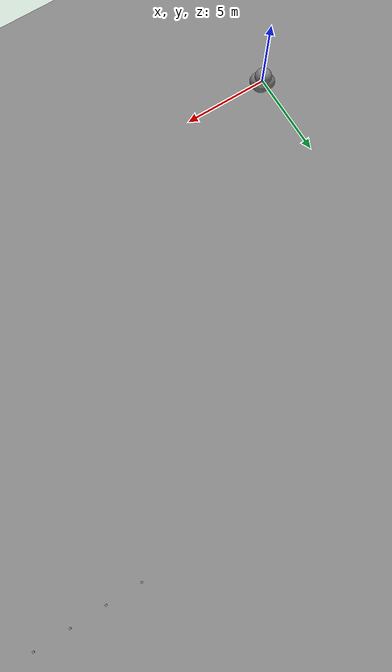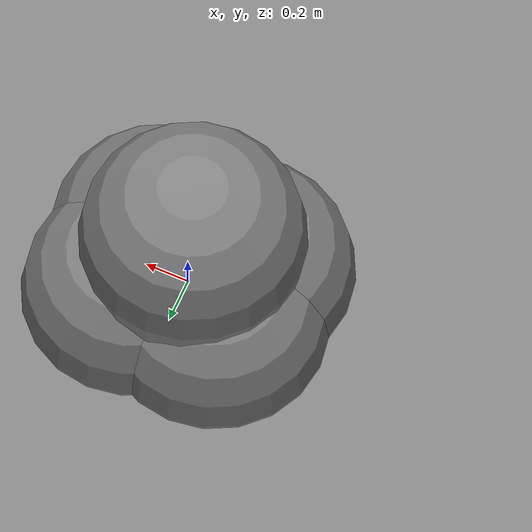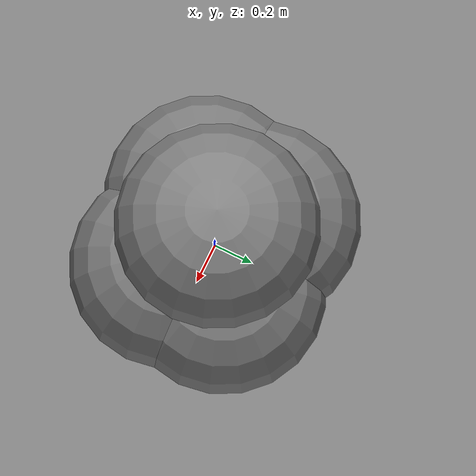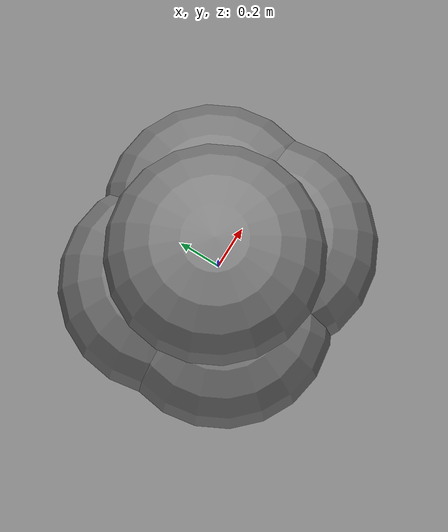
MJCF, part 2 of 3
0.084086 -0.051503 0.072471 0.084086 -0.051503 0.056434 0.084086 -0.051503 0.060443 0.087634 -0.048564 0.064452 0.087634 -0.048564 0.068462 0.087634 -0.048564 0.052424 0.084086 -0.051503 0.048415 0.084086 -0.051503 0.056434 0.087634 -0.048564 0.060443 0.09069 -0.045115 0.052424 0.087634 -0.048564 0.048415 0.087634 -0.048564 0.044406 0.087634 -0.048564 0.064452 0.09069 -0.045115 0.040396 0.087634 -0.048564 0.036387 0.087634 -0.048564 0.032377 0.087634 -0.048564 0.036387 0.09069 -0.045115 0.040396 0.09069 -0.045115 0.044406 0.09069 -0.045115 0.028368 0.087634 -0.048564 0.048415 0.09069 -0.045115 0.024359 0.087634 -0.048564 0.052424 0.09069 -0.045115 0.020349 0.087634 -0.048564 0.056434 0.09069 -0.045115 0.01634 0.087634 -0.048564 0.01233 0.087634 -0.048564 0.024359 0.09069 -0.045115 0.020349 0.09069 -0.045115 0.01634 0.09069 -0.045115 0.01233 0.09069 -0.045115 0.008321 0.087634 -0.048564 0.028368 0.09069 -0.045115 0.008321 0.084086 -0.051503 0.004312 0.084086 -0.051503 0.032377 0.09069 -0.045115 0.004312 0.087634 -0.048564 0.000302 0.084086 -0.051503 0.000302 0.087634 -0.048564 -0.003707 0.087634 -0.048564 -0.007716 0.087634 -0.048564 -0.011726 0.087634 -0.048564 -0.007716 0.09069 -0.045115 -0.003707 0.09069 -0.045115 0.000302 0.09069 -0.045115 -0.015735 0.087634 -0.048564 0.004312 0.09069 -0.045115 -0.019744 0.087634 -0.048564 0.008321 0.09069 -0.045115 -0.023754 0.087634 -0.048564 0.01233 0.093183 -0.04124 -0.027763 0.087634 -0.048564 0.01634 0.093183 -0.04124 -0.031773 0.087634 -0.048564 0.020349 0.093183 -0.04124 -0.035782 0.087634 -0.048564 0.024359 0.093183 -0.04124 -0.039791 0.087634 -0.048564 0.028368 0.093183 -0.04124 -0.043801 0.087634 -0.048564 0.032377 0.093183 -0.04124 -0.04781 0.087634 -0.048564 0.036387 0.093183 -0.04124 0.040396 0.093183 -0.04124 -0.05182 0.087634 -0.048564 0.036387 0.095052 -0.037028 0.044406 0.093183 -0.04124 -0.055829 0.087634 -0.048564 0.040396 0.095052 -0.037028 0.048415 0.093183 -0.04124 -0.059838 0.084086 -0.051503 0.044406 0.095052 -0.037028 0.052424 0.093183 -0.04124 -0.063848 0.084086 -0.051503 0.048415 0.095052 -0.037028 0.056434 0.093183 -0.04124 -0.067857 0.084086 -0.051503 0.052424 0.095052 -0.037028 0.060443 0.093183 -0.04124 -0.071866 0.084086 -0.051503 -0.075876 0.087634 -0.048564 -0.071866 0.087634 -0.048564 -0.067857 0.087634 -0.048564 -0.063848 0.087634 -0.048564 -0.059838 0.087634 -0.048564 -0.055829 0.09069 -0.045115 -0.05182 0.09069 -0.045115 -0.04781 0.09069 -0.045115 -0.043801 0.09069 -0.045115 -0.039791 0.09069 -0.045115 -0.035782 0.09069 -0.045115 -0.031773 0.09069 -0.045115 -0.027763 0.09069 -0.045115 -0.023754 0.09069 -0.045115 -0.019744 0.09069 -0.045115 -0.015735 0.09069 -0.045115 -0.011726 0.09069 -0.045115 -0.007716 0.093183 -0.04124 -0.003707 0.093183 -0.04124 0.000302 0.093183 -0.04124 0.004312 0.093183 -0.04124 0.008321 0.093183 -0.04124 0.004312 0.095052 -0.037028 0.01233 0.095052 -0.037028 0.008321 0.095052 -0.037028 0.01233 0.096254 -0.03258 0.01634 0.095052 -0.037028 0.020349 0.095052 -0.037028 0.01634 0.096254 -0.03258 0.024359 0.095052 -0.037028 0.020349 0.096254 -0.03258 0.028368 0.095052 -0.037028 0.024359 0.096254 -0.03258 0.032377 0.095052 -0.037028 0.028368 0.096254 -0.03258 0.032377 0.096254 -0.03258 0.036387 0.096254 -0.03258 0.040396 0.096254 -0.03258 0.044406 0.096254 -0.03258 0.048415 0.096254 -0.03258 0.032376 0.096761 -0.028 0.028368 0.096761 -0.028 0.032377 0.096761 -0.028 0.027794 0.096761 -0.028 0.036387 0.096761 -0.028 0.036958 0.096761 -0.028 0.040396 0.096761 -0.028 0.04154 0.096761 -0.028 0.044406 0.096761 -0.028 0.046122 0.096761 -0.028 0.024359 0.096761 -0.028 0.023212 0.096761 -0.028 0.020349 0.096761 -0.028 0.01863 0.096761 -0.028 0.048415 0.096761 -0.028 0.01634 0.096761 -0.028 0.014048 0.096761 -0.028 0.01233 0.096761 -0.028 0.050704 0.096761 -0.028 0.009465 0.096761 -0.028 0.052424 0.096254 -0.03258 0.052424 0.096761 -0.028 0.055286 0.096761 -0.028 0.008321 0.096254 -0.03258 0.008321 0.096761 -0.028 0.004883 0.096761 -0.028 0.004312 0.096254 -0.03258 0.004312 0.096761 -0.028 0.000302 0.096761 -0.028 0.000302 0.096254 -0.03258 0.000301 0.096761 -0.028 0.056434 0.096254 -0.03258 0.056434 0.096761 -0.028 0.059869 0.096761 -0.028 0.000302 0.095052 -0.037028 -0.003707 0.096254 -0.03258 -0.003707 0.096761 -0.028 -0.004281 0.096761 -0.028 -0.007716 0.096254 -0.03258 -0.007716 0.096761 -0.028 -0.008863 0.096761 -0.028 -0.003707 0.095052 -0.037028 -0.007716 0.095052 -0.037028 -0.011726 0.096254 -0.03258 -0.011726 0.096761 -0.028 -0.013445 0.096761 -0.028 -0.011726 0.095052 -0.037028 -0.011726 0.093183 -0.04124 -0.015735 0.096254 -0.03258 -0.015735 0.096761 -0.028 -0.018027 0.096761 -0.028 -0.015735 0.095052 -0.037028 -0.015735 0.093183 -0.04124 -0.019744 0.096254 -0.03258 -0.019744 0.096761 -0.028 -0.022609 0.096761 -0.028 -0.019744 0.093183 -0.04124 -0.019744 0.095052 -0.037028 -0.023754 0.096254 -0.03258 -0.023754 0.096761 -0.028 -0.027192 0.096761 -0.028 -0.023754 0.093183 -0.04124 -0.023754 0.095052 -0.037028 -0.027763 0.096254 -0.03258 -0.027763 0.096761 -0.028 -0.031773 0.096761 -0.028 -0.027763 0.093183 -0.04124 -0.027763 0.095052 -0.037028 -0.031773 0.096254 -0.03258 -0.031774 0.096761 -0.028 -0.031773 0.093183 -0.04124 -0.031773 0.095052 -0.037028 -0.035782 0.096254 -0.03258 -0.035782 0.096761 -0.028 -0.036356 0.096761 -0.028 -0.035782 0.093183 -0.04124 -0.039791 0.096254 -0.03258 -0.039791 0.096761 -0.028 -0.040938 0.096761 -0.028 -0.035782 0.095052 -0.037028 -0.039791 0.093183 -0.04124 -0.039791 0.095052 -0.037028 -0.043801 0.096254 -0.03258 -0.043801 0.096761 -0.028 -0.04552 0.096761 -0.028 -0.043801 0.093183 -0.04124 -0.043801 0.095052 -0.037028 -0.04781 0.096254 -0.03258 -0.04781 0.096761 -0.028 -0.050102 0.096761 -0.028 -0.04781 0.093183 -0.04124 -0.04781 0.095052 -0.037028 -0.05182 0.096254 -0.03258 -0.051819 0.096761 -0.028 -0.054684 0.096761 -0.028 -0.055829 0.096254 -0.03258 -0.055829 0.096761 -0.028 -0.059266 0.096761 -0.028 -0.05182 0.095052 -0.037028 -0.05182 0.093183 -0.04124 -0.055829 0.095052 -0.037028 -0.055829 0.093183 -0.04124 -0.059838 0.096254 -0.03258 -0.059838 0.096761 -0.028 -0.059838 0.095052 -0.037028 -0.063848 0.096254 -0.03258 -0.063848 0.096761 -0.028 -0.059838 0.09069 -0.045115 -0.059838 0.093183 -0.04124 -0.067857 0.096254 -0.03258 -0.067857 0.096761 -0.028 -0.06843 0.096761 -0.028 -0.063848 0.095052 -0.037028 -0.063848 0.09069 -0.045115 -0.063848 0.093183 -0.04124 -0.071866 0.096254 -0.03258 -0.071866 0.096761 -0.028 -0.073013 0.096761 -0.028 -0.067857 0.095052 -0.037028 -0.067857 0.09069 -0.045115 -0.067857 0.093183 -0.04124 -0.075876 0.096254 -0.03258 -0.075876 0.096761 -0.028 -0.077595 0.096761 -0.028 -0.079885 0.096254 -0.03258 -0.079885 0.096761 -0.028 -0.082177 0.096761 -0.028 -0.071866 0.095052 -0.037028 -0.071866 0.09069 -0.045115 -0.071866 0.093183 -0.04124 -0.075876 0.095052 -0.037028 -0.075876 0.09069 -0.045115 -0.075876 0.093183 -0.04124 -0.079885 0.09069 -0.045115 -0.079885 0.095052 -0.037028 -0.079885 0.093183 -0.04124 -0.083895 0.093183 -0.04124 -0.083895 0.087634 -0.048564 -0.083895 0.095052 -0.037028 -0.083895 0.09069 -0.045115 -0.087904 0.09069 -0.045115 -0.087904 0.093183 -0.04124 -0.091913 0.09069 -0.045115 -0.091913 0.093183 -0.04124 -0.095923 0.093183 -0.04124 -0.087904 0.095052 -0.037028 -0.091913 0.095052 -0.037028 -0.099932 0.095052 -0.037028 -0.099932 0.096254 -0.03258 -0.095923 0.095052 -0.037028 -0.095923 0.096254 -0.03258 -0.091913 0.096254 -0.03258 -0.087904 0.096254 -0.03258 -0.103941 0.096254 -0.03258 -0.103941 0.096761 -0.028 -0.100505 0.096761 -0.028 -0.099932 0.096761 -0.028 -0.095923 0.096761 -0.028 -0.091913 0.096761 -0.028 -0.091341 0.096761 -0.028 -0.087904 0.096761 -0.028 -0.086759 0.096761 -0.028 -0.083895 0.096254 -0.03258 -0.083895 0.096761 -0.028 0.060443 0.096254 -0.03258 0.060443 0.096761 -0.028 0.064451 0.096761 -0.028 0.064452 0.096254 -0.03258 0.064452 0.096761 -0.028 0.068462 0.096761 -0.028 0.068462 0.096254 -0.03258 0.069033 0.096761 -0.028 0.072471 0.096254 -0.03258 0.072471 0.096761 -0.028 0.073615 0.096761 -0.028 0.076481 0.096254 -0.03258 0.076481 0.096761 -0.028 0.078197 0.096761 -0.028 0.08049 0.096254 -0.03258 0.08049 0.096761 -0.028 0.082779 0.096761 -0.028 0.076481 0.095052 -0.037028 0.072471 0.095052 -0.037028 0.068462 0.095052 -0.037028 0.084499 0.096254 -0.03258 0.084499 0.096761 -0.028 0.087362 0.096761 -0.028 0.064452 0.095052 -0.037028 0.088509 0.096254 -0.03258 0.088509 0.096761 -0.028 0.091944 0.096761 -0.028 0.060443 0.095052 -0.037028 0.092518 0.096254 -0.03258 0.092518 0.096761 -0.028 0.096526 0.096761 -0.028 0.056434 0.095052 -0.037028 0.064452 0.093183 -0.04124 0.068462 0.093183 -0.04124 0.068462 0.09069 -0.045115 0.072471 0.093183 -0.04124 0.072471 0.087634 -0.048564 0.072471 0.09069 -0.045115 0.076481 0.093183 -0.04124 0.076481 0.084086 -0.051503 0.076481 0.09069 -0.045115 0.076481 0.087634 -0.048564 0.08049 0.084086 -0.051503 0.08049 0.09069 -0.045115 0.08049 0.095052 -0.037028 0.08049 0.080129 -0.053865 0.084499 0.075858 -0.055593 0.08049 0.087634 -0.048564 0.084499 0.080129 -0.053865 0.088509 0.071372 -0.056646 0.084499 0.084086 -0.051503 0.088509 0.075858 -0.055593 0.092518 0.071372 -0.056646 0.092518 0.066777 -0.057 0.088509 0.080129 -0.053865 0.084499 0.087634 -0.048564 0.096527 0.071372 -0.056646 0.096527 0.066777 -0.057 0.092518 0.075858 -0.055593 0.088509 0.084086 -0.051503 0.100537 0.071372 -0.056646 0.100537 0.066777 -0.057 0.096527 0.075858 -0.055593 0.092518 0.080129 -0.053865 0.104546 0.071372 -0.056646 0.104546 0.066777 -0.057 0.108556 0.071372 -0.056646 0.108556 0.066777 -0.057 0.104546 0.075858 -0.055593 0.100537 0.075858 -0.055593 0.096527 0.080129 -0.053865 0.092518 0.084086 -0.051503 0.112565 0.071372 -0.056646 0.112565 0.066777 -0.057 0.100537 0.080129 -0.053865 0.108556 0.075858 -0.055593 0.116574 0.071372 -0.056646 0.116574 0.066777 -0.057 0.088509 0.087634 -0.048564 0.096527 0.084086 -0.051503 0.104546 0.080129 -0.053865 0.112565 0.075858 -0.055593 0.120584 0.071372 -0.056646 0.120584 0.066777 -0.057 0.108556 0.080129 -0.053865 0.104546 0.084086 -0.051503 0.116574 0.075858 -0.055593 0.124593 0.071372 -0.056646 0.124593 0.066777 -0.057 0.128602 0.066777 -0.057 0.128602 0.071372 -0.056646 0.112565 0.080129 -0.053865 0.120584 0.075858 -0.055593 0.124593 0.075858 -0.055593 0.128602 0.075858 -0.055593 0.116574 0.080129 -0.053865 0.108556 0.084086 -0.051503 0.124593 0.080129 -0.053865 0.128602 0.080129 -0.053865 0.120584 0.080129 -0.053865 0.112565 0.084086 -0.051503 0.124593 0.084086 -0.051503 0.128602 0.084086 -0.051503 0.120584 0.084086 -0.051503 0.116574 0.084086 -0.051503 0.124593 0.087634 -0.048564 0.128602 0.087634 -0.048564 0.128602 0.09069 -0.045115 0.120584 0.087634 -0.048564 0.116574 0.087634 -0.048564 0.112565 0.087634 -0.048564 0.108556 0.087634 -0.048564 0.124593 0.09069 -0.045115 0.128602 0.093183 -0.04124 0.120584 0.09069 -0.045115 0.116574 0.09069 -0.045115 0.112565 0.09069 -0.045115 0.124593 0.093183 -0.04124 0.128602 0.095052 -0.037028 0.120584 0.093183 -0.04124 0.116574 0.093183 -0.04124 0.124593 0.095052 -0.037028 0.128602 0.096254 -0.03258 0.120584 0.095052 -0.037028 0.124593 0.096254 -0.03258 0.128602 0.096761 -0.028 0.124593 0.096761 -0.028 0.12402 0.096761 -0.028 0.120584 0.096254 -0.03258 0.120584 0.096761 -0.028 0.119438 0.096761 -0.028 0.116574 0.096254 -0.03258 0.116574 0.096761 -0.028 0.114855 0.096761 -0.028 0.116574 0.095052 -0.037028 0.112565 0.096254 -0.03258 0.112565 0.096761 -0.028 0.110273 0.096761 -0.028 0.112565 0.095052 -0.037028 0.108556 0.096254 -0.03258 0.108556 0.096761 -0.028 0.105691 0.096761 -0.028 0.104546 0.096254 -0.03258 0.104546 0.096761 -0.028 0.101108 0.096761 -0.028 0.112565 0.093183 -0.04124 0.108556 0.095052 -0.037028 0.108556 0.093183 -0.04124 0.100537 0.096254 -0.03258 0.100537 0.096761 -0.028 0.104546 0.095052 -0.037028 0.108556 0.09069 -0.045115 0.100537 0.095052 -0.037028 0.096527 0.096254 -0.03258 0.096527 0.096761 -0.028 0.104546 0.093183 -0.04124 0.104546 0.09069 -0.045115 0.100537 0.093183 -0.04124 0.096527 0.095052 -0.037028 0.092518 0.095052 -0.037028 0.096527 0.093183 -0.04124 0.088509 0.095052 -0.037028 0.104546 0.087634 -0.048564 0.100537 0.09069 -0.045115 0.092518 0.093183 -0.04124 0.084499 0.095052 -0.037028 0.100537 0.087634 -0.048564 0.100537 0.084086 -0.051503 0.096527 0.09069 -0.045115 0.096527 0.087634 -0.048564 0.092518 0.09069 -0.045115 0.092518 0.087634 -0.048564 0.088509 0.093183 -0.04124 0.088509 0.09069 -0.045115 0.084499 0.093183 -0.04124 0.084499 0.09069 -0.045115 0.08049 0.093183 -0.04124 0.326264 -0.004967 0.044624 0.326264 -0.004353 0.044412 0.326264 -0.004064 0.04507 0.326264 -0.004529 0.043716 0.326264 -0.004636 0.04538 0.326264 -0.00517 0.043823 0.326264 -0.003671 0.045672 0.326264 -0.004588 0.043 0.326264 -0.004184 0.046071 0.326264 -0.005238 0.043 0.326264 -0.003184 0.0462 0.326264 -0.003625 0.046679 0.326264 -0.004529 0.042284 0.326264 -0.00517 0.042177 0.326264 -0.002973 0.047186 0.326264 -0.002618 0.046642 0.326264 -0.004967 0.041376 0.326264 -0.004353 0.041588 0.326264 -0.004064 0.04093 0.326264 -0.004636 0.04062 0.326264 -0.003671 0.040328 0.326264 -0.004184 0.039929 0.326264 -0.001986 0.046984 0.326264 -0.002247 0.047579 0.326264 -0.001466 0.047847 0.326264 -0.001306 0.047217 0.326264 -0.000651 0.047983 0.326264 -0.000598 0.047335 0.326264 -0.003184 0.0398 0.326264 -0.003625 0.039321 0.326264 -0.000238 0.048 0.326264 -0.000238 0.04735 0.326264 0.000121 0.047335 0.326264 0.000175 0.047983 0.326264 -0.002973 0.038814 0.326264 -0.002618 0.039358 0.326264 -0.001986 0.039016 0.326264 -0.002247 0.038421 0.326264 0.00083 0.047217 0.326264 0.000989 0.047847 0.326264 0.00177 0.047579 0.326264 0.001509 0.046984 0.326264 -0.001306 0.038783 0.326264 -0.001466 0.038153 0.326264 -0.000651 0.038017 0.326264 -0.000598 0.038665 0.326264 0.002496 0.047186 0.326264 0.002141 0.046642 0.326264 -0.000238 0.038 0.326264 -0.000238 0.03865 0.326264 0.000121 0.038665 0.326264 0.000175 0.038017 0.326264 0.00083 0.038783 0.326264 0.000989 0.038153 0.326264 0.002708 0.0462 0.326264 0.003148 0.046679 0.326264 0.003707 0.046071 0.326264 0.003194 0.045672 0.326264 0.004159 0.04538 0.326264 0.003587 0.04507 0.326264 0.001509 0.039016 0.326264 0.00177 0.038421 0.326264 0.004491 0.044624 0.326264 0.003876 0.044412 0.326264 0.002496 0.038814 0.326264 0.002141 0.039358 0.326264 0.004052 0.043716 0.326264 0.004694 0.043823 0.326264 0.004762 0.043 0.326264 0.004112 0.043 0.326264 0.004694 0.042177 0.326264 0.004052 0.042284 0.326264 0.002708 0.0398 0.326264 0.003148 0.039321 0.326264 0.003707 0.039929 0.326264 0.003194 0.040328 0.326264 0.004159 0.04062 0.326264 0.003587 0.04093 0.326264 0.004491 0.041376 0.326264 0.003876 0.041588 0.326564 -0.004967 0.041376 0.326564 -0.004353 0.041588 0.326564 -0.004064 0.04093 0.326564 -0.004529 0.042284 0.326564 -0.004636 0.04062 0.326564 -0.00517 0.042177 0.326564 -0.003671 0.040328 0.326564 -0.004588 0.043 0.326564 -0.004184 0.039929 0.326564 -0.005238 0.043 0.326564 -0.003184 0.0398 0.326564 -0.003625 0.039321 0.326564 -0.004529 0.043716 0.326564 -0.00517 0.043823 0.326564 -0.002973 0.038814 0.326564 -0.002618 0.039358 0.326564 -0.004967 0.044624 0.326564 -0.004353 0.044412 0.326564 -0.004064 0.04507 0.326564 -0.004636 0.04538 0.326564 -0.003671 0.045672 0.326564 -0.004184 0.046071 0.326564 -0.001986 0.039016 0.326564 -0.002247 0.038421 0.326564 -0.001466 0.038153 0.326564 -0.001306 0.038783 0.326564 -0.000651 0.038017 0.326564 -0.000598 0.038665 0.326564 -0.003184 0.0462 0.326564 -0.003625 0.046679 0.326564 -0.000238 0.038 0.326564 -0.000238 0.03865 0.326564 0.000121 0.038665 0.326564 0.000175 0.038017 0.326564 -0.002973 0.047186 0.326564 -0.002618 0.046642 0.326564 -0.001986 0.046984 0.326564 -0.002247 0.047579 0.326564 0.00083 0.038783 0.326564 0.000989 0.038153 0.326564 0.00177 0.038421 0.326564 0.001509 0.039016 0.326564 -0.001306 0.047217 0.326564 -0.001466 0.047847 0.326564 -0.000651 0.047983 0.326564 -0.000598 0.047335 0.326564 0.002496 0.038814 0.326564 0.002141 0.039358 0.326564 -0.000238 0.048 0.326564 -0.000238 0.04735 0.326564 0.000121 0.047335 0.326564 0.000175 0.047983 0.326564 0.00083 0.047217 0.326564 0.000989 0.047847 0.326564 0.002708 0.0398 0.326564 0.003148 0.039321 0.326564 0.003707 0.039929 0.326564 0.003194 0.040328 0.326564 0.004159 0.04062 0.326564 0.003587 0.04093 0.326564 0.001509 0.046984 0.326564 0.00177 0.047579 0.326564 0.004491 0.041376 0.326564 0.003876 0.041588 0.326564 0.002496 0.047186 0.326564 0.002141 0.046642 0.326564 0.004052 0.042284 0.326564 0.004694 0.042177 0.326564 0.004762 0.043 0.326564 0.004112 0.043 0.326564 0.004694 0.043823 0.326564 0.004052 0.043716 0.326564 0.002708 0.0462 0.326564 0.003148 0.046679 0.326564 0.003707 0.046071 0.326564 0.003194 0.045672 0.326564 0.004159 0.04538 0.326564 0.003587 0.04507 0.326564 0.004491 0.044624 0.326564 0.003876 0.044412 0.324564 -0.004416 0.040739 0.324564 -0.001723 0.042197 0.324564 -0.003987 0.040082 0.324564 -0.004731 0.041458 0.324564 -0.001571 0.041963 0.324564 -0.001835 0.042452 0.324564 -0.003455 0.039505 0.324564 -0.004924 0.042218 0.324564 -0.001382 0.041758 0.324564 -0.001903 0.042722 0.324564 -0.002836 0.039023 0.324564 -0.001162 0.041587 0.324564 -0.002146 0.03865 0.324564 -0.000916 0.041454 0.324564 -0.001404 0.038395 0.324564 -0.000653 0.041363 0.324564 -0.004988 0.043 0.324564 -0.001926 0.043 0.324564 -0.001903 0.043278 0.324564 -0.004924 0.043782 0.324564 -0.001835 0.043548 0.324564 -0.004731 0.044542 0.324564 -0.000631 0.038266 0.324564 -0.000378 0.041318 0.324564 -9.9E-05 0.041318 0.324564 0.000154 0.038266 0.324564 0.000176 0.041363 0.324564 0.000928 0.038395 0.324564 0.00044 0.041454 0.324564 0.00167 0.03865 0.324564 0.000685 0.041587 0.324564 0.00236 0.039023 0.324564 0.000905 0.041758 0.324564 0.002979 0.039505 0.324564 0.001094 0.041963 0.324564 0.00351 0.040082 0.324564 0.001246 0.042197 0.324564 0.003939 0.040739 0.324564 0.004254 0.041458 0.324564 0.001358 0.042452 0.324564 0.004447 0.042218 0.324564 0.001427 0.042722 0.324564 0.004512 0.043 0.324564 0.00145 0.043 0.324564 0.001427 0.043278 0.324564 0.004447 0.043782 0.324564 0.001358 0.043548 0.324564 0.004254 0.044542 0.324564 0.001246 0.043803 0.324564 0.003939 0.045261 0.324564 0.00351 0.045918 0.324564 0.001094 0.044037 0.324564 0.002979 0.046495 0.324564 0.000905 0.044242 0.324564 0.00236 0.046977 0.324564 0.000685 0.044413 0.324564 0.00167 0.04735 0.324564 0.00044 0.044546 0.324564 0.000928 0.047605 0.324564 0.000176 0.044637 0.324564 0.000154 0.047734 0.324564 -9.9E-05 0.044682 0.324564 -0.000378 0.044682 0.324564 -0.000631 0.047734 0.324564 -0.000653 0.044637 0.324564 -0.001404 0.047605 0.324564 -0.000916 0.044546 0.324564 -0.002146 0.04735 0.324564 -0.001162 0.044413 0.324564 -0.002836 0.046977 0.324564 -0.001382 0.044242 0.324564 -0.003455 0.046495 0.324564 -0.001571 0.044037 0.324564 -0.003987 0.045917 0.324564 -0.001723 0.043803 0.324564 -0.004416 0.045261 0.324064 0.003939 0.040739 0.324064 0.001005 0.042327 0.324064 0.00351 0.040082 0.324064 0.004254 0.041458 0.324064 0.000878 0.042131 0.324064 0.001099 0.042541 0.324064 0.002979 0.039505 0.324064 0.004447 0.042218 0.324064 0.00072 0.04196 0.324064 0.001157 0.042767 0.324064 0.00236 0.039023 0.324064 0.000535 0.041816 0.324064 0.00167 0.03865 0.324064 0.00033 0.041705 0.324064 0.000928 0.038395 0.324064 0.000109 0.041629 0.324064 0.004512 0.043 0.324064 0.001176 0.043 0.324064 0.001157 0.043233 0.324064 0.004447 0.043782 0.324064 0.001099 0.043459 0.324064 0.004254 0.044542 0.324064 0.000154 0.038266 0.324064 -0.000122 0.041591 0.324064 -0.000355 0.041591 0.324064 -0.000631 0.038266 0.324064 -0.000585 0.041629 0.324064 -0.001404 0.038395 0.324064 -0.000806 0.041705 0.324064 -0.002146 0.03865 0.324064 -0.001012 0.041816 0.324064 -0.002836 0.039023 0.324064 -0.001196 0.04196 0.324064 -0.003455 0.039505 0.324064 -0.001354 0.042131 0.324064 -0.003987 0.040082 0.324064 -0.001482 0.042327 0.324064 -0.004416 0.040739 0.324064 -0.004731 0.041458 0.324064 -0.001576 0.042541 0.324064 -0.004924 0.042218 0.324064 -0.001633 0.042767 0.324064 -0.004988 0.043 0.324064 -0.001653 0.043 0.324064 -0.001633 0.043233 0.324064 -0.004924 0.043782 0.324064 -0.001576 0.043459 0.324064 -0.004731 0.044542 0.324064 -0.001482 0.043673 0.324064 -0.004416 0.045261 0.324064 -0.003987 0.045917 0.324064 -0.001354 0.043869 0.324064 -0.003455 0.046495 0.324064 -0.001196 0.04404 0.324064 -0.002836 0.046977 0.324064 -0.001012 0.044184 0.324064 -0.002146 0.04735 0.324064 -0.000806 0.044295 0.324064 -0.001404 0.047605 0.324064 -0.000585 0.044371 0.324064 -0.000631 0.047734 0.324064 -0.000355 0.044409 0.324064 -0.000122 0.044409 0.324064 0.000154 0.047734 0.324064 0.000109 0.044371 0.324064 0.000928 0.047605 0.324064 0.00033 0.044295 0.324064 0.00167 0.04735 0.324064 0.000535 0.044184 0.324064 0.00236 0.046977 0.324064 0.00072 0.04404 0.324064 0.002979 0.046495 0.324064 0.000878 0.043869 0.324064 0.00351 0.045918 0.324064 0.001005 0.043673 0.324064 0.003939 0.045261 " />
    <mesh name="mesh_5" vertex="0.036042 0.011167 -0.032432 0.03601 0.011342 -0.032467 0.035923 0.01147 -0.032563 0.046139 -0.010683 -0.014852 0.046139 -0.013983 -0.014852 0.046199 -0.014183 -0.014661 0.048377 0.01147 -0.002496 0.048371 0.011342 -0.002625 0.048368 0.011167 -0.002673 0.044993 0.011592 -0.003033 0.047871 0.011591 -0.003033 0.047871 0.011592 -0.003032 0.02069 0.017317 0.020359 0.021044 0.016817 0.020713 0.021043 0.016817 0.020713 0.035923 0.01147 0.03227 0.03601 0.011342 0.032173 0.036042 0.011167 0.032138 0.035944 0.011592 0.031533 0.035944 0.011591 0.031532 0.03601 0.011342 0.032173 0.014684 0.017317 0.024968 0.014934 0.016817 0.025401 0.014933 0.016817 0.025401 0.000184 0.017317 0.028853 0.000184 0.016817 0.029353 0.000183 0.016817 0.029353 -0.032232 0.01147 0.035592 -0.032136 0.011342 0.035679 -0.032101 0.011167 0.035711 -0.035673 0.011167 0.032138 -0.035641 0.011342 0.032173 -0.035554 0.01147 0.03227 -0.048 0.011167 -0.002673 -0.048002 0.011342 -0.002625 -0.048009 0.01147 -0.002496 -0.048009 0.01147 0.002202 -0.048002 0.011342 0.002332 -0.048 0.011167 0.002379 -0.044625 0.011592 0.002739 -0.047503 0.011591 0.002739 -0.047503 0.011592 0.002738 -0.042617 -0.014183 0.022128 -0.042709 -0.013983 0.02195 -0.042709 -0.010683 0.02195 -0.04277 -0.010683 0.02183 -0.042709 -0.010683 0.02195 -0.042431 -0.010983 0.021834 -0.04577 -0.010683 0.014559 -0.04577 -0.013983 0.014559 -0.045831 -0.014183 0.014367 -0.014316 0.017317 0.024968 -0.014566 0.016817 0.025401 -0.014567 0.016817 0.0254 -0.007321 0.017317 0.027865 -0.007451 0.016817 0.028348 -0.007452 0.016817 0.028348 0.032469 0.011167 0.035711 0.032505 0.011342 0.035679 0.032601 0.01147 0.035592 0.031863 0.011592 0.035613 0.031863 0.011592 0.035614 0.029828 0.011592 0.033579 0.048368 0.011167 0.002379 0.048371 0.011342 0.002332 0.048377 0.01147 0.002202 0.042985 -0.014183 -0.022422 0.043077 -0.013983 -0.022243 0.043077 -0.010683 -0.022243 0.043139 -0.010683 -0.022123 0.043077 -0.010683 -0.022243 0.042799 -0.010983 -0.022128 0.032601 0.01147 -0.035885 0.032504 0.011342 -0.035972 0.032469 0.011167 -0.036004 -0.035554 0.01147 -0.032563 -0.035641 0.011342 -0.032467 -0.035673 0.011167 -0.032432 -0.032101 0.011167 -0.036004 -0.032136 0.011342 -0.035972 -0.032232 0.01147 -0.035885 -0.020091 -0.014183 -0.019457 -0.020129 -0.014183 -0.019418 -0.020129 -0.014044 -0.019418 -0.015054 -0.015683 -0.0454 -0.015079 -0.015683 -0.045392 -0.015091 -0.015683 -0.045387 -0.014521 -0.014183 -0.046101 -0.015214 -0.014183 -0.045874 -0.014513 -0.014183 -0.046082 -0.021729 -0.012333 -0.043134 -0.021778 -0.010983 -0.043109 -0.021886 -0.011104 -0.043053 -0.021886 -0.015183 -0.043053 -0.021912 -0.014183 -0.04304 -0.021912 -0.011133 -0.04304 -0.043589 -0.012333 -0.020444 -0.043632 -0.012333 -0.020352 -0.043495 -0.012483 -0.020289 -0.037901 -0.012683 0.018714 -0.039081 -0.012683 0.016117 -0.040083 -0.012683 0.013447 0.025256 -0.023683 -0.010166 0.025129 -0.023683 -0.010479 0.021907 -0.023683 -0.016182 -0.025093 -0.023683 0.010312 -0.02414 -0.023683 0.011571 -0.020329 -0.023683 0.017409 -0.013527 -0.023683 -0.022337 0.025275 -0.023683 -0.010119 -0.000837 -0.023683 -0.027128 0.011893 -0.023683 -0.024476 0.017407 -0.023683 -0.020941 0.00569 -0.023683 -0.02658 -0.007304 -0.023683 -0.026088 -0.013279 -0.023683 -0.023026 -0.013314 -0.023683 -0.023531 -0.014073 -0.023683 -0.021848 -0.021471 -0.023683 -0.016921 -0.020144 -0.023683 -0.017917 -0.014784 -0.023683 -0.021676 -0.015493 -0.023683 -0.021861 -0.015688 -0.023683 -0.021989 -0.023089 -0.023683 -0.01655 -0.029343 -0.023683 -0.001596 -0.027593 -0.023683 -0.012374 -0.024718 -0.023683 -0.016868 -0.025538 -0.023683 -0.017216 -0.029726 -0.023683 -0.007072 -0.029649 -0.023683 -0.007532 -0.02896 -0.023683 0.00388 -0.026458 -0.023683 0.00952 -0.028023 -0.023683 0.009317 -0.028577 -0.023683 0.009356 0.025275 -0.023683 -0.010119 0.025256 -0.023683 -0.010166 0.021907 -0.023683 -0.016182 0.040416 -0.014183 -0.013835 0.040452 -0.014183 -0.013741 0.040477 -0.014183 -0.013664 0.03827 -0.012683 -0.019008 0.039449 -0.012683 -0.016411 0.040452 -0.012683 -0.013741 0.038234 -0.014183 -0.01908 0.03827 -0.014183 -0.019008 0.038311 -0.014183 -0.018916 0.021635 -0.014683 -0.017355 0.021637 -0.014683 -0.017352 0.021637 -0.020683 -0.017352 0.01546 -0.015683 -0.045387 0.015447 -0.015683 -0.045392 0.015422 -0.015683 -0.0454 0.032858 -0.015183 -0.03565 0.032951 -0.015183 -0.035565 0.032858 -0.014183 -0.03565 0.01489 -0.014183 -0.046101 0.014881 -0.014183 -0.046082 0.015582 -0.014183 -0.045874 0.014881 -0.014183 -0.046082 0.01489 -0.014183 -0.046101 0.01489 -0.011133 -0.046101 0.012186 -0.020683 -0.024283 0.012185 -0.020683 -0.024282 0.012186 -0.019833 -0.024283 0.01489 -0.014183 0.045808 0.015582 -0.014183 0.04558 0.014881 -0.014183 0.045788 -0.014521 -0.014183 0.045808 -0.014513 -0.014183 0.045788 -0.015214 -0.014183 0.04558 -0.030684 -0.011333 0.034964 -0.030684 -0.01426 0.034964 -0.030701 -0.01425 0.034948 -0.030684 -0.011333 0.034964 -0.030701 -0.01425 0.034948 -0.030713 -0.014244 0.034938 -0.021336 -0.014251 0.041355 -0.021272 -0.01434 0.041201 -0.021272 -0.011133 0.041201 -0.021455 -0.014183 0.041643 -0.021337 -0.01425 0.041356 -0.021912 -0.011133 0.042746 -0.021912 -0.014183 0.042746 -0.021337 -0.01425 0.041356 -0.021336 -0.014251 0.041355 -0.021272 -0.011133 0.041201 -0.032489 -0.015183 0.035357 -0.032582 -0.015183 0.035271 -0.032489 -0.014183 0.035357 0.043957 -0.012333 0.02015 0.044 -0.012333 0.020058 0.043864 -0.012483 0.019995 0.012185 -0.019833 0.023989 0.012184 -0.020683 0.023989 0.012185 -0.020683 0.023989 -0.023712 -0.020683 0.012325 -0.023711 -0.020683 0.012325 -0.023712 -0.019833 0.012325 -0.026789 -0.014183 0.030196 -0.023313 -0.014183 0.025119 -0.023422 -0.014183 0.025281 -0.037866 -0.014183 0.018786 -0.037901 -0.014183 0.018714 -0.037943 -0.014183 0.018623 -0.028437 -0.014601 0.010355 -0.028417 -0.014683 0.010347 -0.02884 -0.012709 0.010522 -0.028417 -0.014683 0.010347 -0.028417 -0.012862 0.010347 -0.02884 -0.012709 0.010522 -0.028484 -0.014533 0.010375 -0.028437 -0.014601 0.010355 -0.028545 -0.014478 0.0104 -0.028612 -0.014433 0.010428 -0.029145 -0.01425 0.010649 -0.029873 -0.014183 0.01095 -0.028986 -0.012683 0.010583 -0.038088 -0.012683 0.014353 -0.038088 -0.014183 0.014353 -0.015091 -0.015683 0.045093 -0.015079 -0.015683 0.045098 -0.015054 -0.015683 0.045106 0.026365 -0.014183 -0.010076 0.026349 -0.014183 -0.010116 0.026331 -0.014183 -0.010165 0.026349 -0.014183 -0.010116 0.026326 -0.014183 -0.010178 0.026331 -0.014183 -0.010165 0.039005 -0.010983 -0.017809 0.038368 -0.010983 -0.019147 0.038344 -0.010983 -0.0192 -0.038637 -0.010983 0.017515 -0.038 -0.010983 0.018853 -0.037976 -0.010983 0.018907 -0.061816 0.013808 -0.025062 -0.061816 0.013809 -0.025062 -0.062316 0.013809 -0.025062 -0.061816 -0.000692 -0.028947 -0.061816 -0.000691 -0.028947 -0.062316 -0.000691 -0.028947 -0.061816 -0.008198 -0.027958 -0.061816 -0.008197 -0.027959 -0.062316 -0.008197 -0.027959 -0.04577 -0.013983 -0.014852 -0.045789 -0.014045 -0.014793 -0.045831 -0.014183 -0.014661 0.046139 -0.013983 0.014559 0.046158 -0.014045 0.014499 0.046199 -0.014183 0.014367 -0.031719 0.011903 0.035398 -0.03172 0.011903 0.035398 -0.032026 0.012017 0.035104 -0.021912 -0.013983 0.042746 -0.02209 -0.014183 0.042654 -0.022026 -0.01411 0.042688 0.047878 0.011903 -0.002722 0.047878 0.011903 -0.002721 0.047886 0.012017 -0.002297 0.022459 -0.014183 -0.042948 0.022394 -0.014111 -0.042981 0.022281 -0.013983 -0.04304 -0.035361 0.011903 -0.03205 -0.03536 0.011903 -0.032051 -0.035066 0.012017 -0.032357 -0.021912 -0.011133 -0.04304 -0.021886 -0.011104 -0.043053 -0.021778 -0.010983 -0.043109 -0.029575 -0.015683 0.009426 -0.030305 -0.015683 0.009477 -0.029953 -0.015817 0.009953 -0.029953 -0.015817 0.009953 -0.02954 -0.015817 0.009924 -0.02964 -0.016183 0.010298 -0.029515 -0.016183 0.01029 -0.029619 -0.016225 0.010319 -0.029536 -0.016442 0.010396 -0.029505 -0.016683 0.010423 -0.02094 -0.014683 0.040707 -0.021202 -0.01444 0.041054 -0.021246 -0.014683 0.041009 0.030759 -0.015758 0.007216 0.03111 -0.015683 0.007071 0.030994 -0.015683 0.006836 -0.025684 -0.014371 0.010568 -0.025684 -0.014044 0.010568 -0.025748 -0.014044 0.010414 0.012028 -0.022535 0.02268 0.011666 -0.022173 0.022774 0.011665 -0.022172 0.022775 0.022281 -0.011133 0.042746 0.022254 -0.011104 0.04276 0.022147 -0.010983 0.042815 -0.046234 0.010317 0.011051 -0.04741 0.010317 0.003703 -0.044566 0.010317 0.003703 -0.041631 0.010317 0.003703 -0.038697 0.010317 0.003703 -0.043931 0.010317 0.018126 -0.030031 0.010317 0.024624 -0.040556 0.010317 0.024758 -0.032106 0.010317 0.026699 -0.034181 0.010317 0.028774 -0.036193 0.010317 0.030785 -0.03273 0.010317 0.01352 -0.031318 0.010317 0.016518 -0.033338 0.010317 0.011953 -0.030484 0.010317 0.018008 -0.029592 0.010317 0.019437 -0.027654 0.010317 0.022106 -0.027956 0.010317 0.022549 -0.027758 0.010317 0.022318 -0.033875 0.010317 0.010345 -0.034706 0.010317 0.007122 -0.035009 0.010317 0.005472 -0.035762 0.010317 0.003703 -0.035235 0.010317 0.003803 -0.035459 0.010317 0.003726 -0.027956 0.010317 -0.022842 -0.027758 0.010317 -0.022612 -0.027654 0.010317 -0.022399 -0.030031 0.010317 -0.024918 -0.029592 0.010317 -0.019731 -0.030484 0.010317 -0.018302 -0.031318 0.010317 -0.016812 -0.03273 0.010317 -0.013814 -0.038697 0.010317 -0.003997 -0.033338 0.010317 -0.012247 -0.033875 0.010317 -0.010639 -0.034706 0.010317 -0.007415 -0.035009 0.010317 -0.005765 -0.035762 0.010317 -0.003997 -0.035235 0.010317 -0.004096 -0.035459 0.010317 -0.00402 -0.043931 0.010317 -0.01842 -0.046234 0.010317 -0.011344 -0.041631 0.010317 -0.003997 -0.044566 0.010317 -0.003997 -0.04741 0.010317 -0.003997 -0.040556 0.010317 -0.025052 -0.032106 0.010317 -0.026993 -0.034181 0.010317 -0.029068 -0.036193 0.010317 -0.031079 -0.019809 0.012017 -0.02318 -0.022849 0.012017 -0.02014 -0.024839 0.012017 -0.022129 -0.021798 0.012017 -0.02517 -0.026884 0.012017 -0.024175 -0.023844 0.012017 -0.027215 -0.02893 0.012017 -0.02622 -0.025889 0.012017 -0.029261 -0.030975 0.012017 -0.028266 -0.027935 0.012017 -0.031306 -0.033021 0.012017 -0.030311 -0.02998 0.012017 -0.033352 -0.035066 0.012017 -0.032357 -0.032026 0.012017 -0.035397 -0.028736 0.010317 -0.034512 -0.030748 0.010317 -0.036524 -0.025906 0.010317 -0.040139 -0.026661 0.010317 -0.032437 -0.024586 0.010317 -0.030362 -0.020647 0.010317 -0.043113 -0.022511 0.010317 -0.028287 -0.0194 0.010317 -0.029923 -0.022068 0.010317 -0.027985 -0.02228 0.010317 -0.028089 -0.01797 0.010317 -0.030815 -0.016481 0.010317 -0.031649 -0.013483 0.010317 -0.033061 -0.011915 0.010317 -0.033669 -0.010308 0.010317 -0.034206 -0.003666 0.010317 -0.036093 -0.015054 0.010317 -0.0454 -0.007084 0.010317 -0.035037 -0.005434 0.010317 -0.03534 -0.003765 0.010317 -0.035566 -0.003689 0.010317 -0.03579 -0.012022 0.010317 -0.045897 -0.003666 0.010317 -0.040995 -0.003666 0.010317 -0.045897 -0.045789 -0.014045 -0.014793 -0.04577 -0.013983 -0.014852 -0.04577 -0.010683 -0.014852 -0.045789 -0.007758 -0.014793 -0.04577 -0.010683 -0.014852 -0.04295 -0.007758 -0.021769 -0.044393 -0.010683 -0.018611 -0.04295 -0.010683 -0.021769 -0.042709 -0.010683 -0.022243 -0.039059 -0.007758 -0.028219 -0.042709 -0.013983 -0.022243 -0.042617 -0.014183 -0.022422 -0.039059 -0.014183 -0.028219 -0.034212 -0.014183 -0.033984 -0.034212 -0.007758 -0.033984 -0.028527 -0.014183 -0.038925 -0.028527 -0.007758 -0.038925 -0.022142 -0.014183 -0.04292 -0.039059 -0.001333 -0.028219 -0.034212 -0.001333 -0.033984 -0.028527 -0.001333 -0.038925 -0.04295 -0.001333 -0.021769 -0.034212 0.005092 -0.033984 -0.028527 0.005092 -0.038925 -0.022142 0.005092 -0.04292 -0.039059 0.005092 -0.028219 -0.031072 0.009817 -0.036905 -0.028527 0.009817 -0.038925 -0.026179 0.009817 -0.040558 -0.031587 0.009996 -0.03646 -0.022142 0.009817 -0.042921 -0.020865 0.009817 -0.043563 -0.031963 0.010489 -0.036127 -0.015214 0.005092 -0.045874 -0.015214 0.009817 -0.045874 -0.015214 0.003817 -0.045874 -0.022142 -0.001333 -0.04292 -0.015214 -0.001333 -0.045874 -0.015214 -0.002183 -0.045874 -0.022142 -0.007758 -0.04292 -0.015214 -0.007758 -0.045874 -0.015214 -0.008183 -0.045874 -0.021912 -0.010683 -0.04304 -0.021912 -0.013983 -0.04304 -0.02209 -0.014183 -0.042948 -0.018628 -0.010683 -0.044578 -0.015214 -0.010683 -0.045874 -0.04577 -0.010683 -0.014852 -0.04577 -0.013983 -0.014852 -0.044376 -0.013983 -0.014275 -0.045492 -0.010983 -0.014737 -0.044653 -0.010983 -0.01439 -0.044376 -0.010683 -0.014275 -0.044376 -0.013983 -0.014275 -0.04577 -0.013983 -0.014852 -0.045831 -0.014183 -0.014661 -0.044417 -0.014106 -0.014158 -0.04444 -0.014183 -0.014085 -0.045492 -0.010983 -0.014737 -0.044653 -0.010983 -0.01439 -0.044051 -0.010983 -0.015265 -0.044116 -0.010983 -0.018497 -0.043113 -0.010983 -0.015778 -0.041114 -0.010983 -0.019225 -0.041621 -0.010983 -0.01999 -0.041788 -0.010983 -0.020892 -0.042431 -0.010983 -0.022128 -0.041592 -0.010983 -0.021781 -0.040495 -0.010983 -0.018063 -0.040751 -0.010983 -0.01893 -0.040641 -0.010983 -0.01884 -0.040487 -0.010983 -0.018608 -0.040436 -0.010983 -0.018334 -0.041249 -0.010983 -0.016243 -0.042043 -0.010983 -0.015811 -0.041719 -0.010983 -0.015821 -0.041433 -0.010983 -0.015976 -0.02209 -0.014183 -0.042948 -0.021514 -0.014183 -0.041556 -0.021446 -0.014106 -0.041592 -0.021335 -0.013983 -0.041646 -0.021912 -0.013983 -0.04304 -0.027479 -0.014183 -0.037834 -0.021514 -0.014183 -0.041556 -0.02209 -0.014183 -0.042948 -0.022142 -0.014183 -0.04292 -0.028527 -0.014183 -0.038925 -0.032873 -0.014183 -0.033204 -0.034212 -0.014183 -0.033984 -0.037503 -0.014183 -0.02781 -0.039059 -0.014183 -0.028219 -0.041225 -0.014183 -0.021845 -0.042617 -0.014183 -0.022422 -0.003666 0.009817 -0.046397 -0.012022 0.009817 -0.046397 -0.012022 0.003817 -0.046397 -0.012022 -0.002183 -0.046397 0.004034 0.009817 -0.046397 -0.002991 0.009998 -0.046397 0.003359 0.009998 -0.046397 0.002865 0.010492 -0.046397 -0.002497 0.010492 -0.046397 0.012391 -0.002183 -0.046397 -0.012022 -0.008183 -0.046397 0.012391 0.003817 -0.046397 0.012391 0.009817 -0.046397 0.012391 -0.008183 -0.046397 -0.012022 -0.014183 -0.046397 0.012391 -0.014183 -0.046397 0.002334 0.011517 -0.046397 0.002684 0.011167 -0.046397 0.002637 0.011342 -0.046397 0.002509 0.01147 -0.046397 -0.001966 0.011517 -0.046397 -0.002316 0.011167 -0.046397 -0.002269 0.011342 -0.046397 -0.002141 0.01147 -0.046397 -0.012022 0.009817 -0.046397 -0.003666 0.009817 -0.046397 -0.012022 0.010317 -0.045897 -0.003666 0.010317 -0.045897 -0.001966 0.011517 -0.046397 0.002334 0.011517 -0.046397 -0.001966 0.012017 -0.045897 0.002334 0.012017 -0.045897 0.002334 0.012017 -0.034343 0.002334 0.012017 -0.030571 -0.001966 0.012017 -0.030571 -0.001966 0.012017 -0.034343 0.002334 0.012017 -0.038195 -0.001966 0.012017 -0.038195 -0.001966 0.012017 -0.042046 0.002334 0.012017 -0.042046 0.002334 0.012017 -0.045897 -0.001966 0.012017 -0.045897 0.021751 0.012017 -0.021714 0.020177 0.012017 -0.02318 0.022167 0.012017 -0.02517 0.025207 0.012017 -0.022129 0.023218 0.012017 -0.02014 0.027253 0.012017 -0.024175 0.024212 0.012017 -0.027215 0.029298 0.012017 -0.02622 0.026258 0.012017 -0.029261 0.031344 0.012017 -0.028266 0.028303 0.012017 -0.031306 0.033389 0.012017 -0.030311 0.030349 0.012017 -0.033352 0.033949 0.012017 -0.033911 0.032394 0.012017 -0.035397 0.035435 0.012017 -0.032357 0.02288 0.010317 -0.028287 0.022649 0.010317 -0.028089 0.022437 0.010317 -0.027985 0.019768 0.010317 -0.029923 0.021015 0.010317 -0.043113 0.018339 0.010317 -0.030815 0.016849 0.010317 -0.031649 0.013852 0.010317 -0.033061 0.012284 0.010317 -0.033669 0.024955 0.010317 -0.030362 0.010676 0.010317 -0.034206 0.004034 0.010317 -0.036093 0.007453 0.010317 -0.035037 0.005803 0.010317 -0.03534 0.004134 0.010317 -0.035566 0.004057 0.010317 -0.03579 0.015422 0.010317 -0.0454 0.012391 0.010317 -0.045897 0.004034 0.010317 -0.040995 0.004034 0.010317 -0.045897 0.026275 0.010317 -0.040139 0.02703 0.010317 -0.032437 0.029105 0.010317 -0.034512 0.031116 0.010317 -0.036524 0.014093 -0.014183 -0.0447 0.014685 -0.014183 -0.04613 0.012391 -0.014183 -0.046397 0.013942 -0.014183 -0.044734 0.012142 -0.014183 -0.044897 -0.012022 -0.014183 -0.046397 -0.011774 -0.014183 -0.044897 -0.013574 -0.014183 -0.044734 -0.013724 -0.014183 -0.0447 -0.014317 -0.014183 -0.04613 0.014685 -0.014183 -0.04613 0.014284 -0.013983 -0.044639 0.014881 -0.013983 -0.046082 0.014093 -0.014183 -0.0447 0.014284 -0.013983 -0.044639 0.014284 -0.010683 -0.044639 0.014399 -0.010983 -0.044916 0.014765 -0.010983 -0.045802 0.014881 -0.010683 -0.046082 0.014881 -0.013983 -0.046082 0.015486 -0.010983 -0.04559 0.014765 -0.010983 -0.045802 0.014399 -0.010983 -0.044916 0.015208 -0.010983 -0.044393 0.015777 -0.010983 -0.043453 0.018879 -0.010983 -0.044302 0.016281 -0.010983 -0.04158 0.015845 -0.010983 -0.042357 0.015866 -0.010983 -0.042023 0.016039 -0.010983 -0.041738 0.019747 -0.010983 -0.041815 0.0181 -0.010983 -0.040826 0.020773 -0.010983 -0.042116 0.022165 -0.010983 -0.042762 0.021818 -0.010983 -0.041923 0.018967 -0.010983 -0.041083 0.018731 -0.010983 -0.04086 0.018419 -0.010983 -0.040768 0.01555 -0.010183 -0.04241 0.015491 -0.010183 -0.043364 0.014996 -0.010183 -0.04418 0.013942 -0.010183 -0.044734 0.014511 -0.010183 -0.044537 0.012142 -0.010183 -0.044897 0.01558 -0.010183 -0.041934 0.015827 -0.010183 -0.041525 -0.015459 -0.010183 0.041232 -0.011774 -0.010183 0.044603 0.016172 -0.010183 -0.0413 0.017979 -0.010183 -0.040552 -0.015211 -0.010183 0.04164 -0.015804 -0.010183 0.041007 -0.015182 -0.010183 0.042117 -0.013574 -0.010183 0.04444 0.041338 -0.010183 0.015841 -0.041233 -0.010183 -0.015753 -0.040969 -0.010183 -0.016135 -0.040221 -0.010183 -0.017942 -0.040136 -0.010183 -0.01833 -0.014628 -0.010183 0.043887 -0.015122 -0.010183 0.04307 -0.014143 -0.010183 0.044244 0.040589 -0.010183 0.017648 0.040505 -0.010183 0.018036 0.041338 -0.010183 -0.016135 0.041601 -0.010183 0.015459 0.040589 -0.010183 -0.017942 0.041563 -0.010183 -0.01579 0.040506 -0.010183 -0.018398 0.018435 -0.010183 -0.040469 0.041983 -0.010183 -0.015539 0.01888 -0.010183 -0.0406 0.042009 -0.010183 0.015238 0.040637 -0.010183 -0.018843 0.046934 -0.010183 -0.000147 0.046394 -0.010183 0.006941 0.046394 -0.010183 -0.007235 0.042472 -0.010183 -0.015518 0.044785 -0.010183 -0.014158 0.04345 -0.010183 -0.015475 0.044291 -0.010183 -0.014973 0.042472 -0.010183 0.015224 0.044785 -0.010183 0.013865 0.044278 -0.010183 0.014692 0.043442 -0.010183 0.015184 0.033241 -0.010183 -0.033204 0.037871 -0.010183 -0.02781 0.027848 -0.010183 -0.037834 0.040955 -0.010183 -0.01918 0.041629 -0.010183 -0.021777 0.041856 -0.010183 -0.020833 0.041612 -0.010183 -0.019894 0.019218 -0.010183 -0.040918 0.021814 -0.010183 -0.041592 0.020871 -0.010183 -0.041819 0.019931 -0.010183 -0.041575 0.012142 -0.010183 0.044603 -0.011774 -0.010183 0.044603 -0.011774 -0.014183 0.044603 0.012142 -0.014183 0.044603 -0.015118 -0.010983 0.045296 -0.014397 -0.010983 0.045508 -0.01403 -0.010983 0.044623 -0.01484 -0.010983 0.044099 -0.015409 -0.010983 0.043159 -0.018511 -0.010983 0.044008 -0.017731 -0.010983 0.040533 -0.015912 -0.010983 0.041286 -0.015477 -0.010983 0.042063 -0.015498 -0.010983 0.04173 -0.015671 -0.010983 0.041444 -0.019387 -0.010983 0.041729 -0.018641 -0.010983 0.040863 -0.01841 -0.010983 0.040597 -0.018079 -0.010983 0.040476 -0.020458 -0.010983 0.04213 -0.021797 -0.010983 0.042468 -0.021589 -0.010983 0.041965 -0.014513 -0.010683 0.045788 -0.014513 -0.013983 0.045788 -0.013915 -0.013983 0.044345 -0.014397 -0.010983 0.045508 -0.01403 -0.010983 0.044623 -0.013915 -0.010683 0.044345 -0.014317 -0.014183 0.045836 -0.013915 -0.013983 0.044345 -0.014513 -0.013983 0.045788 -0.013724 -0.014183 0.044406 -0.013724 -0.014183 0.044406 -0.014317 -0.014183 0.045836 -0.012022 -0.014183 0.046103 -0.013574 -0.014183 0.04444 -0.011774 -0.014183 0.044603 0.012142 -0.014183 0.044603 0.012391 -0.014183 0.046103 0.013942 -0.014183 0.04444 0.014093 -0.014183 0.044406 0.014685 -0.014183 0.045836 0.012391 -0.014183 0.046103 -0.012022 -0.014183 0.046103 -0.012022 -0.008183 0.046103 0.012391 -0.008183 0.046103 -0.012022 -0.002183 0.046103 0.012391 -0.002183 0.046103 -0.003666 0.009817 0.046103 -0.012022 0.003817 0.046103 -0.012022 0.009817 0.046103 0.004034 0.009817 0.046103 0.012391 0.003817 0.046103 0.012391 0.009817 0.046103 -0.002991 0.009998 0.046103 0.003359 0.009998 0.046103 0.002865 0.010492 0.046103 -0.002497 0.010492 0.046103 0.002334 0.011517 0.046103 0.002684 0.011167 0.046103 0.002509 0.01147 0.046103 0.002637 0.011342 0.046103 -0.001966 0.011517 0.046103 -0.002316 0.011167 0.046103 -0.002141 0.01147 0.046103 -0.002269 0.011342 0.046103 0.014399 -0.010983 0.044623 0.014284 -0.010683 0.044345 0.014284 -0.013983 0.044345 0.014765 -0.010983 0.045508 0.014881 -0.010683 0.045788 0.014881 -0.013983 0.045788 0.014399 -0.010983 0.044623 0.014765 -0.010983 0.045508 0.015486 -0.010983 0.045296 0.015267 -0.010983 0.044038 0.015789 -0.010983 0.043119 0.018879 -0.010983 0.044008 0.019262 -0.010983 0.041152 0.020028 -0.010983 0.041658 0.02093 -0.010983 0.041825 0.022165 -0.010983 0.042468 0.021818 -0.010983 0.041629 0.0181 -0.010983 0.040533 0.018967 -0.010983 0.040789 0.018877 -0.010983 0.040678 0.018372 -0.010983 0.040473 0.018645 -0.010983 0.040525 0.016281 -0.010983 0.041286 0.015845 -0.010983 0.042063 0.015862 -0.010983 0.041745 0.016018 -0.010983 0.041466 0.013942 -0.010183 0.04444 0.014876 -0.010183 0.043997 0.015465 -0.010183 0.043147 0.01555 -0.010183 0.042117 0.012142 -0.010183 0.044603 0.015573 -0.010183 0.041662 0.015796 -0.010183 0.041264 0.016172 -0.010183 0.041007 0.017979 -0.010183 0.040258 0.018367 -0.010183 0.040173 0.018758 -0.010183 0.040247 0.040578 -0.010183 0.018427 0.033241 -0.010183 0.03291 0.027848 -0.010183 0.03754 0.019089 -0.010183 0.040466 0.019218 -0.010183 0.040624 0.021814 -0.010183 0.041298 0.019475 -0.010183 0.04094 0.021006 -0.010183 0.041522 0.020178 -0.010183 0.041395 0.037871 -0.010183 0.027516 0.040797 -0.010183 0.018758 0.040955 -0.010183 0.018887 0.041629 -0.010183 0.021483 0.041271 -0.010183 0.019143 0.041853 -0.010183 0.020675 0.041726 -0.010183 0.019847 0.039428 -0.014183 0.027925 0.042985 -0.014183 0.022128 0.041594 -0.014183 0.021552 0.037871 -0.014183 0.027517 0.034581 -0.014183 0.03369 0.033241 -0.014183 0.03291 0.028896 -0.014183 0.038631 0.027848 -0.014183 0.03754 0.022511 -0.014183 0.042627 0.022459 -0.014183 0.042654 0.021883 -0.014183 0.041263 0.041629 -0.014106 0.021483 0.041594 -0.014183 0.021552 0.042985 -0.014183 0.022128 0.041683 -0.013983 0.021372 0.043077 -0.013983 0.02195 0.04196 -0.010983 0.021487 0.041683 -0.010683 0.021372 0.041683 -0.013983 0.021372 0.042799 -0.010983 0.021834 0.043077 -0.010683 0.02195 0.043077 -0.013983 0.02195 0.042156 -0.010983 0.020599 0.04196 -0.010983 0.021487 0.042799 -0.010983 0.021834 0.044484 -0.010983 0.018203 0.041989 -0.010983 0.019696 0.041483 -0.010983 0.018931 0.043481 -0.010983 0.015485 0.04442 -0.010983 0.014971 0.045861 -0.010983 0.014443 0.045022 -0.010983 0.014096 0.040864 -0.010983 0.017769 0.04112 -0.010983 0.018636 0.041009 -0.010983 0.018546 0.040805 -0.010983 0.018041 0.040856 -0.010983 0.018314 0.041617 -0.010983 0.01595 0.042412 -0.010983 0.015518 0.042087 -0.010983 0.015527 0.041802 -0.010983 0.015683 0.044745 -0.013983 0.013981 0.044745 -0.010683 0.013981 0.045022 -0.010983 0.014096 0.045861 -0.010983 0.014443 0.046139 -0.010683 0.014559 0.046139 -0.013983 0.014559 0.044745 -0.013983 0.013981 0.046139 -0.013983 0.014559 0.046199 -0.014183 0.014367 0.044785 -0.014106 0.013865 0.044808 -0.014183 0.013791 0.046158 -0.014045 0.014499 0.046139 -0.013983 0.014559 0.046139 -0.010683 0.014559 0.046158 -0.007758 0.014499 0.046139 -0.010683 0.014559 0.043318 -0.007758 0.021476 0.044761 -0.010683 0.018318 0.043318 -0.010683 0.021476 0.043077 -0.010683 0.02195 0.039428 -0.007758 0.027925 0.043077 -0.013983 0.02195 0.042985 -0.014183 0.022128 0.039428 -0.014183 0.027925 0.034581 -0.014183 0.03369 0.034581 -0.007758 0.03369 0.028896 -0.014183 0.038631 0.028896 -0.007758 0.038631 0.022511 -0.014183 0.042627 0.039428 -0.001333 0.027925 0.034581 -0.001333 0.03369 0.028896 -0.001333 0.038631 0.043318 -0.001333 0.021476 0.034581 0.005092 0.03369 0.039428 0.005092 0.027925 0.028896 0.005092 0.038631 0.036942 0.009817 0.031109 0.022511 0.005092 0.042627 0.036497 0.009996 0.031625 0.039428 0.009817 0.027925 0.041352 0.009817 0.025019 0.036165 0.010489 0.032 0.043318 0.005092 0.021476 0.043318 0.009817 0.021476 0.044761 0.009817 0.018318 0.046158 -0.001333 0.014499 0.046158 0.005092 0.014499 0.046158 0.009817 0.014499 0.047089 0.009817 0.011168 0.047877 -0.007758 0.007166 0.046158 -0.014045 0.014499 0.046199 -0.014183 0.014367 0.047877 -0.014183 0.007166 0.047877 -0.001333 0.007166 0.047877 0.005092 0.007166 0.047877 0.009817 0.007166 0.048277 0.009817 0.003743 0.048434 -0.007758 -0.000345 0.048434 -0.014183 -0.000345 0.047815 -0.014183 -0.007852 0.047815 -0.007758 -0.007852 0.046199 -0.014183 -0.014661 0.046139 -0.010683 -0.014852 0.046036 -0.010683 -0.015171 0.048434 -0.001333 -0.000345 0.048434 0.005092 -0.000345 0.048327 0.009996 0.003064 0.048358 0.010489 0.002564 0.046036 -0.007758 -0.015171 0.044761 -0.010683 -0.018611 0.047815 -0.001333 -0.007852 0.043139 -0.007758 -0.022123 0.043139 -0.010683 -0.022123 0.039195 -0.007758 -0.028541 0.043077 -0.010683 -0.022243 0.042985 -0.014183 -0.022422 0.039195 -0.014183 -0.028541 0.034302 -0.014183 -0.034265 0.034302 -0.007758 -0.034265 0.046036 -0.001333 -0.015171 0.039195 -0.001333 -0.028541 0.034302 -0.001333 -0.034265 0.043139 -0.001333 -0.022123 0.047815 0.005092 -0.007852 0.039195 0.005092 -0.028541 0.034302 0.005092 -0.034265 0.043139 0.005092 -0.022123 0.046036 0.005092 -0.015171 0.048277 0.009817 -0.004037 0.047815 0.009817 -0.007852 0.047089 0.009817 -0.011462 0.046036 0.009817 -0.015171 0.044761 0.009817 -0.018611 0.043139 0.009817 -0.022123 0.041352 0.009817 -0.025313 0.039195 0.009817 -0.028541 0.036942 0.009817 -0.031403 0.048327 0.009996 -0.003358 0.036497 0.009996 -0.031919 0.036165 0.010489 -0.032294 0.034302 0.011517 -0.034265 0.035804 0.011517 -0.032694 0.036042 0.011167 -0.032432 0.035923 0.01147 -0.032563 0.048358 0.010489 -0.002857 0.048434 0.011517 -0.000345 0.048385 0.011517 -0.002319 0.048368 0.011167 -0.002673 0.048377 0.01147 -0.002496 0.048385 0.011517 0.002026 0.048368 0.011167 0.002379 0.048377 0.01147 0.002202 0.040925 0.010317 0.024758 0.036561 0.010317 0.030785 0.03455 0.010317 0.028774 0.032475 0.010317 0.026699 0.0304 0.010317 0.024624 0.044299 0.010317 0.018126 0.039065 0.010317 0.003703 0.046603 0.010317 0.011051 0.042 0.010317 0.003703 0.044934 0.010317 0.003703 0.047779 0.010317 0.003703 0.033098 0.010317 0.01352 0.033706 0.010317 0.011953 0.031687 0.010317 0.016518 0.034244 0.010317 0.010345 0.035074 0.010317 0.007122 0.035377 0.010317 0.005472 0.036131 0.010317 0.003703 0.035604 0.010317 0.003803 0.035827 0.010317 0.003726 0.030852 0.010317 0.018008 0.02996 0.010317 0.019437 0.028022 0.010317 0.022106 0.028325 0.010317 0.022549 0.028126 0.010317 0.022318 0.040897 -0.010983 -0.018693 0.040805 -0.010983 -0.018382 0.040864 -0.010983 -0.018063 0.04112 -0.010983 -0.01893 0.041853 -0.010983 -0.019709 0.041617 -0.010983 -0.016243 0.044484 -0.010983 -0.018497 0.042154 -0.010983 -0.020736 0.042799 -0.010983 -0.022128 0.04196 -0.010983 -0.021781 0.043536 -0.010983 -0.015762 0.042411 -0.010983 -0.015811 0.042069 -0.010983 -0.015826 0.041775 -0.010983 -0.016002 0.044503 -0.010983 -0.015185 0.045861 -0.010983 -0.014737 0.045022 -0.010983 -0.01439 0.046394 -0.014183 0.006941 0.044808 -0.014183 0.013791 0.046199 -0.014183 0.014367 0.047877 -0.014183 0.007166 0.048434 -0.014183 -0.000345 0.046934 -0.014183 -0.000147 0.046394 -0.014183 -0.007235 0.047815 -0.014183 -0.007852 0.044808 -0.014183 -0.014085 0.046199 -0.014183 -0.014661 0.044785 -0.014106 -0.014158 0.044808 -0.014183 -0.014085 0.046199 -0.014183 -0.014661 0.044745 -0.013983 -0.014275 0.046139 -0.013983 -0.014852 0.046139 -0.013983 -0.014852 0.046139 -0.010683 -0.014852 0.045861 -0.010983 -0.014737 0.045022 -0.010983 -0.01439 0.044745 -0.010683 -0.014275 0.044745 -0.013983 -0.014275 0.021818 -0.010983 -0.041923 0.021703 -0.010683 -0.041646 0.021703 -0.013983 -0.041646 0.022165 -0.010983 -0.042762 0.022281 -0.010683 -0.04304 0.022281 -0.013983 -0.04304 0.022459 -0.014183 -0.042948 0.022281 -0.013983 -0.04304 0.021703 -0.013983 -0.041646 0.021814 -0.014106 -0.041592 0.021883 -0.014183 -0.041556 0.022459 -0.014183 -0.042948 0.021883 -0.014183 -0.041556 0.027848 -0.014183 -0.037834 0.028684 -0.014183 -0.03908 0.033241 -0.014183 -0.033204 0.034302 -0.014183 -0.034265 0.039195 -0.014183 -0.028541 0.037871 -0.014183 -0.02781 0.041594 -0.014183 -0.021845 0.042985 -0.014183 -0.022422 0.046603 0.010317 -0.011344 0.047779 0.010317 -0.003997 0.044934 0.010317 -0.003997 0.042 0.010317 -0.003997 0.039065 0.010317 -0.003997 0.044299 0.010317 -0.01842 0.0304 0.010317 -0.024918 0.040925 0.010317 -0.025052 0.032475 0.010317 -0.026993 0.03455 0.010317 -0.029068 0.036561 0.010317 -0.031079 0.033098 0.010317 -0.013814 0.031687 0.010317 -0.016812 0.033706 0.010317 -0.012247 0.030852 0.010317 -0.018302 0.02996 0.010317 -0.019731 0.028022 0.010317 -0.022399 0.028325 0.010317 -0.022843 0.028126 0.010317 -0.022612 0.034244 0.010317 -0.010639 0.035074 0.010317 -0.007415 0.035377 0.010317 -0.005765 0.036131 0.010317 -0.003997 0.035604 0.010317 -0.004096 0.035827 0.010317 -0.00402 0.030608 0.012017 0.002003 0.030608 0.012017 -0.002297 0.033422 0.012017 -0.002297 0.033422 0.012017 0.002003 0.036315 0.012017 -0.002297 0.036315 0.012017 0.002003 0.039208 0.012017 -0.002297 0.039208 0.012017 0.002003 0.0421 0.012017 -0.002297 0.0421 0.012017 0.002003 0.044993 0.012017 -0.002297 0.044993 0.012017 0.002003 0.047886 0.012017 -0.002297 0.047886 0.012017 0.002003 0.020177 0.012017 0.022887 0.023218 0.012017 0.019846 0.025207 0.012017 0.021836 0.022167 0.012017 0.024876 0.027253 0.012017 0.023881 0.024212 0.012017 0.026922 0.029298 0.012017 0.025927 0.026258 0.012017 0.028967 0.031344 0.012017 0.027972 0.028303 0.012017 0.031013 0.033389 0.012017 0.030017 0.030349 0.012017 0.033058 0.032394 0.012017 0.035104 0.035435 0.012017 0.032063 0.029105 0.010317 0.034219 0.031116 0.010317 0.03623 0.026275 0.010317 0.039845 0.02703 0.010317 0.032144 0.024955 0.010317 0.030068 0.021015 0.010317 0.04282 0.02288 0.010317 0.027993 0.019768 0.010317 0.029629 0.022437 0.010317 0.027691 0.022649 0.010317 0.027795 0.018339 0.010317 0.030521 0.016849 0.010317 0.031356 0.013852 0.010317 0.032767 0.012284 0.010317 0.033375 0.010676 0.010317 0.033913 0.004034 0.010317 0.0358 0.015422 0.010317 0.045106 0.007453 0.010317 0.034743 0.005803 0.010317 0.035046 0.004134 0.010317 0.035273 0.004057 0.010317 0.035496 0.012391 0.010317 0.045603 0.004034 0.010317 0.040701 0.004034 0.010317 0.045603 -0.003765 0.010317 0.035273 -0.003689 0.010317 0.035496 -0.003666 0.010317 0.0358 -0.005434 0.010317 0.035046 -0.007084 0.010317 0.034743 -0.010308 0.010317 0.033913 -0.020647 0.010317 0.04282 -0.011915 0.010317 0.033375 -0.013483 0.010317 0.032767 -0.016481 0.010317 0.031356 -0.01797 0.010317 0.030521 -0.0194 0.010317 0.029629 -0.015054 0.010317 0.045106 -0.012022 0.010317 0.045603 -0.003666 0.010317 0.040701 -0.003666 0.010317 0.045603 -0.022511 0.010317 0.027993 -0.022068 0.010317 0.027691 -0.02228 0.010317 0.027795 -0.024586 0.010317 0.030069 -0.025906 0.010317 0.039845 -0.026661 0.010317 0.032144 -0.028736 0.010317 0.034219 -0.030748 0.010317 0.03623 -0.021383 0.012017 0.02142 -0.019809 0.012017 0.022887 -0.021798 0.012017 0.024876 -0.024839 0.012017 0.021836 -0.022849 0.012017 0.019846 -0.023844 0.012017 0.026922 -0.026884 0.012017 0.023881 -0.025889 0.012017 0.028967 -0.02893 0.012017 0.025927 -0.030975 0.012017 0.027972 -0.027935 0.012017 0.031013 -0.02998 0.012017 0.033058 -0.033021 0.012017 0.030018 -0.03358 0.012017 0.033617 -0.032026 0.012017 0.035104 -0.035066 0.012017 0.032063 -0.044625 0.012017 0.002003 -0.047517 0.012017 0.002003 -0.047517 0.012017 -0.002297 -0.044625 0.012017 -0.002297 -0.041732 0.012017 0.002003 -0.041732 0.012017 -0.002297 -0.038839 0.012017 0.002003 -0.038839 0.012017 -0.002297 -0.035946 0.012017 0.002003 -0.035946 0.012017 -0.002297 -0.033054 0.012017 0.002003 -0.033054 0.012017 -0.002297 -0.03024 0.012017 0.002003 -0.03024 0.012017 -0.002297 -0.012022 0.010317 0.045603 -0.003666 0.009817 0.046103 -0.012022 0.009817 0.046103 -0.003666 0.010317 0.045603 0.004034 0.010317 0.045603 0.012391 0.010317 0.045603 0.012391 0.009817 0.046103 0.004034 0.009817 0.046103 0.002334 0.012017 0.045603 -0.001966 0.012017 0.045603 0.002334 0.012017 0.041752 -0.001966 0.012017 0.041752 0.002334 0.012017 0.037901 -0.001966 0.012017 0.037901 0.002334 0.012017 0.03405 -0.001966 0.012017 0.03405 -0.001966 0.012017 0.030277 0.002334 0.012017 0.030277 -0.001966 0.012017 0.045603 0.002334 0.012017 0.045603 0.002334 0.011517 0.046103 -0.001966 0.011517 0.046103 0.021703 -0.013983 0.041352 0.022281 -0.013983 0.042746 0.022459 -0.014183 0.042654 0.021814 -0.014106 0.041298 0.021883 -0.014183 0.041263 0.022281 -0.013983 0.042746 0.021703 -0.013983 0.041352 0.021703 -0.010683 0.041352 0.021818 -0.010983 0.041629 0.022165 -0.010983 0.042468 0.022281 -0.010683 0.042746 0.014881 -0.013983 0.045788 0.014284 -0.013983 0.044345 0.014685 -0.014183 0.045836 0.014093 -0.014183 0.044406 -0.021912 -0.010683 0.042746 -0.021912 -0.013983 0.042746 -0.022026 -0.01411 0.042688 -0.022026 -0.007758 0.042688 -0.015214 -0.002183 0.04558 -0.015214 -0.007758 0.04558 -0.015214 -0.008183 0.04558 -0.021912 -0.010683 0.042746 -0.018628 -0.010683 0.044285 -0.015214 -0.010683 0.04558 -0.022026 -0.001333 0.042688 -0.015214 -0.001333 0.04558 -0.015214 0.003817 0.04558 -0.022026 0.005092 0.042688 -0.028315 0.005092 0.038787 -0.015214 0.005092 0.04558 -0.028315 -0.001333 0.038787 -0.020865 0.009817 0.04327 -0.015214 0.009817 0.04558 -0.022025 0.009817 0.042688 -0.026179 0.009817 0.040264 -0.028315 0.009817 0.038787 -0.031072 0.009817 0.036611 -0.033934 0.005092 0.033971 -0.031587 0.009996 0.036166 -0.031963 0.010489 0.035834 -0.033934 -0.001333 0.033971 -0.033934 0.011517 0.033971 -0.032363 0.011517 0.035473 -0.032101 0.011167 0.035711 -0.032232 0.01147 0.035592 -0.033934 -0.007758 0.033971 -0.028315 -0.007758 0.038787 -0.033934 -0.014183 0.033971 -0.022026 -0.01411 0.042688 -0.028315 -0.014183 0.038787 -0.02209 -0.014183 0.042654 -0.021912 -0.013983 0.042746 -0.021912 -0.010683 0.042746 -0.021797 -0.010983 0.042468 -0.021589 -0.010983 0.041965 -0.021517 -0.010795 0.041791 -0.021517 -0.013983 0.041791 -0.021844 -0.010183 0.041654 -0.021144 -0.010183 0.041871 -0.020412 -0.010183 0.041821 -0.01891 -0.010183 0.04073 -0.019527 -0.010183 0.041461 -0.026421 -0.010183 0.038899 -0.031083 -0.010183 0.034609 -0.030657 -0.010183 0.035644 -0.01858 -0.010183 0.040349 -0.03081 -0.010183 0.035514 -0.03106 -0.010183 0.035096 -0.018107 -0.010183 0.040178 -0.017611 -0.010183 0.040258 -0.032873 -0.010183 0.03291 -0.040969 -0.010183 0.015841 -0.041194 -0.010183 0.015496 -0.040221 -0.010183 0.017648 -0.040137 -0.010183 0.018104 -0.040269 -0.010183 0.018549 -0.037502 -0.010183 0.027517 -0.041615 -0.010183 0.015245 -0.040587 -0.010183 0.018887 -0.041261 -0.010183 0.021483 -0.041488 -0.010183 0.02054 -0.041244 -0.010183 0.0196 -0.04164 -0.010183 -0.015532 -0.046566 -0.010183 -0.000147 -0.046025 -0.010183 -0.007235 -0.046025 -0.010183 0.006941 -0.042104 -0.010183 0.015224 -0.044417 -0.010183 0.013865 -0.043082 -0.010183 0.015181 -0.043923 -0.010183 0.014679 -0.042104 -0.010183 -0.015518 -0.044417 -0.010183 -0.014158 -0.04391 -0.010183 -0.014986 -0.043073 -0.010183 -0.015478 -0.040529 -0.010983 0.018399 -0.040437 -0.010983 0.018088 -0.040495 -0.010983 0.017769 -0.040751 -0.010983 0.018636 -0.041484 -0.010983 0.019416 -0.041249 -0.010983 0.01595 -0.044116 -0.010983 0.018203 -0.041785 -0.010983 0.020442 -0.042431 -0.010983 0.021834 -0.041592 -0.010983 0.021487 -0.043168 -0.010983 0.015469 -0.042043 -0.010983 0.015518 -0.041701 -0.010983 0.015533 -0.041406 -0.010983 0.015708 -0.044135 -0.010983 0.014892 -0.045492 -0.010983 0.014443 -0.044653 -0.010983 0.014096 -0.042617 -0.014183 0.022128 -0.041225 -0.014183 0.021552 -0.041261 -0.014106 0.021483 -0.041315 -0.013983 0.021372 -0.042709 -0.013983 0.02195 -0.041225 -0.014183 0.021552 -0.042617 -0.014183 0.022128 -0.038827 -0.014183 0.028247 -0.037502 -0.014183 0.027517 -0.032873 -0.014183 0.03291 -0.033934 -0.014183 0.033971 -0.031083 -0.014183 0.034609 -0.03106 -0.014183 0.035096 -0.03081 -0.014183 0.035514 -0.028315 -0.014183 0.038787 -0.030657 -0.014183 0.035644 -0.026421 -0.014183 0.038899 -0.02209 -0.014183 0.042654 -0.021844 -0.014183 0.041654 -0.021704 -0.014183 0.041721 -0.042709 -0.010683 0.02195 -0.042709 -0.013983 0.02195 -0.041315 -0.013983 0.021372 -0.042431 -0.010983 0.021834 -0.041592 -0.010983 0.021487 -0.041315 -0.010683 0.021372 -0.044653 -0.010983 0.014096 -0.044376 -0.010683 0.013981 -0.044376 -0.013983 0.013981 -0.045492 -0.010983 0.014443 -0.04577 -0.010683 0.014559 -0.04577 -0.013983 0.014559 -0.045831 -0.014183 0.014367 -0.04577 -0.013983 0.014559 -0.044376 -0.013983 0.013981 -0.044417 -0.014106 0.013865 -0.04444 -0.014183 0.013791 -0.047447 -0.014183 0.007558 -0.045831 -0.014183 0.014367 -0.04444 -0.014183 0.013791 -0.046025 -0.014183 0.006941 -0.048065 -0.014183 5.2E-05 -0.046566 -0.014183 -0.000147 -0.046025 -0.014183 -0.007235 -0.047508 -0.014183 -0.00746 -0.045831 -0.014183 -0.014661 -0.04444 -0.014183 -0.014085 -0.021517 -0.013983 0.041791 -0.021704 -0.014183 0.041721 -0.02209 -0.014183 0.042654 -0.021912 -0.013983 0.042746 0.042985 -0.014183 -0.022422 0.041594 -0.014183 -0.021845 0.041629 -0.014106 -0.021777 0.041683 -0.013983 -0.021666 0.043077 -0.013983 -0.022243 0.042799 -0.010983 -0.022128 0.043077 -0.010683 -0.022243 0.043077 -0.013983 -0.022243 0.04196 -0.010983 -0.021781 0.041683 -0.010683 -0.021666 0.041683 -0.013983 -0.021666 0.022281 -0.010683 -0.04304 0.022281 -0.013983 -0.04304 0.022394 -0.014111 -0.042981 0.022394 -0.007758 -0.042981 0.015582 -0.002183 -0.045874 0.015582 -0.007758 -0.045874 0.015582 -0.008183 -0.045874 0.022281 -0.010683 -0.04304 0.018996 -0.010683 -0.044578 0.015582 -0.010683 -0.045874 0.022394 -0.001333 -0.042981 0.015582 -0.001333 -0.045874 0.015582 0.003817 -0.045874 0.022394 0.005092 -0.042981 0.028684 0.005092 -0.03908 0.015582 0.005092 -0.045874 0.028684 -0.001333 -0.03908 0.021233 0.009817 -0.043563 0.015582 0.009817 -0.045874 0.022394 0.009817 -0.042981 0.026548 0.009817 -0.040558 0.028684 0.009817 -0.03908 0.03144 0.009817 -0.036905 0.034302 0.005092 -0.034265 0.031956 0.009996 -0.03646 0.032332 0.010489 -0.036128 0.034302 -0.001333 -0.034265 0.034302 0.011517 -0.034265 0.032731 0.011517 -0.035766 0.032469 0.011167 -0.036004 0.032601 0.01147 -0.035885 0.034302 -0.007758 -0.034265 0.028684 -0.007758 -0.03908 0.034302 -0.014183 -0.034265 0.022394 -0.014111 -0.042981 0.028684 -0.014183 -0.03908 0.022459 -0.014183 -0.042948 -0.011774 -0.010183 -0.044897 0.012142 -0.010183 -0.044897 0.012142 -0.014183 -0.044897 -0.011774 -0.014183 -0.044897 -0.01403 -0.010983 -0.044916 -0.014397 -0.010983 -0.045802 -0.015118 -0.010983 -0.04559 -0.014899 -0.010983 -0.044332 -0.015421 -0.010983 -0.043413 -0.018511 -0.010983 -0.044302 -0.018894 -0.010983 -0.041445 -0.019659 -0.010983 -0.041952 -0.020561 -0.010983 -0.042119 -0.021797 -0.010983 -0.042762 -0.02145 -0.010983 -0.041923 -0.017731 -0.010983 -0.040826 -0.018599 -0.010983 -0.041083 -0.018509 -0.010983 -0.040972 -0.018277 -0.010983 -0.040818 -0.018003 -0.010983 -0.040767 -0.015912 -0.010983 -0.04158 -0.015477 -0.010983 -0.042357 -0.015493 -0.010983 -0.042038 -0.015649 -0.010983 -0.04176 -0.01403 -0.010983 -0.044916 -0.013916 -0.010683 -0.044639 -0.013916 -0.013983 -0.044639 -0.014397 -0.010983 -0.045802 -0.014513 -0.010683 -0.046082 -0.014513 -0.013983 -0.046082 -0.021335 -0.013983 -0.041646 -0.021335 -0.010683 -0.041646 -0.02145 -0.010983 -0.041923 -0.021797 -0.010983 -0.042762 -0.021912 -0.010683 -0.04304 -0.021912 -0.013983 -0.04304 -0.019106 -0.010183 -0.041233 -0.01981 -0.010183 -0.041689 -0.020638 -0.010183 -0.041816 -0.021446 -0.010183 -0.041592 -0.018849 -0.010183 -0.040918 -0.027479 -0.010183 -0.037834 -0.018721 -0.010183 -0.04076 -0.018389 -0.010183 -0.04054 -0.032873 -0.010183 -0.033204 -0.040209 -0.010183 -0.018721 -0.037503 -0.010183 -0.02781 -0.040429 -0.010183 -0.019052 -0.017999 -0.010183 -0.040467 -0.040587 -0.010183 -0.01918 -0.041261 -0.010183 -0.021777 -0.040902 -0.010183 -0.019437 -0.041485 -0.010183 -0.020969 -0.041357 -0.010183 -0.020141 -0.017611 -0.010183 -0.040552 -0.015804 -0.010183 -0.0413 -0.015428 -0.010183 -0.041558 -0.011774 -0.010183 -0.044897 -0.015205 -0.010183 -0.041955 -0.015182 -0.010183 -0.04241 -0.013574 -0.010183 -0.044734 -0.015097 -0.010183 -0.043441 -0.014508 -0.010183 -0.044291 -0.014513 -0.013983 -0.046082 -0.013916 -0.013983 -0.044639 -0.014317 -0.014183 -0.04613 -0.013724 -0.014183 -0.0447 0.012391 0.010317 -0.045897 0.004034 0.009817 -0.046397 0.012391 0.009817 -0.046397 0.004034 0.010317 -0.045897 -0.042617 -0.014183 -0.022422 -0.042709 -0.013983 -0.022243 -0.041315 -0.013983 -0.021666 -0.041261 -0.014106 -0.021777 -0.041225 -0.014183 -0.021845 -0.041592 -0.010983 -0.021781 -0.041315 -0.010683 -0.021666 -0.041315 -0.013983 -0.021666 -0.042431 -0.010983 -0.022128 -0.042709 -0.010683 -0.022243 -0.042709 -0.013983 -0.022243 -0.016029 -0.014683 -0.022359 -0.016066 -0.014434 -0.022416 -0.016166 -0.014251 -0.022569 -0.016302 -0.014183 -0.022779 -0.016314 -0.014871 -0.022798 -0.016314 -0.014183 -0.022798 -0.016314 -0.015558 -0.022798 -0.016314 -0.016246 -0.022798 -0.016314 -0.016933 -0.022798 -0.016314 -0.017621 -0.022798 -0.016029 -0.020683 -0.022359 -0.016314 -0.018308 -0.022798 -0.016314 -0.018996 -0.022798 -0.016314 -0.019683 -0.022798 -0.016847 -0.021683 -0.023619 -0.016847 -0.019683 -0.023619 -0.016302 -0.023415 -0.022779 -0.016701 -0.022683 -0.023394 -0.016029 -0.02362 -0.022359 -0.016314 -0.014183 -0.022798 -0.016302 -0.014183 -0.022779 -0.017612 -0.014183 -0.021764 -0.016357 -0.014183 -0.022879 -0.016394 -0.014183 -0.023099 -0.019077 -0.014183 -0.021176 -0.026556 -0.014183 -0.028655 -0.016331 -0.014183 -0.023313 -0.016182 -0.014183 -0.023479 -0.014474 -0.014183 -0.024588 -0.018969 -0.014183 -0.021014 -0.014232 -0.014183 -0.024659 -0.018879 -0.014183 -0.020656 -0.018931 -0.014183 -0.020818 -0.018973 -0.014183 -0.020623 -0.019087 -0.014183 -0.02046 -0.013985 -0.014183 -0.024602 -0.026713 -0.014183 -0.030856 -0.016625 -0.014183 -0.037462 -0.013798 -0.014183 -0.024432 -0.013786 -0.014183 -0.024413 -0.011873 -0.014183 -0.02599 -0.012017 -0.014183 -0.025349 -0.011712 -0.014183 -0.025782 -0.011468 -0.014183 -0.025685 -0.011208 -0.014183 -0.025725 -0.026801 -0.014183 -0.03046 -0.026826 -0.014183 -0.03041 -0.026994 -0.014183 -0.029782 -0.026882 -0.014183 -0.029142 -0.019279 -0.014183 -0.038095 -0.019785 -0.014183 -0.038285 -0.018749 -0.014183 -0.038197 -0.026789 -0.014183 -0.031255 -0.018677 -0.014183 -0.038232 -0.017125 -0.014183 -0.038098 -0.017882 -0.014183 -0.038383 -0.020118 -0.014183 -0.038709 -0.027005 -0.014183 -0.031579 -0.024982 -0.014183 -0.036908 -0.029125 -0.014183 -0.033698 -0.020491 -0.014183 -0.039609 -0.019329 -0.022683 -0.016563 -0.015961 -0.022683 -0.019885 -0.014932 -0.022683 -0.01968 -0.013888 -0.022683 -0.019789 -0.02066 -0.022683 -0.015531 -0.008894 -0.022683 -0.021092 0.008413 -0.022683 -0.02148 -0.019989 -0.022683 0.010979 -0.022298 -0.022683 -0.015139 -0.007625 -0.022683 -0.021837 -0.023953 -0.022683 -0.015456 0.007448 -0.022683 -0.022672 -0.006936 -0.022683 -0.023137 0.007243 -0.022683 -0.023634 0.007397 -0.022683 -0.024606 0.000183 -0.022683 -0.025647 -0.00703 -0.022683 -0.024605 -0.019063 -0.022683 0.012143 -0.018862 -0.022683 0.013341 0.009871 -0.022683 -0.021006 0.011353 -0.022683 -0.021403 -0.030341 -0.022683 -0.001526 -0.030569 -0.022683 -0.007923 -0.030723 -0.022683 -0.007002 -0.028514 -0.022683 -0.012765 -0.026849 -0.022683 -0.016686 -0.025289 -0.022683 0.008444 -0.029958 -0.022683 0.00395 -0.026875 -0.022683 0.008234 -0.029645 -0.022683 0.008428 -0.023913 -0.022683 0.009259 -0.021392 -0.022683 0.010482 -0.022965 -0.022683 0.010547 -0.022845 -0.022683 0.010803 -0.004712 -0.022683 0.024879 -0.010565 -0.022683 0.022977 -0.019207 -0.022683 0.014506 -0.015791 -0.022683 0.019729 -0.020027 -0.022683 0.015401 0.007279 -0.022683 0.022965 0.001425 -0.022683 0.025323 0.007396 -0.022683 0.024312 0.007829 -0.022683 0.021731 0.025027 -0.022683 0.007098 0.02418 -0.022683 0.008482 0.008908 -0.022683 0.020917 0.010247 -0.022683 0.020729 0.02139 -0.022683 0.014016 0.011509 -0.022683 0.021213 0.017347 -0.022683 0.018713 0.012378 -0.022683 0.022249 0.024013 -0.022683 -0.009226 0.024056 -0.022683 -0.009119 0.024923 -0.022683 -0.007822 0.026355 -0.022683 0.006165 0.02622 -0.022683 -0.006955 0.020931 -0.022683 -0.014973 0.023743 -0.022683 -0.009905 0.017047 -0.022683 -0.019275 0.012379 -0.022683 -0.022542 0.030262 -0.022683 -0.000407 0.030262 -0.022683 -0.004029 0.027751 -0.022683 -0.00665 0.030262 -0.022683 -0.00665 0.030262 -0.022683 0.003214 0.027944 -0.022683 0.005836 0.030262 -0.022683 0.005836 -0.01715 -0.020683 -0.02137 -0.017549 -0.020683 -0.021165 -0.016029 -0.020683 -0.022359 -0.016702 -0.020683 -0.021381 -0.016295 -0.020683 -0.021194 -0.015493 -0.020683 -0.021861 -0.014784 -0.020683 -0.021676 -0.01414 -0.020683 -0.020757 -0.015268 -0.020683 -0.020726 -0.014073 -0.020683 -0.021848 -0.013527 -0.020683 -0.022337 -0.01061 -0.020683 -0.022356 -0.009797 -0.020683 -0.022019 -0.009146 -0.020683 -0.022059 -0.011146 -0.020683 -0.023054 -0.013279 -0.020683 -0.023026 -0.012875 -0.020683 -0.024348 -0.013385 -0.020683 -0.02375 -0.013513 -0.020683 -0.023993 -0.011476 -0.020683 -0.023851 -0.011819 -0.020683 -0.024282 -0.012337 -0.020683 -0.024466 -0.024757 -0.016683 -0.019057 -0.024757 -0.021683 -0.019057 -0.023937 -0.021683 -0.018709 -0.023937 -0.016683 -0.018709 -0.026263 -0.022549 -0.018067 -0.02612 -0.022183 -0.018404 -0.026068 -0.021683 -0.018527 -0.026173 -0.021683 -0.01828 -0.026068 -0.020683 -0.018527 -0.026459 -0.022415 -0.017606 -0.026459 -0.022683 -0.017607 -0.026849 -0.022683 -0.016686 -0.008005 -0.019833 -0.024355 -0.00789 -0.019833 -0.023483 -0.008227 -0.019833 -0.02267 -0.011476 -0.019833 -0.023851 -0.008335 -0.019833 -0.025152 -0.011819 -0.019833 -0.024282 -0.008398 -0.019833 -0.025699 -0.008161 -0.019833 -0.026196 -0.012337 -0.019833 -0.024466 -0.007698 -0.019833 -0.026493 -0.012875 -0.019833 -0.024348 -0.011146 -0.019833 -0.023054 -0.009797 -0.019833 -0.022019 -0.008925 -0.019833 -0.022134 -0.01061 -0.019833 -0.022356 0.008448 -0.019833 -0.026278 0.008065 -0.019833 -0.026494 0.009053 -0.019833 -0.026178 0.008702 -0.019833 -0.025918 0.008778 -0.019833 -0.025536 0.008702 -0.019833 -0.025153 0.011843 -0.019833 -0.023852 0.012186 -0.019833 -0.024283 0.012704 -0.019833 -0.024467 0.013242 -0.019833 -0.024349 0.009545 -0.019833 -0.022052 0.011513 -0.019833 -0.023054 0.008372 -0.019833 -0.024356 0.010339 -0.019833 -0.022052 0.011046 -0.019833 -0.022412 0.008372 -0.019833 -0.023054 0.008838 -0.019833 -0.022412 0.008242 -0.019833 -0.023705 -0.012795 -0.012709 -0.028214 -0.011873 -0.013511 -0.02599 -0.011873 -0.014183 -0.02599 -0.012855 -0.012683 -0.028361 -0.016625 -0.014183 -0.037462 -0.016625 -0.012683 -0.037462 -0.016847 -0.019683 -0.023619 -0.016314 -0.019683 -0.022798 -0.016357 -0.019683 -0.022879 -0.016394 -0.019683 -0.023099 -0.016331 -0.019683 -0.023313 -0.016182 -0.019683 -0.023479 -0.016157 -0.019683 -0.024104 -0.014474 -0.019683 -0.024588 -0.014331 -0.019683 -0.025253 -0.014232 -0.019683 -0.024659 -0.013985 -0.019683 -0.024602 -0.013798 -0.019683 -0.024432 -0.015054 -0.015683 -0.0454 -0.015091 -0.015683 -0.045387 -0.014463 -0.015683 -0.04387 -0.012022 -0.015683 -0.045897 -0.014261 -0.015683 -0.043059 -0.008971 -0.015683 -0.045897 -0.0143 -0.015683 -0.042225 -0.005919 -0.015683 -0.045897 -0.01502 -0.015683 -0.040762 -0.016337 -0.015683 -0.039847 -0.002867 -0.015683 -0.045897 0.000184 -0.015683 -0.045897 0.016705 -0.015683 -0.039847 0.003236 -0.015683 -0.045897 0.006287 -0.015683 -0.045897 0.015388 -0.015683 -0.040762 -0.002542 -0.015683 -0.030023 0.014668 -0.015683 -0.042225 0.009339 -0.015683 -0.045897 0.01463 -0.015683 -0.043059 0.012391 -0.015683 -0.045897 0.014831 -0.015683 -0.04387 0.015422 -0.015683 -0.0454 0.01546 -0.015683 -0.045387 0.001218 -0.015683 -0.030129 -0.006375 -0.015683 -0.029421 -0.017939 -0.015683 -0.039487 -0.019632 -0.015683 -0.039892 -0.009956 -0.015683 -0.028381 -0.020342 -0.015683 -0.040455 0.005048 -0.015683 -0.02975 0.008743 -0.015683 -0.0289 0.012325 -0.015683 -0.02758 0.015715 -0.015683 -0.025814 0.018825 -0.015683 -0.023653 0.018307 -0.015683 -0.039487 0.02 -0.015683 -0.039892 0.02071 -0.015683 -0.040455 -0.013382 -0.015683 -0.026904 -0.040114 -0.015683 -0.020663 -0.039548 -0.015683 -0.019939 -0.039157 -0.015683 -0.018219 -0.026351 -0.015683 -0.019734 -0.016721 -0.015683 -0.02493 -0.01968 -0.015683 -0.022628 -0.025391 -0.015683 -0.020121 -0.024366 -0.015683 -0.019977 -0.022402 -0.015683 -0.019892 -0.023546 -0.015683 -0.019629 -0.022734 -0.015683 -0.019643 -0.023139 -0.015683 -0.01955 -0.026988 -0.015683 -0.018918 -0.039543 -0.015683 -0.016602 -0.040414 -0.015683 -0.015186 -0.041906 -0.015683 -0.014247 -0.030569 -0.015683 -0.007923 -0.030723 -0.015683 -0.007002 -0.042818 -0.015683 -0.014134 -0.027132 -0.015683 -0.017893 -0.026459 -0.015683 -0.017607 -0.042818 -0.015683 0.013841 -0.041906 -0.015683 0.013953 -0.040414 -0.015683 0.014893 -0.039543 -0.015683 0.016309 -0.030507 -0.015683 0.010292 -0.030305 -0.015683 0.009477 -0.029575 -0.015683 0.009426 -0.030356 -0.015683 0.011119 -0.039157 -0.015683 0.017926 -0.029889 -0.015683 0.0118 -0.039548 -0.015683 0.019646 -0.022608 -0.015683 0.01936 -0.019931 -0.015683 0.02211 -0.024978 -0.015683 0.016189 -0.029186 -0.015683 0.012235 -0.028368 -0.015683 0.012349 -0.026843 -0.015683 0.012873 -0.027814 -0.015683 0.01231 -0.027081 -0.015683 0.012559 -0.027422 -0.015683 0.01236 -0.016853 -0.015683 0.024546 -0.040114 -0.015683 0.02037 -0.010584 -0.015683 0.034369 -0.010709 -0.015683 0.033419 -0.010342 -0.015683 0.032534 -0.013532 -0.015683 0.026534 -0.009962 -0.015683 0.028085 -0.009582 -0.015683 0.031951 -0.008633 -0.015683 0.031826 -0.00621 -0.015683 0.029164 -0.007748 -0.015683 0.032193 -0.007165 -0.015683 0.032953 -0.002395 -0.015683 0.029742 0.000319 -0.015683 0.029853 -0.00704 -0.015683 0.033902 -0.007407 -0.015683 0.034787 -0.008166 -0.015683 0.03537 0.001542 -0.015683 0.029822 0.000184 -0.015683 0.045603 -0.009116 -0.015683 0.035495 0.003236 -0.015683 0.045603 -0.002867 -0.015683 0.045603 0.006287 -0.015683 0.045603 -0.010001 -0.015683 0.035128 0.005344 -0.015683 0.029406 -0.005919 -0.015683 0.045603 0.009195 -0.015683 0.028468 -0.0143 -0.015683 0.041931 -0.008971 -0.015683 0.045603 -0.01502 -0.015683 0.040468 -0.014261 -0.015683 0.042766 -0.012022 -0.015683 0.045603 -0.014463 -0.015683 0.043576 -0.015054 -0.015683 0.045106 -0.015091 -0.015683 0.045093 -0.016337 -0.015683 0.039553 -0.017939 -0.015683 0.039193 0.016706 -0.015683 0.039553 0.01274 -0.015683 0.027099 0.016084 -0.015683 0.025293 0.019298 -0.015683 0.022976 0.015389 -0.015683 0.040468 0.014668 -0.015683 0.041931 0.009339 -0.015683 0.045603 0.01463 -0.015683 0.042766 0.012391 -0.015683 0.045603 0.014831 -0.015683 0.043576 0.015422 -0.015683 0.045106 0.01546 -0.015683 0.045093 0.015447 -0.015683 0.045098 0.018307 -0.015683 0.039193 0.02 -0.015683 0.039599 0.02071 -0.015683 0.040161 0.040482 -0.015683 0.02037 0.039917 -0.015683 0.019646 0.021302 -0.015683 0.021161 0.039526 -0.015683 0.017926 0.039911 -0.015683 0.016309 0.040782 -0.015683 0.014893 0.0467 -0.015683 0.010641 0.042275 -0.015683 0.013953 0.043186 -0.015683 0.01384 0.046619 -0.015683 0.010983 0.046146 -0.015683 0.012799 0.044099 -0.015683 0.014038 0.0456 -0.015683 0.0146 0.045581 -0.015683 0.014652 0.047789 -0.015683 0.003574 0.022092 -0.015683 0.020348 0.024581 -0.015683 0.017311 0.047347 -0.015683 0.007319 0.04702 -0.015683 0.009154 0.047606 -0.015683 0.005446 0.030925 -0.015683 0.008947 0.031253 -0.015683 0.008032 0.031258 -0.015683 -0.008519 0.026625 -0.015683 0.014026 0.030205 -0.015683 0.0096 0.028238 -0.015683 0.010482 0.029262 -0.015683 0.009836 0.029174 -0.015683 0.009836 0.028781 -0.015683 0.009916 0.028452 -0.015683 0.010143 0.03111 -0.015683 0.007071 0.030995 -0.015683 -0.00765 0.030263 -0.015683 -0.00765 0.030994 -0.015683 0.006836 0.030262 -0.015683 0.006836 0.03111 -0.015683 -0.009416 0.039911 -0.015683 -0.016602 0.039526 -0.015683 -0.018219 0.040782 -0.015683 -0.015186 0.030677 -0.015683 -0.010064 0.042275 -0.015683 -0.014247 0.039917 -0.015683 -0.019939 0.047784 -0.015683 -0.003926 0.043186 -0.015683 -0.014134 0.047934 -0.015683 -0.000147 0.047898 -0.015683 0.001709 0.047896 -0.015683 -0.002046 0.02413 -0.015683 -0.018219 0.021685 -0.015683 -0.021069 0.026266 -0.015683 -0.014971 0.030028 -0.015683 -0.010498 0.027901 -0.015683 -0.011627 0.029263 -0.015683 -0.01065 0.028042 -0.015683 -0.011279 0.028971 -0.015683 -0.01065 0.028047 -0.015683 -0.011267 0.028588 -0.015683 -0.010726 0.028264 -0.015683 -0.010943 0.040482 -0.015683 -0.020663 0.036515 -0.015683 -0.031133 0.039904 -0.015683 -0.02665 0.040919 -0.015683 -0.025061 0.04186 -0.015683 -0.023453 0.041267 -0.015683 -0.021169 0.042726 -0.015683 -0.021833 0.042749 -0.015683 -0.021783 0.038812 -0.015683 -0.028217 0.037698 -0.015683 -0.02969 0.029762 -0.015683 -0.037633 0.033949 -0.015683 -0.033911 0.035265 -0.015683 -0.032541 0.031215 -0.015683 -0.03644 0.032611 -0.015683 -0.035198 0.026725 -0.015683 -0.039841 0.028254 -0.015683 -0.038775 0.025149 -0.015683 -0.040851 0.023529 -0.015683 -0.041801 0.021206 -0.015683 -0.041229 0.02187 -0.015683 -0.042689 0.02182 -0.015683 -0.042712 -0.015238 -0.015183 -0.045866 -0.015214 -0.015183 -0.045874 -0.015214 -0.014183 -0.045874 -0.015238 -0.012333 -0.045866 -0.014521 -0.014183 -0.046101 -0.014521 -0.011133 -0.046101 -0.015238 -0.012333 -0.045866 -0.016905 -0.012333 -0.045269 -0.014664 -0.010983 -0.046055 -0.018527 -0.012333 -0.044621 -0.021778 -0.010983 -0.043109 -0.02013 -0.012333 -0.043912 -0.021729 -0.012333 -0.043134 -0.021886 -0.015183 -0.043053 -0.021729 -0.015183 -0.043134 -0.021886 -0.011104 -0.043053 -0.023366 -0.015183 -0.042259 -0.021912 -0.014183 -0.04304 -0.024991 -0.015183 -0.041309 -0.026597 -0.015183 -0.040282 -0.028649 -0.014183 -0.038835 -0.02818 -0.015183 -0.039179 -0.028649 -0.015183 -0.038835 -0.029668 -0.015183 -0.038053 -0.031126 -0.015183 -0.036858 -0.034624 -0.014183 -0.03356 -0.03255 -0.015183 -0.035595 -0.033934 -0.015183 -0.034265 -0.034624 -0.015183 -0.03356 -0.035234 -0.015183 -0.032913 -0.036489 -0.015183 -0.031502 -0.037695 -0.015183 -0.030034 -0.03965 -0.014183 -0.027374 -0.038848 -0.015183 -0.028511 -0.03965 -0.015183 -0.027374 -0.039926 -0.015183 -0.026966 -0.040946 -0.015183 -0.025373 -0.042709 -0.014183 -0.022243 -0.041906 -0.015183 -0.023737 -0.042803 -0.015183 -0.02206 -0.015707 -0.012483 -0.045309 -0.015603 -0.012483 -0.045582 -0.016852 -0.012483 -0.045129 -0.015661 -0.012483 -0.044934 -0.01511 -0.012483 -0.043602 -0.018468 -0.012483 -0.044483 -0.020067 -0.012483 -0.043776 -0.020075 -0.012483 -0.042524 -0.020478 -0.012483 -0.043036 -0.02109 -0.012483 -0.043261 -0.021136 -0.012483 -0.043264 -0.019729 -0.012483 -0.041689 -0.016463 -0.012483 -0.040336 -0.018941 -0.012483 -0.040662 -0.017746 -0.012483 -0.040167 -0.015436 -0.012483 -0.041123 -0.014941 -0.012483 -0.042319 -0.015661 -0.012483 -0.044934 -0.01511 -0.012483 -0.043602 -0.01511 -0.014983 -0.043602 -0.015661 -0.014983 -0.044934 -0.020075 -0.012483 -0.042524 -0.020075 -0.014483 -0.042524 -0.019729 -0.014483 -0.041689 -0.019729 -0.012483 -0.041689 -0.021259 -0.012683 -0.041464 -0.021259 -0.014183 -0.041464 -0.021912 -0.014183 -0.04304 -0.021912 -0.011133 -0.04304 -0.021018 -0.011133 -0.04088 -0.020491 -0.012683 -0.039609 -0.020118 -0.011133 -0.038709 -0.020118 -0.014183 -0.038709 -0.020491 -0.014183 -0.039609 -0.021912 -0.014183 -0.04304 -0.021259 -0.014183 -0.041464 -0.026093 -0.014183 -0.038571 -0.028649 -0.014183 -0.038835 -0.030542 -0.014183 -0.035116 -0.030684 -0.014183 -0.035257 -0.034624 -0.014183 -0.03356 -0.034926 -0.014183 -0.031015 -0.03965 -0.014183 -0.027374 -0.034785 -0.014183 -0.030873 -0.03824 -0.014183 -0.026424 -0.042709 -0.014183 -0.022243 -0.041133 -0.014183 -0.02159 -0.030684 -0.014183 -0.035257 -0.030542 -0.014183 -0.035116 -0.030542 -0.012683 -0.035116 -0.030684 -0.011333 -0.035257 -0.029769 -0.011333 -0.034343 -0.029125 -0.012683 -0.033698 -0.028848 -0.011333 -0.033421 -0.027005 -0.014183 -0.031579 -0.029125 -0.014183 -0.033698 -0.027927 -0.011333 -0.0325 -0.027005 -0.011333 -0.031579 -0.024982 -0.012683 -0.036908 -0.029125 -0.012683 -0.033698 -0.030542 -0.012683 -0.035116 -0.026093 -0.012683 -0.038571 -0.021259 -0.012683 -0.041464 -0.020491 -0.012683 -0.039609 -0.021912 -0.011133 -0.04304 -0.021778 -0.010983 -0.043109 -0.020879 -0.010983 -0.040938 -0.021018 -0.011133 -0.04088 -0.020118 -0.011133 -0.038709 -0.01998 -0.010983 -0.038767 -0.019267 -0.010983 -0.038245 -0.019696 -0.010983 -0.038406 -0.01998 -0.010983 -0.038767 -0.018816 -0.010983 -0.038331 -0.017487 -0.010983 -0.038964 -0.020879 -0.010983 -0.040938 -0.016137 -0.010983 -0.03955 -0.021778 -0.010983 -0.043109 -0.014664 -0.010983 -0.046055 -0.013765 -0.010983 -0.043884 -0.014768 -0.010983 -0.04009 -0.012866 -0.010983 -0.041713 -0.013381 -0.010983 -0.040582 -0.013001 -0.010983 -0.04084 -0.012811 -0.010983 -0.041258 -0.027005 -0.011333 -0.031579 -0.027111 -0.011183 -0.031473 -0.028033 -0.011183 -0.032394 -0.027927 -0.011333 -0.0325 -0.028954 -0.011183 -0.033315 -0.028848 -0.011333 -0.033421 -0.029875 -0.011183 -0.034237 -0.029769 -0.011333 -0.034343 -0.030684 -0.011333 -0.035257 -0.030796 -0.011183 -0.035158 -0.027111 -0.011183 -0.031473 -0.026927 -0.011183 -0.031197 -0.026863 -0.011183 -0.030858 -0.027141 -0.011183 -0.030243 -0.026938 -0.011183 -0.030522 -0.028033 -0.011183 -0.032394 -0.02856 -0.011183 -0.028891 -0.028954 -0.011183 -0.033315 -0.032984 -0.011183 -0.029285 -0.029875 -0.011183 -0.034237 -0.032063 -0.011183 -0.028364 -0.033906 -0.011183 -0.030206 -0.030796 -0.011183 -0.035158 -0.034827 -0.011183 -0.031127 -0.029912 -0.011183 -0.027472 -0.031142 -0.011183 -0.027442 -0.030748 -0.011183 -0.027219 -0.030295 -0.011183 -0.02723 -0.034926 -0.011333 -0.031015 -0.034827 -0.011183 -0.031127 -0.033906 -0.011183 -0.030206 -0.034012 -0.011333 -0.0301 -0.03309 -0.011333 -0.029179 -0.032984 -0.011183 -0.029285 -0.032169 -0.011333 -0.028258 -0.032063 -0.011183 -0.028364 -0.031248 -0.011333 -0.027336 -0.031142 -0.011183 -0.027442 -0.034785 -0.012683 -0.030873 -0.033367 -0.012683 -0.029456 -0.036577 -0.012683 -0.025313 -0.03824 -0.012683 -0.026424 -0.041133 -0.012683 -0.02159 -0.039278 -0.012683 -0.020822 -0.031248 -0.014183 -0.027336 -0.033367 -0.014183 -0.029456 -0.033367 -0.012683 -0.029456 -0.03309 -0.011333 -0.029179 -0.032169 -0.011333 -0.028258 -0.031248 -0.011333 -0.027336 -0.034012 -0.011333 -0.0301 -0.034785 -0.012683 -0.030873 -0.034926 -0.011333 -0.031015 -0.034926 -0.014183 -0.031015 -0.034785 -0.014183 -0.030873 -0.036577 -0.014183 -0.025313 -0.033367 -0.014183 -0.029456 -0.031248 -0.014183 -0.027336 -0.038378 -0.014183 -0.020449 -0.039278 -0.014183 -0.020822 -0.038054 -0.014183 -0.020233 -0.037837 -0.014183 -0.019908 -0.030784 -0.014183 -0.027074 -0.037761 -0.014183 -0.019491 -0.037866 -0.014183 -0.01908 -0.037901 -0.014183 -0.019008 -0.026333 -0.014183 -0.019183 -0.028324 -0.014183 -0.026887 -0.030251 -0.014183 -0.027086 -0.030078 -0.014183 -0.027157 -0.029473 -0.014183 -0.027324 -0.028852 -0.014183 -0.027229 -0.020845 -0.014183 -0.019409 -0.020617 -0.014183 -0.019278 -0.024654 -0.014183 -0.01847 -0.020354 -0.014183 -0.019281 -0.027542 -0.014183 -0.016334 -0.021242 -0.014183 -0.018173 -0.020129 -0.014183 -0.019418 -0.022976 -0.014183 -0.017758 -0.021741 -0.014183 -0.017786 -0.022355 -0.014183 -0.017639 -0.037131 -0.014183 -0.016956 -0.028751 -0.014183 -0.013485 -0.037943 -0.014183 -0.017768 -0.037618 -0.014183 -0.017282 -0.038056 -0.014183 -0.018393 -0.039278 -0.012683 -0.020822 -0.039278 -0.014183 -0.020822 -0.038378 -0.014183 -0.020449 -0.038378 -0.011133 -0.020449 -0.040549 -0.011133 -0.021349 -0.041133 -0.012683 -0.02159 -0.042709 -0.011133 -0.022243 -0.042709 -0.014183 -0.022243 -0.041133 -0.014183 -0.02159 -0.038378 -0.011133 -0.020449 -0.038436 -0.010983 -0.020311 -0.040607 -0.010983 -0.02121 -0.040549 -0.011133 -0.021349 -0.042709 -0.011133 -0.022243 -0.042778 -0.010983 -0.022109 -0.043589 -0.010983 -0.020444 -0.042778 -0.010983 -0.022109 -0.040607 -0.010983 -0.02121 -0.039219 -0.010983 -0.016468 -0.045724 -0.010983 -0.014996 -0.043553 -0.010983 -0.014096 -0.038632 -0.010983 -0.017819 -0.039759 -0.010983 -0.015099 -0.038436 -0.010983 -0.020311 -0.041382 -0.010983 -0.013197 -0.040251 -0.010983 -0.013712 -0.040509 -0.010983 -0.013332 -0.040927 -0.010983 -0.013142 -0.038 -0.010983 -0.019147 -0.037976 -0.010983 -0.019851 -0.03816 -0.010983 -0.020127 -0.037911 -0.010983 -0.019496 -0.042709 -0.011133 -0.022243 -0.042778 -0.010983 -0.022109 -0.042803 -0.012333 -0.02206 -0.042709 -0.014183 -0.022243 -0.042803 -0.015183 -0.02206 -0.044945 -0.012483 -0.01679 -0.045379 -0.012483 -0.01556 -0.045345 -0.012483 -0.01559 -0.044753 -0.012483 -0.015863 -0.044106 -0.012483 -0.015787 -0.043271 -0.012483 -0.015441 -0.040005 -0.012483 -0.018707 -0.044254 -0.012483 -0.018554 -0.041008 -0.012483 -0.015619 -0.042118 -0.012483 -0.015258 -0.040183 -0.012483 -0.016444 -0.039822 -0.012483 -0.017554 -0.041358 -0.012483 -0.02006 -0.040546 -0.012483 -0.019518 -0.043495 -0.012483 -0.020289 -0.042193 -0.012483 -0.020406 -0.042582 -0.012483 -0.020666 -0.042842 -0.012483 -0.021055 -0.042933 -0.012483 -0.021467 -0.042193 -0.014483 -0.020406 -0.042193 -0.012483 -0.020406 -0.041358 -0.014483 -0.02006 -0.041358 -0.012483 -0.02006 -0.042357 -0.015683 -0.021833 -0.042381 -0.015683 -0.021783 -0.040898 -0.015683 -0.021169 -0.04147 -0.015683 -0.023492 -0.04052 -0.015683 -0.025112 -0.03951 -0.015683 -0.026688 -0.037302 -0.015683 -0.029724 -0.038444 -0.015683 -0.028217 -0.030802 -0.015683 -0.036478 -0.03358 -0.015683 -0.033911 -0.036109 -0.015683 -0.031177 -0.034867 -0.015683 -0.032574 -0.03221 -0.015683 -0.035228 -0.026319 -0.015683 -0.039866 -0.027886 -0.015683 -0.038775 -0.029359 -0.015683 -0.037661 -0.02473 -0.015683 -0.040882 -0.023122 -0.015683 -0.041823 -0.020838 -0.015683 -0.041229 -0.021502 -0.015683 -0.042689 -0.021452 -0.015683 -0.042712 -0.023171 -0.020683 -0.017297 -0.026068 -0.020683 -0.018527 -0.026068 -0.016683 -0.018527 -0.023171 -0.014683 -0.017297 -0.02485 -0.014683 -0.01801 -0.026068 -0.014683 -0.018527 -0.028351 -0.014433 -0.01332 -0.028289 -0.014683 -0.013294 -0.028289 -0.012683 -0.013294 -0.02852 -0.01425 -0.01339 -0.028751 -0.014183 -0.013485 -0.037131 -0.012683 -0.016956 -0.037131 -0.014183 -0.016956 -0.029266 -0.014683 -0.010993 -0.029266 -0.012683 -0.010993 -0.028289 -0.012683 -0.013294 -0.028289 -0.014683 -0.013294 -0.030569 -0.015683 -0.007923 -0.029918 -0.014683 -0.009458 -0.030569 -0.014683 -0.007923 -0.026459 -0.015683 -0.017607 -0.027082 -0.014683 -0.016139 -0.026068 -0.014683 -0.018527 -0.026263 -0.015817 -0.018067 -0.02612 -0.016183 -0.018404 -0.026068 -0.016683 -0.018527 -0.029266 -0.012683 -0.010993 -0.029266 -0.014683 -0.010993 -0.029328 -0.014433 -0.011018 -0.029497 -0.01425 -0.011088 -0.029728 -0.014183 -0.011184 -0.038088 -0.012683 -0.014647 -0.038088 -0.014183 -0.014647 -0.030527 -0.014683 -0.004199 -0.030723 -0.014683 -0.007002 -0.030723 -0.015683 -0.007002 -0.030332 -0.014683 -0.001397 -0.030157 -0.014683 0.001103 -0.030332 -0.012836 -0.001397 -0.030157 -0.012894 0.001103 -0.029575 -0.015683 0.009426 -0.029987 -0.014683 0.003532 -0.029815 -0.014683 0.005995 -0.029643 -0.014683 0.008459 -0.029505 -0.014683 0.010423 -0.02954 -0.015817 0.009924 -0.029515 -0.016183 0.01029 -0.029505 -0.016683 0.010423 -0.031026 -0.014183 -0.004165 -0.030833 -0.014183 -0.001397 -0.038883 -0.014183 -0.001397 -0.031222 -0.014183 -0.006967 -0.040344 -0.014183 -0.00253 -0.040314 -0.014183 -0.002447 -0.040269 -0.014183 -0.002323 -0.039943 -0.014183 -0.001836 -0.039457 -0.014183 -0.001511 -0.04056 -0.014183 -0.002854 -0.040904 -0.014183 -0.012994 -0.03103 -0.014183 -0.008118 -0.040885 -0.014183 -0.003071 -0.030378 -0.014183 -0.009653 -0.04144 -0.014183 -0.013058 -0.040412 -0.014183 -0.013218 -0.040109 -0.014183 -0.013664 -0.041268 -0.014183 -0.003147 -0.040083 -0.014183 -0.013741 -0.043605 -0.014183 -0.008346 -0.044265 -0.014183 -0.003147 -0.042339 -0.014183 -0.013431 -0.038088 -0.014183 -0.014647 -0.029728 -0.014183 -0.011184 -0.039627 -0.014183 -0.014409 -0.038891 -0.014183 -0.014743 -0.030872 -0.012683 -0.001397 -0.038883 -0.012683 -0.001397 -0.038883 -0.014183 -0.001397 -0.030833 -0.014183 -0.001397 -0.030714 -0.012709 -0.001397 -0.030582 -0.01425 -0.001397 -0.030399 -0.014433 -0.001397 -0.030332 -0.014683 -0.001397 -0.030332 -0.012836 -0.001397 -0.030897 -0.012683 -0.000142 -0.030872 -0.012683 0.001103 -0.038883 -0.012683 0.001103 -0.030872 -0.012683 -0.001397 -0.038883 -0.012683 -0.001397 -0.039457 -0.012683 -0.001511 -0.039943 -0.012683 -0.001836 -0.039497 -0.012683 0.001235 -0.040004 -0.012683 0.001606 -0.040269 -0.012683 -0.002099 -0.040269 -0.012683 -0.002323 -0.040314 -0.012683 -0.002447 -0.040269 -0.012683 0.001805 -0.040314 -0.012683 0.002153 -0.038883 -0.014183 0.001103 -0.038883 -0.012683 0.001103 -0.030872 -0.012683 0.001103 -0.030658 -0.014183 0.001103 -0.030157 -0.012894 0.001103 -0.030714 -0.012709 0.001103 -0.030407 -0.01425 0.001103 -0.030224 -0.014433 0.001103 -0.030157 -0.014683 0.001103 -0.038883 -0.014183 0.001103 -0.030658 -0.014183 0.001103 -0.030486 -0.014183 0.003567 -0.030314 -0.014183 0.00603 -0.030141 -0.014183 0.008493 -0.040754 -0.014183 0.002711 -0.040386 -0.014183 0.002325 -0.040314 -0.014183 0.002153 -0.040004 -0.014183 0.001606 -0.039497 -0.014183 0.001235 -0.040926 -0.014183 0.012697 -0.029969 -0.014183 0.010957 -0.041268 -0.014183 0.002853 -0.040448 -0.014183 0.012895 -0.029873 -0.014183 0.01095 -0.038088 -0.014183 0.014353 -0.040133 -0.014183 0.013306 -0.04144 -0.014183 0.012765 -0.040109 -0.014183 0.013371 -0.043605 -0.014183 0.008052 -0.042339 -0.014183 0.013137 -0.044265 -0.014183 0.002853 -0.040048 -0.014183 0.013541 -0.040083 -0.014183 0.013447 -0.039575 -0.014183 0.014157 -0.038858 -0.014183 0.014454 -0.040942 -0.011183 -0.002932 -0.040667 -0.011183 -0.002748 -0.040482 -0.011183 -0.002472 -0.041268 -0.011183 -0.002997 -0.040419 -0.011183 -0.002106 -0.04257 -0.011183 -0.002997 -0.040466 -0.011183 -0.000147 -0.043873 -0.011183 -0.002997 -0.043873 -0.011183 0.002703 -0.045176 -0.011183 -0.002997 -0.04257 -0.011183 0.002703 -0.045176 -0.011183 0.002703 -0.046479 -0.011183 -0.002997 -0.046479 -0.011183 0.002703 -0.040419 -0.011183 0.001812 -0.041268 -0.011183 0.002703 -0.040518 -0.011183 0.002254 -0.040831 -0.011183 0.002582 -0.041268 -0.011333 -0.003147 -0.041268 -0.011183 -0.002997 -0.04257 -0.011183 -0.002997 -0.04257 -0.011333 -0.003147 -0.043873 -0.011183 -0.002997 -0.043873 -0.011333 -0.003147 -0.045176 -0.011183 -0.002997 -0.045176 -0.011333 -0.003147 -0.046469 -0.011333 -0.003147 -0.046479 -0.011183 -0.002997 -0.04257 -0.011333 0.002853 -0.041268 -0.011333 0.002853 -0.041268 -0.014183 0.002853 -0.043873 -0.011333 0.002853 -0.044265 -0.012683 0.002853 -0.044265 -0.014183 0.002853 -0.045176 -0.011333 0.002853 -0.046269 -0.012683 0.002853 -0.046469 -0.011333 0.002853 -0.046469 -0.014183 0.002853 -0.046269 -0.014183 0.002853 -0.04257 -0.011183 0.002703 -0.041268 -0.011183 0.002703 -0.041268 -0.011333 0.002853 -0.04257 -0.011333 0.002853 -0.043873 -0.011183 0.002703 -0.043873 -0.011333 0.002853 -0.045176 -0.011183 0.002703 -0.045176 -0.011333 0.002853 -0.046469 -0.011333 0.002853 -0.046479 -0.011183 0.002703 -0.044265 -0.012683 -0.003147 -0.044265 -0.014183 -0.003147 -0.041268 -0.014183 -0.003147 -0.043873 -0.011333 -0.003147 -0.04257 -0.011333 -0.003147 -0.041268 -0.011333 -0.003147 -0.045176 -0.011333 -0.003147 -0.046269 -0.012683 -0.003147 -0.046469 -0.011333 -0.003147 -0.046469 -0.014183 -0.003147 -0.046269 -0.014183 -0.003147 -0.043605 -0.012683 -0.008346 -0.044265 -0.012683 -0.003147 -0.046269 -0.012683 -0.003147 -0.045567 -0.012683 -0.008736 -0.044194 -0.012683 -0.014199 -0.042339 -0.012683 -0.013431 -0.044194 -0.012683 -0.014199 -0.044194 -0.014183 -0.014199 -0.04577 -0.014183 -0.014852 -0.04577 -0.011133 -0.014852 -0.043611 -0.011133 -0.013958 -0.042339 -0.012683 -0.013431 -0.04144 -0.011133 -0.013058 -0.04144 -0.014183 -0.013058 -0.042339 -0.014183 -0.013431 -0.046333 -0.014183 -0.012961 -0.04577 -0.014183 -0.014852 -0.044194 -0.014183 -0.014199 -0.045567 -0.014183 -0.008736 -0.047808 -0.014183 -0.005128 -0.046269 -0.014183 -0.003147 -0.046469 -0.014183 -0.003147 -0.047973 -0.014183 0.002841 -0.046469 -0.014183 0.002853 -0.046824 -0.014183 0.010728 -0.046269 -0.014183 0.002853 -0.045567 -0.014183 0.008442 -0.044194 -0.014183 0.013906 -0.04577 -0.014183 0.014559 -0.04577 -0.014183 -0.014852 -0.045707 -0.015183 -0.015049 -0.045707 -0.012333 -0.015049 -0.04577 -0.011133 -0.014852 -0.045231 -0.015683 0.0146 -0.045212 -0.015683 0.014652 -0.04373 -0.015683 0.014038 -0.045765 -0.015683 0.012842 -0.046237 -0.015683 0.01104 -0.046642 -0.015683 0.009198 -0.047416 -0.015683 0.003633 -0.046979 -0.015683 0.007319 -0.047232 -0.015683 0.005489 -0.047237 -0.015683 -0.005739 -0.047566 -0.015683 -0.000147 -0.047528 -0.015683 0.001753 -0.047421 -0.015683 -0.003868 -0.04753 -0.015683 -0.002002 -0.046651 -0.015683 -0.009448 -0.046979 -0.015683 -0.007612 -0.046251 -0.015683 -0.011276 -0.045777 -0.015683 -0.013093 -0.04373 -0.015683 -0.014332 -0.045231 -0.015683 -0.014894 -0.045212 -0.015683 -0.014946 -0.04577 -0.014183 0.014559 -0.044194 -0.014183 0.013906 -0.044194 -0.012683 0.013906 -0.04577 -0.011133 0.014559 -0.043611 -0.011133 0.013664 -0.042339 -0.012683 0.013137 -0.04144 -0.011133 0.012765 -0.04144 -0.014183 0.012765 -0.042339 -0.014183 0.013137 -0.046269 -0.012683 0.002853 -0.044265 -0.012683 0.002853 -0.043605 -0.012683 0.008052 -0.045567 -0.012683 0.008442 -0.044194 -0.012683 0.013906 -0.042339 -0.012683 0.013137 -0.04144 -0.011133 0.012765 -0.041382 -0.010983 0.012903 -0.043553 -0.010983 0.013803 -0.043611 -0.011133 0.013664 -0.04577 -0.011133 0.014559 -0.045724 -0.010983 0.014702 -0.040946 -0.010983 0.012846 -0.040539 -0.010983 0.013014 -0.040272 -0.010983 0.013363 -0.041382 -0.010983 0.012903 -0.043553 -0.010983 0.013803 -0.044393 -0.010983 0.018318 -0.045724 -0.010983 0.014702 -0.040251 -0.010983 0.013418 -0.039755 -0.010983 0.014815 -0.039219 -0.010983 0.016175 -0.038637 -0.010983 0.017515 -0.037976 -0.010983 0.018907 -0.040607 -0.010983 0.020916 -0.042778 -0.010983 0.021816 -0.038436 -0.010983 0.020017 -0.038086 -0.010983 0.019749 -0.037918 -0.010983 0.019343 -0.040607 -0.010983 0.020916 -0.038436 -0.010983 0.020017 -0.038378 -0.011133 0.020156 -0.040549 -0.011133 0.021055 -0.042709 -0.011133 0.02195 -0.042778 -0.010983 0.021816 -0.042803 -0.012333 0.021766 -0.042778 -0.010983 0.021816 -0.042709 -0.011133 0.02195 -0.042709 -0.014183 0.02195 -0.042803 -0.013046 0.021766 -0.042803 -0.013758 0.021766 -0.042803 -0.014471 0.021766 -0.044393 -0.010983 0.018318 -0.042778 -0.010983 0.021816 -0.043638 -0.012333 0.020044 -0.044393 -0.012333 0.018318 -0.041928 -0.015183 0.023404 -0.042803 -0.015183 0.021766 -0.042709 -0.014183 0.02195 -0.041264 -0.014183 0.024553 -0.041264 -0.015183 0.024553 -0.040977 -0.015183 0.025028 -0.039951 -0.015183 0.026634 -0.038848 -0.015183 0.028217 -0.037269 -0.014183 0.030273 -0.037722 -0.015183 0.029705 -0.037269 -0.015183 0.030273 -0.036527 -0.015183 0.031163 -0.035264 -0.015183 0.032587 -0.032489 -0.014183 0.035357 -0.033934 -0.015183 0.033971 -0.032582 -0.015183 0.035271 -0.031171 -0.015183 0.036526 -0.032489 -0.015183 0.035357 -0.029703 -0.015183 0.037732 -0.027027 -0.014183 0.039698 -0.02818 -0.015183 0.038886 -0.027027 -0.015183 0.039698 -0.026635 -0.015183 0.039963 -0.025042 -0.015183 0.040983 -0.021912 -0.014183 0.042746 -0.023405 -0.015183 0.041943 -0.021729 -0.015183 0.04284 -0.044106 -0.014483 0.015493 -0.044106 -0.012483 0.015493 -0.043271 -0.014483 0.015147 -0.043271 -0.012483 0.015147 -0.040792 -0.012483 0.015473 -0.041988 -0.012483 0.014978 -0.043271 -0.012483 0.015147 -0.041358 -0.012483 0.019766 -0.040331 -0.012483 0.018978 -0.040005 -0.012483 0.0165 -0.039836 -0.012483 0.017783 -0.042193 -0.012483 0.020112 -0.044106 -0.012483 0.015493 -0.043502 -0.012483 0.019981 -0.042686 -0.012483 0.02049 -0.042924 -0.012483 0.021064 -0.042933 -0.012483 0.021173 -0.044254 -0.012483 0.01826 -0.044939 -0.012483 0.016511 -0.044722 -0.012483 0.015574 -0.045296 -0.012483 0.015336 -0.045379 -0.012483 0.015266 -0.028417 -0.014683 0.010347 -0.029505 -0.014683 0.010423 -0.029505 -0.016683 0.010423 -0.026736 -0.0134 0.01023 -0.028417 -0.012862 0.010347 -0.026736 -0.020683 0.01023 -0.029505 -0.019183 0.010423 -0.029505 -0.020683 0.010423 -0.029524 -0.021683 0.010156 -0.029505 -0.020683 0.010423 -0.029505 -0.021683 0.010423 -0.02954 -0.022549 0.009924 -0.029515 -0.022183 0.01029 -0.029575 -0.022415 0.009426 -0.029575 -0.022683 0.009426 -0.029645 -0.022683 0.008428 0.029263 -0.016683 -0.00965 0.028971 -0.016683 -0.00965 0.028971 -0.019183 -0.00965 0.029263 -0.019183 -0.00965 0.029263 -0.021683 -0.00965 0.028971 -0.021683 -0.00965 0.027751 -0.014683 -0.00865 0.030263 -0.014683 -0.00865 0.030263 -0.016683 -0.00865 0.027751 -0.020683 -0.00865 0.030263 -0.019183 -0.00865 0.030263 -0.020683 -0.00865 0.030263 -0.016183 -0.008516 0.030263 -0.016683 -0.00865 0.030263 -0.014683 -0.00865 0.030263 -0.015817 -0.00815 0.030263 -0.015683 -0.00765 0.030262 -0.014683 -0.007212 0.030262 -0.014683 -0.005274 0.030262 -0.014683 -0.003335 0.030262 -0.014683 -0.001397 0.030262 -0.015683 0.006836 0.030262 -0.014683 0.001103 0.030262 -0.012982 -0.001397 0.030262 -0.012982 0.001103 0.030262 -0.014683 0.002911 0.030262 -0.014683 0.00472 0.030262 -0.014683 0.006528 0.030262 -0.014683 0.007836 0.030262 -0.015817 0.007336 0.030262 -0.016183 0.007702 0.030262 -0.016683 0.007836 0.040699 -0.012483 -0.019272 0.040204 -0.012483 -0.018077 0.040373 -0.012483 -0.016794 0.041161 -0.012483 -0.015767 0.041726 -0.012483 -0.02006 0.043639 -0.012483 -0.015441 0.042356 -0.012483 -0.015272 0.042561 -0.012483 -0.020406 0.044475 -0.012483 -0.015787 0.04387 -0.012483 -0.020274 0.043054 -0.012483 -0.020784 0.043292 -0.012483 -0.021358 0.043301 -0.012483 -0.021467 0.044623 -0.012483 -0.018554 0.045308 -0.012483 -0.016805 0.045091 -0.012483 -0.015868 0.045665 -0.012483 -0.01563 0.045748 -0.012483 -0.01556 0.042561 -0.012483 -0.020406 0.041726 -0.014483 -0.02006 0.041726 -0.012483 -0.02006 0.042561 -0.014483 -0.020406 0.044475 -0.012483 -0.015787 0.043639 -0.012483 -0.015441 0.043639 -0.014483 -0.015441 0.044475 -0.014483 -0.015787 0.046139 -0.011133 -0.014852 0.046093 -0.010983 -0.014996 0.046075 -0.012333 -0.015049 0.046139 -0.014183 -0.014852 0.046075 -0.013046 -0.015049 0.046075 -0.013758 -0.015049 0.046075 -0.014471 -0.015049 0.046093 -0.010983 -0.014996 0.044761 -0.010983 -0.018611 0.045448 -0.012333 -0.016857 0.044761 -0.012333 -0.018611 0.046075 -0.015183 -0.015049 0.046615 -0.015183 -0.013272 0.046139 -0.014183 -0.014852 0.047193 -0.014183 -0.011022 0.047091 -0.015183 -0.011451 0.047193 -0.015183 -0.011022 0.047501 -0.015183 -0.00959 0.047841 -0.015183 -0.007691 0.048342 -0.014183 -0.003135 0.048097 -0.015183 -0.005842 0.048283 -0.015183 -0.003966 0.048342 -0.015183 -0.003135 0.048396 -0.015183 -0.002066 0.048434 -0.015183 -0.000147 0.048398 -0.015183 0.001728 0.048176 -0.014183 0.004834 0.048287 -0.015183 0.003613 0.048176 -0.015183 0.004834 0.048102 -0.015183 0.005504 0.047841 -0.015183 0.007397 0.04751 -0.015183 0.009252 0.046702 -0.014183 0.012667 0.047105 -0.015183 0.011099 0.046702 -0.015183 0.012667 0.046627 -0.015183 0.012935 0.046139 -0.014183 0.014559 0.046075 -0.015183 0.014755 0.040975 -0.010983 -0.02121 0.043146 -0.010983 -0.022109 0.044761 -0.010983 -0.018611 0.038344 -0.010983 -0.0192 0.038804 -0.010983 -0.020311 0.038455 -0.010983 -0.020043 0.038286 -0.010983 -0.019637 0.039005 -0.010983 -0.017809 0.039588 -0.010983 -0.016468 0.040124 -0.010983 -0.015109 0.040619 -0.010983 -0.013712 0.04064 -0.010983 -0.013657 0.043922 -0.010983 -0.014096 0.046093 -0.010983 -0.014996 0.041751 -0.010983 -0.013197 0.040908 -0.010983 -0.013308 0.041314 -0.010983 -0.01314 0.040477 -0.014183 -0.013664 0.040452 -0.014183 -0.013741 0.040452 -0.013433 -0.013741 0.040477 -0.013421 -0.013664 0.040452 -0.012683 -0.013741 0.040477 -0.012658 -0.013664 0.039983 -0.011133 -0.015056 0.039449 -0.012683 -0.016411 0.039449 -0.011133 -0.016411 0.040477 -0.011896 -0.013664 0.040477 -0.011133 -0.013664 0.040416 -0.012683 -0.013835 0.039943 -0.012683 -0.014451 0.038311 -0.012683 -0.018916 0.038413 -0.012683 -0.018146 0.038116 -0.012683 -0.017429 0.039226 -0.012683 -0.014748 0.0375 -0.012683 -0.016956 0.038456 -0.012683 -0.014647 0.028899 -0.012683 -0.012041 0.029355 -0.012683 -0.010877 0.028398 -0.012683 -0.013186 0.038311 -0.014183 -0.018916 0.038413 -0.014183 -0.018146 0.038116 -0.014183 -0.017429 0.0375 -0.014183 -0.016956 0.038234 -0.014183 -0.01908 0.038205 -0.014183 -0.019143 0.038138 -0.014183 -0.019656 0.031153 -0.014183 -0.027074 0.038336 -0.014183 -0.020134 0.024328 -0.014183 -0.014327 0.026027 -0.014183 -0.012204 0.025262 -0.014183 -0.012602 0.025822 -0.014183 -0.012047 0.025723 -0.014183 -0.011808 0.031616 -0.014183 -0.027336 0.038747 -0.014183 -0.020449 0.036945 -0.014183 -0.025313 0.033736 -0.014183 -0.029456 0.039646 -0.014183 -0.020822 0.028693 -0.014183 -0.026887 0.03062 -0.014183 -0.027086 0.030447 -0.014183 -0.027157 0.029841 -0.014183 -0.027324 0.02922 -0.014183 -0.027229 0.023249 -0.014183 -0.016021 0.021214 -0.014183 -0.019409 0.022025 -0.014183 -0.017668 0.020757 -0.014183 -0.019141 0.020985 -0.014183 -0.019278 0.020722 -0.014183 -0.019281 0.020497 -0.014183 -0.019418 0.03827 -0.013433 -0.019008 0.03827 -0.014183 -0.019008 0.038234 -0.014183 -0.01908 0.038234 -0.013421 -0.01908 0.03827 -0.012683 -0.019008 0.038234 -0.012658 -0.01908 0.038869 -0.011133 -0.017747 0.039449 -0.012683 -0.016411 0.039449 -0.011133 -0.016411 0.038234 -0.011896 -0.01908 0.038234 -0.011133 -0.01908 0.038747 -0.014183 -0.020449 0.039646 -0.014183 -0.020822 0.039646 -0.012683 -0.020822 0.038747 -0.011133 -0.020449 0.040918 -0.011133 -0.021349 0.041501 -0.012683 -0.02159 0.043077 -0.011133 -0.022243 0.043077 -0.014183 -0.022243 0.041501 -0.014183 -0.02159 0.041501 -0.012683 -0.02159 0.039646 -0.012683 -0.020822 0.036945 -0.012683 -0.025313 0.038608 -0.012683 -0.026424 0.035153 -0.012683 -0.030873 0.033736 -0.012683 -0.029456 0.035295 -0.014183 -0.031015 0.035153 -0.014183 -0.030873 0.035153 -0.012683 -0.030873 0.035295 -0.011333 -0.031015 0.03438 -0.011333 -0.0301 0.033736 -0.012683 -0.029456 0.033459 -0.011333 -0.029179 0.031616 -0.014183 -0.027336 0.033736 -0.014183 -0.029456 0.032538 -0.011333 -0.028258 0.031616 -0.011333 -0.027336 0.034274 -0.011183 -0.030206 0.035195 -0.011183 -0.031127 0.035295 -0.011333 -0.031015 0.03438 -0.011333 -0.0301 0.033459 -0.011333 -0.029179 0.033353 -0.011183 -0.029285 0.032538 -0.011333 -0.028258 0.032432 -0.011183 -0.028364 0.031616 -0.011333 -0.027336 0.03151 -0.011183 -0.027442 0.030243 -0.011183 -0.034237 0.031165 -0.011183 -0.035158 0.035195 -0.011183 -0.031127 0.034274 -0.011183 -0.030206 0.029322 -0.011183 -0.033315 0.033353 -0.011183 -0.029285 0.028928 -0.011183 -0.028891 0.028401 -0.011183 -0.032394 0.032432 -0.011183 -0.028364 0.027509 -0.011183 -0.030243 0.03028 -0.011183 -0.027472 0.02748 -0.011183 -0.031473 0.03151 -0.011183 -0.027442 0.030663 -0.011183 -0.02723 0.031116 -0.011183 -0.027219 0.027296 -0.011183 -0.030547 0.027296 -0.011183 -0.031197 0.027231 -0.011183 -0.030872 0.031052 -0.011333 -0.035257 0.031165 -0.011183 -0.035158 0.030243 -0.011183 -0.034237 0.030137 -0.011333 -0.034343 0.029216 -0.011333 -0.033421 0.029322 -0.011183 -0.033315 0.028295 -0.011333 -0.0325 0.028401 -0.011183 -0.032394 0.027374 -0.011333 -0.031579 0.02748 -0.011183 -0.031473 0.027374 -0.014183 -0.031579 0.029493 -0.014183 -0.033698 0.029493 -0.012683 -0.033698 0.029216 -0.011333 -0.033421 0.028295 -0.011333 -0.0325 0.027374 -0.011333 -0.031579 0.030137 -0.011333 -0.034343 0.03091 -0.012683 -0.035116 0.031052 -0.011333 -0.035257 0.031052 -0.014183 -0.035257 0.03091 -0.014183 -0.035116 0.03091 -0.012683 -0.035116 0.029493 -0.012683 -0.033698 0.02535 -0.012683 -0.036908 0.026461 -0.012683 -0.038571 0.021628 -0.012683 -0.041464 0.020859 -0.012683 -0.039609 0.02535 -0.014183 -0.036908 0.029493 -0.014183 -0.033698 0.027374 -0.014183 -0.031579 0.020487 -0.014183 -0.038709 0.020859 -0.014183 -0.039609 0.027157 -0.014183 -0.031255 0.020153 -0.014183 -0.038285 0.027081 -0.014183 -0.030872 0.019648 -0.014183 -0.038095 0.016994 -0.014183 -0.037462 0.019117 -0.014183 -0.038197 0.019045 -0.014183 -0.038232 0.01825 -0.014183 -0.038383 0.017493 -0.014183 -0.038098 0.014599 -0.014183 -0.024151 0.012242 -0.014183 -0.02599 0.026925 -0.014183 -0.028655 0.027157 -0.014183 -0.030489 0.027194 -0.014183 -0.03041 0.02725 -0.014183 -0.03029 0.02725 -0.014183 -0.029142 0.027364 -0.014183 -0.029716 0.016254 -0.014183 -0.023077 0.019446 -0.014183 -0.021176 0.012864 -0.014183 -0.025111 0.012081 -0.014183 -0.025782 0.011836 -0.014183 -0.025685 0.011576 -0.014183 -0.025725 0.017865 -0.014183 -0.021858 0.019338 -0.014183 -0.021014 0.019299 -0.014183 -0.020823 0.019338 -0.014183 -0.020631 0.019369 -0.014183 -0.020542 0.019455 -0.014183 -0.02046 0.020859 -0.012683 -0.039609 0.020859 -0.014183 -0.039609 0.020487 -0.014183 -0.038709 0.020487 -0.011133 -0.038709 0.021386 -0.011133 -0.04088 0.021628 -0.012683 -0.041464 0.022281 -0.011133 -0.04304 0.022281 -0.014183 -0.04304 0.021628 -0.014183 -0.041464 0.02725 -0.012683 -0.03029 0.027194 -0.012683 -0.03041 0.027409 -0.012683 -0.030132 0.027364 -0.012683 -0.029716 0.029841 -0.012683 -0.027324 0.030169 -0.012683 -0.027371 0.030447 -0.012683 -0.027157 0.02922 -0.012683 -0.027229 0.028693 -0.012683 -0.026887 0.02725 -0.012683 -0.029142 0.026925 -0.012683 -0.028655 0.02126 -0.012683 -0.022991 0.022165 -0.012683 -0.022121 0.023028 -0.012683 -0.021223 0.026925 -0.014183 -0.028655 0.026925 -0.012683 -0.028655 0.02126 -0.012683 -0.022991 0.019446 -0.014183 -0.021176 0.021148 -0.012709 -0.022879 0.019446 -0.013511 -0.021176 0.021214 -0.014183 -0.019409 0.021214 -0.013511 -0.019409 0.022916 -0.012709 -0.021111 0.023028 -0.012683 -0.021223 0.028693 -0.014183 -0.026887 0.028693 -0.012683 -0.026887 0.012242 -0.014183 -0.02599 0.012242 -0.013511 -0.02599 0.013163 -0.012709 -0.028214 0.013224 -0.012683 -0.028361 0.016994 -0.014183 -0.037462 0.016994 -0.012683 -0.037462 0.012078 -0.012683 -0.028862 0.010914 -0.012683 -0.029317 0.014684 -0.012683 -0.038419 0.013224 -0.012683 -0.028361 0.016994 -0.012683 -0.037462 0.014798 -0.012683 -0.038993 0.014684 -0.012683 -0.039567 0.017493 -0.012683 -0.038098 0.01825 -0.012683 -0.038383 0.014323 -0.012683 -0.040089 0.019045 -0.012683 -0.038232 0.013778 -0.012683 -0.040414 0.014684 -0.014183 -0.038419 0.014684 -0.012683 -0.038419 0.010914 -0.012683 -0.029317 0.009932 -0.014183 -0.026947 0.010853 -0.012709 -0.029171 0.009932 -0.013511 -0.026947 0.010045 -0.014183 -0.026397 0.010215 -0.014183 -0.026289 0.009201 -0.014183 -0.026655 0.009932 -0.014183 -0.026564 0.009894 -0.014183 -0.026755 0.009932 -0.014183 -0.026947 0.007283 -0.014183 -0.027232 0.014684 -0.014183 -0.038419 0.013096 -0.014183 -0.041005 0.013337 -0.014183 -0.040657 0.013702 -0.014183 -0.04044 0.013778 -0.014183 -0.040414 0.014684 -0.014183 -0.039567 0.014323 -0.014183 -0.040089 0.014798 -0.014183 -0.038993 0.003184 -0.014183 -0.041549 0.012391 -0.014183 -0.042697 0.003184 -0.014183 -0.042697 0.01302 -0.014183 -0.041388 0.013096 -0.014183 -0.041771 0.013443 -0.014183 -0.042608 0.003042 -0.014183 -0.041035 0.001434 -0.014183 -0.039164 0.002656 -0.014183 -0.040667 0.002484 -0.014183 -0.040595 0.001938 -0.014183 -0.040285 0.001566 -0.014183 -0.039778 0.005338 -0.014183 -0.027668 0.001434 -0.014183 -0.028637 0.003382 -0.014183 -0.027964 0.001429 -0.014183 -0.028119 0.001365 -0.014183 -0.028383 0.001177 -0.014183 -0.0282 0.000921 -0.014183 -0.028137 -0.001066 -0.012709 -0.031045 -0.001066 -0.013511 -0.028637 -0.001066 -0.014183 -0.028637 -0.001066 -0.012683 -0.031203 -0.001066 -0.014183 -0.039164 -0.001066 -0.012683 -0.039164 -0.000749 -0.014183 -0.028172 -0.000553 -0.014183 -0.028137 -0.000606 -0.014183 -0.028136 -0.002605 -0.014183 -0.028008 -0.000916 -0.014183 -0.02828 -0.001028 -0.014183 -0.028446 -0.001066 -0.014183 -0.028637 -0.004555 -0.014183 -0.027743 -0.001066 -0.014183 -0.039164 -0.006443 -0.014183 -0.027351 -0.002511 -0.014183 -0.04083 -0.002169 -0.014183 -0.040613 -0.002116 -0.014183 -0.040595 -0.001553 -0.014183 -0.04027 -0.00118 -0.014183 -0.039738 -0.014316 -0.014183 -0.038419 -0.009564 -0.014183 -0.026947 -0.008385 -0.014183 -0.026803 -0.00953 -0.014183 -0.026686 -0.009634 -0.014183 -0.026444 -0.009846 -0.014183 -0.026289 -0.012887 -0.014183 -0.040743 -0.013333 -0.014183 -0.04044 -0.01341 -0.014183 -0.040414 -0.014078 -0.014183 -0.039958 -0.014412 -0.014183 -0.039222 -0.012663 -0.014183 -0.041235 -0.012022 -0.014183 -0.042697 -0.012727 -0.014183 -0.041771 -0.013074 -0.014183 -0.042608 -0.00274 -0.014183 -0.041166 -0.002816 -0.014183 -0.041549 -0.002816 -0.014183 -0.042697 0.001434 -0.012683 -0.039164 0.001434 -0.012683 -0.031203 0.000179 -0.012683 -0.031228 -0.001066 -0.012683 -0.031203 -0.001066 -0.012683 -0.039164 -0.00118 -0.012683 -0.039738 -0.001553 -0.012683 -0.04027 0.001566 -0.012683 -0.039778 0.001938 -0.012683 -0.040285 -0.001768 -0.012683 -0.04055 -0.002116 -0.012683 -0.040595 0.002136 -0.012683 -0.04055 0.002484 -0.012683 -0.040595 0.001434 -0.012683 -0.031203 0.001434 -0.012683 -0.039164 0.001434 -0.014183 -0.039164 0.001434 -0.014183 -0.028637 0.001434 -0.012709 -0.031045 0.001434 -0.013511 -0.028637 -0.002407 -0.011183 -0.040938 -0.002601 -0.011183 -0.041223 -0.002666 -0.011183 -0.041549 -0.001775 -0.011183 -0.0407 -0.002116 -0.011183 -0.040753 -0.002666 -0.011183 -0.043177 0.000184 -0.011183 -0.040747 -0.002666 -0.011183 -0.044806 0.003034 -0.011183 -0.044806 0.003034 -0.011183 -0.043177 0.002143 -0.011183 -0.0407 0.003034 -0.011183 -0.041549 0.002913 -0.011183 -0.041112 0.002585 -0.011183 -0.040799 -0.002666 -0.011183 -0.041549 -0.002816 -0.011333 -0.041549 -0.002816 -0.011333 -0.043177 -0.002666 -0.011183 -0.043177 -0.002816 -0.011333 -0.044796 -0.002666 -0.011183 -0.044806 0.003034 -0.011183 -0.043177 0.003034 -0.011183 -0.044806 0.003184 -0.011333 -0.044796 0.003184 -0.011333 -0.043177 0.003184 -0.011333 -0.041549 0.003034 -0.011183 -0.041549 0.003184 -0.012683 -0.042697 0.003184 -0.012683 -0.044697 0.012391 -0.012683 -0.044697 0.012391 -0.012683 -0.042697 0.014223 -0.012683 -0.044492 0.013443 -0.012683 -0.042608 0.012391 -0.012683 -0.042697 0.003184 -0.014183 -0.042697 0.003184 -0.012683 -0.042697 0.012391 -0.014183 -0.042697 0.003184 -0.012683 -0.042697 0.003184 -0.014183 -0.042697 0.003184 -0.014183 -0.041549 0.003184 -0.011333 -0.041549 0.003184 -0.011333 -0.043177 0.003184 -0.012683 -0.044697 0.003184 -0.011333 -0.044796 0.003184 -0.014183 -0.044796 0.003184 -0.014183 -0.044697 0.013749 -0.010983 -0.040582 0.01344 -0.010983 -0.040767 0.013234 -0.010983 -0.041063 0.013234 -0.010983 -0.041713 0.01317 -0.010983 -0.041388 0.015136 -0.010983 -0.04009 0.014134 -0.010983 -0.043884 0.016506 -0.010983 -0.03955 0.015033 -0.010983 -0.046055 0.021364 -0.010983 -0.0435 0.021247 -0.010983 -0.040938 0.022147 -0.010983 -0.043109 0.017856 -0.010983 -0.038964 0.020348 -0.010983 -0.038767 0.019184 -0.010983 -0.038331 0.019635 -0.010983 -0.038245 0.020065 -0.010983 -0.038406 0.01489 -0.011133 -0.046101 0.015033 -0.010983 -0.046055 0.014134 -0.010983 -0.043884 0.013995 -0.011133 -0.043942 0.013096 -0.011133 -0.041771 0.013234 -0.010983 -0.041713 0.015582 -0.014183 -0.045874 0.015607 -0.015183 -0.045866 0.015607 -0.012333 -0.045866 0.015582 -0.015183 -0.045874 0.01489 -0.011133 -0.046101 0.01489 -0.014183 -0.046101 0.015607 -0.012333 -0.045866 0.015033 -0.010983 -0.046055 0.017265 -0.012333 -0.045272 0.018902 -0.012333 -0.044618 0.021364 -0.010983 -0.0435 0.020514 -0.012333 -0.043905 0.021364 -0.012333 -0.0435 0.022097 -0.012333 -0.043134 0.022147 -0.010983 -0.043109 0.009339 -0.015183 -0.046397 0.012391 -0.015183 -0.046397 0.012391 -0.014183 -0.046397 0.006287 -0.014183 -0.046397 0.006287 -0.015183 -0.046397 0.003236 -0.015183 -0.046397 0.000184 -0.014183 -0.046397 0.000184 -0.015183 -0.046397 -0.002867 -0.015183 -0.046397 -0.005919 -0.014183 -0.046397 -0.005919 -0.015183 -0.046397 -0.008971 -0.015183 -0.046397 -0.012022 -0.014183 -0.046397 -0.012022 -0.015183 -0.046397 0.003184 -0.012683 -0.044697 0.003184 -0.014183 -0.044697 0.012391 -0.014183 -0.044697 0.012391 -0.012683 -0.044697 -0.002816 -0.012683 -0.044697 -0.002816 -0.014183 -0.044697 -0.002816 -0.014183 -0.044796 -0.002816 -0.011333 -0.044796 -0.002816 -0.011333 -0.043177 -0.002816 -0.012683 -0.042697 -0.002816 -0.011333 -0.041549 -0.002816 -0.014183 -0.041549 -0.002816 -0.014183 -0.042697 -0.012022 -0.014183 -0.044697 -0.013855 -0.014183 -0.044492 -0.014513 -0.014183 -0.046082 -0.012022 -0.014183 -0.046397 -0.005919 -0.014183 -0.046397 -0.002816 -0.014183 -0.044697 -0.002816 -0.014183 -0.044796 0.000184 -0.014183 -0.046397 0.003184 -0.014183 -0.044796 0.006287 -0.014183 -0.046397 0.003184 -0.014183 -0.044697 0.012391 -0.014183 -0.044697 0.012391 -0.014183 -0.046397 0.014881 -0.014183 -0.046082 0.014223 -0.014183 -0.044492 -0.012022 -0.012683 -0.044697 -0.012022 -0.014183 -0.044697 -0.002816 -0.014183 -0.044697 -0.002816 -0.012683 -0.044697 -0.012022 -0.012683 -0.042697 -0.013074 -0.012683 -0.042608 -0.013855 -0.012683 -0.044492 -0.012022 -0.012683 -0.044697 -0.002816 -0.012683 -0.042697 -0.002816 -0.012683 -0.044697 -0.014513 -0.014183 -0.046082 -0.013855 -0.014183 -0.044492 -0.013855 -0.012683 -0.044492 -0.014521 -0.011133 -0.046101 -0.014521 -0.014183 -0.046101 -0.013627 -0.011133 -0.043942 -0.013074 -0.012683 -0.042608 -0.012727 -0.011133 -0.041771 -0.012727 -0.014183 -0.041771 -0.013074 -0.014183 -0.042608 -0.002816 -0.012683 -0.042697 -0.012022 -0.014183 -0.042697 -0.012022 -0.012683 -0.042697 -0.002816 -0.014183 -0.042697 -0.012727 -0.011133 -0.041771 -0.012866 -0.010983 -0.041713 -0.013765 -0.010983 -0.043884 -0.013627 -0.011133 -0.043942 -0.014521 -0.011133 -0.046101 -0.014664 -0.010983 -0.046055 -0.013333 -0.014183 -0.04044 -0.01341 -0.014183 -0.040414 -0.01341 -0.012683 -0.040414 -0.013333 -0.011133 -0.04044 -0.017882 -0.012683 -0.038383 -0.018677 -0.012683 -0.038232 -0.01341 -0.012683 -0.040414 -0.014078 -0.012683 -0.039958 -0.017125 -0.012683 -0.038098 -0.016625 -0.012683 -0.037462 -0.014412 -0.012683 -0.039222 -0.014316 -0.012683 -0.038419 -0.012855 -0.012683 -0.028361 -0.01171 -0.012683 -0.028862 -0.010546 -0.012683 -0.029317 -0.010546 -0.012683 -0.029317 -0.014316 -0.012683 -0.038419 -0.014316 -0.014183 -0.038419 -0.009564 -0.014183 -0.026947 -0.010485 -0.012709 -0.029171 -0.009564 -0.013511 -0.026947 -0.018677 -0.012683 -0.038232 -0.018677 -0.014183 -0.038232 -0.018749 -0.014183 -0.038197 -0.018749 -0.011133 -0.038197 0.01603 -0.012483 -0.044934 0.01603 -0.014983 -0.044934 0.015478 -0.014983 -0.043602 0.015478 -0.012483 -0.043602 0.015478 -0.012483 -0.043602 0.015288 -0.012483 -0.042645 0.015478 -0.012483 -0.041689 0.017204 -0.012483 -0.040214 0.016164 -0.012483 -0.040744 0.01603 -0.012483 -0.044934 0.020097 -0.012483 -0.041689 0.018371 -0.012483 -0.040214 0.019411 -0.012483 -0.040744 0.017212 -0.012483 -0.045132 0.016083 -0.012483 -0.045202 0.01603 -0.012483 -0.04547 0.015971 -0.012483 -0.045582 0.018844 -0.012483 -0.04448 0.020443 -0.012483 -0.042524 0.02045 -0.012483 -0.043769 0.020847 -0.012483 -0.043036 0.021458 -0.012483 -0.043261 0.021504 -0.012483 -0.043264 0.020443 -0.012483 -0.042524 0.020097 -0.012483 -0.041689 0.020097 -0.014483 -0.041689 0.020443 -0.014483 -0.042524 0.041633 -0.014183 -0.024847 0.043077 -0.014183 -0.022243 0.041501 -0.014183 -0.02159 0.038608 -0.014183 -0.026424 0.037637 -0.014183 -0.030567 0.035153 -0.014183 -0.030873 0.035295 -0.014183 -0.031015 0.032858 -0.014183 -0.03565 0.031052 -0.014183 -0.035257 0.027395 -0.014183 -0.039992 0.03091 -0.014183 -0.035116 0.026461 -0.014183 -0.038571 0.022281 -0.014183 -0.04304 0.021628 -0.014183 -0.041464 0.043171 -0.012333 -0.02206 0.043146 -0.010983 -0.022109 0.043077 -0.011133 -0.022243 0.043077 -0.014183 -0.022243 0.043171 -0.013046 -0.02206 0.043171 -0.013758 -0.02206 0.043171 -0.014471 -0.02206 0.044761 -0.010983 -0.018611 0.043146 -0.010983 -0.022109 0.044007 -0.012333 -0.020337 0.044761 -0.012333 -0.018611 0.042296 -0.015183 -0.023697 0.043171 -0.015183 -0.02206 0.043077 -0.014183 -0.022243 0.041633 -0.014183 -0.024847 0.041633 -0.015183 -0.024847 0.041346 -0.015183 -0.025322 0.040319 -0.015183 -0.026928 0.039217 -0.015183 -0.028511 0.037637 -0.014183 -0.030567 0.038091 -0.015183 -0.029999 0.037637 -0.015183 -0.030567 0.036896 -0.015183 -0.031457 0.035632 -0.015183 -0.032881 0.032858 -0.014183 -0.03565 0.034302 -0.015183 -0.034265 0.032951 -0.015183 -0.035565 0.03154 -0.015183 -0.03682 0.032858 -0.015183 -0.03565 0.030071 -0.015183 -0.038026 0.027395 -0.014183 -0.039992 0.028548 -0.015183 -0.039179 0.027395 -0.015183 -0.039992 0.027003 -0.015183 -0.040257 0.02541 -0.015183 -0.041277 0.022281 -0.014183 -0.04304 0.023774 -0.015183 -0.042237 0.022097 -0.015183 -0.043134 0.043077 -0.011133 -0.022243 0.043146 -0.010983 -0.022109 0.040975 -0.010983 -0.02121 0.040918 -0.011133 -0.021349 0.038747 -0.011133 -0.020449 0.038804 -0.010983 -0.020311 0.021247 -0.010983 -0.040938 0.022147 -0.010983 -0.043109 0.022281 -0.011133 -0.04304 0.021386 -0.011133 -0.04088 0.020487 -0.011133 -0.038709 0.020348 -0.010983 -0.038767 0.022281 -0.011133 -0.04304 0.022147 -0.010983 -0.043109 0.022097 -0.012333 -0.043134 0.022281 -0.014183 -0.04304 0.022097 -0.015183 -0.043134 0.019117 -0.014183 -0.038197 0.019045 -0.014183 -0.038232 0.019045 -0.012683 -0.038232 0.019117 -0.011133 -0.038197 0.013778 -0.012683 -0.040414 0.013778 -0.014183 -0.040414 0.013702 -0.014183 -0.04044 0.013702 -0.011133 -0.04044 0.014223 -0.012683 -0.044492 0.014223 -0.014183 -0.044492 0.014881 -0.014183 -0.046082 0.01489 -0.011133 -0.046101 0.013995 -0.011133 -0.043942 0.013443 -0.012683 -0.042608 0.013096 -0.011133 -0.041771 0.013096 -0.014183 -0.041771 0.013443 -0.014183 -0.042608 0.011513 -0.019833 -0.023054 0.011843 -0.019833 -0.023852 0.011843 -0.020683 -0.023852 0.011513 -0.021673 -0.023054 0.011682 -0.021496 -0.023464 0.011801 -0.021139 -0.023749 0.027751 -0.014183 -0.00915 0.027177 -0.014183 -0.009264 0.02669 -0.014183 -0.00959 0.026984 -0.014183 -0.009895 0.030763 -0.014183 -0.00915 0.026727 -0.014183 -0.009861 0.026488 -0.014183 -0.00996 0.026365 -0.014183 -0.010076 0.026331 -0.014183 -0.010165 0.038456 -0.014183 -0.014647 0.040477 -0.014183 -0.013664 0.040416 -0.014183 -0.013835 0.039943 -0.014183 -0.014451 0.039226 -0.014183 -0.014748 0.040501 -0.014183 -0.0136 0.040817 -0.014183 -0.013189 0.041295 -0.014183 -0.012991 0.030762 -0.014183 -0.007212 0.030762 -0.014183 -0.005273 0.041122 -0.014183 -0.003005 0.041636 -0.014183 -0.003147 0.041808 -0.014183 -0.013058 0.043973 -0.014183 -0.008346 0.042708 -0.014183 -0.013431 0.044633 -0.014183 -0.003147 0.039251 -0.014183 -0.001397 0.040754 -0.014183 -0.002619 0.030762 -0.014183 -0.003335 0.030762 -0.014183 -0.001397 0.040682 -0.014183 -0.002447 0.040372 -0.014183 -0.0019 0.039866 -0.014183 -0.001528 0.039251 -0.014183 -0.001397 0.039251 -0.012683 -0.001397 0.03124 -0.012683 -0.001397 0.030762 -0.014183 -0.001397 0.030262 -0.012982 -0.001397 0.031082 -0.012709 -0.001397 0.030512 -0.01425 -0.001397 0.030329 -0.014433 -0.001397 0.030262 -0.014683 -0.001397 0.03124 -0.012683 0.001103 0.039251 -0.012683 0.001103 0.039251 -0.014183 0.001103 0.030762 -0.014183 0.001103 0.030262 -0.012982 0.001103 0.031082 -0.012709 0.001103 0.030512 -0.01425 0.001103 0.030329 -0.014433 0.001103 0.030262 -0.014683 0.001103 0.039251 -0.012683 0.001103 0.03124 -0.012683 0.001103 0.031265 -0.012683 -0.000152 0.03124 -0.012683 -0.001397 0.039251 -0.012683 -0.001397 0.039825 -0.012683 0.001217 0.040312 -0.012683 0.001542 0.039866 -0.012683 -0.001528 0.040372 -0.012683 -0.0019 0.040637 -0.012683 0.001805 0.040637 -0.012683 0.002029 0.040682 -0.012683 0.002153 0.040637 -0.012683 -0.002099 0.040682 -0.012683 -0.002447 0.030762 -0.014183 0.002911 0.030762 -0.014183 0.001103 0.039251 -0.014183 0.001103 0.030762 -0.014183 0.00472 0.040929 -0.014183 0.00256 0.041272 -0.014183 0.0127 0.030762 -0.014183 0.006528 0.030762 -0.014183 0.008336 0.040712 -0.014183 0.002236 0.040682 -0.014183 0.002153 0.040637 -0.014183 0.002029 0.040312 -0.014183 0.001542 0.039825 -0.014183 0.001217 0.041253 -0.014183 0.002777 0.040781 -0.014183 0.012924 0.041808 -0.014183 0.012765 0.040477 -0.014183 0.013371 0.041636 -0.014183 0.002853 0.040452 -0.014183 0.013447 0.043973 -0.014183 0.008052 0.044633 -0.014183 0.002853 0.042708 -0.014183 0.013137 0.038456 -0.014183 0.014353 0.039996 -0.014183 0.014115 0.039259 -0.014183 0.01445 0.026984 -0.014183 0.009601 0.027944 -0.014183 0.008336 0.02685 -0.014183 0.008809 0.027348 -0.014183 0.008459 0.026532 -0.014183 0.009328 0.026723 -0.014183 0.009568 0.026481 -0.014183 0.009672 0.026326 -0.014183 0.009884 0.029208 -0.012709 0.010522 0.026984 -0.013511 0.009601 0.026984 -0.014183 0.009601 0.029355 -0.012683 0.010583 0.038456 -0.014183 0.014353 0.038456 -0.012683 0.014353 0.025185 -0.014183 0.01246 0.025762 -0.014183 0.011245 0.025719 -0.014183 0.011442 0.025757 -0.014183 0.01164 0.025865 -0.014183 0.011802 0.026027 -0.014183 0.011911 0.024374 -0.014183 0.013955 0.0375 -0.014183 0.016663 0.038205 -0.014183 0.019615 0.03813 -0.014183 0.019197 0.038234 -0.014183 0.018786 0.03827 -0.014183 0.018714 0.038311 -0.014183 0.017474 0.037986 -0.014183 0.016988 0.038425 -0.014183 0.018099 0.031616 -0.014183 0.027043 0.038422 -0.014183 0.019939 0.038747 -0.014183 0.020156 0.036945 -0.014183 0.025019 0.039646 -0.014183 0.020528 0.033736 -0.014183 0.029162 0.031153 -0.014183 0.02678 0.028693 -0.014183 0.026594 0.03062 -0.014183 0.026793 0.023476 -0.014183 0.015393 0.030447 -0.014183 0.026863 0.029841 -0.014183 0.02703 0.02922 -0.014183 0.026935 0.022475 -0.014183 0.016797 0.021214 -0.014183 0.019115 0.021399 -0.014183 0.018127 0.020985 -0.014183 0.018984 0.020722 -0.014183 0.018988 0.020497 -0.014183 0.019124 0.012703 -0.019833 0.024174 0.013241 -0.019833 0.024056 0.01184 -0.019833 0.024761 0.012185 -0.019833 0.023989 0.011842 -0.019833 0.023558 0.008701 -0.019833 0.024859 0.011512 -0.019833 0.022761 0.008764 -0.019833 0.025406 0.008527 -0.019833 0.025903 0.008064 -0.019833 0.0262 0.009291 -0.019833 0.021841 0.010976 -0.019833 0.022063 0.010163 -0.019833 0.021726 0.008371 -0.019833 0.024062 0.008593 -0.019833 0.022377 0.008256 -0.019833 0.02319 0.01905 -0.014183 0.020543 0.019455 -0.014183 0.020166 0.019341 -0.014183 0.02033 0.019299 -0.014183 0.020525 0.019338 -0.014183 0.02072 0.019446 -0.014183 0.020883 0.017725 -0.014183 0.021678 0.016354 -0.014183 0.022712 0.026925 -0.014183 0.028362 0.014947 -0.014183 0.023645 0.027081 -0.014183 0.030562 0.02717 -0.014183 0.030166 0.027194 -0.014183 0.030116 0.027363 -0.014183 0.029488 0.02725 -0.014183 0.028848 0.016994 -0.014183 0.037169 0.012242 -0.014183 0.025696 0.013515 -0.014183 0.024476 0.011988 -0.014183 0.025244 0.012081 -0.014183 0.025488 0.011836 -0.014183 0.025391 0.011576 -0.014183 0.025431 0.019648 -0.014183 0.037802 0.020153 -0.014183 0.037991 0.019117 -0.014183 0.037903 0.027157 -0.014183 0.030961 0.019045 -0.014183 0.037939 0.017493 -0.014183 0.037805 0.018251 -0.014183 0.038089 0.020487 -0.014183 0.038415 0.027374 -0.014183 0.031285 0.02535 -0.014183 0.036614 0.029493 -0.014183 0.033405 0.020859 -0.014183 0.039315 0.028693 -0.014183 0.026594 0.028693 -0.012683 0.026594 0.023028 -0.012683 0.020929 0.021214 -0.014183 0.019115 0.022916 -0.012709 0.020817 0.021214 -0.013511 0.019115 0.027409 -0.012683 0.029838 0.027194 -0.012683 0.030116 0.027363 -0.012683 0.029488 0.029841 -0.012683 0.02703 0.030169 -0.012683 0.027078 0.030447 -0.012683 0.026863 0.02922 -0.012683 0.026935 0.028693 -0.012683 0.026594 0.02725 -0.012683 0.028848 0.026925 -0.012683 0.028362 0.023028 -0.012683 0.020929 0.022158 -0.012683 0.021834 0.02126 -0.012683 0.022697 0.020487 -0.014183 0.038415 0.020859 -0.014183 0.039315 0.020859 -0.012683 0.039315 0.020487 -0.011133 0.038415 0.021386 -0.011133 0.040586 0.021628 -0.012683 0.04117 0.022281 -0.011133 0.042746 0.022281 -0.014183 0.042746 0.021628 -0.014183 0.04117 0.021628 -0.012683 0.04117 0.020859 -0.012683 0.039315 0.02535 -0.012683 0.036614 0.026461 -0.012683 0.038277 0.03091 -0.012683 0.034822 0.029493 -0.012683 0.033405 0.029493 -0.012683 0.033405 0.029493 -0.014183 0.033405 0.027374 -0.014183 0.031285 0.029216 -0.011333 0.033128 0.028295 -0.011333 0.032207 0.027374 -0.011333 0.031285 0.030137 -0.011333 0.034049 0.03091 -0.012683 0.034822 0.031052 -0.011333 0.034964 0.031052 -0.014183 0.034964 0.03091 -0.014183 0.034822 0.022254 -0.011104 0.04276 0.022281 -0.011133 0.042746 0.022281 -0.014183 0.042746 0.022254 -0.015183 0.04276 0.022097 -0.012333 0.04284 0.022097 -0.015183 0.04284 0.022147 -0.010983 0.042815 0.022281 -0.014183 0.042746 0.021628 -0.014183 0.04117 0.026461 -0.014183 0.038277 0.029017 -0.014183 0.038541 0.03091 -0.014183 0.034822 0.031052 -0.014183 0.034964 0.034993 -0.014183 0.033266 0.035295 -0.014183 0.030721 0.040018 -0.014183 0.02708 0.035153 -0.014183 0.030579 0.038608 -0.014183 0.02613 0.043077 -0.014183 0.02195 0.041501 -0.014183 0.021297 0.020435 -0.012483 0.043482 0.021504 -0.012483 0.04297 0.021458 -0.012483 0.042967 0.020847 -0.012483 0.042742 0.020443 -0.012483 0.04223 0.015478 -0.012483 0.043308 0.018837 -0.012483 0.044189 0.020097 -0.012483 0.041395 0.017221 -0.012483 0.044835 0.01603 -0.012483 0.044641 0.016075 -0.012483 0.045016 0.015971 -0.012483 0.045289 0.016831 -0.012483 0.040042 0.01931 -0.012483 0.040368 0.018114 -0.012483 0.039873 0.015804 -0.012483 0.04083 0.015309 -0.012483 0.042025 0.020443 -0.012483 0.04223 0.020443 -0.014483 0.04223 0.020097 -0.014483 0.041395 0.020097 -0.012483 0.041395 0.01603 -0.012483 0.044641 0.015478 -0.012483 0.043308 0.015478 -0.014983 0.043308 0.01603 -0.014983 0.044641 0.014134 -0.010983 0.043591 0.015033 -0.010983 0.045762 0.01489 -0.011133 0.045808 0.013995 -0.011133 0.043648 0.013096 -0.011133 0.041477 0.013234 -0.010983 0.04142 0.013234 -0.010983 0.04142 0.01318 -0.010983 0.040964 0.01337 -0.010983 0.040546 0.013749 -0.010983 0.040288 0.015136 -0.010983 0.039796 0.014134 -0.010983 0.043591 0.016506 -0.010983 0.039257 0.015033 -0.010983 0.045762 0.022147 -0.010983 0.042815 0.021248 -0.010983 0.040644 0.017856 -0.010983 0.03867 0.020348 -0.010983 0.038473 0.019184 -0.010983 0.038037 0.019635 -0.010983 0.037951 0.020065 -0.010983 0.038112 0.013778 -0.012683 0.04012 0.013702 -0.011133 0.040146 0.013702 -0.014183 0.040146 0.013778 -0.014183 0.04012 0.010914 -0.012683 0.029023 0.014684 -0.012683 0.038125 0.014684 -0.014183 0.038125 0.009932 -0.014183 0.026653 0.010853 -0.012709 0.028877 0.009932 -0.013511 0.026653 0.014684 -0.014183 0.038125 0.014781 -0.014183 0.038928 0.014446 -0.014183 0.039665 0.013778 -0.014183 0.04012 0.013702 -0.014183 0.040146 0.013255 -0.014183 0.04045 0.00288 -0.014183 0.040536 0.013031 -0.014183 0.040941 0.007195 -0.014183 0.026961 0.001434 -0.014183 0.03887 0.009932 -0.014183 0.026653 0.005578 -0.014183 0.027329 0.008857 -0.014183 0.026476 0.009899 -0.014183 0.026392 0.010003 -0.014183 0.02615 0.010215 -0.014183 0.025995 0.003911 -0.014183 0.027604 0.012391 -0.014183 0.042403 0.013096 -0.014183 0.041477 0.013443 -0.014183 0.042315 0.003108 -0.014183 0.040872 0.003184 -0.014183 0.041255 0.003184 -0.014183 0.042403 0.002537 -0.014183 0.040319 0.002484 -0.014183 0.040301 0.001921 -0.014183 0.039976 0.001548 -0.014183 0.039444 0.001434 -0.014183 0.028343 0.002204 -0.014183 0.02778 0.001396 -0.014183 0.028152 0.001285 -0.014183 0.027987 0.001117 -0.014183 0.027878 0.000921 -0.014183 0.027843 0.003034 -0.011183 0.042884 0.003034 -0.011183 0.041255 0.003184 -0.011333 0.041255 0.003184 -0.011333 0.042884 0.003184 -0.011333 0.044502 0.003034 -0.011183 0.044512 0.003184 -0.012683 0.044403 0.003184 -0.014183 0.044403 0.003184 -0.014183 0.044502 0.003184 -0.011333 0.044502 0.003184 -0.011333 0.042884 0.003184 -0.012683 0.042403 0.003184 -0.011333 0.041255 0.003184 -0.014183 0.041255 0.003184 -0.014183 0.042403 0.003184 -0.012683 0.044403 0.003184 -0.012683 0.042403 0.012391 -0.012683 0.042403 0.012391 -0.012683 0.044403 0.014223 -0.012683 0.044198 0.013443 -0.012683 0.042315 0.012391 -0.012683 0.044403 0.003184 -0.014183 0.044403 0.003184 -0.012683 0.044403 0.012391 -0.014183 0.044403 0.012391 -0.014183 0.046103 0.012391 -0.015183 0.046103 0.009339 -0.015183 0.046103 0.006287 -0.014183 0.046103 0.006287 -0.015183 0.046103 0.003236 -0.015183 0.046103 0.000184 -0.014183 0.046103 0.000184 -0.015183 0.046103 -0.002867 -0.015183 0.046103 -0.005919 -0.014183 0.046103 -0.005919 -0.015183 0.046103 -0.008971 -0.015183 0.046103 -0.012022 -0.014183 0.046103 -0.012022 -0.015183 0.046103 0.015607 -0.015183 0.045572 0.015582 -0.015183 0.04558 0.015582 -0.014183 0.04558 0.015607 -0.012333 0.045572 0.01489 -0.014183 0.045808 0.01489 -0.011133 0.045808 0.015607 -0.012333 0.045572 0.017274 -0.012333 0.044975 0.015033 -0.010983 0.045762 0.018895 -0.012333 0.044327 0.022147 -0.010983 0.042815 0.020498 -0.012333 0.043618 0.022097 -0.012333 0.04284 0.01489 -0.011133 0.045808 0.01489 -0.014183 0.045808 0.014881 -0.014183 0.045788 0.014223 -0.012683 0.044198 0.014223 -0.014183 0.044198 0.013995 -0.011133 0.043648 0.013443 -0.012683 0.042315 0.013096 -0.011133 0.041477 0.013096 -0.014183 0.041477 0.013443 -0.014183 0.042315 -0.010041 -0.014183 0.034649 -0.009713 -0.014183 0.033988 -0.009706 -0.014183 0.034005 -0.009422 -0.014183 0.034375 -0.008992 -0.014183 0.034553 -0.010792 -0.014183 0.036159 -0.00853 -0.014183 0.034492 -0.011543 -0.014183 0.03767 -0.002816 -0.014183 0.042403 -0.012022 -0.014183 0.042403 -0.002816 -0.014183 0.041255 -0.002674 -0.014183 0.040741 -0.002288 -0.014183 0.040373 -0.00816 -0.014183 0.034208 -0.007982 -0.014183 0.033778 -0.002116 -0.014183 0.040301 -0.008043 -0.014183 0.033316 -0.012295 -0.014183 0.03918 -0.008327 -0.014183 0.032947 -0.012727 -0.014183 0.040712 -0.012922 -0.014183 0.039916 -0.012651 -0.014183 0.041094 -0.012727 -0.014183 0.041477 -0.013074 -0.014183 0.042315 -0.012969 -0.014183 0.040363 -0.013333 -0.014183 0.040146 -0.013337 -0.014183 0.040145 -0.001066 -0.014183 0.03887 -0.001569 -0.014183 0.039991 -0.001197 -0.014183 0.039484 -0.001066 -0.014183 0.028343 -0.002905 -0.014183 0.027682 -0.001215 -0.014183 0.027818 -0.000997 -0.014183 0.028089 -0.000808 -0.014183 0.027906 -0.000553 -0.014183 0.027843 -0.007788 -0.014183 0.030117 -0.004598 -0.014183 0.027442 -0.007037 -0.014183 0.028606 -0.006285 -0.014183 0.027095 -0.008539 -0.014183 0.031627 -0.008757 -0.014183 0.032768 -0.009119 -0.014183 0.032794 -0.013212 -0.014683 0.03951 -0.013887 -0.014683 0.039777 -0.014607 -0.014683 0.039696 -0.012742 -0.014683 0.038958 -0.011991 -0.014683 0.037447 -0.017384 -0.014683 0.038552 -0.01124 -0.014683 0.035936 -0.017967 -0.014683 0.038418 -0.018556 -0.014683 0.038523 -0.010489 -0.014683 0.034426 -0.009738 -0.014683 0.032915 -0.022675 -0.014683 0.026518 -0.019058 -0.014683 0.03885 -0.022637 -0.014683 0.02671 -0.022675 -0.014683 0.026901 -0.022783 -0.014683 0.026356 -0.022783 -0.014683 0.027063 -0.026213 -0.014683 0.038437 -0.024064 -0.014683 0.039823 -0.028295 -0.014683 0.036927 -0.02094 -0.014683 0.040707 -0.030304 -0.014683 0.034584 -0.021833 -0.014683 0.041094 -0.021246 -0.014683 0.041009 -0.021423 -0.014683 0.041122 -0.021631 -0.014683 0.041152 -0.030277 -0.014683 0.035317 -0.030451 -0.014683 0.034938 -0.030413 -0.014683 0.035129 -0.030413 -0.014683 0.034747 -0.012022 -0.012683 0.042403 -0.012022 -0.014183 0.042403 -0.002816 -0.014183 0.042403 -0.002816 -0.012683 0.042403 -0.012727 -0.014183 0.041477 -0.013074 -0.014183 0.042315 -0.013074 -0.012683 0.042315 -0.012727 -0.011133 0.041477 -0.013627 -0.011133 0.043648 -0.013855 -0.012683 0.044198 -0.014521 -0.011133 0.045808 -0.014513 -0.014183 0.045788 -0.014521 -0.014183 0.045808 -0.013855 -0.014183 0.044198 -0.013765 -0.010983 0.043591 -0.012866 -0.010983 0.04142 -0.012727 -0.011133 0.041477 -0.013627 -0.011133 0.043648 -0.014521 -0.011133 0.045808 -0.014664 -0.010983 0.045762 -0.013381 -0.010983 0.040288 -0.013071 -0.010983 0.040473 -0.012866 -0.010983 0.040769 -0.012866 -0.010983 0.04142 -0.012801 -0.010983 0.041094 -0.013765 -0.010983 0.043591 -0.015733 -0.010983 0.039422 -0.014664 -0.010983 0.045762 -0.020996 -0.010983 0.043206 -0.019058 -0.010983 0.03885 -0.01803 -0.010983 0.038418 -0.018556 -0.010983 0.038523 -0.020881 -0.010983 0.040649 -0.021778 -0.010983 0.042815 -0.015214 -0.014183 0.04558 -0.015238 -0.015183 0.045572 -0.015238 -0.012333 0.045572 -0.015214 -0.015183 0.04558 -0.014521 -0.011133 0.045808 -0.014521 -0.014183 0.045808 -0.015238 -0.012333 0.045572 -0.014664 -0.010983 0.045762 -0.016897 -0.012333 0.044979 -0.018533 -0.012333 0.044325 -0.020996 -0.010983 0.043206 -0.020145 -0.012333 0.043611 -0.020996 -0.012333 0.043206 -0.021729 -0.012333 0.04284 -0.021778 -0.010983 0.042815 -0.014513 -0.014183 0.045788 -0.013855 -0.014183 0.044198 -0.012022 -0.014183 0.044403 -0.012022 -0.014183 0.046103 -0.005919 -0.014183 0.046103 -0.002816 -0.014183 0.044403 -0.002816 -0.014183 0.044502 0.000184 -0.014183 0.046103 0.003184 -0.014183 0.044502 0.006287 -0.014183 0.046103 0.003184 -0.014183 0.044403 0.012391 -0.014183 0.044403 0.012391 -0.014183 0.046103 0.014881 -0.014183 0.045788 0.014223 -0.014183 0.044198 -0.03358 -0.015683 0.033617 -0.032243 -0.015683 0.034904 -0.030846 -0.015683 0.036146 -0.036147 -0.015683 0.030839 -0.034897 -0.015683 0.032248 -0.025079 -0.015683 0.040373 -0.019632 -0.015683 0.039599 -0.020342 -0.015683 0.040161 -0.027886 -0.015683 0.038481 -0.029393 -0.015683 0.03734 -0.026357 -0.015683 0.039548 -0.024781 -0.015683 0.040557 -0.023161 -0.015683 0.041507 -0.020838 -0.015683 0.040936 -0.021502 -0.015683 0.042395 -0.021452 -0.015683 0.042418 -0.039535 -0.015683 0.026357 -0.038444 -0.015683 0.027923 -0.037329 -0.015683 0.029396 -0.040551 -0.015683 0.024767 -0.041492 -0.015683 0.02316 -0.040898 -0.015683 0.020875 -0.042357 -0.015683 0.021539 -0.04238 -0.015683 0.021489 -0.041264 -0.014183 0.024553 -0.042709 -0.014183 0.02195 -0.041133 -0.014183 0.021297 -0.03824 -0.014183 0.02613 -0.037269 -0.014183 0.030273 -0.034785 -0.014183 0.030579 -0.034926 -0.014183 0.030721 -0.030951 -0.014183 0.034938 -0.030932 -0.014183 0.034744 -0.032489 -0.014183 0.035357 -0.030875 -0.014183 0.035321 -0.030602 -0.014183 0.035697 -0.0286 -0.014183 0.037324 -0.027027 -0.014183 0.039698 -0.026495 -0.014183 0.03885 -0.024323 -0.014183 0.040251 -0.021912 -0.014183 0.042746 -0.022068 -0.014183 0.041535 -0.021664 -0.014183 0.041651 -0.021455 -0.014183 0.041643 -0.041133 -0.012683 0.021297 -0.041133 -0.014183 0.021297 -0.042709 -0.014183 0.02195 -0.042709 -0.011133 0.02195 -0.040549 -0.011133 0.021055 -0.039278 -0.012683 0.020528 -0.038378 -0.011133 0.020156 -0.038378 -0.014183 0.020156 -0.039278 -0.014183 0.020528 -0.041133 -0.012683 0.021297 -0.039278 -0.012683 0.020528 -0.036577 -0.012683 0.025019 -0.03824 -0.012683 0.02613 -0.034785 -0.012683 0.030579 -0.033367 -0.012683 0.029162 -0.036577 -0.014183 0.025019 -0.039278 -0.014183 0.020528 -0.038378 -0.014183 0.020156 -0.031248 -0.014183 0.027043 -0.033367 -0.014183 0.029162 -0.037967 -0.014183 0.019841 -0.030784 -0.014183 0.02678 -0.037769 -0.014183 0.019362 -0.028324 -0.014183 0.026594 -0.030251 -0.014183 0.026793 -0.030078 -0.014183 0.026863 -0.029473 -0.014183 0.027031 -0.028852 -0.014183 0.026935 -0.037131 -0.014183 0.016663 -0.037837 -0.014183 0.018849 -0.037866 -0.014183 0.018786 -0.037943 -0.014183 0.018623 -0.037747 -0.014183 0.017135 -0.038044 -0.014183 0.017853 -0.024029 -0.014183 0.013914 -0.025659 -0.014183 0.011911 -0.022564 -0.014183 0.016178 -0.020845 -0.014183 0.019115 -0.025235 -0.014183 0.011596 -0.025454 -0.014183 0.011753 -0.025354 -0.014183 0.011514 -0.025355 -0.014183 0.011383 -0.020935 -0.014183 0.018237 -0.020617 -0.014183 0.018984 -0.020354 -0.014183 0.018988 -0.020129 -0.014183 0.019124 -0.033367 -0.012683 0.029162 -0.033367 -0.014183 0.029162 -0.031248 -0.014183 0.027043 -0.03309 -0.011333 0.028885 -0.032169 -0.011333 0.027964 -0.031248 -0.011333 0.027043 -0.034012 -0.011333 0.029806 -0.034785 -0.012683 0.030579 -0.034926 -0.011333 0.030721 -0.034926 -0.014183 0.030721 -0.034785 -0.014183 0.030579 -0.033906 -0.011183 0.029912 -0.034827 -0.011183 0.030834 -0.034926 -0.011333 0.030721 -0.034012 -0.011333 0.029806 -0.03309 -0.011333 0.028885 -0.032984 -0.011183 0.028991 -0.032169 -0.011333 0.027964 -0.032063 -0.011183 0.02807 -0.031248 -0.011333 0.027043 -0.031142 -0.011183 0.027149 -0.029875 -0.011183 0.033943 -0.030796 -0.011183 0.034864 -0.034827 -0.011183 0.030834 -0.033906 -0.011183 0.029912 -0.028954 -0.011183 0.033022 -0.032984 -0.011183 0.028991 -0.02856 -0.011183 0.028597 -0.028033 -0.011183 0.0321 -0.032063 -0.011183 0.02807 -0.029912 -0.011183 0.027178 -0.031142 -0.011183 0.027149 -0.030295 -0.011183 0.026936 -0.030748 -0.011183 0.026925 -0.027141 -0.011183 0.029949 -0.027111 -0.011183 0.031179 -0.026862 -0.011183 0.030578 -0.026927 -0.011183 0.030253 -0.026927 -0.011183 0.030903 -0.030684 -0.011333 0.034964 -0.030796 -0.011183 0.034864 -0.029875 -0.011183 0.033943 -0.029769 -0.011333 0.034049 -0.028848 -0.011333 0.033128 -0.028954 -0.011183 0.033022 -0.027927 -0.011333 0.032207 -0.028033 -0.011183 0.0321 -0.027005 -0.011333 0.031285 -0.027111 -0.011183 0.031179 -0.030684 -0.01426 0.034964 -0.030684 -0.011333 0.034964 -0.029769 -0.011333 0.034049 -0.028848 -0.011333 0.033128 -0.027005 -0.014183 0.031285 -0.030658 -0.014278 0.034938 -0.027927 -0.011333 0.032207 -0.027005 -0.011333 0.031285 -0.030493 -0.014433 0.034773 -0.030451 -0.014485 0.034731 -0.030304 -0.014683 0.034584 -0.022783 -0.014683 0.027063 -0.022783 -0.014183 0.027063 -0.022637 -0.014183 0.02671 -0.022675 -0.014183 0.026901 -0.022783 -0.014183 0.027063 -0.022783 -0.014183 0.026356 -0.022675 -0.014183 0.026518 -0.023313 -0.014183 0.025826 -0.027005 -0.014183 0.031285 -0.026789 -0.014183 0.030961 -0.026712 -0.014183 0.030578 -0.026789 -0.014183 0.030196 -0.023422 -0.014183 0.025663 -0.02346 -0.014183 0.025472 -0.023422 -0.014183 0.025281 -0.026556 -0.014183 0.028362 -0.023313 -0.014183 0.025119 -0.026826 -0.014183 0.030116 -0.026882 -0.014183 0.029996 -0.026882 -0.014183 0.028848 -0.026996 -0.014183 0.029422 -0.019058 -0.014683 0.03885 -0.019058 -0.010983 0.03885 -0.020881 -0.010983 0.040649 -0.02094 -0.011015 0.040707 -0.02094 -0.014683 0.040707 -0.021272 -0.011133 0.041201 -0.02094 -0.011015 0.040707 -0.020881 -0.010983 0.040649 -0.021778 -0.010983 0.042815 -0.021912 -0.011133 0.042746 -0.021729 -0.012333 0.04284 -0.021729 -0.015183 0.04284 -0.021912 -0.014183 0.042746 -0.021912 -0.011133 0.042746 -0.021778 -0.010983 0.042815 -0.02109 -0.012483 0.042967 -0.021136 -0.012483 0.04297 -0.020082 -0.012483 0.043475 -0.020478 -0.012483 0.042742 -0.020075 -0.012483 0.04223 -0.018475 -0.012483 0.044186 -0.019729 -0.012483 0.041395 -0.016844 -0.012483 0.044838 -0.015661 -0.012483 0.044641 -0.015715 -0.012483 0.044909 -0.015661 -0.012483 0.045176 -0.015603 -0.012483 0.045289 -0.016836 -0.012483 0.039921 -0.01511 -0.012483 0.043308 -0.018003 -0.012483 0.039921 -0.019043 -0.012483 0.040451 -0.01511 -0.012483 0.041395 -0.014919 -0.012483 0.042352 -0.015796 -0.012483 0.040451 -0.020075 -0.012483 0.04223 -0.019729 -0.012483 0.041395 -0.019729 -0.014483 0.041395 -0.020075 -0.014483 0.04223 -0.015661 -0.012483 0.044641 -0.01511 -0.014983 0.043308 -0.01511 -0.012483 0.043308 -0.015661 -0.014983 0.044641 -0.001066 -0.014183 0.028343 -0.001066 -0.013511 0.028343 -0.001066 -0.012709 0.030751 -0.001066 -0.012683 0.030909 -0.001066 -0.014183 0.03887 -0.001066 -0.012683 0.03887 -0.001066 -0.012683 0.03887 -0.001066 -0.012683 0.030909 0.000189 -0.012683 0.030934 0.001434 -0.012683 0.030909 0.001434 -0.012683 0.03887 0.001548 -0.012683 0.039444 0.001921 -0.012683 0.039976 -0.001197 -0.012683 0.039484 -0.001569 -0.012683 0.039991 0.002136 -0.012683 0.040256 0.002484 -0.012683 0.040301 -0.001768 -0.012683 0.040256 -0.002116 -0.012683 0.040301 0.002143 -0.011183 0.040406 0.002484 -0.011183 0.040459 0.002776 -0.011183 0.040644 0.003034 -0.011183 0.041255 0.00297 -0.011183 0.04093 0.003034 -0.011183 0.042884 0.000184 -0.011183 0.040453 0.003034 -0.011183 0.044512 -0.002666 -0.011183 0.044512 -0.002666 -0.011183 0.042884 -0.001775 -0.011183 0.040406 -0.002666 -0.011183 0.041255 -0.002545 -0.011183 0.040818 -0.002217 -0.011183 0.040505 -0.002816 -0.012683 0.042403 -0.002816 -0.014183 0.042403 -0.002816 -0.014183 0.041255 -0.002816 -0.011333 0.041255 -0.002816 -0.011333 0.042884 -0.002816 -0.012683 0.044403 -0.002816 -0.011333 0.044502 -0.002816 -0.014183 0.044502 -0.002816 -0.014183 0.044403 -0.002816 -0.012683 0.042403 -0.002816 -0.012683 0.044403 -0.012022 -0.012683 0.044403 -0.012022 -0.012683 0.042403 -0.013855 -0.012683 0.044198 -0.013074 -0.012683 0.042315 -0.002816 -0.011333 0.041255 -0.002666 -0.011183 0.041255 -0.002666 -0.011183 0.042884 -0.002816 -0.011333 0.042884 -0.002816 -0.011333 0.044502 -0.002666 -0.011183 0.044512 -0.002816 -0.012683 0.044403 -0.002816 -0.014183 0.044403 -0.012022 -0.014183 0.044403 -0.012022 -0.012683 0.044403 -0.008948 -0.023683 0.025262 -0.002137 -0.023683 0.026753 0.004828 -0.023683 0.026451 -0.015149 -0.023683 0.022077 0.025433 -0.023683 0.009419 0.017386 -0.023683 0.020664 0.011484 -0.023683 0.024375 0.022142 -0.023683 0.015565 0.026288 -0.023683 0.008066 0.026142 -0.023683 -0.008822 0.027605 -0.023683 0.007156 0.02744 -0.023683 -0.007955 0.029262 -0.023683 -0.000407 0.029262 -0.023683 0.003214 0.029174 -0.023683 0.006836 0.029262 -0.023683 0.006836 0.029262 -0.023683 -0.004029 0.028971 -0.023683 -0.00765 0.029263 -0.023683 -0.00765 0.029262 -0.021058 0.008836 0.029262 -0.021683 0.008836 0.029174 -0.021683 0.008836 0.029174 -0.021058 0.008836 0.029174 -0.020433 0.008836 0.029262 -0.020433 0.008836 0.029174 -0.019808 0.008836 0.029262 -0.019808 0.008836 0.029174 -0.019183 0.008836 0.029262 -0.019183 0.008836 0.029174 -0.018558 0.008836 0.029262 -0.018558 0.008836 0.029174 -0.017933 0.008836 0.029262 -0.017933 0.008836 0.029174 -0.017308 0.008836 0.029262 -0.017308 0.008836 0.029174 -0.016683 0.008836 0.029262 -0.016683 0.008836 0.030262 -0.021683 0.007836 0.030262 -0.020683 0.007836 0.030262 -0.021683 0.007568 0.030262 -0.022549 0.007336 0.030262 -0.022183 0.007702 0.030262 -0.022415 0.006836 0.030262 -0.022683 0.006836 0.030262 -0.022683 0.005836 0.027944 -0.020683 0.007836 0.030262 -0.020683 0.007836 0.030262 -0.016683 0.007836 0.027944 -0.014683 0.007836 0.030262 -0.014683 0.007836 0.042726 -0.015683 0.021539 0.042749 -0.015683 0.021489 0.041267 -0.015683 0.020875 0.041838 -0.015683 0.023198 0.040888 -0.015683 0.024818 0.039879 -0.015683 0.026394 0.037671 -0.015683 0.029431 0.038812 -0.015683 0.027923 0.03117 -0.015683 0.036184 0.033949 -0.015683 0.033617 0.036477 -0.015683 0.030884 0.035235 -0.015683 0.03228 0.032579 -0.015683 0.034934 0.026688 -0.015683 0.039572 0.028254 -0.015683 0.038481 0.029727 -0.015683 0.037367 0.025098 -0.015683 0.040588 0.023491 -0.015683 0.041529 0.021206 -0.015683 0.040936 0.02187 -0.015683 0.042395 0.02182 -0.015683 0.042418 0.043171 -0.012333 0.021766 0.043171 -0.015183 0.021766 0.043077 -0.014183 0.02195 0.043077 -0.011133 0.02195 0.043146 -0.010983 0.021816 0.043077 -0.014183 0.02195 0.041501 -0.014183 0.021297 0.041501 -0.012683 0.021297 0.043077 -0.011133 0.02195 0.040918 -0.011133 0.021055 0.039646 -0.012683 0.020528 0.038747 -0.011133 0.020156 0.038747 -0.014183 0.020156 0.039646 -0.014183 0.020528 0.035153 -0.012683 0.030579 0.035153 -0.014183 0.030579 0.035295 -0.014183 0.030721 0.035295 -0.011333 0.030721 0.03438 -0.011333 0.029806 0.033736 -0.012683 0.029162 0.033459 -0.011333 0.028885 0.031616 -0.014183 0.027043 0.033736 -0.014183 0.029162 0.032538 -0.011333 0.027964 0.031616 -0.011333 0.027043 0.035153 -0.012683 0.030579 0.033736 -0.012683 0.029162 0.036945 -0.012683 0.025019 0.038608 -0.012683 0.02613 0.041501 -0.012683 0.021297 0.039646 -0.012683 0.020528 0.035295 -0.011333 0.030721 0.035195 -0.011183 0.030834 0.034274 -0.011183 0.029912 0.03438 -0.011333 0.029806 0.033459 -0.011333 0.028885 0.033353 -0.011183 0.028991 0.032538 -0.011333 0.027964 0.032432 -0.011183 0.02807 0.031616 -0.011333 0.027043 0.03151 -0.011183 0.027149 0.03028 -0.011183 0.027178 0.030663 -0.011183 0.026936 0.031116 -0.011183 0.026925 0.03151 -0.011183 0.027149 0.032432 -0.011183 0.02807 0.028928 -0.011183 0.028597 0.033353 -0.011183 0.028991 0.029322 -0.011183 0.033022 0.034274 -0.011183 0.029912 0.028401 -0.011183 0.0321 0.030243 -0.011183 0.033943 0.035195 -0.011183 0.030834 0.031165 -0.011183 0.034864 0.027509 -0.011183 0.029949 0.02748 -0.011183 0.031179 0.027231 -0.011183 0.030565 0.027296 -0.011183 0.030903 0.027306 -0.011183 0.030228 0.027374 -0.011333 0.031285 0.02748 -0.011183 0.031179 0.028401 -0.011183 0.0321 0.028295 -0.011333 0.032207 0.029322 -0.011183 0.033022 0.029216 -0.011333 0.033128 0.030243 -0.011183 0.033943 0.030137 -0.011333 0.034049 0.031052 -0.011333 0.034964 0.031165 -0.011183 0.034864 0.043957 -0.010983 0.02015 0.043146 -0.010983 0.021816 0.040975 -0.010983 0.020916 0.039588 -0.010983 0.016175 0.046093 -0.010983 0.014702 0.043922 -0.010983 0.013803 0.039001 -0.010983 0.017525 0.040128 -0.010983 0.014805 0.038804 -0.010983 0.020017 0.041751 -0.010983 0.012903 0.040619 -0.010983 0.013418 0.040877 -0.010983 0.013039 0.041295 -0.010983 0.012849 0.038368 -0.010983 0.018853 0.038344 -0.010983 0.019557 0.038528 -0.010983 0.019833 0.03828 -0.010983 0.019203 0.038747 -0.011133 0.020156 0.038804 -0.010983 0.020017 0.040975 -0.010983 0.020916 0.040918 -0.011133 0.021055 0.043077 -0.011133 0.02195 0.043146 -0.010983 0.021816 0.046139 -0.011133 0.014559 0.046093 -0.010983 0.014702 0.043922 -0.010983 0.013803 0.043979 -0.011133 0.013664 0.041808 -0.011133 0.012765 0.041751 -0.010983 0.012903 0.045313 -0.012483 0.016497 0.045748 -0.012483 0.015266 0.045713 -0.012483 0.015297 0.045122 -0.012483 0.015569 0.044475 -0.012483 0.015493 0.043639 -0.012483 0.015147 0.040373 -0.012483 0.018413 0.044623 -0.012483 0.01826 0.041376 -0.012483 0.015325 0.042486 -0.012483 0.014964 0.040551 -0.012483 0.01615 0.04019 -0.012483 0.01726 0.041726 -0.012483 0.019766 0.040915 -0.012483 0.019224 0.043864 -0.012483 0.019995 0.042561 -0.012483 0.020112 0.042951 -0.012483 0.020372 0.043211 -0.012483 0.020762 0.043301 -0.012483 0.021173 0.044475 -0.012483 0.015493 0.043639 -0.014483 0.015147 0.043639 -0.012483 0.015147 0.044475 -0.014483 0.015493 0.0476 -0.015683 -0.005783 0.047347 -0.015683 -0.007612 0.047011 -0.015683 -0.009492 0.046605 -0.015683 -0.011334 0.046134 -0.015683 -0.013136 0.044099 -0.015683 -0.014332 0.0456 -0.015683 -0.014894 0.045581 -0.015683 -0.014946 0.044562 -0.014183 -0.014199 0.046139 -0.014183 -0.014852 0.047193 -0.014183 -0.011022 0.045935 -0.014183 -0.008736 0.046637 -0.014183 -0.003147 0.046838 -0.014183 -0.003147 0.048342 -0.014183 -0.003135 0.046838 -0.014183 0.002853 0.048176 -0.014183 0.004834 0.046637 -0.014183 0.002853 0.045935 -0.014183 0.008442 0.046702 -0.014183 0.012667 0.044562 -0.014183 0.013906 0.046139 -0.014183 0.014559 0.046637 -0.012683 -0.003147 0.046637 -0.014183 -0.003147 0.046838 -0.014183 -0.003147 0.046838 -0.011333 -0.003147 0.045544 -0.011333 -0.003147 0.044633 -0.012683 -0.003147 0.044242 -0.011333 -0.003147 0.041636 -0.014183 -0.003147 0.044633 -0.014183 -0.003147 0.042939 -0.011333 -0.003147 0.041636 -0.011333 -0.003147 0.045544 -0.011183 0.002703 0.046847 -0.011183 0.002703 0.046838 -0.011333 0.002853 0.045544 -0.011333 0.002853 0.044242 -0.011333 0.002853 0.044242 -0.011183 0.002703 0.042939 -0.011333 0.002853 0.042939 -0.011183 0.002703 0.041636 -0.011333 0.002853 0.041636 -0.011183 0.002703 0.046847 -0.011183 -0.002997 0.046847 -0.011183 0.002703 0.045544 -0.011183 0.002703 0.045544 -0.011183 -0.002997 0.044242 -0.011183 0.002703 0.044242 -0.011183 -0.002997 0.040834 -0.011183 -0.000147 0.042939 -0.011183 0.002703 0.042939 -0.011183 -0.002997 0.040787 -0.011183 -0.002106 0.041636 -0.011183 -0.002997 0.040887 -0.011183 -0.002548 0.041199 -0.011183 -0.002876 0.040787 -0.011183 0.001812 0.041636 -0.011183 0.002703 0.041035 -0.011183 0.002454 0.041311 -0.011183 0.002638 0.040851 -0.011183 0.002178 0.041636 -0.014183 0.002853 0.041636 -0.011333 0.002853 0.042939 -0.011333 0.002853 0.044242 -0.011333 0.002853 0.044633 -0.012683 0.002853 0.044633 -0.014183 0.002853 0.045544 -0.011333 0.002853 0.046637 -0.012683 0.002853 0.046838 -0.011333 0.002853 0.046838 -0.014183 0.002853 0.046637 -0.014183 0.002853 0.041808 -0.014183 0.012765 0.042708 -0.014183 0.013137 0.042708 -0.012683 0.013137 0.041808 -0.011133 0.012765 0.043979 -0.011133 0.013664 0.044562 -0.012683 0.013906 0.046139 -0.011133 0.014559 0.046139 -0.014183 0.014559 0.044562 -0.014183 0.013906 0.044562 -0.012683 0.013906 0.042708 -0.012683 0.013137 0.043973 -0.012683 0.008052 0.045935 -0.012683 0.008442 0.046637 -0.012683 0.002853 0.044633 -0.012683 0.002853 0.046139 -0.014183 0.014559 0.046075 -0.015183 0.014755 0.046075 -0.012333 0.014755 0.046139 -0.011133 0.014559 0.040452 -0.012683 0.013447 0.040452 -0.014183 0.013447 0.040477 -0.014183 0.013371 0.040477 -0.011133 0.013371 0.040452 -0.012683 0.013447 0.03827 -0.012683 0.018714 0.038425 -0.012683 0.018099 0.039996 -0.012683 0.014115 0.038311 -0.012683 0.017474 0.039259 -0.012683 0.01445 0.038456 -0.012683 0.014353 0.037986 -0.012683 0.016988 0.0375 -0.012683 0.016663 0.029355 -0.012683 0.010583 0.028899 -0.012683 0.011747 0.028398 -0.012683 0.012893 0.038234 -0.014183 0.018786 0.03827 -0.014183 0.018714 0.03827 -0.012683 0.018714 0.038234 -0.011133 0.018786 0.028398 -0.012683 0.012893 0.0375 -0.012683 0.016663 0.0375 -0.014183 0.016663 0.026027 -0.014183 0.011911 0.028252 -0.012709 0.012832 0.026027 -0.013511 0.011911 0.042939 -0.011183 -0.002997 0.041636 -0.011183 -0.002997 0.041636 -0.011333 -0.003147 0.042939 -0.011333 -0.003147 0.044242 -0.011183 -0.002997 0.044242 -0.011333 -0.003147 0.045544 -0.011183 -0.002997 0.045544 -0.011333 -0.003147 0.046838 -0.011333 -0.003147 0.046847 -0.011183 -0.002997 0.046637 -0.012683 -0.003147 0.044633 -0.012683 -0.003147 0.043973 -0.012683 -0.008346 0.045935 -0.012683 -0.008736 0.044562 -0.012683 -0.014199 0.042708 -0.012683 -0.013431 0.046139 -0.014183 -0.014852 0.044562 -0.014183 -0.014199 0.044562 -0.012683 -0.014199 0.046139 -0.011133 -0.014852 0.043979 -0.011133 -0.013958 0.042708 -0.012683 -0.013431 0.041808 -0.011133 -0.013058 0.041808 -0.014183 -0.013058 0.042708 -0.014183 -0.013431 0.041808 -0.011133 -0.013058 0.041751 -0.010983 -0.013197 0.043922 -0.010983 -0.014096 0.043979 -0.011133 -0.013958 0.046139 -0.011133 -0.014852 0.046093 -0.010983 -0.014996 0.042561 -0.012483 0.020112 0.041726 -0.012483 0.019766 0.041726 -0.014483 0.019766 0.042561 -0.014483 0.020112 0.008371 -0.019833 0.024062 0.008701 -0.019833 0.024859 0.008701 -0.020683 0.024859 0.008371 -0.021673 0.024062 0.00854 -0.021496 0.024472 0.008659 -0.021139 0.024757 -0.021405 -0.020683 0.015077 -0.021405 -0.019833 0.015077 -0.020669 -0.019833 0.014626 -0.020669 -0.021673 0.014626 -0.021047 -0.021496 0.014857 -0.021311 -0.021139 0.015019 -0.019987 -0.019833 0.012526 -0.019863 -0.019833 0.01331 -0.020108 -0.019833 0.014065 -0.020669 -0.019833 0.014626 -0.021405 -0.019833 0.015077 -0.023181 -0.019833 0.012178 -0.020594 -0.019833 0.011776 -0.021735 -0.019833 0.015407 -0.022446 -0.019833 0.011727 -0.021513 -0.019833 0.011477 -0.023712 -0.019833 0.012325 -0.021879 -0.019833 0.015851 -0.021806 -0.019833 0.016312 -0.02424 -0.019833 0.01217 -0.021677 -0.019833 0.016536 -0.024605 -0.019833 0.011758 -0.02424 -0.019833 0.01217 -0.022446 -0.019833 0.011727 -0.023181 -0.019833 0.012178 -0.023181 -0.020683 0.012178 -0.022446 -0.021673 0.011727 -0.022823 -0.021496 0.011959 -0.023087 -0.021139 0.01212 -0.006738 -0.016183 0.026883 -0.006733 -0.016202 0.026873 -0.006733 -0.016183 0.026873 -0.006733 -0.014683 0.026873 -0.007238 -0.015085 0.027887 -0.007484 -0.014683 0.028383 -0.007919 -0.014683 0.029257 -0.018724 -0.015927 0.020529 -0.018724 -0.015998 0.020529 -0.019419 -0.015085 0.021224 -0.019077 -0.014683 0.020883 -0.018724 -0.014683 0.020529 -0.020481 -0.014683 0.022286 -0.02078 -0.012709 0.022585 -0.019077 -0.013511 0.020883 -0.023313 -0.014683 0.025119 -0.023313 -0.014183 0.025119 -0.020892 -0.012683 0.022697 -0.026556 -0.012683 0.028362 -0.026556 -0.014183 0.028362 -0.020845 -0.014183 0.019115 -0.020845 -0.013511 0.019115 -0.022548 -0.012709 0.020817 -0.02266 -0.012683 0.020929 -0.028324 -0.014183 0.026594 -0.028324 -0.012683 0.026594 -0.02346 -0.014683 0.025472 -0.023422 -0.014683 0.025281 -0.023313 -0.014683 0.025119 -0.023313 -0.014683 0.025826 -0.023422 -0.014683 0.025663 -0.020481 -0.014683 0.022286 -0.017742 -0.014683 0.024529 -0.014328 -0.014683 0.026679 -0.010686 -0.014683 0.02835 -0.008987 -0.014683 0.031405 -0.008235 -0.014683 0.029894 -0.007919 -0.014683 0.029257 -0.0298 -0.012683 0.027078 -0.030078 -0.012683 0.026863 -0.029473 -0.012683 0.027031 -0.02704 -0.012683 0.029838 -0.026996 -0.012683 0.029422 -0.028852 -0.012683 0.026935 -0.028324 -0.012683 0.026594 -0.026882 -0.012683 0.029996 -0.026826 -0.012683 0.030116 -0.026882 -0.012683 0.028848 -0.026556 -0.012683 0.028362 -0.020892 -0.012683 0.022697 -0.021797 -0.012683 0.021827 -0.02266 -0.012683 0.020929 -0.022783 -0.014183 0.026356 -0.023313 -0.014183 0.025826 -0.023313 -0.014683 0.025826 -0.022783 -0.014683 0.026356 0.013163 -0.012709 0.027921 0.012242 -0.013511 0.025696 0.012242 -0.014183 0.025696 0.013224 -0.012683 0.028067 0.016994 -0.014183 0.037169 0.016994 -0.012683 0.037169 0.012078 -0.012683 0.028568 0.013224 -0.012683 0.028067 0.016994 -0.012683 0.037169 0.010914 -0.012683 0.029023 0.014684 -0.012683 0.038125 0.014781 -0.012683 0.038928 0.014446 -0.012683 0.039665 0.017493 -0.012683 0.037805 0.018251 -0.012683 0.038089 0.013778 -0.012683 0.04012 0.019045 -0.012683 0.037939 0.019045 -0.012683 0.037939 0.019045 -0.014183 0.037939 0.019117 -0.014183 0.037903 0.019117 -0.011133 0.037903 0.021248 -0.010983 0.040644 0.020348 -0.010983 0.038473 0.020487 -0.011133 0.038415 0.021386 -0.011133 0.040586 0.022281 -0.011133 0.042746 0.022147 -0.010983 0.042815 -0.027883 -0.012709 0.012832 -0.025659 -0.013511 0.011911 -0.025659 -0.014183 0.011911 -0.028029 -0.012683 0.012893 -0.037131 -0.014183 0.016663 -0.037131 -0.012683 0.016663 -0.02571 -0.014433 0.010507 -0.025684 -0.014371 0.010568 -0.025748 -0.014044 0.010414 -0.025738 -0.014549 0.010439 -0.025748 -0.014683 0.010414 -0.038088 -0.012683 0.014353 -0.028986 -0.012683 0.010583 -0.028531 -0.012683 0.011747 -0.037131 -0.012683 0.016663 -0.028029 -0.012683 0.012893 -0.038858 -0.012683 0.014454 -0.037747 -0.012683 0.017135 -0.039575 -0.012683 0.014157 -0.038044 -0.012683 0.017853 -0.037943 -0.012683 0.018623 -0.040048 -0.012683 0.013541 -0.040109 -0.014183 0.013371 -0.040083 -0.014183 0.013447 -0.040083 -0.013433 0.013447 -0.040109 -0.013421 0.013371 -0.040083 -0.012683 0.013447 -0.040109 -0.012658 0.013371 -0.039615 -0.011133 0.014763 -0.040109 -0.011896 0.013371 -0.040109 -0.011133 0.013371 -0.039081 -0.012683 0.016117 -0.039081 -0.011133 0.016117 -0.037901 -0.013433 0.018714 -0.037901 -0.014183 0.018714 -0.037866 -0.014183 0.018786 -0.037866 -0.013421 0.018786 -0.037901 -0.012683 0.018714 -0.037866 -0.012658 0.018786 -0.0385 -0.011133 0.017453 -0.039081 -0.012683 0.016117 -0.039081 -0.011133 0.016117 -0.037866 -0.011896 0.018786 -0.037866 -0.011133 0.018786 0.030263 -0.022683 -0.00765 0.030262 -0.022683 -0.00665 0.030263 -0.022415 -0.00765 0.030263 -0.022549 -0.00815 0.030263 -0.021683 -0.008382 0.030263 -0.021683 -0.00865 0.030263 -0.020683 -0.00865 0.030263 -0.022183 -0.008516 -0.028438 -0.021683 0.011351 -0.028438 -0.016683 0.011351 -0.027883 -0.021683 0.011312 -0.027883 -0.016683 0.011312 -0.042193 -0.012483 0.020112 -0.042193 -0.014483 0.020112 -0.041358 -0.014483 0.019766 -0.041358 -0.012483 0.019766 0.001434 -0.014183 0.03887 0.001434 -0.012683 0.03887 0.001434 -0.012683 0.030909 0.001434 -0.014183 0.028343 0.001434 -0.012709 0.030751 0.001434 -0.013511 0.028343 0.003184 -0.012683 0.042403 0.012391 -0.014183 0.042403 0.012391 -0.012683 0.042403 0.003184 -0.014183 0.042403 0.02126 -0.012683 0.022697 0.026925 -0.012683 0.028362 0.026925 -0.014183 0.028362 0.019446 -0.014183 0.020883 0.021148 -0.012709 0.022585 0.019446 -0.013511 0.020883 0.026984 -0.014183 -0.009895 0.026984 -0.013511 -0.009895 0.029208 -0.012709 -0.010816 0.029355 -0.012683 -0.010877 0.038456 -0.014183 -0.014647 0.038456 -0.012683 -0.014647 0.028252 -0.012709 -0.013126 0.026027 -0.013511 -0.012204 0.026027 -0.014183 -0.012204 0.028398 -0.012683 -0.013186 0.0375 -0.014183 -0.016956 0.0375 -0.012683 -0.016956 0.008702 -0.020683 -0.025153 0.008702 -0.019833 -0.025153 0.008372 -0.019833 -0.024356 0.008372 -0.021673 -0.024356 0.008541 -0.021496 -0.024765 0.00866 -0.021139 -0.02505 -0.011476 -0.019833 -0.023851 -0.011146 -0.019833 -0.023054 -0.011146 -0.020683 -0.023054 -0.011476 -0.020683 -0.023851 -0.013513 -0.020683 -0.023993 -0.013513 -0.02362 -0.023993 -0.013786 -0.023415 -0.024413 -0.014331 -0.021683 -0.025253 -0.014185 -0.022683 -0.025028 -0.013798 -0.019683 -0.024432 -0.014331 -0.019683 -0.025253 -0.013798 -0.016933 -0.024432 -0.013513 -0.014683 -0.023993 -0.013798 -0.014183 -0.024432 -0.013786 -0.014183 -0.024413 -0.01365 -0.014251 -0.024203 -0.01355 -0.014434 -0.024049 -0.04577 -0.011133 0.014559 -0.045724 -0.010983 0.014702 -0.045707 -0.012333 0.014755 -0.04577 -0.014183 0.014559 -0.045707 -0.013046 0.014755 -0.045707 -0.013758 0.014755 -0.045707 -0.014471 0.014755 -0.045724 -0.010983 0.014702 -0.044393 -0.010983 0.018318 -0.04508 -0.012333 0.016563 -0.044393 -0.012333 0.018318 -0.045707 -0.015183 0.014755 -0.046246 -0.015183 0.012978 -0.04577 -0.014183 0.014559 -0.046824 -0.014183 0.010728 -0.046723 -0.015183 0.011158 -0.046824 -0.015183 0.010728 -0.047133 -0.015183 0.009296 -0.047472 -0.015183 0.007397 -0.047973 -0.014183 0.002841 -0.047729 -0.015183 0.005548 -0.047914 -0.015183 0.003672 -0.047973 -0.015183 0.002841 -0.048028 -0.015183 0.001772 -0.048066 -0.015183 -0.000147 -0.048029 -0.015183 -0.002022 -0.047808 -0.014183 -0.005128 -0.047919 -0.015183 -0.003907 -0.047808 -0.015183 -0.005128 -0.047734 -0.015183 -0.005798 -0.047472 -0.015183 -0.00769 -0.047142 -0.015183 -0.009545 -0.046333 -0.014183 -0.012961 -0.046737 -0.015183 -0.011393 -0.046333 -0.015183 -0.012961 -0.046259 -0.015183 -0.013229 -0.04577 -0.014183 -0.014852 -0.045707 -0.015183 -0.015049 -0.043553 -0.010983 -0.014096 -0.041382 -0.010983 -0.013197 -0.04144 -0.011133 -0.013058 -0.043611 -0.011133 -0.013958 -0.04577 -0.011133 -0.014852 -0.045724 -0.010983 -0.014996 -0.040083 -0.012683 -0.013741 -0.037901 -0.012683 -0.019008 -0.039627 -0.012683 -0.014409 -0.038056 -0.012683 -0.018393 -0.038891 -0.012683 -0.014743 -0.037943 -0.012683 -0.017768 -0.037618 -0.012683 -0.017282 -0.038088 -0.012683 -0.014647 -0.037131 -0.012683 -0.016956 -0.028289 -0.012683 -0.013294 -0.029266 -0.012683 -0.010993 -0.040083 -0.012683 -0.013741 -0.040083 -0.014183 -0.013741 -0.040109 -0.014183 -0.013664 -0.040109 -0.011133 -0.013664 -0.037866 -0.011133 -0.01908 -0.037866 -0.014183 -0.01908 -0.037901 -0.012683 -0.019008 -0.037901 -0.014183 -0.019008 -0.028324 -0.014183 -0.026887 -0.028324 -0.012683 -0.026887 -0.02266 -0.012683 -0.021223 -0.020845 -0.014183 -0.019409 -0.022548 -0.012709 -0.021111 -0.020845 -0.013511 -0.019409 -0.029473 -0.012683 -0.027324 -0.030078 -0.012683 -0.027157 -0.0298 -0.012683 -0.027371 -0.02704 -0.012683 -0.030132 -0.026994 -0.012683 -0.029782 -0.026826 -0.012683 -0.03041 -0.028852 -0.012683 -0.027229 -0.028324 -0.012683 -0.026887 -0.026882 -0.012683 -0.029142 -0.026556 -0.012683 -0.028655 -0.020892 -0.012683 -0.022991 -0.02179 -0.012683 -0.022128 -0.02266 -0.012683 -0.021223 -0.020892 -0.012683 -0.022991 -0.026556 -0.012683 -0.028655 -0.026556 -0.014183 -0.028655 -0.019077 -0.014183 -0.021176 -0.02078 -0.012709 -0.022879 -0.019077 -0.013511 -0.021176 -0.044106 -0.012483 -0.015787 -0.043271 -0.014483 -0.015441 -0.043271 -0.012483 -0.015441 -0.044106 -0.014483 -0.015787 -0.009146 -0.021683 -0.022059 -0.01414 -0.021683 -0.020757 -0.009146 -0.020683 -0.022059 -0.01414 -0.020683 -0.020757 -0.062316 -0.012341 -0.020125 -0.062316 -0.006722 -0.022453 -0.062316 -0.000691 -0.023247 -0.062316 0.013004 -0.018797 -0.062316 0.006509 -0.022106 -0.062316 0.021468 -0.007147 -0.062316 0.018159 -0.013642 -0.062316 -0.022218 -0.008863 -0.062316 -0.018209 -0.01531 -0.062316 -0.014876 0.018538 -0.062316 -0.023197 0.006084 -0.062316 -0.023941 -0.001471 -0.062316 -0.020065 0.012998 -0.062316 -0.008181 0.022117 -0.062316 0.022609 5.3E-05 -0.062316 0.006509 0.022213 -0.062316 -0.000691 0.023353 -0.062316 0.018159 0.013749 -0.062316 0.021468 0.007253 -0.062316 0.013004 0.018903 -0.047447 0.009817 0.007558 -0.047909 0.009817 0.003743 -0.04741 0.010317 0.003703 -0.046234 0.010317 0.011051 -0.04672 0.009817 0.011168 -0.045667 0.009817 0.014877 -0.043931 0.010317 0.018126 -0.044393 0.009817 0.018318 -0.04277 0.009817 0.02183 -0.040556 0.010317 0.024758 -0.040983 0.009817 0.025019 -0.038827 0.009817 0.028247 -0.036193 0.010317 0.030785 -0.036573 0.009817 0.031109 -0.04741 0.010317 0.003703 -0.047909 0.009817 0.003743 -0.047959 0.009996 0.003064 -0.04746 0.01043 0.00328 -0.04746 0.010431 0.003278 -0.04799 0.010489 0.002564 -0.04749 0.01074 0.002968 -0.04749 0.010742 0.002967 -0.048 0.011167 0.002379 -0.0475 0.011167 0.002853 -0.047909 0.009817 -0.004037 -0.04741 0.010317 -0.003997 -0.04746 0.01043 -0.003574 -0.047959 0.009996 -0.003358 -0.04746 0.010431 -0.003572 -0.04799 0.010489 -0.002857 -0.04749 0.01074 -0.003262 -0.04749 0.010742 -0.003261 -0.048 0.011167 -0.002673 -0.0475 0.011167 -0.003147 -0.04741 0.010317 -0.003997 -0.047909 0.009817 -0.004037 -0.047508 0.009817 -0.00746 -0.046234 0.010317 -0.011344 -0.04672 0.009817 -0.011462 -0.045789 0.009817 -0.014793 -0.043931 0.010317 -0.01842 -0.044393 0.009817 -0.018611 -0.04295 0.009817 -0.021769 -0.040556 0.010317 -0.025052 -0.040983 0.009817 -0.025313 -0.039059 0.009817 -0.028219 -0.036193 0.010317 -0.031079 -0.036573 0.009817 -0.031403 -0.027735 0.010376 -0.023064 -0.027956 0.010317 -0.022842 -0.030031 0.010317 -0.024918 -0.029731 0.010431 -0.025218 -0.027656 0.010431 -0.023143 -0.032106 0.010317 -0.026993 -0.027531 0.010566 -0.023268 -0.031806 0.010431 -0.027293 -0.034181 0.010317 -0.029068 -0.029511 0.010742 -0.025438 -0.027436 0.010742 -0.023363 -0.033881 0.010431 -0.029368 -0.033661 0.010742 -0.029588 -0.036193 0.010317 -0.031079 -0.031586 0.010742 -0.027513 -0.035927 0.010431 -0.031414 -0.035929 0.01043 -0.031413 -0.027485 0.011167 -0.023574 -0.027397 0.010854 -0.023402 -0.027355 0.011167 -0.023444 -0.02943 0.011167 -0.025519 -0.029531 0.011167 -0.025619 -0.031505 0.011167 -0.027594 -0.031576 0.011167 -0.027665 -0.03358 0.011167 -0.029669 -0.033622 0.011167 -0.02971 -0.035729 0.010742 -0.031656 -0.035729 0.01074 -0.031655 -0.035655 0.011167 -0.031744 -0.027397 0.010854 -0.023402 -0.027355 0.011167 -0.023444 -0.0272 0.010852 -0.023182 -0.02728 0.010552 -0.022953 -0.027436 0.010742 -0.023363 -0.027171 0.010715 -0.02303 -0.027176 0.010579 -0.022843 -0.027531 0.010566 -0.023268 -0.027186 0.010543 -0.022784 -0.027422 0.010423 -0.022851 -0.027656 0.010431 -0.023143 -0.027421 0.010375 -0.022658 -0.027284 0.010407 -0.022496 -0.027587 0.010343 -0.022733 -0.027735 0.010376 -0.023064 -0.027956 0.010317 -0.022842 -0.027758 0.010317 -0.022612 -0.027484 0.010334 -0.022414 -0.02732 0.010385 -0.022429 -0.027654 0.010317 -0.022399 -0.0272 0.010852 -0.023182 -0.027355 0.011167 -0.023444 -0.025386 0.011519 -0.021583 -0.025333 0.011323 -0.021338 -0.025342 0.011527 -0.021544 -0.027171 0.010715 -0.02303 -0.02532 0.011531 -0.021524 -0.02531 0.011533 -0.021515 -0.025288 0.011536 -0.021497 -0.027176 0.010579 -0.022843 -0.025425 0.01115 -0.021135 -0.027186 0.010543 -0.022784 -0.024972 0.011592 -0.021221 -0.027284 0.010407 -0.022496 -0.025557 0.011043 -0.02091 -0.02732 0.010385 -0.022429 -0.027469 0.010355 -0.022195 -0.025712 0.011009 -0.02069 -0.023232 0.011811 -0.019262 -0.023191 0.011806 -0.019385 -0.023189 0.011806 -0.019394 -0.023151 0.01182 -0.019523 -0.02315 0.011821 -0.019528 -0.023118 0.011854 -0.01966 -0.023103 0.011903 -0.019793 -0.023092 0.011905 -0.019786 -0.027484 0.010334 -0.022414 -0.02732 0.010385 -0.022429 -0.027469 0.010355 -0.022195 -0.027654 0.010317 -0.022399 -0.029364 0.010355 -0.019581 -0.027469 0.010355 -0.022195 -0.025712 0.011009 -0.02069 -0.030249 0.010355 -0.018163 -0.026486 0.011811 -0.014373 -0.031021 0.010355 -0.016791 -0.024954 0.011811 -0.016933 -0.023232 0.011811 -0.019262 -0.027731 0.011811 -0.011741 -0.031077 0.010355 -0.016684 -0.032478 0.010355 -0.01371 -0.033081 0.010355 -0.012154 -0.033615 0.010355 -0.010558 -0.03365 0.010355 -0.010442 -0.028734 0.011811 -0.008946 -0.034439 0.010355 -0.00736 -0.029449 0.011811 -0.006109 -0.032653 0.011009 -0.003931 -0.02989 0.011811 -0.003188 -0.03474 0.010355 -0.005722 -0.034959 0.010355 -0.00411 -0.029592 0.010317 -0.019731 -0.027654 0.010317 -0.022399 -0.027469 0.010355 -0.022195 -0.029364 0.010355 -0.019581 -0.030484 0.010317 -0.018302 -0.030249 0.010355 -0.018163 -0.031021 0.010355 -0.016791 -0.031318 0.010317 -0.016812 -0.031077 0.010355 -0.016684 -0.03273 0.010317 -0.013814 -0.032478 0.010355 -0.01371 -0.033081 0.010355 -0.012154 -0.033338 0.010317 -0.012247 -0.033875 0.010317 -0.010639 -0.033615 0.010355 -0.010558 -0.03365 0.010355 -0.010442 -0.034706 0.010317 -0.007415 -0.034439 0.010355 -0.00736 -0.035009 0.010317 -0.005765 -0.03474 0.010355 -0.005722 -0.034959 0.010355 -0.00411 -0.035235 0.010317 -0.004096 -0.022195 0.012517 -0.019572 -0.022094 0.013017 -0.019484 -0.022668 0.012773 -0.018802 -0.022614 0.01235 -0.019068 -0.022614 0.012349 -0.01907 -0.022472 0.012151 -0.019812 -0.022687 0.012135 -0.019286 -0.022768 0.012035 -0.019425 -0.022804 0.012004 -0.019477 -0.022849 0.012017 -0.02014 -0.022902 0.011948 -0.019599 -0.023092 0.011905 -0.019786 -0.022614 0.01235 -0.019068 -0.022668 0.012773 -0.018802 -0.022739 0.012354 -0.01886 -0.022741 0.012349 -0.018862 -0.022614 0.012349 -0.01907 -0.022687 0.012135 -0.019286 -0.022939 0.012013 -0.019024 -0.022947 0.012004 -0.01903 -0.022815 0.012004 -0.019311 -0.023232 0.011811 -0.019262 -0.022768 0.012035 -0.019425 -0.023191 0.011806 -0.019385 -0.022804 0.012004 -0.019477 -0.023189 0.011806 -0.019394 -0.022902 0.011948 -0.019599 -0.023151 0.01182 -0.019523 -0.02315 0.011821 -0.019528 -0.023118 0.011854 -0.01966 -0.023092 0.011905 -0.019786 -0.022849 0.012017 -0.02014 -0.023092 0.011905 -0.019786 -0.023103 0.011903 -0.019793 -0.025139 0.011903 -0.021829 -0.024972 0.011592 -0.021221 -0.025359 0.011592 -0.021609 -0.025288 0.011536 -0.021497 -0.024839 0.012017 -0.022129 -0.027185 0.011903 -0.023874 -0.026884 0.012017 -0.024175 -0.02532 0.011531 -0.021524 -0.02531 0.011533 -0.021515 -0.025342 0.011527 -0.021544 -0.025386 0.011519 -0.021583 -0.027355 0.011167 -0.023444 -0.027405 0.011592 -0.023654 -0.027485 0.011167 -0.023574 -0.02943 0.011167 -0.025519 -0.02923 0.011903 -0.02592 -0.02893 0.012017 -0.02622 -0.02945 0.011592 -0.0257 -0.029531 0.011167 -0.025619 -0.031505 0.011167 -0.027594 -0.031276 0.011903 -0.027965 -0.030975 0.012017 -0.028266 -0.031496 0.011592 -0.027745 -0.031576 0.011167 -0.027665 -0.03358 0.011167 -0.029669 -0.033321 0.011903 -0.030011 -0.033021 0.012017 -0.030311 -0.033541 0.011592 -0.029791 -0.033622 0.011167 -0.02971 -0.035655 0.011167 -0.031744 -0.035576 0.011591 -0.031826 -0.035576 0.011592 -0.031826 -0.035361 0.011903 -0.03205 -0.035066 0.012017 -0.032357 -0.022472 0.012151 -0.019812 -0.022849 0.012017 -0.02014 -0.019809 0.012017 -0.02318 -0.019481 0.012151 -0.022803 -0.022195 0.012517 -0.019572 -0.019241 0.012517 -0.022526 -0.020676 0.013017 -0.021006 -0.019153 0.013017 -0.022425 -0.022094 0.013017 -0.019484 -0.019462 0.011903 -0.023434 -0.019455 0.011905 -0.023423 -0.019809 0.012017 -0.02318 -0.021498 0.011903 -0.02547 -0.021798 0.012017 -0.02517 -0.02089 0.011592 -0.025303 -0.023844 0.012017 -0.027215 -0.021278 0.011592 -0.02569 -0.021166 0.011536 -0.02562 -0.021251 0.011519 -0.025717 -0.023112 0.011167 -0.027686 -0.023323 0.011592 -0.027736 -0.023243 0.011167 -0.027816 -0.025187 0.011167 -0.029761 -0.023543 0.011903 -0.027516 -0.025889 0.012017 -0.029261 -0.025369 0.011592 -0.029781 -0.025288 0.011167 -0.029862 -0.027262 0.011167 -0.031836 -0.025589 0.011903 -0.029561 -0.027935 0.012017 -0.031306 -0.027414 0.011592 -0.031827 -0.027334 0.011167 -0.031907 -0.029338 0.011167 -0.033911 -0.027634 0.011903 -0.031607 -0.02998 0.012017 -0.033352 -0.02946 0.011592 -0.033872 -0.029379 0.011167 -0.033953 -0.031413 0.011167 -0.035986 -0.031495 0.011592 -0.035907 -0.02968 0.011903 -0.033652 -0.031495 0.011592 -0.035907 -0.031719 0.011902 -0.035692 -0.032026 0.012017 -0.035397 -0.03172 0.011903 -0.035691 -0.019809 0.012017 -0.02318 -0.019455 0.011905 -0.023423 -0.019268 0.011948 -0.023233 -0.019146 0.012004 -0.023135 -0.019481 0.012151 -0.022803 -0.019094 0.012035 -0.023099 -0.018955 0.012135 -0.023018 -0.018739 0.012349 -0.022945 -0.019241 0.012517 -0.022526 -0.018737 0.01235 -0.022945 -0.018471 0.012773 -0.022999 -0.019153 0.013017 -0.022425 -0.019268 0.011948 -0.023233 -0.019455 0.011905 -0.023423 -0.019329 0.011854 -0.023449 -0.019197 0.011821 -0.023481 -0.019192 0.01182 -0.023483 -0.019063 0.011806 -0.02352 -0.01898 0.012004 -0.023146 -0.019146 0.012004 -0.023135 -0.019054 0.011806 -0.023522 -0.019094 0.012035 -0.023099 -0.018931 0.011811 -0.023563 -0.018699 0.012004 -0.023278 -0.018955 0.012135 -0.023018 -0.018692 0.012013 -0.02327 -0.018531 0.012349 -0.023072 -0.018739 0.012349 -0.022945 -0.018737 0.01235 -0.022945 -0.018529 0.012354 -0.02307 -0.018471 0.012773 -0.022999 -0.016602 0.011811 -0.025285 -0.018931 0.011811 -0.023563 -0.020359 0.011009 -0.026043 -0.014042 0.011811 -0.026817 -0.017832 0.010355 -0.030581 -0.01925 0.010355 -0.029695 -0.021864 0.010355 -0.0278 -0.01646 0.010355 -0.031352 -0.01141 0.011811 -0.028062 -0.016353 0.010355 -0.031408 -0.013379 0.010355 -0.032809 -0.011823 0.010355 -0.033413 -0.010227 0.010355 -0.033946 -0.010111 0.010355 -0.033981 -0.008615 0.011811 -0.029065 -0.007029 0.010355 -0.03477 -0.005778 0.011811 -0.02978 -0.0036 0.011009 -0.032984 -0.002857 0.011811 -0.030221 -0.005391 0.010355 -0.035071 -0.003779 0.010355 -0.03529 -0.015214 0.009817 -0.045874 -0.015054 0.010317 -0.0454 -0.020647 0.010317 -0.043113 -0.020865 0.009817 -0.043563 -0.022142 0.009817 -0.042921 -0.025906 0.010317 -0.040139 -0.026179 0.009817 -0.040558 -0.028527 0.009817 -0.038925 -0.030748 0.010317 -0.036524 -0.031072 0.009817 -0.036905 -0.044376 -0.010683 -0.014275 -0.044376 -0.013983 -0.014275 -0.044417 -0.014106 -0.014158 -0.044417 -0.010183 -0.014158 -0.04391 -0.010183 -0.014986 -0.04391 -0.010683 -0.014986 -0.04385 -0.010683 -0.015042 -0.043073 -0.010183 -0.015478 -0.043073 -0.010683 -0.015478 -0.043034 -0.010683 -0.015489 -0.042104 -0.010183 -0.015518 -0.042104 -0.010683 -0.015518 -0.044653 -0.010983 -0.01439 -0.044376 -0.010683 -0.014275 -0.04391 -0.010683 -0.014986 -0.044051 -0.010983 -0.015265 -0.04385 -0.010683 -0.015042 -0.043073 -0.010683 -0.015478 -0.043113 -0.010983 -0.015778 -0.043034 -0.010683 -0.015489 -0.042104 -0.010683 -0.015518 -0.042043 -0.010983 -0.015811 -0.040495 -0.010983 -0.018063 -0.040221 -0.010683 -0.017942 -0.040136 -0.010683 -0.01833 -0.040436 -0.010983 -0.018334 -0.040487 -0.010983 -0.018608 -0.040209 -0.010683 -0.018721 -0.040429 -0.010683 -0.019052 -0.040641 -0.010983 -0.01884 -0.040495 -0.010983 -0.018063 -0.041249 -0.010983 -0.016243 -0.040221 -0.010683 -0.017942 -0.040969 -0.010683 -0.016135 -0.040751 -0.010983 -0.01893 -0.040429 -0.010683 -0.019052 -0.040587 -0.010683 -0.01918 -0.040641 -0.010983 -0.01884 -0.040587 -0.010683 -0.01918 -0.041114 -0.010983 -0.019225 -0.040751 -0.010983 -0.01893 -0.040902 -0.010683 -0.019437 -0.040429 -0.010683 -0.019052 -0.040429 -0.010183 -0.019052 -0.040587 -0.010683 -0.01918 -0.040587 -0.010183 -0.01918 -0.040209 -0.010183 -0.018721 -0.040429 -0.010183 -0.019052 -0.040429 -0.010683 -0.019052 -0.040209 -0.010683 -0.018721 -0.040136 -0.010183 -0.01833 -0.040136 -0.010683 -0.01833 -0.040221 -0.010683 -0.017942 -0.040221 -0.010183 -0.017942 -0.018721 -0.010683 -0.04076 -0.018721 -0.010183 -0.04076 -0.018389 -0.010183 -0.04054 -0.018389 -0.010683 -0.04054 -0.017999 -0.010183 -0.040467 -0.017999 -0.010683 -0.040467 -0.017611 -0.010183 -0.040552 -0.017611 -0.010683 -0.040552 -0.018849 -0.010183 -0.040918 -0.018721 -0.010183 -0.04076 -0.018721 -0.010683 -0.04076 -0.018849 -0.010683 -0.040918 -0.019106 -0.010183 -0.041233 -0.018849 -0.010183 -0.040918 -0.018849 -0.010683 -0.040918 -0.019106 -0.010683 -0.041233 -0.027479 -0.010183 -0.037834 -0.021446 -0.010183 -0.041592 -0.021446 -0.014106 -0.041592 -0.021514 -0.014183 -0.041556 -0.027479 -0.014183 -0.037834 -0.032873 -0.010183 -0.033204 -0.032873 -0.014183 -0.033204 -0.037503 -0.014183 -0.02781 -0.037503 -0.010183 -0.02781 -0.041225 -0.014183 -0.021845 -0.041261 -0.014106 -0.021777 -0.041261 -0.010183 -0.021777 -0.021335 -0.010683 -0.041646 -0.021335 -0.013983 -0.041646 -0.021446 -0.014106 -0.041592 -0.021446 -0.010183 -0.041592 -0.020638 -0.010183 -0.041816 -0.020638 -0.010683 -0.041816 -0.020556 -0.010683 -0.041819 -0.01981 -0.010183 -0.041689 -0.01981 -0.010683 -0.041689 -0.019771 -0.010683 -0.041674 -0.019106 -0.010183 -0.041233 -0.019106 -0.010683 -0.041233 -0.012022 0.009817 -0.046397 -0.015214 0.009817 -0.045874 -0.015214 0.005092 -0.045874 -0.012022 0.003817 -0.046397 -0.015214 0.003817 -0.045874 -0.015214 -0.001333 -0.045874 -0.012022 -0.002183 -0.046397 -0.015214 -0.002183 -0.045874 -0.015214 -0.007758 -0.045874 -0.012022 -0.008183 -0.046397 -0.015214 -0.008183 -0.045874 -0.014513 -0.010683 -0.046082 -0.015214 -0.010683 -0.045874 -0.014513 -0.013983 -0.046082 -0.014317 -0.014183 -0.04613 -0.012022 -0.014183 -0.046397 -0.015214 0.009817 -0.045874 -0.012022 0.009817 -0.046397 -0.015054 0.010317 -0.0454 -0.012022 0.010317 -0.045897 -0.003241 0.010431 -0.045897 -0.003666 0.010317 -0.045897 -0.003666 0.009817 -0.046397 -0.002991 0.009998 -0.046397 -0.00293 0.010742 -0.045897 -0.002497 0.010492 -0.046397 -0.002816 0.011167 -0.045897 -0.002316 0.011167 -0.046397 0.003184 0.011167 -0.045897 0.002684 0.011167 -0.046397 0.002865 0.010492 -0.046397 0.003298 0.010742 -0.045897 0.003359 0.009998 -0.046397 0.003609 0.010431 -0.045897 0.004034 0.009817 -0.046397 0.004034 0.010317 -0.045897 0.002334 0.012017 -0.045897 0.002334 0.011517 -0.046397 0.002509 0.01147 -0.046397 0.002759 0.011903 -0.045897 0.002637 0.011342 -0.046397 0.00307 0.011592 -0.045897 0.002684 0.011167 -0.046397 0.003184 0.011167 -0.045897 0.002334 0.012017 -0.042046 0.002334 0.012017 -0.045897 0.002759 0.011903 -0.045897 0.002759 0.011903 -0.042046 0.00307 0.011592 -0.045897 0.002759 0.011903 -0.038195 0.002334 0.012017 -0.038195 0.002759 0.011903 -0.034343 0.002334 0.012017 -0.034343 0.002334 0.012017 -0.030571 0.00307 0.011592 -0.042046 0.003184 0.011167 -0.045897 0.003184 0.011167 -0.042046 0.003184 0.011167 -0.040995 0.00307 0.011592 -0.038195 0.003184 0.011167 -0.038195 0.003184 0.011167 -0.036093 0.00307 0.011592 -0.034343 0.003154 0.011394 -0.034343 0.0031 0.011536 -0.033255 0.00307 0.011592 -0.032837 0.002759 0.011903 -0.030505 0.002756 0.011905 -0.030492 0.002334 0.012017 -0.030571 0.002756 0.011905 -0.030492 0.002751 0.011933 -0.030284 0.00278 0.012029 -0.030019 0.002299 0.012151 -0.030072 0.002782 0.012035 -0.030008 0.002883 0.012264 -0.029714 0.002273 0.012517 -0.029707 0.002925 0.012349 -0.029648 0.002926 0.01235 -0.029647 0.003152 0.012773 -0.029497 0.002264 0.013017 -0.029573 -0.001931 0.012151 -0.030072 -0.001966 0.012017 -0.030571 0.002334 0.012017 -0.030571 0.002299 0.012151 -0.030072 -0.001905 0.012517 -0.029707 0.002273 0.012517 -0.029707 0.000184 0.013017 -0.029647 0.002264 0.013017 -0.029573 -0.001895 0.013017 -0.029573 -0.001905 0.012517 -0.029707 -0.001895 0.013017 -0.029573 -0.002783 0.012773 -0.029497 -0.002557 0.01235 -0.029647 -0.002556 0.012349 -0.029648 -0.001931 0.012151 -0.030072 -0.002455 0.012135 -0.029852 -0.002413 0.012035 -0.030008 -0.002402 0.012004 -0.030071 -0.001966 0.012017 -0.030571 -0.002385 0.011948 -0.030226 -0.002388 0.011905 -0.030492 -0.005434 0.010317 -0.03534 -0.003765 0.010317 -0.035566 -0.003779 0.010355 -0.03529 -0.005391 0.010355 -0.035071 -0.007029 0.010355 -0.03477 -0.007084 0.010317 -0.035037 -0.010111 0.010355 -0.033981 -0.010308 0.010317 -0.034206 -0.010227 0.010355 -0.033946 -0.011823 0.010355 -0.033413 -0.011915 0.010317 -0.033669 -0.013483 0.010317 -0.033061 -0.013379 0.010355 -0.032809 -0.016353 0.010355 -0.031408 -0.016481 0.010317 -0.031649 -0.01646 0.010355 -0.031352 -0.01797 0.010317 -0.030815 -0.017832 0.010355 -0.030581 -0.01925 0.010355 -0.029695 -0.0194 0.010317 -0.029923 -0.021864 0.010355 -0.0278 -0.022068 0.010317 -0.027985 -0.003634 0.010334 -0.035456 -0.003765 0.010317 -0.035566 -0.003689 0.010317 -0.03579 -0.003418 0.010375 -0.035584 -0.003435 0.010407 -0.035373 -0.003509 0.010385 -0.035351 -0.003162 0.010543 -0.035507 -0.003482 0.010343 -0.035755 -0.003666 0.010317 -0.036093 -0.003353 0.010376 -0.036093 -0.003241 0.010431 -0.036093 -0.003282 0.010423 -0.035722 -0.003109 0.010552 -0.035693 -0.003064 0.010566 -0.036093 -0.003114 0.010579 -0.035542 -0.00293 0.010742 -0.036093 -0.002978 0.010715 -0.035671 -0.002875 0.010854 -0.036093 -0.002891 0.010852 -0.035799 -0.002816 0.011167 -0.036093 -0.003779 0.010355 -0.03529 -0.003765 0.010317 -0.035566 -0.003634 0.010334 -0.035456 -0.003509 0.010385 -0.035351 -0.002891 0.010852 -0.035799 -0.002816 0.011167 -0.036093 -0.002785 0.011395 -0.034343 -0.002875 0.011323 -0.033174 -0.002978 0.010715 -0.035671 -0.002759 0.011471 -0.033753 -0.002746 0.011505 -0.033498 -0.002739 0.01152 -0.03338 -0.002735 0.011527 -0.033324 -0.002734 0.011531 -0.033296 -0.002733 0.011533 -0.033283 -0.002731 0.011536 -0.033255 -0.003114 0.010579 -0.035542 -0.003084 0.01115 -0.033096 -0.003162 0.010543 -0.035507 -0.002702 0.011592 -0.032836 -0.003435 0.010407 -0.035373 -0.003336 0.011043 -0.033031 -0.003509 0.010385 -0.035351 -0.003779 0.010355 -0.03529 -0.0036 0.011009 -0.032984 -0.002857 0.011811 -0.030221 -0.002741 0.011806 -0.030279 -0.002733 0.011806 -0.030284 -0.002615 0.01182 -0.030349 -0.002612 0.011821 -0.030351 -0.002495 0.011854 -0.030421 -0.002391 0.011903 -0.030505 -0.002388 0.011905 -0.030492 -0.002816 0.011167 -0.038195 -0.002816 0.011167 -0.036093 -0.002875 0.010854 -0.036093 -0.00293 0.010742 -0.036093 -0.00293 0.010742 -0.040995 -0.002816 0.011167 -0.040995 -0.003064 0.010566 -0.036093 -0.002816 0.011167 -0.042046 -0.00293 0.010742 -0.045897 -0.002816 0.011167 -0.045897 -0.003241 0.010431 -0.045897 -0.003241 0.010431 -0.040995 -0.003241 0.010431 -0.036093 -0.003666 0.010317 -0.045897 -0.003353 0.010376 -0.036093 -0.003666 0.010317 -0.040995 -0.003666 0.010317 -0.036093 -0.002702 0.011592 -0.045897 -0.002816 0.011167 -0.045897 -0.002316 0.011167 -0.046397 -0.002269 0.011342 -0.046397 -0.002391 0.011903 -0.045897 -0.002141 0.01147 -0.046397 -0.001966 0.012017 -0.045897 -0.001966 0.011517 -0.046397 -0.002391 0.011903 -0.045897 -0.001966 0.012017 -0.045897 -0.001966 0.012017 -0.042046 -0.002391 0.011903 -0.042046 -0.002702 0.011592 -0.045897 -0.001966 0.012017 -0.038195 -0.002702 0.011592 -0.042046 -0.002816 0.011167 -0.045897 -0.002816 0.011167 -0.042046 -0.002816 0.011167 -0.040995 -0.002702 0.011592 -0.038195 -0.002816 0.011167 -0.038195 -0.002816 0.011167 -0.036093 -0.002391 0.011903 -0.038195 -0.001966 0.012017 -0.034343 -0.002702 0.011592 -0.034343 -0.002785 0.011395 -0.034343 -0.002759 0.011471 -0.033753 -0.002391 0.011903 -0.034343 -0.001966 0.012017 -0.030571 -0.002391 0.011903 -0.030505 -0.002388 0.011905 -0.030492 -0.002702 0.011592 -0.032836 -0.002731 0.011536 -0.033255 -0.002746 0.011505 -0.033498 -0.002739 0.01152 -0.03338 -0.002735 0.011527 -0.033324 -0.002733 0.011533 -0.033283 -0.002734 0.011531 -0.033296 -0.002495 0.011854 -0.030421 -0.002388 0.011905 -0.030492 -0.002385 0.011948 -0.030226 -0.002612 0.011821 -0.030351 -0.002615 0.01182 -0.030349 -0.002733 0.011806 -0.030284 -0.002527 0.012004 -0.02996 -0.002741 0.011806 -0.030279 -0.002402 0.012004 -0.030071 -0.002857 0.011811 -0.030221 -0.002413 0.012035 -0.030008 -0.00282 0.012004 -0.029855 -0.002455 0.012135 -0.029852 -0.002819 0.012013 -0.029845 -0.002793 0.012349 -0.029591 -0.002556 0.012349 -0.029648 -0.002557 0.01235 -0.029647 -0.002793 0.012354 -0.029588 -0.002783 0.012773 -0.029497 0.019609 0.012517 -0.022526 0.019522 0.013017 -0.022425 0.01884 0.012773 -0.022999 0.019105 0.01235 -0.022945 0.019107 0.012349 -0.022945 0.019849 0.012151 -0.022803 0.019323 0.012135 -0.023018 0.019463 0.012035 -0.023099 0.019515 0.012004 -0.023135 0.020177 0.012017 -0.02318 0.019637 0.011948 -0.023233 0.019823 0.011905 -0.023423 0.019105 0.01235 -0.022945 0.01884 0.012773 -0.022999 0.018898 0.012354 -0.02307 0.018899 0.012349 -0.023072 0.019107 0.012349 -0.022945 0.019323 0.012135 -0.023018 0.019061 0.012013 -0.02327 0.019067 0.012004 -0.023278 0.019348 0.012004 -0.023146 0.0193 0.011811 -0.023563 0.019463 0.012035 -0.023099 0.019422 0.011806 -0.023522 0.019515 0.012004 -0.023135 0.019431 0.011806 -0.02352 0.019637 0.011948 -0.023233 0.019561 0.01182 -0.023483 0.019565 0.011821 -0.023481 0.019697 0.011854 -0.023449 0.019823 0.011905 -0.023423 0.01983 0.011903 -0.023434 0.019823 0.011905 -0.023423 0.019697 0.011854 -0.023449 0.021258 0.011592 -0.025303 0.021375 0.011323 -0.025664 0.021534 0.011536 -0.02562 0.021172 0.01115 -0.025756 0.02288 0.010579 -0.027507 0.021553 0.011533 -0.025641 0.019565 0.011821 -0.023481 0.021562 0.011531 -0.025651 0.019561 0.01182 -0.023483 0.021581 0.011527 -0.025673 0.019431 0.011806 -0.02352 0.020948 0.011043 -0.025888 0.019422 0.011806 -0.023522 0.0193 0.011811 -0.023563 0.020728 0.011009 -0.026043 0.022232 0.010355 -0.0278 0.022466 0.010385 -0.027652 0.022534 0.010407 -0.027615 0.022821 0.010543 -0.027517 0.023067 0.010715 -0.027503 0.02162 0.011519 -0.025717 0.02322 0.010852 -0.027531 0.023481 0.011167 -0.027686 0.020177 0.012017 -0.02318 0.019823 0.011905 -0.023423 0.01983 0.011903 -0.023434 0.021866 0.011903 -0.02547 0.022167 0.012017 -0.02517 0.021258 0.011592 -0.025303 0.021646 0.011592 -0.02569 0.021534 0.011536 -0.02562 0.023912 0.011903 -0.027516 0.024212 0.012017 -0.027215 0.021562 0.011531 -0.025651 0.021553 0.011533 -0.025641 0.021581 0.011527 -0.025673 0.02162 0.011519 -0.025717 0.023481 0.011167 -0.027686 0.023692 0.011592 -0.027736 0.023611 0.011167 -0.027816 0.025556 0.011167 -0.029761 0.025957 0.011903 -0.029561 0.026258 0.012017 -0.029261 0.025737 0.011592 -0.029781 0.025657 0.011167 -0.029862 0.027631 0.011167 -0.031836 0.028003 0.011903 -0.031607 0.028303 0.012017 -0.031306 0.027783 0.011592 -0.031827 0.027702 0.011167 -0.031907 0.029706 0.011167 -0.033911 0.030048 0.011903 -0.033652 0.030349 0.012017 -0.033352 0.029828 0.011592 -0.033872 0.029748 0.011167 -0.033953 0.031781 0.011167 -0.035986 0.031864 0.011591 -0.035907 0.031864 0.011592 -0.035907 0.032088 0.011903 -0.035692 0.032394 0.012017 -0.035397 0.019849 0.012151 -0.022803 0.020177 0.012017 -0.02318 0.021751 0.012017 -0.021714 0.021397 0.012151 -0.02136 0.021139 0.012517 -0.021101 0.019609 0.012517 -0.022526 0.021044 0.013017 -0.021007 0.019522 0.013017 -0.022425 0.021751 0.012017 -0.021714 0.023218 0.012017 -0.02014 0.02284 0.012151 -0.019812 0.021397 0.012151 -0.02136 0.021139 0.012517 -0.021101 0.022563 0.012517 -0.019572 0.021044 0.013017 -0.021007 0.022462 0.013017 -0.019484 0.023472 0.011903 -0.019793 0.02346 0.011905 -0.019786 0.023218 0.012017 -0.02014 0.025508 0.011903 -0.021829 0.025207 0.012017 -0.022129 0.02534 0.011592 -0.021221 0.027253 0.012017 -0.024175 0.025728 0.011592 -0.021609 0.025657 0.011536 -0.021497 0.025754 0.011519 -0.021583 0.027724 0.011167 -0.023444 0.027773 0.011592 -0.023654 0.027854 0.011167 -0.023574 0.029799 0.011167 -0.025519 0.027553 0.011903 -0.023874 0.029298 0.012017 -0.02622 0.029819 0.011592 -0.0257 0.029899 0.011167 -0.025619 0.031874 0.011167 -0.027594 0.029599 0.011903 -0.02592 0.031344 0.012017 -0.028266 0.031864 0.011592 -0.027745 0.031945 0.011167 -0.027665 0.033949 0.011167 -0.029669 0.031644 0.011903 -0.027965 0.033389 0.012017 -0.030311 0.03391 0.011592 -0.029791 0.03399 0.011167 -0.02971 0.036024 0.011167 -0.031744 0.035945 0.011592 -0.031826 0.03369 0.011903 -0.030011 0.035945 0.011592 -0.031826 0.035729 0.011902 -0.032051 0.035435 0.012017 -0.032357 0.035729 0.011903 -0.032051 0.023218 0.012017 -0.02014 0.02346 0.011905 -0.019786 0.023271 0.011948 -0.019599 0.023172 0.012004 -0.019477 0.02284 0.012151 -0.019812 0.023136 0.012035 -0.019425 0.023055 0.012135 -0.019286 0.022982 0.012349 -0.01907 0.022563 0.012517 -0.019572 0.022982 0.01235 -0.019068 0.023036 0.012773 -0.018802 0.022462 0.013017 -0.019484 0.023108 0.012354 -0.01886 0.023036 0.012773 -0.018802 0.022982 0.01235 -0.019068 0.02311 0.012349 -0.018862 0.022982 0.012349 -0.01907 0.023055 0.012135 -0.019286 0.023308 0.012013 -0.019024 0.023315 0.012004 -0.01903 0.023183 0.012004 -0.019311 0.023136 0.012035 -0.019425 0.0236 0.011811 -0.019262 0.023172 0.012004 -0.019477 0.02356 0.011806 -0.019385 0.023557 0.011806 -0.019394 0.023271 0.011948 -0.019599 0.02352 0.01182 -0.019523 0.023519 0.011821 -0.019528 0.023486 0.011854 -0.01966 0.02346 0.011905 -0.019786 0.02608 0.011009 -0.02069 0.027837 0.010355 -0.022195 0.029732 0.010355 -0.019581 0.030618 0.010355 -0.018163 0.026855 0.011811 -0.014373 0.031389 0.010355 -0.016791 0.025322 0.011811 -0.016933 0.0236 0.011811 -0.019262 0.0281 0.011811 -0.011741 0.031446 0.010355 -0.016684 0.032847 0.010355 -0.01371 0.03345 0.010355 -0.012154 0.033983 0.010355 -0.010558 0.034019 0.010355 -0.010442 0.029102 0.011811 -0.008946 0.034807 0.010355 -0.00736 0.029818 0.011811 -0.006109 0.033022 0.011009 -0.003932 0.030258 0.011811 -0.003188 0.035108 0.010355 -0.005722 0.035328 0.010355 -0.00411 0.027837 0.010355 -0.022195 0.028022 0.010317 -0.022399 0.02996 0.010317 -0.019731 0.029732 0.010355 -0.019581 0.030852 0.010317 -0.018302 0.030618 0.010355 -0.018163 0.031389 0.010355 -0.016791 0.031687 0.010317 -0.016812 0.031446 0.010355 -0.016684 0.033098 0.010317 -0.013814 0.032847 0.010355 -0.01371 0.03345 0.010355 -0.012154 0.033706 0.010317 -0.012247 0.034244 0.010317 -0.010639 0.033983 0.010355 -0.010558 0.034019 0.010355 -0.010442 0.035074 0.010317 -0.007415 0.034807 0.010355 -0.00736 0.035377 0.010317 -0.005765 0.035108 0.010355 -0.005722 0.035328 0.010355 -0.00411 0.035604 0.010317 -0.004096 0.027837 0.010355 -0.022195 0.027852 0.010334 -0.022414 0.028022 0.010317 -0.022399 0.027689 0.010385 -0.022429 0.03399 0.011167 -0.02971 0.036024 0.011167 -0.031744 0.036098 0.010742 -0.031656 0.034029 0.010742 -0.029588 0.033949 0.011167 -0.029669 0.031945 0.011167 -0.027665 0.036296 0.010431 -0.031415 0.036098 0.01074 -0.031655 0.031954 0.010742 -0.027513 0.031874 0.011167 -0.027594 0.029899 0.011167 -0.025619 0.029879 0.010742 -0.025438 0.029799 0.011167 -0.025519 0.027854 0.011167 -0.023574 0.034249 0.010431 -0.029368 0.036561 0.010317 -0.031079 0.036297 0.01043 -0.031413 0.03455 0.010317 -0.029068 0.032475 0.010317 -0.026993 0.032174 0.010431 -0.027293 0.0304 0.010317 -0.024918 0.030099 0.010431 -0.025218 0.028103 0.010376 -0.023064 0.028325 0.010317 -0.022843 0.028024 0.010431 -0.023143 0.027899 0.010566 -0.023268 0.027804 0.010742 -0.023363 0.027766 0.010854 -0.023402 0.027724 0.011167 -0.023444 0.036098 0.010742 -0.031656 0.036024 0.011167 -0.031744 0.036042 0.011167 -0.032432 0.036165 0.010489 -0.032294 0.036098 0.01074 -0.031655 0.036296 0.010431 -0.031415 0.036497 0.009996 -0.031919 0.036297 0.01043 -0.031413 0.036942 0.009817 -0.031403 0.036561 0.010317 -0.031079 0.03601 0.011342 -0.032467 0.036042 0.011167 -0.032432 0.036024 0.011167 -0.031744 0.035945 0.011592 -0.031826 0.035923 0.01147 -0.032563 0.03601 0.011342 -0.032467 0.035945 0.011592 -0.031826 0.035729 0.011902 -0.032051 0.035729 0.011903 -0.032051 0.035804 0.011517 -0.032694 0.035435 0.012017 -0.032357 0.035435 0.012017 -0.032357 0.033949 0.012017 -0.033911 0.034302 0.011517 -0.034265 0.035804 0.011517 -0.032694 0.034302 0.011517 -0.034265 0.033949 0.012017 -0.033911 0.032731 0.011517 -0.035766 0.032394 0.012017 -0.035397 0.031452 0.010431 -0.036258 0.031693 0.01074 -0.03606 0.031693 0.010742 -0.03606 0.029625 0.010742 -0.033992 0.029748 0.011167 -0.033953 0.031781 0.011167 -0.035986 0.029706 0.011167 -0.033911 0.027702 0.011167 -0.031907 0.02755 0.010742 -0.031917 0.027631 0.011167 -0.031836 0.025657 0.011167 -0.029862 0.025475 0.010742 -0.029842 0.025255 0.010431 -0.030062 0.025556 0.011167 -0.029761 0.023611 0.011167 -0.027816 0.02733 0.010431 -0.032137 0.029405 0.010431 -0.034212 0.031116 0.010317 -0.036524 0.03145 0.01043 -0.03626 0.029105 0.010317 -0.034512 0.02703 0.010317 -0.032437 0.024955 0.010317 -0.030362 0.023101 0.010376 -0.028066 0.02288 0.010317 -0.028287 0.02318 0.010431 -0.027987 0.023305 0.010566 -0.027862 0.0234 0.010742 -0.027767 0.023439 0.010854 -0.027728 0.023481 0.011167 -0.027686 0.032469 0.011167 -0.036004 0.031781 0.011167 -0.035986 0.031693 0.010742 -0.03606 0.032332 0.010489 -0.036128 0.031693 0.01074 -0.03606 0.031452 0.010431 -0.036258 0.031956 0.009996 -0.03646 0.03145 0.01043 -0.03626 0.031116 0.010317 -0.036524 0.03144 0.009817 -0.036905 0.031781 0.011167 -0.035986 0.032469 0.011167 -0.036004 0.032504 0.011342 -0.035972 0.031864 0.011591 -0.035907 0.031864 0.011592 -0.035907 0.032601 0.01147 -0.035885 0.032088 0.011903 -0.035692 0.032731 0.011517 -0.035766 0.032394 0.012017 -0.035397 0.032088 0.011903 -0.035692 0.032601 0.01147 -0.035885 0.022534 0.010407 -0.027615 0.022466 0.010385 -0.027652 0.022452 0.010334 -0.027815 0.022695 0.010375 -0.027752 0.022821 0.010543 -0.027517 0.022649 0.010317 -0.028089 0.022437 0.010317 -0.027985 0.022771 0.010343 -0.027918 0.02288 0.010317 -0.028287 0.023101 0.010376 -0.028066 0.02318 0.010431 -0.027987 0.022888 0.010423 -0.027753 0.02299 0.010552 -0.027611 0.023305 0.010566 -0.027862 0.02288 0.010579 -0.027507 0.0234 0.010742 -0.027767 0.023067 0.010715 -0.027503 0.023439 0.010854 -0.027728 0.02322 0.010852 -0.027531 0.023481 0.011167 -0.027686 0.022452 0.010334 -0.027815 0.022466 0.010385 -0.027652 0.022232 0.010355 -0.0278 0.022437 0.010317 -0.027985 0.019619 0.010355 -0.029695 0.022232 0.010355 -0.0278 0.020728 0.011009 -0.026043 0.0182 0.010355 -0.030581 0.01441 0.011811 -0.026817 0.016829 0.010355 -0.031352 0.01697 0.011811 -0.025285 0.0193 0.011811 -0.023563 0.011778 0.011811 -0.028062 0.016722 0.010355 -0.031408 0.013747 0.010355 -0.032809 0.012191 0.010355 -0.033413 0.010596 0.010355 -0.033946 0.01048 0.010355 -0.033981 0.008984 0.011811 -0.029065 0.007397 0.010355 -0.03477 0.006147 0.011811 -0.02978 0.003969 0.011009 -0.032984 0.003225 0.011811 -0.030221 0.00576 0.010355 -0.035071 0.004148 0.010355 -0.03529 0.019768 0.010317 -0.029923 0.022437 0.010317 -0.027985 0.022232 0.010355 -0.0278 0.019619 0.010355 -0.029695 0.018339 0.010317 -0.030815 0.0182 0.010355 -0.030581 0.016829 0.010355 -0.031352 0.016849 0.010317 -0.031649 0.016722 0.010355 -0.031408 0.013852 0.010317 -0.033061 0.013747 0.010355 -0.032809 0.012191 0.010355 -0.033413 0.012284 0.010317 -0.033669 0.010676 0.010317 -0.034206 0.010596 0.010355 -0.033946 0.01048 0.010355 -0.033981 0.007453 0.010317 -0.035037 0.007397 0.010355 -0.03477 0.005803 0.010317 -0.03534 0.00576 0.010355 -0.035071 0.004148 0.010355 -0.03529 0.004134 0.010317 -0.035566 0.028684 0.009817 -0.03908 0.03144 0.009817 -0.036905 0.031116 0.010317 -0.036524 0.026275 0.010317 -0.040139 0.026548 0.009817 -0.040558 0.022394 0.009817 -0.042981 0.021015 0.010317 -0.043113 0.021233 0.009817 -0.043563 0.015582 0.009817 -0.045874 0.015422 0.010317 -0.0454 0.015582 0.005092 -0.045874 0.015582 0.009817 -0.045874 0.012391 0.009817 -0.046397 0.012391 0.003817 -0.046397 0.015582 0.003817 -0.045874 0.015582 -0.001333 -0.045874 0.012391 -0.002183 -0.046397 0.015582 -0.002183 -0.045874 0.015582 -0.007758 -0.045874 0.012391 -0.008183 -0.046397 0.015582 -0.008183 -0.045874 0.014881 -0.010683 -0.046082 0.015582 -0.010683 -0.045874 0.014881 -0.013983 -0.046082 0.014685 -0.014183 -0.04613 0.012391 -0.014183 -0.046397 0.014284 -0.013983 -0.044639 0.014093 -0.014183 -0.0447 0.013942 -0.014183 -0.044734 0.014284 -0.010683 -0.044639 0.013942 -0.010183 -0.044734 0.014511 -0.010183 -0.044537 0.014511 -0.010683 -0.044537 0.014996 -0.010183 -0.04418 0.014996 -0.010683 -0.04418 0.012142 -0.014183 -0.044897 0.012142 -0.010183 -0.044897 0.013942 -0.014183 -0.044734 0.013942 -0.010183 -0.044734 0.014399 -0.010983 -0.044916 0.014284 -0.010683 -0.044639 0.014511 -0.010683 -0.044537 0.015208 -0.010983 -0.044393 0.014996 -0.010683 -0.04418 0.015208 -0.010983 -0.044393 0.014996 -0.010683 -0.04418 0.015491 -0.010683 -0.043364 0.015777 -0.010983 -0.043453 0.01555 -0.010683 -0.04241 0.015845 -0.010983 -0.042357 0.014996 -0.010683 -0.04418 0.014996 -0.010183 -0.04418 0.015491 -0.010183 -0.043364 0.015491 -0.010683 -0.043364 0.01555 -0.010683 -0.04241 0.01555 -0.010183 -0.04241 0.01555 -0.010683 -0.04241 0.01555 -0.010183 -0.04241 0.01558 -0.010183 -0.041934 0.01558 -0.010683 -0.041934 0.015827 -0.010683 -0.041525 0.015827 -0.010183 -0.041525 0.015866 -0.010983 -0.042023 0.015845 -0.010983 -0.042357 0.01555 -0.010683 -0.04241 0.01558 -0.010683 -0.041934 0.015827 -0.010683 -0.041525 0.016039 -0.010983 -0.041738 0.016281 -0.010983 -0.04158 0.016039 -0.010983 -0.041738 0.016172 -0.010683 -0.0413 0.015827 -0.010683 -0.041525 0.016172 -0.010683 -0.0413 0.016172 -0.010183 -0.0413 0.017979 -0.010683 -0.040552 0.017979 -0.010183 -0.040552 0.016281 -0.010983 -0.04158 0.016172 -0.010683 -0.0413 0.017979 -0.010683 -0.040552 0.0181 -0.010983 -0.040826 0.015827 -0.010183 -0.041525 0.016172 -0.010183 -0.0413 0.016172 -0.010683 -0.0413 0.015827 -0.010683 -0.041525 -0.011774 -0.014183 0.044603 -0.011774 -0.010183 0.044603 -0.013574 -0.014183 0.04444 -0.013574 -0.010183 0.04444 -0.014628 -0.010183 0.043887 -0.014628 -0.010683 0.043887 -0.014143 -0.010683 0.044244 -0.014143 -0.010183 0.044244 -0.013915 -0.010683 0.044345 -0.013574 -0.010183 0.04444 -0.013574 -0.014183 0.04444 -0.013915 -0.013983 0.044345 -0.013724 -0.014183 0.044406 -0.014143 -0.010683 0.044244 -0.014628 -0.010683 0.043887 -0.01484 -0.010983 0.044099 -0.01403 -0.010983 0.044623 -0.013915 -0.010683 0.044345 -0.01484 -0.010983 0.044099 -0.014628 -0.010683 0.043887 -0.015122 -0.010683 0.04307 -0.015409 -0.010983 0.043159 -0.015182 -0.010683 0.042117 -0.015477 -0.010983 0.042063 -0.015214 -0.010683 0.04558 -0.015118 -0.010983 0.045296 -0.018511 -0.010983 0.044008 -0.018628 -0.010683 0.044285 -0.021912 -0.010683 0.042746 -0.021797 -0.010983 0.042468 -0.015118 -0.010983 0.045296 -0.015214 -0.010683 0.04558 -0.014513 -0.010683 0.045788 -0.014397 -0.010983 0.045508 -0.012022 -0.008183 0.046103 -0.012022 -0.014183 0.046103 -0.014317 -0.014183 0.045836 -0.014513 -0.013983 0.045788 -0.014513 -0.010683 0.045788 -0.015214 -0.008183 0.04558 -0.015214 -0.010683 0.04558 -0.015214 -0.007758 0.04558 -0.012022 -0.002183 0.046103 -0.015214 -0.002183 0.04558 -0.015214 -0.001333 0.04558 -0.012022 0.003817 0.046103 -0.015214 0.003817 0.04558 -0.015214 0.005092 0.04558 -0.012022 0.009817 0.046103 -0.015214 0.009817 0.04558 0.013942 -0.010183 0.04444 0.012142 -0.010183 0.044603 0.012142 -0.014183 0.044603 0.013942 -0.014183 0.04444 0.013942 -0.014183 0.04444 0.014093 -0.014183 0.044406 0.014284 -0.013983 0.044345 0.014284 -0.010683 0.044345 0.013942 -0.010183 0.04444 0.014876 -0.010183 0.043997 0.014876 -0.010683 0.043997 0.015047 -0.010683 0.043834 0.015465 -0.010183 0.043147 0.015465 -0.010683 0.043147 0.015502 -0.010683 0.043035 0.01555 -0.010183 0.042117 0.01555 -0.010683 0.042117 0.014876 -0.010683 0.043997 0.014284 -0.010683 0.044345 0.014399 -0.010983 0.044623 0.015267 -0.010983 0.044038 0.015047 -0.010683 0.043834 0.015465 -0.010683 0.043147 0.015789 -0.010983 0.043119 0.015502 -0.010683 0.043035 0.01555 -0.010683 0.042117 0.015845 -0.010983 0.042063 0.01555 -0.010183 0.042117 0.01555 -0.010683 0.042117 0.015573 -0.010683 0.041662 0.015573 -0.010183 0.041662 0.015796 -0.010683 0.041264 0.015796 -0.010183 0.041264 0.016172 -0.010683 0.041007 0.016172 -0.010183 0.041007 0.016281 -0.010983 0.041286 0.016172 -0.010683 0.041007 0.015796 -0.010683 0.041264 0.016018 -0.010983 0.041466 0.015573 -0.010683 0.041662 0.015862 -0.010983 0.041745 0.01555 -0.010683 0.042117 0.015845 -0.010983 0.042063 0.016281 -0.010983 0.041286 0.0181 -0.010983 0.040533 0.016172 -0.010683 0.041007 0.017979 -0.010683 0.040258 0.017979 -0.010683 0.040258 0.0181 -0.010983 0.040533 0.018372 -0.010983 0.040473 0.018367 -0.010683 0.040173 0.018645 -0.010983 0.040525 0.018758 -0.010683 0.040247 0.018877 -0.010983 0.040678 0.019089 -0.010683 0.040466 0.019089 -0.010683 0.040466 0.018877 -0.010983 0.040678 0.018967 -0.010983 0.040789 0.019218 -0.010683 0.040624 0.019218 -0.010683 0.040624 0.019218 -0.010183 0.040624 0.019089 -0.010683 0.040466 0.019089 -0.010183 0.040466 0.019089 -0.010683 0.040466 0.019089 -0.010183 0.040466 0.018758 -0.010183 0.040247 0.018758 -0.010683 0.040247 0.018367 -0.010183 0.040173 0.018367 -0.010683 0.040173 0.017979 -0.010183 0.040258 0.017979 -0.010683 0.040258 0.019475 -0.010183 0.04094 0.019218 -0.010183 0.040624 0.019218 -0.010683 0.040624 0.019475 -0.010683 0.04094 0.027848 -0.010183 0.03754 0.021814 -0.010183 0.041298 0.021814 -0.014106 0.041298 0.021883 -0.014183 0.041263 0.027848 -0.014183 0.03754 0.033241 -0.010183 0.03291 0.033241 -0.014183 0.03291 0.037871 -0.014183 0.027517 0.037871 -0.010183 0.027516 0.041594 -0.014183 0.021552 0.041629 -0.014106 0.021483 0.041629 -0.010183 0.021483 0.041629 -0.014106 0.021483 0.041683 -0.013983 0.021372 0.041683 -0.010683 0.021372 0.041629 -0.010183 0.021483 0.041853 -0.010183 0.020675 0.041853 -0.010683 0.020675 0.041856 -0.010683 0.020593 0.041726 -0.010183 0.019847 0.041726 -0.010683 0.019847 0.041711 -0.010683 0.019809 0.041271 -0.010183 0.019143 0.041271 -0.010683 0.019143 0.042799 -0.010983 0.021834 0.043077 -0.010683 0.02195 0.043318 -0.010683 0.021476 0.044484 -0.010983 0.018203 0.044761 -0.010683 0.018318 0.046139 -0.010683 0.014559 0.045861 -0.010983 0.014443 0.044745 -0.010683 0.013981 0.044745 -0.013983 0.013981 0.044785 -0.014106 0.013865 0.044785 -0.010183 0.013865 0.044278 -0.010183 0.014692 0.044278 -0.010683 0.014692 0.044219 -0.010683 0.014749 0.043442 -0.010183 0.015184 0.043442 -0.010683 0.015184 0.043402 -0.010683 0.015195 0.042472 -0.010183 0.015224 0.042472 -0.010683 0.015224 0.036561 0.010317 0.030785 0.036942 0.009817 0.031109 0.036497 0.009996 0.031625 0.036297 0.01043 0.031119 0.036296 0.010431 0.031121 0.036165 0.010489 0.032 0.036098 0.01074 0.031362 0.036097 0.010742 0.031362 0.036042 0.011167 0.032138 0.036024 0.011167 0.03145 0.036561 0.010317 0.030785 0.036297 0.01043 0.031119 0.036296 0.010431 0.031121 0.034249 0.010431 0.029074 0.034029 0.010742 0.029294 0.03455 0.010317 0.028774 0.032174 0.010431 0.026999 0.032475 0.010317 0.026699 0.030099 0.010431 0.024924 0.0304 0.010317 0.024624 0.028103 0.010376 0.02277 0.028325 0.010317 0.022549 0.028024 0.010431 0.022849 0.027899 0.010566 0.022974 0.031954 0.010742 0.027219 0.029879 0.010742 0.025144 0.027804 0.010742 0.023069 0.036097 0.010742 0.031362 0.036098 0.01074 0.031362 0.03399 0.011167 0.029416 0.036024 0.011167 0.03145 0.033949 0.011167 0.029375 0.031945 0.011167 0.027371 0.031874 0.011167 0.0273 0.029899 0.011167 0.025326 0.029799 0.011167 0.025225 0.027854 0.011167 0.02328 0.027766 0.010854 0.023108 0.027724 0.011167 0.02315 0.039428 0.009817 0.027925 0.036942 0.009817 0.031109 0.036561 0.010317 0.030785 0.040925 0.010317 0.024758 0.041352 0.009817 0.025019 0.043318 0.009817 0.021476 0.044299 0.010317 0.018126 0.044761 0.009817 0.018318 0.046158 0.009817 0.014499 0.046603 0.010317 0.011051 0.047089 0.009817 0.011168 0.047877 0.009817 0.007166 0.047779 0.010317 0.003703 0.048277 0.009817 0.003743 0.045861 -0.010983 -0.014737 0.046139 -0.010683 -0.014852 0.046036 -0.010683 -0.015171 0.044484 -0.010983 -0.018497 0.044761 -0.010683 -0.018611 0.043139 -0.010683 -0.022123 0.042799 -0.010983 -0.022128 0.041592 -0.010683 -0.019858 0.040955 -0.010683 -0.01918 0.04112 -0.010983 -0.01893 0.041853 -0.010983 -0.019709 0.041612 -0.010683 -0.019894 0.042154 -0.010983 -0.020736 0.041854 -0.010683 -0.020751 0.041856 -0.010683 -0.020833 0.04196 -0.010983 -0.021781 0.041683 -0.010683 -0.021666 0.040897 -0.010983 -0.018693 0.04112 -0.010983 -0.01893 0.040955 -0.010683 -0.01918 0.040637 -0.010683 -0.018843 0.040805 -0.010983 -0.018382 0.040506 -0.010683 -0.018398 0.040589 -0.010683 -0.017942 0.040864 -0.010983 -0.018063 0.040637 -0.010683 -0.018843 0.040955 -0.010683 -0.01918 0.040955 -0.010183 -0.01918 0.040637 -0.010183 -0.018843 0.040506 -0.010683 -0.018398 0.040506 -0.010183 -0.018398 0.040589 -0.010683 -0.017942 0.040589 -0.010183 -0.017942 0.040589 -0.010683 -0.017942 0.040589 -0.010183 -0.017942 0.041338 -0.010683 -0.016135 0.041338 -0.010183 -0.016135 0.041338 -0.010683 -0.016135 0.041338 -0.010183 -0.016135 0.041563 -0.010683 -0.01579 0.041563 -0.010183 -0.01579 0.041601 -0.010183 0.015459 0.041338 -0.010183 0.015841 0.041338 -0.010683 0.015841 0.041601 -0.010683 0.015459 0.042009 -0.010183 0.015238 0.042009 -0.010683 0.015238 0.042472 -0.010683 0.015224 0.042472 -0.010183 0.015224 0.041601 -0.010683 0.015459 0.041338 -0.010683 0.015841 0.041617 -0.010983 0.01595 0.041802 -0.010983 0.015683 0.042009 -0.010683 0.015238 0.042087 -0.010983 0.015527 0.042412 -0.010983 0.015518 0.042472 -0.010683 0.015224 0.042472 -0.010683 0.015224 0.042412 -0.010983 0.015518 0.043481 -0.010983 0.015485 0.043402 -0.010683 0.015195 0.043442 -0.010683 0.015184 0.04442 -0.010983 0.014971 0.044219 -0.010683 0.014749 0.044278 -0.010683 0.014692 0.045022 -0.010983 0.014096 0.044745 -0.010683 0.013981 0.046394 -0.010183 0.006941 0.044785 -0.010183 0.013865 0.044785 -0.014106 0.013865 0.044808 -0.014183 0.013791 0.046394 -0.014183 0.006941 0.046934 -0.014183 -0.000147 0.046934 -0.010183 -0.000147 0.046394 -0.010183 -0.007235 0.046394 -0.014183 -0.007235 0.044808 -0.014183 -0.014085 0.044785 -0.014106 -0.014158 0.044785 -0.010183 -0.014158 0.044785 -0.014106 -0.014158 0.044745 -0.013983 -0.014275 0.044745 -0.010683 -0.014275 0.044785 -0.010183 -0.014158 0.044291 -0.010183 -0.014973 0.044291 -0.010683 -0.014973 0.04345 -0.010183 -0.015475 0.044291 -0.010183 -0.014973 0.044291 -0.010683 -0.014973 0.04345 -0.010683 -0.015475 0.042472 -0.010683 -0.015518 0.042472 -0.010183 -0.015518 0.04345 -0.010683 -0.015475 0.044291 -0.010683 -0.014973 0.044503 -0.010983 -0.015185 0.043536 -0.010983 -0.015762 0.042411 -0.010983 -0.015811 0.042472 -0.010683 -0.015518 0.044503 -0.010983 -0.015185 0.044291 -0.010683 -0.014973 0.045022 -0.010983 -0.01439 0.044745 -0.010683 -0.014275 0.041983 -0.010683 -0.015539 0.042472 -0.010683 -0.015518 0.042411 -0.010983 -0.015811 0.042069 -0.010983 -0.015826 0.041775 -0.010983 -0.016002 0.041563 -0.010683 -0.01579 0.041983 -0.010183 -0.015539 0.042472 -0.010183 -0.015518 0.042472 -0.010683 -0.015518 0.041983 -0.010683 -0.015539 0.041563 -0.010683 -0.01579 0.041563 -0.010183 -0.01579 0.041563 -0.010683 -0.01579 0.041775 -0.010983 -0.016002 0.041617 -0.010983 -0.016243 0.041338 -0.010683 -0.016135 0.040864 -0.010983 0.017769 0.041617 -0.010983 0.01595 0.040589 -0.010683 0.017648 0.041338 -0.010683 0.015841 0.040864 -0.010983 0.017769 0.040589 -0.010683 0.017648 0.040505 -0.010683 0.018036 0.040805 -0.010983 0.018041 0.040578 -0.010683 0.018427 0.040856 -0.010983 0.018314 0.040797 -0.010683 0.018758 0.041009 -0.010983 0.018546 0.041338 -0.010183 0.015841 0.040589 -0.010183 0.017648 0.040589 -0.010683 0.017648 0.041338 -0.010683 0.015841 0.040589 -0.010683 0.017648 0.040589 -0.010183 0.017648 0.040505 -0.010183 0.018036 0.040505 -0.010683 0.018036 0.040578 -0.010183 0.018427 0.040578 -0.010683 0.018427 0.040797 -0.010183 0.018758 0.040797 -0.010683 0.018758 0.04112 -0.010983 0.018636 0.041009 -0.010983 0.018546 0.040797 -0.010683 0.018758 0.040955 -0.010683 0.018887 0.040797 -0.010683 0.018758 0.040797 -0.010183 0.018758 0.040955 -0.010683 0.018887 0.040955 -0.010183 0.018887 0.040955 -0.010683 0.018887 0.041483 -0.010983 0.018931 0.04112 -0.010983 0.018636 0.041271 -0.010683 0.019143 0.040955 -0.010683 0.018887 0.040955 -0.010183 0.018887 0.041271 -0.010683 0.019143 0.041271 -0.010183 0.019143 0.041483 -0.010983 0.018931 0.041271 -0.010683 0.019143 0.041711 -0.010683 0.019809 0.041989 -0.010983 0.019696 0.041726 -0.010683 0.019847 0.042156 -0.010983 0.020599 0.041856 -0.010683 0.020593 0.041853 -0.010683 0.020675 0.04196 -0.010983 0.021487 0.041683 -0.010683 0.021372 0.041617 -0.010983 -0.016243 0.040864 -0.010983 -0.018063 0.041338 -0.010683 -0.016135 0.040589 -0.010683 -0.017942 0.017979 -0.010683 -0.040552 0.017979 -0.010183 -0.040552 0.018435 -0.010183 -0.040469 0.018435 -0.010683 -0.040469 0.01888 -0.010183 -0.0406 0.01888 -0.010683 -0.0406 0.019218 -0.010183 -0.040918 0.019218 -0.010683 -0.040918 0.0181 -0.010983 -0.040826 0.017979 -0.010683 -0.040552 0.018435 -0.010683 -0.040469 0.018419 -0.010983 -0.040768 0.01888 -0.010683 -0.0406 0.018731 -0.010983 -0.04086 0.018967 -0.010983 -0.041083 0.019218 -0.010683 -0.040918 0.019896 -0.010683 -0.041555 0.019218 -0.010683 -0.040918 0.019218 -0.010183 -0.040918 0.019931 -0.010183 -0.041575 0.019931 -0.010683 -0.041575 0.020789 -0.010683 -0.041817 0.020871 -0.010183 -0.041819 0.020871 -0.010683 -0.041819 0.021703 -0.010683 -0.041646 0.021814 -0.010183 -0.041592 0.021814 -0.014106 -0.041592 0.021703 -0.013983 -0.041646 0.018967 -0.010983 -0.041083 0.019218 -0.010683 -0.040918 0.019896 -0.010683 -0.041555 0.019747 -0.010983 -0.041815 0.019931 -0.010683 -0.041575 0.020773 -0.010983 -0.042116 0.020789 -0.010683 -0.041817 0.020871 -0.010683 -0.041819 0.021818 -0.010983 -0.041923 0.021703 -0.010683 -0.041646 0.018879 -0.010983 -0.044302 0.022165 -0.010983 -0.042762 0.022281 -0.010683 -0.04304 0.018996 -0.010683 -0.044578 0.015582 -0.010683 -0.045874 0.015486 -0.010983 -0.04559 0.021814 -0.014106 -0.041592 0.021814 -0.010183 -0.041592 0.027848 -0.010183 -0.037834 0.021883 -0.014183 -0.041556 0.027848 -0.014183 -0.037834 0.033241 -0.010183 -0.033204 0.033241 -0.014183 -0.033204 0.036131 0.010376 -0.003684 0.036131 0.010317 -0.003997 0.039065 0.010317 -0.003997 0.039065 0.010431 -0.003572 0.036131 0.010431 -0.003572 0.042 0.010317 -0.003997 0.036131 0.010566 -0.003396 0.042 0.010431 -0.003572 0.044934 0.010317 -0.003997 0.039065 0.010742 -0.003261 0.036131 0.010742 -0.003261 0.044934 0.010431 -0.003572 0.044934 0.010742 -0.003261 0.047779 0.010317 -0.003997 0.042 0.010742 -0.003261 0.047828 0.010431 -0.003572 0.047828 0.01043 -0.003574 0.036315 0.011167 -0.003147 0.036131 0.010854 -0.003206 0.036131 0.011167 -0.003147 0.039065 0.011167 -0.003147 0.039208 0.011167 -0.003147 0.042 0.011167 -0.003147 0.0421 0.011167 -0.003147 0.044934 0.011167 -0.003147 0.044993 0.011167 -0.003147 0.047859 0.010742 -0.003261 0.047859 0.01074 -0.003262 0.047869 0.011167 -0.003147 0.030077 0.012005 -0.002762 0.030057 0.012029 -0.002742 0.030045 0.012035 -0.002744 0.029951 0.012005 -0.002941 0.030341 0.011809 -0.003027 0.029751 0.012264 -0.002846 0.030299 0.011806 -0.003106 0.030321 0.011806 -0.003064 0.030258 0.011811 -0.003188 0.029892 0.012005 -0.003151 0.029883 0.012013 -0.00315 0.029628 0.012349 -0.003124 0.029685 0.012349 -0.002887 0.029684 0.01235 -0.002888 0.029626 0.012354 -0.003124 0.029535 0.012773 -0.003115 0.03011 0.012151 -0.002262 0.030608 0.012017 -0.002297 0.030608 0.012017 0.002003 0.03011 0.012151 0.001968 0.029744 0.012517 -0.002236 0.029744 0.012517 0.001942 0.029684 0.013017 -0.000147 0.029611 0.013017 0.001933 0.029611 0.013017 -0.002226 0.030322 0.011933 -0.002714 0.030529 0.011905 -0.002719 0.030608 0.012017 -0.002297 0.030057 0.012029 -0.002742 0.03011 0.012151 -0.002262 0.030045 0.012035 -0.002744 0.029751 0.012264 -0.002846 0.029744 0.012517 -0.002236 0.029685 0.012349 -0.002887 0.029684 0.01235 -0.002888 0.029535 0.012773 -0.003115 0.029611 0.013017 -0.002226 0.030608 0.012017 -0.002297 0.030529 0.011905 -0.002719 0.030543 0.011903 -0.002722 0.033422 0.011903 -0.002722 0.033422 0.012017 -0.002297 0.032874 0.011592 -0.003033 0.033422 0.011592 -0.003033 0.033293 0.011536 -0.003062 0.036315 0.011903 -0.002722 0.036315 0.012017 -0.002297 0.033335 0.011531 -0.003065 0.033321 0.011533 -0.003064 0.033363 0.011527 -0.003067 0.033422 0.011519 -0.00307 0.036131 0.011167 -0.003147 0.036315 0.011592 -0.003033 0.036315 0.011167 -0.003147 0.039065 0.011167 -0.003147 0.039208 0.011903 -0.002722 0.039208 0.012017 -0.002297 0.039208 0.011592 -0.003033 0.039208 0.011167 -0.003147 0.042 0.011167 -0.003147 0.0421 0.011903 -0.002722 0.0421 0.012017 -0.002297 0.0421 0.011592 -0.003033 0.0421 0.011167 -0.003147 0.044934 0.011167 -0.003147 0.044993 0.011903 -0.002722 0.044993 0.012017 -0.002297 0.044993 0.011592 -0.003033 0.044993 0.011167 -0.003147 0.047869 0.011167 -0.003147 0.047871 0.011591 -0.003033 0.047871 0.011592 -0.003032 0.047878 0.011903 -0.002722 0.047886 0.012017 -0.002297 0.030459 0.011854 -0.002826 0.030529 0.011905 -0.002719 0.030322 0.011933 -0.002714 0.030405 0.011827 -0.002914 0.030057 0.012029 -0.002742 0.030077 0.012005 -0.002762 0.030388 0.011821 -0.002943 0.030341 0.011809 -0.003027 0.030543 0.011903 -0.002722 0.030529 0.011905 -0.002719 0.030459 0.011854 -0.002826 0.032874 0.011592 -0.003033 0.033212 0.011323 -0.003206 0.033293 0.011536 -0.003062 0.033321 0.011533 -0.003064 0.033335 0.011531 -0.003065 0.033363 0.011527 -0.003067 0.033422 0.011519 -0.00307 0.033134 0.01115 -0.003415 0.030405 0.011827 -0.002914 0.030388 0.011821 -0.002943 0.030341 0.011809 -0.003027 0.030321 0.011806 -0.003064 0.033068 0.011043 -0.003667 0.030299 0.011806 -0.003106 0.030258 0.011811 -0.003188 0.033022 0.011009 -0.003932 0.035328 0.010355 -0.00411 0.035389 0.010385 -0.00384 0.035411 0.010407 -0.003767 0.035545 0.010543 -0.003493 0.035579 0.010579 -0.003445 0.035708 0.010715 -0.003309 0.035837 0.010852 -0.003222 0.036131 0.011167 -0.003147 0.036131 0.010854 -0.003206 0.036131 0.011167 -0.003147 0.035837 0.010852 -0.003222 0.03573 0.010552 -0.00344 0.036131 0.010742 -0.003261 0.035708 0.010715 -0.003309 0.035579 0.010579 -0.003445 0.036131 0.010566 -0.003396 0.035545 0.010543 -0.003493 0.035759 0.010423 -0.003614 0.036131 0.010431 -0.003572 0.035621 0.010375 -0.003749 0.035411 0.010407 -0.003767 0.035793 0.010343 -0.003813 0.036131 0.010376 -0.003684 0.036131 0.010317 -0.003997 0.035827 0.010317 -0.00402 0.035494 0.010334 -0.003966 0.035389 0.010385 -0.00384 0.035604 0.010317 -0.004096 0.048368 0.011167 -0.002673 0.047869 0.011167 -0.003147 0.047859 0.010742 -0.003261 0.048358 0.010489 -0.002857 0.047859 0.01074 -0.003262 0.047828 0.010431 -0.003572 0.048327 0.009996 -0.003358 0.047828 0.01043 -0.003574 0.047779 0.010317 -0.003997 0.048277 0.009817 -0.004037 0.047869 0.011167 -0.003147 0.048368 0.011167 -0.002673 0.048371 0.011342 -0.002625 0.047871 0.011591 -0.003033 0.047871 0.011592 -0.003032 0.048377 0.01147 -0.002496 0.047878 0.011903 -0.002722 0.047878 0.011903 -0.002721 0.048385 0.011517 -0.002319 0.047886 0.012017 -0.002297 0.044993 0.011167 0.002853 0.047869 0.011167 0.002853 0.047859 0.010742 0.002968 0.044934 0.010742 0.002967 0.044934 0.011167 0.002853 0.0421 0.011167 0.002853 0.047829 0.010431 0.003278 0.047859 0.01074 0.002968 0.042 0.010742 0.002967 0.042 0.011167 0.002853 0.039208 0.011167 0.002853 0.039065 0.010742 0.002967 0.039065 0.011167 0.002853 0.036315 0.011167 0.002853 0.044934 0.010431 0.003278 0.047779 0.010317 0.003703 0.047828 0.01043 0.00328 0.044934 0.010317 0.003703 0.042 0.010317 0.003703 0.042 0.010431 0.003278 0.039065 0.010317 0.003703 0.039065 0.010431 0.003278 0.036131 0.010376 0.00339 0.036131 0.010317 0.003703 0.036131 0.010431 0.003278 0.036131 0.010566 0.003102 0.036131 0.010742 0.002967 0.036131 0.010854 0.002913 0.036131 0.011167 0.002853 0.047859 0.010742 0.002968 0.047869 0.011167 0.002853 0.048368 0.011167 0.002379 0.048358 0.010489 0.002564 0.047859 0.01074 0.002968 0.047829 0.010431 0.003278 0.048327 0.009996 0.003064 0.047828 0.01043 0.00328 0.048277 0.009817 0.003743 0.047779 0.010317 0.003703 0.029818 0.011811 0.005815 0.030258 0.011811 0.002894 0.033022 0.011009 0.003638 0.034807 0.010355 0.007066 0.029102 0.011811 0.008653 0.035108 0.010355 0.005429 0.035328 0.010355 0.003816 0.034019 0.010355 0.010149 0.0281 0.011811 0.011447 0.033983 0.010355 0.010265 0.03345 0.010355 0.01186 0.032847 0.010355 0.013416 0.031446 0.010355 0.016391 0.031389 0.010355 0.016498 0.026855 0.011811 0.014079 0.030618 0.010355 0.017869 0.02608 0.011009 0.020397 0.029732 0.010355 0.019287 0.027837 0.010355 0.021901 0.025322 0.011811 0.016639 0.0236 0.011811 0.018969 0.030608 0.012017 0.002003 0.030529 0.011905 0.002425 0.030264 0.011948 0.002423 0.030108 0.012004 0.00244 0.03011 0.012151 0.001968 0.030045 0.012035 0.002451 0.02989 0.012135 0.002492 0.029685 0.012349 0.002593 0.029744 0.012517 0.001942 0.029684 0.01235 0.002594 0.029535 0.012773 0.002821 0.029611 0.013017 0.001933 0.030264 0.011948 0.002423 0.030529 0.011905 0.002425 0.030459 0.011854 0.002532 0.030389 0.011821 0.002649 0.030386 0.01182 0.002653 0.030321 0.011806 0.002771 0.029998 0.012004 0.002565 0.030108 0.012004 0.00244 0.030317 0.011806 0.002779 0.030045 0.012035 0.002451 0.030258 0.011811 0.002894 0.029893 0.012004 0.002857 0.02989 0.012135 0.002492 0.029883 0.012013 0.002856 0.029629 0.012349 0.00283 0.029685 0.012349 0.002593 0.029684 0.01235 0.002594 0.029626 0.012354 0.00283 0.029535 0.012773 0.002821 0.035838 0.010853 0.002928 0.036131 0.011167 0.002853 0.036131 0.010854 0.002913 0.03573 0.010552 0.003147 0.035708 0.010715 0.003016 0.036131 0.010742 0.002967 0.035579 0.010579 0.003151 0.036131 0.010566 0.003102 0.035545 0.010543 0.003199 0.035759 0.010423 0.00332 0.036131 0.010431 0.003278 0.035622 0.010375 0.003455 0.035411 0.010407 0.003473 0.035793 0.010343 0.00352 0.036131 0.010376 0.00339 0.036131 0.010317 0.003703 0.035827 0.010317 0.003726 0.035494 0.010334 0.003672 0.035389 0.010385 0.003546 0.035604 0.010317 0.003803 0.033422 0.011519 0.002776 0.036131 0.011167 0.002853 0.035838 0.010853 0.002928 0.033212 0.011323 0.002912 0.035708 0.010715 0.003016 0.033293 0.011536 0.002768 0.035579 0.010579 0.003151 0.033134 0.01115 0.003121 0.035545 0.010543 0.003199 0.032874 0.011592 0.002739 0.035411 0.010407 0.003473 0.033068 0.011043 0.003373 0.035389 0.010385 0.003546 0.035328 0.010355 0.003816 0.033022 0.011009 0.003638 0.030258 0.011811 0.002894 0.030317 0.011806 0.002779 0.030321 0.011806 0.002771 0.030386 0.01182 0.002653 0.030389 0.011821 0.002649 0.030459 0.011854 0.002532 0.030543 0.011903 0.002428 0.030529 0.011905 0.002425 0.030543 0.011903 0.002428 0.030529 0.011905 0.002425 0.030608 0.012017 0.002003 0.033422 0.011903 0.002428 0.033422 0.012017 0.002003 0.032874 0.011592 0.002739 0.036315 0.012017 0.002003 0.033422 0.011592 0.002739 0.033293 0.011536 0.002768 0.033422 0.011519 0.002776 0.036131 0.011167 0.002853 0.036315 0.011592 0.002739 0.036315 0.011167 0.002853 0.039065 0.011167 0.002853 0.036315 0.011903 0.002428 0.039208 0.012017 0.002003 0.039208 0.011592 0.002739 0.039208 0.011167 0.002853 0.042 0.011167 0.002853 0.039208 0.011903 0.002428 0.0421 0.012017 0.002003 0.0421 0.011592 0.002739 0.0421 0.011167 0.002853 0.044934 0.011167 0.002853 0.0421 0.011903 0.002428 0.044993 0.012017 0.002003 0.044993 0.011592 0.002739 0.044993 0.011167 0.002853 0.047869 0.011167 0.002853 0.047871 0.011592 0.002739 0.044993 0.011903 0.002428 0.047871 0.011592 0.002739 0.047878 0.011902 0.002428 0.047886 0.012017 0.002003 0.047878 0.011903 0.002427 0.035328 0.010355 0.003816 0.035389 0.010385 0.003546 0.035494 0.010334 0.003672 0.035604 0.010317 0.003803 0.035328 0.010355 0.003816 0.035604 0.010317 0.003803 0.035377 0.010317 0.005472 0.035108 0.010355 0.005429 0.034807 0.010355 0.007066 0.035074 0.010317 0.007122 0.034019 0.010355 0.010149 0.034244 0.010317 0.010345 0.033983 0.010355 0.010265 0.03345 0.010355 0.01186 0.033706 0.010317 0.011953 0.033098 0.010317 0.01352 0.032847 0.010355 0.013416 0.031446 0.010355 0.016391 0.031687 0.010317 0.016518 0.031389 0.010355 0.016498 0.030852 0.010317 0.018008 0.030618 0.010355 0.017869 0.029732 0.010355 0.019287 0.02996 0.010317 0.019437 0.027837 0.010355 0.021901 0.028022 0.010317 0.022106 0.021043 0.016817 0.020713 0.021044 0.016817 0.020713 0.025732 0.016817 0.014603 0.023036 0.012773 0.018509 0.024717 0.012773 0.016235 0.022462 0.013017 0.01919 0.025732 0.012773 0.014604 0.026213 0.012773 0.013737 0.027428 0.012773 0.011168 0.021043 0.013017 0.020713 0.028679 0.016817 0.007488 0.019522 0.013017 0.022131 0.028407 0.012773 0.008441 0.028679 0.012773 0.007489 0.029105 0.012773 0.005672 0.029535 0.012773 0.002821 0.029611 0.013017 0.001933 0.029684 0.016817 -0.000147 0.029684 0.013017 -0.000147 0.029611 0.013017 -0.002226 0.028679 0.016817 -0.007782 0.029535 0.012773 -0.003115 0.029105 0.012773 -0.005966 0.028679 0.012773 -0.007782 0.028407 0.012773 -0.008735 0.027428 0.012773 -0.011462 0.025732 0.016817 -0.014897 0.026213 0.012773 -0.014031 0.025732 0.012773 -0.014897 0.024717 0.012773 -0.016529 0.023036 0.012773 -0.018802 0.022462 0.013017 -0.019484 0.021044 0.016817 -0.021007 0.021044 0.013017 -0.021007 0.02069 0.017317 0.020359 0.025299 0.017317 0.014353 0.025732 0.016817 0.014603 0.021044 0.016817 0.020713 0.027852 0.010334 0.022121 0.027689 0.010385 0.022135 0.027837 0.010355 0.021901 0.028022 0.010317 0.022106 0.027652 0.010407 0.022202 0.027689 0.010385 0.022135 0.027852 0.010334 0.022121 0.027789 0.010375 0.022364 0.027554 0.010543 0.02249 0.028126 0.010317 0.022318 0.028022 0.010317 0.022106 0.027956 0.010343 0.022439 0.028325 0.010317 0.022549 0.028103 0.010376 0.02277 0.028024 0.010431 0.022849 0.027791 0.010423 0.022557 0.027648 0.010552 0.022659 0.027899 0.010566 0.022974 0.027545 0.010579 0.022549 0.027804 0.010742 0.023069 0.02754 0.010715 0.022736 0.027766 0.010854 0.023108 0.027569 0.010852 0.022889 0.027724 0.011167 0.02315 0.023218 0.012017 0.019846 0.02346 0.011905 0.019492 0.023472 0.011903 0.019499 0.025508 0.011903 0.021535 0.02534 0.011592 0.020927 0.025728 0.011592 0.021315 0.025657 0.011536 0.021203 0.025207 0.012017 0.021836 0.027553 0.011903 0.023581 0.027253 0.012017 0.023881 0.025688 0.011531 0.021231 0.025678 0.011533 0.021222 0.02571 0.011527 0.02125 0.025754 0.011519 0.021289 0.027724 0.011167 0.02315 0.027773 0.011592 0.023361 0.027854 0.011167 0.02328 0.029799 0.011167 0.025225 0.029599 0.011903 0.025626 0.029298 0.012017 0.025927 0.029819 0.011592 0.025406 0.029899 0.011167 0.025326 0.031874 0.011167 0.0273 0.031644 0.011903 0.027672 0.031344 0.012017 0.027972 0.031864 0.011592 0.027452 0.031945 0.011167 0.027371 0.033949 0.011167 0.029375 0.03369 0.011903 0.029717 0.033389 0.012017 0.030017 0.03391 0.011592 0.029497 0.03399 0.011167 0.029416 0.036024 0.011167 0.03145 0.035944 0.011591 0.031532 0.035944 0.011592 0.031533 0.035729 0.011903 0.031757 0.035435 0.012017 0.032063 0.023472 0.011903 0.019499 0.02346 0.011905 0.019492 0.023486 0.011854 0.019366 0.02534 0.011592 0.020927 0.025701 0.011323 0.021044 0.025657 0.011536 0.021203 0.025794 0.01115 0.020841 0.027545 0.010579 0.022549 0.025678 0.011533 0.021222 0.023519 0.011821 0.019234 0.025688 0.011531 0.021231 0.02352 0.01182 0.01923 0.02571 0.011527 0.02125 0.023557 0.011806 0.0191 0.025926 0.011043 0.020617 0.02356 0.011806 0.019091 0.0236 0.011811 0.018969 0.02608 0.011009 0.020397 0.027837 0.010355 0.021901 0.027689 0.010385 0.022135 0.027652 0.010407 0.022202 0.027554 0.010543 0.02249 0.02754 0.010715 0.022736 0.025754 0.011519 0.021289 0.027569 0.010852 0.022889 0.027724 0.011167 0.02315 0.02284 0.012151 0.019518 0.023218 0.012017 0.019846 0.020177 0.012017 0.022887 0.019849 0.012151 0.022509 0.022563 0.012517 0.019278 0.019609 0.012517 0.022232 0.021043 0.013017 0.020713 0.019522 0.013017 0.022131 0.022462 0.013017 0.01919 0.023271 0.011948 0.019305 0.02346 0.011905 0.019492 0.023218 0.012017 0.019846 0.023172 0.012004 0.019184 0.02284 0.012151 0.019518 0.023136 0.012035 0.019131 0.023055 0.012135 0.018992 0.022982 0.012349 0.018776 0.022563 0.012517 0.019278 0.022982 0.01235 0.018774 0.023036 0.012773 0.018509 0.022462 0.013017 0.01919 0.035804 0.011517 0.0324 0.035923 0.01147 0.03227 0.036042 0.011167 0.032138 0.034581 0.011517 0.03369 0.032332 0.010489 0.035834 0.032731 0.011517 0.035473 0.032469 0.011167 0.035711 0.032601 0.01147 0.035592 0.031956 0.009996 0.036166 0.03144 0.009817 0.036611 0.028896 0.009817 0.038631 0.026548 0.009817 0.040264 0.022511 0.009817 0.042627 0.021234 0.009817 0.04327 0.015582 0.005092 0.04558 0.015582 0.009817 0.04558 0.015582 0.003817 0.04558 0.022511 -0.001333 0.042627 0.015582 -0.001333 0.04558 0.015582 -0.002183 0.04558 0.022511 -0.007758 0.042627 0.015582 -0.007758 0.04558 0.015582 -0.008183 0.04558 0.022281 -0.010683 0.042746 0.022281 -0.013983 0.042746 0.022459 -0.014183 0.042654 0.018996 -0.010683 0.044285 0.015582 -0.010683 0.04558 0.036024 0.011167 0.03145 0.036042 0.011167 0.032138 0.03601 0.011342 0.032173 0.035944 0.011591 0.031532 0.035944 0.011592 0.031533 0.03601 0.011342 0.032173 0.035923 0.01147 0.03227 0.035729 0.011903 0.031757 0.029748 0.011167 0.033659 0.031781 0.011167 0.035692 0.031693 0.010742 0.035766 0.029625 0.010742 0.033698 0.029706 0.011167 0.033617 0.027702 0.011167 0.031614 0.031452 0.010431 0.035965 0.031692 0.01074 0.035767 0.02755 0.010742 0.031623 0.027631 0.011167 0.031542 0.025657 0.011167 0.029568 0.025475 0.010742 0.029548 0.025556 0.011167 0.029467 0.023611 0.011167 0.027523 0.029405 0.010431 0.033918 0.031116 0.010317 0.03623 0.031451 0.01043 0.035966 0.029105 0.010317 0.034219 0.02703 0.010317 0.032144 0.02733 0.010431 0.031843 0.024955 0.010317 0.030068 0.025255 0.010431 0.029768 0.023101 0.010376 0.027772 0.02288 0.010317 0.027993 0.02318 0.010431 0.027693 0.023305 0.010566 0.027568 0.0234 0.010742 0.027473 0.023439 0.010854 0.027434 0.023481 0.011167 0.027392 0.031693 0.010742 0.035766 0.031781 0.011167 0.035692 0.032469 0.011167 0.035711 0.032332 0.010489 0.035834 0.031692 0.01074 0.035767 0.031452 0.010431 0.035965 0.031956 0.009996 0.036166 0.031451 0.01043 0.035966 0.03144 0.009817 0.036611 0.031116 0.010317 0.03623 0.031116 0.010317 0.03623 0.03144 0.009817 0.036611 0.028896 0.009817 0.038631 0.026275 0.010317 0.039845 0.026548 0.009817 0.040264 0.022511 0.009817 0.042627 0.021015 0.010317 0.04282 0.021234 0.009817 0.04327 0.015582 0.009817 0.04558 0.015422 0.010317 0.045106 0.012391 0.009817 0.046103 0.015582 0.009817 0.04558 0.015582 0.005092 0.04558 0.012391 0.003817 0.046103 0.015582 0.003817 0.04558 0.015582 -0.001333 0.04558 0.012391 -0.002183 0.046103 0.015582 -0.002183 0.04558 0.015582 -0.007758 0.04558 0.012391 -0.008183 0.046103 0.015582 -0.008183 0.04558 0.014881 -0.010683 0.045788 0.015582 -0.010683 0.04558 0.014881 -0.013983 0.045788 0.014685 -0.014183 0.045836 0.012391 -0.014183 0.046103 0.012391 0.010317 0.045603 0.015582 0.009817 0.04558 0.012391 0.009817 0.046103 0.015422 0.010317 0.045106 0.003721 0.010376 0.0358 0.004034 0.010317 0.0358 0.004034 0.010317 0.040701 0.003609 0.010431 0.040701 0.003609 0.010431 0.0358 0.003433 0.010566 0.0358 0.003609 0.010431 0.045603 0.004034 0.010317 0.045603 0.003298 0.010742 0.045603 0.003298 0.010742 0.040701 0.003298 0.010742 0.0358 0.003184 0.011167 0.041752 0.003184 0.011167 0.045603 0.003184 0.011167 0.040701 0.003184 0.011167 0.037901 0.003244 0.010854 0.0358 0.003184 0.011167 0.0358 0.01884 0.012773 0.022705 0.019522 0.013017 0.022131 0.019609 0.012517 0.022232 0.019105 0.01235 0.022651 0.019107 0.012349 0.022651 0.019849 0.012151 0.022509 0.019323 0.012135 0.022724 0.019463 0.012035 0.022805 0.019515 0.012004 0.022841 0.020177 0.012017 0.022887 0.019637 0.011948 0.022939 0.019823 0.011905 0.023129 0.018898 0.012354 0.022776 0.01884 0.012773 0.022705 0.019105 0.01235 0.022651 0.018899 0.012349 0.022779 0.019107 0.012349 0.022651 0.019323 0.012135 0.022724 0.019061 0.012013 0.022976 0.019067 0.012004 0.022984 0.019348 0.012004 0.022852 0.019463 0.012035 0.022805 0.0193 0.011811 0.023269 0.019515 0.012004 0.022841 0.019422 0.011806 0.023229 0.019431 0.011806 0.023226 0.019637 0.011948 0.022939 0.019561 0.01182 0.023189 0.019565 0.011821 0.023188 0.019697 0.011854 0.023155 0.019823 0.011905 0.023129 0.022232 0.010355 0.027506 0.022437 0.010317 0.027691 0.019768 0.010317 0.029629 0.019619 0.010355 0.029401 0.018339 0.010317 0.030521 0.0182 0.010355 0.030287 0.016829 0.010355 0.031058 0.016849 0.010317 0.031356 0.016722 0.010355 0.031115 0.013852 0.010317 0.032767 0.013747 0.010355 0.032515 0.012191 0.010355 0.033119 0.012284 0.010317 0.033375 0.010676 0.010317 0.033913 0.010596 0.010355 0.033652 0.01048 0.010355 0.033688 0.007453 0.010317 0.034743 0.007397 0.010355 0.034476 0.005803 0.010317 0.035046 0.00576 0.010355 0.034777 0.004148 0.010355 0.034997 0.004134 0.010317 0.035273 0.022232 0.010355 0.027506 0.022452 0.010334 0.027521 0.022437 0.010317 0.027691 0.022466 0.010385 0.027358 0.020728 0.011009 0.025749 0.022232 0.010355 0.027506 0.019619 0.010355 0.029401 0.0182 0.010355 0.030287 0.01441 0.011811 0.026524 0.016829 0.010355 0.031058 0.01697 0.011811 0.024991 0.0193 0.011811 0.023269 0.011778 0.011811 0.027769 0.016722 0.010355 0.031115 0.013747 0.010355 0.032515 0.012191 0.010355 0.033119 0.010596 0.010355 0.033652 0.01048 0.010355 0.033688 0.008984 0.011811 0.028771 0.007397 0.010355 0.034476 0.006147 0.011811 0.029487 0.003969 0.011009 0.032691 0.003225 0.011811 0.029927 0.00576 0.010355 0.034777 0.004148 0.010355 0.034997 0.022452 0.010334 0.027521 0.022466 0.010385 0.027358 0.022534 0.010407 0.027321 0.022696 0.010375 0.027458 0.022822 0.010543 0.027223 0.022649 0.010317 0.027795 0.022437 0.010317 0.027691 0.022771 0.010343 0.027625 0.02288 0.010317 0.027993 0.023101 0.010376 0.027772 0.02318 0.010431 0.027693 0.022888 0.010423 0.02746 0.02299 0.010552 0.027317 0.023305 0.010566 0.027568 0.02288 0.010579 0.027213 0.0234 0.010742 0.027473 0.023067 0.010715 0.027209 0.023439 0.010854 0.027434 0.023221 0.010853 0.027238 0.023481 0.011167 0.027392 0.02162 0.011519 0.025423 0.023481 0.011167 0.027392 0.023221 0.010853 0.027238 0.021375 0.011323 0.02537 0.023067 0.010715 0.027209 0.021534 0.011536 0.025326 0.02288 0.010579 0.027213 0.021172 0.01115 0.025462 0.022822 0.010543 0.027223 0.021259 0.011592 0.025009 0.022534 0.010407 0.027321 0.020948 0.011043 0.025594 0.022466 0.010385 0.027358 0.022232 0.010355 0.027506 0.020728 0.011009 0.025749 0.0193 0.011811 0.023269 0.019422 0.011806 0.023229 0.019431 0.011806 0.023226 0.019561 0.01182 0.023189 0.019565 0.011821 0.023188 0.019697 0.011854 0.023155 0.01983 0.011903 0.023141 0.019823 0.011905 0.023129 0.01983 0.011903 0.023141 0.019823 0.011905 0.023129 0.020177 0.012017 0.022887 0.021866 0.011903 0.025177 0.022167 0.012017 0.024876 0.021259 0.011592 0.025009 0.024212 0.012017 0.026922 0.021646 0.011592 0.025397 0.021534 0.011536 0.025326 0.02162 0.011519 0.025423 0.023481 0.011167 0.027392 0.023692 0.011592 0.027442 0.023611 0.011167 0.027523 0.025556 0.011167 0.029467 0.023912 0.011903 0.027222 0.026258 0.012017 0.028967 0.025737 0.011592 0.029488 0.025657 0.011167 0.029568 0.027631 0.011167 0.031542 0.025957 0.011903 0.029268 0.028303 0.012017 0.031013 0.027783 0.011592 0.031533 0.027702 0.011167 0.031614 0.029706 0.011167 0.033617 0.028003 0.011903 0.031313 0.030349 0.012017 0.033058 0.029828 0.011592 0.033579 0.029748 0.011167 0.033659 0.031781 0.011167 0.035692 0.031863 0.011592 0.035614 0.030048 0.011903 0.033359 0.031863 0.011592 0.035613 0.032088 0.011902 0.035398 0.032394 0.012017 0.035104 0.032088 0.011903 0.035398 0.022982 0.01235 0.018774 0.023036 0.012773 0.018509 0.023108 0.012354 0.018567 0.02311 0.012349 0.018568 0.022982 0.012349 0.018776 0.023055 0.012135 0.018992 0.023308 0.012013 0.01873 0.023315 0.012004 0.018736 0.023183 0.012004 0.019017 0.0236 0.011811 0.018969 0.023136 0.012035 0.019131 0.02356 0.011806 0.019091 0.023172 0.012004 0.019184 0.023557 0.011806 0.0191 0.023271 0.011948 0.019305 0.02352 0.01182 0.01923 0.023519 0.011821 0.019234 0.023486 0.011854 0.019366 0.02346 0.011905 0.019492 0.00769 0.017317 0.027865 0.014684 0.017317 0.024968 0.014933 0.016817 0.025401 0.007819 0.016817 0.028348 0.014933 0.016817 0.025401 0.014934 0.016817 0.025401 0.01884 0.012773 0.022705 0.016566 0.012773 0.024386 0.014934 0.012773 0.025401 0.014068 0.012773 0.025882 0.011499 0.012773 0.027097 0.007819 0.016817 0.028348 0.008772 0.012773 0.028075 0.007819 0.012773 0.028348 0.006003 0.012773 0.028774 0.003152 0.012773 0.029203 0.000183 0.016817 0.029353 0.000184 0.016817 0.029353 0.002264 0.013017 0.02928 0.000183 0.013017 0.029353 -0.001895 0.013017 0.02928 -0.002783 0.012773 0.029203 -0.007452 0.016817 0.028348 -0.007451 0.016817 0.028348 -0.005635 0.012773 0.028774 -0.007452 0.012773 0.028348 -0.008404 0.012773 0.028075 -0.011131 0.012773 0.027097 -0.014567 0.016817 0.0254 -0.014566 0.016817 0.025401 -0.013699 0.012773 0.025882 -0.014567 0.012773 0.0254 -0.016198 0.012773 0.024386 -0.018471 0.012773 0.022705 -0.019153 0.013017 0.022131 -0.020675 0.016817 0.020713 -0.020675 0.013017 0.020713 0.014684 0.017317 0.024968 0.021043 0.016817 0.020713 0.014934 0.016817 0.025401 0.02069 0.017317 0.020359 0.002273 0.012517 0.029413 0.002264 0.013017 0.02928 0.003152 0.012773 0.029203 0.002926 0.01235 0.029353 0.002925 0.012349 0.029354 0.002299 0.012151 0.029779 0.002823 0.012135 0.029559 0.002782 0.012035 0.029714 0.002771 0.012004 0.029777 0.002334 0.012017 0.030277 0.002754 0.011948 0.029932 0.002756 0.011905 0.030198 0.002926 0.01235 0.029353 0.003152 0.012773 0.029203 0.003161 0.012354 0.029295 0.003161 0.012349 0.029297 0.002925 0.012349 0.029354 0.002823 0.012135 0.029559 0.003187 0.012013 0.029552 0.003188 0.012004 0.029562 0.002896 0.012004 0.029667 0.003225 0.011811 0.029927 0.002782 0.012035 0.029714 0.00311 0.011806 0.029986 0.002771 0.012004 0.029777 0.003102 0.011806 0.02999 0.002754 0.011948 0.029932 0.002984 0.01182 0.030055 0.00298 0.011821 0.030057 0.002864 0.011854 0.030128 0.002756 0.011905 0.030198 -0.007321 0.017317 0.027865 0.000184 0.017317 0.028853 0.000183 0.016817 0.029353 -0.007451 0.016817 0.028348 -0.002783 0.012773 0.029203 -0.001895 0.013017 0.02928 -0.001905 0.012517 0.029413 -0.002557 0.01235 0.029353 -0.002556 0.012349 0.029354 -0.002515 0.012264 0.02942 -0.001931 0.012151 0.029779 -0.002413 0.012035 0.029714 -0.002411 0.012029 0.029726 -0.001966 0.012017 0.030277 -0.002383 0.011933 0.029991 -0.002388 0.011905 0.030198 -0.001905 0.012517 0.029413 -0.001895 0.013017 0.02928 0.000183 0.013017 0.029353 0.002273 0.012517 0.029413 0.002264 0.013017 0.02928 -0.001931 0.012151 0.029779 0.002299 0.012151 0.029779 -0.001966 0.012017 0.030277 0.002334 0.012017 0.030277 -0.005778 0.011811 0.029487 -0.002857 0.011811 0.029927 -0.0036 0.011009 0.032691 -0.007029 0.010355 0.034476 -0.008615 0.011811 0.028771 -0.005391 0.010355 0.034777 -0.003779 0.010355 0.034997 -0.010111 0.010355 0.033688 -0.01141 0.011811 0.027769 -0.010227 0.010355 0.033652 -0.011823 0.010355 0.033119 -0.013379 0.010355 0.032515 -0.016353 0.010355 0.031115 -0.01646 0.010355 0.031058 -0.014042 0.011811 0.026524 -0.017832 0.010355 0.030287 -0.020359 0.011009 0.025749 -0.01925 0.010355 0.029401 -0.021864 0.010355 0.027506 -0.016602 0.011811 0.024991 -0.018931 0.011811 0.023269 -0.002696 0.011809 0.03001 -0.002733 0.011806 0.02999 -0.002775 0.011806 0.029968 -0.002609 0.012005 0.02962 -0.002857 0.011811 0.029927 -0.002431 0.012005 0.029746 -0.00282 0.012005 0.029561 -0.002413 0.012035 0.029714 -0.002411 0.012029 0.029726 -0.002515 0.012264 0.02942 -0.002819 0.012013 0.029552 -0.002793 0.012349 0.029297 -0.002556 0.012349 0.029354 -0.002557 0.01235 0.029353 -0.002793 0.012354 0.029295 -0.002783 0.012773 0.029203 -0.002611 0.011821 0.030057 -0.002696 0.011809 0.03001 -0.002431 0.012005 0.029746 -0.002583 0.011827 0.030074 -0.002411 0.012029 0.029726 -0.002383 0.011933 0.029991 -0.002495 0.011854 0.030128 -0.002388 0.011905 0.030198 -0.002785 0.011394 0.03405 -0.002816 0.011167 0.0358 -0.002891 0.010853 0.035507 -0.002875 0.011323 0.032881 -0.002731 0.011536 0.032962 -0.002978 0.010715 0.035377 -0.002702 0.011592 0.032543 -0.003114 0.010579 0.035248 -0.003083 0.01115 0.032803 -0.003162 0.010543 0.035214 -0.003435 0.010407 0.03508 -0.003336 0.011043 0.032737 -0.003509 0.010385 0.035057 -0.003779 0.010355 0.034997 -0.0036 0.011009 0.032691 -0.002857 0.011811 0.029927 -0.002775 0.011806 0.029968 -0.002733 0.011806 0.02999 -0.002696 0.011809 0.03001 -0.002611 0.011821 0.030057 -0.002583 0.011827 0.030074 -0.002495 0.011854 0.030128 -0.002391 0.011903 0.030212 -0.002388 0.011905 0.030198 -0.002875 0.010854 0.0358 -0.002816 0.011167 0.0358 -0.002816 0.011167 0.037901 -0.00293 0.010742 0.0358 -0.00293 0.010742 0.040701 -0.002816 0.011167 0.040701 -0.003064 0.010566 0.0358 -0.002816 0.011167 0.041752 -0.00293 0.010742 0.045603 -0.002816 0.011167 0.045603 -0.003241 0.010431 0.045603 -0.003241 0.010431 0.040701 -0.003241 0.010431 0.0358 -0.003666 0.010317 0.045603 -0.003353 0.010376 0.0358 -0.003666 0.010317 0.040701 -0.003666 0.010317 0.0358 -0.002891 0.010853 0.035507 -0.002816 0.011167 0.0358 -0.002875 0.010854 0.0358 -0.003109 0.010552 0.035399 -0.002978 0.010715 0.035377 -0.00293 0.010742 0.0358 -0.003114 0.010579 0.035248 -0.003064 0.010566 0.0358 -0.003162 0.010543 0.035214 -0.003282 0.010423 0.035428 -0.003241 0.010431 0.0358 -0.003417 0.010375 0.035291 -0.003435 0.010407 0.03508 -0.003482 0.010343 0.035461 -0.003353 0.010376 0.0358 -0.003666 0.010317 0.0358 -0.003689 0.010317 0.035496 -0.003635 0.010334 0.035163 -0.003509 0.010385 0.035057 -0.003765 0.010317 0.035273 -0.003779 0.010355 0.034997 -0.003765 0.010317 0.035273 -0.005434 0.010317 0.035046 -0.005391 0.010355 0.034777 -0.007029 0.010355 0.034476 -0.007084 0.010317 0.034743 -0.010111 0.010355 0.033688 -0.010308 0.010317 0.033913 -0.010227 0.010355 0.033652 -0.011823 0.010355 0.033119 -0.011915 0.010317 0.033375 -0.013483 0.010317 0.032767 -0.013379 0.010355 0.032515 -0.016353 0.010355 0.031115 -0.016481 0.010317 0.031356 -0.01646 0.010355 0.031058 -0.01797 0.010317 0.030521 -0.017832 0.010355 0.030287 -0.01925 0.010355 0.029401 -0.0194 0.010317 0.029629 -0.021864 0.010355 0.027506 -0.022068 0.010317 0.027691 -0.022165 0.010407 0.027321 -0.022097 0.010385 0.027358 -0.022083 0.010334 0.027521 -0.022327 0.010375 0.027458 -0.022453 0.010543 0.027223 -0.02228 0.010317 0.027795 -0.022068 0.010317 0.027691 -0.022402 0.010343 0.027625 -0.022511 0.010317 0.027993 -0.022733 0.010376 0.027772 -0.022812 0.010431 0.027693 -0.02252 0.010423 0.02746 -0.022622 0.010552 0.027317 -0.022937 0.010566 0.027568 -0.022512 0.010579 0.027214 -0.023032 0.010742 0.027473 -0.022699 0.010715 0.027209 -0.02307 0.010854 0.027434 -0.022851 0.010852 0.027238 -0.023112 0.011167 0.027392 -0.023243 0.011167 0.027523 -0.023112 0.011167 0.027392 -0.02307 0.010854 0.027434 -0.023032 0.010742 0.027473 -0.025107 0.010742 0.029548 -0.025187 0.011167 0.029467 -0.022937 0.010566 0.027568 -0.024887 0.010431 0.029768 -0.022812 0.010431 0.027693 -0.025288 0.011167 0.029568 -0.022733 0.010376 0.027772 -0.027182 0.010742 0.031623 -0.027262 0.011167 0.031542 -0.027334 0.011167 0.031614 -0.029257 0.010742 0.033698 -0.029337 0.011167 0.033617 -0.029379 0.011167 0.033659 -0.024586 0.010317 0.030069 -0.022511 0.010317 0.027993 -0.026661 0.010317 0.032144 -0.026962 0.010431 0.031843 -0.028736 0.010317 0.034219 -0.029037 0.010431 0.033918 -0.030748 0.010317 0.03623 -0.031083 0.010431 0.035965 -0.031082 0.01043 0.035966 -0.031325 0.010742 0.035766 -0.031413 0.011167 0.035693 -0.031324 0.01074 0.035767 -0.031413 0.011167 0.035693 -0.032101 0.011167 0.035711 -0.032136 0.011342 0.035679 -0.031495 0.011591 0.035613 -0.031495 0.011592 0.035613 -0.032232 0.01147 0.035592 -0.031719 0.011903 0.035398 -0.03172 0.011903 0.035398 -0.032363 0.011517 0.035473 -0.032026 0.012017 0.035104 -0.032101 0.011167 0.035711 -0.031413 0.011167 0.035693 -0.031325 0.010742 0.035766 -0.031963 0.010489 0.035834 -0.031324 0.01074 0.035767 -0.031083 0.010431 0.035965 -0.031587 0.009996 0.036166 -0.031082 0.01043 0.035966 -0.030748 0.010317 0.03623 -0.031072 0.009817 0.036611 -0.019481 0.012151 0.022509 -0.019809 0.012017 0.022887 -0.021383 0.012017 0.02142 -0.021029 0.012151 0.021066 -0.02077 0.012517 0.020808 -0.019241 0.012517 0.022232 -0.020675 0.013017 0.020713 -0.019153 0.013017 0.022131 -0.019268 0.011948 0.022939 -0.019455 0.011905 0.023129 -0.019809 0.012017 0.022887 -0.019146 0.012004 0.022841 -0.019481 0.012151 0.022509 -0.019094 0.012035 0.022805 -0.018955 0.012135 0.022724 -0.018739 0.012349 0.022651 -0.019241 0.012517 0.022232 -0.018737 0.01235 0.022651 -0.018471 0.012773 0.022705 -0.019153 0.013017 0.022131 -0.019809 0.012017 0.022887 -0.019455 0.011905 0.023129 -0.019462 0.011903 0.023141 -0.021498 0.011903 0.025177 -0.02089 0.011592 0.025009 -0.021278 0.011592 0.025397 -0.021166 0.011536 0.025326 -0.021798 0.012017 0.024876 -0.023543 0.011903 0.027222 -0.023844 0.012017 0.026922 -0.021193 0.011531 0.025357 -0.021184 0.011533 0.025347 -0.021212 0.011527 0.025379 -0.021252 0.011519 0.025423 -0.023112 0.011167 0.027392 -0.023323 0.011592 0.027442 -0.023243 0.011167 0.027523 -0.025187 0.011167 0.029467 -0.025589 0.011903 0.029268 -0.025889 0.012017 0.028967 -0.025369 0.011592 0.029488 -0.025288 0.011167 0.029568 -0.027262 0.011167 0.031542 -0.027634 0.011903 0.031313 -0.027935 0.012017 0.031013 -0.027414 0.011592 0.031533 -0.027334 0.011167 0.031614 -0.029337 0.011167 0.033617 -0.02968 0.011903 0.033359 -0.02998 0.012017 0.033058 -0.02946 0.011592 0.033579 -0.029379 0.011167 0.033659 -0.031413 0.011167 0.035693 -0.031495 0.011591 0.035613 -0.031495 0.011592 0.035613 -0.031719 0.011903 0.035398 -0.032026 0.012017 0.035104 -0.021383 0.012017 0.02142 -0.022849 0.012017 0.019846 -0.022472 0.012151 0.019518 -0.021029 0.012151 0.021066 -0.02077 0.012517 0.020808 -0.022195 0.012517 0.019278 -0.020675 0.013017 0.020713 -0.022094 0.013017 0.01919 -0.020675 0.016817 0.020713 -0.020675 0.013017 0.020713 -0.022094 0.013017 0.01919 -0.025363 0.016817 0.014603 -0.022668 0.012773 0.018509 -0.024349 0.012773 0.016235 -0.025363 0.012773 0.014603 -0.025844 0.012773 0.013737 -0.02706 0.012773 0.011168 -0.028311 0.016817 0.007489 -0.028038 0.012773 0.008441 -0.028311 0.012773 0.007489 -0.028736 0.012773 0.005672 -0.029166 0.012773 0.002821 -0.029242 0.013017 0.001933 -0.029316 0.016817 -0.000147 -0.029316 0.013017 -0.000147 -0.029242 0.013017 -0.002226 -0.028311 0.016817 -0.007782 -0.029166 0.012773 -0.003115 -0.028736 0.012773 -0.005966 -0.028311 0.012773 -0.007782 -0.028038 0.012773 -0.008735 -0.02706 0.012773 -0.011462 -0.025364 0.016817 -0.014897 -0.025844 0.012773 -0.014031 -0.025364 0.012773 -0.014897 -0.024349 0.012773 -0.016529 -0.022668 0.012773 -0.018802 -0.022094 0.013017 -0.019484 -0.020676 0.016817 -0.021006 -0.020676 0.013017 -0.021006 -0.019153 0.013017 -0.022425 -0.014566 0.016817 -0.025695 -0.018471 0.012773 -0.022999 -0.016198 0.012773 -0.02468 -0.014566 0.012773 -0.025695 -0.013699 0.012773 -0.026176 -0.011131 0.012773 -0.027391 -0.007451 0.016817 -0.028642 -0.008404 0.012773 -0.028369 -0.007451 0.012773 -0.028642 -0.005635 0.012773 -0.029067 -0.002783 0.012773 -0.029497 -0.001895 0.013017 -0.029573 0.000184 0.016817 -0.029647 0.000184 0.013017 -0.029647 0.002264 0.013017 -0.029573 0.007819 0.016817 -0.028642 0.003152 0.012773 -0.029497 0.006003 0.012773 -0.029067 0.007819 0.012773 -0.028642 0.008772 0.012773 -0.028369 0.011499 0.012773 -0.027391 0.014934 0.016817 -0.025695 0.014068 0.012773 -0.026176 0.014934 0.012773 -0.025695 0.016566 0.012773 -0.02468 0.01884 0.012773 -0.022999 0.019522 0.013017 -0.022425 0.021044 0.016817 -0.021007 0.021044 0.013017 -0.021007 -0.022668 0.012773 0.018509 -0.022094 0.013017 0.01919 -0.022195 0.012517 0.019278 -0.022614 0.01235 0.018774 -0.022614 0.012349 0.018776 -0.022472 0.012151 0.019518 -0.022687 0.012135 0.018992 -0.022768 0.012035 0.019131 -0.022804 0.012004 0.019184 -0.022849 0.012017 0.019846 -0.022902 0.011948 0.019305 -0.023092 0.011905 0.019492 -0.020322 0.017317 0.020359 -0.020675 0.016817 0.020713 -0.025363 0.016817 0.014603 -0.02493 0.017317 0.014353 -0.028311 0.016817 0.007489 -0.027828 0.017317 0.007359 -0.029316 0.016817 -0.000147 -0.028816 0.017317 -0.000147 -0.028311 0.016817 -0.007782 -0.027828 0.017317 -0.007652 -0.025364 0.016817 -0.014897 -0.024931 0.017317 -0.014647 -0.020676 0.016817 -0.021006 -0.020322 0.017317 -0.020653 -0.014566 0.016817 -0.025695 -0.014316 0.017317 -0.025262 -0.007451 0.016817 -0.028642 -0.007322 0.017317 -0.028159 0.000184 0.016817 -0.029647 0.000184 0.017317 -0.029147 0.007819 0.016817 -0.028642 0.00769 0.017317 -0.028159 0.014934 0.016817 -0.025695 0.014684 0.017317 -0.025262 0.021044 0.016817 -0.021007 0.02069 0.017317 -0.020653 -0.029376 0.012517 0.001942 -0.029242 0.013017 0.001933 -0.029166 0.012773 0.002821 -0.029316 0.01235 0.002594 -0.029317 0.012349 0.002594 -0.029383 0.012264 0.002552 -0.029741 0.012151 0.001968 -0.029677 0.012035 0.002451 -0.029688 0.012029 0.002448 -0.03024 0.012017 0.002003 -0.029953 0.011933 0.00242 -0.030161 0.011905 0.002425 -0.029316 0.01235 0.002594 -0.029166 0.012773 0.002821 -0.029257 0.012354 0.00283 -0.02926 0.012349 0.00283 -0.029317 0.012349 0.002594 -0.029383 0.012264 0.002552 -0.029514 0.012013 0.002856 -0.029524 0.012005 0.002857 -0.029583 0.012005 0.002647 -0.02989 0.011811 0.002894 -0.029677 0.012035 0.002451 -0.029931 0.011806 0.002812 -0.029708 0.012005 0.002469 -0.029688 0.012029 0.002448 -0.029973 0.011809 0.002733 -0.029953 0.011806 0.002771 -0.025712 0.011009 0.020397 -0.027469 0.010355 0.021901 -0.029364 0.010355 0.019287 -0.030249 0.010355 0.017869 -0.026486 0.011811 0.014079 -0.031021 0.010355 0.016498 -0.024954 0.011811 0.016639 -0.023232 0.011811 0.018969 -0.027731 0.011811 0.011447 -0.031077 0.010355 0.016391 -0.032478 0.010355 0.013416 -0.033081 0.010355 0.01186 -0.033615 0.010355 0.010265 -0.03365 0.010355 0.010149 -0.028734 0.011811 0.008653 -0.034439 0.010355 0.007066 -0.029449 0.011811 0.005815 -0.032653 0.011009 0.003638 -0.02989 0.011811 0.002894 -0.03474 0.010355 0.005429 -0.034959 0.010355 0.003817 -0.022902 0.011948 0.019305 -0.023092 0.011905 0.019492 -0.023118 0.011854 0.019366 -0.02315 0.011821 0.019234 -0.023151 0.01182 0.01923 -0.023189 0.011806 0.0191 -0.022815 0.012004 0.019017 -0.022804 0.012004 0.019184 -0.023191 0.011806 0.019091 -0.022768 0.012035 0.019131 -0.023232 0.011811 0.018969 -0.022947 0.012004 0.018736 -0.022687 0.012135 0.018992 -0.022939 0.012013 0.01873 -0.022741 0.012349 0.018568 -0.022614 0.012349 0.018776 -0.022614 0.01235 0.018774 -0.022739 0.012354 0.018567 -0.022668 0.012773 0.018509 -0.023103 0.011903 0.019499 -0.023092 0.011905 0.019492 -0.022849 0.012017 0.019846 -0.025139 0.011903 0.021535 -0.024839 0.012017 0.021836 -0.024972 0.011592 0.020928 -0.026884 0.012017 0.023881 -0.025359 0.011592 0.021315 -0.025288 0.011536 0.021203 -0.025386 0.011519 0.021289 -0.027355 0.011167 0.02315 -0.027405 0.011592 0.023361 -0.027485 0.011167 0.02328 -0.02943 0.011167 0.025225 -0.027185 0.011903 0.023581 -0.02893 0.012017 0.025927 -0.02945 0.011592 0.025406 -0.029531 0.011167 0.025326 -0.031505 0.011167 0.0273 -0.02923 0.011903 0.025626 -0.030975 0.012017 0.027972 -0.031496 0.011592 0.027452 -0.031576 0.011167 0.027371 -0.03358 0.011167 0.029375 -0.031276 0.011903 0.027672 -0.033021 0.012017 0.030018 -0.033541 0.011592 0.029497 -0.033622 0.011167 0.029416 -0.035655 0.011167 0.03145 -0.035576 0.011592 0.031532 -0.033321 0.011903 0.029717 -0.035576 0.011592 0.031532 -0.035361 0.011902 0.031757 -0.035066 0.012017 0.032063 -0.03536 0.011903 0.031757 -0.023118 0.011854 0.019366 -0.023092 0.011905 0.019492 -0.023103 0.011903 0.019499 -0.024972 0.011592 0.020928 -0.025333 0.011323 0.021044 -0.025425 0.01115 0.020841 -0.02315 0.011821 0.019234 -0.025288 0.011536 0.021203 -0.023151 0.01182 0.01923 -0.025386 0.011519 0.021289 -0.023189 0.011806 0.0191 -0.025557 0.011043 0.020617 -0.023191 0.011806 0.019091 -0.023232 0.011811 0.018969 -0.025712 0.011009 0.020397 -0.027469 0.010355 0.021901 -0.02732 0.010385 0.022135 -0.027284 0.010407 0.022203 -0.027186 0.010543 0.022491 -0.027176 0.010579 0.022549 -0.027171 0.010715 0.022736 -0.027201 0.010853 0.02289 -0.027355 0.011167 0.02315 -0.027397 0.010854 0.023108 -0.027355 0.011167 0.02315 -0.027485 0.011167 0.02328 -0.027436 0.010742 0.023069 -0.029511 0.010742 0.025144 -0.02943 0.011167 0.025225 -0.027531 0.010566 0.022974 -0.029531 0.011167 0.025326 -0.029731 0.010431 0.024924 -0.027656 0.010431 0.022849 -0.027735 0.010376 0.02277 -0.031586 0.010742 0.027219 -0.031505 0.011167 0.0273 -0.031576 0.011167 0.027371 -0.030031 0.010317 0.024624 -0.027956 0.010317 0.022549 -0.031806 0.010431 0.026999 -0.032106 0.010317 0.026699 -0.033881 0.010431 0.029074 -0.034181 0.010317 0.028774 -0.036193 0.010317 0.030785 -0.033661 0.010742 0.029294 -0.03358 0.011167 0.029375 -0.033622 0.011167 0.029416 -0.035927 0.010431 0.031121 -0.035928 0.01043 0.03112 -0.035729 0.010742 0.031362 -0.035655 0.011167 0.03145 -0.03573 0.01074 0.031361 -0.027201 0.010853 0.02289 -0.027355 0.011167 0.02315 -0.027397 0.010854 0.023108 -0.02728 0.010552 0.022659 -0.027171 0.010715 0.022736 -0.027436 0.010742 0.023069 -0.027176 0.010579 0.022549 -0.027531 0.010566 0.022974 -0.027186 0.010543 0.022491 -0.027422 0.010423 0.022557 -0.027656 0.010431 0.022849 -0.02742 0.010375 0.022365 -0.027284 0.010407 0.022203 -0.027587 0.010343 0.022439 -0.027735 0.010376 0.02277 -0.027956 0.010317 0.022549 -0.027758 0.010317 0.022318 -0.027484 0.010334 0.022121 -0.02732 0.010385 0.022135 -0.027654 0.010317 0.022106 -0.035641 0.011342 0.032173 -0.035655 0.011167 0.03145 -0.035576 0.011592 0.031532 -0.035673 0.011167 0.032138 -0.035729 0.010742 0.031362 -0.035655 0.011167 0.03145 -0.035673 0.011167 0.032138 -0.035796 0.010489 0.032001 -0.03573 0.01074 0.031361 -0.035927 0.010431 0.031121 -0.036129 0.009996 0.031625 -0.035928 0.01043 0.03112 -0.036573 0.009817 0.031109 -0.036193 0.010317 0.030785 -0.035554 0.01147 0.03227 -0.035641 0.011342 0.032173 -0.035576 0.011592 0.031532 -0.035361 0.011902 0.031757 -0.03536 0.011903 0.031757 -0.035435 0.011517 0.0324 -0.035066 0.012017 0.032063 -0.035673 0.011167 0.032138 -0.035554 0.01147 0.03227 -0.035435 0.011517 0.0324 -0.035796 0.010489 0.032001 -0.033934 0.011517 0.033971 -0.033934 0.005092 0.033971 -0.036129 0.009996 0.031625 -0.036573 0.009817 0.031109 -0.038827 0.005092 0.028247 -0.038827 0.009817 0.028247 -0.033934 -0.001333 0.033971 -0.040983 0.009817 0.025019 -0.038827 -0.001333 0.028247 -0.033934 -0.007758 0.033971 -0.038827 -0.007758 0.028247 -0.033934 -0.014183 0.033971 -0.038827 -0.014183 0.028247 -0.042617 -0.014183 0.022128 -0.042709 -0.010683 0.02195 -0.04277 -0.010683 0.02183 -0.04277 0.005092 0.02183 -0.04277 0.009817 0.02183 -0.044393 0.009817 0.018318 -0.04277 -0.001333 0.02183 -0.04277 -0.007758 0.02183 -0.044393 -0.010683 0.018318 -0.045667 0.005092 0.014877 -0.045667 0.009817 0.014877 -0.04672 0.009817 0.011168 -0.045667 -0.001333 0.014877 -0.045667 -0.007758 0.014877 -0.045667 -0.010683 0.014877 -0.047447 -0.007758 0.007558 -0.04577 -0.010683 0.014559 -0.045831 -0.014183 0.014367 -0.047447 -0.014183 0.007558 -0.047447 0.005092 0.007558 -0.047447 0.009817 0.007558 -0.047909 0.009817 0.003743 -0.047447 -0.001333 0.007558 -0.048065 0.005092 5.2E-05 -0.047959 0.009996 0.003064 -0.04799 0.010489 0.002564 -0.048065 -0.007758 5.2E-05 -0.048065 -0.014183 5.2E-05 -0.047508 -0.014183 -0.00746 -0.048065 -0.001333 5.2E-05 -0.047508 -0.007758 -0.00746 -0.045831 -0.014183 -0.014661 -0.045789 -0.014045 -0.014793 -0.047508 -0.001333 -0.00746 -0.045789 -0.001333 -0.014793 -0.047508 0.005092 -0.00746 -0.04295 0.005092 -0.021769 -0.045789 0.005092 -0.014793 -0.047909 0.009817 -0.004037 -0.047508 0.009817 -0.00746 -0.04672 0.009817 -0.011462 -0.045789 0.009817 -0.014793 -0.044393 0.009817 -0.018611 -0.04295 0.009817 -0.021769 -0.040983 0.009817 -0.025313 -0.039059 0.009817 -0.028219 -0.036573 0.009817 -0.031403 -0.047959 0.009996 -0.003358 -0.036129 0.009996 -0.031919 -0.04799 0.010489 -0.002857 -0.035796 0.010489 -0.032294 -0.048065 0.011517 5.2E-05 -0.048017 0.011517 -0.002319 -0.048 0.011167 -0.002673 -0.048009 0.01147 -0.002496 -0.048017 0.011517 0.002026 -0.048 0.011167 0.002379 -0.048009 0.01147 0.002202 -0.034212 0.011517 -0.033984 -0.035435 0.011517 -0.032694 -0.035673 0.011167 -0.032432 -0.035554 0.01147 -0.032563 -0.032363 0.011517 -0.035766 -0.032101 0.011167 -0.036004 -0.032232 0.01147 -0.035885 -0.035066 0.012017 0.032063 -0.033934 0.011517 0.033971 -0.035435 0.011517 0.0324 -0.03358 0.012017 0.033617 -0.03358 0.012017 0.033617 -0.032026 0.012017 0.035104 -0.032363 0.011517 0.035473 -0.033934 0.011517 0.033971 -0.027469 0.010355 0.021901 -0.027654 0.010317 0.022106 -0.029592 0.010317 0.019437 -0.029364 0.010355 0.019287 -0.030484 0.010317 0.018008 -0.030249 0.010355 0.017869 -0.031021 0.010355 0.016498 -0.031318 0.010317 0.016518 -0.031077 0.010355 0.016391 -0.03273 0.010317 0.01352 -0.032478 0.010355 0.013416 -0.033081 0.010355 0.01186 -0.033338 0.010317 0.011953 -0.033875 0.010317 0.010345 -0.033615 0.010355 0.010265 -0.03365 0.010355 0.010149 -0.034706 0.010317 0.007122 -0.034439 0.010355 0.007066 -0.035009 0.010317 0.005472 -0.03474 0.010355 0.005429 -0.034959 0.010355 0.003817 -0.035235 0.010317 0.003803 -0.035042 0.010407 0.003473 -0.03502 0.010385 0.003546 -0.035125 0.010334 0.003672 -0.035253 0.010375 0.003455 -0.035176 0.010543 0.0032 -0.035459 0.010317 0.003726 -0.035235 0.010317 0.003803 -0.035424 0.010343 0.00352 -0.035762 0.010317 0.003703 -0.035762 0.010376 0.00339 -0.035762 0.010431 0.003278 -0.035391 0.010423 0.00332 -0.035362 0.010552 0.003147 -0.035762 0.010566 0.003102 -0.035211 0.010579 0.003152 -0.035762 0.010742 0.002967 -0.03534 0.010715 0.003016 -0.035762 0.010854 0.002913 -0.035468 0.010852 0.002928 -0.035762 0.011167 0.002853 -0.035946 0.011167 0.002853 -0.035762 0.011167 0.002853 -0.035762 0.010854 0.002913 -0.035762 0.010742 0.002967 -0.038697 0.010742 0.002967 -0.038697 0.011167 0.002853 -0.035762 0.010566 0.003102 -0.038697 0.010431 0.003278 -0.035762 0.010431 0.003278 -0.038839 0.011167 0.002853 -0.035762 0.010376 0.00339 -0.041631 0.010742 0.002967 -0.041631 0.011167 0.002853 -0.041732 0.011167 0.002853 -0.044566 0.010742 0.002967 -0.044566 0.011167 0.002853 -0.044625 0.011167 0.002853 -0.038697 0.010317 0.003703 -0.035762 0.010317 0.003703 -0.041631 0.010317 0.003703 -0.041631 0.010431 0.003278 -0.044566 0.010317 0.003703 -0.044566 0.010431 0.003278 -0.04741 0.010317 0.003703 -0.04746 0.010431 0.003278 -0.04746 0.01043 0.00328 -0.04749 0.010742 0.002967 -0.0475 0.011167 0.002853 -0.04749 0.01074 0.002968 -0.035468 0.010852 0.002928 -0.035762 0.011167 0.002853 -0.033054 0.011519 0.002776 -0.032843 0.011323 0.002912 -0.032995 0.011527 0.002773 -0.03534 0.010715 0.003016 -0.032966 0.011531 0.002771 -0.032952 0.011533 0.00277 -0.032924 0.011536 0.002768 -0.035211 0.010579 0.003152 -0.032505 0.011592 0.002739 -0.032765 0.01115 0.003121 -0.035176 0.010543 0.0032 -0.035042 0.010407 0.003473 -0.0327 0.011043 0.003373 -0.03502 0.010385 0.003546 -0.034959 0.010355 0.003817 -0.032653 0.011009 0.003638 -0.02989 0.011811 0.002894 -0.029931 0.011806 0.002812 -0.029953 0.011806 0.002771 -0.029973 0.011809 0.002733 -0.03002 0.011821 0.002649 -0.030037 0.011827 0.002621 -0.03009 0.011854 0.002533 -0.030174 0.011903 0.002428 -0.030161 0.011905 0.002425 -0.032924 0.011536 0.002768 -0.032952 0.011533 0.00277 -0.032966 0.011531 0.002771 -0.033054 0.011592 0.002739 -0.032995 0.011527 0.002773 -0.033054 0.011519 0.002776 -0.032505 0.011592 0.002739 -0.035762 0.011167 0.002853 -0.033054 0.011903 0.002428 -0.030174 0.011903 0.002428 -0.035946 0.011592 0.002739 -0.035946 0.011167 0.002853 -0.038697 0.011167 0.002853 -0.03024 0.012017 0.002003 -0.030161 0.011905 0.002425 -0.033054 0.012017 0.002003 -0.035946 0.011903 0.002428 -0.035946 0.012017 0.002003 -0.038839 0.011903 0.002428 -0.038839 0.012017 0.002003 -0.038839 0.011592 0.002739 -0.038839 0.011167 0.002853 -0.041631 0.011167 0.002853 -0.041732 0.011903 0.002428 -0.041732 0.012017 0.002003 -0.041732 0.011592 0.002739 -0.041732 0.011167 0.002853 -0.044566 0.011167 0.002853 -0.044625 0.011903 0.002428 -0.044625 0.012017 0.002003 -0.044625 0.011592 0.002739 -0.044625 0.011167 0.002853 -0.0475 0.011167 0.002853 -0.047503 0.011591 0.002739 -0.047503 0.011592 0.002738 -0.047509 0.011903 0.002428 -0.047517 0.012017 0.002003 -0.044625 0.011167 -0.003147 -0.0475 0.011167 -0.003147 -0.04749 0.010742 -0.003261 -0.044566 0.010742 -0.003261 -0.044566 0.011167 -0.003147 -0.041732 0.011167 -0.003147 -0.04746 0.010431 -0.003572 -0.04749 0.01074 -0.003262 -0.041631 0.010742 -0.003261 -0.041631 0.011167 -0.003147 -0.038839 0.011167 -0.003147 -0.038697 0.010742 -0.003261 -0.038697 0.011167 -0.003147 -0.035946 0.011167 -0.003147 -0.044566 0.010431 -0.003572 -0.04741 0.010317 -0.003997 -0.04746 0.01043 -0.003574 -0.044566 0.010317 -0.003997 -0.041631 0.010317 -0.003997 -0.041631 0.010431 -0.003572 -0.038697 0.010317 -0.003997 -0.038697 0.010431 -0.003572 -0.035762 0.010376 -0.003684 -0.035762 0.010317 -0.003997 -0.035762 0.010431 -0.003572 -0.035762 0.010566 -0.003396 -0.035762 0.010742 -0.003261 -0.035762 0.010854 -0.003206 -0.035762 0.011167 -0.003147 -0.048002 0.011342 -0.002625 -0.048 0.011167 -0.002673 -0.0475 0.011167 -0.003147 -0.047503 0.011592 -0.003033 -0.048009 0.01147 -0.002496 -0.048002 0.011342 -0.002625 -0.047503 0.011592 -0.003033 -0.047509 0.011902 -0.002722 -0.047509 0.011903 -0.002721 -0.048017 0.011517 -0.002319 -0.047517 0.012017 -0.002297 -0.047517 0.012017 -0.002297 -0.047509 0.011903 -0.002721 -0.047509 0.011902 -0.002722 -0.044625 0.012017 -0.002297 -0.044625 0.011903 -0.002722 -0.047503 0.011592 -0.003033 -0.044625 0.011592 -0.003033 -0.041732 0.011903 -0.002722 -0.041732 0.012017 -0.002297 -0.038839 0.011903 -0.002722 -0.038839 0.012017 -0.002297 -0.041732 0.011592 -0.003033 -0.035946 0.011903 -0.002722 -0.035946 0.012017 -0.002297 -0.033054 0.011903 -0.002722 -0.033054 0.012017 -0.002297 -0.03024 0.012017 -0.002297 -0.038839 0.011592 -0.003033 -0.030174 0.011903 -0.002722 -0.030161 0.011905 -0.002719 -0.032506 0.011592 -0.003033 -0.035946 0.011592 -0.003033 -0.033054 0.011592 -0.003033 -0.032924 0.011536 -0.003062 -0.033054 0.011519 -0.00307 -0.035762 0.011167 -0.003147 -0.035946 0.011167 -0.003147 -0.038697 0.011167 -0.003147 -0.038839 0.011167 -0.003147 -0.041631 0.011167 -0.003147 -0.041732 0.011167 -0.003147 -0.044566 0.011167 -0.003147 -0.044625 0.011167 -0.003147 -0.0475 0.011167 -0.003147 -0.047503 0.011592 -0.003033 -0.048065 0.011517 5.2E-05 -0.048017 0.011517 -0.002319 -0.047517 0.012017 -0.002297 -0.047517 0.012017 0.002003 -0.048017 0.011517 0.002026 -0.048017 0.011517 0.002026 -0.047517 0.012017 0.002003 -0.047509 0.011903 0.002428 -0.048009 0.01147 0.002202 -0.047509 0.011903 0.002428 -0.047503 0.011592 0.002738 -0.048009 0.01147 0.002202 -0.048002 0.011342 0.002332 -0.047503 0.011591 0.002739 -0.0475 0.011167 0.002853 -0.048 0.011167 0.002379 -0.035469 0.010853 -0.003222 -0.035762 0.011167 -0.003147 -0.035762 0.010854 -0.003206 -0.035362 0.010552 -0.00344 -0.03534 0.010715 -0.00331 -0.035762 0.010742 -0.003261 -0.035211 0.010579 -0.003445 -0.035762 0.010566 -0.003396 -0.035176 0.010543 -0.003493 -0.035391 0.010423 -0.003614 -0.035762 0.010431 -0.003572 -0.035253 0.010375 -0.003748 -0.035042 0.010407 -0.003766 -0.035424 0.010343 -0.003813 -0.035762 0.010376 -0.003684 -0.035762 0.010317 -0.003997 -0.035459 0.010317 -0.00402 -0.035125 0.010334 -0.003966 -0.03502 0.010385 -0.00384 -0.035235 0.010317 -0.004096 -0.033054 0.011519 -0.00307 -0.035762 0.011167 -0.003147 -0.035469 0.010853 -0.003222 -0.032843 0.011323 -0.003206 -0.03534 0.010715 -0.00331 -0.032924 0.011536 -0.003062 -0.035211 0.010579 -0.003445 -0.032765 0.01115 -0.003415 -0.035176 0.010543 -0.003493 -0.032506 0.011592 -0.003033 -0.035042 0.010407 -0.003766 -0.0327 0.011043 -0.003667 -0.03502 0.010385 -0.00384 -0.034959 0.010355 -0.00411 -0.032653 0.011009 -0.003931 -0.02989 0.011811 -0.003188 -0.029948 0.011806 -0.003072 -0.029953 0.011806 -0.003064 -0.030018 0.01182 -0.002946 -0.03002 0.011821 -0.002943 -0.03009 0.011854 -0.002826 -0.030174 0.011903 -0.002722 -0.030161 0.011905 -0.002719 -0.029741 0.012151 0.001968 -0.03024 0.012017 0.002003 -0.03024 0.012017 -0.002297 -0.029741 0.012151 -0.002262 -0.029376 0.012517 0.001942 -0.029376 0.012517 -0.002236 -0.029316 0.013017 -0.000147 -0.029242 0.013017 -0.002226 -0.029242 0.013017 0.001933 -0.03024 0.012017 -0.002297 -0.030161 0.011905 -0.002719 -0.029895 0.011948 -0.002717 -0.02974 0.012004 -0.002733 -0.029741 0.012151 -0.002262 -0.029677 0.012035 -0.002744 -0.029521 0.012135 -0.002786 -0.029317 0.012349 -0.002887 -0.029376 0.012517 -0.002236 -0.029316 0.01235 -0.002888 -0.029166 0.012773 -0.003115 -0.029242 0.013017 -0.002226 -0.029257 0.012354 -0.003124 -0.029166 0.012773 -0.003115 -0.029316 0.01235 -0.002888 -0.02926 0.012349 -0.003124 -0.029317 0.012349 -0.002887 -0.029521 0.012135 -0.002786 -0.029514 0.012013 -0.00315 -0.029524 0.012004 -0.003151 -0.029629 0.012004 -0.002859 -0.029677 0.012035 -0.002744 -0.02989 0.011811 -0.003188 -0.02974 0.012004 -0.002733 -0.029948 0.011806 -0.003072 -0.029953 0.011806 -0.003064 -0.029895 0.011948 -0.002717 -0.030018 0.01182 -0.002946 -0.03002 0.011821 -0.002943 -0.03009 0.011854 -0.002826 -0.030161 0.011905 -0.002719 -0.034959 0.010355 -0.00411 -0.035125 0.010334 -0.003966 -0.035235 0.010317 -0.004096 -0.03502 0.010385 -0.00384 -0.029708 0.012005 0.002469 -0.029973 0.011809 0.002733 -0.03002 0.011821 0.002649 -0.030037 0.011827 0.002621 -0.029688 0.012029 0.002448 -0.029953 0.011933 0.00242 -0.03009 0.011854 0.002533 -0.030161 0.011905 0.002425 -0.035125 0.010334 0.003672 -0.03502 0.010385 0.003546 -0.034959 0.010355 0.003817 -0.035235 0.010317 0.003803 -0.027469 0.010355 0.021901 -0.027484 0.010334 0.022121 -0.027654 0.010317 0.022106 -0.02732 0.010385 0.022135 -0.014567 0.016817 0.0254 -0.020675 0.016817 0.020713 -0.020322 0.017317 0.020359 -0.014316 0.017317 0.024968 -0.018737 0.01235 0.022651 -0.018471 0.012773 0.022705 -0.018529 0.012354 0.022776 -0.018531 0.012349 0.022779 -0.018739 0.012349 0.022651 -0.018955 0.012135 0.022724 -0.018692 0.012013 0.022976 -0.018699 0.012004 0.022984 -0.01898 0.012004 0.022852 -0.018931 0.011811 0.023269 -0.019094 0.012035 0.022805 -0.019054 0.011806 0.023229 -0.019146 0.012004 0.022841 -0.019063 0.011806 0.023226 -0.019268 0.011948 0.022939 -0.019192 0.01182 0.023189 -0.019196 0.011821 0.023188 -0.019328 0.011854 0.023155 -0.019455 0.011905 0.023129 -0.019462 0.011903 0.023141 -0.019455 0.011905 0.023129 -0.019328 0.011854 0.023155 -0.02089 0.011592 0.025009 -0.021006 0.011323 0.02537 -0.021166 0.011536 0.025326 -0.020804 0.01115 0.025463 -0.022512 0.010579 0.027214 -0.021184 0.011533 0.025347 -0.019196 0.011821 0.023188 -0.021193 0.011531 0.025357 -0.019192 0.01182 0.023189 -0.021212 0.011527 0.025379 -0.019063 0.011806 0.023226 -0.020579 0.011043 0.025595 -0.019054 0.011806 0.023229 -0.018931 0.011811 0.023269 -0.020359 0.011009 0.025749 -0.021864 0.010355 0.027506 -0.022097 0.010385 0.027358 -0.022165 0.010407 0.027321 -0.022453 0.010543 0.027223 -0.022699 0.010715 0.027209 -0.021252 0.011519 0.025423 -0.022851 0.010852 0.027238 -0.023112 0.011167 0.027392 -0.028315 0.009817 0.038787 -0.031072 0.009817 0.036611 -0.030748 0.010317 0.03623 -0.025906 0.010317 0.039845 -0.026179 0.009817 0.040264 -0.022025 0.009817 0.042688 -0.020647 0.010317 0.04282 -0.020865 0.009817 0.04327 -0.015214 0.009817 0.04558 -0.015054 0.010317 0.045106 -0.003666 0.009817 0.046103 -0.003666 0.010317 0.045603 -0.003241 0.010431 0.045603 -0.002991 0.009998 0.046103 -0.00293 0.010742 0.045603 -0.002497 0.010492 0.046103 -0.002816 0.011167 0.045603 -0.002316 0.011167 0.046103 0.004034 0.010317 0.045603 0.004034 0.009817 0.046103 0.003359 0.009998 0.046103 0.003609 0.010431 0.045603 0.002865 0.010492 0.046103 0.003298 0.010742 0.045603 0.002684 0.011167 0.046103 0.003184 0.011167 0.045603 0.00307 0.011592 0.045603 0.003184 0.011167 0.045603 0.002684 0.011167 0.046103 0.002637 0.011342 0.046103 0.002759 0.011903 0.045603 0.002509 0.01147 0.046103 0.002334 0.012017 0.045603 0.002334 0.011517 0.046103 0.002759 0.011903 0.045603 0.002334 0.012017 0.045603 0.002334 0.012017 0.041752 0.002759 0.011903 0.041752 0.00307 0.011592 0.045603 0.002759 0.011903 0.037901 0.002334 0.012017 0.037901 0.00307 0.011592 0.041752 0.003184 0.011167 0.045603 0.003184 0.011167 0.041752 0.003184 0.011167 0.040701 0.00307 0.011592 0.037901 0.003184 0.011167 0.037901 0.003184 0.011167 0.0358 0.00307 0.011592 0.03405 0.003153 0.011395 0.03405 0.003128 0.011471 0.033459 0.002759 0.011903 0.03405 0.002334 0.012017 0.03405 0.002334 0.012017 0.030277 0.002759 0.011903 0.030212 0.002756 0.011905 0.030198 0.00307 0.011592 0.032543 0.0031 0.011536 0.032962 0.003114 0.011505 0.033204 0.003107 0.01152 0.033086 0.003104 0.011527 0.03303 0.003101 0.011533 0.032989 0.003102 0.011531 0.033002 -0.001966 0.012017 0.045603 -0.001966 0.011517 0.046103 -0.002141 0.01147 0.046103 -0.002391 0.011903 0.045603 -0.002269 0.011342 0.046103 -0.002702 0.011592 0.045603 -0.002316 0.011167 0.046103 -0.002816 0.011167 0.045603 0.004003 0.010334 0.035163 0.003877 0.010385 0.035057 0.004148 0.010355 0.034997 0.004134 0.010317 0.035273 0.003804 0.010407 0.035079 0.003877 0.010385 0.035057 0.004003 0.010334 0.035163 0.003786 0.010375 0.03529 0.003531 0.010543 0.035213 0.004057 0.010317 0.035496 0.004134 0.010317 0.035273 0.003851 0.010343 0.035461 0.004034 0.010317 0.0358 0.003721 0.010376 0.0358 0.003609 0.010431 0.0358 0.003651 0.010423 0.035428 0.003478 0.010552 0.035399 0.003433 0.010566 0.0358 0.003483 0.010579 0.035248 0.003298 0.010742 0.0358 0.003347 0.010715 0.035377 0.003244 0.010854 0.0358 0.003259 0.010852 0.035506 0.003184 0.011167 0.0358 0.003259 0.010852 0.035506 0.003184 0.011167 0.0358 0.003153 0.011395 0.03405 0.003243 0.011323 0.032881 0.003128 0.011471 0.033459 0.003347 0.010715 0.035377 0.003114 0.011505 0.033204 0.003107 0.01152 0.033086 0.003104 0.011527 0.03303 0.003102 0.011531 0.033002 0.003101 0.011533 0.032989 0.0031 0.011536 0.032962 0.003483 0.010579 0.035248 0.003452 0.01115 0.032802 0.003531 0.010543 0.035213 0.00307 0.011592 0.032543 0.003804 0.010407 0.035079 0.003704 0.011043 0.032737 0.003877 0.010385 0.035057 0.004148 0.010355 0.034997 0.003969 0.011009 0.032691 0.003225 0.011811 0.029927 0.00311 0.011806 0.029986 0.003102 0.011806 0.02999 0.002984 0.01182 0.030055 0.00298 0.011821 0.030057 0.002864 0.011854 0.030128 0.002759 0.011903 0.030212 0.002756 0.011905 0.030198 -0.002391 0.011903 0.030212 -0.002388 0.011905 0.030198 -0.001966 0.012017 0.030277 -0.002391 0.011903 0.03405 -0.001966 0.012017 0.03405 -0.002702 0.011592 0.032543 -0.002391 0.011903 0.037901 -0.001966 0.012017 0.037901 -0.002702 0.011592 0.03405 -0.002731 0.011536 0.032962 -0.002785 0.011394 0.03405 -0.002816 0.011167 0.0358 -0.002702 0.011592 0.037901 -0.002816 0.011167 0.037901 -0.002816 0.011167 0.040701 -0.002702 0.011592 0.041752 -0.002816 0.011167 0.041752 -0.002816 0.011167 0.045603 -0.002702 0.011592 0.045603 -0.002391 0.011903 0.041752 -0.001966 0.012017 0.041752 -0.002391 0.011903 0.045603 -0.001966 0.012017 0.045603 0.021703 -0.010683 0.041352 0.021703 -0.013983 0.041352 0.021814 -0.014106 0.041298 0.021814 -0.010183 0.041298 0.021006 -0.010183 0.041522 0.021006 -0.010683 0.041522 0.020924 -0.010683 0.041525 0.020178 -0.010183 0.041395 0.020178 -0.010683 0.041395 0.02014 -0.010683 0.04138 0.019475 -0.010183 0.04094 0.019475 -0.010683 0.04094 0.021818 -0.010983 0.041629 0.021703 -0.010683 0.041352 0.021006 -0.010683 0.041522 0.02093 -0.010983 0.041825 0.020924 -0.010683 0.041525 0.020178 -0.010683 0.041395 0.020028 -0.010983 0.041658 0.02014 -0.010683 0.04138 0.019262 -0.010983 0.041152 0.019475 -0.010683 0.04094 0.018879 -0.010983 0.044008 0.015486 -0.010983 0.045296 0.015582 -0.010683 0.04558 0.018996 -0.010683 0.044285 0.022281 -0.010683 0.042746 0.022165 -0.010983 0.042468 0.015486 -0.010983 0.045296 0.014881 -0.010683 0.045788 0.015582 -0.010683 0.04558 0.014765 -0.010983 0.045508 0.019262 -0.010983 0.041152 0.019475 -0.010683 0.04094 0.018967 -0.010983 0.040789 0.019218 -0.010683 0.040624 -0.021144 -0.01076 0.041871 -0.021517 -0.010795 0.041791 -0.021589 -0.010983 0.041965 -0.020458 -0.010983 0.04213 -0.020489 -0.010692 0.04184 -0.020412 -0.010683 0.041821 -0.019387 -0.010983 0.041729 -0.019558 -0.010683 0.041483 -0.019527 -0.010683 0.041461 -0.018641 -0.010983 0.040863 -0.01891 -0.010683 0.04073 -0.026421 -0.014183 0.038899 -0.021844 -0.014183 0.041654 -0.021844 -0.010183 0.041654 -0.026421 -0.010183 0.038899 -0.030657 -0.012183 0.035644 -0.030657 -0.010183 0.035644 -0.030657 -0.014183 0.035644 -0.03081 -0.012183 0.035514 -0.03081 -0.014183 0.035514 -0.030657 -0.014183 0.035644 -0.030657 -0.012183 0.035644 -0.030657 -0.010183 0.035644 -0.03081 -0.010183 0.035514 -0.03106 -0.014183 0.035096 -0.03081 -0.014183 0.035514 -0.03081 -0.012183 0.035514 -0.03106 -0.010183 0.035096 -0.03081 -0.010183 0.035514 -0.031083 -0.014183 0.034609 -0.031083 -0.010183 0.034609 -0.031083 -0.010183 0.034609 -0.032873 -0.010183 0.03291 -0.032873 -0.014183 0.03291 -0.031083 -0.014183 0.034609 -0.017611 -0.010683 0.040258 -0.017611 -0.010183 0.040258 -0.018107 -0.010183 0.040178 -0.018107 -0.010683 0.040178 -0.01858 -0.010183 0.040349 -0.01858 -0.010683 0.040349 -0.01891 -0.010183 0.04073 -0.01891 -0.010683 0.04073 -0.017731 -0.010983 0.040533 -0.017611 -0.010683 0.040258 -0.018107 -0.010683 0.040178 -0.018079 -0.010983 0.040476 -0.01858 -0.010683 0.040349 -0.01841 -0.010983 0.040597 -0.018641 -0.010983 0.040863 -0.01891 -0.010683 0.04073 -0.01891 -0.010683 0.04073 -0.01891 -0.010183 0.04073 -0.019527 -0.010183 0.041461 -0.019527 -0.010683 0.041461 -0.019558 -0.010683 0.041483 -0.020412 -0.010183 0.041821 -0.020412 -0.010683 0.041821 -0.017731 -0.010983 0.040533 -0.015912 -0.010983 0.041286 -0.017611 -0.010683 0.040258 -0.015804 -0.010683 0.041007 -0.015912 -0.010983 0.041286 -0.015671 -0.010983 0.041444 -0.015804 -0.010683 0.041007 -0.015459 -0.010683 0.041232 -0.015804 -0.010683 0.041007 -0.015804 -0.010183 0.041007 -0.017611 -0.010683 0.040258 -0.017611 -0.010183 0.040258 -0.015459 -0.010183 0.041232 -0.015804 -0.010183 0.041007 -0.015804 -0.010683 0.041007 -0.015459 -0.010683 0.041232 -0.015459 -0.010683 0.041232 -0.015671 -0.010983 0.041444 -0.015498 -0.010983 0.04173 -0.015211 -0.010683 0.04164 -0.015182 -0.010683 0.042117 -0.015477 -0.010983 0.042063 -0.015211 -0.010183 0.04164 -0.015459 -0.010183 0.041232 -0.015459 -0.010683 0.041232 -0.015211 -0.010683 0.04164 -0.015182 -0.010683 0.042117 -0.015182 -0.010183 0.042117 -0.015122 -0.010183 0.04307 -0.015182 -0.010183 0.042117 -0.015182 -0.010683 0.042117 -0.015122 -0.010683 0.04307 -0.014628 -0.010683 0.043887 -0.014628 -0.010183 0.043887 -0.040969 -0.010683 0.015841 -0.040969 -0.010183 0.015841 -0.041194 -0.010683 0.015496 -0.041194 -0.010183 0.015496 -0.040221 -0.010183 0.017648 -0.040969 -0.010183 0.015841 -0.040969 -0.010683 0.015841 -0.040221 -0.010683 0.017648 -0.040137 -0.010183 0.018104 -0.040221 -0.010183 0.017648 -0.040221 -0.010683 0.017648 -0.040137 -0.010683 0.018104 -0.040269 -0.010183 0.018549 -0.040269 -0.010683 0.018549 -0.040587 -0.010183 0.018887 -0.040587 -0.010683 0.018887 -0.040495 -0.010983 0.017769 -0.040221 -0.010683 0.017648 -0.040969 -0.010683 0.015841 -0.041249 -0.010983 0.01595 -0.040221 -0.010683 0.017648 -0.040495 -0.010983 0.017769 -0.040437 -0.010983 0.018088 -0.040137 -0.010683 0.018104 -0.040269 -0.010683 0.018549 -0.040529 -0.010983 0.018399 -0.040751 -0.010983 0.018636 -0.040587 -0.010683 0.018887 -0.037502 -0.010183 0.027517 -0.041261 -0.010183 0.021483 -0.041261 -0.014106 0.021483 -0.041225 -0.014183 0.021552 -0.037502 -0.014183 0.027517 -0.032873 -0.014183 0.03291 -0.032873 -0.010183 0.03291 -0.041315 -0.010683 0.021372 -0.041315 -0.013983 0.021372 -0.041261 -0.014106 0.021483 -0.041261 -0.010183 0.021483 -0.041488 -0.010183 0.02054 -0.041488 -0.010683 0.02054 -0.041485 -0.010683 0.020457 -0.041244 -0.010183 0.0196 -0.041244 -0.010683 0.0196 -0.041224 -0.010683 0.019565 -0.040587 -0.010183 0.018887 -0.040587 -0.010683 0.018887 -0.04277 -0.010683 0.02183 -0.042431 -0.010983 0.021834 -0.044116 -0.010983 0.018203 -0.044393 -0.010683 0.018318 -0.045667 -0.010683 0.014877 -0.045492 -0.010983 0.014443 -0.04577 -0.010683 0.014559 -0.041224 -0.010683 0.019565 -0.040587 -0.010683 0.018887 -0.040751 -0.010983 0.018636 -0.041484 -0.010983 0.019416 -0.041244 -0.010683 0.0196 -0.041785 -0.010983 0.020442 -0.041485 -0.010683 0.020457 -0.041488 -0.010683 0.02054 -0.041592 -0.010983 0.021487 -0.041315 -0.010683 0.021372 -0.043082 -0.010683 0.015181 -0.043923 -0.010683 0.014679 -0.044135 -0.010983 0.014892 -0.043168 -0.010983 0.015469 -0.042043 -0.010983 0.015518 -0.042104 -0.010683 0.015224 -0.044135 -0.010983 0.014892 -0.043923 -0.010683 0.014679 -0.044653 -0.010983 0.014096 -0.044376 -0.010683 0.013981 -0.044417 -0.014106 0.013865 -0.044376 -0.013983 0.013981 -0.044376 -0.010683 0.013981 -0.044417 -0.010183 0.013865 -0.043923 -0.010183 0.014679 -0.043923 -0.010683 0.014679 -0.044417 -0.014106 0.013865 -0.044417 -0.010183 0.013865 -0.046025 -0.010183 0.006941 -0.04444 -0.014183 0.013791 -0.046025 -0.014183 0.006941 -0.046566 -0.014183 -0.000147 -0.046566 -0.010183 -0.000147 -0.046025 -0.010183 -0.007235 -0.046025 -0.014183 -0.007235 -0.04444 -0.014183 -0.014085 -0.044417 -0.014106 -0.014158 -0.044417 -0.010183 -0.014158 -0.041194 -0.010683 0.015496 -0.041194 -0.010183 0.015496 -0.041615 -0.010183 0.015245 -0.041615 -0.010683 0.015245 -0.042104 -0.010683 0.015224 -0.042104 -0.010183 0.015224 -0.041615 -0.010683 0.015245 -0.042104 -0.010683 0.015224 -0.042043 -0.010983 0.015518 -0.041701 -0.010983 0.015533 -0.041406 -0.010983 0.015708 -0.041194 -0.010683 0.015496 -0.042104 -0.010683 0.015224 -0.042104 -0.010183 0.015224 -0.043082 -0.010183 0.015181 -0.043082 -0.010683 0.015181 -0.043923 -0.010683 0.014679 -0.043923 -0.010183 0.014679 -0.041194 -0.010683 0.015496 -0.041406 -0.010983 0.015708 -0.041249 -0.010983 0.01595 -0.040969 -0.010683 0.015841 -0.042104 -0.010683 -0.015518 -0.042104 -0.010183 -0.015518 -0.04164 -0.010183 -0.015532 -0.04164 -0.010683 -0.015532 -0.041233 -0.010683 -0.015753 -0.041233 -0.010183 -0.015753 -0.040969 -0.010683 -0.016135 -0.040969 -0.010183 -0.016135 -0.041233 -0.010683 -0.015753 -0.040969 -0.010683 -0.016135 -0.041249 -0.010983 -0.016243 -0.041433 -0.010983 -0.015976 -0.04164 -0.010683 -0.015532 -0.041719 -0.010983 -0.015821 -0.042043 -0.010983 -0.015811 -0.042104 -0.010683 -0.015518 -0.040969 -0.010683 -0.016135 -0.040969 -0.010183 -0.016135 -0.040221 -0.010683 -0.017942 -0.040221 -0.010183 -0.017942 -0.021844 -0.014183 0.041654 -0.021704 -0.014183 0.041721 -0.021517 -0.013983 0.041791 -0.021517 -0.010795 0.041791 -0.021844 -0.010183 0.041654 -0.021144 -0.010183 0.041871 -0.021144 -0.01076 0.041871 -0.020489 -0.010692 0.04184 -0.020412 -0.010183 0.041821 -0.020412 -0.010683 0.041821 -0.012022 0.009817 0.046103 -0.015214 0.009817 0.04558 -0.012022 0.010317 0.045603 -0.015054 0.010317 0.045106 -0.021864 0.010355 0.027506 -0.022068 0.010317 0.027691 -0.022083 0.010334 0.027521 -0.022097 0.010385 0.027358 -0.014316 0.017317 0.024968 -0.007452 0.016817 0.028348 -0.014566 0.016817 0.025401 -0.007321 0.017317 0.027865 -0.003779 0.010355 0.034997 -0.003509 0.010385 0.035057 -0.003635 0.010334 0.035163 -0.003765 0.010317 0.035273 0.000184 0.017317 0.028853 0.007819 0.016817 0.028348 0.000184 0.016817 0.029353 0.00769 0.017317 0.027865 0.032505 0.011342 0.035679 0.032469 0.011167 0.035711 0.031781 0.011167 0.035692 0.031863 0.011592 0.035614 0.031863 0.011592 0.035613 0.032601 0.01147 0.035592 0.032088 0.011902 0.035398 0.032088 0.011903 0.035398 0.032731 0.011517 0.035473 0.032394 0.012017 0.035104 0.034581 0.011517 0.03369 0.032731 0.011517 0.035473 0.032394 0.012017 0.035104 0.035435 0.012017 0.032063 0.035804 0.011517 0.0324 0.035804 0.011517 0.0324 0.035435 0.012017 0.032063 0.035729 0.011903 0.031757 0.035923 0.01147 0.03227 0.025299 0.017317 0.014353 0.028679 0.016817 0.007488 0.025732 0.016817 0.014603 0.028196 0.017317 0.007359 0.029684 0.016817 -0.000147 0.029184 0.017317 -0.000147 0.028679 0.016817 -0.007782 0.028196 0.017317 -0.007653 0.025732 0.016817 -0.014897 0.025299 0.017317 -0.014647 0.021044 0.016817 -0.021007 0.02069 0.017317 -0.020653 0.048434 0.011517 -0.000345 0.048385 0.011517 0.002026 0.047886 0.012017 0.002003 0.047886 0.012017 -0.002297 0.048385 0.011517 -0.002319 0.047878 0.011903 0.002427 0.047886 0.012017 0.002003 0.048385 0.011517 0.002026 0.048377 0.01147 0.002202 0.047878 0.011902 0.002428 0.047871 0.011592 0.002739 0.048371 0.011342 0.002332 0.048371 0.011342 0.002332 0.048368 0.011167 0.002379 0.047869 0.011167 0.002853 0.047871 0.011592 0.002739 0.047815 0.009817 -0.007852 0.048277 0.009817 -0.004037 0.047779 0.010317 -0.003997 0.046603 0.010317 -0.011344 0.047089 0.009817 -0.011462 0.046036 0.009817 -0.015171 0.044299 0.010317 -0.01842 0.044761 0.009817 -0.018611 0.043139 0.009817 -0.022123 0.040925 0.010317 -0.025052 0.041352 0.009817 -0.025313 0.039195 0.009817 -0.028541 0.036561 0.010317 -0.031079 0.036942 0.009817 -0.031403 0.035494 0.010334 -0.003966 0.035389 0.010385 -0.00384 0.035328 0.010355 -0.00411 0.035604 0.010317 -0.004096 0.028126 0.010317 -0.022612 0.028022 0.010317 -0.022399 0.027852 0.010334 -0.022414 0.027789 0.010375 -0.022658 0.027652 0.010407 -0.022496 0.027689 0.010385 -0.022429 0.027554 0.010543 -0.022785 0.027956 0.010343 -0.022733 0.028325 0.010317 -0.022843 0.028103 0.010376 -0.023064 0.028024 0.010431 -0.023143 0.027791 0.010423 -0.022851 0.027648 0.010552 -0.022953 0.027899 0.010566 -0.023268 0.027545 0.010579 -0.022843 0.027804 0.010742 -0.023363 0.02754 0.010715 -0.02303 0.027766 0.010854 -0.023402 0.027569 0.010853 -0.023183 0.027724 0.011167 -0.023444 0.037871 -0.014183 -0.02781 0.033241 -0.014183 -0.033204 0.033241 -0.010183 -0.033204 0.037871 -0.010183 -0.02781 0.041594 -0.014183 -0.021845 0.041629 -0.014106 -0.021777 0.041629 -0.010183 -0.021777 0.041683 -0.010683 -0.021666 0.041683 -0.013983 -0.021666 0.041629 -0.014106 -0.021777 0.041629 -0.010183 -0.021777 0.041856 -0.010183 -0.020833 0.041856 -0.010683 -0.020833 0.041854 -0.010683 -0.020751 0.041612 -0.010183 -0.019894 0.041612 -0.010683 -0.019894 0.041592 -0.010683 -0.019858 0.040955 -0.010183 -0.01918 0.040955 -0.010683 -0.01918 0.015486 -0.010983 -0.04559 0.015582 -0.010683 -0.045874 0.014881 -0.010683 -0.046082 0.014765 -0.010983 -0.045802 0.017979 -0.010683 0.040258 0.017979 -0.010183 0.040258 0.016172 -0.010683 0.041007 0.016172 -0.010183 0.041007 -0.015804 -0.010683 -0.0413 -0.015804 -0.010183 -0.0413 -0.015428 -0.010183 -0.041558 -0.015428 -0.010683 -0.041558 -0.015205 -0.010183 -0.041955 -0.015205 -0.010683 -0.041955 -0.015182 -0.010183 -0.04241 -0.015182 -0.010683 -0.04241 -0.015133 -0.010683 -0.043328 -0.015182 -0.010683 -0.04241 -0.015182 -0.010183 -0.04241 -0.015097 -0.010183 -0.043441 -0.015097 -0.010683 -0.043441 -0.014679 -0.010683 -0.044127 -0.014508 -0.010183 -0.044291 -0.014508 -0.010683 -0.044291 -0.013916 -0.010683 -0.044639 -0.013574 -0.010183 -0.044734 -0.013574 -0.014183 -0.044734 -0.013916 -0.013983 -0.044639 -0.013724 -0.014183 -0.0447 -0.014508 -0.010683 -0.044291 -0.013916 -0.010683 -0.044639 -0.01403 -0.010983 -0.044916 -0.014899 -0.010983 -0.044332 -0.014679 -0.010683 -0.044127 -0.015097 -0.010683 -0.043441 -0.015421 -0.010983 -0.043413 -0.015133 -0.010683 -0.043328 -0.015182 -0.010683 -0.04241 -0.015477 -0.010983 -0.042357 -0.015118 -0.010983 -0.04559 -0.014513 -0.010683 -0.046082 -0.015214 -0.010683 -0.045874 -0.014397 -0.010983 -0.045802 -0.018511 -0.010983 -0.044302 -0.015118 -0.010983 -0.04559 -0.015214 -0.010683 -0.045874 -0.018628 -0.010683 -0.044578 -0.021912 -0.010683 -0.04304 -0.021797 -0.010983 -0.042762 -0.02145 -0.010983 -0.041923 -0.021335 -0.010683 -0.041646 -0.020638 -0.010683 -0.041816 -0.020561 -0.010983 -0.042119 -0.020556 -0.010683 -0.041819 -0.01981 -0.010683 -0.041689 -0.019659 -0.010983 -0.041952 -0.019771 -0.010683 -0.041674 -0.018894 -0.010983 -0.041445 -0.019106 -0.010683 -0.041233 -0.019106 -0.010683 -0.041233 -0.018849 -0.010683 -0.040918 -0.018599 -0.010983 -0.041083 -0.018894 -0.010983 -0.041445 -0.018721 -0.010683 -0.04076 -0.018599 -0.010983 -0.041083 -0.018849 -0.010683 -0.040918 -0.018509 -0.010983 -0.040972 -0.015912 -0.010983 -0.04158 -0.017731 -0.010983 -0.040826 -0.015804 -0.010683 -0.0413 -0.017611 -0.010683 -0.040552 -0.017611 -0.010683 -0.040552 -0.017731 -0.010983 -0.040826 -0.018003 -0.010983 -0.040767 -0.017999 -0.010683 -0.040467 -0.018277 -0.010983 -0.040818 -0.018389 -0.010683 -0.04054 -0.018509 -0.010983 -0.040972 -0.018721 -0.010683 -0.04076 -0.017611 -0.010683 -0.040552 -0.017611 -0.010183 -0.040552 -0.015804 -0.010683 -0.0413 -0.015804 -0.010183 -0.0413 -0.015912 -0.010983 -0.04158 -0.015804 -0.010683 -0.0413 -0.015428 -0.010683 -0.041558 -0.015649 -0.010983 -0.04176 -0.015205 -0.010683 -0.041955 -0.015493 -0.010983 -0.042038 -0.015182 -0.010683 -0.04241 -0.015477 -0.010983 -0.042357 -0.013574 -0.014183 -0.044734 -0.013574 -0.010183 -0.044734 -0.011774 -0.014183 -0.044897 -0.011774 -0.010183 -0.044897 0.015422 0.010317 -0.0454 0.012391 0.010317 -0.045897 0.012391 0.009817 -0.046397 0.015582 0.009817 -0.045874 0.004034 0.010317 -0.040995 0.004034 0.010317 -0.036093 0.003721 0.010376 -0.036093 0.003609 0.010431 -0.040995 0.004034 0.010317 -0.045897 0.003609 0.010431 -0.036093 0.003609 0.010431 -0.045897 0.003298 0.010742 -0.040995 0.003433 0.010566 -0.036093 0.003298 0.010742 -0.045897 0.003298 0.010742 -0.036093 0.003184 0.011167 -0.042046 0.003184 0.011167 -0.045897 0.003184 0.011167 -0.040995 0.003184 0.011167 -0.038195 0.003244 0.010854 -0.036093 0.003184 0.011167 -0.036093 0.004057 0.010317 -0.03579 0.004134 0.010317 -0.035566 0.004003 0.010334 -0.035456 0.003786 0.010375 -0.035584 0.003804 0.010407 -0.035373 0.003877 0.010385 -0.035351 0.00353 0.010543 -0.035508 0.003851 0.010343 -0.035755 0.004034 0.010317 -0.036093 0.003721 0.010376 -0.036093 0.003609 0.010431 -0.036093 0.003651 0.010423 -0.035722 0.003478 0.010552 -0.035693 0.003433 0.010566 -0.036093 0.003482 0.010579 -0.035542 0.003298 0.010742 -0.036093 0.003347 0.010715 -0.035671 0.003244 0.010854 -0.036093 0.003259 0.010853 -0.0358 0.003184 0.011167 -0.036093 0.004148 0.010355 -0.03529 0.004003 0.010334 -0.035456 0.004134 0.010317 -0.035566 0.003877 0.010385 -0.035351 0.003064 0.011809 -0.030304 0.003102 0.011806 -0.030284 0.003143 0.011806 -0.030262 0.002978 0.012005 -0.029914 0.003225 0.011811 -0.030221 0.0028 0.012005 -0.030039 0.003188 0.012005 -0.029855 0.002782 0.012035 -0.030008 0.00278 0.012029 -0.030019 0.002883 0.012264 -0.029714 0.003187 0.012013 -0.029845 0.003161 0.012349 -0.029591 0.002925 0.012349 -0.029648 0.002926 0.01235 -0.029647 0.003161 0.012354 -0.029588 0.003152 0.012773 -0.029497 0.00298 0.011821 -0.030351 0.003064 0.011809 -0.030304 0.0028 0.012005 -0.030039 0.002952 0.011827 -0.030368 0.00278 0.012029 -0.030019 0.002751 0.011933 -0.030284 0.002863 0.011854 -0.030421 0.002756 0.011905 -0.030492 0.002863 0.011854 -0.030421 0.002756 0.011905 -0.030492 0.002759 0.011903 -0.030505 0.00307 0.011592 -0.032837 0.003243 0.011323 -0.033174 0.0031 0.011536 -0.033255 0.003154 0.011394 -0.034343 0.003452 0.01115 -0.033096 0.002952 0.011827 -0.030368 0.00298 0.011821 -0.030351 0.003064 0.011809 -0.030304 0.003102 0.011806 -0.030284 0.003704 0.011043 -0.033031 0.003143 0.011806 -0.030262 0.003225 0.011811 -0.030221 0.003969 0.011009 -0.032984 0.004148 0.010355 -0.03529 0.003877 0.010385 -0.035351 0.003804 0.010407 -0.035373 0.00353 0.010543 -0.035508 0.003482 0.010579 -0.035542 0.003347 0.010715 -0.035671 0.003259 0.010853 -0.0358 0.003184 0.011167 -0.036093 0.025754 0.011519 -0.021583 0.027724 0.011167 -0.023444 0.027569 0.010853 -0.023183 0.025701 0.011323 -0.021338 0.02754 0.010715 -0.02303 0.025657 0.011536 -0.021497 0.027545 0.010579 -0.022843 0.025794 0.01115 -0.021135 0.027554 0.010543 -0.022785 0.02534 0.011592 -0.021221 0.027652 0.010407 -0.022496 0.025926 0.011043 -0.02091 0.027689 0.010385 -0.022429 0.027837 0.010355 -0.022195 0.02608 0.011009 -0.02069 0.0236 0.011811 -0.019262 0.02356 0.011806 -0.019385 0.023557 0.011806 -0.019394 0.02352 0.01182 -0.019523 0.023519 0.011821 -0.019528 0.023486 0.011854 -0.01966 0.023472 0.011903 -0.019793 0.02346 0.011905 -0.019786 -0.041261 -0.014106 -0.021777 -0.041315 -0.013983 -0.021666 -0.041315 -0.010683 -0.021666 -0.041261 -0.010183 -0.021777 -0.041485 -0.010183 -0.020969 -0.041485 -0.010683 -0.020969 -0.041488 -0.010683 -0.020887 -0.041357 -0.010183 -0.020141 -0.041357 -0.010683 -0.020141 -0.041342 -0.010683 -0.020102 -0.040902 -0.010183 -0.019437 -0.040902 -0.010683 -0.019437 -0.041114 -0.010983 -0.019225 -0.040902 -0.010683 -0.019437 -0.041342 -0.010683 -0.020102 -0.041621 -0.010983 -0.01999 -0.041357 -0.010683 -0.020141 -0.041788 -0.010983 -0.020892 -0.041488 -0.010683 -0.020887 -0.041485 -0.010683 -0.020969 -0.041592 -0.010983 -0.021781 -0.041315 -0.010683 -0.021666 -0.040587 -0.010683 -0.01918 -0.040587 -0.010183 -0.01918 -0.040902 -0.010683 -0.019437 -0.040902 -0.010183 -0.019437 -0.042431 -0.010983 -0.022128 -0.042709 -0.010683 -0.022243 -0.04295 -0.010683 -0.021769 -0.044116 -0.010983 -0.018497 -0.044393 -0.010683 -0.018611 -0.04577 -0.010683 -0.014852 -0.045492 -0.010983 -0.014737 -0.036193 0.010317 -0.031079 -0.036573 0.009817 -0.031403 -0.036129 0.009996 -0.031919 -0.035929 0.01043 -0.031413 -0.035927 0.010431 -0.031414 -0.035796 0.010489 -0.032294 -0.035729 0.01074 -0.031655 -0.035729 0.010742 -0.031656 -0.035673 0.011167 -0.032432 -0.035655 0.011167 -0.031744 -0.035655 0.011167 -0.031744 -0.035673 0.011167 -0.032432 -0.035641 0.011342 -0.032467 -0.035576 0.011591 -0.031826 -0.035576 0.011592 -0.031826 -0.035554 0.01147 -0.032563 -0.035361 0.011903 -0.03205 -0.03536 0.011903 -0.032051 -0.035435 0.011517 -0.032694 -0.035066 0.012017 -0.032357 -0.035066 0.012017 -0.032357 -0.035435 0.011517 -0.032694 -0.034212 0.011517 -0.033984 -0.032026 0.012017 -0.035397 -0.032363 0.011517 -0.035766 -0.03172 0.011903 -0.035691 -0.032026 0.012017 -0.035397 -0.032363 0.011517 -0.035766 -0.032232 0.01147 -0.035885 -0.031719 0.011902 -0.035692 -0.031495 0.011592 -0.035907 -0.032136 0.011342 -0.035972 -0.031084 0.010431 -0.036258 -0.031082 0.01043 -0.036259 -0.030748 0.010317 -0.036524 -0.029037 0.010431 -0.034212 -0.028736 0.010317 -0.034512 -0.026661 0.010317 -0.032437 -0.026962 0.010431 -0.032137 -0.024586 0.010317 -0.030362 -0.029257 0.010742 -0.033992 -0.027182 0.010742 -0.031917 -0.025107 0.010742 -0.029842 -0.024887 0.010431 -0.030062 -0.022733 0.010376 -0.028066 -0.022511 0.010317 -0.028287 -0.022812 0.010431 -0.027987 -0.022937 0.010566 -0.027862 -0.023032 0.010742 -0.027767 -0.031325 0.010742 -0.03606 -0.031324 0.01074 -0.036061 -0.029379 0.011167 -0.033953 -0.031413 0.011167 -0.035986 -0.029338 0.011167 -0.033911 -0.027334 0.011167 -0.031907 -0.027262 0.011167 -0.031836 -0.025288 0.011167 -0.029862 -0.025187 0.011167 -0.029761 -0.023243 0.011167 -0.027816 -0.02307 0.010854 -0.027728 -0.023112 0.011167 -0.027686 -0.031072 0.009817 -0.036905 -0.030748 0.010317 -0.036524 -0.031082 0.01043 -0.036259 -0.031587 0.009996 -0.03646 -0.031084 0.010431 -0.036258 -0.031963 0.010489 -0.036127 -0.031324 0.01074 -0.036061 -0.031325 0.010742 -0.03606 -0.032101 0.011167 -0.036004 -0.031413 0.011167 -0.035986 -0.032136 0.011342 -0.035972 -0.032101 0.011167 -0.036004 -0.031413 0.011167 -0.035986 -0.031495 0.011592 -0.035907 -0.022083 0.010334 -0.027815 -0.022097 0.010385 -0.027652 -0.022165 0.010407 -0.027615 -0.022327 0.010375 -0.027752 -0.022453 0.010543 -0.027517 -0.02228 0.010317 -0.028089 -0.022068 0.010317 -0.027985 -0.022402 0.010343 -0.027918 -0.022511 0.010317 -0.028287 -0.022733 0.010376 -0.028066 -0.022812 0.010431 -0.027987 -0.02252 0.010423 -0.027753 -0.022622 0.010552 -0.027611 -0.022937 0.010566 -0.027862 -0.022512 0.010579 -0.027507 -0.023032 0.010742 -0.027767 -0.022699 0.010715 -0.027503 -0.02307 0.010854 -0.027728 -0.022852 0.010853 -0.027532 -0.023112 0.011167 -0.027686 -0.021251 0.011519 -0.025717 -0.023112 0.011167 -0.027686 -0.022852 0.010853 -0.027532 -0.021007 0.011323 -0.025664 -0.022699 0.010715 -0.027503 -0.021166 0.011536 -0.02562 -0.022512 0.010579 -0.027507 -0.020804 0.01115 -0.025756 -0.022453 0.010543 -0.027517 -0.02089 0.011592 -0.025303 -0.022165 0.010407 -0.027615 -0.020579 0.011043 -0.025888 -0.022097 0.010385 -0.027652 -0.021864 0.010355 -0.0278 -0.020359 0.011009 -0.026043 -0.018931 0.011811 -0.023563 -0.019054 0.011806 -0.023522 -0.019063 0.011806 -0.02352 -0.019192 0.01182 -0.023483 -0.019197 0.011821 -0.023481 -0.019329 0.011854 -0.023449 -0.019462 0.011903 -0.023434 -0.019455 0.011905 -0.023423 -0.021864 0.010355 -0.0278 -0.022097 0.010385 -0.027652 -0.022083 0.010334 -0.027815 -0.022068 0.010317 -0.027985 -0.016394 -0.019683 -0.023099 -0.016357 -0.019683 -0.022879 -0.016357 -0.018996 -0.022879 -0.016357 -0.018308 -0.022879 -0.016394 -0.016933 -0.023099 -0.016331 -0.016933 -0.023313 -0.016357 -0.017621 -0.022879 -0.016331 -0.019683 -0.023313 -0.016357 -0.016933 -0.022879 -0.016182 -0.019683 -0.023479 -0.016357 -0.016246 -0.022879 -0.016182 -0.016933 -0.023479 -0.016182 -0.014183 -0.023479 -0.016331 -0.014183 -0.023313 -0.016394 -0.014183 -0.023099 -0.016357 -0.015558 -0.022879 -0.016357 -0.014871 -0.022879 -0.016357 -0.014183 -0.022879 -0.016357 -0.018996 -0.022879 -0.016357 -0.019683 -0.022879 -0.016314 -0.019683 -0.022798 -0.016314 -0.018996 -0.022798 -0.016314 -0.018308 -0.022798 -0.016357 -0.018308 -0.022879 -0.016314 -0.017621 -0.022798 -0.016357 -0.017621 -0.022879 -0.016314 -0.016933 -0.022798 -0.016357 -0.016933 -0.022879 -0.016314 -0.016246 -0.022798 -0.016357 -0.016246 -0.022879 -0.016314 -0.015558 -0.022798 -0.016357 -0.015558 -0.022879 -0.016314 -0.014871 -0.022798 -0.016357 -0.014871 -0.022879 -0.016314 -0.014183 -0.022798 -0.016357 -0.014183 -0.022879 -0.017294 -0.014683 -0.021378 -0.016029 -0.014683 -0.022359 -0.016029 -0.020683 -0.022359 -0.017549 -0.020683 -0.021165 -0.018538 -0.014683 -0.020289 -0.019729 -0.014683 -0.019113 -0.020859 -0.020683 -0.017851 -0.020859 -0.014683 -0.017851 -0.017612 -0.014183 -0.021764 -0.016302 -0.014183 -0.022779 -0.016166 -0.014251 -0.022569 -0.017453 -0.01425 -0.021571 -0.016066 -0.014434 -0.022416 -0.018708 -0.01425 -0.020473 -0.018879 -0.014183 -0.020656 -0.019087 -0.014183 -0.02046 -0.017337 -0.014433 -0.021429 -0.016029 -0.014683 -0.022359 -0.017294 -0.014683 -0.021378 -0.018584 -0.014433 -0.020338 -0.018538 -0.014683 -0.020289 -0.019778 -0.014433 -0.019159 -0.019729 -0.014683 -0.019113 -0.01991 -0.01425 -0.019285 -0.020091 -0.014183 -0.019457 -0.020129 -0.014183 -0.019418 -0.02091 -0.014433 -0.017894 -0.020859 -0.014683 -0.017851 -0.02105 -0.01425 -0.018012 -0.021242 -0.014183 -0.018173 -0.018931 -0.013674 -0.02083 -0.018931 -0.013682 -0.020818 -0.01897 -0.013841 -0.020628 -0.020297 -0.013841 -0.019301 -0.019087 -0.014044 -0.02046 -0.018972 -0.013847 -0.020623 -0.020129 -0.014044 -0.019418 -0.020499 -0.013674 -0.019262 -0.020354 -0.013788 -0.019281 -0.0207 -0.013569 -0.019307 -0.020617 -0.013604 -0.019278 -0.018976 -0.013569 -0.021031 -0.018969 -0.013575 -0.021014 -0.020129 -0.014044 -0.019418 -0.020129 -0.014183 -0.019418 -0.020354 -0.014183 -0.019281 -0.020297 -0.013841 -0.019301 -0.020354 -0.013788 -0.019281 -0.020499 -0.013674 -0.019262 -0.020617 -0.014183 -0.019278 -0.020617 -0.013604 -0.019278 -0.020845 -0.014183 -0.019409 -0.0207 -0.013569 -0.019307 -0.020845 -0.013511 -0.019409 -0.020129 -0.014044 -0.019418 -0.019087 -0.014044 -0.02046 -0.020091 -0.014183 -0.019457 -0.019087 -0.014183 -0.02046 -0.02091 -0.014433 -0.017894 -0.020859 -0.014683 -0.017851 -0.021525 -0.014683 -0.017335 -0.021554 -0.014433 -0.017395 -0.022344 -0.014683 -0.017139 -0.02105 -0.01425 -0.018012 -0.022345 -0.014433 -0.017206 -0.023171 -0.014683 -0.017297 -0.023145 -0.014433 -0.017359 -0.02235 -0.01425 -0.017389 -0.023073 -0.01425 -0.017527 -0.021633 -0.01425 -0.01756 -0.022355 -0.014183 -0.017639 -0.022976 -0.014183 -0.017758 -0.021741 -0.014183 -0.017786 -0.021242 -0.014183 -0.018173 -0.021525 -0.014683 -0.017335 -0.020859 -0.014683 -0.017851 -0.020859 -0.020683 -0.017851 -0.021525 -0.020683 -0.017335 -0.022344 -0.020683 -0.017139 -0.022344 -0.014683 -0.017139 -0.023171 -0.020683 -0.017297 -0.023171 -0.014683 -0.017297 -0.020859 -0.020683 -0.017851 -0.017549 -0.020683 -0.021165 -0.017363 -0.021655 -0.020993 -0.020654 -0.021683 -0.017678 -0.017351 -0.021683 -0.020982 -0.020094 -0.022415 -0.017207 -0.016806 -0.022402 -0.020514 -0.016788 -0.022415 -0.020499 -0.019329 -0.022683 -0.016563 -0.015961 -0.022683 -0.019885 -0.020094 -0.022415 -0.017207 -0.019329 -0.022683 -0.016563 -0.02066 -0.022683 -0.015531 -0.021093 -0.022415 -0.016433 -0.020654 -0.021683 -0.017678 -0.022298 -0.022683 -0.015139 -0.021409 -0.021683 -0.017093 -0.020859 -0.020683 -0.017851 -0.021525 -0.020683 -0.017335 -0.022344 -0.020683 -0.017139 -0.022321 -0.022415 -0.016139 -0.022338 -0.021683 -0.016871 -0.023171 -0.020683 -0.017297 -0.023276 -0.021683 -0.017051 -0.023562 -0.022415 -0.016377 -0.023953 -0.022683 -0.015456 -0.015792 -0.022551 -0.020352 -0.015961 -0.022683 -0.019885 -0.016788 -0.022415 -0.020499 -0.016806 -0.022402 -0.020514 -0.016524 -0.022241 -0.020835 -0.017351 -0.021683 -0.020982 -0.015791 -0.022549 -0.020355 -0.015667 -0.022183 -0.020699 -0.017363 -0.021655 -0.020993 -0.015666 -0.022181 -0.0207 -0.016994 -0.021559 -0.021224 -0.017549 -0.020683 -0.021165 -0.01715 -0.020683 -0.02137 -0.015963 -0.022102 -0.020846 -0.015621 -0.021683 -0.020825 -0.015815 -0.021649 -0.020905 -0.016231 -0.021932 -0.021008 -0.015991 -0.021543 -0.020994 -0.016586 -0.021386 -0.021277 -0.016702 -0.020683 -0.021381 -0.016221 -0.021169 -0.021139 -0.016295 -0.020683 -0.021194 -0.014932 -0.022683 -0.01968 -0.015961 -0.022683 -0.019885 -0.015792 -0.022551 -0.020352 -0.015791 -0.022549 -0.020355 -0.014909 -0.022549 -0.020179 -0.014892 -0.022183 -0.020545 -0.015667 -0.022183 -0.020699 -0.013888 -0.022683 -0.019789 -0.014014 -0.022549 -0.020273 -0.014106 -0.022183 -0.020627 -0.01414 -0.021683 -0.020757 -0.014886 -0.021683 -0.020679 -0.015666 -0.022181 -0.0207 -0.015268 -0.021683 -0.020726 -0.015621 -0.021683 -0.020825 -0.015991 -0.021543 -0.020994 -0.016221 -0.021169 -0.021139 -0.016295 -0.020683 -0.021194 -0.015268 -0.020683 -0.020726 -0.015815 -0.021649 -0.020905 -0.015621 -0.021683 -0.020825 -0.015268 -0.021683 -0.020726 -0.014886 -0.021683 -0.020679 -0.01414 -0.020683 -0.020757 -0.01414 -0.021683 -0.020757 -0.015493 -0.020683 -0.021861 -0.016029 -0.020683 -0.022359 -0.016029 -0.02362 -0.022359 -0.015493 -0.023683 -0.021861 -0.015688 -0.023683 -0.021989 -0.014784 -0.020683 -0.021676 -0.014784 -0.023683 -0.021676 -0.014073 -0.023683 -0.021848 -0.014073 -0.020683 -0.021848 -0.013527 -0.023683 -0.022337 -0.013527 -0.020683 -0.022337 -0.013279 -0.020683 -0.023026 -0.013279 -0.023683 -0.023026 -0.013385 -0.023671 -0.02375 -0.013314 -0.023683 -0.023531 -0.013385 -0.020683 -0.02375 -0.020144 -0.023683 -0.017917 -0.015688 -0.023683 -0.021989 -0.016029 -0.02362 -0.022359 -0.016302 -0.023415 -0.022779 -0.020897 -0.023415 -0.018575 -0.021448 -0.022683 -0.019057 -0.016701 -0.022683 -0.023394 -0.021649 -0.021683 -0.019233 -0.016847 -0.021683 -0.023619 -0.024041 -0.022683 -0.018462 -0.023937 -0.021683 -0.018709 -0.024757 -0.021683 -0.019057 -0.024861 -0.022683 -0.01881 -0.024327 -0.023415 -0.017788 -0.025147 -0.023415 -0.018136 -0.025538 -0.023683 -0.017216 -0.024718 -0.023683 -0.016868 -0.025269 -0.021683 -0.019129 -0.024757 -0.021683 -0.019057 -0.024757 -0.016683 -0.019057 -0.025269 -0.016683 -0.019129 -0.025749 -0.021683 -0.018935 -0.025749 -0.016683 -0.018935 -0.026068 -0.020683 -0.018527 -0.026068 -0.016683 -0.018527 -0.026068 -0.021683 -0.018527 -0.023953 -0.022683 -0.015456 -0.026849 -0.022683 -0.016686 -0.026459 -0.022415 -0.017606 -0.023562 -0.022415 -0.016377 -0.026173 -0.021683 -0.01828 -0.023276 -0.021683 -0.017051 -0.026068 -0.020683 -0.018527 -0.023171 -0.020683 -0.017297 -0.026335 -0.023183 -0.017554 -0.026459 -0.022683 -0.017607 -0.026849 -0.022683 -0.016686 -0.028391 -0.023183 -0.012712 -0.028514 -0.022683 -0.012765 -0.030446 -0.023183 -0.007871 -0.030569 -0.022683 -0.007923 -0.030109 -0.023549 -0.007728 -0.028054 -0.023549 -0.012569 -0.029649 -0.023683 -0.007532 -0.025998 -0.023549 -0.017411 -0.027593 -0.023683 -0.012374 -0.025538 -0.023683 -0.017216 -0.030569 -0.022683 -0.007923 -0.030723 -0.022683 -0.007002 -0.03059 -0.023183 -0.007011 -0.030446 -0.023183 -0.007871 -0.030225 -0.023549 -0.007037 -0.030109 -0.023549 -0.007728 -0.029726 -0.023683 -0.007072 -0.029649 -0.023683 -0.007532 -0.03059 -0.023183 -0.007011 -0.030723 -0.022683 -0.007002 -0.030341 -0.022683 -0.001526 -0.030207 -0.023183 -0.001536 -0.029958 -0.022683 0.00395 -0.030225 -0.023549 -0.007037 -0.029824 -0.023183 0.00394 -0.029645 -0.022683 0.008428 -0.029842 -0.023549 -0.001561 -0.029726 -0.023683 -0.007072 -0.029343 -0.023683 -0.001596 -0.029459 -0.023549 0.003915 -0.02896 -0.023683 0.00388 -0.029441 -0.023183 0.009416 -0.029575 -0.022683 0.009426 -0.029076 -0.023549 0.009391 -0.028577 -0.023683 0.009356 -0.019989 -0.022683 0.010979 -0.019063 -0.022683 0.012143 -0.019525 -0.022549 0.012335 -0.02028 -0.022549 0.011386 -0.021392 -0.022683 0.010482 -0.020492 -0.022183 0.011684 -0.021445 -0.022183 0.011346 -0.019863 -0.022183 0.012475 -0.021423 -0.022549 0.010981 -0.022845 -0.022683 0.010803 -0.022606 -0.022549 0.011243 -0.022432 -0.022183 0.011565 -0.02057 -0.021683 0.011793 -0.019987 -0.021683 0.012526 -0.020594 -0.021683 0.011776 -0.021453 -0.021683 0.01148 -0.021513 -0.021683 0.011477 -0.022368 -0.021683 0.011682 -0.007625 -0.022683 -0.021837 -0.008894 -0.022683 -0.021092 -0.00902 -0.022549 -0.021576 -0.007986 -0.022549 -0.022183 -0.007425 -0.022549 -0.023242 -0.007782 -0.022183 -0.023319 -0.006936 -0.022683 -0.023137 -0.00703 -0.022683 -0.024605 -0.007501 -0.022549 -0.024438 -0.007846 -0.022183 -0.024316 -0.008251 -0.022183 -0.022436 -0.009113 -0.022183 -0.02193 -0.00789 -0.021683 -0.023483 -0.007973 -0.021683 -0.024271 -0.007913 -0.021683 -0.023347 -0.008227 -0.021683 -0.02267 -0.008348 -0.021683 -0.022529 -0.008925 -0.021683 -0.022134 -0.009146 -0.021683 -0.022059 -0.00902 -0.022549 -0.021576 -0.008894 -0.022683 -0.021092 -0.013888 -0.022683 -0.019789 -0.014014 -0.022549 -0.020273 -0.014106 -0.022183 -0.020627 -0.009113 -0.022183 -0.02193 -0.01414 -0.021683 -0.020757 -0.009146 -0.021683 -0.022059 -0.008925 -0.021683 -0.022134 -0.009146 -0.021683 -0.022059 -0.009146 -0.020683 -0.022059 -0.008925 -0.019833 -0.022134 -0.008348 -0.021683 -0.022529 -0.009797 -0.019833 -0.022019 -0.009797 -0.020683 -0.022019 -0.01061 -0.019833 -0.022356 -0.01061 -0.020683 -0.022356 -0.011146 -0.019833 -0.023054 -0.011146 -0.020683 -0.023054 -0.008227 -0.019833 -0.02267 -0.008227 -0.021683 -0.02267 -0.007913 -0.021683 -0.023347 -0.00789 -0.019833 -0.023483 -0.00789 -0.021683 -0.023483 -0.007973 -0.021683 -0.024271 -0.008005 -0.019833 -0.024355 -0.008005 -0.021673 -0.024355 -0.007973 -0.021683 -0.024271 -0.008005 -0.021673 -0.024355 -0.007906 -0.022172 -0.024473 -0.007846 -0.022183 -0.024316 -0.007501 -0.022549 -0.024438 -0.007906 -0.022173 -0.024473 -0.007583 -0.022535 -0.024663 -0.007582 -0.022536 -0.024663 -0.00703 -0.022683 -0.024605 -0.007121 -0.022663 -0.024873 -0.007906 -0.022172 -0.024473 -0.008005 -0.021673 -0.024355 -0.008174 -0.021496 -0.024764 -0.008156 -0.021918 -0.025097 -0.007906 -0.022173 -0.024473 -0.008293 -0.021139 -0.02505 -0.007583 -0.022535 -0.024663 -0.007877 -0.022217 -0.025444 -0.007582 -0.022536 -0.024663 -0.008334 -0.02138 -0.025539 -0.008335 -0.020683 -0.025152 -0.007361 -0.022415 -0.02555 -0.007121 -0.022663 -0.024873 -0.007416 -0.022309 -0.025705 -0.007607 -0.021683 -0.02624 -0.008086 -0.021549 -0.025997 -0.007624 -0.021595 -0.026286 -0.008398 -0.020683 -0.025699 -0.008335 -0.020683 -0.025152 -0.008161 -0.020683 -0.026196 -0.008398 -0.020683 -0.025699 -0.007698 -0.020683 -0.026493 0.000183 -0.022683 -0.025647 -0.00703 -0.022683 -0.024605 -0.007121 -0.022663 -0.024873 -0.007361 -0.022415 -0.02555 0.000183 -0.022415 -0.026647 -0.003839 -0.021683 -0.02708 -0.007416 -0.022309 -0.025705 -0.007607 -0.021683 -0.02624 -0.007624 -0.021595 -0.026286 -0.006303 -0.020683 -0.026871 -0.007698 -0.020683 -0.026493 -0.003879 -0.020683 -0.027345 0.000183 -0.021683 -0.027379 0.004092 -0.021683 -0.027097 0.000183 -0.020683 -0.027647 0.001424 -0.020683 -0.027619 0.00413 -0.020683 -0.027362 0.007728 -0.022415 -0.02555 0.007488 -0.022663 -0.024874 0.007397 -0.022683 -0.024606 0.007783 -0.022309 -0.025706 0.007974 -0.021683 -0.026241 0.00799 -0.021595 -0.026286 0.008065 -0.020683 -0.026494 0.007397 -0.022683 -0.024606 0.007488 -0.022663 -0.024874 0.007949 -0.022536 -0.024664 0.007868 -0.022549 -0.024439 0.00795 -0.022535 -0.024663 0.008272 -0.022173 -0.024474 0.008273 -0.022172 -0.024473 0.008213 -0.022183 -0.024317 0.00834 -0.021683 -0.024272 0.008372 -0.021673 -0.024356 0.008248 -0.022183 -0.023003 0.008372 -0.021683 -0.023054 0.008838 -0.021683 -0.022412 0.008903 -0.022183 -0.022194 0.008979 -0.021683 -0.022304 0.00791 -0.022549 -0.022863 0.009545 -0.021683 -0.022052 0.008696 -0.022549 -0.021892 0.007448 -0.022683 -0.022672 0.008413 -0.022683 -0.02148 0.009871 -0.022683 -0.021006 0.009894 -0.022183 -0.021872 0.009898 -0.021683 -0.022006 0.010339 -0.021683 -0.022052 0.0109 -0.022183 -0.022141 0.01083 -0.021683 -0.022255 0.011046 -0.021683 -0.022412 0.009884 -0.022549 -0.021506 0.011091 -0.022549 -0.021829 0.011353 -0.022683 -0.021403 0.012379 -0.022683 -0.022542 0.011928 -0.022549 -0.022757 0.011597 -0.022183 -0.022915 0.011476 -0.021683 -0.022973 0.008838 -0.021683 -0.022412 0.008372 -0.021683 -0.023054 0.008372 -0.019833 -0.023054 0.008838 -0.019833 -0.022412 0.008979 -0.021683 -0.022304 0.009545 -0.019833 -0.022052 0.009545 -0.021683 -0.022052 0.009898 -0.021683 -0.022006 0.010339 -0.019833 -0.022052 0.010339 -0.021683 -0.022052 0.01083 -0.021683 -0.022255 0.011046 -0.019833 -0.022412 0.011046 -0.021683 -0.022412 0.011476 -0.021683 -0.022973 0.011513 -0.019833 -0.023054 0.011513 -0.021673 -0.023054 0.008372 -0.019833 -0.023054 0.008372 -0.021683 -0.023054 0.008243 -0.021683 -0.02366 0.008242 -0.019833 -0.023705 0.008242 -0.021683 -0.023705 0.00834 -0.021683 -0.024272 0.008372 -0.019833 -0.024356 0.008372 -0.021673 -0.024356 0.008213 -0.022183 -0.024317 0.00834 -0.021683 -0.024272 0.008242 -0.021683 -0.023705 0.008109 -0.022183 -0.023657 0.008243 -0.021683 -0.02366 0.008372 -0.021683 -0.023054 0.008248 -0.022183 -0.023003 0.007868 -0.022549 -0.024439 0.00791 -0.022549 -0.022863 0.007743 -0.022549 -0.023647 0.007397 -0.022683 -0.024606 0.007448 -0.022683 -0.022672 0.007243 -0.022683 -0.023634 0.008541 -0.021496 -0.024765 0.008372 -0.021673 -0.024356 0.008273 -0.022172 -0.024473 0.008523 -0.021918 -0.025098 0.008272 -0.022173 -0.024474 0.00795 -0.022535 -0.024663 0.008244 -0.022217 -0.025444 0.0087 -0.02138 -0.02554 0.00866 -0.021139 -0.02505 0.007949 -0.022536 -0.024664 0.008778 -0.020683 -0.025536 0.008702 -0.020683 -0.025153 0.008765 -0.020683 -0.025699 0.008702 -0.020683 -0.025918 0.008528 -0.020683 -0.026197 0.008452 -0.021549 -0.025998 0.008448 -0.020683 -0.026278 0.00799 -0.021595 -0.026286 0.008065 -0.020683 -0.026494 0.007974 -0.021683 -0.026241 0.007783 -0.022309 -0.025706 0.007728 -0.022415 -0.02555 0.007488 -0.022663 -0.024874 0.008702 -0.019833 -0.025918 0.008702 -0.020683 -0.025918 0.008528 -0.020683 -0.026197 0.008448 -0.019833 -0.026278 0.008448 -0.020683 -0.026278 0.008065 -0.020683 -0.026494 0.008065 -0.019833 -0.026494 0.008065 -0.019833 -0.026494 0.008065 -0.020683 -0.026494 0.00413 -0.020683 -0.027362 0.007156 -0.014683 -0.026748 0.00904 -0.014683 -0.026182 0.005246 -0.014683 -0.027177 0.009053 -0.014683 -0.026178 0.003324 -0.014683 -0.027467 0.001424 -0.020683 -0.027619 0.001424 -0.014683 -0.027619 0.000183 -0.020683 -0.027647 0.001406 -0.014683 -0.02762 0.009053 -0.019833 -0.026178 -0.003879 -0.020683 -0.027345 0.010866 -0.014683 -0.025488 0.012638 -0.014683 -0.024665 0.014342 -0.014683 -0.023722 -0.000591 -0.014683 -0.027636 -0.002555 -0.014683 -0.02751 -0.00447 -0.014683 -0.02725 0.013242 -0.019833 -0.024349 -0.006303 -0.020683 -0.026871 0.015967 -0.014683 -0.022667 0.015974 -0.014683 -0.022662 -0.006303 -0.014683 -0.026871 0.015974 -0.020683 -0.022662 0.013242 -0.020683 -0.024349 0.017549 -0.014683 -0.021471 0.019026 -0.014683 -0.020178 0.01837 -0.020683 -0.020775 0.02039 -0.014683 -0.018801 0.021635 -0.014683 -0.017355 0.021637 -0.020683 -0.017352 -0.007698 -0.019833 -0.026493 -0.007698 -0.020683 -0.026493 -0.012875 -0.019833 -0.024348 -0.006325 -0.014683 -0.026866 -0.008232 -0.014683 -0.026327 -0.010048 -0.014683 -0.025672 -0.013513 -0.020683 -0.023993 -0.012875 -0.020683 -0.024348 -0.011799 -0.014683 -0.024899 -0.013513 -0.014683 -0.023993 0.022558 -0.020683 -0.016136 0.021637 -0.014683 -0.017352 0.022837 -0.014683 -0.015738 0.023897 -0.014683 -0.014074 0.025591 -0.020683 -0.010671 0.024814 -0.014683 -0.01238 0.025591 -0.014683 -0.010671 -0.012875 -0.020683 -0.024348 -0.012875 -0.019833 -0.024348 -0.012337 -0.019833 -0.024466 -0.012337 -0.020683 -0.024466 -0.011819 -0.019833 -0.024282 -0.011819 -0.020683 -0.024282 -0.011476 -0.020683 -0.023851 -0.011476 -0.019833 -0.023851 -0.01365 -0.014251 -0.024203 -0.013786 -0.014183 -0.024413 -0.012017 -0.014183 -0.025349 -0.011908 -0.01425 -0.025124 -0.01355 -0.014434 -0.024049 -0.011208 -0.014183 -0.025725 -0.011829 -0.014433 -0.024959 -0.013513 -0.014683 -0.023993 -0.011799 -0.014683 -0.024899 -0.010141 -0.01425 -0.025904 -0.010234 -0.014183 -0.026137 -0.009846 -0.014183 -0.026289 -0.010073 -0.014433 -0.025735 -0.010048 -0.014683 -0.025672 -0.008308 -0.01425 -0.026565 -0.008385 -0.014183 -0.026803 -0.006443 -0.014183 -0.027351 -0.008252 -0.014433 -0.026391 -0.008232 -0.014683 -0.026327 -0.006384 -0.01425 -0.027108 -0.004555 -0.014183 -0.027743 -0.00634 -0.014433 -0.026931 -0.006325 -0.014683 -0.026866 -0.006303 -0.014683 -0.026871 -0.004512 -0.01425 -0.027497 -0.004481 -0.014433 -0.027316 -0.00447 -0.014683 -0.02725 -0.00258 -0.01425 -0.027759 -0.002605 -0.014183 -0.028008 -0.000598 -0.01425 -0.027886 -0.000606 -0.014183 -0.028136 -0.000553 -0.014183 -0.028137 0.000921 -0.014183 -0.028137 -0.002561 -0.014433 -0.027577 -0.002555 -0.014683 -0.02751 -0.000593 -0.014433 -0.027703 -0.000591 -0.014683 -0.027636 0.001406 -0.014683 -0.02762 0.001417 -0.01425 -0.027869 0.001429 -0.014183 -0.028119 0.001409 -0.014433 -0.027687 0.001424 -0.014683 -0.027619 0.003353 -0.01425 -0.027715 0.003382 -0.014183 -0.027964 0.003332 -0.014433 -0.027534 0.003324 -0.014683 -0.027467 0.005246 -0.014683 -0.027177 0.005292 -0.01425 -0.027423 0.005338 -0.014183 -0.027668 0.005258 -0.014433 -0.027243 0.007156 -0.014683 -0.026748 0.007219 -0.01425 -0.02699 0.007283 -0.014183 -0.027232 0.009201 -0.014183 -0.026655 0.007173 -0.014433 -0.026813 0.00904 -0.014683 -0.026182 0.00912 -0.01425 -0.026419 0.010215 -0.014183 -0.026289 0.009061 -0.014433 -0.026245 0.009053 -0.014683 -0.026178 0.010963 -0.01425 -0.025718 0.01106 -0.014183 -0.025948 0.011576 -0.014183 -0.025725 0.010892 -0.014433 -0.025549 0.010866 -0.014683 -0.025488 0.012751 -0.01425 -0.024888 0.012864 -0.014183 -0.025111 0.012668 -0.014433 -0.024725 0.012638 -0.014683 -0.024665 0.014471 -0.01425 -0.023937 0.014599 -0.014183 -0.024151 0.014376 -0.014433 -0.02378 0.014342 -0.014683 -0.023722 0.01611 -0.01425 -0.022872 0.016254 -0.014183 -0.023077 0.017865 -0.014183 -0.021858 0.016005 -0.014433 -0.022722 0.015967 -0.014683 -0.022667 0.015974 -0.014683 -0.022662 0.017707 -0.01425 -0.021665 0.019369 -0.014183 -0.020542 0.017591 -0.014433 -0.021523 0.017549 -0.014683 -0.021471 0.019026 -0.014683 -0.020178 0.019197 -0.01425 -0.02036 0.019455 -0.014183 -0.02046 0.020497 -0.014183 -0.019418 0.019072 -0.014433 -0.020227 0.02039 -0.014683 -0.018801 0.020573 -0.01425 -0.018971 0.020757 -0.014183 -0.019141 0.022025 -0.014183 -0.017668 0.020439 -0.014433 -0.018847 0.021635 -0.014683 -0.017355 0.02183 -0.01425 -0.017512 0.023249 -0.014183 -0.016021 0.021687 -0.014433 -0.017397 0.021637 -0.014683 -0.017352 0.023043 -0.01425 -0.01588 0.024328 -0.014183 -0.014327 0.022893 -0.014433 -0.015776 0.022837 -0.014683 -0.015738 0.023897 -0.014683 -0.014074 0.024112 -0.01425 -0.0142 0.025262 -0.014183 -0.012602 0.023955 -0.014433 -0.014108 0.024814 -0.014683 -0.01238 0.025038 -0.01425 -0.012491 0.025762 -0.014183 -0.011539 0.024874 -0.014433 -0.012409 0.025591 -0.014683 -0.010671 0.025653 -0.014433 -0.010696 0.025822 -0.01425 -0.010766 0.026053 -0.014183 -0.010862 -0.011873 -0.014183 -0.02599 -0.011873 -0.013511 -0.02599 -0.011778 -0.013569 -0.025841 -0.011712 -0.013604 -0.025782 -0.011712 -0.014183 -0.025782 -0.01161 -0.013674 -0.025722 -0.011468 -0.014183 -0.025685 -0.011468 -0.013788 -0.025684 -0.011408 -0.013841 -0.025681 -0.011208 -0.014044 -0.025725 -0.011208 -0.014183 -0.025725 -0.017125 -0.012683 -0.038098 -0.016625 -0.012683 -0.037462 -0.016625 -0.014183 -0.037462 -0.017125 -0.014183 -0.038098 -0.017882 -0.014183 -0.038383 -0.017882 -0.012683 -0.038383 -0.018677 -0.014183 -0.038232 -0.018677 -0.012683 -0.038232 -0.014474 -0.016933 -0.024588 -0.014474 -0.019683 -0.024588 -0.016182 -0.019683 -0.023479 -0.016182 -0.016933 -0.023479 -0.016182 -0.014183 -0.023479 -0.014474 -0.014183 -0.024588 -0.019018 -0.016683 -0.021879 -0.021649 -0.016683 -0.019233 -0.021649 -0.021683 -0.019233 -0.016847 -0.021683 -0.023619 -0.016847 -0.019683 -0.023619 -0.016157 -0.016683 -0.024104 -0.016157 -0.019683 -0.024104 -0.014331 -0.019683 -0.025253 -0.012929 -0.016683 -0.026013 -0.014331 -0.021683 -0.025253 -0.009618 -0.021683 -0.02744 -0.009618 -0.016683 -0.02744 -0.007859 -0.021683 -0.028009 -0.006157 -0.016683 -0.028445 -0.002451 -0.021683 -0.029027 -0.002451 -0.016683 -0.029027 -0.000913 -0.021683 -0.029126 0.001184 -0.016683 -0.02913 0.004885 -0.021683 -0.028763 0.004886 -0.016683 -0.028763 0.006098 -0.021683 -0.028538 0.008458 -0.016683 -0.027942 0.01192 -0.021683 -0.026666 0.011921 -0.016683 -0.026666 0.01276 -0.021683 -0.026278 0.015198 -0.016683 -0.024958 0.018203 -0.021683 -0.022869 0.018203 -0.016683 -0.022869 0.020968 -0.016683 -0.020372 0.018682 -0.021683 -0.022481 0.023332 -0.021683 -0.017617 0.023332 -0.016683 -0.017617 0.025396 -0.016683 -0.014477 0.023516 -0.021683 -0.01737 0.026977 -0.021683 -0.011245 0.026977 -0.019183 -0.011245 0.026977 -0.016683 -0.011245 -0.014261 -0.015683 -0.043059 -0.014463 -0.015683 -0.04387 -0.014786 -0.01559 -0.043736 -0.014621 -0.015597 -0.042268 -0.0143 -0.015683 -0.042225 -0.01502 -0.015683 -0.040762 -0.015023 -0.015333 -0.043638 -0.015236 -0.01561 -0.040932 -0.016337 -0.015683 -0.039847 -0.014856 -0.015359 -0.042299 -0.014941 -0.015035 -0.042319 -0.01511 -0.014983 -0.043602 -0.014942 -0.015036 -0.042311 -0.015436 -0.015131 -0.041123 -0.015395 -0.015408 -0.041056 -0.015453 -0.015133 -0.041102 -0.016463 -0.015183 -0.040336 -0.016427 -0.015616 -0.04008 -0.016494 -0.015433 -0.040251 -0.016518 -0.015183 -0.040314 -0.017746 -0.015002 -0.040167 -0.01784 -0.015333 -0.040086 -0.017825 -0.014983 -0.040178 -0.019072 -0.015167 -0.040589 -0.018941 -0.014665 -0.040662 -0.018985 -0.014652 -0.040697 -0.017882 -0.01559 -0.039833 -0.017939 -0.015683 -0.039487 -0.019309 -0.015545 -0.040294 -0.019632 -0.015683 -0.039892 -0.019881 -0.015529 -0.0408 -0.020342 -0.015683 -0.040455 -0.019877 -0.015083 -0.041627 -0.019729 -0.014483 -0.041689 -0.020283 -0.015523 -0.041459 -0.020838 -0.015683 -0.041229 -0.015091 -0.015683 -0.045387 -0.015296 -0.015646 -0.045291 -0.015404 -0.01559 -0.045228 -0.014463 -0.015683 -0.04387 -0.014786 -0.01559 -0.043736 -0.015613 -0.015333 -0.045063 -0.015489 -0.01552 -0.045172 -0.015023 -0.015333 -0.043638 -0.01563 -0.01529 -0.045042 -0.015661 -0.014983 -0.044934 -0.01511 -0.014983 -0.043602 -0.015296 -0.015646 -0.045291 -0.015091 -0.015683 -0.045387 -0.015162 -0.015648 -0.045557 -0.015397 -0.015599 -0.045427 -0.015404 -0.01559 -0.045228 -0.015187 -0.015616 -0.045618 -0.01547 -0.015491 -0.045563 -0.015227 -0.015537 -0.045714 -0.015257 -0.015433 -0.045787 -0.015575 -0.015457 -0.045263 -0.015489 -0.01552 -0.045172 -0.015613 -0.015333 -0.045063 -0.015632 -0.015365 -0.04536 -0.015497 -0.015337 -0.045669 -0.015269 -0.015367 -0.045817 -0.015477 -0.015172 -0.045728 -0.015283 -0.015183 -0.045849 -0.01555 -0.015161 -0.045653 -0.015653 -0.015253 -0.045451 -0.015635 -0.015137 -0.045526 -0.015707 -0.015087 -0.045309 -0.015695 -0.015186 -0.04514 -0.01563 -0.01529 -0.045042 -0.015661 -0.014983 -0.044934 -0.015713 -0.015071 -0.045245 -0.015715 -0.015057 -0.045192 -0.015661 -0.014983 -0.044934 -0.015162 -0.015648 -0.045557 -0.015091 -0.015683 -0.045387 -0.015079 -0.015683 -0.045392 -0.015159 -0.015616 -0.045629 -0.015187 -0.015616 -0.045618 -0.015227 -0.015537 -0.045714 -0.015217 -0.015433 -0.045802 -0.015257 -0.015433 -0.045787 -0.015269 -0.015367 -0.045817 -0.015238 -0.015183 -0.045866 -0.015283 -0.015183 -0.045849 -0.015159 -0.015616 -0.045629 -0.015079 -0.015683 -0.045392 -0.015054 -0.015683 -0.0454 -0.015134 -0.015616 -0.045637 -0.015192 -0.015433 -0.045811 -0.015217 -0.015433 -0.045802 -0.015214 -0.015183 -0.045874 -0.015238 -0.015183 -0.045866 -0.014513 -0.014183 -0.046082 -0.015214 -0.014183 -0.045874 -0.015214 -0.015183 -0.045874 -0.013676 -0.015183 -0.046259 -0.012022 -0.014183 -0.046397 -0.012022 -0.015183 -0.046397 -0.015238 -0.012333 -0.045866 -0.015414 -0.012361 -0.045777 -0.01555 -0.012434 -0.045653 -0.015238 -0.015183 -0.045866 -0.01555 -0.015161 -0.045653 -0.015603 -0.012483 -0.045582 -0.015477 -0.015172 -0.045728 -0.015283 -0.015183 -0.045849 -0.015707 -0.015087 -0.045309 -0.015635 -0.015137 -0.045526 -0.015707 -0.012483 -0.045309 -0.015661 -0.014983 -0.044934 -0.015661 -0.012483 -0.044934 -0.015715 -0.015057 -0.045192 -0.015713 -0.015071 -0.045245 -0.015414 -0.012361 -0.045777 -0.015238 -0.012333 -0.045866 -0.016905 -0.012333 -0.045269 -0.01555 -0.012434 -0.045653 -0.016852 -0.012483 -0.045129 -0.015603 -0.012483 -0.045582 -0.018527 -0.012333 -0.044621 -0.018468 -0.012483 -0.044483 -0.02013 -0.012333 -0.043912 -0.020067 -0.012483 -0.043776 -0.021136 -0.012483 -0.043264 -0.021432 -0.012374 -0.043238 -0.021729 -0.012333 -0.043134 -0.01511 -0.014983 -0.043602 -0.01511 -0.012483 -0.043602 -0.014941 -0.012483 -0.042319 -0.014941 -0.015035 -0.042319 -0.015436 -0.012483 -0.041123 -0.014942 -0.015036 -0.042311 -0.015436 -0.015131 -0.041123 -0.016463 -0.012483 -0.040336 -0.015453 -0.015133 -0.041102 -0.016463 -0.015183 -0.040336 -0.016518 -0.015183 -0.040314 -0.017746 -0.015002 -0.040167 -0.017746 -0.012483 -0.040167 -0.017825 -0.014983 -0.040178 -0.018941 -0.014665 -0.040662 -0.018941 -0.012483 -0.040662 -0.018985 -0.014652 -0.040697 -0.019729 -0.014483 -0.041689 -0.019729 -0.012483 -0.041689 -0.019877 -0.015083 -0.041627 -0.019729 -0.014483 -0.041689 -0.020075 -0.014483 -0.042524 -0.020253 -0.014927 -0.042731 -0.020357 -0.015083 -0.042786 -0.020264 -0.014946 -0.042738 -0.020599 -0.01534 -0.042848 -0.020283 -0.015523 -0.041459 -0.02061 -0.01535 -0.04285 -0.020861 -0.015523 -0.042854 -0.020838 -0.015683 -0.041229 -0.021452 -0.015683 -0.042712 -0.021248 -0.015664 -0.042783 -0.02102 -0.015597 -0.042836 -0.02101 -0.015593 -0.042838 -0.020075 -0.014483 -0.042524 -0.020075 -0.012483 -0.042524 -0.020478 -0.012483 -0.043036 -0.020338 -0.014753 -0.042916 -0.020478 -0.014849 -0.043036 -0.02109 -0.012483 -0.043261 -0.02109 -0.015107 -0.043261 -0.020735 -0.014983 -0.043178 -0.021136 -0.012483 -0.043264 -0.021198 -0.015133 -0.043265 -0.021729 -0.012333 -0.043134 -0.021432 -0.012374 -0.043238 -0.021729 -0.015183 -0.043134 -0.021643 -0.015183 -0.043174 -0.020286 -0.014854 -0.042837 -0.020075 -0.014483 -0.042524 -0.020338 -0.014753 -0.042916 -0.020478 -0.014849 -0.043036 -0.020626 -0.01519 -0.04306 -0.020673 -0.015088 -0.043135 -0.021082 -0.015441 -0.043143 -0.020735 -0.014983 -0.043178 -0.02109 -0.015107 -0.043261 -0.021138 -0.015292 -0.043236 -0.021198 -0.015133 -0.043265 -0.021629 -0.015367 -0.043141 -0.021643 -0.015183 -0.043174 -0.021617 -0.015433 -0.043112 -0.021587 -0.015537 -0.043038 -0.021547 -0.015616 -0.042943 -0.02104 -0.015548 -0.043 -0.021522 -0.015648 -0.042882 -0.020601 -0.015276 -0.042961 -0.021248 -0.015664 -0.042783 -0.021452 -0.015683 -0.042712 -0.02102 -0.015597 -0.042836 -0.020357 -0.015083 -0.042786 -0.020264 -0.014946 -0.042738 -0.020253 -0.014927 -0.042731 -0.020075 -0.014483 -0.042524 -0.020599 -0.01534 -0.042848 -0.02061 -0.01535 -0.04285 -0.020861 -0.015523 -0.042854 -0.021629 -0.015367 -0.043141 -0.021643 -0.015183 -0.043174 -0.021729 -0.015183 -0.043134 -0.021698 -0.015433 -0.043074 -0.021617 -0.015433 -0.043112 -0.021587 -0.015537 -0.043038 -0.021615 -0.015616 -0.042911 -0.021547 -0.015616 -0.042943 -0.021522 -0.015648 -0.042882 -0.021502 -0.015683 -0.042689 -0.021452 -0.015683 -0.042712 -0.026093 -0.012683 -0.038571 -0.030542 -0.012683 -0.035116 -0.030542 -0.014183 -0.035116 -0.026093 -0.014183 -0.038571 -0.021259 -0.014183 -0.041464 -0.021259 -0.012683 -0.041464 -0.024982 -0.012683 -0.036908 -0.020491 -0.012683 -0.039609 -0.020491 -0.014183 -0.039609 -0.024982 -0.014183 -0.036908 -0.029125 -0.014183 -0.033698 -0.029125 -0.012683 -0.033698 -0.018749 -0.011133 -0.038197 -0.018816 -0.010983 -0.038331 -0.017487 -0.010983 -0.038964 -0.017425 -0.011133 -0.038827 -0.01608 -0.011133 -0.039412 -0.016137 -0.010983 -0.03955 -0.014715 -0.011133 -0.03995 -0.014768 -0.010983 -0.04009 -0.013333 -0.011133 -0.04044 -0.013381 -0.010983 -0.040582 -0.019267 -0.010983 -0.038245 -0.018816 -0.010983 -0.038331 -0.018749 -0.011133 -0.038197 -0.019279 -0.011133 -0.038095 -0.019696 -0.010983 -0.038406 -0.019785 -0.011133 -0.038285 -0.020118 -0.011133 -0.038709 -0.01998 -0.010983 -0.038767 -0.019279 -0.011133 -0.038095 -0.018749 -0.011133 -0.038197 -0.018749 -0.014183 -0.038197 -0.019279 -0.014183 -0.038095 -0.019785 -0.014183 -0.038285 -0.019785 -0.011133 -0.038285 -0.020118 -0.014183 -0.038709 -0.020118 -0.011133 -0.038709 -0.026789 -0.014183 -0.031255 -0.026789 -0.011333 -0.031255 -0.027005 -0.014183 -0.031579 -0.027005 -0.011333 -0.031579 -0.026789 -0.011333 -0.031255 -0.026789 -0.014183 -0.031255 -0.026713 -0.014183 -0.030856 -0.026713 -0.011333 -0.030856 -0.026801 -0.014183 -0.03046 -0.026801 -0.011333 -0.03046 -0.026826 -0.012683 -0.03041 -0.026826 -0.014183 -0.03041 -0.02704 -0.011333 -0.030132 -0.02704 -0.012683 -0.030132 -0.026927 -0.011183 -0.031197 -0.027111 -0.011183 -0.031473 -0.027005 -0.011333 -0.031579 -0.026789 -0.011333 -0.031255 -0.026927 -0.011183 -0.031197 -0.026789 -0.011333 -0.031255 -0.026713 -0.011333 -0.030856 -0.026863 -0.011183 -0.030858 -0.026801 -0.011333 -0.03046 -0.026938 -0.011183 -0.030522 -0.02704 -0.011333 -0.030132 -0.027141 -0.011183 -0.030243 -0.02856 -0.011183 -0.028891 -0.027141 -0.011183 -0.030243 -0.02704 -0.011333 -0.030132 -0.028454 -0.011333 -0.028785 -0.0298 -0.011333 -0.027371 -0.029912 -0.011183 -0.027472 -0.034926 -0.011333 -0.031015 -0.034926 -0.014183 -0.031015 -0.030684 -0.014183 -0.035257 -0.030684 -0.011333 -0.035257 -0.030796 -0.011183 -0.035158 -0.034827 -0.011183 -0.031127 -0.036577 -0.012683 -0.025313 -0.033367 -0.012683 -0.029456 -0.033367 -0.014183 -0.029456 -0.036577 -0.014183 -0.025313 -0.039278 -0.014183 -0.020822 -0.039278 -0.012683 -0.020822 -0.042778 -0.010983 -0.022109 -0.043589 -0.010983 -0.020444 -0.042803 -0.012333 -0.02206 -0.043589 -0.012333 -0.020444 -0.045724 -0.010983 -0.014996 -0.043632 -0.012333 -0.020352 -0.044393 -0.012333 -0.018611 -0.04577 -0.011133 -0.014852 -0.045085 -0.012333 -0.016842 -0.045707 -0.012333 -0.015049 -0.042933 -0.012441 -0.021562 -0.042803 -0.012333 -0.02206 -0.043589 -0.012333 -0.020444 -0.042933 -0.012483 -0.021467 -0.043495 -0.012483 -0.020289 -0.043632 -0.012333 -0.020352 -0.044393 -0.012333 -0.018611 -0.044254 -0.012483 -0.018554 -0.044945 -0.012483 -0.01679 -0.045085 -0.012333 -0.016842 -0.045379 -0.012483 -0.01556 -0.045571 -0.012374 -0.015332 -0.045707 -0.012333 -0.015049 -0.044106 -0.014483 -0.015787 -0.044106 -0.012483 -0.015787 -0.044753 -0.012483 -0.015863 -0.044569 -0.014753 -0.015878 -0.044753 -0.014849 -0.015863 -0.045345 -0.012483 -0.01559 -0.045345 -0.015107 -0.01559 -0.045036 -0.014983 -0.015782 -0.045379 -0.012483 -0.01556 -0.045424 -0.015133 -0.015517 -0.045707 -0.012333 -0.015049 -0.045571 -0.012374 -0.015332 -0.045707 -0.015183 -0.015049 -0.045674 -0.015183 -0.015137 -0.044477 -0.014854 -0.015859 -0.044106 -0.014483 -0.015787 -0.044569 -0.014753 -0.015878 -0.044753 -0.014849 -0.015863 -0.044876 -0.01519 -0.015776 -0.044961 -0.015088 -0.015796 -0.045256 -0.015441 -0.015513 -0.045036 -0.014983 -0.015782 -0.045345 -0.015107 -0.01559 -0.045361 -0.015292 -0.015538 -0.045424 -0.015133 -0.015517 -0.045642 -0.015367 -0.015124 -0.045674 -0.015183 -0.015137 -0.045612 -0.015433 -0.015112 -0.045539 -0.015537 -0.015081 -0.045443 -0.015616 -0.015042 -0.045125 -0.015548 -0.01544 -0.045382 -0.015648 -0.015016 -0.044787 -0.015276 -0.015724 -0.04512 -0.015664 -0.01514 -0.045212 -0.015683 -0.014946 -0.044995 -0.015597 -0.015339 -0.044491 -0.015083 -0.015772 -0.044391 -0.014946 -0.015804 -0.044378 -0.014927 -0.015807 -0.044106 -0.014483 -0.015787 -0.044706 -0.01534 -0.015646 -0.044715 -0.01535 -0.015638 -0.044896 -0.015523 -0.015464 -0.044378 -0.014927 -0.015807 -0.044391 -0.014946 -0.015804 -0.044491 -0.015083 -0.015772 -0.043332 -0.015083 -0.015292 -0.044706 -0.01534 -0.015646 -0.043501 -0.015523 -0.014886 -0.044715 -0.01535 -0.015638 -0.044896 -0.015523 -0.015464 -0.04373 -0.015683 -0.014332 -0.045212 -0.015683 -0.014946 -0.04512 -0.015664 -0.01514 -0.044995 -0.015597 -0.015339 -0.04499 -0.015594 -0.015346 -0.043332 -0.015083 -0.015292 -0.044106 -0.014483 -0.015787 -0.043271 -0.014483 -0.015441 -0.042118 -0.014635 -0.015258 -0.043271 -0.014483 -0.015441 -0.043332 -0.015083 -0.015292 -0.042009 -0.015169 -0.015131 -0.042025 -0.014656 -0.015267 -0.041008 -0.014937 -0.015619 -0.04077 -0.015337 -0.015668 -0.040826 -0.014992 -0.015742 -0.040183 -0.015163 -0.016444 -0.039943 -0.015433 -0.016768 -0.040005 -0.015183 -0.016794 -0.039822 -0.01511 -0.017554 -0.03975 -0.015337 -0.018131 -0.039841 -0.014992 -0.018118 -0.040005 -0.014833 -0.018707 -0.040246 -0.015169 -0.019387 -0.040354 -0.014656 -0.019302 -0.040546 -0.014593 -0.019518 -0.039774 -0.015616 -0.016698 -0.041296 -0.015083 -0.020208 -0.041358 -0.014483 -0.02006 -0.041296 -0.015083 -0.020209 -0.04062 -0.015591 -0.015464 -0.0395 -0.015591 -0.018169 -0.040461 -0.015529 -0.020204 -0.041128 -0.015523 -0.020614 -0.040114 -0.015683 -0.020663 -0.040898 -0.015683 -0.021169 -0.039548 -0.015683 -0.019939 -0.039951 -0.015546 -0.01962 -0.039157 -0.015683 -0.018219 -0.039543 -0.015683 -0.016602 -0.040414 -0.015683 -0.015186 -0.041966 -0.015546 -0.014757 -0.041906 -0.015683 -0.014247 -0.042739 -0.015529 -0.014704 -0.043332 -0.015083 -0.015292 -0.042818 -0.015683 -0.014134 -0.043501 -0.015523 -0.014886 -0.04373 -0.015683 -0.014332 -0.039841 -0.014992 -0.018118 -0.040005 -0.014833 -0.018707 -0.040005 -0.012483 -0.018707 -0.039822 -0.012483 -0.017554 -0.039822 -0.01511 -0.017554 -0.040005 -0.015183 -0.016794 -0.040183 -0.012483 -0.016444 -0.040183 -0.015163 -0.016444 -0.040826 -0.014992 -0.015742 -0.041008 -0.014937 -0.015619 -0.041008 -0.012483 -0.015619 -0.042025 -0.014656 -0.015267 -0.042118 -0.014635 -0.015258 -0.042118 -0.012483 -0.015258 -0.043271 -0.014483 -0.015441 -0.043271 -0.012483 -0.015441 -0.040005 -0.012483 -0.018707 -0.040005 -0.014833 -0.018707 -0.040354 -0.014656 -0.019302 -0.040546 -0.014593 -0.019518 -0.040546 -0.012483 -0.019518 -0.041358 -0.014483 -0.02006 -0.041358 -0.012483 -0.02006 -0.042193 -0.014483 -0.020406 -0.041358 -0.014483 -0.02006 -0.041296 -0.015083 -0.020208 -0.042407 -0.014946 -0.020595 -0.041296 -0.015083 -0.020209 -0.042455 -0.015083 -0.020689 -0.042517 -0.01534 -0.02093 -0.041128 -0.015523 -0.020614 -0.042523 -0.015523 -0.021192 -0.040898 -0.015683 -0.021169 -0.042505 -0.015597 -0.021351 -0.042381 -0.015683 -0.021783 -0.042506 -0.014854 -0.020617 -0.042198 -0.014486 -0.020408 -0.042193 -0.014483 -0.020406 -0.042582 -0.014751 -0.020666 -0.042585 -0.014753 -0.020669 -0.042804 -0.015088 -0.021004 -0.042842 -0.014978 -0.021055 -0.042847 -0.014983 -0.021066 -0.042905 -0.015292 -0.021469 -0.042812 -0.015441 -0.021413 -0.042934 -0.015133 -0.021529 -0.042933 -0.01514 -0.021562 -0.04281 -0.015367 -0.02196 -0.042842 -0.015183 -0.021974 -0.042781 -0.015433 -0.021948 -0.042707 -0.015537 -0.021918 -0.042611 -0.015616 -0.021878 -0.042729 -0.01519 -0.020957 -0.042669 -0.015548 -0.021371 -0.042551 -0.015648 -0.021853 -0.04263 -0.015276 -0.020932 -0.042505 -0.015597 -0.021351 -0.042381 -0.015683 -0.021783 -0.042523 -0.015523 -0.021192 -0.042517 -0.01534 -0.02093 -0.042455 -0.015083 -0.020689 -0.042407 -0.014946 -0.020595 -0.042193 -0.014483 -0.020406 -0.042582 -0.012483 -0.020666 -0.042193 -0.012483 -0.020406 -0.042193 -0.014483 -0.020406 -0.042198 -0.014486 -0.020408 -0.042582 -0.014751 -0.020666 -0.042842 -0.012483 -0.021055 -0.042585 -0.014753 -0.020669 -0.042842 -0.014978 -0.021055 -0.042842 -0.014978 -0.021055 -0.042847 -0.014983 -0.021066 -0.042934 -0.015133 -0.021529 -0.042842 -0.012483 -0.021055 -0.042933 -0.012483 -0.021467 -0.042933 -0.012441 -0.021562 -0.042933 -0.01514 -0.021562 -0.042803 -0.012333 -0.02206 -0.042803 -0.015183 -0.02206 -0.042842 -0.015183 -0.021974 -0.042551 -0.015648 -0.021853 -0.042381 -0.015683 -0.021783 -0.042357 -0.015683 -0.021833 -0.04258 -0.015616 -0.021946 -0.042611 -0.015616 -0.021878 -0.042707 -0.015537 -0.021918 -0.042743 -0.015433 -0.022029 -0.042781 -0.015433 -0.021948 -0.04281 -0.015367 -0.02196 -0.042803 -0.015183 -0.02206 -0.042842 -0.015183 -0.021974 -0.024561 -0.015817 -0.019517 -0.024366 -0.015683 -0.019977 -0.025391 -0.015683 -0.020121 -0.02533 -0.015817 -0.019625 -0.024704 -0.016183 -0.01918 -0.026351 -0.015683 -0.019734 -0.025286 -0.016183 -0.019262 -0.024757 -0.016683 -0.019057 -0.025269 -0.016683 -0.019129 -0.025749 -0.016683 -0.018935 -0.02583 -0.016183 -0.019042 -0.026068 -0.016683 -0.018527 -0.02605 -0.015817 -0.019334 -0.026191 -0.016183 -0.018579 -0.026114 -0.016418 -0.018508 -0.026236 -0.016183 -0.018453 -0.026528 -0.015817 -0.018722 -0.026988 -0.015683 -0.018918 -0.026644 -0.015817 -0.018229 -0.027132 -0.015683 -0.017893 -0.023546 -0.015683 -0.019629 -0.024366 -0.015683 -0.019977 -0.024561 -0.015817 -0.019517 -0.023741 -0.015817 -0.019169 -0.024704 -0.016183 -0.01918 -0.023884 -0.016183 -0.018832 -0.024757 -0.016683 -0.019057 -0.023937 -0.016683 -0.018709 -0.023139 -0.015683 -0.01955 -0.023546 -0.015683 -0.019629 -0.023741 -0.015817 -0.019169 -0.02313 -0.015817 -0.01905 -0.023884 -0.016183 -0.018832 -0.022524 -0.015817 -0.019189 -0.022734 -0.015683 -0.019643 -0.023124 -0.016183 -0.018684 -0.023937 -0.016683 -0.018709 -0.023122 -0.016683 -0.01855 -0.02237 -0.016183 -0.018857 -0.022313 -0.016683 -0.018735 -0.021649 -0.016683 -0.019233 -0.02175 -0.016183 -0.019322 -0.022026 -0.015817 -0.019562 -0.022402 -0.015683 -0.019892 -0.023122 -0.016683 -0.01855 -0.023937 -0.016683 -0.018709 -0.023937 -0.021683 -0.018709 -0.023122 -0.021683 -0.01855 -0.022313 -0.021683 -0.018735 -0.022313 -0.016683 -0.018735 -0.021649 -0.021683 -0.019233 -0.021649 -0.016683 -0.019233 -0.023145 -0.014433 -0.017359 -0.023171 -0.014683 -0.017297 -0.02485 -0.014683 -0.01801 -0.024823 -0.014433 -0.018072 -0.026068 -0.014683 -0.018527 -0.026077 -0.01455 -0.018551 -0.023073 -0.01425 -0.017527 -0.026103 -0.014433 -0.018615 -0.024752 -0.01425 -0.01824 -0.022976 -0.014183 -0.017758 -0.0262 -0.01425 -0.018855 -0.024654 -0.014183 -0.01847 -0.026333 -0.014183 -0.019183 -0.027542 -0.014183 -0.016334 -0.026333 -0.014183 -0.019183 -0.0262 -0.01425 -0.018855 -0.027312 -0.01425 -0.016236 -0.026103 -0.014433 -0.018615 -0.02852 -0.01425 -0.01339 -0.028751 -0.014183 -0.013485 -0.028351 -0.014433 -0.01332 -0.027143 -0.014433 -0.016165 -0.028289 -0.014683 -0.013294 -0.026077 -0.01455 -0.018551 -0.027082 -0.014683 -0.016139 -0.026068 -0.014683 -0.018527 -0.029328 -0.014433 -0.011018 -0.029266 -0.014683 -0.010993 -0.029918 -0.014683 -0.009458 -0.029979 -0.014433 -0.009484 -0.029497 -0.01425 -0.011088 -0.030631 -0.014433 -0.007949 -0.030569 -0.014683 -0.007923 -0.030799 -0.01425 -0.008021 -0.030148 -0.01425 -0.009556 -0.029728 -0.014183 -0.011184 -0.03103 -0.014183 -0.008118 -0.030378 -0.014183 -0.009653 -0.031222 -0.014183 -0.006967 -0.03103 -0.014183 -0.008118 -0.030799 -0.01425 -0.008021 -0.030973 -0.01425 -0.006985 -0.030631 -0.014433 -0.007949 -0.03079 -0.014433 -0.006997 -0.030723 -0.014683 -0.007002 -0.030569 -0.014683 -0.007923 -0.03079 -0.014433 -0.006997 -0.030723 -0.014683 -0.007002 -0.030527 -0.014683 -0.004199 -0.030594 -0.014433 -0.004195 -0.030973 -0.01425 -0.006985 -0.030399 -0.014433 -0.001397 -0.030332 -0.014683 -0.001397 -0.030582 -0.01425 -0.001397 -0.030777 -0.01425 -0.004182 -0.031222 -0.014183 -0.006967 -0.030833 -0.014183 -0.001397 -0.031026 -0.014183 -0.004165 -0.030872 -0.012683 -0.001397 -0.030714 -0.012709 -0.001397 -0.030739 -0.012709 -0.000142 -0.030897 -0.012683 -0.000142 -0.030872 -0.012683 0.001103 -0.030714 -0.012709 0.001103 -0.039497 -0.012683 0.001235 -0.038883 -0.012683 0.001103 -0.038883 -0.014183 0.001103 -0.039497 -0.014183 0.001235 -0.040004 -0.012683 0.001606 -0.040004 -0.014183 0.001606 -0.040314 -0.014183 0.002153 -0.040314 -0.012683 0.002153 -0.039943 -0.012683 -0.001836 -0.040269 -0.012683 -0.002323 -0.040269 -0.014183 -0.002323 -0.039943 -0.014183 -0.001836 -0.039457 -0.014183 -0.001511 -0.039457 -0.012683 -0.001511 -0.038883 -0.014183 -0.001397 -0.038883 -0.012683 -0.001397 -0.040269 -0.014183 -0.002323 -0.040269 -0.012683 -0.002323 -0.040314 -0.014183 -0.002447 -0.040314 -0.012683 -0.002447 -0.040344 -0.014183 -0.00253 -0.040314 -0.014183 -0.002447 -0.040314 -0.012683 -0.002447 -0.040344 -0.011333 -0.00253 -0.040269 -0.011333 -0.002099 -0.040269 -0.012683 -0.002099 -0.040344 -0.014183 -0.00253 -0.040344 -0.011333 -0.00253 -0.04056 -0.011333 -0.002854 -0.04056 -0.014183 -0.002854 -0.040885 -0.011333 -0.003071 -0.040885 -0.014183 -0.003071 -0.041268 -0.011333 -0.003147 -0.041268 -0.014183 -0.003147 -0.040344 -0.011333 -0.00253 -0.040482 -0.011183 -0.002472 -0.040667 -0.011183 -0.002748 -0.04056 -0.011333 -0.002854 -0.040942 -0.011183 -0.002932 -0.040885 -0.011333 -0.003071 -0.041268 -0.011183 -0.002997 -0.041268 -0.011333 -0.003147 -0.040419 -0.011183 -0.002106 -0.040482 -0.011183 -0.002472 -0.040344 -0.011333 -0.00253 -0.040269 -0.011333 -0.002099 -0.040269 -0.011333 0.001805 -0.040419 -0.011183 0.001812 -0.040466 -0.011183 -0.000147 -0.040316 -0.011333 -0.000147 -0.040419 -0.011183 -0.002106 -0.040269 -0.011333 -0.002099 -0.040316 -0.011333 -0.000147 -0.040269 -0.011333 -0.002099 -0.040269 -0.012683 -0.002099 -0.040269 -0.012683 0.001805 -0.040269 -0.011333 0.001805 -0.040269 -0.011333 0.001805 -0.040269 -0.012683 0.001805 -0.040314 -0.012683 0.002153 -0.040386 -0.011333 0.002325 -0.040386 -0.014183 0.002325 -0.040314 -0.014183 0.002153 -0.040754 -0.011333 0.002711 -0.040754 -0.014183 0.002711 -0.041268 -0.014183 0.002853 -0.041268 -0.011333 0.002853 -0.040419 -0.011183 0.001812 -0.040269 -0.011333 0.001805 -0.040386 -0.011333 0.002325 -0.040518 -0.011183 0.002254 -0.040831 -0.011183 0.002582 -0.040754 -0.011333 0.002711 -0.041268 -0.011333 0.002853 -0.041268 -0.011183 0.002703 -0.046469 -0.011333 0.002853 -0.046469 -0.014183 0.002853 -0.046469 -0.014183 -0.003147 -0.046469 -0.011333 -0.003147 -0.046479 -0.011183 -0.002997 -0.046479 -0.011183 0.002703 -0.044265 -0.014183 -0.003147 -0.044265 -0.012683 -0.003147 -0.043605 -0.012683 -0.008346 -0.043605 -0.014183 -0.008346 -0.042339 -0.014183 -0.013431 -0.042339 -0.012683 -0.013431 -0.044194 -0.014183 -0.014199 -0.044194 -0.012683 -0.014199 -0.045567 -0.012683 -0.008736 -0.045567 -0.014183 -0.008736 -0.046269 -0.014183 -0.003147 -0.046269 -0.012683 -0.003147 -0.045642 -0.015367 -0.015124 -0.045674 -0.015183 -0.015137 -0.045707 -0.015183 -0.015049 -0.045643 -0.015433 -0.015028 -0.045612 -0.015433 -0.015112 -0.045539 -0.015537 -0.015081 -0.045469 -0.015616 -0.014971 -0.045443 -0.015616 -0.015042 -0.045382 -0.015648 -0.015016 -0.045231 -0.015683 -0.014894 -0.045212 -0.015683 -0.014946 -0.042818 -0.015683 0.013841 -0.04373 -0.015683 0.014038 -0.043501 -0.015523 0.014593 -0.042739 -0.015529 0.014411 -0.041906 -0.015683 0.013953 -0.043332 -0.015083 0.014998 -0.042009 -0.015169 0.014837 -0.041966 -0.015546 0.014463 -0.040414 -0.015683 0.014893 -0.04062 -0.015591 0.01517 -0.039543 -0.015683 0.016309 -0.042025 -0.014656 0.014973 -0.043271 -0.014483 0.015147 -0.041988 -0.014665 0.014978 -0.040826 -0.014992 0.015448 -0.04077 -0.015337 0.015374 -0.040792 -0.015002 0.015473 -0.039774 -0.015616 0.016404 -0.039943 -0.015433 0.016474 -0.040005 -0.015183 0.0165 -0.039836 -0.015002 0.017783 -0.03975 -0.015337 0.017838 -0.039841 -0.014992 0.017824 -0.040246 -0.015169 0.019093 -0.040331 -0.014665 0.018978 -0.040354 -0.014656 0.019008 -0.039499 -0.015591 0.017875 -0.039157 -0.015683 0.017926 -0.039951 -0.015546 0.019327 -0.039548 -0.015683 0.019646 -0.04046 -0.015529 0.01991 -0.040114 -0.015683 0.02037 -0.041296 -0.015083 0.019915 -0.041358 -0.014483 0.019766 -0.041128 -0.015523 0.020321 -0.040898 -0.015683 0.020875 -0.04373 -0.015683 0.014038 -0.045212 -0.015683 0.014652 -0.044995 -0.015597 0.015045 -0.044896 -0.015523 0.015171 -0.043501 -0.015523 0.014593 -0.044706 -0.01534 0.015352 -0.043332 -0.015083 0.014998 -0.044491 -0.015083 0.015478 -0.044391 -0.014946 0.01551 -0.044106 -0.014483 0.015493 -0.043271 -0.014483 0.015147 -0.044995 -0.015597 0.015045 -0.045212 -0.015683 0.014652 -0.045382 -0.015648 0.014723 -0.045125 -0.015548 0.015147 -0.044896 -0.015523 0.015171 -0.045443 -0.015616 0.014748 -0.045256 -0.015441 0.015219 -0.045539 -0.015537 0.014787 -0.045612 -0.015433 0.014818 -0.044787 -0.015276 0.01543 -0.044706 -0.01534 0.015352 -0.044491 -0.015083 0.015478 -0.044876 -0.01519 0.015482 -0.045361 -0.015292 0.015244 -0.045642 -0.015367 0.01483 -0.045574 -0.015172 0.015035 -0.045674 -0.015183 0.014844 -0.045424 -0.015133 0.015223 -0.044961 -0.015088 0.015502 -0.044477 -0.014854 0.015566 -0.044391 -0.014946 0.01551 -0.044106 -0.014483 0.015493 -0.045036 -0.014983 0.015488 -0.045049 -0.014989 0.015483 -0.045296 -0.01509 0.015336 -0.045417 -0.015131 0.01523 -0.044722 -0.014833 0.015574 -0.044569 -0.014753 0.015584 -0.044549 -0.014742 0.015584 -0.044106 -0.014483 0.015493 -0.045567 -0.012683 0.008442 -0.044194 -0.012683 0.013906 -0.044194 -0.014183 0.013906 -0.045567 -0.014183 0.008442 -0.046269 -0.014183 0.002853 -0.046269 -0.012683 0.002853 -0.043605 -0.012683 0.008052 -0.044265 -0.012683 0.002853 -0.044265 -0.014183 0.002853 -0.043605 -0.014183 0.008052 -0.042339 -0.014183 0.013137 -0.042339 -0.012683 0.013137 -0.04144 -0.011133 0.012765 -0.04144 -0.014183 0.012765 -0.040926 -0.014183 0.012697 -0.040926 -0.011133 0.012697 -0.040448 -0.014183 0.012895 -0.040448 -0.011133 0.012895 -0.040133 -0.012658 0.013306 -0.040133 -0.013421 0.013306 -0.040133 -0.014183 0.013306 -0.040133 -0.011896 0.013306 -0.040133 -0.011133 0.013306 -0.041382 -0.010983 0.012903 -0.04144 -0.011133 0.012765 -0.040926 -0.011133 0.012697 -0.040946 -0.010983 0.012846 -0.040448 -0.011133 0.012895 -0.040539 -0.010983 0.013014 -0.040133 -0.011133 0.013306 -0.040272 -0.010983 0.013363 -0.040251 -0.010983 0.013418 -0.040272 -0.010983 0.013363 -0.040133 -0.011133 0.013306 -0.040109 -0.011133 0.013371 -0.040109 -0.011133 0.013371 -0.040133 -0.011133 0.013306 -0.040133 -0.011896 0.013306 -0.040109 -0.011896 0.013371 -0.040109 -0.012658 0.013371 -0.040133 -0.012658 0.013306 -0.040109 -0.013421 0.013371 -0.040133 -0.013421 0.013306 -0.040109 -0.014183 0.013371 -0.040133 -0.014183 0.013306 -0.039755 -0.010983 0.014815 -0.040251 -0.010983 0.013418 -0.040109 -0.011133 0.013371 -0.039615 -0.011133 0.014763 -0.039081 -0.011133 0.016117 -0.039219 -0.010983 0.016175 -0.038637 -0.010983 0.017515 -0.039219 -0.010983 0.016175 -0.039081 -0.011133 0.016117 -0.0385 -0.011133 0.017453 -0.037866 -0.011133 0.018786 -0.038 -0.010983 0.018853 -0.037901 -0.012683 0.018714 -0.037943 -0.012683 0.018623 -0.037943 -0.013433 0.018623 -0.037901 -0.013433 0.018714 -0.037901 -0.014183 0.018714 -0.037943 -0.014183 0.018623 -0.037837 -0.013421 0.018849 -0.037837 -0.014183 0.018849 -0.037769 -0.014183 0.019362 -0.037837 -0.012658 0.018849 -0.037769 -0.011133 0.019362 -0.037837 -0.011896 0.018849 -0.037837 -0.011133 0.018849 -0.037967 -0.014183 0.019841 -0.037967 -0.011133 0.019841 -0.038378 -0.014183 0.020156 -0.038378 -0.011133 0.020156 -0.037976 -0.010983 0.018907 -0.037837 -0.011133 0.018849 -0.037769 -0.011133 0.019362 -0.037918 -0.010983 0.019343 -0.037967 -0.011133 0.019841 -0.038086 -0.010983 0.019749 -0.038378 -0.011133 0.020156 -0.038436 -0.010983 0.020017 -0.042842 -0.012337 0.02168 -0.042803 -0.012333 0.021766 -0.042803 -0.013046 0.021766 -0.042842 -0.013046 0.02168 -0.042842 -0.013758 0.02168 -0.042803 -0.013758 0.021766 -0.042842 -0.014471 0.02168 -0.042803 -0.014471 0.021766 -0.042842 -0.015183 0.02168 -0.042803 -0.015183 0.021766 -0.043638 -0.012333 0.020044 -0.042803 -0.012333 0.021766 -0.042842 -0.012337 0.02168 -0.042933 -0.012483 0.021173 -0.043502 -0.012483 0.019981 -0.044393 -0.012333 0.018318 -0.044254 -0.012483 0.01826 -0.044393 -0.012333 0.018318 -0.044254 -0.012483 0.01826 -0.044939 -0.012483 0.016511 -0.04508 -0.012333 0.016563 -0.045379 -0.012483 0.015266 -0.045674 -0.012337 0.014844 -0.045707 -0.012333 0.014755 -0.044722 -0.012483 0.015574 -0.044106 -0.012483 0.015493 -0.044106 -0.014483 0.015493 -0.044549 -0.014742 0.015584 -0.044722 -0.014833 0.015574 -0.044569 -0.014753 0.015584 -0.045296 -0.012483 0.015336 -0.045296 -0.01509 0.015336 -0.045036 -0.014983 0.015488 -0.045049 -0.014989 0.015483 -0.045379 -0.012483 0.015266 -0.045424 -0.015133 0.015223 -0.045674 -0.013758 0.014844 -0.045674 -0.013046 0.014844 -0.045674 -0.012337 0.014844 -0.045674 -0.014471 0.014844 -0.045574 -0.015172 0.015035 -0.045674 -0.015183 0.014844 -0.043271 -0.014483 0.015147 -0.043271 -0.012483 0.015147 -0.041988 -0.012483 0.014978 -0.042025 -0.014656 0.014973 -0.041988 -0.014665 0.014978 -0.040792 -0.012483 0.015473 -0.040826 -0.014992 0.015448 -0.040792 -0.015002 0.015473 -0.040005 -0.012483 0.0165 -0.040005 -0.015183 0.0165 -0.029953 -0.015817 0.009953 -0.030305 -0.015683 0.009477 -0.030507 -0.015683 0.010292 -0.030007 -0.015817 0.010308 -0.030356 -0.015683 0.011119 -0.029894 -0.015817 0.010927 -0.029641 -0.016183 0.010319 -0.02964 -0.016183 0.010298 -0.029555 -0.016183 0.010787 -0.029619 -0.016225 0.010319 -0.029432 -0.016683 0.010736 -0.029536 -0.016442 0.010396 -0.029505 -0.016683 0.010423 -0.029198 -0.016683 0.011077 -0.029432 -0.016683 0.010736 -0.029555 -0.016183 0.010787 -0.029291 -0.016183 0.011174 -0.028847 -0.016683 0.011294 -0.029894 -0.015817 0.010927 -0.028893 -0.016183 0.01142 -0.028438 -0.016683 0.011351 -0.028429 -0.016183 0.011485 -0.029543 -0.015817 0.011438 -0.030356 -0.015683 0.011119 -0.029889 -0.015683 0.0118 -0.029017 -0.015817 0.011764 -0.028403 -0.015817 0.01185 -0.029186 -0.015683 0.012235 -0.028368 -0.015683 0.012349 -0.029432 -0.019183 0.010736 -0.029432 -0.016683 0.010736 -0.029198 -0.016683 0.011077 -0.029198 -0.021683 0.011077 -0.029337 -0.021683 0.010913 -0.029432 -0.021683 0.010736 -0.028946 -0.021683 0.011252 -0.028847 -0.016683 0.011294 -0.028847 -0.021683 0.011294 -0.028438 -0.021683 0.011351 -0.028438 -0.016683 0.011351 -0.029505 -0.016683 0.010423 -0.029432 -0.016683 0.010736 -0.029432 -0.019183 0.010736 -0.029505 -0.019183 0.010423 -0.029505 -0.020683 0.010423 -0.029432 -0.021683 0.010736 -0.029505 -0.021683 0.010423 -0.026754 -0.021683 0.009962 -0.026736 -0.020683 0.01023 -0.029505 -0.020683 0.010423 -0.029524 -0.021683 0.010156 -0.026805 -0.022415 0.009232 -0.029575 -0.022415 0.009426 -0.026875 -0.022683 0.008234 -0.029645 -0.022683 0.008428 -0.029515 -0.022183 0.01029 -0.029505 -0.021683 0.010423 -0.029432 -0.021683 0.010736 -0.029337 -0.021683 0.010913 -0.029351 -0.022433 0.010712 -0.029389 -0.022982 0.010164 -0.029198 -0.021683 0.011077 -0.02954 -0.022549 0.009924 -0.029575 -0.022683 0.009426 -0.029441 -0.023183 0.009416 -0.028946 -0.021683 0.011252 -0.029076 -0.023549 0.009391 -0.028964 -0.022616 0.011003 -0.028847 -0.021683 0.011294 -0.029011 -0.023299 0.010322 -0.028457 -0.022683 0.011084 -0.028438 -0.021683 0.011351 -0.028508 -0.023415 0.010353 -0.028577 -0.023683 0.009356 -0.024327 -0.023415 -0.017788 -0.024718 -0.023683 -0.016868 -0.023089 -0.023683 -0.01655 -0.023106 -0.023415 -0.01755 -0.024041 -0.022683 -0.018462 -0.021892 -0.023415 -0.017828 -0.021471 -0.023683 -0.016921 -0.020144 -0.023683 -0.017917 -0.020897 -0.023415 -0.018575 -0.021448 -0.022683 -0.019057 -0.022201 -0.022683 -0.018492 -0.021649 -0.021683 -0.019233 -0.022313 -0.021683 -0.018735 -0.023122 -0.021683 -0.01855 -0.023118 -0.022683 -0.018282 -0.023937 -0.021683 -0.018709 -0.025998 -0.023549 -0.017411 -0.025538 -0.023683 -0.017216 -0.025147 -0.023415 -0.018136 -0.025634 -0.023299 -0.01827 -0.024861 -0.022683 -0.01881 -0.026042 -0.022982 -0.018245 -0.026335 -0.023183 -0.017554 -0.026459 -0.022683 -0.017607 -0.026263 -0.022549 -0.018067 -0.025367 -0.022616 -0.018899 -0.024757 -0.021683 -0.019057 -0.025269 -0.021683 -0.019129 -0.025828 -0.022433 -0.01875 -0.02612 -0.022183 -0.018404 -0.025749 -0.021683 -0.018935 -0.026068 -0.021683 -0.018527 0.026977 -0.021683 -0.011245 0.027114 -0.021683 -0.010908 0.027114 -0.021527 -0.010908 0.027114 -0.021371 -0.010908 0.027114 -0.021215 -0.010908 0.026977 -0.019183 -0.011245 0.027114 -0.021058 -0.010908 0.027114 -0.020902 -0.010908 0.027114 -0.020746 -0.010908 0.027114 -0.02059 -0.010908 0.027114 -0.020433 -0.010908 0.027114 -0.020277 -0.010908 0.027114 -0.020121 -0.010908 0.027114 -0.019965 -0.010908 0.027114 -0.019808 -0.010908 0.027114 -0.019652 -0.010908 0.027114 -0.019496 -0.010908 0.027114 -0.01934 -0.010908 0.027114 -0.019183 -0.010908 0.027114 -0.019027 -0.010908 0.027114 -0.018871 -0.010908 0.027114 -0.018715 -0.010908 0.026977 -0.016683 -0.011245 0.027114 -0.018558 -0.010908 0.027114 -0.018402 -0.010908 0.027114 -0.018246 -0.010908 0.027114 -0.01809 -0.010908 0.027114 -0.017933 -0.010908 0.027114 -0.017777 -0.010908 0.027114 -0.017621 -0.010908 0.027114 -0.017465 -0.010908 0.027114 -0.017308 -0.010908 0.027114 -0.017152 -0.010908 0.027114 -0.016996 -0.010908 0.027114 -0.01684 -0.010908 0.027114 -0.016683 -0.010908 0.0271 -0.02193 -0.010902 0.027114 -0.021683 -0.010908 0.026977 -0.021683 -0.011245 0.027055 -0.022183 -0.010884 0.026729 -0.022683 -0.011142 0.026977 -0.022437 -0.010853 0.026865 -0.022683 -0.010809 0.026731 -0.0229 -0.010755 0.02657 -0.023098 -0.010691 0.026053 -0.023415 -0.010862 0.026386 -0.023271 -0.010617 0.026185 -0.023415 -0.010537 0.025956 -0.023536 -0.010445 0.025721 -0.02362 -0.010351 0.025129 -0.023683 -0.010479 0.025256 -0.023683 -0.010166 0.027123 -0.021527 -0.010885 0.027123 -0.021683 -0.010885 0.027557 -0.021683 -0.010236 0.027123 -0.021371 -0.010885 0.027123 -0.021215 -0.010885 0.027123 -0.021058 -0.010885 0.027123 -0.020902 -0.010885 0.027123 -0.020746 -0.010885 0.027123 -0.02059 -0.010885 0.027123 -0.020433 -0.010885 0.027123 -0.020277 -0.010885 0.027123 -0.020121 -0.010885 0.027123 -0.019965 -0.010885 0.027123 -0.019808 -0.010885 0.027123 -0.019652 -0.010885 0.027123 -0.019496 -0.010885 0.027123 -0.01934 -0.010885 0.027123 -0.019183 -0.010885 0.027123 -0.019027 -0.010885 0.027123 -0.018871 -0.010885 0.027123 -0.018715 -0.010885 0.027123 -0.018558 -0.010885 0.027123 -0.018402 -0.010885 0.027123 -0.018246 -0.010885 0.027123 -0.01809 -0.010885 0.027123 -0.017933 -0.010885 0.027123 -0.017777 -0.010885 0.027123 -0.017621 -0.010885 0.027123 -0.017465 -0.010885 0.027123 -0.017308 -0.010885 0.027557 -0.016683 -0.010236 0.027123 -0.017152 -0.010885 0.027123 -0.016996 -0.010885 0.027123 -0.01684 -0.010885 0.027123 -0.016683 -0.010885 0.028205 -0.016683 -0.009802 0.028205 -0.021683 -0.009802 0.028971 -0.019183 -0.00965 0.028971 -0.021683 -0.00965 0.028971 -0.016683 -0.00965 0.027557 -0.021683 -0.010236 0.027123 -0.021683 -0.010885 0.027109 -0.02193 -0.010879 0.027065 -0.022183 -0.010861 0.027367 -0.022683 -0.010047 0.026987 -0.022437 -0.010828 0.026876 -0.022683 -0.010782 0.026742 -0.0229 -0.010727 0.028205 -0.021683 -0.009802 0.026582 -0.023098 -0.010661 0.02685 -0.023415 -0.009529 0.026399 -0.023271 -0.010585 0.026199 -0.023415 -0.010502 0.025971 -0.023536 -0.010408 0.025737 -0.02362 -0.010311 0.025275 -0.023683 -0.010119 0.026142 -0.023683 -0.008822 0.028103 -0.022683 -0.009555 0.028971 -0.021683 -0.00965 0.028971 -0.022683 -0.009382 0.027823 -0.023415 -0.008879 0.02744 -0.023683 -0.007955 0.028971 -0.023415 -0.00865 0.028971 -0.023683 -0.00765 0.026977 -0.016683 -0.011245 0.027114 -0.016683 -0.010908 0.027143 -0.016434 -0.01092 0.0271 -0.016183 -0.011296 0.027238 -0.016183 -0.010958 0.027386 -0.015976 -0.011017 0.027439 -0.015817 -0.011436 0.027477 -0.01589 -0.011053 0.027578 -0.015817 -0.011094 0.027693 -0.015757 -0.011139 0.02781 -0.015715 -0.011186 0.027901 -0.015683 -0.011627 0.027928 -0.015691 -0.011233 0.028042 -0.015683 -0.011279 0.027152 -0.016434 -0.010897 0.027123 -0.016683 -0.010885 0.027557 -0.016683 -0.010236 0.027651 -0.016183 -0.010331 0.027247 -0.016183 -0.010936 0.027394 -0.015976 -0.010997 0.02791 -0.015817 -0.01059 0.027485 -0.01589 -0.011035 0.027585 -0.015817 -0.011076 0.027699 -0.015757 -0.011123 0.027816 -0.015715 -0.011172 0.028257 -0.016183 -0.009926 0.028205 -0.016683 -0.009802 0.028264 -0.015683 -0.010943 0.027933 -0.015691 -0.01122 0.028047 -0.015683 -0.011267 0.028397 -0.015817 -0.010264 0.028588 -0.015683 -0.010726 0.028971 -0.016183 -0.009784 0.028971 -0.016683 -0.00965 0.028971 -0.015817 -0.01015 0.028971 -0.015683 -0.01065 0.027143 -0.016434 -0.01092 0.027114 -0.016683 -0.010908 0.027123 -0.016683 -0.010885 0.027152 -0.016434 -0.010897 0.027247 -0.016183 -0.010936 0.027238 -0.016183 -0.010958 0.027394 -0.015976 -0.010997 0.027386 -0.015976 -0.011017 0.027477 -0.01589 -0.011053 0.027485 -0.01589 -0.011035 0.027585 -0.015817 -0.011076 0.027578 -0.015817 -0.011094 0.027699 -0.015757 -0.011123 0.027693 -0.015757 -0.011139 0.02781 -0.015715 -0.011186 0.027816 -0.015715 -0.011172 0.027928 -0.015691 -0.011233 0.027933 -0.015691 -0.01122 0.028047 -0.015683 -0.011267 0.028042 -0.015683 -0.011279 0.027123 -0.016683 -0.010885 0.027114 -0.016683 -0.010908 0.027114 -0.01684 -0.010908 0.027123 -0.01684 -0.010885 0.027123 -0.016996 -0.010885 0.027114 -0.016996 -0.010908 0.027123 -0.017152 -0.010885 0.027114 -0.017152 -0.010908 0.027123 -0.017308 -0.010885 0.027114 -0.017308 -0.010908 0.027123 -0.017465 -0.010885 0.027114 -0.017465 -0.010908 0.027123 -0.017621 -0.010885 0.027114 -0.017621 -0.010908 0.027123 -0.017777 -0.010885 0.027114 -0.017777 -0.010908 0.027123 -0.017933 -0.010885 0.027114 -0.017933 -0.010908 0.027123 -0.01809 -0.010885 0.027114 -0.01809 -0.010908 0.027123 -0.018246 -0.010885 0.027114 -0.018246 -0.010908 0.027123 -0.018402 -0.010885 0.027114 -0.018402 -0.010908 0.027123 -0.018558 -0.010885 0.027114 -0.018558 -0.010908 0.027123 -0.018715 -0.010885 0.027114 -0.018715 -0.010908 0.027123 -0.018871 -0.010885 0.027114 -0.018871 -0.010908 0.027123 -0.019027 -0.010885 0.027114 -0.019027 -0.010908 0.027123 -0.019183 -0.010885 0.027114 -0.019183 -0.010908 0.027123 -0.01934 -0.010885 0.027114 -0.01934 -0.010908 0.027123 -0.019496 -0.010885 0.027114 -0.019496 -0.010908 0.027123 -0.019652 -0.010885 0.027114 -0.019652 -0.010908 0.027123 -0.019808 -0.010885 0.027114 -0.019808 -0.010908 0.027123 -0.019965 -0.010885 0.027114 -0.019965 -0.010908 0.027123 -0.020121 -0.010885 0.027114 -0.020121 -0.010908 0.027123 -0.020277 -0.010885 0.027114 -0.020277 -0.010908 0.027123 -0.020433 -0.010885 0.027114 -0.020433 -0.010908 0.027123 -0.02059 -0.010885 0.027114 -0.02059 -0.010908 0.027123 -0.020746 -0.010885 0.027114 -0.020746 -0.010908 0.027123 -0.020902 -0.010885 0.027114 -0.020902 -0.010908 0.027123 -0.021058 -0.010885 0.027114 -0.021058 -0.010908 0.027123 -0.021215 -0.010885 0.027114 -0.021215 -0.010908 0.027123 -0.021371 -0.010885 0.027114 -0.021371 -0.010908 0.027123 -0.021527 -0.010885 0.027114 -0.021527 -0.010908 0.027123 -0.021683 -0.010885 0.027114 -0.021683 -0.010908 0.029263 -0.015817 -0.01015 0.029263 -0.015683 -0.01065 0.028971 -0.015683 -0.01065 0.028971 -0.015817 -0.01015 0.029263 -0.016183 -0.009784 0.028971 -0.016183 -0.009784 0.029263 -0.016683 -0.00965 0.028971 -0.016683 -0.00965 0.030028 -0.015683 -0.010498 0.029263 -0.015683 -0.01065 0.029263 -0.015817 -0.01015 0.029837 -0.015817 -0.010036 0.030677 -0.015683 -0.010064 0.029263 -0.016183 -0.009784 0.030323 -0.015817 -0.009711 0.03111 -0.015683 -0.009416 0.030648 -0.015817 -0.009224 0.029697 -0.016183 -0.009698 0.029263 -0.016683 -0.00965 0.029645 -0.016683 -0.009574 0.02997 -0.016683 -0.009357 0.030064 -0.016183 -0.009452 0.03031 -0.016183 -0.009084 0.030186 -0.016683 -0.009033 0.029263 -0.022683 -0.009382 0.029263 -0.021683 -0.00965 0.028971 -0.021683 -0.00965 0.028971 -0.022683 -0.009382 0.029263 -0.023415 -0.00865 0.028971 -0.023415 -0.00865 0.029263 -0.023683 -0.00765 0.028971 -0.023683 -0.00765 0.029645 -0.021683 -0.009574 0.029263 -0.021683 -0.00965 0.029263 -0.022683 -0.009382 0.029763 -0.022616 -0.009266 0.029763 -0.021683 -0.009516 0.029763 -0.023299 -0.008583 0.030129 -0.022982 -0.0084 0.029263 -0.023415 -0.00865 0.030129 -0.022433 -0.008949 0.02997 -0.021683 -0.009357 0.030129 -0.021683 -0.00915 0.030186 -0.021683 -0.009033 0.029762 -0.023549 -0.00765 0.029263 -0.023683 -0.00765 0.030129 -0.023183 -0.00765 0.030263 -0.022683 -0.00765 0.030263 -0.022549 -0.00815 0.030263 -0.022183 -0.008516 0.030263 -0.021683 -0.00865 0.030263 -0.016683 -0.00865 0.030186 -0.016683 -0.009033 0.030186 -0.019183 -0.009033 0.030263 -0.019183 -0.00865 0.030263 -0.020683 -0.00865 0.030186 -0.021683 -0.009033 0.030263 -0.021683 -0.00865 0.030186 -0.019183 -0.009033 0.030186 -0.016683 -0.009033 0.02997 -0.016683 -0.009357 0.02997 -0.019183 -0.009357 0.029645 -0.016683 -0.009574 0.030129 -0.021683 -0.00915 0.030186 -0.021683 -0.009033 0.02997 -0.021683 -0.009357 0.029763 -0.021683 -0.009516 0.029645 -0.019183 -0.009574 0.029263 -0.016683 -0.00965 0.029645 -0.021683 -0.009574 0.029263 -0.019183 -0.00965 0.029263 -0.021683 -0.00965 0.030186 -0.016683 -0.009033 0.030263 -0.016683 -0.00865 0.03033 -0.016316 -0.00858 0.03031 -0.016183 -0.009084 0.030394 -0.016183 -0.008576 0.030388 -0.016183 -0.008516 0.030648 -0.015817 -0.009224 0.030759 -0.015817 -0.008552 0.03111 -0.015683 -0.009416 0.030676 -0.015817 -0.00815 0.031258 -0.015683 -0.008519 0.030995 -0.015683 -0.00765 0.03033 -0.016316 -0.00858 0.030263 -0.016683 -0.00865 0.030263 -0.016183 -0.008516 0.030388 -0.016183 -0.008516 0.030263 -0.015817 -0.00815 0.030676 -0.015817 -0.00815 0.030263 -0.015683 -0.00765 0.030995 -0.015683 -0.00765 0.040699 -0.012483 -0.019272 0.041726 -0.012483 -0.02006 0.041726 -0.014483 -0.02006 0.040722 -0.014656 -0.019302 0.040699 -0.014665 -0.019272 0.040204 -0.012483 -0.018077 0.04021 -0.014992 -0.018118 0.040204 -0.015002 -0.018077 0.040373 -0.012483 -0.016794 0.040373 -0.015183 -0.016794 0.043639 -0.014483 -0.015441 0.043639 -0.012483 -0.015441 0.042356 -0.012483 -0.015272 0.042394 -0.014656 -0.015267 0.042356 -0.014665 -0.015272 0.041161 -0.012483 -0.015767 0.041194 -0.014992 -0.015742 0.041161 -0.015002 -0.015767 0.040373 -0.012483 -0.016794 0.040373 -0.015183 -0.016794 0.044475 -0.014483 -0.015787 0.043639 -0.014483 -0.015441 0.043701 -0.015083 -0.015292 0.04476 -0.014946 -0.015804 0.04486 -0.015083 -0.015772 0.045074 -0.01534 -0.015646 0.043869 -0.015523 -0.014886 0.045264 -0.015523 -0.015464 0.044099 -0.015683 -0.014332 0.045364 -0.015597 -0.015339 0.045581 -0.015683 -0.014946 0.043701 -0.015083 -0.015292 0.043639 -0.014483 -0.015441 0.042394 -0.014656 -0.015267 0.042378 -0.015169 -0.015131 0.042356 -0.014665 -0.015272 0.041194 -0.014992 -0.015742 0.043107 -0.015529 -0.014704 0.043869 -0.015523 -0.014886 0.043186 -0.015683 -0.014134 0.044099 -0.015683 -0.014332 0.042275 -0.015683 -0.014247 0.042334 -0.015546 -0.014757 0.040782 -0.015683 -0.015186 0.040988 -0.015591 -0.015464 0.039911 -0.015683 -0.016602 0.041139 -0.015337 -0.015668 0.041161 -0.015002 -0.015767 0.040142 -0.015616 -0.016698 0.040311 -0.015433 -0.016768 0.040373 -0.015183 -0.016794 0.040204 -0.015002 -0.018077 0.040118 -0.015337 -0.018131 0.04021 -0.014992 -0.018118 0.040615 -0.015169 -0.019387 0.040699 -0.014665 -0.019272 0.040722 -0.014656 -0.019302 0.039868 -0.015591 -0.018169 0.039526 -0.015683 -0.018219 0.04032 -0.015546 -0.019621 0.039917 -0.015683 -0.019939 0.040829 -0.015529 -0.020204 0.040482 -0.015683 -0.020663 0.041664 -0.015083 -0.020208 0.041726 -0.014483 -0.02006 0.041496 -0.015523 -0.020614 0.041267 -0.015683 -0.021169 0.044845 -0.014854 -0.015859 0.044475 -0.014483 -0.015787 0.04476 -0.014946 -0.015804 0.04486 -0.015083 -0.015772 0.045244 -0.01519 -0.015776 0.045156 -0.015276 -0.015724 0.045625 -0.015441 -0.015513 0.045074 -0.01534 -0.015646 0.045264 -0.015523 -0.015464 0.045494 -0.015548 -0.01544 0.045364 -0.015597 -0.015339 0.045751 -0.015648 -0.015016 0.045581 -0.015683 -0.014946 0.045812 -0.015616 -0.015042 0.045907 -0.015537 -0.015081 0.045981 -0.015433 -0.015112 0.04573 -0.015292 -0.015538 0.04601 -0.015367 -0.015124 0.04533 -0.015088 -0.015796 0.045942 -0.015172 -0.015329 0.046043 -0.015183 -0.015137 0.045792 -0.015133 -0.015517 0.045091 -0.014833 -0.015868 0.044938 -0.014753 -0.015878 0.044918 -0.014742 -0.015878 0.044475 -0.014483 -0.015787 0.045404 -0.014983 -0.015782 0.045417 -0.014989 -0.015776 0.045665 -0.01509 -0.01563 0.045785 -0.015131 -0.015524 0.045091 -0.012483 -0.015868 0.044475 -0.012483 -0.015787 0.044475 -0.014483 -0.015787 0.044918 -0.014742 -0.015878 0.045091 -0.014833 -0.015868 0.044938 -0.014753 -0.015878 0.045665 -0.012483 -0.01563 0.045665 -0.01509 -0.01563 0.045404 -0.014983 -0.015782 0.045417 -0.014989 -0.015776 0.045748 -0.012483 -0.01556 0.045792 -0.015133 -0.015517 0.046043 -0.013758 -0.015137 0.046043 -0.013046 -0.015137 0.046043 -0.012337 -0.015137 0.046043 -0.014471 -0.015137 0.045942 -0.015172 -0.015329 0.046043 -0.015183 -0.015137 0.046075 -0.015183 -0.015049 0.046043 -0.015183 -0.015137 0.04601 -0.015367 -0.015124 0.046012 -0.015433 -0.015028 0.045981 -0.015433 -0.015112 0.045907 -0.015537 -0.015081 0.045838 -0.015616 -0.014971 0.045812 -0.015616 -0.015042 0.045751 -0.015648 -0.015016 0.0456 -0.015683 -0.014894 0.045581 -0.015683 -0.014946 0.046043 -0.014471 -0.015137 0.046043 -0.015183 -0.015137 0.046075 -0.015183 -0.015049 0.046075 -0.014471 -0.015049 0.046043 -0.013758 -0.015137 0.046075 -0.013758 -0.015049 0.046043 -0.013046 -0.015137 0.046075 -0.013046 -0.015049 0.046043 -0.012337 -0.015137 0.046075 -0.012333 -0.015049 0.046043 -0.012337 -0.015137 0.046075 -0.012333 -0.015049 0.045448 -0.012333 -0.016857 0.045748 -0.012483 -0.01556 0.045308 -0.012483 -0.016805 0.044761 -0.012333 -0.018611 0.044623 -0.012483 -0.018554 0.040124 -0.010983 -0.015109 0.040619 -0.010983 -0.013712 0.040477 -0.011133 -0.013664 0.039983 -0.011133 -0.015056 0.039449 -0.011133 -0.016411 0.039588 -0.010983 -0.016468 0.040619 -0.010983 -0.013712 0.040501 -0.011133 -0.0136 0.040477 -0.011133 -0.013664 0.04064 -0.010983 -0.013657 0.040501 -0.011896 -0.0136 0.040501 -0.011133 -0.0136 0.040817 -0.011133 -0.013189 0.040501 -0.012658 -0.0136 0.040817 -0.014183 -0.013189 0.040501 -0.013421 -0.0136 0.040501 -0.014183 -0.0136 0.041295 -0.011133 -0.012991 0.041295 -0.014183 -0.012991 0.041808 -0.011133 -0.013058 0.041808 -0.014183 -0.013058 0.040477 -0.011133 -0.013664 0.040501 -0.011133 -0.0136 0.040501 -0.011896 -0.0136 0.040477 -0.011896 -0.013664 0.040477 -0.012658 -0.013664 0.040501 -0.012658 -0.0136 0.040477 -0.013421 -0.013664 0.040501 -0.013421 -0.0136 0.040477 -0.014183 -0.013664 0.040501 -0.014183 -0.0136 0.040501 -0.011133 -0.0136 0.04064 -0.010983 -0.013657 0.040908 -0.010983 -0.013308 0.040817 -0.011133 -0.013189 0.041314 -0.010983 -0.01314 0.041295 -0.011133 -0.012991 0.041751 -0.010983 -0.013197 0.041808 -0.011133 -0.013058 0.040416 -0.012683 -0.013835 0.040452 -0.012683 -0.013741 0.040452 -0.013433 -0.013741 0.040416 -0.013433 -0.013835 0.040416 -0.014183 -0.013835 0.040452 -0.014183 -0.013741 0.03827 -0.012683 -0.019008 0.038311 -0.012683 -0.018916 0.038311 -0.013433 -0.018916 0.03827 -0.013433 -0.019008 0.03827 -0.014183 -0.019008 0.038311 -0.014183 -0.018916 0.038311 -0.013433 -0.018916 0.038311 -0.012683 -0.018916 0.038413 -0.012683 -0.018146 0.038413 -0.014183 -0.018146 0.038311 -0.014183 -0.018916 0.038116 -0.012683 -0.017429 0.038116 -0.014183 -0.017429 0.0375 -0.014183 -0.016956 0.0375 -0.012683 -0.016956 0.038234 -0.013421 -0.01908 0.038234 -0.014183 -0.01908 0.038205 -0.014183 -0.019143 0.038205 -0.013421 -0.019143 0.038234 -0.012658 -0.01908 0.038205 -0.012658 -0.019143 0.038234 -0.011896 -0.01908 0.038205 -0.011896 -0.019143 0.038205 -0.011133 -0.019143 0.038234 -0.011133 -0.01908 0.038205 -0.013421 -0.019143 0.038205 -0.014183 -0.019143 0.038138 -0.014183 -0.019656 0.038205 -0.012658 -0.019143 0.038138 -0.011133 -0.019656 0.038205 -0.011896 -0.019143 0.038205 -0.011133 -0.019143 0.038336 -0.014183 -0.020134 0.038336 -0.011133 -0.020134 0.038747 -0.014183 -0.020449 0.038747 -0.011133 -0.020449 0.038344 -0.010983 -0.0192 0.038205 -0.011133 -0.019143 0.038138 -0.011133 -0.019656 0.038286 -0.010983 -0.019637 0.038336 -0.011133 -0.020134 0.038455 -0.010983 -0.020043 0.038747 -0.011133 -0.020449 0.038804 -0.010983 -0.020311 0.036945 -0.012683 -0.025313 0.039646 -0.012683 -0.020822 0.039646 -0.014183 -0.020822 0.036945 -0.014183 -0.025313 0.033736 -0.014183 -0.029456 0.033736 -0.012683 -0.029456 0.038608 -0.012683 -0.026424 0.035153 -0.012683 -0.030873 0.035153 -0.014183 -0.030873 0.038608 -0.014183 -0.026424 0.041501 -0.014183 -0.02159 0.041501 -0.012683 -0.02159 0.035295 -0.011333 -0.031015 0.035195 -0.011183 -0.031127 0.031165 -0.011183 -0.035158 0.031052 -0.011333 -0.035257 0.035295 -0.014183 -0.031015 0.031052 -0.014183 -0.035257 0.02535 -0.012683 -0.036908 0.029493 -0.012683 -0.033698 0.029493 -0.014183 -0.033698 0.02535 -0.014183 -0.036908 0.020859 -0.014183 -0.039609 0.020859 -0.012683 -0.039609 0.020153 -0.011133 -0.038285 0.020487 -0.011133 -0.038709 0.020487 -0.014183 -0.038709 0.020153 -0.014183 -0.038285 0.019648 -0.014183 -0.038095 0.019648 -0.011133 -0.038095 0.019117 -0.014183 -0.038197 0.019117 -0.011133 -0.038197 0.027157 -0.011333 -0.030489 0.027157 -0.014183 -0.030489 0.027081 -0.014183 -0.030872 0.027081 -0.011333 -0.030872 0.027157 -0.014183 -0.031255 0.027157 -0.011333 -0.031255 0.027374 -0.014183 -0.031579 0.027374 -0.011333 -0.031579 0.027157 -0.011333 -0.030489 0.027296 -0.011183 -0.030547 0.027409 -0.011333 -0.030132 0.027509 -0.011183 -0.030243 0.027296 -0.011183 -0.030547 0.027157 -0.011333 -0.030489 0.027081 -0.011333 -0.030872 0.027231 -0.011183 -0.030872 0.027157 -0.011333 -0.031255 0.027296 -0.011183 -0.031197 0.027374 -0.011333 -0.031579 0.02748 -0.011183 -0.031473 0.027409 -0.011333 -0.030132 0.027409 -0.012683 -0.030132 0.027194 -0.012683 -0.03041 0.027157 -0.011333 -0.030489 0.027157 -0.014183 -0.030489 0.027194 -0.014183 -0.03041 0.027194 -0.012683 -0.03041 0.02725 -0.014183 -0.03029 0.027194 -0.014183 -0.03041 0.02725 -0.012683 -0.03029 0.02725 -0.014183 -0.03029 0.02725 -0.012683 -0.03029 0.027364 -0.012683 -0.029716 0.027364 -0.014183 -0.029716 0.02725 -0.012683 -0.029142 0.02725 -0.014183 -0.029142 0.026925 -0.014183 -0.028655 0.026925 -0.012683 -0.028655 0.022054 -0.012709 -0.022009 0.021148 -0.012709 -0.022879 0.02126 -0.012683 -0.022991 0.022165 -0.012683 -0.022121 0.023028 -0.012683 -0.021223 0.022916 -0.012709 -0.021111 0.019446 -0.014183 -0.021176 0.019446 -0.013511 -0.021176 0.019345 -0.013569 -0.021031 0.019337 -0.013575 -0.021014 0.019338 -0.014183 -0.021014 0.019299 -0.013674 -0.02083 0.019299 -0.013679 -0.020823 0.019299 -0.014183 -0.020823 0.019338 -0.013839 -0.020631 0.019338 -0.014183 -0.020631 0.019299 -0.013674 -0.02083 0.019337 -0.013575 -0.021014 0.019345 -0.013569 -0.021031 0.021068 -0.013569 -0.019307 0.020867 -0.013674 -0.019262 0.020985 -0.013605 -0.019278 0.019339 -0.013842 -0.020629 0.019299 -0.013679 -0.020823 0.019338 -0.013839 -0.020631 0.020666 -0.013841 -0.019301 0.020722 -0.013788 -0.019281 0.020497 -0.014044 -0.019418 0.019455 -0.014044 -0.02046 0.019338 -0.014183 -0.020631 0.019338 -0.013839 -0.020631 0.019339 -0.013842 -0.020629 0.019455 -0.014044 -0.02046 0.019455 -0.014183 -0.02046 0.020722 -0.014183 -0.019281 0.020497 -0.014183 -0.019418 0.020497 -0.014044 -0.019418 0.020666 -0.013841 -0.019301 0.020722 -0.013788 -0.019281 0.020867 -0.013674 -0.019262 0.020985 -0.014183 -0.019278 0.020985 -0.013605 -0.019278 0.021214 -0.014183 -0.019409 0.021068 -0.013569 -0.019307 0.021214 -0.013511 -0.019409 0.019455 -0.014044 -0.02046 0.020497 -0.014044 -0.019418 0.020497 -0.014183 -0.019418 0.019455 -0.014183 -0.02046 0.022054 -0.012709 -0.022009 0.022916 -0.012709 -0.021111 0.021214 -0.013511 -0.019409 0.019446 -0.013511 -0.021176 0.021148 -0.012709 -0.022879 0.019345 -0.013569 -0.021031 0.021068 -0.013569 -0.019307 0.012146 -0.013569 -0.025841 0.012081 -0.013605 -0.025782 0.011978 -0.013674 -0.025722 0.009929 -0.013674 -0.026571 0.009894 -0.013569 -0.026773 0.009894 -0.013575 -0.026755 0.011777 -0.013841 -0.025681 0.011836 -0.013788 -0.025685 0.010042 -0.013841 -0.026399 0.009932 -0.013679 -0.026564 0.010215 -0.014044 -0.026289 0.011576 -0.014044 -0.025725 0.010045 -0.013844 -0.026397 0.012146 -0.013569 -0.025841 0.009894 -0.013569 -0.026773 0.009932 -0.013511 -0.026947 0.012242 -0.013511 -0.02599 0.012018 -0.012709 -0.028716 0.010853 -0.012709 -0.029171 0.013163 -0.012709 -0.028214 0.012146 -0.013569 -0.025841 0.012242 -0.013511 -0.02599 0.012242 -0.014183 -0.02599 0.012081 -0.013605 -0.025782 0.012081 -0.014183 -0.025782 0.011978 -0.013674 -0.025722 0.011836 -0.014183 -0.025685 0.011836 -0.013788 -0.025685 0.011777 -0.013841 -0.025681 0.011576 -0.014044 -0.025725 0.011576 -0.014183 -0.025725 0.013224 -0.012683 -0.028361 0.013163 -0.012709 -0.028214 0.012018 -0.012709 -0.028716 0.012078 -0.012683 -0.028862 0.010914 -0.012683 -0.029317 0.010853 -0.012709 -0.029171 0.009932 -0.014183 -0.026947 0.009932 -0.013511 -0.026947 0.009894 -0.013569 -0.026773 0.009894 -0.013575 -0.026755 0.009894 -0.014183 -0.026755 0.009929 -0.013674 -0.026571 0.009932 -0.013679 -0.026564 0.009932 -0.014183 -0.026564 0.011576 -0.014044 -0.025725 0.011576 -0.014183 -0.025725 0.01106 -0.014183 -0.025948 0.010215 -0.014044 -0.026289 0.010215 -0.014183 -0.026289 0.010215 -0.014044 -0.026289 0.010215 -0.014183 -0.026289 0.010045 -0.014183 -0.026397 0.010045 -0.013844 -0.026397 0.009932 -0.014183 -0.026564 0.010042 -0.013841 -0.026399 0.009932 -0.013679 -0.026564 0.001293 -0.013674 -0.028288 0.001177 -0.013788 -0.0282 0.001123 -0.013841 -0.028174 -0.000754 -0.013841 -0.028174 0.000921 -0.014044 -0.028137 -0.000553 -0.014044 -0.028137 -0.000749 -0.013847 -0.028172 -0.000925 -0.013674 -0.028288 -0.000916 -0.013682 -0.02828 -0.001034 -0.013569 -0.028463 -0.001028 -0.013575 -0.028446 0.001403 -0.013569 -0.028463 0.001365 -0.013604 -0.028383 -0.001066 -0.014183 -0.028637 -0.001066 -0.013511 -0.028637 -0.001034 -0.013569 -0.028463 -0.001028 -0.013575 -0.028446 -0.001028 -0.014183 -0.028446 0.001403 -0.013569 -0.028463 -0.001034 -0.013569 -0.028463 -0.001066 -0.013511 -0.028637 0.001434 -0.013511 -0.028637 0.000179 -0.012709 -0.03107 -0.001066 -0.012709 -0.031045 0.001434 -0.012709 -0.031045 -0.001028 -0.014183 -0.028446 -0.001028 -0.013575 -0.028446 -0.000925 -0.013674 -0.028288 -0.000916 -0.013682 -0.02828 -0.000916 -0.014183 -0.02828 -0.000754 -0.013841 -0.028174 -0.000749 -0.013847 -0.028172 -0.000749 -0.014183 -0.028172 -0.000553 -0.014044 -0.028137 -0.000553 -0.014183 -0.028137 -0.000553 -0.014183 -0.028137 -0.000553 -0.014044 -0.028137 0.000921 -0.014183 -0.028137 0.000921 -0.014044 -0.028137 0.001177 -0.014183 -0.0282 0.000921 -0.014183 -0.028137 0.000921 -0.014044 -0.028137 0.001123 -0.013841 -0.028174 0.001177 -0.013788 -0.0282 0.001293 -0.013674 -0.028288 0.001365 -0.014183 -0.028383 0.001365 -0.013604 -0.028383 0.001434 -0.014183 -0.028637 0.001403 -0.013569 -0.028463 0.001434 -0.013511 -0.028637 0.000179 -0.012709 -0.03107 -0.001066 -0.012709 -0.031045 -0.001066 -0.012683 -0.031203 0.000179 -0.012683 -0.031228 0.001434 -0.012683 -0.031203 0.001434 -0.012709 -0.031045 0.001434 -0.014183 -0.039164 0.001434 -0.012683 -0.039164 0.001566 -0.012683 -0.039778 0.001566 -0.014183 -0.039778 0.001938 -0.012683 -0.040285 0.001938 -0.014183 -0.040285 0.002484 -0.014183 -0.040595 0.002484 -0.012683 -0.040595 0.002656 -0.014183 -0.040667 0.002484 -0.014183 -0.040595 0.002484 -0.012683 -0.040595 0.002656 -0.011333 -0.040667 0.002136 -0.011333 -0.04055 0.002136 -0.012683 -0.04055 0.003042 -0.011333 -0.041035 0.003042 -0.014183 -0.041035 0.003184 -0.014183 -0.041549 0.003184 -0.011333 -0.041549 0.002136 -0.011333 -0.04055 0.002143 -0.011183 -0.0407 0.002585 -0.011183 -0.040799 0.002656 -0.011333 -0.040667 0.003042 -0.011333 -0.041035 0.002913 -0.011183 -0.041112 0.003034 -0.011183 -0.041549 0.003184 -0.011333 -0.041549 0.000184 -0.011183 -0.040747 0.002143 -0.011183 -0.0407 0.002136 -0.011333 -0.04055 0.000184 -0.011333 -0.040597 -0.001768 -0.011333 -0.04055 -0.001775 -0.011183 -0.0407 0.000184 -0.011333 -0.040597 0.002136 -0.011333 -0.04055 0.002136 -0.012683 -0.04055 -0.001768 -0.012683 -0.04055 -0.001768 -0.011333 -0.04055 -0.001768 -0.011333 -0.04055 -0.001768 -0.012683 -0.04055 -0.002116 -0.012683 -0.040595 -0.002169 -0.011333 -0.040613 -0.002169 -0.014183 -0.040613 -0.002116 -0.014183 -0.040595 -0.002511 -0.011333 -0.04083 -0.002511 -0.014183 -0.04083 -0.00274 -0.011333 -0.041166 -0.00274 -0.014183 -0.041166 -0.002116 -0.014183 -0.040595 -0.002116 -0.012683 -0.040595 -0.001553 -0.012683 -0.04027 -0.001553 -0.014183 -0.04027 -0.00118 -0.014183 -0.039738 -0.00118 -0.012683 -0.039738 -0.00118 -0.014183 -0.039738 -0.00118 -0.012683 -0.039738 -0.001066 -0.014183 -0.039164 -0.001066 -0.012683 -0.039164 -0.002666 -0.011183 -0.041549 -0.002601 -0.011183 -0.041223 -0.00274 -0.011333 -0.041166 -0.002816 -0.011333 -0.041549 -0.002816 -0.011333 -0.041549 -0.00274 -0.011333 -0.041166 -0.00274 -0.014183 -0.041166 -0.002816 -0.014183 -0.041549 -0.00274 -0.011333 -0.041166 -0.002601 -0.011183 -0.041223 -0.002407 -0.011183 -0.040938 -0.002511 -0.011333 -0.04083 -0.002169 -0.011333 -0.040613 -0.002116 -0.011183 -0.040753 -0.001768 -0.011333 -0.04055 -0.001775 -0.011183 -0.0407 0.003034 -0.011183 -0.044806 -0.002666 -0.011183 -0.044806 -0.002816 -0.011333 -0.044796 0.003184 -0.011333 -0.044796 0.003184 -0.014183 -0.044796 -0.002816 -0.014183 -0.044796 0.013443 -0.012683 -0.042608 0.012391 -0.014183 -0.042697 0.012391 -0.012683 -0.042697 0.013443 -0.014183 -0.042608 0.01302 -0.011133 -0.041388 0.013096 -0.011133 -0.041005 0.013096 -0.014183 -0.041005 0.01302 -0.014183 -0.041388 0.013096 -0.014183 -0.041771 0.013096 -0.011133 -0.041771 0.01302 -0.011133 -0.041388 0.013096 -0.011133 -0.041771 0.013234 -0.010983 -0.041713 0.01317 -0.010983 -0.041388 0.013096 -0.011133 -0.041005 0.013234 -0.010983 -0.041063 0.013096 -0.014183 -0.041005 0.013096 -0.011133 -0.041005 0.013337 -0.011133 -0.040657 0.013337 -0.014183 -0.040657 0.013702 -0.014183 -0.04044 0.013702 -0.011133 -0.04044 0.013096 -0.011133 -0.041005 0.013234 -0.010983 -0.041063 0.01344 -0.010983 -0.040767 0.013337 -0.011133 -0.040657 0.013702 -0.011133 -0.04044 0.013749 -0.010983 -0.040582 0.013702 -0.011133 -0.04044 0.013749 -0.010983 -0.040582 0.015136 -0.010983 -0.04009 0.015083 -0.011133 -0.03995 0.016448 -0.011133 -0.039412 0.016506 -0.010983 -0.03955 0.017794 -0.011133 -0.038827 0.017856 -0.010983 -0.038964 0.019117 -0.011133 -0.038197 0.019184 -0.010983 -0.038331 0.015861 -0.012395 -0.045714 0.015607 -0.012333 -0.045866 0.015607 -0.015183 -0.045866 0.015861 -0.015171 -0.045714 0.015651 -0.015183 -0.045849 0.015846 -0.015173 -0.045728 0.01603 -0.015125 -0.04547 0.016004 -0.015137 -0.045526 0.015971 -0.012483 -0.045582 0.01603 -0.012483 -0.04547 0.017265 -0.012333 -0.045272 0.015607 -0.012333 -0.045866 0.015861 -0.012395 -0.045714 0.015971 -0.012483 -0.045582 0.017212 -0.012483 -0.045132 0.018902 -0.012333 -0.044618 0.018844 -0.012483 -0.04448 0.02045 -0.012483 -0.043769 0.020514 -0.012333 -0.043905 0.021364 -0.012333 -0.0435 0.021504 -0.012483 -0.043264 0.021801 -0.012374 -0.043238 0.022097 -0.012333 -0.043134 0.015585 -0.015433 -0.045802 0.015607 -0.015183 -0.045866 0.015582 -0.015183 -0.045874 0.015561 -0.015433 -0.045811 0.015527 -0.015616 -0.045629 0.015502 -0.015616 -0.045637 0.015447 -0.015683 -0.045392 0.015422 -0.015683 -0.0454 0.015846 -0.015173 -0.045728 0.015651 -0.015183 -0.045849 0.015638 -0.015367 -0.045817 0.015865 -0.015337 -0.045669 0.015861 -0.015171 -0.045714 0.015625 -0.015433 -0.045787 0.015838 -0.015491 -0.045563 0.015595 -0.015537 -0.045714 0.015555 -0.015616 -0.045618 0.016021 -0.015253 -0.045451 0.016004 -0.015137 -0.045526 0.01603 -0.015125 -0.04547 0.016001 -0.015365 -0.04536 0.016064 -0.015186 -0.04514 0.016082 -0.015071 -0.045245 0.016083 -0.01506 -0.045202 0.01603 -0.014983 -0.044934 0.015765 -0.015599 -0.045427 0.01553 -0.015648 -0.045557 0.015943 -0.015457 -0.045263 0.015664 -0.015646 -0.04529 0.01546 -0.015683 -0.045387 0.015773 -0.01559 -0.045228 0.015857 -0.01552 -0.045172 0.015981 -0.015333 -0.045063 0.015998 -0.01529 -0.045042 0.016012 -0.015242 -0.045022 0.01603 -0.014983 -0.044934 0.015638 -0.015367 -0.045817 0.015651 -0.015183 -0.045849 0.015607 -0.015183 -0.045866 0.015585 -0.015433 -0.045802 0.015625 -0.015433 -0.045787 0.015595 -0.015537 -0.045714 0.015527 -0.015616 -0.045629 0.015555 -0.015616 -0.045618 0.01553 -0.015648 -0.045557 0.015447 -0.015683 -0.045392 0.01546 -0.015683 -0.045387 0.015561 -0.015433 -0.045811 0.015582 -0.015183 -0.045874 0.013993 -0.015183 -0.046268 0.013982 -0.015433 -0.046202 0.012391 -0.015183 -0.046397 0.012391 -0.015433 -0.04633 0.012391 -0.015616 -0.046147 0.013952 -0.015616 -0.046021 0.015502 -0.015616 -0.045637 0.012391 -0.015683 -0.045897 0.015422 -0.015683 -0.0454 0.012391 -0.014183 -0.046397 0.012391 -0.015183 -0.046397 0.013993 -0.015183 -0.046268 0.014881 -0.014183 -0.046082 0.015582 -0.015183 -0.045874 0.015582 -0.014183 -0.045874 -0.013855 -0.012683 -0.044492 -0.013855 -0.014183 -0.044492 -0.012022 -0.014183 -0.044697 -0.012022 -0.012683 -0.044697 -0.012022 -0.012683 -0.042697 -0.013074 -0.014183 -0.042608 -0.013074 -0.012683 -0.042608 -0.012022 -0.014183 -0.042697 -0.012727 -0.011133 -0.041771 -0.012727 -0.014183 -0.041771 -0.012663 -0.014183 -0.041235 -0.012663 -0.011133 -0.041235 -0.012887 -0.014183 -0.040743 -0.012887 -0.011133 -0.040743 -0.013333 -0.014183 -0.04044 -0.013333 -0.011133 -0.04044 -0.012866 -0.010983 -0.041713 -0.012727 -0.011133 -0.041771 -0.012663 -0.011133 -0.041235 -0.012811 -0.010983 -0.041258 -0.012887 -0.011133 -0.040743 -0.013001 -0.010983 -0.04084 -0.013333 -0.011133 -0.04044 -0.013381 -0.010983 -0.040582 -0.01341 -0.012683 -0.040414 -0.014715 -0.011133 -0.03995 -0.013333 -0.011133 -0.04044 -0.01608 -0.011133 -0.039412 -0.018677 -0.012683 -0.038232 -0.017425 -0.011133 -0.038827 -0.018749 -0.011133 -0.038197 -0.014078 -0.012683 -0.039958 -0.01341 -0.012683 -0.040414 -0.01341 -0.014183 -0.040414 -0.014078 -0.014183 -0.039958 -0.014412 -0.014183 -0.039222 -0.014412 -0.012683 -0.039222 -0.014316 -0.014183 -0.038419 -0.014316 -0.012683 -0.038419 -0.010546 -0.012683 -0.029317 -0.010485 -0.012709 -0.029171 -0.01165 -0.012709 -0.028716 -0.01171 -0.012683 -0.028862 -0.012855 -0.012683 -0.028361 -0.012795 -0.012709 -0.028214 -0.01165 -0.012709 -0.028716 -0.010485 -0.012709 -0.029171 -0.009564 -0.013511 -0.026947 -0.011873 -0.013511 -0.02599 -0.012795 -0.012709 -0.028214 -0.011778 -0.013569 -0.025841 -0.009526 -0.013569 -0.026773 -0.009526 -0.013569 -0.026773 -0.009564 -0.013511 -0.026947 -0.009564 -0.014183 -0.026947 -0.00953 -0.013605 -0.026686 -0.00953 -0.014183 -0.026686 -0.009561 -0.013674 -0.026571 -0.009634 -0.014183 -0.026444 -0.009634 -0.013788 -0.026444 -0.009674 -0.013841 -0.0264 -0.009846 -0.014044 -0.026289 -0.009846 -0.014183 -0.026289 -0.009526 -0.013569 -0.026773 -0.00953 -0.013605 -0.026686 -0.009561 -0.013674 -0.026571 -0.011778 -0.013569 -0.025841 -0.01161 -0.013674 -0.025722 -0.011712 -0.013604 -0.025782 -0.011408 -0.013841 -0.025681 -0.011468 -0.013788 -0.025684 -0.009674 -0.013841 -0.0264 -0.009634 -0.013788 -0.026444 -0.011208 -0.014044 -0.025725 -0.009846 -0.014044 -0.026289 -0.009846 -0.014044 -0.026289 -0.009846 -0.014183 -0.026289 -0.010234 -0.014183 -0.026137 -0.011208 -0.014044 -0.025725 -0.011208 -0.014183 -0.025725 -0.008971 -0.015183 -0.046397 -0.012022 -0.015183 -0.046397 -0.012022 -0.015433 -0.04633 -0.008971 -0.015433 -0.04633 -0.012022 -0.015616 -0.046147 -0.005919 -0.015433 -0.04633 -0.005919 -0.015183 -0.046397 -0.008971 -0.015616 -0.046147 -0.012022 -0.015683 -0.045897 -0.008971 -0.015683 -0.045897 -0.005919 -0.015616 -0.046147 -0.005919 -0.015683 -0.045897 -0.002867 -0.015433 -0.04633 -0.002867 -0.015183 -0.046397 -0.002867 -0.015616 -0.046147 -0.002867 -0.015683 -0.045897 0.000184 -0.015433 -0.04633 0.000184 -0.015183 -0.046397 0.000184 -0.015616 -0.046147 0.000184 -0.015683 -0.045897 0.003236 -0.015433 -0.04633 0.003236 -0.015183 -0.046397 0.003236 -0.015616 -0.046147 0.003236 -0.015683 -0.045897 0.006287 -0.015433 -0.04633 0.006287 -0.015183 -0.046397 0.006287 -0.015616 -0.046147 0.006287 -0.015683 -0.045897 0.009339 -0.015433 -0.04633 0.009339 -0.015183 -0.046397 0.012391 -0.015183 -0.046397 0.012391 -0.015433 -0.04633 0.009339 -0.015616 -0.046147 0.009339 -0.015683 -0.045897 0.012391 -0.015616 -0.046147 0.012391 -0.015683 -0.045897 -0.012022 -0.015433 -0.04633 -0.012022 -0.015183 -0.046397 -0.013676 -0.015183 -0.046259 -0.013665 -0.015433 -0.046193 -0.015214 -0.015183 -0.045874 -0.015192 -0.015433 -0.045811 -0.013635 -0.015616 -0.046013 -0.012022 -0.015616 -0.046147 -0.015134 -0.015616 -0.045637 -0.012022 -0.015683 -0.045897 -0.015054 -0.015683 -0.0454 0.015155 -0.015589 -0.043736 0.014831 -0.015683 -0.04387 0.01463 -0.015683 -0.043059 0.01499 -0.015596 -0.042268 0.014668 -0.015683 -0.042225 0.015391 -0.015333 -0.043638 0.015388 -0.015683 -0.040762 0.015392 -0.015332 -0.043638 0.015605 -0.01561 -0.040932 0.016705 -0.015683 -0.039847 0.015225 -0.015359 -0.0423 0.015288 -0.015015 -0.042645 0.015478 -0.014983 -0.043602 0.01531 -0.015036 -0.042311 0.015478 -0.015083 -0.041689 0.015764 -0.015408 -0.041056 0.015821 -0.015132 -0.041102 0.016164 -0.015162 -0.040744 0.016796 -0.015616 -0.04008 0.016862 -0.015433 -0.040251 0.016886 -0.015182 -0.040314 0.017204 -0.015163 -0.040214 0.018208 -0.015332 -0.040086 0.018193 -0.014983 -0.040178 0.018371 -0.014937 -0.040214 0.01944 -0.015166 -0.040589 0.019354 -0.014652 -0.040697 0.019411 -0.014635 -0.040744 0.01825 -0.015589 -0.039833 0.018307 -0.015683 -0.039487 0.019676 -0.015545 -0.040295 0.02 -0.015683 -0.039892 0.020248 -0.015529 -0.040801 0.02071 -0.015683 -0.040455 0.020245 -0.015082 -0.041627 0.020097 -0.014483 -0.041689 0.020246 -0.015083 -0.041627 0.020651 -0.015522 -0.041459 0.020652 -0.015523 -0.041459 0.021206 -0.015683 -0.041229 0.015773 -0.01559 -0.045228 0.015664 -0.015646 -0.04529 0.01546 -0.015683 -0.045387 0.014831 -0.015683 -0.04387 0.015155 -0.015589 -0.043736 0.015981 -0.015333 -0.045063 0.015857 -0.01552 -0.045172 0.015391 -0.015333 -0.043638 0.016012 -0.015242 -0.045022 0.015998 -0.01529 -0.045042 0.015392 -0.015332 -0.043638 0.01603 -0.014983 -0.044934 0.015478 -0.014983 -0.043602 0.01603 -0.015125 -0.04547 0.016082 -0.015071 -0.045245 0.016083 -0.01506 -0.045202 0.01603 -0.012483 -0.04547 0.016083 -0.012483 -0.045202 0.01603 -0.014983 -0.044934 0.01603 -0.012483 -0.044934 0.015288 -0.012483 -0.042645 0.015478 -0.012483 -0.043602 0.015478 -0.014983 -0.043602 0.015288 -0.015015 -0.042645 0.01531 -0.015036 -0.042311 0.015478 -0.012483 -0.041689 0.015478 -0.015083 -0.041689 0.020097 -0.014483 -0.041689 0.020097 -0.012483 -0.041689 0.019411 -0.012483 -0.040744 0.019411 -0.014635 -0.040744 0.018371 -0.012483 -0.040214 0.019354 -0.014652 -0.040697 0.018371 -0.014937 -0.040214 0.017204 -0.012483 -0.040214 0.018193 -0.014983 -0.040178 0.017204 -0.015163 -0.040214 0.016886 -0.015182 -0.040314 0.016164 -0.012483 -0.040744 0.016164 -0.015162 -0.040744 0.015821 -0.015132 -0.041102 0.015478 -0.012483 -0.041689 0.015478 -0.015083 -0.041689 0.020443 -0.014483 -0.042524 0.020097 -0.014483 -0.041689 0.020245 -0.015082 -0.041627 0.020632 -0.014946 -0.042738 0.020246 -0.015083 -0.041627 0.020726 -0.015083 -0.042786 0.020967 -0.01534 -0.042848 0.020651 -0.015522 -0.041459 0.020652 -0.015523 -0.041459 0.02123 -0.015523 -0.042855 0.021206 -0.015683 -0.041229 0.021388 -0.015597 -0.042836 0.02182 -0.015683 -0.042712 0.020847 -0.012483 -0.043036 0.020443 -0.012483 -0.042524 0.020443 -0.014483 -0.042524 0.020692 -0.014742 -0.042902 0.020847 -0.014849 -0.043036 0.020706 -0.014753 -0.042916 0.021458 -0.012483 -0.043261 0.021458 -0.015107 -0.043261 0.021504 -0.012483 -0.043264 0.021117 -0.014989 -0.043183 0.021104 -0.014983 -0.043178 0.022097 -0.015183 -0.043134 0.022097 -0.012333 -0.043134 0.021801 -0.012374 -0.043238 0.021806 -0.015172 -0.043238 0.021566 -0.015133 -0.043265 0.022011 -0.015183 -0.043174 0.020654 -0.014854 -0.042838 0.020443 -0.014483 -0.042524 0.020632 -0.014946 -0.042738 0.020726 -0.015083 -0.042786 0.020995 -0.01519 -0.04306 0.020969 -0.015276 -0.042961 0.02145 -0.015441 -0.043143 0.020967 -0.01534 -0.042848 0.02123 -0.015523 -0.042855 0.021409 -0.015548 -0.043 0.021388 -0.015597 -0.042836 0.02189 -0.015648 -0.042882 0.02182 -0.015683 -0.042712 0.021916 -0.015616 -0.042943 0.021955 -0.015537 -0.043038 0.021986 -0.015433 -0.043112 0.021507 -0.015292 -0.043236 0.021998 -0.015367 -0.043141 0.021041 -0.015088 -0.043135 0.021806 -0.015172 -0.043238 0.022011 -0.015183 -0.043174 0.021566 -0.015133 -0.043265 0.020847 -0.014849 -0.043036 0.020706 -0.014753 -0.042916 0.020692 -0.014742 -0.042902 0.020443 -0.014483 -0.042524 0.021104 -0.014983 -0.043178 0.021117 -0.014989 -0.043183 0.021458 -0.015107 -0.043261 0.021557 -0.015131 -0.043265 0.02189 -0.015648 -0.042882 0.02182 -0.015683 -0.042712 0.02187 -0.015683 -0.042689 0.021983 -0.015616 -0.042911 0.021916 -0.015616 -0.042943 0.021955 -0.015537 -0.043038 0.022067 -0.015433 -0.043074 0.021986 -0.015433 -0.043112 0.021998 -0.015367 -0.043141 0.022097 -0.015183 -0.043134 0.022011 -0.015183 -0.043174 0.043178 -0.015367 -0.021961 0.043211 -0.015183 -0.021974 0.043171 -0.015183 -0.02206 0.043112 -0.015433 -0.022029 0.043149 -0.015433 -0.021948 0.043076 -0.015537 -0.021918 0.042949 -0.015616 -0.021946 0.04298 -0.015616 -0.021878 0.042919 -0.015648 -0.021853 0.042726 -0.015683 -0.021833 0.042749 -0.015683 -0.021783 0.043302 -0.015133 -0.021529 0.043211 -0.015183 -0.021974 0.043178 -0.015367 -0.021961 0.043273 -0.015292 -0.021469 0.043149 -0.015433 -0.021948 0.043181 -0.015441 -0.021413 0.043076 -0.015537 -0.021918 0.043292 -0.01509 -0.021358 0.04298 -0.015616 -0.021878 0.043172 -0.015088 -0.021004 0.043215 -0.014983 -0.021066 0.043054 -0.014833 -0.020784 0.043098 -0.01519 -0.020957 0.043037 -0.015548 -0.021371 0.042919 -0.015648 -0.021853 0.042821 -0.015664 -0.021579 0.042749 -0.015683 -0.021783 0.042873 -0.015597 -0.021351 0.042998 -0.015276 -0.020932 0.042875 -0.014854 -0.020617 0.042953 -0.014753 -0.020669 0.042561 -0.014483 -0.020406 0.042885 -0.01534 -0.02093 0.042887 -0.01535 -0.020941 0.042892 -0.015523 -0.021192 0.042875 -0.015593 -0.021341 0.042823 -0.015083 -0.020688 0.042775 -0.014946 -0.020595 0.042768 -0.014927 -0.020584 0.042561 -0.014483 -0.020406 0.043211 -0.014471 -0.021974 0.043211 -0.015183 -0.021974 0.043302 -0.015133 -0.021529 0.043292 -0.01509 -0.021358 0.043211 -0.013758 -0.021974 0.043301 -0.012483 -0.021467 0.043211 -0.013046 -0.021974 0.043211 -0.012337 -0.021974 0.043292 -0.012483 -0.021358 0.043054 -0.014833 -0.020784 0.043215 -0.014983 -0.021066 0.043054 -0.012483 -0.020784 0.042953 -0.014753 -0.020669 0.042561 -0.014483 -0.020406 0.042561 -0.012483 -0.020406 0.043211 -0.012337 -0.021974 0.043171 -0.012333 -0.02206 0.043171 -0.013046 -0.02206 0.043211 -0.013046 -0.021974 0.043211 -0.013758 -0.021974 0.043171 -0.013758 -0.02206 0.043211 -0.014471 -0.021974 0.043171 -0.014471 -0.02206 0.043211 -0.015183 -0.021974 0.043171 -0.015183 -0.02206 0.041664 -0.015083 -0.020208 0.041726 -0.014483 -0.02006 0.042561 -0.014483 -0.020406 0.042768 -0.014927 -0.020584 0.042823 -0.015083 -0.020688 0.042775 -0.014946 -0.020595 0.042885 -0.01534 -0.02093 0.041496 -0.015523 -0.020614 0.042887 -0.01535 -0.020941 0.042892 -0.015523 -0.021192 0.041267 -0.015683 -0.021169 0.042749 -0.015683 -0.021783 0.042821 -0.015664 -0.021579 0.042873 -0.015597 -0.021351 0.04387 -0.012483 -0.020274 0.044623 -0.012483 -0.018554 0.044761 -0.012333 -0.018611 0.044007 -0.012333 -0.020337 0.043301 -0.012483 -0.021467 0.043211 -0.012337 -0.021974 0.043171 -0.012333 -0.02206 0.026461 -0.012683 -0.038571 0.021628 -0.012683 -0.041464 0.021628 -0.014183 -0.041464 0.026461 -0.014183 -0.038571 0.03091 -0.014183 -0.035116 0.03091 -0.012683 -0.035116 0.020065 -0.010983 -0.038406 0.020348 -0.010983 -0.038767 0.020487 -0.011133 -0.038709 0.020153 -0.011133 -0.038285 0.019635 -0.010983 -0.038245 0.019648 -0.011133 -0.038095 0.019117 -0.011133 -0.038197 0.019184 -0.010983 -0.038331 0.01825 -0.012683 -0.038383 0.019045 -0.012683 -0.038232 0.019045 -0.014183 -0.038232 0.01825 -0.014183 -0.038383 0.017493 -0.014183 -0.038098 0.017493 -0.012683 -0.038098 0.016994 -0.014183 -0.037462 0.016994 -0.012683 -0.037462 0.019045 -0.012683 -0.038232 0.017794 -0.011133 -0.038827 0.019117 -0.011133 -0.038197 0.016448 -0.011133 -0.039412 0.013778 -0.012683 -0.040414 0.015083 -0.011133 -0.03995 0.013702 -0.011133 -0.04044 0.014684 -0.014183 -0.039567 0.014684 -0.012683 -0.039567 0.014798 -0.012683 -0.038993 0.014798 -0.014183 -0.038993 0.014684 -0.014183 -0.038419 0.014684 -0.012683 -0.038419 0.014323 -0.012683 -0.040089 0.014684 -0.012683 -0.039567 0.014684 -0.014183 -0.039567 0.014323 -0.014183 -0.040089 0.013778 -0.014183 -0.040414 0.013778 -0.012683 -0.040414 0.012391 -0.012683 -0.044697 0.012391 -0.014183 -0.044697 0.014223 -0.014183 -0.044492 0.014223 -0.012683 -0.044492 0.013242 -0.019833 -0.024349 0.013242 -0.020683 -0.024349 0.012704 -0.020683 -0.024467 0.012704 -0.019833 -0.024467 0.012186 -0.020683 -0.024283 0.012186 -0.019833 -0.024283 0.012185 -0.020683 -0.024282 0.011843 -0.019833 -0.023852 0.012186 -0.019833 -0.024283 0.011843 -0.020683 -0.023852 0.01203 -0.022536 -0.022973 0.012504 -0.022663 -0.022796 0.012379 -0.022683 -0.022542 0.011928 -0.022549 -0.022757 0.012029 -0.022535 -0.022973 0.011667 -0.022173 -0.023068 0.011666 -0.022172 -0.023068 0.011597 -0.022183 -0.022915 0.011476 -0.021683 -0.022973 0.011513 -0.021673 -0.023054 0.012813 -0.022415 -0.023444 0.012504 -0.022663 -0.022796 0.01203 -0.022536 -0.022973 0.012373 -0.022217 -0.023734 0.012884 -0.022309 -0.023593 0.012029 -0.022535 -0.022973 0.013127 -0.021683 -0.024107 0.011931 -0.021918 -0.023686 0.011667 -0.022173 -0.023068 0.011666 -0.022172 -0.023068 0.012617 -0.021549 -0.024273 0.013148 -0.021595 -0.02415 0.011682 -0.021496 -0.023464 0.011513 -0.021673 -0.023054 0.011801 -0.021139 -0.023749 0.012118 -0.02138 -0.024124 0.011843 -0.020683 -0.023852 0.012185 -0.020683 -0.024282 0.012186 -0.020683 -0.024283 0.012704 -0.020683 -0.024467 0.013242 -0.020683 -0.024349 0.012813 -0.022415 -0.023444 0.012884 -0.022309 -0.023593 0.013127 -0.021683 -0.024107 0.018193 -0.021683 -0.020574 0.013148 -0.021595 -0.02415 0.015974 -0.020683 -0.022662 0.013242 -0.020683 -0.024349 0.01837 -0.020683 -0.020775 0.021637 -0.020683 -0.017352 0.017708 -0.022415 -0.020025 0.012504 -0.022663 -0.022796 0.012379 -0.022683 -0.022542 0.017047 -0.022683 -0.019275 0.020931 -0.022683 -0.014973 0.021745 -0.022415 -0.015555 0.023743 -0.022683 -0.009905 0.024667 -0.022415 -0.010288 0.025343 -0.021683 -0.010568 0.02234 -0.021683 -0.01598 0.022558 -0.020683 -0.016136 0.025591 -0.020683 -0.010671 0.025845 -0.021183 -0.009861 0.025903 -0.020683 -0.009885 0.026337 -0.020683 -0.009236 0.026147 -0.021683 -0.009047 0.025656 -0.021683 -0.009782 0.026986 -0.020683 -0.008802 0.025362 -0.022098 -0.009661 0.026883 -0.021683 -0.008555 0.027751 -0.020683 -0.00865 0.027751 -0.021683 -0.008382 0.02563 -0.022415 -0.008529 0.024979 -0.022415 -0.009502 0.024056 -0.022683 -0.009119 0.024923 -0.022683 -0.007822 0.026603 -0.022415 -0.007879 0.027751 -0.022415 -0.00765 0.02622 -0.022683 -0.006955 0.027751 -0.022683 -0.00665 0.025823 -0.021183 -0.009916 0.025882 -0.020683 -0.009938 0.025903 -0.020683 -0.009885 0.025845 -0.021183 -0.009861 0.025656 -0.021683 -0.009782 0.025632 -0.021683 -0.009843 0.025362 -0.022098 -0.009661 0.025335 -0.022098 -0.00973 0.024979 -0.022415 -0.009502 0.024948 -0.022415 -0.009582 0.024056 -0.022683 -0.009119 0.024013 -0.022683 -0.009226 0.025903 -0.020308 -0.009885 0.025903 -0.020683 -0.009885 0.025882 -0.020683 -0.009938 0.025882 -0.020308 -0.009938 0.025882 -0.019933 -0.009938 0.025903 -0.019933 -0.009885 0.025882 -0.019558 -0.009938 0.025903 -0.019558 -0.009885 0.025882 -0.019183 -0.009938 0.025903 -0.019183 -0.009885 0.025882 -0.018808 -0.009938 0.025903 -0.018808 -0.009885 0.025882 -0.018433 -0.009938 0.025903 -0.018433 -0.009885 0.025882 -0.018058 -0.009938 0.025903 -0.018058 -0.009885 0.025882 -0.017683 -0.009938 0.025903 -0.017683 -0.009885 0.025882 -0.017308 -0.009938 0.025903 -0.017308 -0.009885 0.025882 -0.016933 -0.009938 0.025903 -0.016933 -0.009885 0.025882 -0.016558 -0.009938 0.025903 -0.016558 -0.009885 0.025882 -0.016183 -0.009938 0.025903 -0.016183 -0.009885 0.025882 -0.015808 -0.009938 0.025903 -0.015808 -0.009885 0.025882 -0.015433 -0.009938 0.025903 -0.015433 -0.009885 0.025882 -0.015058 -0.009938 0.025903 -0.015058 -0.009885 0.025882 -0.014683 -0.009938 0.025903 -0.014683 -0.009885 0.026337 -0.020683 -0.009236 0.025903 -0.020683 -0.009885 0.025903 -0.020308 -0.009885 0.025903 -0.019933 -0.009885 0.025903 -0.019558 -0.009885 0.025903 -0.019183 -0.009885 0.025903 -0.018808 -0.009885 0.026337 -0.014683 -0.009236 0.025903 -0.018433 -0.009885 0.025903 -0.018058 -0.009885 0.025903 -0.017683 -0.009885 0.025903 -0.017308 -0.009885 0.025903 -0.016933 -0.009885 0.025903 -0.016558 -0.009885 0.025903 -0.016183 -0.009885 0.025903 -0.015808 -0.009885 0.025903 -0.015433 -0.009885 0.025903 -0.015058 -0.009885 0.025903 -0.014683 -0.009885 0.026986 -0.020683 -0.008802 0.026986 -0.014683 -0.008802 0.027751 -0.020683 -0.00865 0.027751 -0.014683 -0.00865 0.025882 -0.020308 -0.009938 0.025882 -0.020683 -0.009938 0.025591 -0.020683 -0.010671 0.025882 -0.019933 -0.009938 0.025882 -0.019558 -0.009938 0.025882 -0.019183 -0.009938 0.025882 -0.018808 -0.009938 0.025882 -0.018433 -0.009938 0.025882 -0.018058 -0.009938 0.025882 -0.017683 -0.009938 0.025882 -0.017308 -0.009938 0.025882 -0.016933 -0.009938 0.025882 -0.016558 -0.009938 0.025591 -0.014683 -0.010671 0.025882 -0.016183 -0.009938 0.025882 -0.015808 -0.009938 0.025882 -0.015433 -0.009938 0.025882 -0.015058 -0.009938 0.025882 -0.014683 -0.009938 0.026337 -0.014683 -0.009236 0.025903 -0.014683 -0.009885 0.025965 -0.014433 -0.00991 0.026384 -0.014433 -0.009283 0.026986 -0.014683 -0.008802 0.026514 -0.01425 -0.009413 0.026134 -0.01425 -0.009981 0.026365 -0.014183 -0.010076 0.02669 -0.014183 -0.00959 0.027011 -0.014433 -0.008864 0.027751 -0.014683 -0.00865 0.027751 -0.014433 -0.008717 0.027751 -0.01425 -0.0089 0.027081 -0.01425 -0.009033 0.027177 -0.014183 -0.009264 0.027751 -0.014183 -0.00915 0.027751 -0.014183 -0.00915 0.030763 -0.014183 -0.00915 0.030513 -0.01425 -0.0089 0.027751 -0.01425 -0.0089 0.03033 -0.014433 -0.008717 0.027751 -0.014433 -0.008717 0.030281 -0.01455 -0.008668 0.027751 -0.014683 -0.00865 0.030263 -0.014683 -0.00865 0.030513 -0.01425 -0.0089 0.030763 -0.014183 -0.00915 0.030762 -0.014183 -0.007212 0.030513 -0.01425 -0.007212 0.03033 -0.014433 -0.008717 0.030762 -0.014183 -0.005273 0.030329 -0.014433 -0.007212 0.030281 -0.01455 -0.008668 0.030263 -0.014683 -0.00865 0.030262 -0.014683 -0.007212 0.030512 -0.01425 -0.005273 0.030762 -0.014183 -0.003335 0.030329 -0.014433 -0.005274 0.030262 -0.014683 -0.005274 0.030512 -0.01425 -0.003335 0.030762 -0.014183 -0.001397 0.030512 -0.01425 -0.001397 0.030329 -0.014433 -0.003335 0.030262 -0.014683 -0.003335 0.030329 -0.014433 -0.001397 0.030262 -0.014683 -0.001397 0.031107 -0.012709 -0.000152 0.031082 -0.012709 -0.001397 0.03124 -0.012683 -0.001397 0.031265 -0.012683 -0.000152 0.03124 -0.012683 0.001103 0.031082 -0.012709 0.001103 0.039251 -0.014183 0.001103 0.039251 -0.012683 0.001103 0.039825 -0.012683 0.001217 0.039825 -0.014183 0.001217 0.040312 -0.012683 0.001542 0.040312 -0.014183 0.001542 0.040637 -0.014183 0.002029 0.040637 -0.012683 0.002029 0.030512 -0.01425 0.001103 0.030762 -0.014183 0.001103 0.030762 -0.014183 0.002911 0.030512 -0.01425 0.002911 0.030329 -0.014433 0.001103 0.030512 -0.01425 0.00472 0.030762 -0.014183 0.00472 0.030329 -0.014433 0.002911 0.030262 -0.014683 0.001103 0.030262 -0.014683 0.002911 0.030329 -0.014433 0.00472 0.030262 -0.014683 0.00472 0.030512 -0.01425 0.006528 0.030762 -0.014183 0.006528 0.030329 -0.014433 0.006528 0.030262 -0.014683 0.006528 0.030262 -0.014683 0.007836 0.03028 -0.01455 0.007854 0.030329 -0.014433 0.007903 0.030512 -0.01425 0.008086 0.030762 -0.014183 0.008336 0.026984 -0.014183 0.009601 0.026984 -0.013511 0.009601 0.026811 -0.013569 0.009563 0.026723 -0.013604 0.009568 0.026723 -0.014183 0.009568 0.026608 -0.013674 0.009598 0.026481 -0.014183 0.009672 0.026481 -0.013788 0.009672 0.026437 -0.013841 0.009711 0.026326 -0.014044 0.009884 0.026326 -0.014183 0.009884 0.026608 -0.013674 0.009598 0.026723 -0.013604 0.009568 0.026811 -0.013569 0.009563 0.02576 -0.013674 0.011647 0.025878 -0.013569 0.011815 0.025865 -0.013575 0.011802 0.026437 -0.013841 0.009711 0.026481 -0.013788 0.009672 0.025718 -0.013841 0.011446 0.025757 -0.013679 0.01164 0.025762 -0.014044 0.011245 0.025718 -0.013844 0.011442 0.026326 -0.014044 0.009884 0.025718 -0.013841 0.011446 0.025757 -0.013679 0.01164 0.025757 -0.014183 0.01164 0.025718 -0.013844 0.011442 0.025719 -0.014183 0.011442 0.025762 -0.014044 0.011245 0.025762 -0.014183 0.011245 0.025865 -0.014183 0.011802 0.025757 -0.014183 0.01164 0.025757 -0.013679 0.01164 0.02576 -0.013674 0.011647 0.025865 -0.013575 0.011802 0.026027 -0.014183 0.011911 0.025878 -0.013569 0.011815 0.026027 -0.013511 0.011911 0.025762 -0.014044 0.011245 0.025762 -0.014183 0.011245 0.025906 -0.014183 0.010915 0.026326 -0.014044 0.009884 0.026326 -0.014183 0.009884 0.012704 -0.020683 0.024174 0.013241 -0.020683 0.024056 0.013241 -0.019833 0.024056 0.012703 -0.019833 0.024174 0.012185 -0.020683 0.023989 0.012185 -0.019833 0.023989 0.019455 -0.014044 0.020166 0.019455 -0.014183 0.020166 0.020254 -0.014183 0.019377 0.020497 -0.014044 0.019124 0.020497 -0.014183 0.019124 0.019341 -0.014183 0.02033 0.019455 -0.014183 0.020166 0.019455 -0.014044 0.020166 0.019341 -0.013847 0.02033 0.019299 -0.014183 0.020525 0.019339 -0.013841 0.020335 0.019299 -0.013682 0.020525 0.019338 -0.014183 0.02072 0.019299 -0.013674 0.020536 0.019338 -0.013575 0.02072 0.019339 -0.013841 0.020335 0.019341 -0.013847 0.02033 0.019455 -0.014044 0.020166 0.020497 -0.014044 0.019124 0.020666 -0.013841 0.019008 0.019299 -0.013674 0.020536 0.019299 -0.013682 0.020525 0.020867 -0.013674 0.018968 0.020722 -0.013788 0.018988 0.021068 -0.013569 0.019014 0.020985 -0.013604 0.018984 0.019345 -0.013569 0.020737 0.019338 -0.013575 0.02072 0.02922 -0.012683 0.026935 0.028693 -0.012683 0.026594 0.028693 -0.014183 0.026594 0.02922 -0.014183 0.026935 0.029841 -0.012683 0.02703 0.029841 -0.014183 0.02703 0.030447 -0.014183 0.026863 0.030447 -0.012683 0.026863 0.02725 -0.014183 0.028848 0.02725 -0.012683 0.028848 0.027363 -0.012683 0.029488 0.027363 -0.014183 0.029488 0.027194 -0.014183 0.030116 0.027194 -0.012683 0.030116 0.02717 -0.014183 0.030166 0.027194 -0.014183 0.030116 0.027194 -0.012683 0.030116 0.02717 -0.011333 0.030166 0.027409 -0.011333 0.029838 0.027409 -0.012683 0.029838 0.027081 -0.011333 0.030562 0.027081 -0.014183 0.030562 0.027157 -0.011333 0.030961 0.027157 -0.014183 0.030961 0.027157 -0.014183 0.030961 0.027157 -0.011333 0.030961 0.027374 -0.014183 0.031285 0.027374 -0.011333 0.031285 0.020487 -0.014183 0.038415 0.020487 -0.011133 0.038415 0.020153 -0.011133 0.037991 0.020153 -0.014183 0.037991 0.019648 -0.011133 0.037802 0.019648 -0.014183 0.037802 0.019117 -0.014183 0.037903 0.019117 -0.011133 0.037903 0.02535 -0.012683 0.036614 0.020859 -0.012683 0.039315 0.020859 -0.014183 0.039315 0.02535 -0.014183 0.036614 0.029493 -0.014183 0.033405 0.029493 -0.012683 0.033405 0.026461 -0.012683 0.038277 0.03091 -0.012683 0.034822 0.03091 -0.014183 0.034822 0.026461 -0.014183 0.038277 0.021628 -0.014183 0.04117 0.021628 -0.012683 0.04117 0.023735 -0.015183 0.041965 0.022254 -0.015183 0.04276 0.022281 -0.014183 0.042746 0.025359 -0.015183 0.041015 0.026965 -0.015183 0.039988 0.029017 -0.014183 0.038541 0.028548 -0.015183 0.038886 0.029017 -0.015183 0.038541 0.030037 -0.015183 0.03776 0.031495 -0.015183 0.036564 0.034993 -0.014183 0.033266 0.032918 -0.015183 0.035301 0.034302 -0.015183 0.033971 0.034993 -0.015183 0.033266 0.035602 -0.015183 0.03262 0.036857 -0.015183 0.031209 0.038063 -0.015183 0.02974 0.040018 -0.014183 0.02708 0.039217 -0.015183 0.028217 0.040018 -0.015183 0.02708 0.040294 -0.015183 0.026672 0.041315 -0.015183 0.025079 0.043077 -0.014183 0.02195 0.042274 -0.015183 0.023443 0.043171 -0.015183 0.021766 0.022067 -0.015433 0.042781 0.022097 -0.015183 0.04284 0.022254 -0.015183 0.04276 0.023702 -0.015433 0.041907 0.023735 -0.015183 0.041965 0.021984 -0.015616 0.042617 0.025324 -0.015433 0.040958 0.025359 -0.015183 0.041015 0.023613 -0.015616 0.041747 0.02187 -0.015683 0.042395 0.023491 -0.015683 0.041529 0.025229 -0.015616 0.040802 0.025098 -0.015683 0.040588 0.026827 -0.015616 0.03978 0.026688 -0.015683 0.039572 0.026928 -0.015433 0.039933 0.026965 -0.015183 0.039988 0.028401 -0.015616 0.038683 0.028254 -0.015683 0.038481 0.028509 -0.015433 0.038831 0.028548 -0.015183 0.038886 0.029017 -0.015183 0.038541 0.029882 -0.015616 0.037563 0.029727 -0.015683 0.037367 0.029995 -0.015433 0.037707 0.030037 -0.015183 0.03776 0.031332 -0.015616 0.036374 0.03117 -0.015683 0.036184 0.031451 -0.015433 0.036514 0.031495 -0.015183 0.036564 0.032748 -0.015616 0.035118 0.032579 -0.015683 0.034934 0.032872 -0.015433 0.035252 0.032918 -0.015183 0.035301 0.034125 -0.015616 0.033794 0.033949 -0.015683 0.033617 0.034255 -0.015433 0.033924 0.034302 -0.015183 0.033971 0.034993 -0.015183 0.033266 0.035419 -0.015616 0.03245 0.035235 -0.015683 0.03228 0.035553 -0.015433 0.032574 0.035602 -0.015183 0.03262 0.036667 -0.015616 0.031046 0.036477 -0.015683 0.030884 0.036806 -0.015433 0.031165 0.036857 -0.015183 0.031209 0.037867 -0.015616 0.029585 0.037671 -0.015683 0.029431 0.038011 -0.015433 0.029699 0.038063 -0.015183 0.02974 0.039014 -0.015616 0.02807 0.038812 -0.015683 0.027923 0.039879 -0.015683 0.026394 0.039163 -0.015433 0.028178 0.039217 -0.015183 0.028217 0.040018 -0.015183 0.02708 0.040086 -0.015616 0.026533 0.040888 -0.015683 0.024818 0.040239 -0.015433 0.026635 0.040294 -0.015183 0.026672 0.041315 -0.015183 0.025079 0.041101 -0.015616 0.024949 0.041838 -0.015683 0.023198 0.041257 -0.015433 0.025044 0.042274 -0.015183 0.023443 0.042056 -0.015616 0.023321 0.042726 -0.015683 0.021539 0.042949 -0.015616 0.021652 0.042216 -0.015433 0.02341 0.043171 -0.015183 0.021766 0.043112 -0.015433 0.021736 0.021998 -0.015367 0.042847 0.022011 -0.015183 0.04288 0.022097 -0.015183 0.04284 0.022067 -0.015433 0.042781 0.021986 -0.015433 0.042818 0.021955 -0.015537 0.042744 0.021984 -0.015616 0.042617 0.021916 -0.015616 0.042649 0.02189 -0.015648 0.042588 0.02187 -0.015683 0.042395 0.02182 -0.015683 0.042418 0.021566 -0.015133 0.042971 0.022011 -0.015183 0.04288 0.021998 -0.015367 0.042847 0.021507 -0.015292 0.042942 0.021986 -0.015433 0.042818 0.02145 -0.015441 0.04285 0.021955 -0.015537 0.042744 0.021458 -0.015107 0.042967 0.021916 -0.015616 0.042649 0.021041 -0.015088 0.042841 0.021104 -0.014983 0.042884 0.020847 -0.014849 0.042742 0.020995 -0.01519 0.042767 0.021409 -0.015548 0.042706 0.02189 -0.015648 0.042588 0.021616 -0.015664 0.04249 0.02182 -0.015683 0.042418 0.021388 -0.015597 0.042542 0.020969 -0.015276 0.042667 0.020654 -0.014854 0.042544 0.020706 -0.014753 0.042622 0.020443 -0.014483 0.04223 0.020967 -0.01534 0.042554 0.020979 -0.01535 0.042556 0.02123 -0.015523 0.042561 0.020726 -0.015083 0.042492 0.020632 -0.014946 0.042444 0.020621 -0.014927 0.042437 0.020443 -0.014483 0.04223 0.022097 -0.015183 0.04284 0.022011 -0.015183 0.04288 0.021566 -0.015133 0.042971 0.022097 -0.012333 0.04284 0.021504 -0.012483 0.04297 0.021801 -0.012374 0.042945 0.021458 -0.015107 0.042967 0.021458 -0.012483 0.042967 0.020847 -0.014849 0.042742 0.021104 -0.014983 0.042884 0.020847 -0.012483 0.042742 0.020706 -0.014753 0.042622 0.020443 -0.014483 0.04223 0.020443 -0.012483 0.04223 0.020498 -0.012333 0.043618 0.022097 -0.012333 0.04284 0.021801 -0.012374 0.042945 0.021504 -0.012483 0.04297 0.020435 -0.012483 0.043482 0.018837 -0.012483 0.044189 0.018895 -0.012333 0.044327 0.017221 -0.012483 0.044835 0.017274 -0.012333 0.044975 0.015919 -0.012434 0.045359 0.015971 -0.012483 0.045289 0.015782 -0.012361 0.045484 0.015607 -0.012333 0.045572 0.020246 -0.015083 0.041333 0.020097 -0.014483 0.041395 0.020443 -0.014483 0.04223 0.020621 -0.014927 0.042437 0.020726 -0.015083 0.042492 0.020632 -0.014946 0.042444 0.020967 -0.01534 0.042554 0.020652 -0.015523 0.041165 0.020979 -0.01535 0.042556 0.02123 -0.015523 0.042561 0.021206 -0.015683 0.040936 0.02182 -0.015683 0.042418 0.021616 -0.015664 0.04249 0.021388 -0.015597 0.042542 0.021379 -0.015593 0.042544 0.01931 -0.012483 0.040368 0.020097 -0.012483 0.041395 0.020097 -0.014483 0.041395 0.019354 -0.014652 0.040403 0.01931 -0.014665 0.040368 0.018114 -0.012483 0.039873 0.018193 -0.014983 0.039885 0.018114 -0.015002 0.039873 0.016831 -0.012483 0.040042 0.016886 -0.015183 0.04002 0.016831 -0.015183 0.040042 0.015821 -0.015133 0.040808 0.015804 -0.015131 0.04083 0.015804 -0.012483 0.04083 0.01531 -0.015036 0.042017 0.015309 -0.015035 0.042025 0.015309 -0.012483 0.042025 0.015478 -0.014983 0.043308 0.015478 -0.012483 0.043308 0.019354 -0.014652 0.040403 0.020097 -0.014483 0.041395 0.020246 -0.015083 0.041333 0.01944 -0.015167 0.040295 0.01931 -0.014665 0.040368 0.018193 -0.014983 0.039885 0.020249 -0.015529 0.040506 0.020652 -0.015523 0.041165 0.02071 -0.015683 0.040161 0.021206 -0.015683 0.040936 0.02 -0.015683 0.039599 0.019677 -0.015545 0.040001 0.018307 -0.015683 0.039193 0.01825 -0.01559 0.039539 0.016706 -0.015683 0.039553 0.018209 -0.015333 0.039792 0.018114 -0.015002 0.039873 0.016796 -0.015616 0.039786 0.016862 -0.015433 0.039957 0.016886 -0.015183 0.04002 0.016831 -0.015183 0.040042 0.015763 -0.015408 0.040763 0.015821 -0.015133 0.040808 0.015804 -0.015131 0.04083 0.015605 -0.01561 0.040638 0.015389 -0.015683 0.040468 0.015224 -0.015359 0.042006 0.01531 -0.015036 0.042017 0.015309 -0.015035 0.042025 0.014989 -0.015597 0.041974 0.014668 -0.015683 0.041931 0.01463 -0.015683 0.042766 0.015391 -0.015333 0.043344 0.015478 -0.014983 0.043308 0.015155 -0.01559 0.043442 0.014831 -0.015683 0.043576 0.01603 -0.014983 0.044641 0.015478 -0.014983 0.043308 0.015391 -0.015333 0.043344 0.015998 -0.01529 0.044749 0.015981 -0.015333 0.044769 0.015155 -0.01559 0.043442 0.015773 -0.01559 0.044935 0.015857 -0.01552 0.044878 0.014831 -0.015683 0.043576 0.01546 -0.015683 0.045093 0.015665 -0.015646 0.044997 0.016075 -0.012483 0.045016 0.01603 -0.012483 0.044641 0.01603 -0.014983 0.044641 0.016075 -0.015087 0.045016 0.016083 -0.015057 0.044899 0.016082 -0.015071 0.044951 0.015971 -0.012483 0.045289 0.015919 -0.015161 0.045359 0.016004 -0.015137 0.045233 0.015919 -0.012434 0.045359 0.015607 -0.015183 0.045572 0.015846 -0.015172 0.045434 0.015651 -0.015183 0.045555 0.015607 -0.012333 0.045572 0.015782 -0.012361 0.045484 0.016064 -0.015186 0.044846 0.01603 -0.014983 0.044641 0.015998 -0.01529 0.044749 0.015981 -0.015333 0.044769 0.016001 -0.015365 0.045066 0.015943 -0.015457 0.044969 0.015838 -0.015491 0.04527 0.015857 -0.01552 0.044878 0.015773 -0.01559 0.044935 0.015765 -0.015599 0.045134 0.015665 -0.015646 0.044997 0.01553 -0.015648 0.045263 0.01546 -0.015683 0.045093 0.015555 -0.015616 0.045324 0.015595 -0.015537 0.04542 0.015625 -0.015433 0.045493 0.015865 -0.015337 0.045376 0.015638 -0.015367 0.045523 0.016021 -0.015253 0.045157 0.015846 -0.015172 0.045434 0.015651 -0.015183 0.045555 0.015919 -0.015161 0.045359 0.016004 -0.015137 0.045233 0.016075 -0.015087 0.045016 0.016082 -0.015071 0.044951 0.016083 -0.015057 0.044899 0.01603 -0.014983 0.044641 0.013096 -0.011133 0.041477 0.013096 -0.014183 0.041477 0.013031 -0.014183 0.040941 0.013031 -0.011133 0.040941 0.013255 -0.014183 0.04045 0.013255 -0.011133 0.04045 0.013702 -0.014183 0.040146 0.013702 -0.011133 0.040146 0.013234 -0.010983 0.04142 0.013096 -0.011133 0.041477 0.013031 -0.011133 0.040941 0.01318 -0.010983 0.040964 0.013255 -0.011133 0.04045 0.01337 -0.010983 0.040546 0.013702 -0.011133 0.040146 0.013749 -0.010983 0.040288 0.013778 -0.012683 0.04012 0.015083 -0.011133 0.039656 0.013702 -0.011133 0.040146 0.016448 -0.011133 0.039118 0.019045 -0.012683 0.037939 0.017794 -0.011133 0.038533 0.019117 -0.011133 0.037903 0.015136 -0.010983 0.039796 0.013749 -0.010983 0.040288 0.013702 -0.011133 0.040146 0.015083 -0.011133 0.039656 0.016448 -0.011133 0.039118 0.016506 -0.010983 0.039257 0.017794 -0.011133 0.038533 0.017856 -0.010983 0.03867 0.019117 -0.011133 0.037903 0.019184 -0.010983 0.038037 0.014684 -0.014183 0.038125 0.014684 -0.012683 0.038125 0.014781 -0.012683 0.038928 0.014781 -0.014183 0.038928 0.014446 -0.012683 0.039665 0.014446 -0.014183 0.039665 0.013778 -0.014183 0.04012 0.013778 -0.012683 0.04012 0.00288 -0.014183 0.040536 0.003108 -0.014183 0.040872 0.003108 -0.011333 0.040872 0.00288 -0.011333 0.040536 0.002537 -0.014183 0.040319 0.002537 -0.011333 0.040319 0.002484 -0.012683 0.040301 0.002484 -0.014183 0.040301 0.002136 -0.011333 0.040256 0.002136 -0.012683 0.040256 0.003108 -0.011333 0.040872 0.00297 -0.011183 0.04093 0.002776 -0.011183 0.040644 0.00288 -0.011333 0.040536 0.002537 -0.011333 0.040319 0.002484 -0.011183 0.040459 0.002136 -0.011333 0.040256 0.002143 -0.011183 0.040406 0.003034 -0.011183 0.041255 0.00297 -0.011183 0.04093 0.003108 -0.011333 0.040872 0.003184 -0.011333 0.041255 0.003184 -0.011333 0.041255 0.003108 -0.011333 0.040872 0.003108 -0.014183 0.040872 0.003184 -0.014183 0.041255 -0.002666 -0.011183 0.044512 0.003034 -0.011183 0.044512 0.003184 -0.011333 0.044502 -0.002816 -0.011333 0.044502 0.003184 -0.014183 0.044502 -0.002816 -0.014183 0.044502 0.014045 -0.015183 0.045965 0.012391 -0.015183 0.046103 0.012391 -0.014183 0.046103 0.014881 -0.014183 0.045788 0.015582 -0.015183 0.04558 0.015582 -0.014183 0.04558 0.012391 -0.015433 0.046036 0.012391 -0.015183 0.046103 0.014045 -0.015183 0.045965 0.014034 -0.015433 0.045899 0.015582 -0.015183 0.04558 0.015561 -0.015433 0.045517 0.014004 -0.015616 0.045719 0.012391 -0.015616 0.045853 0.015502 -0.015616 0.045343 0.012391 -0.015683 0.045603 0.015422 -0.015683 0.045106 0.015582 -0.015183 0.04558 0.015607 -0.015183 0.045572 0.015585 -0.015433 0.045508 0.015561 -0.015433 0.045517 0.015527 -0.015616 0.045335 0.015502 -0.015616 0.045343 0.015422 -0.015683 0.045106 0.015447 -0.015683 0.045098 -0.012682 -0.014433 0.038988 -0.012742 -0.014683 0.038958 -0.011991 -0.014683 0.037447 -0.011931 -0.014433 0.037477 -0.012518 -0.01425 0.039069 -0.01118 -0.014433 0.035966 -0.01124 -0.014683 0.035936 -0.011767 -0.01425 0.037558 -0.012295 -0.014183 0.03918 -0.011543 -0.014183 0.03767 -0.011016 -0.01425 0.036048 -0.010792 -0.014183 0.036159 -0.010429 -0.014433 0.034456 -0.010489 -0.014683 0.034426 -0.009678 -0.014433 0.032945 -0.009738 -0.014683 0.032915 -0.010265 -0.01425 0.034537 -0.010041 -0.014183 0.034649 -0.009713 -0.014183 0.033988 -0.009767 -0.014248 0.033543 -0.009765 -0.01425 0.033532 -0.009704 -0.014278 0.033312 -0.009588 -0.014268 0.033113 -0.008927 -0.014433 0.031434 -0.008987 -0.014683 0.031405 -0.009514 -0.01425 0.033027 -0.009514 -0.01425 0.033028 -0.009513 -0.01425 0.033027 -0.009219 -0.014189 0.032829 -0.008763 -0.01425 0.031516 -0.009119 -0.014183 0.032794 -0.008539 -0.014183 0.031627 -0.008175 -0.014433 0.029924 -0.008235 -0.014683 0.029894 -0.007919 -0.014683 0.029257 -0.008011 -0.01425 0.030005 -0.007788 -0.014183 0.030117 -0.007424 -0.014433 0.028413 -0.007484 -0.014683 0.028383 -0.00726 -0.01425 0.028495 -0.007037 -0.014183 0.028606 -0.006285 -0.014183 0.027095 -0.006509 -0.01425 0.026984 -0.006673 -0.014433 0.026903 -0.006733 -0.014683 0.026873 -0.014174 -0.014433 0.039854 -0.014607 -0.014683 0.039696 -0.013887 -0.014683 0.039777 -0.013878 -0.014433 0.039843 -0.013862 -0.014291 0.039965 -0.013744 -0.01425 0.040006 -0.013173 -0.014433 0.039564 -0.013212 -0.014683 0.03951 -0.012742 -0.014683 0.038958 -0.012682 -0.014433 0.038988 -0.013067 -0.01425 0.039713 -0.013337 -0.014183 0.040145 -0.012518 -0.01425 0.039069 -0.012922 -0.014183 0.039916 -0.012295 -0.014183 0.03918 -0.015677 -0.011133 0.039282 -0.017384 -0.011133 0.038552 -0.017384 -0.014683 0.038552 -0.014607 -0.014683 0.039696 -0.014174 -0.014433 0.039854 -0.013862 -0.014291 0.039965 -0.013744 -0.01425 0.040006 -0.013337 -0.014183 0.040145 -0.013333 -0.014183 0.040146 -0.013333 -0.011133 0.040146 -0.012969 -0.011133 0.040363 -0.013333 -0.011133 0.040146 -0.013333 -0.014183 0.040146 -0.012969 -0.014183 0.040363 -0.012727 -0.014183 0.040712 -0.012727 -0.011133 0.040712 -0.013074 -0.012683 0.042315 -0.013074 -0.014183 0.042315 -0.012022 -0.014183 0.042403 -0.012022 -0.012683 0.042403 -0.012727 -0.014183 0.041477 -0.012727 -0.011133 0.041477 -0.012651 -0.011133 0.041094 -0.012651 -0.014183 0.041094 -0.012727 -0.014183 0.040712 -0.012727 -0.011133 0.040712 -0.012651 -0.011133 0.041094 -0.012727 -0.011133 0.041477 -0.012866 -0.010983 0.04142 -0.012801 -0.010983 0.041094 -0.012727 -0.011133 0.040712 -0.012866 -0.010983 0.040769 -0.013333 -0.011133 0.040146 -0.013381 -0.010983 0.040288 -0.015733 -0.010983 0.039422 -0.015677 -0.011133 0.039282 -0.017384 -0.011133 0.038552 -0.01803 -0.010983 0.038418 -0.017967 -0.01101 0.038418 -0.013071 -0.010983 0.040473 -0.013381 -0.010983 0.040288 -0.013333 -0.011133 0.040146 -0.012969 -0.011133 0.040363 -0.012727 -0.011133 0.040712 -0.012866 -0.010983 0.040769 -0.015493 -0.012395 0.04542 -0.015238 -0.012333 0.045572 -0.015238 -0.015183 0.045572 -0.015493 -0.015171 0.04542 -0.015283 -0.015183 0.045555 -0.015477 -0.015173 0.045434 -0.015661 -0.015125 0.045176 -0.015635 -0.015137 0.045233 -0.015603 -0.012483 0.045289 -0.015661 -0.012483 0.045176 -0.016897 -0.012333 0.044979 -0.015238 -0.012333 0.045572 -0.015493 -0.012395 0.04542 -0.015603 -0.012483 0.045289 -0.016844 -0.012483 0.044838 -0.018533 -0.012333 0.044325 -0.018475 -0.012483 0.044186 -0.020082 -0.012483 0.043475 -0.020145 -0.012333 0.043611 -0.020996 -0.012333 0.043206 -0.021136 -0.012483 0.04297 -0.021432 -0.012374 0.042945 -0.021729 -0.012333 0.04284 -0.015214 -0.015183 0.04558 -0.015214 -0.014183 0.04558 -0.014513 -0.014183 0.045788 -0.013624 -0.015183 0.045974 -0.012022 -0.014183 0.046103 -0.012022 -0.015183 0.046103 -0.015192 -0.015433 0.045517 -0.015214 -0.015183 0.04558 -0.013624 -0.015183 0.045974 -0.013613 -0.015433 0.045908 -0.012022 -0.015183 0.046103 -0.012022 -0.015433 0.046036 -0.015134 -0.015616 0.045343 -0.012022 -0.015616 0.045853 -0.013584 -0.015616 0.045727 -0.015054 -0.015683 0.045106 -0.012022 -0.015683 0.045603 -0.015217 -0.015433 0.045508 -0.015238 -0.015183 0.045572 -0.015214 -0.015183 0.04558 -0.015192 -0.015433 0.045517 -0.015159 -0.015616 0.045335 -0.015134 -0.015616 0.045343 -0.015079 -0.015683 0.045098 -0.015054 -0.015683 0.045106 -0.015477 -0.015173 0.045434 -0.015283 -0.015183 0.045555 -0.015269 -0.015367 0.045523 -0.015497 -0.015337 0.045376 -0.015257 -0.015433 0.045493 -0.01547 -0.015491 0.04527 -0.015227 -0.015537 0.04542 -0.015493 -0.015171 0.04542 -0.015187 -0.015616 0.045324 -0.015653 -0.015253 0.045157 -0.015635 -0.015137 0.045233 -0.015661 -0.015125 0.045176 -0.015632 -0.015365 0.045066 -0.015695 -0.015186 0.044846 -0.015713 -0.015071 0.044951 -0.015715 -0.01506 0.044909 -0.015661 -0.014983 0.044641 -0.015397 -0.015599 0.045134 -0.015162 -0.015648 0.045263 -0.015574 -0.015457 0.044969 -0.015296 -0.015646 0.044997 -0.015091 -0.015683 0.045093 -0.015404 -0.01559 0.044935 -0.015489 -0.01552 0.044878 -0.015613 -0.015333 0.044769 -0.01563 -0.01529 0.044749 -0.015644 -0.015242 0.044728 -0.015661 -0.014983 0.044641 -0.015269 -0.015367 0.045523 -0.015283 -0.015183 0.045555 -0.015238 -0.015183 0.045572 -0.015217 -0.015433 0.045508 -0.015257 -0.015433 0.045493 -0.015227 -0.015537 0.04542 -0.015159 -0.015616 0.045335 -0.015187 -0.015616 0.045324 -0.015162 -0.015648 0.045263 -0.015079 -0.015683 0.045098 -0.015091 -0.015683 0.045093 -0.015644 -0.015242 0.044728 -0.01563 -0.01529 0.044749 -0.015613 -0.015333 0.044769 -0.015023 -0.015333 0.043344 -0.015661 -0.014983 0.044641 -0.01511 -0.014983 0.043308 -0.014786 -0.01559 0.043442 -0.015404 -0.01559 0.044935 -0.015489 -0.01552 0.044878 -0.014463 -0.015683 0.043576 -0.015091 -0.015683 0.045093 -0.015296 -0.015646 0.044997 -0.014786 -0.01559 0.043442 -0.014463 -0.015683 0.043576 -0.014261 -0.015683 0.042766 -0.014621 -0.015597 0.041974 -0.0143 -0.015683 0.041931 -0.01502 -0.015683 0.040468 -0.015023 -0.015333 0.043344 -0.015237 -0.01561 0.040638 -0.016337 -0.015683 0.039553 -0.014856 -0.015359 0.042006 -0.014919 -0.015015 0.042352 -0.01511 -0.014983 0.043308 -0.014942 -0.015036 0.042017 -0.01511 -0.015083 0.041395 -0.015395 -0.015408 0.040763 -0.015453 -0.015133 0.040808 -0.015796 -0.015163 0.040451 -0.016427 -0.015616 0.039786 -0.016494 -0.015433 0.039957 -0.016518 -0.015183 0.04002 -0.016836 -0.015163 0.039921 -0.01784 -0.015333 0.039792 -0.017825 -0.014983 0.039885 -0.018003 -0.014937 0.039921 -0.019072 -0.015167 0.040295 -0.018985 -0.014652 0.040403 -0.019043 -0.014635 0.040451 -0.017882 -0.015589 0.039539 -0.017939 -0.015683 0.039193 -0.019308 -0.015545 0.040001 -0.019632 -0.015683 0.039599 -0.01988 -0.015529 0.040507 -0.020342 -0.015683 0.040161 -0.019877 -0.015083 0.041333 -0.019729 -0.014483 0.041395 -0.020283 -0.015523 0.041165 -0.020838 -0.015683 0.040936 -0.008971 -0.015683 0.045603 -0.012022 -0.015683 0.045603 -0.012022 -0.015616 0.045853 -0.008971 -0.015616 0.045853 -0.012022 -0.015433 0.046036 -0.005919 -0.015683 0.045603 -0.008971 -0.015433 0.046036 -0.012022 -0.015183 0.046103 -0.008971 -0.015183 0.046103 -0.005919 -0.015183 0.046103 -0.005919 -0.015616 0.045853 -0.002867 -0.015683 0.045603 -0.005919 -0.015433 0.046036 -0.002867 -0.015183 0.046103 -0.002867 -0.015616 0.045853 0.000184 -0.015683 0.045603 -0.002867 -0.015433 0.046036 0.000184 -0.015183 0.046103 0.000184 -0.015616 0.045853 0.003236 -0.015683 0.045603 0.000184 -0.015433 0.046036 0.003236 -0.015183 0.046103 0.003236 -0.015616 0.045853 0.006287 -0.015683 0.045603 0.003236 -0.015433 0.046036 0.006287 -0.015183 0.046103 0.006287 -0.015616 0.045853 0.009339 -0.015683 0.045603 0.006287 -0.015433 0.046036 0.009339 -0.015183 0.046103 0.009339 -0.015616 0.045853 0.012391 -0.015683 0.045603 0.012391 -0.015616 0.045853 0.009339 -0.015433 0.046036 0.012391 -0.015433 0.046036 0.012391 -0.015183 0.046103 -0.009706 -0.014733 0.034005 -0.010584 -0.015683 0.034369 -0.010001 -0.015683 0.035128 -0.009422 -0.014733 0.034375 -0.009116 -0.015683 0.035495 -0.008992 -0.014733 0.034553 -0.008166 -0.015683 0.03537 -0.00853 -0.014733 0.034492 -0.007407 -0.015683 0.034787 -0.00816 -0.014733 0.034208 -0.00704 -0.015683 0.033902 -0.007982 -0.014733 0.033778 -0.007165 -0.015683 0.032953 -0.008043 -0.014733 0.033316 -0.010584 -0.015683 0.034369 -0.009706 -0.014733 0.034005 -0.009767 -0.014733 0.033543 -0.010709 -0.015683 0.033419 -0.009588 -0.014733 0.033113 -0.010342 -0.015683 0.032534 -0.009219 -0.014733 0.032829 -0.009582 -0.015683 0.031951 -0.008757 -0.014733 0.032768 -0.008633 -0.015683 0.031826 -0.008327 -0.014733 0.032947 -0.007748 -0.015683 0.032193 -0.008043 -0.014733 0.033316 -0.007165 -0.015683 0.032953 -0.03824 -0.012683 0.02613 -0.034785 -0.012683 0.030579 -0.034785 -0.014183 0.030579 -0.03824 -0.014183 0.02613 -0.041133 -0.014183 0.021297 -0.041133 -0.012683 0.021297 -0.036577 -0.012683 0.025019 -0.039278 -0.012683 0.020528 -0.039278 -0.014183 0.020528 -0.036577 -0.014183 0.025019 -0.033367 -0.014183 0.029162 -0.033367 -0.012683 0.029162 -0.030684 -0.011333 0.034964 -0.030713 -0.014244 0.034938 -0.030932 -0.014183 0.034744 -0.034926 -0.011333 0.030721 -0.034926 -0.014183 0.030721 -0.034827 -0.011183 0.030834 -0.030796 -0.011183 0.034864 -0.030951 -0.014183 0.034938 -0.030932 -0.014183 0.034744 -0.030713 -0.014244 0.034938 -0.030875 -0.014183 0.035321 -0.030701 -0.01425 0.034948 -0.030644 -0.01425 0.035225 -0.030684 -0.01426 0.034964 -0.030658 -0.014278 0.034938 -0.030475 -0.014433 0.035155 -0.030518 -0.014433 0.034938 -0.030493 -0.014433 0.034773 -0.030413 -0.014683 0.035129 -0.030451 -0.014683 0.034938 -0.030451 -0.014485 0.034731 -0.030413 -0.014683 0.034747 -0.030304 -0.014683 0.034584 -0.030602 -0.014183 0.035697 -0.030875 -0.014183 0.035321 -0.030644 -0.01425 0.035225 -0.030439 -0.01425 0.035507 -0.03032 -0.014433 0.035368 -0.030475 -0.014433 0.035155 -0.030277 -0.014683 0.035317 -0.030413 -0.014683 0.035129 -0.022783 -0.014683 0.027063 -0.022783 -0.014183 0.027063 -0.022675 -0.014183 0.026901 -0.022675 -0.014683 0.026901 -0.022637 -0.014183 0.02671 -0.022637 -0.014683 0.02671 -0.022675 -0.014683 0.026518 -0.022675 -0.014183 0.026518 -0.022675 -0.014683 0.026518 -0.022675 -0.014183 0.026518 -0.022783 -0.014183 0.026356 -0.022783 -0.014683 0.026356 -0.017967 -0.01101 0.038418 -0.01803 -0.010983 0.038418 -0.018556 -0.010983 0.038523 -0.018556 -0.014683 0.038523 -0.019058 -0.014683 0.03885 -0.019058 -0.010983 0.03885 -0.017967 -0.014683 0.038418 -0.017384 -0.011133 0.038552 -0.017384 -0.014683 0.038552 -0.02094 -0.011015 0.040707 -0.021272 -0.011133 0.041201 -0.021272 -0.01434 0.041201 -0.02094 -0.014683 0.040707 -0.021202 -0.01444 0.041054 -0.021208 -0.014433 0.041066 -0.024064 -0.014683 0.039823 -0.021833 -0.014683 0.041094 -0.021864 -0.014433 0.041153 -0.024099 -0.014433 0.03988 -0.026213 -0.014683 0.038437 -0.02195 -0.01425 0.041315 -0.026251 -0.014433 0.038493 -0.028295 -0.014683 0.036927 -0.028336 -0.014433 0.03698 -0.030277 -0.014683 0.035317 -0.03032 -0.014433 0.035368 -0.028447 -0.01425 0.037126 -0.030439 -0.01425 0.035507 -0.030602 -0.014183 0.035697 -0.0286 -0.014183 0.037324 -0.026354 -0.01425 0.038644 -0.026495 -0.014183 0.03885 -0.024194 -0.01425 0.040037 -0.024323 -0.014183 0.040251 -0.022068 -0.014183 0.041535 -0.020324 -0.014742 0.042608 -0.020338 -0.014753 0.042622 -0.020478 -0.014849 0.042742 -0.020478 -0.012483 0.042742 -0.020075 -0.014483 0.04223 -0.020075 -0.012483 0.04223 -0.02109 -0.012483 0.042967 -0.02109 -0.015107 0.042967 -0.021136 -0.012483 0.04297 -0.020749 -0.014989 0.042889 -0.020735 -0.014983 0.042884 -0.021729 -0.015183 0.04284 -0.021729 -0.012333 0.04284 -0.021432 -0.012374 0.042945 -0.021437 -0.015172 0.042944 -0.021643 -0.015183 0.04288 -0.021198 -0.015133 0.042971 -0.021189 -0.015131 0.042971 -0.021198 -0.015133 0.042971 -0.02109 -0.015107 0.042967 -0.020749 -0.014989 0.042889 -0.020735 -0.014983 0.042884 -0.021138 -0.015292 0.042942 -0.021437 -0.015172 0.042944 -0.021629 -0.015367 0.042847 -0.021643 -0.015183 0.04288 -0.021617 -0.015433 0.042818 -0.021082 -0.015441 0.04285 -0.021587 -0.015537 0.042744 -0.021547 -0.015616 0.042649 -0.020673 -0.015088 0.042841 -0.020478 -0.014849 0.042742 -0.020626 -0.01519 0.042767 -0.02104 -0.015548 0.042706 -0.021522 -0.015648 0.042588 -0.02102 -0.015597 0.042542 -0.021452 -0.015683 0.042418 -0.020861 -0.015523 0.042561 -0.020601 -0.015276 0.042667 -0.020599 -0.01534 0.042554 -0.020357 -0.015083 0.042492 -0.020286 -0.014854 0.042544 -0.020338 -0.014753 0.042622 -0.020264 -0.014946 0.042444 -0.020075 -0.014483 0.04223 -0.020324 -0.014742 0.042608 -0.020075 -0.014483 0.04223 -0.021729 -0.015183 0.04284 -0.021643 -0.015183 0.04288 -0.021629 -0.015367 0.042847 -0.021698 -0.015433 0.042781 -0.021617 -0.015433 0.042818 -0.021587 -0.015537 0.042744 -0.021615 -0.015616 0.042617 -0.021547 -0.015616 0.042649 -0.021522 -0.015648 0.042588 -0.021502 -0.015683 0.042395 -0.021452 -0.015683 0.042418 -0.020075 -0.014483 0.04223 -0.019729 -0.014483 0.041395 -0.019877 -0.015083 0.041333 -0.020264 -0.014946 0.042444 -0.020357 -0.015083 0.042492 -0.020599 -0.01534 0.042554 -0.020283 -0.015523 0.041165 -0.020861 -0.015523 0.042561 -0.020838 -0.015683 0.040936 -0.02102 -0.015597 0.042542 -0.021452 -0.015683 0.042418 -0.01511 -0.012483 0.041395 -0.01511 -0.015083 0.041395 -0.015453 -0.015133 0.040808 -0.015796 -0.012483 0.040451 -0.015796 -0.015163 0.040451 -0.016518 -0.015183 0.04002 -0.016836 -0.012483 0.039921 -0.016836 -0.015163 0.039921 -0.017825 -0.014983 0.039885 -0.018003 -0.014937 0.039921 -0.018003 -0.012483 0.039921 -0.018985 -0.014652 0.040403 -0.019043 -0.014635 0.040451 -0.019043 -0.012483 0.040451 -0.019729 -0.014483 0.041395 -0.019729 -0.012483 0.041395 -0.014942 -0.015036 0.042017 -0.01511 -0.015083 0.041395 -0.01511 -0.012483 0.041395 -0.014919 -0.012483 0.042352 -0.014919 -0.015015 0.042352 -0.01511 -0.014983 0.043308 -0.01511 -0.012483 0.043308 -0.015661 -0.014983 0.044641 -0.015661 -0.012483 0.044641 -0.015715 -0.012483 0.044909 -0.015715 -0.01506 0.044909 -0.015661 -0.012483 0.045176 -0.015661 -0.015125 0.045176 -0.015713 -0.015071 0.044951 -0.021664 -0.014183 0.041651 -0.022068 -0.014183 0.041535 -0.02195 -0.01425 0.041315 -0.021648 -0.01425 0.041401 -0.021635 -0.014433 0.041219 -0.021864 -0.014433 0.041153 -0.021455 -0.014183 0.041643 -0.021337 -0.01425 0.041356 -0.021833 -0.014683 0.041094 -0.021631 -0.014683 0.041152 -0.021336 -0.014251 0.041355 -0.021423 -0.014683 0.041122 -0.0214 -0.014433 0.041185 -0.021272 -0.01434 0.041201 -0.021208 -0.014433 0.041066 -0.021202 -0.01444 0.041054 -0.021246 -0.014683 0.041009 -0.004598 -0.014183 0.027442 -0.006285 -0.014183 0.027095 -0.006228 -0.01425 0.026852 -0.004556 -0.01425 0.027195 -0.002905 -0.014183 0.027682 -0.006185 -0.014433 0.026674 -0.002877 -0.01425 0.027434 -0.001215 -0.014183 0.027818 -0.004524 -0.014433 0.027015 -0.00617 -0.014683 0.026609 -0.004513 -0.014683 0.026949 -0.002857 -0.014433 0.027252 -0.00285 -0.014683 0.027185 -0.00222 -0.014683 0.027248 -0.001193 -0.014433 0.027386 -0.00119 -0.014683 0.027319 -0.001202 -0.01425 0.027568 -0.000553 -0.014183 0.027843 0.000459 -0.014433 0.027419 0.000458 -0.014683 0.027352 0.000461 -0.01425 0.027602 0.000463 -0.014183 0.027852 0.000921 -0.014183 0.027843 0.002172 -0.014433 0.027348 0.002168 -0.014683 0.027282 0.002186 -0.01425 0.027531 0.002204 -0.014183 0.02778 0.003911 -0.014183 0.027604 0.003854 -0.014433 0.027175 0.003845 -0.014683 0.027108 0.004974 -0.014683 0.026933 0.003878 -0.01425 0.027356 0.005578 -0.014183 0.027329 0.005494 -0.014433 0.026904 0.005481 -0.014683 0.026838 0.00553 -0.01425 0.027083 0.007195 -0.014183 0.026961 0.007087 -0.014433 0.026542 0.00707 -0.014683 0.026477 0.007133 -0.01425 0.026719 0.008857 -0.014183 0.026476 0.008723 -0.014433 0.026064 0.008702 -0.014683 0.026001 0.010267 -0.014683 0.025438 0.00878 -0.01425 0.026238 0.010215 -0.014183 0.025995 0.010291 -0.014433 0.0255 0.010359 -0.01425 0.025671 0.01045 -0.014183 0.025903 0.011576 -0.014183 0.025431 0.011805 -0.014433 0.024851 0.011777 -0.014683 0.02479 0.01184 -0.014683 0.024761 0.011882 -0.01425 0.025017 0.011988 -0.014183 0.025244 0.013309 -0.014433 0.024095 0.013277 -0.014683 0.024036 0.013396 -0.01425 0.024256 0.013515 -0.014183 0.024476 0.014719 -0.014433 0.023277 0.014683 -0.014683 0.02322 0.014815 -0.01425 0.023433 0.014947 -0.014183 0.023645 0.016104 -0.014433 0.022359 0.016065 -0.014683 0.022304 0.016209 -0.01425 0.022508 0.016354 -0.014183 0.022712 0.017454 -0.014433 0.02134 0.017412 -0.014683 0.021288 0.017907 -0.014683 0.02088 0.017568 -0.01425 0.021483 0.017725 -0.014183 0.021678 0.018759 -0.014433 0.020223 0.018714 -0.014683 0.020173 0.019896 -0.014683 0.019029 0.018882 -0.01425 0.020358 0.01905 -0.014183 0.020543 0.019455 -0.014183 0.020166 0.019944 -0.014433 0.019076 0.02102 -0.014683 0.017801 0.020075 -0.01425 0.019203 0.020254 -0.014183 0.019377 0.020497 -0.014183 0.019124 0.02107 -0.014433 0.017845 0.022077 -0.014683 0.016495 0.021209 -0.01425 0.017964 0.021399 -0.014183 0.018127 0.022131 -0.014433 0.016535 0.022759 -0.014683 0.015558 0.022276 -0.01425 0.016646 0.022475 -0.014183 0.016797 0.023116 -0.014433 0.015152 0.02306 -0.014683 0.015115 0.023942 -0.014683 0.013704 0.023268 -0.01425 0.015254 0.023476 -0.014183 0.015393 0.024 -0.014433 0.013737 0.024739 -0.014683 0.012235 0.024158 -0.01425 0.013829 0.024374 -0.014183 0.013955 0.025185 -0.014183 0.01246 0.024799 -0.014433 0.012265 0.025447 -0.014683 0.010718 0.024962 -0.01425 0.012348 0.025762 -0.014183 0.011245 0.025509 -0.014433 0.010744 0.026062 -0.014683 0.009159 0.026125 -0.014433 0.009182 0.025677 -0.01425 0.010816 0.025906 -0.014183 0.010915 0.026297 -0.01425 0.009244 0.026326 -0.014183 0.009884 0.026532 -0.014183 0.009328 -0.006439 -0.01425 0.026898 -0.006285 -0.014183 0.027095 -0.006509 -0.01425 0.026984 -0.006673 -0.014433 0.026903 -0.006551 -0.014433 0.026754 -0.006733 -0.014683 0.026873 -0.006593 -0.014683 0.026701 -0.006339 -0.01425 0.026851 -0.006285 -0.014183 0.027095 -0.006377 -0.014433 0.026672 -0.006392 -0.014683 0.026607 -0.006228 -0.01425 0.026852 -0.006285 -0.014183 0.027095 -0.006185 -0.014433 0.026674 -0.00617 -0.014683 0.026609 -0.000808 -0.014183 0.027906 -0.000553 -0.014183 0.027843 -0.000553 -0.014044 0.027843 -0.000754 -0.013841 0.02788 -0.000808 -0.013788 0.027906 -0.000925 -0.013674 0.027995 -0.000997 -0.014183 0.028089 -0.000997 -0.013604 0.028089 -0.001066 -0.014183 0.028343 -0.001034 -0.013569 0.028169 -0.001066 -0.013511 0.028343 -0.000553 -0.014044 0.027843 -0.000553 -0.014183 0.027843 0.000463 -0.014183 0.027852 0.000921 -0.014044 0.027843 0.000921 -0.014183 0.027843 0.000921 -0.014044 0.027843 0.001117 -0.013847 0.027878 0.001123 -0.013841 0.02788 -0.000553 -0.014044 0.027843 -0.000754 -0.013841 0.02788 0.001293 -0.013674 0.027995 0.001285 -0.013682 0.027987 -0.000925 -0.013674 0.027995 -0.000808 -0.013788 0.027906 -0.001034 -0.013569 0.028169 -0.000997 -0.013604 0.028089 0.001403 -0.013569 0.028169 0.001396 -0.013575 0.028152 0.001396 -0.014183 0.028152 0.001396 -0.013575 0.028152 0.001293 -0.013674 0.027995 0.001285 -0.013682 0.027987 0.001285 -0.014183 0.027987 0.001123 -0.013841 0.02788 0.001117 -0.013847 0.027878 0.001117 -0.014183 0.027878 0.000921 -0.014044 0.027843 0.000921 -0.014183 0.027843 0.001434 -0.014183 0.028343 0.001434 -0.013511 0.028343 0.001403 -0.013569 0.028169 0.001396 -0.013575 0.028152 0.001396 -0.014183 0.028152 -0.001066 -0.013511 0.028343 -0.001034 -0.013569 0.028169 0.001403 -0.013569 0.028169 0.001434 -0.013511 0.028343 0.000189 -0.012709 0.030776 0.001434 -0.012709 0.030751 -0.001066 -0.012709 0.030751 0.000189 -0.012709 0.030776 0.001434 -0.012709 0.030751 0.001434 -0.012683 0.030909 0.000189 -0.012683 0.030934 -0.001066 -0.012683 0.030909 -0.001066 -0.012709 0.030751 -0.001066 -0.014183 0.03887 -0.001066 -0.012683 0.03887 -0.001197 -0.012683 0.039484 -0.001197 -0.014183 0.039484 -0.001569 -0.012683 0.039991 -0.001569 -0.014183 0.039991 -0.002116 -0.014183 0.040301 -0.002116 -0.012683 0.040301 -0.002116 -0.012683 0.040301 -0.001768 -0.012683 0.040256 -0.001768 -0.011333 0.040256 -0.002288 -0.011333 0.040373 -0.002288 -0.014183 0.040373 -0.002116 -0.014183 0.040301 -0.002674 -0.011333 0.040741 -0.002674 -0.014183 0.040741 -0.002816 -0.014183 0.041255 -0.002816 -0.011333 0.041255 0.000184 -0.011333 0.040303 -0.001768 -0.011333 0.040256 -0.001768 -0.012683 0.040256 0.002136 -0.012683 0.040256 0.002136 -0.011333 0.040256 0.002136 -0.011333 0.040256 0.002143 -0.011183 0.040406 0.000184 -0.011183 0.040453 0.000184 -0.011333 0.040303 -0.001768 -0.011333 0.040256 -0.001775 -0.011183 0.040406 0.002484 -0.014183 0.040301 0.002484 -0.012683 0.040301 0.001921 -0.012683 0.039976 0.001921 -0.014183 0.039976 0.001548 -0.014183 0.039444 0.001548 -0.012683 0.039444 0.001548 -0.014183 0.039444 0.001548 -0.012683 0.039444 0.001434 -0.014183 0.03887 0.001434 -0.012683 0.03887 -0.001768 -0.011333 0.040256 -0.001775 -0.011183 0.040406 -0.002217 -0.011183 0.040505 -0.002288 -0.011333 0.040373 -0.002674 -0.011333 0.040741 -0.002545 -0.011183 0.040818 -0.002666 -0.011183 0.041255 -0.002816 -0.011333 0.041255 -0.012022 -0.012683 0.044403 -0.012022 -0.014183 0.044403 -0.013855 -0.014183 0.044198 -0.013855 -0.012683 0.044198 -0.008043 -0.014733 0.033316 -0.008043 -0.014183 0.033316 -0.007982 -0.014183 0.033778 -0.007982 -0.014733 0.033778 -0.00816 -0.014183 0.034208 -0.00816 -0.014733 0.034208 -0.00853 -0.014183 0.034492 -0.00853 -0.014733 0.034492 -0.008992 -0.014183 0.034553 -0.008992 -0.014733 0.034553 -0.009422 -0.014183 0.034375 -0.009422 -0.014733 0.034375 -0.009706 -0.014183 0.034005 -0.009706 -0.014733 0.034005 0.025744 -0.016683 0.013553 0.027303 -0.016683 0.010127 0.027303 -0.021683 0.010127 0.023768 -0.021683 0.016729 0.023768 -0.016683 0.016729 0.021362 -0.016683 0.019665 0.018661 -0.021683 0.022205 0.018661 -0.016683 0.022205 0.015554 -0.016683 0.024445 0.012321 -0.021683 0.026191 0.012321 -0.016683 0.026191 0.008894 -0.016683 0.027514 0.005172 -0.021683 0.028421 0.005172 -0.016683 0.028421 0.001496 -0.016683 0.028823 -0.002309 -0.021683 0.028746 -0.002309 -0.016683 0.028746 -0.005997 -0.016683 0.028187 -0.009624 -0.021683 0.027144 -0.009624 -0.016683 0.027144 -0.013074 -0.016683 0.025645 -0.016285 -0.021683 0.023723 -0.016285 -0.016683 0.023723 -0.01926 -0.016683 0.021368 -0.021848 -0.021683 0.01871 -0.021848 -0.016683 0.01871 -0.02414 -0.016683 0.015644 -0.025942 -0.021683 0.012439 -0.025942 -0.016683 0.012439 0.027303 -0.021683 0.010127 0.027303 -0.016683 0.010127 0.027731 -0.016683 0.009451 0.027731 -0.021683 0.009451 0.028389 -0.016683 0.008996 0.028389 -0.021683 0.008996 0.029174 -0.017933 0.008836 0.029174 -0.017308 0.008836 0.029174 -0.016683 0.008836 0.029174 -0.018558 0.008836 0.029174 -0.019183 0.008836 0.029174 -0.019808 0.008836 0.029174 -0.020433 0.008836 0.029174 -0.021058 0.008836 0.029174 -0.021683 0.008836 0.028389 -0.021683 0.008996 0.029174 -0.021683 0.008836 0.029174 -0.022183 0.008772 0.028284 -0.022683 0.00875 0.029174 -0.022683 0.008568 0.029174 -0.023098 0.00825 0.027997 -0.023415 0.008076 0.029174 -0.023415 0.007836 0.029174 -0.02362 0.007336 0.029174 -0.023683 0.006836 0.027605 -0.023683 0.007156 0.027538 -0.022683 0.009265 0.027731 -0.021683 0.009451 0.027303 -0.021683 0.010127 0.027053 -0.022683 0.010032 0.027009 -0.023415 0.008758 0.026288 -0.023683 0.008066 0.026368 -0.023415 0.009773 0.025433 -0.023683 0.009419 0.029262 -0.022183 0.008772 0.029262 -0.021683 0.008836 0.029762 -0.021683 0.008702 0.029762 -0.022616 0.008452 0.029262 -0.022683 0.008568 0.029262 -0.023098 0.00825 0.030128 -0.022433 0.008135 0.030128 -0.021683 0.008336 0.030262 -0.021683 0.007836 0.030262 -0.022183 0.007702 0.030128 -0.022982 0.007586 0.030262 -0.022549 0.007336 0.030262 -0.022683 0.006836 0.030128 -0.023183 0.006836 0.029762 -0.023299 0.007769 0.029262 -0.023415 0.007836 0.029762 -0.023549 0.006836 0.029262 -0.02362 0.007336 0.029262 -0.023683 0.006836 0.029174 -0.021683 0.008836 0.029262 -0.021683 0.008836 0.029262 -0.022183 0.008772 0.029174 -0.022183 0.008772 0.029262 -0.022683 0.008568 0.029174 -0.022683 0.008568 0.029262 -0.023098 0.00825 0.029174 -0.023098 0.00825 0.029262 -0.023415 0.007836 0.029174 -0.023415 0.007836 0.029262 -0.02362 0.007336 0.029174 -0.02362 0.007336 0.029174 -0.023683 0.006836 0.029262 -0.023683 0.006836 0.029762 -0.021683 0.008702 0.029262 -0.021683 0.008836 0.029262 -0.021058 0.008836 0.029262 -0.020433 0.008836 0.029262 -0.019808 0.008836 0.029262 -0.019183 0.008836 0.029762 -0.016683 0.008702 0.029262 -0.018558 0.008836 0.029262 -0.017933 0.008836 0.030094 -0.016683 0.008391 0.029734 -0.016683 0.008718 0.029262 -0.017308 0.008836 0.029262 -0.016683 0.008836 0.030128 -0.021683 0.008336 0.030128 -0.016683 0.008336 0.030262 -0.020683 0.007836 0.030262 -0.021683 0.007836 0.030257 -0.016683 0.007934 0.030262 -0.016683 0.007836 0.030262 -0.020683 0.007836 0.027944 -0.020683 0.007836 0.027944 -0.021683 0.007568 0.030262 -0.021683 0.007568 0.027944 -0.022415 0.006836 0.030262 -0.022415 0.006836 0.027944 -0.022683 0.005836 0.030262 -0.022683 0.005836 0.027944 -0.020683 0.007836 0.027944 -0.014683 0.007836 0.027149 -0.014683 0.008 0.027149 -0.020683 0.008 0.026486 -0.014683 0.008467 0.026486 -0.020683 0.008467 0.026062 -0.020683 0.009159 0.026062 -0.014683 0.009159 0.030298 -0.016419 0.0078 0.030262 -0.016683 0.007836 0.030257 -0.016683 0.007934 0.030391 -0.016183 0.007947 0.030388 -0.016183 0.007702 0.030128 -0.016683 0.008336 0.030755 -0.015817 0.007983 0.030676 -0.015817 0.007336 0.030205 -0.016183 0.008466 0.030094 -0.016683 0.008391 0.029762 -0.016683 0.008702 0.031253 -0.015683 0.008032 0.030759 -0.015758 0.007216 0.03111 -0.015683 0.007071 0.030509 -0.015817 0.008669 0.030925 -0.015683 0.008947 0.029969 -0.015817 0.009159 0.030205 -0.015683 0.0096 0.029797 -0.016183 0.008836 0.029734 -0.016683 0.008718 0.029262 -0.016683 0.008836 0.029262 -0.016183 0.00897 0.029262 -0.015817 0.009336 0.029262 -0.015683 0.009836 0.030262 -0.016183 0.007702 0.030262 -0.016683 0.007836 0.030298 -0.016419 0.0078 0.030388 -0.016183 0.007702 0.030262 -0.015817 0.007336 0.030676 -0.015817 0.007336 0.030759 -0.015758 0.007216 0.030262 -0.015683 0.006836 0.030994 -0.015683 0.006836 0.028781 -0.015683 0.009916 0.029174 -0.015683 0.009836 0.029174 -0.015817 0.009336 0.028585 -0.015817 0.009456 0.029174 -0.016183 0.00897 0.028091 -0.015817 0.009797 0.028452 -0.015683 0.010143 0.028442 -0.016183 0.009119 0.029174 -0.016683 0.008836 0.028389 -0.016683 0.008996 0.027827 -0.016183 0.009544 0.027731 -0.016683 0.009451 0.027303 -0.016683 0.010127 0.027429 -0.016183 0.010175 0.027771 -0.015817 0.010304 0.028238 -0.015683 0.010482 0.029174 -0.015683 0.009836 0.029262 -0.015683 0.009836 0.029262 -0.015817 0.009336 0.029174 -0.015817 0.009336 0.029262 -0.016183 0.00897 0.029174 -0.016183 0.00897 0.029262 -0.016683 0.008836 0.029174 -0.016683 0.008836 0.040482 -0.015683 0.02037 0.041267 -0.015683 0.020875 0.041496 -0.015523 0.020321 0.040829 -0.015529 0.01991 0.039917 -0.015683 0.019646 0.041664 -0.015083 0.019915 0.040615 -0.015169 0.019093 0.041665 -0.015083 0.019914 0.04032 -0.015546 0.019327 0.039526 -0.015683 0.017926 0.039868 -0.015591 0.017875 0.039911 -0.015683 0.016309 0.040915 -0.014593 0.019224 0.041726 -0.014483 0.019766 0.040722 -0.014656 0.019008 0.040373 -0.014833 0.018413 0.040118 -0.015337 0.017838 0.04021 -0.014992 0.017824 0.04019 -0.01511 0.01726 0.040142 -0.015616 0.016404 0.040311 -0.015433 0.016474 0.040373 -0.015183 0.0165 0.040551 -0.015164 0.01615 0.041139 -0.015337 0.015374 0.041194 -0.014992 0.015448 0.041376 -0.014937 0.015325 0.042378 -0.015169 0.014837 0.042394 -0.014656 0.014973 0.042486 -0.014635 0.014964 0.040988 -0.015591 0.015171 0.040782 -0.015683 0.014893 0.042334 -0.015546 0.014463 0.042275 -0.015683 0.013953 0.043107 -0.015529 0.014411 0.043186 -0.015683 0.01384 0.043701 -0.015083 0.014999 0.043639 -0.014483 0.015147 0.043701 -0.015083 0.014998 0.043869 -0.015523 0.014593 0.044099 -0.015683 0.014038 0.041267 -0.015683 0.020875 0.042749 -0.015683 0.021489 0.042873 -0.015597 0.021057 0.042892 -0.015523 0.020899 0.041496 -0.015523 0.020321 0.042885 -0.01534 0.020636 0.041664 -0.015083 0.019915 0.042823 -0.015083 0.020395 0.042775 -0.014946 0.020301 0.041665 -0.015083 0.019914 0.042561 -0.014483 0.020112 0.041726 -0.014483 0.019766 0.042873 -0.015597 0.021057 0.042749 -0.015683 0.021489 0.042919 -0.015648 0.021559 0.043037 -0.015548 0.021078 0.042892 -0.015523 0.020899 0.04298 -0.015616 0.021585 0.043181 -0.015441 0.021119 0.043076 -0.015537 0.021624 0.043149 -0.015433 0.021655 0.043273 -0.015292 0.021175 0.043172 -0.015088 0.02071 0.043178 -0.015367 0.021667 0.042998 -0.015276 0.020638 0.042885 -0.01534 0.020636 0.042823 -0.015083 0.020395 0.043098 -0.01519 0.020664 0.042875 -0.014854 0.020323 0.042775 -0.014946 0.020301 0.042561 -0.014483 0.020112 0.043275 -0.015172 0.021474 0.043211 -0.015183 0.02168 0.043301 -0.01514 0.021268 0.043302 -0.015133 0.021235 0.043302 -0.015131 0.021226 0.043215 -0.014983 0.020772 0.043211 -0.014978 0.020762 0.042953 -0.014753 0.020375 0.042951 -0.014751 0.020372 0.042939 -0.014742 0.020361 0.042561 -0.014483 0.020112 0.042919 -0.015648 0.021559 0.042749 -0.015683 0.021489 0.042726 -0.015683 0.021539 0.042949 -0.015616 0.021652 0.04298 -0.015616 0.021585 0.043076 -0.015537 0.021624 0.043112 -0.015433 0.021736 0.043149 -0.015433 0.021655 0.043178 -0.015367 0.021667 0.043171 -0.015183 0.021766 0.043211 -0.015183 0.02168 0.043275 -0.015172 0.021474 0.043211 -0.015183 0.02168 0.043171 -0.015183 0.021766 0.043301 -0.01514 0.021268 0.043171 -0.012333 0.021766 0.043301 -0.012441 0.021268 0.043302 -0.015131 0.021226 0.043302 -0.015133 0.021235 0.043301 -0.012483 0.021173 0.043211 -0.012483 0.020762 0.043211 -0.014978 0.020762 0.043215 -0.014983 0.020772 0.035295 -0.011333 0.030721 0.035295 -0.014183 0.030721 0.031052 -0.014183 0.034964 0.031052 -0.011333 0.034964 0.031165 -0.011183 0.034864 0.035195 -0.011183 0.030834 0.035153 -0.014183 0.030579 0.035153 -0.012683 0.030579 0.038608 -0.012683 0.02613 0.038608 -0.014183 0.02613 0.041501 -0.014183 0.021297 0.041501 -0.012683 0.021297 0.036945 -0.012683 0.025019 0.033736 -0.012683 0.029162 0.033736 -0.014183 0.029162 0.036945 -0.014183 0.025019 0.039646 -0.014183 0.020528 0.039646 -0.012683 0.020528 0.028928 -0.011183 0.028597 0.027509 -0.011183 0.029949 0.027409 -0.011333 0.029838 0.028822 -0.011333 0.028491 0.030169 -0.011333 0.027078 0.03028 -0.011183 0.027178 0.030663 -0.011183 0.026936 0.03028 -0.011183 0.027178 0.030169 -0.011333 0.027078 0.03062 -0.011333 0.026793 0.031116 -0.011183 0.026925 0.031153 -0.011333 0.02678 0.031616 -0.011333 0.027043 0.03151 -0.011183 0.027149 0.031616 -0.014183 0.027043 0.031616 -0.011333 0.027043 0.031153 -0.011333 0.02678 0.031153 -0.014183 0.02678 0.03062 -0.014183 0.026793 0.03062 -0.011333 0.026793 0.030447 -0.012683 0.026863 0.030447 -0.014183 0.026863 0.030169 -0.011333 0.027078 0.030169 -0.012683 0.027078 0.030169 -0.012683 0.027078 0.030169 -0.011333 0.027078 0.028822 -0.011333 0.028491 0.027409 -0.012683 0.029838 0.027409 -0.011333 0.029838 0.027409 -0.011333 0.029838 0.027509 -0.011183 0.029949 0.027306 -0.011183 0.030228 0.02717 -0.011333 0.030166 0.027231 -0.011183 0.030565 0.027081 -0.011333 0.030562 0.027296 -0.011183 0.030903 0.027157 -0.011333 0.030961 0.027296 -0.011183 0.030903 0.02748 -0.011183 0.031179 0.027374 -0.011333 0.031285 0.027157 -0.011333 0.030961 0.043864 -0.012483 0.019995 0.044 -0.012333 0.020058 0.044761 -0.012333 0.018318 0.044623 -0.012483 0.01826 0.045313 -0.012483 0.016497 0.045454 -0.012333 0.016548 0.045748 -0.012483 0.015266 0.04594 -0.012374 0.015038 0.046075 -0.012333 0.014755 0.043957 -0.012333 0.02015 0.043301 -0.012483 0.021173 0.043301 -0.012441 0.021268 0.043171 -0.012333 0.021766 0.044475 -0.014483 0.015493 0.044475 -0.012483 0.015493 0.045122 -0.012483 0.015569 0.044938 -0.014753 0.015584 0.045122 -0.014849 0.015569 0.045713 -0.012483 0.015297 0.045713 -0.015107 0.015297 0.045404 -0.014983 0.015488 0.045748 -0.012483 0.015266 0.045792 -0.015133 0.015223 0.046075 -0.012333 0.014755 0.04594 -0.012374 0.015038 0.046075 -0.015183 0.014755 0.046043 -0.015183 0.014843 0.043701 -0.015083 0.014999 0.043639 -0.014483 0.015147 0.044475 -0.014483 0.015493 0.044747 -0.014927 0.015513 0.043701 -0.015083 0.014998 0.04486 -0.015083 0.015478 0.04476 -0.014946 0.01551 0.045074 -0.01534 0.015352 0.043869 -0.015523 0.014593 0.045084 -0.01535 0.015345 0.045264 -0.015523 0.015171 0.044099 -0.015683 0.014038 0.045581 -0.015683 0.014652 0.045488 -0.015664 0.014846 0.045364 -0.015597 0.015045 0.045359 -0.015594 0.015052 0.044845 -0.014854 0.015566 0.044475 -0.014483 0.015493 0.044938 -0.014753 0.015584 0.045122 -0.014849 0.015569 0.045244 -0.01519 0.015482 0.04533 -0.015088 0.015502 0.045625 -0.015441 0.015219 0.045404 -0.014983 0.015488 0.045713 -0.015107 0.015297 0.04573 -0.015292 0.015244 0.045792 -0.015133 0.015223 0.04601 -0.015367 0.01483 0.046043 -0.015183 0.014843 0.045981 -0.015433 0.014818 0.045907 -0.015537 0.014787 0.045812 -0.015616 0.014748 0.045494 -0.015548 0.015147 0.045751 -0.015648 0.014723 0.045156 -0.015276 0.01543 0.045488 -0.015664 0.014846 0.045581 -0.015683 0.014652 0.045364 -0.015597 0.015045 0.04486 -0.015083 0.015478 0.04476 -0.014946 0.01551 0.044747 -0.014927 0.015513 0.044475 -0.014483 0.015493 0.045074 -0.01534 0.015352 0.045084 -0.01535 0.015345 0.045264 -0.015523 0.015171 0.0456 -0.015683 0.0146 0.045581 -0.015683 0.014652 0.045751 -0.015648 0.014723 0.045838 -0.015616 0.014678 0.045812 -0.015616 0.014748 0.045907 -0.015537 0.014787 0.046012 -0.015433 0.014734 0.045981 -0.015433 0.014818 0.04601 -0.015367 0.01483 0.046075 -0.015183 0.014755 0.046043 -0.015183 0.014843 0.046838 -0.014183 -0.003147 0.046838 -0.014183 0.002853 0.046838 -0.011333 0.002853 0.046838 -0.011333 -0.003147 0.046847 -0.011183 -0.002997 0.046847 -0.011183 0.002703 0.041253 -0.011333 0.002777 0.041636 -0.011333 0.002853 0.041636 -0.014183 0.002853 0.041253 -0.014183 0.002777 0.040929 -0.011333 0.00256 0.040929 -0.014183 0.00256 0.040712 -0.014183 0.002236 0.040712 -0.011333 0.002236 0.043973 -0.012683 0.008052 0.042708 -0.012683 0.013137 0.042708 -0.014183 0.013137 0.043973 -0.014183 0.008052 0.044633 -0.014183 0.002853 0.044633 -0.012683 0.002853 0.044562 -0.014183 0.013906 0.044562 -0.012683 0.013906 0.045935 -0.012683 0.008442 0.045935 -0.014183 0.008442 0.046637 -0.014183 0.002853 0.046637 -0.012683 0.002853 0.046139 -0.011133 0.014559 0.046075 -0.012333 0.014755 0.045454 -0.012333 0.016548 0.044761 -0.012333 0.018318 0.046093 -0.010983 0.014702 0.044 -0.012333 0.020058 0.043957 -0.012333 0.02015 0.043957 -0.010983 0.02015 0.043171 -0.012333 0.021766 0.043146 -0.010983 0.021816 0.041808 -0.011133 0.012765 0.041751 -0.010983 0.012903 0.041295 -0.010983 0.012849 0.041272 -0.011133 0.0127 0.040781 -0.011133 0.012924 0.040877 -0.010983 0.013039 0.040477 -0.011133 0.013371 0.040619 -0.010983 0.013418 0.041808 -0.014183 0.012765 0.041808 -0.011133 0.012765 0.041272 -0.011133 0.0127 0.041272 -0.014183 0.0127 0.040781 -0.011133 0.012924 0.040781 -0.014183 0.012924 0.040477 -0.014183 0.013371 0.040477 -0.011133 0.013371 0.040452 -0.012683 0.013447 0.040477 -0.011133 0.013371 0.039987 -0.011133 0.014752 0.039449 -0.011133 0.016117 0.03827 -0.012683 0.018714 0.038864 -0.011133 0.017463 0.038234 -0.011133 0.018786 0.040477 -0.011133 0.013371 0.040619 -0.010983 0.013418 0.040128 -0.010983 0.014805 0.039987 -0.011133 0.014752 0.039449 -0.011133 0.016117 0.039588 -0.010983 0.016175 0.038864 -0.011133 0.017463 0.039001 -0.010983 0.017525 0.038234 -0.011133 0.018786 0.038368 -0.010983 0.018853 0.040452 -0.014183 0.013447 0.040452 -0.012683 0.013447 0.039996 -0.012683 0.014115 0.039996 -0.014183 0.014115 0.039259 -0.012683 0.01445 0.039259 -0.014183 0.01445 0.038456 -0.014183 0.014353 0.038456 -0.012683 0.014353 0.037986 -0.012683 0.016988 0.038311 -0.012683 0.017474 0.038311 -0.014183 0.017474 0.037986 -0.014183 0.016988 0.0375 -0.014183 0.016663 0.0375 -0.012683 0.016663 0.038311 -0.014183 0.017474 0.038311 -0.012683 0.017474 0.038425 -0.012683 0.018099 0.038425 -0.014183 0.018099 0.03827 -0.014183 0.018714 0.03827 -0.012683 0.018714 0.038234 -0.014183 0.018786 0.038234 -0.011133 0.018786 0.03813 -0.011133 0.019197 0.03813 -0.014183 0.019197 0.038205 -0.014183 0.019615 0.038205 -0.011133 0.019615 0.038205 -0.014183 0.019615 0.038205 -0.011133 0.019615 0.038422 -0.011133 0.019939 0.038422 -0.014183 0.019939 0.038747 -0.014183 0.020156 0.038747 -0.011133 0.020156 0.038528 -0.010983 0.019833 0.038804 -0.010983 0.020017 0.038747 -0.011133 0.020156 0.038422 -0.011133 0.019939 0.038205 -0.011133 0.019615 0.038344 -0.010983 0.019557 0.03828 -0.010983 0.019203 0.038344 -0.010983 0.019557 0.038205 -0.011133 0.019615 0.03813 -0.011133 0.019197 0.038368 -0.010983 0.018853 0.038234 -0.011133 0.018786 0.028398 -0.012683 0.012893 0.028252 -0.012709 0.012832 0.028753 -0.012709 0.011687 0.028899 -0.012683 0.011747 0.029355 -0.012683 0.010583 0.029208 -0.012709 0.010522 0.026984 -0.013511 0.009601 0.029208 -0.012709 0.010522 0.028753 -0.012709 0.011687 0.026027 -0.013511 0.011911 0.028252 -0.012709 0.012832 0.025878 -0.013569 0.011815 0.026811 -0.013569 0.009563 0.040712 -0.014183 0.002236 0.040682 -0.014183 0.002153 0.040682 -0.012683 0.002153 0.040712 -0.011333 0.002236 0.040637 -0.011333 0.001805 0.040637 -0.012683 0.001805 0.040637 -0.014183 0.002029 0.040637 -0.012683 0.002029 0.040682 -0.014183 0.002153 0.040682 -0.012683 0.002153 0.040684 -0.011333 -0.000147 0.040637 -0.011333 0.001805 0.040637 -0.012683 0.001805 0.040637 -0.012683 -0.002099 0.040637 -0.011333 -0.002099 0.040682 -0.014183 -0.002447 0.040682 -0.012683 -0.002447 0.040372 -0.012683 -0.0019 0.040372 -0.014183 -0.0019 0.039866 -0.014183 -0.001528 0.039866 -0.012683 -0.001528 0.039251 -0.014183 -0.001397 0.039251 -0.012683 -0.001397 0.040682 -0.012683 -0.002447 0.040682 -0.014183 -0.002447 0.040754 -0.014183 -0.002619 0.040754 -0.011333 -0.002619 0.040637 -0.011333 -0.002099 0.040637 -0.012683 -0.002099 0.041122 -0.011333 -0.003005 0.041122 -0.014183 -0.003005 0.041636 -0.014183 -0.003147 0.041636 -0.011333 -0.003147 0.040787 -0.011183 -0.002106 0.040637 -0.011333 -0.002099 0.040754 -0.011333 -0.002619 0.040887 -0.011183 -0.002548 0.041199 -0.011183 -0.002876 0.041122 -0.011333 -0.003005 0.041636 -0.011333 -0.003147 0.041636 -0.011183 -0.002997 0.040637 -0.011333 -0.002099 0.040787 -0.011183 -0.002106 0.040834 -0.011183 -0.000147 0.040684 -0.011333 -0.000147 0.040787 -0.011183 0.001812 0.040637 -0.011333 0.001805 0.041311 -0.011183 0.002638 0.041636 -0.011183 0.002703 0.041636 -0.011333 0.002853 0.041253 -0.011333 0.002777 0.041035 -0.011183 0.002454 0.040929 -0.011333 0.00256 0.040712 -0.011333 0.002236 0.040851 -0.011183 0.002178 0.040787 -0.011183 0.001812 0.040851 -0.011183 0.002178 0.040712 -0.011333 0.002236 0.040637 -0.011333 0.001805 0.043973 -0.012683 -0.008346 0.044633 -0.012683 -0.003147 0.044633 -0.014183 -0.003147 0.043973 -0.014183 -0.008346 0.042708 -0.014183 -0.013431 0.042708 -0.012683 -0.013431 0.045935 -0.012683 -0.008736 0.044562 -0.012683 -0.014199 0.044562 -0.014183 -0.014199 0.045935 -0.014183 -0.008736 0.046637 -0.014183 -0.003147 0.046637 -0.012683 -0.003147 0.042486 -0.012483 0.014964 0.043639 -0.012483 0.015147 0.043639 -0.014483 0.015147 0.042486 -0.014635 0.014964 0.041376 -0.012483 0.015325 0.042394 -0.014656 0.014973 0.041376 -0.014937 0.015325 0.040551 -0.012483 0.01615 0.041194 -0.014992 0.015448 0.040551 -0.015164 0.01615 0.040373 -0.015183 0.0165 0.04019 -0.012483 0.01726 0.04019 -0.01511 0.01726 0.04021 -0.014992 0.017824 0.040373 -0.012483 0.018413 0.040373 -0.014833 0.018413 0.040373 -0.012483 0.018413 0.040373 -0.014833 0.018413 0.040722 -0.014656 0.019008 0.040915 -0.014593 0.019224 0.040915 -0.012483 0.019224 0.041726 -0.014483 0.019766 0.041726 -0.012483 0.019766 0.042951 -0.012483 0.020372 0.042561 -0.012483 0.020112 0.042561 -0.014483 0.020112 0.042939 -0.014742 0.020361 0.042951 -0.014751 0.020372 0.043211 -0.012483 0.020762 0.042953 -0.014753 0.020375 0.043211 -0.014978 0.020762 0.027944 -0.014683 0.007836 0.030262 -0.014683 0.007836 0.03028 -0.01455 0.007854 0.027944 -0.014433 0.007903 0.030329 -0.014433 0.007903 0.027944 -0.01425 0.008086 0.030512 -0.01425 0.008086 0.027944 -0.014183 0.008336 0.030762 -0.014183 0.008336 0.012504 -0.022663 0.022503 0.012378 -0.022683 0.022249 0.017347 -0.022683 0.018713 0.012812 -0.022415 0.023151 0.01802 -0.022415 0.019452 0.022221 -0.022415 0.014571 0.02283 -0.021683 0.014978 0.02139 -0.022683 0.014016 0.02418 -0.022683 0.008482 0.025121 -0.022415 0.008821 0.02581 -0.021683 0.009068 0.026062 -0.020683 0.009159 0.023053 -0.020683 0.015126 0.022759 -0.020683 0.015558 0.018513 -0.021683 0.019994 0.018694 -0.020683 0.020192 0.017907 -0.020683 0.02088 0.013126 -0.021683 0.023813 0.012883 -0.022309 0.0233 0.013241 -0.020683 0.024056 0.013147 -0.021595 0.023857 0.012029 -0.022536 0.02268 0.012504 -0.022663 0.022503 0.012812 -0.022415 0.023151 0.012372 -0.022217 0.02344 0.012883 -0.022309 0.0233 0.012028 -0.022535 0.02268 0.013126 -0.021683 0.023813 0.01193 -0.021918 0.023393 0.011666 -0.022173 0.022774 0.011665 -0.022172 0.022775 0.012616 -0.021549 0.023979 0.013147 -0.021595 0.023857 0.011682 -0.021496 0.02317 0.011512 -0.021673 0.022761 0.0118 -0.021139 0.023456 0.012117 -0.02138 0.023831 0.011842 -0.020683 0.023558 0.012704 -0.020683 0.024174 0.013241 -0.020683 0.024056 0.012185 -0.020683 0.023989 0.012184 -0.020683 0.023989 0.011842 -0.020683 0.023558 0.012378 -0.022683 0.022249 0.012504 -0.022663 0.022503 0.012029 -0.022536 0.02268 0.011927 -0.022549 0.022464 0.011665 -0.022172 0.022775 0.012028 -0.022535 0.02268 0.011597 -0.022183 0.022622 0.011476 -0.021683 0.022679 0.011512 -0.021673 0.022761 0.011597 -0.022183 0.022622 0.011476 -0.021683 0.022679 0.010976 -0.021683 0.022063 0.011006 -0.022183 0.021918 0.010928 -0.021683 0.022027 0.011927 -0.022549 0.022464 0.010163 -0.021683 0.021726 0.011219 -0.022549 0.02162 0.012378 -0.022683 0.022249 0.011509 -0.022683 0.021213 0.010247 -0.022683 0.020729 0.010149 -0.022183 0.021589 0.010134 -0.021683 0.021723 0.009291 -0.021683 0.021841 0.01019 -0.022549 0.021226 0.008908 -0.022683 0.020917 0.00924 -0.022183 0.021717 0.0091 -0.022549 0.021379 0.008506 -0.022183 0.02227 0.008611 -0.021683 0.022353 0.008593 -0.021683 0.022377 0.008133 -0.022183 0.023109 0.008265 -0.021683 0.023131 0.008256 -0.021683 0.02319 0.00822 -0.022549 0.022042 0.007829 -0.022683 0.021731 0.007772 -0.022549 0.023048 0.007279 -0.022683 0.022965 0.007396 -0.022683 0.024312 0.007867 -0.022549 0.024145 0.008212 -0.022183 0.024023 0.008339 -0.021683 0.023979 0.011476 -0.021683 0.022679 0.011512 -0.021673 0.022761 0.011512 -0.019833 0.022761 0.010976 -0.019833 0.022063 0.010976 -0.021683 0.022063 0.010928 -0.021683 0.022027 0.010163 -0.019833 0.021726 0.010163 -0.021683 0.021726 0.010134 -0.021683 0.021723 0.009291 -0.019833 0.021841 0.009291 -0.021683 0.021841 0.008611 -0.021683 0.022353 0.008593 -0.019833 0.022377 0.008593 -0.021683 0.022377 0.008265 -0.021683 0.023131 0.008256 -0.019833 0.02319 0.008256 -0.021683 0.02319 0.008339 -0.021683 0.023979 0.008371 -0.019833 0.024062 0.008371 -0.021673 0.024062 0.011682 -0.021496 0.02317 0.0118 -0.021139 0.023456 0.011842 -0.020683 0.023558 0.011512 -0.021673 0.022761 0.011512 -0.019833 0.022761 0.011842 -0.019833 0.023558 0.011842 -0.019833 0.023558 0.011842 -0.020683 0.023558 0.012184 -0.020683 0.023989 0.012185 -0.019833 0.023989 0.008764 -0.020683 0.025406 0.008701 -0.019833 0.024859 0.008764 -0.019833 0.025406 0.008701 -0.020683 0.024859 -0.021456 -0.021683 0.016385 -0.020987 -0.022309 0.016064 -0.02085 -0.022415 0.015971 -0.016876 -0.021683 0.021079 -0.021495 -0.021595 0.016412 -0.020931 -0.020683 0.017472 -0.021677 -0.020683 0.016536 -0.017044 -0.020683 0.021288 -0.015632 -0.020683 0.022349 -0.011295 -0.021683 0.024548 -0.011408 -0.020683 0.024791 -0.00925 -0.020683 0.025684 -0.016418 -0.022415 0.020508 -0.005045 -0.021683 0.026578 -0.005096 -0.020683 0.026841 -0.00222 -0.020683 0.027248 0.00151 -0.021683 0.027053 0.001523 -0.020683 0.027321 0.004974 -0.020683 0.026933 -0.015791 -0.022683 0.019729 -0.020259 -0.022663 0.015565 -0.020027 -0.022683 0.015401 -0.010986 -0.022415 0.023884 -0.010565 -0.022683 0.022977 -0.004712 -0.022683 0.024879 -0.004904 -0.022415 0.02586 0.001425 -0.022683 0.025323 0.007989 -0.021595 0.025993 0.008064 -0.020683 0.0262 0.007973 -0.021683 0.025947 0.001474 -0.022415 0.026322 0.007727 -0.022415 0.025257 0.007782 -0.022309 0.025412 0.007487 -0.022663 0.024581 0.007396 -0.022683 0.024312 -0.020508 -0.022536 0.015124 -0.020259 -0.022663 0.015565 -0.02085 -0.022415 0.015971 -0.021205 -0.022217 0.015582 -0.020987 -0.022309 0.016064 -0.020508 -0.022535 0.015123 -0.021456 -0.021683 0.016385 -0.021227 -0.021918 0.015137 -0.020658 -0.022173 0.01478 -0.020658 -0.022172 0.014779 -0.021699 -0.021549 0.015907 -0.021495 -0.021595 0.016412 -0.021047 -0.021496 0.014857 -0.020669 -0.021673 0.014626 -0.021311 -0.021139 0.015019 -0.021631 -0.02138 0.015391 -0.021806 -0.020683 0.016312 -0.021677 -0.020683 0.016536 -0.021878 -0.020683 0.016024 -0.021879 -0.020683 0.015851 -0.021777 -0.020683 0.015482 -0.021735 -0.020683 0.015407 -0.021405 -0.020683 0.015077 -0.021878 -0.020683 0.016024 -0.021806 -0.020683 0.016312 -0.021806 -0.019833 0.016312 -0.021879 -0.019833 0.015851 -0.021879 -0.020683 0.015851 -0.021777 -0.020683 0.015482 -0.021735 -0.019833 0.015407 -0.021735 -0.020683 0.015407 -0.021405 -0.020683 0.015077 -0.021405 -0.019833 0.015077 -0.020594 -0.021683 0.014577 -0.020669 -0.021673 0.014626 -0.020669 -0.019833 0.014626 -0.020108 -0.019833 0.014065 -0.020108 -0.021683 0.014065 -0.020078 -0.021683 0.014013 -0.019863 -0.019833 0.01331 -0.019863 -0.021683 0.01331 -0.01986 -0.021683 0.01328 -0.019987 -0.019833 0.012526 -0.019987 -0.021683 0.012526 -0.020518 -0.022183 0.014688 -0.020594 -0.021683 0.014577 -0.020108 -0.021683 0.014065 -0.019961 -0.022183 0.014079 -0.020078 -0.021683 0.014013 -0.020311 -0.022549 0.014989 -0.019863 -0.021683 0.01331 -0.019642 -0.022549 0.01426 -0.020027 -0.022683 0.015401 -0.019207 -0.022683 0.014506 -0.018862 -0.022683 0.013341 -0.019361 -0.022549 0.013311 -0.019063 -0.022683 0.012143 -0.019525 -0.022549 0.012335 -0.019727 -0.022183 0.013288 -0.01986 -0.021683 0.01328 -0.019863 -0.022183 0.012475 -0.019987 -0.021683 0.012526 -0.02057 -0.021683 0.011793 -0.019987 -0.021683 0.012526 -0.019987 -0.019833 0.012526 -0.020594 -0.019833 0.011776 -0.020594 -0.021683 0.011776 -0.021453 -0.021683 0.01148 -0.021513 -0.019833 0.011477 -0.021513 -0.021683 0.011477 -0.022368 -0.021683 0.011682 -0.022446 -0.019833 0.011727 -0.022446 -0.021673 0.011727 -0.022577 -0.022172 0.011648 -0.022446 -0.021673 0.011727 -0.022823 -0.021496 0.011959 -0.023155 -0.021918 0.011992 -0.022578 -0.022173 0.011647 -0.023087 -0.021139 0.01212 -0.022815 -0.022535 0.011358 -0.023541 -0.022217 0.011771 -0.022816 -0.022536 0.011357 -0.023564 -0.02138 0.012237 -0.023181 -0.020683 0.012178 -0.023711 -0.020683 0.012325 -0.024055 -0.021549 0.012064 -0.023712 -0.020683 0.012325 -0.02424 -0.020683 0.01217 -0.024412 -0.021595 0.011652 -0.024605 -0.020683 0.011758 -0.02437 -0.021683 0.011629 -0.023871 -0.022309 0.011357 -0.023726 -0.022415 0.011278 -0.023096 -0.022663 0.010935 -0.022368 -0.021683 0.011682 -0.022446 -0.021673 0.011727 -0.022577 -0.022172 0.011648 -0.022432 -0.022183 0.011565 -0.022606 -0.022549 0.011243 -0.022578 -0.022173 0.011647 -0.022815 -0.022535 0.011358 -0.022816 -0.022536 0.011357 -0.022845 -0.022683 0.010803 -0.023096 -0.022663 0.010935 -0.023711 -0.020683 0.012325 -0.023181 -0.020683 0.012178 -0.023181 -0.019833 0.012178 -0.023712 -0.019833 0.012325 -0.022965 -0.022683 0.010547 -0.022845 -0.022683 0.010803 -0.023096 -0.022663 0.010935 -0.023873 -0.022415 0.010967 -0.023726 -0.022415 0.011278 -0.023871 -0.022309 0.011357 -0.024537 -0.021683 0.011274 -0.02437 -0.021683 0.011629 -0.024412 -0.021595 0.011652 -0.024781 -0.020683 0.011386 -0.024605 -0.020683 0.011758 -0.024781 -0.020683 0.011386 -0.024781 -0.014683 0.011386 -0.025178 -0.014683 0.010814 -0.025254 -0.020683 0.010742 -0.025254 -0.014683 0.010742 -0.025748 -0.014683 0.010414 -0.025943 -0.020683 0.010334 -0.025943 -0.013685 0.010334 -0.025748 -0.014044 0.010414 -0.025805 -0.013842 0.010388 -0.026736 -0.020683 0.01023 -0.026736 -0.0134 0.01023 -0.026174 -0.013569 0.01027 -0.025958 -0.013674 0.010329 -0.025178 -0.014683 0.010814 -0.024781 -0.014683 0.011386 -0.024841 -0.014433 0.011414 -0.025226 -0.014433 0.010861 -0.025254 -0.014683 0.010742 -0.025008 -0.01425 0.011491 -0.02571 -0.014433 0.010507 -0.025748 -0.014683 0.010414 -0.025738 -0.014549 0.010439 -0.025684 -0.014371 0.010568 -0.02559 -0.01425 0.010793 -0.025356 -0.01425 0.010991 -0.02546 -0.014194 0.011094 -0.025393 -0.014186 0.011245 -0.025388 -0.014186 0.011257 -0.025355 -0.014183 0.011383 -0.025235 -0.014183 0.011596 -0.023597 -0.014683 0.013663 -0.024781 -0.014683 0.011386 -0.024781 -0.020683 0.011386 -0.024605 -0.019833 0.011758 -0.024605 -0.020683 0.011758 -0.021677 -0.019833 0.016536 -0.022158 -0.014683 0.015887 -0.020931 -0.014683 0.017472 -0.020931 -0.020683 0.017472 -0.021677 -0.020683 0.016536 -0.020558 -0.014683 0.017909 -0.018733 -0.017683 0.019812 -0.017044 -0.020683 0.021288 -0.018733 -0.016183 0.019812 -0.018733 -0.014683 0.019812 -0.015632 -0.017683 0.022349 -0.015632 -0.020683 0.022349 -0.012901 -0.017683 0.024041 -0.011408 -0.020683 0.024791 -0.00925 -0.017683 0.025684 -0.00925 -0.020683 0.025684 -0.00617 -0.017683 0.026609 -0.005096 -0.020683 0.026841 -0.00222 -0.020683 0.027248 -0.00285 -0.014683 0.027185 -0.004513 -0.014683 0.026949 -0.00617 -0.016183 0.026609 -0.00617 -0.014683 0.026609 -0.00222 -0.014683 0.027248 0.001523 -0.020683 0.027321 -0.00119 -0.014683 0.027319 0.000458 -0.014683 0.027352 0.004974 -0.020683 0.026933 0.002168 -0.014683 0.027282 0.003845 -0.014683 0.027108 0.004974 -0.014683 0.026933 0.008064 -0.019833 0.0262 0.008064 -0.020683 0.0262 0.005481 -0.014683 0.026838 0.00707 -0.014683 0.026477 0.008702 -0.014683 0.026001 0.010267 -0.014683 0.025438 0.011777 -0.014683 0.02479 0.01184 -0.014683 0.024761 0.01184 -0.019833 0.024761 0.013241 -0.019833 0.024056 0.013277 -0.014683 0.024036 0.014683 -0.014683 0.02322 0.016065 -0.014683 0.022304 0.017412 -0.014683 0.021288 0.017907 -0.014683 0.02088 0.013241 -0.020683 0.024056 0.017907 -0.020683 0.02088 0.018714 -0.014683 0.020173 0.019896 -0.014683 0.019029 0.02102 -0.014683 0.017801 0.018694 -0.020683 0.020192 0.022759 -0.020683 0.015558 0.022077 -0.014683 0.016495 0.022759 -0.014683 0.015558 0.023053 -0.020683 0.015126 0.02306 -0.014683 0.015115 0.023942 -0.014683 0.013704 0.026062 -0.020683 0.009159 0.024739 -0.014683 0.012235 0.025447 -0.014683 0.010718 0.026062 -0.014683 0.009159 -0.018779 -0.014433 0.019861 -0.018733 -0.014683 0.019812 -0.018615 -0.014683 0.019984 -0.018677 -0.014433 0.02001 -0.018905 -0.01425 0.019994 -0.018846 -0.01425 0.02008 -0.019077 -0.014183 0.020175 -0.020558 -0.014683 0.017909 -0.018733 -0.014683 0.019812 -0.018779 -0.014433 0.019861 -0.020608 -0.014433 0.017953 -0.020931 -0.014683 0.017472 -0.020746 -0.01425 0.018073 -0.018905 -0.01425 0.019994 -0.022212 -0.014433 0.015926 -0.022158 -0.014683 0.015887 -0.023597 -0.014683 0.013663 -0.022361 -0.01425 0.016033 -0.023655 -0.014433 0.013696 -0.024781 -0.014683 0.011386 -0.024841 -0.014433 0.011414 -0.023813 -0.01425 0.013788 -0.025008 -0.01425 0.011491 -0.025235 -0.014183 0.011596 -0.024029 -0.014183 0.013914 -0.022564 -0.014183 0.016178 -0.020935 -0.014183 0.018237 -0.020129 -0.014183 0.019124 -0.019087 -0.014183 0.020166 -0.019077 -0.014183 0.020175 -0.018615 -0.015927 0.019984 -0.018615 -0.014683 0.019984 -0.018733 -0.014683 0.019812 -0.018733 -0.016183 0.019812 -0.018615 -0.016183 0.019984 -0.018615 -0.017171 0.019984 -0.018733 -0.017683 0.019812 -0.018615 -0.017171 0.019984 -0.015632 -0.017683 0.022349 -0.018577 -0.016721 0.020175 -0.018615 -0.016326 0.020367 -0.018651 -0.016183 0.020438 -0.013092 -0.016183 0.024394 -0.012901 -0.017683 0.024041 -0.018724 -0.015998 0.020529 -0.00925 -0.017683 0.025684 -0.01686 -0.015085 0.023316 -0.019419 -0.015085 0.021224 -0.017742 -0.014683 0.024529 -0.020481 -0.014683 0.022286 -0.013614 -0.015085 0.02536 -0.014328 -0.014683 0.026679 -0.010686 -0.014683 0.02835 -0.010151 -0.015085 0.026949 -0.007919 -0.014683 0.029257 -0.007238 -0.015085 0.027887 -0.006738 -0.016183 0.026883 -0.006733 -0.016202 0.026873 -0.006593 -0.016633 0.026701 -0.006392 -0.017137 0.026607 -0.00617 -0.017683 0.026609 -0.006392 -0.017137 0.026607 -0.00617 -0.016183 0.026609 -0.006392 -0.016183 0.026607 -0.00617 -0.014683 0.026609 -0.006392 -0.014683 0.026607 -0.006593 -0.016633 0.026701 -0.006593 -0.014683 0.026701 -0.006593 -0.016183 0.026701 -0.006733 -0.016202 0.026873 -0.006733 -0.014683 0.026873 -0.006733 -0.016183 0.026873 -0.018724 -0.015927 0.020529 -0.018724 -0.014683 0.020529 -0.018615 -0.014683 0.020367 -0.018615 -0.015927 0.020367 -0.018724 -0.015998 0.020529 -0.018651 -0.016183 0.020438 -0.018577 -0.014683 0.020175 -0.018615 -0.016326 0.020367 -0.018577 -0.015927 0.020175 -0.018615 -0.014683 0.019984 -0.018615 -0.015927 0.019984 -0.018577 -0.016721 0.020175 -0.018615 -0.016183 0.019984 -0.018615 -0.017171 0.019984 -0.018677 -0.014433 0.02001 -0.018615 -0.014683 0.019984 -0.018577 -0.014683 0.020175 -0.018644 -0.014433 0.020175 -0.018615 -0.014683 0.020367 -0.018827 -0.01425 0.020175 -0.018846 -0.01425 0.02008 -0.019077 -0.014183 0.020175 -0.018677 -0.014433 0.020341 -0.018724 -0.014683 0.020529 -0.018771 -0.014433 0.020482 -0.018846 -0.01425 0.020271 -0.019077 -0.014183 0.020175 -0.018901 -0.01425 0.020352 -0.019077 -0.014183 0.020175 -0.018901 -0.01425 0.020352 -0.018969 -0.014221 0.020338 -0.019077 -0.014183 0.020175 -0.018948 -0.01425 0.0204 -0.018931 -0.01433 0.020529 -0.018771 -0.014433 0.020482 -0.018948 -0.014433 0.020658 -0.018969 -0.014492 0.02072 -0.018724 -0.014683 0.020529 -0.019077 -0.014683 0.020883 -0.018931 -0.013679 0.020529 -0.018969 -0.013839 0.020338 -0.018969 -0.014221 0.020338 -0.018948 -0.01425 0.0204 -0.018931 -0.01433 0.020529 -0.018931 -0.013674 0.020536 -0.018948 -0.014433 0.020658 -0.018969 -0.014492 0.02072 -0.018969 -0.013575 0.02072 -0.018976 -0.013569 0.020737 -0.019077 -0.013511 0.020883 -0.019077 -0.014683 0.020883 -0.01897 -0.013842 0.020335 -0.018969 -0.013839 0.020338 -0.018931 -0.013679 0.020529 -0.018931 -0.013674 0.020536 -0.020297 -0.013841 0.019007 -0.020129 -0.014044 0.019124 -0.019087 -0.014044 0.020166 -0.020499 -0.013674 0.018968 -0.020354 -0.013788 0.018988 -0.0207 -0.013569 0.019014 -0.020617 -0.013604 0.018984 -0.018976 -0.013569 0.020737 -0.018969 -0.013575 0.02072 -0.01897 -0.013842 0.020335 -0.019087 -0.014044 0.020166 -0.019087 -0.014183 0.020166 -0.019077 -0.014183 0.020175 -0.018969 -0.013839 0.020338 -0.018969 -0.014221 0.020338 -0.019087 -0.014044 0.020166 -0.020129 -0.014044 0.019124 -0.020129 -0.014183 0.019124 -0.019087 -0.014183 0.020166 -0.020354 -0.014183 0.018988 -0.020129 -0.014183 0.019124 -0.020129 -0.014044 0.019124 -0.020297 -0.013841 0.019007 -0.020354 -0.013788 0.018988 -0.020499 -0.013674 0.018968 -0.020617 -0.014183 0.018984 -0.020617 -0.013604 0.018984 -0.020845 -0.014183 0.019115 -0.0207 -0.013569 0.019014 -0.020845 -0.013511 0.019115 -0.021685 -0.012709 0.021715 -0.022548 -0.012709 0.020817 -0.020845 -0.013511 0.019115 -0.019077 -0.013511 0.020883 -0.02078 -0.012709 0.022585 -0.018976 -0.013569 0.020737 -0.0207 -0.013569 0.019014 -0.02266 -0.012683 0.020929 -0.022548 -0.012709 0.020817 -0.021685 -0.012709 0.021715 -0.021797 -0.012683 0.021827 -0.020892 -0.012683 0.022697 -0.02078 -0.012709 0.022585 -0.023422 -0.014183 0.025281 -0.023313 -0.014183 0.025119 -0.023313 -0.014683 0.025119 -0.023422 -0.014683 0.025281 -0.02346 -0.014683 0.025472 -0.02346 -0.014183 0.025472 -0.023422 -0.014683 0.025663 -0.023422 -0.014183 0.025663 -0.026789 -0.011333 0.030196 -0.026789 -0.014183 0.030196 -0.026712 -0.014183 0.030578 -0.026712 -0.011333 0.030578 -0.026789 -0.014183 0.030961 -0.026789 -0.011333 0.030961 -0.027005 -0.014183 0.031285 -0.027005 -0.011333 0.031285 -0.026826 -0.012683 0.030116 -0.026826 -0.014183 0.030116 -0.026789 -0.014183 0.030196 -0.026789 -0.011333 0.030196 -0.02704 -0.011333 0.029838 -0.02704 -0.012683 0.029838 -0.026789 -0.011333 0.030196 -0.026927 -0.011183 0.030253 -0.02704 -0.011333 0.029838 -0.027141 -0.011183 0.029949 -0.026927 -0.011183 0.030253 -0.026789 -0.011333 0.030196 -0.026712 -0.011333 0.030578 -0.026862 -0.011183 0.030578 -0.026789 -0.011333 0.030961 -0.026927 -0.011183 0.030903 -0.027005 -0.011333 0.031285 -0.027111 -0.011183 0.031179 -0.02704 -0.011333 0.029838 -0.027141 -0.011183 0.029949 -0.02856 -0.011183 0.028597 -0.028454 -0.011333 0.028491 -0.0298 -0.011333 0.027078 -0.029912 -0.011183 0.027178 -0.030078 -0.012683 0.026863 -0.0298 -0.012683 0.027078 -0.0298 -0.011333 0.027078 -0.030251 -0.011333 0.026793 -0.030251 -0.014183 0.026793 -0.030078 -0.014183 0.026863 -0.030784 -0.011333 0.02678 -0.030784 -0.014183 0.02678 -0.031248 -0.014183 0.027043 -0.031248 -0.011333 0.027043 -0.028454 -0.011333 0.028491 -0.0298 -0.011333 0.027078 -0.0298 -0.012683 0.027078 -0.02704 -0.012683 0.029838 -0.02704 -0.011333 0.029838 -0.0298 -0.011333 0.027078 -0.029912 -0.011183 0.027178 -0.030295 -0.011183 0.026936 -0.030251 -0.011333 0.026793 -0.030784 -0.011333 0.02678 -0.030748 -0.011183 0.026925 -0.031248 -0.011333 0.027043 -0.031142 -0.011183 0.027149 -0.029473 -0.012683 0.027031 -0.030078 -0.012683 0.026863 -0.030078 -0.014183 0.026863 -0.029473 -0.014183 0.027031 -0.028852 -0.012683 0.026935 -0.028852 -0.014183 0.026935 -0.028324 -0.014183 0.026594 -0.028324 -0.012683 0.026594 -0.026882 -0.014183 0.029996 -0.026882 -0.012683 0.029996 -0.026996 -0.012683 0.029422 -0.026996 -0.014183 0.029422 -0.026882 -0.012683 0.028848 -0.026882 -0.014183 0.028848 -0.026556 -0.014183 0.028362 -0.026556 -0.012683 0.028362 -0.026826 -0.012683 0.030116 -0.026882 -0.012683 0.029996 -0.026882 -0.014183 0.029996 -0.026826 -0.014183 0.030116 -0.023313 -0.014183 0.025826 -0.023422 -0.014183 0.025663 -0.023422 -0.014683 0.025663 -0.023313 -0.014683 0.025826 0.012242 -0.014183 0.025696 0.012242 -0.013511 0.025696 0.012146 -0.013569 0.025547 0.012081 -0.013604 0.025488 0.012081 -0.014183 0.025488 0.011978 -0.013674 0.025428 0.011836 -0.014183 0.025391 0.011836 -0.013788 0.025391 0.011777 -0.013841 0.025387 0.011576 -0.014044 0.025431 0.011576 -0.014183 0.025431 0.011978 -0.013674 0.025428 0.012081 -0.013604 0.025488 0.012146 -0.013569 0.025547 0.009929 -0.013674 0.026277 0.009894 -0.013569 0.02648 0.009899 -0.013605 0.026392 0.011777 -0.013841 0.025387 0.011836 -0.013788 0.025391 0.010043 -0.013841 0.026106 0.010003 -0.013788 0.02615 0.011576 -0.014044 0.025431 0.010215 -0.014044 0.025995 0.009894 -0.013569 0.02648 0.009932 -0.013511 0.026653 0.009932 -0.014183 0.026653 0.009899 -0.013605 0.026392 0.009899 -0.014183 0.026392 0.009929 -0.013674 0.026277 0.010003 -0.014183 0.02615 0.010003 -0.013788 0.02615 0.010043 -0.013841 0.026106 0.010215 -0.014044 0.025995 0.010215 -0.014183 0.025995 0.009932 -0.013511 0.026653 0.009894 -0.013569 0.02648 0.012146 -0.013569 0.025547 0.012242 -0.013511 0.025696 0.012018 -0.012709 0.028422 0.013163 -0.012709 0.027921 0.010853 -0.012709 0.028877 0.010914 -0.012683 0.029023 0.010853 -0.012709 0.028877 0.012018 -0.012709 0.028422 0.012078 -0.012683 0.028568 0.013224 -0.012683 0.028067 0.013163 -0.012709 0.027921 0.017493 -0.012683 0.037805 0.016994 -0.012683 0.037169 0.016994 -0.014183 0.037169 0.017493 -0.014183 0.037805 0.018251 -0.014183 0.038089 0.018251 -0.012683 0.038089 0.019045 -0.014183 0.037939 0.019045 -0.012683 0.037939 0.019635 -0.010983 0.037951 0.019184 -0.010983 0.038037 0.019117 -0.011133 0.037903 0.019648 -0.011133 0.037802 0.020153 -0.011133 0.037991 0.020065 -0.010983 0.038112 0.020487 -0.011133 0.038415 0.020348 -0.010983 0.038473 0.010215 -0.014044 0.025995 0.010215 -0.014183 0.025995 0.01045 -0.014183 0.025903 0.011576 -0.014044 0.025431 0.011576 -0.014183 0.025431 0.008064 -0.019833 0.0262 0.008064 -0.020683 0.0262 0.008527 -0.020683 0.025904 0.008527 -0.019833 0.025903 0.008764 -0.020683 0.025406 0.008764 -0.019833 0.025406 0.008764 -0.020683 0.025406 0.008527 -0.020683 0.025904 0.008451 -0.021549 0.025704 0.007989 -0.021595 0.025993 0.008064 -0.020683 0.0262 0.007973 -0.021683 0.025947 0.008243 -0.022217 0.025151 0.007782 -0.022309 0.025412 0.007727 -0.022415 0.025257 0.007948 -0.022536 0.02437 0.007487 -0.022663 0.024581 0.007949 -0.022535 0.02437 0.0087 -0.02138 0.025246 0.008764 -0.020683 0.025406 0.008701 -0.020683 0.024859 0.008659 -0.021139 0.024757 0.008522 -0.021918 0.024804 0.008272 -0.022173 0.02418 0.00854 -0.021496 0.024472 0.008272 -0.022172 0.02418 0.008371 -0.021673 0.024062 0.007948 -0.022536 0.02437 0.007487 -0.022663 0.024581 0.007396 -0.022683 0.024312 0.007867 -0.022549 0.024145 0.007949 -0.022535 0.02437 0.008272 -0.022173 0.02418 0.008272 -0.022172 0.02418 0.008212 -0.022183 0.024023 0.008339 -0.021683 0.023979 0.008371 -0.021673 0.024062 -0.021806 -0.019833 0.016312 -0.021677 -0.020683 0.016536 -0.021677 -0.019833 0.016536 -0.021806 -0.020683 0.016312 -0.023712 -0.020683 0.012325 -0.023712 -0.019833 0.012325 -0.02424 -0.019833 0.01217 -0.02424 -0.020683 0.01217 -0.024605 -0.019833 0.011758 -0.024605 -0.020683 0.011758 -0.025659 -0.014183 0.011911 -0.025659 -0.013511 0.011911 -0.02551 -0.013569 0.011815 -0.025453 -0.013602 0.011753 -0.025454 -0.014183 0.011753 -0.025391 -0.013674 0.011647 -0.025354 -0.014183 0.011514 -0.025354 -0.01378 0.011514 -0.02535 -0.013841 0.011446 -0.025388 -0.01403 0.011257 -0.025355 -0.014183 0.011383 -0.025388 -0.014186 0.011257 -0.02535 -0.013841 0.011446 -0.025354 -0.01378 0.011514 -0.025391 -0.013674 0.011647 -0.025836 -0.013674 0.010631 -0.026 -0.013569 0.010699 -0.02551 -0.013569 0.011815 -0.025453 -0.013602 0.011753 -0.025724 -0.013842 0.010585 -0.025388 -0.01403 0.011257 -0.025393 -0.014044 0.011245 -0.025684 -0.014044 0.010568 -0.025748 -0.014044 0.010414 -0.025684 -0.014044 0.010568 -0.025724 -0.013842 0.010585 -0.025805 -0.013842 0.010388 -0.025836 -0.013674 0.010631 -0.025943 -0.013685 0.010334 -0.025958 -0.013674 0.010329 -0.026 -0.013569 0.010699 -0.026174 -0.013569 0.01027 -0.02546 -0.014194 0.011094 -0.025393 -0.014186 0.011245 -0.025393 -0.014044 0.011245 -0.02559 -0.01425 0.010793 -0.025684 -0.014044 0.010568 -0.025684 -0.014371 0.010568 -0.025388 -0.014186 0.011257 -0.025393 -0.014044 0.011245 -0.025393 -0.014186 0.011245 -0.025388 -0.01403 0.011257 -0.026736 -0.0134 0.01023 -0.026174 -0.013569 0.01027 -0.026 -0.013569 0.010699 -0.028417 -0.012862 0.010347 -0.028385 -0.012709 0.011687 -0.02884 -0.012709 0.010522 -0.026 -0.013569 0.010699 -0.02551 -0.013569 0.011815 -0.025659 -0.013511 0.011911 -0.028385 -0.012709 0.011687 -0.027883 -0.012709 0.012832 -0.028385 -0.012709 0.011687 -0.028986 -0.012683 0.010583 -0.02884 -0.012709 0.010522 -0.028531 -0.012683 0.011747 -0.028029 -0.012683 0.012893 -0.028531 -0.012683 0.011747 -0.028385 -0.012709 0.011687 -0.027883 -0.012709 0.012832 -0.038088 -0.014183 0.014353 -0.038088 -0.012683 0.014353 -0.038858 -0.012683 0.014454 -0.038858 -0.014183 0.014454 -0.039575 -0.012683 0.014157 -0.039575 -0.014183 0.014157 -0.040048 -0.013433 0.013541 -0.040048 -0.012683 0.013541 -0.040048 -0.014183 0.013541 -0.040048 -0.012683 0.013541 -0.040083 -0.012683 0.013447 -0.040083 -0.013433 0.013447 -0.040048 -0.013433 0.013541 -0.040048 -0.014183 0.013541 -0.040083 -0.014183 0.013447 -0.037747 -0.012683 0.017135 -0.037131 -0.012683 0.016663 -0.037131 -0.014183 0.016663 -0.037747 -0.014183 0.017135 -0.038044 -0.014183 0.017853 -0.038044 -0.012683 0.017853 -0.037943 -0.013433 0.018623 -0.037943 -0.014183 0.018623 -0.037943 -0.012683 0.018623 -0.037866 -0.013421 0.018786 -0.037866 -0.014183 0.018786 -0.037837 -0.014183 0.018849 -0.037837 -0.013421 0.018849 -0.037866 -0.012658 0.018786 -0.037837 -0.012658 0.018849 -0.037866 -0.011896 0.018786 -0.037837 -0.011896 0.018849 -0.037837 -0.011133 0.018849 -0.037866 -0.011133 0.018786 -0.029873 -0.014183 0.01095 -0.029969 -0.014183 0.010957 -0.029737 -0.01425 0.01069 -0.029145 -0.01425 0.010649 -0.029567 -0.014433 0.010495 -0.028612 -0.014433 0.010428 -0.029522 -0.01455 0.010442 -0.029505 -0.014683 0.010423 -0.028417 -0.014683 0.010347 -0.028484 -0.014533 0.010375 -0.028437 -0.014601 0.010355 -0.028545 -0.014478 0.0104 -0.029737 -0.01425 0.01069 -0.029969 -0.014183 0.010957 -0.030141 -0.014183 0.008493 -0.029892 -0.01425 0.008476 -0.029567 -0.014433 0.010495 -0.030314 -0.014183 0.00603 -0.029709 -0.014433 0.008463 -0.029522 -0.01455 0.010442 -0.030064 -0.01425 0.006013 -0.030486 -0.014183 0.003567 -0.029643 -0.014683 0.008459 -0.029505 -0.014683 0.010423 -0.029815 -0.014683 0.005995 -0.029882 -0.014433 0.006 -0.029987 -0.014683 0.003532 -0.030054 -0.014433 0.003536 -0.030157 -0.014683 0.001103 -0.030224 -0.014433 0.001103 -0.030236 -0.01425 0.003549 -0.030407 -0.01425 0.001103 -0.030658 -0.014183 0.001103 -0.030739 -0.012709 -0.000142 -0.030714 -0.012709 -0.001397 -0.030332 -0.012836 -0.001397 -0.030157 -0.012894 0.001103 -0.030714 -0.012709 0.001103 -0.020658 -0.022172 0.014779 -0.020669 -0.021673 0.014626 -0.020594 -0.021683 0.014577 -0.020518 -0.022183 0.014688 -0.020311 -0.022549 0.014989 -0.020658 -0.022173 0.01478 -0.020508 -0.022535 0.015123 -0.020508 -0.022536 0.015124 -0.020027 -0.022683 0.015401 -0.020259 -0.022663 0.015565 0.030263 -0.022415 -0.00765 0.030262 -0.022683 -0.00665 0.027751 -0.022683 -0.00665 0.027751 -0.022415 -0.00765 0.030263 -0.021683 -0.008382 0.027751 -0.021683 -0.008382 0.030263 -0.020683 -0.00865 0.027751 -0.020683 -0.00865 0.030262 -0.022683 -0.00665 0.030263 -0.022683 -0.00765 0.030129 -0.023183 -0.00765 0.030128 -0.023183 -0.004029 0.030262 -0.022683 -0.004029 0.029762 -0.023549 -0.004029 0.029762 -0.023549 -0.00765 0.030128 -0.023183 -0.000407 0.030262 -0.022683 -0.000407 0.029762 -0.023549 -0.000407 0.029262 -0.023683 -0.004029 0.029263 -0.023683 -0.00765 0.029262 -0.023683 -0.000407 0.029762 -0.023549 0.003214 0.029262 -0.023683 0.003214 0.029262 -0.023683 0.006836 0.029762 -0.023549 0.006836 0.030128 -0.023183 0.003214 0.030262 -0.022683 0.003214 0.030128 -0.023183 0.006836 0.030262 -0.022683 0.005836 0.030262 -0.022683 0.006836 0.026125 -0.014433 0.009182 0.026062 -0.014683 0.009159 0.026486 -0.014683 0.008467 0.026534 -0.014433 0.008513 0.027149 -0.014683 0.008 0.026297 -0.01425 0.009244 0.027176 -0.014433 0.008062 0.027944 -0.014683 0.007836 0.027944 -0.014433 0.007903 0.027249 -0.01425 0.00823 0.027944 -0.01425 0.008086 0.027944 -0.014183 0.008336 0.027348 -0.014183 0.008459 0.026668 -0.01425 0.008638 0.026532 -0.014183 0.009328 0.02685 -0.014183 0.008809 -0.027874 -0.016183 0.011446 -0.027883 -0.016683 0.011312 -0.028438 -0.016683 0.011351 -0.028429 -0.016183 0.011485 -0.027849 -0.015817 0.011811 -0.028403 -0.015817 0.01185 -0.027814 -0.015683 0.01231 -0.028368 -0.015683 0.012349 -0.028457 -0.022683 0.011084 -0.028438 -0.021683 0.011351 -0.027883 -0.021683 0.011312 -0.027902 -0.022683 0.011045 -0.028508 -0.023415 0.010353 -0.027953 -0.023415 0.010315 -0.028577 -0.023683 0.009356 -0.028023 -0.023683 0.009317 -0.026458 -0.023683 0.00952 -0.028023 -0.023683 0.009317 -0.027953 -0.023415 0.010315 -0.026779 -0.023415 0.010467 -0.025093 -0.023683 0.010312 -0.027902 -0.022683 0.011045 -0.025755 -0.023415 0.011061 -0.02414 -0.023683 0.011571 -0.025041 -0.023415 0.012005 -0.025701 -0.022683 0.012323 -0.027015 -0.022683 0.01116 -0.027883 -0.021683 0.011312 -0.027101 -0.021683 0.011414 -0.026418 -0.021683 0.01181 -0.026241 -0.022683 0.011609 -0.025942 -0.021683 0.012439 -0.027883 -0.021683 0.011312 -0.027883 -0.016683 0.011312 -0.027101 -0.016683 0.011414 -0.027101 -0.021683 0.011414 -0.026418 -0.021683 0.01181 -0.026418 -0.016683 0.01181 -0.025942 -0.021683 0.012439 -0.025942 -0.016683 0.012439 -0.027081 -0.015683 0.012559 -0.026843 -0.015683 0.012873 -0.026393 -0.015817 0.012656 -0.02675 -0.015817 0.012184 -0.026063 -0.016183 0.012497 -0.027262 -0.015817 0.011887 -0.027422 -0.015683 0.01236 -0.026507 -0.016183 0.01191 -0.025942 -0.016683 0.012439 -0.026418 -0.016683 0.01181 -0.027144 -0.016183 0.01154 -0.027101 -0.016683 0.011414 -0.027883 -0.016683 0.011312 -0.027874 -0.016183 0.011446 -0.027849 -0.015817 0.011811 -0.027814 -0.015683 0.01231 -0.042357 -0.015683 0.021539 -0.04238 -0.015683 0.021489 -0.042551 -0.015648 0.021559 -0.04258 -0.015616 0.021652 -0.042611 -0.015616 0.021585 -0.042707 -0.015537 0.021624 -0.042743 -0.015433 0.021736 -0.042781 -0.015433 0.021655 -0.04281 -0.015367 0.021667 -0.042803 -0.015183 0.021766 -0.042842 -0.015183 0.02168 -0.042934 -0.015133 0.021235 -0.042842 -0.015183 0.02168 -0.04281 -0.015367 0.021667 -0.042905 -0.015292 0.021175 -0.042781 -0.015433 0.021655 -0.042812 -0.015441 0.021119 -0.042707 -0.015537 0.021624 -0.042923 -0.01509 0.021064 -0.042611 -0.015616 0.021585 -0.042804 -0.015088 0.02071 -0.042847 -0.014983 0.020772 -0.042686 -0.014833 0.020491 -0.042729 -0.01519 0.020664 -0.042669 -0.015548 0.021078 -0.042551 -0.015648 0.021559 -0.042452 -0.015664 0.021285 -0.04238 -0.015683 0.021489 -0.042505 -0.015597 0.021057 -0.04263 -0.015276 0.020638 -0.042506 -0.014854 0.020323 -0.042585 -0.014753 0.020375 -0.042193 -0.014483 0.020112 -0.042517 -0.01534 0.020636 -0.042518 -0.01535 0.020648 -0.042523 -0.015523 0.020899 -0.042506 -0.015593 0.021048 -0.042455 -0.015083 0.020395 -0.042407 -0.014946 0.020301 -0.0424 -0.014927 0.02029 -0.042193 -0.014483 0.020112 -0.042842 -0.014471 0.02168 -0.042842 -0.015183 0.02168 -0.042934 -0.015133 0.021235 -0.042923 -0.01509 0.021064 -0.042842 -0.013758 0.02168 -0.042933 -0.012483 0.021173 -0.042842 -0.013046 0.02168 -0.042842 -0.012337 0.02168 -0.042924 -0.012483 0.021064 -0.042686 -0.014833 0.020491 -0.042847 -0.014983 0.020772 -0.042686 -0.012483 0.02049 -0.042585 -0.014753 0.020375 -0.042193 -0.014483 0.020112 -0.042193 -0.012483 0.020112 -0.0424 -0.014927 0.02029 -0.042407 -0.014946 0.020301 -0.042455 -0.015083 0.020395 -0.041296 -0.015083 0.019915 -0.042193 -0.014483 0.020112 -0.041358 -0.014483 0.019766 -0.042517 -0.01534 0.020636 -0.041128 -0.015523 0.020321 -0.042518 -0.01535 0.020648 -0.042523 -0.015523 0.020899 -0.040898 -0.015683 0.020875 -0.04238 -0.015683 0.021489 -0.042452 -0.015664 0.021285 -0.042505 -0.015597 0.021057 -0.040331 -0.012483 0.018978 -0.041358 -0.012483 0.019766 -0.041358 -0.014483 0.019766 -0.040354 -0.014656 0.019008 -0.040331 -0.014665 0.018978 -0.039836 -0.012483 0.017783 -0.039841 -0.014992 0.017824 -0.039836 -0.015002 0.017783 -0.040005 -0.012483 0.0165 -0.040005 -0.015183 0.0165 -0.008043 -0.014183 0.033316 -0.008043 -0.014733 0.033316 -0.008327 -0.014733 0.032947 -0.008327 -0.014183 0.032947 -0.008757 -0.014733 0.032768 -0.008757 -0.014183 0.032768 -0.009119 -0.014183 0.032794 -0.009219 -0.014733 0.032829 -0.009219 -0.014189 0.032829 -0.009513 -0.01425 0.033027 -0.009588 -0.014733 0.033113 -0.009514 -0.01425 0.033028 -0.009588 -0.014268 0.033113 -0.009704 -0.014278 0.033312 -0.009765 -0.01425 0.033532 -0.009767 -0.014733 0.033543 -0.009767 -0.014248 0.033543 -0.009706 -0.014733 0.034005 -0.009713 -0.014183 0.033988 -0.009706 -0.014183 0.034005 0.01553 -0.015648 0.045263 0.01546 -0.015683 0.045093 0.015447 -0.015683 0.045098 0.015527 -0.015616 0.045335 0.015555 -0.015616 0.045324 0.015595 -0.015537 0.04542 0.015585 -0.015433 0.045508 0.015625 -0.015433 0.045493 0.015638 -0.015367 0.045523 0.015607 -0.015183 0.045572 0.015651 -0.015183 0.045555 0.014223 -0.012683 0.044198 0.014223 -0.014183 0.044198 0.012391 -0.014183 0.044403 0.012391 -0.012683 0.044403 0.012391 -0.012683 0.042403 0.012391 -0.014183 0.042403 0.013443 -0.014183 0.042315 0.013443 -0.012683 0.042315 0.026925 -0.012683 0.028362 0.02725 -0.014183 0.028848 0.026925 -0.014183 0.028362 0.02725 -0.012683 0.028848 0.019345 -0.013569 0.020737 0.019446 -0.013511 0.020883 0.019446 -0.014183 0.020883 0.019338 -0.013575 0.02072 0.019338 -0.014183 0.02072 0.02126 -0.012683 0.022697 0.021148 -0.012709 0.022585 0.022047 -0.012709 0.021723 0.022158 -0.012683 0.021834 0.023028 -0.012683 0.020929 0.022916 -0.012709 0.020817 0.022047 -0.012709 0.021723 0.021148 -0.012709 0.022585 0.019446 -0.013511 0.020883 0.021214 -0.013511 0.019115 0.022916 -0.012709 0.020817 0.021068 -0.013569 0.019014 0.019345 -0.013569 0.020737 0.021214 -0.014183 0.019115 0.021214 -0.013511 0.019115 0.021068 -0.013569 0.019014 0.020985 -0.013604 0.018984 0.020985 -0.014183 0.018984 0.020867 -0.013674 0.018968 0.020722 -0.014183 0.018988 0.020722 -0.013788 0.018988 0.020666 -0.013841 0.019008 0.020497 -0.014044 0.019124 0.020497 -0.014183 0.019124 0.031107 -0.012709 -0.000152 0.031082 -0.012709 0.001103 0.030262 -0.012982 0.001103 0.030262 -0.012982 -0.001397 0.031082 -0.012709 -0.001397 0.026811 -0.013569 -0.009857 0.026984 -0.013511 -0.009895 0.026984 -0.014183 -0.009895 0.026727 -0.013602 -0.009861 0.026727 -0.014183 -0.009861 0.026608 -0.013674 -0.009892 0.026488 -0.014183 -0.00996 0.026488 -0.01378 -0.00996 0.026437 -0.013841 -0.010005 0.026331 -0.01403 -0.010165 0.026331 -0.014183 -0.010165 0.026811 -0.013569 -0.009857 0.026727 -0.013602 -0.009861 0.026608 -0.013674 -0.009892 0.026369 -0.013569 -0.010993 0.026204 -0.013674 -0.010925 0.026437 -0.013841 -0.010005 0.026488 -0.01378 -0.00996 0.026092 -0.013842 -0.010878 0.026331 -0.01403 -0.010165 0.026326 -0.014044 -0.010178 0.026053 -0.014044 -0.010862 0.026326 -0.014044 -0.010178 0.026331 -0.01403 -0.010165 0.026331 -0.014183 -0.010165 0.026326 -0.014183 -0.010178 0.026326 -0.014183 -0.010178 0.026349 -0.014183 -0.010116 0.026116 -0.01425 -0.010027 0.025822 -0.01425 -0.010766 0.026053 -0.014183 -0.010862 0.025945 -0.014433 -0.009962 0.025653 -0.014433 -0.010696 0.025882 -0.014683 -0.009938 0.025591 -0.014683 -0.010671 0.026053 -0.014183 -0.010862 0.026053 -0.014044 -0.010862 0.026326 -0.014183 -0.010178 0.026326 -0.014044 -0.010178 0.026092 -0.013842 -0.010878 0.026053 -0.014044 -0.010862 0.025762 -0.014044 -0.011539 0.025757 -0.01403 -0.011551 0.025718 -0.013841 -0.011739 0.026204 -0.013674 -0.010925 0.025759 -0.013674 -0.011941 0.025723 -0.01378 -0.011808 0.026369 -0.013569 -0.010993 0.025878 -0.013569 -0.012109 0.025822 -0.013602 -0.012047 0.025762 -0.014044 -0.011539 0.026053 -0.014044 -0.010862 0.026053 -0.014183 -0.010862 0.025762 -0.014183 -0.011539 0.025757 -0.01403 -0.011551 0.025757 -0.014183 -0.011551 0.025723 -0.014183 -0.011808 0.025718 -0.013841 -0.011739 0.025723 -0.01378 -0.011808 0.025759 -0.013674 -0.011941 0.025822 -0.014183 -0.012047 0.025822 -0.013602 -0.012047 0.026027 -0.014183 -0.012204 0.025878 -0.013569 -0.012109 0.026027 -0.013511 -0.012204 0.025757 -0.014183 -0.011551 0.025757 -0.01403 -0.011551 0.025762 -0.014044 -0.011539 0.025762 -0.014183 -0.011539 0.025757 -0.014183 -0.011551 0.025762 -0.014183 -0.011539 0.025262 -0.014183 -0.012602 0.025723 -0.014183 -0.011808 0.026369 -0.013569 -0.010993 0.025878 -0.013569 -0.012109 0.026027 -0.013511 -0.012204 0.028753 -0.012709 -0.011981 0.028252 -0.012709 -0.013126 0.028398 -0.012683 -0.013186 0.028753 -0.012709 -0.011981 0.028252 -0.012709 -0.013126 0.028899 -0.012683 -0.012041 0.028753 -0.012709 -0.011981 0.028899 -0.012683 -0.012041 0.029355 -0.012683 -0.010877 0.029208 -0.012709 -0.010816 0.038456 -0.014183 -0.014647 0.038456 -0.012683 -0.014647 0.039226 -0.012683 -0.014748 0.039226 -0.014183 -0.014748 0.039943 -0.012683 -0.014451 0.039943 -0.014183 -0.014451 0.040416 -0.013433 -0.013835 0.040416 -0.012683 -0.013835 0.040416 -0.014183 -0.013835 0.028753 -0.012709 -0.011981 0.029208 -0.012709 -0.010816 0.026984 -0.013511 -0.009895 0.026369 -0.013569 -0.010993 0.026811 -0.013569 -0.009857 0.025903 -0.014683 -0.009885 0.025882 -0.014683 -0.009938 0.025945 -0.014433 -0.009962 0.025965 -0.014433 -0.00991 0.026116 -0.01425 -0.010027 0.026134 -0.01425 -0.009981 0.026365 -0.014183 -0.010076 0.026349 -0.014183 -0.010116 0.025591 -0.020683 -0.010671 0.025882 -0.020683 -0.009938 0.025823 -0.021183 -0.009916 0.025343 -0.021683 -0.010568 0.025632 -0.021683 -0.009843 0.025335 -0.022098 -0.00973 0.024667 -0.022415 -0.010288 0.024948 -0.022415 -0.009582 0.024013 -0.022683 -0.009226 0.023743 -0.022683 -0.009905 0.008778 -0.019833 -0.025536 0.008702 -0.019833 -0.025153 0.008702 -0.020683 -0.025153 0.008778 -0.020683 -0.025536 0.008765 -0.020683 -0.025699 0.008702 -0.019833 -0.025918 0.008702 -0.020683 -0.025918 0.028693 -0.014183 -0.026887 0.028693 -0.012683 -0.026887 0.02922 -0.012683 -0.027229 0.02922 -0.014183 -0.027229 0.029841 -0.014183 -0.027324 0.029841 -0.012683 -0.027324 0.030447 -0.014183 -0.027157 0.030447 -0.012683 -0.027157 0.03062 -0.014183 -0.027086 0.030447 -0.014183 -0.027157 0.030447 -0.012683 -0.027157 0.03062 -0.011333 -0.027086 0.030169 -0.011333 -0.027371 0.030169 -0.012683 -0.027371 0.031153 -0.011333 -0.027074 0.031153 -0.014183 -0.027074 0.031616 -0.014183 -0.027336 0.031616 -0.011333 -0.027336 0.028822 -0.011333 -0.028785 0.030169 -0.011333 -0.027371 0.030169 -0.012683 -0.027371 0.027409 -0.012683 -0.030132 0.027409 -0.011333 -0.030132 0.027409 -0.011333 -0.030132 0.027509 -0.011183 -0.030243 0.028928 -0.011183 -0.028891 0.028822 -0.011333 -0.028785 0.030169 -0.011333 -0.027371 0.03028 -0.011183 -0.027472 0.031116 -0.011183 -0.027219 0.03151 -0.011183 -0.027442 0.031616 -0.011333 -0.027336 0.031153 -0.011333 -0.027074 0.030663 -0.011183 -0.02723 0.03062 -0.011333 -0.027086 0.030169 -0.011333 -0.027371 0.03028 -0.011183 -0.027472 0.038205 -0.011133 -0.019143 0.038368 -0.010983 -0.019147 0.038234 -0.011133 -0.01908 0.038344 -0.010983 -0.0192 0.038234 -0.011133 -0.01908 0.038368 -0.010983 -0.019147 0.039005 -0.010983 -0.017809 0.038869 -0.011133 -0.017747 0.039449 -0.011133 -0.016411 0.039588 -0.010983 -0.016468 0.027123 -0.021683 -0.010885 0.027114 -0.021683 -0.010908 0.0271 -0.02193 -0.010902 0.027109 -0.02193 -0.010879 0.027055 -0.022183 -0.010884 0.027065 -0.022183 -0.010861 0.026977 -0.022437 -0.010853 0.026987 -0.022437 -0.010828 0.026876 -0.022683 -0.010782 0.026865 -0.022683 -0.010809 0.026742 -0.0229 -0.010727 0.026731 -0.0229 -0.010755 0.02657 -0.023098 -0.010691 0.026582 -0.023098 -0.010661 0.026386 -0.023271 -0.010617 0.026399 -0.023271 -0.010585 0.026185 -0.023415 -0.010537 0.026199 -0.023415 -0.010502 0.025956 -0.023536 -0.010445 0.025971 -0.023536 -0.010408 0.025721 -0.02362 -0.010351 0.025737 -0.02362 -0.010311 0.025256 -0.023683 -0.010166 0.025275 -0.023683 -0.010119 -0.013385 -0.023671 -0.02375 -0.013314 -0.023683 -0.023531 -0.007304 -0.023683 -0.026088 -0.013513 -0.02362 -0.023993 -0.013786 -0.023415 -0.024413 -0.007581 -0.023415 -0.027048 -0.007784 -0.022683 -0.027752 -0.014185 -0.022683 -0.025028 -0.000875 -0.023415 -0.028127 -0.000837 -0.023683 -0.027128 0.00569 -0.023683 -0.02658 -0.009618 -0.021683 -0.02744 -0.014331 -0.021683 -0.025253 -0.007859 -0.021683 -0.028009 -0.002451 -0.021683 -0.029027 -0.000903 -0.022683 -0.028858 -0.000913 -0.021683 -0.029126 0.004885 -0.021683 -0.028763 0.005894 -0.023415 -0.027559 0.011893 -0.023683 -0.024476 0.006043 -0.022683 -0.028275 0.006098 -0.021683 -0.028538 0.01192 -0.021683 -0.026666 0.012326 -0.023415 -0.025377 0.012644 -0.022683 -0.026037 0.01276 -0.021683 -0.026278 0.018203 -0.021683 -0.022869 0.018044 -0.023415 -0.021711 0.017407 -0.023683 -0.020941 0.021907 -0.023683 -0.016182 0.018511 -0.022683 -0.022275 0.018682 -0.021683 -0.022481 0.023332 -0.021683 -0.017617 0.022711 -0.023415 -0.016776 0.025129 -0.023683 -0.010479 0.026053 -0.023415 -0.010862 0.0233 -0.022683 -0.017211 0.023516 -0.021683 -0.01737 0.026729 -0.022683 -0.011142 0.026977 -0.021683 -0.011245 -0.008398 -0.019833 -0.025699 -0.008161 -0.019833 -0.026196 -0.008398 -0.020683 -0.025699 -0.008161 -0.020683 -0.026196 -0.007698 -0.019833 -0.026493 -0.007698 -0.020683 -0.026493 -0.008398 -0.020683 -0.025699 -0.008335 -0.019833 -0.025152 -0.008398 -0.019833 -0.025699 -0.008335 -0.020683 -0.025152 -0.008005 -0.019833 -0.024355 -0.008335 -0.019833 -0.025152 -0.008335 -0.020683 -0.025152 -0.008005 -0.021673 -0.024355 -0.008174 -0.021496 -0.024764 -0.008293 -0.021139 -0.02505 -0.013513 -0.020683 -0.023993 -0.013385 -0.020683 -0.02375 -0.013513 -0.02362 -0.023993 -0.013385 -0.023671 -0.02375 -0.026805 -0.022415 0.009232 -0.026875 -0.022683 0.008234 -0.025289 -0.022683 0.008444 -0.025616 -0.022415 0.009389 -0.026754 -0.021683 0.009962 -0.023913 -0.022683 0.009259 -0.025855 -0.021683 0.010081 -0.026736 -0.020683 0.01023 -0.025943 -0.020683 0.010334 -0.025254 -0.020683 0.010742 -0.024584 -0.022415 0.01 -0.022965 -0.022683 0.010547 -0.023873 -0.022415 0.010967 -0.024537 -0.021683 0.011274 -0.025075 -0.021683 0.010543 -0.024781 -0.020683 0.011386 -0.045674 -0.014471 0.014844 -0.045674 -0.015183 0.014844 -0.045707 -0.015183 0.014755 -0.045707 -0.014471 0.014755 -0.045674 -0.013758 0.014844 -0.045707 -0.013758 0.014755 -0.045674 -0.013046 0.014844 -0.045707 -0.013046 0.014755 -0.045674 -0.012337 0.014844 -0.045707 -0.012333 0.014755 -0.045707 -0.015183 0.014755 -0.045674 -0.015183 0.014844 -0.045642 -0.015367 0.01483 -0.045643 -0.015433 0.014734 -0.045612 -0.015433 0.014818 -0.045539 -0.015537 0.014787 -0.045469 -0.015616 0.014678 -0.045443 -0.015616 0.014748 -0.045382 -0.015648 0.014723 -0.045231 -0.015683 0.0146 -0.045212 -0.015683 0.014652 -0.037837 -0.011133 0.018849 -0.037976 -0.010983 0.018907 -0.038 -0.010983 0.018853 -0.037866 -0.011133 0.018786 -0.026644 -0.015817 -0.018229 -0.027132 -0.015683 -0.017893 -0.026459 -0.015683 -0.017607 -0.026263 -0.015817 -0.018067 -0.026236 -0.016183 -0.018453 -0.02612 -0.016183 -0.018404 -0.026114 -0.016418 -0.018508 -0.026068 -0.016683 -0.018527 -0.04144 -0.011133 -0.013058 -0.041382 -0.010983 -0.013197 -0.040927 -0.010983 -0.013142 -0.040904 -0.011133 -0.012994 -0.040412 -0.011133 -0.013218 -0.040509 -0.010983 -0.013332 -0.040109 -0.011133 -0.013664 -0.040251 -0.010983 -0.013712 -0.04144 -0.014183 -0.013058 -0.04144 -0.011133 -0.013058 -0.040904 -0.011133 -0.012994 -0.040904 -0.014183 -0.012994 -0.040412 -0.011133 -0.013218 -0.040412 -0.014183 -0.013218 -0.040109 -0.014183 -0.013664 -0.040109 -0.011133 -0.013664 -0.038891 -0.012683 -0.014743 -0.038088 -0.012683 -0.014647 -0.038088 -0.014183 -0.014647 -0.038891 -0.014183 -0.014743 -0.039627 -0.014183 -0.014409 -0.039627 -0.012683 -0.014409 -0.040083 -0.014183 -0.013741 -0.040083 -0.012683 -0.013741 -0.040109 -0.011133 -0.013664 -0.039619 -0.011133 -0.015046 -0.040083 -0.012683 -0.013741 -0.039081 -0.011133 -0.016411 -0.037901 -0.012683 -0.019008 -0.038496 -0.011133 -0.017756 -0.037866 -0.011133 -0.01908 -0.040109 -0.011133 -0.013664 -0.040251 -0.010983 -0.013712 -0.039759 -0.010983 -0.015099 -0.039619 -0.011133 -0.015046 -0.039081 -0.011133 -0.016411 -0.039219 -0.010983 -0.016468 -0.038496 -0.011133 -0.017756 -0.038632 -0.010983 -0.017819 -0.037866 -0.011133 -0.01908 -0.038 -0.010983 -0.019147 -0.037761 -0.011133 -0.019491 -0.037866 -0.011133 -0.01908 -0.038 -0.010983 -0.019147 -0.037911 -0.010983 -0.019496 -0.037837 -0.011133 -0.019908 -0.037976 -0.010983 -0.019851 -0.037866 -0.014183 -0.01908 -0.037866 -0.011133 -0.01908 -0.037761 -0.011133 -0.019491 -0.037761 -0.014183 -0.019491 -0.037837 -0.014183 -0.019908 -0.037837 -0.011133 -0.019908 -0.028852 -0.012683 -0.027229 -0.028324 -0.012683 -0.026887 -0.028324 -0.014183 -0.026887 -0.028852 -0.014183 -0.027229 -0.029473 -0.012683 -0.027324 -0.029473 -0.014183 -0.027324 -0.030078 -0.014183 -0.027157 -0.030078 -0.012683 -0.027157 -0.026882 -0.014183 -0.029142 -0.026882 -0.012683 -0.029142 -0.026994 -0.012683 -0.029782 -0.026994 -0.014183 -0.029782 -0.026826 -0.014183 -0.03041 -0.026826 -0.012683 -0.03041 -0.026556 -0.012683 -0.028655 -0.026882 -0.014183 -0.029142 -0.026556 -0.014183 -0.028655 -0.026882 -0.012683 -0.029142 -0.020892 -0.012683 -0.022991 -0.02078 -0.012709 -0.022879 -0.021678 -0.012709 -0.022016 -0.02179 -0.012683 -0.022128 -0.02266 -0.012683 -0.021223 -0.022548 -0.012709 -0.021111 -0.021678 -0.012709 -0.022016 -0.02078 -0.012709 -0.022879 -0.019077 -0.013511 -0.021176 -0.020845 -0.013511 -0.019409 -0.022548 -0.012709 -0.021111 -0.0207 -0.013569 -0.019307 -0.018976 -0.013569 -0.021031 -0.018976 -0.013569 -0.021031 -0.019077 -0.013511 -0.021176 -0.019077 -0.014183 -0.021176 -0.018969 -0.013575 -0.021014 -0.018969 -0.014183 -0.021014 -0.018931 -0.013674 -0.02083 -0.018969 -0.013575 -0.021014 -0.018969 -0.014183 -0.021014 -0.018931 -0.013682 -0.020818 -0.018931 -0.014183 -0.020818 -0.01897 -0.013841 -0.020628 -0.018972 -0.013847 -0.020623 -0.018973 -0.014183 -0.020623 -0.019087 -0.014044 -0.02046 -0.019087 -0.014183 -0.02046 -0.030078 -0.012683 -0.027157 -0.030078 -0.014183 -0.027157 -0.030251 -0.014183 -0.027086 -0.030251 -0.011333 -0.027086 -0.0298 -0.011333 -0.027371 -0.0298 -0.012683 -0.027371 -0.030784 -0.011333 -0.027074 -0.030784 -0.014183 -0.027074 -0.031248 -0.014183 -0.027336 -0.031248 -0.011333 -0.027336 -0.031248 -0.011333 -0.027336 -0.031142 -0.011183 -0.027442 -0.030748 -0.011183 -0.027219 -0.030784 -0.011333 -0.027074 -0.030251 -0.011333 -0.027086 -0.030295 -0.011183 -0.02723 -0.0298 -0.011333 -0.027371 -0.029912 -0.011183 -0.027472 -0.0298 -0.012683 -0.027371 -0.0298 -0.011333 -0.027371 -0.028454 -0.011333 -0.028785 -0.02704 -0.012683 -0.030132 -0.02704 -0.011333 -0.030132 -0.037837 -0.014183 -0.019908 -0.037837 -0.011133 -0.019908 -0.038054 -0.011133 -0.020233 -0.038054 -0.014183 -0.020233 -0.038378 -0.014183 -0.020449 -0.038378 -0.011133 -0.020449 -0.037837 -0.011133 -0.019908 -0.037976 -0.010983 -0.019851 -0.03816 -0.010983 -0.020127 -0.038054 -0.011133 -0.020233 -0.038378 -0.011133 -0.020449 -0.038436 -0.010983 -0.020311 -0.038056 -0.012683 -0.018393 -0.037901 -0.012683 -0.019008 -0.037901 -0.014183 -0.019008 -0.038056 -0.014183 -0.018393 -0.037943 -0.014183 -0.017768 -0.037943 -0.012683 -0.017768 -0.037618 -0.012683 -0.017282 -0.037943 -0.012683 -0.017768 -0.037943 -0.014183 -0.017768 -0.037618 -0.014183 -0.017282 -0.037131 -0.014183 -0.016956 -0.037131 -0.012683 -0.016956 -0.030723 -0.014683 -0.007002 -0.030569 -0.015683 -0.007923 -0.030723 -0.015683 -0.007002 -0.030569 -0.014683 -0.007923 -0.034785 -0.014183 -0.030873 -0.034785 -0.012683 -0.030873 -0.03824 -0.012683 -0.026424 -0.03824 -0.014183 -0.026424 -0.041133 -0.014183 -0.02159 -0.041133 -0.012683 -0.02159 -0.021698 -0.015433 -0.043074 -0.021729 -0.015183 -0.043134 -0.021886 -0.015183 -0.043053 -0.023334 -0.015433 -0.042201 -0.023366 -0.015183 -0.042259 -0.023244 -0.015616 -0.042041 -0.021615 -0.015616 -0.042911 -0.021502 -0.015683 -0.042689 -0.023122 -0.015683 -0.041823 -0.02486 -0.015616 -0.041095 -0.02473 -0.015683 -0.040882 -0.024956 -0.015433 -0.041251 -0.024991 -0.015183 -0.041309 -0.026458 -0.015616 -0.040074 -0.026319 -0.015683 -0.039866 -0.02656 -0.015433 -0.040226 -0.026597 -0.015183 -0.040282 -0.028033 -0.015616 -0.038977 -0.027886 -0.015683 -0.038775 -0.028141 -0.015433 -0.039125 -0.02818 -0.015183 -0.039179 -0.028649 -0.015183 -0.038835 -0.029513 -0.015616 -0.037857 -0.029359 -0.015683 -0.037661 -0.029627 -0.015433 -0.038001 -0.029668 -0.015183 -0.038053 -0.030964 -0.015616 -0.036668 -0.030802 -0.015683 -0.036478 -0.031083 -0.015433 -0.036807 -0.031126 -0.015183 -0.036858 -0.03238 -0.015616 -0.035411 -0.03221 -0.015683 -0.035228 -0.032504 -0.015433 -0.035546 -0.03255 -0.015183 -0.035595 -0.033757 -0.015616 -0.034088 -0.03358 -0.015683 -0.033911 -0.033886 -0.015433 -0.034217 -0.033934 -0.015183 -0.034265 -0.034624 -0.015183 -0.03356 -0.03505 -0.015616 -0.032743 -0.034867 -0.015683 -0.032574 -0.035184 -0.015433 -0.032868 -0.035234 -0.015183 -0.032913 -0.036299 -0.015616 -0.03134 -0.036109 -0.015683 -0.031177 -0.036438 -0.015433 -0.031459 -0.036489 -0.015183 -0.031502 -0.037499 -0.015616 -0.029879 -0.037302 -0.015683 -0.029724 -0.037642 -0.015433 -0.029993 -0.037695 -0.015183 -0.030034 -0.038646 -0.015616 -0.028364 -0.038444 -0.015683 -0.028217 -0.03951 -0.015683 -0.026688 -0.038794 -0.015433 -0.028472 -0.038848 -0.015183 -0.028511 -0.03965 -0.015183 -0.027374 -0.039718 -0.015616 -0.026827 -0.04052 -0.015683 -0.025112 -0.03987 -0.015433 -0.026928 -0.039926 -0.015183 -0.026966 -0.040946 -0.015183 -0.025373 -0.040733 -0.015616 -0.025242 -0.04147 -0.015683 -0.023492 -0.040889 -0.015433 -0.025338 -0.041906 -0.015183 -0.023737 -0.041688 -0.015616 -0.023614 -0.042357 -0.015683 -0.021833 -0.04258 -0.015616 -0.021946 -0.042743 -0.015433 -0.022029 -0.041848 -0.015433 -0.023704 -0.042803 -0.015183 -0.02206 -0.061816 -0.011743 -0.026758 -0.061816 -0.015191 -0.025062 -0.061316 -0.014941 -0.024629 -0.061316 -0.008069 -0.027475 -0.061816 -0.008198 -0.027958 -0.061816 -0.004393 -0.02871 -0.061816 -0.008197 -0.027959 -0.061316 -0.000692 -0.028447 -0.061816 -0.000692 -0.028947 -0.061816 0.00301 -0.02871 -0.061816 -0.000691 -0.028947 -0.061316 0.006684 -0.027476 -0.061816 0.006814 -0.027959 -0.061816 0.010361 -0.026758 -0.061316 0.013558 -0.024629 -0.061816 0.013808 -0.025062 -0.061816 0.01695 -0.022964 -0.061816 0.013809 -0.025062 -0.061316 0.019461 -0.0201 -0.061816 0.019814 -0.020453 -0.061816 0.022326 -0.017588 -0.061816 0.019815 -0.020453 -0.061316 0.02399 -0.014197 -0.061816 0.024423 -0.014447 -0.061816 0.02612 -0.010999 -0.061316 0.026838 -0.007323 -0.061816 0.027321 -0.007453 -0.061816 0.028072 -0.003648 -0.061316 0.027809 5.3E-05 -0.061816 0.028309 5.3E-05 -0.061816 0.028071 0.003755 -0.061316 0.026838 0.007429 -0.061816 0.027321 0.007559 -0.061816 0.02612 0.011105 -0.061316 0.02399 0.014303 -0.061816 0.024423 0.014553 -0.061816 0.022326 0.017694 -0.061316 0.019461 0.020206 -0.061816 0.019815 0.020559 -0.061816 0.01695 0.02307 -0.061316 0.013559 0.024735 -0.061816 0.013809 0.025168 -0.061316 -0.014941 -0.024629 -0.061816 -0.015191 -0.025062 -0.061816 -0.018333 -0.022964 -0.061316 -0.020844 -0.0201 -0.061816 -0.021197 -0.020453 -0.061816 -0.023709 -0.017588 -0.061316 -0.025373 -0.014197 -0.061816 -0.025806 -0.014447 -0.061816 -0.027503 -0.010999 -0.061316 -0.02822 -0.007324 -0.061816 -0.028703 -0.007453 -0.061816 -0.029454 -0.003648 -0.061316 -0.029191 5.3E-05 -0.061816 -0.029691 5.3E-05 -0.061816 -0.029454 0.003754 -0.061316 -0.02822 0.007429 -0.061816 -0.028703 0.007559 -0.061816 -0.027503 0.011105 -0.061316 -0.025373 0.014303 -0.061816 -0.025806 0.014553 -0.061816 -0.023708 0.017694 -0.061316 -0.020844 0.020206 -0.061816 -0.021197 0.020559 -0.061816 -0.018332 0.02307 -0.061316 -0.014941 0.024735 -0.061816 -0.015191 0.025168 -0.061816 -0.011743 0.026865 -0.061316 -0.008068 0.027582 -0.061816 -0.008197 0.028065 -0.061816 -0.004393 0.028816 -0.061316 -0.000691 0.028553 -0.061816 -0.000691 0.029053 -0.061816 0.00301 0.028816 -0.061316 0.006685 0.027582 -0.061816 0.006814 0.028065 -0.061816 0.010361 0.026865 -0.061316 0.013559 0.024735 -0.061816 0.013809 0.025168 -0.061816 -0.015191 -0.025062 -0.062316 -0.015191 -0.025062 -0.062316 -0.018333 -0.022964 -0.061816 -0.018333 -0.022964 -0.061816 -0.021197 -0.020453 -0.062316 -0.021198 -0.020453 -0.061816 -0.023709 -0.017588 -0.062316 -0.023709 -0.017588 -0.061816 -0.025806 -0.014447 -0.062316 -0.025806 -0.014447 -0.061816 -0.027503 -0.010999 -0.062316 -0.027503 -0.010999 -0.061816 -0.028703 -0.007453 -0.062316 -0.028703 -0.007453 -0.061816 -0.029454 -0.003648 -0.062316 -0.029454 -0.003648 -0.061816 -0.029691 5.3E-05 -0.062316 -0.029691 5.3E-05 -0.061816 -0.029454 0.003754 -0.062316 -0.029454 0.003754 -0.061816 -0.028703 0.007559 -0.062316 -0.028703 0.007559 -0.061816 -0.027503 0.011105 -0.062316 -0.027503 0.011105 -0.061816 -0.025806 0.014553 -0.062316 -0.025806 0.014553 -0.061816 -0.023708 0.017694 -0.062316 -0.023708 0.017694 -0.061816 -0.021197 0.020559 -0.062316 -0.021197 0.020559 -0.061816 -0.018332 0.02307 -0.062316 -0.018332 0.02307 -0.061816 -0.015191 0.025168 -0.062316 -0.015191 0.025168 -0.061816 -0.011743 0.026865 -0.062316 -0.011743 0.026865 -0.061816 -0.008197 0.028065 -0.062316 -0.008197 0.028065 -0.061816 -0.004393 0.028816 -0.062316 -0.004393 0.028816 -0.061816 -0.000691 0.029053 -0.062316 -0.000691 0.029053 -0.061816 0.00301 0.028816 -0.062316 0.00301 0.028816 -0.061816 0.006814 0.028065 -0.062316 0.006814 0.028065 -0.061816 0.010361 0.026865 -0.062316 0.010361 0.026865 -0.062316 0.013809 0.025168 -0.061816 0.013809 0.025168 -0.062316 0.006814 -0.027959 -0.062316 0.00301 -0.02871 -0.061816 0.006814 -0.027959 -0.061816 0.00301 -0.02871 -0.062316 -0.000691 -0.028947 -0.061816 -0.000691 -0.028947 -0.062316 0.010361 -0.026758 -0.062316 0.006814 -0.027959 -0.061816 0.006814 -0.027959 -0.061816 0.010361 -0.026758 -0.061816 0.013808 -0.025062 -0.062316 0.013809 -0.025062 -0.062316 0.01695 -0.022964 -0.062316 0.013809 -0.025062 -0.061816 0.013809 -0.025062 -0.061816 0.01695 -0.022964 -0.061816 0.019814 -0.020453 -0.062316 0.019815 -0.020453 -0.061816 0.019815 -0.020453 -0.062316 0.022326 -0.017588 -0.061816 0.022326 -0.017588 -0.061816 0.024423 -0.014447 -0.062316 0.024423 -0.014447 -0.061816 0.02612 -0.010999 -0.062316 0.02612 -0.010999 -0.061816 0.027321 -0.007453 -0.062316 0.027321 -0.007453 -0.061816 0.028072 -0.003648 -0.062316 0.028072 -0.003648 -0.061816 0.028309 5.3E-05 -0.062316 0.028309 5.3E-05 -0.061816 0.028071 0.003755 -0.062316 0.028071 0.003755 -0.061816 0.027321 0.007559 -0.062316 0.027321 0.007559 -0.061816 0.02612 0.011105 -0.062316 0.02612 0.011105 -0.062316 0.024423 0.014553 -0.061816 0.024423 0.014553 -0.062316 0.022326 0.017694 -0.061816 0.022326 0.017694 -0.062316 0.019815 0.020559 -0.061816 0.019815 0.020559 -0.062316 0.01695 0.02307 -0.061816 0.01695 0.02307 -0.062316 0.013809 0.025168 -0.061816 0.013809 0.025168 -0.062316 -0.000691 -0.028947 -0.062316 -0.004393 -0.02871 -0.061816 -0.000692 -0.028947 -0.061816 -0.004393 -0.02871 -0.061816 -0.008197 -0.027959 -0.062316 -0.008197 -0.027959 -0.062316 -0.008197 -0.027959 -0.062316 -0.011743 -0.026758 -0.061816 -0.008198 -0.027958 -0.061816 -0.011743 -0.026758 -0.061816 -0.015191 -0.025062 -0.062316 -0.015191 -0.025062 -0.069316 0.022476 0.011855 -0.069316 0.023232 0.010235 -0.062916 0.023232 0.010235 -0.062916 0.022476 0.011855 -0.069316 0.021585 0.01346 -0.062916 0.021585 0.01346 -0.062916 0.020559 0.015034 -0.069316 0.020559 0.015034 -0.069316 0.019395 0.016562 -0.062916 0.019395 0.016562 -0.069316 0.018192 0.017926 -0.062916 0.018192 0.017926 -0.069316 0.016876 0.01922 -0.062916 0.016876 0.01922 -0.062916 0.015453 0.020434 -0.069316 0.015453 0.020434 -0.069316 0.01393 0.021552 -0.062916 0.01393 0.021552 -0.069316 0.012367 0.022536 -0.062916 0.012367 0.022536 -0.069316 0.01073 0.02341 -0.062916 0.01073 0.02341 -0.069316 0.00903 0.024167 -0.062916 0.00903 0.024167 -0.062916 0.007281 0.024801 -0.069316 0.007281 0.024801 -0.069316 0.005476 0.025311 -0.062916 0.005476 0.025311 -0.062916 0.003649 0.025688 -0.069316 0.003649 0.025688 -0.069316 0.001814 0.025932 -0.062916 0.001814 0.025932 -0.062916 -1.4E-05 0.026044 -0.069316 -1.4E-05 0.026044 -0.062916 -0.001919 0.026024 -0.069316 -0.001919 0.026024 -0.069316 -0.003788 0.025868 -0.062916 -0.003788 0.025868 -0.069316 -0.005606 0.025584 -0.062916 -0.005606 0.025584 -0.062916 -0.007364 0.025182 -0.069316 -0.007364 0.025182 -0.069316 -0.009163 0.024634 -0.062916 -0.009163 0.024634 -0.069316 -0.010873 0.023977 -0.062916 -0.010873 0.023977 -0.069316 -0.012532 0.023201 -0.062916 -0.012532 0.023201 -0.062916 -0.014174 0.022284 -0.069316 -0.014174 0.022284 -0.062916 -0.015682 0.021296 -0.069316 -0.015682 0.021296 -0.069316 -0.017148 0.020182 -0.062916 -0.017148 0.020182 -0.069316 -0.018556 0.018944 -0.062916 -0.018556 0.018944 -0.069316 -0.019891 0.017585 -0.062916 -0.019891 0.017585 -0.062916 -0.021078 0.016189 -0.069316 -0.021078 0.016189 -0.069316 -0.022175 0.014698 -0.062916 -0.022175 0.014698 -0.062916 -0.023169 0.01312 -0.069316 -0.023169 0.01312 -0.062916 -0.024053 0.011466 -0.069316 -0.024053 0.011466 -0.062916 -0.024809 0.009766 -0.069316 -0.024809 0.009766 -0.069316 -0.025442 0.008016 -0.062916 -0.025442 0.008016 -0.062916 -0.025947 0.00623 -0.069316 -0.025947 0.00623 -0.062916 -0.026322 0.004422 -0.069316 -0.026322 0.004422 -0.069316 -0.026571 0.002549 -0.062916 -0.026571 0.002549 -0.062916 -0.026684 0.000682 -0.069316 -0.026684 0.000682 -0.062916 -0.026663 -0.001164 -0.069316 -0.026663 -0.001164 -0.062916 -0.026514 -0.002976 -0.069316 -0.026514 -0.002976 -0.062916 -0.02622 -0.004874 -0.069316 -0.02622 -0.004874 -0.069316 -0.025798 -0.006705 -0.062916 -0.025798 -0.006705 -0.062916 -0.025258 -0.00846 -0.069316 -0.025258 -0.00846 -0.062916 -0.024615 -0.010128 -0.069316 -0.024615 -0.010128 -0.062916 0.023232 0.010235 -0.069316 0.023232 0.010235 -0.069316 0.023876 0.008566 -0.062916 0.023876 0.008566 -0.069316 0.024415 0.006812 -0.062916 0.024415 0.006812 -0.062916 0.024838 0.00498 -0.069316 0.024838 0.00498 -0.069316 0.025132 0.003082 -0.062916 0.025132 0.003082 -0.069316 0.02528 0.00127 -0.062916 0.02528 0.00127 -0.062916 0.025301 -0.000576 -0.069316 0.025301 -0.000576 -0.069316 0.025189 -0.002443 -0.062916 0.025189 -0.002443 -0.062916 0.024939 -0.004316 -0.069316 0.024939 -0.004316 -0.062916 0.024564 -0.006124 -0.069316 0.024564 -0.006124 -0.069316 0.024059 -0.00791 -0.062916 0.024059 -0.00791 -0.069316 0.023426 -0.00966 -0.062916 0.023426 -0.00966 -0.069316 0.02267 -0.01136 -0.062916 0.02267 -0.01136 -0.069316 0.021787 -0.013014 -0.062916 0.021787 -0.013014 -0.062916 0.020792 -0.014592 -0.069316 0.020792 -0.014592 -0.069316 0.019695 -0.016083 -0.062916 0.019695 -0.016083 -0.069316 0.018508 -0.017479 -0.062916 0.018508 -0.017479 -0.069316 0.017173 -0.018838 -0.062916 0.017173 -0.018838 -0.062916 0.015765 -0.020076 -0.069316 0.015765 -0.020076 -0.069316 0.0143 -0.02119 -0.062916 0.0143 -0.02119 -0.069316 0.012791 -0.022178 -0.062916 0.012791 -0.022178 -0.069316 0.011149 -0.023094 -0.062916 0.011149 -0.023094 -0.062916 0.00949 -0.02387 -0.069316 0.00949 -0.02387 -0.062916 0.007781 -0.024528 -0.069316 0.007781 -0.024528 -0.062916 0.005982 -0.025076 -0.069316 0.005982 -0.025076 -0.069316 0.004224 -0.025478 -0.062916 0.004224 -0.025478 -0.062916 0.002405 -0.025762 -0.069316 0.002405 -0.025762 -0.069316 0.000537 -0.025918 -0.062916 0.000537 -0.025918 -0.062916 -0.001368 -0.025938 -0.069316 -0.001368 -0.025938 -0.062916 -0.003197 -0.025826 -0.069316 -0.003197 -0.025826 -0.062916 -0.005032 -0.025582 -0.069316 -0.005032 -0.025582 -0.069316 -0.006859 -0.025205 -0.062916 -0.006859 -0.025205 -0.062916 -0.008663 -0.024695 -0.069316 -0.008663 -0.024695 -0.062916 -0.010413 -0.024061 -0.069316 -0.010413 -0.024061 -0.069316 -0.012113 -0.023304 -0.062916 -0.012113 -0.023304 -0.062916 -0.01375 -0.02243 -0.069316 -0.01375 -0.02243 -0.069316 -0.015313 -0.021446 -0.062916 -0.015313 -0.021446 -0.069316 -0.016836 -0.020327 -0.062916 -0.016836 -0.020327 -0.062916 -0.018259 -0.019114 -0.069316 -0.018259 -0.019114 -0.069316 -0.019575 -0.017819 -0.062916 -0.019575 -0.017819 -0.069316 -0.020777 -0.016456 -0.062916 -0.020777 -0.016456 -0.062916 -0.021941 -0.014928 -0.069316 -0.021941 -0.014928 -0.069316 -0.022968 -0.013354 -0.062916 -0.022968 -0.013354 -0.062916 -0.023858 -0.011749 -0.069316 -0.023858 -0.011749 -0.062916 -0.024615 -0.010128 -0.069316 -0.024615 -0.010128 -0.069616 0.022659 0.007826 -0.069616 0.021953 0.00969 -0.069296 0.021953 0.00969 -0.069296 0.022659 0.007826 -0.069616 0.023202 0.005947 -0.069296 0.023202 0.005947 -0.069616 0.023823 0.002221 -0.069296 0.023823 0.002221 -0.069616 0.023865 -0.001567 -0.069296 0.023865 -0.001567 -0.069296 0.023661 -0.0035 -0.069616 0.023661 -0.0035 -0.069296 0.023293 -0.00546 -0.069616 0.023293 -0.00546 -0.069296 0.022158 -0.009087 -0.069616 0.022158 -0.009087 -0.069296 0.021363 -0.010868 -0.069616 0.021363 -0.010868 -0.069296 0.020415 -0.012602 -0.069616 0.020415 -0.012602 -0.069296 0.019365 -0.014209 -0.069616 0.019365 -0.014209 -0.069296 0.018185 -0.015738 -0.069616 0.018185 -0.015738 -0.069296 0.016883 -0.017175 -0.069616 0.016883 -0.017175 -0.069296 0.015472 -0.018505 -0.069616 0.015472 -0.018505 -0.069296 0.013947 -0.01973 -0.069616 0.013947 -0.01973 -0.069296 0.01234 -0.020823 -0.069616 0.01234 -0.020823 -0.069296 0.008946 -0.022591 -0.069616 0.008946 -0.022591 -0.069296 0.007082 -0.023297 -0.069616 0.007082 -0.023297 -0.069296 0.005203 -0.023841 -0.069616 0.005203 -0.023841 -0.069296 0.001477 -0.024461 -0.069616 0.001477 -0.024461 -0.069616 -0.000691 -0.024557 -0.069296 -0.002312 -0.024503 -0.069616 -0.002312 -0.024503 -0.069296 -0.004244 -0.024299 -0.069616 -0.004244 -0.024299 -0.069296 -0.006205 -0.023931 -0.069616 -0.006205 -0.023931 -0.069296 -0.009831 -0.022797 -0.069616 -0.009831 -0.022797 -0.069296 -0.011612 -0.022001 -0.069616 -0.011612 -0.022001 -0.069296 -0.013347 -0.021054 -0.069616 -0.013347 -0.021054 -0.069296 -0.014953 -0.020003 -0.069616 -0.014953 -0.020003 -0.069296 -0.016482 -0.018823 -0.069616 -0.016482 -0.018823 -0.069296 -0.017919 -0.017521 -0.069616 -0.017919 -0.017521 -0.069296 -0.01925 -0.01611 -0.069616 -0.01925 -0.01611 -0.069296 -0.020474 -0.014586 -0.069616 -0.020474 -0.014586 -0.069296 -0.021568 -0.012979 -0.069616 -0.021568 -0.012979 -0.069616 -0.023336 -0.009584 -0.069296 -0.023336 -0.009584 -0.069296 0.021953 0.00969 -0.069616 0.021953 0.00969 -0.069616 0.020185 0.013085 -0.069296 0.020185 0.013085 -0.069296 0.019092 0.014692 -0.069616 0.019092 0.014692 -0.069296 0.017867 0.016216 -0.069616 0.017867 0.016216 -0.069296 0.016536 0.017627 -0.069616 0.016536 0.017627 -0.069296 0.0151 0.018929 -0.069616 0.0151 0.018929 -0.069296 0.01357 0.020109 -0.069616 0.01357 0.020109 -0.069296 0.011964 0.02116 -0.069616 0.011964 0.02116 -0.069296 0.01023 0.022107 -0.069616 0.01023 0.022107 -0.069296 0.008449 0.022903 -0.069616 0.008449 0.022903 -0.069296 0.004822 0.024038 -0.069616 0.004822 0.024038 -0.069296 0.002861 0.024405 -0.069616 0.002861 0.024405 -0.069296 0.000929 0.02461 -0.069616 0.000929 0.02461 -0.069616 -0.000691 0.024663 -0.069296 -0.002859 0.024567 -0.069616 -0.002859 0.024567 -0.069296 -0.006585 0.023947 -0.069616 -0.006585 0.023947 -0.069296 -0.008464 0.023403 -0.069616 -0.008464 0.023403 -0.069296 -0.010328 0.022698 -0.069616 -0.010328 0.022698 -0.069296 -0.013723 0.02093 -0.069616 -0.013723 0.02093 -0.069296 -0.01533 0.019836 -0.069616 -0.01533 0.019836 -0.069296 -0.016854 0.018611 -0.069616 -0.016854 0.018611 -0.069296 -0.018266 0.017281 -0.069616 -0.018266 0.017281 -0.069296 -0.019567 0.015844 -0.069616 -0.019567 0.015844 -0.069296 -0.020748 0.014315 -0.069616 -0.020748 0.014315 -0.069296 -0.021798 0.012708 -0.069616 -0.021798 0.012708 -0.069296 -0.022745 0.010974 -0.069616 -0.022745 0.010974 -0.069296 -0.023541 0.009193 -0.069616 -0.023541 0.009193 -0.069296 -0.024676 0.005567 -0.069616 -0.024676 0.005567 -0.069296 -0.025044 0.003606 -0.069616 -0.025044 0.003606 -0.069296 -0.025248 0.001674 -0.069616 -0.025248 0.001674 -0.069616 -0.025206 -0.002115 -0.069296 -0.025206 -0.002115 -0.069616 -0.024585 -0.005841 -0.069296 -0.024585 -0.005841 -0.069616 -0.024042 -0.00772 -0.069296 -0.024042 -0.00772 -0.069616 -0.023336 -0.009584 -0.069296 -0.023336 -0.009584 -0.062936 -0.018311 -0.011373 -0.062936 -0.020014 -0.00817 -0.062616 -0.020014 -0.00817 -0.062616 -0.018311 -0.011373 -0.062936 -0.016036 -0.014283 -0.062616 -0.016036 -0.014283 -0.062936 -0.013296 -0.016744 -0.062616 -0.013296 -0.016744 -0.062936 -0.010208 -0.018667 -0.062616 -0.010208 -0.018667 -0.062936 -0.006735 -0.020058 -0.062616 -0.006735 -0.020058 -0.062936 -0.003231 -0.020793 -0.062616 -0.003231 -0.020793 -0.062936 -0.000691 -0.020947 -0.062616 0.00037 -0.02092 -0.062936 0.00037 -0.02092 -0.062936 0.004052 -0.020404 -0.062616 0.004052 -0.020404 -0.062936 0.007475 -0.019294 -0.062616 0.007475 -0.019294 -0.062936 0.010763 -0.017548 -0.062616 0.010763 -0.017548 -0.062936 0.013641 -0.015296 -0.062616 0.013641 -0.015296 -0.062936 0.016092 -0.012569 -0.062616 0.016092 -0.012569 -0.062936 0.018052 -0.009418 -0.062616 0.018052 -0.009418 -0.062936 0.019397 -0.006068 -0.062616 0.019397 -0.006068 -0.062936 0.020166 -0.002389 -0.062616 0.020166 -0.002389 -0.062936 0.020279 0.001172 -0.062616 0.020279 0.001172 -0.062616 0.019787 0.004707 -0.062936 0.019787 0.004707 -0.062936 0.018632 0.008277 -0.062616 0.018632 0.008277 -0.062616 -0.021568 -0.012979 -0.062616 -0.023336 -0.009584 -0.062936 -0.023336 -0.009584 -0.062936 -0.021568 -0.012979 -0.062936 -0.020474 -0.014586 -0.062616 -0.020474 -0.014586 -0.062936 -0.01925 -0.01611 -0.062616 -0.01925 -0.01611 -0.062936 -0.017919 -0.017521 -0.062616 -0.017919 -0.017521 -0.062936 -0.016482 -0.018823 -0.062616 -0.016482 -0.018823 -0.062936 -0.014953 -0.020003 -0.062616 -0.014953 -0.020003 -0.062936 -0.013347 -0.021054 -0.062616 -0.013347 -0.021054 -0.062936 -0.011612 -0.022001 -0.062616 -0.011612 -0.022001 -0.062936 -0.009831 -0.022797 -0.062616 -0.009831 -0.022797 -0.062936 -0.006205 -0.023931 -0.062616 -0.006205 -0.023931 -0.062936 -0.004244 -0.024299 -0.062616 -0.004244 -0.024299 -0.062936 -0.002312 -0.024503 -0.062616 -0.002312 -0.024503 -0.062936 -0.000691 -0.024557 -0.062616 -0.000691 -0.024557 -0.062936 0.001477 -0.024461 -0.062616 0.001477 -0.024461 -0.062936 0.005203 -0.023841 -0.062616 0.005203 -0.023841 -0.062936 0.007082 -0.023297 -0.062616 0.007082 -0.023297 -0.062936 0.008946 -0.022591 -0.062616 0.008946 -0.022591 -0.062936 0.01234 -0.020823 -0.062616 0.01234 -0.020823 -0.062936 0.013947 -0.01973 -0.062616 0.013947 -0.01973 -0.062936 0.015472 -0.018505 -0.062616 0.015472 -0.018505 -0.062936 0.016883 -0.017175 -0.062616 0.016883 -0.017175 -0.062936 0.018185 -0.015738 -0.062616 0.018185 -0.015738 -0.062936 0.019365 -0.014209 -0.062616 0.019365 -0.014209 -0.062936 0.020415 -0.012602 -0.062616 0.020415 -0.012602 -0.062936 0.021363 -0.010868 -0.062616 0.021363 -0.010868 -0.062936 0.022158 -0.009087 -0.062616 0.022158 -0.009087 -0.062936 0.023293 -0.00546 -0.062616 0.023293 -0.00546 -0.062936 0.023661 -0.0035 -0.062616 0.023661 -0.0035 -0.062936 0.023865 -0.001567 -0.062616 0.023865 -0.001567 -0.062616 0.023823 0.002221 -0.062936 0.023823 0.002221 -0.062616 0.023202 0.005947 -0.062936 0.023202 0.005947 -0.062616 0.022659 0.007826 -0.062936 0.022659 0.007826 -0.062616 0.021953 0.00969 -0.062936 0.021953 0.00969 -0.062936 -0.023336 -0.009584 -0.062616 -0.023336 -0.009584 -0.062616 -0.024042 -0.00772 -0.062936 -0.024042 -0.00772 -0.062616 -0.024585 -0.005841 -0.062936 -0.024585 -0.005841 -0.062616 -0.025206 -0.002115 -0.062936 -0.025206 -0.002115 -0.062616 -0.025248 0.001674 -0.062936 -0.025248 0.001674 -0.062936 -0.025044 0.003606 -0.062616 -0.025044 0.003606 -0.062936 -0.024676 0.005567 -0.062616 -0.024676 0.005567 -0.062936 -0.023541 0.009193 -0.062616 -0.023541 0.009193 -0.062936 -0.022745 0.010974 -0.062616 -0.022745 0.010974 -0.062936 -0.021798 0.012708 -0.062616 -0.021798 0.012708 -0.062936 -0.020748 0.014315 -0.062616 -0.020748 0.014315 -0.062936 -0.019567 0.015844 -0.062616 -0.019567 0.015844 -0.062936 -0.018266 0.017281 -0.062616 -0.018266 0.017281 -0.062936 -0.016854 0.018611 -0.062616 -0.016854 0.018611 -0.062936 -0.01533 0.019836 -0.062616 -0.01533 0.019836 -0.062936 -0.013723 0.02093 -0.062616 -0.013723 0.02093 -0.062936 -0.010328 0.022698 -0.062616 -0.010328 0.022698 -0.062936 -0.008464 0.023403 -0.062616 -0.008464 0.023403 -0.062936 -0.006585 0.023947 -0.062616 -0.006585 0.023947 -0.062936 -0.002859 0.024567 -0.062616 -0.002859 0.024567 -0.062936 -0.000691 0.024663 -0.062616 -0.000691 0.024663 -0.062936 0.000929 0.02461 -0.062616 0.000929 0.02461 -0.062936 0.002861 0.024405 -0.062616 0.002861 0.024405 -0.062936 0.004822 0.024038 -0.062616 0.004822 0.024038 -0.062936 0.008449 0.022903 -0.062616 0.008449 0.022903 -0.062936 0.01023 0.022107 -0.062616 0.01023 0.022107 -0.062936 0.011964 0.02116 -0.062616 0.011964 0.02116 -0.062936 0.01357 0.020109 -0.062616 0.01357 0.020109 -0.062936 0.0151 0.018929 -0.062616 0.0151 0.018929 -0.062936 0.016536 0.017627 -0.062616 0.016536 0.017627 -0.062936 0.017867 0.016216 -0.062616 0.017867 0.016216 -0.062936 0.019092 0.014692 -0.062616 0.019092 0.014692 -0.062936 0.020185 0.013085 -0.062616 0.020185 0.013085 -0.062616 0.021953 0.00969 -0.062936 0.021953 0.00969 -0.062616 -0.020014 -0.00817 -0.062936 -0.020014 -0.00817 -0.062936 -0.021169 -0.0046 -0.062616 -0.021169 -0.0046 -0.062936 -0.021662 -0.001066 -0.062616 -0.021662 -0.001066 -0.062616 -0.021549 0.002496 -0.062936 -0.021549 0.002496 -0.062616 -0.020779 0.006174 -0.062936 -0.020779 0.006174 -0.062616 -0.019434 0.009524 -0.062936 -0.019434 0.009524 -0.062616 -0.017475 0.012675 -0.062936 -0.017475 0.012675 -0.062616 -0.015024 0.015402 -0.062936 -0.015024 0.015402 -0.062616 -0.012145 0.017654 -0.062936 -0.012145 0.017654 -0.062616 -0.008857 0.0194 -0.062936 -0.008857 0.0194 -0.062616 -0.005434 0.02051 -0.062936 -0.005434 0.02051 -0.062616 -0.001752 0.021026 -0.062936 -0.001752 0.021026 -0.062936 -0.000691 0.021053 -0.062616 0.001848 0.020899 -0.062936 0.001848 0.020899 -0.062616 0.005353 0.020165 -0.062936 0.005353 0.020165 -0.062616 0.008825 0.018773 -0.062936 0.008825 0.018773 -0.062616 0.011913 0.01685 -0.062936 0.011913 0.01685 -0.062616 0.014654 0.01439 -0.062936 0.014654 0.01439 -0.062616 0.016928 0.011479 -0.062936 0.016928 0.011479 -0.062936 0.018632 0.008277 -0.062616 0.018632 0.008277 -0.069576 0.023734 0.008517 -0.069616 0.022956 0.010117 -0.069616 0.023592 0.008468 -0.069576 0.023094 0.010176 -0.069466 0.023195 0.010219 -0.069576 0.02427 0.006773 -0.069616 0.024125 0.006734 -0.069466 0.023838 0.008553 -0.069316 0.023232 0.010235 -0.069316 0.023876 0.008566 -0.069466 0.024376 0.006801 -0.069316 0.024415 0.006812 -0.069466 0.024798 0.004973 -0.069316 0.024838 0.00498 -0.069576 0.02469 0.004952 -0.069616 0.024543 0.004923 -0.069466 0.025092 0.003077 -0.069316 0.025132 0.003082 -0.069576 0.024983 0.003065 -0.069616 0.024834 0.003047 -0.069466 0.02524 0.001268 -0.069316 0.02528 0.00127 -0.069576 0.02513 0.001263 -0.069616 0.024981 0.001256 -0.069466 0.025261 -0.000575 -0.069316 0.025301 -0.000576 -0.069576 0.025151 -0.000572 -0.069616 0.025001 -0.000568 -0.069576 0.025039 -0.002428 -0.069616 0.02489 -0.002414 -0.069466 0.025149 -0.002439 -0.069316 0.025189 -0.002443 -0.069576 0.024791 -0.004291 -0.069616 0.024643 -0.004265 -0.069466 0.024899 -0.004309 -0.069316 0.024939 -0.004316 -0.069576 0.024419 -0.006088 -0.069616 0.024273 -0.006053 -0.069466 0.024525 -0.006114 -0.069316 0.024564 -0.006124 -0.069576 0.023916 -0.007864 -0.069616 0.023774 -0.007818 -0.069466 0.024021 -0.007897 -0.069316 0.024059 -0.00791 -0.069576 0.023287 -0.009604 -0.069616 0.023148 -0.009548 -0.069616 0.0224 -0.011228 -0.069466 0.023389 -0.009645 -0.069316 0.023426 -0.00966 -0.069316 0.02267 -0.01136 -0.069576 0.022535 -0.011294 -0.069616 0.021527 -0.012863 -0.069466 0.022634 -0.011342 -0.069316 0.021787 -0.013014 -0.069576 0.021657 -0.012938 -0.069616 0.020544 -0.014423 -0.069466 0.021752 -0.012994 -0.069316 0.020792 -0.014592 -0.069576 0.020668 -0.014507 -0.069616 0.01946 -0.015897 -0.069466 0.020759 -0.014569 -0.069316 0.019695 -0.016083 -0.069576 0.019578 -0.01599 -0.069616 0.018287 -0.017277 -0.069466 0.019664 -0.016058 -0.069316 0.018508 -0.017479 -0.069576 0.018397 -0.017378 -0.069616 0.016967 -0.01862 -0.069466 0.018479 -0.017452 -0.069316 0.017173 -0.018838 -0.069576 0.01707 -0.018729 -0.069616 0.015575 -0.019844 -0.069466 0.017145 -0.018808 -0.069316 0.015765 -0.020076 -0.069576 0.01567 -0.01996 -0.069616 0.014127 -0.020945 -0.069466 0.01574 -0.020045 -0.069316 0.0143 -0.02119 -0.069576 0.014213 -0.021067 -0.069616 0.012636 -0.021921 -0.069466 0.014277 -0.021157 -0.069316 0.012791 -0.022178 -0.069576 0.012713 -0.02205 -0.069616 0.011012 -0.022827 -0.069466 0.01277 -0.022144 -0.069316 0.011149 -0.023094 -0.069576 0.011081 -0.022961 -0.069616 0.009373 -0.023594 -0.069466 0.011131 -0.023059 -0.069316 0.00949 -0.02387 -0.069576 0.009431 -0.023732 -0.069466 0.009474 -0.023833 -0.069576 0.007732 -0.024386 -0.069616 0.007683 -0.024244 -0.069466 0.007768 -0.02449 -0.069316 0.007781 -0.024528 -0.069576 0.005943 -0.024931 -0.069616 0.005905 -0.024786 -0.069466 0.005972 -0.025037 -0.069316 0.005982 -0.025076 -0.069576 0.004196 -0.025331 -0.069616 0.004167 -0.025183 -0.069466 0.004216 -0.025439 -0.069316 0.004224 -0.025478 -0.069576 0.002387 -0.025613 -0.069616 0.002369 -0.025464 -0.069466 0.0024 -0.025722 -0.069316 0.002405 -0.025762 -0.069576 0.00053 -0.025768 -0.069616 0.000522 -0.025618 -0.069616 -0.000691 -0.025647 -0.069466 0.000535 -0.025878 -0.069316 0.000537 -0.025918 -0.069576 -0.001364 -0.025788 -0.069616 -0.00136 -0.025638 -0.069466 -0.001367 -0.025898 -0.069316 -0.001368 -0.025938 -0.069576 -0.003183 -0.025677 -0.069616 -0.003168 -0.025527 -0.069466 -0.003193 -0.025786 -0.069316 -0.003197 -0.025826 -0.069576 -0.005007 -0.025434 -0.069616 -0.004982 -0.025286 -0.069466 -0.005025 -0.025542 -0.069316 -0.005032 -0.025582 -0.069576 -0.006823 -0.025059 -0.069616 -0.006788 -0.024913 -0.069466 -0.006849 -0.025166 -0.069316 -0.006859 -0.025205 -0.069576 -0.008617 -0.024552 -0.069616 -0.008571 -0.024409 -0.069466 -0.008651 -0.024656 -0.069316 -0.008663 -0.024695 -0.069576 -0.010357 -0.023922 -0.069616 -0.010301 -0.023783 -0.069616 -0.011981 -0.023034 -0.069466 -0.010398 -0.024024 -0.069316 -0.010413 -0.024061 -0.069316 -0.012113 -0.023304 -0.069576 -0.012047 -0.023169 -0.069616 -0.013599 -0.02217 -0.069466 -0.012095 -0.023268 -0.069316 -0.01375 -0.02243 -0.069576 -0.013674 -0.0223 -0.069616 -0.015144 -0.021198 -0.069466 -0.01373 -0.022395 -0.069316 -0.015313 -0.021446 -0.069576 -0.015228 -0.021322 -0.069616 -0.016649 -0.020092 -0.069466 -0.01529 -0.021413 -0.069316 -0.016836 -0.020327 -0.069576 -0.016742 -0.02021 -0.069616 -0.018056 -0.018893 -0.069466 -0.016811 -0.020296 -0.069316 -0.018259 -0.019114 -0.069576 -0.018158 -0.019003 -0.069616 -0.019357 -0.017613 -0.069466 -0.018232 -0.019084 -0.069316 -0.019575 -0.017819 -0.069576 -0.019466 -0.017716 -0.069616 -0.020546 -0.016266 -0.069466 -0.019545 -0.017792 -0.069316 -0.020777 -0.016456 -0.069576 -0.020662 -0.016361 -0.069616 -0.021696 -0.014755 -0.069466 -0.020746 -0.01643 -0.069316 -0.021941 -0.014928 -0.069576 -0.021819 -0.014842 -0.069616 -0.022711 -0.013199 -0.069466 -0.021908 -0.014905 -0.069316 -0.022968 -0.013354 -0.069576 -0.02284 -0.013276 -0.069616 -0.023591 -0.011612 -0.069466 -0.022934 -0.013333 -0.069316 -0.023858 -0.011749 -0.069576 -0.023725 -0.011681 -0.069616 -0.024339 -0.010011 -0.069576 -0.024477 -0.01007 -0.069466 -0.024578 -0.010113 -0.069466 -0.023823 -0.01173 -0.069316 -0.024615 -0.010128 -0.062656 0.022342 0.011787 -0.062656 0.023094 0.010176 -0.062616 0.022956 0.010117 -0.062766 0.023195 0.010219 -0.062616 0.022209 0.011719 -0.062766 0.02244 0.011837 -0.062916 0.023232 0.010235 -0.062916 0.022476 0.011855 -0.062656 0.021457 0.013383 -0.062616 0.021328 0.013305 -0.062766 0.021551 0.013439 -0.062916 0.021585 0.01346 -0.062656 0.020436 0.014948 -0.062616 0.020313 0.014862 -0.062766 0.020526 0.015011 -0.062916 0.020559 0.015034 -0.062656 0.019279 0.016467 -0.062616 0.019163 0.016372 -0.062766 0.019364 0.016537 -0.062916 0.019395 0.016562 -0.062656 0.018083 0.017822 -0.062616 0.017974 0.017719 -0.062766 0.018163 0.017898 -0.062916 0.018192 0.017926 -0.062656 0.016775 0.01911 -0.062616 0.016674 0.018999 -0.062766 0.016849 0.019191 -0.062916 0.016876 0.01922 -0.062656 0.01536 0.020316 -0.062616 0.015267 0.020198 -0.062766 0.015428 0.020402 -0.062916 0.015453 0.020434 -0.062656 0.013846 0.021428 -0.062616 0.013761 0.021304 -0.062766 0.013907 0.021519 -0.062916 0.01393 0.021552 -0.062656 0.012292 0.022406 -0.062616 0.012216 0.022277 -0.062766 0.012347 0.022501 -0.062916 0.012367 0.022536 -0.062656 0.010664 0.023275 -0.062616 0.010598 0.023141 -0.062766 0.010712 0.023374 -0.062916 0.01073 0.02341 -0.062656 0.008974 0.024028 -0.062616 0.008918 0.023889 -0.062616 0.007189 0.024515 -0.062766 0.009015 0.02413 -0.062916 0.00903 0.024167 -0.062916 0.007281 0.024801 -0.062656 0.007235 0.024658 -0.062616 0.005405 0.02502 -0.062766 0.007268 0.024763 -0.062916 0.005476 0.025311 -0.062656 0.005441 0.025165 -0.062616 0.003599 0.025392 -0.062766 0.005467 0.025272 -0.062916 0.003649 0.025688 -0.062656 0.003624 0.02554 -0.062616 0.001786 0.025634 -0.062766 0.003643 0.025649 -0.062916 0.001814 0.025932 -0.062656 0.0018 0.025783 -0.062616 -2.2E-05 0.025744 -0.062766 0.00181 0.025892 -0.062916 -1.4E-05 0.026044 -0.062656 -1.8E-05 0.025894 -0.062616 -0.000691 0.025753 -0.062766 -1.6E-05 0.026004 -0.062916 -0.001919 0.026024 -0.062656 -0.001912 0.025874 -0.062616 -0.001905 0.025724 -0.062616 -0.003752 0.02557 -0.062766 -0.001917 0.025984 -0.062916 -0.003788 0.025868 -0.062656 -0.00377 0.025719 -0.062616 -0.00555 0.02529 -0.062766 -0.003783 0.025828 -0.062916 -0.005606 0.025584 -0.062656 -0.005578 0.025437 -0.062616 -0.007287 0.024892 -0.062766 -0.005599 0.025545 -0.062916 -0.007364 0.025182 -0.062656 -0.007326 0.025037 -0.062616 -0.009066 0.02435 -0.062766 -0.007354 0.025143 -0.062916 -0.009163 0.024634 -0.062656 -0.009115 0.024492 -0.062616 -0.010755 0.023701 -0.062766 -0.00915 0.024596 -0.062916 -0.010873 0.023977 -0.062656 -0.010814 0.023839 -0.062766 -0.010857 0.02394 -0.062656 -0.012463 0.023067 -0.062616 -0.012395 0.022934 -0.062766 -0.012513 0.023165 -0.062916 -0.012532 0.023201 -0.062656 -0.014096 0.022156 -0.062616 -0.014018 0.022028 -0.062766 -0.014153 0.02225 -0.062916 -0.014174 0.022284 -0.062656 -0.015596 0.021174 -0.062616 -0.015509 0.021051 -0.062766 -0.015659 0.021263 -0.062916 -0.015682 0.021296 -0.062656 -0.017053 0.020066 -0.062616 -0.016958 0.01995 -0.062766 -0.017122 0.020151 -0.062916 -0.017148 0.020182 -0.062656 -0.018453 0.018835 -0.062616 -0.01835 0.018726 -0.062766 -0.018528 0.018915 -0.062916 -0.018556 0.018944 -0.062656 -0.01978 0.017484 -0.062616 -0.019669 0.017383 -0.062766 -0.019861 0.017558 -0.062916 -0.019891 0.017585 -0.062656 -0.02096 0.016096 -0.062616 -0.020843 0.016003 -0.062766 -0.021047 0.016165 -0.062916 -0.021078 0.016189 -0.062656 -0.022051 0.014614 -0.062616 -0.021927 0.014529 -0.062766 -0.022141 0.014675 -0.062916 -0.022175 0.014698 -0.062656 -0.02304 0.013045 -0.062616 -0.02291 0.012969 -0.062766 -0.023135 0.0131 -0.062916 -0.023169 0.01312 -0.062656 -0.023918 0.0114 -0.062616 -0.023783 0.011334 -0.062766 -0.024016 0.011448 -0.062916 -0.024053 0.011466 -0.062656 -0.02467 0.00971 -0.062616 -0.024531 0.009654 -0.062616 -0.025156 0.007924 -0.062766 -0.024772 0.009751 -0.062916 -0.024809 0.009766 -0.062916 -0.025442 0.008016 -0.062656 -0.025299 0.00797 -0.062616 -0.025656 0.006159 -0.062766 -0.025404 0.008004 -0.062916 -0.025947 0.00623 -0.062656 -0.025801 0.006194 -0.062616 -0.026026 0.004372 -0.062766 -0.025908 0.006221 -0.062916 -0.026322 0.004422 -0.062656 -0.026174 0.004397 -0.062616 -0.026273 0.00252 -0.062766 -0.026282 0.004415 -0.062916 -0.026571 0.002549 -0.062656 -0.026422 0.002534 -0.062616 -0.026384 0.000675 -0.062766 -0.026531 0.002545 -0.062916 -0.026684 0.000682 -0.062656 -0.026534 0.000678 -0.062616 -0.026363 -0.00115 -0.062766 -0.026644 0.000681 -0.062916 -0.026663 -0.001164 -0.062766 -0.026623 -0.001162 -0.062916 -0.026514 -0.002976 -0.062656 -0.026513 -0.001157 -0.062616 -0.026216 -0.002941 -0.062766 -0.026474 -0.002971 -0.062916 -0.02622 -0.004874 -0.062656 -0.026365 -0.002958 -0.062616 -0.025926 -0.004817 -0.062766 -0.026181 -0.004866 -0.062916 -0.025798 -0.006705 -0.062656 -0.026073 -0.004845 -0.062616 -0.025508 -0.006627 -0.062766 -0.025759 -0.006695 -0.062916 -0.025258 -0.00846 -0.062656 -0.025653 -0.006667 -0.062616 -0.024975 -0.008362 -0.062766 -0.02522 -0.008447 -0.062916 -0.024615 -0.010128 -0.062766 -0.024578 -0.010113 -0.062656 -0.025116 -0.008411 -0.062616 -0.024339 -0.010011 -0.062656 -0.024477 -0.01007 -0.062656 0.023734 0.008517 -0.062616 0.023592 0.008468 -0.062616 0.022956 0.010117 -0.062656 0.023094 0.010176 -0.062766 0.023195 0.010219 -0.062656 0.02427 0.006773 -0.062616 0.024125 0.006734 -0.062766 0.023838 0.008553 -0.062916 0.023232 0.010235 -0.062916 0.023876 0.008566 -0.062766 0.024376 0.006801 -0.062916 0.024415 0.006812 -0.062766 0.024798 0.004973 -0.062916 0.024838 0.00498 -0.062656 0.02469 0.004952 -0.062616 0.024543 0.004923 -0.062766 0.025092 0.003077 -0.062916 0.025132 0.003082 -0.062656 0.024983 0.003065 -0.062616 0.024834 0.003047 -0.062766 0.02524 0.001268 -0.062916 0.02528 0.00127 -0.062656 0.02513 0.001263 -0.062616 0.024981 0.001256 -0.062766 0.025261 -0.000575 -0.062916 0.025301 -0.000576 -0.062656 0.025151 -0.000572 -0.062616 0.025001 -0.000568 -0.062656 0.025039 -0.002428 -0.062616 0.02489 -0.002414 -0.062766 0.025149 -0.002439 -0.062916 0.025189 -0.002443 -0.062656 0.024791 -0.004291 -0.062616 0.024643 -0.004265 -0.062766 0.024899 -0.004309 -0.062916 0.024939 -0.004316 -0.062656 0.024419 -0.006088 -0.062616 0.024273 -0.006053 -0.062766 0.024525 -0.006114 -0.062916 0.024564 -0.006124 -0.062656 0.023916 -0.007864 -0.062616 0.023774 -0.007818 -0.062766 0.024021 -0.007897 -0.062916 0.024059 -0.00791 -0.062656 0.023287 -0.009604 -0.062616 0.023148 -0.009548 -0.062616 0.0224 -0.011228 -0.062766 0.023389 -0.009645 -0.062916 0.023426 -0.00966 -0.062916 0.02267 -0.01136 -0.062656 0.022535 -0.011294 -0.062616 0.021527 -0.012863 -0.062766 0.022634 -0.011342 -0.062916 0.021787 -0.013014 -0.062656 0.021657 -0.012938 -0.062616 0.020544 -0.014423 -0.062766 0.021752 -0.012994 -0.062916 0.020792 -0.014592 -0.062656 0.020668 -0.014507 -0.062616 0.01946 -0.015897 -0.062766 0.020759 -0.014569 -0.062916 0.019695 -0.016083 -0.062656 0.019578 -0.01599 -0.062616 0.018287 -0.017277 -0.062766 0.019664 -0.016058 -0.062916 0.018508 -0.017479 -0.062656 0.018397 -0.017378 -0.062616 0.016967 -0.01862 -0.062766 0.018479 -0.017452 -0.062916 0.017173 -0.018838 -0.062656 0.01707 -0.018729 -0.062616 0.015575 -0.019844 -0.062766 0.017145 -0.018808 -0.062916 0.015765 -0.020076 -0.062656 0.01567 -0.01996 -0.062616 0.014127 -0.020945 -0.062766 0.01574 -0.020045 -0.062916 0.0143 -0.02119 -0.062656 0.014213 -0.021067 -0.062616 0.012636 -0.021921 -0.062766 0.014277 -0.021157 -0.062916 0.012791 -0.022178 -0.062656 0.012713 -0.02205 -0.062616 0.011012 -0.022827 -0.062766 0.01277 -0.022144 -0.062916 0.011149 -0.023094 -0.062656 0.011081 -0.022961 -0.062616 0.009373 -0.023594 -0.062766 0.011131 -0.023059 -0.062916 0.00949 -0.02387 -0.062656 0.009431 -0.023732 -0.062766 0.009474 -0.023833 -0.062656 0.007732 -0.024386 -0.062616 0.007683 -0.024244 -0.062766 0.007768 -0.02449 -0.062916 0.007781 -0.024528 -0.062656 0.005943 -0.024931 -0.062616 0.005905 -0.024786 -0.062766 0.005972 -0.025037 -0.062916 0.005982 -0.025076 -0.062656 0.004196 -0.025331 -0.062616 0.004167 -0.025183 -0.062766 0.004216 -0.025439 -0.062916 0.004224 -0.025478 -0.062656 0.002387 -0.025613 -0.062616 0.002369 -0.025464 -0.062766 0.0024 -0.025722 -0.062916 0.002405 -0.025762 -0.062656 0.00053 -0.025768 -0.062616 0.000522 -0.025618 -0.062616 -0.000691 -0.025647 -0.062766 0.000535 -0.025878 -0.062916 0.000537 -0.025918 -0.062656 -0.001364 -0.025788 -0.062616 -0.00136 -0.025638 -0.062766 -0.001367 -0.025898 -0.062916 -0.001368 -0.025938 -0.062656 -0.003183 -0.025677 -0.062616 -0.003168 -0.025527 -0.062766 -0.003193 -0.025786 -0.062916 -0.003197 -0.025826 -0.062656 -0.005007 -0.025434 -0.062616 -0.004982 -0.025286 -0.062766 -0.005025 -0.025542 -0.062916 -0.005032 -0.025582 -0.062656 -0.006823 -0.025059 -0.062616 -0.006788 -0.024913 -0.062766 -0.006849 -0.025166 -0.062916 -0.006859 -0.025205 -0.062656 -0.008617 -0.024552 -0.062616 -0.008571 -0.024409 -0.062766 -0.008651 -0.024656 -0.062916 -0.008663 -0.024695 -0.062656 -0.010357 -0.023922 -0.062616 -0.010301 -0.023783 -0.062616 -0.011981 -0.023034 -0.062766 -0.010398 -0.024024 -0.062916 -0.010413 -0.024061 -0.062916 -0.012113 -0.023304 -0.062656 -0.012047 -0.023169 -0.062616 -0.013599 -0.02217 -0.062766 -0.012095 -0.023268 -0.062916 -0.01375 -0.02243 -0.062656 -0.013674 -0.0223 -0.062616 -0.015144 -0.021198 -0.062766 -0.01373 -0.022395 -0.062916 -0.015313 -0.021446 -0.062656 -0.015228 -0.021322 -0.062616 -0.016649 -0.020092 -0.062766 -0.01529 -0.021413 -0.062916 -0.016836 -0.020327 -0.062656 -0.016742 -0.02021 -0.062616 -0.018056 -0.018893 -0.062766 -0.016811 -0.020296 -0.062916 -0.018259 -0.019114 -0.062656 -0.018158 -0.019003 -0.062616 -0.019357 -0.017613 -0.062766 -0.018232 -0.019084 -0.062916 -0.019575 -0.017819 -0.062656 -0.019466 -0.017716 -0.062616 -0.020546 -0.016266 -0.062766 -0.019545 -0.017792 -0.062916 -0.020777 -0.016456 -0.062656 -0.020662 -0.016361 -0.062616 -0.021696 -0.014755 -0.062766 -0.020746 -0.01643 -0.062916 -0.021941 -0.014928 -0.062656 -0.021819 -0.014842 -0.062616 -0.022711 -0.013199 -0.062766 -0.021908 -0.014905 -0.062916 -0.022968 -0.013354 -0.062656 -0.02284 -0.013276 -0.062616 -0.023591 -0.011612 -0.062766 -0.022934 -0.013333 -0.062916 -0.023858 -0.011749 -0.062656 -0.023725 -0.011681 -0.062616 -0.024339 -0.010011 -0.062656 -0.024477 -0.01007 -0.062766 -0.024578 -0.010113 -0.062766 -0.023823 -0.01173 -0.062916 -0.024615 -0.010128 -0.069576 -0.025116 -0.008411 -0.069576 -0.024477 -0.01007 -0.069616 -0.024339 -0.010011 -0.069466 -0.024578 -0.010113 -0.069616 -0.024975 -0.008362 -0.069466 -0.02522 -0.008447 -0.069316 -0.024615 -0.010128 -0.069316 -0.025258 -0.00846 -0.069576 -0.025653 -0.006667 -0.069616 -0.025508 -0.006627 -0.069466 -0.025759 -0.006695 -0.069316 -0.025798 -0.006705 -0.069576 -0.026073 -0.004845 -0.069616 -0.025926 -0.004817 -0.069466 -0.026181 -0.004866 -0.069316 -0.02622 -0.004874 -0.069576 -0.026365 -0.002958 -0.069616 -0.026216 -0.002941 -0.069466 -0.026474 -0.002971 -0.069316 -0.026514 -0.002976 -0.069576 -0.026513 -0.001157 -0.069616 -0.026363 -0.00115 -0.069466 -0.026623 -0.001162 -0.069316 -0.026663 -0.001164 -0.069576 -0.026534 0.000678 -0.069616 -0.026384 0.000675 -0.069466 -0.026644 0.000681 -0.069316 -0.026684 0.000682 -0.069466 -0.026531 0.002545 -0.069316 -0.026571 0.002549 -0.069576 -0.026422 0.002534 -0.069616 -0.026273 0.00252 -0.069466 -0.026282 0.004415 -0.069316 -0.026322 0.004422 -0.069576 -0.026174 0.004397 -0.069616 -0.026026 0.004372 -0.069466 -0.025908 0.006221 -0.069316 -0.025947 0.00623 -0.069576 -0.025801 0.006194 -0.069616 -0.025656 0.006159 -0.069466 -0.025404 0.008004 -0.069316 -0.025442 0.008016 -0.069576 -0.025299 0.00797 -0.069616 -0.025156 0.007924 -0.069466 -0.024772 0.009751 -0.069316 -0.024809 0.009766 -0.069316 -0.024053 0.011466 -0.069576 -0.02467 0.00971 -0.069616 -0.024531 0.009654 -0.069616 -0.023783 0.011334 -0.069466 -0.024016 0.011448 -0.069316 -0.023169 0.01312 -0.069576 -0.023918 0.0114 -0.069616 -0.02291 0.012969 -0.069466 -0.023135 0.0131 -0.069316 -0.022175 0.014698 -0.069576 -0.02304 0.013045 -0.069616 -0.021927 0.014529 -0.069466 -0.022141 0.014675 -0.069316 -0.021078 0.016189 -0.069576 -0.022051 0.014614 -0.069616 -0.020843 0.016003 -0.069466 -0.021047 0.016165 -0.069316 -0.019891 0.017585 -0.069576 -0.02096 0.016096 -0.069616 -0.019669 0.017383 -0.069466 -0.019861 0.017558 -0.069316 -0.018556 0.018944 -0.069576 -0.01978 0.017484 -0.069616 -0.01835 0.018726 -0.069466 -0.018528 0.018915 -0.069316 -0.017148 0.020182 -0.069576 -0.018453 0.018835 -0.069616 -0.016958 0.01995 -0.069466 -0.017122 0.020151 -0.069316 -0.015682 0.021296 -0.069576 -0.017053 0.020066 -0.069616 -0.015509 0.021051 -0.069466 -0.015659 0.021263 -0.069316 -0.014174 0.022284 -0.069576 -0.015596 0.021174 -0.069616 -0.014018 0.022028 -0.069466 -0.014153 0.02225 -0.069316 -0.012532 0.023201 -0.069576 -0.014096 0.022156 -0.069616 -0.012395 0.022934 -0.069466 -0.012513 0.023165 -0.069316 -0.010873 0.023977 -0.069576 -0.012463 0.023067 -0.069616 -0.010755 0.023701 -0.069466 -0.010857 0.02394 -0.069576 -0.010814 0.023839 -0.069466 -0.00915 0.024596 -0.069316 -0.009163 0.024634 -0.069576 -0.009115 0.024492 -0.069616 -0.009066 0.02435 -0.069466 -0.007354 0.025143 -0.069316 -0.007364 0.025182 -0.069576 -0.007326 0.025037 -0.069616 -0.007287 0.024892 -0.069466 -0.005599 0.025545 -0.069316 -0.005606 0.025584 -0.069576 -0.005578 0.025437 -0.069616 -0.00555 0.02529 -0.069466 -0.003783 0.025828 -0.069316 -0.003788 0.025868 -0.069576 -0.00377 0.025719 -0.069616 -0.003752 0.02557 -0.069466 -0.001917 0.025984 -0.069316 -0.001919 0.026024 -0.069576 -0.001912 0.025874 -0.069616 -0.001905 0.025724 -0.069616 -0.000691 0.025753 -0.069466 -1.6E-05 0.026004 -0.069316 -1.4E-05 0.026044 -0.069576 -1.8E-05 0.025894 -0.069616 -2.2E-05 0.025744 -0.069466 0.00181 0.025892 -0.069316 0.001814 0.025932 -0.069576 0.0018 0.025783 -0.069616 0.001786 0.025634 -0.069466 0.003643 0.025649 -0.069316 0.003649 0.025688 -0.069576 0.003624 0.02554 -0.069616 0.003599 0.025392 -0.069466 0.005467 0.025272 -0.069316 0.005476 0.025311 -0.069576 0.005441 0.025165 -0.069616 0.005405 0.02502 -0.069466 0.007268 0.024763 -0.069316 0.007281 0.024801 -0.069576 0.007235 0.024658 -0.069616 0.007189 0.024515 -0.069466 0.009015 0.02413 -0.069316 0.00903 0.024167 -0.069316 0.01073 0.02341 -0.069576 0.008974 0.024028 -0.069616 0.008918 0.023889 -0.069616 0.010598 0.023141 -0.069466 0.010712 0.023374 -0.069316 0.012367 0.022536 -0.069576 0.010664 0.023275 -0.069616 0.012216 0.022277 -0.069466 0.012347 0.022501 -0.069316 0.01393 0.021552 -0.069576 0.012292 0.022406 -0.069616 0.013761 0.021304 -0.069466 0.013907 0.021519 -0.069316 0.015453 0.020434 -0.069576 0.013846 0.021428 -0.069616 0.015267 0.020198 -0.069466 0.015428 0.020402 -0.069316 0.016876 0.01922 -0.069576 0.01536 0.020316 -0.069616 0.016674 0.018999 -0.069466 0.016849 0.019191 -0.069316 0.018192 0.017926 -0.069576 0.016775 0.01911 -0.069616 0.017974 0.017719 -0.069466 0.018163 0.017898 -0.069316 0.019395 0.016562 -0.069576 0.018083 0.017822 -0.069616 0.019163 0.016372 -0.069466 0.019364 0.016537 -0.069316 0.020559 0.015034 -0.069576 0.019279 0.016467 -0.069616 0.020313 0.014862 -0.069466 0.020526 0.015011 -0.069316 0.021585 0.01346 -0.069576 0.020436 0.014948 -0.069616 0.021328 0.013305 -0.069466 0.021551 0.013439 -0.069316 0.022476 0.011855 -0.069576 0.021457 0.013383 -0.069616 0.022209 0.011719 -0.069466 0.02244 0.011837 -0.069316 0.023232 0.010235 -0.069466 0.023195 0.010219 -0.069576 0.022342 0.011787 -0.069616 0.022956 0.010117 -0.069576 0.023094 0.010176 -0.014474 -0.014183 -0.024588 -0.014232 -0.014183 -0.024659 -0.014232 -0.016933 -0.024659 -0.013985 -0.016933 -0.024602 -0.014474 -0.016933 -0.024588 -0.014474 -0.019683 -0.024588 -0.014232 -0.019683 -0.024659 -0.013985 -0.014183 -0.024602 -0.013985 -0.019683 -0.024602 -0.013798 -0.014183 -0.024432 -0.013798 -0.019683 -0.024432 -0.013798 -0.016933 -0.024432 -0.047226 -0.015616 -0.007651 -0.047237 -0.015683 -0.005739 -0.046979 -0.015683 -0.007612 -0.046651 -0.015683 -0.009448 -0.047485 -0.015616 -0.005769 -0.047421 -0.015683 -0.003868 -0.046896 -0.015616 -0.009497 -0.046251 -0.015683 -0.011276 -0.04767 -0.015616 -0.003887 -0.04753 -0.015683 -0.002002 -0.046494 -0.015616 -0.011335 -0.045777 -0.015683 -0.013093 -0.04778 -0.015616 -0.002012 -0.047566 -0.015683 -0.000147 -0.046018 -0.015616 -0.013161 -0.045231 -0.015683 -0.014894 -0.045469 -0.015616 -0.014971 -0.045643 -0.015433 -0.015028 -0.046194 -0.015433 -0.013211 -0.045707 -0.015183 -0.015049 -0.046259 -0.015183 -0.013229 -0.046333 -0.015183 -0.012961 -0.046672 -0.015433 -0.011377 -0.046737 -0.015183 -0.011393 -0.047076 -0.015433 -0.009532 -0.047142 -0.015183 -0.009545 -0.047406 -0.015433 -0.00768 -0.047472 -0.015183 -0.00769 -0.047734 -0.015183 -0.005798 -0.047667 -0.015433 -0.00579 -0.047808 -0.015183 -0.005128 -0.047852 -0.015433 -0.003902 -0.047919 -0.015183 -0.003907 -0.048029 -0.015183 -0.002022 -0.047962 -0.015433 -0.002019 -0.048066 -0.015183 -0.000147 -0.047816 -0.015616 -0.000147 -0.047528 -0.015683 0.001753 -0.047999 -0.015433 -0.000147 -0.048028 -0.015183 0.001772 -0.047961 -0.015433 0.00177 -0.047973 -0.015183 0.002841 -0.047848 -0.015433 0.003667 -0.047914 -0.015183 0.003672 -0.047729 -0.015183 0.005548 -0.047778 -0.015616 0.001763 -0.047416 -0.015683 0.003633 -0.047665 -0.015616 0.003652 -0.047232 -0.015683 0.005489 -0.04748 -0.015616 0.005519 -0.046979 -0.015683 0.007319 -0.047662 -0.015433 0.00554 -0.047472 -0.015183 0.007397 -0.047226 -0.015616 0.007358 -0.046642 -0.015683 0.009198 -0.047406 -0.015433 0.007386 -0.047133 -0.015183 0.009296 -0.046888 -0.015616 0.009247 -0.046237 -0.015683 0.01104 -0.047067 -0.015433 0.009283 -0.046824 -0.015183 0.010728 -0.04648 -0.015616 0.011099 -0.045765 -0.015683 0.012842 -0.046658 -0.015433 0.011142 -0.046723 -0.015183 0.011158 -0.046246 -0.015183 0.012978 -0.046006 -0.015616 0.01291 -0.045231 -0.015683 0.0146 -0.045469 -0.015616 0.014678 -0.045643 -0.015433 0.014734 -0.046182 -0.015433 0.01296 -0.045707 -0.015183 0.014755 0.015198 -0.016683 -0.024958 0.018203 -0.016683 -0.022869 0.015267 -0.016183 -0.025073 0.011921 -0.016683 -0.026666 0.018287 -0.016183 -0.022974 0.020968 -0.016683 -0.020372 0.011975 -0.016183 -0.026788 0.008458 -0.016683 -0.027942 0.021064 -0.016183 -0.020465 0.023332 -0.016683 -0.017617 0.008496 -0.016183 -0.02807 0.004886 -0.016683 -0.028763 0.023439 -0.016183 -0.017697 0.025396 -0.016683 -0.014477 0.025513 -0.016183 -0.014543 0.026977 -0.016683 -0.011245 0.0271 -0.016183 -0.011296 0.027439 -0.015817 -0.011436 0.025831 -0.015817 -0.014724 0.027901 -0.015683 -0.011627 0.026266 -0.015683 -0.014971 0.023731 -0.015817 -0.017918 0.02413 -0.015683 -0.018219 0.021326 -0.015817 -0.02072 0.021685 -0.015683 -0.021069 0.018514 -0.015817 -0.023261 0.018825 -0.015683 -0.023653 0.015457 -0.015817 -0.025386 0.015715 -0.015683 -0.025814 0.012325 -0.015683 -0.02758 0.012123 -0.015817 -0.027123 0.008743 -0.015683 -0.0289 0.008601 -0.015817 -0.028421 0.005048 -0.015683 -0.02975 0.004907 -0.016183 -0.028895 0.004967 -0.015817 -0.029257 0.001188 -0.016183 -0.029264 0.001184 -0.016683 -0.02913 0.001201 -0.015817 -0.029629 0.001218 -0.015683 -0.030129 -0.002463 -0.016183 -0.02916 -0.002451 -0.016683 -0.029027 -0.006157 -0.016683 -0.028445 -0.002496 -0.015817 -0.029525 -0.002542 -0.015683 -0.030023 -0.006375 -0.015683 -0.029421 -0.006186 -0.016183 -0.028576 -0.009618 -0.016683 -0.02744 -0.006266 -0.015817 -0.028933 -0.009956 -0.015683 -0.028381 -0.009663 -0.016183 -0.027566 -0.009787 -0.015817 -0.027911 -0.01299 -0.016183 -0.026132 -0.012929 -0.016683 -0.026013 -0.013155 -0.015817 -0.026459 -0.013382 -0.015683 -0.026904 -0.016233 -0.016183 -0.024215 -0.016157 -0.016683 -0.024104 -0.019018 -0.016683 -0.021879 -0.016439 -0.015817 -0.024517 -0.016721 -0.015683 -0.02493 -0.01968 -0.015683 -0.022628 -0.019106 -0.016183 -0.021979 -0.021649 -0.016683 -0.019233 -0.02175 -0.016183 -0.019322 -0.022026 -0.015817 -0.019562 -0.019349 -0.015817 -0.022254 -0.022402 -0.015683 -0.019892 -0.041869 -0.015433 0.023371 -0.041928 -0.015183 0.023404 -0.041264 -0.015183 0.024553 -0.042803 -0.015183 0.021766 -0.042743 -0.015433 0.021736 -0.04258 -0.015616 0.021652 -0.04092 -0.015433 0.024993 -0.040977 -0.015183 0.025028 -0.04171 -0.015616 0.023282 -0.042357 -0.015683 0.021539 -0.041492 -0.015683 0.02316 -0.040764 -0.015616 0.024898 -0.040551 -0.015683 0.024767 -0.039743 -0.015616 0.026495 -0.039535 -0.015683 0.026357 -0.039895 -0.015433 0.026597 -0.039951 -0.015183 0.026634 -0.038646 -0.015616 0.02807 -0.038444 -0.015683 0.027923 -0.038794 -0.015433 0.028178 -0.038848 -0.015183 0.028217 -0.037526 -0.015616 0.029551 -0.037329 -0.015683 0.029396 -0.03767 -0.015433 0.029664 -0.037722 -0.015183 0.029705 -0.037269 -0.015183 0.030273 -0.036337 -0.015616 0.031001 -0.036147 -0.015683 0.030839 -0.036476 -0.015433 0.03112 -0.036527 -0.015183 0.031163 -0.03508 -0.015616 0.032417 -0.034897 -0.015683 0.032248 -0.035215 -0.015433 0.032541 -0.035264 -0.015183 0.032587 -0.033757 -0.015616 0.033794 -0.03358 -0.015683 0.033617 -0.033886 -0.015433 0.033924 -0.033934 -0.015183 0.033971 -0.032412 -0.015616 0.035087 -0.032243 -0.015683 0.034904 -0.032537 -0.015433 0.035222 -0.032582 -0.015183 0.035271 -0.032489 -0.015183 0.035357 -0.031009 -0.015616 0.036336 -0.030846 -0.015683 0.036146 -0.031128 -0.015433 0.036475 -0.031171 -0.015183 0.036526 -0.029548 -0.015616 0.037536 -0.029393 -0.015683 0.03734 -0.029661 -0.015433 0.03768 -0.029703 -0.015183 0.037732 -0.028033 -0.015616 0.038683 -0.027886 -0.015683 0.038481 -0.026357 -0.015683 0.039548 -0.028141 -0.015433 0.038831 -0.02818 -0.015183 0.038886 -0.027027 -0.015183 0.039698 -0.026496 -0.015616 0.039755 -0.025079 -0.015683 0.040373 -0.026597 -0.015433 0.039908 -0.026635 -0.015183 0.039963 -0.025042 -0.015183 0.040983 -0.024911 -0.015616 0.04077 -0.024781 -0.015683 0.040557 -0.023161 -0.015683 0.041507 -0.025007 -0.015433 0.040926 -0.023405 -0.015183 0.041943 -0.023283 -0.015616 0.041725 -0.021502 -0.015683 0.042395 -0.021615 -0.015616 0.042617 -0.021698 -0.015433 0.042781 -0.023373 -0.015433 0.041885 -0.021729 -0.015183 0.04284 -0.026843 -0.015683 0.012873 -0.024978 -0.015683 0.016189 -0.024559 -0.015817 0.015916 -0.026393 -0.015817 0.012656 -0.022228 -0.015817 0.019035 -0.022608 -0.015683 0.01936 -0.024252 -0.016183 0.015717 -0.026063 -0.016183 0.012497 -0.025942 -0.016683 0.012439 -0.02414 -0.016683 0.015644 -0.02195 -0.016183 0.018797 -0.021848 -0.016683 0.01871 -0.01935 -0.016183 0.021468 -0.01926 -0.016683 0.021368 -0.019596 -0.015817 0.021739 -0.019931 -0.015683 0.02211 -0.016361 -0.016183 0.023833 -0.016285 -0.016683 0.023723 -0.016569 -0.015817 0.024134 -0.016853 -0.015683 0.024546 -0.013136 -0.016183 0.025764 -0.013074 -0.016683 0.025645 -0.009624 -0.016683 0.027144 -0.013303 -0.015817 0.026089 -0.013532 -0.015683 0.026534 -0.009962 -0.015683 0.028085 -0.009669 -0.016183 0.02727 -0.005997 -0.016683 0.028187 -0.009793 -0.015817 0.027615 -0.00621 -0.015683 0.029164 -0.006026 -0.016183 0.028318 -0.002309 -0.016683 0.028746 -0.006104 -0.015817 0.028675 -0.002395 -0.015683 0.029742 -0.00232 -0.016183 0.028879 0.001496 -0.016683 0.028823 -0.002352 -0.015817 0.029244 0.000319 -0.015683 0.029853 0.001502 -0.016183 0.028957 0.001519 -0.015817 0.029323 0.001542 -0.015683 0.029822 0.005196 -0.016183 0.028553 0.005172 -0.016683 0.028421 0.005258 -0.015817 0.028913 0.005344 -0.015683 0.029406 0.008935 -0.016183 0.027642 0.008894 -0.016683 0.027514 0.009044 -0.015817 0.027991 0.009195 -0.015683 0.028468 0.012377 -0.016183 0.026313 0.012321 -0.016683 0.026191 0.01253 -0.015817 0.026645 0.01274 -0.015683 0.027099 0.015625 -0.016183 0.024559 0.015554 -0.016683 0.024445 0.015819 -0.015817 0.024869 0.016084 -0.015683 0.025293 0.018746 -0.016183 0.022309 0.018661 -0.016683 0.022205 0.021362 -0.016683 0.019665 0.018979 -0.015817 0.022591 0.019298 -0.015683 0.022976 0.021302 -0.015683 0.021161 0.02146 -0.016183 0.019756 0.023768 -0.016683 0.016729 0.021727 -0.015817 0.020006 0.022092 -0.015683 0.020348 0.024581 -0.015683 0.017311 0.023877 -0.016183 0.016807 0.025744 -0.016683 0.013553 0.024175 -0.015817 0.01702 0.026625 -0.015683 0.014026 0.025862 -0.016183 0.013617 0.027303 -0.016683 0.010127 0.027429 -0.016183 0.010175 0.027771 -0.015817 0.010304 0.026185 -0.015817 0.01379 0.028238 -0.015683 0.010482 -0.016133 -0.022683 0.023502 -0.021848 -0.021683 0.01871 -0.016285 -0.021683 0.023723 -0.009624 -0.021683 0.027144 -0.021645 -0.022683 0.018535 -0.025942 -0.021683 0.012439 -0.025701 -0.022683 0.012323 -0.025041 -0.023415 0.012005 -0.021089 -0.023415 0.018059 -0.02414 -0.023683 0.011571 -0.020329 -0.023683 0.017409 -0.015717 -0.023415 0.0229 -0.015149 -0.023683 0.022077 -0.008948 -0.023683 0.025262 -0.009534 -0.022683 0.026892 -0.002309 -0.021683 0.028746 -0.009286 -0.023415 0.026203 -0.002137 -0.023683 0.026753 -0.002286 -0.022683 0.028479 0.005172 -0.021683 0.028421 -0.002223 -0.023415 0.027749 0.004828 -0.023683 0.026451 0.005126 -0.022683 0.028157 0.005 -0.023415 0.027436 0.012209 -0.022683 0.025948 0.012321 -0.021683 0.026191 0.011903 -0.023415 0.025283 0.011484 -0.023683 0.024375 0.01849 -0.022683 0.021999 0.018661 -0.021683 0.022205 0.02355 -0.022683 0.016573 0.023768 -0.021683 0.016729 0.027303 -0.021683 0.010127 0.027053 -0.022683 0.010032 0.026368 -0.023415 0.009773 0.018024 -0.023415 0.021435 0.017386 -0.023683 0.020664 0.022955 -0.023415 0.016147 0.025433 -0.023683 0.009419 0.022142 -0.023683 0.015565 0.027944 -0.022683 0.005836 0.027944 -0.022415 0.006836 0.026752 -0.022415 0.007083 0.026355 -0.022683 0.006165 0.027944 -0.021683 0.007568 0.025756 -0.022415 0.007783 0.025027 -0.022683 0.007098 0.02418 -0.022683 0.008482 0.025121 -0.022415 0.008821 0.02581 -0.021683 0.009068 0.02629 -0.021683 0.008284 0.026062 -0.020683 0.009159 0.026486 -0.020683 0.008467 0.027149 -0.020683 0.008 0.027043 -0.021683 0.007755 0.027944 -0.020683 0.007836 0.047594 -0.015616 0.007358 0.047606 -0.015683 0.005446 0.047347 -0.015683 0.007319 0.04702 -0.015683 0.009154 0.047854 -0.015616 0.005475 0.047789 -0.015683 0.003574 0.047265 -0.015616 0.009203 0.0467 -0.015683 0.010641 0.048038 -0.015616 0.003594 0.047898 -0.015683 0.001709 0.046862 -0.015616 0.011041 0.046619 -0.015683 0.010983 0.046146 -0.015683 0.012799 0.048148 -0.015616 0.001718 0.047934 -0.015683 -0.000147 0.046386 -0.015616 0.012867 0.0456 -0.015683 0.0146 0.045838 -0.015616 0.014678 0.046012 -0.015433 0.014734 0.046562 -0.015433 0.012917 0.046075 -0.015183 0.014755 0.046627 -0.015183 0.012935 0.046702 -0.015183 0.012667 0.04704 -0.015433 0.011083 0.047105 -0.015183 0.011099 0.047444 -0.015433 0.009238 0.04751 -0.015183 0.009252 0.047775 -0.015433 0.007386 0.047841 -0.015183 0.007397 0.048102 -0.015183 0.005504 0.048036 -0.015433 0.005496 0.048176 -0.015183 0.004834 0.048221 -0.015433 0.003608 0.048287 -0.015183 0.003613 0.048398 -0.015183 0.001728 0.048331 -0.015433 0.001725 0.048434 -0.015183 -0.000147 0.048184 -0.015616 -0.000147 0.047896 -0.015683 -0.002046 0.048367 -0.015433 -0.000147 0.048396 -0.015183 -0.002066 0.048329 -0.015433 -0.002064 0.048342 -0.015183 -0.003135 0.048216 -0.015433 -0.003961 0.048283 -0.015183 -0.003966 0.048097 -0.015183 -0.005842 0.048146 -0.015616 -0.002056 0.047784 -0.015683 -0.003926 0.048034 -0.015616 -0.003946 0.0476 -0.015683 -0.005783 0.047849 -0.015616 -0.005813 0.047347 -0.015683 -0.007612 0.04803 -0.015433 -0.005834 0.047841 -0.015183 -0.007691 0.047594 -0.015616 -0.007651 0.047011 -0.015683 -0.009492 0.047775 -0.015433 -0.00768 0.047501 -0.015183 -0.00959 0.047256 -0.015616 -0.009541 0.046605 -0.015683 -0.011334 0.047435 -0.015433 -0.009577 0.047193 -0.015183 -0.011022 0.046848 -0.015616 -0.011393 0.046134 -0.015683 -0.013136 0.047026 -0.015433 -0.011436 0.047091 -0.015183 -0.011451 0.046615 -0.015183 -0.013272 0.046374 -0.015616 -0.013204 0.0456 -0.015683 -0.014894 0.045838 -0.015616 -0.014971 0.046012 -0.015433 -0.015028 0.04655 -0.015433 -0.013254 0.046075 -0.015183 -0.015049 0.032905 -0.015433 -0.035516 0.032951 -0.015183 -0.035565 0.032858 -0.015183 -0.03565 0.034302 -0.015183 -0.034265 0.031496 -0.015433 -0.036769 0.03154 -0.015183 -0.03682 0.034255 -0.015433 -0.034217 0.035632 -0.015183 -0.032881 0.03003 -0.015433 -0.037973 0.030071 -0.015183 -0.038026 0.035583 -0.015433 -0.032835 0.036896 -0.015183 -0.031457 0.028509 -0.015433 -0.039125 0.028548 -0.015183 -0.039179 0.027395 -0.015183 -0.039992 0.036845 -0.015433 -0.031414 0.037637 -0.015183 -0.030567 0.026966 -0.015433 -0.040201 0.027003 -0.015183 -0.040257 0.02541 -0.015183 -0.041277 0.038038 -0.015433 -0.029958 0.038091 -0.015183 -0.029999 0.039217 -0.015183 -0.028511 0.025375 -0.015433 -0.04122 0.023774 -0.015183 -0.042237 0.039163 -0.015433 -0.028472 0.040319 -0.015183 -0.026928 0.023741 -0.015433 -0.042179 0.022097 -0.015183 -0.043134 0.022067 -0.015433 -0.043074 0.023652 -0.015616 -0.042019 0.021983 -0.015616 -0.042911 0.02187 -0.015683 -0.042689 0.023529 -0.015683 -0.041801 0.02528 -0.015616 -0.041064 0.025149 -0.015683 -0.040851 0.026864 -0.015616 -0.040049 0.026725 -0.015683 -0.039841 0.028401 -0.015616 -0.038977 0.028254 -0.015683 -0.038775 0.029762 -0.015683 -0.037633 0.029917 -0.015616 -0.03783 0.031215 -0.015683 -0.03644 0.031377 -0.015616 -0.03663 0.032611 -0.015683 -0.035198 0.032781 -0.015616 -0.035381 0.033949 -0.015683 -0.033911 0.034125 -0.015616 -0.034088 0.035265 -0.015683 -0.032541 0.035449 -0.015616 -0.032711 0.036515 -0.015683 -0.031133 0.036705 -0.015616 -0.031295 0.037698 -0.015683 -0.02969 0.037894 -0.015616 -0.029845 0.038812 -0.015683 -0.028217 0.039014 -0.015616 -0.028364 0.039904 -0.015683 -0.02665 0.040264 -0.015433 -0.026891 0.041346 -0.015183 -0.025322 0.040111 -0.015616 -0.026789 0.040919 -0.015683 -0.025061 0.041289 -0.015433 -0.025287 0.041633 -0.015183 -0.024847 0.041133 -0.015616 -0.025191 0.04186 -0.015683 -0.023453 0.042238 -0.015433 -0.023665 0.042296 -0.015183 -0.023697 0.043171 -0.015183 -0.02206 0.043112 -0.015433 -0.022029 0.042078 -0.015616 -0.023575 0.042726 -0.015683 -0.021833 0.042949 -0.015616 -0.021946 -0.022939 0.012013 -0.019024 -0.022741 0.012349 -0.018862 -0.024425 0.012354 -0.01658 -0.022739 0.012354 -0.01886 -0.022668 0.012773 -0.018802 -0.024349 0.012773 -0.016529 -0.025364 0.012773 -0.014897 -0.02464 0.012013 -0.016723 -0.022947 0.012004 -0.01903 -0.023232 0.011811 -0.019262 -0.024954 0.011811 -0.016933 -0.026153 0.012013 -0.014195 -0.026486 0.011811 -0.014373 -0.025925 0.012354 -0.014074 -0.025844 0.012773 -0.014031 -0.027383 0.012013 -0.011596 -0.027731 0.011811 -0.011741 -0.027144 0.012354 -0.011497 -0.02706 0.012773 -0.011462 -0.028373 0.012013 -0.008837 -0.028734 0.011811 -0.008946 -0.029449 0.011811 -0.006109 -0.028126 0.012354 -0.008761 -0.028038 0.012773 -0.008735 -0.028311 0.012773 -0.007782 -0.028826 0.012354 -0.005984 -0.028736 0.012773 -0.005966 -0.029166 0.012773 -0.003115 -0.029257 0.012354 -0.003124 -0.02926 0.012349 -0.003124 -0.029514 0.012013 -0.00315 -0.029079 0.012013 -0.006035 -0.02989 0.011811 -0.003188 -0.029524 0.012004 -0.003151 -0.018471 0.012773 -0.022999 -0.018529 0.012354 -0.02307 -0.016249 0.012354 -0.024756 -0.016198 0.012773 -0.02468 -0.018531 0.012349 -0.023072 -0.014566 0.012773 -0.025695 -0.018692 0.012013 -0.02327 -0.013743 0.012354 -0.026256 -0.013699 0.012773 -0.026176 -0.016392 0.012013 -0.024971 -0.018699 0.012004 -0.023278 -0.018931 0.011811 -0.023563 -0.016602 0.011811 -0.025285 -0.013864 0.012013 -0.026484 -0.014042 0.011811 -0.026817 -0.011166 0.012354 -0.027475 -0.011131 0.012773 -0.027391 -0.011265 0.012013 -0.027714 -0.01141 0.011811 -0.028062 -0.00843 0.012354 -0.028457 -0.008404 0.012773 -0.028369 -0.007451 0.012773 -0.028642 -0.005653 0.012354 -0.029157 -0.005635 0.012773 -0.029067 -0.002783 0.012773 -0.029497 -0.002793 0.012354 -0.029588 -0.002793 0.012349 -0.029591 -0.002819 0.012013 -0.029845 -0.008505 0.012013 -0.028704 -0.008615 0.011811 -0.029065 -0.005778 0.011811 -0.02978 -0.005704 0.012013 -0.02941 -0.00282 0.012004 -0.029855 -0.002857 0.011811 -0.030221 0.0193 0.011811 -0.023563 0.019067 0.012004 -0.023278 0.016761 0.012013 -0.024971 0.01697 0.011811 -0.025285 0.019061 0.012013 -0.02327 0.016617 0.012354 -0.024756 0.018899 0.012349 -0.023072 0.018898 0.012354 -0.02307 0.01884 0.012773 -0.022999 0.016566 0.012773 -0.02468 0.014934 0.012773 -0.025695 0.014233 0.012013 -0.026484 0.01441 0.011811 -0.026817 0.014111 0.012354 -0.026256 0.014068 0.012773 -0.026176 0.011633 0.012013 -0.027714 0.011778 0.011811 -0.028062 0.011534 0.012354 -0.027475 0.011499 0.012773 -0.027391 0.008874 0.012013 -0.028704 0.008984 0.011811 -0.029065 0.006147 0.011811 -0.02978 0.008799 0.012354 -0.028457 0.008772 0.012773 -0.028369 0.007819 0.012773 -0.028642 0.006021 0.012354 -0.029157 0.006003 0.012773 -0.029067 0.003152 0.012773 -0.029497 0.003161 0.012354 -0.029588 0.003161 0.012349 -0.029591 0.003187 0.012013 -0.029845 0.006072 0.012013 -0.02941 0.003225 0.011811 -0.030221 0.003188 0.012005 -0.029855 0.003225 0.011811 0.029927 0.003188 0.012004 0.029562 0.006072 0.012013 0.029117 0.006147 0.011811 0.029487 0.003187 0.012013 0.029552 0.006021 0.012354 0.028863 0.003161 0.012349 0.029297 0.003161 0.012354 0.029295 0.003152 0.012773 0.029203 0.006003 0.012773 0.028774 0.007819 0.012773 0.028348 0.008874 0.012013 0.02841 0.008984 0.011811 0.028771 0.011778 0.011811 0.027769 0.008799 0.012354 0.028163 0.008772 0.012773 0.028075 0.011499 0.012773 0.027097 0.011633 0.012013 0.02742 0.01441 0.011811 0.026524 0.011534 0.012354 0.027182 0.014068 0.012773 0.025882 0.014233 0.012013 0.026191 0.01697 0.011811 0.024991 0.014111 0.012354 0.025963 0.014934 0.012773 0.025401 0.016617 0.012354 0.024463 0.016566 0.012773 0.024386 0.01884 0.012773 0.022705 0.018898 0.012354 0.022776 0.018899 0.012349 0.022779 0.019061 0.012013 0.022976 0.016761 0.012013 0.024677 0.0193 0.011811 0.023269 0.019067 0.012004 0.022984 -0.018531 0.012349 0.022779 -0.018529 0.012354 0.022776 -0.016249 0.012354 0.024463 -0.018471 0.012773 0.022705 -0.016198 0.012773 0.024386 -0.018692 0.012013 0.022976 -0.014567 0.012773 0.0254 -0.016392 0.012013 0.024677 -0.018699 0.012004 0.022984 -0.018931 0.011811 0.023269 -0.016602 0.011811 0.024991 -0.013864 0.012013 0.026191 -0.014042 0.011811 0.026524 -0.013743 0.012354 0.025963 -0.013699 0.012773 0.025882 -0.011265 0.012013 0.02742 -0.01141 0.011811 0.027769 -0.011166 0.012354 0.027182 -0.011131 0.012773 0.027097 -0.008505 0.012013 0.02841 -0.008615 0.011811 0.028771 -0.005778 0.011811 0.029487 -0.00843 0.012354 0.028163 -0.008404 0.012773 0.028075 -0.007452 0.012773 0.028348 -0.005653 0.012354 0.028863 -0.005635 0.012773 0.028774 -0.002783 0.012773 0.029203 -0.002793 0.012354 0.029295 -0.002793 0.012349 0.029297 -0.002819 0.012013 0.029552 -0.005704 0.012013 0.029117 -0.002857 0.011811 0.029927 -0.00282 0.012005 0.029561 -0.024425 0.012354 0.016286 -0.022739 0.012354 0.018567 -0.022741 0.012349 0.018568 -0.022668 0.012773 0.018509 -0.024349 0.012773 0.016235 -0.022939 0.012013 0.01873 -0.025363 0.012773 0.014603 -0.02464 0.012013 0.01643 -0.022947 0.012004 0.018736 -0.023232 0.011811 0.018969 -0.024954 0.011811 0.016639 -0.025925 0.012354 0.01378 -0.025844 0.012773 0.013737 -0.026153 0.012013 0.013902 -0.026486 0.011811 0.014079 -0.027144 0.012354 0.011203 -0.02706 0.012773 0.011168 -0.027383 0.012013 0.011302 -0.027731 0.011811 0.011447 -0.028126 0.012354 0.008468 -0.028038 0.012773 0.008441 -0.028311 0.012773 0.007489 -0.028826 0.012354 0.00569 -0.028736 0.012773 0.005672 -0.029166 0.012773 0.002821 -0.029257 0.012354 0.00283 -0.02926 0.012349 0.00283 -0.029514 0.012013 0.002856 -0.028373 0.012013 0.008543 -0.028734 0.011811 0.008653 -0.029449 0.011811 0.005815 -0.029079 0.012013 0.005741 -0.029524 0.012005 0.002857 -0.02989 0.011811 0.002894 0.023036 0.012773 0.018509 0.024717 0.012773 0.016235 0.024794 0.012354 0.016286 0.023108 0.012354 0.018567 0.02311 0.012349 0.018568 0.025732 0.012773 0.014604 0.023308 0.012013 0.01873 0.026294 0.012354 0.01378 0.026213 0.012773 0.013737 0.025008 0.012013 0.01643 0.023315 0.012004 0.018736 0.0236 0.011811 0.018969 0.025322 0.011811 0.016639 0.026522 0.012013 0.013902 0.026855 0.011811 0.014079 0.027751 0.012013 0.011302 0.0281 0.011811 0.011447 0.027513 0.012354 0.011203 0.027428 0.012773 0.011168 0.028741 0.012013 0.008543 0.029102 0.011811 0.008653 0.029818 0.011811 0.005815 0.028494 0.012354 0.008468 0.028407 0.012773 0.008441 0.028679 0.012773 0.007489 0.029195 0.012354 0.00569 0.029105 0.012773 0.005672 0.029535 0.012773 0.002821 0.029626 0.012354 0.00283 0.029629 0.012349 0.00283 0.029883 0.012013 0.002856 0.029448 0.012013 0.005741 0.030258 0.011811 0.002894 0.029893 0.012004 0.002857 0.028679 0.012773 -0.007782 0.028407 0.012773 -0.008735 0.028494 0.012354 -0.008761 0.029195 0.012354 -0.005984 0.029105 0.012773 -0.005966 0.029535 0.012773 -0.003115 0.029626 0.012354 -0.003124 0.029628 0.012349 -0.003124 0.027428 0.012773 -0.011462 0.029883 0.012013 -0.00315 0.029448 0.012013 -0.006035 0.029892 0.012005 -0.003151 0.030258 0.011811 -0.003188 0.029818 0.011811 -0.006109 0.028741 0.012013 -0.008837 0.029102 0.011811 -0.008946 0.0281 0.011811 -0.011741 0.027751 0.012013 -0.011596 0.026855 0.011811 -0.014373 0.027513 0.012354 -0.011497 0.026213 0.012773 -0.014031 0.026522 0.012013 -0.014195 0.025322 0.011811 -0.016933 0.026294 0.012354 -0.014074 0.025732 0.012773 -0.014897 0.024794 0.012354 -0.01658 0.024717 0.012773 -0.016529 0.023036 0.012773 -0.018802 0.023108 0.012354 -0.01886 0.02311 0.012349 -0.018862 0.023308 0.012013 -0.019024 0.025008 0.012013 -0.016723 0.0236 0.011811 -0.019262 0.023315 0.012004 -0.01903 -0.062316 0.028309 5.3E-05 -0.062316 0.021468 0.007253 -0.062316 0.022609 5.3E-05 -0.062316 0.021468 -0.007147 -0.062316 0.028071 0.003755 -0.062316 0.027321 0.007559 -0.062316 0.02612 0.011105 -0.062316 0.028072 -0.003648 -0.062316 0.027321 -0.007453 -0.062316 0.02612 -0.010999 -0.062316 0.018159 0.013749 -0.062316 0.024423 0.014553 -0.062316 0.022326 0.017694 -0.062316 0.018159 -0.013642 -0.062316 0.024423 -0.014447 -0.062316 0.022326 -0.017588 -0.062316 0.013004 0.018903 -0.062316 0.013004 -0.018797 -0.062316 0.019815 0.020559 -0.062316 0.01695 0.02307 -0.062316 0.013809 0.025168 -0.062316 0.019815 -0.020453 -0.062316 0.01695 -0.022964 -0.062316 0.013809 -0.025062 -0.062316 0.006509 0.022213 -0.062316 0.010361 0.026865 -0.062316 0.006814 0.028065 -0.062316 0.006509 -0.022106 -0.062316 0.010361 -0.026758 -0.062316 0.006814 -0.027959 -0.062316 -0.000691 0.023353 -0.062316 -0.000691 -0.023247 -0.062316 0.00301 0.028816 -0.062316 0.00301 -0.02871 -0.062316 -0.000691 0.029053 -0.062316 -0.004393 0.028816 -0.062316 -0.008197 0.028065 -0.062316 -0.000691 -0.028947 -0.062316 -0.004393 -0.02871 -0.062316 -0.008197 -0.027959 -0.062316 -0.008181 0.022117 -0.062316 -0.006722 -0.022453 -0.062316 -0.011743 -0.026758 -0.062316 -0.015191 -0.025062 -0.062316 -0.011743 0.026865 -0.062316 -0.015191 0.025168 -0.062316 -0.018332 0.02307 -0.062316 -0.012341 -0.020125 -0.062316 -0.018333 -0.022964 -0.062316 -0.021198 -0.020453 -0.062316 -0.014876 0.018538 -0.062316 -0.021197 0.020559 -0.062316 -0.023708 0.017694 -0.062316 -0.018209 -0.01531 -0.062316 -0.020065 0.012998 -0.062316 -0.023709 -0.017588 -0.062316 -0.025806 -0.014447 -0.062316 -0.025806 0.014553 -0.062316 -0.027503 0.011105 -0.062316 -0.028703 0.007559 -0.062316 -0.027503 -0.010999 -0.062316 -0.022218 -0.008863 -0.062316 -0.023197 0.006084 -0.062316 -0.029454 0.003754 -0.062316 -0.029691 5.3E-05 -0.062316 -0.023941 -0.001471 -0.062316 -0.028703 -0.007453 -0.062316 -0.029454 -0.003648 -0.062936 0.005353 0.020165 -0.062936 0.008449 0.022903 -0.062936 0.01023 0.022107 -0.062936 0.004822 0.024038 -0.062936 0.008825 0.018773 -0.062936 0.011964 0.02116 -0.062936 0.01357 0.020109 -0.062936 0.001848 0.020899 -0.062936 0.002861 0.024405 -0.062936 0.000929 0.02461 -0.062936 -0.000691 0.021053 -0.062936 -0.000691 0.024663 -0.062936 -0.001752 0.021026 -0.062936 -0.002859 0.024567 -0.062936 0.011913 0.01685 -0.062936 0.0151 0.018929 -0.062936 0.016536 0.017627 -0.062936 -0.005434 0.02051 -0.062936 0.014654 0.01439 -0.062936 0.017867 0.016216 -0.062936 0.019092 0.014692 -0.062936 0.016928 0.011479 -0.062936 0.020185 0.013085 -0.062936 -0.006585 0.023947 -0.062936 -0.008464 0.023403 -0.062936 -0.010328 0.022698 -0.062936 -0.008857 0.0194 -0.062936 -0.013723 0.02093 -0.062936 0.018632 0.008277 -0.062936 -0.012145 0.017654 -0.062936 -0.01533 0.019836 -0.062936 -0.016854 0.018611 -0.062936 0.021953 0.00969 -0.062936 0.022659 0.007826 -0.062936 0.023202 0.005947 -0.062936 0.019787 0.004707 -0.062936 0.023823 0.002221 -0.062936 0.020279 0.001172 -0.062936 0.023865 -0.001567 -0.062936 -0.015024 0.015402 -0.062936 -0.018266 0.017281 -0.062936 -0.019567 0.015844 -0.062936 0.020166 -0.002389 -0.062936 0.023661 -0.0035 -0.062936 0.023293 -0.00546 -0.062936 -0.017475 0.012675 -0.062936 0.019397 -0.006068 -0.062936 0.022158 -0.009087 -0.062936 -0.020748 0.014315 -0.062936 -0.021798 0.012708 -0.062936 0.021363 -0.010868 -0.062936 0.018052 -0.009418 -0.062936 -0.022745 0.010974 -0.062936 -0.019434 0.009524 -0.062936 0.016092 -0.012569 -0.062936 -0.020779 0.006174 -0.062936 -0.023541 0.009193 -0.062936 -0.024676 0.005567 -0.062936 0.020415 -0.012602 -0.062936 0.019365 -0.014209 -0.062936 0.018185 -0.015738 -0.062936 -0.021549 0.002496 -0.062936 -0.025044 0.003606 -0.062936 -0.025248 0.001674 -0.062936 -0.021662 -0.001066 -0.062936 -0.025206 -0.002115 -0.062936 -0.021169 -0.0046 -0.062936 -0.024585 -0.005841 -0.062936 0.013641 -0.015296 -0.062936 0.016883 -0.017175 -0.062936 0.015472 -0.018505 -0.062936 -0.020014 -0.00817 -0.062936 0.010763 -0.017548 -0.062936 0.013947 -0.01973 -0.062936 0.01234 -0.020823 -0.062936 0.007475 -0.019294 -0.062936 0.008946 -0.022591 -0.062936 -0.024042 -0.00772 -0.062936 -0.023336 -0.009584 -0.062936 -0.021568 -0.012979 -0.062936 -0.018311 -0.011373 -0.062936 -0.020474 -0.014586 -0.062936 0.004052 -0.020404 -0.062936 -0.016036 -0.014283 -0.062936 -0.01925 -0.01611 -0.062936 -0.017919 -0.017521 -0.062936 0.007082 -0.023297 -0.062936 0.005203 -0.023841 -0.062936 0.001477 -0.024461 -0.062936 0.00037 -0.02092 -0.062936 -0.000691 -0.024557 -0.062936 -0.000691 -0.020947 -0.062936 -0.002312 -0.024503 -0.062936 -0.013296 -0.016744 -0.062936 -0.016482 -0.018823 -0.062936 -0.014953 -0.020003 -0.062936 -0.003231 -0.020793 -0.062936 -0.004244 -0.024299 -0.062936 -0.006205 -0.023931 -0.062936 -0.010208 -0.018667 -0.062936 -0.013347 -0.021054 -0.062936 -0.011612 -0.022001 -0.062936 -0.006735 -0.020058 -0.062936 -0.009831 -0.022797 -0.062616 0.024543 0.004923 -0.062616 0.024834 0.003047 -0.062616 0.023823 0.002221 -0.062616 0.024981 0.001256 -0.062616 0.023202 0.005947 -0.062616 0.024125 0.006734 -0.062616 0.022659 0.007826 -0.062616 0.023592 0.008468 -0.062616 0.021953 0.00969 -0.062616 0.022956 0.010117 -0.062616 0.023865 -0.001567 -0.062616 0.025001 -0.000568 -0.062616 0.02489 -0.002414 -0.062616 0.023661 -0.0035 -0.062616 0.024643 -0.004265 -0.062616 0.023293 -0.00546 -0.062616 0.024273 -0.006053 -0.062616 0.020185 0.013085 -0.062616 0.022158 -0.009087 -0.062616 0.023774 -0.007818 -0.062616 0.023148 -0.009548 -0.062616 0.022209 0.011719 -0.062616 0.021328 0.013305 -0.062616 0.020313 0.014862 -0.062616 0.019092 0.014692 -0.062616 0.019163 0.016372 -0.062616 0.017867 0.016216 -0.062616 0.017974 0.017719 -0.062616 0.016536 0.017627 -0.062616 0.016674 0.018999 -0.062616 0.0151 0.018929 -0.062616 0.015267 0.020198 -0.062616 0.01357 0.020109 -0.062616 0.013761 0.021304 -0.062616 0.011964 0.02116 -0.062616 0.012216 0.022277 -0.062616 0.01023 0.022107 -0.062616 0.010598 0.023141 -0.062616 0.008449 0.022903 -0.062616 0.008918 0.023889 -0.062616 0.007189 0.024515 -0.062616 0.004822 0.024038 -0.062616 0.005405 0.02502 -0.062616 0.003599 0.025392 -0.062616 0.002861 0.024405 -0.062616 0.001786 0.025634 -0.062616 0.000929 0.02461 -0.062616 -2.2E-05 0.025744 -0.062616 -0.000691 0.024663 -0.062616 -0.000691 0.025753 -0.062616 -0.001905 0.025724 -0.062616 -0.002859 0.024567 -0.062616 -0.003752 0.02557 -0.062616 -0.00555 0.02529 -0.062616 -0.006585 0.023947 -0.062616 -0.007287 0.024892 -0.062616 -0.008464 0.023403 -0.062616 -0.009066 0.02435 -0.062616 -0.010328 0.022698 -0.062616 -0.010755 0.023701 -0.062616 -0.012395 0.022934 -0.062616 -0.014018 0.022028 -0.062616 -0.013723 0.02093 -0.062616 -0.015509 0.021051 -0.062616 -0.01533 0.019836 -0.062616 -0.016958 0.01995 -0.062616 -0.016854 0.018611 -0.062616 -0.01835 0.018726 -0.062616 -0.018266 0.017281 -0.062616 -0.019669 0.017383 -0.062616 -0.019567 0.015844 -0.062616 -0.020843 0.016003 -0.062616 -0.020748 0.014315 -0.062616 -0.021927 0.014529 -0.062616 -0.021798 0.012708 -0.062616 -0.02291 0.012969 -0.062616 -0.022745 0.010974 -0.062616 -0.023783 0.011334 -0.062616 -0.024531 0.009654 -0.062616 -0.023541 0.009193 -0.062616 -0.025156 0.007924 -0.062616 -0.025656 0.006159 -0.062616 -0.024676 0.005567 -0.062616 -0.026026 0.004372 -0.062616 -0.025044 0.003606 -0.062616 -0.026273 0.00252 -0.062616 -0.025248 0.001674 -0.062616 -0.026384 0.000675 -0.062616 -0.026363 -0.00115 -0.062616 -0.025206 -0.002115 -0.062616 -0.026216 -0.002941 -0.062616 -0.025926 -0.004817 -0.062616 -0.024585 -0.005841 -0.062616 -0.025508 -0.006627 -0.062616 -0.024042 -0.00772 -0.062616 -0.024975 -0.008362 -0.062616 -0.023336 -0.009584 -0.062616 -0.024339 -0.010011 -0.062616 -0.021568 -0.012979 -0.062616 -0.023591 -0.011612 -0.062616 -0.022711 -0.013199 -0.062616 -0.021696 -0.014755 -0.062616 -0.020474 -0.014586 -0.062616 -0.020546 -0.016266 -0.062616 -0.01925 -0.01611 -0.062616 -0.019357 -0.017613 -0.062616 -0.017919 -0.017521 -0.062616 -0.018056 -0.018893 -0.062616 -0.016482 -0.018823 -0.062616 -0.016649 -0.020092 -0.062616 -0.014953 -0.020003 -0.062616 -0.015144 -0.021198 -0.062616 -0.013347 -0.021054 -0.062616 -0.013599 -0.02217 -0.062616 -0.011612 -0.022001 -0.062616 -0.011981 -0.023034 -0.062616 -0.009831 -0.022797 -0.062616 -0.010301 -0.023783 -0.062616 -0.008571 -0.024409 -0.062616 -0.006205 -0.023931 -0.062616 -0.006788 -0.024913 -0.062616 -0.004982 -0.025286 -0.062616 -0.004244 -0.024299 -0.062616 -0.003168 -0.025527 -0.062616 -0.002312 -0.024503 -0.062616 -0.00136 -0.025638 -0.062616 -0.000691 -0.024557 -0.062616 -0.000691 -0.025647 -0.062616 0.000522 -0.025618 -0.062616 0.001477 -0.024461 -0.062616 0.002369 -0.025464 -0.062616 0.004167 -0.025183 -0.062616 0.005203 -0.023841 -0.062616 0.005905 -0.024786 -0.062616 0.007082 -0.023297 -0.062616 0.007683 -0.024244 -0.062616 0.008946 -0.022591 -0.062616 0.009373 -0.023594 -0.062616 0.011012 -0.022827 -0.062616 0.012636 -0.021921 -0.062616 0.01234 -0.020823 -0.062616 0.014127 -0.020945 -0.062616 0.013947 -0.01973 -0.062616 0.015575 -0.019844 -0.062616 0.015472 -0.018505 -0.062616 0.016967 -0.01862 -0.062616 0.016883 -0.017175 -0.062616 0.018287 -0.017277 -0.062616 0.018185 -0.015738 -0.062616 0.01946 -0.015897 -0.062616 0.019365 -0.014209 -0.062616 0.020544 -0.014423 -0.062616 0.020415 -0.012602 -0.062616 0.021527 -0.012863 -0.062616 0.021363 -0.010868 -0.062616 0.0224 -0.011228 -0.069616 0.001477 -0.024461 -0.069616 0.000522 -0.025618 -0.069616 0.002369 -0.025464 -0.069616 0.004167 -0.025183 -0.069616 0.005203 -0.023841 -0.069616 0.005905 -0.024786 -0.069616 0.007082 -0.023297 -0.069616 0.007683 -0.024244 -0.069616 -0.000691 -0.024557 -0.069616 -0.000691 -0.025647 -0.069616 -0.00136 -0.025638 -0.069616 -0.002312 -0.024503 -0.069616 -0.003168 -0.025527 -0.069616 -0.004244 -0.024299 -0.069616 -0.004982 -0.025286 -0.069616 0.008946 -0.022591 -0.069616 -0.006205 -0.023931 -0.069616 -0.006788 -0.024913 -0.069616 -0.008571 -0.024409 -0.069616 0.009373 -0.023594 -0.069616 0.011012 -0.022827 -0.069616 0.012636 -0.021921 -0.069616 0.01234 -0.020823 -0.069616 0.014127 -0.020945 -0.069616 0.013947 -0.01973 -0.069616 0.015575 -0.019844 -0.069616 0.015472 -0.018505 -0.069616 0.016967 -0.01862 -0.069616 0.016883 -0.017175 -0.069616 0.018287 -0.017277 -0.069616 0.018185 -0.015738 -0.069616 0.01946 -0.015897 -0.069616 0.019365 -0.014209 -0.069616 0.020544 -0.014423 -0.069616 0.020415 -0.012602 -0.069616 0.021527 -0.012863 -0.069616 0.021363 -0.010868 -0.069616 0.0224 -0.011228 -0.069616 0.023148 -0.009548 -0.069616 0.022158 -0.009087 -0.069616 0.023774 -0.007818 -0.069616 0.024273 -0.006053 -0.069616 0.023293 -0.00546 -0.069616 0.024643 -0.004265 -0.069616 0.023661 -0.0035 -0.069616 0.02489 -0.002414 -0.069616 0.023865 -0.001567 -0.069616 0.025001 -0.000568 -0.069616 0.024981 0.001256 -0.069616 0.023823 0.002221 -0.069616 0.024834 0.003047 -0.069616 0.024543 0.004923 -0.069616 0.023202 0.005947 -0.069616 0.024125 0.006734 -0.069616 0.022659 0.007826 -0.069616 0.023592 0.008468 -0.069616 0.021953 0.00969 -0.069616 0.022956 0.010117 -0.069616 0.020185 0.013085 -0.069616 0.022209 0.011719 -0.069616 0.021328 0.013305 -0.069616 0.020313 0.014862 -0.069616 0.019092 0.014692 -0.069616 0.019163 0.016372 -0.069616 0.017867 0.016216 -0.069616 0.017974 0.017719 -0.069616 0.016536 0.017627 -0.069616 0.016674 0.018999 -0.069616 0.0151 0.018929 -0.069616 0.015267 0.020198 -0.069616 0.01357 0.020109 -0.069616 0.013761 0.021304 -0.069616 0.011964 0.02116 -0.069616 0.012216 0.022277 -0.069616 0.01023 0.022107 -0.069616 0.010598 0.023141 -0.069616 0.008449 0.022903 -0.069616 0.008918 0.023889 -0.069616 0.007189 0.024515 -0.069616 0.004822 0.024038 -0.069616 0.005405 0.02502 -0.069616 0.003599 0.025392 -0.069616 0.002861 0.024405 -0.069616 0.001786 0.025634 -0.069616 0.000929 0.02461 -0.069616 -2.2E-05 0.025744 -0.069616 -0.000691 0.024663 -0.069616 -0.000691 0.025753 -0.069616 -0.001905 0.025724 -0.069616 -0.002859 0.024567 -0.069616 -0.003752 0.02557 -0.069616 -0.00555 0.02529 -0.069616 -0.006585 0.023947 -0.069616 -0.007287 0.024892 -0.069616 -0.008464 0.023403 -0.069616 -0.009066 0.02435 -0.069616 -0.010328 0.022698 -0.069616 -0.010755 0.023701 -0.069616 -0.012395 0.022934 -0.069616 -0.014018 0.022028 -0.069616 -0.013723 0.02093 -0.069616 -0.015509 0.021051 -0.069616 -0.01533 0.019836 -0.069616 -0.016958 0.01995 -0.069616 -0.016854 0.018611 -0.069616 -0.01835 0.018726 -0.069616 -0.018266 0.017281 -0.069616 -0.019669 0.017383 -0.069616 -0.019567 0.015844 -0.069616 -0.020843 0.016003 -0.069616 -0.020748 0.014315 -0.069616 -0.021927 0.014529 -0.069616 -0.021798 0.012708 -0.069616 -0.02291 0.012969 -0.069616 -0.022745 0.010974 -0.069616 -0.023783 0.011334 -0.069616 -0.024531 0.009654 -0.069616 -0.023541 0.009193 -0.069616 -0.025156 0.007924 -0.069616 -0.025656 0.006159 -0.069616 -0.024676 0.005567 -0.069616 -0.026026 0.004372 -0.069616 -0.025044 0.003606 -0.069616 -0.026273 0.00252 -0.069616 -0.025248 0.001674 -0.069616 -0.026384 0.000675 -0.069616 -0.026363 -0.00115 -0.069616 -0.025206 -0.002115 -0.069616 -0.026216 -0.002941 -0.069616 -0.025926 -0.004817 -0.069616 -0.024585 -0.005841 -0.069616 -0.025508 -0.006627 -0.069616 -0.024042 -0.00772 -0.069616 -0.024975 -0.008362 -0.069616 -0.023336 -0.009584 -0.069616 -0.024339 -0.010011 -0.069616 -0.021568 -0.012979 -0.069616 -0.023591 -0.011612 -0.069616 -0.022711 -0.013199 -0.069616 -0.021696 -0.014755 -0.069616 -0.020474 -0.014586 -0.069616 -0.020546 -0.016266 -0.069616 -0.01925 -0.01611 -0.069616 -0.019357 -0.017613 -0.069616 -0.017919 -0.017521 -0.069616 -0.018056 -0.018893 -0.069616 -0.016482 -0.018823 -0.069616 -0.016649 -0.020092 -0.069616 -0.014953 -0.020003 -0.069616 -0.015144 -0.021198 -0.069616 -0.013347 -0.021054 -0.069616 -0.013599 -0.02217 -0.069616 -0.011612 -0.022001 -0.069616 -0.011981 -0.023034 -0.069616 -0.009831 -0.022797 -0.069616 -0.010301 -0.023783 -0.062616 0.010763 -0.017548 -0.062616 0.007475 -0.019294 -0.062616 -0.000691 5.3E-05 -0.062616 0.013641 -0.015296 -0.062616 0.004052 -0.020404 -0.062616 0.016092 -0.012569 -0.062616 0.00037 -0.02092 -0.062616 0.018052 -0.009418 -0.062616 -0.003231 -0.020793 -0.062616 0.019397 -0.006068 -0.062616 -0.006735 -0.020058 -0.062616 0.020166 -0.002389 -0.062616 -0.010208 -0.018667 -0.062616 0.020279 0.001172 -0.062616 -0.013296 -0.016744 -0.062616 0.019787 0.004707 -0.062616 -0.016036 -0.014283 -0.062616 0.018632 0.008277 -0.062616 -0.018311 -0.011373 -0.062616 0.016928 0.011479 -0.062616 -0.020014 -0.00817 -0.062616 0.014654 0.01439 -0.062616 -0.021169 -0.0046 -0.062616 0.011913 0.01685 -0.062616 -0.021662 -0.001066 -0.062616 0.008825 0.018773 -0.062616 -0.021549 0.002496 -0.062616 0.005353 0.020165 -0.062616 -0.020779 0.006174 -0.062616 0.001848 0.020899 -0.062616 -0.019434 0.009524 -0.062616 -0.001752 0.021026 -0.062616 -0.017475 0.012675 -0.062616 -0.005434 0.02051 -0.062616 -0.015024 0.015402 -0.062616 -0.008857 0.0194 -0.062616 -0.012145 0.017654 -0.069296 -0.010328 0.022698 -0.069296 -0.013723 0.02093 -0.069296 -0.000691 5.3E-05 -0.069296 -0.008464 0.023403 -0.069296 -0.01533 0.019836 -0.069296 -0.006585 0.023947 -0.069296 -0.016854 0.018611 -0.069296 -0.002859 0.024567 -0.069296 -0.018266 0.017281 -0.069296 0.000929 0.02461 -0.069296 -0.019567 0.015844 -0.069296 0.002861 0.024405 -0.069296 -0.020748 0.014315 -0.069296 0.004822 0.024038 -0.069296 -0.021798 0.012708 -0.069296 0.008449 0.022903 -0.069296 -0.022745 0.010974 -0.069296 0.01023 0.022107 -0.069296 -0.023541 0.009193 -0.069296 0.011964 0.02116 -0.069296 -0.024676 0.005567 -0.069296 0.01357 0.020109 -0.069296 -0.025044 0.003606 -0.069296 0.0151 0.018929 -0.069296 -0.025248 0.001674 -0.069296 0.016536 0.017627 -0.069296 -0.025206 -0.002115 -0.069296 0.017867 0.016216 -0.069296 -0.024585 -0.005841 -0.069296 0.019092 0.014692 -0.069296 -0.024042 -0.00772 -0.069296 0.020185 0.013085 -0.069296 -0.023336 -0.009584 -0.069296 0.021953 0.00969 -0.069296 -0.021568 -0.012979 -0.069296 0.022659 0.007826 -0.069296 -0.020474 -0.014586 -0.069296 0.023202 0.005947 -0.069296 -0.01925 -0.01611 -0.069296 0.023823 0.002221 -0.069296 -0.017919 -0.017521 -0.069296 0.023865 -0.001567 -0.069296 -0.016482 -0.018823 -0.069296 0.023661 -0.0035 -0.069296 -0.014953 -0.020003 -0.069296 0.023293 -0.00546 -0.069296 -0.013347 -0.021054 -0.069296 0.022158 -0.009087 -0.069296 -0.011612 -0.022001 -0.069296 0.021363 -0.010868 -0.069296 -0.009831 -0.022797 -0.069296 0.020415 -0.012602 -0.069296 -0.006205 -0.023931 -0.069296 0.019365 -0.014209 -0.069296 -0.004244 -0.024299 -0.069296 0.018185 -0.015738 -0.069296 -0.002312 -0.024503 -0.069296 0.016883 -0.017175 -0.069296 0.001477 -0.024461 -0.069296 0.015472 -0.018505 -0.069296 0.005203 -0.023841 -0.069296 0.013947 -0.01973 -0.069296 0.007082 -0.023297 -0.069296 0.01234 -0.020823 -0.069296 0.008946 -0.022591 -0.061316 -0.025373 0.014303 -0.061316 -0.020844 0.020206 -0.061316 -0.000692 5.3E-05 -0.061316 -0.02822 0.007429 -0.061316 -0.014941 0.024735 -0.061316 -0.029191 5.3E-05 -0.061316 -0.008068 0.027582 -0.061316 -0.02822 -0.007324 -0.061316 -0.000691 0.028553 -0.061316 -0.025373 -0.014197 -0.061316 0.006685 0.027582 -0.061316 -0.020844 -0.0201 -0.061316 0.013559 0.024735 -0.061316 -0.014941 -0.024629 -0.061316 0.019461 0.020206 -0.061316 -0.008069 -0.027475 -0.061316 0.02399 0.014303 -0.061316 -0.000692 -0.028447 -0.061316 0.026838 0.007429 -0.061316 0.006684 -0.027476 -0.061316 0.027809 5.3E-05 -0.061316 0.013558 -0.024629 -0.061316 0.026838 -0.007323 -0.061316 0.019461 -0.0201 -0.061316 0.02399 -0.014197 0.02069 0.017317 -0.020653 0.025299 0.017317 -0.014647 0.000184 0.017317 -0.000147 0.014684 0.017317 -0.025262 0.028196 0.017317 -0.007653 0.00769 0.017317 -0.028159 0.029184 0.017317 -0.000147 0.000184 0.017317 -0.029147 0.028196 0.017317 0.007359 -0.007322 0.017317 -0.028159 0.025299 0.017317 0.014353 -0.014316 0.017317 -0.025262 0.02069 0.017317 0.020359 -0.020322 0.017317 -0.020653 0.014684 0.017317 0.024968 -0.024931 0.017317 -0.014647 0.00769 0.017317 0.027865 -0.027828 0.017317 -0.007652 0.000184 0.017317 0.028853 -0.028816 0.017317 -0.000147 -0.007321 0.017317 0.027865 -0.027828 0.017317 0.007359 -0.014316 0.017317 0.024968 -0.02493 0.017317 0.014353 -0.020322 0.017317 0.020359 " />
    <mesh name="mesh_6" vertex="0.035201 0.010317 -0.03589 0.036012 0.010317 -0.035079 0.035887 0.010317 -0.035228 0.037043 0.017117 0.032769 0.037043 0.01204 0.032769 0.037038 0.012049 0.032785 -0.006517 0.015155 0.047811 -0.006493 0.015157 0.047813 -0.006454 0.01509 0.047835 -0.01286 0.014568 0.047009 -0.012844 0.01457 0.047011 -0.012812 0.014511 0.047024 -0.012776 0.01448 0.047034 -0.012851 0.014468 0.047021 -0.012812 0.014511 0.047024 -0.012751 0.014484 0.047038 -0.012776 0.01448 0.047034 -0.012763 0.014546 0.047029 -0.012714 0.014579 0.047035 -0.012749 0.014484 0.047038 -0.012751 0.014484 0.047038 -0.012743 0.014485 0.047039 -0.012699 0.01449 0.047047 -0.012623 0.0145 0.04706 -0.012327 0.014533 0.04711 -0.012355 0.01453 0.047106 -0.012203 0.014632 0.047121 -0.012161 0.014551 0.047138 -0.011448 0.014705 0.047239 -0.011403 0.014629 0.047257 -0.00985 0.014859 0.047459 -0.009806 0.014785 0.047479 -0.006517 0.015155 0.047811 -0.006454 0.01509 0.047835 -0.005956 0.015134 0.047876 -0.006493 0.015157 0.047813 -0.004082 0.015291 0.048007 -0.000273 0.01568 0.048106 -0.000172 0.015587 0.048148 -0.000232 0.015683 0.048106 0.000993 0.015668 0.048155 0.005997 0.016264 0.04779 0.006354 0.015995 0.047941 -0.012844 0.01457 0.047011 -0.012823 0.014571 0.047015 -0.012812 0.014511 0.047024 -0.01286 0.014568 0.047009 -0.012851 0.014468 0.047021 -0.012866 0.014567 0.047008 -0.01286 0.014568 0.047009 -0.012864 0.014567 0.047008 -0.012823 0.014571 0.047015 -0.012763 0.014546 0.047029 -0.012801 0.014573 0.047019 -0.012779 0.014575 0.047023 -0.012758 0.014576 0.047027 -0.012758 0.014576 0.047027 -0.012736 0.014578 0.047031 -0.012714 0.014579 0.047035 -0.041142 0.01493 0.034981 -0.041256 0.014932 0.034916 -0.041256 0.015178 0.034842 -0.041256 0.015178 0.034842 -0.03533 0.015103 0.038129 -0.034461 0.014865 0.038656 -0.034461 0.015092 0.038594 -0.03435 0.014864 0.038715 -0.034461 0.015092 0.038594 -0.031805 0.015056 0.039988 -0.027539 0.014783 0.042151 -0.028199 0.014995 0.041791 -0.027539 0.014982 0.042105 -0.027451 0.014782 0.042192 -0.027539 0.014982 0.042105 -0.024529 0.014916 0.043453 -0.020356 0.014647 0.045068 -0.02072 0.014815 0.044918 -0.020356 0.014804 0.045042 -0.020318 0.014646 0.045081 -0.020356 0.014804 0.045042 -0.016807 0.014694 0.046107 -0.012851 0.014468 0.047021 -0.012866 0.014567 0.047008 -0.047802 0.015043 0.031006 -0.047906 0.015045 0.030941 -0.047906 0.015331 0.030839 -0.047906 0.015331 0.030839 -0.045752 0.015264 0.032186 -0.041256 0.014932 0.034916 -0.042312 0.015194 0.034234 -0.049141 0.015382 0.03004 -0.047906 0.015045 0.030941 -0.054369 0.015359 0.026756 -0.054415 0.015769 0.026522 -0.054415 0.015362 0.026728 -0.055705 0.015904 0.025698 -0.061316 0.015816 0.023092 -0.061316 0.016445 0.022632 -0.047906 0.015331 -0.031132 -0.047906 0.015045 -0.031235 -0.047802 0.015043 -0.0313 -0.045752 0.015264 -0.03248 -0.047906 0.015331 -0.031132 -0.041256 0.014932 -0.03521 -0.042312 0.015194 -0.034528 -0.041256 0.015178 -0.035136 -0.047906 0.015045 -0.031235 -0.049141 0.015382 -0.030334 -0.054369 0.015359 -0.02705 -0.054415 0.015769 -0.026815 -0.054415 0.015362 -0.027021 -0.055705 0.015904 -0.025991 -0.061316 0.015816 -0.023385 -0.061316 0.016445 -0.022926 -0.035331 0.015103 -0.038423 -0.041142 0.01493 -0.035275 -0.034462 0.014865 -0.038949 -0.034461 0.015092 -0.038888 -0.041256 0.015178 -0.035136 -0.041256 0.014932 -0.03521 -0.034461 0.015092 -0.038888 -0.03435 0.014864 -0.039008 -0.031805 0.015056 -0.040282 -0.027539 0.014783 -0.042445 -0.028199 0.014995 -0.042085 -0.027539 0.014982 -0.042399 -0.027539 0.014982 -0.042399 -0.027451 0.014782 -0.042486 -0.024529 0.014916 -0.043747 -0.020356 0.014647 -0.045362 -0.02072 0.014815 -0.045211 -0.020356 0.014804 -0.045335 -0.020356 0.014804 -0.045335 -0.020318 0.014646 -0.045375 -0.016807 0.014694 -0.046401 -0.012851 0.014468 -0.047314 -0.012866 0.014567 -0.047301 -0.043198 0.019266 0.022577 -0.043189 0.019266 0.022595 -0.043189 0.019166 0.022595 -0.043652 0.019266 0.021688 -0.04364 0.019266 0.021712 -0.04364 0.019166 0.021712 -0.0445 0.019266 0.019894 -0.04449 0.019266 0.019918 -0.04449 0.019166 0.019918 -0.044895 0.019266 0.018989 -0.044887 0.019266 0.019009 -0.044887 0.019166 0.019009 -0.04527 0.019266 0.01808 -0.045265 0.019266 0.018092 -0.045265 0.019166 0.018092 -0.045899 0.019266 0.010814 -0.045901 0.019266 0.010826 -0.045901 0.019166 0.010826 -0.045758 0.019266 0.010084 -0.045762 0.019266 0.010104 -0.045762 0.019166 0.010104 -0.045507 0.019266 0.008626 -0.045512 0.019266 0.008653 -0.045512 0.019166 0.008653 -0.045297 0.019266 0.007175 -0.045299 0.019266 0.007195 -0.045299 0.019166 0.007195 -0.044988 0.019266 0.004244 -0.04499 0.019266 0.004265 -0.04499 0.019166 0.004265 -0.044935 0.019266 0.003504 -0.044937 0.019266 0.00353 -0.044937 0.019166 0.00353 -0.044892 0.019266 0.002767 -0.044893 0.019266 0.002795 -0.044893 0.019166 0.002795 -0.044858 0.019266 0.002033 -0.044859 0.019266 0.002059 -0.044859 0.019166 0.002059 -0.044835 0.019266 0.001303 -0.044835 0.019266 0.001324 -0.044835 0.019166 0.001324 -0.04482 0.019266 0.000576 -0.044821 0.019266 0.000588 -0.044821 0.019166 0.000588 -0.044821 0.019166 -0.000882 -0.044821 0.019266 -0.000882 -0.04482 0.019266 -0.00087 -0.044835 0.019166 -0.001617 -0.044835 0.019266 -0.001617 -0.044835 0.019266 -0.001597 -0.036412 0.018666 -0.003501 -0.036412 0.018966 -0.003501 -0.036404 0.018966 -0.003595 -0.029696 0.011889 -0.005628 -0.03062 0.011623 -0.005805 -0.03062 0.011622 -0.005804 -0.029711 0.012065 -0.005817 -0.030635 0.0118 -0.005994 -0.030634 0.011799 -0.005994 -0.049821 -0.018894 0.014199 -0.055842 -0.018738 0.013925 -0.055842 -0.01876 0.013912 -0.043799 -0.019051 0.014473 -0.049821 -0.021303 0.01182 -0.043799 -0.021575 0.01198 -0.055842 -0.01876 0.013912 -0.055842 -0.020059 0.012915 -0.055842 -0.021031 0.01166 -0.055842 -0.021056 0.011616 -0.037778 -0.019208 0.014747 -0.038105 -0.016554 0.015622 -0.041571 -0.016551 0.015439 -0.043799 -0.016549 0.015322 -0.045038 -0.016548 0.015256 -0.045584 -0.016469 0.015238 -0.046091 -0.01622 0.015238 -0.046478 -0.015798 0.015241 -0.046562 -0.015622 0.015239 -0.037778 -0.016554 0.015639 -0.047722 -0.015622 0.015178 -0.048882 -0.015622 0.015117 -0.049821 -0.015622 0.015068 -0.050042 -0.015622 0.015057 -0.051202 -0.015622 0.014996 -0.052362 -0.015622 0.014935 -0.055842 -0.018738 0.013925 -0.053522 -0.015622 0.014874 -0.055842 -0.01719 0.014554 -0.054682 -0.015622 0.014814 -0.055842 -0.015622 0.014753 -0.034638 -0.016557 0.015805 -0.032348 -0.01935 0.014994 -0.031756 -0.016559 0.015957 -0.032366 -0.019405 0.014961 -0.035463 -0.021951 0.012201 -0.033494 -0.0218 0.012635 -0.037778 -0.021847 0.01214 -0.037778 -0.022089 0.011692 -0.038684 -0.022132 0.011493 -0.041269 -0.022221 0.010928 -0.043799 -0.022262 0.010376 -0.043886 -0.022263 0.010358 -0.045883 -0.022333 0.009565 -0.049821 -0.022212 0.008558 -0.047118 -0.022353 0.00856 -0.055842 -0.021698 0.010046 -0.047472 -0.022325 0.008134 -0.055842 -0.021897 0.008554 -0.048342 -0.021912 0.006265 -0.049821 -0.021881 0.006413 -0.055842 -0.021897 0.008478 -0.051368 -0.021847 0.006575 -0.055842 -0.021698 0.00691 -0.052329 -0.021267 0.00534 -0.055842 -0.021107 0.005429 -0.052352 -0.021247 0.005305 -0.055842 -0.021056 0.005341 -0.05279 -0.020262 0.00402 -0.055842 -0.020059 0.004041 -0.05279 -0.018952 0.002972 -0.055842 -0.018869 0.003109 -0.05279 -0.018144 0.002558 -0.055842 -0.01876 0.003044 -0.054316 -0.015777 0.002125 -0.05279 -0.015779 0.002045 -0.055842 -0.01719 0.002402 -0.055842 -0.015775 0.002205 -0.046337 -0.013883 0.015106 -0.046728 -0.013883 0.015003 -0.046338 -0.013883 0.015102 0.008113 -0.018659 0.03533 0.007725 -0.018883 0.035409 0.007399 -0.019071 0.035492 0.006481 -0.019601 0.036028 0.00646 -0.019614 0.036083 0.006442 -0.019624 0.036147 -0.038495 -0.023038 0.010942 -0.038497 -0.023038 0.010942 -0.038633 -0.025627 0.010936 -0.038497 -0.023038 0.010942 -0.038634 -0.025627 0.010935 -0.038633 -0.025627 0.010936 0.009417 -0.017906 0.046613 0.009895 -0.01763 0.046721 0.009934 -0.017608 0.046505 0.00092 0.017717 0.046285 -0.000198 0.017711 0.046259 -0.000843 0.017717 0.046219 0.000213 -0.016183 -0.035443 0.000213 -0.019158 -0.035444 0.000212 -0.016183 -0.035443 0.007399 -0.019071 -0.035786 0.007725 -0.018883 -0.035703 0.008113 -0.018659 -0.035623 0.009934 -0.017608 -0.046798 0.009895 -0.01763 -0.047015 0.009417 -0.017906 -0.046907 -0.000235 -0.019326 -0.0465 -0.000224 -0.019326 -0.046502 -0.00019 -0.019324 -0.046506 -0.038633 -0.025627 -0.01123 -0.038634 -0.025627 -0.011229 -0.038497 -0.023038 -0.011236 -0.038633 -0.025627 -0.01123 -0.038497 -0.023038 -0.011236 -0.038495 -0.023038 -0.011236 -0.038495 -0.023038 -0.011236 -0.033434 -0.023626 -0.012498 -0.0335 -0.024142 -0.012489 -0.038495 -0.023038 -0.011236 -0.033368 -0.023108 -0.012507 -0.033331 -0.02282 -0.012512 -0.033307 -0.022628 -0.012516 -0.055842 -0.01876 -0.014206 -0.055842 -0.018738 -0.014219 -0.049821 -0.018894 -0.014493 -0.043799 -0.019051 -0.014767 -0.043799 -0.021575 -0.012273 -0.049821 -0.021303 -0.012113 -0.055842 -0.01876 -0.014206 -0.055842 -0.020059 -0.013209 -0.055842 -0.021031 -0.011953 -0.055842 -0.021056 -0.011909 -0.049821 -0.022212 -0.008852 -0.055842 -0.021698 -0.01034 -0.055842 -0.021897 -0.008848 -0.055842 -0.021897 -0.008772 -0.051368 -0.021847 -0.006869 -0.055842 -0.021698 -0.007204 -0.052329 -0.021267 -0.005633 -0.055842 -0.021107 -0.005723 -0.052352 -0.021247 -0.005599 -0.055842 -0.021056 -0.005634 -0.05279 -0.020262 -0.004313 -0.055842 -0.020059 -0.004335 -0.05279 -0.018952 -0.003265 -0.055842 -0.018869 -0.003402 -0.049821 -0.021881 -0.006706 -0.05279 -0.018144 -0.002852 -0.048342 -0.021912 -0.006559 -0.047472 -0.022325 -0.008427 -0.047118 -0.022353 -0.008854 -0.045883 -0.022333 -0.009858 -0.043886 -0.022263 -0.010651 -0.043799 -0.022262 -0.01067 -0.041269 -0.022221 -0.011221 -0.055842 -0.01876 -0.003338 -0.038684 -0.022132 -0.011787 -0.054316 -0.015777 -0.002419 -0.05279 -0.015779 -0.002339 -0.055842 -0.01719 -0.002696 -0.055842 -0.015775 -0.002499 -0.037778 -0.021847 -0.012433 -0.037778 -0.022089 -0.011986 -0.037778 -0.019208 -0.015041 -0.035463 -0.021951 -0.012495 -0.032366 -0.019405 -0.015255 -0.033494 -0.0218 -0.012929 -0.032348 -0.01935 -0.015288 -0.034638 -0.016557 -0.016099 -0.031756 -0.016559 -0.01625 -0.037778 -0.016554 -0.015933 -0.038105 -0.016554 -0.015916 -0.041571 -0.016551 -0.015733 -0.043799 -0.016549 -0.015615 -0.045038 -0.016548 -0.01555 -0.045584 -0.016469 -0.015532 -0.046091 -0.01622 -0.015531 -0.046478 -0.015798 -0.015535 -0.046562 -0.015622 -0.015532 -0.047722 -0.015622 -0.015472 -0.048882 -0.015622 -0.015411 -0.049821 -0.015622 -0.015362 -0.050042 -0.015622 -0.01535 -0.051202 -0.015622 -0.01529 -0.052362 -0.015622 -0.015229 -0.055842 -0.018738 -0.014219 -0.053522 -0.015622 -0.015168 -0.055842 -0.01719 -0.014848 -0.054682 -0.015622 -0.015107 -0.055842 -0.015622 -0.015047 -0.000843 0.017717 -0.046513 -0.000198 0.017711 -0.046552 0.000919 0.017717 -0.046579 -0.045901 0.019166 -0.01112 -0.045901 0.019266 -0.01112 -0.045899 0.019266 -0.011108 -0.045762 0.019166 -0.010397 -0.045762 0.019266 -0.010397 -0.045758 0.019266 -0.010377 -0.045632 0.019166 -0.009673 -0.045632 0.019266 -0.009673 -0.045628 0.019266 -0.009648 -0.045512 0.019166 -0.008947 -0.045512 0.019266 -0.008947 -0.045507 0.019266 -0.00892 -0.045401 0.019166 -0.008219 -0.045401 0.019266 -0.008219 -0.045397 0.019266 -0.008194 -0.045299 0.019166 -0.007489 -0.045299 0.019266 -0.007489 -0.045297 0.019266 -0.007469 -0.045207 0.019166 -0.006758 -0.045207 0.019266 -0.006758 -0.045206 0.019266 -0.006746 -0.045053 0.019166 -0.005292 -0.045053 0.019266 -0.005292 -0.045052 0.019266 -0.00528 -0.04499 0.019166 -0.004558 -0.04499 0.019266 -0.004558 -0.044988 0.019266 -0.004538 -0.044937 0.019166 -0.003823 -0.044937 0.019266 -0.003823 -0.044935 0.019266 -0.003798 -0.044893 0.019166 -0.003088 -0.044893 0.019266 -0.003088 -0.044892 0.019266 -0.003061 -0.044859 0.019166 -0.002353 -0.044859 0.019266 -0.002353 -0.044858 0.019266 -0.002327 -0.04627 0.019166 -0.013936 -0.04627 0.019266 -0.013936 -0.046271 0.019266 -0.013927 -0.045265 0.019166 -0.018385 -0.045265 0.019266 -0.018385 -0.04527 0.019266 -0.018374 -0.044887 0.019166 -0.019302 -0.044887 0.019266 -0.019302 -0.044895 0.019266 -0.019283 -0.04449 0.019166 -0.020212 -0.04449 0.019266 -0.020212 -0.0445 0.019266 -0.020188 -0.006454 0.01509 -0.048129 -0.006493 0.015157 -0.048107 -0.006517 0.015155 -0.048105 -0.012763 0.014546 -0.047323 -0.012714 0.014579 -0.047328 -0.012736 0.014578 -0.047325 -0.012812 0.014511 -0.047317 -0.012851 0.014468 -0.047314 -0.012776 0.01448 -0.047327 -0.012776 0.01448 -0.047327 -0.012751 0.014484 -0.047332 -0.012763 0.014546 -0.047323 -0.012714 0.014579 -0.047328 -0.012699 0.01449 -0.047341 -0.012623 0.0145 -0.047354 -0.012743 0.014485 -0.047333 -0.012749 0.014484 -0.047332 -0.012751 0.014484 -0.047332 -0.012327 0.014533 -0.047404 -0.012623 0.0145 -0.047354 -0.012355 0.01453 -0.0474 -0.012203 0.014632 -0.047415 -0.012161 0.014551 -0.047432 -0.011448 0.014705 -0.047533 -0.011403 0.014629 -0.04755 -0.00985 0.014859 -0.047753 -0.009806 0.014785 -0.047772 -0.006517 0.015155 -0.048105 -0.006454 0.01509 -0.048129 -0.006493 0.015157 -0.048107 -0.005956 0.015134 -0.04817 -0.004082 0.015291 -0.048301 -0.000273 0.01568 -0.0484 -0.000172 0.015587 -0.048442 -0.000232 0.015683 -0.0484 0.000993 0.015668 -0.048448 0.005997 0.016264 -0.048084 0.006354 0.015995 -0.048234 -0.012812 0.014511 -0.047317 -0.012823 0.014571 -0.047309 -0.012844 0.01457 -0.047305 -0.012844 0.01457 -0.047305 -0.01286 0.014568 -0.047302 -0.012851 0.014468 -0.047314 -0.01286 0.014568 -0.047302 -0.012866 0.014567 -0.047301 -0.012865 0.014567 -0.047302 -0.012763 0.014546 -0.047323 -0.012823 0.014571 -0.047309 -0.012801 0.014573 -0.047313 -0.012779 0.014575 -0.047317 -0.012758 0.014576 -0.047321 -0.012736 0.014578 -0.047325 -0.012758 0.014576 -0.047321 -0.043189 0.019166 -0.022889 -0.043189 0.019266 -0.022889 -0.043198 0.019266 -0.02287 -0.04364 0.019166 -0.022005 -0.04364 0.019266 -0.022005 -0.043652 0.019266 -0.021982 -0.042719 0.019166 -0.023763 -0.042719 0.019266 -0.023763 -0.042725 0.019266 -0.023752 -0.059542 -0.02577 -0.013623 -0.05954 -0.025762 -0.013637 -0.059534 -0.025731 -0.013696 -0.042725 0.019266 0.023458 -0.042719 0.019266 0.023469 -0.042719 0.019166 0.023469 -0.030634 0.011799 0.0057 -0.030635 0.0118 0.005701 -0.029711 0.012065 0.005523 -0.03062 0.011622 0.00551 -0.03062 0.011623 0.005512 -0.029696 0.011889 0.005335 -0.036404 0.018966 0.003302 -0.036412 0.018966 0.003207 -0.036412 0.018666 0.003207 0.000212 -0.016183 0.03515 0.000213 -0.019158 0.03515 0.000213 -0.016183 0.03515 -0.045052 0.019266 0.004987 -0.045053 0.019266 0.004999 -0.045053 0.019166 0.004999 -0.045206 0.019266 0.006453 -0.045207 0.019266 0.006464 -0.045207 0.019166 0.006464 -0.045397 0.019266 0.0079 -0.045401 0.019266 0.007925 -0.045401 0.019166 0.007925 -0.045628 0.019266 0.009354 -0.045632 0.019266 0.009379 -0.045632 0.019166 0.009379 -0.04627 0.019266 0.013634 -0.04627 0.019266 0.013643 -0.04627 0.019166 0.013643 -0.012355 0.01453 0.047106 -0.005938 0.014295 0.047994 -0.012356 0.01453 0.047106 -0.012355 0.01453 0.047106 -0.011403 0.014629 0.047257 -0.009806 0.014785 0.047479 -0.012851 0.014468 0.047021 -0.012776 0.01448 0.047034 -0.012699 0.01449 0.047047 -0.012621 0.0145 0.04706 -0.012619 0.0145 0.047061 -0.012612 0.014501 0.047062 -0.012623 0.0145 0.04706 -0.012621 0.0145 0.04706 -0.012612 0.014501 0.047062 -0.012619 0.0145 0.047061 -0.012621 0.0145 0.04706 -0.012623 0.0145 0.04706 -0.047513 -0.022381 -0.006224 -0.047514 -0.02238 -0.006225 -0.047854 -0.022034 -0.006418 -0.052902 0.000222 -0.005081 -0.052781 0.000379 -0.005264 -0.052484 -7.3E-05 -0.005322 -0.052755 0.000456 -0.005521 -0.052433 -2.4E-05 -0.005569 -0.052484 -7.3E-05 -0.005322 -0.05243 -3.1E-05 -0.005569 -0.052316 -0.000605 -0.005592 -0.052379 -0.000608 -0.00535 -0.052643 -0.000159 -0.005141 -0.052551 -0.000611 -0.005169 -0.05279 -0.000612 -0.005093 -0.052902 0.000222 -0.005081 -0.052867 -0.000261 -0.005072 -0.053083 3E-05 -0.005026 -0.04509 -0.015683 0.016246 -0.045066 -0.015794 0.015789 -0.045065 -0.015797 0.015783 -0.045065 -0.015797 0.015783 -0.045047 -0.01611 0.015428 -0.045047 -0.016113 0.015426 -0.046337 -0.013883 0.015106 -0.046338 -0.013883 0.015102 -0.046016 -0.013883 0.015352 0.006167 -0.019686 0.0402 0.006169 -0.019685 0.040213 0.00617 -0.019684 0.040228 0.006167 -0.019686 0.0402 0.006168 -0.019685 0.040209 0.006169 -0.019685 0.040213 -0.059848 -0.028963 0.007257 -0.059851 -0.028958 0.007255 -0.059916 -0.028722 0.007185 -0.059916 -0.02857 0.005542 -0.059909 -0.027276 0.009994 -0.059916 -0.027622 0.009402 -0.059916 -0.028722 -0.007479 -0.059851 -0.028958 -0.007549 -0.059848 -0.028963 -0.00755 -0.053244 -0.02898 -0.007617 -0.053548 -0.02899 -0.007618 -0.053719 -0.028996 -0.007618 -0.053701 -0.028996 -0.007618 -0.053711 -0.028996 -0.007618 -0.053718 -0.028996 -0.007618 -0.053711 -0.028996 -0.007618 -0.053715 -0.028996 -0.007618 -0.053718 -0.028996 -0.007618 -0.045065 -0.015797 -0.016077 -0.045066 -0.015794 -0.016083 -0.04509 -0.015683 -0.016539 -0.030271 -0.02114 -0.017944 -0.030261 -0.021137 -0.017961 -0.030256 -0.021136 -0.017969 -0.030256 -0.021136 -0.01797 -0.030252 -0.021135 -0.017976 -0.030244 -0.021133 -0.017989 0.00617 -0.019684 -0.040521 0.006169 -0.019685 -0.040507 0.006167 -0.019686 -0.040494 0.006169 -0.019685 -0.040507 0.006168 -0.019685 -0.040502 0.006167 -0.019686 -0.040494 0.007184 -0.016183 -0.034804 0.007184 -0.018333 -0.034804 0.006667 -0.018412 -0.034849 0.007184 -0.016183 -0.034804 0.006638 -0.018416 -0.034854 0.006638 -0.016183 -0.034854 -0.045047 -0.016113 -0.015719 -0.045047 -0.01611 -0.015722 -0.045065 -0.015797 -0.016077 -0.029266 0.011322 -0.020889 -0.029336 0.011219 -0.021085 -0.029581 0.010687 -0.02059 -0.024669 0.016217 -0.026161 -0.024349 0.016666 -0.026491 -0.024205 0.016409 -0.026614 -0.024669 0.016217 -0.026161 -0.024669 0.016666 -0.026161 -0.024349 0.016666 -0.026491 -0.019961 0.016217 -0.02996 -0.024205 0.016409 -0.026614 -0.023844 0.016628 -0.027003 -0.023433 0.016967 -0.027555 -0.019775 0.016967 -0.030327 -0.023 0.017318 -0.028287 -0.019664 0.016217 -0.030159 -0.022728 0.017516 -0.028854 -0.014029 0.016217 -0.033207 -0.020078 0.017516 -0.030785 -0.022341 0.017701 -0.029833 -0.022176 0.017717 -0.030227 -0.020492 0.017717 -0.03141 -0.014326 0.017516 -0.033896 -0.014622 0.017717 -0.034584 -0.008283 0.017717 -0.036668 -0.014108 0.016967 -0.033391 -0.013692 0.016217 -0.03335 -0.008113 0.017516 -0.035938 -0.001675 0.017717 -0.037596 -0.007989 0.016967 -0.035403 -0.007943 0.016217 -0.035207 -0.006878 0.016217 -0.035438 -0.001637 0.017516 -0.036847 0.004993 0.017717 -0.037338 0.004897 0.017516 -0.036594 0.004897 0.017513 -0.036589 -0.00161 0.016967 -0.036299 -0.0016 0.016217 -0.036098 0.004827 0.016967 -0.036049 0.000212 0.016217 -0.036143 0.004827 0.016962 -0.036046 0.004802 0.016217 -0.03585 -0.029266 0.011322 -0.020889 -0.0293 0.011454 -0.0207 -0.029058 0.012016 -0.021102 -0.029024 0.011819 -0.02126 -0.029266 0.011322 -0.020889 -0.029024 0.011818 -0.02126 -0.029105 0.011673 -0.021453 -0.029105 0.011672 -0.021453 -0.029336 0.011219 -0.021085 -0.029279 0.011616 -0.02163 -0.029336 0.011219 -0.021085 -0.029495 0.011167 -0.021247 -0.029087 0.018373 -0.02353 -0.029148 0.018459 -0.023452 -0.029246 0.018666 -0.023327 -0.029148 0.018459 -0.023452 -0.029201 0.018558 -0.023384 -0.029246 0.018666 -0.023327 -0.029283 0.01879 -0.02328 -0.029309 0.018917 -0.023247 -0.030322 0.019166 -0.023997 -0.029819 0.019166 -0.023604 -0.029324 0.019043 -0.023228 -0.029328 0.019166 -0.023221 -0.030825 0.019166 -0.024391 -0.031328 0.019166 -0.024784 -0.033259 0.018666 -0.026462 -0.031832 0.019166 -0.025177 -0.032335 0.019166 -0.02557 -0.032838 0.019166 -0.025963 -0.033341 0.019166 -0.026357 -0.029087 0.018373 -0.02353 -0.033034 0.0183 -0.026751 -0.02902 0.018301 -0.023616 -0.028983 0.018268 -0.023664 -0.028945 0.018241 -0.023713 -0.028906 0.018217 -0.023763 -0.028867 0.018199 -0.023813 -0.032726 0.018166 -0.027145 -0.028827 0.018184 -0.023863 -0.028789 0.018174 -0.023912 -0.02875 0.018168 -0.023961 -0.028713 0.018166 -0.024009 -0.009806 0.014785 -0.047772 -0.011403 0.014629 -0.04755 -0.012355 0.01453 -0.0474 -0.012356 0.01453 -0.047399 -0.005938 0.014295 -0.048288 -0.012355 0.01453 -0.0474 -0.012699 0.01449 -0.047341 -0.012776 0.01448 -0.047327 -0.012851 0.014468 -0.047314 -0.012623 0.0145 -0.047354 -0.012621 0.0145 -0.047354 -0.012619 0.0145 -0.047355 -0.012612 0.014501 -0.047356 -0.012621 0.0145 -0.047354 -0.012623 0.0145 -0.047354 -0.012612 0.014501 -0.047356 -0.012619 0.0145 -0.047355 -0.012621 0.0145 -0.047354 -0.059916 -0.027622 -0.009695 -0.059909 -0.027276 -0.010288 -0.059916 -0.02857 -0.005836 -0.031485 -0.019897 0.015385 -0.031486 -0.019898 0.015385 -0.03149 -0.019914 0.015376 -0.030244 -0.021133 0.017695 -0.030252 -0.021135 0.017682 -0.030256 -0.021136 0.017676 -0.030256 -0.021136 0.017675 -0.030261 -0.021137 0.017667 -0.030271 -0.02114 0.01765 -0.030223 -0.021127 0.017733 -0.030244 -0.021133 0.017695 -0.030256 -0.021136 0.017676 -0.047854 -0.022034 0.006124 -0.047514 -0.02238 0.005931 -0.047513 -0.022381 0.00593 -0.053718 -0.028996 0.007324 -0.053711 -0.028996 0.007324 -0.053701 -0.028996 0.007324 -0.053718 -0.028996 0.007324 -0.053715 -0.028996 0.007324 -0.053711 -0.028996 0.007324 -0.059534 -0.025731 0.013403 -0.05954 -0.025762 0.013344 -0.059542 -0.02577 0.01333 -0.029246 0.018666 0.023034 -0.029148 0.018459 0.023158 -0.029087 0.018373 0.023236 -0.029246 0.018666 0.023034 -0.029201 0.018558 0.02309 -0.029148 0.018459 0.023158 -0.029309 0.018917 0.022953 -0.029283 0.01879 0.022986 -0.030322 0.019166 0.023704 -0.029819 0.019166 0.02331 -0.029324 0.019043 0.022934 -0.029328 0.019166 0.022928 -0.030825 0.019166 0.024097 -0.031328 0.019166 0.02449 -0.033259 0.018666 0.026168 -0.031832 0.019166 0.024883 -0.032335 0.019166 0.025276 -0.032838 0.019166 0.02567 -0.033341 0.019166 0.026063 -0.029087 0.018373 0.023236 -0.033034 0.0183 0.026457 -0.02902 0.018301 0.023322 -0.028983 0.018268 0.02337 -0.028945 0.018241 0.023419 -0.028906 0.018217 0.023469 -0.028867 0.018199 0.023519 -0.032726 0.018166 0.026851 -0.028827 0.018184 0.023569 -0.028789 0.018174 0.023619 -0.02875 0.018168 0.023668 -0.028713 0.018166 0.023716 -0.029058 0.012016 0.020808 -0.0293 0.011454 0.020406 -0.029266 0.011322 0.020595 -0.029266 0.011322 0.020595 -0.029024 0.011819 0.020966 -0.029024 0.011818 0.020967 -0.029105 0.011673 0.021159 -0.029105 0.011672 0.021159 -0.029336 0.011219 0.020791 -0.029336 0.011219 0.020791 -0.029279 0.011616 0.021336 -0.029495 0.011167 0.020953 -0.029581 0.010687 0.020296 -0.029336 0.011219 0.020791 -0.029266 0.011322 0.020595 -0.024349 0.016666 0.026198 -0.024669 0.016666 0.025867 -0.024669 0.016217 0.025867 -0.024205 0.016409 0.02632 -0.019961 0.016217 0.029666 -0.023844 0.016628 0.026709 -0.023433 0.016967 0.027261 -0.019775 0.016967 0.030033 -0.019664 0.016217 0.029865 -0.023 0.017318 0.027993 -0.014029 0.016217 0.032913 -0.022728 0.017516 0.028561 -0.014108 0.016967 0.033098 -0.013692 0.016217 0.033056 -0.020078 0.017516 0.030491 -0.022341 0.017701 0.029539 -0.022176 0.017717 0.029933 -0.020492 0.017717 0.031116 -0.014326 0.017516 0.033602 -0.014622 0.017717 0.034291 -0.008283 0.017717 0.036375 -0.008113 0.017516 0.035644 -0.001675 0.017717 0.037302 -0.007989 0.016967 0.035109 -0.007943 0.016217 0.034914 -0.006879 0.016217 0.035144 -0.001637 0.017516 0.036553 0.004993 0.017717 0.037044 0.004897 0.017516 0.0363 0.004897 0.017513 0.036295 -0.00161 0.016967 0.036005 -0.0016 0.016217 0.035804 0.004827 0.016967 0.035755 0.000212 0.016217 0.03585 0.004827 0.016962 0.035753 0.004802 0.016217 0.035556 -0.024669 0.016217 0.025867 -0.024205 0.016409 0.02632 -0.024349 0.016666 0.026198 0.006667 -0.018412 0.034555 0.007184 -0.018333 0.03451 0.007184 -0.016183 0.03451 0.006638 -0.018416 0.03456 0.007184 -0.016183 0.03451 0.006638 -0.016183 0.03456 0.006481 -0.019601 0.036028 0.006461 -0.019613 0.03608 0.00646 -0.019614 0.036083 0.006557 -0.019558 0.035927 0.006442 -0.019624 0.036147 0.006794 -0.019421 0.035742 0.006647 -0.019506 0.035844 0.007399 -0.019071 0.035492 0.007084 -0.019253 0.035599 0.006677 -0.019488 0.041133 0.007848 -0.018812 0.045905 0.009934 -0.017608 0.042007 0.009934 -0.017608 0.039759 0.008499 -0.018436 0.046346 0.009934 -0.017608 0.044256 0.008949 -0.018177 0.046494 0.009934 -0.017608 0.03751 0.008113 -0.018659 0.03533 0.009224 -0.018018 0.035781 0.009734 -0.017723 0.036562 0.008504 -0.018433 0.03525 0.010472 0.016166 0.041445 0.010472 0.016166 0.046996 0.010472 0.010317 0.046996 0.010472 0.016166 0.035503 0.010472 0.010317 0.015342 0.010472 0.016166 0.029561 0.010472 0.016166 0.023619 0.010472 0.011866 0.014257 0.010472 0.012049 0.013999 0.010472 0.012117 0.013647 0.010472 0.01175 0.014327 0.010472 0.011617 0.014352 0.010472 0.011431 0.014352 0.010472 0.010724 0.014767 0.010472 0.011048 0.01446 0.010472 0.016166 0.017676 0.010472 0.012117 0.006572 0.010472 0.012049 0.006219 0.010472 0.016166 0.011734 0.010472 0.011866 0.00596 0.010472 0.012117 0.002351 0.010472 0.016166 0.005792 0.010472 0.016166 -0.00015 0.010472 0.012117 -0.00015 0.010472 0.012049 0.002601 0.010472 0.011866 0.002783 0.010472 0.011617 0.00285 0.010472 0.01175 0.005891 0.010472 0.012117 -0.002652 0.010472 0.011431 0.00285 0.010472 0.016166 -0.006092 0.010472 0.016166 -0.012035 0.010472 0.011617 0.005866 0.010472 0.011866 -0.006262 0.010472 0.012049 -0.002901 0.010472 0.011866 -0.003084 0.010472 0.011617 -0.003151 0.010472 0.012049 -0.006519 0.010472 0.01175 -0.006192 0.010472 0.011617 -0.006166 0.010472 0.016166 -0.017977 0.010472 0.012117 -0.006872 0.010472 0.012117 -0.013947 0.010472 0.011431 -0.006166 0.010472 0.016166 -0.023919 0.010472 0.012049 -0.0143 0.010472 0.011866 -0.014559 0.010472 0.011431 -0.003151 0.010472 0.010317 -0.015638 0.010472 0.016166 -0.029861 0.010472 0.01175 -0.014628 0.010472 0.016166 -0.035803 0.010472 0.010638 -0.015187 0.010472 0.010317 -0.047297 0.010472 0.016166 -0.041746 0.010472 0.016166 -0.047297 0.010472 0.011617 -0.014653 0.010472 0.010993 -0.014796 0.010472 0.011201 -0.014691 0.010472 0.011431 -0.014653 0.010472 0.010317 -0.005177 0.010472 0.010724 -0.005752 0.010472 0.011048 -0.006059 0.010472 0.010639 -0.003528 0.010472 0.010993 -0.003251 0.010472 0.010317 -0.003847 0.010472 0.010317 0.046996 0.012938 0.010317 0.017808 0.010472 0.010317 0.015342 0.015691 0.010317 0.020562 0.018445 0.010317 0.023315 0.021198 0.010317 0.026069 0.013376 0.010317 0.046269 0.020773 0.010317 0.0435 0.023952 0.010317 0.028823 0.027619 0.010317 0.039561 0.026706 0.010317 0.031576 0.029459 0.010317 0.03433 0.03084 0.010317 0.037424 0.03206 0.010317 0.03693 0.037109 0.011617 0.032503 0.037109 0.011431 0.032503 0.036276 0.011431 0.031671 0.036276 0.011617 0.031671 0.035967 0.011617 0.031361 0.035444 0.011431 0.030838 0.035444 0.011617 0.030838 0.034625 0.011617 0.030019 0.034612 0.011431 0.030006 0.034612 0.011617 0.030006 0.034396 0.011431 0.02979 0.033779 0.011617 0.029173 0.033779 0.011431 0.029173 0.033283 0.011617 0.028677 0.032947 0.011431 0.028341 0.032947 0.011617 0.028341 0.032114 0.011431 0.027509 0.032114 0.011617 0.027509 0.031941 0.011617 0.027336 0.031683 0.011431 0.027077 0.031282 0.011617 0.026676 0.031282 0.011431 0.026676 0.0306 0.011617 0.025994 0.03045 0.011431 0.025844 0.03045 0.011617 0.025844 0.029617 0.011431 0.025011 0.029617 0.011617 0.025011 0.029258 0.011617 0.024652 0.02897 0.011431 0.024364 0.028785 0.011617 0.024179 0.028785 0.011431 0.024179 0.027952 0.011431 0.023347 0.027952 0.011617 0.023347 0.027916 0.011617 0.02331 0.02712 0.011431 0.022514 0.02712 0.011617 0.022514 0.026574 0.011617 0.021968 0.026288 0.011431 0.021682 0.026288 0.011617 0.021682 0.026257 0.011431 0.021651 0.025455 0.011617 0.020849 0.025455 0.011431 0.020849 0.025232 0.011617 0.020626 0.024623 0.011431 0.020017 0.024623 0.011617 0.020017 0.02389 0.011617 0.019284 0.02379 0.011431 0.019184 0.02379 0.011617 0.019184 0.023544 0.011431 0.018938 0.022958 0.011617 0.018352 0.022958 0.011431 0.018352 0.022548 0.011617 0.017943 0.022126 0.011431 0.01752 0.022126 0.011617 0.01752 0.021293 0.011431 0.016687 0.021293 0.011617 0.016687 0.021207 0.011617 0.016601 0.020831 0.011431 0.016225 0.020461 0.011617 0.015855 0.020461 0.011431 0.015855 0.019865 0.011617 0.015259 0.019628 0.011431 0.015022 0.019628 0.011617 0.015022 0.018796 0.011431 0.01419 0.018796 0.011617 0.01419 0.018523 0.011617 0.013917 0.018118 0.011431 0.013512 0.017963 0.011617 0.013358 0.017963 0.011431 0.013358 0.017181 0.011617 0.012575 0.017131 0.011431 0.012525 0.017131 0.011617 0.012525 0.016299 0.011431 0.011693 0.016299 0.011617 0.011693 0.015839 0.011617 0.011233 0.015466 0.011431 0.01086 0.015466 0.011617 0.01086 0.015405 0.011431 0.0108 0.014634 0.011617 0.010028 0.014634 0.011431 0.010028 0.014497 0.011617 0.009892 0.013801 0.011431 0.009196 0.013801 0.011617 0.009196 0.013156 0.011617 0.00855 0.012969 0.011431 0.008363 0.012969 0.011617 0.008363 0.012692 0.011431 0.008087 0.012137 0.011617 0.007531 0.012137 0.011431 0.007531 0.011814 0.011617 0.007208 0.011304 0.011431 0.006698 0.011304 0.011617 0.006698 0.010472 0.011431 0.005866 0.010472 0.011617 0.005866 0.036151 0.012117 0.0346 0.036956 0.012117 0.033056 0.035614 0.012117 0.031714 0.034272 0.012117 0.030372 0.03601 0.012117 0.034781 0.031096 0.012117 0.034271 0.029951 0.012117 0.033126 0.03293 0.012117 0.02903 0.028805 0.012117 0.03198 0.032242 0.012117 0.035417 0.035203 0.012117 0.035588 0.034605 0.012117 0.03601 0.033388 0.012117 0.036563 0.031589 0.012117 0.027688 0.027659 0.012117 0.030834 0.026513 0.012117 0.029688 0.030247 0.012117 0.026347 0.025367 0.012117 0.028542 0.028905 0.012117 0.025005 0.024222 0.012117 0.027397 0.027563 0.012117 0.023663 0.023076 0.012117 0.026251 0.026221 0.012117 0.022321 0.02193 0.012117 0.025105 0.024879 0.012117 0.020979 0.020784 0.012117 0.023959 0.023537 0.012117 0.019637 0.019638 0.012117 0.022813 0.018493 0.012117 0.021667 0.022196 0.012117 0.018295 0.017347 0.012117 0.020522 0.020854 0.012117 0.016954 0.016201 0.012117 0.019376 0.019512 0.012117 0.015612 0.015055 0.012117 0.01823 0.01817 0.012117 0.01427 0.013909 0.012117 0.017084 0.016828 0.012117 0.012928 0.012763 0.012117 0.015938 0.015486 0.012117 0.011586 0.011618 0.012117 0.014793 0.010472 0.012117 0.013647 0.014145 0.012117 0.010244 0.012803 0.012117 0.008903 0.011461 0.012117 0.007561 0.010472 0.012117 0.006572 0.037043 0.037517 0.032769 0.036151 0.037517 0.0346 0.034605 0.037517 0.03601 0.03084 0.037517 0.037424 0.038457 0.037517 0.029314 0.020773 0.037517 0.0435 0.027619 0.037517 0.039561 0.048462 0.037517 -0.00015 0.038311 0.037517 -0.029846 0.04579 0.037517 0.015384 0.042706 0.037517 0.022655 0.047673 0.037517 0.007712 0.045746 0.037517 -0.015814 0.047662 0.037517 -0.00808 0.04261 0.037517 -0.023137 -0.031864 0.037517 -0.036222 0.005626 0.037517 0.047795 0.013376 0.037517 0.046269 -0.010832 0.037517 -0.047119 -0.02548 0.037517 -0.04099 -0.01841 0.037517 -0.044661 -0.03851 0.037517 -0.031836 0.020338 0.037517 -0.044002 0.005013 0.037517 -0.048161 -0.002952 0.037517 -0.048296 0.012848 0.037517 -0.046716 0.030575 0.037517 -0.037857 0.027279 0.037517 -0.040093 0.0369 0.037517 -0.033515 0.034308 0.037517 -0.03648 0.035887 0.037517 -0.035228 -0.043081 0.037517 0.029489 -0.036797 0.037517 0.03249 -0.017649 0.037517 0.044672 -0.002269 0.037517 0.048036 -0.010097 0.037517 0.046985 -0.031127 0.037517 0.036536 -0.024722 0.037517 0.041157 -0.056227 0.037517 -0.008096 -0.054582 0.037517 -0.015894 -0.045799 0.037517 -0.028615 -0.051597 0.037517 -0.023259 -0.049028 0.037517 -0.026305 -0.056359 0.037517 0.006802 -0.056858 0.037517 -0.00015 -0.052988 0.037517 0.020298 -0.049049 0.037517 0.025985 -0.055099 0.037517 0.013656 0.035614 0.012117 -0.032014 0.036956 0.012117 -0.033356 0.0369 0.012117 -0.033515 0.029951 0.012117 -0.033426 0.034272 0.012117 -0.030673 0.03293 0.012117 -0.029331 0.031096 0.012117 -0.034572 0.028805 0.012117 -0.03228 0.036012 0.012117 -0.035079 0.031589 0.012117 -0.027989 0.027659 0.012117 -0.031134 0.026513 0.012117 -0.029989 0.030247 0.012117 -0.026647 0.025367 0.012117 -0.028843 0.028905 0.012117 -0.025305 0.024222 0.012117 -0.027697 0.027563 0.012117 -0.023963 0.023076 0.012117 -0.026551 0.026221 0.012117 -0.022621 0.02193 0.012117 -0.025405 0.024879 0.012117 -0.02128 0.020784 0.012117 -0.02426 0.023537 0.012117 -0.019938 0.019638 0.012117 -0.023114 0.018492 0.012117 -0.021968 0.022196 0.012117 -0.018596 0.017347 0.012117 -0.020822 0.020854 0.012117 -0.017254 0.016201 0.012117 -0.019676 0.019512 0.012117 -0.015912 0.015055 0.012117 -0.01853 0.01817 0.012117 -0.01457 0.013909 0.012117 -0.017385 0.016828 0.012117 -0.013229 0.012763 0.012117 -0.016239 0.015486 0.012117 -0.011887 0.011618 0.012117 -0.015093 0.010472 0.012117 -0.013947 0.014145 0.012117 -0.010545 0.012803 0.012117 -0.009203 0.011461 0.012117 -0.007861 0.010472 0.012117 -0.006872 0.010472 0.010317 -0.047297 0.010472 0.010317 -0.015638 0.012774 0.010317 -0.01794 0.015569 0.010317 -0.020735 0.018363 0.010317 -0.023529 0.021158 0.010317 -0.026324 0.012848 0.010317 -0.046716 0.020338 0.010317 -0.044002 0.023953 0.010317 -0.029119 0.027279 0.010317 -0.040093 0.026747 0.010317 -0.031913 0.029542 0.010317 -0.034708 0.030575 0.010317 -0.037857 0.032063 0.010317 -0.037229 0.005626 0.018166 0.047795 0.008472 0.018166 0.047387 0.008472 0.018166 0.041445 0.008472 0.018166 0.035503 -0.002269 0.018166 0.048036 0.008472 0.018166 0.029561 -0.010097 0.018166 0.046985 -0.017649 0.018166 0.044672 -0.024722 0.018166 0.041157 0.008472 0.018166 0.023619 0.008472 0.018166 0.017676 0.008472 0.018166 0.011734 0.008472 0.018166 0.005792 -0.031128 0.018166 0.036536 -0.036797 0.018166 0.03249 0.008472 0.018166 -0.00015 -0.031864 0.018166 -0.036222 0.008472 0.018166 -0.006092 -0.03851 0.018166 -0.031836 -0.02548 0.018166 -0.04099 0.008472 0.018166 -0.012035 0.008472 0.018166 -0.017977 0.008472 0.018166 -0.023919 0.008472 0.018166 -0.029861 -0.01841 0.018166 -0.044661 -0.010832 0.018166 -0.047119 -0.002952 0.018166 -0.048296 0.008472 0.018166 -0.035803 0.005013 0.018166 -0.048161 0.008472 0.018166 -0.041746 0.008472 0.018166 -0.047688 -0.043081 0.018166 0.029489 -0.056227 0.018166 -0.008096 -0.054582 0.018166 -0.015894 -0.045799 0.018166 -0.028615 -0.051597 0.018166 -0.023259 -0.049028 0.018166 -0.026305 -0.056359 0.018166 0.006802 -0.056858 0.018166 -0.00015 -0.052988 0.018166 0.020298 -0.055099 0.018166 0.013656 -0.049049 0.018166 0.025985 0.032829 0.011431 0.03671 0.032829 0.011617 0.03671 0.031889 0.011617 0.03577 0.031432 0.011431 0.035312 0.031432 0.011617 0.035312 0.030744 0.011617 0.034624 0.030035 0.011431 0.033915 0.030035 0.011617 0.033915 0.029598 0.011617 0.033478 0.028637 0.011431 0.032518 0.028637 0.011617 0.032518 0.028452 0.011617 0.032333 0.02724 0.011431 0.03112 0.027306 0.011617 0.031187 0.02724 0.011617 0.03112 0.02616 0.011617 0.030041 0.025843 0.011431 0.029723 0.025843 0.011617 0.029723 0.025015 0.011617 0.028895 0.024445 0.011431 0.028326 0.024445 0.011617 0.028326 0.023869 0.011617 0.027749 0.023048 0.011431 0.026928 0.023048 0.011617 0.026928 0.022723 0.011617 0.026604 0.021651 0.011431 0.025531 0.021651 0.011617 0.025531 0.021577 0.011617 0.025458 0.020431 0.011617 0.024312 0.020253 0.011431 0.024134 0.020253 0.011617 0.024134 0.019286 0.011617 0.023166 0.018856 0.011431 0.022736 0.018856 0.011617 0.022736 0.01814 0.011617 0.02202 0.017459 0.011431 0.021339 0.017459 0.011617 0.021339 0.016994 0.011617 0.020874 0.016061 0.011431 0.019942 0.016061 0.011617 0.019942 0.015848 0.011617 0.019729 0.014664 0.011431 0.018544 0.014702 0.011617 0.018583 0.014664 0.011617 0.018544 0.013556 0.011617 0.017437 0.013267 0.011431 0.017147 0.013267 0.011617 0.017147 0.012411 0.011617 0.016291 0.011869 0.011431 0.01575 0.011869 0.011617 0.01575 0.011265 0.011617 0.015145 0.010472 0.011431 0.014352 0.010472 0.011617 0.014352 0.03601 0.012117 0.034781 0.035203 0.010317 0.035588 0.03601 0.010317 0.034781 0.035203 0.012117 0.035588 0.010472 0.011431 -0.003151 0.010472 0.011617 -0.003151 0.011653 0.011617 -0.003151 0.011653 0.011431 -0.003151 0.012364 0.011617 -0.003151 0.012835 0.011431 -0.003151 0.012835 0.011617 -0.003151 0.014016 0.011617 -0.003151 0.014016 0.011431 -0.003151 0.014253 0.011431 -0.003151 0.014257 0.011617 -0.003151 0.015198 0.011431 -0.003151 0.015198 0.011617 -0.003151 0.016149 0.011617 -0.003151 0.01638 0.011431 -0.003151 0.01638 0.011617 -0.003151 0.017561 0.011617 -0.003151 0.017561 0.011431 -0.003151 0.018034 0.011431 -0.003151 0.018042 0.011617 -0.003151 0.018743 0.011431 -0.003151 0.018743 0.011617 -0.003151 0.019924 0.011617 -0.003151 0.019924 0.011431 -0.003151 0.019934 0.011617 -0.003151 0.021106 0.011431 -0.003151 0.021106 0.011617 -0.003151 0.021815 0.011431 -0.003151 0.021827 0.011617 -0.003151 0.022287 0.011431 -0.003151 0.022287 0.011617 -0.003151 0.023469 0.011617 -0.003151 0.023469 0.011431 -0.003151 0.023719 0.011617 -0.003151 0.02465 0.011431 -0.003151 0.02465 0.011617 -0.003151 0.025596 0.011431 -0.003151 0.025612 0.011617 -0.003151 0.025832 0.011431 -0.003151 0.025832 0.011617 -0.003151 0.027014 0.011617 -0.003151 0.027014 0.011431 -0.003151 0.027504 0.011617 -0.003151 0.028195 0.011431 -0.003151 0.028195 0.011617 -0.003151 0.029377 0.011617 -0.003151 0.029377 0.011431 -0.003151 0.029397 0.011617 -0.003151 0.030558 0.011431 -0.003151 0.030558 0.011617 -0.003151 0.031289 0.011617 -0.003151 0.03174 0.011431 -0.003151 0.03174 0.011617 -0.003151 0.032921 0.011617 -0.003151 0.032921 0.011431 -0.003151 0.033158 0.011431 -0.003151 0.033182 0.011617 -0.003151 0.034103 0.011431 -0.003151 0.034103 0.011617 -0.003151 0.035074 0.011617 -0.003151 0.035284 0.011431 -0.003151 0.035284 0.011617 -0.003151 0.036466 0.011617 -0.003151 0.036466 0.011431 -0.003151 0.036939 0.011431 -0.003151 0.036966 0.011617 -0.003151 0.037648 0.011431 -0.003151 0.037648 0.011617 -0.003151 0.038829 0.011617 -0.003151 0.038829 0.011431 -0.003151 0.038859 0.011617 -0.003151 0.040011 0.011431 -0.003151 0.040011 0.011617 -0.003151 0.04072 0.011431 -0.003151 0.040751 0.011617 -0.003151 0.041192 0.011431 -0.003151 0.041192 0.011617 -0.003151 0.042374 0.011617 -0.003151 0.042374 0.011431 -0.003151 0.042644 0.011617 -0.003151 0.043555 0.011431 -0.003151 0.043555 0.011617 -0.003151 0.044501 0.011431 -0.003151 0.044536 0.011617 -0.003151 0.044737 0.011431 -0.003151 0.044737 0.011617 -0.003151 0.045918 0.011617 -0.003151 0.045918 0.011431 -0.003151 0.046429 0.011617 -0.003151 0.0471 0.011431 -0.003151 0.0471 0.011617 -0.003151 0.048281 0.011617 -0.003151 0.048281 0.011431 -0.003151 0.010472 0.010724 0.003143 0.010472 0.011048 0.002926 0.010472 0.010638 0.005332 0.010472 0.010317 0.004881 0.010472 0.010317 0.00355 0.010472 0.010993 0.005723 0.010472 0.011201 0.005828 0.010472 0.011431 0.005866 0.011653 0.011617 0.00285 0.010472 0.011617 0.00285 0.010472 0.011431 0.00285 0.011653 0.011431 0.00285 0.012364 0.011617 0.00285 0.012835 0.011431 0.00285 0.012835 0.011617 0.00285 0.014016 0.011617 0.00285 0.014016 0.011431 0.00285 0.014253 0.011431 0.00285 0.014257 0.011617 0.00285 0.015198 0.011431 0.00285 0.015198 0.011617 0.00285 0.016149 0.011617 0.00285 0.01638 0.011431 0.00285 0.01638 0.011617 0.00285 0.017561 0.011617 0.00285 0.017561 0.011431 0.00285 0.018034 0.011431 0.00285 0.018042 0.011617 0.00285 0.018743 0.011431 0.00285 0.018743 0.011617 0.00285 0.019924 0.011617 0.00285 0.019924 0.011431 0.00285 0.019934 0.011617 0.00285 0.021106 0.011431 0.00285 0.021106 0.011617 0.00285 0.021815 0.011431 0.00285 0.021827 0.011617 0.00285 0.022287 0.011431 0.00285 0.022287 0.011617 0.00285 0.023469 0.011617 0.00285 0.023469 0.011431 0.00285 0.023719 0.011617 0.00285 0.02465 0.011431 0.00285 0.02465 0.011617 0.00285 0.025596 0.011431 0.00285 0.025612 0.011617 0.00285 0.025832 0.011431 0.00285 0.025832 0.011617 0.00285 0.027014 0.011617 0.00285 0.027014 0.011431 0.00285 0.027504 0.011617 0.00285 0.028195 0.011431 0.00285 0.028195 0.011617 0.00285 0.029377 0.011617 0.00285 0.029377 0.011431 0.00285 0.029397 0.011617 0.00285 0.030558 0.011431 0.00285 0.030558 0.011617 0.00285 0.031289 0.011617 0.00285 0.03174 0.011431 0.00285 0.03174 0.011617 0.00285 0.032921 0.011617 0.00285 0.032921 0.011431 0.00285 0.033158 0.011431 0.00285 0.033182 0.011617 0.00285 0.034103 0.011431 0.00285 0.034103 0.011617 0.00285 0.035074 0.011617 0.00285 0.035284 0.011431 0.00285 0.035284 0.011617 0.00285 0.036466 0.011617 0.00285 0.036466 0.011431 0.00285 0.036939 0.011431 0.00285 0.036966 0.011617 0.00285 0.037648 0.011431 0.00285 0.037648 0.011617 0.00285 0.038829 0.011617 0.00285 0.038829 0.011431 0.00285 0.038859 0.011617 0.00285 0.040011 0.011431 0.00285 0.040011 0.011617 0.00285 0.04072 0.011431 0.00285 0.040751 0.011617 0.00285 0.041192 0.011431 0.00285 0.041192 0.011617 0.00285 0.042374 0.011617 0.00285 0.042374 0.011431 0.00285 0.042644 0.011617 0.00285 0.043555 0.011431 0.00285 0.043555 0.011617 0.00285 0.044501 0.011431 0.00285 0.044536 0.011617 0.00285 0.044737 0.011431 0.00285 0.044737 0.011617 0.00285 0.045918 0.011617 0.00285 0.045918 0.011431 0.00285 0.046429 0.011617 0.00285 0.0471 0.011431 0.00285 0.0471 0.011617 0.00285 0.048281 0.011431 0.00285 0.048281 0.011617 0.00285 0.010472 0.010317 0.00355 0.010472 0.010317 0.004881 0.013185 0.010317 0.007594 0.015195 0.010317 0.00355 0.015898 0.010317 0.010307 0.019918 0.010317 0.00355 0.018611 0.010317 0.01302 0.024641 0.010317 0.00355 0.021324 0.010317 0.015733 0.024037 0.010317 0.018446 0.029364 0.010317 0.00355 0.026749 0.010317 0.021159 0.034087 0.010317 0.00355 0.04579 0.010317 0.015384 0.03881 0.010317 0.00355 0.047673 0.010317 0.007712 0.043533 0.010317 0.00355 0.048219 0.010317 0.00355 0.042706 0.010317 0.022655 0.029462 0.010317 0.023872 0.032175 0.010317 0.026585 0.038457 0.010317 0.029314 0.034888 0.010317 0.029298 0.03732 0.010317 0.031729 0.010472 0.012117 -0.00015 0.010472 0.012117 0.002351 0.012364 0.012117 0.002351 0.014257 0.012117 0.002351 0.014257 0.012117 -0.002652 0.012364 0.012117 -0.002652 0.010472 0.012117 -0.002652 0.016149 0.012117 -0.002652 0.016149 0.012117 0.002351 0.018042 0.012117 -0.002652 0.018042 0.012117 0.002351 0.019934 0.012117 -0.002652 0.019934 0.012117 0.002351 0.021827 0.012117 -0.002652 0.021827 0.012117 0.002351 0.023719 0.012117 -0.002652 0.023719 0.012117 0.002351 0.025612 0.012117 -0.002652 0.025612 0.012117 0.002351 0.027504 0.012117 -0.002652 0.027504 0.012117 0.002351 0.029397 0.012117 -0.002652 0.029397 0.012117 0.002351 0.031289 0.012117 -0.002652 0.031289 0.012117 0.002351 0.033182 0.012117 -0.002652 0.033182 0.012117 0.002351 0.035074 0.012117 -0.002652 0.035074 0.012117 0.002351 0.036966 0.012117 -0.002652 0.036966 0.012117 0.002351 0.038859 0.012117 -0.002652 0.038859 0.012117 0.002351 0.040751 0.012117 -0.002652 0.040751 0.012117 0.002351 0.042644 0.012117 -0.002652 0.042644 0.012117 0.002351 0.044536 0.012117 -0.002652 0.044536 0.012117 0.002351 0.048462 0.012117 -0.00015 0.046429 0.012117 -0.002652 0.048321 0.012117 -0.002652 0.046429 0.012117 0.002351 0.048321 0.012117 0.002351 0.044501 0.010317 -0.003847 0.048219 0.010317 -0.003847 0.047662 0.010317 -0.00808 0.04072 0.010317 -0.003847 0.045746 0.010317 -0.015814 0.036939 0.010317 -0.003847 0.033158 0.010317 -0.003847 0.027351 0.010317 -0.022056 0.04261 0.010317 -0.023137 0.023975 0.010317 -0.01868 0.030727 0.010317 -0.025432 0.029377 0.010317 -0.003847 0.038311 0.010317 -0.029846 0.034103 0.010317 -0.028808 0.037321 0.010317 -0.032026 0.0206 0.010317 -0.015304 0.025596 0.010317 -0.003847 0.017224 0.010317 -0.011928 0.021815 0.010317 -0.003847 0.018034 0.010317 -0.003847 0.013848 0.010317 -0.008552 0.014253 0.010317 -0.003847 0.010472 0.010317 -0.005177 0.010472 0.010317 -0.003847 0.010472 0.011431 -0.014653 0.010472 0.011617 -0.014653 0.011265 0.011617 -0.015446 0.011869 0.011431 -0.01605 0.011869 0.011617 -0.01605 0.012411 0.011617 -0.016592 0.013266 0.011431 -0.017448 0.013266 0.011617 -0.017448 0.013556 0.011617 -0.017738 0.014664 0.011431 -0.018845 0.014664 0.011617 -0.018845 0.014702 0.011617 -0.018883 0.015848 0.011617 -0.020029 0.016061 0.011431 -0.020242 0.016061 0.011617 -0.020242 0.016994 0.011617 -0.021175 0.017458 0.011431 -0.02164 0.017458 0.011617 -0.02164 0.01814 0.011617 -0.022321 0.018856 0.011431 -0.023037 0.018856 0.011617 -0.023037 0.019285 0.011617 -0.023467 0.020253 0.011431 -0.024434 0.020253 0.011617 -0.024434 0.020431 0.011617 -0.024612 0.02165 0.011431 -0.025832 0.021577 0.011617 -0.025758 0.02165 0.011617 -0.025832 0.022723 0.011617 -0.026904 0.023048 0.011431 -0.027229 0.023048 0.011617 -0.027229 0.023869 0.011617 -0.02805 0.024445 0.011431 -0.028626 0.024445 0.011617 -0.028626 0.025014 0.011617 -0.029196 0.025842 0.011431 -0.030024 0.025842 0.011617 -0.030024 0.02616 0.011617 -0.030341 0.02724 0.011431 -0.031421 0.02724 0.011617 -0.031421 0.027306 0.011617 -0.031487 0.028452 0.011617 -0.032633 0.028637 0.011431 -0.032818 0.028637 0.011617 -0.032818 0.029598 0.011617 -0.033779 0.030034 0.011431 -0.034216 0.030034 0.011617 -0.034216 0.030744 0.011617 -0.034925 0.031432 0.011431 -0.035613 0.031432 0.011617 -0.035613 0.031889 0.011617 -0.03607 0.032829 0.011431 -0.03701 0.032829 0.011617 -0.03701 0.011304 0.011617 -0.006999 0.010472 0.011617 -0.006166 0.010472 0.011431 -0.006166 0.011304 0.011431 -0.006999 0.011814 0.011617 -0.007508 0.012137 0.011431 -0.007831 0.012137 0.011617 -0.007831 0.012949 0.011431 -0.008644 0.012969 0.011617 -0.008664 0.012969 0.011431 -0.008664 0.013156 0.011617 -0.00885 0.013801 0.011431 -0.009496 0.013801 0.011617 -0.009496 0.014497 0.011617 -0.010192 0.014634 0.011431 -0.010329 0.014634 0.011617 -0.010329 0.015466 0.011617 -0.011161 0.015466 0.011431 -0.011161 0.015634 0.011431 -0.011328 0.015839 0.011617 -0.011534 0.016299 0.011431 -0.011993 0.016299 0.011617 -0.011993 0.017131 0.011617 -0.012826 0.017131 0.011431 -0.012826 0.017181 0.011617 -0.012876 0.017963 0.011431 -0.013658 0.017963 0.011617 -0.013658 0.018318 0.011431 -0.014013 0.018523 0.011617 -0.014218 0.018796 0.011431 -0.014491 0.018796 0.011617 -0.014491 0.019628 0.011617 -0.015323 0.019628 0.011431 -0.015323 0.019865 0.011617 -0.015559 0.020461 0.011431 -0.016155 0.020461 0.011617 -0.016155 0.021002 0.011431 -0.016697 0.021207 0.011617 -0.016901 0.021293 0.011431 -0.016988 0.021293 0.011617 -0.016988 0.022126 0.011617 -0.01782 0.022126 0.011431 -0.01782 0.022548 0.011617 -0.018243 0.022958 0.011431 -0.018653 0.022958 0.011617 -0.018653 0.023687 0.011431 -0.019381 0.02379 0.011617 -0.019485 0.02379 0.011431 -0.019485 0.02389 0.011617 -0.019585 0.024623 0.011431 -0.020317 0.024623 0.011617 -0.020317 0.025232 0.011617 -0.020927 0.025455 0.011431 -0.02115 0.025455 0.011617 -0.02115 0.026288 0.011617 -0.021982 0.026288 0.011431 -0.021982 0.026371 0.011431 -0.022066 0.026574 0.011617 -0.022269 0.02712 0.011431 -0.022815 0.02712 0.011617 -0.022815 0.027916 0.011617 -0.02361 0.027952 0.011431 -0.023647 0.027952 0.011617 -0.023647 0.028785 0.011617 -0.024479 0.028785 0.011431 -0.024479 0.029056 0.011431 -0.02475 0.029258 0.011617 -0.024952 0.029617 0.011431 -0.025312 0.029617 0.011617 -0.025312 0.03045 0.011617 -0.026144 0.03045 0.011431 -0.026144 0.0306 0.011617 -0.026294 0.031282 0.011431 -0.026977 0.031282 0.011617 -0.026977 0.03174 0.011431 -0.027435 0.031941 0.011617 -0.027636 0.032114 0.011431 -0.027809 0.032114 0.011617 -0.027809 0.032947 0.011617 -0.028641 0.032947 0.011431 -0.028641 0.033283 0.011617 -0.028978 0.033779 0.011431 -0.029474 0.033779 0.011617 -0.029474 0.034424 0.011431 -0.030119 0.034612 0.011617 -0.030306 0.034612 0.011431 -0.030306 0.034625 0.011617 -0.03032 0.035444 0.011431 -0.031139 0.035444 0.011617 -0.031139 0.035967 0.011617 -0.031662 0.036276 0.011431 -0.031971 0.036276 0.011617 -0.031971 0.037109 0.011431 -0.032803 0.037109 0.011617 -0.032803 0.034308 0.012117 -0.03648 0.033388 0.012117 -0.036863 0.032242 0.012117 -0.035718 0.035201 0.012117 -0.03589 0.036012 0.010317 -0.035079 0.035201 0.012117 -0.03589 0.036012 0.012117 -0.035079 0.035201 0.010317 -0.03589 -0.012325 0.017717 0.044935 -0.012463 0.017717 0.044909 -0.016067 0.017717 0.044106 -0.016273 0.017717 0.044053 -0.02217 0.017717 0.030204 -0.006299 0.017717 0.04579 -0.02217 0.017717 0.035686 -0.020043 0.017717 0.042925 -0.02258 0.017717 0.03784 -0.023726 0.017717 0.041528 -0.023759 0.017717 0.039693 -0.025304 0.017717 0.040847 -0.020492 0.017717 0.031116 -0.022176 0.017717 0.029933 -0.014622 0.017717 0.034291 -0.008283 0.017717 0.036375 0.00092 0.017717 0.046285 -0.000843 0.017717 0.046219 0.004993 0.017717 0.046249 0.004803 0.017717 0.046279 -0.001675 0.017717 0.037302 0.004993 0.017717 0.041646 0.004993 0.017717 0.037044 -0.061316 0.007684 0.026986 -0.061316 0.003359 0.028104 -0.061316 -0.000683 0.028553 -0.061316 0.012081 0.025243 -0.061316 0.004344 -0.000147 -0.061316 0.00367 0.002367 -0.061316 0.00183 0.004207 -0.061316 -0.000683 0.00488 -0.061316 -0.003197 0.004207 -0.061316 -0.005037 0.002367 -0.061316 -0.00571 -0.000147 -0.061316 -0.007448 0.027481 -0.061316 -0.013883 0.025112 -0.061316 0.018166 0.019064 -0.061316 0.018166 -0.000147 -0.061316 0.015816 0.023092 -0.061316 0.017385 0.021642 -0.061316 0.017965 0.020425 -0.061316 0.016445 0.022632 -0.061316 -0.019429 0.02132 -0.061316 -0.0164 0.023627 -0.061316 -0.024272 0.015848 -0.061316 -0.022054 0.018709 -0.061316 -0.027002 0.010902 -0.061316 -0.028629 0.005481 -0.061316 -0.029184 -0.000147 -0.061316 0.018166 -0.019358 -0.061316 0.018166 -0.000147 -0.061316 0.004344 -0.000147 -0.061316 0.012081 -0.025537 -0.061316 -0.000683 -0.028847 -0.061316 0.00367 -0.00266 -0.061316 0.00183 -0.0045 -0.061316 -0.000683 -0.005174 -0.061316 -0.003197 -0.0045 -0.061316 -0.005037 -0.00266 -0.061316 -0.00571 -0.000147 -0.061316 0.007684 -0.027279 -0.061316 0.003359 -0.028398 -0.061316 -0.007448 -0.027775 -0.061316 0.015816 -0.023385 -0.061316 -0.013883 -0.025406 -0.061316 0.017385 -0.021936 -0.061316 0.016445 -0.022926 -0.061316 0.017965 -0.020718 -0.061316 -0.019429 -0.021614 -0.061316 -0.0164 -0.023921 -0.061316 -0.024272 -0.016141 -0.061316 -0.022054 -0.019003 -0.061316 -0.027002 -0.011196 -0.061316 -0.028629 -0.005774 -0.061316 -0.029184 -0.000147 -0.04612 0.018166 -0.005921 -0.045816 0.018166 -0.000147 -0.046816 0.018166 -0.000147 -0.046816 0.018166 -0.00656 -0.047165 0.018166 -0.007835 -0.047028 0.018166 -0.011631 -0.048117 0.018166 -0.008753 -0.049403 0.018166 -0.009058 -0.052403 0.018166 -0.008953 -0.046561 0.018166 -0.017815 -0.050489 0.018166 -0.02494 -0.053616 0.018166 -0.00859 -0.054495 0.018166 -0.00768 -0.04499 0.018166 -0.021515 -0.054816 0.018166 -0.006455 -0.047096 0.018166 -0.027118 -0.043099 0.018166 -0.025126 -0.053936 0.018166 -0.022853 -0.040385 0.018166 -0.031176 -0.057564 0.018166 -0.020991 -0.061316 0.018166 -0.019358 -0.061316 0.018166 -0.000147 -0.054816 0.018166 -0.000147 -0.040537 0.018166 -0.02769 -0.037035 0.018166 -0.028628 -0.034757 0.018166 -0.028247 -0.023887 0.018166 -0.030497 -0.033497 0.018166 -0.034994 -0.032726 0.018166 -0.027145 -0.026518 0.018166 -0.038551 -0.023887 0.018166 -0.03598 -0.024474 0.018166 -0.038107 -0.025325 0.018166 -0.039109 -0.024154 0.018166 -0.029248 -0.023931 0.018166 -0.029841 -0.025706 0.018166 -0.027245 -0.025281 0.018166 -0.027713 -0.028713 0.018166 -0.024009 -0.046816 0.018166 -0.000147 -0.045816 0.018166 -0.000147 -0.04612 0.018166 0.005627 -0.046816 0.018166 0.006266 -0.047165 0.018166 0.007541 -0.047028 0.018166 0.011337 -0.048117 0.018166 0.008459 -0.049403 0.018166 0.008764 -0.052403 0.018166 0.00866 -0.046561 0.018166 0.017521 -0.050489 0.018166 0.024646 -0.053616 0.018166 0.008296 -0.054495 0.018166 0.007386 -0.04499 0.018166 0.021221 -0.054816 0.018166 0.006161 -0.047096 0.018166 0.026824 -0.043099 0.018166 0.024832 -0.053936 0.018166 0.022559 -0.040385 0.018166 0.030883 -0.057564 0.018166 0.020697 -0.061316 0.018166 0.019064 -0.061316 0.018166 -0.000147 -0.054816 0.018166 -0.000147 -0.040537 0.018166 0.027396 -0.037035 0.018166 0.028335 -0.034757 0.018166 0.027953 -0.023887 0.018166 0.030204 -0.033497 0.018166 0.0347 -0.032726 0.018166 0.026851 -0.026518 0.018166 0.038258 -0.023887 0.018166 0.035686 -0.024474 0.018166 0.037814 -0.025325 0.018166 0.038815 -0.024154 0.018166 0.028955 -0.023931 0.018166 0.029547 -0.025706 0.018166 0.026951 -0.028713 0.018166 0.023716 -0.025281 0.018166 0.027419 -0.044086 0.019266 0.020794 -0.044074 0.019266 0.020819 -0.044086 0.019166 0.020794 -0.044074 0.019166 0.020819 -0.044711 0.019466 0.018911 -0.045084 0.019466 0.018006 -0.045438 0.019466 0.017097 -0.04592 0.019466 0.015345 -0.045723 0.019466 0.016221 -0.034922 0.019466 0.020799 -0.035741 0.019466 0.019968 -0.036194 0.019466 0.019137 -0.036626 0.019466 0.018299 -0.037037 0.019466 0.017454 -0.037428 0.019466 0.016603 -0.037797 0.019466 0.015747 -0.038146 0.019466 0.014887 -0.038473 0.019466 0.014024 -0.03878 0.019466 0.013157 -0.038992 0.019466 0.012306 -0.039058 0.019466 0.011477 -0.039055 0.019466 0.011296 -0.038995 0.019466 0.010666 -0.038851 0.019466 0.010023 -0.038618 0.019466 0.009383 -0.044926 0.019466 0.005753 -0.045007 0.019466 0.006476 -0.045098 0.019466 0.007201 -0.044852 0.019466 0.005005 -0.044789 0.019466 0.00426 -0.044735 0.019466 0.003517 -0.044692 0.019466 0.002777 -0.045199 0.019466 0.007929 -0.044658 0.019466 0.002041 -0.04531 0.019466 0.008658 -0.044635 0.019466 0.001308 -0.045431 0.019466 0.009388 -0.04462 0.019466 0.000579 -0.045562 0.019466 0.01012 -0.044616 0.019466 -0.000147 -0.046018 0.019466 0.012624 -0.045703 0.019466 0.010853 -0.045854 0.019466 0.011587 -0.04607 0.019466 0.013634 -0.046034 0.019466 0.014479 -0.036901 0.019466 0.003348 -0.037025 0.019466 0.001587 -0.037066 0.019466 -0.000147 -0.03669 0.019466 0.005133 -0.038294 0.019466 0.008764 -0.037911 0.019466 0.008219 -0.037458 0.019466 0.007724 -0.036945 0.019466 0.007292 -0.036387 0.019466 0.006933 -0.037025 0.019466 -0.001881 -0.037066 0.019466 -0.000147 -0.044616 0.019466 -0.000147 -0.036901 0.019466 -0.003642 -0.038618 0.019466 -0.009676 -0.04462 0.019466 -0.000873 -0.044635 0.019466 -0.001602 -0.044658 0.019466 -0.002335 -0.044692 0.019466 -0.003071 -0.044735 0.019466 -0.003811 -0.044789 0.019466 -0.004553 -0.044852 0.019466 -0.005299 -0.044926 0.019466 -0.006047 -0.03669 0.019466 -0.005426 -0.04592 0.019466 -0.015639 -0.045007 0.019466 -0.00677 -0.045098 0.019466 -0.007495 -0.045199 0.019466 -0.008222 -0.04531 0.019466 -0.008951 -0.045431 0.019466 -0.009682 -0.045562 0.019466 -0.010414 -0.038294 0.019466 -0.009058 -0.038851 0.019466 -0.010316 -0.037911 0.019466 -0.008513 -0.037458 0.019466 -0.008018 -0.036945 0.019466 -0.007586 -0.036387 0.019466 -0.007227 -0.038995 0.019466 -0.010959 -0.039055 0.019466 -0.01159 -0.039058 0.019466 -0.011771 -0.038992 0.019466 -0.0126 -0.03878 0.019466 -0.013451 -0.038473 0.019466 -0.014317 -0.038146 0.019466 -0.015181 -0.037797 0.019466 -0.016041 -0.037428 0.019466 -0.016897 -0.037037 0.019466 -0.017747 -0.036626 0.019466 -0.018592 -0.036194 0.019466 -0.019431 -0.035741 0.019466 -0.020262 -0.034922 0.019466 -0.021092 -0.044711 0.019466 -0.019205 -0.034179 0.019466 -0.026676 -0.033793 0.019466 -0.021387 -0.032672 0.019466 -0.021063 -0.032504 0.019466 -0.02096 -0.032079 0.019466 -0.020515 -0.045438 0.019466 -0.017391 -0.045723 0.019466 -0.016515 -0.045084 0.019466 -0.0183 -0.032458 0.019466 -0.025413 -0.033465 0.019466 -0.026199 -0.031451 0.019466 -0.024626 -0.029812 0.019466 -0.020367 -0.030445 0.019466 -0.02384 -0.029438 0.019466 -0.023053 -0.030411 0.019466 -0.019448 -0.029183 0.019466 -0.02127 -0.02904 0.019466 -0.022532 -0.028947 0.019466 -0.021883 -0.031931 0.019466 -0.019917 -0.03098 0.019466 -0.018514 -0.032099 0.019466 -0.019324 -0.031519 0.019466 -0.017567 -0.032441 0.019466 -0.018737 -0.032771 0.019466 -0.018145 -0.032035 0.019466 -0.016592 -0.03309 0.019466 -0.017549 -0.033397 0.019466 -0.016949 -0.032519 0.019466 -0.015606 -0.033692 0.019466 -0.016346 -0.033976 0.019466 -0.015739 -0.034248 0.019466 -0.015129 -0.034568 0.019466 -0.014182 -0.032971 0.019466 -0.014611 -0.034508 0.019466 -0.014516 -0.034569 0.019466 -0.01421 -0.03339 0.019466 -0.013609 -0.03416 0.019466 -0.013513 -0.034452 0.019466 -0.013794 -0.033769 0.019466 -0.01341 -0.033609 0.019466 -0.013426 -0.033476 0.019466 -0.01349 -0.032377 0.017966 -0.005887 -0.029859 0.017966 -0.005404 -0.030205 0.017966 -0.002744 -0.034895 0.017966 -0.006369 -0.03573 0.017966 -0.003268 -0.035308 0.017966 -0.006465 -0.035866 0.017966 -0.000147 -0.030316 0.017966 -0.000147 -0.029765 0.014886 -0.005895 -0.029765 0.017466 -0.005895 -0.032283 0.017466 -0.006378 -0.030689 0.012916 -0.006072 -0.029765 0.012305 -0.005895 -0.030689 0.012039 -0.006072 -0.0348 0.012916 -0.006861 -0.0348 0.017466 -0.006861 -0.030316 0.012017 -0.000147 -0.030211 0.012017 -0.002669 -0.036201 0.012017 -0.002669 -0.042258 0.012017 -0.002669 -0.048316 0.012017 -0.000147 -0.048316 0.012017 -0.002669 -0.048316 0.010317 -0.005942 -0.048316 0.010317 -0.00656 -0.048316 0.013254 -0.00656 -0.048316 0.011167 -0.004306 -0.048316 0.010542 -0.00502 -0.048316 0.011791 -0.003591 -0.048316 0.016666 -0.00656 -0.048316 0.012017 -0.002669 -0.048316 0.016666 -0.000147 -0.048316 0.012017 -0.000147 -0.042163 0.010317 -0.005942 -0.036011 0.010317 -0.005942 -0.033999 0.010317 -0.013383 -0.048316 0.010317 -0.005942 -0.04717 0.010317 -0.008862 -0.047561 0.010317 -0.007959 -0.048316 0.010317 -0.00656 -0.048306 0.010317 -0.007316 -0.04845 0.010317 -0.00706 -0.048552 0.010317 -0.007204 -0.045765 0.010317 -0.014538 -0.046325 0.010317 -0.012611 -0.04535 0.010317 -0.016469 -0.042061 0.010317 -0.02325 -0.034987 0.010317 -0.02346 -0.030606 0.010317 -0.020038 -0.039714 0.010317 -0.027154 -0.042501 0.010317 -0.022575 -0.043196 0.010317 -0.022169 -0.045496 0.010317 -0.016884 -0.049275 -0.00204 -0.007562 -0.049275 -0.007318 -0.007562 -0.051351 -0.007423 -0.007489 -0.051351 -0.001456 -0.007489 -0.051351 -0.000605 -0.007489 -0.051541 0.000352 -0.007482 -0.049275 0.003888 -0.007562 -0.052083 0.001163 -0.007464 -0.049275 0.009817 -0.007562 -0.052351 0.006827 -0.007454 -0.049351 0.009817 -0.007559 -0.049351 0.010031 -0.007559 -0.049351 0.010245 -0.007559 -0.049351 0.010459 -0.007559 -0.049351 0.010673 -0.007559 -0.049351 0.010887 -0.007559 -0.049351 0.011101 -0.007559 -0.049351 0.011315 -0.007559 -0.049351 0.011529 -0.007559 -0.049351 0.011743 -0.007559 -0.049351 0.011957 -0.007559 -0.049351 0.012171 -0.007559 -0.049351 0.012385 -0.007559 -0.049351 0.012599 -0.007559 -0.049351 0.012813 -0.007559 -0.049351 0.013027 -0.007559 -0.049351 0.013241 -0.007559 -0.049351 0.013455 -0.007559 -0.049351 0.013669 -0.007559 -0.049351 0.013883 -0.007559 -0.049351 0.014098 -0.007559 -0.049351 0.014312 -0.007559 -0.049351 0.014526 -0.007559 -0.049351 0.01474 -0.007559 -0.049351 0.014954 -0.007559 -0.049351 0.015168 -0.007559 -0.049351 0.015382 -0.007559 -0.049351 0.015596 -0.007559 -0.049351 0.01581 -0.007559 -0.049351 0.016024 -0.007559 -0.049351 0.016238 -0.007559 -0.049351 0.016452 -0.007559 -0.049351 0.016666 -0.007559 -0.052351 0.012017 -0.007454 -0.052351 0.016666 -0.007454 -0.052351 0.001638 -0.007454 -0.052204 0.001284 -0.007459 -0.052313 0.001446 -0.007456 -0.053316 0.016666 -0.000147 -0.053316 0.016666 -0.006455 -0.053316 0.012017 -0.006455 -0.053316 0.00471 -0.000147 -0.053316 0.006827 -0.006455 -0.053316 0.003878 -0.003025 -0.053316 0.001638 -0.006455 -0.053316 0.001638 -0.005016 -0.052876 0.000577 -0.00646 -0.052755 0.000456 -0.006464 -0.052755 0.000456 -0.005521 -0.052876 0.000577 -0.005495 -0.052316 -0.000605 -0.005592 -0.052316 -0.000605 -0.00649 -0.052316 -0.001456 -0.00649 -0.052316 -0.000683 -0.005593 -0.052316 -0.003406 -0.004863 -0.052316 -0.010608 -0.003982 -0.052316 -0.007423 -0.00649 -0.052316 -0.0054 -0.00287 -0.052316 -0.009516 -0.005486 -0.052316 -0.008212 -0.006607 -0.052316 -0.008932 -0.00695 -0.052316 -0.012066 -0.002819 -0.052316 -0.013842 -0.00207 -0.052316 -0.015622 -0.001838 -0.052316 -0.006129 -0.000147 -0.052316 -0.020622 -0.000147 -0.052316 -0.018339 -0.002392 -0.052316 -0.020622 -0.003967 -0.048557 -0.021622 -0.004894 -0.051316 -0.021622 -0.000147 -0.051316 -0.021622 -0.005354 -0.048788 -0.021622 -0.000147 -0.051316 -0.021622 -0.000147 -0.048788 -0.021622 -0.000147 -0.048557 -0.021622 0.0046 -0.051316 -0.021622 0.00506 -0.052316 -0.020622 -0.000147 -0.052316 -0.020622 0.003674 -0.052316 -0.018339 0.002099 -0.052316 -0.015622 0.001544 -0.052316 -0.006129 -0.000147 -0.052316 -0.0054 0.002576 -0.052316 -0.013842 0.001776 -0.052316 -0.012066 0.002526 -0.052316 -0.010608 0.003688 -0.052316 -0.003406 0.00457 -0.052316 -0.001456 0.006196 -0.052316 -0.000683 0.005299 -0.052316 -0.000605 0.005299 -0.052316 -0.000605 0.006196 -0.052316 -0.007423 0.006196 -0.052316 -0.009516 0.005192 -0.052316 -0.008212 0.006314 -0.052316 -0.008932 0.006656 -0.053316 0.003878 0.002732 -0.053316 0.001638 0.004722 -0.053316 0.001638 0.006161 -0.053316 0.006827 0.006161 -0.053316 0.00471 -0.000147 -0.053316 0.012017 0.006161 -0.053316 0.016666 -0.000147 -0.053316 0.016666 0.006161 -0.04717 0.010317 0.008569 -0.046325 0.010317 0.012317 -0.045765 0.010317 0.014244 -0.033999 0.010317 0.013089 -0.04535 0.010317 0.016175 -0.048316 0.010317 0.005648 -0.047561 0.010317 0.007665 -0.048316 0.010317 0.006266 -0.048306 0.010317 0.007022 -0.04845 0.010317 0.006766 -0.048552 0.010317 0.006911 -0.042163 0.010317 0.005648 -0.036011 0.010317 0.005648 -0.042061 0.010317 0.022956 -0.042501 0.010317 0.022281 -0.043196 0.010317 0.021875 -0.045496 0.010317 0.01659 -0.034987 0.010317 0.023166 -0.039714 0.010317 0.02686 -0.030606 0.010317 0.019744 -0.051351 -0.007423 0.007195 -0.049275 -0.007318 0.007268 -0.049275 -0.00204 0.007268 -0.051351 -0.001456 0.007195 -0.051351 -0.000605 0.007195 -0.051541 0.000352 0.007189 -0.049275 0.003888 0.007268 -0.052083 0.001163 0.00717 -0.049275 0.009817 0.007268 -0.052351 0.006827 0.00716 -0.049351 0.009817 0.007265 -0.049351 0.010031 0.007265 -0.049351 0.010245 0.007265 -0.049351 0.010459 0.007265 -0.049351 0.010673 0.007265 -0.049351 0.010887 0.007265 -0.049351 0.011101 0.007265 -0.049351 0.011315 0.007265 -0.049351 0.011529 0.007265 -0.049351 0.011743 0.007265 -0.049351 0.011957 0.007265 -0.049351 0.012171 0.007265 -0.049351 0.012385 0.007265 -0.049351 0.012599 0.007265 -0.049351 0.012813 0.007265 -0.049351 0.013027 0.007265 -0.049351 0.013241 0.007265 -0.049351 0.013455 0.007265 -0.049351 0.013669 0.007265 -0.049351 0.013883 0.007265 -0.049351 0.014098 0.007265 -0.049351 0.014312 0.007265 -0.049351 0.014526 0.007265 -0.049351 0.01474 0.007265 -0.049351 0.014954 0.007265 -0.049351 0.015168 0.007265 -0.049351 0.015382 0.007265 -0.049351 0.015596 0.007265 -0.049351 0.01581 0.007265 -0.049351 0.016024 0.007265 -0.049351 0.016238 0.007265 -0.049351 0.016452 0.007265 -0.049351 0.016666 0.007265 -0.052351 0.012017 0.00716 -0.052351 0.016666 0.00716 -0.052351 0.001638 0.00716 -0.052204 0.001284 0.007166 -0.052313 0.001446 0.007162 -0.052755 0.000456 0.005227 -0.052755 0.000456 0.00617 -0.052876 0.000577 0.006166 -0.052876 0.000577 0.005201 -0.03469 -0.015683 0.016795 -0.031224 -0.015683 0.016979 -0.030293 -0.015683 0.018586 -0.041501 -0.015683 0.023954 -0.038157 -0.015683 0.016612 -0.042843 -0.015683 0.021469 -0.041623 -0.015683 0.016429 -0.044043 -0.015683 0.018894 -0.04509 -0.015683 0.016246 -0.040009 -0.015683 0.026366 -0.040774 -0.015683 0.025169 -0.038155 -0.015683 0.028986 -0.036145 -0.015683 0.031461 -0.033975 -0.015683 0.033794 -0.029184 -0.015683 0.03801 -0.02386 -0.015683 0.041572 -0.031648 -0.015683 0.035982 -0.029274 -0.015683 0.020152 -0.028169 -0.015683 0.02167 -0.026982 -0.015683 0.023133 -0.025728 -0.015683 0.024523 -0.024401 -0.015683 0.025846 -0.023008 -0.015683 0.027097 -0.021555 -0.015683 0.028272 -0.020027 -0.015683 0.02938 -0.018449 -0.015683 0.030401 -0.016831 -0.015683 0.031332 -0.015179 -0.015683 0.032172 -0.013439 -0.015683 0.032945 -0.011679 -0.015683 0.033617 -0.009908 -0.015683 0.03419 -0.008133 -0.015683 0.034664 -0.006253 -0.015683 0.035061 -0.005507 -0.015683 0.045753 -0.005385 -0.015683 0.045753 -0.005264 -0.015683 0.045753 -0.005142 -0.015683 0.045753 -0.005021 -0.015683 0.045753 -0.004899 -0.015683 0.045753 -0.004778 -0.015683 0.045753 -0.004387 -0.015683 0.035353 -0.004656 -0.015683 0.045753 -0.004535 -0.015683 0.045753 -0.004413 -0.015683 0.045753 -0.004292 -0.015683 0.045753 -0.00417 -0.015683 0.045753 -0.004048 -0.015683 0.045753 -0.003927 -0.015683 0.045753 -0.003805 -0.015683 0.045753 -0.003684 -0.015683 0.045753 -0.003562 -0.015683 0.045753 -0.003441 -0.015683 0.045753 -0.003319 -0.015683 0.045753 -0.003198 -0.015683 0.045753 -0.003076 -0.015683 0.045753 -0.002955 -0.015683 0.045753 -0.002833 -0.015683 0.045753 -0.002712 -0.015683 0.045753 -0.00259 -0.015683 0.045753 -0.002469 -0.015683 0.045753 -0.002347 -0.015683 0.045753 -0.002541 -0.015683 0.035544 -0.002226 -0.015683 0.045753 -0.002104 -0.015683 0.045753 -0.001982 -0.015683 0.045753 -0.001861 -0.015683 0.045753 -0.001739 -0.015683 0.045753 -0.001618 -0.015683 0.045753 -0.001496 -0.015683 0.045753 -0.001375 -0.015683 0.045753 -0.001253 -0.015683 0.045753 -0.001132 -0.015683 0.045753 -0.00101 -0.015683 0.045753 -0.000889 -0.015683 0.045753 -0.000767 -0.015683 0.045753 -0.000646 -0.015683 0.045753 -0.000524 -0.015683 0.045753 -0.000403 -0.015683 0.045753 -0.000722 -0.015683 0.035638 -0.000281 -0.015683 0.045753 -0.00016 -0.015683 0.045753 -3.8E-05 -0.015683 0.045753 8.3E-05 -0.015683 0.045753 0.000205 -0.015683 0.045753 0.000327 -0.015683 0.045753 0.000448 -0.015683 0.045753 0.00057 -0.015683 0.045753 0.000691 -0.015683 0.045753 0.000813 -0.015683 0.045753 0.000934 -0.015683 0.045753 0.001056 -0.015683 0.045753 0.001177 -0.015683 0.045753 0.001299 -0.015683 0.045753 0.00142 -0.015683 0.045753 0.001542 -0.015683 0.045753 0.001663 -0.015683 0.045753 0.001785 -0.015683 0.045753 0.001906 -0.015683 0.045753 0.001102 -0.015683 0.035639 0.002028 -0.015683 0.045753 0.002149 -0.015683 0.045753 0.002271 -0.015683 0.045753 0.002393 -0.015683 0.045753 0.002514 -0.015683 0.045753 0.002636 -0.015683 0.045753 0.002757 -0.015683 0.045753 0.002879 -0.015683 0.045753 0.003 -0.015683 0.045753 0.003122 -0.015683 0.045753 0.003243 -0.015683 0.045753 0.003365 -0.015683 0.045753 0.003486 -0.015683 0.045753 0.003608 -0.015683 0.045753 0.003729 -0.015683 0.045753 0.003851 -0.015683 0.045753 0.003972 -0.015683 0.045753 0.004094 -0.015683 0.045753 0.004215 -0.015683 0.045753 0.004337 -0.015683 0.045753 0.002952 -0.015683 0.035545 0.004459 -0.015683 0.045753 0.00458 -0.015683 0.045753 0.004702 -0.015683 0.045753 0.004823 -0.015683 0.045753 0.004945 -0.015683 0.045753 0.005066 -0.015683 0.045753 0.005188 -0.015683 0.045753 0.005309 -0.015683 0.045753 0.005431 -0.015683 0.045753 0.005552 -0.015683 0.045753 0.005674 -0.015683 0.045753 0.005795 -0.015683 0.045753 0.005917 -0.015683 0.045753 0.006038 -0.015683 0.045753 0.00616 -0.015683 0.045753 0.006281 -0.015683 0.045753 0.006403 -0.015683 0.045753 0.006524 -0.015683 0.045753 0.006646 -0.015683 0.045753 0.006768 -0.015683 0.045753 0.006889 -0.015683 0.045753 0.007011 -0.015683 0.045753 0.007132 -0.015683 0.045753 0.007254 -0.015683 0.045753 0.007375 -0.015683 0.045753 0.007497 -0.015683 0.045753 0.007618 -0.015683 0.045753 0.00774 -0.015683 0.045753 0.007861 -0.015683 0.045753 0.007983 -0.015683 0.045753 0.008104 -0.015683 0.045753 0.008226 -0.015683 0.045753 0.008347 -0.015683 0.045753 0.008469 -0.015683 0.045753 0.00859 -0.015683 0.045753 0.008712 -0.015683 0.045753 0.008834 -0.015683 0.045753 0.009684 -0.015683 0.041631 0.009684 -0.015683 0.043692 0.009684 -0.015683 0.039571 0.00483 -0.015683 0.035351 0.008955 -0.015683 0.045753 0.009077 -0.015683 0.045753 0.009198 -0.015683 0.045753 0.00932 -0.015683 0.045753 0.009441 -0.015683 0.045753 0.009563 -0.015683 0.045753 0.009684 -0.015683 0.045753 -0.033126 0.012017 0.025866 -0.037764 0.012017 0.02949 -0.03264 0.012017 0.035082 -0.025958 0.012017 0.025293 -0.026735 0.012017 0.039776 -0.020823 0.012017 0.043183 -0.015075 0.012017 0.045521 -0.027303 0.012017 0.023832 -0.028565 0.012017 0.022302 -0.024534 0.012017 0.02668 -0.023039 0.012017 0.027985 -0.021463 0.012017 0.029217 -0.019828 0.012017 0.030356 -0.018143 0.012017 0.031398 -0.016417 0.012017 0.032341 -0.014595 0.012017 0.033211 -0.012747 0.012017 0.033971 -0.010883 0.012017 0.034622 -0.011705 0.012017 0.045753 -0.013649 0.012017 0.045753 -0.009011 0.012017 0.035165 -0.00976 0.012017 0.045753 -0.007025 0.012017 0.035625 -0.007816 0.012017 0.045753 -0.005051 0.012017 0.035968 -0.005871 0.012017 0.045753 -0.003927 0.012017 0.045753 -0.003096 0.012017 0.036199 -0.001982 0.012017 0.045753 -0.001169 0.012017 0.036324 -3.8E-05 0.012017 0.045753 0.000771 0.012017 0.036345 0.001906 0.012017 0.045753 0.00273 0.012017 0.036263 0.003851 0.012017 0.045753 0.004722 0.012017 0.03607 0.007184 0.012017 0.035721 0.006737 0.012017 0.035762 0.009684 0.012017 0.040104 0.005795 0.012017 0.045753 0.009684 0.012017 0.038222 0.008434 0.012017 0.036056 0.009349 0.012017 0.036972 0.009684 0.012017 0.041987 0.00774 0.012017 0.045753 0.009684 0.012017 0.04387 0.009684 0.012017 0.045753 -0.011705 0.011517 0.046253 -0.013649 0.011517 0.046253 -0.013649 0.005167 0.046253 -0.00976 0.011517 0.046253 -0.007816 0.011517 0.046253 -0.013649 -0.001183 0.046253 -0.007816 -0.015183 0.046253 -0.005871 0.011517 0.046253 -0.013649 -0.007533 0.046253 -0.005871 -0.015183 0.046253 -0.00976 -0.015183 0.046253 -0.003927 0.011517 0.046253 -0.013649 -0.013883 0.046253 -0.011705 -0.015183 0.046253 -0.013649 -0.015183 0.046253 -0.003927 -0.015183 0.046253 -0.001982 0.011517 0.046253 -0.001982 -0.015183 0.046253 0.009684 -0.001367 0.046253 -3.8E-05 0.011517 0.046253 0.009684 -0.003207 0.046253 0.009684 0.000474 0.046253 -3.8E-05 -0.015183 0.046253 0.009684 0.002314 0.046253 0.009684 -0.005048 0.046253 0.001906 0.011517 0.046253 0.001906 -0.015183 0.046253 0.009684 0.004155 0.046253 0.009684 -0.006888 0.046253 0.003851 0.011517 0.046253 0.009684 0.005995 0.046253 0.005795 0.011517 0.046253 0.009684 0.007836 0.046253 0.00774 0.011517 0.046253 0.009684 0.009676 0.046253 0.009684 0.011517 0.046253 0.003851 -0.015183 0.046253 0.009684 -0.008729 0.046253 0.009684 -0.010569 0.046253 0.005795 -0.015183 0.046253 0.009684 -0.012876 0.046253 0.00774 -0.015183 0.046253 0.009684 -0.015183 0.046253 -0.038497 -0.023038 0.010942 -0.041082 -0.023157 0.010304 -0.038634 -0.025627 0.010935 -0.043698 -0.026398 0.009675 -0.043699 -0.023224 0.009659 0.006857 0.016653 0.046515 0.005925 0.017392 0.04586 0.005925 0.017392 0.041646 0.009616 0.014467 0.042812 0.007221 0.016365 0.046677 0.008906 0.015029 0.046954 0.009616 0.014467 0.046996 0.009616 0.014467 0.038222 0.005925 0.017392 0.037044 0.007848 0.015868 0.036746 0.008448 0.015392 0.036759 0.009019 0.01494 0.037024 0.00945 0.014598 0.037536 0.0092 -0.000683 0.049084 0.010149 -0.000667 0.048371 0.010184 -0.000655 0.047884 0.009651 -0.000682 0.049003 0.009977 -0.000676 0.048759 -0.048662 -0.033375 0.004353 -0.048662 -0.036915 0.004353 -0.054039 -0.036915 0.004353 -0.053659 -0.032854 0.004356 -0.048662 -0.032673 0.004361 -0.059416 -0.034989 0.00436 -0.059416 -0.036915 0.004353 -0.059416 -0.033063 0.004368 -0.059916 -0.036915 0.003853 -0.059916 -0.037412 0.003401 -0.059916 -0.037541 0.001613 -0.059916 -0.037331 0.00363 -0.059916 -0.037151 0.003794 -0.059916 -0.029622 0.005479 -0.059916 -0.029137 -0.000147 -0.059916 -0.02857 0.005542 -0.059916 -0.028722 0.007185 -0.059916 -0.027622 0.009402 -0.059916 -0.02857 -0.005836 -0.059916 -0.029137 -0.000147 -0.059916 -0.029622 -0.005772 -0.059916 -0.028722 -0.007479 -0.059916 -0.027622 -0.009695 -0.048662 -0.032673 -0.004654 -0.053659 -0.032854 -0.004649 -0.048662 -0.033375 -0.004647 -0.054039 -0.036915 -0.004647 -0.048662 -0.036915 -0.004647 -0.059416 -0.034989 -0.004654 -0.059416 -0.033063 -0.004661 -0.059416 -0.036915 -0.004647 0.010184 -0.000655 -0.048178 0.010149 -0.000667 -0.048665 0.0092 -0.000683 -0.049378 0.009651 -0.000682 -0.049296 0.009977 -0.000676 -0.049053 0.010184 -0.000655 -0.048178 0.010184 0.000474 -0.047047 0.010184 0.002314 -0.047047 0.010184 -0.001367 -0.047047 0.010184 -0.003962 -0.048075 0.010184 -0.003207 -0.047047 0.010184 -0.005048 -0.047047 0.010184 -0.007268 -0.047926 0.010184 -0.006888 -0.047047 0.010184 -0.008729 -0.047047 0.010184 -0.010577 -0.047738 0.010184 -0.010569 -0.047047 0.010184 -0.012876 -0.047047 0.010184 -0.013883 -0.047513 0.010184 -0.015183 -0.047047 0.010184 -0.01533 -0.047403 0.010184 -0.015683 -0.046913 0.010184 -0.017175 -0.046798 0.010184 -0.016049 -0.046547 0.010184 -0.016183 -0.046047 0.010184 -0.017175 -0.04455 0.010184 -0.016183 -0.043986 0.010184 -0.017175 -0.042301 0.010184 -0.016183 -0.041925 0.010184 -0.017175 -0.040052 0.010184 -0.016183 -0.039864 0.010184 -0.017175 -0.037804 0.010184 -0.016183 -0.037804 -0.015075 -0.015683 -0.045815 -0.007937 -0.015683 -0.046047 -0.007816 -0.015683 -0.046047 -0.015075 -0.015683 -0.045815 -0.008059 -0.015683 -0.046047 -0.007694 -0.015683 -0.046047 -0.00818 -0.015683 -0.046047 -0.007573 -0.015683 -0.046047 -0.008302 -0.015683 -0.046047 -0.007451 -0.015683 -0.046047 -0.008423 -0.015683 -0.046047 -0.00733 -0.015683 -0.046047 -0.008545 -0.015683 -0.046047 -0.007208 -0.015683 -0.046047 -0.008667 -0.015683 -0.046047 -0.007087 -0.015683 -0.046047 -0.008788 -0.015683 -0.046047 -0.006965 -0.015683 -0.046047 -0.00891 -0.015683 -0.046047 -0.006844 -0.015683 -0.046047 -0.009031 -0.015683 -0.046047 -0.006722 -0.015683 -0.046047 -0.009153 -0.015683 -0.046047 -0.006601 -0.015683 -0.046047 -0.009274 -0.015683 -0.046047 -0.006479 -0.015683 -0.046047 -0.009396 -0.015683 -0.046047 -0.006357 -0.015683 -0.046047 -0.009517 -0.015683 -0.046047 -0.006236 -0.015683 -0.046047 -0.009639 -0.015683 -0.046047 -0.006114 -0.015683 -0.046047 -0.00976 -0.015683 -0.046047 -0.005993 -0.015683 -0.046047 -0.009882 -0.015683 -0.046047 -0.005871 -0.015683 -0.046047 -0.010003 -0.015683 -0.046047 -0.00575 -0.015683 -0.046047 -0.010125 -0.015683 -0.046047 -0.005628 -0.015683 -0.046047 -0.010246 -0.015683 -0.046047 -0.010368 -0.015683 -0.046047 -0.010489 -0.015683 -0.046047 -0.010611 -0.015683 -0.046047 -0.010733 -0.015683 -0.046047 -0.010854 -0.015683 -0.046047 -0.010976 -0.015683 -0.046047 -0.011097 -0.015683 -0.046047 -0.011219 -0.015683 -0.046047 -0.01134 -0.015683 -0.046047 -0.011462 -0.015683 -0.046047 -0.011583 -0.015683 -0.046047 -0.011705 -0.015683 -0.046047 -0.011826 -0.015683 -0.046047 -0.011948 -0.015683 -0.046047 -0.012069 -0.015683 -0.046047 -0.012191 -0.015683 -0.046047 -0.012312 -0.015683 -0.046047 -0.012434 -0.015683 -0.046047 -0.012555 -0.015683 -0.046047 -0.012677 -0.015683 -0.046047 -0.012798 -0.015683 -0.046047 -0.01292 -0.015683 -0.046047 -0.013042 -0.015683 -0.046047 -0.013163 -0.015683 -0.046047 -0.013285 -0.015683 -0.046047 -0.013406 -0.015683 -0.046047 -0.013528 -0.015683 -0.046047 -0.013649 -0.015683 -0.046047 -0.02386 -0.015683 -0.041865 -0.005507 -0.015683 -0.046047 -0.006253 -0.015683 -0.035355 -0.005385 -0.015683 -0.046047 -0.005264 -0.015683 -0.046047 -0.005142 -0.015683 -0.046047 -0.005021 -0.015683 -0.046047 -0.004899 -0.015683 -0.046047 -0.004778 -0.015683 -0.046047 -0.008133 -0.015683 -0.034957 -0.004387 -0.015683 -0.035647 -0.009908 -0.015683 -0.034483 -0.004656 -0.015683 -0.046047 -0.011679 -0.015683 -0.033911 -0.013439 -0.015683 -0.033238 -0.015179 -0.015683 -0.032466 -0.016831 -0.015683 -0.031626 -0.018449 -0.015683 -0.030695 -0.004535 -0.015683 -0.046047 -0.004413 -0.015683 -0.046047 -0.004292 -0.015683 -0.046047 -0.00417 -0.015683 -0.046047 -0.004048 -0.015683 -0.046047 -0.020027 -0.015683 -0.029674 -0.003927 -0.015683 -0.046047 -0.021555 -0.015683 -0.028566 -0.003805 -0.015683 -0.046047 -0.023008 -0.015683 -0.027391 -0.003684 -0.015683 -0.046047 -0.024401 -0.015683 -0.02614 -0.025728 -0.015683 -0.024816 -0.026982 -0.015683 -0.023426 -0.028169 -0.015683 -0.021964 -0.029274 -0.015683 -0.020446 -0.030293 -0.015683 -0.01888 -0.029184 -0.015683 -0.038304 -0.003562 -0.015683 -0.046047 -0.003441 -0.015683 -0.046047 -0.003319 -0.015683 -0.046047 -0.003198 -0.015683 -0.046047 -0.003076 -0.015683 -0.046047 -0.002955 -0.015683 -0.046047 -0.002833 -0.015683 -0.046047 -0.002712 -0.015683 -0.046047 -0.00259 -0.015683 -0.046047 -0.002469 -0.015683 -0.046047 -0.002347 -0.015683 -0.046047 -0.002541 -0.015683 -0.035837 -0.002226 -0.015683 -0.046047 -0.002104 -0.015683 -0.046047 -0.001982 -0.015683 -0.046047 -0.001861 -0.015683 -0.046047 -0.001739 -0.015683 -0.046047 -0.001618 -0.015683 -0.046047 -0.001496 -0.015683 -0.046047 -0.001375 -0.015683 -0.046047 -0.001253 -0.015683 -0.046047 -0.001132 -0.015683 -0.046047 -0.00101 -0.015683 -0.046047 -0.000889 -0.015683 -0.046047 -0.000767 -0.015683 -0.046047 -0.000646 -0.015683 -0.046047 -0.000524 -0.015683 -0.046047 -0.000403 -0.015683 -0.046047 -0.000722 -0.015683 -0.035931 -0.000281 -0.015683 -0.046047 -0.00016 -0.015683 -0.046047 -3.8E-05 -0.015683 -0.046047 8.3E-05 -0.015683 -0.046047 0.000205 -0.015683 -0.046047 0.000327 -0.015683 -0.046047 0.000448 -0.015683 -0.046047 0.00057 -0.015683 -0.046047 0.000691 -0.015683 -0.046047 0.000813 -0.015683 -0.046047 0.000934 -0.015683 -0.046047 0.001056 -0.015683 -0.046047 0.001177 -0.015683 -0.046047 0.001299 -0.015683 -0.046047 0.00142 -0.015683 -0.046047 0.001542 -0.015683 -0.046047 0.001663 -0.015683 -0.046047 0.001785 -0.015683 -0.046047 0.001906 -0.015683 -0.046047 0.001102 -0.015683 -0.035932 0.002028 -0.015683 -0.046047 0.002149 -0.015683 -0.046047 0.002271 -0.015683 -0.046047 0.002393 -0.015683 -0.046047 0.002514 -0.015683 -0.046047 0.002636 -0.015683 -0.046047 0.002757 -0.015683 -0.046047 0.002879 -0.015683 -0.046047 0.003 -0.015683 -0.046047 0.003122 -0.015683 -0.046047 0.003243 -0.015683 -0.046047 0.003365 -0.015683 -0.046047 0.003486 -0.015683 -0.046047 0.003608 -0.015683 -0.046047 0.003729 -0.015683 -0.046047 0.003851 -0.015683 -0.046047 0.003972 -0.015683 -0.046047 0.004094 -0.015683 -0.046047 0.004215 -0.015683 -0.046047 0.004337 -0.015683 -0.046047 0.002952 -0.015683 -0.035839 0.004458 -0.015683 -0.046047 0.00458 -0.015683 -0.046047 0.004702 -0.015683 -0.046047 0.004823 -0.015683 -0.046047 0.004945 -0.015683 -0.046047 0.005066 -0.015683 -0.046047 0.005188 -0.015683 -0.046047 0.005309 -0.015683 -0.046047 0.005431 -0.015683 -0.046047 0.005552 -0.015683 -0.046047 0.005674 -0.015683 -0.046047 0.005795 -0.015683 -0.046047 0.005917 -0.015683 -0.046047 0.006038 -0.015683 -0.046047 0.00616 -0.015683 -0.046047 0.006281 -0.015683 -0.046047 0.006403 -0.015683 -0.046047 0.006524 -0.015683 -0.046047 0.006646 -0.015683 -0.046047 0.006768 -0.015683 -0.046047 0.006889 -0.015683 -0.046047 0.007011 -0.015683 -0.046047 0.007132 -0.015683 -0.046047 0.007254 -0.015683 -0.046047 0.007375 -0.015683 -0.046047 0.007497 -0.015683 -0.046047 0.007618 -0.015683 -0.046047 0.00774 -0.015683 -0.046047 0.007861 -0.015683 -0.046047 0.007983 -0.015683 -0.046047 0.008104 -0.015683 -0.046047 0.008226 -0.015683 -0.046047 0.008347 -0.015683 -0.046047 0.008469 -0.015683 -0.046047 0.00859 -0.015683 -0.046047 0.008712 -0.015683 -0.046047 0.008834 -0.015683 -0.046047 0.009684 -0.015683 -0.041925 0.009684 -0.015683 -0.043986 0.009684 -0.015683 -0.039864 0.00483 -0.015683 -0.035644 0.008955 -0.015683 -0.046047 0.009077 -0.015683 -0.046047 0.009198 -0.015683 -0.046047 0.00932 -0.015683 -0.046047 0.009441 -0.015683 -0.046047 0.009563 -0.015683 -0.046047 0.009684 -0.015683 -0.046047 -0.011705 -0.015183 -0.046547 -0.013649 -0.015183 -0.046547 -0.013649 -0.013883 -0.046547 -0.00976 -0.015183 -0.046547 -0.013649 -0.007533 -0.046547 -0.007816 -0.015183 -0.046547 -0.013649 -0.001183 -0.046547 -0.007816 0.011517 -0.046547 -0.013649 0.005167 -0.046547 -0.005871 0.011517 -0.046547 -0.00976 0.011517 -0.046547 -0.011705 0.011517 -0.046547 -0.013649 0.011517 -0.046547 -0.005871 -0.015183 -0.046547 -0.003927 0.011517 -0.046547 -0.003927 -0.015183 -0.046547 -0.001982 0.011517 -0.046547 -0.001982 -0.015183 -0.046547 0.009684 -0.001367 -0.046547 -3.8E-05 0.011517 -0.046547 0.009684 -0.003207 -0.046547 0.009684 0.000474 -0.046547 -3.8E-05 -0.015183 -0.046547 0.009684 0.002314 -0.046547 0.009684 -0.005048 -0.046547 0.001906 0.011517 -0.046547 0.001906 -0.015183 -0.046547 0.009684 0.004155 -0.046547 0.009684 -0.006888 -0.046547 0.003851 0.011517 -0.046547 0.009684 0.005995 -0.046547 0.005795 0.011517 -0.046547 0.009684 0.007836 -0.046547 0.00774 0.011517 -0.046547 0.009684 0.009676 -0.046547 0.009684 0.011517 -0.046547 0.003851 -0.015183 -0.046547 0.009684 -0.008729 -0.046547 0.009684 -0.010569 -0.046547 0.005795 -0.015183 -0.046547 0.009684 -0.012876 -0.046547 0.00774 -0.015183 -0.046547 0.009684 -0.015183 -0.046547 -0.033975 -0.015683 -0.034088 -0.031648 -0.015683 -0.036276 -0.036145 -0.015683 -0.031755 -0.038155 -0.015683 -0.02928 -0.040009 -0.015683 -0.02666 -0.041501 -0.015683 -0.024247 -0.040774 -0.015683 -0.025463 -0.03469 -0.015683 -0.017089 -0.031224 -0.015683 -0.017272 -0.038157 -0.015683 -0.016906 -0.042843 -0.015683 -0.021762 -0.041623 -0.015683 -0.016723 -0.044043 -0.015683 -0.019188 -0.04509 -0.015683 -0.016539 -0.027898 -0.015683 -0.03926 -0.026585 -0.015683 -0.040171 -0.025236 -0.015683 -0.041041 -0.022457 -0.015683 -0.042643 -0.02103 -0.015683 -0.043373 -0.018099 -0.015683 -0.044691 -0.019576 -0.015683 -0.044056 -0.016598 -0.015683 -0.045278 0.008113 -0.018659 -0.035623 0.008504 -0.018433 -0.035544 0.009224 -0.018018 -0.036075 0.009934 -0.017608 -0.037804 0.009734 -0.017723 -0.036856 0.009934 -0.017608 -0.040052 0.009934 -0.017608 -0.042301 0.007848 -0.018812 -0.046198 0.008499 -0.018436 -0.04664 0.009934 -0.017608 -0.04455 0.006677 -0.019488 -0.041426 0.007399 -0.019071 -0.035786 0.006442 -0.019624 -0.036441 0.006794 -0.019421 -0.036036 0.007084 -0.019253 -0.035893 0.006557 -0.019558 -0.036221 0.006647 -0.019506 -0.036138 0.006794 -0.019421 -0.036036 0.006481 -0.019601 -0.036322 0.00646 -0.019614 -0.036377 0.006461 -0.019613 -0.036374 -0.038634 -0.025627 -0.011229 -0.041082 -0.023157 -0.010598 -0.038497 -0.023038 -0.011236 -0.043698 -0.026398 -0.009969 -0.043699 -0.023224 -0.009952 -0.046338 -0.013883 -0.015396 -0.046728 -0.013883 -0.015297 -0.046337 -0.013883 -0.015399 -0.046016 -0.013883 -0.015645 -0.046016 -0.013883 -0.015646 -0.04591 -0.013883 -0.01579 -0.03264 0.012017 -0.035376 -0.037764 0.012017 -0.029783 -0.033126 0.012017 -0.02616 -0.025958 0.012017 -0.025587 -0.026735 0.012017 -0.04007 -0.020823 0.012017 -0.043476 -0.015075 0.012017 -0.045815 -0.027303 0.012017 -0.024126 -0.028565 0.012017 -0.022596 -0.024534 0.012017 -0.026973 -0.023039 0.012017 -0.028279 -0.021463 0.012017 -0.029511 -0.019828 0.012017 -0.03065 -0.018143 0.012017 -0.031692 -0.016417 0.012017 -0.032635 -0.014595 0.012017 -0.033505 -0.012747 0.012017 -0.034265 -0.010883 0.012017 -0.034916 -0.011705 0.012017 -0.046047 -0.013649 0.012017 -0.046047 -0.009011 0.012017 -0.035459 -0.00976 0.012017 -0.046047 -0.007025 0.012017 -0.035919 -0.007816 0.012017 -0.046047 -0.005051 0.012017 -0.036262 -0.005871 0.012017 -0.046047 -0.003927 0.012017 -0.046047 -0.003096 0.012017 -0.036493 -0.001982 0.012017 -0.046047 -0.001169 0.012017 -0.036617 -3.8E-05 0.012017 -0.046047 0.000771 0.012017 -0.036639 0.001906 0.012017 -0.046047 0.00273 0.012017 -0.036557 0.003851 0.012017 -0.046047 0.004722 0.012017 -0.036364 0.007184 0.012017 -0.036015 0.006737 0.012017 -0.036056 0.009684 0.012017 -0.040398 0.005795 0.012017 -0.046047 0.009684 0.012017 -0.038515 0.008434 0.012017 -0.03635 0.009349 0.012017 -0.037265 0.009684 0.012017 -0.042281 0.00774 0.012017 -0.046047 0.009684 0.012017 -0.044164 0.009684 0.012017 -0.046047 0.004993 0.017717 -0.04194 0.004993 0.017717 -0.037338 -0.001675 0.017717 -0.037596 0.004993 0.017717 -0.046543 -0.008283 0.017717 -0.036668 0.000919 0.017717 -0.046579 0.004803 0.017717 -0.046573 -0.006299 0.017717 -0.046084 -0.000843 0.017717 -0.046513 -0.014622 0.017717 -0.034584 -0.020492 0.017717 -0.03141 -0.02217 0.017717 -0.030497 -0.022176 0.017717 -0.030227 -0.012325 0.017717 -0.045228 -0.016273 0.017717 -0.044346 -0.02217 0.017717 -0.03598 -0.016067 0.017717 -0.044399 -0.012463 0.017717 -0.045203 -0.020043 0.017717 -0.043219 -0.02258 0.017717 -0.038134 -0.023726 0.017717 -0.041821 -0.023759 0.017717 -0.039987 -0.025304 0.017717 -0.04114 0.005925 0.017392 -0.04194 0.005925 0.017392 -0.046154 0.006857 0.016653 -0.046809 0.009616 0.014467 -0.043106 0.007221 0.016365 -0.046971 0.008906 0.015029 -0.047247 0.009616 0.014467 -0.04729 0.009616 0.014467 -0.038515 0.005925 0.017392 -0.037338 0.007848 0.015868 -0.037039 0.008448 0.015392 -0.037053 0.009019 0.01494 -0.037318 0.00945 0.014598 -0.03783 0.010184 0.012517 -0.040398 0.010184 0.012517 -0.038515 0.010184 0.013291 -0.038515 0.010184 0.012517 -0.042281 0.010184 0.013291 -0.043106 0.010184 0.012517 -0.044164 0.010184 0.013291 -0.047696 0.010184 0.012517 -0.046047 0.010184 0.012383 -0.046547 0.010184 0.012017 -0.046913 0.010184 0.012973 -0.047807 0.010184 0.011517 -0.047047 0.010184 0.009573 -0.048077 0.010184 0.009676 -0.047047 0.010184 0.007836 -0.047047 0.010184 0.006165 -0.048201 0.010184 0.005995 -0.047047 -0.035721 0.019466 -0.027278 -0.03494 0.019466 -0.027037 -0.037281 0.019466 -0.027423 -0.036497 0.019466 -0.027403 -0.0397 0.019466 -0.02678 -0.038898 0.019466 -0.027121 -0.038082 0.019466 -0.027333 -0.042059 0.019466 -0.024526 -0.041039 0.019466 -0.025825 -0.0404 0.019466 -0.026353 -0.041598 0.019466 -0.025209 -0.043021 0.019466 -0.022778 -0.04255 0.019466 -0.023656 -0.043905 0.019466 -0.021002 -0.044318 0.019466 -0.020106 -0.043473 0.019466 -0.021893 -0.034694 0.011916 -0.019676 -0.034322 0.011916 -0.020053 -0.033809 0.011916 -0.020187 -0.033299 0.011916 -0.02004 -0.036331 0.011916 -0.016409 -0.035616 0.011916 -0.014975 -0.033131 0.011916 -0.019937 -0.035769 0.011916 -0.01421 -0.035767 0.011916 -0.01414 -0.037644 0.011916 -0.013063 -0.035477 0.011916 -0.01317 -0.034748 0.011916 -0.012467 -0.033769 0.011916 -0.01221 -0.037853 0.011916 -0.011562 -0.037858 0.011916 -0.011771 -0.033369 0.011916 -0.01225 -0.034612 0.011916 -0.007843 -0.037378 0.011916 -0.00987 -0.036223 0.011916 -0.008545 -0.032218 0.011916 -0.009408 -0.031973 0.011916 -0.010227 -0.032442 0.011916 -0.008587 -0.032512 0.011916 -0.008036 -0.032425 0.011916 -0.007423 -0.031705 0.011916 -0.011046 -0.032708 0.011916 -0.012569 -0.031414 0.011916 -0.011862 -0.0311 0.011916 -0.012675 -0.032276 0.011916 -0.013162 -0.030764 0.011916 -0.013484 -0.030405 0.011916 -0.014288 -0.030482 0.011916 -0.016962 -0.030024 0.011916 -0.015086 -0.029713 0.011916 -0.015889 -0.029554 0.011916 -0.016696 -0.029536 0.011916 -0.017522 -0.029668 0.011916 -0.018369 -0.032777 0.019266 -0.020893 -0.032609 0.019266 -0.02079 -0.032609 0.017679 -0.02079 -0.032777 0.017679 -0.020893 -0.032777 0.016091 -0.020893 -0.032609 0.016091 -0.02079 -0.032777 0.014504 -0.020893 -0.032609 0.014504 -0.02079 -0.032777 0.012916 -0.020893 -0.032609 0.012916 -0.02079 -0.031213 0.011716 -0.011829 -0.031213 0.011313 -0.011829 -0.031226 0.011313 -0.011793 -0.031226 0.011716 -0.011793 -0.04607 0.019466 -0.013927 -0.046034 0.019466 -0.014773 -0.046018 0.019466 -0.012918 -0.045703 0.019466 -0.011147 -0.045854 0.019466 -0.011881 -0.044086 0.019166 -0.021088 -0.044074 0.019266 -0.021113 -0.044086 0.019266 -0.021088 -0.044074 0.019166 -0.021113 -0.032838 0.019266 -0.025963 -0.033341 0.019266 -0.026357 -0.033341 0.019166 -0.026357 -0.032838 0.019166 -0.025963 -0.032335 0.019266 -0.02557 -0.032335 0.019166 -0.02557 -0.031832 0.019266 -0.025177 -0.031832 0.019166 -0.025177 -0.031328 0.019266 -0.024784 -0.031328 0.019166 -0.024784 -0.030825 0.019266 -0.024391 -0.030825 0.019166 -0.024391 -0.030322 0.019266 -0.023997 -0.030322 0.019166 -0.023997 -0.029819 0.019266 -0.023604 -0.029819 0.019166 -0.023604 -0.029328 0.019166 -0.023221 -0.029315 0.019266 -0.023211 -0.029315 0.019166 -0.023211 -0.059916 -0.037331 -0.003924 -0.059916 -0.037151 -0.004088 -0.059916 -0.036915 -0.004147 -0.059916 -0.037412 -0.003695 -0.059916 -0.037541 -0.001906 0.010184 0.007836 0.046753 0.010184 0.005995 0.046753 0.010184 0.006165 0.047907 0.010184 0.009573 0.047783 0.010184 0.009676 0.046753 0.010184 0.011517 0.046753 0.010184 0.012973 0.047514 0.010184 0.012017 0.046619 0.010184 0.013291 0.047403 0.010184 0.012383 0.046253 0.010184 0.012517 0.045753 0.010184 0.012517 0.04387 0.010184 0.013291 0.042812 0.010184 0.012517 0.041987 0.010184 0.013291 0.038222 0.010184 0.012517 0.040104 0.010184 0.012517 0.038222 0.010184 0.002314 0.046753 0.010184 0.000474 0.046753 0.010184 -0.000655 0.047884 0.010184 -0.001367 0.046753 0.010184 -0.003962 0.047781 0.010184 -0.003207 0.046753 0.010184 -0.005048 0.046753 0.010184 -0.007268 0.047632 0.010184 -0.006888 0.046753 0.010184 -0.008729 0.046753 0.010184 -0.010577 0.047444 0.010184 -0.010569 0.046753 0.010184 -0.012876 0.046753 0.010184 -0.013883 0.04722 0.010184 -0.015183 0.046753 0.010184 -0.01533 0.047109 0.010184 -0.015683 0.046619 0.010184 -0.017175 0.046505 0.010184 -0.016049 0.046253 0.010184 -0.016183 0.045753 0.010184 -0.017175 0.044256 0.010184 -0.016183 0.043692 0.010184 -0.017175 0.042007 0.010184 -0.016183 0.041631 0.010184 -0.017175 0.039759 0.010184 -0.016183 0.039571 0.010184 -0.017175 0.03751 0.010184 -0.016183 0.03751 -0.034179 0.019466 0.026383 -0.03494 0.019466 0.026743 -0.035721 0.019466 0.026984 -0.037281 0.019466 0.02713 -0.036497 0.019466 0.02711 -0.0397 0.019466 0.026486 -0.042059 0.019466 0.024233 -0.038898 0.019466 0.026828 -0.038082 0.019466 0.027039 -0.041039 0.019466 0.025531 -0.0404 0.019466 0.026059 -0.041598 0.019466 0.024915 -0.033793 0.019466 0.021094 -0.032672 0.019466 0.02077 -0.032504 0.019466 0.020667 -0.032079 0.019466 0.020221 -0.043021 0.019466 0.022484 -0.04255 0.019466 0.023362 -0.043905 0.019466 0.020708 -0.043473 0.019466 0.021599 -0.044318 0.019466 0.019812 -0.032458 0.019466 0.025119 -0.033465 0.019466 0.025905 -0.031451 0.019466 0.024332 -0.029812 0.019466 0.020073 -0.030445 0.019466 0.023546 -0.029438 0.019466 0.02276 -0.030411 0.019466 0.019154 -0.029183 0.019466 0.020977 -0.02904 0.019466 0.022238 -0.028947 0.019466 0.021589 -0.031931 0.019466 0.019623 -0.03098 0.019466 0.01822 -0.032099 0.019466 0.01903 -0.031519 0.019466 0.017273 -0.032441 0.019466 0.018443 -0.032771 0.019466 0.017852 -0.032035 0.019466 0.016298 -0.03309 0.019466 0.017256 -0.033397 0.019466 0.016656 -0.032519 0.019466 0.015312 -0.033692 0.019466 0.016052 -0.033976 0.019466 0.015445 -0.034248 0.019466 0.014835 -0.034568 0.019466 0.013888 -0.034508 0.019466 0.014222 -0.034569 0.019466 0.013916 -0.032971 0.019466 0.014317 -0.03339 0.019466 0.013315 -0.03416 0.019466 0.013219 -0.034452 0.019466 0.0135 -0.033769 0.019466 0.013116 -0.033609 0.019466 0.013132 -0.033476 0.019466 0.013196 -0.033341 0.019166 0.026063 -0.033341 0.019266 0.026063 -0.032838 0.019266 0.02567 -0.032838 0.019166 0.02567 -0.032335 0.019266 0.025276 -0.032335 0.019166 0.025276 -0.031832 0.019266 0.024883 -0.031832 0.019166 0.024883 -0.031328 0.019266 0.02449 -0.031328 0.019166 0.02449 -0.030825 0.019266 0.024097 -0.030825 0.019166 0.024097 -0.030322 0.019266 0.023704 -0.030322 0.019166 0.023704 -0.029819 0.019266 0.02331 -0.029819 0.019166 0.02331 -0.029328 0.019166 0.022928 -0.029315 0.019266 0.022917 -0.029315 0.019166 0.022917 -0.029536 0.011916 0.017228 -0.029668 0.011916 0.018076 -0.030482 0.011916 0.016669 -0.029554 0.011916 0.016402 -0.029713 0.011916 0.015595 -0.030024 0.011916 0.014792 -0.030405 0.011916 0.013994 -0.032276 0.011916 0.012868 -0.030764 0.011916 0.01319 -0.0311 0.011916 0.012381 -0.032708 0.011916 0.012275 -0.031414 0.011916 0.011568 -0.031705 0.011916 0.010752 -0.033369 0.011916 0.011957 -0.031973 0.011916 0.009934 -0.032218 0.011916 0.009114 -0.034612 0.011916 0.007549 -0.032442 0.011916 0.008293 -0.032512 0.011916 0.007742 -0.032425 0.011916 0.007129 -0.037853 0.011916 0.011268 -0.033769 0.011916 0.011916 -0.037378 0.011916 0.009576 -0.036223 0.011916 0.008251 -0.037644 0.011916 0.012769 -0.037858 0.011916 0.011477 -0.034748 0.011916 0.012173 -0.035477 0.011916 0.012876 -0.035767 0.011916 0.013847 -0.036331 0.011916 0.016115 -0.035769 0.011916 0.013916 -0.035616 0.011916 0.014682 -0.033299 0.011916 0.019746 -0.033131 0.011916 0.019643 -0.034694 0.011916 0.019382 -0.033809 0.011916 0.019894 -0.034322 0.011916 0.01976 -0.031213 0.011716 0.011535 -0.031226 0.011716 0.011499 -0.031226 0.011313 0.011499 -0.031213 0.011313 0.011535 -0.048316 0.010317 0.005648 -0.048316 0.010542 0.004726 -0.048316 0.011167 0.004012 -0.048316 0.013254 0.006266 -0.048316 0.010317 0.006266 -0.048316 0.011791 0.003298 -0.048316 0.016666 0.006266 -0.048316 0.012017 0.002376 -0.048316 0.016666 -0.000147 -0.048316 0.012017 -0.000147 -0.048316 0.012017 -0.000147 -0.048316 0.012017 0.002376 -0.042258 0.012017 0.002376 -0.030316 0.012017 -0.000147 -0.036201 0.012017 0.002376 -0.030211 0.012017 0.002376 -0.032283 0.017466 0.006084 -0.029765 0.017466 0.005601 -0.029765 0.014886 0.005601 -0.030689 0.012916 0.005778 -0.029765 0.012305 0.005601 -0.030689 0.012039 0.005778 -0.0348 0.012916 0.006567 -0.0348 0.017466 0.006567 -0.032609 0.019266 0.020496 -0.032777 0.019266 0.020599 -0.032777 0.017679 0.020599 -0.032609 0.017679 0.020496 -0.032609 0.016091 0.020496 -0.032777 0.016091 0.020599 -0.032609 0.014504 0.020496 -0.032777 0.014504 0.020599 -0.032609 0.012916 0.020496 -0.032777 0.012916 0.020599 -0.035308 0.017966 0.006172 -0.03573 0.017966 0.002974 -0.034895 0.017966 0.006076 -0.030205 0.017966 0.00245 -0.035866 0.017966 -0.000147 -0.030316 0.017966 -0.000147 -0.032377 0.017966 0.005593 -0.029859 0.017966 0.00511 -0.0335 -0.024142 0.012195 -0.033434 -0.023626 0.012204 -0.038495 -0.023038 0.010942 -0.033368 -0.023108 0.012213 -0.033331 -0.02282 0.012219 -0.038495 -0.023038 0.010942 -0.033307 -0.022628 0.012222 -0.005628 -0.015683 0.045753 -0.00575 -0.015683 0.045753 -0.015075 -0.015683 0.045521 -0.015075 -0.015683 0.045521 -0.005871 -0.015683 0.045753 -0.005993 -0.015683 0.045753 -0.006114 -0.015683 0.045753 -0.006236 -0.015683 0.045753 -0.006357 -0.015683 0.045753 -0.006479 -0.015683 0.045753 -0.006601 -0.015683 0.045753 -0.006722 -0.015683 0.045753 -0.006844 -0.015683 0.045753 -0.006965 -0.015683 0.045753 -0.007087 -0.015683 0.045753 -0.007208 -0.015683 0.045753 -0.00733 -0.015683 0.045753 -0.007451 -0.015683 0.045753 -0.007573 -0.015683 0.045753 -0.007694 -0.015683 0.045753 -0.007816 -0.015683 0.045753 -0.007937 -0.015683 0.045753 -0.008059 -0.015683 0.045753 -0.00818 -0.015683 0.045753 -0.008302 -0.015683 0.045753 -0.008423 -0.015683 0.045753 -0.008545 -0.015683 0.045753 -0.008667 -0.015683 0.045753 -0.008788 -0.015683 0.045753 -0.00891 -0.015683 0.045753 -0.009031 -0.015683 0.045753 -0.009153 -0.015683 0.045753 -0.009274 -0.015683 0.045753 -0.009396 -0.015683 0.045753 -0.009517 -0.015683 0.045753 -0.009639 -0.015683 0.045753 -0.00976 -0.015683 0.045753 -0.009882 -0.015683 0.045753 -0.010003 -0.015683 0.045753 -0.010125 -0.015683 0.045753 -0.010246 -0.015683 0.045753 -0.010368 -0.015683 0.045753 -0.010489 -0.015683 0.045753 -0.010611 -0.015683 0.045753 -0.010732 -0.015683 0.045753 -0.010854 -0.015683 0.045753 -0.010976 -0.015683 0.045753 -0.011097 -0.015683 0.045753 -0.011219 -0.015683 0.045753 -0.01134 -0.015683 0.045753 -0.011462 -0.015683 0.045753 -0.011583 -0.015683 0.045753 -0.011705 -0.015683 0.045753 -0.011826 -0.015683 0.045753 -0.011948 -0.015683 0.045753 -0.012069 -0.015683 0.045753 -0.012191 -0.015683 0.045753 -0.012312 -0.015683 0.045753 -0.012434 -0.015683 0.045753 -0.012555 -0.015683 0.045753 -0.012677 -0.015683 0.045753 -0.012798 -0.015683 0.045753 -0.01292 -0.015683 0.045753 -0.013042 -0.015683 0.045753 -0.013163 -0.015683 0.045753 -0.013285 -0.015683 0.045753 -0.013406 -0.015683 0.045753 -0.013528 -0.015683 0.045753 -0.013649 -0.015683 0.045753 -0.016598 -0.015683 0.044984 -0.018098 -0.015683 0.044398 -0.02103 -0.015683 0.043079 -0.019576 -0.015683 0.043763 -0.022457 -0.015683 0.042349 -0.025236 -0.015683 0.040747 -0.026585 -0.015683 0.039877 -0.027898 -0.015683 0.038966 0.013376 0.010317 0.046269 0.010472 0.010317 0.046996 0.010472 0.016166 0.046996 0.013376 0.017117 0.046269 0.010232 0.017117 0.047048 0.013376 0.023917 0.046269 0.010204 0.017166 0.047054 0.009472 0.017898 0.047203 0.008472 0.018166 0.047387 0.020773 0.017117 0.0435 0.020773 0.010317 0.0435 0.027619 0.010317 0.039561 0.005626 0.023917 0.047795 0.005626 0.018166 0.047795 0.020773 0.023917 0.0435 0.027619 0.017117 0.039561 0.03084 0.010317 0.037424 0.027619 0.023917 0.039561 0.03084 0.017117 0.037424 0.032829 0.011431 0.03671 0.03206 0.010317 0.03693 0.032829 0.011617 0.03671 0.032849 0.011747 0.036705 0.032501 0.010724 0.036796 0.032743 0.011048 0.036731 0.032906 0.011866 0.036691 0.033114 0.012049 0.036641 0.033388 0.012117 0.036563 0.034605 0.017117 0.03601 0.034605 0.012117 0.03601 0.027619 0.030717 0.039561 0.03084 0.023917 0.037424 0.034605 0.023917 0.03601 0.020773 0.030717 0.0435 0.013376 0.030717 0.046269 0.036151 0.017117 0.0346 0.036151 0.023917 0.0346 0.036151 0.012117 0.0346 0.035203 0.012117 0.035588 0.03601 0.012117 0.034781 0.036956 0.012117 0.033056 0.037043 0.017117 0.032769 0.037038 0.012049 0.032785 0.037043 0.023917 0.032769 0.020773 0.037517 0.0435 0.027619 0.037517 0.039561 0.013376 0.037517 0.046269 0.005626 0.037517 0.047795 0.03084 0.037517 0.037424 0.005626 0.030717 0.047795 0.03084 0.030717 0.037424 0.034605 0.030717 0.03601 0.034605 0.037517 0.03601 0.036151 0.030717 0.0346 0.036151 0.037517 0.0346 0.037043 0.037517 0.032769 0.037043 0.030717 0.032769 0.038457 0.037517 0.029314 0.038457 0.030717 0.029314 0.038457 0.023917 0.029314 0.038457 0.017117 0.029314 0.037043 0.01204 0.032769 0.037091 0.011866 0.03258 0.037104 0.011747 0.032523 0.042706 0.030717 0.022655 0.042706 0.037517 0.022655 0.042706 0.023917 0.022655 0.04579 0.030717 0.015384 0.04579 0.037517 0.015384 0.047673 0.037517 0.007712 0.04579 0.023917 0.015384 0.047673 0.030717 0.007712 0.048462 0.037517 -0.00015 0.048462 0.030717 -0.00015 0.047673 0.023917 0.007712 0.048462 0.023917 -0.00015 0.047673 0.017117 0.007712 0.048462 0.017117 -0.00015 0.048321 0.012117 0.002351 0.048302 0.012049 0.002601 0.048462 0.012117 -0.00015 0.048287 0.011866 0.002783 0.048281 0.011617 0.00285 0.04579 0.017117 0.015384 0.042706 0.017117 0.022655 0.04579 0.010317 0.015384 0.042706 0.010317 0.022655 0.047673 0.010317 0.007712 0.038457 0.010317 0.029314 0.048219 0.010317 0.00355 0.03732 0.010317 0.031729 0.048256 0.010724 0.003143 0.048281 0.011431 0.00285 0.048275 0.011048 0.002926 0.037217 0.010638 0.032077 0.037109 0.011617 0.032503 0.037109 0.011431 0.032503 0.037136 0.010993 0.032388 0.037104 0.011747 0.032523 0.037109 0.011617 0.032503 0.036276 0.011617 0.031671 0.037091 0.011866 0.03258 0.03592 0.011866 0.031408 0.035791 0.012049 0.031537 0.034578 0.011866 0.030066 0.035967 0.011617 0.031361 0.035444 0.011617 0.030838 0.037043 0.01204 0.032769 0.034625 0.011617 0.030019 0.034612 0.011617 0.030006 0.037038 0.012049 0.032785 0.033779 0.011617 0.029173 0.035614 0.012117 0.031714 0.036956 0.012117 0.033056 0.034272 0.012117 0.030372 0.034449 0.012049 0.030196 0.03293 0.012117 0.02903 0.033236 0.011866 0.028725 0.033283 0.011617 0.028677 0.032947 0.011617 0.028341 0.031894 0.011866 0.027383 0.032114 0.011617 0.027509 0.031941 0.011617 0.027336 0.031282 0.011617 0.026676 0.030552 0.011866 0.026041 0.0306 0.011617 0.025994 0.03045 0.011617 0.025844 0.029617 0.011617 0.025011 0.033107 0.012049 0.028854 0.031589 0.012117 0.027688 0.031765 0.012049 0.027512 0.030247 0.012117 0.026347 0.030423 0.012049 0.02617 0.028905 0.012117 0.025005 0.02921 0.011866 0.024699 0.029258 0.011617 0.024652 0.028785 0.011617 0.024179 0.027869 0.011866 0.023357 0.027952 0.011617 0.023347 0.027916 0.011617 0.02331 0.02712 0.011617 0.022514 0.029081 0.012049 0.024828 0.027563 0.012117 0.023663 0.027739 0.012049 0.023486 0.026221 0.012117 0.022321 0.026527 0.011866 0.022015 0.026574 0.011617 0.021968 0.026288 0.011617 0.021682 0.025185 0.011866 0.020674 0.025455 0.011617 0.020849 0.025232 0.011617 0.020626 0.024623 0.011617 0.020017 0.023843 0.011866 0.019332 0.02389 0.011617 0.019284 0.02379 0.011617 0.019184 0.022958 0.011617 0.018352 0.026398 0.012049 0.022145 0.024879 0.012117 0.020979 0.025056 0.012049 0.020803 0.023537 0.012117 0.019637 0.023714 0.012049 0.019461 0.022196 0.012117 0.018295 0.022501 0.011866 0.01799 0.022548 0.011617 0.017943 0.022126 0.011617 0.01752 0.021159 0.011866 0.016648 0.021293 0.011617 0.016687 0.021207 0.011617 0.016601 0.020461 0.011617 0.015855 0.019818 0.011866 0.015306 0.019865 0.011617 0.015259 0.019628 0.011617 0.015022 0.018796 0.011617 0.01419 0.022372 0.012049 0.018119 0.020854 0.012117 0.016954 0.02103 0.012049 0.016777 0.019512 0.012117 0.015612 0.019688 0.012049 0.015435 0.01817 0.012117 0.01427 0.018476 0.011866 0.013964 0.018523 0.011617 0.013917 0.017963 0.011617 0.013358 0.017134 0.011866 0.012622 0.017181 0.011617 0.012575 0.017131 0.011617 0.012525 0.016299 0.011617 0.011693 0.018347 0.012049 0.014093 0.016828 0.012117 0.012928 0.017005 0.012049 0.012752 0.015486 0.012117 0.011586 0.015792 0.011866 0.011281 0.015839 0.011617 0.011233 0.015466 0.011617 0.01086 0.01445 0.011866 0.009939 0.014634 0.011617 0.010028 0.014497 0.011617 0.009892 0.013801 0.011617 0.009196 0.013108 0.011866 0.008597 0.013156 0.011617 0.00855 0.012969 0.011617 0.008363 0.012137 0.011617 0.007531 0.011766 0.011866 0.007255 0.011814 0.011617 0.007208 0.011304 0.011617 0.006698 0.015663 0.012049 0.01141 0.014145 0.012117 0.010244 0.014321 0.012049 0.010068 0.012803 0.012117 0.008903 0.012979 0.012049 0.008726 0.011461 0.012117 0.007561 0.011637 0.012049 0.007384 0.010472 0.012117 0.006572 0.010472 0.012049 0.006219 0.010472 0.011866 0.00596 0.010472 0.011617 0.005866 0.010472 0.01175 0.005891 0.036276 0.011431 0.031671 0.037109 0.011431 0.032503 0.037136 0.010993 0.032388 0.035444 0.011431 0.030838 0.034467 0.010993 0.029719 0.034612 0.011431 0.030006 0.034396 0.011431 0.02979 0.033779 0.011431 0.029173 0.037217 0.010638 0.032077 0.032947 0.011431 0.028341 0.031754 0.010993 0.027006 0.032114 0.011431 0.027509 0.031683 0.011431 0.027077 0.031282 0.011431 0.026676 0.03045 0.011431 0.025844 0.029041 0.010993 0.024293 0.029617 0.011431 0.025011 0.02897 0.011431 0.024364 0.028785 0.011431 0.024179 0.027952 0.011431 0.023347 0.026328 0.010993 0.02158 0.02712 0.011431 0.022514 0.026288 0.011431 0.021682 0.026257 0.011431 0.021651 0.025455 0.011431 0.020849 0.024623 0.011431 0.020017 0.023615 0.010993 0.018867 0.02379 0.011431 0.019184 0.023544 0.011431 0.018938 0.022958 0.011431 0.018352 0.022126 0.011431 0.01752 0.020903 0.010993 0.016154 0.021293 0.011431 0.016687 0.020831 0.011431 0.016225 0.020461 0.011431 0.015855 0.019628 0.011431 0.015022 0.01819 0.010993 0.013441 0.018796 0.011431 0.01419 0.018118 0.011431 0.013512 0.017963 0.011431 0.013358 0.017131 0.011431 0.012525 0.015477 0.010993 0.010728 0.016299 0.011431 0.011693 0.015466 0.011431 0.01086 0.015405 0.011431 0.0108 0.014634 0.011431 0.010028 0.013801 0.011431 0.009196 0.012764 0.010993 0.008015 0.012969 0.011431 0.008363 0.012692 0.011431 0.008087 0.012137 0.011431 0.007531 0.011304 0.011431 0.006698 0.015672 0.010638 0.010532 0.012959 0.010638 0.007819 0.010472 0.010993 0.005723 0.010472 0.011201 0.005828 0.010472 0.011431 0.005866 0.010472 0.010638 0.005332 0.013185 0.010317 0.007594 0.010472 0.010317 0.004881 0.015898 0.010317 0.010307 0.018385 0.010638 0.013245 0.018611 0.010317 0.01302 0.021098 0.010638 0.015958 0.021324 0.010317 0.015733 0.023811 0.010638 0.018671 0.024037 0.010317 0.018446 0.026524 0.010638 0.021384 0.026749 0.010317 0.021159 0.029237 0.010638 0.024097 0.029462 0.010317 0.023872 0.03195 0.010638 0.02681 0.032175 0.010317 0.026585 0.034663 0.010638 0.029523 0.034888 0.010317 0.029298 0.03732 0.010317 0.031729 0.010472 0.016166 -0.047297 0.010472 0.010317 -0.047297 0.012848 0.010317 -0.046716 0.012848 0.017117 -0.046716 0.010232 0.017117 -0.047348 0.012848 0.023917 -0.046716 0.010204 0.017166 -0.047354 0.009472 0.017898 -0.047503 0.008472 0.018166 -0.047688 0.020338 0.017117 -0.044002 0.020338 0.010317 -0.044002 0.027279 0.010317 -0.040093 0.027279 0.017117 -0.040093 0.030575 0.010317 -0.037857 0.030575 0.017117 -0.037857 0.032063 0.010317 -0.037229 0.032849 0.011747 -0.037005 0.032407 0.010638 -0.037123 0.032829 0.011617 -0.03701 0.032829 0.011431 -0.03701 0.032715 0.010993 -0.037039 0.032905 0.011866 -0.036992 0.033114 0.012049 -0.036942 0.033388 0.012117 -0.036863 0.020338 0.023917 -0.044002 0.027279 0.023917 -0.040093 0.034308 0.017117 -0.03648 0.034308 0.012117 -0.03648 0.035201 0.012117 -0.03589 0.030575 0.023917 -0.037857 0.020338 0.030717 -0.044002 0.012848 0.030717 -0.046716 0.027279 0.030717 -0.040093 0.035887 0.017117 -0.035228 0.034308 0.023917 -0.03648 0.030575 0.030717 -0.037857 0.035887 0.010317 -0.035228 0.035201 0.010317 -0.03589 0.036012 0.012117 -0.035079 0.036012 0.010317 -0.035079 0.0369 0.017117 -0.033515 0.0369 0.012117 -0.033515 0.035887 0.023917 -0.035228 0.034308 0.030717 -0.03648 0.030575 0.037517 -0.037857 0.027279 0.037517 -0.040093 0.020338 0.037517 -0.044002 0.012848 0.037517 -0.046716 0.034308 0.037517 -0.03648 0.005013 0.037517 -0.048161 0.035887 0.030717 -0.035228 0.035887 0.037517 -0.035228 0.0369 0.037517 -0.033515 0.005013 0.030717 -0.048161 0.0369 0.023917 -0.033515 0.0369 0.030717 -0.033515 0.038311 0.037517 -0.029846 -0.002952 0.030717 -0.048296 -0.002952 0.037517 -0.048296 0.005013 0.023917 -0.048161 0.005013 0.018166 -0.048161 -0.002952 0.018166 -0.048296 0.038311 0.017117 -0.029846 0.036956 0.012117 -0.033356 0.037038 0.012049 -0.033086 0.037091 0.011866 -0.032881 0.037104 0.011747 -0.032824 0.037109 0.011617 -0.032803 0.037109 0.011431 -0.032803 -0.002952 0.023917 -0.048296 -0.010832 0.030717 -0.047119 -0.010832 0.037517 -0.047119 -0.01841 0.037517 -0.044661 -0.010832 0.023917 -0.047119 -0.010832 0.018166 -0.047119 -0.01841 0.018166 -0.044661 -0.01841 0.030717 -0.044661 -0.02548 0.037517 -0.04099 -0.01841 0.023917 -0.044661 -0.02548 0.018166 -0.04099 -0.02548 0.030717 -0.04099 -0.031864 0.037517 -0.036222 -0.02548 0.023917 -0.04099 -0.031864 0.018166 -0.036222 -0.031864 0.030717 -0.036222 -0.031864 0.023917 -0.036222 -0.03851 0.030717 -0.031836 -0.03851 0.037517 -0.031836 -0.03851 0.023917 -0.031836 -0.03851 0.018166 -0.031836 -0.045799 0.030717 -0.028615 -0.045799 0.037517 -0.028615 -0.045799 0.023917 -0.028615 -0.045799 0.018166 -0.028615 -0.049028 0.030717 -0.026305 -0.049028 0.037517 -0.026305 -0.051597 0.037517 -0.023259 -0.049028 0.023917 -0.026305 -0.049028 0.018166 -0.026305 -0.051597 0.018166 -0.023259 -0.051597 0.030717 -0.023259 -0.051597 0.023917 -0.023259 -0.054582 0.030717 -0.015894 -0.054582 0.037517 -0.015894 -0.056227 0.030717 -0.008096 -0.056227 0.037517 -0.008096 -0.054582 0.023917 -0.015894 -0.054582 0.018166 -0.015894 -0.056227 0.023917 -0.008096 -0.056227 0.018166 -0.008096 -0.056858 0.023917 -0.00015 -0.056858 0.018166 -0.00015 -0.056858 0.024616 -0.00015 -0.056858 0.030717 -0.00015 -0.056858 0.031066 -0.00015 -0.056858 0.037517 -0.00015 -0.031128 0.023917 0.036536 -0.031128 0.018166 0.036536 -0.036797 0.018166 0.03249 -0.036797 0.024616 0.03249 -0.031128 0.024616 0.036536 -0.043081 0.018166 0.029489 -0.031127 0.030717 0.036536 -0.036797 0.031066 0.03249 -0.031127 0.031066 0.036536 -0.031127 0.037517 0.036536 -0.036797 0.037517 0.03249 -0.043081 0.037517 0.029489 -0.043081 0.024616 0.029489 -0.049049 0.018166 0.025985 -0.043081 0.031066 0.029489 -0.049049 0.037517 0.025985 -0.049049 0.024616 0.025985 -0.052988 0.018166 0.020298 -0.049049 0.031066 0.025985 -0.052988 0.037517 0.020298 -0.052988 0.024616 0.020298 -0.052988 0.031066 0.020298 -0.055098 0.024616 0.013657 -0.055099 0.018166 0.013656 -0.056359 0.024616 0.006802 -0.056359 0.018166 0.006802 -0.055098 0.031066 0.013657 -0.055099 0.037517 0.013656 -0.056359 0.031066 0.006802 -0.056359 0.037517 0.006802 -0.056858 0.031066 -0.00015 -0.056858 0.037517 -0.00015 -0.056858 0.030717 -0.00015 -0.056858 0.024616 -0.00015 -0.056858 0.023917 -0.00015 -0.056858 0.018166 -0.00015 0.008472 0.018166 0.041445 0.008472 0.018166 0.047387 0.009472 0.017898 0.047203 0.009472 0.017898 0.041445 0.010204 0.017166 0.047054 0.009472 0.017898 0.035503 0.008472 0.018166 0.035503 0.010204 0.017166 0.041445 0.010232 0.017117 0.047048 0.010472 0.016166 0.046996 0.010472 0.016166 0.041445 0.010472 0.016166 0.035503 0.010204 0.017166 0.035503 0.010472 0.016166 0.029561 0.010204 0.017166 0.029561 0.010472 0.016166 0.023619 0.009472 0.017898 0.029561 0.008472 0.018166 0.029561 0.010204 0.017166 0.023619 0.010472 0.016166 0.017676 0.009472 0.017898 0.023619 0.008472 0.018166 0.023619 0.010204 0.017166 0.017676 0.010472 0.016166 0.011734 0.009472 0.017898 0.017676 0.008472 0.018166 0.017676 0.010204 0.017166 0.011734 0.010472 0.016166 0.005792 0.009472 0.017898 0.011734 0.008472 0.018166 0.011734 0.010204 0.017166 0.005792 0.009472 0.017898 0.005792 0.008472 0.018166 0.005792 0.010204 0.017166 -0.00015 0.010472 0.016166 -0.00015 0.009472 0.017898 -0.00015 0.008472 0.018166 -0.00015 0.010204 0.017166 -0.006092 0.010472 0.016166 -0.006092 0.010472 0.016166 -0.012035 0.009472 0.017898 -0.006092 0.008472 0.018166 -0.006092 0.010204 0.017166 -0.012035 0.010472 0.016166 -0.017977 0.009472 0.017898 -0.012035 0.008472 0.018166 -0.012035 0.008472 0.018166 -0.017977 0.010204 0.017166 -0.017977 0.010472 0.016166 -0.023919 0.009472 0.017898 -0.017977 0.008472 0.018166 -0.023919 0.010204 0.017166 -0.023919 0.010472 0.016166 -0.029861 0.009472 0.017898 -0.023919 0.010204 0.017166 -0.029861 0.010472 0.016166 -0.035803 0.009472 0.017898 -0.029861 0.008472 0.018166 -0.029861 0.008472 0.018166 -0.035803 0.010204 0.017166 -0.035803 0.010472 0.016166 -0.041746 0.009472 0.017898 -0.035803 0.010204 0.017166 -0.041746 0.010472 0.016166 -0.047297 0.010232 0.017117 -0.047348 0.010204 0.017166 -0.047354 0.009472 0.017898 -0.041746 0.008472 0.018166 -0.041746 0.009472 0.017898 -0.047503 0.008472 0.018166 -0.047688 0.03206 0.010317 0.03693 0.032501 0.010724 0.036796 0.029827 0.010724 0.034122 0.029459 0.010317 0.03433 0.029747 0.010724 0.034042 0.027033 0.010724 0.031328 0.026706 0.010317 0.031576 0.026994 0.010724 0.031288 0.023952 0.010317 0.028823 0.02424 0.010724 0.028535 0.024238 0.010724 0.028533 0.021198 0.010317 0.026069 0.021486 0.010724 0.025781 0.021443 0.010724 0.025738 0.018445 0.010317 0.023315 0.018733 0.010724 0.023028 0.018649 0.010724 0.022944 0.015691 0.010317 0.020562 0.015979 0.010724 0.020274 0.015854 0.010724 0.020149 0.012938 0.010317 0.017808 0.013225 0.010724 0.01752 0.013059 0.010724 0.017354 0.010472 0.010317 0.015342 0.010472 0.010724 0.014767 0.032743 0.011048 0.036731 0.032829 0.011431 0.03671 0.031432 0.011431 0.035312 0.029981 0.011048 0.033969 0.032501 0.010724 0.036796 0.030035 0.011431 0.033915 0.029827 0.010724 0.034122 0.028637 0.011431 0.032518 0.027186 0.011048 0.031174 0.029747 0.010724 0.034042 0.02724 0.011431 0.03112 0.027033 0.010724 0.031328 0.025843 0.011431 0.029723 0.024391 0.011048 0.02838 0.024445 0.011431 0.028326 0.026994 0.010724 0.031288 0.02424 0.010724 0.028535 0.024238 0.010724 0.028533 0.023048 0.011431 0.026928 0.021597 0.011048 0.025585 0.021486 0.010724 0.025781 0.021651 0.011431 0.025531 0.021443 0.010724 0.025738 0.020253 0.011431 0.024134 0.018802 0.011048 0.02279 0.018733 0.010724 0.023028 0.018856 0.011431 0.022736 0.018649 0.010724 0.022944 0.017459 0.011431 0.021339 0.016007 0.011048 0.019996 0.015979 0.010724 0.020274 0.016061 0.011431 0.019942 0.015854 0.010724 0.020149 0.014664 0.011431 0.018544 0.013213 0.011048 0.017201 0.013225 0.010724 0.01752 0.013267 0.011431 0.017147 0.013059 0.010724 0.017354 0.010472 0.010724 0.014767 0.011869 0.011431 0.01575 0.010472 0.011048 0.01446 0.010472 0.011431 0.014352 0.033114 0.012049 0.036641 0.033388 0.012117 0.036563 0.032242 0.012117 0.035417 0.032066 0.012049 0.035594 0.032906 0.011866 0.036691 0.03092 0.012049 0.034448 0.031096 0.012117 0.034271 0.031937 0.011866 0.035723 0.032849 0.011747 0.036705 0.032829 0.011617 0.03671 0.031889 0.011617 0.03577 0.031432 0.011617 0.035312 0.030791 0.011866 0.034577 0.030744 0.011617 0.034624 0.030035 0.011617 0.033915 0.029645 0.011866 0.033431 0.029598 0.011617 0.033478 0.028637 0.011617 0.032518 0.029774 0.012049 0.033302 0.029951 0.012117 0.033126 0.0285 0.011866 0.032285 0.028452 0.011617 0.032333 0.028629 0.012049 0.032156 0.028805 0.012117 0.03198 0.027354 0.011866 0.031139 0.027306 0.011617 0.031187 0.02724 0.011617 0.03112 0.027483 0.012049 0.03101 0.027659 0.012117 0.030834 0.026208 0.011866 0.029993 0.02616 0.011617 0.030041 0.025843 0.011617 0.029723 0.026337 0.012049 0.029864 0.026513 0.012117 0.029688 0.025062 0.011866 0.028848 0.025015 0.011617 0.028895 0.024445 0.011617 0.028326 0.025191 0.012049 0.028719 0.025367 0.012117 0.028542 0.023916 0.011866 0.027702 0.023869 0.011617 0.027749 0.023048 0.011617 0.026928 0.024045 0.012049 0.027573 0.024222 0.012117 0.027397 0.02277 0.011866 0.026556 0.022723 0.011617 0.026604 0.021651 0.011617 0.025531 0.022899 0.012049 0.026427 0.023076 0.012117 0.026251 0.021625 0.011866 0.02541 0.021577 0.011617 0.025458 0.021754 0.012049 0.025281 0.02193 0.012117 0.025105 0.020479 0.011866 0.024264 0.020431 0.011617 0.024312 0.020253 0.011617 0.024134 0.020608 0.012049 0.024135 0.020784 0.012117 0.023959 0.019333 0.011866 0.023119 0.019286 0.011617 0.023166 0.018856 0.011617 0.022736 0.019462 0.012049 0.02299 0.019638 0.012117 0.022813 0.018187 0.011866 0.021973 0.01814 0.011617 0.02202 0.017459 0.011617 0.021339 0.018316 0.012049 0.021844 0.018493 0.012117 0.021667 0.017041 0.011866 0.020827 0.016994 0.011617 0.020874 0.016061 0.011617 0.019942 0.01717 0.012049 0.020698 0.017347 0.012117 0.020522 0.015896 0.011866 0.019681 0.015848 0.011617 0.019729 0.016025 0.012049 0.019552 0.016201 0.012117 0.019376 0.01475 0.011866 0.018535 0.014702 0.011617 0.018583 0.014664 0.011617 0.018544 0.014879 0.012049 0.018406 0.015055 0.012117 0.01823 0.013604 0.011866 0.01739 0.013556 0.011617 0.017437 0.013267 0.011617 0.017147 0.013733 0.012049 0.017261 0.013909 0.012117 0.017084 0.012458 0.011866 0.016244 0.012411 0.011617 0.016291 0.011869 0.011617 0.01575 0.011312 0.011866 0.015098 0.011265 0.011617 0.015145 0.010472 0.011617 0.014352 0.010472 0.01175 0.014327 0.010472 0.011866 0.014257 0.012587 0.012049 0.016115 0.012763 0.012117 0.015938 0.011441 0.012049 0.014969 0.010472 0.012049 0.013999 0.011618 0.012117 0.014793 0.010472 0.012117 0.013647 0.010472 0.010993 -0.003251 0.010472 0.011431 -0.003151 0.011653 0.011431 -0.003151 0.012835 0.011431 -0.003151 0.014253 0.010993 -0.003251 0.014016 0.011431 -0.003151 0.014253 0.011431 -0.003151 0.015198 0.011431 -0.003151 0.010472 0.010639 -0.003528 0.01638 0.011431 -0.003151 0.018034 0.010993 -0.003251 0.017561 0.011431 -0.003151 0.018034 0.011431 -0.003151 0.018743 0.011431 -0.003151 0.019924 0.011431 -0.003151 0.021815 0.010993 -0.003251 0.021106 0.011431 -0.003151 0.021815 0.011431 -0.003151 0.022287 0.011431 -0.003151 0.023469 0.011431 -0.003151 0.025596 0.010993 -0.003251 0.02465 0.011431 -0.003151 0.025596 0.011431 -0.003151 0.025832 0.011431 -0.003151 0.027014 0.011431 -0.003151 0.029377 0.010993 -0.003251 0.028195 0.011431 -0.003151 0.029377 0.011431 -0.003151 0.030558 0.011431 -0.003151 0.03174 0.011431 -0.003151 0.033158 0.010993 -0.003251 0.032921 0.011431 -0.003151 0.033158 0.011431 -0.003151 0.034103 0.011431 -0.003151 0.035284 0.011431 -0.003151 0.036939 0.010993 -0.003251 0.036466 0.011431 -0.003151 0.036939 0.011431 -0.003151 0.037648 0.011431 -0.003151 0.038829 0.011431 -0.003151 0.04072 0.010993 -0.003251 0.040011 0.011431 -0.003151 0.04072 0.011431 -0.003151 0.041192 0.011431 -0.003151 0.042374 0.011431 -0.003151 0.044501 0.010993 -0.003251 0.043555 0.011431 -0.003151 0.044501 0.011431 -0.003151 0.044737 0.011431 -0.003151 0.045918 0.011431 -0.003151 0.048273 0.010993 -0.003251 0.0471 0.011431 -0.003151 0.048281 0.011431 -0.003151 0.048249 0.010638 -0.003528 0.044501 0.010638 -0.003528 0.048219 0.010317 -0.003847 0.044501 0.010317 -0.003847 0.04072 0.010638 -0.003528 0.04072 0.010317 -0.003847 0.036939 0.010638 -0.003528 0.036939 0.010317 -0.003847 0.033158 0.010638 -0.003528 0.033158 0.010317 -0.003847 0.029377 0.010638 -0.003528 0.029377 0.010317 -0.003847 0.025596 0.010638 -0.003528 0.025596 0.010317 -0.003847 0.021815 0.010638 -0.003528 0.021815 0.010317 -0.003847 0.018034 0.010638 -0.003528 0.018034 0.010317 -0.003847 0.014253 0.010638 -0.003528 0.014253 0.010317 -0.003847 0.010472 0.010317 -0.003847 0.011653 0.011617 -0.003151 0.010472 0.011617 -0.003151 0.010472 0.011866 -0.003084 0.012364 0.011866 -0.003084 0.012364 0.011617 -0.003151 0.010472 0.012049 -0.002901 0.012835 0.011617 -0.003151 0.014257 0.011866 -0.003084 0.014016 0.011617 -0.003151 0.014257 0.011617 -0.003151 0.015198 0.011617 -0.003151 0.016149 0.011866 -0.003084 0.016149 0.011617 -0.003151 0.01638 0.011617 -0.003151 0.017561 0.011617 -0.003151 0.012364 0.012049 -0.002901 0.010472 0.012117 -0.002652 0.012364 0.012117 -0.002652 0.014257 0.012049 -0.002901 0.014257 0.012117 -0.002652 0.016149 0.012049 -0.002901 0.016149 0.012117 -0.002652 0.018042 0.012049 -0.002901 0.018042 0.012117 -0.002652 0.018042 0.011866 -0.003084 0.018042 0.011617 -0.003151 0.018743 0.011617 -0.003151 0.019934 0.011866 -0.003084 0.019924 0.011617 -0.003151 0.019934 0.011617 -0.003151 0.021106 0.011617 -0.003151 0.019934 0.012049 -0.002901 0.019934 0.012117 -0.002652 0.021827 0.012049 -0.002901 0.021827 0.012117 -0.002652 0.021827 0.011866 -0.003084 0.021827 0.011617 -0.003151 0.022287 0.011617 -0.003151 0.023719 0.011866 -0.003084 0.023469 0.011617 -0.003151 0.023719 0.011617 -0.003151 0.02465 0.011617 -0.003151 0.025612 0.011866 -0.003084 0.025612 0.011617 -0.003151 0.025832 0.011617 -0.003151 0.027014 0.011617 -0.003151 0.023719 0.012049 -0.002901 0.023719 0.012117 -0.002652 0.025612 0.012049 -0.002901 0.025612 0.012117 -0.002652 0.027504 0.012049 -0.002901 0.027504 0.012117 -0.002652 0.027504 0.011866 -0.003084 0.027504 0.011617 -0.003151 0.028195 0.011617 -0.003151 0.029397 0.011866 -0.003084 0.029377 0.011617 -0.003151 0.029397 0.011617 -0.003151 0.030558 0.011617 -0.003151 0.029397 0.012049 -0.002901 0.029397 0.012117 -0.002652 0.031289 0.012049 -0.002901 0.031289 0.012117 -0.002652 0.031289 0.011866 -0.003084 0.031289 0.011617 -0.003151 0.03174 0.011617 -0.003151 0.033182 0.011866 -0.003084 0.032921 0.011617 -0.003151 0.033182 0.011617 -0.003151 0.034103 0.011617 -0.003151 0.035074 0.011866 -0.003084 0.035074 0.011617 -0.003151 0.035284 0.011617 -0.003151 0.036466 0.011617 -0.003151 0.033182 0.012049 -0.002901 0.033182 0.012117 -0.002652 0.035074 0.012049 -0.002901 0.035074 0.012117 -0.002652 0.036966 0.012049 -0.002901 0.036966 0.012117 -0.002652 0.036966 0.011866 -0.003084 0.036966 0.011617 -0.003151 0.037648 0.011617 -0.003151 0.038859 0.011866 -0.003084 0.038829 0.011617 -0.003151 0.038859 0.011617 -0.003151 0.040011 0.011617 -0.003151 0.038859 0.012049 -0.002901 0.038859 0.012117 -0.002652 0.040751 0.012049 -0.002901 0.040751 0.012117 -0.002652 0.040751 0.011866 -0.003084 0.040751 0.011617 -0.003151 0.041192 0.011617 -0.003151 0.042644 0.011866 -0.003084 0.042374 0.011617 -0.003151 0.042644 0.011617 -0.003151 0.043555 0.011617 -0.003151 0.044536 0.011866 -0.003084 0.044536 0.011617 -0.003151 0.044737 0.011617 -0.003151 0.045918 0.011617 -0.003151 0.042644 0.012049 -0.002901 0.042644 0.012117 -0.002652 0.044536 0.012049 -0.002901 0.044536 0.012117 -0.002652 0.046429 0.012049 -0.002901 0.046429 0.012117 -0.002652 0.046429 0.011866 -0.003084 0.046429 0.011617 -0.003151 0.0471 0.011617 -0.003151 0.048287 0.011866 -0.003084 0.048281 0.011617 -0.003151 0.048302 0.012049 -0.002901 0.048321 0.012117 -0.002652 0.011653 0.011431 0.00285 0.010472 0.011431 0.00285 0.010472 0.011048 0.002926 0.012835 0.011431 0.00285 0.014253 0.011048 0.002926 0.014016 0.011431 0.00285 0.010472 0.010724 0.003143 0.014253 0.011431 0.00285 0.014253 0.010724 0.003143 0.015198 0.011431 0.00285 0.015195 0.010724 0.003143 0.01638 0.011431 0.00285 0.018034 0.011048 0.002926 0.018034 0.010724 0.003143 0.017561 0.011431 0.00285 0.018034 0.011431 0.00285 0.018743 0.011431 0.00285 0.019918 0.010724 0.003143 0.019924 0.011431 0.00285 0.021815 0.011048 0.002926 0.021815 0.010724 0.003143 0.021106 0.011431 0.00285 0.021815 0.011431 0.00285 0.022287 0.011431 0.00285 0.024641 0.010724 0.003143 0.023469 0.011431 0.00285 0.025596 0.011048 0.002926 0.025596 0.010724 0.003143 0.02465 0.011431 0.00285 0.025596 0.011431 0.00285 0.025832 0.011431 0.00285 0.029364 0.010724 0.003143 0.027014 0.011431 0.00285 0.029377 0.011048 0.002926 0.029377 0.010724 0.003143 0.028195 0.011431 0.00285 0.029377 0.011431 0.00285 0.030558 0.011431 0.00285 0.033158 0.010724 0.003143 0.033158 0.011048 0.002926 0.034087 0.010724 0.003143 0.03174 0.011431 0.00285 0.032921 0.011431 0.00285 0.033158 0.011431 0.00285 0.034103 0.011431 0.00285 0.035284 0.011431 0.00285 0.036939 0.011048 0.002926 0.036939 0.010724 0.003143 0.036466 0.011431 0.00285 0.036939 0.011431 0.00285 0.037648 0.011431 0.00285 0.03881 0.010724 0.003143 0.038829 0.011431 0.00285 0.04072 0.011048 0.002926 0.04072 0.010724 0.003143 0.040011 0.011431 0.00285 0.04072 0.011431 0.00285 0.041192 0.011431 0.00285 0.043533 0.010724 0.003143 0.042374 0.011431 0.00285 0.044501 0.011048 0.002926 0.044501 0.010724 0.003143 0.043555 0.011431 0.00285 0.048256 0.010724 0.003143 0.044501 0.011431 0.00285 0.044737 0.011431 0.00285 0.045918 0.011431 0.00285 0.048275 0.011048 0.002926 0.0471 0.011431 0.00285 0.048281 0.011431 0.00285 0.014253 0.010724 0.003143 0.010472 0.010724 0.003143 0.010472 0.010317 0.00355 0.015195 0.010317 0.00355 0.015195 0.010724 0.003143 0.018034 0.010724 0.003143 0.019918 0.010317 0.00355 0.019918 0.010724 0.003143 0.021815 0.010724 0.003143 0.024641 0.010317 0.00355 0.024641 0.010724 0.003143 0.025596 0.010724 0.003143 0.029364 0.010317 0.00355 0.029364 0.010724 0.003143 0.029377 0.010724 0.003143 0.033158 0.010724 0.003143 0.034087 0.010317 0.00355 0.034087 0.010724 0.003143 0.036939 0.010724 0.003143 0.03881 0.010317 0.00355 0.03881 0.010724 0.003143 0.04072 0.010724 0.003143 0.043533 0.010317 0.00355 0.043533 0.010724 0.003143 0.044501 0.010724 0.003143 0.048219 0.010317 0.00355 0.048256 0.010724 0.003143 0.012364 0.012117 0.002351 0.010472 0.012117 0.002351 0.010472 0.012049 0.002601 0.012364 0.012049 0.002601 0.012364 0.011866 0.002783 0.014257 0.012117 0.002351 0.010472 0.011866 0.002783 0.014257 0.012049 0.002601 0.014257 0.011866 0.002783 0.016149 0.012117 0.002351 0.016149 0.012049 0.002601 0.016149 0.011866 0.002783 0.018042 0.012117 0.002351 0.018042 0.012049 0.002601 0.019934 0.012117 0.002351 0.011653 0.011617 0.00285 0.010472 0.011617 0.00285 0.012364 0.011617 0.00285 0.012835 0.011617 0.00285 0.014016 0.011617 0.00285 0.014257 0.011617 0.00285 0.015198 0.011617 0.00285 0.016149 0.011617 0.00285 0.01638 0.011617 0.00285 0.017561 0.011617 0.00285 0.018042 0.011866 0.002783 0.018042 0.011617 0.00285 0.018743 0.011617 0.00285 0.019934 0.011866 0.002783 0.019924 0.011617 0.00285 0.019934 0.011617 0.00285 0.021106 0.011617 0.00285 0.019934 0.012049 0.002601 0.021827 0.012117 0.002351 0.021827 0.012049 0.002601 0.023719 0.012117 0.002351 0.021827 0.011866 0.002783 0.021827 0.011617 0.00285 0.022287 0.011617 0.00285 0.023719 0.011866 0.002783 0.023469 0.011617 0.00285 0.023719 0.011617 0.00285 0.02465 0.011617 0.00285 0.025612 0.011866 0.002783 0.025612 0.011617 0.00285 0.025832 0.011617 0.00285 0.027014 0.011617 0.00285 0.023719 0.012049 0.002601 0.025612 0.012117 0.002351 0.025612 0.012049 0.002601 0.027504 0.012117 0.002351 0.027504 0.012049 0.002601 0.029397 0.012117 0.002351 0.027504 0.011866 0.002783 0.027504 0.011617 0.00285 0.028195 0.011617 0.00285 0.029397 0.011866 0.002783 0.029377 0.011617 0.00285 0.029397 0.011617 0.00285 0.030558 0.011617 0.00285 0.029397 0.012049 0.002601 0.031289 0.012117 0.002351 0.031289 0.012049 0.002601 0.033182 0.012117 0.002351 0.031289 0.011866 0.002783 0.031289 0.011617 0.00285 0.03174 0.011617 0.00285 0.033182 0.011866 0.002783 0.032921 0.011617 0.00285 0.033182 0.011617 0.00285 0.034103 0.011617 0.00285 0.035074 0.011866 0.002783 0.035074 0.011617 0.00285 0.035284 0.011617 0.00285 0.036466 0.011617 0.00285 0.033182 0.012049 0.002601 0.035074 0.012117 0.002351 0.035074 0.012049 0.002601 0.036966 0.012117 0.002351 0.036966 0.012049 0.002601 0.038859 0.012117 0.002351 0.036966 0.011866 0.002783 0.036966 0.011617 0.00285 0.037648 0.011617 0.00285 0.038859 0.011866 0.002783 0.038829 0.011617 0.00285 0.038859 0.011617 0.00285 0.040011 0.011617 0.00285 0.038859 0.012049 0.002601 0.040751 0.012117 0.002351 0.040751 0.012049 0.002601 0.042644 0.012117 0.002351 0.040751 0.011866 0.002783 0.040751 0.011617 0.00285 0.041192 0.011617 0.00285 0.042644 0.011866 0.002783 0.042374 0.011617 0.00285 0.042644 0.011617 0.00285 0.043555 0.011617 0.00285 0.044536 0.011866 0.002783 0.044536 0.011617 0.00285 0.044737 0.011617 0.00285 0.045918 0.011617 0.00285 0.042644 0.012049 0.002601 0.044536 0.012117 0.002351 0.044536 0.012049 0.002601 0.046429 0.012117 0.002351 0.046429 0.011866 0.002783 0.046429 0.011617 0.00285 0.0471 0.011617 0.00285 0.046429 0.012049 0.002601 0.048287 0.011866 0.002783 0.048281 0.011617 0.00285 0.048302 0.012049 0.002601 0.048321 0.012117 0.002351 0.010472 0.011866 -0.006262 0.010472 0.01175 -0.006192 0.010472 0.011617 -0.006166 0.011304 0.011617 -0.006999 0.011766 0.011866 -0.007556 0.011814 0.011617 -0.007508 0.010472 0.012049 -0.006519 0.012137 0.011617 -0.007831 0.013108 0.011866 -0.008898 0.012969 0.011617 -0.008664 0.013156 0.011617 -0.00885 0.013801 0.011617 -0.009496 0.01445 0.011866 -0.01024 0.014497 0.011617 -0.010192 0.014634 0.011617 -0.010329 0.015466 0.011617 -0.011161 0.011637 0.012049 -0.007685 0.010472 0.012117 -0.006872 0.011461 0.012117 -0.007861 0.012803 0.012117 -0.009203 0.012979 0.012049 -0.009027 0.014145 0.012117 -0.010545 0.014321 0.012049 -0.010369 0.015486 0.012117 -0.011887 0.015663 0.012049 -0.01171 0.016828 0.012117 -0.013229 0.015792 0.011866 -0.011581 0.015839 0.011617 -0.011534 0.016299 0.011617 -0.011993 0.017134 0.011866 -0.012923 0.017131 0.011617 -0.012826 0.017181 0.011617 -0.012876 0.017963 0.011617 -0.013658 0.017005 0.012049 -0.013052 0.01817 0.012117 -0.01457 0.018346 0.012049 -0.014394 0.019512 0.012117 -0.015912 0.018475 0.011866 -0.014265 0.018523 0.011617 -0.014218 0.018796 0.011617 -0.014491 0.019817 0.011866 -0.015607 0.019628 0.011617 -0.015323 0.019865 0.011617 -0.015559 0.020461 0.011617 -0.016155 0.021159 0.011866 -0.016949 0.021207 0.011617 -0.016901 0.021293 0.011617 -0.016988 0.022126 0.011617 -0.01782 0.019688 0.012049 -0.015736 0.020854 0.012117 -0.017254 0.02103 0.012049 -0.017078 0.022196 0.012117 -0.018596 0.022372 0.012049 -0.01842 0.023537 0.012117 -0.019938 0.022501 0.011866 -0.018291 0.022548 0.011617 -0.018243 0.022958 0.011617 -0.018653 0.023843 0.011866 -0.019632 0.02379 0.011617 -0.019485 0.02389 0.011617 -0.019585 0.024623 0.011617 -0.020317 0.025185 0.011866 -0.020974 0.025232 0.011617 -0.020927 0.025455 0.011617 -0.02115 0.026288 0.011617 -0.021982 0.023714 0.012049 -0.019761 0.024879 0.012117 -0.02128 0.025056 0.012049 -0.021103 0.026221 0.012117 -0.022621 0.026397 0.012049 -0.022445 0.027563 0.012117 -0.023963 0.026526 0.011866 -0.022316 0.026574 0.011617 -0.022269 0.02712 0.011617 -0.022815 0.027868 0.011866 -0.023658 0.027916 0.011617 -0.02361 0.027952 0.011617 -0.023647 0.028785 0.011617 -0.024479 0.027739 0.012049 -0.023787 0.028905 0.012117 -0.025305 0.029081 0.012049 -0.025129 0.030247 0.012117 -0.026647 0.02921 0.011866 -0.025 0.029258 0.011617 -0.024952 0.029617 0.011617 -0.025312 0.030552 0.011866 -0.026342 0.03045 0.011617 -0.026144 0.0306 0.011617 -0.026294 0.031282 0.011617 -0.026977 0.031894 0.011866 -0.027684 0.031941 0.011617 -0.027636 0.032114 0.011617 -0.027809 0.032947 0.011617 -0.028641 0.030423 0.012049 -0.026471 0.031589 0.012117 -0.027989 0.031765 0.012049 -0.027813 0.03293 0.012117 -0.029331 0.033107 0.012049 -0.029154 0.034272 0.012117 -0.030673 0.033236 0.011866 -0.029025 0.033283 0.011617 -0.028978 0.033779 0.011617 -0.029474 0.034578 0.011866 -0.030367 0.034612 0.011617 -0.030306 0.034625 0.011617 -0.03032 0.035444 0.011617 -0.031139 0.034449 0.012049 -0.030496 0.035614 0.012117 -0.032014 0.035919 0.011866 -0.031709 0.035967 0.011617 -0.031662 0.036276 0.011617 -0.031971 0.03579 0.012049 -0.031838 0.037038 0.012049 -0.033086 0.036956 0.012117 -0.033356 0.037091 0.011866 -0.032881 0.037104 0.011747 -0.032824 0.037109 0.011617 -0.032803 0.011304 0.011431 -0.006999 0.010472 0.011431 -0.006166 0.010472 0.011048 -0.006059 0.013003 0.011048 -0.00859 0.012137 0.011431 -0.007831 0.012949 0.011431 -0.008644 0.012969 0.011431 -0.008664 0.013801 0.011431 -0.009496 0.014634 0.011431 -0.010329 0.015687 0.011048 -0.011274 0.015466 0.011431 -0.011161 0.015634 0.011431 -0.011328 0.016299 0.011431 -0.011993 0.017131 0.011431 -0.012826 0.018372 0.011048 -0.013959 0.017963 0.011431 -0.013658 0.018318 0.011431 -0.014013 0.018796 0.011431 -0.014491 0.019628 0.011431 -0.015323 0.021056 0.011048 -0.016643 0.020461 0.011431 -0.016155 0.021002 0.011431 -0.016697 0.021293 0.011431 -0.016988 0.022126 0.011431 -0.01782 0.023741 0.011048 -0.019328 0.022958 0.011431 -0.018653 0.023687 0.011431 -0.019381 0.02379 0.011431 -0.019485 0.024623 0.011431 -0.020317 0.026425 0.011048 -0.022012 0.025455 0.011431 -0.02115 0.026288 0.011431 -0.021982 0.026371 0.011431 -0.022066 0.02712 0.011431 -0.022815 0.027952 0.011431 -0.023647 0.029109 0.011048 -0.024696 0.028785 0.011431 -0.024479 0.029056 0.011431 -0.02475 0.029617 0.011431 -0.025312 0.03045 0.011431 -0.026144 0.031794 0.011048 -0.027381 0.031282 0.011431 -0.026977 0.03174 0.011431 -0.027435 0.032114 0.011431 -0.027809 0.032947 0.011431 -0.028641 0.034478 0.011048 -0.030065 0.033779 0.011431 -0.029474 0.034424 0.011431 -0.030119 0.034612 0.011431 -0.030306 0.035444 0.011431 -0.031139 0.037129 0.011048 -0.032716 0.036276 0.011431 -0.031971 0.037109 0.011431 -0.032803 0.037191 0.010724 -0.032472 0.034632 0.010724 -0.029912 0.033815 0.010724 -0.029096 0.031947 0.010724 -0.027228 0.030439 0.010724 -0.02572 0.029263 0.010724 -0.024543 0.027063 0.010724 -0.022344 0.026578 0.010724 -0.021859 0.023894 0.010724 -0.019174 0.023688 0.010724 -0.018968 0.021209 0.010724 -0.01649 0.020312 0.010724 -0.015592 0.018525 0.010724 -0.013806 0.016936 0.010724 -0.012216 0.015841 0.010724 -0.011121 0.01356 0.010724 -0.00884 0.013156 0.010724 -0.008437 0.010472 0.010724 -0.005752 0.013156 0.010724 -0.008437 0.010472 0.010724 -0.005752 0.010472 0.010317 -0.005177 0.013848 0.010317 -0.008552 0.01356 0.010724 -0.00884 0.015841 0.010724 -0.011121 0.017224 0.010317 -0.011928 0.016936 0.010724 -0.012216 0.018525 0.010724 -0.013806 0.0206 0.010317 -0.015304 0.020312 0.010724 -0.015592 0.021209 0.010724 -0.01649 0.023975 0.010317 -0.01868 0.023688 0.010724 -0.018968 0.023894 0.010724 -0.019174 0.026578 0.010724 -0.021859 0.027351 0.010317 -0.022056 0.027063 0.010724 -0.022344 0.029263 0.010724 -0.024543 0.030727 0.010317 -0.025432 0.030439 0.010724 -0.02572 0.031947 0.010724 -0.027228 0.034103 0.010317 -0.028808 0.033815 0.010724 -0.029096 0.034632 0.010724 -0.029912 0.037321 0.010317 -0.032026 0.037191 0.010724 -0.032472 0.048321 0.012117 -0.002652 0.048462 0.012117 -0.00015 0.048462 0.017117 -0.00015 0.047662 0.017117 -0.00808 0.048302 0.012049 -0.002901 0.048462 0.023917 -0.00015 0.048287 0.011866 -0.003084 0.047662 0.023917 -0.00808 0.048462 0.030717 -0.00015 0.047662 0.030717 -0.00808 0.048462 0.037517 -0.00015 0.047662 0.037517 -0.00808 0.045746 0.030717 -0.015814 0.045746 0.037517 -0.015814 0.04261 0.037517 -0.023137 0.045746 0.023917 -0.015814 0.04261 0.030717 -0.023137 0.045746 0.017117 -0.015814 0.038311 0.030717 -0.029846 0.04261 0.023917 -0.023137 0.038311 0.023917 -0.029846 0.04261 0.017117 -0.023137 0.045746 0.010317 -0.015814 0.04261 0.010317 -0.023137 0.047662 0.010317 -0.00808 0.038311 0.010317 -0.029846 0.048219 0.010317 -0.003847 0.037321 0.010317 -0.032026 0.037191 0.010724 -0.032472 0.037129 0.011048 -0.032716 0.048249 0.010638 -0.003528 0.048281 0.011617 -0.003151 0.048281 0.011431 -0.003151 0.048273 0.010993 -0.003251 0.010472 0.010993 -0.014796 0.010472 0.011201 -0.014691 0.010472 0.011431 -0.014653 0.011869 0.011431 -0.01605 0.013195 0.010993 -0.017519 0.013266 0.011431 -0.017448 0.010472 0.010638 -0.015187 0.014664 0.011431 -0.018845 0.012999 0.010638 -0.017715 0.010472 0.010317 -0.015638 0.012774 0.010317 -0.01794 0.01599 0.010993 -0.020314 0.016061 0.011431 -0.020242 0.017458 0.011431 -0.02164 0.015794 0.010638 -0.020509 0.015569 0.010317 -0.020735 0.018785 0.010993 -0.023108 0.018856 0.011431 -0.023037 0.020253 0.011431 -0.024434 0.018589 0.010638 -0.023304 0.018363 0.010317 -0.023529 0.021579 0.010993 -0.025903 0.02165 0.011431 -0.025832 0.023048 0.011431 -0.027229 0.021383 0.010638 -0.026099 0.021158 0.010317 -0.026324 0.024374 0.010993 -0.028698 0.024445 0.011431 -0.028626 0.025842 0.011431 -0.030024 0.024178 0.010638 -0.028893 0.023953 0.010317 -0.029119 0.027168 0.010993 -0.031492 0.02724 0.011431 -0.031421 0.028637 0.011431 -0.032818 0.029963 0.010993 -0.034287 0.030034 0.011431 -0.034216 0.031432 0.011431 -0.035613 0.026973 0.010638 -0.031688 0.026747 0.010317 -0.031913 0.029767 0.010638 -0.034483 0.029542 0.010317 -0.034708 0.032063 0.010317 -0.037229 0.032407 0.010638 -0.037123 0.032715 0.010993 -0.037039 0.032829 0.011431 -0.03701 0.010472 0.012049 -0.0143 0.010472 0.012117 -0.013947 0.011618 0.012117 -0.015093 0.011441 0.012049 -0.01527 0.010472 0.011866 -0.014559 0.011312 0.011866 -0.015399 0.010472 0.01175 -0.014628 0.010472 0.011617 -0.014653 0.011265 0.011617 -0.015446 0.011869 0.011617 -0.01605 0.012587 0.012049 -0.016415 0.012763 0.012117 -0.016239 0.012458 0.011866 -0.016544 0.012411 0.011617 -0.016592 0.013266 0.011617 -0.017448 0.013733 0.012049 -0.017561 0.013909 0.012117 -0.017385 0.013604 0.011866 -0.01769 0.013556 0.011617 -0.017738 0.014664 0.011617 -0.018845 0.014879 0.012049 -0.018707 0.015055 0.012117 -0.01853 0.014749 0.011866 -0.018836 0.014702 0.011617 -0.018883 0.016024 0.012049 -0.019853 0.016201 0.012117 -0.019676 0.015895 0.011866 -0.019982 0.015848 0.011617 -0.020029 0.016061 0.011617 -0.020242 0.01717 0.012049 -0.020999 0.017347 0.012117 -0.020822 0.017041 0.011866 -0.021128 0.016994 0.011617 -0.021175 0.017458 0.011617 -0.02164 0.018316 0.012049 -0.022144 0.018492 0.012117 -0.021968 0.018187 0.011866 -0.022274 0.01814 0.011617 -0.022321 0.018856 0.011617 -0.023037 0.019462 0.012049 -0.02329 0.019638 0.012117 -0.023114 0.019333 0.011866 -0.023419 0.019285 0.011617 -0.023467 0.020253 0.011617 -0.024434 0.020608 0.012049 -0.024436 0.020784 0.012117 -0.02426 0.020478 0.011866 -0.024565 0.020431 0.011617 -0.024612 0.021753 0.012049 -0.025582 0.02193 0.012117 -0.025405 0.021624 0.011866 -0.025711 0.021577 0.011617 -0.025758 0.02165 0.011617 -0.025832 0.022899 0.012049 -0.026728 0.023076 0.012117 -0.026551 0.02277 0.011866 -0.026857 0.022723 0.011617 -0.026904 0.023048 0.011617 -0.027229 0.024045 0.012049 -0.027873 0.024222 0.012117 -0.027697 0.023916 0.011866 -0.028003 0.023869 0.011617 -0.02805 0.024445 0.011617 -0.028626 0.025191 0.012049 -0.029019 0.025367 0.012117 -0.028843 0.025062 0.011866 -0.029148 0.025014 0.011617 -0.029196 0.025842 0.011617 -0.030024 0.026337 0.012049 -0.030165 0.026513 0.012117 -0.029989 0.026208 0.011866 -0.030294 0.02616 0.011617 -0.030341 0.02724 0.011617 -0.031421 0.027482 0.012049 -0.031311 0.027659 0.012117 -0.031134 0.027353 0.011866 -0.03144 0.027306 0.011617 -0.031487 0.028628 0.012049 -0.032457 0.028805 0.012117 -0.03228 0.028499 0.011866 -0.032586 0.028452 0.011617 -0.032633 0.028637 0.011617 -0.032818 0.029774 0.012049 -0.033602 0.029951 0.012117 -0.033426 0.029645 0.011866 -0.033732 0.029598 0.011617 -0.033779 0.030034 0.011617 -0.034216 0.03092 0.012049 -0.034748 0.031096 0.012117 -0.034572 0.030791 0.011866 -0.034877 0.030744 0.011617 -0.034925 0.031432 0.011617 -0.035613 0.032066 0.012049 -0.035894 0.032242 0.012117 -0.035718 0.031937 0.011866 -0.036023 0.031889 0.011617 -0.03607 0.032829 0.011617 -0.03701 0.032849 0.011747 -0.037005 0.032905 0.011866 -0.036992 0.033114 0.012049 -0.036942 0.033388 0.012117 -0.036863 -0.031127 0.031066 0.036536 -0.031127 0.037517 0.036536 -0.024722 0.037517 0.041157 -0.024722 0.030717 0.041157 -0.031127 0.030717 0.036536 -0.031128 0.024616 0.036536 -0.017649 0.030717 0.044672 -0.017649 0.023917 0.044672 -0.017649 0.037517 0.044672 -0.010097 0.037517 0.046985 -0.024722 0.023917 0.041157 -0.031128 0.023917 0.036536 -0.031128 0.018166 0.036536 -0.024722 0.018166 0.041157 -0.017649 0.018166 0.044672 -0.010097 0.018166 0.046985 -0.010097 0.030717 0.046985 -0.002269 0.037517 0.048036 -0.010097 0.023917 0.046985 -0.002269 0.018166 0.048036 -0.002269 0.030717 0.048036 -0.002269 0.023917 0.048036 -0.012469 0.017699 0.044942 -0.012463 0.017717 0.044909 -0.012325 0.017717 0.044935 -0.012473 0.017159 0.045732 -0.012616 0.017156 0.045709 -0.012592 0.016418 0.046374 -0.01274 0.016412 0.04635 -0.012743 0.016385 0.046368 -0.012594 0.016403 0.046383 -0.012676 0.01551 0.046827 -0.012826 0.015502 0.046802 -0.012736 0.014578 0.047031 -0.012758 0.014576 0.047027 -0.012714 0.014579 0.047035 -0.012779 0.014575 0.047023 -0.012801 0.014573 0.047019 -0.012823 0.014571 0.047015 -0.012844 0.01457 0.047011 -0.01286 0.014568 0.047009 -0.012864 0.014567 0.047008 -0.012866 0.014567 0.047008 -0.016067 0.017717 0.044106 -0.012463 0.017717 0.044909 -0.012469 0.017699 0.044942 -0.012616 0.017156 0.045709 -0.01274 0.016412 0.04635 -0.012743 0.016385 0.046368 -0.016273 0.017717 0.044053 -0.016634 0.016459 0.045443 -0.012826 0.015502 0.046802 -0.016807 0.014694 0.046107 -0.012866 0.014567 0.047008 -0.020356 0.014804 0.045042 -0.020489 0.016526 0.044239 -0.02072 0.014815 0.044918 -0.020043 0.017717 0.042925 -0.024529 0.014916 0.043453 -0.024244 0.016582 0.042769 -0.023726 0.017717 0.041528 -0.027539 0.014982 0.042105 -0.027873 0.016625 0.041106 -0.025304 0.017717 0.040847 -0.028199 0.014995 0.041791 -0.025687 0.017757 0.040587 -0.027271 0.017762 0.03984 -0.025804 0.017816 0.040395 -0.025821 0.017896 0.040178 -0.031805 0.015056 0.039988 -0.025746 0.017974 0.039971 -0.031454 0.016659 0.039302 -0.034461 0.015092 0.038594 -0.026518 0.018166 0.038258 -0.025325 0.018166 0.038815 -0.034308 0.017777 0.036217 -0.033497 0.018166 0.0347 -0.034962 0.016684 0.037441 -0.03533 0.015103 0.038129 -0.041256 0.015178 0.034842 -0.041914 0.016733 0.033542 -0.042312 0.015194 0.034234 -0.045752 0.015264 0.032186 -0.041229 0.01779 0.032351 -0.040385 0.018166 0.030883 -0.045333 0.016771 0.031492 -0.047906 0.015331 0.030839 -0.047974 0.017816 0.028205 -0.047096 0.018166 0.026824 -0.048696 0.016834 0.029339 -0.049141 0.015382 0.03004 -0.054415 0.015769 0.026522 -0.051333 0.017845 0.025971 -0.050489 0.018166 0.024646 -0.055269 0.017104 0.024924 -0.055705 0.015904 0.025698 -0.054657 0.017887 0.023837 -0.053936 0.018166 0.022559 -0.05863 0.017275 0.022978 -0.061316 0.016445 0.022632 -0.061316 0.017385 0.021642 -0.058135 0.017932 0.021919 -0.057564 0.018166 0.020697 -0.061316 0.017965 0.020425 -0.061316 0.018166 0.019064 -0.012355 0.01453 0.047106 -0.012161 0.014551 0.047138 -0.011403 0.014629 0.047257 -0.012327 0.014533 0.04711 -0.012355 0.01453 0.047106 -0.009806 0.014785 0.047479 -0.005938 0.014295 0.047994 -0.006454 0.01509 0.047835 -0.005956 0.015134 0.047876 -0.004082 0.015291 0.048007 -0.005934 0.014295 0.047994 0.00102 0.014145 0.04846 0.001002 0.015161 0.048332 -0.000172 0.015587 0.048148 0.001028 0.014145 0.04846 0.000993 0.015668 0.048155 0.007195 0.01487 0.048348 0.00799 0.014031 0.048444 0.00705 0.015036 0.048314 0.006354 0.015995 0.047941 -0.012643 0.007272 0.047922 -0.012851 0.014468 0.047021 -0.005938 0.014295 0.047994 -0.005934 0.014295 0.047994 -0.01263 0.006817 0.047959 -0.00578 0.006791 0.048588 0.00102 0.014145 0.04846 -0.012534 0.003393 0.04818 0.001028 0.014145 0.04846 -0.005617 -0.000683 0.048825 -0.012423 -0.000683 0.048321 -0.005256 -0.000683 0.048843 0.001093 0.006759 0.048879 0.00799 0.014031 0.048444 0.001196 -0.000683 0.049061 0.007972 0.006718 0.04889 0.001974 -0.000683 0.049076 0.007972 0.00669 0.048891 0.007997 -0.000683 0.049099 -0.012203 0.014632 0.047121 -0.012714 0.014579 0.047035 -0.012676 0.01551 0.046827 -0.011448 0.014705 0.047239 -0.012594 0.016403 0.046383 -0.00985 0.014859 0.047459 -0.006431 0.016721 0.047018 -0.006517 0.015155 0.047811 -0.012592 0.016418 0.046374 -0.006493 0.015157 0.047813 -0.012473 0.017159 0.045732 -0.012325 0.017717 0.044935 -0.006299 0.017717 0.04579 -0.000843 0.017717 0.046219 -0.000273 0.01568 0.048106 -0.000238 0.016996 0.047231 -0.000198 0.017711 0.046259 0.00092 0.017717 0.046285 0.005185 0.017252 0.046969 0.004803 0.017717 0.046279 -0.000232 0.015683 0.048106 0.005997 0.016264 0.04779 -0.012776 0.01448 0.047034 -0.012743 0.014485 0.047039 -0.012699 0.01449 0.047047 -0.012751 0.014484 0.047038 -0.012749 0.014484 0.047038 -0.01236 0.01453 0.047105 -0.012357 0.01453 0.047106 -0.012356 0.01453 0.047106 -0.012371 0.014529 0.047103 -0.012393 0.014526 0.0471 -0.012433 0.014522 0.047093 -0.012502 0.014514 0.047081 -0.012699 0.01449 0.047047 -0.012597 0.014503 0.047065 -0.012851 0.014468 0.047021 -0.005938 0.014295 0.047994 -0.012623 0.0145 0.04706 -0.012612 0.014501 0.047062 -0.057564 0.018166 -0.020991 -0.061316 0.018166 -0.019358 -0.061316 0.017965 -0.020718 -0.058135 0.017932 -0.022213 -0.061316 0.017385 -0.021936 -0.053936 0.018166 -0.022853 -0.05863 0.017275 -0.023272 -0.061316 0.016445 -0.022926 -0.055705 0.015904 -0.025991 -0.054657 0.017887 -0.024131 -0.050489 0.018166 -0.02494 -0.055269 0.017104 -0.025218 -0.054415 0.015769 -0.026815 -0.051333 0.017845 -0.026264 -0.047096 0.018166 -0.027118 -0.048696 0.016834 -0.029633 -0.049141 0.015382 -0.030334 -0.047906 0.015331 -0.031132 -0.047974 0.017816 -0.028499 -0.040385 0.018166 -0.031176 -0.045333 0.016771 -0.031786 -0.045752 0.015264 -0.03248 -0.041229 0.01779 -0.032644 -0.033497 0.018166 -0.034994 -0.041914 0.016733 -0.033836 -0.042312 0.015194 -0.034528 -0.041256 0.015178 -0.035136 -0.034308 0.017777 -0.036511 -0.026518 0.018166 -0.038551 -0.027271 0.017762 -0.040134 -0.034962 0.016684 -0.037734 -0.035331 0.015103 -0.038423 -0.034461 0.015092 -0.038888 -0.031454 0.016659 -0.039595 -0.027873 0.016625 -0.0414 -0.031805 0.015056 -0.040282 -0.028199 0.014995 -0.042085 -0.027539 0.014982 -0.042399 -0.025746 0.017974 -0.040265 -0.025325 0.018166 -0.039109 -0.025821 0.017896 -0.040472 -0.025804 0.017816 -0.040689 -0.025687 0.017757 -0.040881 -0.025304 0.017717 -0.04114 -0.024244 0.016582 -0.043063 -0.023726 0.017717 -0.041821 -0.024529 0.014916 -0.043747 -0.020043 0.017717 -0.043219 -0.020489 0.016526 -0.044532 -0.02072 0.014815 -0.045211 -0.020356 0.014804 -0.045335 -0.016273 0.017717 -0.044346 -0.016634 0.016459 -0.045736 -0.016807 0.014694 -0.046401 -0.012826 0.015502 -0.047096 -0.012866 0.014567 -0.047301 -0.012743 0.016385 -0.046661 -0.016067 0.017717 -0.044399 -0.01274 0.016412 -0.046644 -0.012616 0.017156 -0.046003 -0.012469 0.017699 -0.045236 -0.012463 0.017717 -0.045203 -0.047028 0.018166 -0.011631 -0.046561 0.018166 -0.017815 -0.046093 0.0183 -0.017639 -0.046539 0.0183 -0.011735 -0.046181 0.018666 -0.011811 -0.04575 0.018666 -0.017509 -0.046246 0.019166 -0.014623 -0.04627 0.019166 -0.013936 -0.046248 0.019166 -0.013251 -0.046175 0.019166 -0.01255 -0.04605 0.019166 -0.011839 -0.046173 0.019166 -0.015324 -0.046046 0.019166 -0.016034 -0.045864 0.019166 -0.016749 -0.045625 0.019166 -0.017462 -0.04612 0.018166 -0.005921 -0.047028 0.018166 -0.011631 -0.046539 0.0183 -0.011735 -0.045622 0.0183 -0.005973 -0.045816 0.018166 -0.000147 -0.045316 0.0183 -0.000147 -0.04495 0.018666 -0.000147 -0.045258 0.018666 -0.006011 -0.046181 0.018666 -0.011811 -0.044893 0.019166 -0.003088 -0.044937 0.019166 -0.003823 -0.044859 0.019166 -0.002353 -0.044835 0.019166 -0.001617 -0.044821 0.019166 -0.000882 -0.044816 0.019166 -0.000147 -0.04499 0.019166 -0.004558 -0.045053 0.019166 -0.005292 -0.045125 0.019166 -0.006026 -0.045207 0.019166 -0.006758 -0.045299 0.019166 -0.007489 -0.045401 0.019166 -0.008219 -0.045762 0.019166 -0.010397 -0.045512 0.019166 -0.008947 -0.045632 0.019166 -0.009673 -0.045901 0.019166 -0.01112 -0.04605 0.019166 -0.011839 -0.046539 0.0183 0.011441 -0.047028 0.018166 0.011337 -0.04612 0.018166 0.005627 -0.045622 0.0183 0.005679 -0.045816 0.018166 -0.000147 -0.045316 0.0183 -0.000147 -0.04495 0.018666 -0.000147 -0.045258 0.018666 0.005718 -0.046181 0.018666 0.011518 -0.044893 0.019166 0.002795 -0.044937 0.019166 0.00353 -0.044859 0.019166 0.002059 -0.044835 0.019166 0.001324 -0.044821 0.019166 0.000588 -0.044816 0.019166 -0.000147 -0.04499 0.019166 0.004265 -0.045053 0.019166 0.004999 -0.045125 0.019166 0.005732 -0.045207 0.019166 0.006464 -0.045299 0.019166 0.007195 -0.045401 0.019166 0.007925 -0.045762 0.019166 0.010104 -0.045512 0.019166 0.008653 -0.045632 0.019166 0.009379 -0.045901 0.019166 0.010826 -0.04605 0.019166 0.011546 -0.046093 0.0183 0.017345 -0.046561 0.018166 0.017521 -0.047028 0.018166 0.011337 -0.046539 0.0183 0.011441 -0.046181 0.018666 0.011518 -0.04575 0.018666 0.017215 -0.046246 0.019166 0.014329 -0.046173 0.019166 0.01503 -0.046046 0.019166 0.015741 -0.045864 0.019166 0.016455 -0.045625 0.019166 0.017168 -0.04627 0.019166 0.013643 -0.046248 0.019166 0.012957 -0.046175 0.019166 0.012256 -0.04605 0.019166 0.011546 -0.049403 0.018166 0.008764 -0.052403 0.018166 0.00866 -0.052377 0.017965 0.00791 -0.049377 0.017965 0.008015 -0.049358 0.017416 0.007466 -0.052358 0.017416 0.007361 -0.049351 0.016666 0.007265 -0.052351 0.016666 0.00716 -0.061316 0.012081 0.025243 -0.061316 0.015816 0.023092 -0.054415 0.015362 0.026728 -0.054369 0.015359 0.026756 -0.054379 0.011683 0.028556 -0.047906 0.015045 0.030941 -0.061316 0.007684 0.026986 -0.047802 0.015043 0.031006 -0.054303 0.007404 0.029926 -0.061316 0.003359 0.028104 -0.047788 0.011416 0.032514 -0.041256 0.014932 0.034916 -0.054192 0.003218 0.030777 -0.061316 -0.000683 0.028553 -0.054127 -0.000683 0.031125 -0.054082 -0.000683 0.031145 -0.041118 0.011336 0.036317 -0.041142 0.01493 0.034981 -0.034461 0.014865 0.038656 -0.047642 0.00724 0.033612 -0.047449 0.003156 0.034285 -0.047362 -0.000683 0.034558 -0.047268 -0.000683 0.034609 -0.034329 0.011305 0.039902 -0.03435 0.014864 0.038715 -0.027539 0.014783 0.042151 -0.027313 0.007294 0.044011 -0.027451 0.014782 0.042192 -0.020356 0.014647 0.045068 -0.020318 0.014646 0.045081 -0.040978 0.007226 0.037297 -0.040791 0.003184 0.037907 -0.040709 -0.000683 0.038159 -0.040605 -0.000683 0.038214 -0.034219 0.00726 0.040805 -0.034063 0.003246 0.041387 -0.033993 -0.000683 0.041635 -0.033882 -0.000683 0.04169 -0.027182 0.003313 0.044542 -0.027121 -0.000683 0.044778 -0.027018 -0.000683 0.044819 -0.020115 0.007297 0.046478 -0.012851 0.014468 0.047021 -0.012643 0.007272 0.047922 -0.01263 0.006817 0.047959 -0.019994 0.003363 0.046891 -0.019934 -0.000683 0.047084 -0.019859 -0.000683 0.047101 -0.012534 0.003393 0.04818 -0.012475 -0.000683 0.048315 -0.012423 -0.000683 0.048321 -0.042666 0.0183 0.024582 -0.043099 0.018166 0.024832 -0.04499 0.018166 0.021221 -0.044538 0.0183 0.021008 -0.046561 0.018166 0.017521 -0.046093 0.0183 0.017345 -0.044207 0.018666 0.020851 -0.042349 0.018666 0.0244 -0.04575 0.018666 0.017215 -0.043189 0.019166 0.022595 -0.042719 0.019166 0.023469 -0.042233 0.019166 0.024333 -0.04364 0.019166 0.021712 -0.044074 0.019166 0.020819 -0.044086 0.019166 0.020794 -0.04449 0.019166 0.019918 -0.044887 0.019166 0.019009 -0.045265 0.019166 0.018092 -0.045625 0.019166 0.017168 -0.040537 0.018166 0.027396 -0.043099 0.018166 0.024832 -0.042666 0.0183 0.024582 -0.040286 0.0183 0.026963 -0.040103 0.018666 0.026646 -0.042349 0.018666 0.0244 -0.037035 0.018166 0.028335 -0.037035 0.0183 0.027835 -0.037035 0.018666 0.027469 -0.041279 0.019166 0.025576 -0.041799 0.019166 0.024983 -0.042233 0.019166 0.024333 -0.040686 0.019166 0.026096 -0.040036 0.019166 0.02653 -0.039296 0.019166 0.026892 -0.038535 0.019166 0.027144 -0.037775 0.019166 0.027289 -0.037035 0.019166 0.027335 -0.043189 0.019166 0.022595 -0.043189 0.019266 0.022595 -0.042725 0.019266 0.023458 -0.042719 0.019166 0.023469 -0.042719 0.019266 0.023469 -0.042233 0.019166 0.024333 -0.042233 0.019266 0.024333 -0.043198 0.019266 0.022577 -0.04364 0.019166 0.021712 -0.04364 0.019266 0.021712 -0.043652 0.019266 0.021688 -0.044074 0.019166 0.020819 -0.044074 0.019266 0.020819 -0.044086 0.019266 0.020794 -0.044086 0.019166 0.020794 -0.04449 0.019166 0.019918 -0.04449 0.019266 0.019918 -0.0445 0.019266 0.019894 -0.044887 0.019166 0.019009 -0.044887 0.019266 0.019009 -0.044895 0.019266 0.018989 -0.045265 0.019166 0.018092 -0.045265 0.019266 0.018092 -0.045625 0.019166 0.017168 -0.04527 0.019266 0.01808 -0.045625 0.019266 0.017168 -0.045864 0.019266 0.016455 -0.045625 0.019266 0.017168 -0.045625 0.019166 0.017168 -0.045864 0.019166 0.016455 -0.045916 0.019266 0.016274 -0.046046 0.019166 0.015741 -0.046046 0.019266 0.015741 -0.046117 0.019266 0.01538 -0.046173 0.019166 0.01503 -0.046173 0.019266 0.01503 -0.046233 0.019266 0.014496 -0.046246 0.019166 0.014329 -0.046246 0.019266 0.014329 -0.04627 0.019266 0.013643 -0.04627 0.019166 0.013643 -0.04627 0.019266 0.013634 -0.046248 0.019166 0.012957 -0.046248 0.019266 0.012957 -0.046217 0.019266 0.012603 -0.046175 0.019166 0.012256 -0.046175 0.019266 0.012256 -0.04605 0.019266 0.011546 -0.04605 0.019166 0.011546 -0.0456 0.019366 0.017159 -0.045625 0.019266 0.017168 -0.045864 0.019266 0.016455 -0.04589 0.019366 0.016267 -0.045916 0.019266 0.016274 -0.046046 0.019266 0.015741 -0.045532 0.019439 0.017133 -0.04609 0.019366 0.015375 -0.046117 0.019266 0.01538 -0.046173 0.019266 0.01503 -0.045819 0.019439 0.016248 -0.046207 0.019366 0.014494 -0.046233 0.019266 0.014496 -0.046246 0.019266 0.014329 -0.045723 0.019466 0.016221 -0.045438 0.019466 0.017097 -0.04592 0.019466 0.015345 -0.046018 0.019439 0.015362 -0.046034 0.019466 0.014479 -0.046134 0.019439 0.014487 -0.04607 0.019466 0.013634 -0.04617 0.019439 0.013634 -0.046244 0.019366 0.013634 -0.04627 0.019266 0.013643 -0.04627 0.019266 0.013634 -0.046244 0.019366 0.013634 -0.04627 0.019266 0.013634 -0.046248 0.019266 0.012957 -0.046191 0.019366 0.012606 -0.046217 0.019266 0.012603 -0.046175 0.019266 0.012256 -0.046024 0.019366 0.011551 -0.04605 0.019266 0.011546 -0.045952 0.019439 0.011567 -0.046118 0.019439 0.012614 -0.04617 0.019439 0.013634 -0.04607 0.019466 0.013634 -0.046018 0.019466 0.012624 -0.045854 0.019466 0.011587 -0.045703 0.019466 0.010853 -0.045854 0.019466 0.011587 -0.045952 0.019439 0.011567 -0.045801 0.019439 0.010834 -0.045562 0.019466 0.01012 -0.046024 0.019366 0.011551 -0.04566 0.019439 0.010102 -0.045431 0.019466 0.009388 -0.045873 0.019366 0.010819 -0.045529 0.019439 0.009371 -0.04531 0.019466 0.008658 -0.045901 0.019266 0.010826 -0.04605 0.019266 0.011546 -0.045899 0.019266 0.010814 -0.045762 0.019266 0.010104 -0.045732 0.019366 0.010088 -0.045758 0.019266 0.010084 -0.045632 0.019266 0.009379 -0.045601 0.019366 0.009359 -0.045628 0.019266 0.009354 -0.045512 0.019266 0.008653 -0.045408 0.019439 0.008642 -0.045199 0.019466 0.007929 -0.045481 0.019366 0.00863 -0.045507 0.019266 0.008626 -0.045401 0.019266 0.007925 -0.045298 0.019439 0.007914 -0.045098 0.019466 0.007201 -0.04537 0.019366 0.007904 -0.045397 0.019266 0.0079 -0.045299 0.019266 0.007195 -0.045197 0.019439 0.007188 -0.045007 0.019466 0.006476 -0.04527 0.019366 0.007179 -0.045297 0.019266 0.007175 -0.045207 0.019266 0.006464 -0.045107 0.019439 0.006464 -0.044926 0.019466 0.005753 -0.045179 0.019366 0.006456 -0.045206 0.019266 0.006453 -0.045125 0.019266 0.005732 -0.045026 0.019439 0.005742 -0.044852 0.019466 0.005005 -0.045099 0.019366 0.005735 -0.045053 0.019266 0.004999 -0.044952 0.019439 0.004996 -0.044789 0.019466 0.00426 -0.045025 0.019366 0.004989 -0.045052 0.019266 0.004987 -0.04499 0.019266 0.004265 -0.044961 0.019366 0.004246 -0.044988 0.019266 0.004244 -0.044937 0.019266 0.00353 -0.044888 0.019439 0.004251 -0.044735 0.019466 0.003517 -0.044908 0.019366 0.003505 -0.044935 0.019266 0.003504 -0.044893 0.019266 0.002795 -0.044835 0.019439 0.00351 -0.044692 0.019466 0.002777 -0.044865 0.019366 0.002768 -0.044892 0.019266 0.002767 -0.044859 0.019266 0.002059 -0.044792 0.019439 0.002772 -0.044658 0.019466 0.002041 -0.044831 0.019366 0.002034 -0.044858 0.019266 0.002033 -0.044835 0.019266 0.001324 -0.044758 0.019439 0.002037 -0.044635 0.019466 0.001308 -0.044808 0.019366 0.001304 -0.044835 0.019266 0.001303 -0.044821 0.019266 0.000588 -0.044794 0.019366 0.000577 -0.04482 0.019266 0.000576 -0.044816 0.019266 -0.000147 -0.044789 0.019366 -0.000147 -0.044716 0.019439 -0.000147 -0.044735 0.019439 0.001306 -0.04462 0.019466 0.000579 -0.04472 0.019439 0.000577 -0.044616 0.019466 -0.000147 -0.045901 0.019266 0.010826 -0.04605 0.019266 0.011546 -0.04605 0.019166 0.011546 -0.045901 0.019166 0.010826 -0.045899 0.019266 0.010814 -0.045762 0.019166 0.010104 -0.045762 0.019266 0.010104 -0.045758 0.019266 0.010084 -0.045632 0.019166 0.009379 -0.045632 0.019266 0.009379 -0.045628 0.019266 0.009354 -0.045512 0.019166 0.008653 -0.045512 0.019266 0.008653 -0.045507 0.019266 0.008626 -0.045401 0.019166 0.007925 -0.045401 0.019266 0.007925 -0.045397 0.019266 0.0079 -0.045299 0.019166 0.007195 -0.045299 0.019266 0.007195 -0.045297 0.019266 0.007175 -0.045207 0.019166 0.006464 -0.045207 0.019266 0.006464 -0.045206 0.019266 0.006453 -0.045125 0.019166 0.005732 -0.045125 0.019266 0.005732 -0.045053 0.019266 0.004999 -0.045053 0.019166 0.004999 -0.045052 0.019266 0.004987 -0.04499 0.019166 0.004265 -0.04499 0.019266 0.004265 -0.044988 0.019266 0.004244 -0.044937 0.019166 0.00353 -0.044937 0.019266 0.00353 -0.044935 0.019266 0.003504 -0.044893 0.019166 0.002795 -0.044893 0.019266 0.002795 -0.044892 0.019266 0.002767 -0.044859 0.019166 0.002059 -0.044859 0.019266 0.002059 -0.044858 0.019266 0.002033 -0.044835 0.019166 0.001324 -0.044835 0.019266 0.001324 -0.044835 0.019266 0.001303 -0.044821 0.019166 0.000588 -0.044821 0.019266 0.000588 -0.044816 0.019166 -0.000147 -0.04482 0.019266 0.000576 -0.044816 0.019266 -0.000147 -0.04482 0.019266 -0.00087 -0.044816 0.019266 -0.000147 -0.044816 0.019166 -0.000147 -0.044821 0.019166 -0.000882 -0.044835 0.019266 -0.001597 -0.044821 0.019266 -0.000882 -0.044835 0.019166 -0.001617 -0.044858 0.019266 -0.002327 -0.044835 0.019266 -0.001617 -0.044859 0.019166 -0.002353 -0.044892 0.019266 -0.003061 -0.044859 0.019266 -0.002353 -0.044893 0.019166 -0.003088 -0.044935 0.019266 -0.003798 -0.044893 0.019266 -0.003088 -0.044937 0.019166 -0.003823 -0.044988 0.019266 -0.004538 -0.044937 0.019266 -0.003823 -0.04499 0.019166 -0.004558 -0.045052 0.019266 -0.00528 -0.04499 0.019266 -0.004558 -0.045053 0.019166 -0.005292 -0.045125 0.019166 -0.006026 -0.045053 0.019266 -0.005292 -0.045125 0.019266 -0.006026 -0.045206 0.019266 -0.006746 -0.045207 0.019166 -0.006758 -0.045297 0.019266 -0.007469 -0.045207 0.019266 -0.006758 -0.045299 0.019166 -0.007489 -0.045397 0.019266 -0.008194 -0.045299 0.019266 -0.007489 -0.045401 0.019166 -0.008219 -0.045507 0.019266 -0.00892 -0.045401 0.019266 -0.008219 -0.045512 0.019166 -0.008947 -0.045628 0.019266 -0.009648 -0.045512 0.019266 -0.008947 -0.045632 0.019166 -0.009673 -0.045758 0.019266 -0.010377 -0.045632 0.019266 -0.009673 -0.045762 0.019166 -0.010397 -0.045899 0.019266 -0.011108 -0.045762 0.019266 -0.010397 -0.045901 0.019166 -0.01112 -0.04605 0.019166 -0.011839 -0.045901 0.019266 -0.01112 -0.04605 0.019266 -0.011839 -0.036412 0.018666 -0.003501 -0.036404 0.018966 -0.003595 -0.036195 0.018966 -0.005355 -0.035997 0.018666 -0.006588 -0.035954 0.018966 -0.006826 -0.035954 0.018642 -0.006826 -0.036412 0.018966 -0.003501 -0.036428 0.018666 -0.003328 -0.036526 0.018966 -0.001857 -0.036566 0.018666 -0.000147 -0.036566 0.018966 -0.000147 -0.035997 0.018666 -0.006588 -0.035954 0.018642 -0.006826 -0.035876 0.018303 -0.006743 -0.035905 0.018316 -0.006572 -0.035774 0.018161 -0.006695 -0.035652 0.01806 -0.006527 -0.035709 0.018102 -0.006671 -0.035638 0.018052 -0.006648 -0.035302 0.017956 -0.006566 -0.035308 0.017966 -0.006465 -0.036412 0.018666 -0.003501 -0.035997 0.018666 -0.006588 -0.035905 0.018316 -0.006572 -0.036334 0.018316 -0.00332 -0.036428 0.018666 -0.003328 -0.036566 0.018666 -0.000147 -0.036472 0.018316 -0.000147 -0.035652 0.01806 -0.006527 -0.036079 0.01806 -0.003298 -0.036216 0.01806 -0.000147 -0.035866 0.017966 -0.000147 -0.03573 0.017966 -0.003268 -0.035308 0.017966 -0.006465 -0.035948 0.018522 -0.006969 -0.035954 0.018642 -0.006826 -0.035954 0.018966 -0.006826 -0.035959 0.019088 -0.007035 -0.035959 0.019089 -0.007035 -0.035959 0.01843 -0.007035 -0.03605 0.01919 -0.007224 -0.03597 0.018366 -0.007074 -0.036047 0.018027 -0.00722 -0.03605 0.018013 -0.007224 -0.03621 0.019252 -0.007359 -0.036051 0.019191 -0.007224 -0.03621 0.017466 -0.007359 -0.035736 0.01769 -0.00708 -0.0348 0.017466 -0.006861 -0.035684 0.017716 -0.007044 -0.034813 0.017716 -0.006795 -0.035463 0.017832 -0.006868 -0.035356 0.017899 -0.006739 -0.034847 0.017899 -0.006615 -0.035353 0.017901 -0.006734 -0.035315 0.017932 -0.006655 -0.035302 0.017956 -0.006566 -0.034895 0.017966 -0.006369 -0.035308 0.017966 -0.006465 -0.035876 0.018303 -0.006743 -0.035954 0.018642 -0.006826 -0.035948 0.018522 -0.006969 -0.035874 0.018293 -0.006755 -0.035774 0.018161 -0.006695 -0.035773 0.018155 -0.006704 -0.035709 0.018102 -0.006671 -0.035872 0.01828 -0.006771 -0.035874 0.018245 -0.006815 -0.035959 0.01843 -0.007035 -0.035773 0.018147 -0.006719 -0.035657 0.018018 -0.00673 -0.0359 0.018146 -0.006917 -0.03597 0.018366 -0.007074 -0.036047 0.018027 -0.00722 -0.035709 0.018096 -0.006682 -0.035999 0.0179 -0.007108 -0.03605 0.018013 -0.007224 -0.03621 0.017466 -0.007359 -0.035639 0.018047 -0.006662 -0.035638 0.018052 -0.006648 -0.035642 0.01804 -0.00668 -0.035315 0.017932 -0.006655 -0.035302 0.017956 -0.006566 -0.035353 0.017901 -0.006734 -0.035356 0.017899 -0.006739 -0.035463 0.017832 -0.006868 -0.035715 0.017951 -0.006842 -0.035684 0.017716 -0.007044 -0.035886 0.017777 -0.007057 -0.03621 0.017466 -0.007359 -0.035736 0.01769 -0.00708 -0.03621 0.017466 -0.007359 -0.0348 0.012916 -0.006861 -0.0348 0.017466 -0.006861 -0.03621 0.017466 -0.007359 -0.036814 0.012916 -0.007738 -0.037302 0.019266 -0.008145 -0.037302 0.012916 -0.008145 -0.038258 0.012916 -0.009394 -0.036826 0.019266 -0.007747 -0.03621 0.019252 -0.007359 -0.036289 0.019266 -0.007402 -0.037319 0.019266 -0.008162 -0.037755 0.019266 -0.008638 -0.038124 0.019266 -0.009162 -0.038435 0.019266 -0.009757 -0.038659 0.019266 -0.010372 -0.038714 0.019266 -0.010577 -0.038714 0.012916 -0.010577 -0.038852 0.012916 -0.011509 -0.038855 0.019266 -0.011597 -0.038858 0.019266 -0.011771 -0.038795 0.019266 -0.012568 -0.03859 0.019266 -0.013386 -0.038858 0.012916 -0.011771 -0.03859 0.012916 -0.013386 -0.029812 0.017899 -0.005649 -0.029859 0.017966 -0.005404 -0.032377 0.017966 -0.005887 -0.03233 0.017899 -0.006132 -0.034895 0.017966 -0.006369 -0.034847 0.017899 -0.006615 -0.029778 0.017716 -0.005829 -0.034813 0.017716 -0.006795 -0.032295 0.017716 -0.006312 -0.029765 0.017466 -0.005895 -0.0348 0.017466 -0.006861 -0.032283 0.017466 -0.006378 -0.029615 0.0179 -0.005361 -0.029859 0.017966 -0.005404 -0.029812 0.017899 -0.005649 -0.029575 0.017842 -0.00557 -0.029613 0.017899 -0.005361 -0.029545 0.017683 -0.005727 -0.029778 0.017716 -0.005829 -0.029413 0.017687 -0.005448 -0.029435 0.017721 -0.00533 -0.029433 0.017716 -0.005329 -0.029367 0.01748 -0.005318 -0.029395 0.017593 -0.005539 -0.029367 0.017471 -0.005318 -0.029534 0.017466 -0.005784 -0.029765 0.017466 -0.005895 -0.029389 0.017466 -0.005573 -0.029367 0.017466 -0.005318 -0.029367 0.017471 -0.005318 -0.029367 0.017466 -0.005318 -0.029707 0.017466 -0.002701 -0.029367 0.01748 -0.005318 -0.029433 0.017716 -0.005329 -0.029774 0.017716 -0.002707 -0.029816 0.017466 -0.000147 -0.029435 0.017721 -0.00533 -0.029883 0.017716 -0.000147 -0.029956 0.017899 -0.002722 -0.029613 0.017899 -0.005361 -0.030066 0.017899 -0.000147 -0.029615 0.0179 -0.005361 -0.030316 0.017966 -0.000147 -0.029859 0.017966 -0.005404 -0.030205 0.017966 -0.002744 -0.029707 0.017466 -0.002701 -0.029367 0.017466 -0.005318 -0.029367 0.014886 -0.005318 -0.029646 0.012413 -0.00333 -0.029568 0.012305 -0.003994 -0.029367 0.012305 -0.005318 -0.029713 0.012517 -0.002628 -0.029816 0.017466 -0.000147 -0.029816 0.012517 -0.000147 -0.029646 0.012413 -0.00333 -0.029568 0.012305 -0.003994 -0.029614 0.012096 -0.004 -0.029718 0.012178 -0.003268 -0.029614 0.012095 -0.004 -0.029741 0.011925 -0.004016 -0.029718 0.012177 -0.003267 -0.029899 0.012002 -0.003235 -0.0299 0.012002 -0.003235 -0.029742 0.011925 -0.004016 -0.030039 0.01185 -0.00361 -0.029929 0.011824 -0.00404 -0.030144 0.011933 -0.00324 -0.029568 0.012305 -0.003994 -0.029367 0.012305 -0.005318 -0.029367 0.012303 -0.005318 -0.029367 0.012299 -0.005318 -0.029412 0.012096 -0.005325 -0.029614 0.012096 -0.004 -0.029614 0.012095 -0.004 -0.029433 0.012054 -0.005329 -0.029741 0.011925 -0.004016 -0.029539 0.011925 -0.005348 -0.029742 0.011925 -0.004016 -0.029612 0.011873 -0.00536 -0.029929 0.011824 -0.00404 -0.029725 0.011824 -0.00538 -0.029367 0.012303 -0.005318 -0.029367 0.012305 -0.005318 -0.029389 0.012305 -0.005573 -0.029395 0.01218 -0.00554 -0.029367 0.012299 -0.005318 -0.029534 0.012305 -0.005784 -0.029411 0.012088 -0.00545 -0.029412 0.012096 -0.005325 -0.029433 0.012054 -0.005329 -0.029539 0.011925 -0.005348 -0.029573 0.011931 -0.005572 -0.029612 0.011873 -0.00536 -0.029725 0.011824 -0.00538 -0.029697 0.011885 -0.005621 -0.029545 0.012089 -0.005727 -0.029696 0.011889 -0.005628 -0.02971 0.012058 -0.005812 -0.029711 0.012065 -0.005817 -0.029765 0.012305 -0.005895 -0.031176 0.012558 -0.006228 -0.030689 0.012916 -0.006072 -0.031202 0.01259 -0.006226 -0.031474 0.012416 -0.006359 -0.031626 0.012227 -0.006506 -0.031653 0.012258 -0.006502 -0.031682 0.012285 -0.006491 -0.032077 0.01205 -0.006847 -0.032059 0.012007 -0.006906 -0.032108 0.012033 -0.006884 -0.032014 0.011965 -0.006917 -0.031603 0.012193 -0.006503 -0.032354 0.011902 -0.007444 -0.032425 0.011916 -0.007423 -0.032289 0.011857 -0.007463 -0.032329 0.011889 -0.007451 -0.031154 0.012524 -0.006221 -0.030689 0.012916 -0.006072 -0.031584 0.012158 -0.006493 -0.031652 0.012102 -0.006552 -0.03198 0.011912 -0.006917 -0.031961 0.011857 -0.006905 -0.032227 0.011716 -0.007461 -0.032246 0.01179 -0.007475 -0.032258 0.011816 -0.007471 -0.032233 0.011716 -0.007479 -0.030689 0.012039 -0.006072 -0.030689 0.012916 -0.006072 -0.031154 0.012524 -0.006221 -0.031427 0.011762 -0.006376 -0.031584 0.012158 -0.006493 -0.031652 0.011673 -0.006552 -0.031652 0.012102 -0.006552 -0.031961 0.011857 -0.006905 -0.031991 0.011528 -0.00695 -0.032227 0.011716 -0.007461 -0.032227 0.011409 -0.007461 -0.032285 0.011369 -0.007712 -0.032233 0.011716 -0.007479 -0.032312 0.011716 -0.008036 -0.032248 0.011313 -0.008537 -0.032248 0.011716 -0.008537 -0.031474 0.012416 -0.006359 -0.031202 0.01259 -0.006226 -0.030689 0.012916 -0.006072 -0.0348 0.012916 -0.006861 -0.034775 0.012416 -0.006992 -0.031682 0.012285 -0.006491 -0.032077 0.01205 -0.006847 -0.034706 0.01205 -0.007352 -0.032108 0.012033 -0.006884 -0.032425 0.011916 -0.007423 -0.034612 0.011916 -0.007843 -0.029765 0.012305 -0.005895 -0.030689 0.012039 -0.006072 -0.030635 0.0118 -0.005994 -0.029711 0.012065 -0.005817 -0.02971 0.012058 -0.005812 -0.030634 0.011799 -0.005994 -0.03062 0.011623 -0.005805 -0.029696 0.011889 -0.005628 -0.03062 0.011622 -0.005804 -0.029697 0.011885 -0.005621 -0.030649 0.011558 -0.005557 -0.029725 0.011824 -0.00538 -0.030635 0.0118 -0.005994 -0.030689 0.012039 -0.006072 -0.031427 0.011762 -0.006376 -0.031411 0.011536 -0.006295 -0.031463 0.011361 -0.006135 -0.030634 0.011799 -0.005994 -0.03062 0.011623 -0.005805 -0.03062 0.011622 -0.005804 -0.030649 0.011558 -0.005557 -0.031652 0.011673 -0.006552 -0.031572 0.011281 -0.005936 -0.032011 0.011311 -0.006886 -0.031991 0.011528 -0.00695 -0.032227 0.011409 -0.007461 -0.032329 0.011158 -0.007682 -0.032285 0.011369 -0.007712 -0.032248 0.011313 -0.008537 -0.032293 0.011104 -0.008548 -0.032293 0.011104 -0.008549 -0.032114 0.011138 -0.006779 -0.032277 0.011047 -0.006651 -0.032457 0.010987 -0.007642 -0.032417 0.010933 -0.008581 -0.032646 0.010888 -0.0076 -0.0326 0.010832 -0.008628 -0.029929 0.011824 -0.00404 -0.034115 0.010582 -0.005713 -0.034355 0.010752 -0.004886 -0.030039 0.01185 -0.00361 -0.031063 0.011791 -0.003591 -0.034653 0.011261 -0.004235 -0.030144 0.011933 -0.00324 -0.034355 0.010752 -0.004886 -0.034115 0.010582 -0.005713 -0.036011 0.010317 -0.005942 -0.036011 0.010542 -0.00502 -0.034653 0.011261 -0.004235 -0.036011 0.011167 -0.004306 -0.036011 0.010317 -0.005942 -0.034115 0.010582 -0.005713 -0.032683 0.010582 -0.011422 -0.033999 0.010317 -0.013383 -0.032219 0.010582 -0.012694 -0.029755 0.010582 -0.017784 -0.0299 0.010476 -0.018363 -0.030606 0.010317 -0.020038 -0.030033 0.010337 -0.019948 -0.029929 0.011824 -0.00404 -0.029725 0.011824 -0.00538 -0.030649 0.011558 -0.005557 -0.031572 0.011281 -0.005936 -0.034115 0.010582 -0.005713 -0.032277 0.011047 -0.006651 -0.032646 0.010888 -0.0076 -0.0326 0.010832 -0.008628 -0.032683 0.010582 -0.011422 -0.032129 0.010832 -0.010276 -0.031847 0.010832 -0.011135 -0.031567 0.010832 -0.011919 -0.032219 0.010582 -0.012694 -0.030915 0.010832 -0.013549 -0.03017 0.010832 -0.015158 -0.029755 0.010582 -0.017784 -0.029762 0.010767 -0.016445 -0.030144 0.011933 -0.00324 -0.030211 0.012017 -0.002669 -0.029962 0.012084 -0.002649 -0.0299 0.012002 -0.003235 -0.029899 0.012002 -0.003235 -0.02978 0.012267 -0.002634 -0.029718 0.012177 -0.003267 -0.029713 0.012517 -0.002628 -0.029718 0.012178 -0.003268 -0.029646 0.012413 -0.00333 -0.030211 0.012017 -0.002669 -0.030144 0.011933 -0.00324 -0.031063 0.011791 -0.003591 -0.036201 0.012017 -0.002669 -0.036201 0.011792 -0.003591 -0.034653 0.011261 -0.004235 -0.036011 0.011167 -0.004306 -0.036201 0.011167 -0.004306 -0.042258 0.012017 -0.002669 -0.042163 0.011167 -0.004306 -0.042258 0.011792 -0.003591 -0.048316 0.012017 -0.002669 -0.042258 0.011167 -0.004306 -0.048316 0.011791 -0.003591 -0.048316 0.011167 -0.004306 -0.029962 0.012084 -0.002649 -0.030211 0.012017 -0.002669 -0.030316 0.012017 -0.000147 -0.030066 0.012084 -0.000147 -0.02978 0.012267 -0.002634 -0.029883 0.012267 -0.000147 -0.029816 0.012517 -0.000147 -0.029713 0.012517 -0.002628 -0.036201 0.011167 -0.004306 -0.036011 0.011167 -0.004306 -0.036011 0.010542 -0.00502 -0.042163 0.010542 -0.00502 -0.042163 0.011167 -0.004306 -0.036011 0.010317 -0.005942 -0.042163 0.010317 -0.005942 -0.048316 0.010317 -0.005942 -0.042258 0.011167 -0.004306 -0.048316 0.010542 -0.00502 -0.048316 0.011167 -0.004306 -0.047768 -0.008463 -0.009056 -0.047642 -0.007982 -0.009058 -0.047049 -0.008665 -0.011799 -0.047112 -0.009251 -0.011997 -0.046957 -0.008849 -0.012168 -0.046264 -0.010933 -0.014617 -0.046446 -0.011196 -0.014337 -0.046016 -0.013883 -0.015646 -0.04581 -0.013883 -0.016 -0.04591 -0.013883 -0.01579 -0.046337 -0.013883 -0.015399 -0.046766 -0.01141 -0.014161 -0.046728 -0.013883 -0.015297 -0.047167 -0.011539 -0.014121 -0.047235 -0.011304 -0.013928 -0.047443 -0.009568 -0.011916 -0.047874 -0.009728 -0.011942 -0.047972 -0.009563 -0.011601 -0.048107 -0.008826 -0.009101 -0.047768 -0.008463 -0.009056 -0.048111 -0.008828 -0.009101 -0.048573 -0.008979 -0.00918 -0.048589 -0.008944 -0.00892 -0.048573 -0.008979 -0.00918 -0.051285 -0.009117 -0.009103 -0.051722 -0.008885 -0.008277 -0.048669 -0.008724 -0.008372 -0.052003 -0.009024 -0.008508 -0.052393 -0.009137 -0.008791 -0.052405 -0.009139 -0.008799 -0.05279 -0.009194 -0.009061 -0.051629 -0.00882 -0.008189 -0.051446 -0.008619 -0.007972 -0.051373 -0.008374 -0.007778 -0.048695 -0.008659 -0.008274 -0.051371 -0.008249 -0.007702 -0.048921 -0.008121 -0.007785 -0.048936 -0.008084 -0.007764 -0.051364 -0.007921 -0.007563 -0.049275 -0.007318 -0.007562 -0.051351 -0.007423 -0.007489 -0.048573 -0.008979 -0.00918 -0.048589 -0.008944 -0.00892 -0.04825 -0.00885 -0.008878 -0.048111 -0.008828 -0.009101 -0.048107 -0.008826 -0.009101 -0.048131 -0.008784 -0.008869 -0.047943 -0.008628 -0.008867 -0.047768 -0.008463 -0.009056 -0.047796 -0.008432 -0.008881 -0.047737 -0.00831 -0.008895 -0.047662 -0.007968 -0.008953 -0.047642 -0.007982 -0.009058 -0.047768 -0.008463 -0.009056 -0.04825 -0.00885 -0.008878 -0.048589 -0.008944 -0.00892 -0.048669 -0.008724 -0.008372 -0.048451 -0.008531 -0.008195 -0.048695 -0.008659 -0.008274 -0.048131 -0.008784 -0.008869 -0.048223 -0.008338 -0.008171 -0.048921 -0.008121 -0.007785 -0.047943 -0.008628 -0.008867 -0.047796 -0.008432 -0.008881 -0.048703 -0.007867 -0.007724 -0.048936 -0.008084 -0.007764 -0.049275 -0.007318 -0.007562 -0.048043 -0.008102 -0.008209 -0.047737 -0.00831 -0.008895 -0.048499 -0.007624 -0.00778 -0.04854 -0.007607 -0.007758 -0.049275 -0.007318 -0.007562 -0.047964 -0.00784 -0.008255 -0.047931 -0.007854 -0.008301 -0.047662 -0.007968 -0.008953 -0.051371 -0.008249 -0.007702 -0.051373 -0.008374 -0.007778 -0.051725 -0.008422 -0.007707 -0.051364 -0.007921 -0.007563 -0.051843 -0.007964 -0.00742 -0.051848 -0.008459 -0.007652 -0.052043 -0.008548 -0.007519 -0.05219 -0.008071 -0.007072 -0.052191 -0.008662 -0.007351 -0.05225 -0.008733 -0.007245 -0.052316 -0.008932 -0.00695 -0.052316 -0.008212 -0.006607 -0.052316 -0.007423 -0.00649 -0.052188 -0.007423 -0.00698 -0.051836 -0.007423 -0.007344 -0.051351 -0.007423 -0.007489 -0.047642 -0.007982 -0.009058 -0.047662 -0.007968 -0.008953 -0.047662 -0.00204 -0.008953 -0.047662 -0.001649 -0.008953 -0.04496 -0.00154 -0.016053 -0.047662 0.003888 -0.008953 -0.047049 -0.008665 -0.011799 -0.044958 0.005421 -0.015978 -0.041551 0.005379 -0.022912 -0.047662 0.005366 -0.008953 -0.045491 -0.008573 -0.016521 -0.046957 -0.008849 -0.012168 -0.046264 -0.010933 -0.014617 -0.041828 -0.001508 -0.023101 -0.038522 0.005339 -0.030004 -0.045552 -0.015183 -0.016732 -0.04581 -0.013883 -0.016 -0.045746 -0.015183 -0.016186 -0.042303 -0.008465 -0.02352 -0.045504 -0.015183 -0.016865 -0.045251 -0.015183 -0.01754 -0.044989 -0.015183 -0.018212 -0.044716 -0.015183 -0.01888 -0.044434 -0.015183 -0.019544 -0.038973 -0.001527 -0.030268 -0.03518 0.005338 -0.036888 -0.043838 -0.015183 -0.02086 -0.044141 -0.015183 -0.020204 -0.042358 -0.015183 -0.02375 -0.038825 -0.008412 -0.030303 -0.035508 -0.001524 -0.037134 -0.038155 -0.015183 -0.030099 -0.034547 -0.008394 -0.03663 -0.032933 -0.015183 -0.035788 -0.028704 -0.008403 -0.041496 -0.027012 -0.015183 -0.040486 -0.029624 -0.015183 -0.038596 -0.028306 -0.015183 -0.039582 -0.028969 -0.015183 -0.039095 -0.027637 -0.015183 -0.040058 -0.029782 -0.001467 -0.042217 -0.022625 -0.001421 -0.045041 -0.022037 -0.008448 -0.044556 -0.029482 0.005446 -0.042147 -0.021088 -0.015183 -0.043901 -0.030907 -0.015183 -0.037566 -0.030271 -0.015183 -0.038086 -0.032151 -0.015183 -0.036498 -0.031534 -0.015183 -0.037037 -0.032762 -0.015183 -0.035946 -0.015234 -0.007533 -0.046289 -0.015234 -0.001434 -0.046289 -0.015234 -0.001183 -0.046289 -0.015234 0.005167 -0.046289 -0.015234 -0.008529 -0.046289 -0.015234 0.005574 -0.046289 -0.017538 -0.015183 -0.045455 -0.015234 -0.013883 -0.046289 -0.016774 -0.015183 -0.045746 -0.016006 -0.015183 -0.046024 -0.015234 -0.015183 -0.046289 -0.022436 0.005568 -0.045093 -0.021851 0.008927 -0.044626 -0.015234 0.008955 -0.046289 -0.015234 0.011517 -0.046289 -0.01905 -0.015183 -0.044834 -0.018296 -0.015183 -0.045151 -0.019798 -0.015183 -0.044505 -0.020542 -0.015183 -0.044162 -0.026735 0.012017 -0.04007 -0.020823 0.012017 -0.043476 -0.03264 0.012017 -0.035376 -0.015075 0.012017 -0.045815 -0.015212 0.011767 -0.046225 -0.015154 0.01195 -0.046052 -0.037764 0.012017 -0.029783 -0.037863 0.01201 -0.029657 -0.038759 0.011167 -0.028484 -0.038328 0.011791 -0.029054 -0.039174 0.010542 -0.027902 -0.039714 0.010317 -0.027154 -0.042061 0.010317 -0.02325 -0.042501 0.010317 -0.022575 -0.043196 0.010317 -0.022169 -0.045327 0.008718 -0.016289 -0.045496 0.010317 -0.016884 -0.04535 0.010317 -0.016469 -0.045765 0.010317 -0.014538 -0.046445 0.008738 -0.01256 -0.046325 0.010317 -0.012611 -0.047662 0.008739 -0.008953 -0.04717 0.010317 -0.008862 -0.047662 0.009817 -0.008953 -0.047596 0.010067 -0.008941 -0.047416 0.01025 -0.008908 -0.047662 -0.007968 -0.008953 -0.047931 -0.007854 -0.008301 -0.047964 -0.00784 -0.008255 -0.047662 -0.00204 -0.008953 -0.047964 -0.00204 -0.008254 -0.047662 -0.001649 -0.008953 -0.047964 0.003888 -0.008254 -0.047662 0.003888 -0.008953 -0.047662 0.005366 -0.008953 -0.04854 -0.007607 -0.007758 -0.048499 -0.007624 -0.00778 -0.04854 -0.00204 -0.007758 -0.049275 -0.007318 -0.007562 -0.049275 -0.00204 -0.007562 -0.04854 0.003888 -0.007758 -0.049275 0.003888 -0.007562 -0.049275 0.009817 -0.007562 -0.04854 0.009817 -0.007758 -0.047964 0.009817 -0.008254 -0.047662 0.008739 -0.008953 -0.047662 0.009817 -0.008953 -0.049316 0.013027 -0.00756 -0.049316 0.013241 -0.00756 -0.049316 0.013254 -0.00756 -0.049316 0.012813 -0.00756 -0.049316 0.012599 -0.00756 -0.049316 0.012385 -0.00756 -0.049316 0.012171 -0.00756 -0.049316 0.011957 -0.00756 -0.049316 0.011743 -0.00756 -0.049316 0.011529 -0.00756 -0.049316 0.011315 -0.00756 -0.049316 0.011101 -0.00756 -0.049316 0.010887 -0.00756 -0.048816 0.013254 -0.007426 -0.049316 0.013455 -0.00756 -0.049316 0.013669 -0.00756 -0.049316 0.013883 -0.00756 -0.048816 0.010222 -0.007426 -0.049316 0.010673 -0.00756 -0.049316 0.010459 -0.00756 -0.048766 0.01025 -0.007395 -0.049034 0.010067 -0.007519 -0.049316 0.010245 -0.00756 -0.049316 0.010031 -0.00756 -0.049275 0.00987 -0.007559 -0.049316 0.009841 -0.00756 -0.048552 0.010317 -0.007204 -0.048816 0.016666 -0.007426 -0.049316 0.014098 -0.00756 -0.049316 0.014312 -0.00756 -0.049316 0.014526 -0.00756 -0.049316 0.01474 -0.00756 -0.049316 0.014954 -0.00756 -0.049316 0.015168 -0.00756 -0.049316 0.015382 -0.00756 -0.049316 0.015596 -0.00756 -0.049316 0.01581 -0.00756 -0.049316 0.016024 -0.00756 -0.048836 0.016666 -0.007437 -0.049316 0.016238 -0.00756 -0.049316 0.016452 -0.00756 -0.049316 0.016666 -0.00756 -0.048456 0.016666 -0.00707 -0.04845 0.013254 -0.00706 -0.04845 0.016666 -0.00706 -0.048316 0.016666 -0.00656 -0.04845 0.010317 -0.00706 -0.048316 0.013254 -0.00656 -0.048316 0.010317 -0.00656 -0.049351 0.016666 -0.007559 -0.049316 0.016666 -0.00756 -0.049316 0.016452 -0.00756 -0.049351 0.016452 -0.007559 -0.049316 0.016238 -0.00756 -0.049351 0.016238 -0.007559 -0.049316 0.016024 -0.00756 -0.049351 0.016024 -0.007559 -0.049316 0.01581 -0.00756 -0.049351 0.01581 -0.007559 -0.049316 0.015596 -0.00756 -0.049351 0.015596 -0.007559 -0.049316 0.015382 -0.00756 -0.049351 0.015382 -0.007559 -0.049316 0.015168 -0.00756 -0.049351 0.015168 -0.007559 -0.049316 0.014954 -0.00756 -0.049351 0.014954 -0.007559 -0.049316 0.01474 -0.00756 -0.049351 0.01474 -0.007559 -0.049316 0.014526 -0.00756 -0.049351 0.014526 -0.007559 -0.049316 0.014312 -0.00756 -0.049351 0.014312 -0.007559 -0.049316 0.014098 -0.00756 -0.049351 0.014098 -0.007559 -0.049316 0.013883 -0.00756 -0.049351 0.013883 -0.007559 -0.049316 0.013669 -0.00756 -0.049351 0.013669 -0.007559 -0.049316 0.013455 -0.00756 -0.049351 0.013455 -0.007559 -0.049316 0.013254 -0.00756 -0.049351 0.013241 -0.007559 -0.049316 0.013241 -0.00756 -0.049316 0.013027 -0.00756 -0.049351 0.013027 -0.007559 -0.049316 0.012813 -0.00756 -0.049351 0.012813 -0.007559 -0.049316 0.012599 -0.00756 -0.049351 0.012599 -0.007559 -0.049316 0.012385 -0.00756 -0.049351 0.012385 -0.007559 -0.049316 0.012171 -0.00756 -0.049351 0.012171 -0.007559 -0.049316 0.011957 -0.00756 -0.049351 0.011957 -0.007559 -0.049316 0.011743 -0.00756 -0.049351 0.011743 -0.007559 -0.049316 0.011529 -0.00756 -0.049351 0.011529 -0.007559 -0.049316 0.011315 -0.00756 -0.049351 0.011315 -0.007559 -0.049316 0.011101 -0.00756 -0.049351 0.011101 -0.007559 -0.049316 0.010887 -0.00756 -0.049351 0.010887 -0.007559 -0.049316 0.010673 -0.00756 -0.049351 0.010673 -0.007559 -0.049316 0.010459 -0.00756 -0.049351 0.010459 -0.007559 -0.049316 0.010245 -0.00756 -0.049351 0.010245 -0.007559 -0.049316 0.010031 -0.00756 -0.049351 0.010031 -0.007559 -0.049316 0.009841 -0.00756 -0.049351 0.009817 -0.007559 -0.049316 0.016666 -0.00756 -0.049351 0.016666 -0.007559 -0.049358 0.017416 -0.00776 -0.04874 0.017416 -0.007613 -0.048836 0.016666 -0.007437 -0.049377 0.017965 -0.008308 -0.048816 0.016666 -0.007426 -0.048283 0.017416 -0.007172 -0.048456 0.016666 -0.00707 -0.04845 0.016666 -0.00706 -0.048476 0.017965 -0.008095 -0.049403 0.018166 -0.009058 -0.048117 0.018166 -0.008753 -0.047165 0.018166 -0.007835 -0.047811 0.017965 -0.007452 -0.046816 0.018166 -0.00656 -0.047566 0.017965 -0.00656 -0.048115 0.017416 -0.00656 -0.048316 0.016666 -0.00656 -0.049358 0.017416 -0.00776 -0.049351 0.016666 -0.007559 -0.052351 0.016666 -0.007454 -0.052358 0.017416 -0.007655 -0.049377 0.017965 -0.008308 -0.052377 0.017965 -0.008204 -0.052403 0.018166 -0.008953 -0.049403 0.018166 -0.009058 -0.052358 0.017416 -0.007655 -0.052351 0.016666 -0.007454 -0.052836 0.016666 -0.007309 -0.05294 0.017416 -0.007481 -0.052377 0.017965 -0.008204 -0.053363 0.017416 -0.007043 -0.053188 0.016666 -0.006945 -0.053226 0.017965 -0.00795 -0.052403 0.018166 -0.008953 -0.053616 0.018166 -0.00859 -0.054495 0.018166 -0.00768 -0.053841 0.017965 -0.007312 -0.054816 0.018166 -0.006455 -0.054066 0.017965 -0.006455 -0.053517 0.017416 -0.006455 -0.053316 0.016666 -0.006455 -0.053316 0.016666 -0.006455 -0.053316 0.016666 -0.000147 -0.053517 0.017416 -0.000147 -0.053517 0.017416 -0.006455 -0.054066 0.017965 -0.006455 -0.054066 0.017965 -0.000147 -0.054816 0.018166 -0.006455 -0.054816 0.018166 -0.000147 -0.053188 0.012017 -0.006945 -0.053316 0.012017 -0.006455 -0.053316 0.016666 -0.006455 -0.053188 0.016666 -0.006945 -0.052836 0.012017 -0.007309 -0.052836 0.016666 -0.007309 -0.052351 0.012017 -0.007454 -0.052351 0.016666 -0.007454 -0.053316 0.003878 -0.003025 -0.053316 0.001638 -0.005016 -0.053378 0.001534 -0.004797 -0.053378 0.003673 -0.002896 -0.053316 0.00471 -0.000147 -0.053378 0.004468 -0.000147 -0.053379 0.001533 -0.004796 -0.053551 0.003519 -0.002799 -0.053551 0.004286 -0.000147 -0.05355 0.001456 -0.004633 -0.053551 0.001455 -0.004633 -0.05379 0.003555 -0.002594 -0.05379 0.004211 -0.000147 -0.05379 0.003456 -0.002759 -0.05379 0.001764 -0.004386 -0.05379 0.001423 -0.004565 -0.053208 0.001078 -0.005313 -0.053316 0.001638 -0.005016 -0.053316 0.001638 -0.006455 -0.053202 0.001064 -0.00532 -0.053201 0.001064 -0.006456 -0.052876 0.000577 -0.005495 -0.052876 0.000577 -0.00646 -0.053202 0.001064 -0.00532 -0.052876 0.000577 -0.005495 -0.0529 0.000496 -0.005237 -0.053246 0.000982 -0.005066 -0.053208 0.001078 -0.005313 -0.053316 0.001638 -0.005016 -0.053378 0.001534 -0.004797 -0.053021 0.000335 -0.005054 -0.053379 0.001533 -0.004796 -0.053408 0.000859 -0.00489 -0.053204 0.00014 -0.005003 -0.05355 0.001456 -0.004633 -0.053645 0.000746 -0.004836 -0.053551 0.001455 -0.004633 -0.05379 0.001423 -0.004565 -0.052793 0.000678 -0.006952 -0.052876 0.000577 -0.00646 -0.053201 0.001064 -0.006456 -0.053084 0.001119 -0.006947 -0.053316 0.001638 -0.006455 -0.052548 0.000936 -0.007317 -0.053188 0.001638 -0.006945 -0.052761 0.001259 -0.007311 -0.052204 0.001284 -0.007459 -0.052836 0.001638 -0.007309 -0.052313 0.001446 -0.007456 -0.052351 0.001638 -0.007454 -0.052755 0.000456 -0.006464 -0.052876 0.000577 -0.00646 -0.052793 0.000678 -0.006952 -0.052672 0.000556 -0.006957 -0.052548 0.000936 -0.007317 -0.052427 0.000815 -0.007322 -0.052204 0.001284 -0.007459 -0.052083 0.001163 -0.007464 -0.052876 0.000577 -0.005495 -0.052755 0.000456 -0.005521 -0.052781 0.000379 -0.005264 -0.0529 0.000496 -0.005237 -0.052902 0.000222 -0.005081 -0.053021 0.000335 -0.005054 -0.053083 3E-05 -0.005026 -0.053204 0.00014 -0.005003 -0.052902 0.000222 -0.005081 -0.052433 -2.4E-05 -0.005569 -0.052755 0.000456 -0.005521 -0.052755 0.000456 -0.006464 -0.05243 -3.1E-05 -0.005569 -0.05243 -3.1E-05 -0.006483 -0.052316 -0.000605 -0.005592 -0.052316 -0.000605 -0.00649 -0.052316 -0.000605 -0.005592 -0.052316 -0.000683 -0.005593 -0.052378 -0.000683 -0.005351 -0.052379 -0.000608 -0.00535 -0.052551 -0.000611 -0.005169 -0.052551 -0.000683 -0.005169 -0.05279 -0.000612 -0.005093 -0.05279 -0.000683 -0.005094 -0.052188 -0.007423 -0.00698 -0.052316 -0.007423 -0.00649 -0.052316 -0.001456 -0.00649 -0.052188 -0.001456 -0.00698 -0.051836 -0.001456 -0.007344 -0.051836 -0.007423 -0.007344 -0.051351 -0.001456 -0.007489 -0.051351 -0.007423 -0.007489 -0.052188 -0.001456 -0.00698 -0.052316 -0.001456 -0.00649 -0.052316 -0.000605 -0.00649 -0.052188 -0.000605 -0.00698 -0.051836 -0.001456 -0.007344 -0.051836 -0.000605 -0.007344 -0.051351 -0.001456 -0.007489 -0.051351 -0.000605 -0.007489 -0.053188 0.001638 -0.006945 -0.053316 0.001638 -0.006455 -0.053316 0.006827 -0.006455 -0.053188 0.006827 -0.006945 -0.053316 0.012017 -0.006455 -0.052836 0.001638 -0.007309 -0.053188 0.012017 -0.006945 -0.052836 0.006827 -0.007309 -0.052351 0.001638 -0.007454 -0.052836 0.012017 -0.007309 -0.052351 0.006827 -0.007454 -0.052351 0.012017 -0.007454 -0.05243 -3.1E-05 -0.006483 -0.052755 0.000456 -0.006464 -0.052672 0.000556 -0.006957 -0.052314 2.4E-05 -0.006974 -0.052316 -0.000605 -0.00649 -0.052427 0.000815 -0.007322 -0.052188 -0.000605 -0.00698 -0.051989 0.000164 -0.007338 -0.052083 0.001163 -0.007464 -0.051836 -0.000605 -0.007344 -0.051541 0.000352 -0.007482 -0.051351 -0.000605 -0.007489 -0.05279 -0.009335 -0.007404 -0.05279 -0.009187 -0.008772 -0.055842 -0.009347 -0.008772 -0.055842 -0.009546 -0.007205 -0.05279 -0.00978 -0.006076 -0.055842 -0.009925 -0.006143 -0.055842 -0.010188 -0.005635 -0.055842 -0.011185 -0.004335 -0.05279 -0.009956 -0.005723 -0.055842 -0.011551 -0.003997 -0.05279 -0.010969 -0.004327 -0.05279 -0.011447 -0.003875 -0.05279 -0.012322 -0.003248 -0.055842 -0.012485 -0.003338 -0.05279 -0.013883 -0.002576 -0.055842 -0.013883 -0.002743 -0.055842 -0.009546 -0.01034 -0.055842 -0.009347 -0.008772 -0.05279 -0.009187 -0.008772 -0.055842 -0.009937 -0.011426 -0.05279 -0.009194 -0.009061 -0.051285 -0.00972 -0.011527 -0.051285 -0.009117 -0.009103 -0.048573 -0.008979 -0.00918 -0.047972 -0.009563 -0.011601 -0.051285 -0.01144 -0.013765 -0.055842 -0.010188 -0.011909 -0.047874 -0.009728 -0.011942 -0.055842 -0.011185 -0.013209 -0.055842 -0.011593 -0.013582 -0.047235 -0.011304 -0.013928 -0.055842 -0.012485 -0.014206 -0.051285 -0.013883 -0.015049 -0.055842 -0.013883 -0.014801 -0.047167 -0.011539 -0.014121 -0.051227 -0.013883 -0.015052 -0.046728 -0.013883 -0.015297 -0.055842 -0.021897 -0.008848 -0.055842 -0.021897 -0.008772 -0.056081 -0.021822 -0.008772 -0.056081 -0.021625 -0.010321 -0.055842 -0.021698 -0.01034 -0.056253 -0.021449 -0.010275 -0.056253 -0.02164 -0.008772 -0.056316 -0.021398 -0.008772 -0.056316 -0.021215 -0.010215 -0.056081 -0.020991 -0.011872 -0.055842 -0.021056 -0.011909 -0.055842 -0.021031 -0.011953 -0.056253 -0.020834 -0.011781 -0.056316 -0.020624 -0.01166 -0.056081 -0.020006 -0.013156 -0.055842 -0.020059 -0.013209 -0.055842 -0.01876 -0.014206 -0.056253 -0.019878 -0.013027 -0.056316 -0.019706 -0.012856 -0.056316 -0.01851 -0.013774 -0.056081 -0.018722 -0.014141 -0.055842 -0.018738 -0.014219 -0.056253 -0.018631 -0.013984 -0.056316 -0.017065 -0.014364 -0.056081 -0.017171 -0.014775 -0.055842 -0.01719 -0.014848 -0.055842 -0.015622 -0.015047 -0.056253 -0.017126 -0.014599 -0.056316 -0.015622 -0.014547 -0.056081 -0.015622 -0.014971 -0.055842 -0.01547 -0.015045 -0.056253 -0.015622 -0.01479 -0.056081 -0.014073 -0.014775 -0.055842 -0.014055 -0.014848 -0.055842 -0.013883 -0.014801 -0.056253 -0.014119 -0.014599 -0.056316 -0.014179 -0.014364 -0.056081 -0.012523 -0.014141 -0.055842 -0.012485 -0.014206 -0.055842 -0.011593 -0.013582 -0.056253 -0.012613 -0.013984 -0.056316 -0.012735 -0.013774 -0.056081 -0.011239 -0.013156 -0.055842 -0.011185 -0.013209 -0.055842 -0.010188 -0.011909 -0.056253 -0.011367 -0.013027 -0.056316 -0.011538 -0.012856 -0.056316 -0.010621 -0.01166 -0.056081 -0.010253 -0.011872 -0.055842 -0.009937 -0.011426 -0.056253 -0.010411 -0.011781 -0.056316 -0.01003 -0.010215 -0.056081 -0.009619 -0.010321 -0.055842 -0.009546 -0.01034 -0.055842 -0.009347 -0.008772 -0.056081 -0.009423 -0.008772 -0.056253 -0.009795 -0.010275 -0.056316 -0.009847 -0.008772 -0.056253 -0.009604 -0.008772 -0.054316 -0.015777 -0.002419 -0.05279 -0.015779 -0.002339 -0.05279 -0.015622 -0.002337 -0.054316 -0.015622 -0.002417 -0.055842 -0.015775 -0.002499 -0.055842 -0.015622 -0.002497 -0.055842 -0.015775 -0.002499 -0.055842 -0.015622 -0.002497 -0.056081 -0.015622 -0.002572 -0.056081 -0.017171 -0.002769 -0.055842 -0.01719 -0.002696 -0.056081 -0.018722 -0.003403 -0.055842 -0.01876 -0.003338 -0.055842 -0.018869 -0.003402 -0.056081 -0.020006 -0.004388 -0.055842 -0.020059 -0.004335 -0.055842 -0.021056 -0.005634 -0.056081 -0.020991 -0.005672 -0.055842 -0.021107 -0.005723 -0.056081 -0.021625 -0.007223 -0.055842 -0.021698 -0.007204 -0.055842 -0.021897 -0.008772 -0.056081 -0.021822 -0.008772 -0.056253 -0.021449 -0.007268 -0.056253 -0.02164 -0.008772 -0.056316 -0.021398 -0.008772 -0.056316 -0.021215 -0.007329 -0.056253 -0.020834 -0.005763 -0.056316 -0.020624 -0.005884 -0.056253 -0.019877 -0.004516 -0.056316 -0.019706 -0.004688 -0.056316 -0.01851 -0.00377 -0.056253 -0.018631 -0.00356 -0.056316 -0.017065 -0.003179 -0.056253 -0.017126 -0.002945 -0.056316 -0.015622 -0.002996 -0.056253 -0.015622 -0.002754 -0.056081 -0.014073 -0.002769 -0.055842 -0.015622 -0.002497 -0.055842 -0.014054 -0.002696 -0.055842 -0.013883 -0.002743 -0.056253 -0.014118 -0.002945 -0.056316 -0.014179 -0.00318 -0.056081 -0.012522 -0.003403 -0.055842 -0.012485 -0.003338 -0.055842 -0.011551 -0.003997 -0.056253 -0.012613 -0.00356 -0.056316 -0.012734 -0.00377 -0.056081 -0.011238 -0.004388 -0.055842 -0.011185 -0.004335 -0.055842 -0.010188 -0.005635 -0.056253 -0.011367 -0.004517 -0.056316 -0.011538 -0.004688 -0.056316 -0.01062 -0.005885 -0.056081 -0.010253 -0.005673 -0.055842 -0.009925 -0.006143 -0.056253 -0.01041 -0.005763 -0.056316 -0.01003 -0.007329 -0.056081 -0.009619 -0.007224 -0.055842 -0.009546 -0.007205 -0.055842 -0.009347 -0.008772 -0.056081 -0.009423 -0.008772 -0.056253 -0.009795 -0.007269 -0.056316 -0.009847 -0.008772 -0.056253 -0.009604 -0.008772 -0.055842 -0.015622 -0.002497 -0.054316 -0.015622 -0.002417 -0.05279 -0.013971 -0.002553 -0.05279 -0.015622 -0.002337 -0.05279 -0.013883 -0.002576 -0.055842 -0.013883 -0.002743 -0.055842 -0.014054 -0.002696 -0.055842 -0.015622 -0.002497 -0.052551 -0.015622 -0.002262 -0.05279 -0.015622 -0.002337 -0.05279 -0.015779 -0.002339 -0.052551 -0.018173 -0.002782 -0.05279 -0.018144 -0.002852 -0.052378 -0.015622 -0.00208 -0.05279 -0.018952 -0.003265 -0.052378 -0.018244 -0.002615 -0.052316 -0.015622 -0.001838 -0.052316 -0.018339 -0.002392 -0.052316 -0.020622 -0.003967 -0.052378 -0.020449 -0.004134 -0.052378 -0.020448 -0.004135 -0.052551 -0.020317 -0.004261 -0.052553 -0.020316 -0.004262 -0.05279 -0.020262 -0.004313 -0.052553 -0.020316 -0.004262 -0.05279 -0.020262 -0.004313 -0.052352 -0.021247 -0.005599 -0.052226 -0.021239 -0.005529 -0.052551 -0.020317 -0.004261 -0.052169 -0.021248 -0.005489 -0.052378 -0.020448 -0.004135 -0.052115 -0.021266 -0.005446 -0.052378 -0.020449 -0.004134 -0.052183 -0.021123 -0.004881 -0.052024 -0.021329 -0.005354 -0.052316 -0.020622 -0.003967 -0.052226 -0.021239 -0.005529 -0.052352 -0.021247 -0.005599 -0.052329 -0.021267 -0.005633 -0.052169 -0.021248 -0.005489 -0.051368 -0.021847 -0.006869 -0.051368 -0.021847 -0.006869 -0.051717 -0.021593 -0.006102 -0.052169 -0.021248 -0.005489 -0.052115 -0.021266 -0.005446 -0.052024 -0.021329 -0.005354 -0.051816 -0.021488 -0.005354 -0.052024 -0.021329 -0.005354 -0.051717 -0.021593 -0.006102 -0.051699 -0.021546 -0.005354 -0.051316 -0.021622 -0.005354 -0.051368 -0.021847 -0.006869 -0.051699 -0.021546 -0.005354 -0.051316 -0.021622 -0.005354 -0.051316 -0.021622 -0.000147 -0.051816 -0.021488 -0.000147 -0.051816 -0.021488 -0.005354 -0.052183 -0.021123 -0.004881 -0.052024 -0.021329 -0.005354 -0.052182 -0.021122 -0.000147 -0.052316 -0.020622 -0.003967 -0.052316 -0.020622 -0.000147 -0.051316 -0.021622 -0.005354 -0.051368 -0.021847 -0.006869 -0.049821 -0.021881 -0.006706 -0.048557 -0.021622 -0.004894 -0.048426 -0.02175 -0.006011 -0.048342 -0.021912 -0.006559 -0.047855 -0.022034 -0.006418 -0.048342 -0.021912 -0.006559 -0.047472 -0.022325 -0.008427 -0.047065 -0.022465 -0.008152 -0.047118 -0.022353 -0.008854 -0.045627 -0.022513 -0.00951 -0.045883 -0.022333 -0.009858 -0.047513 -0.022381 -0.006224 -0.047854 -0.022034 -0.006418 -0.046777 -0.022832 -0.007933 -0.046838 -0.023293 -0.007582 -0.047413 -0.022854 -0.006032 -0.046687 -0.023324 -0.00783 -0.04551 -0.02333 -0.009091 -0.045441 -0.022866 -0.009274 -0.045363 -0.02332 -0.009198 -0.043699 -0.023224 -0.009952 -0.043715 -0.022915 -0.009999 -0.043727 -0.022806 -0.01004 -0.043755 -0.022623 -0.010145 -0.043792 -0.022468 -0.010285 -0.043816 -0.022395 -0.010377 -0.043886 -0.022263 -0.010651 -0.047937 -0.021884 -0.005924 -0.048426 -0.02175 -0.006011 -0.048342 -0.021912 -0.006559 -0.047855 -0.022034 -0.006418 -0.047854 -0.022034 -0.006418 -0.047936 -0.021884 -0.005923 -0.047587 -0.02224 -0.0058 -0.047586 -0.022242 -0.0058 -0.047514 -0.02238 -0.006225 -0.047513 -0.022381 -0.006224 -0.047468 -0.022725 -0.005674 -0.047413 -0.022854 -0.006032 -0.047586 -0.022242 -0.0058 -0.047468 -0.022725 -0.005674 -0.047561 -0.022622 -0.004797 -0.047695 -0.022122 -0.00481 -0.047587 -0.02224 -0.0058 -0.047936 -0.021884 -0.005923 -0.048059 -0.021756 -0.004846 -0.047937 -0.021884 -0.005924 -0.048426 -0.02175 -0.006011 -0.048557 -0.021622 -0.004894 -0.047695 -0.022122 -0.00481 -0.047561 -0.022622 -0.004797 -0.047788 -0.022622 -0.000147 -0.047922 -0.022122 -0.000147 -0.048059 -0.021756 -0.004846 -0.048288 -0.021756 -0.000147 -0.048557 -0.021622 -0.004894 -0.048788 -0.021622 -0.000147 -0.048426 -0.02175 0.005718 -0.048557 -0.021622 0.0046 -0.048059 -0.021756 0.004552 -0.047937 -0.021884 0.00563 -0.047936 -0.021884 0.00563 -0.047695 -0.022122 0.004516 -0.047587 -0.02224 0.005507 -0.047586 -0.022242 0.005506 -0.047561 -0.022622 0.004503 -0.047468 -0.022725 0.00538 -0.048557 -0.021622 0.0046 -0.048788 -0.021622 -0.000147 -0.048288 -0.021756 -0.000147 -0.048059 -0.021756 0.004552 -0.047922 -0.022122 -0.000147 -0.047695 -0.022122 0.004516 -0.047788 -0.022622 -0.000147 -0.047561 -0.022622 0.004503 -0.051316 -0.021622 -0.000147 -0.051316 -0.021622 0.00506 -0.051699 -0.021546 0.00506 -0.051816 -0.021488 -0.000147 -0.051816 -0.021488 0.00506 -0.052183 -0.021123 0.004587 -0.052024 -0.021329 0.00506 -0.052182 -0.021122 -0.000147 -0.052316 -0.020622 0.003674 -0.052316 -0.020622 -0.000147 -0.049821 -0.021881 0.006413 -0.051368 -0.021847 0.006575 -0.051316 -0.021622 0.00506 -0.048557 -0.021622 0.0046 -0.048426 -0.02175 0.005718 -0.048342 -0.021912 0.006265 -0.051316 -0.021622 0.00506 -0.051368 -0.021847 0.006575 -0.051717 -0.021593 0.005808 -0.051699 -0.021546 0.00506 -0.051816 -0.021488 0.00506 -0.052024 -0.021329 0.00506 -0.052169 -0.021248 0.005195 -0.051717 -0.021593 0.005808 -0.051368 -0.021847 0.006575 -0.052115 -0.021266 0.005152 -0.052024 -0.021329 0.00506 -0.052183 -0.021123 0.004587 -0.052024 -0.021329 0.00506 -0.052115 -0.021266 0.005152 -0.052378 -0.020449 0.003841 -0.052316 -0.020622 0.003674 -0.052378 -0.020448 0.003842 -0.052169 -0.021248 0.005195 -0.052551 -0.020317 0.003968 -0.052226 -0.021239 0.005235 -0.052553 -0.020316 0.003969 -0.052352 -0.021247 0.005305 -0.05279 -0.020262 0.00402 -0.05279 -0.000612 0.004799 -0.05279 -0.000683 0.0048 -0.052551 -0.000683 0.004875 -0.052551 -0.000611 0.004875 -0.052378 -0.000683 0.005057 -0.052379 -0.000608 0.005056 -0.052316 -0.000605 0.005299 -0.052316 -0.000683 0.005299 -0.053021 0.000335 0.004761 -0.053204 0.00014 0.004709 -0.053083 3E-05 0.004733 -0.052902 0.000222 0.004787 -0.052902 0.000222 0.004788 -0.0529 0.000496 0.004943 -0.052781 0.000379 0.00497 -0.052876 0.000577 0.005201 -0.052781 0.000379 0.004971 -0.052755 0.000456 0.005227 -0.05279 -0.000612 0.004799 -0.052867 -0.000261 0.004778 -0.053083 3E-05 0.004733 -0.05279 -0.000683 0.0048 -0.05679 -0.000683 0.00459 -0.053204 0.00014 0.004709 -0.053645 0.000746 0.004542 -0.05379 0.001423 0.004271 -0.05379 0.001764 0.004092 -0.05679 0.001685 0.003956 -0.05379 0.003456 0.002465 -0.06079 0.00158 0.003774 -0.06079 0.001304 0.003921 -0.06079 0.00183 0.003619 -0.06079 0.002071 0.003447 -0.06079 0.002301 0.003258 -0.06079 0.001022 0.004047 -0.06079 0.002518 0.003055 -0.06079 0.000736 0.004153 -0.06079 0.002722 0.002837 -0.06079 0.000448 0.004237 -0.06079 0.00291 0.002607 -0.06079 0.00016 0.004302 -0.06079 -0.000126 0.004346 -0.06079 -0.000408 0.004372 -0.06079 -0.000683 0.004381 -0.06079 0.003082 0.002367 -0.06079 0.003238 0.002117 -0.05679 0.003419 0.002222 -0.06079 0.003385 0.001841 -0.05379 0.003555 0.0023 -0.06079 0.003511 0.001559 -0.05379 0.004211 -0.000147 -0.06079 0.003616 0.001272 -0.05679 0.004054 -0.000147 -0.06079 0.003701 0.000984 -0.06079 0.003844 -0.000147 -0.06079 0.003765 0.000697 -0.06079 0.003836 0.000129 -0.06079 0.00381 0.000411 -0.052902 0.000222 0.004787 -0.053083 3E-05 0.004733 -0.052867 -0.000261 0.004778 -0.052643 -0.000159 0.004847 -0.052484 -7.3E-05 0.005029 -0.052902 0.000222 0.004788 -0.05279 -0.000612 0.004799 -0.052551 -0.000611 0.004875 -0.052379 -0.000608 0.005056 -0.052781 0.000379 0.00497 -0.052316 -0.000605 0.005299 -0.05243 -3.1E-05 0.005276 -0.052781 0.000379 0.004971 -0.052433 -2.4E-05 0.005275 -0.052755 0.000456 0.005227 -0.05379 0.001764 0.004092 -0.05379 0.001423 0.004271 -0.053551 0.001455 0.004339 -0.053551 0.003519 0.002505 -0.05379 0.003456 0.002465 -0.05355 0.001456 0.004339 -0.05379 0.003555 0.0023 -0.053379 0.001533 0.004502 -0.053551 0.004286 -0.000147 -0.05379 0.004211 -0.000147 -0.053378 0.003673 0.002602 -0.053378 0.004468 -0.000147 -0.053316 0.00471 -0.000147 -0.053378 0.001534 0.004503 -0.053316 0.003878 0.002732 -0.053316 0.001638 0.004722 -0.060816 -0.000408 0.004372 -0.060816 -0.000683 0.00438 -0.06079 -0.000683 0.004381 -0.06079 -0.000408 0.004372 -0.060816 -0.000126 0.004346 -0.06079 -0.000126 0.004346 -0.060816 0.00016 0.004301 -0.06079 0.00016 0.004302 -0.060816 0.000447 0.004237 -0.06079 0.000448 0.004237 -0.060816 0.000735 0.004152 -0.06079 0.000736 0.004153 -0.060816 0.001022 0.004047 -0.06079 0.001022 0.004047 -0.060816 0.001304 0.003921 -0.06079 0.001304 0.003921 -0.060816 0.00158 0.003774 -0.06079 0.00158 0.003774 -0.060816 0.00183 0.003618 -0.06079 0.00183 0.003619 -0.060816 0.00207 0.003446 -0.06079 0.002071 0.003447 -0.060816 0.0023 0.003258 -0.06079 0.002301 0.003258 -0.060816 0.002518 0.003054 -0.06079 0.002518 0.003055 -0.060816 0.002721 0.002837 -0.06079 0.002722 0.002837 -0.060816 0.00291 0.002607 -0.06079 0.00291 0.002607 -0.060816 0.003082 0.002366 -0.06079 0.003082 0.002367 -0.060816 0.003237 0.002117 -0.06079 0.003238 0.002117 -0.06079 0.003385 0.001841 -0.060816 0.003384 0.001841 -0.06079 0.003511 0.001559 -0.060816 0.00351 0.001558 -0.06079 0.003616 0.001272 -0.060816 0.003615 0.001272 -0.06079 0.003701 0.000984 -0.060816 0.0037 0.000984 -0.06079 0.003765 0.000697 -0.060816 0.003764 0.000696 -0.06079 0.00381 0.000411 -0.060816 0.003809 0.000411 -0.060816 0.003835 0.000129 -0.06079 0.003836 0.000129 -0.060816 0.003844 -0.000147 -0.06079 0.003844 -0.000147 -0.061066 -0.000683 0.004447 -0.060816 -0.000683 0.00438 -0.060816 -0.000408 0.004372 -0.060816 -0.000126 0.004346 -0.060816 0.00016 0.004301 -0.060816 0.000447 0.004237 -0.060816 0.000735 0.004152 -0.061066 0.001614 0.003832 -0.061249 0.001705 0.00399 -0.060816 0.001022 0.004047 -0.061249 -0.000683 0.00463 -0.060816 0.001304 0.003921 -0.061316 -0.000683 0.00488 -0.060816 0.00158 0.003774 -0.061316 0.00183 0.004207 -0.060816 0.00183 0.003618 -0.060816 0.00207 0.003446 -0.060816 0.0023 0.003258 -0.061316 0.00367 0.002367 -0.061066 0.003295 0.00215 -0.060816 0.002518 0.003054 -0.060816 0.002721 0.002837 -0.060816 0.00291 0.002607 -0.060816 0.003082 0.002366 -0.060816 0.003237 0.002117 -0.060816 0.003384 0.001841 -0.060816 0.00351 0.001558 -0.060816 0.003615 0.001272 -0.061066 0.003911 -0.000147 -0.060816 0.0037 0.000984 -0.060816 0.003764 0.000696 -0.060816 0.003809 0.000411 -0.060816 0.003835 0.000129 -0.060816 0.003844 -0.000147 -0.061249 0.003454 0.002242 -0.061249 0.004094 -0.000147 -0.061316 0.004344 -0.000147 -0.06079 -0.000683 0.004381 -0.060816 -0.000683 0.00438 -0.060816 -0.00096 0.004372 -0.06079 -0.00096 0.004372 -0.060816 -0.001241 0.004346 -0.06079 -0.001241 0.004346 -0.060816 -0.001527 0.004301 -0.06079 -0.001527 0.004301 -0.060816 -0.001814 0.004236 -0.06079 -0.001815 0.004237 -0.060816 -0.002102 0.004152 -0.06079 -0.002103 0.004153 -0.060816 -0.002388 0.004047 -0.06079 -0.002389 0.004047 -0.060816 -0.002671 0.00392 -0.06079 -0.002671 0.003921 -0.060816 -0.002947 0.003774 -0.06079 -0.002947 0.003774 -0.060816 -0.003197 0.003618 -0.06079 -0.003197 0.003619 -0.060816 -0.003437 0.003446 -0.06079 -0.003438 0.003447 -0.060816 -0.003667 0.003258 -0.06079 -0.003667 0.003258 -0.060816 -0.003884 0.003054 -0.06079 -0.003885 0.003055 -0.060816 -0.004088 0.002837 -0.06079 -0.004088 0.002837 -0.060816 -0.004276 0.002607 -0.06079 -0.004277 0.002607 -0.060816 -0.004449 0.002366 -0.06079 -0.004449 0.002367 -0.060816 -0.004604 0.002117 -0.06079 -0.004604 0.002117 -0.060816 -0.004751 0.001841 -0.06079 -0.004751 0.001841 -0.060816 -0.004877 0.001558 -0.06079 -0.004877 0.001559 -0.060816 -0.004982 0.001272 -0.06079 -0.004983 0.001272 -0.060816 -0.005067 0.000984 -0.06079 -0.005067 0.000984 -0.060816 -0.005131 0.000696 -0.06079 -0.005132 0.000697 -0.060816 -0.005176 0.000411 -0.06079 -0.005176 0.000411 -0.060816 -0.005202 0.000129 -0.06079 -0.005202 0.000129 -0.060816 -0.00521 -0.000147 -0.06079 -0.005211 -0.000147 -0.060816 -0.00096 0.004372 -0.060816 -0.000683 0.00438 -0.061066 -0.000683 0.004447 -0.060816 -0.001241 0.004346 -0.060816 -0.001527 0.004301 -0.060816 -0.001814 0.004236 -0.060816 -0.002102 0.004152 -0.061066 -0.00298 0.003832 -0.060816 -0.002388 0.004047 -0.060816 -0.002671 0.00392 -0.060816 -0.002947 0.003774 -0.060816 -0.003197 0.003618 -0.060816 -0.003437 0.003446 -0.060816 -0.003667 0.003258 -0.060816 -0.003884 0.003054 -0.061249 -0.000683 0.00463 -0.060816 -0.004088 0.002837 -0.061066 -0.004662 0.00215 -0.061249 -0.00482 0.002242 -0.061066 -0.005277 -0.000147 -0.060816 -0.004276 0.002607 -0.060816 -0.004449 0.002366 -0.060816 -0.004604 0.002117 -0.060816 -0.004751 0.001841 -0.060816 -0.004877 0.001558 -0.060816 -0.004982 0.001272 -0.060816 -0.005067 0.000984 -0.060816 -0.005131 0.000696 -0.060816 -0.005176 0.000411 -0.060816 -0.005202 0.000129 -0.060816 -0.00521 -0.000147 -0.061249 -0.00546 -0.000147 -0.061316 -0.00571 -0.000147 -0.061316 -0.005037 0.002367 -0.061316 -0.003197 0.004207 -0.061249 -0.003072 0.00399 -0.061316 -0.000683 0.00488 -0.060816 -0.005202 -0.000423 -0.060816 -0.00521 -0.000147 -0.061066 -0.005277 -0.000147 -0.060816 -0.005176 -0.000705 -0.060816 -0.005131 -0.00099 -0.060816 -0.005067 -0.001278 -0.060816 -0.004982 -0.001566 -0.061066 -0.004662 -0.002444 -0.060816 -0.004877 -0.001852 -0.060816 -0.004751 -0.002134 -0.060816 -0.004604 -0.00241 -0.060816 -0.004449 -0.00266 -0.060816 -0.004276 -0.002901 -0.060816 -0.004088 -0.00313 -0.061249 -0.00482 -0.002535 -0.061249 -0.00546 -0.000147 -0.061316 -0.00571 -0.000147 -0.061316 -0.005037 -0.00266 -0.061316 -0.003197 -0.0045 -0.061249 -0.003072 -0.004284 -0.061316 -0.000683 -0.005174 -0.061249 -0.000683 -0.004924 -0.061066 -0.00298 -0.004125 -0.060816 -0.003884 -0.003348 -0.060816 -0.003667 -0.003551 -0.060816 -0.003437 -0.00374 -0.060816 -0.003197 -0.003912 -0.060816 -0.002947 -0.004067 -0.060816 -0.002671 -0.004214 -0.060816 -0.002388 -0.00434 -0.060816 -0.002102 -0.004446 -0.061066 -0.000683 -0.004741 -0.060816 -0.001814 -0.00453 -0.060816 -0.001527 -0.004595 -0.060816 -0.001241 -0.004639 -0.060816 -0.00096 -0.004665 -0.060816 -0.000683 -0.004674 -0.060816 -0.000408 -0.004665 -0.060816 -0.000683 -0.004674 -0.061066 -0.000683 -0.004741 -0.060816 -0.000126 -0.004639 -0.060816 0.00016 -0.004595 -0.060816 0.000447 -0.00453 -0.060816 0.000735 -0.004446 -0.061066 0.001614 -0.004125 -0.060816 0.001022 -0.00434 -0.060816 0.001304 -0.004214 -0.060816 0.00158 -0.004067 -0.060816 0.00183 -0.003912 -0.060816 0.00207 -0.00374 -0.060816 0.0023 -0.003552 -0.061249 0.001705 -0.004284 -0.061249 -0.000683 -0.004924 -0.061316 -0.000683 -0.005174 -0.061316 0.00183 -0.0045 -0.061316 0.00367 -0.00266 -0.061249 0.003454 -0.002535 -0.061316 0.004344 -0.000147 -0.061249 0.004094 -0.000147 -0.061066 0.003911 -0.000147 -0.061066 0.003295 -0.002444 -0.060816 0.002518 -0.003348 -0.060816 0.002721 -0.003131 -0.060816 0.00291 -0.002901 -0.060816 0.003082 -0.00266 -0.060816 0.003237 -0.00241 -0.060816 0.003384 -0.002134 -0.060816 0.00351 -0.001852 -0.060816 0.003615 -0.001566 -0.060816 0.0037 -0.001278 -0.060816 0.003764 -0.00099 -0.060816 0.003809 -0.000705 -0.060816 0.003835 -0.000423 -0.060816 0.003844 -0.000147 -0.06079 -0.000408 -0.004666 -0.06079 -0.000683 -0.004674 -0.060816 -0.000683 -0.004674 -0.060816 -0.000408 -0.004665 -0.06079 -0.000126 -0.00464 -0.060816 -0.000126 -0.004639 -0.06079 0.00016 -0.004595 -0.060816 0.00016 -0.004595 -0.06079 0.000448 -0.004531 -0.060816 0.000447 -0.00453 -0.06079 0.000736 -0.004446 -0.060816 0.000735 -0.004446 -0.06079 0.001022 -0.004341 -0.060816 0.001022 -0.00434 -0.06079 0.001304 -0.004215 -0.060816 0.001304 -0.004214 -0.06079 0.00158 -0.004068 -0.060816 0.00158 -0.004067 -0.06079 0.00183 -0.003913 -0.060816 0.00183 -0.003912 -0.06079 0.002071 -0.003741 -0.060816 0.00207 -0.00374 -0.06079 0.002301 -0.003552 -0.060816 0.0023 -0.003552 -0.06079 0.002518 -0.003348 -0.060816 0.002518 -0.003348 -0.06079 0.002722 -0.003131 -0.060816 0.002721 -0.003131 -0.06079 0.00291 -0.002901 -0.060816 0.00291 -0.002901 -0.06079 0.003082 -0.002661 -0.060816 0.003082 -0.00266 -0.06079 0.003238 -0.002411 -0.060816 0.003237 -0.00241 -0.06079 0.003385 -0.002135 -0.060816 0.003384 -0.002134 -0.06079 0.003511 -0.001852 -0.060816 0.00351 -0.001852 -0.06079 0.003616 -0.001566 -0.060816 0.003615 -0.001566 -0.06079 0.003701 -0.001278 -0.060816 0.0037 -0.001278 -0.06079 0.003765 -0.00099 -0.060816 0.003764 -0.00099 -0.06079 0.00381 -0.000705 -0.060816 0.003809 -0.000705 -0.06079 0.003836 -0.000423 -0.060816 0.003835 -0.000423 -0.060816 0.003844 -0.000147 -0.06079 0.003844 -0.000147 -0.060816 -0.000683 -0.004674 -0.06079 -0.000683 -0.004674 -0.06079 -0.00096 -0.004666 -0.060816 -0.00096 -0.004665 -0.06079 -0.001241 -0.00464 -0.060816 -0.001241 -0.004639 -0.06079 -0.001527 -0.004595 -0.060816 -0.001527 -0.004595 -0.06079 -0.001815 -0.004531 -0.060816 -0.001814 -0.00453 -0.06079 -0.002103 -0.004446 -0.060816 -0.002102 -0.004446 -0.06079 -0.002389 -0.004341 -0.060816 -0.002388 -0.00434 -0.06079 -0.002671 -0.004215 -0.060816 -0.002671 -0.004214 -0.060816 -0.002947 -0.004067 -0.06079 -0.002947 -0.004068 -0.060816 -0.003197 -0.003912 -0.06079 -0.003197 -0.003913 -0.06079 -0.003438 -0.00374 -0.060816 -0.003437 -0.00374 -0.06079 -0.003667 -0.003552 -0.060816 -0.003667 -0.003551 -0.060816 -0.003884 -0.003348 -0.06079 -0.003885 -0.003348 -0.060816 -0.004088 -0.00313 -0.06079 -0.004088 -0.003131 -0.06079 -0.004277 -0.002901 -0.060816 -0.004276 -0.002901 -0.06079 -0.004449 -0.00266 -0.060816 -0.004449 -0.00266 -0.060816 -0.004604 -0.00241 -0.06079 -0.004604 -0.002411 -0.060816 -0.004751 -0.002134 -0.06079 -0.004751 -0.002135 -0.06079 -0.004877 -0.001852 -0.060816 -0.004877 -0.001852 -0.06079 -0.004983 -0.001566 -0.060816 -0.004982 -0.001566 -0.060816 -0.005067 -0.001278 -0.06079 -0.005067 -0.001278 -0.060816 -0.005131 -0.00099 -0.06079 -0.005132 -0.00099 -0.060816 -0.005176 -0.000705 -0.06079 -0.005176 -0.000705 -0.060816 -0.005202 -0.000423 -0.06079 -0.005202 -0.000423 -0.060816 -0.00521 -0.000147 -0.06079 -0.005211 -0.000147 -0.05679 -0.000683 -0.004884 -0.06079 -0.000683 -0.004674 -0.06079 -0.000408 -0.004666 -0.06079 -0.000126 -0.00464 -0.06079 0.00016 -0.004595 -0.06079 0.000448 -0.004531 -0.06079 0.000736 -0.004446 -0.06079 0.001022 -0.004341 -0.06079 0.001304 -0.004215 -0.06079 0.00158 -0.004068 -0.05679 0.001685 -0.004249 -0.06079 0.00183 -0.003913 -0.06079 0.002071 -0.003741 -0.06079 0.002301 -0.003552 -0.06079 0.002518 -0.003348 -0.06079 0.002722 -0.003131 -0.06079 0.00291 -0.002901 -0.06079 0.003082 -0.002661 -0.06079 0.003238 -0.002411 -0.05679 0.003419 -0.002515 -0.06079 0.003385 -0.002135 -0.06079 0.003511 -0.001852 -0.06079 0.003616 -0.001566 -0.06079 0.003701 -0.001278 -0.06079 0.003765 -0.00099 -0.06079 0.00381 -0.000705 -0.06079 0.003836 -0.000423 -0.06079 0.003844 -0.000147 -0.05679 0.004054 -0.000147 -0.05379 0.004211 -0.000147 -0.05379 0.003555 -0.002594 -0.05379 0.003456 -0.002759 -0.05379 0.001764 -0.004386 -0.05379 0.001423 -0.004565 -0.053645 0.000746 -0.004836 -0.053204 0.00014 -0.005003 -0.053083 3E-05 -0.005026 -0.05279 -0.000683 -0.005094 -0.05279 -0.000612 -0.005093 -0.052867 -0.000261 -0.005072 -0.053551 0.001455 0.004339 -0.05379 0.001423 0.004271 -0.053645 0.000746 0.004542 -0.05355 0.001456 0.004339 -0.053408 0.000859 0.004596 -0.053204 0.00014 0.004709 -0.053379 0.001533 0.004502 -0.053246 0.000982 0.004772 -0.053021 0.000335 0.004761 -0.053378 0.001534 0.004503 -0.053316 0.001638 0.004722 -0.053208 0.001078 0.00502 -0.0529 0.000496 0.004943 -0.053202 0.001064 0.005026 -0.052876 0.000577 0.005201 -0.053316 0.001638 0.006161 -0.053316 0.001638 0.004722 -0.053208 0.001078 0.00502 -0.053202 0.001064 0.005026 -0.053201 0.001064 0.006162 -0.052876 0.000577 0.005201 -0.052876 0.000577 0.006166 -0.053316 0.006827 0.006161 -0.053316 0.001638 0.006161 -0.053188 0.001638 0.006651 -0.053188 0.006827 0.006651 -0.053316 0.012017 0.006161 -0.052836 0.001638 0.007015 -0.053188 0.012017 0.006651 -0.052836 0.006827 0.007015 -0.052351 0.001638 0.00716 -0.052836 0.012017 0.007015 -0.052351 0.006827 0.00716 -0.052351 0.012017 0.00716 -0.052313 0.001446 0.007162 -0.052351 0.001638 0.00716 -0.052836 0.001638 0.007015 -0.052761 0.001259 0.007017 -0.052204 0.001284 0.007166 -0.053188 0.001638 0.006651 -0.052548 0.000936 0.007024 -0.053084 0.001119 0.006653 -0.053316 0.001638 0.006161 -0.052793 0.000678 0.006659 -0.053201 0.001064 0.006162 -0.052876 0.000577 0.006166 -0.049316 0.010031 0.007266 -0.049316 0.009841 0.007266 -0.049275 0.00987 0.007265 -0.049034 0.010067 0.007225 -0.049316 0.010245 0.007266 -0.049316 0.010459 0.007266 -0.048816 0.010222 0.007132 -0.049316 0.010673 0.007266 -0.049316 0.010887 0.007266 -0.048816 0.013254 0.007132 -0.049316 0.011101 0.007266 -0.048766 0.01025 0.007101 -0.049316 0.011315 0.007266 -0.049316 0.011529 0.007266 -0.049316 0.011743 0.007266 -0.049316 0.011957 0.007266 -0.049316 0.012171 0.007266 -0.049316 0.012385 0.007266 -0.049316 0.012599 0.007266 -0.049316 0.012813 0.007266 -0.049316 0.013027 0.007266 -0.049316 0.013241 0.007266 -0.049316 0.013254 0.007266 -0.049316 0.013455 0.007266 -0.049316 0.013669 0.007266 -0.048552 0.010317 0.006911 -0.049316 0.013883 0.007266 -0.04845 0.013254 0.006766 -0.04845 0.010317 0.006766 -0.048816 0.016666 0.007132 -0.049316 0.014098 0.007266 -0.049316 0.014312 0.007266 -0.049316 0.014526 0.007266 -0.049316 0.01474 0.007266 -0.049316 0.014954 0.007266 -0.049316 0.015168 0.007266 -0.049316 0.015382 0.007266 -0.049316 0.015596 0.007266 -0.049316 0.01581 0.007266 -0.049316 0.016024 0.007266 -0.048456 0.016666 0.006776 -0.048836 0.016666 0.007143 -0.049316 0.016238 0.007266 -0.049316 0.016452 0.007266 -0.049316 0.016666 0.007266 -0.04845 0.016666 0.006766 -0.048316 0.016666 0.006266 -0.048316 0.013254 0.006266 -0.048316 0.010317 0.006266 -0.049275 0.009817 0.007268 -0.049275 0.00987 0.007265 -0.049316 0.009841 0.007266 -0.049351 0.009817 0.007265 -0.049275 0.00987 0.007265 -0.049275 0.009817 0.007268 -0.04854 0.009817 0.007464 -0.049034 0.010067 0.007225 -0.048508 0.010067 0.007405 -0.048816 0.010222 0.007132 -0.048766 0.01025 0.007101 -0.04791 0.010067 0.007921 -0.047964 0.009817 0.007961 -0.047662 0.009817 0.008659 -0.047596 0.010067 0.008647 -0.047416 0.01025 0.008614 -0.047762 0.01025 0.007813 -0.04717 0.010317 0.008569 -0.047561 0.010317 0.007665 -0.048306 0.010317 0.007022 -0.048423 0.01025 0.007243 -0.048552 0.010317 0.006911 -0.047662 0.008739 0.008659 -0.047662 0.009817 0.008659 -0.047964 0.009817 0.007961 -0.047662 0.005366 0.008659 -0.047964 0.003888 0.007961 -0.047662 0.003888 0.008659 -0.04854 0.009817 0.007464 -0.047662 -0.001649 0.008659 -0.04854 0.003888 0.007464 -0.049275 0.009817 0.007268 -0.049275 0.003888 0.007268 -0.04854 -0.00204 0.007464 -0.049275 -0.00204 0.007268 -0.049275 -0.007318 0.007268 -0.04854 -0.007607 0.007464 -0.047964 -0.00204 0.007961 -0.047662 -0.00204 0.008659 -0.047964 -0.00784 0.007961 -0.048499 -0.007624 0.007486 -0.047662 -0.007968 0.008659 -0.047931 -0.007854 0.008007 -0.04717 0.010317 0.008569 -0.047416 0.01025 0.008614 -0.047596 0.010067 0.008647 -0.047662 0.009817 0.008659 -0.047662 0.008739 0.008659 -0.046445 0.008738 0.012266 -0.046325 0.010317 0.012317 -0.047662 0.005366 0.008659 -0.045765 0.010317 0.014244 -0.044958 0.005421 0.015684 -0.047662 0.003888 0.008659 -0.04496 -0.00154 0.015759 -0.041551 0.005379 0.022618 -0.047662 -0.001649 0.008659 -0.045327 0.008718 0.015996 -0.04535 0.010317 0.016175 -0.045496 0.010317 0.01659 -0.043196 0.010317 0.021875 -0.042501 0.010317 0.022281 -0.042061 0.010317 0.022956 -0.039714 0.010317 0.02686 -0.038522 0.005339 0.02971 -0.039174 0.010542 0.027608 -0.038759 0.011167 0.02819 -0.047642 -0.007982 0.008764 -0.047662 -0.00204 0.008659 -0.047662 -0.007968 0.008659 -0.047049 -0.008665 0.011505 -0.041828 -0.001508 0.022808 -0.045491 -0.008573 0.016227 -0.046957 -0.008849 0.011874 -0.046264 -0.010933 0.014323 -0.045552 -0.015183 0.016438 -0.04581 -0.013883 0.015706 -0.045746 -0.015183 0.015892 -0.042303 -0.008465 0.023226 -0.045504 -0.015183 0.016571 -0.045251 -0.015183 0.017246 -0.044989 -0.015183 0.017918 -0.044716 -0.015183 0.018586 -0.044434 -0.015183 0.01925 -0.038973 -0.001527 0.029974 -0.03518 0.005338 0.036595 -0.043838 -0.015183 0.020566 -0.044141 -0.015183 0.01991 -0.042358 -0.015183 0.023456 -0.042874 -0.015183 0.022502 -0.043525 -0.015183 0.021219 -0.043204 -0.015183 0.021863 -0.042533 -0.015183 0.023138 -0.038825 -0.008412 0.03001 -0.035508 -0.001524 0.03684 -0.038155 -0.015183 0.029805 -0.034547 -0.008394 0.036336 -0.032933 -0.015183 0.035495 -0.028704 -0.008403 0.041202 -0.027012 -0.015183 0.040192 -0.022037 -0.008448 0.044263 -0.021088 -0.015183 0.043607 -0.029782 -0.001467 0.041924 -0.022625 -0.001421 0.044747 -0.029482 0.005446 0.041853 -0.015234 -0.007533 0.045995 -0.015234 -0.001434 0.045995 -0.015234 -0.001183 0.045995 -0.015234 0.005167 0.045995 -0.015234 -0.008529 0.045995 -0.015234 0.005574 0.045995 -0.017538 -0.015183 0.045161 -0.015234 -0.013883 0.045995 -0.016774 -0.015183 0.045452 -0.016006 -0.015183 0.04573 -0.015234 -0.015183 0.045995 -0.022436 0.005568 0.044799 -0.021851 0.008927 0.044332 -0.015234 0.008955 0.045995 -0.015234 0.011517 0.045995 -0.01905 -0.015183 0.04454 -0.018296 -0.015183 0.044857 -0.019798 -0.015183 0.044211 -0.020542 -0.015183 0.043869 -0.026735 0.012017 0.039776 -0.03264 0.012017 0.035082 -0.020823 0.012017 0.043183 -0.015075 0.012017 0.045521 -0.015212 0.011767 0.045932 -0.015154 0.01195 0.045758 -0.037764 0.012017 0.02949 -0.037863 0.01201 0.029363 -0.038328 0.011791 0.02876 -0.047049 -0.008665 0.011505 -0.047642 -0.007982 0.008764 -0.047768 -0.008463 0.008763 -0.047112 -0.009251 0.011703 -0.046957 -0.008849 0.011874 -0.046264 -0.010933 0.014323 -0.046446 -0.011196 0.014043 -0.046016 -0.013883 0.015352 -0.04581 -0.013883 0.015706 -0.04591 -0.013883 0.015496 -0.046337 -0.013883 0.015106 -0.046766 -0.01141 0.013868 -0.046728 -0.013883 0.015003 -0.047167 -0.011539 0.013827 -0.047235 -0.011304 0.013634 -0.047443 -0.009568 0.011622 -0.047874 -0.009728 0.011648 -0.047972 -0.009563 0.011307 -0.048107 -0.008826 0.008807 -0.047768 -0.008463 0.008763 -0.048111 -0.008828 0.008808 -0.048573 -0.008979 0.008886 -0.04825 -0.00885 0.008584 -0.048589 -0.008944 0.008627 -0.048573 -0.008979 0.008886 -0.048111 -0.008828 0.008808 -0.048107 -0.008826 0.008807 -0.048131 -0.008784 0.008576 -0.047943 -0.008628 0.008574 -0.047768 -0.008463 0.008763 -0.047796 -0.008432 0.008587 -0.047737 -0.00831 0.008602 -0.047642 -0.007982 0.008764 -0.047662 -0.007968 0.008659 -0.047768 -0.008463 0.008763 -0.051285 -0.009117 0.008809 -0.048573 -0.008979 0.008886 -0.048589 -0.008944 0.008627 -0.051722 -0.008885 0.007984 -0.048669 -0.008724 0.008079 -0.052003 -0.009024 0.008214 -0.052393 -0.009137 0.008497 -0.052405 -0.009139 0.008506 -0.05279 -0.009194 0.008767 -0.051629 -0.00882 0.007896 -0.051446 -0.008619 0.007679 -0.051373 -0.008374 0.007484 -0.048695 -0.008659 0.007981 -0.051371 -0.008249 0.007408 -0.048921 -0.008121 0.007491 -0.048936 -0.008084 0.007471 -0.051364 -0.007921 0.007269 -0.049275 -0.007318 0.007268 -0.051351 -0.007423 0.007195 -0.048669 -0.008724 0.008079 -0.048589 -0.008944 0.008627 -0.04825 -0.00885 0.008584 -0.048451 -0.008531 0.007901 -0.048695 -0.008659 0.007981 -0.048131 -0.008784 0.008576 -0.048223 -0.008338 0.007877 -0.048921 -0.008121 0.007491 -0.047943 -0.008628 0.008574 -0.047796 -0.008432 0.008587 -0.048703 -0.007867 0.00743 -0.048936 -0.008084 0.007471 -0.049275 -0.007318 0.007268 -0.048043 -0.008102 0.007916 -0.047737 -0.00831 0.008602 -0.048499 -0.007624 0.007486 -0.04854 -0.007607 0.007464 -0.049275 -0.007318 0.007268 -0.047964 -0.00784 0.007961 -0.047931 -0.007854 0.008007 -0.047662 -0.007968 0.008659 -0.051446 -0.008619 0.007679 -0.051373 -0.008374 0.007484 -0.051725 -0.008422 0.007413 -0.051754 -0.008609 0.007567 -0.051629 -0.00882 0.007896 -0.051848 -0.008459 0.007358 -0.05187 -0.008792 0.007767 -0.051722 -0.008885 0.007984 -0.052037 -0.008681 0.007379 -0.052043 -0.008548 0.007226 -0.052191 -0.008662 0.007057 -0.052096 -0.00883 0.007596 -0.052286 -0.009019 0.007986 -0.052003 -0.009024 0.008214 -0.052393 -0.009137 0.008497 -0.052279 -0.008934 0.007402 -0.05225 -0.008733 0.006952 -0.052528 -0.009135 0.008376 -0.052405 -0.009139 0.008506 -0.05279 -0.009194 0.008767 -0.052655 -0.009165 0.008254 -0.05279 -0.009194 0.008767 -0.052551 -0.009143 0.007845 -0.052524 -0.009137 0.007737 -0.052399 -0.009087 0.00721 -0.052379 -0.009072 0.007112 -0.052366 -0.00906 0.00705 -0.052316 -0.008932 0.006656 -0.051725 -0.008422 0.007413 -0.051373 -0.008374 0.007484 -0.051371 -0.008249 0.007408 -0.051364 -0.007921 0.007269 -0.051843 -0.007964 0.007126 -0.051848 -0.008459 0.007358 -0.052043 -0.008548 0.007226 -0.05219 -0.008071 0.006779 -0.052191 -0.008662 0.007057 -0.05225 -0.008733 0.006952 -0.052316 -0.008932 0.006656 -0.052316 -0.008212 0.006314 -0.052316 -0.007423 0.006196 -0.052188 -0.007423 0.006686 -0.051836 -0.007423 0.00705 -0.051351 -0.007423 0.007195 -0.051836 -0.007423 0.00705 -0.051351 -0.007423 0.007195 -0.051351 -0.001456 0.007195 -0.051836 -0.001456 0.00705 -0.052188 -0.007423 0.006686 -0.052188 -0.001456 0.006686 -0.052316 -0.001456 0.006196 -0.052316 -0.007423 0.006196 -0.051836 -0.000605 0.00705 -0.051351 -0.000605 0.007195 -0.051541 0.000352 0.007189 -0.051989 0.000164 0.007044 -0.052083 0.001163 0.00717 -0.052188 -0.000605 0.006686 -0.052427 0.000815 0.007028 -0.052314 2.4E-05 0.00668 -0.052316 -0.000605 0.006196 -0.052672 0.000556 0.006663 -0.05243 -3.1E-05 0.006189 -0.052755 0.000456 0.00617 -0.052316 -0.000605 0.006196 -0.052316 -0.001456 0.006196 -0.052188 -0.001456 0.006686 -0.052188 -0.000605 0.006686 -0.051836 -0.001456 0.00705 -0.051836 -0.000605 0.00705 -0.051351 -0.001456 0.007195 -0.051351 -0.000605 0.007195 -0.052316 -0.000605 0.005299 -0.052316 -0.000605 0.006196 -0.05243 -3.1E-05 0.006189 -0.05243 -3.1E-05 0.005276 -0.052755 0.000456 0.00617 -0.052433 -2.4E-05 0.005275 -0.052755 0.000456 0.005227 -0.052793 0.000678 0.006659 -0.052876 0.000577 0.006166 -0.052755 0.000456 0.00617 -0.052672 0.000556 0.006663 -0.052548 0.000936 0.007024 -0.052427 0.000815 0.007028 -0.052204 0.001284 0.007166 -0.052083 0.001163 0.00717 -0.05279 -0.009187 0.008478 -0.05279 -0.009194 0.008767 -0.052655 -0.009165 0.008254 -0.05279 -0.009335 0.00711 -0.052551 -0.009143 0.007845 -0.052551 -0.009261 0.007094 -0.052524 -0.009137 0.007737 -0.052399 -0.009087 0.00721 -0.05279 -0.00978 0.005782 -0.052379 -0.009072 0.007112 -0.052551 -0.00989 0.005393 -0.05279 -0.009956 0.005429 -0.052378 -0.009084 0.007055 -0.052366 -0.00906 0.00705 -0.052316 -0.008932 0.006656 -0.052378 -0.00973 0.005307 -0.052316 -0.009516 0.005192 -0.052551 -0.010915 0.003981 -0.05279 -0.010969 0.004033 -0.05279 -0.011447 0.003582 -0.052378 -0.010784 0.003856 -0.052316 -0.010608 0.003688 -0.052316 -0.012066 0.002526 -0.052551 -0.012283 0.00289 -0.05279 -0.012322 0.002954 -0.05279 -0.013883 0.002283 -0.052551 -0.013951 0.002186 -0.05279 -0.013971 0.002259 -0.05279 -0.015622 0.002043 -0.052551 -0.015622 0.001968 -0.052378 -0.015622 0.001786 -0.052378 -0.01219 0.002734 -0.052316 -0.013842 0.001776 -0.052378 -0.013905 0.002011 -0.052316 -0.015622 0.001544 -0.055842 -0.009347 0.008478 -0.05279 -0.009187 0.008478 -0.05279 -0.009335 0.00711 -0.055842 -0.009546 0.006911 -0.05279 -0.00978 0.005782 -0.055842 -0.009925 0.005849 -0.055842 -0.010188 0.005341 -0.055842 -0.011185 0.004041 -0.05279 -0.009956 0.005429 -0.055842 -0.011551 0.003703 -0.05279 -0.010969 0.004033 -0.05279 -0.011447 0.003582 -0.05279 -0.012322 0.002954 -0.055842 -0.012485 0.003044 -0.05279 -0.013883 0.002283 -0.055842 -0.013883 0.002449 -0.05279 -0.009187 0.008478 -0.055842 -0.009347 0.008478 -0.055842 -0.009546 0.010046 -0.055842 -0.009937 0.011133 -0.05279 -0.009194 0.008767 -0.051285 -0.00972 0.011234 -0.051285 -0.009117 0.008809 -0.048573 -0.008979 0.008886 -0.047972 -0.009563 0.011307 -0.051285 -0.01144 0.013472 -0.055842 -0.010188 0.011616 -0.047874 -0.009728 0.011648 -0.055842 -0.011185 0.012915 -0.055842 -0.011593 0.013289 -0.047235 -0.011304 0.013634 -0.055842 -0.012485 0.013912 -0.051285 -0.013883 0.014755 -0.055842 -0.013883 0.014507 -0.047167 -0.011539 0.013827 -0.051227 -0.013883 0.014759 -0.046728 -0.013883 0.015003 -0.051285 -0.013883 0.014755 -0.055842 -0.013883 0.014507 -0.055842 -0.014055 0.014554 -0.051227 -0.013883 0.014759 -0.053522 -0.015467 0.014873 -0.054682 -0.015468 0.014812 -0.055842 -0.01547 0.014751 -0.052362 -0.015465 0.014933 -0.051227 -0.015464 0.014993 -0.051202 -0.015464 0.014994 -0.050042 -0.015463 0.015055 -0.046728 -0.013883 0.015003 -0.048882 -0.015461 0.015116 -0.047722 -0.01546 0.015176 -0.046638 -0.01524 0.015224 -0.046611 -0.015458 0.015235 -0.055842 -0.01547 0.014751 -0.055842 -0.015622 0.014753 -0.054682 -0.015622 0.014814 -0.054682 -0.015468 0.014812 -0.053522 -0.015622 0.014874 -0.053522 -0.015467 0.014873 -0.052362 -0.015622 0.014935 -0.052362 -0.015465 0.014933 -0.051227 -0.015464 0.014993 -0.051202 -0.015622 0.014996 -0.051202 -0.015464 0.014994 -0.050042 -0.015622 0.015057 -0.050042 -0.015463 0.015055 -0.049821 -0.015622 0.015068 -0.048882 -0.015461 0.015116 -0.048882 -0.015622 0.015117 -0.047722 -0.015622 0.015178 -0.047722 -0.01546 0.015176 -0.046611 -0.015458 0.015235 -0.046562 -0.015622 0.015239 -0.046338 -0.013883 0.015102 -0.046728 -0.013883 0.015003 -0.046638 -0.01524 0.015224 -0.046258 -0.015227 0.015321 -0.046016 -0.013883 0.015352 -0.045945 -0.015207 0.015555 -0.045944 -0.015207 0.015556 -0.04591 -0.013883 0.015496 -0.04581 -0.013883 0.015706 -0.045746 -0.015183 0.015892 -0.046258 -0.015227 0.015321 -0.046638 -0.01524 0.015224 -0.046611 -0.015458 0.015235 -0.046562 -0.015622 0.015239 -0.046133 -0.015625 0.015344 -0.046478 -0.015798 0.015241 -0.046091 -0.01622 0.015238 -0.045945 -0.015207 0.015555 -0.04584 -0.015922 0.015363 -0.045584 -0.016469 0.015238 -0.045851 -0.015484 0.015591 -0.045739 -0.015246 0.015902 -0.045746 -0.015183 0.015892 -0.045944 -0.015207 0.015556 -0.045678 -0.015397 0.015941 -0.045672 -0.015407 0.015944 -0.045638 -0.015687 0.015638 -0.045524 -0.015559 0.016012 -0.045456 -0.016078 0.015391 -0.045362 -0.015786 0.015708 -0.045507 -0.01557 0.01602 -0.045321 -0.015653 0.016114 -0.045066 -0.015794 0.015789 -0.045304 -0.015657 0.016123 -0.04509 -0.015683 0.016246 -0.045065 -0.015797 0.015783 -0.045047 -0.01611 0.015428 -0.045047 -0.016113 0.015426 -0.045038 -0.016548 0.015256 -0.041623 -0.015683 0.016429 -0.04509 -0.015683 0.016246 -0.045065 -0.015797 0.015783 -0.041599 -0.015797 0.015966 -0.038157 -0.015683 0.016612 -0.04158 -0.016113 0.015609 -0.045047 -0.016113 0.015426 -0.038132 -0.015797 0.016149 -0.03469 -0.015683 0.016795 -0.043799 -0.016549 0.015322 -0.045038 -0.016548 0.015256 -0.041571 -0.016551 0.015439 -0.038114 -0.016113 0.015792 -0.038105 -0.016554 0.015622 -0.037778 -0.016554 0.015639 -0.034666 -0.015797 0.016333 -0.034647 -0.016113 0.015975 -0.034638 -0.016557 0.015805 -0.031756 -0.016559 0.015957 -0.031515 -0.016113 0.016141 -0.031341 -0.015797 0.016508 -0.031504 -0.016092 0.016157 -0.031224 -0.015683 0.016979 -0.031332 -0.01578 0.016543 -0.031756 -0.016559 0.015957 -0.03143 -0.01643 0.016041 -0.031364 -0.016216 0.016116 -0.031303 -0.016288 0.01612 -0.031251 -0.016361 0.016139 -0.031124 -0.016312 0.016238 -0.030955 -0.016083 0.01648 -0.030903 -0.016232 0.016521 -0.030985 -0.01603 0.016472 -0.031054 -0.015943 0.016469 -0.031138 -0.01587 0.01648 -0.031431 -0.01615 0.016128 -0.031189 -0.015837 0.016492 -0.031515 -0.016113 0.016141 -0.031756 -0.016559 0.015957 -0.031504 -0.016092 0.016157 -0.031341 -0.015797 0.016508 -0.031332 -0.01578 0.016543 -0.031224 -0.015683 0.016979 -0.031332 -0.01578 0.016543 -0.031189 -0.015837 0.016492 -0.031005 -0.01575 0.016859 -0.031138 -0.01587 0.01648 -0.031004 -0.01575 0.016859 -0.030844 -0.015933 0.016771 -0.030843 -0.015934 0.016771 -0.031054 -0.015943 0.016469 -0.030985 -0.01603 0.016472 -0.030955 -0.016083 0.01648 -0.030785 -0.016183 0.016739 -0.030903 -0.016232 0.016521 -0.040774 -0.015683 0.025169 -0.040009 -0.015683 0.026366 -0.040228 -0.015657 0.026324 -0.040995 -0.015657 0.025115 -0.040334 -0.015622 0.026309 -0.041501 -0.015683 0.023954 -0.04044 -0.015564 0.026298 -0.041209 -0.015565 0.025077 -0.040445 -0.015561 0.026297 -0.04056 -0.015458 0.026285 -0.040603 -0.0154 0.026279 -0.041724 -0.015657 0.023888 -0.042843 -0.015683 0.021469 -0.043066 -0.015657 0.02138 -0.044043 -0.015683 0.018894 -0.041938 -0.015567 0.023838 -0.041374 -0.015402 0.02505 -0.044263 -0.015657 0.018787 -0.04509 -0.015683 0.016246 -0.045304 -0.015657 0.016123 -0.045321 -0.015653 0.016114 -0.043279 -0.015568 0.021309 -0.044472 -0.01557 0.018698 -0.045507 -0.01557 0.01602 -0.045176 -0.015407 0.017296 -0.045524 -0.015559 0.016012 -0.045672 -0.015407 0.015944 -0.045496 -0.015246 0.016581 -0.045678 -0.015397 0.015941 -0.045739 -0.015246 0.015902 -0.045552 -0.015183 0.016438 -0.045746 -0.015183 0.015892 -0.045504 -0.015183 0.016571 -0.045251 -0.015183 0.017246 -0.045244 -0.015246 0.017256 -0.044989 -0.015183 0.017918 -0.044981 -0.015246 0.017927 -0.044716 -0.015183 0.018586 -0.04464 -0.015407 0.018633 -0.044708 -0.015246 0.018595 -0.044434 -0.015183 0.01925 -0.044426 -0.015246 0.019259 -0.044141 -0.015183 0.01991 -0.044064 -0.015406 0.019953 -0.044133 -0.015246 0.019919 -0.043838 -0.015183 0.020566 -0.04383 -0.015247 0.020574 -0.043525 -0.015183 0.021219 -0.043448 -0.015405 0.021258 -0.043517 -0.015247 0.021226 -0.043204 -0.015183 0.021863 -0.043196 -0.015247 0.02187 -0.042874 -0.015183 0.022502 -0.042796 -0.015404 0.022539 -0.042865 -0.015248 0.02251 -0.042533 -0.015183 0.023138 -0.042524 -0.015248 0.023145 -0.042358 -0.015183 0.023456 -0.042105 -0.015403 0.023803 -0.042173 -0.015248 0.023777 -0.042182 -0.015183 0.02377 -0.041821 -0.015183 0.024397 -0.041812 -0.015249 0.024404 -0.04145 -0.015183 0.025021 -0.041441 -0.015249 0.025027 -0.041069 -0.015183 0.02564 -0.04106 -0.01525 0.025646 -0.040678 -0.015183 0.026254 -0.040662 -0.015282 0.026262 -0.040669 -0.01525 0.02626 -0.03976 -0.015183 0.027625 -0.039285 -0.015183 0.028297 -0.038799 -0.015183 0.02896 -0.038303 -0.015183 0.029614 -0.041069 -0.015183 0.02564 -0.040225 -0.015183 0.026944 -0.040678 -0.015183 0.026254 -0.041821 -0.015183 0.024397 -0.042182 -0.015183 0.02377 -0.04145 -0.015183 0.025021 -0.037797 -0.015183 0.030259 -0.037279 -0.015183 0.030895 -0.036213 -0.015183 0.032139 -0.036752 -0.015183 0.031521 -0.035104 -0.015183 0.033348 -0.035664 -0.015183 0.032748 -0.033953 -0.015183 0.034519 -0.034534 -0.015183 0.033939 -0.033363 -0.015183 0.035091 -0.032762 -0.015183 0.035652 -0.032151 -0.015183 0.036205 -0.030907 -0.015183 0.037273 -0.031534 -0.015183 0.036743 -0.029624 -0.015183 0.038302 -0.030271 -0.015183 0.037792 -0.028306 -0.015183 0.039288 -0.028969 -0.015183 0.038801 -0.027637 -0.015183 0.039764 -0.02696 -0.015183 0.040227 -0.026272 -0.015183 0.040681 -0.024877 -0.015183 0.041552 -0.025578 -0.015183 0.041123 -0.023456 -0.015183 0.042374 -0.02417 -0.015183 0.041969 -0.022011 -0.015183 0.043146 -0.022736 -0.015183 0.042766 -0.021279 -0.015183 0.043514 -0.040225 -0.015183 0.026944 -0.040678 -0.015183 0.026254 -0.040669 -0.01525 0.02626 -0.040207 -0.015283 0.026952 -0.040662 -0.015282 0.026262 -0.040603 -0.0154 0.026279 -0.03976 -0.015183 0.027625 -0.04056 -0.015458 0.026285 -0.039643 -0.015456 0.02765 -0.039743 -0.015283 0.027632 -0.039285 -0.015183 0.028297 -0.039268 -0.015284 0.028304 -0.038686 -0.015454 0.028978 -0.038799 -0.015183 0.02896 -0.038782 -0.015284 0.028966 -0.038303 -0.015183 0.029614 -0.038287 -0.015285 0.029618 -0.037689 -0.015452 0.030268 -0.038155 -0.015183 0.029805 -0.03778 -0.015286 0.030262 -0.037797 -0.015183 0.030259 -0.037279 -0.015183 0.030895 -0.037264 -0.015286 0.030897 -0.03665 -0.01545 0.031522 -0.036752 -0.015183 0.031521 -0.036737 -0.015287 0.031522 -0.036213 -0.015183 0.032139 -0.036198 -0.015287 0.032139 -0.035567 -0.015447 0.032742 -0.035664 -0.015183 0.032748 -0.035649 -0.015288 0.032748 -0.035104 -0.015183 0.033348 -0.03509 -0.015289 0.033347 -0.034442 -0.015445 0.033926 -0.034534 -0.015183 0.033939 -0.03452 -0.015289 0.033937 -0.033953 -0.015183 0.034519 -0.033939 -0.01529 0.034517 -0.033275 -0.015442 0.035073 -0.033363 -0.015183 0.035091 -0.033348 -0.015291 0.035088 -0.032933 -0.015183 0.035495 -0.032747 -0.015291 0.03565 -0.032067 -0.01544 0.036184 -0.032762 -0.015183 0.035652 -0.032151 -0.015183 0.036205 -0.032135 -0.015292 0.036202 -0.031534 -0.015183 0.036743 -0.031518 -0.015293 0.036741 -0.030827 -0.015437 0.037248 -0.030907 -0.015183 0.037273 -0.030891 -0.015293 0.03727 -0.030271 -0.015183 0.037792 -0.030254 -0.015294 0.037789 -0.029548 -0.015435 0.038272 -0.029624 -0.015183 0.038302 -0.029607 -0.015295 0.038298 -0.028969 -0.015183 0.038801 -0.028952 -0.015295 0.038796 -0.028237 -0.015433 0.039253 -0.028306 -0.015183 0.039288 -0.028291 -0.015296 0.039282 -0.027637 -0.015183 0.039764 -0.027622 -0.015296 0.039757 -0.0269 -0.015431 0.040187 -0.027012 -0.015183 0.040192 -0.026947 -0.015297 0.040219 -0.02696 -0.015183 0.040227 -0.026272 -0.015183 0.040681 -0.026261 -0.015297 0.040672 -0.025528 -0.015429 0.041078 -0.025578 -0.015183 0.041123 -0.025568 -0.015298 0.041113 -0.024877 -0.015183 0.041552 -0.024868 -0.015298 0.041542 -0.024128 -0.015427 0.041921 -0.02417 -0.015183 0.041969 -0.024162 -0.015299 0.041959 -0.023456 -0.015183 0.042374 -0.023449 -0.015299 0.042363 -0.022736 -0.015183 0.042766 -0.02273 -0.0153 0.042755 -0.022011 -0.015183 0.043146 -0.022701 -0.015425 0.042716 -0.022005 -0.0153 0.043134 -0.021279 -0.015183 0.043514 -0.021273 -0.0153 0.043501 -0.021088 -0.015183 0.043607 -0.021977 -0.015424 0.043094 -0.020535 -0.015301 0.043856 -0.020542 -0.015183 0.043869 -0.019798 -0.015183 0.044211 -0.021248 -0.015424 0.043461 -0.019792 -0.015301 0.044198 -0.01905 -0.015183 0.04454 -0.020511 -0.015423 0.043815 -0.019043 -0.015301 0.044528 -0.018296 -0.015183 0.044857 -0.019769 -0.015423 0.044157 -0.018289 -0.015301 0.044844 -0.017538 -0.015183 0.045161 -0.019021 -0.015422 0.044486 -0.01753 -0.015302 0.045148 -0.016774 -0.015183 0.045452 -0.019687 -0.015616 0.043988 -0.018194 -0.015616 0.044629 -0.018269 -0.015422 0.044802 -0.016767 -0.015302 0.045439 -0.016006 -0.015183 0.04573 -0.017511 -0.015421 0.045106 -0.016683 -0.015616 0.04522 -0.016 -0.015302 0.045717 -0.015234 -0.015183 0.045995 -0.015229 -0.015302 0.045982 -0.016749 -0.015421 0.045396 -0.015984 -0.015421 0.045674 -0.015215 -0.015421 0.045938 -0.015213 -0.015433 0.045932 -0.015155 -0.015616 0.045759 -0.015155 -0.015616 0.045758 -0.015075 -0.015683 0.045521 -0.016598 -0.015683 0.044984 -0.018098 -0.015683 0.044398 -0.019576 -0.015683 0.043763 -0.02103 -0.015683 0.043079 -0.021156 -0.015616 0.043297 -0.021881 -0.015616 0.042933 -0.022457 -0.015683 0.042349 -0.021207 -0.015533 0.04339 -0.021935 -0.015534 0.043025 -0.022599 -0.015616 0.042558 -0.022656 -0.015534 0.042647 -0.023311 -0.015616 0.04217 -0.02386 -0.015683 0.041572 -0.02337 -0.015535 0.042257 -0.024015 -0.015617 0.04177 -0.024077 -0.015536 0.041856 -0.024713 -0.015617 0.041359 -0.025236 -0.015683 0.040747 -0.024778 -0.015536 0.041442 -0.025404 -0.015617 0.040935 -0.025471 -0.015537 0.041016 -0.026089 -0.015617 0.0405 -0.026585 -0.015683 0.039877 -0.026158 -0.015538 0.040578 -0.026766 -0.015617 0.040053 -0.026837 -0.015539 0.040128 -0.027432 -0.015617 0.039597 -0.027898 -0.015683 0.038966 -0.027506 -0.01554 0.03967 -0.028092 -0.015618 0.039129 -0.028168 -0.01554 0.039199 -0.028746 -0.015618 0.03865 -0.029184 -0.015683 0.03801 -0.028824 -0.015541 0.038717 -0.029392 -0.015618 0.03816 -0.029473 -0.015542 0.038223 -0.030032 -0.015618 0.037658 -0.030115 -0.015543 0.037719 -0.030661 -0.015618 0.037147 -0.031648 -0.015683 0.035982 -0.030747 -0.015544 0.037204 -0.03137 -0.015545 0.036679 -0.031281 -0.015618 0.036626 -0.031892 -0.015619 0.036095 -0.031982 -0.015546 0.036145 -0.032497 -0.015619 0.035551 -0.032589 -0.015547 0.035597 -0.033091 -0.015619 0.034998 -0.033975 -0.015683 0.033794 -0.033186 -0.015548 0.03504 -0.033772 -0.015549 0.034474 -0.033676 -0.015619 0.034435 -0.03425 -0.015619 0.033864 -0.034348 -0.01555 0.033898 -0.034813 -0.01562 0.033284 -0.034914 -0.015551 0.033314 -0.035367 -0.01562 0.032694 -0.036145 -0.015683 0.031461 -0.035469 -0.015552 0.032721 -0.036013 -0.015553 0.032118 -0.035909 -0.01562 0.032096 -0.036442 -0.01562 0.031489 -0.036547 -0.015554 0.031507 -0.036963 -0.01562 0.030873 -0.037069 -0.015555 0.030888 -0.037475 -0.015621 0.030249 -0.038155 -0.015683 0.028986 -0.037582 -0.015556 0.03026 -0.038084 -0.015557 0.029623 -0.037976 -0.015621 0.029616 -0.038467 -0.015621 0.028974 -0.038576 -0.015558 0.028977 -0.038948 -0.015621 0.028322 -0.039058 -0.015558 0.028322 -0.03942 -0.015621 0.027661 -0.040009 -0.015683 0.026366 -0.03953 -0.015559 0.027657 -0.039881 -0.015622 0.02699 -0.040228 -0.015657 0.026324 -0.040334 -0.015622 0.026309 -0.039992 -0.01556 0.026982 -0.04044 -0.015564 0.026298 -0.040445 -0.015561 0.026297 -0.015234 0.011517 0.045995 -0.013649 0.011517 0.046253 -0.013649 0.011767 0.046186 -0.015212 0.011767 0.045932 -0.013649 0.01195 0.046003 -0.015154 0.01195 0.045758 -0.013649 0.012017 0.045753 -0.015075 0.012017 0.045521 -0.013649 0.011517 0.046253 -0.015234 0.011517 0.045995 -0.015234 0.008955 0.045995 -0.013649 0.005167 0.046253 -0.015234 0.005574 0.045995 -0.015234 0.005167 0.045995 -0.015234 -0.001183 0.045995 -0.013649 -0.001183 0.046253 -0.015234 -0.001434 0.045995 -0.013649 -0.007533 0.046253 -0.015234 -0.007533 0.045995 -0.015234 -0.008529 0.045995 -0.013649 -0.013883 0.046253 -0.015234 -0.013883 0.045995 0.00109 -0.016183 0.035139 0.000213 -0.016183 0.03515 0.000213 -0.019158 0.03515 0.001771 -0.019045 0.035116 0.002914 -0.016183 0.035046 0.003401 -0.018886 0.035006 0.004766 -0.016183 0.034855 0.005024 -0.018678 0.03482 0.006638 -0.016183 0.03456 0.006638 -0.018416 0.03456 0.00483 -0.015683 0.035351 0.006729 -0.015683 0.035052 0.007184 -0.015683 0.03501 0.009684 -0.015683 0.039571 0.009684 -0.015683 0.03751 0.009349 -0.015683 0.03626 0.008434 -0.015683 0.035345 0.006638 -0.016183 0.03456 0.007184 -0.016183 0.03451 0.007184 -0.015933 0.034577 0.00665 -0.015933 0.034626 0.007184 -0.01575 0.03476 0.006684 -0.01575 0.034806 0.007184 -0.015683 0.03501 0.006729 -0.015683 0.035052 0.004766 -0.016183 0.034855 0.006638 -0.016183 0.03456 0.00665 -0.015933 0.034626 0.004774 -0.015933 0.034921 0.002914 -0.016183 0.035046 0.006684 -0.01575 0.034806 0.002919 -0.015933 0.035113 0.00109 -0.016183 0.035139 0.004798 -0.01575 0.035103 0.006729 -0.015683 0.035052 0.00483 -0.015683 0.035351 0.002933 -0.01575 0.035295 0.002952 -0.015683 0.035545 0.001092 -0.015933 0.035206 0.000213 -0.016183 0.03515 0.000212 -0.016183 0.03515 0.001096 -0.01575 0.035389 0.001102 -0.015683 0.035639 -0.000711 -0.015933 0.035205 -0.000709 -0.016183 0.035138 -0.000715 -0.01575 0.035388 -0.000722 -0.015683 0.035638 -0.002507 -0.015933 0.035112 -0.002502 -0.016183 0.035045 -0.002521 -0.01575 0.035294 -0.002541 -0.015683 0.035544 -0.004331 -0.015933 0.034924 -0.004323 -0.016183 0.034857 -0.004355 -0.01575 0.035105 -0.004387 -0.015683 0.035353 -0.006175 -0.015933 0.034635 -0.006163 -0.016183 0.034569 -0.006768 -0.016183 0.034453 -0.006208 -0.01575 0.034815 -0.006253 -0.015683 0.035061 -0.008032 -0.015933 0.034242 -0.008016 -0.016183 0.034177 -0.008074 -0.01575 0.03442 -0.008133 -0.015683 0.034664 -0.009785 -0.015933 0.033774 -0.009767 -0.016183 0.03371 -0.009837 -0.01575 0.03395 -0.009908 -0.015683 0.03419 -0.011535 -0.015933 0.033209 -0.011513 -0.016183 0.033145 -0.011596 -0.01575 0.033381 -0.011679 -0.015683 0.033617 -0.013274 -0.015933 0.032544 -0.013249 -0.016183 0.032482 -0.013473 -0.016183 0.032389 -0.013344 -0.01575 0.032714 -0.013439 -0.015683 0.032945 -0.014993 -0.015933 0.031781 -0.014964 -0.016183 0.031721 -0.015072 -0.01575 0.031946 -0.015179 -0.015683 0.032172 -0.016625 -0.015933 0.030952 -0.016593 -0.016183 0.030893 -0.016712 -0.01575 0.031113 -0.016831 -0.015683 0.031332 -0.018224 -0.015933 0.030031 -0.018189 -0.016183 0.029974 -0.019638 -0.016183 0.02904 -0.018319 -0.01575 0.030188 -0.018449 -0.015683 0.030401 -0.020027 -0.015683 0.02938 -0.019782 -0.015933 0.029023 -0.019744 -0.016183 0.028967 -0.019885 -0.01575 0.029174 -0.021555 -0.015683 0.028272 -0.021292 -0.015933 0.027928 -0.021251 -0.016183 0.027875 -0.022684 -0.016183 0.026717 -0.021403 -0.01575 0.028073 -0.023008 -0.015683 0.027097 -0.022728 -0.015933 0.026768 -0.024057 -0.016183 0.025483 -0.022846 -0.01575 0.026907 -0.024401 -0.015683 0.025846 -0.024104 -0.015933 0.025532 -0.025018 -0.016183 0.024538 -0.024229 -0.01575 0.025664 -0.025728 -0.015683 0.024523 -0.025414 -0.015933 0.024224 -0.025365 -0.016183 0.024178 -0.026602 -0.016183 0.022807 -0.025547 -0.01575 0.02435 -0.026982 -0.015683 0.023133 -0.026653 -0.015933 0.022851 -0.027773 -0.016183 0.021365 -0.026792 -0.01575 0.02297 -0.028169 -0.015683 0.02167 -0.027826 -0.015933 0.021406 -0.028862 -0.016183 0.019868 -0.027971 -0.01575 0.021517 -0.029274 -0.015683 0.020152 -0.028918 -0.015933 0.019906 -0.029402 -0.016183 0.019061 -0.029924 -0.015933 0.018359 -0.029867 -0.016183 0.018324 -0.029068 -0.01575 0.02001 -0.030293 -0.015683 0.018586 -0.03008 -0.01575 0.018455 -0.031224 -0.015683 0.016979 -0.031005 -0.01575 0.016859 -0.031004 -0.01575 0.016859 -0.030844 -0.015933 0.016771 -0.030843 -0.015934 0.016771 -0.030785 -0.016183 0.016739 0.006513 -0.018876 0.034729 0.006693 -0.018568 0.034576 0.00667 -0.018572 0.03458 0.005049 -0.018833 0.034843 0.006373 -0.019124 0.034908 0.00342 -0.01904 0.035029 0.000231 -0.019832 0.035467 0.006292 -0.01927 0.035044 0.001785 -0.019198 0.03514 0.0002 -0.01931 0.035174 0.000144 -0.019313 0.035174 -0.001503 -0.019391 0.035131 -0.003152 -0.019437 0.035011 0.006136 -0.019579 0.03547 -0.006416 -0.020015 0.034861 -0.004793 -0.019454 0.034815 -0.006356 -0.019448 0.034556 -0.006416 -0.019448 0.034544 -0.008026 -0.019429 0.034197 -0.009617 -0.019409 0.033775 0.000255 -0.020226 0.036 -0.012852 -0.020011 0.033015 -0.011189 -0.0194 0.033278 -0.012842 -0.019979 0.032989 -0.012741 -0.019413 0.032707 -0.013043 -0.020394 0.033516 -0.006519 -0.020408 0.0354 -0.013051 -0.020403 0.033538 -0.006642 -0.020521 0.03605 -0.013296 -0.020507 0.034159 -0.006267 -0.020522 0.036118 0.000263 -0.020351 0.036652 0.000834 -0.020315 0.036642 0.006128 -0.019596 0.035503 0.006088 -0.019747 0.036123 0.008113 -0.018659 0.03533 0.007399 -0.019071 0.035492 0.007848 -0.018812 0.045905 0.009934 -0.017608 0.039759 0.00795 -0.018753 0.046063 0.008096 -0.018669 0.046166 0.008499 -0.018436 0.046346 0.00633 -0.019679 0.03614 0.006442 -0.019624 0.036147 0.00646 -0.019614 0.036083 0.006359 -0.019658 0.035942 0.006461 -0.019613 0.03608 0.006481 -0.019601 0.036028 0.006215 -0.01972 0.036131 0.006557 -0.019558 0.035927 0.006286 -0.019622 0.035638 0.006088 -0.019747 0.036123 0.006128 -0.019596 0.035503 0.006486 -0.0194 0.035243 0.006136 -0.019579 0.03547 0.006292 -0.01927 0.035044 0.006373 -0.019124 0.034908 0.006428 -0.019609 0.035778 0.006647 -0.019506 0.035844 0.006656 -0.01945 0.035482 0.006794 -0.019421 0.035742 0.007084 -0.019253 0.035599 0.006941 -0.019252 0.035247 0.007399 -0.019071 0.035492 0.00674 -0.019122 0.034939 0.006513 -0.018876 0.034729 0.007021 -0.018811 0.034706 0.006693 -0.018568 0.034576 0.006847 -0.01858 0.034566 0.007214 -0.018594 0.034582 0.007398 -0.018595 0.034614 0.007252 -0.019035 0.035059 0.007725 -0.018883 0.035409 0.00758 -0.018806 0.034911 0.00768 -0.018595 0.034699 0.007957 -0.018585 0.03483 0.007967 -0.018584 0.034835 0.008113 -0.018659 0.03533 0.008504 -0.018433 0.03525 0.006094 -0.019731 0.039341 0.006088 -0.019747 0.036123 0.000834 -0.020315 0.036642 0.000631 -0.02013 0.040668 0.006156 -0.019693 0.040084 0.006165 -0.019687 0.040181 0.006167 -0.019686 0.0402 0.006168 -0.019685 0.040209 0.006169 -0.019685 0.040213 0.00617 -0.019684 0.040228 0.006184 -0.019676 0.040359 0.000263 -0.020351 0.036652 0.006246 -0.019637 0.0409 -0.006491 -0.020259 0.040318 -0.006267 -0.020522 0.036118 -0.006642 -0.020521 0.03605 -0.013025 -0.02007 0.039903 -0.013247 -0.020373 0.035966 -0.013296 -0.020507 0.034159 -0.012984 -0.019946 0.041443 -0.012904 -0.019722 0.044138 -0.00681 -0.019469 0.046019 -0.012861 -0.019506 0.045483 -0.012856 -0.01945 0.045631 -0.005473 -0.01945 0.046072 -0.000235 -0.019326 0.046207 -0.000232 -0.019326 0.046207 -0.000228 -0.019326 0.046207 -0.000222 -0.019326 0.046207 -0.000208 -0.019325 0.046207 -0.00018 -0.019324 0.046207 -0.000125 -0.019323 0.046208 -1.8E-05 -0.019319 0.046209 6.9E-05 -0.019316 0.04621 0.000202 -0.019312 0.046211 0.000312 -0.019308 0.046213 0.000317 -0.019308 0.046213 0.001914 -0.019247 0.046222 0.000421 -0.019304 0.046214 0.000531 -0.0193 0.046215 0.006284 -0.019614 0.041199 0.007448 -0.018918 0.046119 0.006215 -0.01972 0.036131 0.006088 -0.019747 0.036123 0.006094 -0.019731 0.039341 0.00633 -0.019679 0.03614 0.006442 -0.019624 0.036147 0.006677 -0.019488 0.041133 0.006184 -0.019676 0.040359 0.006246 -0.019637 0.0409 0.006284 -0.019614 0.041199 0.007448 -0.018918 0.046119 0.007656 -0.018891 0.046016 0.007848 -0.018812 0.045905 0.00617 -0.019684 0.040228 0.006165 -0.019687 0.040181 0.006156 -0.019693 0.040084 0.006167 -0.019686 0.0402 -0.004791 -0.019309 0.034794 -0.003153 -0.01929 0.034989 -0.001507 -0.019242 0.035108 0.000213 -0.019158 0.03515 0.000135 -0.019162 0.03515 -0.006768 -0.019301 0.034454 -0.006411 -0.019304 0.034524 -0.002502 -0.016183 0.035045 -0.000709 -0.016183 0.035138 0.000212 -0.016183 0.03515 -0.004323 -0.016183 0.034857 -0.006163 -0.016183 0.034569 -0.006768 -0.016183 0.034453 -0.00802 -0.019288 0.034178 -0.008016 -0.016183 0.034177 -0.009611 -0.01927 0.033757 -0.009767 -0.016183 0.03371 -0.011183 -0.019263 0.033261 -0.011513 -0.016183 0.033145 -0.012737 -0.019279 0.032689 -0.013249 -0.016183 0.032482 -0.013473 -0.016183 0.032389 -0.013473 -0.019295 0.032389 -0.014108 -0.019312 0.032114 -0.014964 -0.016183 0.031721 -0.015453 -0.019359 0.031482 -0.016593 -0.016183 0.030893 -0.01677 -0.01942 0.030795 -0.018055 -0.019495 0.030054 -0.018189 -0.016183 0.029974 -0.019308 -0.019584 0.02926 -0.019638 -0.016183 0.02904 -0.019637 -0.019611 0.029039 -0.020526 -0.019688 0.028414 -0.021707 -0.019807 0.027519 -0.022849 -0.019941 0.026575 -0.019744 -0.016183 0.028967 -0.021251 -0.016183 0.027875 -0.023404 -0.020014 0.026086 -0.023948 -0.02009 0.025586 -0.024482 -0.020171 0.025074 -0.025004 -0.020257 0.024552 -0.025018 -0.020259 0.024538 -0.022684 -0.016183 0.026717 -0.024057 -0.016183 0.025483 -0.025018 -0.016183 0.024538 -0.025365 -0.016183 0.024178 -0.026602 -0.016183 0.022807 -0.029402 -0.020973 0.019061 -0.027773 -0.016183 0.021365 -0.028862 -0.016183 0.019868 -0.029402 -0.016183 0.019061 -0.029867 -0.016183 0.018324 -0.029145 -0.020938 0.019452 -0.030154 -0.021111 0.017848 -0.028055 -0.020807 0.020993 -0.028577 -0.020871 0.020277 -0.025515 -0.020346 0.02402 -0.026014 -0.020439 0.023477 -0.026501 -0.020535 0.022924 -0.026977 -0.020634 0.022361 -0.031167 -0.01855 0.016019 -0.031334 -0.019325 0.01569 -0.030223 -0.021127 0.017733 -0.030244 -0.021133 0.017695 -0.03098 -0.017288 0.016376 -0.030785 -0.016183 0.016739 -0.030903 -0.016232 0.016521 -0.030252 -0.021135 0.017682 -0.030256 -0.021136 0.017676 -0.030256 -0.021136 0.017675 -0.030256 -0.021136 0.017676 -0.030261 -0.021137 0.017667 -0.030271 -0.02114 0.01765 -0.030562 -0.021228 0.017144 -0.031441 -0.019738 0.015476 -0.031048 -0.021427 0.01625 -0.031813 -0.021885 0.014703 -0.03147 -0.019843 0.015416 -0.031485 -0.019896 0.015386 -0.031485 -0.019897 0.015385 -0.031485 -0.019897 0.015385 -0.03149 -0.019914 0.015376 -0.032466 -0.022465 0.013197 -0.032616 -0.022628 0.012825 -0.024482 -0.020288 0.025093 -0.025004 -0.020372 0.024571 -0.025515 -0.02046 0.024039 -0.023949 -0.020208 0.025605 -0.023016 -0.020679 0.026876 -0.023405 -0.020133 0.026105 -0.022851 -0.020062 0.026593 -0.02285 -0.020062 0.026594 -0.021709 -0.01993 0.027537 -0.020528 -0.019813 0.028432 -0.018193 -0.020218 0.03036 -0.01931 -0.019711 0.029278 -0.018058 -0.019623 0.030071 -0.018058 -0.019623 0.030072 -0.016773 -0.019549 0.030813 -0.015457 -0.01949 0.0315 -0.018473 -0.02063 0.030866 -0.013043 -0.020394 0.033516 -0.012852 -0.020011 0.033015 -0.013051 -0.020403 0.033538 -0.012842 -0.019979 0.032989 -0.014112 -0.019444 0.032132 -0.012741 -0.019413 0.032707 -0.013296 -0.020507 0.034159 -0.018835 -0.020727 0.031468 -0.02011 -0.020815 0.030669 -0.021488 -0.020932 0.029715 -0.023367 -0.02109 0.027341 -0.023814 -0.021186 0.027871 -0.027187 -0.021708 0.024563 -0.027576 -0.021779 0.023052 -0.027914 -0.021887 0.02335 -0.028097 -0.021888 0.023502 -0.027481 -0.021719 0.022963 -0.027198 -0.021411 0.022676 -0.027172 -0.021369 0.022648 -0.026015 -0.020552 0.023497 -0.026503 -0.020648 0.022944 -0.027034 -0.021038 0.022477 -0.026979 -0.020746 0.022382 -0.012741 -0.019413 0.032707 -0.012737 -0.019279 0.032689 -0.013473 -0.019295 0.032389 -0.014112 -0.019444 0.032132 -0.014108 -0.019312 0.032114 -0.015457 -0.01949 0.0315 -0.015453 -0.019359 0.031482 -0.016773 -0.019549 0.030813 -0.01677 -0.01942 0.030795 -0.018055 -0.019495 0.030054 -0.018058 -0.019623 0.030072 -0.018058 -0.019623 0.030071 -0.019308 -0.019584 0.02926 -0.01931 -0.019711 0.029278 -0.019637 -0.019611 0.029039 -0.020528 -0.019813 0.028432 -0.020526 -0.019688 0.028414 -0.021707 -0.019807 0.027519 -0.021709 -0.01993 0.027537 -0.022849 -0.019941 0.026575 -0.02285 -0.020062 0.026594 -0.022851 -0.020062 0.026593 -0.023404 -0.020014 0.026086 -0.023405 -0.020133 0.026105 -0.023948 -0.02009 0.025586 -0.023949 -0.020208 0.025605 -0.024482 -0.020171 0.025074 -0.024482 -0.020288 0.025093 -0.025004 -0.020257 0.024552 -0.025004 -0.020372 0.024571 -0.025018 -0.020259 0.024538 -0.025515 -0.02046 0.024039 -0.025515 -0.020346 0.02402 -0.026014 -0.020439 0.023477 -0.026015 -0.020552 0.023497 -0.026501 -0.020535 0.022924 -0.026503 -0.020648 0.022944 -0.026977 -0.020634 0.022361 -0.026979 -0.020746 0.022382 -0.012737 -0.019279 0.032689 -0.012741 -0.019413 0.032707 -0.011189 -0.0194 0.033278 -0.011183 -0.019263 0.033261 -0.009617 -0.019409 0.033775 -0.009611 -0.01927 0.033757 -0.00802 -0.019288 0.034178 -0.008026 -0.019429 0.034197 -0.006768 -0.019301 0.034454 -0.006416 -0.019448 0.034544 -0.006411 -0.019304 0.034524 -0.006356 -0.019448 0.034556 -0.004791 -0.019309 0.034794 -0.004793 -0.019454 0.034815 -0.003153 -0.01929 0.034989 -0.003152 -0.019437 0.035011 -0.001507 -0.019242 0.035108 -0.001503 -0.019391 0.035131 0.000135 -0.019162 0.03515 0.000144 -0.019313 0.035174 0.0002 -0.01931 0.035174 0.000213 -0.019158 0.03515 0.001785 -0.019198 0.03514 0.001771 -0.019045 0.035116 0.00342 -0.01904 0.035029 0.003401 -0.018886 0.035006 0.005049 -0.018833 0.034843 0.005024 -0.018678 0.03482 0.006638 -0.018416 0.03456 0.00667 -0.018572 0.03458 0.006641 -0.01843 0.03456 -0.033567 -0.024673 0.012185 -0.0335 -0.024142 0.012195 -0.038495 -0.023038 0.010942 -0.03358 -0.024777 0.012184 -0.038633 -0.025627 0.010936 -0.038634 -0.025627 0.010935 -0.043698 -0.026398 0.009675 -0.043665 -0.026861 0.009816 -0.038592 -0.026104 0.011075 -0.038633 -0.025627 0.010936 -0.043665 -0.026866 0.009818 -0.03358 -0.024777 0.012184 -0.043694 -0.02722 0.010146 -0.033531 -0.025261 0.012329 -0.03862 -0.026462 0.011419 -0.043694 -0.027221 0.010146 -0.043781 -0.027383 0.010594 -0.033556 -0.025623 0.012691 -0.033542 -0.025543 0.012576 -0.033531 -0.025264 0.01233 -0.03871 -0.026614 0.011885 -0.033651 -0.025762 0.013174 -0.033595 -0.025722 0.012919 -0.03361 -0.025742 0.012997 -0.039369 -0.026607 0.012221 -0.043905 -0.027313 0.01106 -0.043782 -0.027383 0.010598 -0.038841 -0.026521 0.012356 -0.033788 -0.025645 0.01365 -0.033675 -0.025759 0.013271 -0.043665 -0.026861 0.009816 -0.043698 -0.026398 0.009675 -0.04508 -0.026747 0.009115 -0.045048 -0.027188 0.009263 -0.045133 -0.027533 0.009564 -0.043665 -0.026866 0.009818 -0.045524 -0.02691 0.008815 -0.043694 -0.02722 0.010146 -0.045318 -0.027708 0.009954 -0.043694 -0.027221 0.010146 -0.043781 -0.027383 0.010594 -0.043782 -0.027383 0.010598 -0.046188 -0.027627 0.008356 -0.046196 -0.027212 0.008202 -0.046217 -0.027746 0.008429 -0.046323 -0.027957 0.008607 -0.046484 -0.028102 0.00881 -0.046575 -0.028145 0.00891 -0.045563 -0.027674 0.010348 -0.043905 -0.027313 0.01106 -0.045918 -0.027782 0.010108 -0.046901 -0.028154 0.00921 -0.00681 -0.019469 0.046019 -0.012856 -0.01945 0.045631 -0.012856 -0.019047 0.046332 -0.005478 -0.019061 0.046738 -0.005473 -0.01945 0.046072 -0.012856 -0.01873 0.04669 -0.000235 -0.019326 0.046207 0.001905 -0.018855 0.046903 -0.005483 -0.018451 0.047195 0.001893 -0.018202 0.047362 -0.012856 -0.018524 0.046871 -0.012856 -0.017961 0.047235 -0.005487 -0.017759 0.047482 -0.012856 -0.017627 0.04738 -0.005492 -0.017039 0.047657 -0.012856 -0.017377 0.047459 -0.012856 -0.016771 0.047561 -0.005515 -0.016309 0.047745 -0.005498 -0.016308 0.047745 0.00188 -0.017448 0.04765 0.001867 -0.016655 0.047831 0.001825 -0.015847 0.047927 0.001853 -0.015846 0.047927 0.009186 -0.016201 0.047983 0.009164 -0.015386 0.048108 0.009224 -0.016982 0.047731 0.008624 -0.017785 0.047361 0.008985 -0.017524 0.047486 0.009247 -0.017342 0.047564 0.008527 -0.017859 0.047322 0.008087 -0.018214 0.047104 0.007776 -0.018513 0.046847 0.007699 -0.018598 0.046752 0.007448 -0.018918 0.046119 0.001914 -0.019247 0.046222 0.000531 -0.0193 0.046215 0.000421 -0.019302 0.046224 0.000312 -0.019303 0.046232 0.000202 -0.019306 0.046235 0.000116 -0.019309 0.046235 -1.6E-05 -0.019314 0.046229 -0.000127 -0.01932 0.04622 -0.00019 -0.019324 0.046212 -0.000224 -0.019326 0.046208 -0.000232 -0.019326 0.046207 -0.000234 -0.019326 0.046207 0.000421 -0.019302 0.046224 0.000531 -0.0193 0.046215 0.000421 -0.019304 0.046214 0.000317 -0.019308 0.046213 0.000312 -0.019303 0.046232 0.000312 -0.019308 0.046213 0.000202 -0.019312 0.046211 0.000202 -0.019306 0.046235 0.000116 -0.019309 0.046235 6.9E-05 -0.019316 0.04621 -1.6E-05 -0.019314 0.046229 -1.8E-05 -0.019319 0.046209 -0.000127 -0.01932 0.04622 -0.000125 -0.019323 0.046208 -0.00018 -0.019324 0.046207 -0.00019 -0.019324 0.046212 -0.000208 -0.019325 0.046207 -0.000224 -0.019326 0.046208 -0.000222 -0.019326 0.046207 -0.000232 -0.019326 0.046207 -0.000228 -0.019326 0.046207 -0.000234 -0.019326 0.046207 -0.000232 -0.019326 0.046207 -0.000235 -0.019326 0.046207 0.00795 -0.018753 0.046063 0.007848 -0.018812 0.045905 0.007656 -0.018891 0.046016 0.007922 -0.018693 0.046474 0.008096 -0.018669 0.046166 0.007448 -0.018918 0.046119 0.007699 -0.018598 0.046752 0.008499 -0.018436 0.046346 0.007776 -0.018513 0.046847 0.008329 -0.018414 0.046766 0.008949 -0.018177 0.046494 0.008087 -0.018214 0.047104 0.008783 -0.018124 0.046965 0.008527 -0.017859 0.047322 0.008624 -0.017785 0.047361 0.009252 -0.017833 0.047122 0.009417 -0.017906 0.046613 0.008985 -0.017524 0.047486 0.009773 -0.01764 0.047026 0.009895 -0.01763 0.046721 0.00964 -0.017596 0.047229 0.009594 -0.017574 0.047286 0.00954 -0.017545 0.047345 0.009247 -0.017342 0.047564 0.010064 -0.017499 0.03751 0.009934 -0.017608 0.03751 0.009934 -0.017608 0.039759 0.010117 -0.017425 0.039759 0.010117 -0.017425 0.03751 0.009934 -0.017608 0.042007 0.010154 -0.017347 0.03751 0.010184 -0.017175 0.039759 0.010184 -0.017175 0.03751 0.010184 -0.017175 0.042007 0.010117 -0.017425 0.042007 0.010184 -0.017175 0.044256 0.009934 -0.017608 0.044256 0.010117 -0.017425 0.044256 0.010184 -0.017175 0.046505 0.010117 -0.017425 0.046505 0.009934 -0.017608 0.046505 0.009684 -0.015683 0.045765 0.009684 -0.015683 0.045753 0.009934 -0.01575 0.045753 0.009934 -0.015674 0.046037 0.010117 -0.015833 0.046128 0.009934 -0.015467 0.046244 0.009684 -0.015616 0.046003 0.009684 -0.015612 0.04601 0.010117 -0.015933 0.045753 0.009684 -0.015433 0.046186 0.010184 -0.016183 0.045753 0.010184 -0.016049 0.046253 0.010184 -0.015683 0.046619 0.009684 -0.01543 0.046188 0.010117 -0.015558 0.046403 0.010184 -0.015183 0.046753 0.010117 -0.015183 0.046503 0.009934 -0.015183 0.04632 0.009684 -0.015183 0.046253 0.009934 -0.01575 0.045753 0.009684 -0.015683 0.045753 0.009684 -0.015683 0.043692 0.009934 -0.01575 0.043692 0.010117 -0.015933 0.045753 0.009934 -0.01575 0.041631 0.009684 -0.015683 0.041631 0.010117 -0.015933 0.043692 0.010184 -0.016183 0.045753 0.010184 -0.016183 0.043692 0.010117 -0.015933 0.041631 0.010117 -0.015933 0.039571 0.010184 -0.016183 0.041631 0.010184 -0.016183 0.039571 0.010184 -0.016183 0.03751 0.010117 -0.015933 0.03751 0.009934 -0.01575 0.03751 0.009934 -0.01575 0.039571 0.009684 -0.015683 0.039571 0.009684 -0.015683 0.03751 0.010184 -0.01533 0.047109 0.010184 -0.017175 0.046505 0.010106 -0.0173 0.046886 0.01005 -0.015361 0.04761 0.010065 -0.01733 0.046968 0.009729 -0.017408 0.047347 0.009903 -0.017389 0.047192 0.010047 -0.015362 0.047614 0.009674 -0.015384 0.04798 0.009604 -0.017405 0.047428 0.009673 -0.015384 0.047981 0.009186 -0.016201 0.047983 0.009164 -0.015386 0.048108 0.009224 -0.016982 0.047731 0.009247 -0.017342 0.047564 0.010038 -0.017492 0.046812 0.010106 -0.0173 0.046886 0.010184 -0.017175 0.046505 0.010038 -0.017493 0.046812 0.010117 -0.017425 0.046505 0.009934 -0.017608 0.046505 0.009895 -0.01763 0.046721 0.008949 -0.018177 0.046494 0.009417 -0.017906 0.046613 0.009934 -0.017608 0.046505 0.009934 -0.017608 0.044256 0.00954 -0.017545 0.047345 0.009247 -0.017342 0.047564 0.009604 -0.017405 0.047428 0.009594 -0.017574 0.047286 0.009729 -0.017408 0.047347 0.009832 -0.017572 0.047092 0.00964 -0.017596 0.047229 0.009903 -0.017389 0.047192 0.009773 -0.01764 0.047026 0.009895 -0.01763 0.046721 0.010038 -0.017493 0.046812 0.010065 -0.01733 0.046968 0.010038 -0.017492 0.046812 0.010106 -0.0173 0.046886 0.010184 -0.010577 0.047444 0.010184 -0.013883 0.04722 0.010107 -0.013884 0.047605 0.010115 -0.010581 0.047838 0.010048 -0.013884 0.047725 0.010184 -0.007268 0.047632 0.009899 -0.013883 0.047921 0.01013 -0.007277 0.048048 0.010184 -0.003962 0.047781 0.00991 -0.010583 0.048171 0.009675 -0.013883 0.048093 0.010146 -0.003976 0.048219 0.010184 -0.000655 0.047884 0.010157 -0.000666 0.048332 0.009562 -0.010584 0.048407 0.009546 -0.013883 0.048154 0.009168 -0.013883 0.048222 0.009174 -0.010583 0.048476 0.009933 -0.007284 0.048416 0.00996 -0.003986 0.048627 0.009979 -0.000676 0.048757 0.009592 -0.007286 0.048656 0.00918 -0.007289 0.048727 0.00918 -0.007283 0.048728 0.009626 -0.003989 0.04887 0.009649 -0.000682 0.049003 0.009187 -0.003985 0.048947 0.0092 -0.000683 0.049084 0.010107 -0.013884 0.047605 0.010184 -0.013883 0.04722 0.010184 -0.01533 0.047109 0.01005 -0.015361 0.04761 0.010047 -0.015362 0.047614 0.010048 -0.013884 0.047725 0.009674 -0.015384 0.04798 0.009899 -0.013883 0.047921 0.009673 -0.015384 0.047981 0.009675 -0.013883 0.048093 0.009546 -0.013883 0.048154 0.009164 -0.015386 0.048108 0.009168 -0.013883 0.048222 0.010184 -0.012876 0.046753 0.010184 -0.010569 0.046753 0.010117 -0.010569 0.046503 0.010117 -0.012876 0.046503 0.010184 -0.015183 0.046753 0.010117 -0.015183 0.046503 0.009934 -0.010569 0.04632 0.009934 -0.015183 0.04632 0.009934 -0.012876 0.04632 0.009684 -0.010569 0.046253 0.009684 -0.015183 0.046253 0.009684 -0.012876 0.046253 0.009563 -0.015683 0.045765 0.009684 -0.015683 0.045765 0.009684 -0.015616 0.046003 0.009441 -0.015683 0.045765 0.00932 -0.015683 0.045765 0.009684 -0.015612 0.04601 0.009198 -0.015683 0.045765 0.009077 -0.015683 0.045765 0.008955 -0.015683 0.045765 0.008834 -0.015683 0.045765 0.008712 -0.015683 0.045765 0.00859 -0.015683 0.045765 0.008469 -0.015683 0.045765 0.008347 -0.015683 0.045765 0.00774 -0.015612 0.04601 0.008226 -0.015683 0.045765 0.008104 -0.015683 0.045765 0.007983 -0.015683 0.045765 0.007861 -0.015683 0.045765 0.00774 -0.015683 0.045765 0.007618 -0.015683 0.045765 0.007497 -0.015683 0.045765 0.007375 -0.015683 0.045765 0.007254 -0.015683 0.045765 0.007132 -0.015683 0.045765 0.007011 -0.015683 0.045765 0.006889 -0.015683 0.045765 0.006768 -0.015683 0.045765 0.006646 -0.015683 0.045765 0.006524 -0.015683 0.045765 0.006403 -0.015683 0.045765 0.005795 -0.015612 0.04601 0.006281 -0.015683 0.045765 0.00616 -0.015683 0.045765 0.006038 -0.015683 0.045765 0.005917 -0.015683 0.045765 0.005795 -0.015683 0.045765 0.005674 -0.015683 0.045765 0.005552 -0.015683 0.045765 0.005431 -0.015683 0.045765 0.005309 -0.015683 0.045765 0.005188 -0.015683 0.045765 0.005066 -0.015683 0.045765 0.004945 -0.015683 0.045765 0.004823 -0.015683 0.045765 0.004702 -0.015683 0.045765 0.00458 -0.015683 0.045765 0.004459 -0.015683 0.045765 0.003851 -0.015612 0.04601 0.004337 -0.015683 0.045765 0.004215 -0.015683 0.045765 0.004094 -0.015683 0.045765 0.003972 -0.015683 0.045765 0.003851 -0.015683 0.045765 0.003729 -0.015683 0.045765 0.003608 -0.015683 0.045765 0.003486 -0.015683 0.045765 0.003365 -0.015683 0.045765 0.003243 -0.015683 0.045765 0.003122 -0.015683 0.045765 0.003 -0.015683 0.045765 0.002879 -0.015683 0.045765 0.002757 -0.015683 0.045765 0.002636 -0.015683 0.045765 0.002514 -0.015683 0.045765 0.001906 -0.015612 0.04601 0.002393 -0.015683 0.045765 0.002271 -0.015683 0.045765 0.002149 -0.015683 0.045765 0.002028 -0.015683 0.045765 0.001906 -0.015683 0.045765 0.001785 -0.015683 0.045765 0.001663 -0.015683 0.045765 0.001542 -0.015683 0.045765 0.00142 -0.015683 0.045765 0.001299 -0.015683 0.045765 0.001177 -0.015683 0.045765 0.001056 -0.015683 0.045765 0.000934 -0.015683 0.045765 0.000813 -0.015683 0.045765 0.000691 -0.015683 0.045765 0.00057 -0.015683 0.045765 -3.8E-05 -0.015612 0.04601 0.000448 -0.015683 0.045765 0.000327 -0.015683 0.045765 0.000205 -0.015683 0.045765 8.3E-05 -0.015683 0.045765 -3.8E-05 -0.015683 0.045765 -0.00016 -0.015683 0.045765 -0.000281 -0.015683 0.045765 -0.000403 -0.015683 0.045765 -0.000524 -0.015683 0.045765 -0.000646 -0.015683 0.045765 -0.000767 -0.015683 0.045765 -0.000889 -0.015683 0.045765 -0.00101 -0.015683 0.045765 -0.001132 -0.015683 0.045765 -0.001253 -0.015683 0.045765 -0.001375 -0.015683 0.045765 -0.001982 -0.015612 0.04601 -0.001496 -0.015683 0.045765 -0.001618 -0.015683 0.045765 -0.001739 -0.015683 0.045765 -0.001861 -0.015683 0.045765 -0.001982 -0.015683 0.045765 -0.002104 -0.015683 0.045765 -0.002226 -0.015683 0.045765 -0.002347 -0.015683 0.045765 -0.002469 -0.015683 0.045765 -0.00259 -0.015683 0.045765 -0.002712 -0.015683 0.045765 -0.002833 -0.015683 0.045765 -0.002955 -0.015683 0.045765 -0.003076 -0.015683 0.045765 -0.003198 -0.015683 0.045765 -0.003319 -0.015683 0.045765 -0.003927 -0.015612 0.04601 -0.003441 -0.015683 0.045765 -0.003562 -0.015683 0.045765 -0.003684 -0.015683 0.045765 -0.003805 -0.015683 0.045765 -0.003927 -0.015683 0.045765 -0.004048 -0.015683 0.045765 -0.00417 -0.015683 0.045765 -0.004292 -0.015683 0.045765 -0.004413 -0.015683 0.045765 -0.004535 -0.015683 0.045765 -0.004656 -0.015683 0.045765 -0.004778 -0.015683 0.045765 -0.004899 -0.015683 0.045765 -0.005021 -0.015683 0.045765 -0.005142 -0.015683 0.045765 -0.005264 -0.015683 0.045765 -0.005871 -0.015612 0.04601 -0.005385 -0.015683 0.045765 -0.005507 -0.015683 0.045765 -0.005628 -0.015683 0.045765 -0.00575 -0.015683 0.045765 -0.005871 -0.015683 0.045765 -0.005993 -0.015683 0.045765 -0.006114 -0.015683 0.045765 -0.006236 -0.015683 0.045765 -0.006357 -0.015683 0.045765 -0.006479 -0.015683 0.045765 -0.006601 -0.015683 0.045765 -0.006722 -0.015683 0.045765 -0.006844 -0.015683 0.045765 -0.006965 -0.015683 0.045765 -0.007087 -0.015683 0.045765 -0.007208 -0.015683 0.045765 -0.007816 -0.015612 0.04601 -0.00733 -0.015683 0.045765 -0.007451 -0.015683 0.045765 -0.007573 -0.015683 0.045765 -0.007694 -0.015683 0.045765 -0.007816 -0.015683 0.045765 -0.007937 -0.015683 0.045765 -0.008059 -0.015683 0.045765 -0.00818 -0.015683 0.045765 -0.008302 -0.015683 0.045765 -0.008423 -0.015683 0.045765 -0.008545 -0.015683 0.045765 -0.008667 -0.015683 0.045765 -0.008788 -0.015683 0.045765 -0.00891 -0.015683 0.045765 -0.009031 -0.015683 0.045765 -0.009153 -0.015683 0.045765 -0.00976 -0.015612 0.04601 -0.009274 -0.015683 0.045765 -0.009396 -0.015683 0.045765 -0.009517 -0.015683 0.045765 -0.009639 -0.015683 0.045765 -0.00976 -0.015683 0.045765 -0.009882 -0.015683 0.045765 -0.010003 -0.015683 0.045765 -0.010125 -0.015683 0.045765 -0.010246 -0.015683 0.045765 -0.010368 -0.015683 0.045765 -0.010489 -0.015683 0.045765 -0.010611 -0.015683 0.045765 -0.010732 -0.015683 0.045765 -0.010854 -0.015683 0.045765 -0.010976 -0.015683 0.045765 -0.011097 -0.015683 0.045765 -0.011705 -0.015612 0.04601 -0.011219 -0.015683 0.045765 -0.01134 -0.015683 0.045765 -0.011462 -0.015683 0.045765 -0.011583 -0.015683 0.045765 -0.011705 -0.015683 0.045765 -0.011826 -0.015683 0.045765 -0.011948 -0.015683 0.045765 -0.012069 -0.015683 0.045765 -0.012191 -0.015683 0.045765 -0.012312 -0.015683 0.045765 -0.013649 -0.015612 0.04601 -0.012434 -0.015683 0.045765 -0.012555 -0.015683 0.045765 -0.012677 -0.015683 0.045765 -0.012798 -0.015683 0.045765 -0.01292 -0.015683 0.045765 -0.013042 -0.015683 0.045765 -0.013163 -0.015683 0.045765 -0.013285 -0.015683 0.045765 -0.013649 -0.015616 0.046003 -0.013406 -0.015683 0.045765 -0.013528 -0.015683 0.045765 -0.013649 -0.015683 0.045765 -0.013649 -0.015433 0.046186 -0.011705 -0.01543 0.046188 -0.013649 -0.01543 0.046188 -0.013649 -0.015183 0.046253 -0.011705 -0.015183 0.046253 -0.00976 -0.01543 0.046188 -0.00976 -0.015183 0.046253 -0.007816 -0.01543 0.046188 -0.007816 -0.015183 0.046253 -0.005871 -0.01543 0.046188 -0.005871 -0.015183 0.046253 -0.003927 -0.01543 0.046188 -0.003927 -0.015183 0.046253 -0.001982 -0.01543 0.046188 -0.001982 -0.015183 0.046253 -3.8E-05 -0.01543 0.046188 -3.8E-05 -0.015183 0.046253 0.001906 -0.01543 0.046188 0.001906 -0.015183 0.046253 0.003851 -0.01543 0.046188 0.003851 -0.015183 0.046253 0.005795 -0.01543 0.046188 0.005795 -0.015183 0.046253 0.00774 -0.01543 0.046188 0.00774 -0.015183 0.046253 0.009684 -0.015183 0.046253 0.009684 -0.01543 0.046188 0.009684 -0.015433 0.046186 0.009684 -0.015683 0.045753 0.009684 -0.015683 0.045765 0.009563 -0.015683 0.045765 0.009563 -0.015683 0.045753 0.009441 -0.015683 0.045753 0.009441 -0.015683 0.045765 0.00932 -0.015683 0.045753 0.00932 -0.015683 0.045765 0.009198 -0.015683 0.045753 0.009198 -0.015683 0.045765 0.009077 -0.015683 0.045753 0.009077 -0.015683 0.045765 0.008955 -0.015683 0.045753 0.008955 -0.015683 0.045765 0.008834 -0.015683 0.045753 0.008834 -0.015683 0.045765 0.008712 -0.015683 0.045753 0.008712 -0.015683 0.045765 0.00859 -0.015683 0.045753 0.00859 -0.015683 0.045765 0.008469 -0.015683 0.045753 0.008469 -0.015683 0.045765 0.008347 -0.015683 0.045753 0.008347 -0.015683 0.045765 0.008226 -0.015683 0.045753 0.008226 -0.015683 0.045765 0.008104 -0.015683 0.045753 0.008104 -0.015683 0.045765 0.007983 -0.015683 0.045753 0.007983 -0.015683 0.045765 0.007861 -0.015683 0.045753 0.007861 -0.015683 0.045765 0.00774 -0.015683 0.045753 0.00774 -0.015683 0.045765 0.007618 -0.015683 0.045753 0.007618 -0.015683 0.045765 0.007497 -0.015683 0.045753 0.007497 -0.015683 0.045765 0.007375 -0.015683 0.045753 0.007375 -0.015683 0.045765 0.007254 -0.015683 0.045753 0.007254 -0.015683 0.045765 0.007132 -0.015683 0.045753 0.007132 -0.015683 0.045765 0.007011 -0.015683 0.045753 0.007011 -0.015683 0.045765 0.006889 -0.015683 0.045753 0.006889 -0.015683 0.045765 0.006768 -0.015683 0.045753 0.006768 -0.015683 0.045765 0.006646 -0.015683 0.045753 0.006646 -0.015683 0.045765 0.006524 -0.015683 0.045753 0.006524 -0.015683 0.045765 0.006403 -0.015683 0.045753 0.006403 -0.015683 0.045765 0.006281 -0.015683 0.045753 0.006281 -0.015683 0.045765 0.00616 -0.015683 0.045753 0.00616 -0.015683 0.045765 0.006038 -0.015683 0.045753 0.006038 -0.015683 0.045765 0.005917 -0.015683 0.045753 0.005917 -0.015683 0.045765 0.005795 -0.015683 0.045753 0.005795 -0.015683 0.045765 0.005674 -0.015683 0.045753 0.005674 -0.015683 0.045765 0.005552 -0.015683 0.045753 0.005552 -0.015683 0.045765 0.005431 -0.015683 0.045753 0.005431 -0.015683 0.045765 0.005309 -0.015683 0.045753 0.005309 -0.015683 0.045765 0.005188 -0.015683 0.045753 0.005188 -0.015683 0.045765 0.005066 -0.015683 0.045753 0.005066 -0.015683 0.045765 0.004945 -0.015683 0.045753 0.004945 -0.015683 0.045765 0.004823 -0.015683 0.045753 0.004823 -0.015683 0.045765 0.004702 -0.015683 0.045753 0.004702 -0.015683 0.045765 0.00458 -0.015683 0.045753 0.00458 -0.015683 0.045765 0.004459 -0.015683 0.045753 0.004459 -0.015683 0.045765 0.004337 -0.015683 0.045753 0.004337 -0.015683 0.045765 0.004215 -0.015683 0.045753 0.004215 -0.015683 0.045765 0.004094 -0.015683 0.045753 0.004094 -0.015683 0.045765 0.003972 -0.015683 0.045753 0.003972 -0.015683 0.045765 0.003851 -0.015683 0.045753 0.003851 -0.015683 0.045765 0.003729 -0.015683 0.045753 0.003729 -0.015683 0.045765 0.003608 -0.015683 0.045753 0.003608 -0.015683 0.045765 0.003486 -0.015683 0.045753 0.003486 -0.015683 0.045765 0.003365 -0.015683 0.045753 0.003365 -0.015683 0.045765 0.003243 -0.015683 0.045753 0.003243 -0.015683 0.045765 0.003122 -0.015683 0.045753 0.003122 -0.015683 0.045765 0.003 -0.015683 0.045753 0.003 -0.015683 0.045765 0.002879 -0.015683 0.045753 0.002879 -0.015683 0.045765 0.002757 -0.015683 0.045753 0.002757 -0.015683 0.045765 0.002636 -0.015683 0.045753 0.002636 -0.015683 0.045765 0.002514 -0.015683 0.045753 0.002514 -0.015683 0.045765 0.002393 -0.015683 0.045753 0.002393 -0.015683 0.045765 0.002271 -0.015683 0.045753 0.002271 -0.015683 0.045765 0.002149 -0.015683 0.045753 0.002149 -0.015683 0.045765 0.002028 -0.015683 0.045753 0.002028 -0.015683 0.045765 0.001906 -0.015683 0.045753 0.001906 -0.015683 0.045765 0.001785 -0.015683 0.045753 0.001785 -0.015683 0.045765 0.001663 -0.015683 0.045753 0.001663 -0.015683 0.045765 0.001542 -0.015683 0.045753 0.001542 -0.015683 0.045765 0.00142 -0.015683 0.045753 0.00142 -0.015683 0.045765 0.001299 -0.015683 0.045753 0.001299 -0.015683 0.045765 0.001177 -0.015683 0.045753 0.001177 -0.015683 0.045765 0.001056 -0.015683 0.045753 0.001056 -0.015683 0.045765 0.000934 -0.015683 0.045753 0.000934 -0.015683 0.045765 0.000813 -0.015683 0.045753 0.000813 -0.015683 0.045765 0.000691 -0.015683 0.045753 0.000691 -0.015683 0.045765 0.00057 -0.015683 0.045753 0.00057 -0.015683 0.045765 0.000448 -0.015683 0.045753 0.000448 -0.015683 0.045765 0.000327 -0.015683 0.045753 0.000327 -0.015683 0.045765 0.000205 -0.015683 0.045753 0.000205 -0.015683 0.045765 8.3E-05 -0.015683 0.045753 8.3E-05 -0.015683 0.045765 -3.8E-05 -0.015683 0.045753 -3.8E-05 -0.015683 0.045765 -0.00016 -0.015683 0.045753 -0.00016 -0.015683 0.045765 -0.000281 -0.015683 0.045753 -0.000281 -0.015683 0.045765 -0.000403 -0.015683 0.045753 -0.000403 -0.015683 0.045765 -0.000524 -0.015683 0.045753 -0.000524 -0.015683 0.045765 -0.000646 -0.015683 0.045753 -0.000646 -0.015683 0.045765 -0.000767 -0.015683 0.045753 -0.000767 -0.015683 0.045765 -0.000889 -0.015683 0.045753 -0.000889 -0.015683 0.045765 -0.00101 -0.015683 0.045753 -0.00101 -0.015683 0.045765 -0.001132 -0.015683 0.045753 -0.001132 -0.015683 0.045765 -0.001253 -0.015683 0.045753 -0.001253 -0.015683 0.045765 -0.001375 -0.015683 0.045753 -0.001375 -0.015683 0.045765 -0.001496 -0.015683 0.045753 -0.001496 -0.015683 0.045765 -0.001618 -0.015683 0.045753 -0.001618 -0.015683 0.045765 -0.001739 -0.015683 0.045753 -0.001739 -0.015683 0.045765 -0.001861 -0.015683 0.045753 -0.001861 -0.015683 0.045765 -0.001982 -0.015683 0.045753 -0.001982 -0.015683 0.045765 -0.002104 -0.015683 0.045753 -0.002104 -0.015683 0.045765 -0.002226 -0.015683 0.045753 -0.002226 -0.015683 0.045765 -0.002347 -0.015683 0.045753 -0.002347 -0.015683 0.045765 -0.002469 -0.015683 0.045753 -0.002469 -0.015683 0.045765 -0.00259 -0.015683 0.045753 -0.00259 -0.015683 0.045765 -0.002712 -0.015683 0.045753 -0.002712 -0.015683 0.045765 -0.002833 -0.015683 0.045753 -0.002833 -0.015683 0.045765 -0.002955 -0.015683 0.045753 -0.002955 -0.015683 0.045765 -0.003076 -0.015683 0.045753 -0.003076 -0.015683 0.045765 -0.003198 -0.015683 0.045753 -0.003198 -0.015683 0.045765 -0.003319 -0.015683 0.045753 -0.003319 -0.015683 0.045765 -0.003441 -0.015683 0.045753 -0.003441 -0.015683 0.045765 -0.003562 -0.015683 0.045753 -0.003562 -0.015683 0.045765 -0.003684 -0.015683 0.045753 -0.003684 -0.015683 0.045765 -0.003805 -0.015683 0.045753 -0.003805 -0.015683 0.045765 -0.003927 -0.015683 0.045753 -0.003927 -0.015683 0.045765 -0.004048 -0.015683 0.045753 -0.004048 -0.015683 0.045765 -0.00417 -0.015683 0.045753 -0.00417 -0.015683 0.045765 -0.004292 -0.015683 0.045753 -0.004292 -0.015683 0.045765 -0.004413 -0.015683 0.045753 -0.004413 -0.015683 0.045765 -0.004535 -0.015683 0.045753 -0.004535 -0.015683 0.045765 -0.004656 -0.015683 0.045753 -0.004656 -0.015683 0.045765 -0.004778 -0.015683 0.045753 -0.004778 -0.015683 0.045765 -0.004899 -0.015683 0.045753 -0.004899 -0.015683 0.045765 -0.005021 -0.015683 0.045753 -0.005021 -0.015683 0.045765 -0.005142 -0.015683 0.045753 -0.005142 -0.015683 0.045765 -0.005264 -0.015683 0.045753 -0.005264 -0.015683 0.045765 -0.005385 -0.015683 0.045753 -0.005385 -0.015683 0.045765 -0.005507 -0.015683 0.045753 -0.005507 -0.015683 0.045765 -0.005628 -0.015683 0.045753 -0.005628 -0.015683 0.045765 -0.00575 -0.015683 0.045753 -0.00575 -0.015683 0.045765 -0.005871 -0.015683 0.045753 -0.005871 -0.015683 0.045765 -0.005993 -0.015683 0.045753 -0.005993 -0.015683 0.045765 -0.006114 -0.015683 0.045753 -0.006114 -0.015683 0.045765 -0.006236 -0.015683 0.045753 -0.006236 -0.015683 0.045765 -0.006357 -0.015683 0.045753 -0.006357 -0.015683 0.045765 -0.006479 -0.015683 0.045753 -0.006479 -0.015683 0.045765 -0.006601 -0.015683 0.045753 -0.006601 -0.015683 0.045765 -0.006722 -0.015683 0.045753 -0.006722 -0.015683 0.045765 -0.006844 -0.015683 0.045753 -0.006844 -0.015683 0.045765 -0.006965 -0.015683 0.045753 -0.006965 -0.015683 0.045765 -0.007087 -0.015683 0.045753 -0.007087 -0.015683 0.045765 -0.007208 -0.015683 0.045753 -0.007208 -0.015683 0.045765 -0.00733 -0.015683 0.045753 -0.00733 -0.015683 0.045765 -0.007451 -0.015683 0.045753 -0.007451 -0.015683 0.045765 -0.007573 -0.015683 0.045753 -0.007573 -0.015683 0.045765 -0.007694 -0.015683 0.045753 -0.007694 -0.015683 0.045765 -0.007816 -0.015683 0.045753 -0.007816 -0.015683 0.045765 -0.007937 -0.015683 0.045753 -0.007937 -0.015683 0.045765 -0.008059 -0.015683 0.045753 -0.008059 -0.015683 0.045765 -0.00818 -0.015683 0.045753 -0.00818 -0.015683 0.045765 -0.008302 -0.015683 0.045753 -0.008302 -0.015683 0.045765 -0.008423 -0.015683 0.045753 -0.008423 -0.015683 0.045765 -0.008545 -0.015683 0.045753 -0.008545 -0.015683 0.045765 -0.008667 -0.015683 0.045753 -0.008667 -0.015683 0.045765 -0.008788 -0.015683 0.045753 -0.008788 -0.015683 0.045765 -0.00891 -0.015683 0.045753 -0.00891 -0.015683 0.045765 -0.009031 -0.015683 0.045753 -0.009031 -0.015683 0.045765 -0.009153 -0.015683 0.045753 -0.009153 -0.015683 0.045765 -0.009274 -0.015683 0.045753 -0.009274 -0.015683 0.045765 -0.009396 -0.015683 0.045753 -0.009396 -0.015683 0.045765 -0.009517 -0.015683 0.045753 -0.009517 -0.015683 0.045765 -0.009639 -0.015683 0.045753 -0.009639 -0.015683 0.045765 -0.00976 -0.015683 0.045753 -0.00976 -0.015683 0.045765 -0.009882 -0.015683 0.045753 -0.009882 -0.015683 0.045765 -0.010003 -0.015683 0.045753 -0.010003 -0.015683 0.045765 -0.010125 -0.015683 0.045753 -0.010125 -0.015683 0.045765 -0.010246 -0.015683 0.045753 -0.010246 -0.015683 0.045765 -0.010368 -0.015683 0.045753 -0.010368 -0.015683 0.045765 -0.010489 -0.015683 0.045753 -0.010489 -0.015683 0.045765 -0.010611 -0.015683 0.045753 -0.010611 -0.015683 0.045765 -0.010732 -0.015683 0.045753 -0.010732 -0.015683 0.045765 -0.010854 -0.015683 0.045753 -0.010854 -0.015683 0.045765 -0.010976 -0.015683 0.045753 -0.010976 -0.015683 0.045765 -0.011097 -0.015683 0.045753 -0.011097 -0.015683 0.045765 -0.011219 -0.015683 0.045753 -0.011219 -0.015683 0.045765 -0.01134 -0.015683 0.045753 -0.01134 -0.015683 0.045765 -0.011462 -0.015683 0.045753 -0.011462 -0.015683 0.045765 -0.011583 -0.015683 0.045753 -0.011583 -0.015683 0.045765 -0.011705 -0.015683 0.045753 -0.011705 -0.015683 0.045765 -0.011826 -0.015683 0.045753 -0.011826 -0.015683 0.045765 -0.011948 -0.015683 0.045753 -0.011948 -0.015683 0.045765 -0.012069 -0.015683 0.045753 -0.012069 -0.015683 0.045765 -0.012191 -0.015683 0.045753 -0.012191 -0.015683 0.045765 -0.012312 -0.015683 0.045753 -0.012312 -0.015683 0.045765 -0.012434 -0.015683 0.045753 -0.012434 -0.015683 0.045765 -0.012555 -0.015683 0.045753 -0.012555 -0.015683 0.045765 -0.012677 -0.015683 0.045753 -0.012677 -0.015683 0.045765 -0.012798 -0.015683 0.045753 -0.012798 -0.015683 0.045765 -0.01292 -0.015683 0.045753 -0.01292 -0.015683 0.045765 -0.013042 -0.015683 0.045753 -0.013042 -0.015683 0.045765 -0.013163 -0.015683 0.045753 -0.013163 -0.015683 0.045765 -0.013285 -0.015683 0.045753 -0.013285 -0.015683 0.045765 -0.013406 -0.015683 0.045753 -0.013406 -0.015683 0.045765 -0.013528 -0.015683 0.045753 -0.013528 -0.015683 0.045765 -0.013649 -0.015683 0.045753 -0.013649 -0.015683 0.045765 0.009684 -0.008729 0.046253 0.009684 -0.010569 0.046253 0.009934 -0.010569 0.04632 0.009934 -0.008729 0.04632 0.009684 -0.006888 0.046253 0.010117 -0.010569 0.046503 0.009934 -0.006888 0.04632 0.009684 -0.005048 0.046253 0.010117 -0.008729 0.046503 0.010184 -0.010569 0.046753 0.010184 -0.008729 0.046753 0.010184 -0.006888 0.046753 0.010117 -0.006888 0.046503 0.010184 -0.005048 0.046753 0.010117 -0.005048 0.046503 0.010184 -0.003207 0.046753 0.009934 -0.005048 0.04632 0.009684 -0.003207 0.046253 0.010117 -0.003207 0.046503 0.010184 -0.001367 0.046753 0.009934 -0.003207 0.04632 0.009684 -0.001367 0.046253 0.010117 -0.001367 0.046503 0.010184 0.000474 0.046753 0.009934 -0.001367 0.04632 0.009684 0.000474 0.046253 0.010117 0.000474 0.046503 0.010184 0.002314 0.046753 0.009934 0.000474 0.04632 0.009684 0.002314 0.046253 0.010117 0.002314 0.046503 0.010184 0.004155 0.046753 0.009934 0.002314 0.04632 0.009684 0.004155 0.046253 0.010117 0.004155 0.046503 0.010184 0.005995 0.046753 0.009934 0.004155 0.04632 0.009684 0.005995 0.046253 0.010117 0.005995 0.046503 0.010184 0.007836 0.046753 0.009934 0.005995 0.04632 0.009684 0.007836 0.046253 0.010117 0.007836 0.046503 0.010184 0.009676 0.046753 0.009934 0.007836 0.04632 0.009684 0.009676 0.046253 0.010117 0.009676 0.046503 0.010184 0.011517 0.046753 0.010117 0.011517 0.046503 0.009934 0.009676 0.04632 0.009934 0.011517 0.04632 0.009684 0.011517 0.046253 -0.011705 0.012017 0.045753 -0.013649 0.012017 0.045753 -0.013649 0.01195 0.046003 -0.011705 0.01195 0.046003 -0.013649 0.011767 0.046186 -0.00976 0.01195 0.046003 -0.00976 0.012017 0.045753 -0.011705 0.011767 0.046186 -0.013649 0.011517 0.046253 -0.011705 0.011517 0.046253 -0.00976 0.011767 0.046186 -0.00976 0.011517 0.046253 -0.007816 0.011767 0.046186 -0.007816 0.011517 0.046253 -0.007816 0.01195 0.046003 -0.007816 0.012017 0.045753 -0.005871 0.011767 0.046186 -0.005871 0.011517 0.046253 -0.005871 0.01195 0.046003 -0.005871 0.012017 0.045753 -0.003927 0.011767 0.046186 -0.003927 0.011517 0.046253 -0.003927 0.01195 0.046003 -0.003927 0.012017 0.045753 -0.001982 0.011767 0.046186 -0.001982 0.011517 0.046253 -0.001982 0.01195 0.046003 -0.001982 0.012017 0.045753 -3.8E-05 0.011767 0.046186 -3.8E-05 0.011517 0.046253 -3.8E-05 0.01195 0.046003 -3.8E-05 0.012017 0.045753 0.001906 0.011767 0.046186 0.001906 0.011517 0.046253 0.001906 0.01195 0.046003 0.001906 0.012017 0.045753 0.003851 0.011767 0.046186 0.003851 0.011517 0.046253 0.003851 0.01195 0.046003 0.003851 0.012017 0.045753 0.005795 0.011767 0.046186 0.005795 0.011517 0.046253 0.005795 0.01195 0.046003 0.005795 0.012017 0.045753 0.00774 0.011767 0.046186 0.00774 0.011517 0.046253 0.009684 0.011517 0.046253 0.009684 0.011767 0.046186 0.00774 0.01195 0.046003 0.00774 0.012017 0.045753 0.009684 0.01195 0.046003 0.009684 0.012017 0.045753 -0.023844 0.016628 0.026709 -0.024115 0.016885 0.026501 -0.024205 0.016409 0.02632 -0.024349 0.016666 0.026198 -0.024115 0.016885 0.026501 -0.023844 0.016628 0.026709 -0.023433 0.016967 0.027261 -0.023498 0.017508 0.027695 -0.023 0.017318 0.027993 -0.023439 0.017575 0.02786 -0.022728 0.017516 0.028561 -0.023175 0.017952 0.029378 -0.023175 0.017958 0.029446 -0.022341 0.017701 0.029539 -0.024669 0.016666 0.025867 -0.024349 0.016666 0.026198 -0.024115 0.016885 0.026501 -0.024248 0.017389 0.026606 -0.024808 0.017416 0.026013 -0.02426 0.017416 0.026615 -0.024511 0.017802 0.026813 -0.025187 0.017965 0.026409 -0.024692 0.017965 0.026955 -0.02487 0.018072 0.027096 -0.025706 0.018166 0.026951 -0.025281 0.018166 0.027419 -0.024248 0.017389 0.026606 -0.024115 0.016885 0.026501 -0.023498 0.017508 0.027695 -0.023652 0.017737 0.027807 -0.02426 0.017416 0.026615 -0.023439 0.017575 0.02786 -0.024511 0.017802 0.026813 -0.023175 0.017952 0.029378 -0.023406 0.01807 0.029477 -0.023175 0.017958 0.029446 -0.024692 0.017965 0.026955 -0.023664 0.018142 0.029511 -0.02487 0.018072 0.027096 -0.024154 0.018166 0.028955 -0.023931 0.018166 0.029547 -0.025281 0.018166 0.027419 0.004993 0.017554 0.036364 0.004993 0.017717 0.037044 0.004897 0.017516 0.0363 0.004897 0.017513 0.036295 0.004993 0.017516 0.036294 0.004827 0.016962 0.035753 0.004827 0.016967 0.035755 0.004993 0.017101 0.035832 0.004993 0.016967 0.035745 0.004993 0.016457 0.035563 0.004802 0.016217 0.035556 0.005486 0.017633 0.046075 0.005925 0.017392 0.04586 0.006857 0.016653 0.046515 0.006516 0.016634 0.047267 0.005383 0.017665 0.046116 0.005185 0.017252 0.046969 0.005997 0.016264 0.04779 0.004993 0.017717 0.046249 0.004803 0.017717 0.046279 0.006857 0.016653 0.046515 0.007221 0.016365 0.046677 0.007015 0.016398 0.047189 0.006516 0.016634 0.047267 0.006875 0.016353 0.04742 0.006716 0.01627 0.047625 0.005997 0.016264 0.04779 0.006354 0.015995 0.047941 0.00705 0.015036 0.048314 0.006354 0.015995 0.047941 0.006716 0.01627 0.047625 0.007598 0.01533 0.048065 0.007906 0.015629 0.047543 0.006875 0.016353 0.04742 0.007015 0.016398 0.047189 0.007221 0.016365 0.046677 0.008906 0.015029 0.046954 0.00878 0.014916 0.047642 0.008774 0.01491 0.047657 0.008474 0.014564 0.048177 0.008452 0.014538 0.048201 0.007195 0.01487 0.048348 0.008057 0.014053 0.048438 0.00799 0.014031 0.048444 0.008014 0.014033 0.048443 0.008037 0.014039 0.048441 0.005486 0.017633 0.046075 0.005383 0.017665 0.046116 0.004993 0.017717 0.046249 0.004993 0.017717 0.041646 0.005486 0.017633 0.041646 0.004993 0.017717 0.037044 0.005925 0.017392 0.04586 0.005486 0.017633 0.037044 0.005925 0.017392 0.041646 0.005925 0.017392 0.037044 0.009516 0.013722 0.048244 0.009235 0.013087 0.048506 0.008611 0.013595 0.048475 0.008452 0.014538 0.048201 0.008057 0.014053 0.048438 0.008474 0.014564 0.048177 0.008774 0.01491 0.047657 0.009549 0.013795 0.048186 0.00878 0.014916 0.047642 0.009678 0.0142 0.0477 0.00968 0.014213 0.047677 0.009616 0.014467 0.046996 0.008906 0.015029 0.046954 0.008611 0.013595 0.048475 0.009235 0.013087 0.048506 0.009205 0.009647 0.048717 0.00859 0.006688 0.048877 0.00919 0.006686 0.048863 0.009189 0.006205 0.048884 0.007972 0.00669 0.048891 0.009187 0.002762 0.049006 0.007997 -0.000683 0.049099 0.0092 -0.000683 0.049084 0.007972 0.006718 0.04889 0.00799 0.014031 0.048444 0.008014 0.014033 0.048443 0.008037 0.014039 0.048441 0.008057 0.014053 0.048438 0.007997 -0.000683 0.049099 0.0092 -0.000683 0.049084 0.009187 -0.003985 0.048947 0.001974 -0.000683 0.049076 0.00918 -0.007283 0.048728 0.001903 -0.007289 0.04867 0.00918 -0.007289 0.048727 0.001196 -0.000683 0.049061 -0.005372 -0.007289 0.048466 0.009174 -0.010583 0.048476 -0.005256 -0.000683 0.048843 0.001833 -0.013883 0.048095 0.009168 -0.013883 0.048222 0.001824 -0.013883 0.048094 -0.005509 -0.013883 0.047938 -0.012475 -0.000683 0.048315 -0.005617 -0.000683 0.048825 -0.012423 -0.000683 0.048321 -0.012637 -0.007288 0.048059 -0.005517 -0.013883 0.047938 -0.012856 -0.013883 0.047721 0.001833 -0.013883 0.048095 0.009168 -0.013883 0.048222 0.009164 -0.015386 0.048108 0.001853 -0.015846 0.047927 0.001824 -0.013883 0.048094 0.001825 -0.015847 0.047927 -0.005509 -0.013883 0.047938 -0.005498 -0.016308 0.047745 -0.005517 -0.013883 0.047938 -0.005515 -0.016309 0.047745 -0.012856 -0.013883 0.047721 -0.012856 -0.016396 0.047586 -0.012856 -0.016771 0.047561 -0.061316 -0.0164 0.023627 -0.061316 -0.013883 0.025112 -0.056614 -0.013882 0.027315 -0.0543 -0.01713 0.02599 -0.0543 -0.019624 0.023167 -0.061316 -0.019429 0.02132 -0.0543 -0.014313 0.028423 -0.054394 -0.013884 0.028593 -0.0543 -0.013884 0.02865 -0.047543 -0.015451 0.03221 -0.047859 -0.013883 0.032671 -0.047543 -0.013883 0.032863 -0.041221 -0.013883 0.036533 -0.040829 -0.016176 0.035929 -0.040829 -0.013883 0.036753 -0.034469 -0.013883 0.040189 -0.047543 -0.017857 0.029126 -0.0543 -0.021785 0.020132 -0.061316 -0.022054 0.018709 -0.047543 -0.019818 0.025708 -0.040829 -0.018321 0.03233 -0.047543 -0.021518 0.022164 -0.040829 -0.019942 0.028413 -0.040829 -0.021347 0.024408 -0.054959 -0.023685 0.016801 -0.059447 -0.024127 0.016103 -0.061316 -0.024272 0.015848 -0.0543 -0.023612 0.016924 -0.048248 -0.02301 0.01833 -0.047542 -0.022954 0.018515 -0.041568 -0.022574 0.02013 -0.040828 -0.022535 0.020331 -0.034854 -0.022236 0.021913 -0.034062 -0.02121 0.026596 -0.034063 -0.022197 0.022114 -0.028097 -0.021888 0.023502 -0.034062 -0.020042 0.031025 -0.027187 -0.021064 0.028538 -0.027187 -0.021708 0.024563 -0.023814 -0.021186 0.027871 -0.021488 -0.020932 0.029715 -0.034062 -0.018694 0.035394 -0.027187 -0.020148 0.033365 -0.02011 -0.020266 0.035084 -0.02011 -0.020815 0.030669 -0.018835 -0.020727 0.031468 -0.027187 -0.019091 0.038165 -0.034062 -0.017975 0.037493 -0.013247 -0.020373 0.035966 -0.013296 -0.020507 0.034159 -0.02011 -0.019534 0.040265 -0.013025 -0.02007 0.039903 -0.012984 -0.019946 0.041443 -0.034062 -0.01676 0.039449 -0.027187 -0.018528 0.040487 -0.02011 -0.019143 0.042792 -0.012904 -0.019722 0.044138 -0.027187 -0.018163 0.041632 -0.02011 -0.018853 0.044046 -0.012861 -0.019506 0.045483 -0.034062 -0.014728 0.040274 -0.034063 -0.013883 0.0404 -0.027187 -0.017383 0.042663 -0.027187 -0.015255 0.043537 -0.027569 -0.013884 0.043543 -0.027188 -0.013884 0.04371 -0.020373 -0.013883 0.046177 -0.02011 -0.015842 0.046072 -0.02011 -0.013883 0.046251 -0.012856 -0.013883 0.047721 -0.012856 -0.016396 0.047586 -0.012856 -0.016771 0.047561 -0.027187 -0.016372 0.043286 -0.02011 -0.018075 0.045174 -0.02011 -0.017017 0.045838 -0.012856 -0.01873 0.04669 -0.012856 -0.019047 0.046332 -0.012856 -0.01945 0.045631 -0.012856 -0.017627 0.04738 -0.012856 -0.017377 0.047459 -0.012856 -0.018524 0.046871 -0.012856 -0.017961 0.047235 -0.056614 -0.013882 0.027315 -0.061316 -0.013883 0.025112 -0.061316 -0.007448 0.027481 -0.054318 -0.007418 0.030429 -0.054394 -0.013884 0.028593 -0.061316 -0.000683 0.028553 -0.0543 -0.013884 0.02865 -0.054127 -0.000683 0.031125 -0.047859 -0.013883 0.032671 -0.047569 -0.007327 0.033913 -0.054082 -0.000683 0.031145 -0.047543 -0.013883 0.032863 -0.047362 -0.000683 0.034558 -0.041221 -0.013883 0.036533 -0.040915 -0.007314 0.037578 -0.047268 -0.000683 0.034609 -0.040829 -0.013883 0.036753 -0.040709 -0.000683 0.038159 -0.034469 -0.013883 0.040189 -0.034188 -0.007307 0.041107 -0.040605 -0.000683 0.038214 -0.034063 -0.013883 0.0404 -0.033993 -0.000683 0.041635 -0.027569 -0.013884 0.043543 -0.027305 -0.007301 0.044317 -0.033882 -0.000683 0.04169 -0.027188 -0.013884 0.04371 -0.027121 -0.000683 0.044778 -0.020373 -0.013883 0.046177 -0.020111 -0.007294 0.046735 -0.027018 -0.000683 0.044819 -0.02011 -0.013883 0.046251 -0.019934 -0.000683 0.047084 -0.012856 -0.013883 0.047721 -0.019859 -0.000683 0.047101 -0.012637 -0.007288 0.048059 -0.012475 -0.000683 0.048315 -0.059417 -0.02544 0.013924 -0.059447 -0.024127 0.016103 -0.054959 -0.023685 0.016801 -0.053523 -0.026812 0.011867 -0.059433 -0.026733 0.01177 -0.0543 -0.023612 0.016924 -0.046807 -0.026007 0.013387 -0.048248 -0.02301 0.01833 -0.059437 -0.027459 0.010615 -0.052786 -0.028292 0.009244 -0.059433 -0.02805 0.009662 -0.047542 -0.022954 0.018515 -0.059406 -0.029018 0.007842 -0.040084 -0.025139 0.014837 -0.041568 -0.022574 0.02013 -0.040828 -0.022535 0.020331 -0.033345 -0.024377 0.016275 -0.034854 -0.022236 0.021913 -0.046901 -0.028154 0.00921 -0.045918 -0.027782 0.010108 -0.045563 -0.027674 0.010348 -0.043905 -0.027313 0.01106 -0.048041 -0.028793 0.007318 -0.05229 -0.028946 0.007322 -0.053244 -0.02898 0.007323 -0.053548 -0.02899 0.007324 -0.053657 -0.028994 0.007324 -0.053701 -0.028996 0.007324 -0.039369 -0.026607 0.012221 -0.053711 -0.028996 0.007324 -0.038841 -0.026521 0.012356 -0.053715 -0.028996 0.007324 -0.033788 -0.025645 0.01365 -0.033777 -0.025632 0.013676 -0.033423 -0.025229 0.01448 -0.053718 -0.028996 0.007324 -0.053719 -0.028996 0.007324 -0.033071 -0.024853 0.015252 -0.032845 -0.024627 0.015731 -0.032765 -0.024549 0.015898 -0.032491 -0.024291 0.016461 -0.03202 -0.023879 0.017391 -0.034063 -0.022197 0.022114 -0.031824 -0.023719 0.017765 -0.031178 -0.023241 0.018942 -0.030245 -0.022674 0.020501 -0.030173 -0.022636 0.020616 -0.029223 -0.022213 0.022028 -0.028097 -0.021888 0.023502 -0.059542 -0.02577 0.01333 -0.059542 -0.025769 0.01333 -0.059417 -0.02544 0.013924 -0.059534 -0.025731 0.013403 -0.059507 -0.025444 0.013927 -0.059447 -0.024127 0.016103 -0.059433 -0.026733 0.01177 -0.059542 -0.02577 0.01333 -0.059673 -0.026184 0.01253 -0.059576 -0.025874 0.013134 -0.059549 -0.025791 0.01329 -0.059542 -0.02577 0.013329 -0.059677 -0.026671 0.011731 -0.059789 -0.026589 0.01168 -0.059437 -0.027459 0.010615 -0.059677 -0.027987 0.009623 -0.059849 -0.026841 0.011108 -0.059433 -0.02805 0.009662 -0.059406 -0.029018 0.007842 -0.059853 -0.027829 0.009528 -0.059858 -0.026882 0.011009 -0.059909 -0.027276 0.009994 -0.059916 -0.027622 0.009402 -0.059916 -0.028722 0.007185 -0.059848 -0.028963 0.007257 -0.059657 -0.029142 0.00731 -0.059399 -0.029201 0.007331 -0.05966 -0.02914 0.00731 -0.061316 -0.024272 0.015848 -0.059447 -0.024127 0.016103 -0.059507 -0.025444 0.013927 -0.061316 -0.027002 0.010902 -0.059673 -0.026184 0.01253 -0.059576 -0.025874 0.013134 -0.059789 -0.026589 0.01168 -0.059534 -0.025731 0.013403 -0.059549 -0.025791 0.01329 -0.059542 -0.02577 0.013329 -0.059542 -0.02577 0.01333 -0.059849 -0.026841 0.011108 -0.059858 -0.026882 0.011009 -0.059909 -0.027276 0.009994 -0.061316 -0.028629 0.005481 -0.059916 -0.02857 0.005542 -0.059916 -0.029137 -0.000147 -0.061316 -0.029184 -0.000147 -0.053799 -0.028999 0.007324 -0.059399 -0.029201 0.007331 -0.05372 -0.028996 0.007324 -0.053719 -0.028996 0.007324 -0.059657 -0.029142 0.00731 -0.059399 -0.029201 0.007331 -0.059402 -0.030003 0.005803 -0.059662 -0.029955 0.00576 -0.059402 -0.030004 0.005802 -0.05966 -0.02914 0.00731 -0.059408 -0.031376 0.004755 -0.059666 -0.031349 0.004693 -0.059408 -0.031377 0.004754 -0.059416 -0.033063 0.004368 -0.059657 -0.033063 0.004291 -0.059666 -0.033063 0.004286 -0.05984 -0.033063 0.004117 -0.059851 -0.028958 0.007255 -0.059848 -0.028963 0.007257 -0.059851 -0.02981 0.005637 -0.059916 -0.028722 0.007185 -0.059916 -0.029622 0.005479 -0.059852 -0.031269 0.004522 -0.059848 -0.033063 0.004103 -0.059916 -0.031165 0.004296 -0.059916 -0.033063 0.003868 -0.059848 -0.033063 0.004103 -0.05984 -0.033063 0.004117 -0.059666 -0.033063 0.004286 -0.059666 -0.034989 0.004286 -0.059657 -0.033063 0.004291 -0.059416 -0.034989 0.00436 -0.059416 -0.033063 0.004368 -0.059416 -0.036915 0.004353 -0.059666 -0.036915 0.004286 -0.059849 -0.034989 0.004103 -0.059916 -0.033063 0.003868 -0.059849 -0.036915 0.004103 -0.059916 -0.034989 0.00386 -0.059916 -0.036915 0.003853 -0.048662 -0.037387 0.004235 -0.048662 -0.036915 0.004353 -0.048142 -0.036915 0.004207 -0.048203 -0.037387 0.004106 -0.048662 -0.037747 0.003907 -0.047879 -0.037387 0.003757 -0.047773 -0.036915 0.003811 -0.047781 -0.037387 0.003336 -0.047665 -0.036915 0.003282 -0.047796 -0.037414 0.003339 -0.04817 -0.037747 0.003607 -0.048109 -0.037747 0.003394 -0.048162 -0.037779 0.003401 -0.0485 -0.037898 0.003437 -0.048374 -0.037747 0.003826 -0.048606 -0.037909 0.003445 -0.048662 -0.03791 0.003449 -0.048662 -0.036915 0.004353 -0.048662 -0.033375 0.004353 -0.048142 -0.033395 0.004207 -0.048142 -0.036915 0.004207 -0.047773 -0.033445 0.003811 -0.047773 -0.036915 0.003811 -0.047665 -0.033505 0.003282 -0.047665 -0.036915 0.003282 -0.048662 -0.033375 0.004353 -0.048662 -0.032673 0.004361 -0.04823 -0.032673 0.004271 -0.048142 -0.033395 0.004207 -0.048134 -0.032673 0.00422 -0.047878 -0.032673 0.003998 -0.047773 -0.033445 0.003811 -0.047762 -0.032673 0.003817 -0.047684 -0.032673 0.003593 -0.047665 -0.033505 0.003282 -0.047665 -0.032673 0.003296 -0.04823 -0.032673 0.004271 -0.048662 -0.032673 0.004361 -0.048613 -0.030986 0.004756 -0.048171 -0.030787 0.004738 -0.047828 -0.030669 0.004481 -0.048603 -0.03082 0.004838 -0.048134 -0.032673 0.00422 -0.048475 -0.029608 0.005803 -0.047878 -0.032673 0.003998 -0.047642 -0.030488 0.00412 -0.047762 -0.032673 0.003817 -0.047684 -0.032673 0.003593 -0.048008 -0.029315 0.005999 -0.048432 -0.02938 0.006096 -0.047926 -0.029281 0.005964 -0.047672 -0.029105 0.005809 -0.047671 -0.031474 0.003283 -0.047665 -0.032673 0.003296 -0.047628 -0.030302 0.003764 -0.047468 -0.02856 0.005398 -0.047489 -0.02879 0.005564 -0.047572 -0.02898 0.005709 -0.05372 -0.028996 0.007324 -0.053719 -0.028996 0.007324 -0.048475 -0.029608 0.005803 -0.053799 -0.028999 0.007324 -0.053769 -0.029799 0.005802 -0.059399 -0.029201 0.007331 -0.059402 -0.030003 0.005803 -0.05372 -0.03117 0.004755 -0.059402 -0.030004 0.005802 -0.059408 -0.031376 0.004755 -0.048603 -0.03082 0.004838 -0.048613 -0.030986 0.004756 -0.048662 -0.032673 0.004361 -0.053659 -0.032854 0.004356 -0.059408 -0.031377 0.004754 -0.059416 -0.033063 0.004368 -0.05229 -0.028946 0.007322 -0.048432 -0.02938 0.006096 -0.048041 -0.028793 0.007318 -0.053244 -0.02898 0.007323 -0.053719 -0.028996 0.007324 -0.053548 -0.02899 0.007324 -0.048008 -0.029315 0.005999 -0.048432 -0.02938 0.006096 -0.048041 -0.028793 0.007318 -0.047561 -0.028685 0.007095 -0.047926 -0.029281 0.005964 -0.04756 -0.028685 0.007095 -0.047672 -0.029105 0.005809 -0.047232 -0.028331 0.006862 -0.047572 -0.02898 0.005709 -0.04723 -0.028326 0.006859 -0.047489 -0.02879 0.005564 -0.047468 -0.02856 0.005398 -0.047147 -0.027829 0.006682 -0.046188 -0.027627 0.008356 -0.046196 -0.027212 0.008202 -0.046853 -0.027601 0.007297 -0.04723 -0.028326 0.006859 -0.047147 -0.027829 0.006682 -0.047232 -0.028331 0.006862 -0.046217 -0.027746 0.008429 -0.04756 -0.028685 0.007095 -0.046323 -0.027957 0.008607 -0.046484 -0.028102 0.00881 -0.047561 -0.028685 0.007095 -0.048041 -0.028793 0.007318 -0.046575 -0.028145 0.00891 -0.046901 -0.028154 0.00921 -0.047475 -0.027361 0.005381 -0.047468 -0.02856 0.005398 -0.047147 -0.027829 0.006682 -0.046853 -0.027601 0.007297 -0.046838 -0.023293 0.007289 -0.046196 -0.027212 0.008202 -0.047413 -0.022854 0.005738 -0.047468 -0.022725 0.00538 -0.046687 -0.023324 0.007536 -0.04551 -0.02333 0.008797 -0.045524 -0.02691 0.008815 -0.04508 -0.026747 0.009115 -0.045363 -0.02332 0.008904 -0.043699 -0.023224 0.009659 -0.043698 -0.026398 0.009675 -0.047468 -0.02856 0.005398 -0.047475 -0.027361 0.005381 -0.047595 -0.028461 0.004271 -0.047628 -0.030302 0.003764 -0.047657 -0.029853 0.003549 -0.047671 -0.031474 0.003283 -0.047788 -0.037084 -0.000147 -0.047665 -0.036915 0.003282 -0.047665 -0.033505 0.003282 -0.047788 -0.029853 -0.000147 -0.047665 -0.032673 0.003296 -0.047671 -0.031474 0.003283 -0.047657 -0.029853 0.003549 -0.047595 -0.028461 0.004271 -0.047788 -0.022622 -0.000147 -0.047561 -0.022622 0.004503 -0.047475 -0.027361 0.005381 -0.047468 -0.022725 0.00538 -0.047781 -0.037387 0.003336 -0.047665 -0.036915 0.003282 -0.047788 -0.037084 -0.000147 -0.047922 -0.037584 -0.000147 -0.047796 -0.037414 0.003339 -0.048109 -0.037747 0.003394 -0.048288 -0.037949 -0.000147 -0.048162 -0.037779 0.003401 -0.0485 -0.037898 0.003437 -0.048788 -0.038084 -0.000147 -0.048606 -0.037909 0.003445 -0.048662 -0.03791 0.003449 -0.048606 -0.037909 -0.003739 -0.048662 -0.03791 -0.003743 -0.048788 -0.038084 -0.000147 -0.0485 -0.037898 -0.00373 -0.048288 -0.037949 -0.000147 -0.048162 -0.037779 -0.003694 -0.048109 -0.037747 -0.003688 -0.047922 -0.037584 -0.000147 -0.047796 -0.037414 -0.003633 -0.047781 -0.037387 -0.003629 -0.047788 -0.037084 -0.000147 -0.047665 -0.036915 -0.003575 -0.048788 -0.038084 -0.000147 -0.048662 -0.03791 -0.003743 -0.054039 -0.03791 -0.003743 -0.054039 -0.038083 -0.000147 -0.059416 -0.038041 -0.00193 -0.059416 -0.03791 -0.003743 -0.059416 -0.038083 -0.000147 -0.054039 -0.03791 0.003449 -0.048662 -0.03791 0.003449 -0.048788 -0.038084 -0.000147 -0.054039 -0.038083 -0.000147 -0.059416 -0.038041 0.001637 -0.059416 -0.038083 -0.000147 -0.059416 -0.03791 0.003449 -0.059416 -0.037747 -0.004201 -0.059416 -0.03791 -0.003743 -0.054039 -0.03791 -0.003743 -0.054039 -0.037747 -0.004201 -0.059416 -0.037387 -0.004528 -0.048662 -0.037747 -0.004201 -0.048662 -0.03791 -0.003743 -0.048662 -0.037387 -0.004528 -0.054039 -0.037387 -0.004528 -0.059416 -0.036915 -0.004647 -0.048662 -0.036915 -0.004647 -0.054039 -0.036915 -0.004647 -0.059666 -0.037843 -0.003737 -0.059416 -0.03791 -0.003743 -0.059416 -0.037747 -0.004201 -0.059666 -0.037691 -0.004164 -0.059849 -0.037661 -0.003719 -0.059416 -0.037387 -0.004528 -0.059849 -0.037539 -0.004063 -0.059916 -0.037412 -0.003695 -0.059916 -0.037331 -0.003924 -0.059916 -0.037151 -0.004088 -0.059849 -0.037269 -0.004308 -0.059666 -0.037355 -0.004469 -0.059849 -0.036915 -0.004397 -0.059916 -0.036915 -0.004147 -0.059666 -0.036915 -0.00458 -0.059416 -0.036915 -0.004647 -0.059416 -0.038041 -0.00193 -0.059416 -0.03791 -0.003743 -0.059666 -0.037843 -0.003737 -0.059666 -0.037974 -0.001927 -0.059416 -0.038083 -0.000147 -0.059666 -0.038016 -0.000147 -0.059849 -0.037791 -0.001918 -0.059849 -0.037833 -0.000147 -0.059916 -0.037583 -0.000147 -0.059849 -0.037661 -0.003719 -0.059916 -0.037541 -0.001906 -0.059916 -0.037412 -0.003695 -0.059916 -0.037541 0.001613 -0.059916 -0.037412 0.003401 -0.059849 -0.037661 0.003425 -0.059849 -0.037791 0.001625 -0.059916 -0.037583 -0.000147 -0.059849 -0.037833 -0.000147 -0.059666 -0.038016 -0.000147 -0.059666 -0.037843 0.003443 -0.059666 -0.037974 0.001633 -0.059416 -0.038083 -0.000147 -0.059416 -0.038041 0.001637 -0.059416 -0.03791 0.003449 -0.059916 -0.037151 0.003794 -0.059916 -0.036915 0.003853 -0.059849 -0.036915 0.004103 -0.059849 -0.037269 0.004014 -0.059849 -0.037539 0.003769 -0.059916 -0.037331 0.00363 -0.059916 -0.037412 0.003401 -0.059849 -0.037661 0.003425 -0.059666 -0.037355 0.004176 -0.059666 -0.036915 0.004286 -0.059416 -0.036915 0.004353 -0.059416 -0.037387 0.004235 -0.059666 -0.037691 0.003871 -0.059666 -0.037843 0.003443 -0.059416 -0.037747 0.003908 -0.059416 -0.03791 0.003449 -0.059916 -0.034989 0.00386 -0.059916 -0.036915 0.003853 -0.059916 -0.037541 0.001613 -0.059916 -0.037583 -0.000147 -0.059916 -0.033063 0.003868 -0.059916 -0.029137 -0.000147 -0.059916 -0.031165 0.004296 -0.059916 -0.029622 0.005479 -0.061316 -0.028629 -0.005774 -0.061316 -0.029184 -0.000147 -0.059916 -0.029137 -0.000147 -0.059916 -0.02857 -0.005836 -0.059909 -0.027276 -0.010288 -0.061316 -0.027002 -0.011196 -0.059858 -0.026882 -0.011303 -0.059849 -0.026841 -0.011401 -0.059789 -0.026589 -0.011974 -0.059673 -0.026184 -0.012823 -0.059507 -0.025444 -0.01422 -0.061316 -0.024272 -0.016141 -0.059447 -0.024127 -0.016397 -0.059576 -0.025874 -0.013427 -0.059534 -0.025731 -0.013696 -0.059549 -0.025791 -0.013584 -0.059542 -0.02577 -0.013623 -0.059542 -0.02577 -0.013624 -0.059542 -0.02577 -0.013623 -0.059916 -0.029137 -0.000147 -0.059916 -0.031165 -0.00459 -0.059916 -0.029622 -0.005772 -0.059916 -0.033063 -0.004161 -0.059916 -0.037583 -0.000147 -0.059916 -0.034989 -0.004154 -0.059916 -0.037541 -0.001906 -0.059916 -0.036915 -0.004147 -0.05966 -0.02914 -0.007603 -0.059848 -0.028963 -0.00755 -0.059851 -0.028958 -0.007549 -0.059662 -0.029955 -0.006054 -0.059657 -0.029142 -0.007604 -0.059402 -0.030003 -0.006096 -0.059399 -0.029201 -0.007624 -0.059402 -0.030004 -0.006095 -0.059408 -0.031376 -0.005048 -0.059666 -0.031349 -0.004987 -0.059408 -0.031377 -0.005048 -0.059416 -0.033063 -0.004661 -0.059657 -0.033063 -0.004585 -0.059666 -0.033063 -0.00458 -0.05984 -0.033063 -0.00441 -0.059851 -0.02981 -0.005931 -0.059916 -0.028722 -0.007479 -0.059916 -0.029622 -0.005772 -0.059852 -0.031269 -0.004816 -0.059848 -0.033063 -0.004397 -0.059916 -0.031165 -0.00459 -0.059916 -0.033063 -0.004161 -0.059408 -0.031377 -0.005048 -0.059416 -0.033063 -0.004661 -0.053659 -0.032854 -0.004649 -0.059408 -0.031376 -0.005048 -0.05372 -0.03117 -0.005048 -0.048662 -0.032673 -0.004654 -0.059402 -0.030004 -0.006095 -0.048613 -0.030986 -0.005049 -0.059402 -0.030003 -0.006096 -0.048603 -0.03082 -0.005132 -0.053769 -0.029799 -0.006096 -0.059399 -0.029201 -0.007624 -0.053799 -0.028999 -0.007618 -0.048475 -0.029608 -0.006097 -0.05372 -0.028996 -0.007618 -0.053719 -0.028996 -0.007618 -0.053244 -0.02898 -0.007617 -0.053719 -0.028996 -0.007618 -0.05229 -0.028946 -0.007615 -0.048432 -0.02938 -0.00639 -0.048041 -0.028793 -0.007611 -0.048142 -0.036915 -0.004501 -0.048662 -0.036915 -0.004647 -0.048662 -0.037387 -0.004528 -0.048203 -0.037387 -0.0044 -0.048662 -0.037747 -0.004201 -0.047879 -0.037387 -0.004051 -0.047773 -0.036915 -0.004105 -0.047781 -0.037387 -0.003629 -0.047665 -0.036915 -0.003575 -0.047796 -0.037414 -0.003633 -0.04817 -0.037747 -0.003901 -0.048109 -0.037747 -0.003688 -0.048162 -0.037779 -0.003694 -0.0485 -0.037898 -0.00373 -0.048374 -0.037747 -0.00412 -0.048606 -0.037909 -0.003739 -0.048662 -0.03791 -0.003743 -0.048142 -0.033395 -0.004501 -0.048662 -0.033375 -0.004647 -0.048662 -0.036915 -0.004647 -0.048142 -0.036915 -0.004501 -0.047773 -0.033445 -0.004105 -0.047773 -0.036915 -0.004105 -0.047665 -0.033505 -0.003575 -0.047665 -0.036915 -0.003575 -0.04823 -0.032673 -0.004565 -0.048662 -0.032673 -0.004654 -0.048662 -0.033375 -0.004647 -0.048142 -0.033395 -0.004501 -0.048134 -0.032673 -0.004514 -0.047878 -0.032673 -0.004292 -0.047773 -0.033445 -0.004105 -0.047762 -0.032673 -0.004111 -0.047684 -0.032673 -0.003887 -0.047665 -0.033505 -0.003575 -0.047665 -0.032673 -0.00359 -0.048613 -0.030986 -0.005049 -0.048662 -0.032673 -0.004654 -0.04823 -0.032673 -0.004565 -0.048171 -0.030787 -0.005032 -0.047828 -0.030669 -0.004775 -0.048603 -0.03082 -0.005132 -0.048134 -0.032673 -0.004514 -0.048475 -0.029608 -0.006097 -0.047878 -0.032673 -0.004292 -0.047642 -0.030488 -0.004413 -0.047762 -0.032673 -0.004111 -0.047684 -0.032673 -0.003887 -0.048008 -0.029315 -0.006292 -0.048432 -0.02938 -0.00639 -0.047926 -0.029281 -0.006258 -0.047672 -0.029105 -0.006103 -0.047671 -0.031474 -0.003577 -0.047665 -0.032673 -0.00359 -0.047628 -0.030302 -0.004058 -0.047468 -0.02856 -0.005692 -0.047489 -0.02879 -0.005858 -0.047572 -0.02898 -0.006002 -0.059406 -0.029018 -0.008136 -0.053719 -0.028996 -0.007618 -0.053718 -0.028996 -0.007618 -0.053715 -0.028996 -0.007618 -0.053711 -0.028996 -0.007618 -0.053701 -0.028996 -0.007618 -0.053657 -0.028994 -0.007618 -0.053548 -0.02899 -0.007618 -0.053244 -0.02898 -0.007617 -0.052786 -0.028292 -0.009537 -0.05229 -0.028946 -0.007615 -0.048041 -0.028793 -0.007611 -0.046901 -0.028154 -0.009504 -0.053523 -0.026812 -0.012161 -0.046807 -0.026007 -0.01368 -0.045918 -0.027782 -0.010402 -0.045563 -0.027674 -0.010642 -0.043905 -0.027313 -0.011354 -0.059433 -0.02805 -0.009955 -0.059437 -0.027459 -0.010909 -0.059433 -0.026733 -0.012064 -0.059417 -0.02544 -0.014218 -0.054959 -0.023685 -0.017095 -0.059447 -0.024127 -0.016397 -0.0543 -0.023612 -0.017217 -0.048248 -0.02301 -0.018624 -0.047542 -0.022954 -0.018809 -0.040084 -0.025139 -0.015131 -0.039369 -0.026607 -0.012515 -0.041568 -0.022574 -0.020424 -0.038841 -0.026521 -0.01265 -0.033788 -0.025645 -0.013943 -0.033777 -0.025632 -0.01397 -0.040828 -0.022535 -0.020625 -0.033345 -0.024377 -0.016569 -0.034854 -0.022236 -0.022207 -0.033423 -0.025229 -0.014774 -0.033071 -0.024853 -0.015546 -0.032845 -0.024627 -0.016025 -0.032765 -0.024549 -0.016192 -0.032491 -0.024291 -0.016755 -0.03202 -0.023879 -0.017685 -0.034063 -0.022197 -0.022408 -0.031824 -0.023719 -0.018059 -0.031178 -0.023241 -0.019235 -0.030245 -0.022674 -0.020795 -0.030173 -0.022636 -0.02091 -0.029223 -0.022213 -0.022322 -0.028097 -0.021888 -0.023796 -0.053548 -0.02899 -0.007618 -0.053657 -0.028994 -0.007618 -0.053719 -0.028996 -0.007618 -0.053718 -0.028996 -0.007618 -0.053701 -0.028996 -0.007618 -0.05372 -0.028996 -0.007618 -0.053719 -0.028996 -0.007618 -0.053799 -0.028999 -0.007618 -0.059399 -0.029201 -0.007624 -0.059657 -0.029142 -0.007604 -0.059399 -0.029201 -0.007624 -0.059406 -0.029018 -0.008136 -0.059677 -0.027987 -0.009917 -0.059433 -0.02805 -0.009955 -0.059437 -0.027459 -0.010909 -0.059848 -0.028963 -0.00755 -0.05966 -0.02914 -0.007603 -0.059677 -0.026671 -0.012025 -0.059433 -0.026733 -0.012064 -0.059853 -0.027829 -0.009821 -0.059916 -0.028722 -0.007479 -0.059916 -0.027622 -0.009695 -0.059909 -0.027276 -0.010288 -0.059858 -0.026882 -0.011303 -0.059849 -0.026841 -0.011401 -0.059789 -0.026589 -0.011974 -0.059673 -0.026184 -0.012823 -0.059542 -0.02577 -0.013624 -0.059576 -0.025874 -0.013427 -0.059549 -0.025791 -0.013584 -0.059542 -0.02577 -0.013623 -0.059417 -0.02544 -0.014218 -0.059542 -0.025769 -0.013624 -0.059542 -0.02577 -0.013624 -0.059534 -0.025731 -0.013696 -0.059507 -0.025444 -0.01422 -0.059447 -0.024127 -0.016397 -0.032616 -0.022628 -0.013119 -0.032718 -0.022365 -0.012993 -0.032788 -0.022255 -0.012952 -0.03149 -0.019914 -0.01567 -0.031691 -0.019707 -0.015425 -0.032 -0.019527 -0.015278 -0.031486 -0.019898 -0.015678 -0.031485 -0.019897 -0.015679 -0.03143 -0.01643 -0.016335 -0.032963 -0.022068 -0.012899 -0.033119 -0.021954 -0.012885 -0.031756 -0.016559 -0.01625 -0.032348 -0.01935 -0.015288 -0.032366 -0.019405 -0.015255 -0.033494 -0.0218 -0.012929 -0.031124 -0.016312 -0.016532 -0.031251 -0.016361 -0.016432 -0.031167 -0.01855 -0.016313 -0.03098 -0.017288 -0.01667 -0.030903 -0.016232 -0.016815 -0.031334 -0.019325 -0.015984 -0.031441 -0.019738 -0.01577 -0.03147 -0.019843 -0.01571 -0.031485 -0.019896 -0.01568 -0.031485 -0.019897 -0.015679 -0.032718 -0.022365 -0.012993 -0.032616 -0.022628 -0.013119 -0.032945 -0.022628 -0.012688 -0.032963 -0.022628 -0.012675 -0.032963 -0.022247 -0.01277 -0.033307 -0.022628 -0.012516 -0.032788 -0.022255 -0.012952 -0.032963 -0.022068 -0.012899 -0.033379 -0.022165 -0.012616 -0.033119 -0.021954 -0.012885 -0.033381 -0.022158 -0.01262 -0.033494 -0.0218 -0.012929 -0.032466 -0.022465 -0.013491 -0.032616 -0.022628 -0.013119 -0.03149 -0.019914 -0.01567 -0.031813 -0.021885 -0.014996 -0.031485 -0.019897 -0.015679 -0.031486 -0.019898 -0.015678 -0.031485 -0.019897 -0.015679 -0.031485 -0.019896 -0.01568 -0.03147 -0.019843 -0.01571 -0.031441 -0.019738 -0.01577 -0.031048 -0.021427 -0.016544 -0.030562 -0.021228 -0.017437 -0.031334 -0.019325 -0.015984 -0.030271 -0.02114 -0.017944 -0.030261 -0.021137 -0.017961 -0.030256 -0.021136 -0.017969 -0.030256 -0.021136 -0.01797 -0.030252 -0.021135 -0.017976 -0.030256 -0.021136 -0.01797 -0.030244 -0.021133 -0.017989 -0.030223 -0.021127 -0.018027 -0.030154 -0.021111 -0.018142 -0.031167 -0.01855 -0.016313 -0.029867 -0.016183 -0.018618 -0.03098 -0.017288 -0.01667 -0.029402 -0.020973 -0.019355 -0.030785 -0.016183 -0.017033 -0.030903 -0.016232 -0.016815 -0.029402 -0.016183 -0.019355 -0.028862 -0.016183 -0.020162 -0.027773 -0.016183 -0.021659 -0.026602 -0.016183 -0.023101 -0.025018 -0.020259 -0.024832 -0.025365 -0.016183 -0.024472 -0.025018 -0.016183 -0.024832 -0.024057 -0.016183 -0.025777 -0.022684 -0.016183 -0.027011 -0.029145 -0.020938 -0.019746 -0.021251 -0.016183 -0.028169 -0.028055 -0.020807 -0.021287 -0.028577 -0.020871 -0.02057 -0.025004 -0.020257 -0.024846 -0.025515 -0.020346 -0.024313 -0.026014 -0.020439 -0.02377 -0.026501 -0.020535 -0.023217 -0.026977 -0.020634 -0.022655 -0.024482 -0.020171 -0.025368 -0.023948 -0.02009 -0.02588 -0.023404 -0.020014 -0.02638 -0.022849 -0.019941 -0.026869 -0.019744 -0.016183 -0.029261 -0.019638 -0.016183 -0.029334 -0.021707 -0.019807 -0.027813 -0.020526 -0.019688 -0.028708 -0.019637 -0.019611 -0.029332 -0.019308 -0.019584 -0.029553 -0.018189 -0.016183 -0.030268 -0.018055 -0.019495 -0.030348 -0.016593 -0.016183 -0.031186 -0.01677 -0.01942 -0.031089 -0.015453 -0.019359 -0.031776 -0.014964 -0.016183 -0.032014 -0.014108 -0.019312 -0.032408 -0.013473 -0.016183 -0.032683 -0.013473 -0.019295 -0.032683 -0.012737 -0.019279 -0.032983 -0.013249 -0.016183 -0.032776 -0.011513 -0.016183 -0.033439 -0.011183 -0.019263 -0.033554 -0.009767 -0.016183 -0.034004 -0.009611 -0.01927 -0.034051 -0.008016 -0.016183 -0.034471 -0.00802 -0.019288 -0.034472 -0.006768 -0.016183 -0.034746 -0.006768 -0.019301 -0.034748 -0.006163 -0.016183 -0.034863 -0.004323 -0.016183 -0.035151 -0.002502 -0.016183 -0.035339 0.000213 -0.019158 -0.035444 -0.000709 -0.016183 -0.035431 0.000212 -0.016183 -0.035443 -0.004791 -0.019309 -0.035088 -0.006411 -0.019304 -0.034818 -0.001507 -0.019242 -0.035402 0.000135 -0.019162 -0.035444 -0.003153 -0.01929 -0.035283 -0.027187 -0.021708 -0.024856 -0.028097 -0.021888 -0.023796 -0.027914 -0.021887 -0.023644 -0.027576 -0.021779 -0.023346 -0.023367 -0.02109 -0.027635 -0.023814 -0.021186 -0.028164 -0.027481 -0.021719 -0.023257 -0.021488 -0.020932 -0.030008 -0.018473 -0.02063 -0.03116 -0.02011 -0.020815 -0.030963 -0.018835 -0.020727 -0.031762 -0.013296 -0.020507 -0.034453 -0.013051 -0.020403 -0.033832 -0.013043 -0.020394 -0.03381 -0.018193 -0.020218 -0.030654 -0.012852 -0.020011 -0.033309 -0.012842 -0.019979 -0.033283 -0.023016 -0.020679 -0.027169 -0.027198 -0.021411 -0.02297 -0.027172 -0.021369 -0.022941 -0.020528 -0.019813 -0.028726 -0.021709 -0.01993 -0.027831 -0.01931 -0.019711 -0.029571 -0.02285 -0.020062 -0.026888 -0.018058 -0.019623 -0.030365 -0.016773 -0.019549 -0.031107 -0.015457 -0.01949 -0.031794 -0.014112 -0.019444 -0.032426 -0.012741 -0.019413 -0.033 -0.022851 -0.020062 -0.026887 -0.023405 -0.020133 -0.026399 -0.023949 -0.020208 -0.025899 -0.025515 -0.02046 -0.024333 -0.024482 -0.020288 -0.025387 -0.025004 -0.020372 -0.024865 -0.026015 -0.020552 -0.02379 -0.026503 -0.020648 -0.023238 -0.027034 -0.021038 -0.022771 -0.026979 -0.020746 -0.022676 -0.012861 -0.019506 -0.045777 -0.012856 -0.01945 -0.045924 -0.012856 -0.019047 -0.046626 -0.012856 -0.01873 -0.046984 -0.02011 -0.018075 -0.045468 -0.02011 -0.018853 -0.044339 -0.012904 -0.019722 -0.044431 -0.02011 -0.019143 -0.043086 -0.012984 -0.019946 -0.041737 -0.02011 -0.019534 -0.040558 -0.013025 -0.02007 -0.040197 -0.013247 -0.020373 -0.036259 -0.027187 -0.018163 -0.041926 -0.027187 -0.017383 -0.042957 -0.027187 -0.018528 -0.040781 -0.034062 -0.01676 -0.039743 -0.02011 -0.017017 -0.046132 -0.027187 -0.016372 -0.043579 -0.02011 -0.015842 -0.046366 -0.012856 -0.017627 -0.047674 -0.012856 -0.018524 -0.047165 -0.012856 -0.017961 -0.047529 -0.012856 -0.016771 -0.047855 -0.012856 -0.017377 -0.047753 -0.012856 -0.016396 -0.047879 -0.012856 -0.013883 -0.048015 -0.02011 -0.013883 -0.046545 -0.020373 -0.013883 -0.046471 -0.027187 -0.015255 -0.043831 -0.027188 -0.013884 -0.044003 -0.027569 -0.013884 -0.043837 -0.034063 -0.013883 -0.040693 -0.034062 -0.014728 -0.040567 -0.034469 -0.013883 -0.040483 -0.040829 -0.016176 -0.036223 -0.040829 -0.013883 -0.037046 -0.041221 -0.013883 -0.036827 -0.047543 -0.015451 -0.032503 -0.047543 -0.013883 -0.033157 -0.047859 -0.013883 -0.032965 -0.0543 -0.013884 -0.028944 -0.034062 -0.017975 -0.037786 -0.027187 -0.019091 -0.038459 -0.034062 -0.018694 -0.035688 -0.02011 -0.020266 -0.035378 -0.018835 -0.020727 -0.031762 -0.013296 -0.020507 -0.034453 -0.02011 -0.020815 -0.030963 -0.021488 -0.020932 -0.030008 -0.027187 -0.020148 -0.033659 -0.040829 -0.018321 -0.032624 -0.027187 -0.021064 -0.028831 -0.023814 -0.021186 -0.028164 -0.027187 -0.021708 -0.024856 -0.028097 -0.021888 -0.023796 -0.034062 -0.020042 -0.031319 -0.034062 -0.02121 -0.026889 -0.034063 -0.022197 -0.022408 -0.034854 -0.022236 -0.022207 -0.040829 -0.019942 -0.028706 -0.040829 -0.021347 -0.024702 -0.040828 -0.022535 -0.020625 -0.041568 -0.022574 -0.020424 -0.047543 -0.017857 -0.029419 -0.047543 -0.021518 -0.022458 -0.047542 -0.022954 -0.018809 -0.048248 -0.02301 -0.018624 -0.047543 -0.019818 -0.026002 -0.0543 -0.014313 -0.028717 -0.054394 -0.013884 -0.028887 -0.056614 -0.013882 -0.027609 -0.0543 -0.01713 -0.026284 -0.0543 -0.021785 -0.020426 -0.0543 -0.023612 -0.017217 -0.054959 -0.023685 -0.017095 -0.0543 -0.019624 -0.02346 -0.061316 -0.0164 -0.023921 -0.061316 -0.013883 -0.025406 -0.061316 -0.019429 -0.021614 -0.061316 -0.022054 -0.019003 -0.059447 -0.024127 -0.016397 -0.061316 -0.024272 -0.016141 -0.00681 -0.019469 -0.046312 -0.012856 -0.01945 -0.045924 -0.012861 -0.019506 -0.045777 -0.012904 -0.019722 -0.044431 -0.006491 -0.020259 -0.040612 -0.012984 -0.019946 -0.041737 -0.005473 -0.01945 -0.046366 -0.013025 -0.02007 -0.040197 -0.000235 -0.019326 -0.0465 0.000631 -0.02013 -0.040961 -0.000232 -0.019326 -0.0465 -0.000228 -0.019326 -0.0465 -0.000222 -0.019326 -0.046501 -0.000208 -0.019325 -0.046501 -0.00018 -0.019324 -0.046501 -0.000125 -0.019323 -0.046502 -1.8E-05 -0.019319 -0.046503 6.9E-05 -0.019316 -0.046504 0.000202 -0.019312 -0.046505 0.000312 -0.019308 -0.046506 0.000317 -0.019308 -0.046506 -0.006642 -0.020521 -0.036344 -0.013247 -0.020373 -0.036259 -0.013296 -0.020507 -0.034453 -0.006268 -0.020522 -0.036412 0.000263 -0.020351 -0.036946 0.000834 -0.020315 -0.036935 0.006094 -0.019731 -0.039634 0.006088 -0.019747 -0.036416 0.006156 -0.019693 -0.040378 0.006165 -0.019687 -0.040475 0.006167 -0.019686 -0.040494 0.006168 -0.019685 -0.040502 0.006169 -0.019685 -0.040507 0.00617 -0.019684 -0.040521 0.006184 -0.019676 -0.040652 0.006246 -0.019637 -0.041194 0.001914 -0.019247 -0.046516 0.006284 -0.019614 -0.041493 0.007448 -0.018918 -0.046413 0.000421 -0.019304 -0.046508 0.000531 -0.0193 -0.046509 -0.012637 -0.007288 -0.048353 -0.012475 -0.000683 -0.048609 -0.019859 -0.000683 -0.047395 -0.020111 -0.007294 -0.047029 -0.012856 -0.013883 -0.048015 -0.019934 -0.000683 -0.047377 -0.02011 -0.013883 -0.046545 -0.027018 -0.000683 -0.045113 -0.027305 -0.007301 -0.044611 -0.020373 -0.013883 -0.046471 -0.027121 -0.000683 -0.045072 -0.027188 -0.013884 -0.044003 -0.033882 -0.000683 -0.041984 -0.034188 -0.007307 -0.041401 -0.027569 -0.013884 -0.043837 -0.033993 -0.000683 -0.041929 -0.034063 -0.013883 -0.040693 -0.040605 -0.000683 -0.038508 -0.040915 -0.007314 -0.037872 -0.034469 -0.013883 -0.040483 -0.040709 -0.000683 -0.038452 -0.040829 -0.013883 -0.037046 -0.047268 -0.000683 -0.034903 -0.047569 -0.007327 -0.034207 -0.041221 -0.013883 -0.036827 -0.047362 -0.000683 -0.034852 -0.047543 -0.013883 -0.033157 -0.054082 -0.000683 -0.031438 -0.054318 -0.007418 -0.030723 -0.054127 -0.000683 -0.031418 -0.047859 -0.013883 -0.032965 -0.061316 -0.000683 -0.028847 -0.0543 -0.013884 -0.028944 -0.054394 -0.013884 -0.028887 -0.061316 -0.007448 -0.027775 -0.056614 -0.013882 -0.027609 -0.061316 -0.013883 -0.025406 -0.005617 -0.000683 -0.049119 -0.012423 -0.000683 -0.048615 -0.012475 -0.000683 -0.048609 -0.005256 -0.000683 -0.049137 -0.005372 -0.007289 -0.048759 0.001196 -0.000683 -0.049355 -0.012637 -0.007288 -0.048353 0.001903 -0.007289 -0.048964 0.001974 -0.000683 -0.04937 -0.005509 -0.013883 -0.048232 -0.005517 -0.013883 -0.048232 -0.012856 -0.013883 -0.048015 0.001824 -0.013883 -0.048388 0.001833 -0.013883 -0.048388 0.009174 -0.010583 -0.04877 0.009168 -0.013883 -0.048516 0.00918 -0.007289 -0.049021 0.00918 -0.007283 -0.049022 0.009187 -0.003985 -0.04924 0.007997 -0.000683 -0.049392 0.0092 -0.000683 -0.049378 -0.012475 -0.000683 -0.048609 -0.012423 -0.000683 -0.048615 -0.012534 0.003393 -0.048474 -0.019859 -0.000683 -0.047395 -0.019994 0.003363 -0.047184 -0.019934 -0.000683 -0.047377 -0.01263 0.006817 -0.048253 -0.027018 -0.000683 -0.045113 -0.020115 0.007297 -0.046772 -0.012643 0.007272 -0.048216 -0.012851 0.014468 -0.047314 -0.020318 0.014646 -0.045375 -0.027313 0.007294 -0.044305 -0.020356 0.014647 -0.045362 -0.027451 0.014782 -0.042486 -0.027539 0.014783 -0.042445 -0.027182 0.003313 -0.044836 -0.027121 -0.000683 -0.045072 -0.033882 -0.000683 -0.041984 -0.034063 0.003246 -0.041681 -0.033993 -0.000683 -0.041929 -0.040605 -0.000683 -0.038508 -0.034329 0.011305 -0.040196 -0.03435 0.014864 -0.039008 -0.034462 0.014865 -0.038949 -0.040791 0.003184 -0.0382 -0.040709 -0.000683 -0.038452 -0.047268 -0.000683 -0.034903 -0.034219 0.00726 -0.041099 -0.041118 0.011336 -0.036611 -0.041142 0.01493 -0.035275 -0.041256 0.014932 -0.03521 -0.040978 0.007226 -0.037591 -0.047449 0.003156 -0.034579 -0.047362 -0.000683 -0.034852 -0.054082 -0.000683 -0.031438 -0.047788 0.011416 -0.032807 -0.047802 0.015043 -0.0313 -0.047642 0.00724 -0.033906 -0.054192 0.003218 -0.031071 -0.054127 -0.000683 -0.031418 -0.061316 -0.000683 -0.028847 -0.061316 0.003359 -0.028398 -0.054303 0.007404 -0.030219 -0.061316 0.007684 -0.027279 -0.054379 0.011683 -0.02885 -0.047906 0.015045 -0.031235 -0.054369 0.015359 -0.02705 -0.061316 0.012081 -0.025537 -0.054415 0.015362 -0.027021 -0.061316 0.015816 -0.023385 -0.012534 0.003393 -0.048474 -0.012423 -0.000683 -0.048615 -0.005617 -0.000683 -0.049119 -0.00578 0.006791 -0.048882 -0.005256 -0.000683 -0.049137 -0.01263 0.006817 -0.048253 0.001093 0.006759 -0.049173 0.001196 -0.000683 -0.049355 -0.005934 0.014295 -0.048288 -0.012643 0.007272 -0.048216 -0.005938 0.014295 -0.048288 -0.012851 0.014468 -0.047314 0.00102 0.014145 -0.048754 0.001028 0.014145 -0.048754 0.00799 0.014031 -0.048738 0.007972 0.006718 -0.049184 0.001974 -0.000683 -0.04937 0.007972 0.00669 -0.049185 0.007997 -0.000683 -0.049392 -0.000232 0.015683 -0.0484 0.005997 0.016264 -0.048084 0.005185 0.017252 -0.047262 -0.000273 0.01568 -0.0484 -0.000238 0.016996 -0.047525 0.000919 0.017717 -0.046579 0.004803 0.017717 -0.046573 -0.000198 0.017711 -0.046552 -0.000843 0.017717 -0.046513 -0.006431 0.016721 -0.047312 -0.006493 0.015157 -0.048107 -0.006299 0.017717 -0.046084 -0.006517 0.015155 -0.048105 -0.012325 0.017717 -0.045228 -0.012473 0.017159 -0.046026 -0.012592 0.016418 -0.046667 -0.00985 0.014859 -0.047753 -0.012594 0.016403 -0.046677 -0.011448 0.014705 -0.047533 -0.012676 0.01551 -0.047121 -0.012203 0.014632 -0.047415 -0.012714 0.014579 -0.047328 0.005185 0.017252 -0.047262 0.005997 0.016264 -0.048084 0.006516 0.016634 -0.04756 0.005383 0.017665 -0.04641 0.004993 0.017717 -0.046543 0.004803 0.017717 -0.046573 0.005486 0.017633 -0.046369 0.006857 0.016653 -0.046809 0.005925 0.017392 -0.046154 0.005997 0.016264 -0.048084 0.006354 0.015995 -0.048234 0.006716 0.01627 -0.047919 0.006516 0.016634 -0.04756 0.006875 0.016353 -0.047713 0.007015 0.016398 -0.047483 0.006857 0.016653 -0.046809 0.007221 0.016365 -0.046971 0.006716 0.01627 -0.047919 0.006354 0.015995 -0.048234 0.00705 0.015036 -0.048607 0.007598 0.01533 -0.048358 0.007906 0.015629 -0.047837 0.006875 0.016353 -0.047713 0.007015 0.016398 -0.047483 0.007221 0.016365 -0.046971 0.008906 0.015029 -0.047247 0.00878 0.014916 -0.047936 0.008774 0.01491 -0.047951 0.008474 0.014564 -0.048471 0.008452 0.014538 -0.048494 0.007195 0.01487 -0.048642 0.008057 0.014053 -0.048732 0.00799 0.014031 -0.048738 0.008014 0.014033 -0.048737 0.008037 0.014039 -0.048735 0.00705 0.015036 -0.048607 0.006354 0.015995 -0.048234 0.000993 0.015668 -0.048448 0.001002 0.015161 -0.048626 -0.000172 0.015587 -0.048442 0.007195 0.01487 -0.048642 -0.004082 0.015291 -0.048301 0.001028 0.014145 -0.048754 0.00799 0.014031 -0.048738 0.00102 0.014145 -0.048754 -0.005934 0.014295 -0.048288 -0.005938 0.014295 -0.048288 -0.005956 0.015134 -0.04817 -0.006454 0.01509 -0.048129 -0.009806 0.014785 -0.047772 -0.012355 0.01453 -0.0474 0.008611 0.013595 -0.048769 0.008057 0.014053 -0.048732 0.008037 0.014039 -0.048735 0.008014 0.014033 -0.048737 0.00799 0.014031 -0.048738 0.007972 0.006718 -0.049184 0.00859 0.006688 -0.049171 0.007972 0.00669 -0.049185 0.009205 0.009647 -0.049011 0.009235 0.013087 -0.048799 0.00919 0.006686 -0.049157 0.009189 0.006205 -0.049177 0.009187 0.002762 -0.049299 0.007997 -0.000683 -0.049392 0.0092 -0.000683 -0.049378 0.008452 0.014538 -0.048494 0.008057 0.014053 -0.048732 0.008611 0.013595 -0.048769 0.009516 0.013722 -0.048538 0.009235 0.013087 -0.048799 0.008474 0.014564 -0.048471 0.008774 0.01491 -0.047951 0.009549 0.013795 -0.04848 0.00878 0.014916 -0.047936 0.009678 0.0142 -0.047994 0.00968 0.014213 -0.047971 0.009616 0.014467 -0.04729 0.008906 0.015029 -0.047247 0.009516 0.013722 -0.048538 0.009235 0.013087 -0.048799 0.009591 0.013077 -0.048715 0.009712 0.01307 -0.048651 0.009883 0.013678 -0.048298 0.009549 0.013795 -0.04848 0.009925 0.01305 -0.048475 0.01001 0.013596 -0.048171 0.01006 0.013028 -0.048287 0.010105 0.013502 -0.048025 0.010127 0.013011 -0.048137 0.010184 0.013291 -0.047696 0.010184 0.012973 -0.047807 0.010184 0.002755 -0.048228 0.010184 -0.000655 -0.048178 0.010184 0.002314 -0.047047 0.010184 0.004155 -0.047047 0.010184 0.005995 -0.047047 0.010184 0.006165 -0.048201 -0.015229 -0.015302 -0.046276 -0.015234 -0.015183 -0.046289 -0.013649 -0.015183 -0.046547 -0.013649 -0.01543 -0.046482 -0.015215 -0.015421 -0.046232 -0.015213 -0.015433 -0.046226 -0.013649 -0.015433 -0.04648 -0.015155 -0.015616 -0.046053 -0.013649 -0.015612 -0.046304 -0.013649 -0.015616 -0.046297 -0.015155 -0.015616 -0.046052 -0.015075 -0.015683 -0.045815 -0.013649 -0.015683 -0.046059 -0.013649 -0.015683 -0.046047 -0.013649 -0.015183 -0.046547 -0.015234 -0.015183 -0.046289 -0.013649 -0.013883 -0.046547 -0.015234 -0.013883 -0.046289 -0.013649 -0.013883 -0.046547 -0.015234 -0.013883 -0.046289 -0.015234 -0.008529 -0.046289 -0.013649 -0.007533 -0.046547 -0.015234 -0.007533 -0.046289 -0.015234 -0.001434 -0.046289 -0.013649 -0.001183 -0.046547 -0.015234 -0.001183 -0.046289 -0.015234 0.005167 -0.046289 -0.013649 0.005167 -0.046547 -0.015234 0.005574 -0.046289 -0.015234 0.008955 -0.046289 -0.013649 0.011517 -0.046547 -0.015234 0.011517 -0.046289 -0.021279 -0.015183 -0.043807 -0.022011 -0.015183 -0.04344 -0.023456 -0.015183 -0.042668 -0.022736 -0.015183 -0.04306 -0.024877 -0.015183 -0.041846 -0.02417 -0.015183 -0.042263 -0.026272 -0.015183 -0.040975 -0.025578 -0.015183 -0.041417 -0.02696 -0.015183 -0.040521 -0.036213 -0.015183 -0.032433 -0.036752 -0.015183 -0.031815 -0.037279 -0.015183 -0.031188 -0.037797 -0.015183 -0.030553 -0.035104 -0.015183 -0.033642 -0.035664 -0.015183 -0.033042 -0.033953 -0.015183 -0.034813 -0.033363 -0.015183 -0.035384 -0.034534 -0.015183 -0.034232 -0.038303 -0.015183 -0.029908 -0.038799 -0.015183 -0.029254 -0.03976 -0.015183 -0.027919 -0.039285 -0.015183 -0.028591 -0.041069 -0.015183 -0.025933 -0.040225 -0.015183 -0.027238 -0.040678 -0.015183 -0.026548 -0.041821 -0.015183 -0.024691 -0.04145 -0.015183 -0.025314 -0.042182 -0.015183 -0.024064 -0.042533 -0.015183 -0.023432 -0.042874 -0.015183 -0.022796 -0.043525 -0.015183 -0.021512 -0.043204 -0.015183 -0.022156 -0.040669 -0.01525 -0.026554 -0.040678 -0.015183 -0.026548 -0.040225 -0.015183 -0.027238 -0.040207 -0.015283 -0.027245 -0.040662 -0.015282 -0.026555 -0.040603 -0.0154 -0.026573 -0.03976 -0.015183 -0.027919 -0.04056 -0.015458 -0.026578 -0.039643 -0.015456 -0.027944 -0.039743 -0.015283 -0.027926 -0.039285 -0.015183 -0.028591 -0.039268 -0.015284 -0.028597 -0.038686 -0.015454 -0.029271 -0.038799 -0.015183 -0.029254 -0.038782 -0.015284 -0.029259 -0.038303 -0.015183 -0.029908 -0.038287 -0.015285 -0.029912 -0.037689 -0.015452 -0.030562 -0.038155 -0.015183 -0.030099 -0.03778 -0.015286 -0.030556 -0.037797 -0.015183 -0.030553 -0.037279 -0.015183 -0.031188 -0.037264 -0.015286 -0.03119 -0.03665 -0.01545 -0.031816 -0.036752 -0.015183 -0.031815 -0.036737 -0.015287 -0.031816 -0.036213 -0.015183 -0.032433 -0.036198 -0.015287 -0.032433 -0.035567 -0.015447 -0.033036 -0.035664 -0.015183 -0.033042 -0.035649 -0.015288 -0.033041 -0.035104 -0.015183 -0.033642 -0.03509 -0.015289 -0.03364 -0.034442 -0.015445 -0.03422 -0.034534 -0.015183 -0.034232 -0.03452 -0.015289 -0.03423 -0.033953 -0.015183 -0.034813 -0.033939 -0.01529 -0.034811 -0.033275 -0.015442 -0.035367 -0.033363 -0.015183 -0.035384 -0.033348 -0.015291 -0.035382 -0.032933 -0.015183 -0.035788 -0.032747 -0.015291 -0.035944 -0.032067 -0.01544 -0.036477 -0.032762 -0.015183 -0.035946 -0.032151 -0.015183 -0.036498 -0.032135 -0.015292 -0.036496 -0.031534 -0.015183 -0.037037 -0.031518 -0.015293 -0.037035 -0.030827 -0.015437 -0.037542 -0.030907 -0.015183 -0.037566 -0.030891 -0.015293 -0.037564 -0.030271 -0.015183 -0.038086 -0.030254 -0.015294 -0.038083 -0.029548 -0.015435 -0.038566 -0.029624 -0.015183 -0.038596 -0.029607 -0.015295 -0.038592 -0.028969 -0.015183 -0.039095 -0.028952 -0.015295 -0.03909 -0.028237 -0.015433 -0.039547 -0.028306 -0.015183 -0.039582 -0.028291 -0.015296 -0.039576 -0.027637 -0.015183 -0.040058 -0.027622 -0.015296 -0.040051 -0.0269 -0.015431 -0.04048 -0.027012 -0.015183 -0.040486 -0.026947 -0.015297 -0.040513 -0.02696 -0.015183 -0.040521 -0.026272 -0.015183 -0.040975 -0.026261 -0.015297 -0.040966 -0.025528 -0.015429 -0.041372 -0.025578 -0.015183 -0.041417 -0.025568 -0.015298 -0.041407 -0.024877 -0.015183 -0.041846 -0.024868 -0.015298 -0.041836 -0.024128 -0.015427 -0.042215 -0.02417 -0.015183 -0.042263 -0.024162 -0.015299 -0.042252 -0.023456 -0.015183 -0.042668 -0.023449 -0.015299 -0.042657 -0.022736 -0.015183 -0.04306 -0.02273 -0.0153 -0.043049 -0.022011 -0.015183 -0.04344 -0.022701 -0.015425 -0.043009 -0.022005 -0.0153 -0.043428 -0.021279 -0.015183 -0.043807 -0.021273 -0.0153 -0.043795 -0.021088 -0.015183 -0.043901 -0.021977 -0.015424 -0.043388 -0.020535 -0.015301 -0.04415 -0.020542 -0.015183 -0.044162 -0.019798 -0.015183 -0.044505 -0.021248 -0.015424 -0.043755 -0.019792 -0.015301 -0.044492 -0.01905 -0.015183 -0.044834 -0.020511 -0.015423 -0.044109 -0.019043 -0.015301 -0.044822 -0.018296 -0.015183 -0.045151 -0.019769 -0.015423 -0.044451 -0.018289 -0.015301 -0.045138 -0.017538 -0.015183 -0.045455 -0.019021 -0.015422 -0.04478 -0.01753 -0.015302 -0.045442 -0.016774 -0.015183 -0.045746 -0.019687 -0.015616 -0.044282 -0.018194 -0.015616 -0.044923 -0.018269 -0.015422 -0.045096 -0.016767 -0.015302 -0.045733 -0.016006 -0.015183 -0.046024 -0.017511 -0.015421 -0.045399 -0.016683 -0.015616 -0.045513 -0.016 -0.015302 -0.046011 -0.015234 -0.015183 -0.046289 -0.015229 -0.015302 -0.046276 -0.016749 -0.015421 -0.04569 -0.015984 -0.015421 -0.045968 -0.015215 -0.015421 -0.046232 -0.015213 -0.015433 -0.046226 -0.015155 -0.015616 -0.046053 -0.015155 -0.015616 -0.046052 -0.015075 -0.015683 -0.045815 -0.016598 -0.015683 -0.045278 -0.018099 -0.015683 -0.044691 -0.019576 -0.015683 -0.044056 -0.02103 -0.015683 -0.043373 -0.021156 -0.015616 -0.043591 -0.021881 -0.015616 -0.043227 -0.022457 -0.015683 -0.042643 -0.021207 -0.015533 -0.043684 -0.021935 -0.015534 -0.043319 -0.022599 -0.015616 -0.042852 -0.022656 -0.015534 -0.042941 -0.023311 -0.015616 -0.042464 -0.02386 -0.015683 -0.041865 -0.02337 -0.015535 -0.042551 -0.024015 -0.015617 -0.042064 -0.024077 -0.015536 -0.042149 -0.024713 -0.015617 -0.041653 -0.025236 -0.015683 -0.041041 -0.024778 -0.015536 -0.041735 -0.025404 -0.015617 -0.041229 -0.025471 -0.015537 -0.041309 -0.026089 -0.015617 -0.040794 -0.026585 -0.015683 -0.040171 -0.026158 -0.015538 -0.040872 -0.026766 -0.015617 -0.040347 -0.026837 -0.015539 -0.040422 -0.027432 -0.015617 -0.039891 -0.027898 -0.015683 -0.03926 -0.027506 -0.01554 -0.039963 -0.028092 -0.015618 -0.039423 -0.028168 -0.01554 -0.039493 -0.028746 -0.015618 -0.038944 -0.029184 -0.015683 -0.038304 -0.028824 -0.015541 -0.039011 -0.029392 -0.015618 -0.038453 -0.029473 -0.015542 -0.038517 -0.030032 -0.015618 -0.037952 -0.030115 -0.015543 -0.038012 -0.030661 -0.015618 -0.03744 -0.031648 -0.015683 -0.036276 -0.030747 -0.015544 -0.037497 -0.03137 -0.015545 -0.036973 -0.031281 -0.015618 -0.036919 -0.031892 -0.015619 -0.036389 -0.031982 -0.015546 -0.036438 -0.032497 -0.015619 -0.035845 -0.032589 -0.015547 -0.035891 -0.033091 -0.015619 -0.035292 -0.033975 -0.015683 -0.034088 -0.033186 -0.015548 -0.035334 -0.033772 -0.015549 -0.034767 -0.033676 -0.015619 -0.034729 -0.03425 -0.015619 -0.034158 -0.034348 -0.01555 -0.034192 -0.034813 -0.01562 -0.033577 -0.034914 -0.015551 -0.033608 -0.035367 -0.01562 -0.032988 -0.036145 -0.015683 -0.031755 -0.035469 -0.015552 -0.033014 -0.036013 -0.015553 -0.032412 -0.035909 -0.01562 -0.03239 -0.036442 -0.01562 -0.031782 -0.036547 -0.015554 -0.031801 -0.036963 -0.01562 -0.031167 -0.037069 -0.015555 -0.031182 -0.037475 -0.015621 -0.030543 -0.038155 -0.015683 -0.02928 -0.037582 -0.015556 -0.030554 -0.038084 -0.015557 -0.029917 -0.037976 -0.015621 -0.02991 -0.038467 -0.015621 -0.029267 -0.038576 -0.015558 -0.029271 -0.038948 -0.015621 -0.028616 -0.039058 -0.015558 -0.028615 -0.03942 -0.015621 -0.027955 -0.040009 -0.015683 -0.02666 -0.03953 -0.015559 -0.027951 -0.039881 -0.015622 -0.027284 -0.040228 -0.015657 -0.026618 -0.040334 -0.015622 -0.026603 -0.039992 -0.01556 -0.027276 -0.04044 -0.015564 -0.026592 -0.040445 -0.015561 -0.026591 -0.045304 -0.015657 -0.016417 -0.04509 -0.015683 -0.016539 -0.045066 -0.015794 -0.016083 -0.045321 -0.015653 -0.016408 -0.045362 -0.015786 -0.016002 -0.045508 -0.01557 -0.016314 -0.045524 -0.015559 -0.016306 -0.045456 -0.016078 -0.015685 -0.045065 -0.015797 -0.016077 -0.045047 -0.01611 -0.015722 -0.045638 -0.015687 -0.015932 -0.045672 -0.015407 -0.016238 -0.045584 -0.016469 -0.015532 -0.045047 -0.016113 -0.015719 -0.045038 -0.016548 -0.01555 -0.04584 -0.015922 -0.015657 -0.046091 -0.01622 -0.015531 -0.045851 -0.015484 -0.015884 -0.045678 -0.015397 -0.016234 -0.045739 -0.015246 -0.016195 -0.046133 -0.015625 -0.015638 -0.046478 -0.015798 -0.015535 -0.046562 -0.015622 -0.015532 -0.045945 -0.015207 -0.015849 -0.045746 -0.015183 -0.016186 -0.045944 -0.015207 -0.01585 -0.046258 -0.015227 -0.015615 -0.046611 -0.015458 -0.015528 -0.046638 -0.01524 -0.015518 -0.045065 -0.015797 -0.016077 -0.04509 -0.015683 -0.016539 -0.041623 -0.015683 -0.016723 -0.041599 -0.015797 -0.01626 -0.038157 -0.015683 -0.016906 -0.04158 -0.016113 -0.015902 -0.045047 -0.016113 -0.015719 -0.038132 -0.015797 -0.016443 -0.03469 -0.015683 -0.017089 -0.043799 -0.016549 -0.015615 -0.045038 -0.016548 -0.01555 -0.041571 -0.016551 -0.015733 -0.038114 -0.016113 -0.016086 -0.038105 -0.016554 -0.015916 -0.037778 -0.016554 -0.015933 -0.034647 -0.016113 -0.016269 -0.034638 -0.016557 -0.016099 -0.031756 -0.016559 -0.01625 -0.031515 -0.016113 -0.016435 -0.034666 -0.015797 -0.016626 -0.031341 -0.015797 -0.016802 -0.031504 -0.016092 -0.01645 -0.031224 -0.015683 -0.017272 -0.031332 -0.01578 -0.016837 -0.031364 -0.016216 -0.01641 -0.03143 -0.01643 -0.016335 -0.031756 -0.016559 -0.01625 -0.031303 -0.016288 -0.016414 -0.031251 -0.016361 -0.016432 -0.031124 -0.016312 -0.016532 -0.030955 -0.016083 -0.016774 -0.030903 -0.016232 -0.016815 -0.030985 -0.01603 -0.016766 -0.031054 -0.015943 -0.016763 -0.031138 -0.01587 -0.016774 -0.031431 -0.01615 -0.016422 -0.031189 -0.015837 -0.016786 -0.031515 -0.016113 -0.016435 -0.031756 -0.016559 -0.01625 -0.031504 -0.016092 -0.01645 -0.031341 -0.015797 -0.016802 -0.031332 -0.01578 -0.016837 -0.031189 -0.015837 -0.016786 -0.031332 -0.01578 -0.016837 -0.031224 -0.015683 -0.017272 -0.031005 -0.01575 -0.017153 -0.031138 -0.01587 -0.016774 -0.031004 -0.01575 -0.017153 -0.030844 -0.015933 -0.017065 -0.030843 -0.015934 -0.017065 -0.031054 -0.015943 -0.016763 -0.030985 -0.01603 -0.016766 -0.030955 -0.016083 -0.016774 -0.030785 -0.016183 -0.017033 -0.030903 -0.016232 -0.016815 -0.029867 -0.016183 -0.018618 -0.030785 -0.016183 -0.017033 -0.030843 -0.015934 -0.017065 -0.029924 -0.015933 -0.018653 -0.030844 -0.015933 -0.017065 -0.029402 -0.016183 -0.019355 -0.031004 -0.01575 -0.017153 -0.028918 -0.015933 -0.0202 -0.028862 -0.016183 -0.020162 -0.03008 -0.01575 -0.018749 -0.031005 -0.01575 -0.017153 -0.031224 -0.015683 -0.017272 -0.030293 -0.015683 -0.01888 -0.029068 -0.01575 -0.020304 -0.029274 -0.015683 -0.020446 -0.027971 -0.01575 -0.021811 -0.028169 -0.015683 -0.021964 -0.027826 -0.015933 -0.0217 -0.027773 -0.016183 -0.021659 -0.026792 -0.01575 -0.023264 -0.026982 -0.015683 -0.023426 -0.026653 -0.015933 -0.023145 -0.026602 -0.016183 -0.023101 -0.025547 -0.01575 -0.024644 -0.025728 -0.015683 -0.024816 -0.025414 -0.015933 -0.024518 -0.025365 -0.016183 -0.024472 -0.025018 -0.016183 -0.024832 -0.024229 -0.01575 -0.025958 -0.024401 -0.015683 -0.02614 -0.024104 -0.015933 -0.025825 -0.024057 -0.016183 -0.025777 -0.022846 -0.01575 -0.027201 -0.023008 -0.015683 -0.027391 -0.022728 -0.015933 -0.027062 -0.022684 -0.016183 -0.027011 -0.021403 -0.01575 -0.028367 -0.021555 -0.015683 -0.028566 -0.021292 -0.015933 -0.028222 -0.021251 -0.016183 -0.028169 -0.019744 -0.016183 -0.029261 -0.019885 -0.01575 -0.029467 -0.020027 -0.015683 -0.029674 -0.019782 -0.015933 -0.029316 -0.019638 -0.016183 -0.029334 -0.018319 -0.01575 -0.030481 -0.018449 -0.015683 -0.030695 -0.016831 -0.015683 -0.031626 -0.018224 -0.015933 -0.030325 -0.018189 -0.016183 -0.030268 -0.016593 -0.016183 -0.031186 -0.016712 -0.01575 -0.031406 -0.015179 -0.015683 -0.032466 -0.016625 -0.015933 -0.031245 -0.014964 -0.016183 -0.032014 -0.015072 -0.01575 -0.03224 -0.013439 -0.015683 -0.033238 -0.014993 -0.015933 -0.032075 -0.013473 -0.016183 -0.032683 -0.013344 -0.01575 -0.033007 -0.011679 -0.015683 -0.033911 -0.013274 -0.015933 -0.032838 -0.013249 -0.016183 -0.032776 -0.011513 -0.016183 -0.033439 -0.011596 -0.01575 -0.033675 -0.009908 -0.015683 -0.034483 -0.011535 -0.015933 -0.033502 -0.009767 -0.016183 -0.034004 -0.009837 -0.01575 -0.034243 -0.008133 -0.015683 -0.034957 -0.009785 -0.015933 -0.034068 -0.008016 -0.016183 -0.034471 -0.008074 -0.01575 -0.034714 -0.006253 -0.015683 -0.035355 -0.008032 -0.015933 -0.034536 -0.006768 -0.016183 -0.034746 -0.006208 -0.01575 -0.035109 -0.004387 -0.015683 -0.035647 -0.006175 -0.015933 -0.034929 -0.006163 -0.016183 -0.034863 -0.004323 -0.016183 -0.035151 -0.004355 -0.01575 -0.035399 -0.002541 -0.015683 -0.035837 -0.004331 -0.015933 -0.035217 -0.002502 -0.016183 -0.035339 -0.002521 -0.01575 -0.035588 -0.000722 -0.015683 -0.035931 -0.002507 -0.015933 -0.035406 -0.000709 -0.016183 -0.035431 -0.000715 -0.01575 -0.035681 0.001102 -0.015683 -0.035932 -0.000711 -0.015933 -0.035498 0.000212 -0.016183 -0.035443 0.001096 -0.01575 -0.035682 0.002952 -0.015683 -0.035839 0.001092 -0.015933 -0.0355 0.000213 -0.016183 -0.035443 0.00109 -0.016183 -0.035433 0.002933 -0.01575 -0.035589 0.00483 -0.015683 -0.035644 0.002919 -0.015933 -0.035407 0.002914 -0.016183 -0.03534 0.004798 -0.01575 -0.035397 0.006729 -0.015683 -0.035345 0.006684 -0.01575 -0.0351 0.004774 -0.015933 -0.035215 0.004766 -0.016183 -0.035149 0.00665 -0.015933 -0.03492 0.006638 -0.016183 -0.034854 -0.030256 -0.021136 -0.017969 -0.030256 -0.021136 -0.01797 -0.030244 -0.021133 -0.017989 -0.030271 -0.02114 -0.017944 -0.030223 -0.021127 -0.018027 -0.030134 -0.021418 -0.018212 -0.030154 -0.021111 -0.018142 -0.030562 -0.021228 -0.017437 -0.029402 -0.020973 -0.019355 -0.031018 -0.021906 -0.016659 -0.031048 -0.021427 -0.016544 -0.031813 -0.021885 -0.014996 -0.029137 -0.021031 -0.019762 -0.029145 -0.020938 -0.019746 -0.028577 -0.020871 -0.02057 -0.029165 -0.021521 -0.019892 -0.030164 -0.021923 -0.018367 -0.031806 -0.022412 -0.015098 -0.032466 -0.022465 -0.013491 -0.028077 -0.02121 -0.021375 -0.028055 -0.020807 -0.021287 -0.026979 -0.020746 -0.022676 -0.026977 -0.020634 -0.022655 -0.027034 -0.021038 -0.022771 -0.027172 -0.021369 -0.022941 -0.028236 -0.021629 -0.021564 -0.027198 -0.021411 -0.02297 -0.029308 -0.021984 -0.020091 -0.028531 -0.02199 -0.021835 -0.027481 -0.021719 -0.023257 -0.027576 -0.021779 -0.023346 -0.028981 -0.022211 -0.022171 -0.027914 -0.021887 -0.023644 -0.028097 -0.021888 -0.023796 -0.029223 -0.022213 -0.022322 -0.030173 -0.022636 -0.02091 -0.029568 -0.022393 -0.020347 -0.030276 -0.022406 -0.018563 -0.02997 -0.022662 -0.020644 -0.031043 -0.022415 -0.016812 -0.030478 -0.022846 -0.018792 -0.030238 -0.022675 -0.020792 -0.030245 -0.022674 -0.020795 -0.031133 -0.022904 -0.016995 -0.031846 -0.022931 -0.015235 -0.030807 -0.023179 -0.019048 -0.03104 -0.023249 -0.019176 -0.031178 -0.023241 -0.019235 -0.031824 -0.023719 -0.018059 -0.031297 -0.02336 -0.017207 -0.031569 -0.023743 -0.017447 -0.031767 -0.023861 -0.017571 -0.031923 -0.02343 -0.015399 -0.032456 -0.022852 -0.013528 -0.032616 -0.022628 -0.013119 -0.032933 -0.023046 -0.012712 -0.032945 -0.022628 -0.012688 -0.032963 -0.022628 -0.012675 -0.032468 -0.023388 -0.013608 -0.032049 -0.023904 -0.015596 -0.032515 -0.023917 -0.01373 -0.033331 -0.02282 -0.012512 -0.033307 -0.022628 -0.012516 -0.032937 -0.023574 -0.012767 -0.033318 -0.023103 -0.01252 -0.033368 -0.023108 -0.012507 -0.033293 -0.023618 -0.012542 -0.033434 -0.023626 -0.012498 -0.032952 -0.02411 -0.012845 -0.033271 -0.024142 -0.012579 -0.0335 -0.024142 -0.012489 -0.033567 -0.024673 -0.012479 -0.033248 -0.024702 -0.01264 -0.03358 -0.024777 -0.012477 -0.033531 -0.025261 -0.012623 -0.032607 -0.024442 -0.013908 -0.033294 -0.025303 -0.012825 -0.033531 -0.025264 -0.012624 -0.033542 -0.025543 -0.01287 -0.03298 -0.024673 -0.012965 -0.033404 -0.025566 -0.013021 -0.033556 -0.025623 -0.012985 -0.033595 -0.025722 -0.013213 -0.033084 -0.025254 -0.013206 -0.032789 -0.024937 -0.014179 -0.033572 -0.025723 -0.013245 -0.03361 -0.025742 -0.013291 -0.033211 -0.025504 -0.013408 -0.033388 -0.025648 -0.01363 -0.033651 -0.025762 -0.013468 -0.032262 -0.024328 -0.015839 -0.032942 -0.025134 -0.014361 -0.032422 -0.024485 -0.015978 -0.03357 -0.025681 -0.013811 -0.033675 -0.025759 -0.013564 -0.033788 -0.025645 -0.013943 -0.033777 -0.025632 -0.01397 -0.033126 -0.025238 -0.014542 -0.033299 -0.025254 -0.014685 -0.033423 -0.025229 -0.014774 -0.033071 -0.024853 -0.015546 -0.032845 -0.024627 -0.016025 -0.032607 -0.024557 -0.016105 -0.032765 -0.024549 -0.016192 -0.032491 -0.024291 -0.016755 -0.03199 -0.023883 -0.017674 -0.03202 -0.023879 -0.017685 -0.013473 -0.019295 -0.032683 -0.012737 -0.019279 -0.032983 -0.012741 -0.019413 -0.033 -0.014112 -0.019444 -0.032426 -0.014108 -0.019312 -0.032408 -0.015457 -0.01949 -0.031794 -0.015453 -0.019359 -0.031776 -0.016773 -0.019549 -0.031107 -0.01677 -0.01942 -0.031089 -0.018055 -0.019495 -0.030348 -0.018058 -0.019623 -0.030365 -0.019308 -0.019584 -0.029553 -0.01931 -0.019711 -0.029571 -0.019637 -0.019611 -0.029332 -0.020528 -0.019813 -0.028726 -0.020526 -0.019688 -0.028708 -0.021707 -0.019807 -0.027813 -0.021709 -0.01993 -0.027831 -0.022849 -0.019941 -0.026869 -0.02285 -0.020062 -0.026888 -0.022851 -0.020062 -0.026887 -0.023404 -0.020014 -0.02638 -0.023405 -0.020133 -0.026399 -0.023948 -0.02009 -0.02588 -0.023949 -0.020208 -0.025899 -0.024482 -0.020171 -0.025368 -0.024482 -0.020288 -0.025387 -0.025004 -0.020257 -0.024846 -0.025004 -0.020372 -0.024865 -0.025018 -0.020259 -0.024832 -0.025515 -0.02046 -0.024333 -0.025515 -0.020346 -0.024313 -0.026014 -0.020439 -0.02377 -0.026015 -0.020552 -0.02379 -0.026501 -0.020535 -0.023217 -0.026503 -0.020648 -0.023238 -0.026977 -0.020634 -0.022655 -0.026979 -0.020746 -0.022676 -0.011189 -0.0194 -0.033572 -0.012741 -0.019413 -0.033 -0.012737 -0.019279 -0.032983 -0.011183 -0.019263 -0.033554 -0.009617 -0.019409 -0.034069 -0.009611 -0.01927 -0.034051 -0.00802 -0.019288 -0.034472 -0.008026 -0.019429 -0.034491 -0.006768 -0.019301 -0.034748 -0.006416 -0.019448 -0.034838 -0.006411 -0.019304 -0.034818 -0.006357 -0.019448 -0.034849 -0.004791 -0.019309 -0.035088 -0.004793 -0.019454 -0.035109 -0.003153 -0.01929 -0.035283 -0.003152 -0.019437 -0.035305 -0.001507 -0.019242 -0.035402 -0.001503 -0.019391 -0.035425 0.000135 -0.019162 -0.035444 0.000144 -0.019313 -0.035467 0.0002 -0.01931 -0.035468 0.000213 -0.019158 -0.035444 0.001785 -0.019198 -0.035433 0.001771 -0.019045 -0.03541 0.00342 -0.01904 -0.035323 0.003401 -0.018886 -0.0353 0.005049 -0.018833 -0.035136 0.005024 -0.018678 -0.035114 0.006638 -0.018416 -0.034854 0.00667 -0.018572 -0.034874 0.006641 -0.01843 -0.034853 0.000213 -0.019158 -0.035444 0.000213 -0.016183 -0.035443 0.00109 -0.016183 -0.035433 0.001771 -0.019045 -0.03541 0.002914 -0.016183 -0.03534 0.003401 -0.018886 -0.0353 0.004766 -0.016183 -0.035149 0.005024 -0.018678 -0.035114 0.006638 -0.016183 -0.034854 0.006638 -0.018416 -0.034854 0.00667 -0.018572 -0.034874 0.006693 -0.018568 -0.03487 0.006513 -0.018876 -0.035023 0.005049 -0.018833 -0.035136 0.006373 -0.019124 -0.035202 0.00342 -0.01904 -0.035323 0.000231 -0.019832 -0.03576 0.006292 -0.01927 -0.035338 0.001785 -0.019198 -0.035433 0.0002 -0.01931 -0.035468 0.000144 -0.019313 -0.035467 -0.001503 -0.019391 -0.035425 -0.003152 -0.019437 -0.035305 0.006136 -0.019579 -0.035763 -0.006416 -0.020015 -0.035155 -0.004793 -0.019454 -0.035109 -0.006357 -0.019448 -0.034849 -0.006416 -0.019448 -0.034838 -0.008026 -0.019429 -0.034491 -0.009617 -0.019409 -0.034069 0.000255 -0.020226 -0.036294 -0.012852 -0.020011 -0.033309 -0.011189 -0.0194 -0.033572 -0.012842 -0.019979 -0.033283 -0.012741 -0.019413 -0.033 -0.013043 -0.020394 -0.03381 -0.006519 -0.020408 -0.035694 -0.013051 -0.020403 -0.033832 -0.006642 -0.020521 -0.036344 -0.013296 -0.020507 -0.034453 -0.006268 -0.020522 -0.036412 0.000263 -0.020351 -0.036946 0.000834 -0.020315 -0.036935 0.006128 -0.019596 -0.035797 0.006088 -0.019747 -0.036416 0.007848 -0.018812 -0.046198 0.007399 -0.019071 -0.035786 0.008113 -0.018659 -0.035623 0.009934 -0.017608 -0.040052 0.008096 -0.018669 -0.04646 0.00795 -0.018753 -0.046356 0.008499 -0.018436 -0.04664 0.009934 -0.017608 -0.04455 0.008949 -0.018177 -0.046788 0.009934 -0.017608 -0.046798 0.009417 -0.017906 -0.046907 0.007967 -0.018584 -0.035129 0.008504 -0.018433 -0.035544 0.008113 -0.018659 -0.035623 0.007725 -0.018883 -0.035703 0.007957 -0.018585 -0.035124 0.00758 -0.018806 -0.035204 0.00768 -0.018595 -0.034993 0.007398 -0.018595 -0.034908 0.007021 -0.018811 -0.035 0.007214 -0.018594 -0.034876 0.006847 -0.01858 -0.03486 0.006693 -0.018568 -0.03487 0.006513 -0.018876 -0.035023 0.007252 -0.019035 -0.035353 0.007399 -0.019071 -0.035786 0.00674 -0.019122 -0.035233 0.006373 -0.019124 -0.035202 0.006486 -0.0194 -0.035537 0.006292 -0.01927 -0.035338 0.006136 -0.019579 -0.035763 0.006128 -0.019596 -0.035797 0.00694 -0.019252 -0.03554 0.007084 -0.019253 -0.035893 0.006656 -0.01945 -0.035776 0.006794 -0.019421 -0.036036 0.006647 -0.019506 -0.036138 0.006286 -0.019622 -0.035931 0.006088 -0.019747 -0.036416 0.006215 -0.01972 -0.036425 0.006359 -0.019658 -0.036235 0.00633 -0.019679 -0.036433 0.006428 -0.019609 -0.036072 0.006557 -0.019558 -0.036221 0.006481 -0.019601 -0.036322 0.006461 -0.019613 -0.036374 0.00646 -0.019614 -0.036377 0.006442 -0.019624 -0.036441 0.009934 -0.017608 -0.040052 0.009934 -0.017608 -0.037804 0.010064 -0.017499 -0.037804 0.010117 -0.017425 -0.040052 0.010117 -0.017425 -0.037804 0.009934 -0.017608 -0.042301 0.010154 -0.017347 -0.037804 0.010184 -0.017175 -0.040052 0.010184 -0.017175 -0.037804 0.010184 -0.017175 -0.042301 0.010117 -0.017425 -0.042301 0.009934 -0.017608 -0.04455 0.010184 -0.017175 -0.04455 0.010117 -0.017425 -0.04455 0.009934 -0.017608 -0.046798 0.010117 -0.017425 -0.046798 0.010184 -0.017175 -0.046798 0.010184 -0.016183 -0.037804 0.010184 -0.017175 -0.037804 0.009954 -0.017285 -0.036661 0.009782 -0.016183 -0.036304 0.009778 -0.01737 -0.036306 0.009339 -0.017581 -0.035721 0.008684 -0.016183 -0.035206 0.008684 -0.017896 -0.035206 0.007184 -0.016183 -0.034804 0.008468 -0.018 -0.035092 0.007623 -0.01825 -0.034836 0.007184 -0.018333 -0.034804 0.009934 -0.01575 -0.037804 0.009684 -0.015683 -0.037804 0.009684 -0.015683 -0.039864 0.009934 -0.01575 -0.039864 0.010117 -0.015933 -0.037804 0.009934 -0.01575 -0.041925 0.009684 -0.015683 -0.041925 0.010117 -0.015933 -0.039864 0.010184 -0.016183 -0.037804 0.010184 -0.016183 -0.039864 0.010117 -0.015933 -0.041925 0.010184 -0.016183 -0.041925 0.010117 -0.015933 -0.043986 0.010184 -0.016183 -0.043986 0.010184 -0.016183 -0.046047 0.010117 -0.015933 -0.046047 0.009934 -0.01575 -0.043986 0.009684 -0.015683 -0.043986 0.009934 -0.01575 -0.046047 0.009684 -0.015683 -0.046047 0.009349 -0.015683 -0.036554 0.008434 -0.015683 -0.035639 0.007184 -0.015683 -0.035304 0.009684 -0.015683 -0.037804 0.009684 -0.015683 -0.039864 0.00483 -0.015683 -0.035644 0.006729 -0.015683 -0.035345 0.006684 -0.01575 -0.0351 0.006729 -0.015683 -0.035345 0.007184 -0.015683 -0.035304 0.007184 -0.01575 -0.035054 0.00665 -0.015933 -0.03492 0.007184 -0.015933 -0.034871 0.006638 -0.016183 -0.034854 0.007184 -0.016183 -0.034804 0.009934 -0.015183 -0.046614 0.009684 -0.015183 -0.046547 0.009684 -0.012876 -0.046547 0.009934 -0.012876 -0.046614 0.009684 -0.010569 -0.046547 0.009934 -0.010569 -0.046614 0.010117 -0.015183 -0.046797 0.010117 -0.010569 -0.046797 0.010117 -0.012876 -0.046797 0.010184 -0.015183 -0.047047 0.010184 -0.010569 -0.047047 0.010184 -0.012876 -0.047047 0.009684 -0.01543 -0.046482 0.009684 -0.015183 -0.046547 0.009934 -0.015183 -0.046614 0.009934 -0.015467 -0.046538 0.009684 -0.015433 -0.04648 0.009684 -0.015612 -0.046304 0.010117 -0.015558 -0.046696 0.010117 -0.015183 -0.046797 0.009934 -0.015674 -0.04633 0.009684 -0.015616 -0.046297 0.009684 -0.015683 -0.046059 0.010184 -0.015683 -0.046913 0.010184 -0.015183 -0.047047 0.010184 -0.016049 -0.046547 0.009934 -0.01575 -0.046047 0.009684 -0.015683 -0.046047 0.010117 -0.015833 -0.046422 0.010117 -0.015933 -0.046047 0.010184 -0.016183 -0.046047 0.010038 -0.017493 -0.047106 0.009895 -0.01763 -0.047015 0.009934 -0.017608 -0.046798 0.010117 -0.017425 -0.046798 0.010184 -0.017175 -0.046798 0.010038 -0.017492 -0.047106 0.010106 -0.0173 -0.047179 0.009417 -0.017906 -0.046907 0.009895 -0.01763 -0.047015 0.009773 -0.01764 -0.047319 0.009252 -0.017833 -0.047415 0.00964 -0.017596 -0.047523 0.009594 -0.017574 -0.047579 0.00954 -0.017545 -0.047639 0.008985 -0.017524 -0.04778 0.009247 -0.017342 -0.047857 0.008624 -0.017785 -0.047655 0.008783 -0.018124 -0.047259 0.008527 -0.017859 -0.047616 0.008949 -0.018177 -0.046788 0.008087 -0.018214 -0.047397 0.008329 -0.018414 -0.047059 0.008499 -0.018436 -0.04664 0.007922 -0.018693 -0.046768 0.007776 -0.018513 -0.047141 0.008096 -0.018669 -0.04646 0.007699 -0.018598 -0.047046 0.007448 -0.018918 -0.046413 0.00795 -0.018753 -0.046356 0.007656 -0.018891 -0.046309 0.007848 -0.018812 -0.046198 0.009604 -0.017405 -0.047722 0.009247 -0.017342 -0.047857 0.00954 -0.017545 -0.047639 0.009594 -0.017574 -0.047579 0.009729 -0.017408 -0.047641 0.009831 -0.017572 -0.047386 0.009903 -0.017389 -0.047486 0.00964 -0.017596 -0.047523 0.009773 -0.01764 -0.047319 0.009895 -0.01763 -0.047015 0.010038 -0.017493 -0.047106 0.010065 -0.01733 -0.047262 0.010038 -0.017492 -0.047106 0.010106 -0.0173 -0.047179 0.009224 -0.016982 -0.048024 0.009247 -0.017342 -0.047857 0.009604 -0.017405 -0.047722 0.009186 -0.016201 -0.048276 0.009672 -0.015384 -0.048274 0.009164 -0.015386 -0.048401 0.009674 -0.015384 -0.048274 0.009729 -0.017408 -0.047641 0.010047 -0.015362 -0.047908 0.01005 -0.015361 -0.047903 0.010065 -0.01733 -0.047262 0.009903 -0.017389 -0.047486 0.010106 -0.0173 -0.047179 0.010184 -0.01533 -0.047403 0.010184 -0.017175 -0.046798 0.008985 -0.017524 -0.04778 0.009247 -0.017342 -0.047857 0.009224 -0.016982 -0.048024 0.008624 -0.017785 -0.047655 0.00188 -0.017448 -0.047944 0.001893 -0.018202 -0.047656 0.008527 -0.017859 -0.047616 0.008087 -0.018214 -0.047397 0.007776 -0.018513 -0.047141 0.001905 -0.018855 -0.047197 0.007699 -0.018598 -0.047046 0.007448 -0.018918 -0.046413 0.001914 -0.019247 -0.046516 0.000531 -0.0193 -0.046509 0.000421 -0.019302 -0.046518 0.000312 -0.019303 -0.046525 0.000202 -0.019306 -0.046529 0.000116 -0.019309 -0.046529 -1.6E-05 -0.019314 -0.046523 -0.000127 -0.01932 -0.046513 -0.00019 -0.019324 -0.046506 -0.000235 -0.019326 -0.0465 -0.005478 -0.019061 -0.047031 -0.005473 -0.01945 -0.046366 -0.00681 -0.019469 -0.046312 -0.012856 -0.019047 -0.046626 -0.012856 -0.01945 -0.045924 -0.012856 -0.01873 -0.046984 -0.005483 -0.018451 -0.047489 -0.012856 -0.018524 -0.047165 -0.012856 -0.017961 -0.047529 -0.005487 -0.017759 -0.047776 -0.012856 -0.017627 -0.047674 -0.005492 -0.017039 -0.04795 -0.012856 -0.017377 -0.047753 -0.012856 -0.016771 -0.047855 -0.005515 -0.016309 -0.048038 -0.005498 -0.016308 -0.048039 0.001867 -0.016655 -0.048125 0.001825 -0.015847 -0.04822 0.009186 -0.016201 -0.048276 0.001853 -0.015846 -0.048221 0.009164 -0.015386 -0.048401 -0.012856 -0.016396 -0.047879 -0.012856 -0.016771 -0.047855 -0.005515 -0.016309 -0.048038 -0.012856 -0.013883 -0.048015 -0.005517 -0.013883 -0.048232 -0.005498 -0.016308 -0.048039 -0.005509 -0.013883 -0.048232 0.001825 -0.015847 -0.04822 0.001824 -0.013883 -0.048388 0.001853 -0.015846 -0.048221 0.001833 -0.013883 -0.048388 0.009164 -0.015386 -0.048401 0.009168 -0.013883 -0.048516 0.006677 -0.019488 -0.041426 0.007848 -0.018812 -0.046198 0.007656 -0.018891 -0.046309 0.007448 -0.018918 -0.046413 0.006284 -0.019614 -0.041493 0.006246 -0.019637 -0.041194 0.006184 -0.019676 -0.040652 0.006094 -0.019731 -0.039634 0.006442 -0.019624 -0.036441 0.00633 -0.019679 -0.036433 0.006215 -0.01972 -0.036425 0.006088 -0.019747 -0.036416 0.00617 -0.019684 -0.040521 0.006165 -0.019687 -0.040475 0.006167 -0.019686 -0.040494 0.006156 -0.019693 -0.040378 0.000421 -0.019304 -0.046508 0.000531 -0.0193 -0.046509 0.000421 -0.019302 -0.046518 0.000317 -0.019308 -0.046506 0.000312 -0.019303 -0.046525 0.000312 -0.019308 -0.046506 0.000202 -0.019312 -0.046505 0.000202 -0.019306 -0.046529 0.000116 -0.019309 -0.046529 6.9E-05 -0.019316 -0.046504 -1.6E-05 -0.019314 -0.046523 -1.8E-05 -0.019319 -0.046503 -0.000127 -0.01932 -0.046513 -0.000125 -0.019323 -0.046502 -0.00018 -0.019324 -0.046501 -0.00019 -0.019324 -0.046506 -0.000208 -0.019325 -0.046501 -0.000224 -0.019326 -0.046502 -0.000222 -0.019326 -0.046501 -0.000232 -0.019326 -0.046501 -0.000228 -0.019326 -0.0465 -0.000234 -0.019326 -0.046501 -0.000232 -0.019326 -0.0465 -0.000235 -0.019326 -0.0465 -0.000235 -0.019326 -0.0465 -0.000232 -0.019326 -0.046501 -0.000224 -0.019326 -0.046502 -0.000234 -0.019326 -0.046501 0.009546 -0.013883 -0.048448 0.009168 -0.013883 -0.048516 0.009164 -0.015386 -0.048401 0.009672 -0.015384 -0.048274 0.009675 -0.013883 -0.048387 0.009899 -0.013883 -0.048215 0.009674 -0.015384 -0.048274 0.010048 -0.013884 -0.048019 0.010047 -0.015362 -0.047908 0.010107 -0.013884 -0.047899 0.01005 -0.015361 -0.047903 0.010184 -0.01533 -0.047403 0.010184 -0.013883 -0.047513 0.010107 -0.013884 -0.047899 0.010184 -0.013883 -0.047513 0.010184 -0.010577 -0.047738 0.010115 -0.010581 -0.048132 0.010048 -0.013884 -0.048019 0.010184 -0.007268 -0.047926 0.009899 -0.013883 -0.048215 0.010129 -0.007277 -0.048341 0.010184 -0.003962 -0.048075 0.00991 -0.010583 -0.048465 0.009675 -0.013883 -0.048387 0.010146 -0.003976 -0.048513 0.010184 -0.000655 -0.048178 0.010157 -0.000666 -0.048626 0.009562 -0.010584 -0.0487 0.009546 -0.013883 -0.048448 0.009168 -0.013883 -0.048516 0.009174 -0.010583 -0.04877 0.009933 -0.007284 -0.04871 0.00996 -0.003986 -0.04892 0.009979 -0.000676 -0.049051 0.009592 -0.007286 -0.048949 0.00918 -0.007289 -0.049021 0.00918 -0.007283 -0.049022 0.009626 -0.003989 -0.049164 0.009649 -0.000682 -0.049297 0.009187 -0.003985 -0.04924 0.0092 -0.000683 -0.049378 0.009563 -0.015683 -0.046059 0.009684 -0.015683 -0.046059 0.009684 -0.015683 -0.046047 0.009563 -0.015683 -0.046047 0.009441 -0.015683 -0.046047 0.009441 -0.015683 -0.046059 0.00932 -0.015683 -0.046047 0.00932 -0.015683 -0.046059 0.009198 -0.015683 -0.046047 0.009198 -0.015683 -0.046059 0.009077 -0.015683 -0.046047 0.009077 -0.015683 -0.046059 0.008955 -0.015683 -0.046047 0.008955 -0.015683 -0.046059 0.008834 -0.015683 -0.046047 0.008834 -0.015683 -0.046059 0.008712 -0.015683 -0.046047 0.008712 -0.015683 -0.046059 0.00859 -0.015683 -0.046047 0.00859 -0.015683 -0.046059 0.008469 -0.015683 -0.046047 0.008469 -0.015683 -0.046059 0.008347 -0.015683 -0.046047 0.008347 -0.015683 -0.046059 0.008226 -0.015683 -0.046047 0.008226 -0.015683 -0.046059 0.008104 -0.015683 -0.046047 0.008104 -0.015683 -0.046059 0.007983 -0.015683 -0.046047 0.007983 -0.015683 -0.046059 0.007861 -0.015683 -0.046047 0.007861 -0.015683 -0.046059 0.00774 -0.015683 -0.046047 0.00774 -0.015683 -0.046059 0.007618 -0.015683 -0.046047 0.007618 -0.015683 -0.046059 0.007497 -0.015683 -0.046047 0.007497 -0.015683 -0.046059 0.007375 -0.015683 -0.046047 0.007375 -0.015683 -0.046059 0.007254 -0.015683 -0.046047 0.007254 -0.015683 -0.046059 0.007132 -0.015683 -0.046047 0.007132 -0.015683 -0.046059 0.007011 -0.015683 -0.046047 0.007011 -0.015683 -0.046059 0.006889 -0.015683 -0.046047 0.006889 -0.015683 -0.046059 0.006768 -0.015683 -0.046047 0.006768 -0.015683 -0.046059 0.006646 -0.015683 -0.046047 0.006646 -0.015683 -0.046059 0.006524 -0.015683 -0.046047 0.006524 -0.015683 -0.046059 0.006403 -0.015683 -0.046047 0.006403 -0.015683 -0.046059 0.006281 -0.015683 -0.046047 0.006281 -0.015683 -0.046059 0.00616 -0.015683 -0.046047 0.00616 -0.015683 -0.046059 0.006038 -0.015683 -0.046047 0.006038 -0.015683 -0.046059 0.005917 -0.015683 -0.046047 0.005917 -0.015683 -0.046059 0.005795 -0.015683 -0.046047 0.005795 -0.015683 -0.046059 0.005674 -0.015683 -0.046047 0.005674 -0.015683 -0.046059 0.005552 -0.015683 -0.046047 0.005552 -0.015683 -0.046059 0.005431 -0.015683 -0.046047 0.005431 -0.015683 -0.046059 0.005309 -0.015683 -0.046047 0.005309 -0.015683 -0.046059 0.005188 -0.015683 -0.046047 0.005188 -0.015683 -0.046059 0.005066 -0.015683 -0.046047 0.005066 -0.015683 -0.046059 0.004945 -0.015683 -0.046047 0.004945 -0.015683 -0.046059 0.004823 -0.015683 -0.046047 0.004823 -0.015683 -0.046059 0.004702 -0.015683 -0.046047 0.004702 -0.015683 -0.046059 0.00458 -0.015683 -0.046047 0.00458 -0.015683 -0.046059 0.004458 -0.015683 -0.046047 0.004458 -0.015683 -0.046059 0.004337 -0.015683 -0.046047 0.004337 -0.015683 -0.046059 0.004215 -0.015683 -0.046047 0.004215 -0.015683 -0.046059 0.004094 -0.015683 -0.046047 0.004094 -0.015683 -0.046059 0.003972 -0.015683 -0.046047 0.003972 -0.015683 -0.046059 0.003851 -0.015683 -0.046047 0.003851 -0.015683 -0.046059 0.003729 -0.015683 -0.046047 0.003729 -0.015683 -0.046059 0.003608 -0.015683 -0.046047 0.003608 -0.015683 -0.046059 0.003486 -0.015683 -0.046047 0.003486 -0.015683 -0.046059 0.003365 -0.015683 -0.046047 0.003365 -0.015683 -0.046059 0.003243 -0.015683 -0.046047 0.003243 -0.015683 -0.046059 0.003122 -0.015683 -0.046047 0.003122 -0.015683 -0.046059 0.003 -0.015683 -0.046047 0.003 -0.015683 -0.046059 0.002879 -0.015683 -0.046047 0.002879 -0.015683 -0.046059 0.002757 -0.015683 -0.046047 0.002757 -0.015683 -0.046059 0.002636 -0.015683 -0.046047 0.002636 -0.015683 -0.046059 0.002514 -0.015683 -0.046047 0.002514 -0.015683 -0.046059 0.002393 -0.015683 -0.046047 0.002393 -0.015683 -0.046059 0.002271 -0.015683 -0.046047 0.002271 -0.015683 -0.046059 0.002149 -0.015683 -0.046047 0.002149 -0.015683 -0.046059 0.002028 -0.015683 -0.046047 0.002028 -0.015683 -0.046059 0.001906 -0.015683 -0.046047 0.001906 -0.015683 -0.046059 0.001785 -0.015683 -0.046047 0.001785 -0.015683 -0.046059 0.001663 -0.015683 -0.046047 0.001663 -0.015683 -0.046059 0.001542 -0.015683 -0.046047 0.001542 -0.015683 -0.046059 0.00142 -0.015683 -0.046047 0.00142 -0.015683 -0.046059 0.001299 -0.015683 -0.046047 0.001299 -0.015683 -0.046059 0.001177 -0.015683 -0.046047 0.001177 -0.015683 -0.046059 0.001056 -0.015683 -0.046047 0.001056 -0.015683 -0.046059 0.000934 -0.015683 -0.046047 0.000934 -0.015683 -0.046059 0.000813 -0.015683 -0.046047 0.000813 -0.015683 -0.046059 0.000691 -0.015683 -0.046047 0.000691 -0.015683 -0.046059 0.00057 -0.015683 -0.046047 0.00057 -0.015683 -0.046059 0.000448 -0.015683 -0.046047 0.000448 -0.015683 -0.046059 0.000327 -0.015683 -0.046047 0.000327 -0.015683 -0.046059 0.000205 -0.015683 -0.046047 0.000205 -0.015683 -0.046059 8.3E-05 -0.015683 -0.046047 8.3E-05 -0.015683 -0.046059 -3.8E-05 -0.015683 -0.046047 -3.8E-05 -0.015683 -0.046059 -0.00016 -0.015683 -0.046047 -0.00016 -0.015683 -0.046059 -0.000281 -0.015683 -0.046047 -0.000281 -0.015683 -0.046059 -0.000403 -0.015683 -0.046047 -0.000403 -0.015683 -0.046059 -0.000524 -0.015683 -0.046047 -0.000524 -0.015683 -0.046059 -0.000646 -0.015683 -0.046047 -0.000646 -0.015683 -0.046059 -0.000767 -0.015683 -0.046047 -0.000767 -0.015683 -0.046059 -0.000889 -0.015683 -0.046047 -0.000889 -0.015683 -0.046059 -0.00101 -0.015683 -0.046047 -0.00101 -0.015683 -0.046059 -0.001132 -0.015683 -0.046047 -0.001132 -0.015683 -0.046059 -0.001253 -0.015683 -0.046047 -0.001253 -0.015683 -0.046059 -0.001375 -0.015683 -0.046047 -0.001375 -0.015683 -0.046059 -0.001496 -0.015683 -0.046047 -0.001496 -0.015683 -0.046059 -0.001618 -0.015683 -0.046047 -0.001618 -0.015683 -0.046059 -0.001739 -0.015683 -0.046047 -0.001739 -0.015683 -0.046059 -0.001861 -0.015683 -0.046047 -0.001861 -0.015683 -0.046059 -0.001982 -0.015683 -0.046047 -0.001982 -0.015683 -0.046059 -0.002104 -0.015683 -0.046047 -0.002104 -0.015683 -0.046059 -0.002226 -0.015683 -0.046047 -0.002226 -0.015683 -0.046059 -0.002347 -0.015683 -0.046047 -0.002347 -0.015683 -0.046059 -0.002469 -0.015683 -0.046047 -0.002469 -0.015683 -0.046059 -0.00259 -0.015683 -0.046047 -0.00259 -0.015683 -0.046059 -0.002712 -0.015683 -0.046047 -0.002712 -0.015683 -0.046059 -0.002833 -0.015683 -0.046047 -0.002833 -0.015683 -0.046059 -0.002955 -0.015683 -0.046047 -0.002955 -0.015683 -0.046059 -0.003076 -0.015683 -0.046047 -0.003076 -0.015683 -0.046059 -0.003198 -0.015683 -0.046047 -0.003198 -0.015683 -0.046059 -0.003319 -0.015683 -0.046047 -0.003319 -0.015683 -0.046059 -0.003441 -0.015683 -0.046047 -0.003441 -0.015683 -0.046059 -0.003562 -0.015683 -0.046047 -0.003562 -0.015683 -0.046059 -0.003684 -0.015683 -0.046047 -0.003684 -0.015683 -0.046059 -0.003805 -0.015683 -0.046047 -0.003805 -0.015683 -0.046059 -0.003927 -0.015683 -0.046047 -0.003927 -0.015683 -0.046059 -0.004048 -0.015683 -0.046047 -0.004048 -0.015683 -0.046059 -0.00417 -0.015683 -0.046047 -0.00417 -0.015683 -0.046059 -0.004292 -0.015683 -0.046047 -0.004292 -0.015683 -0.046059 -0.004413 -0.015683 -0.046047 -0.004413 -0.015683 -0.046059 -0.004535 -0.015683 -0.046047 -0.004535 -0.015683 -0.046059 -0.004656 -0.015683 -0.046047 -0.004656 -0.015683 -0.046059 -0.004778 -0.015683 -0.046047 -0.004778 -0.015683 -0.046059 -0.004899 -0.015683 -0.046047 -0.004899 -0.015683 -0.046059 -0.005021 -0.015683 -0.046047 -0.005021 -0.015683 -0.046059 -0.005142 -0.015683 -0.046047 -0.005142 -0.015683 -0.046059 -0.005264 -0.015683 -0.046047 -0.005264 -0.015683 -0.046059 -0.005385 -0.015683 -0.046047 -0.005385 -0.015683 -0.046059 -0.005507 -0.015683 -0.046047 -0.005507 -0.015683 -0.046059 -0.005628 -0.015683 -0.046047 -0.005628 -0.015683 -0.046059 -0.00575 -0.015683 -0.046047 -0.00575 -0.015683 -0.046059 -0.005871 -0.015683 -0.046047 -0.005871 -0.015683 -0.046059 -0.005993 -0.015683 -0.046047 -0.005993 -0.015683 -0.046059 -0.006114 -0.015683 -0.046047 -0.006114 -0.015683 -0.046059 -0.006236 -0.015683 -0.046047 -0.006236 -0.015683 -0.046059 -0.006357 -0.015683 -0.046047 -0.006357 -0.015683 -0.046059 -0.006479 -0.015683 -0.046047 -0.006479 -0.015683 -0.046059 -0.006601 -0.015683 -0.046047 -0.006601 -0.015683 -0.046059 -0.006722 -0.015683 -0.046047 -0.006722 -0.015683 -0.046059 -0.006844 -0.015683 -0.046047 -0.006844 -0.015683 -0.046059 -0.006965 -0.015683 -0.046047 -0.006965 -0.015683 -0.046059 -0.007087 -0.015683 -0.046047 -0.007087 -0.015683 -0.046059 -0.007208 -0.015683 -0.046047 -0.007208 -0.015683 -0.046059 -0.00733 -0.015683 -0.046047 -0.00733 -0.015683 -0.046059 -0.007451 -0.015683 -0.046047 -0.007451 -0.015683 -0.046059 -0.007573 -0.015683 -0.046047 -0.007573 -0.015683 -0.046059 -0.007694 -0.015683 -0.046047 -0.007694 -0.015683 -0.046059 -0.007816 -0.015683 -0.046047 -0.007816 -0.015683 -0.046059 -0.007937 -0.015683 -0.046047 -0.007937 -0.015683 -0.046059 -0.008059 -0.015683 -0.046047 -0.008059 -0.015683 -0.046059 -0.00818 -0.015683 -0.046047 -0.00818 -0.015683 -0.046059 -0.008302 -0.015683 -0.046047 -0.008302 -0.015683 -0.046059 -0.008423 -0.015683 -0.046047 -0.008423 -0.015683 -0.046059 -0.008545 -0.015683 -0.046047 -0.008545 -0.015683 -0.046059 -0.008667 -0.015683 -0.046047 -0.008667 -0.015683 -0.046059 -0.008788 -0.015683 -0.046047 -0.008788 -0.015683 -0.046059 -0.00891 -0.015683 -0.046047 -0.00891 -0.015683 -0.046059 -0.009031 -0.015683 -0.046047 -0.009031 -0.015683 -0.046059 -0.009153 -0.015683 -0.046047 -0.009153 -0.015683 -0.046059 -0.009274 -0.015683 -0.046047 -0.009274 -0.015683 -0.046059 -0.009396 -0.015683 -0.046047 -0.009396 -0.015683 -0.046059 -0.009517 -0.015683 -0.046047 -0.009517 -0.015683 -0.046059 -0.009639 -0.015683 -0.046047 -0.009639 -0.015683 -0.046059 -0.00976 -0.015683 -0.046047 -0.00976 -0.015683 -0.046059 -0.009882 -0.015683 -0.046047 -0.009882 -0.015683 -0.046059 -0.010003 -0.015683 -0.046047 -0.010003 -0.015683 -0.046059 -0.010125 -0.015683 -0.046047 -0.010125 -0.015683 -0.046059 -0.010246 -0.015683 -0.046047 -0.010246 -0.015683 -0.046059 -0.010368 -0.015683 -0.046047 -0.010368 -0.015683 -0.046059 -0.010489 -0.015683 -0.046047 -0.010489 -0.015683 -0.046059 -0.010611 -0.015683 -0.046047 -0.010611 -0.015683 -0.046059 -0.010733 -0.015683 -0.046047 -0.010733 -0.015683 -0.046059 -0.010854 -0.015683 -0.046047 -0.010854 -0.015683 -0.046059 -0.010976 -0.015683 -0.046047 -0.010976 -0.015683 -0.046059 -0.011097 -0.015683 -0.046047 -0.011097 -0.015683 -0.046059 -0.011219 -0.015683 -0.046047 -0.011219 -0.015683 -0.046059 -0.01134 -0.015683 -0.046047 -0.01134 -0.015683 -0.046059 -0.011462 -0.015683 -0.046047 -0.011462 -0.015683 -0.046059 -0.011583 -0.015683 -0.046047 -0.011583 -0.015683 -0.046059 -0.011705 -0.015683 -0.046047 -0.011705 -0.015683 -0.046059 -0.011826 -0.015683 -0.046047 -0.011826 -0.015683 -0.046059 -0.011948 -0.015683 -0.046047 -0.011948 -0.015683 -0.046059 -0.012069 -0.015683 -0.046047 -0.012069 -0.015683 -0.046059 -0.012191 -0.015683 -0.046047 -0.012191 -0.015683 -0.046059 -0.012312 -0.015683 -0.046047 -0.012312 -0.015683 -0.046059 -0.012434 -0.015683 -0.046047 -0.012434 -0.015683 -0.046059 -0.012555 -0.015683 -0.046047 -0.012555 -0.015683 -0.046059 -0.012677 -0.015683 -0.046047 -0.012677 -0.015683 -0.046059 -0.012798 -0.015683 -0.046047 -0.012798 -0.015683 -0.046059 -0.01292 -0.015683 -0.046047 -0.01292 -0.015683 -0.046059 -0.013042 -0.015683 -0.046047 -0.013042 -0.015683 -0.046059 -0.013163 -0.015683 -0.046047 -0.013163 -0.015683 -0.046059 -0.013285 -0.015683 -0.046047 -0.013285 -0.015683 -0.046059 -0.013406 -0.015683 -0.046047 -0.013406 -0.015683 -0.046059 -0.013528 -0.015683 -0.046047 -0.013528 -0.015683 -0.046059 -0.013649 -0.015683 -0.046047 -0.013649 -0.015683 -0.046059 0.009684 -0.015616 -0.046297 0.009684 -0.015683 -0.046059 0.009563 -0.015683 -0.046059 0.009441 -0.015683 -0.046059 0.00932 -0.015683 -0.046059 0.009684 -0.015612 -0.046304 0.009198 -0.015683 -0.046059 0.009077 -0.015683 -0.046059 0.008955 -0.015683 -0.046059 0.008834 -0.015683 -0.046059 0.008712 -0.015683 -0.046059 0.00859 -0.015683 -0.046059 0.008469 -0.015683 -0.046059 0.008347 -0.015683 -0.046059 0.00774 -0.015612 -0.046304 0.008226 -0.015683 -0.046059 0.008104 -0.015683 -0.046059 0.007983 -0.015683 -0.046059 0.007861 -0.015683 -0.046059 0.00774 -0.015683 -0.046059 0.007618 -0.015683 -0.046059 0.007497 -0.015683 -0.046059 0.007375 -0.015683 -0.046059 0.007254 -0.015683 -0.046059 0.007132 -0.015683 -0.046059 0.007011 -0.015683 -0.046059 0.006889 -0.015683 -0.046059 0.006768 -0.015683 -0.046059 0.006646 -0.015683 -0.046059 0.006524 -0.015683 -0.046059 0.006403 -0.015683 -0.046059 0.005795 -0.015612 -0.046304 0.00774 -0.01543 -0.046482 0.006281 -0.015683 -0.046059 0.00616 -0.015683 -0.046059 0.006038 -0.015683 -0.046059 0.005917 -0.015683 -0.046059 0.005795 -0.015683 -0.046059 0.005674 -0.015683 -0.046059 0.005552 -0.015683 -0.046059 0.005431 -0.015683 -0.046059 0.005309 -0.015683 -0.046059 0.005188 -0.015683 -0.046059 0.005066 -0.015683 -0.046059 0.004945 -0.015683 -0.046059 0.004823 -0.015683 -0.046059 0.004702 -0.015683 -0.046059 0.00458 -0.015683 -0.046059 0.004458 -0.015683 -0.046059 0.003851 -0.015612 -0.046304 0.004337 -0.015683 -0.046059 0.004215 -0.015683 -0.046059 0.004094 -0.015683 -0.046059 0.003972 -0.015683 -0.046059 0.003851 -0.015683 -0.046059 0.003729 -0.015683 -0.046059 0.003608 -0.015683 -0.046059 0.003486 -0.015683 -0.046059 0.003365 -0.015683 -0.046059 0.003243 -0.015683 -0.046059 0.003122 -0.015683 -0.046059 0.003 -0.015683 -0.046059 0.002879 -0.015683 -0.046059 0.002757 -0.015683 -0.046059 0.002636 -0.015683 -0.046059 0.002514 -0.015683 -0.046059 0.001906 -0.015612 -0.046304 0.002393 -0.015683 -0.046059 0.002271 -0.015683 -0.046059 0.002149 -0.015683 -0.046059 0.002028 -0.015683 -0.046059 0.001906 -0.015683 -0.046059 0.001785 -0.015683 -0.046059 0.001663 -0.015683 -0.046059 0.001542 -0.015683 -0.046059 0.00142 -0.015683 -0.046059 0.001299 -0.015683 -0.046059 0.001177 -0.015683 -0.046059 0.001056 -0.015683 -0.046059 0.000934 -0.015683 -0.046059 0.000813 -0.015683 -0.046059 0.000691 -0.015683 -0.046059 0.00057 -0.015683 -0.046059 -3.8E-05 -0.015612 -0.046304 0.000448 -0.015683 -0.046059 0.000327 -0.015683 -0.046059 0.000205 -0.015683 -0.046059 8.3E-05 -0.015683 -0.046059 -3.8E-05 -0.015683 -0.046059 -0.00016 -0.015683 -0.046059 -0.000281 -0.015683 -0.046059 -0.000403 -0.015683 -0.046059 -0.000524 -0.015683 -0.046059 -0.000646 -0.015683 -0.046059 -0.000767 -0.015683 -0.046059 -0.000889 -0.015683 -0.046059 -0.00101 -0.015683 -0.046059 -0.001132 -0.015683 -0.046059 -0.001253 -0.015683 -0.046059 -0.001375 -0.015683 -0.046059 -0.001982 -0.015612 -0.046304 -0.001496 -0.015683 -0.046059 -0.001618 -0.015683 -0.046059 -0.001739 -0.015683 -0.046059 -0.001861 -0.015683 -0.046059 -0.001982 -0.015683 -0.046059 -0.002104 -0.015683 -0.046059 -0.002226 -0.015683 -0.046059 -0.002347 -0.015683 -0.046059 -0.002469 -0.015683 -0.046059 -0.00259 -0.015683 -0.046059 -0.002712 -0.015683 -0.046059 -0.002833 -0.015683 -0.046059 -0.002955 -0.015683 -0.046059 -0.003076 -0.015683 -0.046059 -0.003198 -0.015683 -0.046059 -0.003319 -0.015683 -0.046059 -0.003927 -0.015612 -0.046304 -0.003441 -0.015683 -0.046059 -0.003562 -0.015683 -0.046059 -0.003684 -0.015683 -0.046059 -0.003805 -0.015683 -0.046059 -0.003927 -0.015683 -0.046059 -0.004048 -0.015683 -0.046059 -0.00417 -0.015683 -0.046059 -0.004292 -0.015683 -0.046059 -0.004413 -0.015683 -0.046059 -0.004535 -0.015683 -0.046059 -0.004656 -0.015683 -0.046059 -0.004778 -0.015683 -0.046059 -0.004899 -0.015683 -0.046059 -0.005021 -0.015683 -0.046059 -0.005142 -0.015683 -0.046059 -0.005264 -0.015683 -0.046059 -0.005871 -0.015612 -0.046304 -0.005385 -0.015683 -0.046059 -0.005507 -0.015683 -0.046059 -0.005628 -0.015683 -0.046059 -0.00575 -0.015683 -0.046059 -0.005871 -0.015683 -0.046059 -0.005993 -0.015683 -0.046059 -0.006114 -0.015683 -0.046059 -0.006236 -0.015683 -0.046059 -0.006357 -0.015683 -0.046059 -0.006479 -0.015683 -0.046059 -0.006601 -0.015683 -0.046059 -0.006722 -0.015683 -0.046059 -0.006844 -0.015683 -0.046059 -0.006965 -0.015683 -0.046059 -0.007087 -0.015683 -0.046059 -0.007208 -0.015683 -0.046059 -0.007816 -0.015612 -0.046304 -0.00733 -0.015683 -0.046059 -0.007451 -0.015683 -0.046059 -0.007573 -0.015683 -0.046059 -0.007694 -0.015683 -0.046059 -0.007816 -0.015683 -0.046059 -0.007937 -0.015683 -0.046059 -0.008059 -0.015683 -0.046059 -0.00818 -0.015683 -0.046059 -0.008302 -0.015683 -0.046059 -0.008423 -0.015683 -0.046059 -0.008545 -0.015683 -0.046059 -0.008667 -0.015683 -0.046059 -0.008788 -0.015683 -0.046059 -0.00891 -0.015683 -0.046059 -0.009031 -0.015683 -0.046059 -0.009153 -0.015683 -0.046059 -0.00976 -0.015612 -0.046304 -0.009274 -0.015683 -0.046059 -0.009396 -0.015683 -0.046059 -0.009517 -0.015683 -0.046059 -0.009639 -0.015683 -0.046059 -0.00976 -0.015683 -0.046059 -0.009882 -0.015683 -0.046059 -0.010003 -0.015683 -0.046059 -0.010125 -0.015683 -0.046059 -0.010246 -0.015683 -0.046059 -0.010368 -0.015683 -0.046059 -0.010489 -0.015683 -0.046059 -0.010611 -0.015683 -0.046059 -0.010733 -0.015683 -0.046059 -0.010854 -0.015683 -0.046059 -0.010976 -0.015683 -0.046059 -0.011097 -0.015683 -0.046059 -0.011705 -0.015612 -0.046304 -0.011219 -0.015683 -0.046059 -0.01134 -0.015683 -0.046059 -0.011462 -0.015683 -0.046059 -0.011583 -0.015683 -0.046059 -0.011705 -0.015683 -0.046059 -0.011826 -0.015683 -0.046059 -0.011948 -0.015683 -0.046059 -0.012069 -0.015683 -0.046059 -0.012191 -0.015683 -0.046059 -0.012312 -0.015683 -0.046059 -0.013649 -0.015612 -0.046304 -0.012434 -0.015683 -0.046059 -0.012555 -0.015683 -0.046059 -0.012677 -0.015683 -0.046059 -0.012798 -0.015683 -0.046059 -0.01292 -0.015683 -0.046059 -0.013042 -0.015683 -0.046059 -0.013163 -0.015683 -0.046059 -0.013285 -0.015683 -0.046059 -0.013649 -0.015616 -0.046297 -0.013406 -0.015683 -0.046059 -0.013528 -0.015683 -0.046059 -0.013649 -0.015683 -0.046059 -0.013649 -0.015433 -0.04648 -0.011705 -0.01543 -0.046482 -0.013649 -0.01543 -0.046482 -0.013649 -0.015183 -0.046547 -0.011705 -0.015183 -0.046547 -0.00976 -0.01543 -0.046482 -0.00976 -0.015183 -0.046547 -0.007816 -0.01543 -0.046482 -0.007816 -0.015183 -0.046547 -0.005871 -0.01543 -0.046482 -0.005871 -0.015183 -0.046547 -0.003927 -0.01543 -0.046482 -0.003927 -0.015183 -0.046547 -0.001982 -0.01543 -0.046482 -0.001982 -0.015183 -0.046547 -3.8E-05 -0.01543 -0.046482 -3.8E-05 -0.015183 -0.046547 0.001906 -0.01543 -0.046482 0.001906 -0.015183 -0.046547 0.003851 -0.01543 -0.046482 0.003851 -0.015183 -0.046547 0.005795 -0.01543 -0.046482 0.005795 -0.015183 -0.046547 0.00774 -0.015183 -0.046547 0.009684 -0.015183 -0.046547 0.009684 -0.01543 -0.046482 0.009684 -0.015433 -0.04648 0.008544 -0.01838 -0.035395 0.008504 -0.018433 -0.035544 0.007967 -0.018584 -0.035129 0.007672 -0.018522 -0.034929 0.00855 -0.018353 -0.035348 0.007957 -0.018585 -0.035124 0.00768 -0.018595 -0.034993 0.008552 -0.018278 -0.035254 0.00766 -0.018437 -0.03488 0.007398 -0.018595 -0.034908 0.008538 -0.018194 -0.035181 0.007214 -0.018594 -0.034876 0.007643 -0.018344 -0.034848 0.008524 -0.018143 -0.035148 0.008468 -0.018 -0.035092 0.007623 -0.01825 -0.034836 0.007184 -0.018333 -0.034804 0.006679 -0.018491 -0.034853 0.006847 -0.01858 -0.03486 0.006693 -0.018568 -0.03487 0.006667 -0.018412 -0.034849 0.006669 -0.018425 -0.034848 0.006679 -0.018491 -0.034853 0.006693 -0.018568 -0.03487 0.00667 -0.018572 -0.034874 0.006641 -0.01843 -0.034853 0.006669 -0.018425 -0.034848 0.006667 -0.018412 -0.034849 0.006669 -0.018425 -0.034848 0.006641 -0.01843 -0.034853 0.006638 -0.018416 -0.034854 0.008524 -0.018143 -0.035148 0.008468 -0.018 -0.035092 0.008684 -0.017896 -0.035206 0.009359 -0.017764 -0.035804 0.008538 -0.018194 -0.035181 0.009339 -0.017581 -0.035721 0.008552 -0.018278 -0.035254 0.009778 -0.01737 -0.036306 0.00855 -0.018353 -0.035348 0.009936 -0.017461 -0.036712 0.009954 -0.017285 -0.036661 0.010184 -0.017175 -0.037804 0.010154 -0.017347 -0.037804 0.00986 -0.017614 -0.03678 0.010117 -0.017425 -0.037804 0.010064 -0.017499 -0.037804 0.009934 -0.017608 -0.037804 0.009734 -0.017723 -0.036856 0.009224 -0.018018 -0.036075 0.009319 -0.01792 -0.035929 0.008544 -0.01838 -0.035395 0.008504 -0.018433 -0.035544 -0.043816 -0.022395 -0.010377 -0.043886 -0.022263 -0.010651 -0.043799 -0.022262 -0.01067 -0.041202 -0.022364 -0.010972 -0.041269 -0.022221 -0.011221 -0.043792 -0.022468 -0.010285 -0.038684 -0.022132 -0.011787 -0.043755 -0.022623 -0.010145 -0.03862 -0.022282 -0.011562 -0.037778 -0.022089 -0.011986 -0.038563 -0.0225 -0.011381 -0.035463 -0.021951 -0.012495 -0.033381 -0.022158 -0.01262 -0.033494 -0.0218 -0.012929 -0.033379 -0.022165 -0.012616 -0.033307 -0.022628 -0.012516 -0.038495 -0.023038 -0.011236 -0.041143 -0.022587 -0.010766 -0.043727 -0.022806 -0.01004 -0.041102 -0.022865 -0.010638 -0.043715 -0.022915 -0.009999 -0.043699 -0.023224 -0.009952 -0.041082 -0.023157 -0.010598 -0.03852 -0.022763 -0.011269 -0.038497 -0.023038 -0.011236 -0.046188 -0.027627 -0.00865 -0.046196 -0.027212 -0.008496 -0.045524 -0.02691 -0.009109 -0.045048 -0.027188 -0.009557 -0.046217 -0.027746 -0.008723 -0.045133 -0.027533 -0.009858 -0.046323 -0.027957 -0.008901 -0.04508 -0.026747 -0.009409 -0.046484 -0.028102 -0.009103 -0.045318 -0.027708 -0.010248 -0.046575 -0.028145 -0.009204 -0.043665 -0.026861 -0.01011 -0.043698 -0.026398 -0.009969 -0.043665 -0.026866 -0.010112 -0.043694 -0.02722 -0.010439 -0.043694 -0.027221 -0.01044 -0.043781 -0.027383 -0.010888 -0.043782 -0.027383 -0.010891 -0.045918 -0.027782 -0.010402 -0.046901 -0.028154 -0.009504 -0.045563 -0.027674 -0.010642 -0.043905 -0.027313 -0.011354 -0.046853 -0.027601 -0.007591 -0.046196 -0.027212 -0.008496 -0.046188 -0.027627 -0.00865 -0.04723 -0.028326 -0.007153 -0.047147 -0.027829 -0.006975 -0.047232 -0.028331 -0.007155 -0.046217 -0.027746 -0.008723 -0.04756 -0.028685 -0.007388 -0.046323 -0.027957 -0.008901 -0.046484 -0.028102 -0.009103 -0.047561 -0.028685 -0.007389 -0.048041 -0.028793 -0.007611 -0.046575 -0.028145 -0.009204 -0.046901 -0.028154 -0.009504 -0.043905 -0.027313 -0.011354 -0.043782 -0.027383 -0.010891 -0.043781 -0.027383 -0.010888 -0.039369 -0.026607 -0.012515 -0.03871 -0.026614 -0.012179 -0.038841 -0.026521 -0.01265 -0.03862 -0.026462 -0.011713 -0.043694 -0.027221 -0.01044 -0.043694 -0.02722 -0.010439 -0.038592 -0.026104 -0.011369 -0.043665 -0.026866 -0.010112 -0.043665 -0.026861 -0.01011 -0.033651 -0.025762 -0.013468 -0.033788 -0.025645 -0.013943 -0.033675 -0.025759 -0.013564 -0.033556 -0.025623 -0.012985 -0.033595 -0.025722 -0.013213 -0.03361 -0.025742 -0.013291 -0.033531 -0.025261 -0.012623 -0.033542 -0.025543 -0.01287 -0.033531 -0.025264 -0.012624 -0.03358 -0.024777 -0.012477 -0.038633 -0.025627 -0.01123 -0.038634 -0.025627 -0.011229 -0.043698 -0.026398 -0.009969 -0.043699 -0.023224 -0.009952 -0.043698 -0.026398 -0.009969 -0.04508 -0.026747 -0.009409 -0.045363 -0.02332 -0.009198 -0.04551 -0.02333 -0.009091 -0.045524 -0.02691 -0.009109 -0.046196 -0.027212 -0.008496 -0.046687 -0.023324 -0.00783 -0.046838 -0.023293 -0.007582 -0.046853 -0.027601 -0.007591 -0.047475 -0.027361 -0.005675 -0.047413 -0.022854 -0.006032 -0.047468 -0.022725 -0.005674 -0.047147 -0.027829 -0.006975 -0.047468 -0.02856 -0.005692 -0.03358 -0.024777 -0.012477 -0.038633 -0.025627 -0.01123 -0.038495 -0.023038 -0.011236 -0.033567 -0.024673 -0.012479 -0.0335 -0.024142 -0.012489 -0.048041 -0.028793 -0.007611 -0.048432 -0.02938 -0.00639 -0.048008 -0.029315 -0.006292 -0.047561 -0.028685 -0.007389 -0.047926 -0.029281 -0.006258 -0.04756 -0.028685 -0.007388 -0.047672 -0.029105 -0.006103 -0.047232 -0.028331 -0.007155 -0.047572 -0.02898 -0.006002 -0.04723 -0.028326 -0.007153 -0.047489 -0.02879 -0.005858 -0.047468 -0.02856 -0.005692 -0.047147 -0.027829 -0.006975 -0.047595 -0.028461 -0.004565 -0.047475 -0.027361 -0.005675 -0.047468 -0.02856 -0.005692 -0.047628 -0.030302 -0.004058 -0.047657 -0.029853 -0.003843 -0.047671 -0.031474 -0.003577 -0.047665 -0.033505 -0.003575 -0.047665 -0.036915 -0.003575 -0.047788 -0.037084 -0.000147 -0.047788 -0.029853 -0.000147 -0.047665 -0.032673 -0.00359 -0.047671 -0.031474 -0.003577 -0.047657 -0.029853 -0.003843 -0.047595 -0.028461 -0.004565 -0.047788 -0.022622 -0.000147 -0.047561 -0.022622 -0.004797 -0.047475 -0.027361 -0.005675 -0.047468 -0.022725 -0.005674 -0.046611 -0.015458 -0.015528 -0.046562 -0.015622 -0.015532 -0.047722 -0.015622 -0.015472 -0.047722 -0.01546 -0.01547 -0.048882 -0.015461 -0.015409 -0.048882 -0.015622 -0.015411 -0.049821 -0.015622 -0.015362 -0.050042 -0.015463 -0.015349 -0.050042 -0.015622 -0.01535 -0.051202 -0.015464 -0.015288 -0.051202 -0.015622 -0.01529 -0.051227 -0.015464 -0.015287 -0.052362 -0.015622 -0.015229 -0.052362 -0.015465 -0.015227 -0.053522 -0.015467 -0.015166 -0.053522 -0.015622 -0.015168 -0.054682 -0.015468 -0.015106 -0.054682 -0.015622 -0.015107 -0.055842 -0.01547 -0.015045 -0.055842 -0.015622 -0.015047 -0.046638 -0.01524 -0.015518 -0.046611 -0.015458 -0.015528 -0.047722 -0.01546 -0.01547 -0.046728 -0.013883 -0.015297 -0.048882 -0.015461 -0.015409 -0.050042 -0.015463 -0.015349 -0.051227 -0.013883 -0.015052 -0.051202 -0.015464 -0.015288 -0.051227 -0.015464 -0.015287 -0.052362 -0.015465 -0.015227 -0.053522 -0.015467 -0.015166 -0.055842 -0.014055 -0.014848 -0.051285 -0.013883 -0.015049 -0.055842 -0.013883 -0.014801 -0.054682 -0.015468 -0.015106 -0.055842 -0.01547 -0.015045 -0.046638 -0.01524 -0.015518 -0.046728 -0.013883 -0.015297 -0.046338 -0.013883 -0.015396 -0.046258 -0.015227 -0.015615 -0.046016 -0.013883 -0.015645 -0.045945 -0.015207 -0.015849 -0.045944 -0.015207 -0.01585 -0.04591 -0.013883 -0.01579 -0.04581 -0.013883 -0.016 -0.045746 -0.015183 -0.016186 -0.045739 -0.015246 -0.016195 -0.045746 -0.015183 -0.016186 -0.045552 -0.015183 -0.016732 -0.045496 -0.015246 -0.016874 -0.045678 -0.015397 -0.016234 -0.045504 -0.015183 -0.016865 -0.045672 -0.015407 -0.016238 -0.045176 -0.015407 -0.01759 -0.045524 -0.015559 -0.016306 -0.045251 -0.015183 -0.01754 -0.045508 -0.01557 -0.016314 -0.045244 -0.015246 -0.01755 -0.044989 -0.015183 -0.018212 -0.044981 -0.015246 -0.018221 -0.044716 -0.015183 -0.01888 -0.044472 -0.01557 -0.018991 -0.045321 -0.015653 -0.016408 -0.04464 -0.015407 -0.018927 -0.044708 -0.015246 -0.018889 -0.044434 -0.015183 -0.019544 -0.044426 -0.015246 -0.019552 -0.044141 -0.015183 -0.020204 -0.044064 -0.015406 -0.020247 -0.044133 -0.015246 -0.020212 -0.043838 -0.015183 -0.02086 -0.04383 -0.015247 -0.020868 -0.043525 -0.015183 -0.021512 -0.044263 -0.015657 -0.019081 -0.045304 -0.015657 -0.016417 -0.04509 -0.015683 -0.016539 -0.044043 -0.015683 -0.019188 -0.043279 -0.015568 -0.021603 -0.043066 -0.015657 -0.021674 -0.042843 -0.015683 -0.021762 -0.043517 -0.015247 -0.02152 -0.043204 -0.015183 -0.022156 -0.043448 -0.015405 -0.021552 -0.043196 -0.015247 -0.022164 -0.042874 -0.015183 -0.022796 -0.041724 -0.015657 -0.024181 -0.041501 -0.015683 -0.024247 -0.042796 -0.015404 -0.022832 -0.042865 -0.015248 -0.022804 -0.042533 -0.015183 -0.023432 -0.041938 -0.015567 -0.024132 -0.041209 -0.015565 -0.025371 -0.040995 -0.015657 -0.025409 -0.040774 -0.015683 -0.025463 -0.042524 -0.015248 -0.023439 -0.042358 -0.015183 -0.02375 -0.042105 -0.015403 -0.024096 -0.042173 -0.015248 -0.024071 -0.042182 -0.015183 -0.024064 -0.041821 -0.015183 -0.024691 -0.041812 -0.015249 -0.024698 -0.04145 -0.015183 -0.025314 -0.041374 -0.015402 -0.025343 -0.041441 -0.015249 -0.025321 -0.041069 -0.015183 -0.025933 -0.04106 -0.01525 -0.02594 -0.040678 -0.015183 -0.026548 -0.040669 -0.01525 -0.026554 -0.040662 -0.015282 -0.026555 -0.040603 -0.0154 -0.026573 -0.04056 -0.015458 -0.026578 -0.040445 -0.015561 -0.026591 -0.04044 -0.015564 -0.026592 -0.040334 -0.015622 -0.026603 -0.040228 -0.015657 -0.026618 -0.040009 -0.015683 -0.02666 -0.037764 0.012017 -0.029783 -0.037863 0.01201 -0.029657 -0.038328 0.011791 -0.029054 -0.033126 0.012017 -0.02616 -0.033694 0.011791 -0.025433 -0.038759 0.011167 -0.028484 -0.034134 0.011167 -0.02487 -0.033979 0.011167 -0.02475 -0.028948 0.011913 -0.022091 -0.028565 0.012017 -0.022596 -0.029118 0.011792 -0.021858 -0.029279 0.011616 -0.02163 -0.029495 0.011167 -0.021247 -0.034134 0.011167 -0.02487 -0.038759 0.011167 -0.028484 -0.039174 0.010542 -0.027902 -0.034419 0.010542 -0.024187 -0.039714 0.010317 -0.027154 -0.034987 0.010317 -0.02346 -0.033979 0.011167 -0.02475 -0.030606 0.010317 -0.020038 -0.029767 0.010608 -0.020702 -0.029495 0.011167 -0.021247 -0.029815 0.010542 -0.020589 -0.030033 0.010337 -0.019948 -0.029581 0.010687 -0.02059 -0.029336 0.011219 -0.021085 -0.029495 0.011167 -0.021247 -0.029767 0.010608 -0.020702 -0.029815 0.010542 -0.020589 -0.029803 0.010414 -0.019906 -0.030033 0.010337 -0.019948 -0.029636 0.010597 -0.019869 -0.029802 0.010414 -0.019906 -0.029636 0.010596 -0.01987 -0.029468 0.01084 -0.020458 -0.029266 0.011322 -0.020889 -0.029475 0.010995 -0.020273 -0.029578 0.010836 -0.019847 -0.029454 0.011035 -0.020334 -0.0293 0.011454 -0.0207 -0.029118 0.011792 -0.021858 -0.029279 0.011616 -0.02163 -0.029105 0.011672 -0.021453 -0.028762 0.011978 -0.021925 -0.029105 0.011673 -0.021453 -0.028948 0.011913 -0.022091 -0.029024 0.011818 -0.02126 -0.028368 0.012084 -0.022442 -0.028565 0.012017 -0.022596 -0.028223 0.012267 -0.02233 -0.028651 0.012151 -0.02177 -0.028645 0.012388 -0.021667 -0.028171 0.012517 -0.022289 -0.029024 0.011819 -0.02126 -0.029058 0.012016 -0.021102 -0.028645 0.012388 -0.021667 -0.029058 0.012016 -0.021102 -0.029058 0.012916 -0.021102 -0.028171 0.012517 -0.022289 -0.029912 0.019266 -0.019854 -0.029912 0.012916 -0.019854 -0.029021 0.016666 -0.021154 -0.026926 0.012517 -0.023797 -0.025599 0.012517 -0.025238 -0.025439 0.012517 -0.025402 -0.029646 0.019266 -0.020255 -0.029021 0.019266 -0.021154 -0.030242 0.019266 -0.019341 -0.030808 0.019266 -0.018412 -0.031343 0.019266 -0.017471 -0.025439 0.016666 -0.025402 -0.031857 0.019266 -0.016501 -0.024669 0.016217 -0.026161 -0.024669 0.016666 -0.026161 -0.024195 0.012517 -0.026606 -0.022721 0.012517 -0.027894 -0.019961 0.016217 -0.02996 -0.021166 0.012517 -0.029108 -0.019961 0.012517 -0.02996 -0.019664 0.016217 -0.030159 -0.014029 0.016217 -0.033207 -0.019554 0.012517 -0.030232 -0.017892 0.012517 -0.03126 -0.013692 0.016217 -0.03335 -0.016189 0.012517 -0.03219 -0.014392 0.012517 -0.033048 -0.013692 0.012517 -0.03335 -0.01257 0.012517 -0.033798 -0.010731 0.012517 -0.03444 -0.008884 0.012517 -0.034975 -0.007943 0.016217 -0.035207 -0.006926 0.012517 -0.035429 -0.006878 0.012517 -0.035438 -0.006878 0.016217 -0.035438 -0.004979 0.012517 -0.035767 -0.0016 0.016217 -0.036098 -0.003051 0.012517 -0.035995 -0.00115 0.012517 -0.036118 0.000212 0.016217 -0.036143 0.000212 0.012517 -0.036143 0.000763 0.012517 -0.036139 0.000212 0.012517 -0.036143 0.000212 0.016217 -0.036143 0.004802 0.016217 -0.03585 0.002695 0.012517 -0.036058 0.00466 0.012517 -0.035868 0.006648 0.014693 -0.035564 0.006648 0.012517 -0.035564 0.004993 0.016457 -0.035857 0.004802 0.016217 -0.03585 0.004827 0.016962 -0.036046 0.004993 0.016967 -0.036038 0.004993 0.017101 -0.036126 0.004993 0.017516 -0.036587 0.004897 0.017513 -0.036589 0.004827 0.016967 -0.036049 0.004993 0.017554 -0.036658 0.004897 0.017516 -0.036594 0.004993 0.017717 -0.037338 0.007164 0.015313 -0.035696 0.006648 0.014693 -0.035564 0.004802 0.016217 -0.03585 0.004993 0.016457 -0.035857 0.005137 0.016632 -0.035903 0.005311 0.016833 -0.036008 0.007171 0.015321 -0.035702 0.005441 0.016979 -0.036126 0.007617 0.015758 -0.03625 0.005725 0.017268 -0.036557 0.007622 0.015762 -0.03626 0.005769 0.017306 -0.036658 0.007848 0.015868 -0.037039 0.005925 0.017392 -0.037338 0.007184 0.01448 -0.035515 0.006648 0.014693 -0.035564 0.007164 0.015313 -0.035696 0.008221 0.014759 -0.035844 0.007171 0.015321 -0.035702 0.007849 0.014217 -0.03559 0.007617 0.015758 -0.03625 0.008684 0.013886 -0.035917 0.007622 0.015762 -0.03626 0.009167 0.014253 -0.036398 0.00899 0.013765 -0.03612 0.009782 0.013451 -0.037015 0.008439 0.015188 -0.036378 0.007848 0.015868 -0.037039 0.008448 0.015392 -0.037053 0.009177 0.014667 -0.03682 0.009019 0.01494 -0.037318 0.009856 0.013879 -0.037328 0.009853 0.013423 -0.037144 0.010184 0.013291 -0.038515 0.010116 0.013737 -0.038515 0.009718 0.014283 -0.037564 0.010035 0.013944 -0.038515 0.00945 0.014598 -0.03783 0.009923 0.014137 -0.038515 0.009616 0.014467 -0.038515 0.004993 0.017717 -0.046543 0.005383 0.017665 -0.04641 0.005486 0.017633 -0.046369 0.004993 0.017717 -0.04194 0.005486 0.017633 -0.04194 0.005925 0.017392 -0.046154 0.004993 0.017717 -0.037338 0.005925 0.017392 -0.04194 0.005486 0.017633 -0.037338 0.005925 0.017392 -0.037338 0.009923 0.014137 -0.038515 0.009616 0.014467 -0.038515 0.009616 0.014467 -0.043106 0.010035 0.013944 -0.043106 0.009616 0.014467 -0.04729 0.010035 0.013944 -0.038515 0.010116 0.013737 -0.038515 0.010035 0.013944 -0.047516 0.010184 0.013291 -0.043106 0.010184 0.013291 -0.038515 0.010184 0.013291 -0.047696 0.010044 0.013925 -0.047523 0.010035 0.013944 -0.047516 0.009616 0.014467 -0.04729 0.009903 0.014101 -0.047759 0.010044 0.013925 -0.047523 0.010105 0.013502 -0.048025 0.010184 0.013291 -0.047696 0.01001 0.013596 -0.048171 0.009883 0.013678 -0.048298 0.00968 0.014213 -0.047971 0.009616 0.014467 -0.04729 0.009678 0.0142 -0.047994 0.009549 0.013795 -0.04848 0.00774 0.012017 -0.046047 0.009684 0.012017 -0.046047 0.009684 0.01195 -0.046297 0.00774 0.01195 -0.046297 0.005795 0.012017 -0.046047 0.009684 0.011767 -0.04648 0.005795 0.01195 -0.046297 0.003851 0.012017 -0.046047 0.00774 0.011767 -0.04648 0.009684 0.011517 -0.046547 0.00774 0.011517 -0.046547 0.005795 0.011517 -0.046547 0.005795 0.011767 -0.04648 0.003851 0.011517 -0.046547 0.003851 0.011767 -0.04648 0.001906 0.011517 -0.046547 0.003851 0.01195 -0.046297 0.001906 0.012017 -0.046047 0.001906 0.011767 -0.04648 -3.8E-05 0.011517 -0.046547 0.001906 0.01195 -0.046297 -3.8E-05 0.012017 -0.046047 -3.8E-05 0.011767 -0.04648 -0.001982 0.011517 -0.046547 -3.8E-05 0.01195 -0.046297 -0.001982 0.012017 -0.046047 -0.001982 0.011767 -0.04648 -0.003927 0.011517 -0.046547 -0.001982 0.01195 -0.046297 -0.003927 0.012017 -0.046047 -0.003927 0.011767 -0.04648 -0.005871 0.011517 -0.046547 -0.003927 0.01195 -0.046297 -0.005871 0.012017 -0.046047 -0.005871 0.011767 -0.04648 -0.007816 0.011517 -0.046547 -0.005871 0.01195 -0.046297 -0.007816 0.012017 -0.046047 -0.007816 0.011767 -0.04648 -0.00976 0.011517 -0.046547 -0.007816 0.01195 -0.046297 -0.00976 0.012017 -0.046047 -0.00976 0.011767 -0.04648 -0.011705 0.011517 -0.046547 -0.00976 0.01195 -0.046297 -0.011705 0.012017 -0.046047 -0.011705 0.011767 -0.04648 -0.013649 0.011517 -0.046547 -0.013649 0.011767 -0.04648 -0.011705 0.01195 -0.046297 -0.013649 0.01195 -0.046297 -0.013649 0.012017 -0.046047 0.009853 0.013423 -0.037144 0.010184 0.013291 -0.038515 0.010184 0.012517 -0.038515 0.009782 0.012517 -0.037015 0.009782 0.013451 -0.037015 0.00899 0.013765 -0.03612 0.008684 0.012517 -0.035917 0.008684 0.013886 -0.035917 0.007849 0.014217 -0.03559 0.007184 0.012517 -0.035515 0.007184 0.01448 -0.035515 0.007184 0.01448 -0.035515 0.007184 0.012517 -0.035515 0.006648 0.012517 -0.035564 0.006648 0.014693 -0.035564 0.006648 0.012517 -0.035564 0.007184 0.012517 -0.035515 0.007184 0.012267 -0.035582 0.00666 0.012267 -0.035629 0.007184 0.012084 -0.035765 0.006693 0.012084 -0.03581 0.006737 0.012017 -0.036056 0.007184 0.012017 -0.036015 0.00466 0.012517 -0.035868 0.006648 0.012517 -0.035564 0.00666 0.012267 -0.035629 0.004668 0.012267 -0.035934 0.002695 0.012517 -0.036058 0.006693 0.012084 -0.03581 0.0027 0.012267 -0.036125 0.000763 0.012517 -0.036139 0.000764 0.012267 -0.036206 0.000212 0.012517 -0.036143 -0.001153 0.012267 -0.036185 -0.00115 0.012517 -0.036118 -0.003057 0.012267 -0.036062 -0.003051 0.012517 -0.035995 -0.004988 0.012267 -0.035834 -0.004979 0.012517 -0.035767 -0.006878 0.012517 -0.035438 -0.006939 0.012267 -0.035494 -0.006926 0.012517 -0.035429 -0.008901 0.012267 -0.03504 -0.008884 0.012517 -0.034975 -0.010751 0.012267 -0.034504 -0.010731 0.012517 -0.03444 -0.012594 0.012267 -0.03386 -0.01257 0.012517 -0.033798 -0.013692 0.012517 -0.03335 -0.01442 0.012267 -0.033109 -0.014392 0.012517 -0.033048 -0.01622 0.012267 -0.03225 -0.016189 0.012517 -0.03219 -0.017926 0.012267 -0.031318 -0.017892 0.012517 -0.03126 -0.019591 0.012267 -0.030288 -0.019554 0.012517 -0.030232 -0.019961 0.012517 -0.02996 -0.021206 0.012267 -0.029162 -0.021166 0.012517 -0.029108 -0.022721 0.012517 -0.027894 -0.022763 0.012267 -0.027945 -0.024195 0.012517 -0.026606 -0.024241 0.012267 -0.026655 -0.025439 0.012517 -0.025402 -0.025647 0.012267 -0.025285 -0.025599 0.012517 -0.025238 -0.026926 0.012517 -0.023797 -0.026977 0.012267 -0.023841 -0.028171 0.012517 -0.022289 -0.028223 0.012267 -0.02233 -0.028368 0.012084 -0.022442 -0.027115 0.012084 -0.023961 -0.028565 0.012017 -0.022596 -0.027303 0.012017 -0.024126 -0.025779 0.012084 -0.025413 -0.025958 0.012017 -0.025587 -0.024365 0.012084 -0.02679 -0.024534 0.012017 -0.026973 -0.02288 0.012084 -0.028086 -0.023039 0.012017 -0.028279 -0.021314 0.012084 -0.02931 -0.021463 0.012017 -0.029511 -0.019691 0.012084 -0.030441 -0.019828 0.012017 -0.03065 -0.018018 0.012084 -0.031476 -0.018143 0.012017 -0.031692 -0.016303 0.012084 -0.032413 -0.016417 0.012017 -0.032635 -0.014595 0.012017 -0.033505 -0.014494 0.012084 -0.033276 -0.012747 0.012017 -0.034265 -0.012659 0.012084 -0.034032 -0.010883 0.012017 -0.034916 -0.010807 0.012084 -0.034678 -0.009011 0.012017 -0.035459 -0.008947 0.012084 -0.035217 -0.007025 0.012017 -0.035919 -0.006976 0.012084 -0.035674 -0.005051 0.012017 -0.036262 -0.005015 0.012084 -0.036015 -0.003096 0.012017 -0.036493 -0.003073 0.012084 -0.036244 -0.001169 0.012017 -0.036617 -0.00116 0.012084 -0.036368 0.000771 0.012017 -0.036639 0.000767 0.012084 -0.036389 0.002713 0.012084 -0.036307 0.00273 0.012017 -0.036557 0.004691 0.012084 -0.036116 0.004722 0.012017 -0.036364 0.006737 0.012017 -0.036056 0.009684 0.012017 -0.040398 0.009684 0.012017 -0.038515 0.009934 0.012084 -0.038515 0.009934 0.012084 -0.040398 0.009684 0.012017 -0.042281 0.010117 0.012267 -0.038515 0.009934 0.012084 -0.042281 0.009684 0.012017 -0.044164 0.010117 0.012267 -0.040398 0.010184 0.012517 -0.038515 0.010184 0.012517 -0.040398 0.010117 0.012267 -0.042281 0.010184 0.012517 -0.042281 0.009934 0.012084 -0.044164 0.009684 0.012017 -0.046047 0.009934 0.012084 -0.046047 0.010117 0.012267 -0.044164 0.010184 0.012517 -0.044164 0.010117 0.012267 -0.046047 0.010184 0.012517 -0.046047 0.009684 0.009676 -0.046547 0.009684 0.011517 -0.046547 0.009934 0.011517 -0.046614 0.009934 0.009676 -0.046614 0.009684 0.007836 -0.046547 0.010117 0.011517 -0.046797 0.009934 0.007836 -0.046614 0.009684 0.005995 -0.046547 0.010117 0.009676 -0.046797 0.010184 0.011517 -0.047047 0.010184 0.009676 -0.047047 0.010184 0.007836 -0.047047 0.010117 0.007836 -0.046797 0.010184 0.005995 -0.047047 0.009934 0.005995 -0.046614 0.009684 0.004155 -0.046547 0.010117 0.005995 -0.046797 0.010184 0.004155 -0.047047 0.009934 0.004155 -0.046614 0.009684 0.002314 -0.046547 0.010117 0.004155 -0.046797 0.010184 0.002314 -0.047047 0.009934 0.002314 -0.046614 0.009684 0.000474 -0.046547 0.010117 0.002314 -0.046797 0.010184 0.000474 -0.047047 0.009934 0.000474 -0.046614 0.009684 -0.001367 -0.046547 0.010117 0.000474 -0.046797 0.010184 -0.001367 -0.047047 0.009934 -0.001367 -0.046614 0.009684 -0.003207 -0.046547 0.010117 -0.001367 -0.046797 0.010184 -0.003207 -0.047047 0.009934 -0.003207 -0.046614 0.009684 -0.005048 -0.046547 0.010117 -0.003207 -0.046797 0.010184 -0.005048 -0.047047 0.009934 -0.005048 -0.046614 0.009684 -0.006888 -0.046547 0.010117 -0.005048 -0.046797 0.010184 -0.006888 -0.047047 0.009934 -0.006888 -0.046614 0.009684 -0.008729 -0.046547 0.010117 -0.006888 -0.046797 0.010184 -0.008729 -0.047047 0.009934 -0.008729 -0.046614 0.009684 -0.010569 -0.046547 0.009934 -0.010569 -0.046614 0.010117 -0.010569 -0.046797 0.010117 -0.008729 -0.046797 0.010184 -0.010569 -0.047047 0.010184 0.012017 -0.046913 0.010184 0.011517 -0.047047 0.010117 0.011517 -0.046797 0.010117 0.011892 -0.046696 0.009934 0.011517 -0.046614 0.010184 0.012383 -0.046547 0.009934 0.0118 -0.046538 0.009684 0.011517 -0.046547 0.009684 0.011767 -0.04648 0.009684 0.01195 -0.046297 0.010117 0.012166 -0.046422 0.010184 0.012517 -0.046047 0.010117 0.012267 -0.046047 0.009934 0.012008 -0.04633 0.009684 0.012017 -0.046047 0.009934 0.012084 -0.046047 -0.013649 0.011767 -0.04648 -0.013649 0.011517 -0.046547 -0.015234 0.011517 -0.046289 -0.015212 0.011767 -0.046225 -0.013649 0.01195 -0.046297 -0.015154 0.01195 -0.046052 -0.013649 0.012017 -0.046047 -0.015075 0.012017 -0.045815 0.005486 0.017633 -0.037338 0.005925 0.017392 -0.037338 0.005769 0.017306 -0.036658 0.005433 0.01748 -0.036658 0.004993 0.017717 -0.037338 0.004993 0.017554 -0.036658 0.005725 0.017268 -0.036557 0.005284 0.017052 -0.036126 0.004993 0.017516 -0.036587 0.005441 0.016979 -0.036126 0.004993 0.017101 -0.036126 0.005311 0.016833 -0.036008 0.004993 0.016967 -0.036038 0.005137 0.016632 -0.035903 0.004993 0.016457 -0.035857 -0.022341 0.017701 -0.029833 -0.023156 0.017974 -0.030267 -0.022176 0.017717 -0.030227 -0.023175 0.017958 -0.029739 -0.022176 0.017717 -0.030227 -0.023156 0.017974 -0.030267 -0.02217 0.017717 -0.030497 -0.023151 0.017974 -0.030497 -0.023175 0.017958 -0.029739 -0.022341 0.017701 -0.029833 -0.022728 0.017516 -0.028854 -0.023175 0.017952 -0.029671 -0.023439 0.017575 -0.028153 -0.023 0.017318 -0.028287 -0.023498 0.017508 -0.027988 -0.023433 0.016967 -0.027555 -0.024115 0.016885 -0.026795 -0.023844 0.016628 -0.027003 -0.023156 0.017974 -0.030267 -0.023175 0.017958 -0.029739 -0.023406 0.01807 -0.02977 -0.023664 0.018142 -0.029805 -0.023887 0.018166 -0.030497 -0.023151 0.017974 -0.030497 -0.023931 0.018166 -0.029841 -0.023406 0.01807 -0.02977 -0.023175 0.017958 -0.029739 -0.023175 0.017952 -0.029671 -0.024511 0.017802 -0.027107 -0.024692 0.017965 -0.027249 -0.023664 0.018142 -0.029805 -0.02487 0.018072 -0.02739 -0.024154 0.018166 -0.029248 -0.025281 0.018166 -0.027713 -0.023931 0.018166 -0.029841 -0.023652 0.017737 -0.028101 -0.023439 0.017575 -0.028153 -0.02426 0.017416 -0.026909 -0.023498 0.017508 -0.027988 -0.024248 0.017389 -0.0269 -0.024115 0.016885 -0.026795 -0.024808 0.017416 -0.026306 -0.024669 0.016666 -0.026161 -0.025439 0.016666 -0.025402 -0.028442 0.017416 -0.022267 -0.028396 0.017505 -0.022416 -0.028557 0.017227 -0.021965 -0.028308 0.017775 -0.022906 -0.029021 0.016666 -0.021154 -0.028768 0.016947 -0.021545 -0.028797 0.016913 -0.021496 -0.025187 0.017965 -0.026703 -0.028319 0.017965 -0.023306 -0.028349 0.018025 -0.023452 -0.028483 0.018128 -0.023762 -0.028705 0.018166 -0.024003 -0.028713 0.018166 -0.024009 -0.025706 0.018166 -0.027245 -0.028882 0.017134 -0.021389 -0.029021 0.019266 -0.021154 -0.028786 0.017601 -0.021654 -0.028748 0.017924 -0.02186 -0.028748 0.019266 -0.02186 -0.028741 0.018063 -0.021955 -0.028764 0.018514 -0.022304 -0.028856 0.019266 -0.022609 -0.028856 0.018834 -0.022609 -0.028908 0.018931 -0.022722 -0.029082 0.019103 -0.022983 -0.029315 0.019266 -0.023211 -0.029315 0.019166 -0.023211 -0.028833 0.01704 -0.021472 -0.029021 0.016666 -0.021154 -0.028882 0.017134 -0.021389 -0.028704 0.017407 -0.021825 -0.028786 0.017601 -0.021654 -0.028748 0.017924 -0.02186 -0.028644 0.017758 -0.022211 -0.028741 0.018063 -0.021955 -0.028756 0.018292 -0.022461 -0.028764 0.018514 -0.022304 -0.028856 0.018834 -0.022609 -0.028918 0.018625 -0.022865 -0.028908 0.018931 -0.022722 -0.02908 0.018752 -0.023087 -0.029082 0.019103 -0.022983 -0.029311 0.019043 -0.023218 -0.029315 0.019166 -0.023211 -0.029297 0.018916 -0.023237 -0.029274 0.018798 -0.023268 -0.029272 0.018789 -0.023271 -0.028964 0.018428 -0.023277 -0.029235 0.018666 -0.023319 -0.029191 0.018558 -0.023376 -0.029139 0.018459 -0.023445 -0.029078 0.018372 -0.023523 -0.029012 0.0183 -0.023609 -0.028746 0.018208 -0.023521 -0.028975 0.018268 -0.023657 -0.028936 0.01824 -0.023706 -0.028931 0.018236 -0.023713 -0.028898 0.018217 -0.023756 -0.028858 0.018198 -0.023806 -0.028817 0.018338 -0.023057 -0.028612 0.018128 -0.023265 -0.028483 0.018128 -0.023762 -0.028819 0.018184 -0.023856 -0.028781 0.018174 -0.023906 -0.028742 0.018168 -0.023955 -0.028705 0.018166 -0.024003 -0.028349 0.018025 -0.023452 -0.028319 0.017965 -0.023306 -0.028513 0.0179 -0.02278 -0.028308 0.017775 -0.022906 -0.028396 0.017505 -0.022416 -0.02867 0.018079 -0.022626 -0.028442 0.017416 -0.022267 -0.028557 0.017227 -0.021965 -0.028768 0.016947 -0.021545 -0.028797 0.016913 -0.021496 -0.029021 0.016666 -0.021154 -0.029812 0.019466 -0.020367 -0.029183 0.019466 -0.02127 -0.029102 0.019439 -0.021212 -0.029729 0.019439 -0.020311 -0.030411 0.019466 -0.019448 -0.029042 0.019366 -0.021169 -0.030326 0.019439 -0.019394 -0.03098 0.019466 -0.018514 -0.030894 0.019439 -0.018463 -0.031519 0.019466 -0.017567 -0.031431 0.019439 -0.017519 -0.032035 0.019466 -0.016592 -0.031946 0.019439 -0.016546 -0.032519 0.019466 -0.015606 -0.032429 0.019439 -0.015563 -0.032971 0.019466 -0.014611 -0.032879 0.019439 -0.014571 -0.03339 0.019466 -0.013609 -0.033297 0.019439 -0.013571 -0.033229 0.019366 -0.013544 -0.032812 0.019366 -0.014542 -0.033204 0.019266 -0.013534 -0.032788 0.019266 -0.014531 -0.032363 0.019366 -0.015532 -0.032338 0.019266 -0.01552 -0.031881 0.019366 -0.016513 -0.031857 0.019266 -0.016501 -0.031367 0.019366 -0.017484 -0.031343 0.019266 -0.017471 -0.030831 0.019366 -0.018426 -0.030808 0.019266 -0.018412 -0.030264 0.019366 -0.019355 -0.030242 0.019266 -0.019341 -0.029912 0.019266 -0.019854 -0.029668 0.019366 -0.02027 -0.029646 0.019266 -0.020255 -0.029021 0.019266 -0.021154 -0.035654 0.019439 -0.020213 -0.035741 0.019466 -0.020262 -0.034922 0.019466 -0.021092 -0.034872 0.019439 -0.021006 -0.034835 0.019366 -0.020943 -0.03559 0.019366 -0.020177 -0.033794 0.019439 -0.021287 -0.033793 0.019466 -0.021387 -0.034863 0.019266 -0.020895 -0.035567 0.019266 -0.020164 -0.034822 0.019266 -0.020919 -0.033891 0.019266 -0.021186 -0.033795 0.019366 -0.021214 -0.033822 0.019266 -0.021187 -0.033796 0.019266 -0.021187 -0.032724 0.019439 -0.020978 -0.032672 0.019466 -0.021063 -0.032763 0.019366 -0.020916 -0.032777 0.019266 -0.020893 -0.036194 0.019466 -0.019431 -0.035741 0.019466 -0.020262 -0.035654 0.019439 -0.020213 -0.036106 0.019439 -0.019384 -0.036626 0.019466 -0.018592 -0.036041 0.019366 -0.01935 -0.03559 0.019366 -0.020177 -0.036537 0.019439 -0.018547 -0.037037 0.019466 -0.017747 -0.036017 0.019266 -0.019337 -0.035567 0.019266 -0.020164 -0.036447 0.019266 -0.018503 -0.036471 0.019366 -0.018515 -0.036857 0.019266 -0.017662 -0.036881 0.019366 -0.017673 -0.037245 0.019266 -0.016815 -0.036947 0.019439 -0.017705 -0.037428 0.019466 -0.016897 -0.03727 0.019366 -0.016826 -0.037613 0.019266 -0.015964 -0.037336 0.019439 -0.016856 -0.037797 0.019466 -0.016041 -0.037637 0.019366 -0.015974 -0.037959 0.019266 -0.015108 -0.037705 0.019439 -0.016002 -0.038146 0.019466 -0.015181 -0.037984 0.019366 -0.015118 -0.038285 0.019266 -0.014248 -0.038053 0.019439 -0.015144 -0.038473 0.019466 -0.014317 -0.03831 0.019366 -0.014258 -0.03859 0.019266 -0.013386 -0.038616 0.019366 -0.013395 -0.038685 0.019439 -0.013419 -0.038379 0.019439 -0.014283 -0.03878 0.019466 -0.013451 -0.037245 0.012916 -0.016815 -0.035567 0.012916 -0.020164 -0.03545 0.012416 -0.020099 -0.037123 0.012416 -0.016761 -0.03859 0.012916 -0.013386 -0.038464 0.012416 -0.013343 -0.035131 0.01205 -0.01992 -0.036788 0.01205 -0.016612 -0.038117 0.01205 -0.013225 -0.037644 0.011916 -0.013063 -0.036331 0.011916 -0.016409 -0.034694 0.011916 -0.019676 -0.035567 0.019266 -0.020164 -0.035567 0.012916 -0.020164 -0.037245 0.012916 -0.016815 -0.036017 0.019266 -0.019337 -0.036447 0.019266 -0.018503 -0.036857 0.019266 -0.017662 -0.037245 0.019266 -0.016815 -0.037613 0.019266 -0.015964 -0.037959 0.019266 -0.015108 -0.038285 0.019266 -0.014248 -0.03859 0.019266 -0.013386 -0.03859 0.012916 -0.013386 -0.038858 0.012916 -0.011771 -0.03859 0.012916 -0.013386 -0.038464 0.012416 -0.013343 -0.038724 0.012416 -0.011771 -0.038117 0.01205 -0.013225 -0.038358 0.01205 -0.011771 -0.037644 0.011916 -0.013063 -0.037858 0.011916 -0.011771 -0.038718 0.012416 -0.011516 -0.038852 0.012916 -0.011509 -0.038858 0.012916 -0.011771 -0.038724 0.012416 -0.011771 -0.038352 0.01205 -0.011536 -0.038358 0.01205 -0.011771 -0.037853 0.011916 -0.011562 -0.037858 0.011916 -0.011771 -0.038714 0.012916 -0.010577 -0.038852 0.012916 -0.011509 -0.038718 0.012416 -0.011516 -0.03814 0.012416 -0.009458 -0.038258 0.012916 -0.009394 -0.037302 0.012916 -0.008145 -0.037818 0.01205 -0.009632 -0.036519 0.01205 -0.008141 -0.038352 0.01205 -0.011536 -0.036735 0.012416 -0.007846 -0.036814 0.012916 -0.007738 -0.0348 0.012916 -0.006861 -0.034775 0.012416 -0.006992 -0.034706 0.01205 -0.007352 -0.034612 0.011916 -0.007843 -0.036223 0.011916 -0.008545 -0.037378 0.011916 -0.00987 -0.037853 0.011916 -0.011562 -0.038885 0.019366 -0.011771 -0.038858 0.019266 -0.011771 -0.038855 0.019266 -0.011597 -0.038882 0.019366 -0.011596 -0.038958 0.019439 -0.011771 -0.038955 0.019439 -0.011593 -0.039058 0.019466 -0.011771 -0.039055 0.019466 -0.01159 -0.038882 0.019366 -0.011596 -0.038855 0.019266 -0.011597 -0.038714 0.019266 -0.010577 -0.038685 0.019366 -0.010365 -0.038659 0.019266 -0.010372 -0.038896 0.019439 -0.010975 -0.038955 0.019439 -0.011593 -0.039055 0.019466 -0.01159 -0.038995 0.019466 -0.010959 -0.038755 0.019439 -0.010344 -0.038851 0.019466 -0.010316 -0.038459 0.019366 -0.009746 -0.038435 0.019266 -0.009757 -0.038526 0.019439 -0.009717 -0.038618 0.019466 -0.009676 -0.038147 0.019366 -0.009148 -0.038124 0.019266 -0.009162 -0.037755 0.019266 -0.008638 -0.038209 0.019439 -0.00911 -0.038294 0.019466 -0.009058 -0.037911 0.019466 -0.008513 -0.037776 0.019366 -0.008621 -0.037319 0.019266 -0.008162 -0.037833 0.019439 -0.008575 -0.037458 0.019466 -0.008018 -0.037338 0.019366 -0.008143 -0.037302 0.019266 -0.008145 -0.037388 0.019439 -0.00809 -0.036945 0.019466 -0.007586 -0.036842 0.019366 -0.007725 -0.036826 0.019266 -0.007747 -0.036886 0.019439 -0.007667 -0.036387 0.019466 -0.007227 -0.036338 0.019439 -0.007314 -0.036302 0.019366 -0.007378 -0.036289 0.019266 -0.007402 -0.036198 0.019319 -0.007338 -0.03621 0.019252 -0.007359 -0.036051 0.019191 -0.007224 -0.036038 0.019236 -0.007196 -0.03605 0.01919 -0.007224 -0.035959 0.019089 -0.007035 -0.036197 0.019343 -0.007325 -0.035959 0.019088 -0.007035 -0.036039 0.019279 -0.007159 -0.036201 0.019382 -0.007294 -0.03621 0.019412 -0.007257 -0.035958 0.019131 -0.006995 -0.035954 0.018966 -0.006826 -0.036053 0.019315 -0.007118 -0.036218 0.019425 -0.007234 -0.035992 0.019216 -0.006985 -0.035974 0.019171 -0.006954 -0.035954 0.018966 -0.006826 -0.036079 0.019341 -0.007077 -0.036152 0.019399 -0.007126 -0.036246 0.019443 -0.007171 -0.036289 0.019266 -0.007402 -0.03621 0.019252 -0.007359 -0.036198 0.019319 -0.007338 -0.036302 0.019366 -0.007378 -0.036197 0.019343 -0.007325 -0.036201 0.019382 -0.007294 -0.03621 0.019412 -0.007257 -0.036338 0.019439 -0.007314 -0.036218 0.019425 -0.007234 -0.036246 0.019443 -0.007171 -0.036387 0.019466 -0.007227 -0.035992 0.019216 -0.006985 -0.035974 0.019171 -0.006954 -0.035954 0.018966 -0.006826 -0.036261 0.019216 -0.005365 -0.036195 0.018966 -0.005355 -0.036404 0.018966 -0.003595 -0.03647 0.019216 -0.003602 -0.036412 0.018966 -0.003501 -0.036442 0.019399 -0.005391 -0.036593 0.019216 -0.00186 -0.036526 0.018966 -0.001857 -0.036566 0.018966 -0.000147 -0.036633 0.019216 -0.000147 -0.036776 0.019399 -0.001869 -0.036816 0.019399 -0.000147 -0.037066 0.019466 -0.000147 -0.037025 0.019466 -0.001881 -0.036653 0.019399 -0.003619 -0.036901 0.019466 -0.003642 -0.03669 0.019466 -0.005426 -0.036152 0.019399 -0.007126 -0.036079 0.019341 -0.007077 -0.036387 0.019466 -0.007227 -0.036246 0.019443 -0.007171 -0.032339 0.011816 -0.008036 -0.032312 0.011716 -0.008036 -0.032233 0.011716 -0.007479 -0.032246 0.01179 -0.007475 -0.032258 0.011816 -0.007471 -0.032412 0.011889 -0.008036 -0.032289 0.011857 -0.007463 -0.032329 0.011889 -0.007451 -0.032354 0.011902 -0.007444 -0.032425 0.011916 -0.007423 -0.032512 0.011916 -0.008036 -0.032248 0.011716 -0.008537 -0.032312 0.011716 -0.008036 -0.032339 0.011816 -0.008036 -0.032274 0.011816 -0.008544 -0.032412 0.011889 -0.008036 -0.032345 0.011889 -0.008562 -0.032512 0.011916 -0.008036 -0.032442 0.011916 -0.008587 -0.032248 0.011313 -0.008537 -0.032248 0.011716 -0.008537 -0.032026 0.011716 -0.009353 -0.031782 0.011716 -0.010168 -0.031782 0.011313 -0.010168 -0.031515 0.011716 -0.010981 -0.031226 0.011716 -0.011793 -0.031226 0.011313 -0.011793 -0.033469 0.01205 -0.01274 -0.033369 0.011916 -0.01225 -0.033769 0.011916 -0.01221 -0.033769 0.01205 -0.01271 -0.033542 0.012416 -0.013099 -0.033769 0.012416 -0.013076 -0.033569 0.012916 -0.01323 -0.033769 0.012916 -0.01321 -0.035767 0.011916 -0.01414 -0.035769 0.011916 -0.01421 -0.035269 0.01205 -0.01421 -0.035268 0.01205 -0.014158 -0.034903 0.012416 -0.01421 -0.034902 0.012416 -0.014171 -0.0348 0.012666 -0.01421 -0.0348 0.012666 -0.014174 -0.034768 0.012916 -0.014175 -0.034769 0.012916 -0.01421 -0.034322 0.011916 -0.020053 -0.034694 0.011916 -0.019676 -0.035131 0.01205 -0.01992 -0.034572 0.01205 -0.020486 -0.033809 0.011916 -0.020187 -0.03545 0.012416 -0.020099 -0.033802 0.01205 -0.020687 -0.033038 0.01205 -0.020466 -0.033299 0.011916 -0.02004 -0.032847 0.012416 -0.020779 -0.033797 0.012416 -0.021053 -0.034755 0.012416 -0.020803 -0.033796 0.012916 -0.021187 -0.032777 0.012916 -0.020893 -0.033822 0.012916 -0.021187 -0.033891 0.012916 -0.021186 -0.034822 0.012916 -0.020919 -0.034863 0.012916 -0.020895 -0.035567 0.012916 -0.020164 -0.033796 0.012916 -0.021187 -0.033822 0.012916 -0.021187 -0.033822 0.01371 -0.021187 -0.033822 0.014504 -0.021187 -0.033822 0.015297 -0.021187 -0.033822 0.016091 -0.021187 -0.033796 0.019266 -0.021187 -0.033822 0.016885 -0.021187 -0.033822 0.017679 -0.021187 -0.033822 0.018472 -0.021187 -0.033822 0.019266 -0.021187 -0.032777 0.016091 -0.020893 -0.032777 0.017679 -0.020893 -0.032777 0.019266 -0.020893 -0.032777 0.014504 -0.020893 -0.032777 0.012916 -0.020893 -0.033891 0.01371 -0.021186 -0.033891 0.012916 -0.021186 -0.034822 0.012916 -0.020919 -0.033891 0.014504 -0.021186 -0.034863 0.012916 -0.020895 -0.034863 0.019266 -0.020895 -0.033891 0.015297 -0.021186 -0.035567 0.012916 -0.020164 -0.035567 0.019266 -0.020164 -0.033891 0.016091 -0.021186 -0.033891 0.016885 -0.021186 -0.033891 0.017679 -0.021186 -0.034822 0.019266 -0.020919 -0.033891 0.018472 -0.021186 -0.033891 0.019266 -0.021186 -0.033891 0.019266 -0.021186 -0.033822 0.019266 -0.021187 -0.033822 0.018472 -0.021187 -0.033891 0.018472 -0.021186 -0.033822 0.017679 -0.021187 -0.033891 0.017679 -0.021186 -0.033822 0.016885 -0.021187 -0.033891 0.016885 -0.021186 -0.033822 0.016091 -0.021187 -0.033891 0.016091 -0.021186 -0.033822 0.015297 -0.021187 -0.033891 0.015297 -0.021186 -0.033822 0.014504 -0.021187 -0.033891 0.014504 -0.021186 -0.033822 0.01371 -0.021187 -0.033891 0.01371 -0.021186 -0.033891 0.012916 -0.021186 -0.033822 0.012916 -0.021187 -0.032609 0.019266 -0.02079 -0.032777 0.019266 -0.020893 -0.032763 0.019366 -0.020916 -0.032595 0.019366 -0.020813 -0.032724 0.019439 -0.020978 -0.032556 0.019439 -0.020875 -0.032672 0.019466 -0.021063 -0.032504 0.019466 -0.02096 -0.032609 0.017679 -0.02079 -0.032609 0.019266 -0.02079 -0.032267 0.019266 -0.020441 -0.032267 0.016091 -0.020441 -0.032609 0.016091 -0.02079 -0.032254 0.019266 -0.020418 -0.032609 0.014504 -0.02079 -0.032267 0.012916 -0.020441 -0.032609 0.012916 -0.02079 -0.032254 0.012916 -0.020418 -0.032132 0.016091 -0.019972 -0.032132 0.019266 -0.019972 -0.032132 0.012916 -0.019972 -0.032679 0.012416 -0.020676 -0.032609 0.012916 -0.02079 -0.032267 0.012916 -0.020441 -0.032254 0.012916 -0.020418 -0.032315 0.012482 -0.020319 -0.032167 0.012662 -0.019862 -0.032132 0.012916 -0.019972 -0.032131 0.012916 -0.01992 -0.032481 0.012164 -0.020048 -0.03287 0.01205 -0.020363 -0.032271 0.012908 -0.019426 -0.032271 0.012916 -0.019426 -0.032272 0.012892 -0.019427 -0.032264 0.012476 -0.019704 -0.032387 0.012416 -0.019495 -0.03239 0.012408 -0.019497 -0.032701 0.01205 -0.019682 -0.032705 0.012048 -0.019684 -0.033131 0.011916 -0.019937 -0.03287 0.01205 -0.020363 -0.033131 0.011916 -0.019937 -0.033299 0.011916 -0.02004 -0.033038 0.01205 -0.020466 -0.032679 0.012416 -0.020676 -0.032847 0.012416 -0.020779 -0.032609 0.012916 -0.02079 -0.032777 0.012916 -0.020893 -0.032271 0.012908 -0.019426 -0.032271 0.012916 -0.019426 -0.034692 0.012916 -0.014593 -0.032272 0.012892 -0.019427 -0.032387 0.012416 -0.019495 -0.034816 0.012416 -0.014644 -0.03239 0.012408 -0.019497 -0.032701 0.01205 -0.019682 -0.035154 0.01205 -0.014784 -0.032705 0.012048 -0.019684 -0.033131 0.011916 -0.019937 -0.035616 0.011916 -0.014975 -0.034769 0.012916 -0.01421 -0.034692 0.012916 -0.014593 -0.034692 0.016091 -0.014593 -0.034764 0.016091 -0.014112 -0.034768 0.012916 -0.014175 -0.034764 0.012916 -0.014112 -0.034623 0.012916 -0.01369 -0.0346 0.016091 -0.013654 -0.0346 0.012916 -0.013655 -0.034258 0.012916 -0.013338 -0.03424 0.016091 -0.013328 -0.03424 0.012916 -0.013328 -0.034769 0.019266 -0.01421 -0.034692 0.019266 -0.014593 -0.034768 0.019266 -0.014175 -0.034764 0.019266 -0.014112 -0.034623 0.019266 -0.01369 -0.0346 0.019266 -0.013655 -0.034258 0.019266 -0.013338 -0.03424 0.019266 -0.013328 -0.033769 0.014504 -0.01321 -0.033769 0.012916 -0.01321 -0.033769 0.016091 -0.01321 -0.033769 0.017679 -0.01321 -0.033769 0.019266 -0.01321 -0.034692 0.012916 -0.014593 -0.034769 0.012916 -0.01421 -0.0348 0.012666 -0.01421 -0.034816 0.012416 -0.014644 -0.034903 0.012416 -0.01421 -0.035269 0.01205 -0.01421 -0.035154 0.01205 -0.014784 -0.035769 0.011916 -0.01421 -0.035616 0.011916 -0.014975 -0.0348 0.012666 -0.014174 -0.034768 0.012916 -0.014175 -0.034764 0.012916 -0.014112 -0.034623 0.012916 -0.01369 -0.034737 0.012416 -0.01362 -0.034902 0.012416 -0.014171 -0.0346 0.012916 -0.013655 -0.035268 0.01205 -0.014158 -0.034324 0.012416 -0.013221 -0.034258 0.012916 -0.013338 -0.03424 0.012916 -0.013328 -0.03505 0.01205 -0.01343 -0.035767 0.011916 -0.01414 -0.035477 0.011916 -0.01317 -0.034748 0.011916 -0.012467 -0.034503 0.01205 -0.012902 -0.033769 0.011916 -0.01221 -0.033769 0.01205 -0.01271 -0.033769 0.012416 -0.013076 -0.033769 0.012916 -0.01321 -0.033542 0.012416 -0.013099 -0.033569 0.012916 -0.01323 -0.033348 0.012916 -0.013336 -0.033262 0.012416 -0.013233 -0.033204 0.012916 -0.013534 -0.03308 0.012416 -0.013484 -0.033469 0.01205 -0.01274 -0.03274 0.01205 -0.013348 -0.033028 0.01205 -0.012952 -0.033369 0.011916 -0.01225 -0.032276 0.011916 -0.013162 -0.032708 0.011916 -0.012569 -0.033204 0.014504 -0.013534 -0.033204 0.012916 -0.013534 -0.033348 0.012916 -0.013336 -0.033348 0.014504 -0.013336 -0.033569 0.012916 -0.01323 -0.033569 0.014504 -0.01323 -0.033348 0.016091 -0.013336 -0.033204 0.016091 -0.013534 -0.033569 0.016091 -0.01323 -0.033348 0.017679 -0.013336 -0.033569 0.017679 -0.01323 -0.033569 0.019266 -0.01323 -0.033204 0.017679 -0.013534 -0.033348 0.019266 -0.013336 -0.033204 0.019266 -0.013534 -0.031359 0.012916 -0.017443 -0.033204 0.012916 -0.013534 -0.033204 0.014504 -0.013534 -0.033204 0.016091 -0.013534 -0.033204 0.017679 -0.013534 -0.032338 0.019266 -0.01552 -0.032788 0.019266 -0.014531 -0.033204 0.019266 -0.013534 -0.034508 0.019466 -0.014516 -0.034569 0.019466 -0.01421 -0.034669 0.019439 -0.01421 -0.0346 0.019439 -0.014554 -0.034668 0.019366 -0.014582 -0.034742 0.019366 -0.01421 -0.034692 0.019266 -0.014593 -0.034769 0.019266 -0.01421 -0.034669 0.019439 -0.01421 -0.034569 0.019466 -0.01421 -0.034568 0.019466 -0.014182 -0.034668 0.019439 -0.014179 -0.034742 0.019366 -0.01421 -0.034741 0.019366 -0.014176 -0.034768 0.019266 -0.014175 -0.034769 0.019266 -0.01421 -0.034764 0.019266 -0.014112 -0.034768 0.019266 -0.014175 -0.034741 0.019366 -0.014176 -0.0346 0.019366 -0.013704 -0.034537 0.019439 -0.013742 -0.034245 0.019366 -0.013362 -0.034623 0.019266 -0.01369 -0.0346 0.019266 -0.013655 -0.034668 0.019439 -0.014179 -0.034258 0.019266 -0.013338 -0.034568 0.019466 -0.014182 -0.034452 0.019466 -0.013794 -0.03416 0.019466 -0.013513 -0.03424 0.019266 -0.013328 -0.034209 0.019439 -0.013425 -0.033769 0.019466 -0.01341 -0.033769 0.019439 -0.01331 -0.033769 0.019366 -0.013237 -0.033769 0.019266 -0.01321 -0.034431 0.019266 -0.015209 -0.034692 0.019266 -0.014593 -0.034692 0.016091 -0.014593 -0.034158 0.019266 -0.015822 -0.034692 0.012916 -0.014593 -0.032271 0.012916 -0.019426 -0.033872 0.019266 -0.016432 -0.033576 0.019266 -0.017039 -0.033267 0.019266 -0.017642 -0.032947 0.019266 -0.018241 -0.032615 0.019266 -0.018836 -0.032271 0.019266 -0.019426 -0.033769 0.019266 -0.01321 -0.033569 0.019266 -0.01323 -0.033569 0.017679 -0.01323 -0.033769 0.017679 -0.01321 -0.033769 0.016091 -0.01321 -0.033569 0.016091 -0.01323 -0.033769 0.014504 -0.01321 -0.033569 0.014504 -0.01323 -0.033769 0.012916 -0.01321 -0.033569 0.012916 -0.01323 -0.033574 0.019366 -0.013257 -0.033569 0.019266 -0.01323 -0.033769 0.019266 -0.01321 -0.033769 0.019366 -0.013237 -0.033589 0.019439 -0.013328 -0.033769 0.019439 -0.01331 -0.033609 0.019466 -0.013426 -0.033769 0.019466 -0.01341 -0.033229 0.019366 -0.013544 -0.033204 0.019266 -0.013534 -0.033348 0.019266 -0.013336 -0.033365 0.019366 -0.013357 -0.033569 0.019266 -0.01323 -0.033574 0.019366 -0.013257 -0.033297 0.019439 -0.013571 -0.033412 0.019439 -0.013413 -0.033589 0.019439 -0.013328 -0.033609 0.019466 -0.013426 -0.033476 0.019466 -0.01349 -0.03339 0.019466 -0.013609 -0.032615 0.019266 -0.018836 -0.032271 0.019266 -0.019426 -0.032248 0.019366 -0.019413 -0.032591 0.019366 -0.018823 -0.032947 0.019266 -0.018241 -0.032528 0.019439 -0.018787 -0.032185 0.019439 -0.019375 -0.032923 0.019366 -0.018228 -0.033267 0.019266 -0.017642 -0.032441 0.019466 -0.018737 -0.032099 0.019466 -0.019324 -0.032771 0.019466 -0.018145 -0.032859 0.019439 -0.018193 -0.03309 0.019466 -0.017549 -0.033243 0.019366 -0.01763 -0.033576 0.019266 -0.017039 -0.033178 0.019439 -0.017596 -0.033397 0.019466 -0.016949 -0.033552 0.019366 -0.017027 -0.033872 0.019266 -0.016432 -0.033486 0.019439 -0.016994 -0.033692 0.019466 -0.016346 -0.033848 0.019366 -0.01642 -0.034158 0.019266 -0.015822 -0.033782 0.019439 -0.016389 -0.033976 0.019466 -0.015739 -0.034133 0.019366 -0.015811 -0.034431 0.019266 -0.015209 -0.034067 0.019439 -0.01578 -0.034248 0.019466 -0.015129 -0.034406 0.019366 -0.015198 -0.034692 0.019266 -0.014593 -0.034668 0.019366 -0.014582 -0.034339 0.019439 -0.015169 -0.034508 0.019466 -0.014516 -0.0346 0.019439 -0.014554 -0.032248 0.019366 -0.019413 -0.032271 0.019266 -0.019426 -0.032131 0.019266 -0.01992 -0.032104 0.019366 -0.01992 -0.032132 0.019266 -0.019972 -0.032231 0.019366 -0.020431 -0.032254 0.019266 -0.020418 -0.032185 0.019439 -0.019375 -0.032267 0.019266 -0.020441 -0.032031 0.019439 -0.019918 -0.032595 0.019366 -0.020813 -0.032609 0.019266 -0.02079 -0.032556 0.019439 -0.020875 -0.032167 0.019439 -0.020466 -0.032504 0.019466 -0.02096 -0.032079 0.019466 -0.020515 -0.031931 0.019466 -0.019917 -0.032099 0.019466 -0.019324 -0.032132 0.016091 -0.019972 -0.032132 0.019266 -0.019972 -0.032131 0.019266 -0.01992 -0.032271 0.019266 -0.019426 -0.032271 0.012916 -0.019426 -0.032131 0.012916 -0.01992 -0.032132 0.012916 -0.019972 -0.029457 0.012452 -0.020345 -0.029482 0.012493 -0.02033 -0.029058 0.012916 -0.021102 -0.029543 0.012416 -0.020169 -0.029641 0.012058 -0.019474 -0.029672 0.012096 -0.019461 -0.029711 0.012125 -0.019452 -0.029733 0.01205 -0.01921 -0.029682 0.011964 -0.018986 -0.029736 0.01199 -0.018974 -0.02962 0.011902 -0.01851 -0.029688 0.011919 -0.01849 -0.029596 0.011889 -0.018518 -0.029559 0.011857 -0.01853 -0.029637 0.01192 -0.019002 -0.029531 0.011817 -0.01854 -0.029609 0.011864 -0.01902 -0.02952 0.011791 -0.018545 -0.029601 0.011804 -0.019035 -0.029509 0.01172 -0.018552 -0.029618 0.011908 -0.019356 -0.029622 0.012013 -0.01949 -0.029615 0.011967 -0.019508 -0.029475 0.012354 -0.020273 -0.029444 0.012409 -0.020365 -0.029058 0.012916 -0.021102 -0.029601 0.011804 -0.019035 -0.029618 0.011908 -0.019356 -0.029618 0.010863 -0.019356 -0.029509 0.010965 -0.018552 -0.029509 0.01172 -0.018552 -0.029553 0.010739 -0.018503 -0.029509 0.010965 -0.018552 -0.029618 0.010863 -0.019356 -0.029636 0.010597 -0.019869 -0.029578 0.010836 -0.019847 -0.029636 0.010596 -0.01987 -0.029693 0.010563 -0.018435 -0.029553 0.010739 -0.018503 -0.029802 0.010414 -0.019906 -0.0299 0.010476 -0.018363 -0.030033 0.010337 -0.019948 -0.029803 0.010414 -0.019906 -0.029475 0.010995 -0.020273 -0.029578 0.010836 -0.019847 -0.029618 0.010863 -0.019356 -0.029618 0.011908 -0.019356 -0.029615 0.011967 -0.019508 -0.029475 0.012354 -0.020273 -0.029454 0.011035 -0.020334 -0.029444 0.012409 -0.020365 -0.0293 0.011454 -0.0207 -0.029058 0.012016 -0.021102 -0.029058 0.012916 -0.021102 -0.029912 0.012916 -0.019854 -0.029482 0.012493 -0.02033 -0.029543 0.012416 -0.020169 -0.031241 0.012416 -0.017378 -0.031359 0.012916 -0.017443 -0.029711 0.012125 -0.019452 -0.033204 0.012916 -0.013534 -0.029733 0.01205 -0.01921 -0.03092 0.01205 -0.017203 -0.029736 0.01199 -0.018974 -0.03308 0.012416 -0.013484 -0.029688 0.011919 -0.01849 -0.03274 0.01205 -0.013348 -0.029668 0.011916 -0.018369 -0.032276 0.011916 -0.013162 -0.030482 0.011916 -0.016962 -0.029473 0.011716 -0.018418 -0.029509 0.01172 -0.018552 -0.029509 0.010965 -0.018552 -0.029377 0.011063 -0.017924 -0.029337 0.011716 -0.017535 -0.029326 0.011165 -0.017214 -0.029326 0.011716 -0.017214 -0.029377 0.011063 -0.017924 -0.029509 0.010965 -0.018552 -0.029553 0.010739 -0.018503 -0.029421 0.010848 -0.01788 -0.029553 0.010739 -0.018503 -0.029693 0.010563 -0.018435 -0.029556 0.010676 -0.017829 -0.029755 0.010582 -0.017784 -0.0299 0.010476 -0.018363 -0.02952 0.011791 -0.018545 -0.029509 0.01172 -0.018552 -0.029473 0.011716 -0.018418 -0.029499 0.011816 -0.018411 -0.029531 0.011817 -0.01854 -0.029559 0.011857 -0.01853 -0.029571 0.011889 -0.018394 -0.029596 0.011889 -0.018518 -0.02962 0.011902 -0.01851 -0.029668 0.011916 -0.018369 -0.029688 0.011919 -0.01849 -0.029499 0.011816 -0.018411 -0.029473 0.011716 -0.018418 -0.029337 0.011716 -0.017535 -0.029363 0.011816 -0.017533 -0.029326 0.011716 -0.017214 -0.029571 0.011889 -0.018394 -0.029382 0.011816 -0.016677 -0.029355 0.011716 -0.016674 -0.029436 0.011889 -0.017528 -0.029536 0.011916 -0.017522 -0.029668 0.011916 -0.018369 -0.029455 0.011889 -0.016685 -0.029554 0.011916 -0.016696 -0.029713 0.011916 -0.015889 -0.029617 0.011889 -0.015861 -0.030024 0.011916 -0.015086 -0.029934 0.011889 -0.015041 -0.029868 0.011816 -0.015009 -0.029546 0.011816 -0.015841 -0.029521 0.011716 -0.015833 -0.029844 0.011716 -0.014997 -0.029355 0.011716 -0.016674 -0.029326 0.011716 -0.017214 -0.029326 0.011165 -0.017214 -0.029388 0.011248 -0.016432 -0.029521 0.011716 -0.015833 -0.029844 0.011313 -0.014997 -0.029844 0.011716 -0.014997 -0.029326 0.011165 -0.017214 -0.029377 0.011063 -0.017924 -0.029421 0.010848 -0.01788 -0.029437 0.011037 -0.016419 -0.029388 0.011248 -0.016432 -0.029844 0.011313 -0.014997 -0.029556 0.010676 -0.017829 -0.029886 0.011104 -0.015017 -0.02957 0.010866 -0.016424 -0.029755 0.010582 -0.017784 -0.030001 0.010933 -0.015075 -0.029762 0.010767 -0.016445 -0.03017 0.010832 -0.015158 -0.030224 0.011716 -0.014204 -0.029844 0.011716 -0.014997 -0.029844 0.011313 -0.014997 -0.030581 0.011716 -0.013405 -0.030581 0.011313 -0.013405 -0.031213 0.011313 -0.011829 -0.030915 0.011716 -0.012601 -0.031213 0.011716 -0.011829 -0.030581 0.011313 -0.013405 -0.029844 0.011313 -0.014997 -0.029886 0.011104 -0.015017 -0.030623 0.011104 -0.013423 -0.031213 0.011313 -0.011829 -0.030001 0.010933 -0.015075 -0.031269 0.011104 -0.011809 -0.031226 0.011313 -0.011793 -0.031782 0.011313 -0.010168 -0.031826 0.011104 -0.010181 -0.032248 0.011313 -0.008537 -0.032293 0.011104 -0.008548 -0.032293 0.011104 -0.008549 -0.032417 0.010933 -0.008581 -0.031949 0.010933 -0.01022 -0.0326 0.010832 -0.008628 -0.032129 0.010832 -0.010276 -0.031847 0.010832 -0.011135 -0.03139 0.010933 -0.011853 -0.031567 0.010832 -0.011919 -0.030741 0.010933 -0.013474 -0.030915 0.010832 -0.013549 -0.03017 0.010832 -0.015158 -0.030405 0.011916 -0.014288 -0.030024 0.011916 -0.015086 -0.029934 0.011889 -0.015041 -0.030315 0.011889 -0.014246 -0.030764 0.011916 -0.013484 -0.029868 0.011816 -0.015009 -0.030672 0.011889 -0.013444 -0.0311 0.011916 -0.012675 -0.031008 0.011889 -0.012638 -0.031414 0.011916 -0.011862 -0.03132 0.011889 -0.011827 -0.031705 0.011916 -0.011046 -0.03161 0.011889 -0.011014 -0.031973 0.011916 -0.010227 -0.031877 0.011889 -0.010198 -0.032218 0.011916 -0.009408 -0.032122 0.011889 -0.00938 -0.032442 0.011916 -0.008587 -0.032345 0.011889 -0.008562 -0.032052 0.011816 -0.00936 -0.032274 0.011816 -0.008544 -0.032248 0.011716 -0.008537 -0.032026 0.011716 -0.009353 -0.031808 0.011816 -0.010176 -0.031782 0.011716 -0.010168 -0.031541 0.011816 -0.01099 -0.031515 0.011716 -0.010981 -0.031252 0.011816 -0.011802 -0.031226 0.011716 -0.011793 -0.031213 0.011716 -0.011829 -0.03094 0.011816 -0.012611 -0.030915 0.011716 -0.012601 -0.030605 0.011816 -0.013415 -0.030581 0.011716 -0.013405 -0.030248 0.011816 -0.014215 -0.030224 0.011716 -0.014204 -0.029844 0.011716 -0.014997 -0.038992 0.019466 -0.0126 -0.03878 0.019466 -0.013451 -0.038685 0.019439 -0.013419 -0.038893 0.019439 -0.012584 -0.039058 0.019466 -0.011771 -0.038958 0.019439 -0.011771 -0.038821 0.019366 -0.012572 -0.038885 0.019366 -0.011771 -0.038858 0.019266 -0.011771 -0.038616 0.019366 -0.013395 -0.038795 0.019266 -0.012568 -0.03859 0.019266 -0.013386 -0.046244 0.019366 -0.013927 -0.046271 0.019266 -0.013927 -0.04627 0.019266 -0.013936 -0.046246 0.019266 -0.014623 -0.046207 0.019366 -0.014788 -0.046233 0.019266 -0.01479 -0.046173 0.019266 -0.015324 -0.046134 0.019439 -0.014781 -0.04617 0.019439 -0.013927 -0.04607 0.019466 -0.013927 -0.046034 0.019466 -0.014773 -0.046018 0.019439 -0.015656 -0.04592 0.019466 -0.015639 -0.04609 0.019366 -0.015669 -0.046117 0.019266 -0.015673 -0.046046 0.019266 -0.016034 -0.045819 0.019439 -0.016542 -0.045723 0.019466 -0.016515 -0.04589 0.019366 -0.016561 -0.045916 0.019266 -0.016568 -0.045864 0.019266 -0.016749 -0.0456 0.019366 -0.017452 -0.045625 0.019266 -0.017462 -0.045532 0.019439 -0.017426 -0.045438 0.019466 -0.017391 -0.046248 0.019266 -0.013251 -0.046271 0.019266 -0.013927 -0.046244 0.019366 -0.013927 -0.046191 0.019366 -0.0129 -0.046217 0.019266 -0.012897 -0.046175 0.019266 -0.01255 -0.046024 0.019366 -0.011845 -0.04605 0.019266 -0.011839 -0.045952 0.019439 -0.01186 -0.046118 0.019439 -0.012907 -0.04617 0.019439 -0.013927 -0.04607 0.019466 -0.013927 -0.046018 0.019466 -0.012918 -0.045854 0.019466 -0.011881 -0.04605 0.019266 -0.011839 -0.04605 0.019166 -0.011839 -0.046175 0.019166 -0.01255 -0.046175 0.019266 -0.01255 -0.046217 0.019266 -0.012897 -0.046248 0.019166 -0.013251 -0.046248 0.019266 -0.013251 -0.046271 0.019266 -0.013927 -0.04627 0.019166 -0.013936 -0.046246 0.019166 -0.014623 -0.04627 0.019266 -0.013936 -0.046246 0.019266 -0.014623 -0.046233 0.019266 -0.01479 -0.046173 0.019166 -0.015324 -0.046173 0.019266 -0.015324 -0.046117 0.019266 -0.015673 -0.046046 0.019166 -0.016034 -0.046046 0.019266 -0.016034 -0.045916 0.019266 -0.016568 -0.045864 0.019166 -0.016749 -0.045864 0.019266 -0.016749 -0.045625 0.019166 -0.017462 -0.045625 0.019266 -0.017462 -0.045952 0.019439 -0.01186 -0.045854 0.019466 -0.011881 -0.045703 0.019466 -0.011147 -0.045801 0.019439 -0.011127 -0.045562 0.019466 -0.010414 -0.046024 0.019366 -0.011845 -0.04566 0.019439 -0.010396 -0.045431 0.019466 -0.009682 -0.045873 0.019366 -0.011113 -0.045529 0.019439 -0.009665 -0.04531 0.019466 -0.008951 -0.045901 0.019266 -0.01112 -0.04605 0.019266 -0.011839 -0.045899 0.019266 -0.011108 -0.045762 0.019266 -0.010397 -0.045732 0.019366 -0.010382 -0.045758 0.019266 -0.010377 -0.045632 0.019266 -0.009673 -0.045601 0.019366 -0.009652 -0.045628 0.019266 -0.009648 -0.045512 0.019266 -0.008947 -0.045408 0.019439 -0.008936 -0.045199 0.019466 -0.008222 -0.045481 0.019366 -0.008924 -0.045507 0.019266 -0.00892 -0.045401 0.019266 -0.008219 -0.045298 0.019439 -0.008208 -0.045098 0.019466 -0.007495 -0.04537 0.019366 -0.008197 -0.045397 0.019266 -0.008194 -0.045299 0.019266 -0.007489 -0.045197 0.019439 -0.007482 -0.045007 0.019466 -0.00677 -0.04527 0.019366 -0.007472 -0.045297 0.019266 -0.007469 -0.045207 0.019266 -0.006758 -0.045107 0.019439 -0.006758 -0.044926 0.019466 -0.006047 -0.045179 0.019366 -0.006749 -0.045206 0.019266 -0.006746 -0.045125 0.019266 -0.006026 -0.045026 0.019439 -0.006036 -0.044852 0.019466 -0.005299 -0.045099 0.019366 -0.006028 -0.045053 0.019266 -0.005292 -0.044952 0.019439 -0.005289 -0.044789 0.019466 -0.004553 -0.045025 0.019366 -0.005283 -0.045052 0.019266 -0.00528 -0.04499 0.019266 -0.004558 -0.044888 0.019439 -0.004545 -0.044735 0.019466 -0.003811 -0.044961 0.019366 -0.004539 -0.044988 0.019266 -0.004538 -0.044937 0.019266 -0.003823 -0.044835 0.019439 -0.003804 -0.044692 0.019466 -0.003071 -0.044908 0.019366 -0.003799 -0.044935 0.019266 -0.003798 -0.044893 0.019266 -0.003088 -0.044792 0.019439 -0.003066 -0.044658 0.019466 -0.002335 -0.044865 0.019366 -0.003062 -0.044892 0.019266 -0.003061 -0.044859 0.019266 -0.002353 -0.044758 0.019439 -0.002331 -0.044635 0.019466 -0.001602 -0.044831 0.019366 -0.002328 -0.044858 0.019266 -0.002327 -0.044835 0.019266 -0.001617 -0.044735 0.019439 -0.001599 -0.04462 0.019466 -0.000873 -0.044808 0.019366 -0.001597 -0.044835 0.019266 -0.001597 -0.044821 0.019266 -0.000882 -0.04472 0.019439 -0.000871 -0.044616 0.019466 -0.000147 -0.044716 0.019439 -0.000147 -0.044794 0.019366 -0.00087 -0.04482 0.019266 -0.00087 -0.044789 0.019366 -0.000147 -0.044816 0.019266 -0.000147 -0.04527 0.019266 -0.018374 -0.045625 0.019266 -0.017462 -0.045625 0.019166 -0.017462 -0.045265 0.019166 -0.018385 -0.044895 0.019266 -0.019283 -0.045265 0.019266 -0.018385 -0.044887 0.019166 -0.019302 -0.0445 0.019266 -0.020188 -0.044887 0.019266 -0.019302 -0.04449 0.019166 -0.020212 -0.044086 0.019166 -0.021088 -0.04449 0.019266 -0.020212 -0.044086 0.019266 -0.021088 -0.045265 0.019166 -0.018385 -0.045625 0.019166 -0.017462 -0.04575 0.018666 -0.017509 -0.044887 0.019166 -0.019302 -0.044207 0.018666 -0.021145 -0.04449 0.019166 -0.020212 -0.044086 0.019166 -0.021088 -0.044074 0.019166 -0.021113 -0.04364 0.019166 -0.022005 -0.046093 0.0183 -0.017639 -0.043189 0.019166 -0.022889 -0.044538 0.0183 -0.021301 -0.046561 0.018166 -0.017815 -0.04499 0.018166 -0.021515 -0.042666 0.0183 -0.024876 -0.043099 0.018166 -0.025126 -0.042349 0.018666 -0.024693 -0.042719 0.019166 -0.023763 -0.042233 0.019166 -0.024626 -0.043652 0.019266 -0.021982 -0.044074 0.019266 -0.021113 -0.044074 0.019166 -0.021113 -0.04364 0.019166 -0.022005 -0.043198 0.019266 -0.02287 -0.04364 0.019266 -0.022005 -0.043189 0.019166 -0.022889 -0.042725 0.019266 -0.023752 -0.043189 0.019266 -0.022889 -0.042719 0.019166 -0.023763 -0.042233 0.019166 -0.024626 -0.042719 0.019266 -0.023763 -0.042233 0.019266 -0.024626 -0.042209 0.019366 -0.024613 -0.042233 0.019266 -0.024626 -0.041799 0.019266 -0.025277 -0.041734 0.019366 -0.025316 -0.041755 0.019266 -0.025333 -0.041279 0.019266 -0.02587 -0.041677 0.019439 -0.025271 -0.042146 0.019439 -0.024576 -0.042059 0.019466 -0.024526 -0.041598 0.019466 -0.025209 -0.041108 0.019439 -0.025897 -0.041039 0.019466 -0.025825 -0.041159 0.019366 -0.02595 -0.041177 0.019266 -0.025969 -0.040686 0.019266 -0.02639 -0.040458 0.019439 -0.026434 -0.0404 0.019466 -0.026353 -0.0397 0.019466 -0.02678 -0.0405 0.019366 -0.026494 -0.040516 0.019266 -0.026516 -0.040036 0.019266 -0.026824 -0.039746 0.019439 -0.026869 -0.038898 0.019466 -0.027121 -0.039779 0.019366 -0.026934 -0.039792 0.019266 -0.026958 -0.039296 0.019266 -0.027186 -0.03893 0.019439 -0.027216 -0.038082 0.019466 -0.027333 -0.038953 0.019366 -0.027285 -0.038962 0.019266 -0.027311 -0.038535 0.019266 -0.027438 -0.0381 0.019439 -0.027432 -0.038114 0.019366 -0.027504 -0.038118 0.019266 -0.02753 -0.037775 0.019266 -0.027583 -0.037286 0.019439 -0.027523 -0.037281 0.019466 -0.027423 -0.037289 0.019366 -0.027596 -0.03729 0.019266 -0.027623 -0.037035 0.019266 -0.027628 -0.036488 0.019439 -0.027503 -0.036497 0.019466 -0.027403 -0.036481 0.019366 -0.027576 -0.036478 0.019266 -0.027603 -0.036071 0.019266 -0.027551 -0.035699 0.019439 -0.027375 -0.035721 0.019466 -0.027278 -0.035682 0.019366 -0.027446 -0.035676 0.019266 -0.027472 -0.035082 0.019266 -0.027302 -0.034904 0.019439 -0.02713 -0.03494 0.019466 -0.027037 -0.034179 0.019466 -0.026676 -0.034878 0.019366 -0.027198 -0.034868 0.019266 -0.027223 -0.034183 0.019266 -0.026907 -0.03413 0.019439 -0.026763 -0.033465 0.019466 -0.026199 -0.033403 0.019439 -0.026278 -0.034094 0.019366 -0.026827 -0.03408 0.019266 -0.02685 -0.033358 0.019366 -0.026335 -0.033341 0.019266 -0.026357 -0.042719 0.019266 -0.023763 -0.042233 0.019266 -0.024626 -0.042209 0.019366 -0.024613 -0.042702 0.019366 -0.023739 -0.042725 0.019266 -0.023752 -0.043189 0.019266 -0.022889 -0.042146 0.019439 -0.024576 -0.043175 0.019366 -0.022858 -0.043198 0.019266 -0.02287 -0.04364 0.019266 -0.022005 -0.042638 0.019439 -0.023704 -0.043628 0.019366 -0.02197 -0.043652 0.019266 -0.021982 -0.044074 0.019266 -0.021113 -0.04255 0.019466 -0.023656 -0.042059 0.019466 -0.024526 -0.043021 0.019466 -0.022778 -0.04311 0.019439 -0.022824 -0.043473 0.019466 -0.021893 -0.043562 0.019439 -0.021937 -0.043905 0.019466 -0.021002 -0.044062 0.019366 -0.021076 -0.044086 0.019266 -0.021088 -0.04449 0.019266 -0.020212 -0.043996 0.019439 -0.021045 -0.044318 0.019466 -0.020106 -0.044476 0.019366 -0.020177 -0.0445 0.019266 -0.020188 -0.044887 0.019266 -0.019302 -0.044409 0.019439 -0.020147 -0.044711 0.019466 -0.019205 -0.04487 0.019366 -0.019273 -0.044895 0.019266 -0.019283 -0.045265 0.019266 -0.018385 -0.044803 0.019439 -0.019244 -0.045084 0.019466 -0.0183 -0.045245 0.019366 -0.018364 -0.04527 0.019266 -0.018374 -0.045625 0.019266 -0.017462 -0.0456 0.019366 -0.017452 -0.045177 0.019439 -0.018337 -0.045438 0.019466 -0.017391 -0.045532 0.019439 -0.017426 -0.041799 0.019266 -0.025277 -0.042233 0.019266 -0.024626 -0.042233 0.019166 -0.024626 -0.041799 0.019166 -0.025277 -0.041755 0.019266 -0.025333 -0.041279 0.019166 -0.02587 -0.041279 0.019266 -0.02587 -0.041177 0.019266 -0.025969 -0.040686 0.019166 -0.02639 -0.040686 0.019266 -0.02639 -0.040516 0.019266 -0.026516 -0.040036 0.019166 -0.026824 -0.040036 0.019266 -0.026824 -0.039792 0.019266 -0.026958 -0.039296 0.019166 -0.027186 -0.039296 0.019266 -0.027186 -0.038962 0.019266 -0.027311 -0.038535 0.019166 -0.027438 -0.038535 0.019266 -0.027438 -0.038118 0.019266 -0.02753 -0.037775 0.019166 -0.027583 -0.037775 0.019266 -0.027583 -0.03729 0.019266 -0.027623 -0.037035 0.019166 -0.027628 -0.037035 0.019266 -0.027628 -0.033259 0.018666 -0.026462 -0.033341 0.019166 -0.026357 -0.034183 0.019166 -0.026907 -0.035039 0.018666 -0.027428 -0.035082 0.019166 -0.027302 -0.036071 0.019166 -0.027551 -0.033034 0.0183 -0.026751 -0.037035 0.018666 -0.027762 -0.037035 0.019166 -0.027628 -0.037035 0.0183 -0.028129 -0.034919 0.0183 -0.027774 -0.037035 0.018166 -0.028628 -0.034757 0.018166 -0.028247 -0.032726 0.018166 -0.027145 -0.033358 0.019366 -0.026335 -0.033341 0.019266 -0.026357 -0.032838 0.019266 -0.025963 -0.032351 0.019366 -0.025549 -0.032335 0.019266 -0.02557 -0.031832 0.019266 -0.025177 -0.032396 0.019439 -0.025491 -0.033403 0.019439 -0.026278 -0.031345 0.019366 -0.024763 -0.031328 0.019266 -0.024784 -0.030825 0.019266 -0.024391 -0.03139 0.019439 -0.024705 -0.032458 0.019466 -0.025413 -0.033465 0.019466 -0.026199 -0.031451 0.019466 -0.024626 -0.030383 0.019439 -0.023919 -0.030445 0.019466 -0.02384 -0.030338 0.019366 -0.023976 -0.030322 0.019266 -0.023997 -0.029819 0.019266 -0.023604 -0.029332 0.019366 -0.02319 -0.029315 0.019266 -0.023211 -0.029377 0.019439 -0.023132 -0.029438 0.019466 -0.023053 -0.029311 0.019043 -0.023218 -0.029315 0.019166 -0.023211 -0.029328 0.019166 -0.023221 -0.029324 0.019043 -0.023228 -0.029309 0.018917 -0.023247 -0.029297 0.018916 -0.023237 -0.029274 0.018798 -0.023268 -0.029283 0.01879 -0.02328 -0.029272 0.018789 -0.023271 -0.029246 0.018666 -0.023327 -0.029235 0.018666 -0.023319 -0.029201 0.018558 -0.023384 -0.029191 0.018558 -0.023376 -0.029148 0.018459 -0.023452 -0.029139 0.018459 -0.023445 -0.029087 0.018373 -0.02353 -0.029078 0.018372 -0.023523 -0.02902 0.018301 -0.023616 -0.029012 0.0183 -0.023609 -0.028983 0.018268 -0.023664 -0.028975 0.018268 -0.023657 -0.028945 0.018241 -0.023713 -0.028936 0.01824 -0.023706 -0.028931 0.018236 -0.023713 -0.028906 0.018217 -0.023763 -0.028898 0.018217 -0.023756 -0.028867 0.018199 -0.023813 -0.028858 0.018198 -0.023806 -0.028827 0.018184 -0.023863 -0.028819 0.018184 -0.023856 -0.028789 0.018174 -0.023912 -0.028781 0.018174 -0.023906 -0.02875 0.018168 -0.023961 -0.028742 0.018168 -0.023955 -0.028713 0.018166 -0.024009 -0.028705 0.018166 -0.024003 -0.025706 0.018166 -0.027245 -0.025281 0.018166 -0.027713 -0.02487 0.018072 -0.02739 -0.025187 0.017965 -0.026703 -0.024692 0.017965 -0.027249 -0.024511 0.017802 -0.027107 -0.024808 0.017416 -0.026306 -0.02426 0.017416 -0.026909 -0.024248 0.017389 -0.0269 -0.024669 0.016666 -0.026161 -0.024115 0.016885 -0.026795 -0.024349 0.016666 -0.026491 -0.023151 0.017974 -0.030497 -0.023887 0.018166 -0.030497 -0.023887 0.018166 -0.03598 -0.023151 0.017974 -0.03598 -0.023492 0.017974 -0.037774 -0.023151 0.017974 -0.03598 -0.023887 0.018166 -0.03598 -0.024474 0.018166 -0.038107 -0.023843 0.017974 -0.038486 -0.02447 0.017974 -0.039312 -0.025325 0.018166 -0.039109 -0.025746 0.017974 -0.040265 -0.023151 0.017974 -0.030497 -0.02217 0.017717 -0.03598 -0.02217 0.017717 -0.030497 -0.023151 0.017974 -0.03598 -0.02217 0.017717 -0.03598 -0.023151 0.017974 -0.03598 -0.023492 0.017974 -0.037774 -0.02258 0.017717 -0.038134 -0.023843 0.017974 -0.038486 -0.023759 0.017717 -0.039987 -0.02447 0.017974 -0.039312 -0.025746 0.017974 -0.040265 -0.025304 0.017717 -0.04114 -0.025687 0.017757 -0.040881 -0.025821 0.017896 -0.040472 -0.025804 0.017816 -0.040689 -0.012325 0.017717 -0.045228 -0.012463 0.017717 -0.045203 -0.012469 0.017699 -0.045236 -0.012473 0.017159 -0.046026 -0.012616 0.017156 -0.046003 -0.012592 0.016418 -0.046667 -0.01274 0.016412 -0.046644 -0.012743 0.016385 -0.046661 -0.012594 0.016403 -0.046677 -0.012676 0.01551 -0.047121 -0.012826 0.015502 -0.047096 -0.012736 0.014578 -0.047325 -0.012758 0.014576 -0.047321 -0.012714 0.014579 -0.047328 -0.012779 0.014575 -0.047317 -0.012801 0.014573 -0.047313 -0.012823 0.014571 -0.047309 -0.012844 0.01457 -0.047305 -0.01286 0.014568 -0.047302 -0.012865 0.014567 -0.047302 -0.012866 0.014567 -0.047301 -0.011403 0.014629 -0.04755 -0.012161 0.014551 -0.047432 -0.012355 0.01453 -0.0474 -0.012327 0.014533 -0.047404 -0.012699 0.01449 -0.047341 -0.012743 0.014485 -0.047333 -0.012776 0.01448 -0.047327 -0.012751 0.014484 -0.047332 -0.012749 0.014484 -0.047332 -0.012356 0.01453 -0.047399 -0.012851 0.014468 -0.047314 -0.005938 0.014295 -0.048288 -0.012699 0.01449 -0.047341 -0.012502 0.014514 -0.047375 -0.012597 0.014503 -0.047358 -0.012623 0.0145 -0.047354 -0.012612 0.014501 -0.047356 -0.012433 0.014522 -0.047386 -0.012393 0.014526 -0.047393 -0.012371 0.014529 -0.047397 -0.01236 0.01453 -0.047399 -0.012357 0.01453 -0.047399 -0.042666 0.0183 -0.024876 -0.043099 0.018166 -0.025126 -0.040537 0.018166 -0.02769 -0.040286 0.0183 -0.027257 -0.040103 0.018666 -0.02694 -0.042349 0.018666 -0.024693 -0.037035 0.018166 -0.028628 -0.037035 0.0183 -0.028129 -0.037035 0.018666 -0.027762 -0.041279 0.019166 -0.02587 -0.041799 0.019166 -0.025277 -0.042233 0.019166 -0.024626 -0.040686 0.019166 -0.02639 -0.040036 0.019166 -0.026824 -0.039296 0.019166 -0.027186 -0.038535 0.019166 -0.027438 -0.037775 0.019166 -0.027583 -0.037035 0.019166 -0.027628 -0.036478 0.019266 -0.027603 -0.037035 0.019266 -0.027628 -0.037035 0.019166 -0.027628 -0.036071 0.019166 -0.027551 -0.036071 0.019266 -0.027551 -0.035676 0.019266 -0.027472 -0.035082 0.019166 -0.027302 -0.035082 0.019266 -0.027302 -0.034868 0.019266 -0.027223 -0.034183 0.019166 -0.026907 -0.034183 0.019266 -0.026907 -0.03408 0.019266 -0.02685 -0.033341 0.019166 -0.026357 -0.033341 0.019266 -0.026357 -0.024205 0.016409 -0.026614 -0.024115 0.016885 -0.026795 -0.023844 0.016628 -0.027003 -0.024349 0.016666 -0.026491 -0.059916 -0.034989 -0.004154 -0.059916 -0.036915 -0.004147 -0.059849 -0.036915 -0.004397 -0.059849 -0.034989 -0.004397 -0.059916 -0.033063 -0.004161 -0.059666 -0.036915 -0.00458 -0.059848 -0.033063 -0.004397 -0.059666 -0.034989 -0.00458 -0.059416 -0.036915 -0.004647 -0.059416 -0.034989 -0.004654 -0.059666 -0.033063 -0.00458 -0.05984 -0.033063 -0.00441 -0.059657 -0.033063 -0.004585 -0.059416 -0.033063 -0.004661 -0.054039 -0.03791 0.003449 -0.059416 -0.03791 0.003449 -0.059416 -0.037747 0.003908 -0.054039 -0.037747 0.003908 -0.059416 -0.037387 0.004235 -0.048662 -0.037747 0.003907 -0.048662 -0.03791 0.003449 -0.048662 -0.037387 0.004235 -0.054039 -0.037387 0.004235 -0.059416 -0.036915 0.004353 -0.048662 -0.036915 0.004353 -0.054039 -0.036915 0.004353 -0.047468 -0.022725 0.00538 -0.047413 -0.022854 0.005738 -0.047513 -0.022381 0.00593 -0.047586 -0.022242 0.005506 -0.047514 -0.02238 0.005931 -0.047854 -0.022034 0.006124 -0.047587 -0.02224 0.005507 -0.047936 -0.021884 0.00563 -0.047937 -0.021884 0.00563 -0.047855 -0.022034 0.006124 -0.048342 -0.021912 0.006265 -0.048426 -0.02175 0.005718 -0.047513 -0.022381 0.00593 -0.047413 -0.022854 0.005738 -0.046838 -0.023293 0.007289 -0.046777 -0.022832 0.007639 -0.046687 -0.023324 0.007536 -0.04551 -0.02333 0.008797 -0.045441 -0.022866 0.008981 -0.045627 -0.022513 0.009217 -0.045363 -0.02332 0.008904 -0.043699 -0.023224 0.009659 -0.043715 -0.022915 0.009705 -0.043727 -0.022806 0.009746 -0.043755 -0.022623 0.009852 -0.043792 -0.022468 0.009991 -0.047065 -0.022465 0.007858 -0.045883 -0.022333 0.009565 -0.043816 -0.022395 0.010083 -0.043886 -0.022263 0.010358 -0.047118 -0.022353 0.00856 -0.047472 -0.022325 0.008134 -0.047855 -0.022034 0.006124 -0.047854 -0.022034 0.006124 -0.048342 -0.021912 0.006265 -0.032366 -0.019405 0.014961 -0.033494 -0.0218 0.012635 -0.033119 -0.021954 0.012591 -0.032 -0.019527 0.014984 -0.032348 -0.01935 0.014994 -0.032963 -0.022068 0.012606 -0.031756 -0.016559 0.015957 -0.032788 -0.022255 0.012658 -0.03143 -0.01643 0.016041 -0.031691 -0.019707 0.015132 -0.031124 -0.016312 0.016238 -0.031251 -0.016361 0.016139 -0.03149 -0.019914 0.015376 -0.031486 -0.019898 0.015385 -0.031485 -0.019897 0.015385 -0.032616 -0.022628 0.012825 -0.032718 -0.022365 0.012699 -0.031167 -0.01855 0.016019 -0.03098 -0.017288 0.016376 -0.030903 -0.016232 0.016521 -0.031334 -0.019325 0.01569 -0.031441 -0.019738 0.015476 -0.03147 -0.019843 0.015416 -0.031485 -0.019896 0.015386 -0.031485 -0.019897 0.015385 -0.033119 -0.021954 0.012591 -0.033494 -0.0218 0.012635 -0.033381 -0.022158 0.012326 -0.033379 -0.022165 0.012323 -0.032963 -0.022247 0.012476 -0.033307 -0.022628 0.012222 -0.032963 -0.022068 0.012606 -0.032788 -0.022255 0.012658 -0.032963 -0.022628 0.012381 -0.032718 -0.022365 0.012699 -0.032945 -0.022628 0.012394 -0.032616 -0.022628 0.012825 -0.030223 -0.021127 0.017733 -0.030256 -0.021136 0.017676 -0.030256 -0.021136 0.017675 -0.030271 -0.02114 0.01765 -0.030134 -0.021418 0.017918 -0.030154 -0.021111 0.017848 -0.030562 -0.021228 0.017144 -0.029402 -0.020973 0.019061 -0.031018 -0.021906 0.016365 -0.031048 -0.021427 0.01625 -0.031813 -0.021885 0.014703 -0.029137 -0.021031 0.019468 -0.029145 -0.020938 0.019452 -0.028577 -0.020871 0.020277 -0.029165 -0.021521 0.019598 -0.031806 -0.022412 0.014804 -0.032466 -0.022465 0.013197 -0.030164 -0.021923 0.018073 -0.028077 -0.02121 0.021081 -0.028055 -0.020807 0.020993 -0.026979 -0.020746 0.022382 -0.026977 -0.020634 0.022361 -0.027034 -0.021038 0.022477 -0.027172 -0.021369 0.022648 -0.028236 -0.021629 0.02127 -0.027198 -0.021411 0.022676 -0.029308 -0.021984 0.019797 -0.028531 -0.02199 0.021541 -0.027481 -0.021719 0.022963 -0.027576 -0.021779 0.023052 -0.028981 -0.022211 0.021877 -0.027914 -0.021887 0.02335 -0.028097 -0.021888 0.023502 -0.029223 -0.022213 0.022028 -0.030173 -0.022636 0.020616 -0.029568 -0.022393 0.020053 -0.030276 -0.022406 0.018269 -0.02997 -0.022662 0.02035 -0.031043 -0.022415 0.016518 -0.030478 -0.022846 0.018499 -0.030238 -0.022675 0.020498 -0.030245 -0.022674 0.020501 -0.031133 -0.022904 0.016701 -0.031846 -0.022931 0.014941 -0.030807 -0.023179 0.018754 -0.03104 -0.023249 0.018882 -0.031178 -0.023241 0.018942 -0.031824 -0.023719 0.017765 -0.031297 -0.02336 0.016913 -0.031569 -0.023743 0.017153 -0.031767 -0.023861 0.017278 -0.031923 -0.02343 0.015105 -0.032456 -0.022852 0.013234 -0.032616 -0.022628 0.012825 -0.032933 -0.023046 0.012418 -0.032945 -0.022628 0.012394 -0.032963 -0.022628 0.012381 -0.032468 -0.023388 0.013314 -0.032049 -0.023904 0.015302 -0.032515 -0.023917 0.013436 -0.033331 -0.02282 0.012219 -0.033307 -0.022628 0.012222 -0.032937 -0.023574 0.012474 -0.033318 -0.023103 0.012227 -0.033368 -0.023108 0.012213 -0.033293 -0.023618 0.012249 -0.033434 -0.023626 0.012204 -0.032952 -0.02411 0.012552 -0.033271 -0.024142 0.012285 -0.0335 -0.024142 0.012195 -0.033567 -0.024673 0.012185 -0.033248 -0.024702 0.012346 -0.03358 -0.024777 0.012184 -0.033531 -0.025261 0.012329 -0.032607 -0.024442 0.013614 -0.03298 -0.024673 0.012671 -0.033294 -0.025303 0.012531 -0.033531 -0.025264 0.01233 -0.033542 -0.025543 0.012576 -0.033084 -0.025254 0.012912 -0.033404 -0.025566 0.012727 -0.033556 -0.025623 0.012691 -0.033595 -0.025722 0.012919 -0.032789 -0.024937 0.013885 -0.033211 -0.025504 0.013115 -0.033572 -0.025723 0.012952 -0.03361 -0.025742 0.012997 -0.033388 -0.025648 0.013337 -0.033651 -0.025762 0.013174 -0.032262 -0.024328 0.015545 -0.032942 -0.025134 0.014067 -0.032422 -0.024485 0.015684 -0.03357 -0.025681 0.013517 -0.033675 -0.025759 0.013271 -0.033788 -0.025645 0.01365 -0.033777 -0.025632 0.013676 -0.033126 -0.025238 0.014248 -0.033299 -0.025254 0.014391 -0.033423 -0.025229 0.01448 -0.033071 -0.024853 0.015252 -0.032845 -0.024627 0.015731 -0.032607 -0.024557 0.015812 -0.032765 -0.024549 0.015898 -0.032491 -0.024291 0.016461 -0.03199 -0.023883 0.01738 -0.03202 -0.023879 0.017391 -0.033381 -0.022158 0.012326 -0.033494 -0.0218 0.012635 -0.035463 -0.021951 0.012201 -0.038563 -0.0225 0.011088 -0.033379 -0.022165 0.012323 -0.033307 -0.022628 0.012222 -0.037778 -0.022089 0.011692 -0.038495 -0.023038 0.010942 -0.03862 -0.022282 0.011269 -0.038684 -0.022132 0.011493 -0.041202 -0.022364 0.010678 -0.041269 -0.022221 0.010928 -0.043799 -0.022262 0.010376 -0.043816 -0.022395 0.010083 -0.043886 -0.022263 0.010358 -0.043792 -0.022468 0.009991 -0.043755 -0.022623 0.009852 -0.041143 -0.022587 0.010473 -0.043727 -0.022806 0.009746 -0.041102 -0.022865 0.010344 -0.043715 -0.022915 0.009705 -0.043699 -0.023224 0.009659 -0.041082 -0.023157 0.010304 -0.03852 -0.022763 0.010976 -0.038497 -0.023038 0.010942 -0.052329 -0.021267 0.00534 -0.052352 -0.021247 0.005305 -0.052226 -0.021239 0.005235 -0.052169 -0.021248 0.005195 -0.051368 -0.021847 0.006575 -0.052553 -0.020316 0.003969 -0.05279 -0.020262 0.00402 -0.05279 -0.018952 0.002972 -0.052551 -0.020317 0.003968 -0.052551 -0.018173 0.002489 -0.05279 -0.018144 0.002558 -0.052378 -0.020448 0.003842 -0.05279 -0.015779 0.002045 -0.052551 -0.015622 0.001968 -0.05279 -0.015622 0.002043 -0.052378 -0.015622 0.001786 -0.052378 -0.018244 0.002322 -0.052378 -0.020449 0.003841 -0.052316 -0.015622 0.001544 -0.052316 -0.020622 0.003674 -0.052316 -0.018339 0.002099 -0.055842 -0.015622 0.002203 -0.055842 -0.014054 0.002402 -0.05279 -0.013971 0.002259 -0.055842 -0.013883 0.002449 -0.05279 -0.013883 0.002283 -0.05279 -0.015622 0.002043 -0.054316 -0.015622 0.002123 -0.055842 -0.015622 0.002203 -0.05279 -0.015622 0.002043 -0.05279 -0.015779 0.002045 -0.054316 -0.015777 0.002125 -0.054316 -0.015622 0.002123 -0.055842 -0.015775 0.002205 -0.055842 -0.015622 0.002203 -0.056081 -0.015622 0.002279 -0.055842 -0.015622 0.002203 -0.055842 -0.015775 0.002205 -0.056081 -0.017171 0.002475 -0.055842 -0.01719 0.002402 -0.056081 -0.018722 0.003109 -0.055842 -0.01876 0.003044 -0.055842 -0.018869 0.003109 -0.056081 -0.020006 0.004094 -0.055842 -0.020059 0.004041 -0.055842 -0.021056 0.005341 -0.056081 -0.020991 0.005378 -0.055842 -0.021107 0.005429 -0.056081 -0.021625 0.006929 -0.055842 -0.021698 0.00691 -0.055842 -0.021897 0.008478 -0.056081 -0.021822 0.008478 -0.056253 -0.021449 0.006975 -0.056253 -0.02164 0.008478 -0.056316 -0.021398 0.008478 -0.056316 -0.021215 0.007035 -0.056253 -0.020834 0.005469 -0.056316 -0.020624 0.00559 -0.056253 -0.019877 0.004223 -0.056316 -0.019706 0.004394 -0.056316 -0.01851 0.003476 -0.056253 -0.018631 0.003266 -0.056316 -0.017065 0.002886 -0.056253 -0.017126 0.002651 -0.056316 -0.015622 0.002703 -0.056253 -0.015622 0.00246 -0.056253 -0.014118 0.002651 -0.056316 -0.014179 0.002886 -0.056081 -0.014073 0.002475 -0.055842 -0.015622 0.002203 -0.055842 -0.014054 0.002402 -0.055842 -0.013883 0.002449 -0.056253 -0.012613 0.003267 -0.056316 -0.012734 0.003477 -0.056081 -0.012522 0.003109 -0.055842 -0.012485 0.003044 -0.055842 -0.011551 0.003703 -0.056253 -0.011367 0.004223 -0.056316 -0.011538 0.004395 -0.056316 -0.01062 0.005591 -0.056081 -0.011238 0.004095 -0.055842 -0.011185 0.004041 -0.055842 -0.010188 0.005341 -0.056253 -0.01041 0.00547 -0.056316 -0.01003 0.007036 -0.056081 -0.010253 0.005379 -0.055842 -0.009925 0.005849 -0.056253 -0.009795 0.006975 -0.056316 -0.009847 0.008478 -0.056253 -0.009604 0.008478 -0.056081 -0.009423 0.008478 -0.056081 -0.009619 0.00693 -0.055842 -0.009546 0.006911 -0.055842 -0.009347 0.008478 -0.056081 -0.021822 0.008478 -0.055842 -0.021897 0.008478 -0.055842 -0.021897 0.008554 -0.056081 -0.021625 0.010027 -0.055842 -0.021698 0.010046 -0.056253 -0.021449 0.009982 -0.056253 -0.02164 0.008478 -0.056316 -0.021398 0.008478 -0.056316 -0.021215 0.009921 -0.056253 -0.020834 0.011487 -0.056316 -0.020624 0.011366 -0.056081 -0.020991 0.011578 -0.055842 -0.021056 0.011616 -0.055842 -0.021031 0.01166 -0.056253 -0.019878 0.012733 -0.056316 -0.019706 0.012562 -0.056316 -0.01851 0.01348 -0.056081 -0.020006 0.012862 -0.055842 -0.020059 0.012915 -0.055842 -0.01876 0.013912 -0.056253 -0.018631 0.01369 -0.056316 -0.017065 0.01407 -0.056081 -0.018722 0.013847 -0.055842 -0.018738 0.013925 -0.056253 -0.017126 0.014305 -0.056316 -0.015622 0.014254 -0.056081 -0.017171 0.014481 -0.055842 -0.01719 0.014554 -0.055842 -0.015622 0.014753 -0.056253 -0.015622 0.014496 -0.056081 -0.015622 0.014678 -0.055842 -0.01547 0.014751 -0.056253 -0.014119 0.014305 -0.056316 -0.014179 0.01407 -0.056081 -0.014073 0.014481 -0.055842 -0.014055 0.014554 -0.055842 -0.013883 0.014507 -0.056253 -0.012613 0.01369 -0.056316 -0.012735 0.01348 -0.056081 -0.012523 0.013847 -0.055842 -0.012485 0.013912 -0.055842 -0.011593 0.013289 -0.056253 -0.011367 0.012733 -0.056316 -0.011538 0.012562 -0.056316 -0.010621 0.011366 -0.056081 -0.011239 0.012862 -0.055842 -0.011185 0.012915 -0.055842 -0.010188 0.011616 -0.056253 -0.010411 0.011487 -0.056316 -0.01003 0.009921 -0.056081 -0.010253 0.011578 -0.055842 -0.009937 0.011133 -0.056253 -0.009795 0.009982 -0.056316 -0.009847 0.008478 -0.056253 -0.009604 0.008478 -0.056081 -0.009423 0.008478 -0.056081 -0.009619 0.010027 -0.055842 -0.009546 0.010046 -0.055842 -0.009347 0.008478 -0.053718 -0.028996 0.007324 -0.053701 -0.028996 0.007324 -0.053657 -0.028994 0.007324 -0.053719 -0.028996 0.007324 -0.053548 -0.02899 0.007324 0.010184 0.005995 0.046753 0.010184 0.002755 0.047934 0.010184 0.006165 0.047907 0.010184 0.004155 0.046753 0.010184 0.002314 0.046753 0.010184 -0.000655 0.047884 0.004722 0.012017 0.03607 0.006737 0.012017 0.035762 0.006693 0.012084 0.035516 0.004691 0.012084 0.035822 0.00273 0.012017 0.036263 0.00666 0.012267 0.035336 0.002713 0.012084 0.036013 0.000771 0.012017 0.036345 0.004668 0.012267 0.03564 0.00466 0.012517 0.035574 0.006648 0.012517 0.03527 0.002695 0.012517 0.035764 0.0027 0.012267 0.035831 0.000763 0.012517 0.035845 0.000767 0.012084 0.036095 0.000764 0.012267 0.035912 0.000212 0.012517 0.03585 -0.00116 0.012084 0.036074 -0.001169 0.012017 0.036324 -0.001153 0.012267 0.035891 -0.00115 0.012517 0.035824 -0.003073 0.012084 0.035951 -0.003096 0.012017 0.036199 -0.003057 0.012267 0.035768 -0.003051 0.012517 0.035702 -0.005015 0.012084 0.035721 -0.005051 0.012017 0.035968 -0.004988 0.012267 0.03554 -0.004979 0.012517 0.035473 -0.006879 0.012517 0.035144 -0.006976 0.012084 0.03538 -0.007025 0.012017 0.035625 -0.006939 0.012267 0.035201 -0.006926 0.012517 0.035135 -0.008947 0.012084 0.034923 -0.009011 0.012017 0.035165 -0.008901 0.012267 0.034746 -0.008884 0.012517 0.034681 -0.010807 0.012084 0.034384 -0.010883 0.012017 0.034622 -0.010751 0.012267 0.03421 -0.010731 0.012517 0.034146 -0.012659 0.012084 0.033738 -0.012747 0.012017 0.033971 -0.012594 0.012267 0.033567 -0.01257 0.012517 0.033504 -0.013692 0.012517 0.033056 -0.014494 0.012084 0.032983 -0.014595 0.012017 0.033211 -0.01442 0.012267 0.032815 -0.014392 0.012517 0.032754 -0.016303 0.012084 0.032119 -0.016417 0.012017 0.032341 -0.018143 0.012017 0.031398 -0.01622 0.012267 0.031956 -0.016189 0.012517 0.031896 -0.018018 0.012084 0.031182 -0.019828 0.012017 0.030356 -0.017926 0.012267 0.031024 -0.017892 0.012517 0.030966 -0.019691 0.012084 0.030147 -0.021463 0.012017 0.029217 -0.01959 0.012267 0.029994 -0.019554 0.012517 0.029938 -0.019961 0.012517 0.029666 -0.021314 0.012084 0.029016 -0.023039 0.012017 0.027985 -0.021206 0.012267 0.028869 -0.021166 0.012517 0.028815 -0.022721 0.012517 0.0276 -0.02288 0.012084 0.027793 -0.024534 0.012017 0.02668 -0.022763 0.012267 0.027652 -0.024195 0.012517 0.026312 -0.024365 0.012084 0.026496 -0.025958 0.012017 0.025293 -0.024241 0.012267 0.026361 -0.025439 0.012517 0.025108 -0.025779 0.012084 0.025119 -0.027303 0.012017 0.023832 -0.025647 0.012267 0.024991 -0.025599 0.012517 0.024945 -0.026926 0.012517 0.023503 -0.027115 0.012084 0.023668 -0.028565 0.012017 0.022302 -0.028368 0.012084 0.022149 -0.026977 0.012267 0.023547 -0.028171 0.012517 0.021995 -0.028223 0.012267 0.022036 0.006737 0.012017 0.035762 0.007184 0.012017 0.035721 0.007184 0.012084 0.035472 0.006693 0.012084 0.035516 0.007184 0.012267 0.035288 0.00666 0.012267 0.035336 0.007184 0.012517 0.035222 0.006648 0.012517 0.03527 0.009934 0.012084 0.038222 0.009684 0.012017 0.038222 0.009684 0.012017 0.040104 0.009934 0.012084 0.040104 0.010117 0.012267 0.038222 0.009934 0.012084 0.041987 0.009684 0.012017 0.041987 0.010117 0.012267 0.040104 0.010184 0.012517 0.038222 0.010184 0.012517 0.040104 0.010184 0.012517 0.041987 0.010117 0.012267 0.041987 0.010184 0.012517 0.04387 0.009934 0.012084 0.04387 0.009684 0.012017 0.04387 0.010117 0.012267 0.04387 0.010184 0.012517 0.045753 0.010117 0.012267 0.045753 0.009934 0.012084 0.045753 0.009684 0.012017 0.045753 0.010184 0.012517 0.038222 0.010184 0.013291 0.038222 0.009853 0.013423 0.036851 0.009782 0.012517 0.036722 0.009782 0.013451 0.036721 0.00899 0.013765 0.035826 0.008684 0.012517 0.035623 0.008684 0.013886 0.035623 0.007849 0.014217 0.035296 0.007184 0.012517 0.035222 0.007184 0.01448 0.035222 0.010116 0.013737 0.038222 0.010184 0.013291 0.038222 0.010184 0.013291 0.042812 0.010035 0.013944 0.042812 0.010035 0.013944 0.038222 0.009923 0.014137 0.038222 0.009616 0.014467 0.042812 0.009616 0.014467 0.038222 0.009616 0.014467 0.046996 0.010035 0.013944 0.047222 0.010184 0.013291 0.047403 0.010044 0.013925 0.047229 0.009616 0.014467 0.046996 0.010035 0.013944 0.047222 0.009903 0.014101 0.047466 0.010044 0.013925 0.047229 0.010105 0.013502 0.047731 0.010184 0.013291 0.047403 0.01001 0.013596 0.047877 0.009883 0.013678 0.048004 0.00968 0.014213 0.047677 0.009616 0.014467 0.046996 0.009678 0.0142 0.0477 0.009549 0.013795 0.048186 0.009516 0.013722 0.048244 0.009549 0.013795 0.048186 0.009883 0.013678 0.048004 0.009712 0.01307 0.048358 0.009591 0.013077 0.048421 0.009235 0.013087 0.048506 0.009925 0.01305 0.048181 0.01001 0.013596 0.047877 0.01006 0.013028 0.047993 0.010105 0.013502 0.047731 0.010127 0.013011 0.047843 0.010184 0.013291 0.047403 0.010184 0.012973 0.047514 0.009923 0.014137 0.038222 0.009616 0.014467 0.038222 0.00945 0.014598 0.037536 0.009718 0.014283 0.03727 0.010035 0.013944 0.038222 0.009019 0.01494 0.037024 0.010116 0.013737 0.038222 0.009177 0.014667 0.036526 0.008448 0.015392 0.036759 0.009856 0.013879 0.037035 0.010184 0.013291 0.038222 0.009853 0.013423 0.036851 0.009782 0.013451 0.036721 0.009167 0.014253 0.036105 0.00899 0.013765 0.035826 0.008684 0.013886 0.035623 0.008221 0.014759 0.03555 0.007849 0.014217 0.035296 0.007184 0.01448 0.035222 0.008439 0.015188 0.036084 0.007848 0.015868 0.036746 0.007622 0.015762 0.035966 0.007617 0.015758 0.035956 0.007171 0.015321 0.035408 0.007164 0.015313 0.035403 0.006648 0.014693 0.03527 0.005769 0.017306 0.036364 0.005925 0.017392 0.037044 0.005486 0.017633 0.037044 0.005433 0.01748 0.036364 0.004993 0.017717 0.037044 0.004993 0.017554 0.036364 0.005725 0.017268 0.036263 0.005284 0.017052 0.035832 0.004993 0.017516 0.036294 0.005441 0.016979 0.035832 0.004993 0.017101 0.035832 0.005311 0.016833 0.035714 0.004993 0.016967 0.035745 0.005137 0.016632 0.03561 0.004993 0.016457 0.035563 0.007848 0.015868 0.036746 0.005925 0.017392 0.037044 0.005769 0.017306 0.036364 0.007622 0.015762 0.035966 0.005725 0.017268 0.036263 0.007617 0.015758 0.035956 0.005441 0.016979 0.035832 0.007171 0.015321 0.035408 0.005311 0.016833 0.035714 0.007164 0.015313 0.035403 0.005137 0.016632 0.03561 0.004993 0.016457 0.035563 0.004802 0.016217 0.035556 0.006648 0.014693 0.03527 0.000212 0.016217 0.03585 0.000212 0.012517 0.03585 0.000763 0.012517 0.035845 0.004802 0.016217 0.035556 0.002695 0.012517 0.035764 0.00466 0.012517 0.035574 0.006648 0.014693 0.03527 0.006648 0.012517 0.03527 -0.00115 0.012517 0.035824 0.000212 0.012517 0.03585 0.000212 0.016217 0.03585 -0.0016 0.016217 0.035804 -0.003051 0.012517 0.035702 -0.004979 0.012517 0.035473 -0.006879 0.016217 0.035144 -0.006879 0.012517 0.035144 -0.007943 0.016217 0.034914 -0.006926 0.012517 0.035135 -0.008884 0.012517 0.034681 -0.013692 0.016217 0.033056 -0.010731 0.012517 0.034146 -0.01257 0.012517 0.033504 -0.013692 0.012517 0.033056 -0.014392 0.012517 0.032754 -0.016189 0.012517 0.031896 -0.017892 0.012517 0.030966 -0.014029 0.016217 0.032913 -0.019554 0.012517 0.029938 -0.019961 0.012517 0.029666 -0.019664 0.016217 0.029865 -0.019961 0.016217 0.029666 -0.021166 0.012517 0.028815 -0.022721 0.012517 0.0276 -0.024669 0.016217 0.025867 -0.024195 0.012517 0.026312 -0.025439 0.012517 0.025108 -0.025439 0.016666 0.025108 -0.024669 0.016666 0.025867 -0.029021 0.016666 0.02086 -0.025599 0.012517 0.024945 -0.026926 0.012517 0.023503 -0.028171 0.012517 0.021995 -0.029912 0.019266 0.019561 -0.029646 0.019266 0.019962 -0.029021 0.019266 0.02086 -0.029058 0.012916 0.020808 -0.028645 0.012388 0.021373 -0.029058 0.012016 0.020808 -0.029912 0.012916 0.019561 -0.030242 0.019266 0.019047 -0.030808 0.019266 0.018119 -0.031343 0.019266 0.017177 -0.031857 0.019266 0.016207 -0.033204 0.016091 0.01324 -0.031359 0.012916 0.017149 -0.033204 0.014504 0.01324 -0.033204 0.012916 0.01324 -0.033204 0.017679 0.01324 -0.032338 0.019266 0.015226 -0.032788 0.019266 0.014237 -0.033204 0.019266 0.01324 0.006648 0.012517 0.03527 0.007184 0.01448 0.035222 0.006648 0.014693 0.03527 0.007184 0.012517 0.035222 -0.022176 0.017717 0.029933 -0.023156 0.017974 0.029973 -0.022341 0.017701 0.029539 -0.023175 0.017958 0.029446 -0.02217 0.017717 0.030204 -0.023156 0.017974 0.029973 -0.022176 0.017717 0.029933 -0.023151 0.017974 0.030204 -0.023406 0.01807 0.029477 -0.023175 0.017958 0.029446 -0.023156 0.017974 0.029973 -0.023664 0.018142 0.029511 -0.023887 0.018166 0.030204 -0.023151 0.017974 0.030204 -0.023931 0.018166 0.029547 -0.023887 0.018166 0.035686 -0.023887 0.018166 0.030204 -0.023151 0.017974 0.030204 -0.023151 0.017974 0.035686 -0.025187 0.017965 0.026409 -0.025706 0.018166 0.026951 -0.028713 0.018166 0.023716 -0.028705 0.018166 0.02371 -0.028483 0.018128 0.023468 -0.028349 0.018025 0.023158 -0.028319 0.017965 0.023013 -0.028308 0.017775 0.022613 -0.024808 0.017416 0.026013 -0.028396 0.017505 0.022122 -0.028442 0.017416 0.021973 -0.025439 0.016666 0.025108 -0.024669 0.016666 0.025867 -0.028557 0.017227 0.021671 -0.029021 0.016666 0.02086 -0.028768 0.016947 0.021252 -0.028797 0.016913 0.021202 -0.029021 0.019266 0.02086 -0.028882 0.017134 0.021095 -0.028786 0.017601 0.021361 -0.028748 0.017924 0.021566 -0.028748 0.019266 0.021566 -0.028741 0.018063 0.021662 -0.028764 0.018514 0.02201 -0.028856 0.019266 0.022316 -0.028856 0.018834 0.022316 -0.028908 0.018931 0.022428 -0.029082 0.019103 0.022689 -0.029315 0.019266 0.022917 -0.029315 0.019166 0.022917 -0.028742 0.018168 0.023662 -0.028705 0.018166 0.02371 -0.028713 0.018166 0.023716 -0.02875 0.018168 0.023668 -0.028781 0.018174 0.023612 -0.028789 0.018174 0.023619 -0.028819 0.018184 0.023563 -0.028827 0.018184 0.023569 -0.028858 0.018198 0.023513 -0.028867 0.018199 0.023519 -0.028897 0.018217 0.023462 -0.028906 0.018217 0.023469 -0.028931 0.018236 0.023419 -0.028945 0.018241 0.023419 -0.028936 0.01824 0.023412 -0.028975 0.018268 0.023363 -0.028983 0.018268 0.02337 -0.029012 0.0183 0.023315 -0.02902 0.018301 0.023322 -0.029078 0.018372 0.023229 -0.029087 0.018373 0.023236 -0.029139 0.018459 0.023151 -0.029148 0.018459 0.023158 -0.029191 0.018558 0.023082 -0.029201 0.018558 0.02309 -0.029235 0.018666 0.023025 -0.029246 0.018666 0.023034 -0.029272 0.018789 0.022977 -0.029283 0.01879 0.022986 -0.029274 0.018798 0.022974 -0.029309 0.018917 0.022953 -0.029297 0.018916 0.022943 -0.029311 0.019043 0.022924 -0.029324 0.019043 0.022934 -0.029328 0.019166 0.022928 -0.029315 0.019166 0.022917 -0.028483 0.018128 0.023468 -0.028705 0.018166 0.02371 -0.028742 0.018168 0.023662 -0.028781 0.018174 0.023612 -0.028819 0.018184 0.023563 -0.028858 0.018198 0.023513 -0.028746 0.018208 0.023227 -0.028897 0.018217 0.023462 -0.028931 0.018236 0.023419 -0.028936 0.01824 0.023412 -0.028975 0.018268 0.023363 -0.028349 0.018025 0.023158 -0.029012 0.0183 0.023315 -0.028964 0.018428 0.022984 -0.029078 0.018372 0.023229 -0.029139 0.018459 0.023151 -0.029191 0.018558 0.023082 -0.029235 0.018666 0.023025 -0.029272 0.018789 0.022977 -0.02908 0.018752 0.022793 -0.029274 0.018798 0.022974 -0.029297 0.018916 0.022943 -0.029311 0.019043 0.022924 -0.028612 0.018128 0.022971 -0.028319 0.017965 0.023013 -0.029082 0.019103 0.022689 -0.029315 0.019166 0.022917 -0.028908 0.018931 0.022428 -0.028918 0.018625 0.022571 -0.028856 0.018834 0.022316 -0.028513 0.0179 0.022487 -0.028308 0.017775 0.022613 -0.028396 0.017505 0.022122 -0.028644 0.017758 0.021917 -0.028442 0.017416 0.021973 -0.028704 0.017407 0.021531 -0.028557 0.017227 0.021671 -0.028768 0.016947 0.021252 -0.028817 0.018338 0.022763 -0.028756 0.018292 0.022167 -0.028764 0.018514 0.02201 -0.028741 0.018063 0.021662 -0.028748 0.017924 0.021566 -0.028786 0.017601 0.021361 -0.028882 0.017134 0.021095 -0.028833 0.01704 0.021178 -0.029021 0.016666 0.02086 -0.028797 0.016913 0.021202 -0.029021 0.016666 0.02086 -0.02867 0.018079 0.022332 -0.033034 0.0183 0.026457 -0.032726 0.018166 0.026851 -0.034757 0.018166 0.027953 -0.034919 0.0183 0.027481 -0.035039 0.018666 0.027135 -0.037035 0.018166 0.028335 -0.037035 0.0183 0.027835 -0.033259 0.018666 0.026168 -0.037035 0.018666 0.027469 -0.034183 0.019166 0.026613 -0.033341 0.019166 0.026063 -0.035082 0.019166 0.027008 -0.036071 0.019166 0.027257 -0.037035 0.019166 0.027335 -0.03729 0.019266 0.027329 -0.037035 0.019266 0.027335 -0.037035 0.019166 0.027335 -0.037775 0.019166 0.027289 -0.037775 0.019266 0.027289 -0.038118 0.019266 0.027236 -0.038535 0.019166 0.027144 -0.038535 0.019266 0.027144 -0.038962 0.019266 0.027017 -0.039296 0.019166 0.026892 -0.039296 0.019266 0.026892 -0.039792 0.019266 0.026664 -0.040036 0.019166 0.02653 -0.040036 0.019266 0.02653 -0.040516 0.019266 0.026222 -0.040686 0.019166 0.026096 -0.040686 0.019266 0.026096 -0.041177 0.019266 0.025676 -0.041279 0.019166 0.025576 -0.041279 0.019266 0.025576 -0.041755 0.019266 0.025039 -0.041799 0.019166 0.024983 -0.041799 0.019266 0.024983 -0.042233 0.019166 0.024333 -0.042233 0.019266 0.024333 -0.037035 0.019166 0.027335 -0.037035 0.019266 0.027335 -0.036478 0.019266 0.027309 -0.036071 0.019166 0.027257 -0.036071 0.019266 0.027257 -0.035676 0.019266 0.027179 -0.035082 0.019166 0.027008 -0.035082 0.019266 0.027008 -0.034868 0.019266 0.02693 -0.034183 0.019166 0.026613 -0.034183 0.019266 0.026613 -0.03408 0.019266 0.026557 -0.033341 0.019166 0.026063 -0.033341 0.019266 0.026063 -0.041799 0.019266 0.024983 -0.042233 0.019266 0.024333 -0.042209 0.019366 0.024319 -0.041734 0.019366 0.025022 -0.041755 0.019266 0.025039 -0.042146 0.019439 0.024283 -0.041279 0.019266 0.025576 -0.041677 0.019439 0.024977 -0.042059 0.019466 0.024233 -0.041598 0.019466 0.024915 -0.041108 0.019439 0.025603 -0.041039 0.019466 0.025531 -0.041159 0.019366 0.025656 -0.041177 0.019266 0.025676 -0.040686 0.019266 0.026096 -0.040458 0.019439 0.026141 -0.0404 0.019466 0.026059 -0.0397 0.019466 0.026486 -0.0405 0.019366 0.0262 -0.040516 0.019266 0.026222 -0.040036 0.019266 0.02653 -0.039746 0.019439 0.026575 -0.038898 0.019466 0.026828 -0.039779 0.019366 0.02664 -0.039792 0.019266 0.026664 -0.039296 0.019266 0.026892 -0.03893 0.019439 0.026922 -0.038082 0.019466 0.027039 -0.038953 0.019366 0.026992 -0.038962 0.019266 0.027017 -0.038535 0.019266 0.027144 -0.0381 0.019439 0.027138 -0.038114 0.019366 0.02721 -0.038118 0.019266 0.027236 -0.037775 0.019266 0.027289 -0.037286 0.019439 0.027229 -0.037281 0.019466 0.02713 -0.037289 0.019366 0.027303 -0.03729 0.019266 0.027329 -0.037035 0.019266 0.027335 -0.036488 0.019439 0.027209 -0.036497 0.019466 0.02711 -0.036481 0.019366 0.027282 -0.036478 0.019266 0.027309 -0.036071 0.019266 0.027257 -0.035699 0.019439 0.027081 -0.035721 0.019466 0.026984 -0.035682 0.019366 0.027153 -0.035676 0.019266 0.027179 -0.035082 0.019266 0.027008 -0.034904 0.019439 0.026836 -0.03494 0.019466 0.026743 -0.034179 0.019466 0.026383 -0.034878 0.019366 0.026905 -0.034868 0.019266 0.02693 -0.034183 0.019266 0.026613 -0.03413 0.019439 0.02647 -0.033465 0.019466 0.025905 -0.033403 0.019439 0.025984 -0.034094 0.019366 0.026533 -0.03408 0.019266 0.026557 -0.033358 0.019366 0.026042 -0.033341 0.019266 0.026063 -0.042209 0.019366 0.024319 -0.042233 0.019266 0.024333 -0.042719 0.019266 0.023469 -0.042702 0.019366 0.023445 -0.042725 0.019266 0.023458 -0.043189 0.019266 0.022595 -0.042638 0.019439 0.02341 -0.042146 0.019439 0.024283 -0.043175 0.019366 0.022564 -0.043198 0.019266 0.022577 -0.04364 0.019266 0.021712 -0.04255 0.019466 0.023362 -0.042059 0.019466 0.024233 -0.043021 0.019466 0.022484 -0.04311 0.019439 0.02253 -0.043473 0.019466 0.021599 -0.043628 0.019366 0.021676 -0.043652 0.019266 0.021688 -0.044074 0.019266 0.020819 -0.043562 0.019439 0.021644 -0.043905 0.019466 0.020708 -0.044062 0.019366 0.020782 -0.044086 0.019266 0.020794 -0.04449 0.019266 0.019918 -0.043996 0.019439 0.020751 -0.044318 0.019466 0.019812 -0.044476 0.019366 0.019883 -0.0445 0.019266 0.019894 -0.044887 0.019266 0.019009 -0.044409 0.019439 0.019853 -0.044711 0.019466 0.018911 -0.04487 0.019366 0.018979 -0.044895 0.019266 0.018989 -0.045265 0.019266 0.018092 -0.044803 0.019439 0.01895 -0.045084 0.019466 0.018006 -0.045245 0.019366 0.018071 -0.04527 0.019266 0.01808 -0.045625 0.019266 0.017168 -0.0456 0.019366 0.017159 -0.045177 0.019439 0.018043 -0.045438 0.019466 0.017097 -0.045532 0.019439 0.017133 -0.033403 0.019439 0.025984 -0.033465 0.019466 0.025905 -0.032458 0.019466 0.025119 -0.032396 0.019439 0.025198 -0.033358 0.019366 0.026042 -0.03139 0.019439 0.024411 -0.031451 0.019466 0.024332 -0.030383 0.019439 0.023625 -0.030445 0.019466 0.023546 -0.029377 0.019439 0.022839 -0.029438 0.019466 0.02276 -0.029332 0.019366 0.022896 -0.030338 0.019366 0.023683 -0.031345 0.019366 0.024469 -0.032351 0.019366 0.025255 -0.029819 0.019266 0.02331 -0.029315 0.019266 0.022917 -0.030322 0.019266 0.023704 -0.030825 0.019266 0.024097 -0.031328 0.019266 0.02449 -0.031832 0.019266 0.024883 -0.032335 0.019266 0.025276 -0.032838 0.019266 0.02567 -0.033341 0.019266 0.026063 -0.029102 0.019439 0.020918 -0.029183 0.019466 0.020977 -0.029812 0.019466 0.020073 -0.029729 0.019439 0.020017 -0.030411 0.019466 0.019154 -0.029042 0.019366 0.020875 -0.030326 0.019439 0.019101 -0.03098 0.019466 0.01822 -0.030894 0.019439 0.018169 -0.031519 0.019466 0.017273 -0.031431 0.019439 0.017225 -0.032035 0.019466 0.016298 -0.031946 0.019439 0.016252 -0.032519 0.019466 0.015312 -0.032429 0.019439 0.015269 -0.032971 0.019466 0.014317 -0.032879 0.019439 0.014277 -0.03339 0.019466 0.013315 -0.033297 0.019439 0.013278 -0.033229 0.019366 0.01325 -0.032812 0.019366 0.014248 -0.033204 0.019266 0.01324 -0.032788 0.019266 0.014237 -0.032363 0.019366 0.015238 -0.032338 0.019266 0.015226 -0.031881 0.019366 0.016219 -0.031857 0.019266 0.016207 -0.031367 0.019366 0.01719 -0.031343 0.019266 0.017177 -0.030831 0.019366 0.018132 -0.030808 0.019266 0.018119 -0.030264 0.019366 0.019062 -0.030242 0.019266 0.019047 -0.029912 0.019266 0.019561 -0.029668 0.019366 0.019976 -0.029646 0.019266 0.019962 -0.029021 0.019266 0.02086 -0.028223 0.012267 0.022036 -0.028171 0.012517 0.021995 -0.028645 0.012388 0.021373 -0.028651 0.012151 0.021476 -0.028762 0.011978 0.021631 -0.028368 0.012084 0.022149 -0.029024 0.011818 0.020967 -0.029024 0.011819 0.020966 -0.029058 0.012016 0.020808 -0.029105 0.011673 0.021159 -0.029105 0.011672 0.021159 -0.028948 0.011913 0.021797 -0.028565 0.012017 0.022302 -0.029118 0.011792 0.021564 -0.029279 0.011616 0.021336 -0.029444 0.012409 0.020071 -0.029058 0.012916 0.020808 -0.029457 0.012452 0.020051 -0.029475 0.012354 0.019979 -0.029641 0.012058 0.01918 -0.029622 0.012013 0.019197 -0.029615 0.011967 0.019214 -0.029618 0.011908 0.019062 -0.029609 0.011864 0.018726 -0.029601 0.011804 0.018742 -0.02952 0.011791 0.018251 -0.029509 0.01172 0.018259 -0.029531 0.011817 0.018246 -0.029637 0.01192 0.018709 -0.029559 0.011857 0.018236 -0.029682 0.011964 0.018693 -0.029596 0.011889 0.018224 -0.02962 0.011902 0.018216 -0.029672 0.012096 0.019167 -0.029736 0.01199 0.01868 -0.029688 0.011919 0.018197 -0.029733 0.01205 0.018916 -0.029711 0.012125 0.019158 -0.029543 0.012416 0.019875 -0.029482 0.012493 0.020036 -0.029058 0.012916 0.020808 -0.02962 0.011902 0.018216 -0.029688 0.011919 0.018197 -0.029668 0.011916 0.018076 -0.029571 0.011889 0.0181 -0.029596 0.011889 0.018224 -0.029559 0.011857 0.018236 -0.029499 0.011816 0.018117 -0.029531 0.011817 0.018246 -0.02952 0.011791 0.018251 -0.029473 0.011716 0.018124 -0.029509 0.01172 0.018259 -0.029571 0.011889 0.0181 -0.029668 0.011916 0.018076 -0.029536 0.011916 0.017228 -0.029436 0.011889 0.017234 -0.029363 0.011816 0.017239 -0.029499 0.011816 0.018117 -0.029455 0.011889 0.016391 -0.029554 0.011916 0.016402 -0.029713 0.011916 0.015595 -0.029337 0.011716 0.017241 -0.029473 0.011716 0.018124 -0.029326 0.011716 0.01692 -0.029382 0.011816 0.016384 -0.029355 0.011716 0.016381 -0.029617 0.011889 0.015567 -0.030024 0.011916 0.014792 -0.029934 0.011889 0.014748 -0.029868 0.011816 0.014715 -0.029546 0.011816 0.015547 -0.029521 0.011716 0.01554 -0.029844 0.011716 0.014703 -0.029509 0.010965 0.018259 -0.029509 0.01172 0.018259 -0.029473 0.011716 0.018124 -0.029377 0.011063 0.017631 -0.029337 0.011716 0.017241 -0.029326 0.011165 0.01692 -0.029326 0.011716 0.01692 -0.029326 0.011165 0.01692 -0.029326 0.011716 0.01692 -0.029355 0.011716 0.016381 -0.029388 0.011248 0.016138 -0.029521 0.011716 0.01554 -0.029844 0.011313 0.014703 -0.029844 0.011716 0.014703 -0.029934 0.011889 0.014748 -0.030024 0.011916 0.014792 -0.030405 0.011916 0.013994 -0.030315 0.011889 0.013952 -0.030764 0.011916 0.01319 -0.029868 0.011816 0.014715 -0.030672 0.011889 0.013151 -0.0311 0.011916 0.012381 -0.031008 0.011889 0.012344 -0.031414 0.011916 0.011568 -0.03132 0.011889 0.011534 -0.031705 0.011916 0.010752 -0.03161 0.011889 0.01072 -0.031973 0.011916 0.009934 -0.031877 0.011889 0.009904 -0.032218 0.011916 0.009114 -0.032122 0.011889 0.009086 -0.032442 0.011916 0.008293 -0.032345 0.011889 0.008268 -0.032052 0.011816 0.009066 -0.032274 0.011816 0.00825 -0.032248 0.011716 0.008243 -0.032026 0.011716 0.009059 -0.031807 0.011816 0.009882 -0.031782 0.011716 0.009874 -0.031541 0.011816 0.010696 -0.031515 0.011716 0.010688 -0.031252 0.011816 0.011508 -0.031226 0.011716 0.011499 -0.031213 0.011716 0.011535 -0.03094 0.011816 0.012317 -0.030915 0.011716 0.012307 -0.030605 0.011816 0.013122 -0.030581 0.011716 0.013111 -0.030248 0.011816 0.013921 -0.030224 0.011716 0.01391 -0.029844 0.011716 0.014703 -0.029844 0.011313 0.014703 -0.029844 0.011716 0.014703 -0.030224 0.011716 0.01391 -0.030581 0.011716 0.013111 -0.030581 0.011313 0.013111 -0.031213 0.011313 0.011535 -0.030915 0.011716 0.012307 -0.031213 0.011716 0.011535 -0.029755 0.010582 0.01749 -0.0299 0.010476 0.01807 -0.029693 0.010563 0.018141 -0.029556 0.010676 0.017536 -0.029421 0.010848 0.017586 -0.029553 0.010739 0.018209 -0.029553 0.010739 0.018209 -0.029377 0.011063 0.017631 -0.029509 0.010965 0.018259 -0.029553 0.010739 0.018209 -0.029693 0.010563 0.018141 -0.029636 0.010596 0.019576 -0.029802 0.010414 0.019612 -0.0299 0.010476 0.01807 -0.030033 0.010337 0.019654 -0.029803 0.010414 0.019612 -0.029636 0.010597 0.019576 -0.029553 0.010739 0.018209 -0.029618 0.010863 0.019062 -0.029578 0.010836 0.019553 -0.029509 0.010965 0.018259 -0.029636 0.010597 0.019576 -0.029636 0.010596 0.019576 -0.029802 0.010414 0.019612 -0.029803 0.010414 0.019612 -0.029581 0.010687 0.020296 -0.029815 0.010542 0.020296 -0.030033 0.010337 0.019654 -0.029767 0.010608 0.020408 -0.029495 0.011167 0.020953 -0.029336 0.011219 0.020791 -0.029468 0.01084 0.020164 -0.029266 0.011322 0.020595 -0.029475 0.010995 0.019979 -0.029578 0.010836 0.019553 -0.029454 0.011035 0.02004 -0.0293 0.011454 0.020406 -0.029618 0.010863 0.019062 -0.029618 0.011908 0.019062 -0.029601 0.011804 0.018742 -0.029509 0.010965 0.018259 -0.029509 0.01172 0.018259 -0.029618 0.010863 0.019062 -0.029578 0.010836 0.019553 -0.029475 0.010995 0.019979 -0.029618 0.011908 0.019062 -0.029615 0.011967 0.019214 -0.029475 0.012354 0.019979 -0.029454 0.011035 0.02004 -0.029444 0.012409 0.020071 -0.0293 0.011454 0.020406 -0.029058 0.012016 0.020808 -0.029058 0.012916 0.020808 -0.029482 0.012493 0.020036 -0.029912 0.012916 0.019561 -0.029543 0.012416 0.019875 -0.031241 0.012416 0.017085 -0.029711 0.012125 0.019158 -0.031359 0.012916 0.017149 -0.033204 0.012916 0.01324 -0.03308 0.012416 0.013191 -0.029733 0.01205 0.018916 -0.03092 0.01205 0.016909 -0.03274 0.01205 0.013054 -0.029736 0.01199 0.01868 -0.032276 0.011916 0.012868 -0.029688 0.011919 0.018197 -0.030482 0.011916 0.016669 -0.029668 0.011916 0.018076 -0.038328 0.011791 0.02876 -0.037863 0.01201 0.029363 -0.037764 0.012017 0.02949 -0.033126 0.012017 0.025866 -0.033694 0.011791 0.025139 -0.038759 0.011167 0.02819 -0.034134 0.011167 0.024577 -0.033979 0.011167 0.024456 -0.028948 0.011913 0.021797 -0.028565 0.012017 0.022302 -0.029118 0.011792 0.021564 -0.029279 0.011616 0.021336 -0.029495 0.011167 0.020953 -0.039174 0.010542 0.027608 -0.038759 0.011167 0.02819 -0.034134 0.011167 0.024577 -0.034419 0.010542 0.023893 -0.039714 0.010317 0.02686 -0.034987 0.010317 0.023166 -0.033979 0.011167 0.024456 -0.030606 0.010317 0.019744 -0.029767 0.010608 0.020408 -0.029495 0.011167 0.020953 -0.029815 0.010542 0.020296 -0.030033 0.010337 0.019654 -0.030606 0.010317 0.019744 -0.030033 0.010337 0.019654 -0.0299 0.010476 0.01807 -0.033999 0.010317 0.013089 -0.029755 0.010582 0.01749 -0.032219 0.010582 0.0124 -0.032683 0.010582 0.011129 -0.036011 0.010317 0.005648 -0.034115 0.010582 0.005419 -0.029755 0.010582 0.01749 -0.029762 0.010767 0.016151 -0.03017 0.010832 0.014865 -0.032219 0.010582 0.0124 -0.030915 0.010832 0.013255 -0.031567 0.010832 0.011625 -0.032683 0.010582 0.011129 -0.031847 0.010832 0.010842 -0.032129 0.010832 0.009983 -0.0326 0.010832 0.008334 -0.034115 0.010582 0.005419 -0.032646 0.010888 0.007307 -0.032277 0.011047 0.006358 -0.031572 0.011281 0.005643 -0.029929 0.011824 0.003747 -0.030649 0.011558 0.005264 -0.029725 0.011824 0.005086 -0.030915 0.010832 0.013255 -0.03017 0.010832 0.014865 -0.030001 0.010933 0.014781 -0.030741 0.010933 0.01318 -0.031567 0.010832 0.011625 -0.030623 0.011104 0.013129 -0.029886 0.011104 0.014724 -0.03139 0.010933 0.01156 -0.031847 0.010832 0.010842 -0.030581 0.011313 0.013111 -0.029844 0.011313 0.014703 -0.031213 0.011313 0.011535 -0.031269 0.011104 0.011515 -0.031226 0.011313 0.011499 -0.031782 0.011313 0.009874 -0.031949 0.010933 0.009926 -0.032129 0.010832 0.009983 -0.0326 0.010832 0.008334 -0.032417 0.010933 0.008287 -0.031826 0.011104 0.009888 -0.032293 0.011104 0.008255 -0.032248 0.011313 0.008243 -0.032293 0.011104 0.008255 -0.030001 0.010933 0.014781 -0.03017 0.010832 0.014865 -0.029762 0.010767 0.016151 -0.02957 0.010866 0.01613 -0.029755 0.010582 0.01749 -0.029886 0.011104 0.014724 -0.029556 0.010676 0.017536 -0.029437 0.011037 0.016125 -0.029844 0.011313 0.014703 -0.029388 0.011248 0.016138 -0.029421 0.010848 0.017586 -0.029326 0.011165 0.01692 -0.029377 0.011063 0.017631 -0.031226 0.011716 0.011499 -0.031782 0.011313 0.009874 -0.031226 0.011313 0.011499 -0.031515 0.011716 0.010688 -0.031782 0.011716 0.009874 -0.032248 0.011313 0.008243 -0.032026 0.011716 0.009059 -0.032248 0.011716 0.008243 -0.033469 0.01205 0.012447 -0.033369 0.011916 0.011957 -0.032708 0.011916 0.012275 -0.033028 0.01205 0.012659 -0.033542 0.012416 0.012805 -0.03274 0.01205 0.013054 -0.032276 0.011916 0.012868 -0.03308 0.012416 0.013191 -0.033262 0.012416 0.01294 -0.033569 0.012916 0.012937 -0.033204 0.012916 0.01324 -0.033348 0.012916 0.013043 -0.032248 0.011313 0.008243 -0.032248 0.011716 0.008243 -0.032312 0.011716 0.007742 -0.032285 0.011369 0.007418 -0.032233 0.011716 0.007185 -0.032227 0.011716 0.007167 -0.032227 0.011409 0.007167 -0.031991 0.011528 0.006656 -0.031961 0.011857 0.006611 -0.031652 0.011673 0.006258 -0.031652 0.012102 0.006258 -0.031584 0.012158 0.006199 -0.031427 0.011762 0.006082 -0.031154 0.012524 0.005928 -0.030689 0.012039 0.005778 -0.030689 0.012916 0.005778 -0.032339 0.011816 0.007742 -0.032312 0.011716 0.007742 -0.032248 0.011716 0.008243 -0.032274 0.011816 0.00825 -0.032412 0.011889 0.007742 -0.032345 0.011889 0.008268 -0.032512 0.011916 0.007742 -0.032442 0.011916 0.008293 -0.032412 0.011889 0.007742 -0.032512 0.011916 0.007742 -0.032425 0.011916 0.007129 -0.032354 0.011902 0.00715 -0.032329 0.011889 0.007157 -0.032289 0.011857 0.007169 -0.032258 0.011816 0.007178 -0.032339 0.011816 0.007742 -0.032246 0.01179 0.007181 -0.032233 0.011716 0.007185 -0.032312 0.011716 0.007742 -0.032246 0.01179 0.007181 -0.032258 0.011816 0.007178 -0.032289 0.011857 0.007169 -0.03198 0.011912 0.006623 -0.032227 0.011716 0.007167 -0.032233 0.011716 0.007185 -0.031961 0.011857 0.006611 -0.031652 0.012102 0.006258 -0.031603 0.012193 0.006209 -0.031584 0.012158 0.006199 -0.031154 0.012524 0.005928 -0.032014 0.011965 0.006624 -0.031176 0.012558 0.005934 -0.030689 0.012916 0.005778 -0.031626 0.012227 0.006212 -0.032059 0.012007 0.006612 -0.031653 0.012258 0.006208 -0.031474 0.012416 0.006065 -0.031202 0.01259 0.005932 -0.030689 0.012916 0.005778 -0.031682 0.012285 0.006197 -0.032077 0.01205 0.006554 -0.032108 0.012033 0.00659 -0.032354 0.011902 0.00715 -0.032329 0.011889 0.007157 -0.032425 0.011916 0.007129 -0.031427 0.011762 0.006082 -0.030689 0.012039 0.005778 -0.030635 0.0118 0.005701 -0.031411 0.011536 0.006001 -0.031463 0.011361 0.005842 -0.030634 0.011799 0.0057 -0.03062 0.011623 0.005512 -0.03062 0.011622 0.00551 -0.030649 0.011558 0.005264 -0.031652 0.011673 0.006258 -0.031572 0.011281 0.005643 -0.032011 0.011311 0.006592 -0.031991 0.011528 0.006656 -0.032227 0.011409 0.007167 -0.032114 0.011138 0.006485 -0.032277 0.011047 0.006358 -0.032329 0.011158 0.007388 -0.032285 0.011369 0.007418 -0.032248 0.011313 0.008243 -0.032293 0.011104 0.008255 -0.032457 0.010987 0.007348 -0.032293 0.011104 0.008255 -0.032646 0.010888 0.007307 -0.032417 0.010933 0.008287 -0.0326 0.010832 0.008334 -0.030635 0.0118 0.005701 -0.030689 0.012039 0.005778 -0.029765 0.012305 0.005601 -0.029711 0.012065 0.005523 -0.030634 0.011799 0.0057 -0.02971 0.012058 0.005518 -0.03062 0.011623 0.005512 -0.029696 0.011889 0.005335 -0.029697 0.011885 0.005327 -0.03062 0.011622 0.00551 -0.030649 0.011558 0.005264 -0.029725 0.011824 0.005086 -0.029614 0.012096 0.003706 -0.029568 0.012305 0.0037 -0.029646 0.012413 0.003036 -0.029718 0.012178 0.002974 -0.029614 0.012095 0.003706 -0.029741 0.011925 0.003722 -0.029718 0.012177 0.002974 -0.029899 0.012002 0.002941 -0.0299 0.012002 0.002941 -0.029742 0.011925 0.003722 -0.030039 0.01185 0.003316 -0.030144 0.011933 0.002947 -0.029929 0.011824 0.003747 -0.029718 0.012178 0.002974 -0.029646 0.012413 0.003036 -0.029713 0.012517 0.002334 -0.029718 0.012177 0.002974 -0.02978 0.012267 0.00234 -0.029899 0.012002 0.002941 -0.029962 0.012084 0.002355 -0.0299 0.012002 0.002941 -0.030144 0.011933 0.002947 -0.030211 0.012017 0.002376 -0.030039 0.01185 0.003316 -0.030144 0.011933 0.002947 -0.031063 0.011791 0.003298 -0.034355 0.010752 0.004592 -0.034653 0.011261 0.003941 -0.029929 0.011824 0.003747 -0.034115 0.010582 0.005419 -0.031063 0.011791 0.003298 -0.030144 0.011933 0.002947 -0.030211 0.012017 0.002376 -0.036201 0.012017 0.002376 -0.036201 0.011791 0.003298 -0.034653 0.011261 0.003941 -0.036011 0.011167 0.004012 -0.036201 0.011167 0.004012 -0.042258 0.012017 0.002376 -0.042163 0.011167 0.004012 -0.042258 0.011791 0.003298 -0.048316 0.012017 0.002376 -0.042258 0.011167 0.004012 -0.048316 0.011791 0.003298 -0.048316 0.011167 0.004012 -0.034653 0.011261 0.003941 -0.036011 0.011167 0.004012 -0.036011 0.010542 0.004726 -0.034355 0.010752 0.004592 -0.036011 0.010317 0.005648 -0.034115 0.010582 0.005419 -0.036011 0.010542 0.004726 -0.036011 0.011167 0.004012 -0.036201 0.011167 0.004012 -0.042163 0.010542 0.004726 -0.036011 0.010317 0.005648 -0.042163 0.011167 0.004012 -0.042163 0.010317 0.005648 -0.048316 0.010317 0.005648 -0.042258 0.011167 0.004012 -0.048316 0.010542 0.004726 -0.048316 0.011167 0.004012 -0.048316 0.016666 0.006266 -0.048316 0.016666 -0.000147 -0.048115 0.017416 -0.000147 -0.048115 0.017416 0.006266 -0.047566 0.017965 -0.000147 -0.047566 0.017965 0.006266 -0.046816 0.018166 -0.000147 -0.046816 0.018166 0.006266 -0.04845 0.016666 0.006766 -0.048316 0.016666 0.006266 -0.048115 0.017416 0.006266 -0.048283 0.017416 0.006878 -0.048456 0.016666 0.006776 -0.047566 0.017965 0.006266 -0.048816 0.016666 0.007132 -0.047811 0.017965 0.007158 -0.046816 0.018166 0.006266 -0.047165 0.018166 0.007541 -0.048476 0.017965 0.007801 -0.048117 0.018166 0.008459 -0.049403 0.018166 0.008764 -0.049377 0.017965 0.008015 -0.04874 0.017416 0.00732 -0.048836 0.016666 0.007143 -0.049358 0.017416 0.007466 -0.049316 0.016666 0.007266 -0.049351 0.016666 0.007265 -0.048115 0.017416 -0.000147 -0.048316 0.016666 -0.000147 -0.048316 0.016666 -0.00656 -0.048115 0.017416 -0.00656 -0.047566 0.017965 -0.000147 -0.047566 0.017965 -0.00656 -0.046816 0.018166 -0.000147 -0.046816 0.018166 -0.00656 -0.049316 0.016666 0.007266 -0.049351 0.016666 0.007265 -0.049351 0.016452 0.007265 -0.049316 0.016452 0.007266 -0.049316 0.016238 0.007266 -0.049351 0.016238 0.007265 -0.049316 0.016024 0.007266 -0.049351 0.016024 0.007265 -0.049316 0.01581 0.007266 -0.049351 0.01581 0.007265 -0.049316 0.015596 0.007266 -0.049351 0.015596 0.007265 -0.049316 0.015382 0.007266 -0.049351 0.015382 0.007265 -0.049316 0.015168 0.007266 -0.049351 0.015168 0.007265 -0.049316 0.014954 0.007266 -0.049351 0.014954 0.007265 -0.049316 0.01474 0.007266 -0.049351 0.01474 0.007265 -0.049316 0.014526 0.007266 -0.049351 0.014526 0.007265 -0.049316 0.014312 0.007266 -0.049351 0.014312 0.007265 -0.049316 0.014098 0.007266 -0.049351 0.014098 0.007265 -0.049316 0.013883 0.007266 -0.049351 0.013883 0.007265 -0.049316 0.013669 0.007266 -0.049351 0.013669 0.007265 -0.049316 0.013455 0.007266 -0.049351 0.013455 0.007265 -0.049316 0.013254 0.007266 -0.049351 0.013241 0.007265 -0.049316 0.013241 0.007266 -0.049316 0.013027 0.007266 -0.049351 0.013027 0.007265 -0.049316 0.012813 0.007266 -0.049351 0.012813 0.007265 -0.049316 0.012599 0.007266 -0.049351 0.012599 0.007265 -0.049316 0.012385 0.007266 -0.049351 0.012385 0.007265 -0.049316 0.012171 0.007266 -0.049351 0.012171 0.007265 -0.049316 0.011957 0.007266 -0.049351 0.011957 0.007265 -0.049316 0.011743 0.007266 -0.049351 0.011743 0.007265 -0.049316 0.011529 0.007266 -0.049351 0.011529 0.007265 -0.049316 0.011315 0.007266 -0.049351 0.011315 0.007265 -0.049316 0.011101 0.007266 -0.049351 0.011101 0.007265 -0.049316 0.010887 0.007266 -0.049351 0.010887 0.007265 -0.049316 0.010673 0.007266 -0.049351 0.010673 0.007265 -0.049316 0.010459 0.007266 -0.049351 0.010459 0.007265 -0.049316 0.010245 0.007266 -0.049351 0.010245 0.007265 -0.049316 0.010031 0.007266 -0.049351 0.010031 0.007265 -0.049316 0.009841 0.007266 -0.049351 0.009817 0.007265 -0.030316 0.012017 -0.000147 -0.030211 0.012017 0.002376 -0.029962 0.012084 0.002355 -0.030066 0.012084 -0.000147 -0.02978 0.012267 0.00234 -0.029883 0.012267 -0.000147 -0.029816 0.012517 -0.000147 -0.029713 0.012517 0.002334 -0.029929 0.011824 0.003747 -0.029725 0.011824 0.005086 -0.029612 0.011873 0.005067 -0.029742 0.011925 0.003722 -0.029539 0.011925 0.005054 -0.029741 0.011925 0.003722 -0.029433 0.012054 0.005035 -0.029614 0.012095 0.003706 -0.029412 0.012096 0.005032 -0.029614 0.012096 0.003706 -0.029568 0.012305 0.0037 -0.029367 0.012299 0.005024 -0.029367 0.012303 0.005024 -0.029367 0.012305 0.005024 -0.029816 0.017466 -0.000147 -0.029816 0.012517 -0.000147 -0.029713 0.012517 0.002334 -0.029707 0.017466 0.002407 -0.029646 0.012413 0.003036 -0.029367 0.014886 0.005024 -0.029367 0.017466 0.005024 -0.029568 0.012305 0.0037 -0.029367 0.012305 0.005024 -0.029812 0.017899 0.005355 -0.029859 0.017966 0.00511 -0.029615 0.0179 0.005067 -0.029575 0.017842 0.005277 -0.029613 0.017899 0.005067 -0.029545 0.017683 0.005433 -0.029778 0.017716 0.005535 -0.029765 0.017466 0.005601 -0.029534 0.017466 0.00549 -0.029395 0.017593 0.005246 -0.029389 0.017466 0.005279 -0.029413 0.017687 0.005154 -0.029435 0.017721 0.005036 -0.029433 0.017716 0.005035 -0.029367 0.01748 0.005024 -0.029367 0.017471 0.005024 -0.029367 0.017466 0.005024 -0.029707 0.017466 0.002407 -0.029367 0.017466 0.005024 -0.029367 0.017471 0.005024 -0.029367 0.01748 0.005024 -0.029433 0.017716 0.005035 -0.029774 0.017716 0.002413 -0.029816 0.017466 -0.000147 -0.029435 0.017721 0.005036 -0.029883 0.017716 -0.000147 -0.029956 0.017899 0.002429 -0.029613 0.017899 0.005067 -0.030066 0.017899 -0.000147 -0.029615 0.0179 0.005067 -0.030316 0.017966 -0.000147 -0.029859 0.017966 0.00511 -0.030205 0.017966 0.00245 -0.029389 0.012305 0.005279 -0.029367 0.012305 0.005024 -0.029367 0.012303 0.005024 -0.029395 0.01218 0.005246 -0.029367 0.012299 0.005024 -0.029534 0.012305 0.00549 -0.029411 0.012088 0.005156 -0.029412 0.012096 0.005032 -0.029433 0.012054 0.005035 -0.029539 0.011925 0.005054 -0.029545 0.012089 0.005433 -0.029573 0.011931 0.005278 -0.029612 0.011873 0.005067 -0.029725 0.011824 0.005086 -0.029697 0.011885 0.005327 -0.029696 0.011889 0.005335 -0.02971 0.012058 0.005518 -0.029711 0.012065 0.005523 -0.029765 0.012305 0.005601 -0.032283 0.017466 0.006084 -0.0348 0.017466 0.006567 -0.034813 0.017716 0.006501 -0.032295 0.017716 0.006018 -0.029765 0.017466 0.005601 -0.029778 0.017716 0.005535 -0.034847 0.017899 0.006321 -0.029812 0.017899 0.005355 -0.03233 0.017899 0.005838 -0.034895 0.017966 0.006076 -0.029859 0.017966 0.00511 -0.032377 0.017966 0.005593 -0.030689 0.012916 0.005778 -0.031202 0.01259 0.005932 -0.031474 0.012416 0.006065 -0.0348 0.012916 0.006567 -0.034775 0.012416 0.006698 -0.031682 0.012285 0.006197 -0.032077 0.01205 0.006554 -0.034706 0.01205 0.007058 -0.032108 0.012033 0.00659 -0.032425 0.011916 0.007129 -0.034612 0.011916 0.007549 -0.039058 0.019466 0.011477 -0.039055 0.019466 0.011296 -0.038955 0.019439 0.011299 -0.038958 0.019439 0.011477 -0.038882 0.019366 0.011302 -0.038885 0.019366 0.011477 -0.038855 0.019266 0.011303 -0.038858 0.019266 0.011477 -0.038685 0.019439 0.013125 -0.03878 0.019466 0.013157 -0.038992 0.019466 0.012306 -0.038893 0.019439 0.01229 -0.039058 0.019466 0.011477 -0.038958 0.019439 0.011477 -0.038821 0.019366 0.012279 -0.038885 0.019366 0.011477 -0.038858 0.019266 0.011477 -0.038616 0.019366 0.013101 -0.038795 0.019266 0.012274 -0.03859 0.019266 0.013093 -0.03859 0.019266 0.013093 -0.03859 0.012916 0.013093 -0.037245 0.012916 0.016522 -0.038285 0.019266 0.013955 -0.037959 0.019266 0.014814 -0.037613 0.019266 0.01567 -0.037245 0.019266 0.016522 -0.036857 0.019266 0.017368 -0.036447 0.019266 0.018209 -0.036017 0.019266 0.019043 -0.035567 0.019266 0.01987 -0.035567 0.012916 0.01987 -0.038858 0.012916 0.011477 -0.03859 0.012916 0.013093 -0.03859 0.019266 0.013093 -0.038852 0.012916 0.011216 -0.038795 0.019266 0.012274 -0.038858 0.019266 0.011477 -0.038855 0.019266 0.011303 -0.038714 0.019266 0.010283 -0.038714 0.012916 0.010283 -0.038258 0.012916 0.009101 -0.038659 0.019266 0.010079 -0.038435 0.019266 0.009463 -0.038124 0.019266 0.008868 -0.037755 0.019266 0.008344 -0.037319 0.019266 0.007868 -0.037302 0.019266 0.007852 -0.037302 0.012916 0.007852 -0.036814 0.012916 0.007444 -0.03621 0.017466 0.007065 -0.0348 0.012916 0.006567 -0.0348 0.017466 0.006567 -0.036826 0.019266 0.007453 -0.03621 0.019252 0.007065 -0.036289 0.019266 0.007108 -0.038858 0.012916 0.011477 -0.038852 0.012916 0.011216 -0.038718 0.012416 0.011223 -0.038724 0.012416 0.011477 -0.038352 0.01205 0.011242 -0.038358 0.01205 0.011477 -0.037853 0.011916 0.011268 -0.037858 0.011916 0.011477 -0.038464 0.012416 0.013049 -0.03859 0.012916 0.013093 -0.038858 0.012916 0.011477 -0.038724 0.012416 0.011477 -0.038117 0.01205 0.012931 -0.038358 0.01205 0.011477 -0.037644 0.011916 0.012769 -0.037858 0.011916 0.011477 -0.037378 0.011916 0.009576 -0.037853 0.011916 0.011268 -0.038352 0.01205 0.011242 -0.037818 0.01205 0.009338 -0.036519 0.01205 0.007848 -0.036223 0.011916 0.008251 -0.034612 0.011916 0.007549 -0.034706 0.01205 0.007058 -0.038718 0.012416 0.011223 -0.034775 0.012416 0.006698 -0.03814 0.012416 0.009164 -0.036735 0.012416 0.007553 -0.0348 0.012916 0.006567 -0.036814 0.012916 0.007444 -0.037302 0.012916 0.007852 -0.038258 0.012916 0.009101 -0.038714 0.012916 0.010283 -0.038852 0.012916 0.011216 -0.035769 0.011916 0.013916 -0.035767 0.011916 0.013847 -0.035268 0.01205 0.013864 -0.035269 0.01205 0.013916 -0.034902 0.012416 0.013877 -0.034902 0.012416 0.013916 -0.0348 0.012666 0.01388 -0.0348 0.012666 0.013916 -0.034768 0.012916 0.013881 -0.034769 0.012916 0.013916 -0.034764 0.012916 0.013818 -0.034768 0.012916 0.013881 -0.0348 0.012666 0.01388 -0.034623 0.012916 0.013396 -0.034737 0.012416 0.013327 -0.034902 0.012416 0.013877 -0.0346 0.012916 0.013361 -0.035268 0.01205 0.013864 -0.034324 0.012416 0.012928 -0.034258 0.012916 0.013045 -0.03424 0.012916 0.013034 -0.03505 0.01205 0.013136 -0.035767 0.011916 0.013847 -0.035477 0.011916 0.012876 -0.034748 0.011916 0.012173 -0.034503 0.01205 0.012609 -0.033769 0.011916 0.011916 -0.033769 0.01205 0.012416 -0.033769 0.012416 0.012782 -0.033769 0.012916 0.012916 -0.03287 0.01205 0.02007 -0.033131 0.011916 0.019643 -0.032705 0.012048 0.01939 -0.032481 0.012164 0.019754 -0.032701 0.01205 0.019388 -0.032679 0.012416 0.020382 -0.032264 0.012476 0.01941 -0.03239 0.012408 0.019203 -0.032387 0.012416 0.019201 -0.032272 0.012892 0.019133 -0.032315 0.012482 0.020025 -0.032167 0.012662 0.019568 -0.032271 0.012908 0.019133 -0.032254 0.012916 0.020125 -0.032267 0.012916 0.020147 -0.032609 0.012916 0.020496 -0.032132 0.012916 0.019678 -0.032131 0.012916 0.019626 -0.032271 0.012916 0.019133 -0.033299 0.011916 0.019746 -0.033131 0.011916 0.019643 -0.03287 0.01205 0.02007 -0.033038 0.01205 0.020173 -0.032679 0.012416 0.020382 -0.032847 0.012416 0.020485 -0.032609 0.012916 0.020496 -0.032777 0.012916 0.020599 -0.033131 0.011916 0.019643 -0.035616 0.011916 0.014682 -0.035154 0.01205 0.01449 -0.032705 0.012048 0.01939 -0.032701 0.01205 0.019388 -0.034816 0.012416 0.01435 -0.03239 0.012408 0.019203 -0.032387 0.012416 0.019201 -0.034692 0.012916 0.014299 -0.032272 0.012892 0.019133 -0.032271 0.012908 0.019133 -0.032271 0.012916 0.019133 -0.035154 0.01205 0.01449 -0.035616 0.011916 0.014682 -0.035769 0.011916 0.013916 -0.035269 0.01205 0.013916 -0.034816 0.012416 0.01435 -0.034902 0.012416 0.013916 -0.0348 0.012666 0.013916 -0.034692 0.012916 0.014299 -0.034769 0.012916 0.013916 -0.033809 0.011916 0.019894 -0.033299 0.011916 0.019746 -0.033038 0.01205 0.020173 -0.033802 0.01205 0.020394 -0.032847 0.012416 0.020485 -0.034572 0.01205 0.020193 -0.034322 0.011916 0.01976 -0.033797 0.012416 0.02076 -0.035131 0.01205 0.019626 -0.034694 0.011916 0.019382 -0.03545 0.012416 0.019805 -0.033796 0.012916 0.020894 -0.032777 0.012916 0.020599 -0.033822 0.012916 0.020894 -0.033891 0.012916 0.020892 -0.034755 0.012416 0.02051 -0.034822 0.012916 0.020626 -0.034863 0.012916 0.020601 -0.035567 0.012916 0.01987 -0.036331 0.011916 0.016115 -0.034694 0.011916 0.019382 -0.035131 0.01205 0.019626 -0.036788 0.01205 0.016318 -0.037644 0.011916 0.012769 -0.038117 0.01205 0.012931 -0.038464 0.012416 0.013049 -0.037123 0.012416 0.016467 -0.03859 0.012916 0.013093 -0.03545 0.012416 0.019805 -0.037245 0.012916 0.016522 -0.035567 0.012916 0.01987 -0.034822 0.012916 0.020626 -0.033891 0.012916 0.020892 -0.033891 0.01371 0.020892 -0.033891 0.014504 0.020892 -0.034863 0.012916 0.020601 -0.034863 0.019266 0.020601 -0.033891 0.015297 0.020892 -0.035567 0.012916 0.01987 -0.035567 0.019266 0.01987 -0.033891 0.016091 0.020892 -0.033891 0.016885 0.020892 -0.033891 0.017679 0.020892 -0.034822 0.019266 0.020626 -0.033891 0.018472 0.020892 -0.033891 0.019266 0.020892 -0.03559 0.019366 0.019884 -0.035567 0.019266 0.01987 -0.034863 0.019266 0.020601 -0.034835 0.019366 0.020649 -0.034822 0.019266 0.020626 -0.033891 0.019266 0.020892 -0.035654 0.019439 0.019919 -0.033795 0.019366 0.02092 -0.033822 0.019266 0.020894 -0.033796 0.019266 0.020894 -0.032763 0.019366 0.020622 -0.032777 0.019266 0.020599 -0.033794 0.019439 0.020994 -0.032724 0.019439 0.020684 -0.034872 0.019439 0.020712 -0.034922 0.019466 0.020799 -0.035741 0.019466 0.019968 -0.033793 0.019466 0.021094 -0.032672 0.019466 0.02077 -0.033822 0.01371 0.020894 -0.033822 0.012916 0.020894 -0.033796 0.012916 0.020894 -0.033822 0.014504 0.020894 -0.033822 0.015297 0.020894 -0.033822 0.016091 0.020894 -0.033796 0.019266 0.020894 -0.033822 0.016885 0.020894 -0.033822 0.017679 0.020894 -0.033822 0.018472 0.020894 -0.033822 0.019266 0.020894 -0.032777 0.016091 0.020599 -0.032777 0.014504 0.020599 -0.032777 0.012916 0.020599 -0.032777 0.017679 0.020599 -0.032777 0.019266 0.020599 -0.032609 0.014504 0.020496 -0.032609 0.012916 0.020496 -0.032267 0.012916 0.020147 -0.032267 0.016091 0.020147 -0.032609 0.016091 0.020496 -0.032254 0.012916 0.020125 -0.032609 0.017679 0.020496 -0.032267 0.019266 0.020147 -0.032609 0.019266 0.020496 -0.032254 0.019266 0.020125 -0.032132 0.016091 0.019678 -0.032132 0.012916 0.019678 -0.032132 0.019266 0.019678 -0.032131 0.019266 0.019626 -0.032132 0.019266 0.019678 -0.032132 0.016091 0.019678 -0.032271 0.019266 0.019133 -0.032271 0.012916 0.019133 -0.032131 0.012916 0.019626 -0.032132 0.012916 0.019678 -0.032131 0.019266 0.019626 -0.032271 0.019266 0.019133 -0.032248 0.019366 0.019119 -0.032104 0.019366 0.019626 -0.032132 0.019266 0.019678 -0.032185 0.019439 0.019082 -0.032231 0.019366 0.020137 -0.032254 0.019266 0.020125 -0.032267 0.019266 0.020147 -0.032031 0.019439 0.019625 -0.032595 0.019366 0.020519 -0.032609 0.019266 0.020496 -0.032167 0.019439 0.020173 -0.032556 0.019439 0.020581 -0.032504 0.019466 0.020667 -0.032079 0.019466 0.020221 -0.031931 0.019466 0.019623 -0.032099 0.019466 0.01903 -0.032248 0.019366 0.019119 -0.032271 0.019266 0.019133 -0.032615 0.019266 0.018542 -0.032591 0.019366 0.018529 -0.032947 0.019266 0.017948 -0.032528 0.019439 0.018493 -0.032185 0.019439 0.019082 -0.032923 0.019366 0.017935 -0.033267 0.019266 0.017348 -0.032441 0.019466 0.018443 -0.032099 0.019466 0.01903 -0.032771 0.019466 0.017852 -0.032859 0.019439 0.0179 -0.03309 0.019466 0.017256 -0.033243 0.019366 0.017336 -0.033576 0.019266 0.016745 -0.033178 0.019439 0.017302 -0.033397 0.019466 0.016656 -0.033552 0.019366 0.016733 -0.033872 0.019266 0.016138 -0.033486 0.019439 0.0167 -0.033692 0.019466 0.016052 -0.033848 0.019366 0.016127 -0.034158 0.019266 0.015528 -0.033782 0.019439 0.016095 -0.033976 0.019466 0.015445 -0.034133 0.019366 0.015517 -0.034431 0.019266 0.014915 -0.034067 0.019439 0.015487 -0.034248 0.019466 0.014835 -0.034406 0.019366 0.014904 -0.034692 0.019266 0.014299 -0.034668 0.019366 0.014289 -0.0346 0.019439 0.014261 -0.034339 0.019439 0.014875 -0.034508 0.019466 0.014222 -0.032615 0.019266 0.018542 -0.032271 0.019266 0.019133 -0.032271 0.012916 0.019133 -0.032947 0.019266 0.017948 -0.033267 0.019266 0.017348 -0.033576 0.019266 0.016745 -0.033872 0.019266 0.016138 -0.034158 0.019266 0.015528 -0.034692 0.012916 0.014299 -0.034692 0.016091 0.014299 -0.034431 0.019266 0.014915 -0.034692 0.019266 0.014299 -0.033204 0.017679 0.01324 -0.033204 0.019266 0.01324 -0.033348 0.019266 0.013043 -0.033348 0.017679 0.013043 -0.033569 0.019266 0.012937 -0.033569 0.017679 0.012937 -0.033348 0.016091 0.013043 -0.033204 0.016091 0.01324 -0.033569 0.016091 0.012937 -0.033348 0.014504 0.013043 -0.033569 0.014504 0.012937 -0.033569 0.012916 0.012937 -0.033204 0.014504 0.01324 -0.033348 0.012916 0.013043 -0.033204 0.012916 0.01324 -0.034668 0.019439 0.013885 -0.034568 0.019466 0.013888 -0.034569 0.019466 0.013916 -0.034669 0.019439 0.013916 -0.034741 0.019366 0.013882 -0.034742 0.019366 0.013916 -0.034768 0.019266 0.013881 -0.034769 0.019266 0.013916 -0.034741 0.019366 0.013882 -0.034768 0.019266 0.013881 -0.034764 0.019266 0.013818 -0.0346 0.019366 0.01341 -0.034537 0.019439 0.013448 -0.034245 0.019366 0.013068 -0.034623 0.019266 0.013396 -0.0346 0.019266 0.013361 -0.034668 0.019439 0.013885 -0.034258 0.019266 0.013045 -0.034568 0.019466 0.013888 -0.034452 0.019466 0.0135 -0.03416 0.019466 0.013219 -0.03424 0.019266 0.013034 -0.034209 0.019439 0.013132 -0.033769 0.019466 0.013116 -0.033769 0.019439 0.013016 -0.033769 0.019366 0.012943 -0.033769 0.019266 0.012916 -0.034692 0.016091 0.014299 -0.034692 0.012916 0.014299 -0.034769 0.012916 0.013916 -0.034764 0.016091 0.013818 -0.034768 0.012916 0.013881 -0.034764 0.012916 0.013818 -0.034623 0.012916 0.013396 -0.0346 0.016091 0.013361 -0.0346 0.012916 0.013361 -0.034258 0.012916 0.013045 -0.03424 0.016091 0.013034 -0.03424 0.012916 0.013034 -0.034769 0.019266 0.013916 -0.034692 0.019266 0.014299 -0.034768 0.019266 0.013881 -0.034764 0.019266 0.013818 -0.034623 0.019266 0.013396 -0.0346 0.019266 0.013361 -0.034258 0.019266 0.013045 -0.03424 0.019266 0.013034 -0.033769 0.014504 0.012916 -0.033769 0.012916 0.012916 -0.033769 0.016091 0.012916 -0.033769 0.017679 0.012916 -0.033769 0.019266 0.012916 -0.034668 0.019366 0.014289 -0.034692 0.019266 0.014299 -0.034769 0.019266 0.013916 -0.034742 0.019366 0.013916 -0.0346 0.019439 0.014261 -0.034669 0.019439 0.013916 -0.034508 0.019466 0.014222 -0.034569 0.019466 0.013916 -0.033569 0.019266 0.012937 -0.033769 0.019266 0.012916 -0.033769 0.017679 0.012916 -0.033569 0.017679 0.012937 -0.033569 0.016091 0.012937 -0.033769 0.016091 0.012916 -0.033569 0.014504 0.012937 -0.033769 0.014504 0.012916 -0.033569 0.012916 0.012937 -0.033769 0.012916 0.012916 -0.033542 0.012416 0.012805 -0.033569 0.012916 0.012937 -0.033769 0.012916 0.012916 -0.033769 0.012416 0.012782 -0.033469 0.01205 0.012447 -0.033769 0.01205 0.012416 -0.033369 0.011916 0.011957 -0.033769 0.011916 0.011916 -0.033769 0.019266 0.012916 -0.033569 0.019266 0.012937 -0.033574 0.019366 0.012963 -0.033769 0.019366 0.012943 -0.033589 0.019439 0.013034 -0.033769 0.019439 0.013016 -0.033609 0.019466 0.013132 -0.033769 0.019466 0.013116 -0.033297 0.019439 0.013278 -0.03339 0.019466 0.013315 -0.033476 0.019466 0.013196 -0.033412 0.019439 0.013119 -0.033609 0.019466 0.013132 -0.033589 0.019439 0.013034 -0.033574 0.019366 0.012963 -0.033365 0.019366 0.013063 -0.033569 0.019266 0.012937 -0.033229 0.019366 0.01325 -0.033348 0.019266 0.013043 -0.033204 0.019266 0.01324 -0.032556 0.019439 0.020581 -0.032504 0.019466 0.020667 -0.032672 0.019466 0.02077 -0.032724 0.019439 0.020684 -0.032595 0.019366 0.020519 -0.032763 0.019366 0.020622 -0.032609 0.019266 0.020496 -0.032777 0.019266 0.020599 -0.035654 0.019439 0.019919 -0.035741 0.019466 0.019968 -0.036194 0.019466 0.019137 -0.036106 0.019439 0.01909 -0.036626 0.019466 0.018299 -0.036041 0.019366 0.019056 -0.03559 0.019366 0.019884 -0.036537 0.019439 0.018254 -0.037037 0.019466 0.017454 -0.036017 0.019266 0.019043 -0.035567 0.019266 0.01987 -0.036447 0.019266 0.018209 -0.036471 0.019366 0.018221 -0.036857 0.019266 0.017368 -0.036881 0.019366 0.01738 -0.037245 0.019266 0.016522 -0.036947 0.019439 0.017411 -0.037428 0.019466 0.016603 -0.03727 0.019366 0.016532 -0.037613 0.019266 0.01567 -0.037336 0.019439 0.016562 -0.037797 0.019466 0.015747 -0.037637 0.019366 0.01568 -0.037959 0.019266 0.014814 -0.037705 0.019439 0.015709 -0.038146 0.019466 0.014887 -0.037984 0.019366 0.014824 -0.038285 0.019266 0.013955 -0.038053 0.019439 0.014851 -0.038473 0.019466 0.014024 -0.03831 0.019366 0.013964 -0.03859 0.019266 0.013093 -0.038616 0.019366 0.013101 -0.038685 0.019439 0.013125 -0.038379 0.019439 0.013989 -0.03878 0.019466 0.013157 -0.033822 0.019266 0.020894 -0.033891 0.019266 0.020892 -0.033891 0.018472 0.020892 -0.033822 0.018472 0.020894 -0.033891 0.017679 0.020892 -0.033822 0.017679 0.020894 -0.033891 0.016885 0.020892 -0.033822 0.016885 0.020894 -0.033891 0.016091 0.020892 -0.033822 0.016091 0.020894 -0.033891 0.015297 0.020892 -0.033822 0.015297 0.020894 -0.033891 0.014504 0.020892 -0.033822 0.014504 0.020894 -0.033891 0.01371 0.020892 -0.033822 0.01371 0.020894 -0.033822 0.012916 0.020894 -0.033891 0.012916 0.020892 -0.038714 0.019266 0.010283 -0.038855 0.019266 0.011303 -0.038882 0.019366 0.011302 -0.038685 0.019366 0.010071 -0.038659 0.019266 0.010079 -0.038896 0.019439 0.010681 -0.038955 0.019439 0.011299 -0.039055 0.019466 0.011296 -0.038995 0.019466 0.010666 -0.038755 0.019439 0.010051 -0.038851 0.019466 0.010023 -0.038459 0.019366 0.009452 -0.038435 0.019266 0.009463 -0.038526 0.019439 0.009423 -0.038618 0.019466 0.009383 -0.038147 0.019366 0.008854 -0.038124 0.019266 0.008868 -0.037755 0.019266 0.008344 -0.038209 0.019439 0.008816 -0.038294 0.019466 0.008764 -0.037911 0.019466 0.008219 -0.037776 0.019366 0.008327 -0.037319 0.019266 0.007868 -0.037833 0.019439 0.008281 -0.037458 0.019466 0.007724 -0.037338 0.019366 0.007849 -0.037302 0.019266 0.007852 -0.037388 0.019439 0.007796 -0.036945 0.019466 0.007292 -0.036842 0.019366 0.007432 -0.036826 0.019266 0.007453 -0.036886 0.019439 0.007373 -0.036387 0.019466 0.006933 -0.036338 0.019439 0.007021 -0.036302 0.019366 0.007085 -0.036289 0.019266 0.007108 -0.036198 0.019319 0.007044 -0.03621 0.019252 0.007065 -0.036289 0.019266 0.007108 -0.036302 0.019366 0.007085 -0.036197 0.019343 0.007031 -0.036201 0.019382 0.007 -0.03621 0.019412 0.006963 -0.036338 0.019439 0.007021 -0.036218 0.019425 0.00694 -0.036246 0.019443 0.006877 -0.036387 0.019466 0.006933 -0.036051 0.019191 0.006931 -0.03621 0.019252 0.007065 -0.036198 0.019319 0.007044 -0.036038 0.019236 0.006902 -0.03605 0.01919 0.00693 -0.035959 0.019089 0.006742 -0.036197 0.019343 0.007031 -0.035959 0.019088 0.006741 -0.036039 0.019279 0.006866 -0.036201 0.019382 0.007 -0.03621 0.019412 0.006963 -0.035958 0.019131 0.006701 -0.035954 0.018966 0.006533 -0.036053 0.019315 0.006824 -0.036218 0.019425 0.00694 -0.035992 0.019216 0.006691 -0.035974 0.019171 0.00666 -0.035954 0.018966 0.006533 -0.036079 0.019341 0.006783 -0.036152 0.019399 0.006832 -0.036246 0.019443 0.006877 -0.035954 0.018966 0.006533 -0.035954 0.018642 0.006533 -0.035948 0.018522 0.006676 -0.035959 0.019088 0.006741 -0.035959 0.019089 0.006742 -0.035959 0.01843 0.006742 -0.03605 0.01919 0.00693 -0.03597 0.018366 0.00678 -0.036047 0.018027 0.006926 -0.03605 0.018013 0.00693 -0.03621 0.019252 0.007065 -0.036051 0.019191 0.006931 -0.03621 0.017466 0.007065 -0.0348 0.017466 0.006567 -0.035736 0.01769 0.006786 -0.035684 0.017716 0.00675 -0.034813 0.017716 0.006501 -0.035463 0.017832 0.006574 -0.035356 0.017899 0.006445 -0.034847 0.017899 0.006321 -0.035353 0.017901 0.006441 -0.035315 0.017932 0.006361 -0.035302 0.017956 0.006272 -0.034895 0.017966 0.006076 -0.035308 0.017966 0.006172 -0.035948 0.018522 0.006676 -0.035954 0.018642 0.006533 -0.035876 0.018303 0.006449 -0.035874 0.018293 0.006461 -0.035774 0.018161 0.006401 -0.035773 0.018155 0.00641 -0.035709 0.018102 0.006377 -0.035872 0.01828 0.006478 -0.035874 0.018245 0.006522 -0.035959 0.01843 0.006742 -0.035773 0.018147 0.006425 -0.035657 0.018018 0.006436 -0.0359 0.018146 0.006623 -0.03597 0.018366 0.00678 -0.036047 0.018027 0.006926 -0.035709 0.018096 0.006388 -0.035999 0.0179 0.006814 -0.03605 0.018013 0.00693 -0.03621 0.017466 0.007065 -0.035639 0.018047 0.006368 -0.035638 0.018052 0.006354 -0.035642 0.01804 0.006387 -0.035315 0.017932 0.006361 -0.035302 0.017956 0.006272 -0.035353 0.017901 0.006441 -0.035356 0.017899 0.006445 -0.035463 0.017832 0.006574 -0.035715 0.017951 0.006548 -0.035684 0.017716 0.00675 -0.035886 0.017777 0.006763 -0.03621 0.017466 0.007065 -0.035736 0.01769 0.006786 -0.03621 0.017466 0.007065 -0.035652 0.01806 0.006233 -0.035308 0.017966 0.006172 -0.035302 0.017956 0.006272 -0.035638 0.018052 0.006354 -0.035709 0.018102 0.006377 -0.035774 0.018161 0.006401 -0.035905 0.018316 0.006278 -0.035876 0.018303 0.006449 -0.035997 0.018666 0.006294 -0.035954 0.018642 0.006533 -0.03573 0.017966 0.002974 -0.035308 0.017966 0.006172 -0.035652 0.01806 0.006233 -0.036079 0.01806 0.003004 -0.035866 0.017966 -0.000147 -0.036216 0.01806 -0.000147 -0.036472 0.018316 -0.000147 -0.036334 0.018316 0.003026 -0.036566 0.018666 -0.000147 -0.036428 0.018666 0.003035 -0.035905 0.018316 0.006278 -0.036412 0.018666 0.003207 -0.035997 0.018666 0.006294 -0.036526 0.018966 0.001564 -0.036566 0.018966 -0.000147 -0.036566 0.018666 -0.000147 -0.036428 0.018666 0.003035 -0.036412 0.018966 0.003207 -0.036412 0.018666 0.003207 -0.036195 0.018966 0.005062 -0.036404 0.018966 0.003302 -0.035997 0.018666 0.006294 -0.035954 0.018966 0.006533 -0.035954 0.018642 0.006533 -0.036152 0.019399 0.006832 -0.036246 0.019443 0.006877 -0.036387 0.019466 0.006933 -0.03669 0.019466 0.005133 -0.036442 0.019399 0.005097 -0.036901 0.019466 0.003348 -0.035992 0.019216 0.006691 -0.036079 0.019341 0.006783 -0.036653 0.019399 0.003325 -0.037025 0.019466 0.001587 -0.036776 0.019399 0.001575 -0.037066 0.019466 -0.000147 -0.036816 0.019399 -0.000147 -0.036633 0.019216 -0.000147 -0.036593 0.019216 0.001567 -0.036566 0.018966 -0.000147 -0.036526 0.018966 0.001564 -0.036412 0.018966 0.003207 -0.03647 0.019216 0.003308 -0.036404 0.018966 0.003302 -0.036261 0.019216 0.005071 -0.036195 0.018966 0.005062 -0.035954 0.018966 0.006533 -0.035974 0.019171 0.00666 -0.02447 0.017974 0.039018 -0.025746 0.017974 0.039971 -0.025325 0.018166 0.038815 -0.024474 0.018166 0.037814 -0.023843 0.017974 0.038192 -0.023492 0.017974 0.03748 -0.023887 0.018166 0.035686 -0.023151 0.017974 0.035686 -0.025687 0.017757 0.040587 -0.025804 0.017816 0.040395 -0.025821 0.017896 0.040178 -0.025746 0.017974 0.039971 -0.025304 0.017717 0.040847 -0.023759 0.017717 0.039693 -0.02447 0.017974 0.039018 -0.023843 0.017974 0.038192 -0.02258 0.017717 0.03784 -0.023492 0.017974 0.03748 -0.02217 0.017717 0.035686 -0.023151 0.017974 0.035686 -0.02217 0.017717 0.030204 -0.02217 0.017717 0.035686 -0.023151 0.017974 0.030204 -0.023151 0.017974 0.035686 0.009954 -0.017285 0.036367 0.010184 -0.017175 0.03751 0.010184 -0.016183 0.03751 0.009782 -0.016183 0.03601 0.009778 -0.01737 0.036012 0.009339 -0.017581 0.035427 0.008684 -0.016183 0.034912 0.008684 -0.017896 0.034912 0.007184 -0.016183 0.03451 0.008468 -0.018 0.034798 0.007623 -0.01825 0.034542 0.007184 -0.018333 0.03451 0.008684 -0.017896 0.034912 0.008468 -0.018 0.034798 0.008524 -0.018143 0.034855 0.009359 -0.017764 0.03551 0.009339 -0.017581 0.035427 0.008538 -0.018194 0.034887 0.008552 -0.018278 0.03496 0.009778 -0.01737 0.036012 0.00855 -0.018353 0.035054 0.009936 -0.017461 0.036418 0.009954 -0.017285 0.036367 0.010184 -0.017175 0.03751 0.010154 -0.017347 0.03751 0.00986 -0.017614 0.036486 0.010117 -0.017425 0.03751 0.010064 -0.017499 0.03751 0.009934 -0.017608 0.03751 0.009734 -0.017723 0.036562 0.009224 -0.018018 0.035781 0.009319 -0.01792 0.035636 0.008544 -0.01838 0.035101 0.008504 -0.018433 0.03525 0.006679 -0.018491 0.034559 0.006693 -0.018568 0.034576 0.006847 -0.01858 0.034566 0.007214 -0.018594 0.034582 0.00766 -0.018437 0.034586 0.007398 -0.018595 0.034614 0.007672 -0.018522 0.034635 0.00768 -0.018595 0.034699 0.007957 -0.018585 0.03483 0.007967 -0.018584 0.034835 0.008544 -0.01838 0.035101 0.008504 -0.018433 0.03525 0.00855 -0.018353 0.035054 0.008552 -0.018278 0.03496 0.008538 -0.018194 0.034887 0.007643 -0.018344 0.034555 0.008524 -0.018143 0.034855 0.008468 -0.018 0.034798 0.007623 -0.01825 0.034542 0.007184 -0.018333 0.03451 0.006667 -0.018412 0.034555 0.006669 -0.018425 0.034555 0.006679 -0.018491 0.034559 0.006669 -0.018425 0.034555 0.006641 -0.01843 0.03456 0.00667 -0.018572 0.03458 0.006693 -0.018568 0.034576 0.006638 -0.018416 0.03456 0.006641 -0.01843 0.03456 0.006667 -0.018412 0.034555 0.006669 -0.018425 0.034555 -0.013649 -0.013883 0.046253 -0.015234 -0.015183 0.045995 -0.013649 -0.015183 0.046253 -0.015234 -0.013883 0.045995 -0.013649 -0.015183 0.046253 -0.015234 -0.015183 0.045995 -0.015229 -0.015302 0.045982 -0.013649 -0.01543 0.046188 -0.015215 -0.015421 0.045938 -0.015213 -0.015433 0.045932 -0.013649 -0.015433 0.046186 -0.015155 -0.015616 0.045759 -0.013649 -0.015612 0.04601 -0.013649 -0.015616 0.046003 -0.015155 -0.015616 0.045758 -0.015075 -0.015683 0.045521 -0.013649 -0.015683 0.045765 -0.013649 -0.015683 0.045753 -0.052836 0.012017 0.007015 -0.052351 0.012017 0.00716 -0.052351 0.016666 0.00716 -0.052836 0.016666 0.007015 -0.053188 0.012017 0.006651 -0.053188 0.016666 0.006651 -0.053316 0.012017 0.006161 -0.053316 0.016666 0.006161 -0.054066 0.017965 0.006161 -0.054816 0.018166 0.006161 -0.054816 0.018166 -0.000147 -0.054066 0.017965 -0.000147 -0.053517 0.017416 0.006161 -0.053517 0.017416 -0.000147 -0.053316 0.016666 0.006161 -0.053316 0.016666 -0.000147 -0.052655 -0.009165 -0.008547 -0.05279 -0.009194 -0.009061 -0.05279 -0.009187 -0.008772 -0.05279 -0.009335 -0.007404 -0.052551 -0.009143 -0.008139 -0.052551 -0.009261 -0.007388 -0.052524 -0.009137 -0.00803 -0.052399 -0.009087 -0.007504 -0.05279 -0.00978 -0.006076 -0.052379 -0.009072 -0.007406 -0.052551 -0.00989 -0.005687 -0.05279 -0.009956 -0.005723 -0.052378 -0.009084 -0.007349 -0.052366 -0.00906 -0.007344 -0.052316 -0.008932 -0.00695 -0.052378 -0.00973 -0.005601 -0.052316 -0.009516 -0.005486 -0.052378 -0.010784 -0.004149 -0.052316 -0.010608 -0.003982 -0.052316 -0.012066 -0.002819 -0.052551 -0.010915 -0.004275 -0.05279 -0.010969 -0.004327 -0.05279 -0.011447 -0.003875 -0.052378 -0.01219 -0.003027 -0.052316 -0.013842 -0.00207 -0.052551 -0.012283 -0.003183 -0.05279 -0.012322 -0.003248 -0.05279 -0.013883 -0.002576 -0.052378 -0.013905 -0.002304 -0.052316 -0.015622 -0.001838 -0.052378 -0.015622 -0.00208 -0.052551 -0.013951 -0.00248 -0.05279 -0.013971 -0.002553 -0.052551 -0.015622 -0.002262 -0.05279 -0.015622 -0.002337 -0.052528 -0.009135 -0.00867 -0.05279 -0.009194 -0.009061 -0.052655 -0.009165 -0.008547 -0.052286 -0.009019 -0.008279 -0.052551 -0.009143 -0.008139 -0.052524 -0.009137 -0.00803 -0.052393 -0.009137 -0.008791 -0.052405 -0.009139 -0.008799 -0.05279 -0.009194 -0.009061 -0.052003 -0.009024 -0.008508 -0.051722 -0.008885 -0.008277 -0.052096 -0.00883 -0.00789 -0.052279 -0.008934 -0.007696 -0.052399 -0.009087 -0.007504 -0.052379 -0.009072 -0.007406 -0.05187 -0.008792 -0.00806 -0.051629 -0.00882 -0.008189 -0.051754 -0.008609 -0.007861 -0.051446 -0.008619 -0.007972 -0.051725 -0.008422 -0.007707 -0.051373 -0.008374 -0.007778 -0.051848 -0.008459 -0.007652 -0.052037 -0.008681 -0.007673 -0.052043 -0.008548 -0.007519 -0.052191 -0.008662 -0.007351 -0.05225 -0.008733 -0.007245 -0.052366 -0.00906 -0.007344 -0.052316 -0.008932 -0.00695 -0.049316 0.009841 -0.00756 -0.049275 0.009817 -0.007562 -0.049351 0.009817 -0.007559 -0.049275 0.00987 -0.007559 -0.04854 0.009817 -0.007758 -0.049275 0.009817 -0.007562 -0.049275 0.00987 -0.007559 -0.049034 0.010067 -0.007519 -0.048508 0.010067 -0.007698 -0.048816 0.010222 -0.007426 -0.048766 0.01025 -0.007395 -0.04791 0.010067 -0.008215 -0.047964 0.009817 -0.008254 -0.047662 0.009817 -0.008953 -0.047596 0.010067 -0.008941 -0.047416 0.01025 -0.008908 -0.047762 0.01025 -0.008107 -0.04717 0.010317 -0.008862 -0.047561 0.010317 -0.007959 -0.048306 0.010317 -0.007316 -0.048423 0.01025 -0.007537 -0.048552 0.010317 -0.007204 -0.052378 -0.003285 -0.004653 -0.052378 -0.000683 -0.005351 -0.052316 -0.000683 -0.005593 -0.052551 -0.003194 -0.004496 -0.052378 -0.00519 -0.002749 -0.052316 -0.003406 -0.004863 -0.052551 -0.000683 -0.005169 -0.052316 -0.0054 -0.00287 -0.05279 -0.000683 -0.005094 -0.052316 -0.006129 -0.000147 -0.05279 -0.003157 -0.004431 -0.052378 -0.005887 -0.000147 -0.05279 -0.004967 -0.00262 -0.052551 -0.005705 -0.000147 -0.052551 -0.005033 -0.002658 -0.05279 -0.00563 -0.000147 -0.054816 0.018166 0.006161 -0.054066 0.017965 0.006161 -0.053841 0.017965 0.007018 -0.054495 0.018166 0.007386 -0.053363 0.017416 0.006749 -0.05294 0.017416 0.007187 -0.053517 0.017416 0.006161 -0.053316 0.016666 0.006161 -0.053188 0.016666 0.006651 -0.052836 0.016666 0.007015 -0.052351 0.016666 0.00716 -0.052358 0.017416 0.007361 -0.052377 0.017965 0.00791 -0.053226 0.017965 0.007656 -0.053616 0.018166 0.008296 -0.052403 0.018166 0.00866 -0.052316 -0.006129 -0.000147 -0.052316 -0.0054 0.002576 -0.052378 -0.00519 0.002455 -0.052378 -0.005887 -0.000147 -0.052316 -0.003406 0.00457 -0.052551 -0.005705 -0.000147 -0.052378 -0.003285 0.00436 -0.052316 -0.000683 0.005299 -0.052378 -0.000683 0.005057 -0.052551 -0.005033 0.002364 -0.05279 -0.00563 -0.000147 -0.05279 -0.004967 0.002327 -0.052551 -0.003194 0.004202 -0.052551 -0.000683 0.004875 -0.05279 -0.003157 0.004137 -0.05279 -0.000683 0.0048 0.008684 -0.016183 0.034912 0.009782 -0.016183 0.03601 0.008651 -0.015933 0.03497 0.007184 -0.016183 0.03451 0.007184 -0.015933 0.034577 0.008559 -0.01575 0.035128 0.007184 -0.01575 0.03476 0.007184 -0.015683 0.03501 0.008434 -0.015683 0.035345 0.009349 -0.015683 0.03626 0.009724 -0.015933 0.036043 0.010184 -0.016183 0.03751 0.010117 -0.015933 0.03751 0.009566 -0.01575 0.036135 0.009684 -0.015683 0.03751 0.009934 -0.01575 0.03751 -0.029765 0.014886 0.005601 -0.029765 0.017466 0.005601 -0.029534 0.014886 0.00549 -0.029765 0.012305 0.005601 -0.029534 0.017466 0.00549 -0.029534 0.012305 0.00549 -0.029389 0.017466 0.005279 -0.029389 0.012305 0.005279 -0.029389 0.014886 0.005279 -0.029367 0.017466 0.005024 -0.029367 0.012305 0.005024 -0.029367 0.014886 0.005024 -0.029315 0.019266 0.022917 -0.029332 0.019366 0.022896 -0.02888 0.019366 0.022305 -0.028856 0.019266 0.022316 -0.029377 0.019439 0.022839 -0.028775 0.019366 0.021569 -0.028748 0.019266 0.021566 -0.029021 0.019266 0.02086 -0.029042 0.019366 0.020875 -0.029102 0.019439 0.020918 -0.028848 0.019439 0.021578 -0.029183 0.019466 0.020977 -0.028947 0.019466 0.021589 -0.02904 0.019466 0.022238 -0.028948 0.019439 0.022277 -0.029438 0.019466 0.02276 0.009349 0.012017 0.036972 0.009684 0.012017 0.038222 0.009566 0.012084 0.036847 0.009934 0.012084 0.038222 0.008559 0.012084 0.03584 0.008434 0.012017 0.036056 0.007184 0.012017 0.035721 0.007184 0.012084 0.035472 0.007184 0.012267 0.035288 0.008651 0.012267 0.035681 0.007184 0.012517 0.035222 0.008684 0.012517 0.035623 0.009782 0.012517 0.036722 0.009724 0.012267 0.036755 0.010117 0.012267 0.038222 0.010184 0.012517 0.038222 0.009566 0.009643 0.048658 0.009591 0.013077 0.048421 0.009712 0.01307 0.048358 0.009235 0.013087 0.048506 0.009205 0.009647 0.048717 0.00919 0.006686 0.048863 0.009901 0.009626 0.048445 0.009925 0.01305 0.048181 0.01006 0.013028 0.047993 0.009577 0.006202 0.048833 0.009189 0.006205 0.048884 0.009187 0.002762 0.049006 0.010111 0.0096 0.048122 0.010127 0.013011 0.047843 0.010184 0.012973 0.047514 0.010184 0.009573 0.047783 0.009609 0.00276 0.048949 0.0092 -0.000683 0.049084 0.009651 -0.000682 0.049003 0.009977 -0.000676 0.048759 0.009907 0.006193 0.048626 0.01011 0.00618 0.048292 0.010184 0.006165 0.047907 0.009935 0.002758 0.048732 0.010149 -0.000667 0.048371 0.010123 0.002757 0.048376 0.010184 0.002755 0.047934 0.010184 -0.000655 0.047884 0.009684 0.011767 0.046186 0.009684 0.011517 0.046253 0.009934 0.0118 0.046244 0.009684 0.01195 0.046003 0.009934 0.011517 0.04632 0.010117 0.011892 0.046403 0.010117 0.011517 0.046503 0.010184 0.011517 0.046753 0.010184 0.012017 0.046619 0.010184 0.012383 0.046253 0.009934 0.012008 0.046037 0.009684 0.012017 0.045753 0.009934 0.012084 0.045753 0.010117 0.012166 0.046128 0.010184 0.012517 0.045753 0.010117 0.012267 0.045753 -0.02888 0.019366 -0.022599 -0.029315 0.019266 -0.023211 -0.028856 0.019266 -0.022609 -0.029332 0.019366 -0.02319 -0.029377 0.019439 -0.023132 -0.028775 0.019366 -0.021863 -0.028748 0.019266 -0.02186 -0.029021 0.019266 -0.021154 -0.029042 0.019366 -0.021169 -0.029102 0.019439 -0.021212 -0.028848 0.019439 -0.021871 -0.029183 0.019466 -0.02127 -0.028947 0.019466 -0.021883 -0.02904 0.019466 -0.022532 -0.028948 0.019439 -0.022571 -0.029438 0.019466 -0.023053 0.009566 0.012084 -0.03714 0.009934 0.012084 -0.038515 0.009684 0.012017 -0.038515 0.009349 0.012017 -0.037265 0.010117 0.012267 -0.038515 0.008559 0.012084 -0.036134 0.008434 0.012017 -0.03635 0.007184 0.012017 -0.036015 0.007184 0.012084 -0.035765 0.007184 0.012267 -0.035582 0.008651 0.012267 -0.035975 0.007184 0.012517 -0.035515 0.008684 0.012517 -0.035917 0.009782 0.012517 -0.037015 0.009724 0.012267 -0.037049 0.010184 0.012517 -0.038515 0.008651 -0.015933 -0.035264 0.008684 -0.016183 -0.035206 0.007184 -0.016183 -0.034804 0.007184 -0.015933 -0.034871 0.008559 -0.01575 -0.035422 0.007184 -0.01575 -0.035054 0.007184 -0.015683 -0.035304 0.008434 -0.015683 -0.035639 0.009782 -0.016183 -0.036304 0.009349 -0.015683 -0.036554 0.009724 -0.015933 -0.036337 0.010184 -0.016183 -0.037804 0.010117 -0.015933 -0.037804 0.009934 -0.01575 -0.037804 0.009566 -0.01575 -0.036429 0.009684 -0.015683 -0.037804 0.010123 0.002757 -0.04867 0.010184 -0.000655 -0.048178 0.010184 0.002755 -0.048228 0.010149 -0.000667 -0.048665 0.010184 0.006165 -0.048201 0.009935 0.002758 -0.049026 0.009977 -0.000676 -0.049053 0.01011 0.00618 -0.048586 0.010184 0.009573 -0.048077 0.009907 0.006193 -0.04892 0.009609 0.00276 -0.049243 0.009651 -0.000682 -0.049296 0.0092 -0.000683 -0.049378 0.009187 0.002762 -0.049299 0.010111 0.0096 -0.048415 0.010184 0.012973 -0.047807 0.010127 0.013011 -0.048137 0.01006 0.013028 -0.048287 0.009577 0.006202 -0.049127 0.009189 0.006205 -0.049177 0.00919 0.006686 -0.049157 0.009901 0.009626 -0.048738 0.009925 0.01305 -0.048475 0.009712 0.01307 -0.048651 0.009566 0.009643 -0.048952 0.009205 0.009647 -0.049011 0.009591 0.013077 -0.048715 0.009235 0.013087 -0.048799 -0.06079 -0.004449 0.002367 -0.06079 -0.004604 0.002117 -0.05679 -0.004786 0.002222 -0.06079 -0.004277 0.002607 -0.06079 -0.004751 0.001841 -0.06079 -0.004088 0.002837 -0.06079 -0.004877 0.001559 -0.06079 -0.003885 0.003055 -0.06079 -0.004983 0.001272 -0.06079 -0.003667 0.003258 -0.06079 -0.005067 0.000984 -0.06079 -0.003438 0.003447 -0.06079 -0.005132 0.000697 -0.06079 -0.003197 0.003619 -0.06079 -0.005176 0.000411 -0.06079 -0.005202 0.000129 -0.06079 -0.005211 -0.000147 -0.05679 -0.005421 -0.000147 -0.05279 -0.00563 -0.000147 -0.05279 -0.004967 0.002327 -0.06079 -0.002947 0.003774 -0.05279 -0.003157 0.004137 -0.05679 -0.003052 0.003956 -0.06079 -0.002671 0.003921 -0.05279 -0.000683 0.0048 -0.06079 -0.002389 0.004047 -0.05679 -0.000683 0.00459 -0.06079 -0.002103 0.004153 -0.06079 -0.000683 0.004381 -0.06079 -0.001815 0.004237 -0.06079 -0.00096 0.004372 -0.06079 -0.001527 0.004301 -0.06079 -0.001241 0.004346 -0.05679 -0.004786 -0.002515 -0.06079 -0.004088 -0.003131 -0.06079 -0.003885 -0.003348 -0.06079 -0.003667 -0.003552 -0.06079 -0.004277 -0.002901 -0.06079 -0.003438 -0.00374 -0.06079 -0.004449 -0.00266 -0.06079 -0.003197 -0.003913 -0.06079 -0.004604 -0.002411 -0.06079 -0.004751 -0.002135 -0.06079 -0.004877 -0.001852 -0.06079 -0.004983 -0.001566 -0.06079 -0.005067 -0.001278 -0.06079 -0.005132 -0.00099 -0.06079 -0.005176 -0.000705 -0.06079 -0.005202 -0.000423 -0.06079 -0.005211 -0.000147 -0.05679 -0.005421 -0.000147 -0.05279 -0.00563 -0.000147 -0.05279 -0.004967 -0.00262 -0.06079 -0.002947 -0.004068 -0.05279 -0.003157 -0.004431 -0.05679 -0.003052 -0.004249 -0.06079 -0.002671 -0.004215 -0.05279 -0.000683 -0.005094 -0.06079 -0.002389 -0.004341 -0.05679 -0.000683 -0.004884 -0.06079 -0.002103 -0.004446 -0.06079 -0.000683 -0.004674 -0.06079 -0.001815 -0.004531 -0.06079 -0.00096 -0.004666 -0.06079 -0.001527 -0.004595 -0.06079 -0.001241 -0.00464 -0.029534 0.014886 -0.005784 -0.029534 0.017466 -0.005784 -0.029765 0.017466 -0.005895 -0.029765 0.014886 -0.005895 -0.029765 0.012305 -0.005895 -0.029534 0.012305 -0.005784 -0.029389 0.017466 -0.005573 -0.029389 0.012305 -0.005573 -0.029389 0.014886 -0.005573 -0.029367 0.017466 -0.005318 -0.029367 0.012305 -0.005318 -0.029367 0.014886 -0.005318 -0.056316 -0.020624 -0.005884 -0.056316 -0.019706 -0.004688 -0.056316 -0.015622 -0.008772 -0.056316 -0.021215 -0.007329 -0.056316 -0.01851 -0.00377 -0.056316 -0.021398 -0.008772 -0.056316 -0.017065 -0.003179 -0.056316 -0.021215 -0.010215 -0.056316 -0.015622 -0.002996 -0.056316 -0.020624 -0.01166 -0.056316 -0.014179 -0.00318 -0.056316 -0.019706 -0.012856 -0.056316 -0.012734 -0.00377 -0.056316 -0.01851 -0.013774 -0.056316 -0.011538 -0.004688 -0.056316 -0.017065 -0.014364 -0.056316 -0.01062 -0.005885 -0.056316 -0.015622 -0.014547 -0.056316 -0.01003 -0.007329 -0.056316 -0.014179 -0.014364 -0.056316 -0.009847 -0.008772 -0.056316 -0.012735 -0.013774 -0.056316 -0.01003 -0.010215 -0.056316 -0.011538 -0.012856 -0.056316 -0.010621 -0.01166 -0.056316 -0.020624 0.00559 -0.056316 -0.021215 0.007035 -0.056316 -0.015622 0.008478 -0.056316 -0.019706 0.004394 -0.056316 -0.021398 0.008478 -0.056316 -0.01851 0.003476 -0.056316 -0.021215 0.009921 -0.056316 -0.017065 0.002886 -0.056316 -0.020624 0.011366 -0.056316 -0.015622 0.002703 -0.056316 -0.019706 0.012562 -0.056316 -0.014179 0.002886 -0.056316 -0.01851 0.01348 -0.056316 -0.012734 0.003477 -0.056316 -0.017065 0.01407 -0.056316 -0.011538 0.004395 -0.056316 -0.015622 0.014254 -0.056316 -0.01062 0.005591 -0.056316 -0.014179 0.01407 -0.056316 -0.01003 0.007036 -0.056316 -0.012735 0.01348 -0.056316 -0.009847 0.008478 -0.056316 -0.011538 0.012562 -0.056316 -0.01003 0.009921 -0.056316 -0.010621 0.011366 " />
    <mesh name="mesh_7" vertex="-0.041435 -0.045957 -0.000751 -0.041435 -0.045924 -0.000737 -0.041435 -0.048396 -0.000737 -0.011245 -0.048396 -0.039461 -0.011245 -0.046896 -0.039461 -0.011409 -0.046896 -0.039414 0.014097 -0.046869 -0.038458 0.014096 -0.046869 -0.038459 0.013918 -0.046869 -0.038029 0.013754 -0.044196 -0.039672 0.013754 -0.045396 -0.039672 0.013831 -0.045396 -0.039646 0.019098 -0.045396 -0.037464 0.01917 -0.045396 -0.037429 0.01917 -0.044196 -0.037429 0.012827 -0.046896 -0.039898 0.012784 -0.046896 -0.039969 0.012739 -0.046896 -0.040038 0.012971 -0.046896 -0.039602 0.012905 -0.046896 -0.039753 0.012939 -0.046896 -0.039678 0.011691 -0.046896 -0.039161 0.013212 -0.046896 -0.039391 0.013595 -0.046896 -0.039198 0.01383 -0.046896 -0.039098 0.013703 -0.046896 -0.039162 0.011779 -0.046896 -0.03872 0.013824 -0.046896 -0.038062 0.014005 -0.046896 -0.038497 0.013979 -0.046896 -0.038932 0.014042 -0.046896 -0.038717 0.011402 -0.046896 -0.039504 0.012641 -0.046896 -0.040171 0.012827 -0.046896 -0.039898 0.012739 -0.046896 -0.040038 0.012573 -0.046896 -0.04057 0.010983 -0.046896 -0.039665 0.006458 -0.046896 -0.040667 0.006426 -0.046896 -0.040611 0.011092 -0.046896 -0.041554 0.01199 -0.046896 -0.041313 0.012233 -0.046896 -0.041198 0.012477 -0.046896 -0.040924 0.009271 -0.046896 -0.041982 0.010186 -0.046896 -0.041777 0.007523 -0.046896 -0.041808 0.006634 -0.046896 -0.041226 0.006739 -0.046896 -0.041884 0.006745 -0.046896 -0.041934 0.008348 -0.046896 -0.042167 0.007741 -0.046896 -0.042037 0.008032 -0.046896 -0.042163 0.012905 -0.046896 -0.039753 0.012867 -0.046896 -0.039826 0.012827 -0.046896 -0.039898 0.012739 -0.046896 -0.040038 0.012691 -0.046896 -0.040106 0.012641 -0.046896 -0.040171 -0.020286 -0.047463 0.043391 -0.020283 -0.047461 0.043388 -0.020283 -0.045596 0.043388 -0.045016 -0.048396 -0.014617 -0.045008 -0.048396 -0.014642 -0.045003 -0.048396 -0.014654 -0.044845 -0.048302 0.01621 -0.043352 -0.048302 0.015591 -0.043352 -0.048301 0.015592 -0.041935 -0.045596 0.015746 -0.041935 -0.047749 0.015746 -0.041927 -0.04775 0.015747 -0.035267 -0.047896 0.033294 -0.035211 -0.047896 0.033355 -0.035267 -0.046896 0.033294 -0.035181 -0.047896 -0.032145 -0.035267 -0.047896 -0.032052 -0.035267 -0.046896 -0.032052 0.014337 -0.048396 -0.041469 0.012748 -0.048396 -0.038423 0.012751 -0.048396 -0.03844 0.02076 -0.047463 -0.042149 0.020756 -0.047461 -0.042145 0.020756 -0.045596 -0.042145 0.01336 -0.047896 -0.04581 0.013333 -0.047896 -0.045818 0.01336 -0.046896 -0.04581 0.035741 -0.047896 -0.032052 0.035685 -0.047896 -0.032113 0.035741 -0.046896 -0.032052 0.015139 -0.046471 0.046512 0.015139 -0.045758 0.046512 0.015139 -0.045046 0.046512 0.015139 -0.047183 0.046512 0.015139 -0.046471 0.046512 0.035655 -0.047896 0.033388 0.035741 -0.047896 0.033294 0.035741 -0.046896 0.033294 0.045318 -0.048302 -0.014967 0.043826 -0.048302 -0.014349 0.043826 -0.048301 -0.01435 -0.012886 -0.047896 0.047052 -0.012859 -0.047896 0.04706 -0.012886 -0.046896 0.047052 -0.041111 -0.044196 -0.020835 -0.041265 -0.046963 -0.020899 -0.041266 -0.046962 -0.0209 -0.041111 -0.044196 -0.020835 -0.041111 -0.047052 -0.020835 -0.041265 -0.046963 -0.020899 -0.041553 -0.046896 -0.021018 -0.041266 -0.046962 -0.0209 -0.042656 -0.044196 -0.021475 -0.042656 -0.046896 -0.021475 -0.015246 -0.045252 -0.044859 -0.015438 -0.045395 -0.044642 -0.01547 -0.045317 -0.044714 -0.015246 -0.045252 -0.044859 -0.015544 -0.045249 -0.04476 -0.015033 -0.045116 -0.045074 -0.015657 -0.045207 -0.044765 -0.015775 -0.045196 -0.044736 -0.014753 -0.045049 -0.045237 -0.018228 -0.045046 -0.043956 -0.014665 -0.045046 -0.04527 -0.01817 -0.045196 -0.043818 -0.015458 -0.045596 -0.044423 -0.015438 -0.045395 -0.044642 0.007346 -0.046227 -0.045383 0.007347 -0.046896 -0.045383 0.007154 -0.046896 -0.045412 -0.018624 -0.045396 0.038707 -0.018696 -0.045396 0.038671 -0.018696 -0.044196 0.038671 -0.001313 -0.046815 0.044874 -0.001314 -0.046816 0.044874 -0.001313 -0.046815 0.045144 -0.001094 -0.046596 0.044874 -0.001313 -0.046815 0.045144 -0.001094 -0.046595 0.045151 -0.001013 -0.046296 0.045154 -0.001093 -0.046595 0.044874 -0.001013 -0.046296 0.044874 -0.001613 -0.046896 0.044874 -0.001638 -0.046896 0.045132 -0.001613 -0.046896 0.045133 -0.012431 -0.046896 0.040995 -0.012393 -0.046896 0.041068 -0.012353 -0.046896 0.041141 -0.013281 -0.044196 0.040914 -0.013281 -0.045396 0.040914 -0.013357 -0.045396 0.040888 0.002087 -0.046896 -0.043632 0.002112 -0.046896 -0.043889 0.002087 -0.046896 -0.043891 0.001787 -0.046815 -0.043632 0.001788 -0.046816 -0.043632 0.001787 -0.046815 -0.043902 0.001567 -0.046596 -0.043632 0.001787 -0.046815 -0.043902 0.001568 -0.046595 -0.043909 0.001487 -0.046296 -0.043911 0.001567 -0.046595 -0.043632 0.001487 -0.046296 -0.043632 -0.044769 -0.045564 -0.015277 -0.044737 -0.045596 -0.015273 -0.044819 -0.045517 -0.015278 -0.044926 -0.045419 0.016512 -0.044737 -0.045596 0.016515 -0.044769 -0.045564 0.016519 -0.045698 -0.046896 0.015318 -0.04549 -0.046896 0.016019 -0.045718 -0.046896 0.015326 -0.04549 -0.046896 -0.014777 -0.045698 -0.046896 -0.014076 -0.045718 -0.046896 -0.014084 0.00742 -0.046896 -0.045445 0.007154 -0.046896 -0.045412 0.007347 -0.046896 -0.045383 0.007631 -0.046896 -0.045609 0.014289 -0.046896 -0.043757 0.007726 -0.046896 -0.045859 0.01336 -0.046896 -0.04581 0.014942 -0.046896 -0.045333 0.007839 -0.046896 -0.047026 0.007631 -0.046896 -0.045609 0.00742 -0.046896 -0.045445 0.007347 -0.046896 -0.045383 -0.013451 -0.045396 -0.039611 -0.013357 -0.045396 -0.039646 -0.016027 -0.045396 -0.038644 0.021146 -0.045458 -0.042406 0.021159 -0.045395 -0.042468 0.021187 -0.045317 -0.042542 0.021146 -0.045458 -0.042406 0.02099 -0.045596 -0.042328 0.021159 -0.045395 -0.042468 -0.020672 -0.045458 0.043648 -0.020517 -0.045596 0.04357 -0.020685 -0.045395 0.04371 -0.020672 -0.045458 0.043648 -0.020685 -0.045395 0.04371 -0.020714 -0.045317 0.043784 0.046191 -0.044196 0.015327 0.046191 -0.046896 0.015327 0.046172 -0.046896 0.015318 0.041584 -0.044196 0.022077 0.041739 -0.046963 0.022142 0.04174 -0.046963 0.022142 0.041584 -0.044196 0.022077 0.041584 -0.047052 0.022077 0.041739 -0.046963 0.022142 0.042027 -0.046896 0.022261 0.04174 -0.046963 0.022142 0.04313 -0.044196 0.022718 0.04313 -0.046896 0.022718 0.01572 -0.045252 0.046101 0.015912 -0.045395 0.045884 0.015943 -0.045317 0.045956 0.01572 -0.045252 0.046101 0.016018 -0.045249 0.046002 0.015507 -0.045116 0.046316 0.016131 -0.045207 0.046007 0.016248 -0.045196 0.045978 0.015227 -0.045049 0.04648 0.018701 -0.045046 0.045198 0.015139 -0.045046 0.046512 0.018644 -0.045196 0.04506 0.015931 -0.045596 0.045665 0.015912 -0.045395 0.045884 -0.006873 -0.046227 0.046625 -0.006873 -0.046896 0.046625 -0.006681 -0.046896 0.046654 0.045243 -0.045564 0.01652 0.045211 -0.045596 0.016515 0.045292 -0.045517 0.01652 0.043326 -0.045395 -0.020301 0.043186 -0.045596 -0.020132 0.043351 -0.045218 -0.020653 0.045399 -0.045419 -0.01527 0.045211 -0.045596 -0.015273 0.045243 -0.045564 -0.015277 0.046172 -0.046896 -0.014076 0.045964 -0.046896 -0.014777 0.046191 -0.046896 -0.014084 0.045964 -0.046896 0.016019 0.046172 -0.046896 0.015318 0.046191 -0.046896 0.015327 0.013925 -0.045396 0.040853 0.013831 -0.045396 0.040888 0.016501 -0.045396 0.039886 -0.014468 -0.043396 -0.045333 -0.014468 -0.046696 -0.045333 -0.014277 -0.046896 -0.045394 -0.021739 -0.043396 -0.042334 -0.02186 -0.043396 -0.042272 -0.021744 -0.043696 -0.041994 0.000198 -0.021196 -0.047629 0.000237 -0.021196 -0.047629 0.000198 -0.020696 -0.047129 0.000237 -0.028196 -0.047629 0.000237 -0.021196 -0.047629 0.000198 -0.021196 -0.047629 0.007722 -0.028196 -0.047045 0.007551 -0.035196 -0.047071 0.007721 -0.035196 -0.047045 0.000237 -0.035196 -0.047629 0.014884 -0.035196 -0.045352 0.015025 -0.028196 -0.045307 0.015025 -0.035196 -0.045307 3.9E-05 -0.035196 -0.047629 -0.007248 -0.028196 -0.047045 -0.007248 -0.035196 -0.047045 0.02186 -0.035196 -0.042513 -0.007467 -0.035196 -0.04701 -0.014551 -0.028196 -0.045307 -0.014551 -0.035196 -0.045307 -0.014786 -0.035196 -0.045231 0.02197 -0.028196 -0.042457 0.02197 -0.035196 -0.042457 0.028309 -0.035196 -0.038622 0.028389 -0.028196 -0.038564 0.028389 -0.035196 -0.038564 0.034074 -0.035196 -0.033775 -0.021496 -0.028196 -0.042457 -0.021496 -0.035196 -0.042457 -0.021738 -0.035196 -0.042334 -0.027916 -0.028196 -0.038564 -0.027915 -0.035196 -0.038565 -0.028156 -0.035196 -0.038391 0.034127 -0.028196 -0.033723 0.034127 -0.035196 -0.033723 0.039015 -0.035196 -0.02809 0.039044 -0.028196 -0.02805 0.039044 -0.035196 -0.02805 0.043011 -0.035196 -0.021705 0.043022 -0.028196 -0.021683 0.043022 -0.035196 -0.021684 0.045964 -0.035196 -0.014777 0.045964 -0.028196 -0.014777 -0.033653 -0.028196 -0.033723 -0.033653 -0.035196 -0.033723 -0.033881 -0.035196 -0.033497 -0.03857 -0.028196 -0.02805 -0.03857 -0.035196 -0.02805 -0.038697 -0.035196 -0.027878 -0.042548 -0.028196 -0.021684 -0.042548 -0.035196 -0.021684 -0.042598 -0.035196 -0.021589 0.044553 -0.021196 -0.018462 0.045964 -0.021196 -0.014777 0.043022 -0.021196 -0.021684 0.042788 -0.021196 -0.022127 0.040779 -0.021196 -0.02554 0.039044 -0.021196 -0.02805 0.038441 -0.021196 -0.02885 0.035885 -0.021196 -0.031895 0.034127 -0.021196 -0.033723 0.033041 -0.021196 -0.034762 0.030006 -0.021196 -0.037351 0.028389 -0.021196 -0.038564 0.026738 -0.021196 -0.0397 0.023304 -0.021196 -0.041758 0.02197 -0.021196 -0.042457 0.019705 -0.021196 -0.043527 0.015965 -0.021196 -0.044993 0.015025 -0.021196 -0.045307 0.012137 -0.021196 -0.046138 0.008192 -0.021196 -0.046969 0.007721 -0.021196 -0.047045 0.00424 -0.021196 -0.047463 0.000237 -0.021196 -0.047629 0.000198 -0.021196 -0.047629 -0.003766 -0.021196 -0.047463 -0.007248 -0.021196 -0.047045 -0.007795 -0.021196 -0.046956 -0.011663 -0.021196 -0.046139 -0.014551 -0.021196 -0.045307 -0.015491 -0.021196 -0.044994 -0.019232 -0.021196 -0.043527 -0.021496 -0.021196 -0.042457 -0.022781 -0.021196 -0.041785 -0.026264 -0.021196 -0.0397 -0.027915 -0.021196 -0.038564 -0.029488 -0.021196 -0.037385 -0.032567 -0.021196 -0.034762 -0.033653 -0.021196 -0.033723 -0.035374 -0.021196 -0.031936 -0.037967 -0.021196 -0.02885 -0.03857 -0.021196 -0.02805 -0.040275 -0.021196 -0.025587 -0.042314 -0.021196 -0.022127 -0.042548 -0.021196 -0.021684 -0.044057 -0.021196 -0.018514 -0.04549 -0.028196 -0.014777 -0.04549 -0.021196 -0.014777 -0.04549 -0.035196 -0.014777 -0.022038 -0.046896 -0.04218 -0.02186 -0.046696 -0.042272 -0.02186 -0.043396 -0.042272 -0.035551 -0.035287 -0.030217 -0.035551 -0.035196 -0.030217 -0.035554 -0.035196 -0.030221 0.014942 -0.043396 0.046576 0.014942 -0.046696 0.046576 0.014751 -0.046896 0.046636 0.022213 -0.043396 0.043576 0.022333 -0.043396 0.043514 0.022218 -0.043696 0.043236 0.022511 -0.046896 0.043422 0.022333 -0.046696 0.043514 0.022333 -0.043396 0.043514 0.000207 -0.004846 -0.152841 0.000204 -0.004846 -0.153234 0.000204 -0.004963 -0.153234 0.000212 -0.004901 -0.151011 0.000204 -0.004963 -0.153234 -0.00017 -0.007342 -0.153156 -0.000704 -0.008528 -0.153111 0.000222 -0.005023 -0.145551 3.9E-05 -0.005709 -0.145545 -0.001135 -0.007872 -0.14552 -0.001246 -0.008004 -0.145518 -0.001339 -0.009419 -0.153079 -0.004294 -0.010179 -0.145596 -0.003414 -0.011097 -0.15303 -0.005248 -0.010585 -0.14592 -0.006664 -0.011924 -0.151436 -0.005373 -0.011817 -0.152526 -0.007279 -0.011457 -0.148301 -0.00734 -0.011759 -0.149931 -0.006515 -0.011074 -0.146879 0.002308 -0.000196 -0.12271 0.002308 0.002804 -0.122711 0.002145 0.002804 -0.124096 0.003028 0.002804 -0.117108 0.002308 0.002804 -0.122711 0.002324 -0.000196 -0.122575 0.003042 0.002804 -0.117007 0.003042 -0.000196 -0.117006 0.00306 -0.000196 -0.116878 0.003042 0.002804 -0.117007 0.003829 0.002804 -0.11165 0.003829 -0.000196 -0.11165 0.004037 0.002804 -0.110346 0.003848 -0.000196 -0.111532 0.004573 -0.000196 -0.10724 0.004573 0.002804 -0.10724 0.005326 0.002804 -0.103386 0.004592 -0.000196 -0.107133 0.005576 -0.000196 -0.102196 0.005576 0.002804 -0.102196 0.006891 0.002804 -0.096315 0.0056 -0.000196 -0.102084 0.006972 0.002804 -0.09597 0.006972 -0.000196 -0.09597 0.008591 0.002804 -0.089216 0.006997 -0.000196 -0.095862 0.008669 0.002804 -0.088899 0.008669 -0.000196 -0.088899 0.008692 -0.000196 -0.088807 0.008669 0.002804 -0.088899 0.010127 0.002804 -0.083082 0.010127 -0.000196 -0.083082 0.010273 0.002804 -0.082507 0.010127 0.002804 -0.083082 0.01015 -0.000196 -0.08299 0.011636 -0.000196 -0.077247 0.010273 0.002804 -0.082507 0.011636 0.002804 -0.077247 0.012 0.002804 -0.075869 0.011636 0.002804 -0.077247 0.011659 -0.000196 -0.07716 0.01314 -0.000196 -0.071612 0.012 0.002804 -0.075869 0.01314 0.002804 -0.071612 0.013766 0.002804 -0.069319 0.01314 0.002804 -0.071612 0.013162 -0.000196 -0.071532 0.01458 -0.000196 -0.066396 0.013766 0.002804 -0.069319 0.01458 0.002804 -0.066396 0.015588 0.002804 -0.062873 0.014599 -0.000196 -0.066327 0.016402 -0.000196 -0.060134 0.016402 0.002804 -0.060134 0.017476 0.002804 -0.056745 0.016417 -0.000196 -0.060084 0.017952 -0.000196 -0.055347 0.017952 0.002804 -0.055347 0.019616 0.002804 -0.050803 0.017966 -0.000196 -0.055308 0.019808 -0.000196 -0.0503 0.019807 0.002804 -0.0503 0.019616 0.002804 -0.050803 0.021858 0.002804 -0.04501 0.019807 0.002804 -0.0503 0.019824 -0.000196 -0.050256 0.022099 -0.000196 -0.044393 0.022099 0.002804 -0.044393 0.021858 0.002804 -0.04501 0.024088 0.002804 -0.039328 0.022117 -0.000196 -0.044348 0.024717 -0.000196 -0.037719 0.024717 0.002804 -0.037719 0.026118 0.002804 -0.034095 0.024733 -0.000196 -0.037678 0.027082 -0.000196 -0.031534 0.027082 0.002804 -0.031534 0.028025 0.002804 -0.028924 0.027094 -0.000196 -0.031501 0.028795 -0.000196 -0.026614 0.028795 0.002804 -0.026614 0.029591 0.002804 -0.023748 0.028803 -0.000196 -0.026591 0.029882 -0.000196 -0.022489 0.029882 0.002804 -0.022489 0.03064 0.002804 -0.018543 0.029887 -0.000196 -0.022466 0.030899 -0.000196 -0.0169 0.030899 0.002804 -0.0169 0.031325 0.002804 -0.013678 0.030902 -0.000196 -0.01688 0.03162 -0.000196 -0.010739 0.03162 0.002804 -0.010739 0.031759 0.002804 -0.008857 0.031621 -0.000196 -0.010724 0.031903 -0.000196 -0.004674 0.031903 0.002804 -0.004674 0.031901 0.002804 -0.004084 0.031903 -0.000196 -0.004667 0.031605 -0.000196 0.000622 0.031605 0.002804 0.000622 -0.033785 -0.019396 0.034835 -0.033653 -0.019396 0.034965 -0.033653 -0.020196 0.034966 0.000237 -0.019396 0.048872 0.000237 -0.020196 0.048871 0.000198 -0.020196 0.048871 0.000198 -0.020196 0.048871 0.000237 -0.020196 0.048871 0.000198 -0.020696 0.048371 0.045904 -0.019396 0.016195 0.045964 -0.019396 0.016019 0.045964 -0.020196 0.016019 -0.034127 -0.003196 -0.147432 -0.034351 -0.003196 -0.144378 -0.034315 -0.003197 -0.144876 -0.03282 -0.005348 -0.163368 -0.032846 -0.005287 -0.163078 -0.032866 -0.005242 -0.162861 -0.034219 0.002822 -0.146195 -0.034351 0.002804 -0.144378 -0.033981 0.002804 -0.149379 0.005424 -0.018745 -0.209374 0.005428 -0.018745 -0.209381 0.005433 -0.018196 -0.209378 0.003237 -0.018196 -0.207182 0.003233 -0.01898 -0.207184 0.003235 -0.01898 -0.207185 0.006237 -0.018681 -0.212376 0.006237 -0.018681 -0.212378 0.006237 -0.018196 -0.212378 0.006997 -0.000196 -0.095862 0.006997 -0.003196 -0.095862 0.00746 -0.003196 -0.093894 0.006502 -0.003196 -0.098009 0.006997 -0.003196 -0.095862 0.006972 -0.000196 -0.09597 0.0056 -0.000196 -0.102084 0.0056 -0.003196 -0.102084 0.005598 -0.003196 -0.102094 0.005576 -0.000196 -0.102196 0.004766 -0.003196 -0.106205 0.004592 -0.000196 -0.107133 0.004593 -0.003196 -0.107132 0.004042 -0.003196 -0.110319 0.004573 -0.000196 -0.10724 0.003848 -0.000196 -0.111532 0.003847 -0.003196 -0.111532 0.00341 -0.003196 -0.114403 0.003829 -0.000196 -0.11165 0.00306 -0.000196 -0.116878 0.003057 -0.003196 -0.116878 0.002836 -0.003196 -0.118514 0.002327 -0.003196 -0.122542 0.003042 -0.000196 -0.117006 0.002323 -0.003196 -0.122575 0.002324 -0.000196 -0.122575 0.002308 -0.000196 -0.12271 0.001663 -0.003196 -0.12852 0.001663 -0.000196 -0.12852 0.001488 -0.003196 -0.13028 0.001649 -0.000196 -0.12866 0.001099 -0.000196 -0.134608 0.001099 -0.003196 -0.134609 0.000853 -0.003196 -0.137773 0.001088 -0.000196 -0.134751 0.000663 -0.000196 -0.140594 0.000663 -0.003196 -0.140594 0.000454 -0.003196 -0.144378 0.000654 -0.000196 -0.140747 0.00036 -0.000196 -0.146522 0.00036 -0.003196 -0.146522 0.000226 -0.003196 -0.15132 0.000354 -0.000196 -0.146683 0.000212 -0.000196 -0.152298 0.000212 -0.003196 -0.152298 0.00021 -0.000196 -0.152464 0.000238 -0.003196 -0.157826 0.000238 -0.000196 -0.157826 0.039132 -0.019396 -0.027931 0.039044 -0.019396 -0.02805 0.039044 -0.020196 -0.02805 0.000198 -0.020696 -0.047128 0.000237 -0.020196 -0.047628 0.000198 -0.020196 -0.047628 -0.037154 -0.046896 0.021958 -0.03716 -0.046895 0.021953 -0.037754 -0.046794 0.021822 -0.037807 -0.046752 0.022108 -0.037154 -0.046896 0.021958 -0.037918 -0.046695 0.022132 -0.038275 -0.046488 0.021669 -0.038326 -0.046456 0.02195 -0.038322 -0.046368 0.022212 -0.038485 -0.046146 0.022242 -0.038687 -0.045967 0.021925 -0.03861 -0.045882 0.022264 -0.038814 -0.045396 0.021912 -0.038695 -0.045396 0.022278 -0.038776 -0.045396 0.021495 -0.038641 -0.046 0.021544 -0.038468 -0.045967 0.021201 -0.03857 -0.045396 0.02113 -0.038173 -0.046456 0.021401 -0.038214 -0.045882 0.020961 -0.038265 -0.045396 0.020896 -0.038138 -0.046145 0.021057 -0.038035 -0.046368 0.021179 -0.037754 -0.046695 0.021467 -0.037672 -0.046751 0.021542 -0.037154 -0.046896 0.021958 -0.037159 -0.046896 0.021954 -0.03716 -0.046895 0.021953 -0.037157 -0.046896 0.021955 -0.037155 -0.046896 0.021956 -0.014363 -0.045396 -0.038434 -0.014265 -0.045909 -0.03847 -0.014354 -0.045396 -0.038486 0.04549 -0.048396 0.015859 0.045482 -0.048396 0.015884 0.045477 -0.048396 0.015897 0.045477 -0.048396 -0.014654 0.045482 -0.048396 -0.014642 0.04549 -0.048396 -0.014617 0.012748 -0.048396 -0.038423 0.012621 -0.048263 -0.038463 0.012751 -0.048396 -0.03844 -0.040617 -0.047396 -0.020503 -0.040919 -0.047396 -0.020809 -0.040964 -0.047153 -0.020765 0.037633 -0.046896 -0.020711 0.037634 -0.046896 -0.020711 0.037633 -0.046896 -0.020712 0.037627 -0.046896 -0.020716 0.037634 -0.046896 -0.020711 0.038228 -0.046794 -0.020579 0.038281 -0.046752 -0.020866 0.037627 -0.046896 -0.020716 0.038392 -0.046695 -0.02089 0.038749 -0.046488 -0.020426 0.0388 -0.046456 -0.020708 0.038796 -0.046368 -0.02097 0.038959 -0.046146 -0.021 0.039161 -0.045967 -0.020682 0.039083 -0.045882 -0.021022 0.039287 -0.045396 -0.02067 0.039168 -0.045396 -0.021036 0.039249 -0.045396 -0.020253 0.039115 -0.046 -0.020301 0.038942 -0.045967 -0.019959 0.039044 -0.045396 -0.019888 0.038647 -0.046456 -0.020159 0.038688 -0.045882 -0.019719 0.038738 -0.045396 -0.019654 0.038612 -0.046146 -0.019815 0.038509 -0.046368 -0.019936 0.038228 -0.046695 -0.020225 0.038146 -0.046751 -0.0203 0.037627 -0.046896 -0.020716 0.037633 -0.046896 -0.020712 0.037633 -0.046896 -0.020711 0.037634 -0.046896 -0.020711 0.037631 -0.046896 -0.020713 0.037629 -0.046896 -0.020714 0.041091 -0.047396 0.021745 0.041393 -0.047396 0.022051 0.041438 -0.047153 0.022007 0.014942 -0.046696 -0.045333 0.014884 -0.046757 -0.045352 0.014751 -0.046896 -0.045394 -0.042656 -0.046696 -0.021475 -0.042564 -0.046896 -0.021654 -0.042598 -0.046823 -0.021589 0.043038 -0.046896 0.022896 0.043071 -0.046823 0.022831 0.04313 -0.046696 0.022718 -0.014469 -0.046696 0.046576 -0.014409 -0.046758 0.046594 -0.014277 -0.046896 0.046636 -0.005886 -0.011117 -0.067668 -0.005089 -0.011082 -0.067668 -0.004292 -0.011043 -0.067668 -0.037691 0.002804 0.000622 -0.037667 0.003122 0.000673 -0.037656 0.003199 0.000698 -0.0326 -0.003196 -0.165728 -0.032856 -0.005265 -0.162971 -0.032852 -0.005273 -0.163011 -0.032846 -0.005287 -0.163078 -0.032852 -0.005273 -0.163011 -0.032866 -0.005242 -0.162861 -0.032856 -0.005265 -0.162971 -0.032846 -0.005287 -0.163078 -0.03282 -0.005348 -0.163368 -0.03271 -0.005601 -0.164562 -0.0326 -0.005851 -0.165728 -0.033104 -0.003196 -0.160181 -0.033164 -0.004603 -0.159485 -0.032866 -0.005242 -0.162861 -0.033238 -0.003196 -0.158616 -0.033238 -0.004453 -0.158616 -0.033582 -0.003843 -0.154477 -0.033628 -0.003196 -0.153904 -0.033818 -0.003524 -0.151499 -0.033818 -0.003196 -0.151499 -0.033965 -0.003374 -0.14959 -0.034127 -0.003196 -0.147432 -0.034315 -0.003197 -0.144876 -0.0326 -0.005851 -0.165728 -0.032237 -0.006667 -0.169432 -0.032557 -0.003196 -0.166187 -0.031988 -0.003196 -0.171841 -0.031881 -0.00742 -0.172833 -0.031881 -0.00742 -0.172833 -0.031881 -0.003196 -0.172832 -0.031721 -0.007732 -0.174281 -0.031721 -0.007732 -0.174281 -0.03115 -0.008702 -0.179075 -0.031071 -0.003196 -0.179687 -0.031041 -0.003196 -0.179923 -0.03115 -0.008702 -0.179075 -0.031041 -0.008858 -0.179923 -0.031041 -0.008858 -0.179923 -0.030503 -0.00947 -0.183771 -0.030111 -0.003196 -0.186249 -0.029987 -0.003196 -0.186985 -0.029987 -0.009843 -0.186984 -0.029785 -0.009945 -0.188124 -0.029103 -0.003196 -0.191583 -0.028946 -0.010174 -0.192305 -0.028557 -0.003196 -0.193979 -0.028557 -0.010196 -0.193979 -0.032853 -0.00527 -0.162997 -0.032853 -0.00527 -0.162998 -0.032856 -0.005265 -0.162971 -0.032853 -0.00527 -0.162998 -0.032853 -0.005271 -0.163 -0.032852 -0.005273 -0.163011 -0.032852 -0.005272 -0.163008 -0.032852 -0.005273 -0.163011 -0.032853 -0.005271 -0.163 -0.032853 -0.00527 -0.162998 -0.032852 -0.005273 -0.163011 -0.032853 -0.00527 -0.162998 -0.032853 -0.00527 -0.162997 0.000238 -0.01897 -0.218395 0.000238 -0.018992 -0.218415 0.000238 -0.019007 -0.218441 -0.045513 -0.020696 0.000621 -0.045513 -0.020696 0.006725 -0.045513 -0.020696 0.012828 -0.045513 -0.020696 -0.011585 -0.045513 -0.020696 0.000621 -0.045513 -0.020696 -0.005482 -0.018267 -0.046725 -0.036742 -0.018337 -0.046725 -0.036707 -0.018231 -0.048396 -0.03676 -0.018231 -0.046725 -0.03676 0.013767 -0.046696 -0.039351 0.013767 -0.046582 -0.039351 0.013735 -0.046583 -0.039362 0.013659 -0.046696 -0.039388 0.013659 -0.046583 -0.039388 0.019529 -0.046896 -0.035825 0.018502 -0.046896 -0.036086 0.023047 -0.046896 -0.033447 0.020572 -0.046896 -0.036014 0.021323 -0.046896 -0.036498 0.021574 -0.046896 -0.036769 0.025274 -0.046896 -0.034399 0.027218 -0.046896 -0.030249 0.028671 -0.046896 -0.031702 0.02168 -0.045396 -0.040696 0.02168 -0.046896 -0.040696 0.022333 -0.046896 -0.042272 0.022333 -0.044196 -0.042272 0.021444 -0.044196 -0.040125 0.02054 -0.045396 -0.037941 0.02054 -0.044196 -0.037941 0.020982 -0.043696 -0.040316 0.021886 -0.043696 -0.042499 0.018701 -0.043696 -0.043956 0.020078 -0.043696 -0.038133 0.019393 -0.043696 -0.037876 0.016692 -0.043696 -0.039106 0.020025 -0.043696 -0.038037 0.019807 -0.043696 -0.037862 0.019598 -0.043696 -0.037824 0.018701 -0.043696 -0.043956 0.015419 -0.043696 -0.045178 0.014515 -0.043696 -0.042995 0.01361 -0.043696 -0.040811 0.013913 -0.043696 -0.040146 0.016692 -0.043696 -0.039106 0.01358 -0.043696 -0.040707 0.013715 -0.043696 -0.040271 0.013595 -0.043696 -0.040473 0.014942 -0.046896 -0.045333 0.014289 -0.046896 -0.043757 0.014289 -0.045396 -0.043757 0.014942 -0.044196 -0.045333 0.014053 -0.044196 -0.043186 0.013149 -0.045396 -0.041003 0.013149 -0.044196 -0.041003 -0.043379 -0.043696 0.014899 -0.045562 -0.043696 0.015803 -0.043116 -0.043696 0.021801 -0.0407 -0.043696 0.021366 -0.042884 -0.043696 0.02227 -0.038517 -0.043696 0.020462 -0.041196 -0.043696 0.013995 -0.039486 -0.043696 0.017087 -0.04053 -0.043696 0.014297 -0.038261 -0.043696 0.019777 -0.040717 -0.043696 0.014047 -0.040604 -0.043696 0.014157 -0.04095 -0.043696 0.013959 -0.038216 -0.043696 0.020087 -0.038318 -0.043696 0.020313 -0.038213 -0.043696 0.019928 -0.044108 -0.045396 0.01466 -0.044108 -0.046896 0.01466 -0.045698 -0.046896 0.015318 -0.045718 -0.044196 0.015326 -0.045718 -0.046896 0.015326 -0.04357 -0.044196 0.014437 -0.041387 -0.045396 0.013533 -0.041387 -0.044196 0.013533 -0.040236 -0.046896 0.012077 -0.039798 -0.046896 0.012267 -0.040813 -0.046896 0.007922 -0.040813 -0.046896 0.011964 -0.042656 -0.046896 0.022717 -0.04108 -0.046896 0.022065 -0.04108 -0.045396 0.022065 -0.042656 -0.044196 0.022717 -0.040509 -0.044196 0.021828 -0.038326 -0.045396 0.020924 -0.038326 -0.044196 0.020924 -0.032086 -0.046896 0.029055 -0.031126 -0.046896 0.028095 -0.032 -0.046896 0.027063 -0.034783 -0.046896 0.025659 -0.037154 -0.046896 0.021958 -0.036707 -0.046896 0.021498 -0.036211 -0.046896 0.020869 -0.036307 -0.046896 0.020695 -0.01344 -0.043696 -0.040146 -0.01322 -0.043696 -0.040294 -0.013106 -0.043696 -0.040533 -0.013137 -0.043696 -0.040811 -0.014041 -0.043696 -0.042995 -0.016218 -0.043696 -0.039106 -0.018228 -0.043696 -0.043956 -0.014945 -0.043696 -0.045178 -0.020508 -0.043696 -0.040316 -0.021412 -0.043696 -0.042499 -0.018919 -0.043696 -0.037876 -0.019604 -0.043696 -0.038133 -0.019437 -0.043696 -0.03792 -0.019184 -0.043696 -0.037826 -0.024621 -0.046896 -0.032852 -0.019837 -0.046896 -0.035923 -0.020526 -0.046896 -0.036242 -0.0211 -0.046896 -0.036769 -0.024801 -0.046896 -0.034399 -0.028197 -0.046896 -0.031702 -0.027237 -0.046896 -0.030742 -0.020066 -0.045396 -0.037941 -0.020066 -0.044196 -0.037941 -0.02097 -0.044196 -0.040125 -0.021207 -0.045396 -0.040696 -0.02186 -0.044196 -0.042272 -0.02186 -0.046896 -0.042272 -0.021207 -0.046896 -0.040696 -0.013816 -0.045396 -0.043757 -0.013816 -0.046896 -0.043757 -0.014468 -0.046896 -0.045333 -0.014468 -0.044196 -0.045333 -0.013579 -0.044196 -0.043186 -0.012675 -0.045396 -0.041003 -0.012675 -0.044196 -0.041003 -0.011137 -0.046896 -0.040186 -0.011409 -0.046896 -0.039414 -0.011245 -0.046896 -0.039461 -0.003888 -0.046896 -0.040869 -0.011115 -0.046896 -0.040905 -0.006822 -0.046896 -0.041846 -0.002513 -0.046896 -0.042341 -0.002513 -0.046896 -0.040982 -0.018645 -0.045196 0.041453 -0.017641 -0.045196 0.041037 -0.016563 -0.045196 0.041179 -0.019307 -0.045196 0.042316 -0.01817 -0.045196 0.04506 -0.019653 -0.045196 0.043151 -0.020044 -0.045196 0.043713 -0.020513 -0.045196 0.044015 -0.015299 -0.045196 0.043484 -0.015426 -0.045196 0.043923 -0.015773 -0.045196 0.044759 -0.01817 -0.045196 0.04506 -0.01587 -0.045196 0.045093 -0.015877 -0.045196 0.045607 -0.015775 -0.045196 0.045978 -0.016563 -0.045196 0.041179 -0.015346 -0.045196 0.042547 -0.015798 -0.045196 0.041723 -0.014469 -0.046896 0.046576 -0.014665 -0.045046 0.046512 -0.014665 -0.047896 0.046512 -0.014469 -0.044196 0.046576 -0.021676 -0.047896 0.043608 -0.021676 -0.045046 0.043608 -0.02186 -0.046896 0.043514 -0.02186 -0.044196 0.043514 -0.019676 -0.047196 0.042163 -0.019676 -0.045596 0.042163 -0.020022 -0.045596 0.042998 -0.020022 -0.047196 0.042998 -0.014803 -0.048396 0.041219 -0.016219 -0.048396 0.040348 -0.015719 -0.048396 0.039141 -0.012267 -0.048396 0.040396 -0.011832 -0.048396 0.041268 -0.013863 -0.048396 0.042711 -0.011022 -0.048396 0.04181 -0.013751 -0.048396 0.043623 -0.010921 -0.048396 0.047049 -0.010049 -0.048396 0.041879 -0.012724 -0.048396 0.046579 -0.013948 -0.048396 0.044535 -0.014511 -0.048396 0.046037 -0.014562 -0.048396 0.046018 -0.007253 -0.048396 0.047101 -0.009107 -0.048396 0.047448 -0.007317 -0.048396 0.04777 -0.007157 -0.048396 0.046851 -0.006946 -0.048396 0.046687 -0.006681 -0.048396 0.046654 -0.001756 -0.048396 0.047128 -0.001086 -0.048396 0.041599 -0.009171 -0.048396 0.041456 -0.008618 -0.048396 0.040653 0.006491 -0.048396 0.041141 -0.001502 -0.048396 0.047211 -0.001327 -0.048396 0.047413 0.014224 -0.048396 0.043623 0.013854 -0.048396 0.039293 0.014336 -0.048396 0.042712 0.015276 -0.048396 0.041219 0.016692 -0.048396 0.040348 0.018309 -0.048396 0.039963 0.02075 -0.048396 0.03612 0.020029 -0.048396 0.040354 0.026942 -0.048396 0.03173 0.020753 -0.048396 0.040919 0.03222 -0.048396 0.026274 0.040544 -0.048396 0.021147 0.036401 -0.048396 0.019938 0.039982 -0.048396 0.020437 0.039577 -0.048396 0.018743 0.039937 -0.048396 0.017142 0.039342 -0.048396 0.01294 0.040943 -0.048396 0.00552 0.045987 -0.048396 0.000621 0.041148 -0.048396 -0.002068 0.039951 -0.048396 -0.009564 0.045987 -0.048396 0.003673 0.045987 -0.048396 0.006724 0.040852 -0.048396 0.015825 0.042315 -0.048396 0.015105 0.045987 -0.048396 0.009776 0.043149 -0.048396 0.015067 0.045987 -0.048396 0.012828 0.04396 -0.048396 0.015268 0.04549 -0.048396 0.015859 0.045477 -0.048396 0.015897 0.039937 -0.048396 -0.0159 0.045987 -0.048396 -0.002431 0.037393 -0.048396 -0.016711 0.045987 -0.048396 -0.005482 0.039577 -0.048396 -0.017501 0.040852 -0.048396 -0.014583 0.039982 -0.048396 -0.019194 0.042315 -0.048396 -0.013863 0.045987 -0.048396 -0.008534 0.043149 -0.048396 -0.013824 0.045987 -0.048396 -0.011585 0.04396 -0.048396 -0.014026 0.04549 -0.048396 -0.014617 0.045477 -0.048396 -0.014654 0.033561 -0.048396 -0.023263 0.040545 -0.048396 -0.019905 0.020753 -0.048396 -0.039676 0.028587 -0.048396 -0.028997 0.020029 -0.048396 -0.039111 0.022641 -0.048396 -0.033716 0.018309 -0.048396 -0.03872 0.015927 -0.048396 -0.037258 0.016692 -0.048396 -0.039106 0.036568 -0.048396 -0.030365 0.039956 -0.048396 -0.025882 0.040972 -0.048396 -0.024293 0.041913 -0.048396 -0.022685 0.041319 -0.048396 -0.020401 0.042779 -0.048396 -0.021065 0.042802 -0.048396 -0.021015 0.038865 -0.048396 -0.027449 0.037751 -0.048396 -0.028922 0.029814 -0.048396 -0.036865 0.034001 -0.048396 -0.033143 0.035318 -0.048396 -0.031773 0.031267 -0.048396 -0.035672 0.032664 -0.048396 -0.03443 0.026778 -0.048396 -0.039073 0.028307 -0.048396 -0.038007 0.025202 -0.048396 -0.040083 0.023582 -0.048396 -0.041033 0.021259 -0.048396 -0.040461 0.021923 -0.048396 -0.041921 0.021873 -0.048396 -0.041944 0.043224 -0.045046 -0.021292 0.043224 -0.047896 -0.021292 0.04313 -0.046896 -0.021475 0.04313 -0.044196 -0.021475 0.02215 -0.045046 -0.042366 0.022333 -0.044196 -0.042272 0.022333 -0.046896 -0.042272 0.02215 -0.047896 -0.042366 0.014942 -0.046896 -0.045333 0.015139 -0.045046 -0.04527 0.015139 -0.047896 -0.04527 0.014942 -0.044196 -0.045333 -0.020022 -0.047196 -0.041756 -0.020022 -0.045596 -0.041756 -0.019676 -0.045596 -0.040921 -0.019676 -0.047196 -0.040921 -0.015057 -0.047196 -0.042834 -0.015057 -0.045596 -0.042834 -0.015403 -0.045596 -0.04367 -0.015403 -0.047196 -0.04367 -0.01817 -0.045196 -0.043818 -0.015775 -0.045196 -0.044736 -0.01587 -0.045196 -0.044407 -0.015772 -0.045196 -0.043517 -0.017677 -0.045196 -0.0398 -0.015426 -0.045196 -0.042681 -0.015298 -0.045196 -0.041513 -0.016614 -0.045196 -0.039917 -0.015746 -0.045196 -0.040542 -0.019307 -0.045196 -0.041074 -0.018659 -0.045196 -0.040223 -0.019653 -0.045196 -0.041909 -0.020044 -0.045196 -0.042471 -0.020513 -0.045196 -0.042773 -0.009159 -0.048396 -0.046195 -0.006453 -0.048396 -0.046658 -0.003681 -0.048396 -0.046968 -0.01375 -0.048396 -0.042381 -0.011881 -0.048396 -0.045566 -0.013948 -0.048396 -0.043293 -0.01451 -0.048396 -0.044795 -0.014562 -0.048396 -0.044776 0.0018 -0.048396 -0.04617 -0.000935 -0.048396 -0.047115 0.001754 -0.048396 -0.046434 0.001818 -0.048396 -0.047103 -0.003888 -0.048396 -0.040869 0.003602 -0.048396 -0.040937 0.001976 -0.048396 -0.045969 0.009466 -0.048396 -0.040039 -0.011245 -0.048396 -0.039461 0.00223 -0.048396 -0.045886 0.010278 -0.048396 -0.040572 -0.013863 -0.048396 -0.04147 -0.014803 -0.048396 -0.039977 -0.016218 -0.048396 -0.039106 0.011247 -0.048396 -0.040635 -0.018231 -0.048396 -0.03676 0.007154 -0.048396 -0.045412 -0.017836 -0.048396 -0.038721 -0.019556 -0.048396 -0.039111 0.00742 -0.048396 -0.045445 -0.02028 -0.048396 -0.039677 0.007631 -0.048396 -0.045609 -0.024621 -0.048396 -0.032852 0.007726 -0.048396 -0.045859 -0.030749 -0.048396 -0.03571 -0.030209 -0.048396 -0.027865 0.014224 -0.048396 -0.042381 0.012121 -0.048396 -0.04021 0.014337 -0.048396 -0.041469 0.01267 -0.048396 -0.039408 0.012751 -0.048396 -0.03844 0.011395 -0.048396 -0.045807 0.009581 -0.048396 -0.046206 0.007791 -0.048396 -0.046528 0.013197 -0.048396 -0.045336 0.014422 -0.048396 -0.043293 0.014984 -0.048396 -0.044795 0.015036 -0.048396 -0.044775 -0.033527 -0.048396 -0.033143 -0.032158 -0.048396 -0.03446 -0.03725 -0.048396 -0.028956 -0.034815 -0.048396 -0.021958 -0.036056 -0.048396 -0.03041 -0.034814 -0.048396 -0.031806 -0.040071 -0.048396 -0.019905 -0.039508 -0.048396 -0.019195 -0.039103 -0.048396 -0.017501 -0.038289 -0.048396 -0.015322 -0.039463 -0.048396 -0.0159 -0.040379 -0.048396 -0.014583 -0.04052 -0.048396 -0.008171 -0.041841 -0.048396 -0.013863 -0.042676 -0.048396 -0.013825 -0.039458 -0.048396 -0.02592 -0.038391 -0.048396 -0.027449 -0.040467 -0.048396 -0.024344 -0.041417 -0.048396 -0.022724 -0.040846 -0.048396 -0.020401 -0.042305 -0.048396 -0.021065 -0.042328 -0.048396 -0.021015 -0.045513 -0.048396 -0.008534 -0.041435 -0.048396 -0.000737 -0.045513 -0.048396 -0.011586 -0.043486 -0.048396 -0.014026 -0.045016 -0.048396 -0.014617 -0.045003 -0.048396 -0.014654 -0.045513 -0.048396 -0.005482 -0.045513 -0.048396 -0.002431 -0.045513 -0.048396 0.000621 -0.041006 -0.048396 0.00674 -0.045513 -0.048396 0.003673 -0.045513 -0.048396 0.006724 -0.041841 -0.048396 0.015105 -0.045513 -0.048396 0.009776 -0.039246 -0.048396 0.014021 -0.042676 -0.048396 0.015067 -0.040379 -0.048396 0.015825 -0.045513 -0.048396 0.012828 -0.039463 -0.048396 0.017142 -0.036211 -0.048396 0.020869 -0.039103 -0.048396 0.018743 -0.043486 -0.048396 0.015268 -0.045016 -0.048396 0.015859 -0.045003 -0.048396 0.015896 -0.045008 -0.048396 0.015884 -0.039509 -0.048396 0.020437 -0.040071 -0.048396 0.021147 -0.040846 -0.048396 0.021643 -0.042305 -0.048396 0.022307 -0.042328 -0.048396 0.022257 -0.041439 -0.048396 0.023928 -0.040498 -0.048396 0.025535 -0.032 -0.048396 0.027063 -0.039483 -0.048396 0.027125 -0.038391 -0.048396 0.028691 -0.037277 -0.048396 0.030164 -0.036094 -0.048396 0.031607 -0.034844 -0.048396 0.033016 -0.026749 -0.048396 0.032404 -0.033528 -0.048396 0.034385 -0.03219 -0.048396 0.035672 -0.030794 -0.048396 0.036914 -0.029341 -0.048396 0.038107 -0.027833 -0.048396 0.039249 -0.026304 -0.048396 0.040315 -0.02028 -0.048396 0.040919 -0.024728 -0.048396 0.041325 -0.023108 -0.048396 0.042275 -0.020627 -0.048396 0.03672 -0.020785 -0.048396 0.041704 -0.021449 -0.048396 0.043163 -0.021399 -0.048396 0.043186 -0.019555 -0.048396 0.040353 -0.017835 -0.048396 0.039963 -0.015719 -0.048396 0.039141 -0.016219 -0.048396 0.040348 -0.04275 -0.047896 -0.021292 -0.04275 -0.045046 -0.021292 -0.042656 -0.046896 -0.021475 -0.042656 -0.044196 -0.021475 -0.045482 -0.045046 -0.014802 -0.045482 -0.047896 -0.014802 -0.04549 -0.046896 -0.014777 -0.04549 -0.047896 -0.014777 -0.045718 -0.046896 -0.014084 -0.045718 -0.044196 -0.014084 -0.045562 -0.043696 -0.014561 -0.045482 -0.045046 -0.014802 -0.04564 -0.043763 -0.014323 -0.045697 -0.043946 -0.014149 -0.043116 -0.043696 -0.020559 -0.043116 -0.045046 -0.020559 -0.04275 -0.045046 -0.021292 -0.042656 -0.044196 -0.021475 -0.042883 -0.043696 -0.021028 -0.04277 -0.043763 -0.021252 -0.042687 -0.043946 -0.021415 -0.046013 -0.046896 -0.011586 -0.046013 -0.047896 -0.011586 -0.046013 -0.047896 -0.008534 -0.046013 -0.047896 -0.005482 -0.046013 -0.047896 -0.002431 -0.046013 -0.047896 0.000621 -0.046013 -0.046896 0.012828 -0.046013 -0.047896 0.003673 -0.046013 -0.047896 0.006724 -0.046013 -0.047896 0.009776 -0.046013 -0.047896 0.012828 -0.029306 -0.048396 -0.036893 -0.027833 -0.048396 -0.038007 -0.026267 -0.048396 -0.039098 -0.024677 -0.048396 -0.040114 -0.02307 -0.048396 -0.041055 -0.020785 -0.048396 -0.040461 -0.021449 -0.048396 -0.041921 -0.021399 -0.048396 -0.041944 -0.04214 -0.047196 -0.019638 -0.041305 -0.047196 -0.019292 -0.04214 -0.045596 -0.019638 -0.041305 -0.045596 -0.019292 -0.040693 -0.045196 -0.018378 -0.040241 -0.045196 -0.017555 -0.040193 -0.045196 -0.016618 -0.041458 -0.045196 -0.018923 -0.041252 -0.045196 -0.015141 -0.040555 -0.045196 -0.015759 -0.042293 -0.045196 -0.019269 -0.044398 -0.045196 -0.015594 -0.043065 -0.045196 -0.015042 -0.042147 -0.045196 -0.014886 -0.044741 -0.045196 -0.015675 -0.045024 -0.045196 -0.015658 -0.042855 -0.045196 -0.01966 -0.043157 -0.045196 -0.020129 -0.044551 -0.047696 -0.015225 -0.044551 -0.045596 -0.015225 -0.043218 -0.045596 -0.014673 -0.043218 -0.047696 -0.014673 -0.04549 -0.046896 0.016019 -0.04549 -0.047896 0.016019 -0.045482 -0.047896 0.016044 -0.045482 -0.045046 0.016044 -0.045718 -0.044196 0.015326 -0.045718 -0.046896 0.015326 -0.045562 -0.043696 0.015803 -0.045482 -0.045046 0.016044 -0.045641 -0.043763 0.015565 -0.045697 -0.043946 0.015391 -0.043116 -0.043696 0.021801 -0.043116 -0.045046 0.021801 -0.04275 -0.045046 0.022534 -0.042656 -0.044196 0.022717 -0.042884 -0.043696 0.02227 -0.042771 -0.043763 0.022494 -0.042687 -0.043946 0.022657 -0.044551 -0.047696 0.016467 -0.043218 -0.047696 0.015915 -0.044551 -0.045596 0.016467 -0.043218 -0.045596 0.015915 -0.042856 -0.045196 0.020902 -0.043157 -0.045196 0.021371 -0.045024 -0.045196 0.0169 -0.042293 -0.045196 0.020511 -0.044741 -0.045196 0.016917 -0.044398 -0.045196 0.016836 -0.040947 -0.045196 0.016587 -0.043065 -0.045196 0.016284 -0.041965 -0.045196 0.016146 -0.041458 -0.045196 0.020165 -0.040194 -0.045196 0.018589 -0.040296 -0.045196 0.017485 -0.040624 -0.045196 0.019539 -0.042656 -0.046896 0.022717 -0.042656 -0.044196 0.022717 -0.04275 -0.045046 0.022534 -0.04275 -0.047896 0.022534 -0.04214 -0.047196 0.02088 -0.04214 -0.045596 0.02088 -0.041305 -0.045596 0.020534 -0.041305 -0.047196 0.020534 0.020496 -0.047196 -0.041756 0.02015 -0.047196 -0.040921 0.020496 -0.045596 -0.041756 0.02015 -0.045596 -0.040921 0.018644 -0.045196 -0.043818 0.020987 -0.045196 -0.042773 0.020518 -0.045196 -0.042471 0.020127 -0.045196 -0.041909 0.019781 -0.045196 -0.041074 0.017037 -0.045196 -0.039937 0.019119 -0.045196 -0.040211 0.018114 -0.045196 -0.039795 0.018644 -0.045196 -0.043818 0.016351 -0.045196 -0.044364 0.016248 -0.045196 -0.044736 0.016344 -0.045196 -0.043851 0.016246 -0.045196 -0.043516 0.015772 -0.045196 -0.042242 0.0159 -0.045196 -0.042681 0.017037 -0.045196 -0.039937 0.01582 -0.045196 -0.041304 0.016272 -0.045196 -0.040481 0.015531 -0.047196 -0.042834 0.015877 -0.047196 -0.04367 0.015531 -0.045596 -0.042834 0.015877 -0.045596 -0.04367 0.015277 -0.048396 -0.039976 0.016692 -0.048396 -0.039106 0.015927 -0.048396 -0.037258 0.012748 -0.048396 -0.038423 0.045964 -0.046896 -0.014777 0.045964 -0.047896 -0.014777 0.045956 -0.047896 -0.014802 0.045956 -0.045046 -0.014802 0.046191 -0.044196 -0.014084 0.046191 -0.046896 -0.014084 0.046036 -0.043696 -0.014561 0.045956 -0.045046 -0.014802 0.046114 -0.043763 -0.014323 0.046171 -0.043946 -0.014148 0.04359 -0.043696 -0.020558 0.04359 -0.045046 -0.020558 0.043224 -0.045046 -0.021292 0.04313 -0.044196 -0.021475 0.043357 -0.043696 -0.021028 0.043244 -0.043763 -0.021252 0.043161 -0.043946 -0.021415 0.045024 -0.047696 0.016467 0.045024 -0.045596 0.016467 0.043692 -0.045596 0.015915 0.043692 -0.047696 0.015915 0.039931 -0.048396 0.027162 0.038865 -0.048396 0.028691 0.037723 -0.048396 0.030199 0.040941 -0.048396 0.025586 0.041891 -0.048396 0.023966 0.041319 -0.048396 0.021643 0.042778 -0.048396 0.022307 0.042802 -0.048396 0.022257 0.031223 -0.048396 0.036952 0.034001 -0.048396 0.034385 0.03653 -0.048396 0.031652 0.035288 -0.048396 0.033048 0.032631 -0.048396 0.035702 0.02674 -0.048396 0.04034 0.028307 -0.048396 0.039249 0.02978 -0.048396 0.038135 0.025151 -0.048396 0.041356 0.023543 -0.048396 0.042297 0.021259 -0.048396 0.041704 0.021923 -0.048396 0.043163 0.021873 -0.048396 0.043186 0.020518 -0.045196 0.043713 0.020987 -0.045196 0.044015 0.018644 -0.045196 0.04506 0.020126 -0.045196 0.043151 0.01978 -0.045196 0.042316 0.018151 -0.045196 0.041043 0.019133 -0.045196 0.041465 0.016246 -0.045196 0.044759 0.016344 -0.045196 0.045649 0.016248 -0.045196 0.045978 0.0159 -0.045196 0.043923 0.015772 -0.045196 0.042755 0.017088 -0.045196 0.041159 0.01622 -0.045196 0.041784 0.015139 -0.045046 0.046512 0.014942 -0.044196 0.046576 0.014942 -0.046896 0.046576 0.015139 -0.047183 0.046512 0.012482 -0.047896 0.047292 0.015139 -0.047896 0.046512 0.014942 -0.046896 0.046576 0.0122 -0.046896 0.047364 0.0122 -0.047896 0.047364 0.009731 -0.047896 0.047928 0.005456 -0.046896 0.048588 0.006996 -0.047896 0.048395 0.005456 -0.047896 0.048588 0.004196 -0.047896 0.048708 0.001421 -0.047896 0.048857 -0.001393 -0.046896 0.048844 -0.001393 -0.047896 0.048844 0.018701 -0.045046 0.045198 0.015419 -0.043696 0.04642 0.018701 -0.043696 0.045198 0.014942 -0.044196 0.046576 0.015181 -0.043763 0.046498 0.015006 -0.043946 0.046555 0.015877 -0.047196 0.044912 0.015531 -0.047196 0.044076 0.015877 -0.045596 0.044912 0.015531 -0.045596 0.044076 0.009632 -0.048396 0.047438 0.006926 -0.048396 0.0479 0.004155 -0.048396 0.04821 0.012355 -0.048396 0.046808 0.014422 -0.048396 0.044535 0.014984 -0.048396 0.046037 0.015036 -0.048396 0.046018 0.001408 -0.048396 0.048357 -0.00128 -0.048396 0.047676 -0.001345 -0.048396 0.048345 0.020496 -0.047196 0.042998 0.020496 -0.045596 0.042998 0.02015 -0.045596 0.042163 0.02015 -0.047196 0.042163 0.043224 -0.047896 0.022534 0.043224 -0.045046 0.022534 0.04313 -0.046896 0.022718 0.04313 -0.044196 0.022718 0.045956 -0.045046 0.016044 0.045956 -0.047896 0.016044 0.045964 -0.046896 0.016019 0.045964 -0.047896 0.016019 0.046191 -0.046896 0.015327 0.046191 -0.044196 0.015327 0.046036 -0.043696 0.015803 0.045956 -0.045046 0.016044 0.046114 -0.043763 0.015565 0.046171 -0.043946 0.015391 0.04359 -0.043696 0.021801 0.04359 -0.045046 0.021801 0.043224 -0.045046 0.022534 0.04313 -0.044196 0.022718 0.043357 -0.043696 0.022271 0.043244 -0.043763 0.022494 0.043161 -0.043946 0.022658 0.042614 -0.047196 0.02088 0.041779 -0.047196 0.020534 0.042614 -0.045596 0.02088 0.041779 -0.045596 0.020534 0.041166 -0.045196 0.019621 0.040715 -0.045196 0.018797 0.040667 -0.045196 0.01786 0.041932 -0.045196 0.020165 0.041725 -0.045196 0.016383 0.041028 -0.045196 0.017001 0.042767 -0.045196 0.020511 0.044871 -0.045196 0.016836 0.043539 -0.045196 0.016284 0.042621 -0.045196 0.016128 0.045215 -0.045196 0.016917 0.045498 -0.045196 0.016901 0.043329 -0.045196 0.020902 0.043631 -0.045196 0.021371 0.046487 -0.046896 0.012828 0.046487 -0.047896 0.012828 0.046487 -0.047896 0.009776 0.046487 -0.047896 0.006724 0.046487 -0.047896 0.003673 0.046487 -0.047896 0.000621 0.046487 -0.046896 -0.011585 0.046487 -0.047896 -0.002431 0.046487 -0.047896 -0.005482 0.046487 -0.047896 -0.008534 0.046487 -0.047896 -0.011585 0.045024 -0.047696 -0.015225 0.043692 -0.047696 -0.014673 0.045024 -0.045596 -0.015225 0.043692 -0.045596 -0.014673 0.043329 -0.045196 -0.01966 0.043631 -0.045196 -0.020129 0.045498 -0.045196 -0.015658 0.042767 -0.045196 -0.019269 0.045215 -0.045196 -0.015675 0.044871 -0.045196 -0.015594 0.041421 -0.045196 -0.015345 0.043539 -0.045196 -0.015042 0.042439 -0.045196 -0.014903 0.041932 -0.045196 -0.018922 0.040667 -0.045196 -0.017347 0.04077 -0.045196 -0.016243 0.041098 -0.045196 -0.018297 0.042614 -0.047196 -0.019638 0.042614 -0.045596 -0.019638 0.041779 -0.045596 -0.019292 0.041779 -0.047196 -0.019292 -0.015403 -0.047196 0.044912 -0.015403 -0.045596 0.044912 -0.015057 -0.045596 0.044076 -0.015057 -0.047196 0.044076 -0.033551 -0.045896 -0.031399 -0.030116 -0.045396 -0.027964 -0.033551 -0.045396 -0.031399 -0.030116 -0.045896 -0.027964 -0.04052 -0.046896 -0.008171 -0.039798 -0.046896 -0.011025 -0.040349 -0.046896 -0.010802 -0.040813 -0.046896 -0.010722 -0.040813 -0.046896 -0.00668 -0.045718 -0.044196 -0.014084 -0.045718 -0.046896 -0.014084 -0.045698 -0.046896 -0.014076 -0.044108 -0.045396 -0.013418 -0.044108 -0.046896 -0.013418 -0.04357 -0.044196 -0.013195 -0.041387 -0.045396 -0.012291 -0.041387 -0.044196 -0.012291 -0.041196 -0.043696 -0.012753 -0.040928 -0.043696 -0.01272 -0.040682 -0.043696 -0.012832 -0.04053 -0.043696 -0.013055 -0.03977 -0.043696 -0.01514 -0.043379 -0.043696 -0.013657 -0.045562 -0.043696 -0.014561 -0.040973 -0.043696 -0.020152 -0.039116 -0.043696 -0.01827 -0.038917 -0.043696 -0.017154 -0.038898 -0.043696 -0.017936 -0.038828 -0.043696 -0.017543 -0.041302 -0.043696 -0.020373 -0.041111 -0.043696 -0.020269 -0.043116 -0.043696 -0.020559 -0.042883 -0.043696 -0.021028 -0.040617 -0.044196 -0.020503 -0.03876 -0.047396 -0.018621 -0.040617 -0.047396 -0.020503 -0.03876 -0.044196 -0.018621 -0.042656 -0.046896 -0.021475 -0.041553 -0.046896 -0.021018 -0.041561 -0.046896 -0.021228 -0.041445 -0.046896 -0.021631 -0.040161 -0.046896 -0.023886 -0.039608 -0.046896 -0.02659 -0.03876 -0.046896 -0.026059 -0.037234 -0.046896 -0.028163 -0.035267 -0.046896 -0.032052 -0.035606 -0.046896 -0.030166 -0.035231 -0.046896 -0.030438 -0.034848 -0.046896 -0.030514 -0.033813 -0.046896 -0.031121 -0.034465 -0.046896 -0.030438 -0.030183 -0.046896 -0.036831 -0.034141 -0.046896 -0.030221 -0.02792 -0.046896 -0.036448 -0.030377 -0.046896 -0.027685 -0.032539 -0.046896 -0.028619 -0.03096 -0.046896 -0.02704 -0.024464 -0.046896 -0.040827 -0.021207 -0.046896 -0.040696 -0.02186 -0.046896 -0.042272 -0.020685 -0.045395 -0.042468 -0.020516 -0.045596 -0.042328 -0.020974 -0.045252 -0.042487 -0.020713 -0.045317 -0.042542 -0.020693 -0.045249 -0.042627 -0.020974 -0.045252 -0.042487 -0.021277 -0.045116 -0.042488 -0.020617 -0.045207 -0.04271 -0.020513 -0.045196 -0.042773 -0.02159 -0.045049 -0.042406 -0.018228 -0.045046 -0.043956 -0.021676 -0.045046 -0.042366 -0.01817 -0.045196 -0.043818 0.007726 -0.046896 -0.045859 0.007839 -0.046896 -0.047026 0.007839 -0.047896 -0.047026 0.007726 -0.048396 -0.045859 0.007791 -0.048396 -0.046528 0.007815 -0.048328 -0.046777 0.007832 -0.048145 -0.046959 0.001866 -0.047896 -0.047601 0.001866 -0.046896 -0.047601 0.001754 -0.046896 -0.046434 0.001754 -0.048396 -0.046434 0.001818 -0.048396 -0.047103 0.001842 -0.048328 -0.047352 0.00186 -0.048145 -0.047534 -0.020099 -0.046896 0.037256 -0.019837 -0.046896 0.037165 -0.020627 -0.046896 0.03672 -0.020849 -0.046896 0.03774 -0.024801 -0.046896 0.035641 -0.0211 -0.046896 0.038012 -0.026749 -0.046896 0.032404 -0.028197 -0.046896 0.032944 -0.027237 -0.046896 0.031984 -0.013568 -0.046896 0.039964 -0.013518 -0.046896 0.04015 -0.013356 -0.046896 0.04034 -0.013122 -0.046896 0.04044 -0.013229 -0.046896 0.040404 -0.012738 -0.046896 0.040633 -0.010768 -0.046896 0.040837 -0.012497 -0.046896 0.040844 -0.012167 -0.046896 0.041413 -0.012353 -0.046896 0.041141 -0.012431 -0.046896 0.040995 -0.012466 -0.046896 0.04092 -0.012099 -0.046896 0.041812 -0.005984 -0.046896 0.041909 -0.010325 -0.046896 0.040909 -0.009902 -0.046896 0.040758 -0.009605 -0.046896 0.040422 -0.005956 -0.046896 0.04186 -0.005924 -0.046896 0.041813 -0.005886 -0.046896 0.041771 -0.005839 -0.046896 0.04174 -0.005784 -0.046896 0.041733 -0.001787 -0.046896 0.041571 -0.001697 -0.046896 0.042126 -0.001654 -0.046896 0.042138 -0.001619 -0.046896 0.042167 -0.010619 -0.046896 0.042796 -0.011516 -0.046896 0.042555 -0.011759 -0.046896 0.04244 -0.012003 -0.046896 0.042166 -0.008798 -0.046896 0.043224 -0.009712 -0.046896 0.043019 -0.007049 -0.046896 0.04305 -0.006161 -0.046896 0.042468 -0.006254 -0.046896 0.043033 -0.006271 -0.046896 0.043176 -0.007875 -0.046896 0.043409 -0.007268 -0.046896 0.043279 -0.007558 -0.046896 0.043405 -0.001013 -0.045396 0.041602 -0.001013 -0.046136 0.041602 -0.001013 -0.04629 0.042167 -0.001013 -0.046305 0.04377 -0.001013 -0.045396 0.045154 -0.001013 -0.046296 0.044874 -0.001013 -0.046296 0.045154 -0.014469 -0.046896 0.046576 -0.013816 -0.046896 0.044999 -0.013816 -0.045396 0.044999 -0.014469 -0.044196 0.046576 -0.013579 -0.044196 0.044428 -0.012675 -0.045396 0.042245 -0.012675 -0.044196 0.042245 -0.012353 -0.046896 0.041141 -0.012311 -0.046896 0.041211 -0.012265 -0.046896 0.04128 -0.012167 -0.046896 0.041413 -0.012218 -0.046896 0.041348 -0.013261 -0.046583 0.040604 -0.013185 -0.046583 0.04063 -0.013185 -0.046696 0.04063 -0.013293 -0.046696 0.040593 -0.013293 -0.046582 0.040593 -0.013106 -0.043696 0.041949 -0.013121 -0.043696 0.041715 -0.013241 -0.043696 0.041513 -0.01344 -0.043696 0.041388 -0.013137 -0.043696 0.042054 -0.018228 -0.043696 0.045198 -0.016219 -0.043696 0.040348 -0.014041 -0.043696 0.044237 -0.014945 -0.043696 0.04642 -0.020508 -0.043696 0.041558 -0.021413 -0.043696 0.043741 -0.018228 -0.043696 0.045198 -0.019604 -0.043696 0.039375 -0.018919 -0.043696 0.039118 -0.016219 -0.043696 0.040348 -0.019552 -0.043696 0.039279 -0.019333 -0.043696 0.039104 -0.019125 -0.043696 0.039066 -0.021207 -0.045396 0.041938 -0.021207 -0.046896 0.041938 -0.02186 -0.046896 0.043514 -0.02186 -0.044196 0.043514 -0.02097 -0.044196 0.041367 -0.020066 -0.045396 0.039183 -0.020066 -0.044196 0.039183 0.001487 -0.045396 -0.041054 0.001487 -0.046298 -0.041054 0.001487 -0.046305 -0.042528 0.001487 -0.045396 -0.043911 0.001487 -0.046296 -0.043632 0.001487 -0.046296 -0.043911 -0.044313 -0.045396 -0.011586 -0.044313 -0.046896 -0.011586 -0.044313 -0.046896 0.012828 -0.044313 -0.045396 0.012828 -0.045042 -0.045249 -0.01545 -0.044998 -0.045317 -0.015371 -0.045086 -0.045282 -0.015225 -0.044932 -0.045395 -0.015323 -0.044819 -0.045517 -0.015278 -0.044769 -0.045564 -0.015277 -0.044926 -0.045419 0.016512 -0.044769 -0.045564 0.016519 -0.044932 -0.045395 0.016565 -0.044998 -0.045317 0.016613 -0.045269 -0.045146 0.016356 -0.044926 -0.045419 0.016512 -0.045042 -0.045249 0.016692 -0.045049 -0.045208 0.016794 -0.045024 -0.045196 0.0169 -0.045394 -0.045073 0.016219 -0.043116 -0.045046 0.021801 -0.045482 -0.045046 0.016044 -0.043157 -0.045196 0.021371 -0.043095 -0.045207 0.021475 -0.04286 -0.045092 0.022213 -0.04275 -0.045046 0.022534 -0.043011 -0.045249 0.021551 -0.042877 -0.045218 0.021895 -0.042926 -0.045317 0.021571 -0.042853 -0.045395 0.021543 -0.042712 -0.045596 0.021374 -0.044313 -0.046896 -0.011586 -0.044108 -0.046896 -0.013418 -0.045698 -0.046896 -0.014076 -0.046013 -0.046896 -0.011586 -0.046013 -0.046896 0.012828 -0.044313 -0.046896 0.012828 -0.045698 -0.046896 0.015318 -0.044108 -0.046896 0.01466 -0.024464 -0.046896 0.042069 -0.02186 -0.046896 0.043514 -0.021207 -0.046896 0.041938 -0.027266 -0.046896 0.038178 -0.030184 -0.046896 0.038073 -0.032679 -0.046896 0.033537 -0.035267 -0.046896 0.033294 -0.03732 -0.046896 0.028123 -0.039608 -0.046896 0.027832 -0.04108 -0.046896 0.022065 -0.042656 -0.046896 0.022717 0.007675 -0.045396 -0.045331 0.007483 -0.045396 -0.043336 0.012452 -0.045396 -0.042222 0.014289 -0.045396 -0.043757 0.012904 -0.045396 -0.041948 0.013156 -0.045396 -0.041468 0.013149 -0.045396 -0.041003 0.013125 -0.045396 -0.04094 -0.011726 -0.046896 -0.046123 -0.014468 -0.046896 -0.045333 -0.013816 -0.046896 -0.043757 -0.006873 -0.046896 -0.045383 -0.004982 -0.046896 -0.047346 0.000237 -0.046896 -0.045929 0.001866 -0.046896 -0.047601 0.001754 -0.046896 -0.046434 0.0018 -0.046896 -0.04617 0.001976 -0.046896 -0.045969 0.00223 -0.046896 -0.045886 -0.029633 -0.045396 0.032258 -0.028348 -0.045396 0.030974 -0.030116 -0.045396 0.029206 -0.0314 -0.045396 0.030491 -0.031721 -0.045396 0.030706 -0.029848 -0.045396 0.032579 -0.029925 -0.045396 0.032991 -0.032133 -0.045396 0.030783 -0.032541 -0.045396 0.030684 -0.03285 -0.045396 0.030453 -0.029827 -0.045396 0.033399 -0.029595 -0.045396 0.033708 -0.032679 -0.045396 0.033537 -0.027266 -0.045396 0.038178 -0.03732 -0.045396 0.028123 -0.025673 -0.045396 0.036862 -0.02142 -0.045396 0.039553 -0.021054 -0.045396 0.039671 -0.036004 -0.045396 0.026531 -0.038695 -0.045396 0.022278 -0.038814 -0.045396 0.021912 -0.021207 -0.045396 0.041938 -0.020637 -0.045396 0.039634 -0.020272 -0.045396 0.039428 -0.020066 -0.045396 0.039183 -0.020038 -0.045396 0.039122 -0.04108 -0.045396 0.022065 -0.038776 -0.045396 0.021495 -0.03857 -0.045396 0.02113 -0.038326 -0.045396 0.020924 -0.038265 -0.045396 0.020896 -0.037982 -0.045396 0.018556 -0.037702 -0.045396 0.017913 -0.038818 -0.045396 0.01522 -0.037989 -0.045396 0.01903 -0.039567 -0.045396 0.01489 -0.037849 -0.045396 0.019482 -0.04003 -0.045396 0.014215 -0.041387 -0.045396 0.013533 -0.041159 -0.045396 0.013468 -0.041566 -0.045396 0.013448 -0.044313 -0.045396 0.012828 -0.044108 -0.045396 0.01466 -0.041963 -0.045396 0.01324 -0.04223 -0.045396 0.012879 -0.042313 -0.045396 0.01248 -0.042313 -0.045396 0.007676 -0.042313 -0.045396 0.002871 -0.044313 -0.045396 -0.011586 -0.042313 -0.045396 -0.001629 -0.042254 -0.045396 -0.00129 -0.042313 -0.045396 -0.006434 -0.042065 -0.045396 -0.00097 -0.042313 -0.045396 -0.011238 -0.042254 -0.045396 0.002532 -0.042065 -0.045396 0.002212 -0.041774 -0.045396 0.001983 -0.041774 -0.045396 -0.000741 -0.041438 -0.045396 0.001879 -0.041438 -0.045396 -0.000637 -0.04223 -0.045396 -0.011637 -0.041963 -0.045396 -0.011998 -0.041566 -0.045396 -0.012206 -0.041387 -0.045396 -0.012291 -0.041159 -0.045396 -0.012226 -0.044108 -0.045396 -0.013418 -0.034657 -0.047396 -0.029976 -0.034848 -0.047396 -0.030014 -0.035039 -0.047396 -0.029976 -0.034494 -0.047396 -0.029868 -0.035227 -0.047396 -0.02984 -0.032892 -0.047396 -0.028266 -0.036837 -0.047396 -0.027858 -0.03129 -0.047396 -0.026664 -0.038347 -0.047396 -0.025776 -0.034815 -0.047396 -0.021958 -0.03876 -0.047396 -0.018621 -0.039733 -0.047396 -0.023627 -0.038433 -0.047396 -0.01812 -0.040617 -0.047396 -0.020503 -0.038328 -0.047396 -0.017531 -0.041004 -0.047396 -0.021396 -0.040919 -0.047396 -0.020809 -0.041032 -0.047396 -0.020986 -0.041062 -0.047396 -0.021194 -0.038289 -0.047396 -0.015322 -0.038462 -0.047396 -0.016947 -0.039475 -0.047396 -0.014518 -0.03918 -0.047396 -0.01297 -0.039548 -0.047396 -0.013705 -0.030116 -0.045396 -0.027964 -0.028348 -0.045396 -0.029732 -0.029633 -0.045396 -0.031016 -0.033551 -0.045396 -0.031399 -0.029848 -0.045396 -0.031337 -0.029925 -0.045396 -0.031749 -0.029826 -0.045396 -0.032157 -0.02792 -0.045396 -0.036448 -0.029595 -0.045396 -0.032466 -0.025673 -0.045396 -0.03562 -0.02142 -0.045396 -0.038311 -0.021054 -0.045396 -0.038429 -0.021207 -0.045396 -0.040696 -0.020637 -0.045396 -0.038391 -0.020272 -0.045396 -0.038186 -0.020066 -0.045396 -0.037941 -0.020038 -0.045396 -0.03788 -0.016027 -0.045396 -0.038644 -0.018624 -0.045396 -0.037465 -0.017819 -0.045396 -0.037614 -0.017056 -0.045396 -0.037318 -0.014363 -0.045396 -0.038434 -0.014354 -0.045396 -0.038486 -0.014047 -0.045396 -0.039164 -0.013451 -0.045396 -0.039611 0.001511 -0.045396 -0.043911 0.001703 -0.045396 -0.045906 0.000237 -0.045396 -0.045929 -0.006873 -0.045396 -0.045383 0.001487 -0.045396 -0.043911 -0.002065 -0.045396 -0.043869 -0.001683 -0.045396 -0.043815 -0.007068 -0.045396 -0.043326 -0.011978 -0.045396 -0.042222 -0.012321 -0.045396 -0.042047 -0.001324 -0.045396 -0.043596 -0.001087 -0.045396 -0.043249 -0.001013 -0.045396 -0.042871 0.001487 -0.045396 -0.041054 -0.001013 -0.045396 -0.041054 -0.013816 -0.045396 -0.043757 -0.012589 -0.045396 -0.041725 -0.012702 -0.045396 -0.041322 -0.012675 -0.045396 -0.041003 -0.012651 -0.045396 -0.04094 0.006777 -0.047103 -0.043121 0.006759 -0.046891 -0.042054 0.006897 -0.046695 -0.04267 0.007167 -0.046145 -0.043183 0.006797 -0.047347 -0.04435 0.007483 -0.045396 -0.043336 0.007675 -0.045396 -0.045331 0.007346 -0.046227 -0.045383 0.006815 -0.047568 -0.045462 0.002378 -0.047347 -0.044776 0.002572 -0.047568 -0.04587 0.001703 -0.045396 -0.045906 0.001511 -0.045396 -0.043911 0.002112 -0.046896 -0.043889 0.002164 -0.047103 -0.043565 0.002087 -0.046896 -0.043632 0.001982 -0.046896 -0.042538 0.014828 -0.045396 -0.037965 0.014763 -0.045396 -0.037719 0.015927 -0.045396 -0.037258 0.014785 -0.045396 -0.038666 0.016501 -0.045396 -0.038644 0.014426 -0.045396 -0.039271 0.013831 -0.045396 -0.039646 0.01833 -0.045396 -0.037617 0.019098 -0.045396 -0.037464 0.016501 -0.045396 -0.038644 0.017587 -0.045396 -0.037359 0.015927 -0.045396 -0.037258 0.017076 -0.045396 -0.036761 -0.016027 -0.045396 0.039886 -0.015719 -0.045396 0.039141 -0.017056 -0.045396 0.03856 -0.017819 -0.045396 0.038856 -0.018624 -0.045396 0.038707 -0.013357 -0.045396 0.040888 -0.014032 -0.045396 0.040425 -0.016027 -0.045396 0.039886 -0.014363 -0.045396 0.039676 -0.015719 -0.045396 0.039141 0.043853 -0.043696 -0.013657 0.046036 -0.043696 -0.014561 0.04359 -0.043696 -0.020558 0.041174 -0.043696 -0.020124 0.043357 -0.043696 -0.021028 0.038991 -0.043696 -0.01922 0.041669 -0.043696 -0.012752 0.039959 -0.043696 -0.015845 0.041004 -0.043696 -0.013055 0.038734 -0.043696 -0.018535 0.041191 -0.043696 -0.012805 0.041078 -0.043696 -0.012915 0.041424 -0.043696 -0.012717 0.03869 -0.043696 -0.018844 0.038792 -0.043696 -0.019071 0.038687 -0.043696 -0.018686 0.044582 -0.045396 -0.013418 0.044582 -0.046896 -0.013418 0.046172 -0.046896 -0.014076 0.046191 -0.044196 -0.014084 0.046191 -0.046896 -0.014084 0.044044 -0.044196 -0.013195 0.041861 -0.045396 -0.01229 0.041861 -0.044196 -0.01229 0.03972 -0.046896 -0.011437 0.039108 -0.046896 -0.012419 0.040456 -0.046896 -0.007339 0.04071 -0.046896 -0.010835 0.041287 -0.046896 -0.006434 0.041287 -0.046896 -0.010722 0.041144 -0.046896 -0.002129 0.041287 -0.046896 -0.002129 0.034305 -0.046896 -0.022189 0.036944 -0.046896 -0.017644 0.036708 -0.046896 -0.0184 0.03672 -0.046896 -0.019192 0.037181 -0.046896 -0.020256 0.037627 -0.046896 -0.020716 0.035257 -0.046896 -0.024416 0.031107 -0.046896 -0.02636 0.03256 -0.046896 -0.027813 0.04313 -0.046896 -0.021475 0.041554 -0.046896 -0.020822 0.041554 -0.045396 -0.020822 0.04313 -0.044196 -0.021475 0.040983 -0.044196 -0.020586 0.038799 -0.045396 -0.019681 0.038799 -0.044196 -0.019681 0.002987 -0.046896 0.041528 0.002987 -0.046896 0.043583 0.007296 -0.046896 0.043088 0.008197 -0.046896 0.040841 0.011589 -0.046896 0.042147 0.01161 -0.046896 0.041428 0.012178 -0.046896 0.040231 0.013277 -0.046896 0.039492 0.014289 -0.045396 0.044999 0.014289 -0.046896 0.044999 0.014942 -0.046896 0.046576 0.014942 -0.044196 0.046576 0.014053 -0.044196 0.044428 0.013148 -0.045396 0.042245 0.013148 -0.044196 0.042245 0.014515 -0.043696 0.044237 0.015419 -0.043696 0.04642 0.018701 -0.043696 0.045198 0.016692 -0.043696 0.040348 0.020982 -0.043696 0.041558 0.021886 -0.043696 0.043741 0.013913 -0.043696 0.041388 0.01361 -0.043696 0.042054 0.01358 -0.043696 0.041775 0.013693 -0.043696 0.041536 0.019393 -0.043696 0.039118 0.020077 -0.043696 0.039375 0.019911 -0.043696 0.039163 0.019658 -0.043696 0.039068 0.018502 -0.046896 0.037328 0.019772 -0.046896 0.037071 0.023047 -0.046896 0.03469 0.021 -0.046896 0.037484 0.021573 -0.046896 0.038012 0.025274 -0.046896 0.035641 0.027218 -0.046896 0.031491 0.028671 -0.046896 0.032944 0.022333 -0.046896 0.043514 0.02168 -0.046896 0.041938 0.02168 -0.045396 0.041938 0.022333 -0.044196 0.043514 0.021444 -0.044196 0.041367 0.020539 -0.045396 0.039183 0.020539 -0.044196 0.039183 0.034025 -0.045396 0.032641 0.034025 -0.045896 0.032641 0.030098 -0.045396 0.028715 0.030098 -0.045896 0.028715 0.041669 -0.043696 0.013995 0.041401 -0.043696 0.013962 0.041156 -0.043696 0.014074 0.041004 -0.043696 0.014298 0.040244 -0.043696 0.016382 0.043853 -0.043696 0.014899 0.046036 -0.043696 0.015803 0.041447 -0.043696 0.021394 0.03959 -0.043696 0.019512 0.039391 -0.043696 0.018396 0.039372 -0.043696 0.019178 0.039302 -0.043696 0.018785 0.041776 -0.043696 0.021615 0.041585 -0.043696 0.021511 0.04359 -0.043696 0.021801 0.043357 -0.043696 0.022271 0.046172 -0.046896 0.015318 0.044582 -0.046896 0.01466 0.044582 -0.045396 0.01466 0.046191 -0.044196 0.015327 0.044044 -0.044196 0.014437 0.041861 -0.045396 0.013533 0.041861 -0.044196 0.013533 0.041091 -0.044196 0.021745 0.039234 -0.047396 0.019863 0.041091 -0.047396 0.021745 0.039234 -0.044196 0.019863 0.04313 -0.046896 0.022718 0.042027 -0.046896 0.022261 0.042035 -0.046896 0.02247 0.041919 -0.046896 0.022873 0.040634 -0.046896 0.025129 0.040082 -0.046896 0.027832 0.039234 -0.046896 0.027301 0.037708 -0.046896 0.029405 0.035741 -0.046896 0.033294 0.03608 -0.046896 0.031408 0.035704 -0.046896 0.03168 0.035322 -0.046896 0.031756 0.034286 -0.046896 0.032363 0.034939 -0.046896 0.03168 0.034614 -0.046896 0.031463 0.030657 -0.046896 0.038073 0.032766 -0.046896 0.029615 0.030359 -0.046896 0.028435 0.030942 -0.046896 0.02779 0.028393 -0.046896 0.03769 0.024938 -0.046896 0.042069 0.02168 -0.046896 0.041938 0.022333 -0.046896 0.043514 0.039219 -0.046896 0.013323 0.039243 -0.046896 0.013336 0.039895 -0.046896 0.012521 0.04049 -0.046896 0.008407 0.040823 -0.046896 0.012044 0.041287 -0.046896 0.007676 0.041287 -0.046896 0.011964 0.041144 -0.046896 0.003371 0.041287 -0.046896 0.003371 0.021159 -0.045395 0.04371 0.02099 -0.045596 0.04357 0.021448 -0.045252 0.043729 0.021187 -0.045317 0.043784 0.021167 -0.045249 0.043869 0.021448 -0.045252 0.043729 0.021751 -0.045116 0.04373 0.021091 -0.045207 0.043953 0.020987 -0.045196 0.044015 0.022064 -0.045049 0.043648 0.018701 -0.045046 0.045198 0.02215 -0.045046 0.043608 0.018644 -0.045196 0.04506 -0.007253 -0.046896 0.047101 -0.007365 -0.046896 0.048268 -0.007365 -0.047896 0.048268 -0.007253 -0.048396 0.047101 -0.007317 -0.048396 0.04777 -0.007341 -0.048328 0.048019 -0.007359 -0.048145 0.048201 -0.001393 -0.047896 0.048844 -0.001393 -0.046896 0.048844 -0.00128 -0.046896 0.047676 -0.00128 -0.048396 0.047676 -0.001345 -0.048396 0.048345 -0.001369 -0.048328 0.048594 -0.001386 -0.048145 0.048776 0.044787 -0.045396 0.012828 0.044787 -0.046896 0.012828 0.044787 -0.046896 -0.011585 0.044787 -0.045396 -0.011585 0.045516 -0.045249 0.016692 0.045472 -0.045317 0.016613 0.04556 -0.045282 0.016467 0.045406 -0.045395 0.016565 0.045292 -0.045517 0.01652 0.045243 -0.045564 0.01652 0.045399 -0.045419 -0.01527 0.045243 -0.045564 -0.015277 0.045406 -0.045395 -0.015323 0.045472 -0.045317 -0.015371 0.045743 -0.045146 -0.015113 0.045399 -0.045419 -0.01527 0.045516 -0.045249 -0.01545 0.045523 -0.045208 -0.015551 0.045498 -0.045196 -0.015658 0.045867 -0.045073 -0.014977 0.04359 -0.045046 -0.020558 0.045956 -0.045046 -0.014802 0.043631 -0.045196 -0.020129 0.043568 -0.045207 -0.020233 0.043334 -0.045092 -0.020971 0.043224 -0.045046 -0.021292 0.043485 -0.045249 -0.020309 0.043351 -0.045218 -0.020653 0.0434 -0.045317 -0.020329 0.043326 -0.045395 -0.020301 0.044787 -0.046896 0.012828 0.044582 -0.046896 0.01466 0.046172 -0.046896 0.015318 0.046487 -0.046896 0.012828 0.046487 -0.046896 -0.011585 0.044787 -0.046896 -0.011585 0.046172 -0.046896 -0.014076 0.044582 -0.046896 -0.013418 0.024938 -0.046896 -0.040827 0.022333 -0.046896 -0.042272 0.02168 -0.046896 -0.040696 0.027739 -0.046896 -0.036936 0.030657 -0.046896 -0.036831 0.033153 -0.046896 -0.032295 0.035741 -0.046896 -0.032052 0.037794 -0.046896 -0.026881 0.040082 -0.046896 -0.02659 0.041554 -0.046896 -0.020822 0.04313 -0.046896 -0.021475 -0.007202 -0.045396 0.046573 -0.00701 -0.045396 0.044578 -0.011978 -0.045396 0.043464 -0.013816 -0.045396 0.044999 -0.01243 -0.045396 0.04319 -0.012682 -0.045396 0.04271 -0.012675 -0.045396 0.042245 -0.012651 -0.045396 0.042182 -0.006946 -0.046896 0.046687 -0.006681 -0.046896 0.046654 -0.006873 -0.046896 0.046625 -0.007157 -0.046896 0.046851 -0.013816 -0.046896 0.044999 -0.007253 -0.046896 0.047101 -0.012886 -0.046896 0.047052 -0.014469 -0.046896 0.046576 -0.007365 -0.046896 0.048268 0.0122 -0.046896 0.047364 0.014942 -0.046896 0.046576 0.014289 -0.046896 0.044999 0.007346 -0.046896 0.046625 0.005456 -0.046896 0.048588 0.000237 -0.046896 0.047171 -0.001393 -0.046896 0.048844 -0.00128 -0.046896 0.047676 -0.001327 -0.046896 0.047413 -0.001502 -0.046896 0.047211 -0.001756 -0.046896 0.047128 0.030106 -0.045396 -0.031016 0.028331 -0.045396 -0.02924 0.030098 -0.045396 -0.027473 0.031874 -0.045396 -0.029248 0.032194 -0.045396 -0.029463 0.030321 -0.045396 -0.031336 0.030399 -0.045396 -0.031749 0.032607 -0.045396 -0.029541 0.033015 -0.045396 -0.029442 0.033324 -0.045396 -0.029211 0.0303 -0.045396 -0.032157 0.030069 -0.045396 -0.032466 0.033153 -0.045396 -0.032295 0.027739 -0.045396 -0.036936 0.037794 -0.045396 -0.026881 0.026147 -0.045396 -0.035619 0.021894 -0.045396 -0.03831 0.021528 -0.045396 -0.038429 0.036477 -0.045396 -0.025289 0.039168 -0.045396 -0.021036 0.039287 -0.045396 -0.02067 0.02168 -0.045396 -0.040696 0.021111 -0.045396 -0.038391 0.020746 -0.045396 -0.038186 0.02054 -0.045396 -0.037941 0.020512 -0.045396 -0.03788 0.041554 -0.045396 -0.020822 0.039249 -0.045396 -0.020253 0.039044 -0.045396 -0.019888 0.038799 -0.045396 -0.019681 0.038738 -0.045396 -0.019654 0.038162 -0.045396 -0.016653 0.037619 -0.045396 -0.016218 0.038577 -0.045396 -0.013905 0.03936 -0.045396 -0.013967 0.038455 -0.045396 -0.017314 0.038463 -0.045396 -0.017787 0.040067 -0.045396 -0.013625 0.038322 -0.045396 -0.01824 0.040504 -0.045396 -0.012973 0.041861 -0.045396 -0.01229 0.041632 -0.045396 -0.012226 0.042039 -0.045396 -0.012206 0.044787 -0.045396 -0.011585 0.044582 -0.045396 -0.013418 0.042437 -0.045396 -0.011998 0.042704 -0.045396 -0.011637 0.042787 -0.045396 -0.011238 0.042787 -0.045396 -0.006434 0.042787 -0.045396 -0.001629 0.044787 -0.045396 0.012828 0.042787 -0.045396 0.002871 0.042717 -0.045396 -0.001261 0.042717 -0.045396 0.002503 0.042494 -0.045396 -0.000922 0.042494 -0.045396 0.002164 0.042155 -0.045396 -0.000699 0.042155 -0.045396 0.001941 0.042787 -0.045396 0.007676 0.041787 -0.045396 -0.000629 0.041787 -0.045396 0.001871 0.041217 -0.045396 0.001871 0.041217 -0.045396 -0.000629 0.042787 -0.045396 0.012481 0.042704 -0.045396 0.01288 0.042437 -0.045396 0.01324 0.042039 -0.045396 0.013448 0.041861 -0.045396 0.013533 0.041632 -0.045396 0.013469 0.044582 -0.045396 0.01466 0.03513 -0.047396 0.031218 0.035322 -0.047396 0.031256 0.035513 -0.047396 0.031218 0.034968 -0.047396 0.03111 0.035701 -0.047396 0.031082 0.037311 -0.047396 0.0291 0.03312 -0.047396 0.029261 0.038821 -0.047396 0.027018 0.031272 -0.047396 0.027413 0.035822 -0.047396 0.020984 0.039234 -0.047396 0.019863 0.040207 -0.047396 0.024869 0.038907 -0.047396 0.019362 0.041091 -0.047396 0.021745 0.038802 -0.047396 0.018773 0.03906 -0.047396 0.013803 0.038936 -0.047396 0.018189 0.039227 -0.047396 0.013888 0.039949 -0.047396 0.01576 0.039776 -0.047396 0.014365 0.040037 -0.047396 0.015044 0.041478 -0.047396 0.022638 0.041393 -0.047396 0.022051 0.041506 -0.047396 0.022228 0.041536 -0.047396 0.022436 0.030098 -0.045396 0.028715 0.028331 -0.045396 0.030483 0.030106 -0.045396 0.032258 0.034025 -0.045396 0.032641 0.030321 -0.045396 0.032579 0.030399 -0.045396 0.032991 0.0303 -0.045396 0.033399 0.028393 -0.045396 0.03769 0.030069 -0.045396 0.033708 0.026147 -0.045396 0.036862 0.021894 -0.045396 0.039553 0.021528 -0.045396 0.039672 0.02168 -0.045396 0.041938 0.021111 -0.045396 0.039634 0.020746 -0.045396 0.039428 0.020539 -0.045396 0.039183 0.020512 -0.045396 0.039122 0.017076 -0.045396 0.038003 0.014763 -0.045396 0.038961 0.014828 -0.045396 0.039728 0.017586 -0.045396 0.038601 0.016501 -0.045396 0.039886 0.014512 -0.045396 0.040417 0.013925 -0.045396 0.040853 0.018329 -0.045396 0.038859 0.019098 -0.045396 0.038707 -0.001037 -0.045396 0.045153 -0.001229 -0.045396 0.047148 0.000237 -0.045396 0.047171 0.007346 -0.045396 0.046625 -0.001013 -0.045396 0.045154 0.002538 -0.045396 0.045112 0.002157 -0.045396 0.045057 0.007542 -0.045396 0.044568 0.012452 -0.045396 0.043464 0.012795 -0.045396 0.043289 0.001798 -0.045396 0.044838 0.001561 -0.045396 0.044491 0.001487 -0.045396 0.044113 -0.001013 -0.045396 0.041602 0.001487 -0.045396 0.041602 0.014289 -0.045396 0.044999 0.013063 -0.045396 0.042967 0.013176 -0.045396 0.042564 0.013148 -0.045396 0.042245 0.013125 -0.045396 0.042182 -0.006302 -0.047091 0.044303 -0.006285 -0.046891 0.043296 -0.006423 -0.046695 0.043912 -0.006694 -0.046145 0.044425 -0.006323 -0.047341 0.045562 -0.00701 -0.045396 0.044578 -0.007202 -0.045396 0.046573 -0.006873 -0.046227 0.046625 -0.006342 -0.047568 0.046704 -0.001899 -0.047341 0.045988 -0.002099 -0.047568 0.047112 -0.001229 -0.045396 0.047148 -0.001037 -0.045396 0.045153 -0.001638 -0.046896 0.045132 -0.001679 -0.047091 0.044748 -0.001613 -0.046896 0.044874 -0.001508 -0.046896 0.04378 -0.04435 -0.035196 0.014379 -0.043907 -0.035196 0.015313 -0.043057 -0.035196 0.015902 -0.042027 -0.035196 0.015987 -0.044513 -0.035196 0.012579 -0.041572 -0.035196 0.01601 -0.041174 -0.035196 0.016233 -0.044513 -0.035196 -0.011337 -0.040917 -0.035196 0.016609 -0.040168 -0.035196 0.018416 -0.040084 -0.035196 0.018804 -0.017946 -0.035196 0.040941 -0.017558 -0.035196 0.041026 -0.015751 -0.035196 0.041775 -0.040157 -0.035196 0.019195 -0.018337 -0.035196 0.041015 -0.03282 -0.035196 0.033678 -0.03745 -0.035196 0.028284 -0.040376 -0.035196 0.019526 -0.040534 -0.035196 0.019654 -0.041208 -0.035196 0.022251 -0.04085 -0.035196 0.019911 -0.041432 -0.035196 0.021443 -0.041305 -0.035196 0.020615 -0.027427 -0.035196 0.038308 -0.018668 -0.035196 0.041234 -0.018797 -0.035196 0.041392 -0.021393 -0.035196 0.042066 -0.019054 -0.035196 0.041707 -0.020585 -0.035196 0.04229 -0.019757 -0.035196 0.042163 -0.041196 -0.043696 0.016718 -0.041376 -0.043696 0.016454 -0.041655 -0.043696 0.016298 -0.041973 -0.043696 0.016282 -0.043029 -0.043696 0.016226 -0.040443 -0.043696 0.018537 -0.041062 -0.043696 0.019699 -0.040699 -0.043696 0.019404 -0.040588 -0.043696 0.019314 -0.040435 -0.043696 0.019082 -0.040383 -0.043696 0.018808 -0.043918 -0.043696 0.019316 -0.041568 -0.043696 0.020464 -0.041735 -0.043696 0.021366 -0.042378 -0.043696 0.022602 -0.041539 -0.043696 0.022255 -0.045206 -0.043696 0.015923 -0.043948 -0.043696 0.015704 -0.044533 -0.043696 0.014836 -0.045418 -0.043696 0.015202 -0.044513 -0.035196 0.012579 -0.044513 -0.035196 -0.011337 -0.044513 -0.041046 -0.011337 -0.044513 -0.041046 0.012579 -0.044513 -0.046896 -0.011337 -0.044513 -0.046896 0.012579 -0.043797 -0.035196 -0.014191 -0.044154 -0.035196 -0.013706 -0.04435 -0.035196 -0.013137 -0.042027 -0.035196 -0.014745 -0.04298 -0.035196 -0.014686 -0.04155 -0.035196 -0.014775 -0.041142 -0.035196 -0.015022 0.041615 -0.035196 0.016264 0.04139 -0.035196 0.016609 0.040642 -0.035196 0.018416 0.044987 -0.035196 0.012579 0.042024 -0.035196 0.016017 0.0425 -0.035196 0.015987 0.044824 -0.035196 0.014379 0.04427 -0.035196 0.015433 0.043454 -0.035196 0.015928 0.044627 -0.035196 0.014948 0.016225 -0.035196 0.041775 -0.01537 -0.035196 0.042038 0.018032 -0.035196 0.041026 0.01588 -0.035196 0.042 0.018488 -0.035196 0.040943 0.040559 -0.035196 0.018872 0.015629 -0.035196 0.04242 0.04069 -0.035196 0.019317 -0.015148 -0.035196 0.042446 0.018933 -0.035196 0.041074 0.000237 -0.035196 0.047371 -0.006851 -0.035196 0.046831 0.007325 -0.035196 0.046831 0.015608 -0.035196 0.042909 0.014248 -0.035196 0.045222 0.015565 -0.035196 0.043887 0.015063 -0.035196 0.044728 -0.015134 -0.035196 0.042909 -0.013775 -0.035196 0.045222 -0.014602 -0.035196 0.044715 -0.015094 -0.035196 0.043879 0.033294 -0.035196 0.033678 0.027901 -0.035196 0.038308 0.037924 -0.035196 0.028284 0.01927 -0.035196 0.041392 0.021867 -0.035196 0.042066 0.020923 -0.035196 0.042293 0.019984 -0.035196 0.042049 0.041008 -0.035196 0.019655 0.041682 -0.035196 0.022251 0.041909 -0.035196 0.021308 0.041665 -0.035196 0.020368 -0.040088 -0.041696 -0.01767 -0.040168 -0.041696 -0.017174 -0.039086 -0.041696 -0.019451 -0.040259 -0.041696 -0.018143 -0.040737 -0.041696 -0.019943 -0.04064 -0.041696 -0.018473 -0.040251 -0.041696 -0.020037 -0.039493 -0.041696 -0.020177 -0.039096 -0.041696 -0.019923 -0.039032 -0.041696 -0.019688 -0.039262 -0.041696 -0.0201 -0.041731 -0.041696 -0.019976 -0.041371 -0.041696 -0.01909 -0.041208 -0.041696 -0.020092 -0.04155 -0.041696 -0.020449 -0.041781 -0.041696 -0.020707 -0.041679 -0.041696 -0.020926 -0.041564 -0.041696 -0.021407 -0.041701 -0.043507 -0.02108 -0.041701 -0.046696 -0.02108 -0.042656 -0.046696 -0.021475 -0.041875 -0.043696 -0.021152 -0.042378 -0.043696 -0.02136 -0.042656 -0.043396 -0.021475 -0.04204 -0.043696 -0.020021 -0.041875 -0.043696 -0.021152 -0.042378 -0.043696 -0.02136 -0.043918 -0.043696 -0.018074 -0.041639 -0.043696 -0.01895 -0.040443 -0.043696 -0.017295 -0.040773 -0.043696 -0.018204 -0.040507 -0.043696 -0.017973 -0.040386 -0.043696 -0.017642 -0.043069 -0.043696 -0.014972 -0.041196 -0.043696 -0.015476 -0.045206 -0.043696 -0.014681 -0.041973 -0.043696 -0.01504 -0.04164 -0.043696 -0.015061 -0.041354 -0.043696 -0.015234 -0.044009 -0.043696 -0.014403 -0.044533 -0.043696 -0.013594 -0.045418 -0.043696 -0.01396 -0.045698 -0.043396 -0.014076 -0.045698 -0.046696 -0.014076 -0.044255 -0.046696 -0.013479 -0.045418 -0.043696 -0.01396 -0.044533 -0.043696 -0.013594 -0.044255 -0.043396 -0.013479 -0.045746 -0.046896 -0.01388 -0.044255 -0.046696 -0.013479 -0.045698 -0.046696 -0.014076 -0.044316 -0.046896 -0.013287 -0.044316 -0.046896 -0.013287 -0.045746 -0.046896 -0.01388 -0.046013 -0.046896 -0.011586 -0.04435 -0.046896 -0.013137 -0.044513 -0.046896 -0.011337 -0.044513 -0.046896 0.012579 -0.046013 -0.046896 0.012828 -0.04435 -0.046896 0.014379 -0.044316 -0.046896 0.014529 -0.045746 -0.046896 0.015122 -0.046013 -0.046896 -0.011586 -0.046013 -0.041046 -0.011586 -0.046013 -0.046896 0.012828 -0.046013 -0.041046 0.012828 -0.046013 -0.035196 -0.011586 -0.046013 -0.035196 0.012828 -0.044255 -0.046696 0.014721 -0.044316 -0.046896 0.014529 -0.045746 -0.046896 0.015122 -0.045698 -0.046696 0.015318 -0.044255 -0.046696 0.014721 -0.045698 -0.046696 0.015318 -0.045698 -0.043396 0.015318 -0.045418 -0.043696 0.015202 -0.044533 -0.043696 0.014836 -0.044255 -0.043396 0.014721 -0.017951 -0.043696 0.041241 -0.018224 -0.043696 0.041293 -0.018456 -0.043696 0.041446 -0.017679 -0.043696 0.041301 -0.018546 -0.043696 0.041557 -0.018841 -0.043696 0.04192 -0.015395 -0.043696 0.043918 -0.01586 -0.043696 0.042054 -0.015428 -0.043696 0.042848 -0.015438 -0.043696 0.042524 -0.015593 -0.043696 0.042239 -0.018113 -0.043696 0.044921 -0.019606 -0.043696 0.042426 -0.014881 -0.043696 0.044857 -0.020509 -0.043696 0.042593 -0.014353 -0.043696 0.046297 -0.014006 -0.043696 0.045459 -0.021744 -0.043696 0.043236 -0.021397 -0.043696 0.042397 -0.021397 -0.043696 0.042397 -0.021282 -0.043396 0.04212 -0.021282 -0.046696 0.04212 -0.021744 -0.043696 0.043236 -0.02186 -0.043396 0.043514 -0.02186 -0.046696 0.043514 -0.022038 -0.046896 0.043422 -0.02186 -0.046696 0.043514 -0.021282 -0.046696 0.04212 -0.021393 -0.046819 0.042066 -0.021462 -0.046896 0.04203 -0.014353 -0.043696 0.046297 -0.014469 -0.043396 0.046576 -0.014469 -0.046696 0.046576 -0.014006 -0.043696 0.045459 -0.013891 -0.043396 0.045181 -0.013891 -0.046696 0.045181 -0.014409 -0.046758 0.046594 -0.014469 -0.046696 0.046576 -0.014469 -0.043396 0.046576 -0.014409 -0.041046 0.046594 -0.014469 -0.043396 0.046576 -0.021386 -0.041046 0.043755 -0.018228 -0.043396 0.045198 -0.021386 -0.043396 0.043755 -0.02186 -0.043396 0.043514 -0.027835 -0.041046 0.039864 -0.02186 -0.046696 0.043514 -0.022038 -0.046896 0.043422 -0.027835 -0.046896 0.039864 -0.0336 -0.046896 0.035017 -0.0336 -0.041046 0.035017 -0.038541 -0.046896 0.029332 -0.038541 -0.041046 0.029332 -0.042537 -0.046896 0.022948 -0.0336 -0.035196 0.035018 -0.027835 -0.035196 0.039864 -0.0336 -0.035196 0.035017 -0.021386 -0.035196 0.043755 -0.038541 -0.035196 0.029332 -0.014409 -0.035196 0.046594 -0.01441 -0.035196 0.046594 -0.042537 -0.041046 0.022948 -0.042537 -0.035196 0.022948 -0.007076 -0.041046 0.048314 -0.014409 -0.046758 0.046594 -0.014277 -0.046896 0.046636 -0.007076 -0.046896 0.048314 -0.04549 -0.041046 0.016019 -0.04549 -0.035196 0.016019 -0.042656 -0.043396 0.022717 -0.042656 -0.046696 0.022717 -0.042564 -0.046896 0.022896 -0.044195 -0.043396 0.019433 -0.04549 -0.043396 0.016019 -0.007076 -0.035196 0.048314 -0.007077 -0.035196 0.048314 0.000435 -0.041046 0.048871 0.000435 -0.046896 0.048871 0.007942 -0.046896 0.048252 0.007942 -0.041046 0.048252 0.014751 -0.046896 0.046636 0.014942 -0.043396 0.046576 0.015261 -0.043396 0.046472 0.000435 -0.035196 0.048871 0.000434 -0.035196 0.048871 0.015261 -0.041046 0.046472 0.018701 -0.043396 0.045198 0.007942 -0.035196 0.048252 0.007941 -0.035196 0.048252 0.015261 -0.035196 0.046472 0.01526 -0.035196 0.046473 0.022213 -0.041046 0.043576 0.022213 -0.043396 0.043576 0.02863 -0.041046 0.039632 0.022333 -0.043396 0.043514 0.022511 -0.046896 0.043422 0.02863 -0.046896 0.039632 0.034355 -0.046896 0.034739 0.034355 -0.041046 0.034739 0.034355 -0.035196 0.034739 0.02863 -0.035196 0.039632 0.022213 -0.035196 0.043576 0.022212 -0.035196 0.043576 0.028629 -0.035196 0.039633 0.015104 -0.020696 0.045998 0.007861 -0.020696 0.047758 0.000432 -0.020696 0.048371 0.021984 -0.020696 0.043131 -0.027544 -0.020696 0.039457 -0.014258 -0.020696 0.046118 -0.007001 -0.020696 0.047819 -0.021162 -0.020696 0.043308 -0.003725 -0.020696 -0.046964 0.012013 -0.020696 -0.045654 0.034001 -0.020696 0.034385 0.032701 -0.020696 -0.034395 0.028335 -0.020696 0.039229 0.004199 -0.020696 -0.046964 0.000198 -0.020696 -0.047129 0.008109 -0.020696 -0.046476 -0.02599 -0.020696 -0.039282 -0.015328 -0.020696 -0.044521 -0.007712 -0.020696 -0.046463 -0.01154 -0.020696 -0.045654 -0.022543 -0.020696 -0.041345 -0.01903 -0.020696 -0.043069 0.04549 -0.020696 0.015859 0.042627 -0.020696 0.022601 0.038768 -0.020696 0.028825 0.026463 -0.020696 -0.039282 0.029697 -0.020696 -0.036958 0.019504 -0.020696 -0.043069 0.015802 -0.020696 -0.044521 0.023065 -0.020696 -0.041319 0.045987 -0.020696 -0.005482 0.045987 -0.020696 0.000621 0.045987 -0.020696 0.006724 0.045987 -0.020696 0.012828 0.042347 -0.020696 -0.021891 0.045987 -0.020696 -0.011585 0.044094 -0.020696 -0.018264 0.04549 -0.020696 -0.014617 0.038045 -0.020696 -0.028545 0.035515 -0.020696 -0.031558 0.040359 -0.020696 -0.025269 0.046487 -0.046896 0.012828 0.046487 -0.041046 -0.011585 0.046487 -0.046896 -0.011585 0.046487 -0.041046 0.012828 0.046487 -0.035196 0.012828 0.046487 -0.035196 -0.011585 0.046487 -0.046896 -0.011585 0.04622 -0.046896 -0.01388 0.04479 -0.046896 -0.013287 0.044824 -0.046896 -0.013137 0.044987 -0.046896 -0.011337 0.046487 -0.046896 0.012828 0.044987 -0.046896 0.012579 0.044824 -0.046896 0.014379 0.04479 -0.046896 0.01453 0.04622 -0.046896 0.015122 0.044729 -0.046696 -0.013479 0.04479 -0.046896 -0.013287 0.04622 -0.046896 -0.01388 0.046172 -0.046696 -0.014076 0.045006 -0.043696 -0.013593 0.044729 -0.043396 -0.013479 0.044729 -0.046696 -0.013479 0.045892 -0.043696 -0.01396 0.046172 -0.043396 -0.014076 0.046172 -0.046696 -0.014076 0.044824 -0.035196 -0.013137 0.044381 -0.035196 -0.014071 0.043531 -0.035196 -0.01466 0.0425 -0.035196 -0.014745 0.044987 -0.035196 -0.011337 0.042045 -0.035196 -0.014768 0.041648 -0.035196 -0.014991 0.04139 -0.035196 -0.015367 0.040642 -0.035196 -0.017174 0.040557 -0.035196 -0.017562 0.01842 -0.035196 -0.039699 0.04063 -0.035196 -0.017953 -0.015751 -0.035196 -0.040532 0.018032 -0.035196 -0.039784 0.016225 -0.035196 -0.040532 0.015843 -0.035196 -0.040796 0.018811 -0.035196 -0.039772 -0.017558 -0.035196 -0.039784 -0.015406 -0.035196 -0.040757 -0.018014 -0.035196 -0.039701 -0.015155 -0.035196 -0.041178 -0.040917 -0.035196 -0.015367 0.015622 -0.035196 -0.041203 -0.032549 -0.035196 -0.028948 -0.018459 -0.035196 -0.039832 -0.039086 -0.035196 -0.019451 -0.018796 -0.035196 -0.04015 -0.03275 -0.035196 -0.028723 -0.032433 -0.035196 -0.02917 -0.039032 -0.035196 -0.019688 -0.03277 -0.035196 -0.028702 -0.032972 -0.035196 -0.028579 -0.039096 -0.035196 -0.019923 -0.033207 -0.035196 -0.028562 -0.039262 -0.035196 -0.0201 -0.033424 -0.035196 -0.028656 -0.039493 -0.035196 -0.020177 -0.032439 -0.035196 -0.029421 -0.033574 -0.035196 -0.028838 -0.035554 -0.035196 -0.030221 -0.035424 -0.035196 -0.030373 -0.038809 -0.035196 -0.025985 -0.041564 -0.035196 -0.021407 -0.033719 -0.035196 -0.029595 -0.04155 -0.035196 -0.020449 -0.041679 -0.035196 -0.020926 -0.040251 -0.035196 -0.020037 -0.041208 -0.035196 -0.020092 -0.040737 -0.035196 -0.019943 -0.034095 -0.035196 -0.030449 -0.033802 -0.035196 -0.030069 -0.034533 -0.035196 -0.030649 -0.035012 -0.035196 -0.030621 0.045006 -0.043696 -0.013593 0.045892 -0.043696 -0.01396 0.04568 -0.043696 -0.014681 0.044422 -0.043696 -0.014462 0.043503 -0.043696 -0.014984 0.044392 -0.043696 -0.018074 0.041535 -0.043696 -0.018457 0.042042 -0.043696 -0.019222 0.042209 -0.043696 -0.020124 0.042852 -0.043696 -0.02136 0.042013 -0.043696 -0.021013 0.040917 -0.043696 -0.017295 0.041173 -0.043696 -0.018162 0.041062 -0.043696 -0.018072 0.040908 -0.043696 -0.01784 0.040857 -0.043696 -0.017566 0.04167 -0.043696 -0.015475 0.042447 -0.043696 -0.01504 0.042128 -0.043696 -0.015056 0.04185 -0.043696 -0.015212 0.04313 -0.043396 -0.021475 0.04313 -0.046696 -0.021475 0.041736 -0.046696 -0.020898 0.042852 -0.043696 -0.02136 0.042013 -0.043696 -0.021013 0.041736 -0.043396 -0.020898 0.041736 -0.046696 -0.020898 0.04313 -0.046696 -0.021475 0.043038 -0.046896 -0.021654 0.041682 -0.046819 -0.021009 0.041646 -0.046896 -0.021077 0.021059 -0.035196 -0.041048 0.020231 -0.035196 -0.040921 0.019527 -0.035196 -0.040465 0.021867 -0.035196 -0.040824 0.01927 -0.035196 -0.04015 0.0279 -0.035196 -0.037066 0.019142 -0.035196 -0.039992 0.033294 -0.035196 -0.032436 0.037924 -0.035196 -0.027042 0.04085 -0.035196 -0.018284 0.041008 -0.035196 -0.018412 0.041682 -0.035196 -0.021009 0.041323 -0.035196 -0.018669 0.041906 -0.035196 -0.020201 0.041779 -0.035196 -0.019373 0.020982 -0.043696 -0.041351 0.021871 -0.043696 -0.041155 0.022218 -0.043696 -0.041994 0.018587 -0.043696 -0.043679 0.02008 -0.043696 -0.041184 0.019315 -0.043696 -0.040677 0.015868 -0.043696 -0.042676 0.015355 -0.043696 -0.043615 0.014827 -0.043696 -0.045055 0.01448 -0.043696 -0.044217 0.018153 -0.043696 -0.040059 0.01902 -0.043696 -0.040315 0.01893 -0.043696 -0.040204 0.018698 -0.043696 -0.04005 0.018424 -0.043696 -0.039999 0.016333 -0.043696 -0.040812 0.015901 -0.043696 -0.041606 0.015911 -0.043696 -0.041282 0.016066 -0.043696 -0.040997 0.021871 -0.043696 -0.041155 0.021756 -0.043396 -0.040878 0.021756 -0.046696 -0.040878 0.022218 -0.043696 -0.041994 0.022333 -0.043396 -0.042272 0.022333 -0.046696 -0.042272 0.022512 -0.046896 -0.04218 0.022333 -0.046696 -0.042272 0.021756 -0.046696 -0.040878 0.021867 -0.046819 -0.040824 0.021935 -0.046896 -0.040788 0.028309 -0.046896 -0.038622 0.022512 -0.046896 -0.04218 0.021935 -0.046896 -0.040788 0.0279 -0.046896 -0.037066 0.034074 -0.046896 -0.033775 0.033294 -0.046896 -0.032436 0.039015 -0.046896 -0.02809 0.037924 -0.046896 -0.027042 0.043011 -0.046896 -0.021705 0.043038 -0.046896 -0.021654 0.041646 -0.046896 -0.021077 0.014884 -0.046757 -0.045352 0.014942 -0.046696 -0.045333 0.014942 -0.043396 -0.045333 0.014884 -0.041046 -0.045352 0.014884 -0.046757 -0.045352 0.007551 -0.041046 -0.047071 0.014751 -0.046896 -0.045394 0.007551 -0.046896 -0.047071 3.9E-05 -0.041046 -0.047629 3.9E-05 -0.046896 -0.047629 -0.007467 -0.046896 -0.04701 -0.007467 -0.041046 -0.04701 -0.014277 -0.046896 -0.045394 -0.014468 -0.043396 -0.045333 -0.014786 -0.043396 -0.045231 -0.014786 -0.041046 -0.045231 -0.018228 -0.043396 -0.043956 -0.021739 -0.041046 -0.042334 -0.021739 -0.043396 -0.042334 -0.028156 -0.041046 -0.038391 -0.02186 -0.043396 -0.042272 -0.022038 -0.046896 -0.04218 -0.028156 -0.046896 -0.038391 -0.033881 -0.046896 -0.033497 -0.033881 -0.041046 -0.033497 -0.033653 -0.035196 -0.033723 -0.033881 -0.035196 -0.033497 -0.028156 -0.035196 -0.038391 -0.027915 -0.035196 -0.038565 -0.021738 -0.035196 -0.042334 -0.021496 -0.035196 -0.042457 -0.014786 -0.035196 -0.045231 -0.014551 -0.035196 -0.045307 -0.007467 -0.035196 -0.04701 -0.007248 -0.035196 -0.047045 3.9E-05 -0.035196 -0.047629 0.000237 -0.035196 -0.047629 0.007551 -0.035196 -0.047071 0.007721 -0.035196 -0.047045 0.014884 -0.035196 -0.045352 0.015025 -0.035196 -0.045307 0.02186 -0.041046 -0.042513 0.014942 -0.043396 -0.045333 0.02186 -0.035196 -0.042513 0.018701 -0.043396 -0.043956 0.02186 -0.043396 -0.042513 0.02197 -0.035196 -0.042457 0.022333 -0.043396 -0.042272 0.028309 -0.041046 -0.038622 0.028309 -0.035196 -0.038622 0.022333 -0.046696 -0.042272 0.022512 -0.046896 -0.04218 0.028309 -0.046896 -0.038622 0.028389 -0.035196 -0.038564 0.034074 -0.046896 -0.033775 0.034074 -0.041046 -0.033775 0.034074 -0.035196 -0.033775 0.039015 -0.046896 -0.02809 0.034127 -0.035196 -0.033723 0.039015 -0.041046 -0.02809 0.039015 -0.035196 -0.02809 0.039044 -0.035196 -0.02805 0.043011 -0.046896 -0.021705 0.043011 -0.041046 -0.021705 0.043011 -0.035196 -0.021705 0.043022 -0.035196 -0.021684 0.045964 -0.041046 -0.014777 0.045964 -0.035196 -0.014777 0.04313 -0.043396 -0.021475 0.04313 -0.046696 -0.021475 0.043038 -0.046896 -0.021654 0.044668 -0.043396 -0.018191 0.045964 -0.043396 -0.014777 0.014365 -0.046696 -0.043939 0.014942 -0.046696 -0.045333 0.014751 -0.046896 -0.045394 0.014248 -0.046819 -0.04398 0.014175 -0.046896 -0.044003 0.007325 -0.046896 -0.045589 0.014175 -0.046896 -0.044003 0.014751 -0.046896 -0.045394 0.007551 -0.046896 -0.047071 3.9E-05 -0.046896 -0.047629 0.000237 -0.046896 -0.046129 -0.006851 -0.046896 -0.045589 -0.007467 -0.046896 -0.04701 -0.013701 -0.046896 -0.044003 -0.014277 -0.046896 -0.045394 -0.021282 -0.046696 -0.040878 -0.021282 -0.043396 -0.040878 -0.021397 -0.043696 -0.041155 -0.021744 -0.043696 -0.041994 -0.02186 -0.043396 -0.042272 -0.02186 -0.046696 -0.042272 -0.033039 -0.041696 -0.032216 -0.034518 -0.041696 -0.030646 -0.034095 -0.041696 -0.030449 -0.033422 -0.041696 -0.031545 -0.033419 -0.041696 -0.030771 -0.033802 -0.041696 -0.030069 -0.033032 -0.041696 -0.030102 -0.03275 -0.041696 -0.028723 -0.033719 -0.041696 -0.029595 -0.032566 -0.041696 -0.029637 -0.032549 -0.041696 -0.028948 -0.032439 -0.041696 -0.029421 -0.032433 -0.041696 -0.02917 -0.03277 -0.041696 -0.028702 -0.033574 -0.041696 -0.028838 -0.033207 -0.041696 -0.028562 -0.033424 -0.041696 -0.028656 -0.032972 -0.041696 -0.028579 -0.01951 -0.035196 -0.040807 -0.02045 -0.035196 -0.041051 -0.021393 -0.035196 -0.040824 -0.027426 -0.035196 -0.037066 -0.03282 -0.035196 -0.032436 -0.033039 -0.035196 -0.032216 -0.032566 -0.035196 -0.029637 -0.033032 -0.035196 -0.030102 -0.033422 -0.035196 -0.031545 -0.033419 -0.035196 -0.030771 -0.032566 -0.036821 -0.029637 -0.032566 -0.035196 -0.029637 -0.033032 -0.035196 -0.030102 -0.032566 -0.038446 -0.029637 -0.033032 -0.041696 -0.030102 -0.032566 -0.040071 -0.029637 -0.032566 -0.041696 -0.029637 -0.013775 -0.046819 -0.04398 -0.013701 -0.046896 -0.044003 -0.014277 -0.046896 -0.045394 -0.013891 -0.046696 -0.043939 -0.014468 -0.046696 -0.045333 -0.013891 -0.046696 -0.043939 -0.014468 -0.046696 -0.045333 -0.014468 -0.043396 -0.045333 -0.014353 -0.043696 -0.045055 -0.014006 -0.043696 -0.044217 -0.013891 -0.043396 -0.043939 -0.014802 -0.043696 -0.043698 -0.014006 -0.043696 -0.044217 -0.014353 -0.043696 -0.045055 -0.018113 -0.043696 -0.043679 -0.015379 -0.043696 -0.042731 -0.01586 -0.043696 -0.040812 -0.015428 -0.043696 -0.041606 -0.015443 -0.043696 -0.041264 -0.015618 -0.043696 -0.04097 -0.019325 -0.043696 -0.041048 -0.017679 -0.043696 -0.040059 -0.020352 -0.043696 -0.041348 -0.021744 -0.043696 -0.041994 -0.021397 -0.043696 -0.041155 -0.018546 -0.043696 -0.040315 -0.018309 -0.043696 -0.040092 -0.017998 -0.043696 -0.04 -0.013775 -0.035196 -0.04398 -0.014589 -0.035196 -0.043486 -0.015091 -0.035196 -0.042645 -0.015134 -0.035196 -0.041667 -0.006851 -0.035196 -0.045589 0.000237 -0.035196 -0.046129 0.007325 -0.035196 -0.045589 0.015608 -0.035196 -0.041667 0.014248 -0.035196 -0.04398 0.015076 -0.035196 -0.043473 0.015568 -0.035196 -0.042636 -0.03325 -0.020696 0.034661 -0.038139 -0.020696 0.029035 -0.045513 -0.020696 0.000621 -0.041873 -0.020696 -0.021891 -0.045016 -0.020696 0.015859 -0.042094 -0.020696 0.022716 -0.045513 -0.020696 0.006724 -0.045513 -0.020696 0.012828 -0.045513 -0.020696 -0.005482 -0.045513 -0.020696 -0.011586 -0.043598 -0.020696 -0.018315 -0.045016 -0.020696 -0.014617 -0.037571 -0.020696 -0.028545 -0.039855 -0.020696 -0.025315 -0.032227 -0.020696 -0.034395 -0.035005 -0.020696 -0.031598 -0.02918 -0.020696 -0.036991 -0.046013 -0.021196 0.006724 -0.046013 -0.021196 0.012828 -0.046013 -0.028196 0.012828 -0.046013 -0.021196 0.000621 -0.046013 -0.035196 0.012828 -0.046013 -0.035196 -0.011586 -0.046013 -0.028196 -0.011586 -0.046013 -0.021196 -0.005482 -0.046013 -0.021196 -0.011586 -0.045513 -0.020696 0.012828 -0.046013 -0.021196 0.012828 -0.046013 -0.021196 0.006724 -0.045513 -0.020696 0.006724 -0.046013 -0.021196 0.000621 -0.045513 -0.020696 0.000621 -0.046013 -0.021196 -0.005482 -0.045513 -0.020696 -0.005482 -0.045513 -0.020696 -0.011586 -0.046013 -0.021196 -0.011586 -0.041262 -0.046696 0.02214 -0.042656 -0.046696 0.022717 -0.042564 -0.046896 0.022896 -0.041208 -0.046819 0.022251 -0.041173 -0.046896 0.022319 -0.03745 -0.046896 0.028284 -0.041173 -0.046896 0.022319 -0.042564 -0.046896 0.022896 -0.042537 -0.046896 0.022948 -0.038541 -0.046896 0.029332 -0.03282 -0.046896 0.033678 -0.0336 -0.046896 0.035017 -0.027427 -0.046896 0.038308 -0.027835 -0.046896 0.039864 -0.021462 -0.046896 0.04203 -0.022038 -0.046896 0.043422 -0.041262 -0.046696 0.02214 -0.041262 -0.043396 0.02214 -0.041539 -0.043696 0.022255 -0.042378 -0.043696 0.022602 -0.042656 -0.043396 0.022717 -0.042656 -0.046696 0.022717 -0.021282 -0.046696 -0.040878 -0.02186 -0.046696 -0.042272 -0.022038 -0.046896 -0.04218 -0.021393 -0.046819 -0.040824 -0.021461 -0.046896 -0.040788 -0.021461 -0.046896 -0.040788 -0.022038 -0.046896 -0.04218 -0.028156 -0.046896 -0.038391 -0.027426 -0.046896 -0.037066 -0.03282 -0.046896 -0.032436 -0.033881 -0.046896 -0.033497 -0.034518 -0.046896 -0.030646 -0.034533 -0.046896 -0.030649 -0.035012 -0.046896 -0.030621 -0.035424 -0.046896 -0.030373 -0.038697 -0.046896 -0.027878 -0.035557 -0.046896 -0.030223 -0.035551 -0.046896 -0.030217 -0.03881 -0.046896 -0.025986 -0.042564 -0.046896 -0.021654 -0.041564 -0.046896 -0.021407 -0.041631 -0.046896 -0.021267 -0.042656 -0.043396 -0.021475 -0.042656 -0.046696 -0.021475 -0.042598 -0.046823 -0.021589 -0.042598 -0.041046 -0.021589 -0.038697 -0.041046 -0.027878 -0.042598 -0.046823 -0.021589 -0.042564 -0.046896 -0.021654 -0.038697 -0.046896 -0.027878 -0.033881 -0.046896 -0.033497 -0.033881 -0.041046 -0.033497 -0.03857 -0.035196 -0.02805 -0.033881 -0.035196 -0.033497 -0.038697 -0.035196 -0.027878 -0.042548 -0.035196 -0.021684 -0.042598 -0.035196 -0.021589 -0.04549 -0.041046 -0.014777 -0.04549 -0.035196 -0.014777 -0.042656 -0.043396 -0.021475 -0.044195 -0.043396 -0.018191 -0.04549 -0.043396 -0.014777 -0.035551 -0.046896 -0.030217 -0.035557 -0.046896 -0.030223 -0.035557 -0.046804 -0.030223 -0.035551 -0.046804 -0.030217 -0.035557 -0.046713 -0.030223 -0.035551 -0.046713 -0.030217 -0.035557 -0.046621 -0.030223 -0.035551 -0.046621 -0.030217 -0.035557 -0.04653 -0.030223 -0.035551 -0.04653 -0.030217 -0.035557 -0.046438 -0.030223 -0.035551 -0.046438 -0.030217 -0.035557 -0.046347 -0.030223 -0.035551 -0.046347 -0.030217 -0.035557 -0.046256 -0.030223 -0.035551 -0.046256 -0.030217 -0.035557 -0.046164 -0.030223 -0.035551 -0.046164 -0.030217 -0.035557 -0.046073 -0.030223 -0.035551 -0.046073 -0.030217 -0.035557 -0.045981 -0.030223 -0.035551 -0.045981 -0.030217 -0.035557 -0.04589 -0.030223 -0.035551 -0.04589 -0.030217 -0.035557 -0.045799 -0.030223 -0.035551 -0.045799 -0.030217 -0.035557 -0.045707 -0.030223 -0.035551 -0.045707 -0.030217 -0.035557 -0.045616 -0.030223 -0.035551 -0.045616 -0.030217 -0.035557 -0.045524 -0.030223 -0.035551 -0.045524 -0.030217 -0.035557 -0.045433 -0.030223 -0.035551 -0.045433 -0.030217 -0.035557 -0.045342 -0.030223 -0.035551 -0.045342 -0.030217 -0.035556 -0.04525 -0.030223 -0.035551 -0.04525 -0.030217 -0.035551 -0.045342 -0.030217 -0.035556 -0.04525 -0.030223 -0.035556 -0.045159 -0.030223 -0.035551 -0.045159 -0.030217 -0.035556 -0.045067 -0.030223 -0.035551 -0.045067 -0.030217 -0.035556 -0.044976 -0.030223 -0.035551 -0.044976 -0.030217 -0.035556 -0.044885 -0.030223 -0.035551 -0.044885 -0.030217 -0.035556 -0.044793 -0.030223 -0.035551 -0.044793 -0.030217 -0.035556 -0.044702 -0.030223 -0.035551 -0.044702 -0.030217 -0.035556 -0.04461 -0.030223 -0.035551 -0.04461 -0.030217 -0.035556 -0.044519 -0.030223 -0.035551 -0.044519 -0.030217 -0.035556 -0.044428 -0.030223 -0.035551 -0.044428 -0.030217 -0.035556 -0.044336 -0.030223 -0.035551 -0.044336 -0.030217 -0.035556 -0.044245 -0.030223 -0.035551 -0.044245 -0.030217 -0.035556 -0.044153 -0.030223 -0.035551 -0.044153 -0.030217 -0.035556 -0.044062 -0.030223 -0.035551 -0.044062 -0.030217 -0.035556 -0.043971 -0.030223 -0.035551 -0.043971 -0.030217 -0.035556 -0.043879 -0.030223 -0.035551 -0.043879 -0.030217 -0.035556 -0.043788 -0.030223 -0.035551 -0.043788 -0.030217 -0.035556 -0.043696 -0.030223 -0.035551 -0.043696 -0.030217 -0.035556 -0.043605 -0.030222 -0.035551 -0.043605 -0.030217 -0.035551 -0.043696 -0.030217 -0.035556 -0.043605 -0.030222 -0.035556 -0.043513 -0.030222 -0.035551 -0.043513 -0.030217 -0.035556 -0.043422 -0.030222 -0.035551 -0.043422 -0.030217 -0.035556 -0.043331 -0.030222 -0.035551 -0.043331 -0.030217 -0.035556 -0.043239 -0.030222 -0.035551 -0.043239 -0.030217 -0.035556 -0.043148 -0.030222 -0.035551 -0.043148 -0.030217 -0.035556 -0.043056 -0.030222 -0.035551 -0.043056 -0.030217 -0.035556 -0.042965 -0.030222 -0.035551 -0.042965 -0.030217 -0.035556 -0.042874 -0.030222 -0.035551 -0.042874 -0.030217 -0.035556 -0.042782 -0.030222 -0.035551 -0.042782 -0.030217 -0.035556 -0.042691 -0.030222 -0.035551 -0.042691 -0.030217 -0.035556 -0.042599 -0.030222 -0.035551 -0.042599 -0.030217 -0.035556 -0.042508 -0.030222 -0.035551 -0.042508 -0.030217 -0.035556 -0.042417 -0.030222 -0.035551 -0.042417 -0.030217 -0.035556 -0.042325 -0.030222 -0.035551 -0.042325 -0.030217 -0.035556 -0.042234 -0.030222 -0.035551 -0.042234 -0.030217 -0.035556 -0.042142 -0.030222 -0.035551 -0.042142 -0.030217 -0.035556 -0.042051 -0.030222 -0.035551 -0.042051 -0.030217 -0.035556 -0.04196 -0.030222 -0.035551 -0.04196 -0.030217 -0.035556 -0.041868 -0.030222 -0.035551 -0.041868 -0.030217 -0.035555 -0.041777 -0.030222 -0.035551 -0.038395 -0.030217 -0.035551 -0.038486 -0.030217 -0.035555 -0.038395 -0.030221 -0.035554 -0.038303 -0.030221 -0.035551 -0.038486 -0.030217 -0.035555 -0.038486 -0.030222 -0.035555 -0.038395 -0.030221 -0.035551 -0.038578 -0.030217 -0.035555 -0.038578 -0.030222 -0.035551 -0.038669 -0.030217 -0.035555 -0.038669 -0.030222 -0.035551 -0.03876 -0.030217 -0.035555 -0.03876 -0.030222 -0.035551 -0.038852 -0.030217 -0.035555 -0.038852 -0.030222 -0.035551 -0.038943 -0.030217 -0.035555 -0.038943 -0.030222 -0.035551 -0.039035 -0.030217 -0.035555 -0.039035 -0.030222 -0.035551 -0.039126 -0.030217 -0.035555 -0.039126 -0.030222 -0.035551 -0.039217 -0.030217 -0.035555 -0.039217 -0.030222 -0.035551 -0.039309 -0.030217 -0.035555 -0.039309 -0.030222 -0.035551 -0.0394 -0.030217 -0.035555 -0.0394 -0.030222 -0.035551 -0.039492 -0.030217 -0.035555 -0.039492 -0.030222 -0.035551 -0.039583 -0.030217 -0.035555 -0.039583 -0.030222 -0.035551 -0.039674 -0.030217 -0.035555 -0.039674 -0.030222 -0.035551 -0.039766 -0.030217 -0.035555 -0.039766 -0.030222 -0.035551 -0.039857 -0.030217 -0.035555 -0.039857 -0.030222 -0.035551 -0.039949 -0.030217 -0.035555 -0.039949 -0.030222 -0.035551 -0.04004 -0.030217 -0.035555 -0.04004 -0.030222 -0.035551 -0.040131 -0.030217 -0.035555 -0.040131 -0.030222 -0.035551 -0.040223 -0.030217 -0.035555 -0.040223 -0.030222 -0.035551 -0.040314 -0.030217 -0.035555 -0.040314 -0.030222 -0.035551 -0.040406 -0.030217 -0.035555 -0.040406 -0.030222 -0.035551 -0.040497 -0.030217 -0.035555 -0.040497 -0.030222 -0.035551 -0.040588 -0.030217 -0.035555 -0.040588 -0.030222 -0.035551 -0.04068 -0.030217 -0.035555 -0.04068 -0.030222 -0.035551 -0.040771 -0.030217 -0.035555 -0.040771 -0.030222 -0.035551 -0.040863 -0.030217 -0.035555 -0.040863 -0.030222 -0.035551 -0.040954 -0.030217 -0.035555 -0.040954 -0.030222 -0.035551 -0.041046 -0.030217 -0.035555 -0.041046 -0.030222 -0.035551 -0.041137 -0.030217 -0.035555 -0.041137 -0.030222 -0.035551 -0.041228 -0.030217 -0.035555 -0.041228 -0.030222 -0.035551 -0.04132 -0.030217 -0.035555 -0.04132 -0.030222 -0.035551 -0.041411 -0.030217 -0.035555 -0.041411 -0.030222 -0.035551 -0.041503 -0.030217 -0.035555 -0.041503 -0.030222 -0.035551 -0.041594 -0.030217 -0.035555 -0.041594 -0.030222 -0.035551 -0.041685 -0.030217 -0.035555 -0.041685 -0.030222 -0.035551 -0.041777 -0.030217 -0.035555 -0.041777 -0.030222 -0.035551 -0.041868 -0.030217 -0.035551 -0.038303 -0.030217 -0.035551 -0.038395 -0.030217 -0.035554 -0.038303 -0.030221 -0.035554 -0.038212 -0.030221 -0.035551 -0.038212 -0.030217 -0.035554 -0.038121 -0.030221 -0.035551 -0.038121 -0.030217 -0.035554 -0.038029 -0.030221 -0.035551 -0.038029 -0.030217 -0.035554 -0.037938 -0.030221 -0.035551 -0.037938 -0.030217 -0.035554 -0.037846 -0.030221 -0.035551 -0.037846 -0.030217 -0.035554 -0.037755 -0.030221 -0.035551 -0.037755 -0.030217 -0.035554 -0.037663 -0.030221 -0.035551 -0.037663 -0.030217 -0.035554 -0.037572 -0.030221 -0.035551 -0.037572 -0.030217 -0.035554 -0.037481 -0.030221 -0.035551 -0.037481 -0.030217 -0.035554 -0.037389 -0.030221 -0.035551 -0.037389 -0.030217 -0.035554 -0.037298 -0.030221 -0.035551 -0.037298 -0.030217 -0.035554 -0.037206 -0.030221 -0.035551 -0.037206 -0.030217 -0.035554 -0.037115 -0.030221 -0.035551 -0.037115 -0.030217 -0.035554 -0.037024 -0.030221 -0.035551 -0.037024 -0.030217 -0.035554 -0.036932 -0.030221 -0.035551 -0.036932 -0.030217 -0.035554 -0.036841 -0.030221 -0.035551 -0.036841 -0.030217 -0.035554 -0.036749 -0.030221 -0.035551 -0.036749 -0.030217 -0.035554 -0.036658 -0.030221 -0.035551 -0.036658 -0.030217 -0.035554 -0.036567 -0.030221 -0.035551 -0.036567 -0.030217 -0.035554 -0.036475 -0.030221 -0.035551 -0.036475 -0.030217 -0.035554 -0.036384 -0.030221 -0.035551 -0.036384 -0.030217 -0.035554 -0.036292 -0.030221 -0.035551 -0.036292 -0.030217 -0.035554 -0.036201 -0.030221 -0.035551 -0.036201 -0.030217 -0.035554 -0.03611 -0.030221 -0.035551 -0.03611 -0.030217 -0.035554 -0.036018 -0.030221 -0.035551 -0.036018 -0.030217 -0.035554 -0.035927 -0.030221 -0.035551 -0.035927 -0.030217 -0.035554 -0.035835 -0.030221 -0.035551 -0.035835 -0.030217 -0.035554 -0.035744 -0.030221 -0.035551 -0.035744 -0.030217 -0.035554 -0.035653 -0.030221 -0.035551 -0.035653 -0.030217 -0.035554 -0.035561 -0.030221 -0.035551 -0.035561 -0.030217 -0.035554 -0.03547 -0.030221 -0.035551 -0.03547 -0.030217 -0.035554 -0.035378 -0.030221 -0.035551 -0.035378 -0.030217 -0.035554 -0.035287 -0.030221 -0.035551 -0.035287 -0.030217 -0.035554 -0.035196 -0.030221 -0.041701 -0.046696 -0.02108 -0.041631 -0.046896 -0.021267 -0.042564 -0.046896 -0.021654 -0.042656 -0.046696 -0.021475 0.014827 -0.043696 -0.045055 0.014942 -0.043396 -0.045333 0.014942 -0.046696 -0.045333 0.01448 -0.043696 -0.044217 0.014365 -0.043396 -0.043939 0.014365 -0.046696 -0.043939 0.046487 -0.021196 -0.005482 0.046487 -0.021196 -0.011585 0.046487 -0.028196 -0.011585 0.046487 -0.021196 0.000621 0.046487 -0.035196 -0.011585 0.046487 -0.035196 0.012828 0.046487 -0.028196 0.012828 0.046487 -0.021196 0.006724 0.046487 -0.021196 0.012828 0.045987 -0.020696 -0.011585 0.046487 -0.021196 -0.011585 0.046487 -0.021196 -0.005482 0.045987 -0.020696 -0.005482 0.046487 -0.021196 0.000621 0.045987 -0.020696 0.000621 0.046487 -0.021196 0.006724 0.045987 -0.020696 0.006724 0.045987 -0.020696 0.012828 0.046487 -0.021196 0.012828 0.044987 -0.041046 -0.011337 0.044987 -0.035196 -0.011337 0.044987 -0.035196 0.012579 0.044987 -0.041046 0.012579 0.044987 -0.046896 -0.011337 0.044987 -0.046896 0.012579 0.044729 -0.046696 0.014721 0.044729 -0.043396 0.014721 0.045006 -0.043696 0.014836 0.045892 -0.043696 0.015202 0.046172 -0.043396 0.015318 0.046172 -0.046696 0.015318 0.04568 -0.043696 0.015923 0.045892 -0.043696 0.015202 0.045006 -0.043696 0.014836 0.044483 -0.043696 0.015645 0.043543 -0.043696 0.016214 0.044392 -0.043696 0.019316 0.04167 -0.043696 0.016718 0.042447 -0.043696 0.016282 0.042113 -0.043696 0.016303 0.041827 -0.043696 0.016476 0.041905 -0.043696 0.020184 0.040916 -0.043696 0.018537 0.042206 -0.043696 0.02121 0.042852 -0.043696 0.022602 0.042013 -0.043696 0.022255 0.041173 -0.043696 0.019404 0.04095 -0.043696 0.019167 0.040858 -0.043696 0.018856 0.04622 -0.046896 0.015122 0.04479 -0.046896 0.01453 0.044729 -0.046696 0.014721 0.046172 -0.046696 0.015318 0.021756 -0.046696 0.04212 0.021756 -0.043396 0.04212 0.021871 -0.043696 0.042397 0.022218 -0.043696 0.043236 0.022333 -0.043396 0.043514 0.022333 -0.046696 0.043514 0.021935 -0.046896 0.042031 0.022511 -0.046896 0.043422 0.02863 -0.046896 0.039632 0.027901 -0.046896 0.038308 0.033294 -0.046896 0.033678 0.034355 -0.046896 0.034739 0.039171 -0.046896 0.02912 0.037924 -0.046896 0.028284 0.043038 -0.046896 0.022896 0.041646 -0.046896 0.02232 0.041682 -0.046819 0.022251 0.041646 -0.046896 0.02232 0.043038 -0.046896 0.022896 0.041736 -0.046696 0.02214 0.04313 -0.046696 0.022718 0.04313 -0.043396 0.022718 0.04313 -0.046696 0.022718 0.043071 -0.046823 0.022831 0.043071 -0.041046 0.022831 0.039171 -0.041046 0.02912 0.043071 -0.046823 0.022831 0.043038 -0.046896 0.022896 0.039171 -0.046896 0.02912 0.034355 -0.046896 0.034739 0.034355 -0.041046 0.034739 0.034355 -0.035196 0.034739 0.039171 -0.035196 0.02912 0.043071 -0.035196 0.022831 0.045964 -0.041046 0.016019 0.045964 -0.035196 0.016019 0.04313 -0.043396 0.022718 0.044668 -0.043396 0.019433 0.045964 -0.043396 0.016019 0.041736 -0.043396 0.02214 0.041736 -0.046696 0.02214 0.04313 -0.046696 0.022718 0.042013 -0.043696 0.022255 0.042852 -0.043696 0.022602 0.04313 -0.043396 0.022718 0.014365 -0.046696 0.045181 0.014942 -0.046696 0.046576 0.014942 -0.043396 0.046576 0.014827 -0.043696 0.046297 0.01448 -0.043696 0.045459 0.014365 -0.043396 0.045181 0.014751 -0.046896 0.046636 0.014942 -0.046696 0.046576 0.014365 -0.046696 0.045181 0.014248 -0.046819 0.045222 0.014175 -0.046896 0.045245 0.022218 -0.043696 0.043236 0.021871 -0.043696 0.042397 0.020826 -0.043696 0.04259 0.018586 -0.043696 0.044921 0.019799 -0.043696 0.04229 0.016333 -0.043696 0.042054 0.018152 -0.043696 0.041301 0.01902 -0.043696 0.041557 0.018783 -0.043696 0.041334 0.018472 -0.043696 0.041242 0.015852 -0.043696 0.043973 0.015901 -0.043696 0.042848 0.015916 -0.043696 0.042506 0.016092 -0.043696 0.042212 0.015275 -0.043696 0.04494 0.014827 -0.043696 0.046297 0.01448 -0.043696 0.045459 0.021756 -0.046696 0.04212 0.022333 -0.046696 0.043514 0.022511 -0.046896 0.043422 0.021867 -0.046819 0.042066 0.021935 -0.046896 0.042031 -0.014277 -0.046896 0.046636 -0.013701 -0.046896 0.045245 -0.013775 -0.046819 0.045222 -0.013891 -0.046696 0.045181 -0.014469 -0.046696 0.046576 -0.006851 -0.046896 0.046831 -0.013701 -0.046896 0.045245 -0.014277 -0.046896 0.046636 -0.007076 -0.046896 0.048314 0.000435 -0.046896 0.048871 0.000237 -0.046896 0.047371 0.007325 -0.046896 0.046831 0.007942 -0.046896 0.048252 0.014175 -0.046896 0.045245 0.014751 -0.046896 0.046636 -0.028038 -0.003196 -0.196 -0.028038 -0.007696 -0.196 -0.022085 -0.007696 -0.19256 -0.020456 -0.000196 -0.191618 -0.028038 -0.000196 -0.196 -0.015845 -0.007696 -0.188953 -0.012651 -0.000196 -0.187107 -0.009604 -0.007696 -0.185346 -0.004846 -0.000196 -0.182596 -0.003364 -0.007696 -0.181739 0.00296 -0.000196 -0.178085 0.003007 -0.005278 -0.178058 0.002877 -0.007696 -0.178133 -0.01995 -0.000196 -0.192494 -0.027756 -0.000196 -0.197005 -0.028038 -0.000196 -0.196 -0.020456 -0.000196 -0.191618 -0.012651 -0.000196 -0.187107 -0.012145 -0.000196 -0.187983 -0.004846 -0.000196 -0.182596 -0.00434 -0.000196 -0.183472 0.003107 -0.000196 -0.179168 0.00296 -0.000196 -0.178085 -0.022146 0.004304 -0.193763 -0.027756 0.004304 -0.197005 -0.027756 -0.000196 -0.197005 -0.01995 -0.000196 -0.192494 -0.01587 0.004304 -0.190136 -0.012145 -0.000196 -0.187983 -0.009594 0.004304 -0.186509 -0.00434 -0.000196 -0.183472 -0.003318 0.004304 -0.182882 0.003072 0.001156 -0.179188 0.002957 0.004304 -0.179254 0.003107 -0.000196 -0.179168 -0.028489 0.006804 -0.194258 -0.028557 0.006804 -0.193979 -0.028557 0.002804 -0.193979 -0.028488 -0.000196 -0.194259 -0.02963 0.002804 -0.188964 -0.029104 -0.000196 -0.191582 -0.02963 -0.000196 -0.188963 -0.029987 0.002804 -0.186985 -0.030111 -0.000196 -0.186248 -0.030709 0.002804 -0.182363 -0.030709 -0.000196 -0.182362 -0.031041 0.002804 -0.179923 -0.031071 -0.000196 -0.179688 -0.031228 0.002804 -0.178457 -0.031228 -0.000196 -0.178457 -0.031734 0.002804 -0.174171 -0.031734 -0.000196 -0.174171 -0.031881 0.002804 -0.172832 -0.031988 -0.000196 -0.171842 -0.032331 0.002804 -0.168499 -0.032331 -0.000196 -0.168499 -0.032557 -0.000196 -0.166187 -0.0326 0.002804 -0.165728 -0.032906 -0.000196 -0.162419 -0.032906 0.002804 -0.162419 -0.033104 -0.000196 -0.160181 -0.033238 0.002804 -0.158616 -0.033456 -0.000196 -0.156016 -0.033456 0.002804 -0.156017 -0.033628 -0.000196 -0.153903 -0.033818 0.002804 -0.151499 -0.033981 -0.000196 -0.149379 -0.033981 0.002804 -0.149379 -0.034127 -0.000196 -0.147432 -0.034351 0.002804 -0.144378 -0.034436 -0.000196 -0.14319 -0.034436 0.002805 -0.143192 -0.034503 0.002805 -0.142238 -0.034568 -0.000196 -0.141312 -0.034867 0.002805 -0.136946 -0.034867 -0.000196 -0.136946 -0.034986 -0.000196 -0.135157 -0.035028 0.002805 -0.134516 -0.035273 -0.000196 -0.130708 -0.035273 0.002805 -0.130707 -0.035379 -0.000196 -0.129025 -0.035493 0.002805 -0.127191 -0.035654 -0.000196 -0.124541 -0.035654 0.002805 -0.124542 -0.035747 -0.000196 -0.122982 -0.035912 0.002805 -0.120162 -0.036045 -0.000196 -0.117843 -0.036045 0.002805 -0.117843 -0.036129 -0.000196 -0.116352 -0.036296 0.002805 -0.113354 -0.036402 -0.000196 -0.111407 -0.036402 0.002805 -0.11141 -0.036477 -0.000196 -0.110005 -0.036625 0.002805 -0.107196 -0.036721 -0.000196 -0.105323 -0.036721 0.002805 -0.105325 -0.036787 -0.000196 -0.104028 -0.036931 0.002805 -0.101146 -0.037003 -0.000196 -0.099683 -0.037003 0.002805 -0.099689 -0.03706 -0.000196 -0.098513 -0.037218 0.002805 -0.09517 -0.037307 -0.000196 -0.093241 -0.037307 0.002805 -0.093247 -0.037352 -0.000196 -0.092264 -0.03749 0.002804 -0.089243 -0.037581 -0.000196 -0.087228 -0.037582 0.002804 -0.087225 -0.037622 -0.000196 -0.08635 -0.037748 0.002804 -0.083623 -0.037865 -0.000196 -0.08116 -0.037865 0.002804 -0.081147 -0.037904 -0.000196 -0.080328 -0.038016 0.002804 -0.078012 -0.038171 -0.000196 -0.074816 -0.038172 0.002804 -0.074803 -0.03821 -0.000196 -0.074036 -0.03829 0.002804 -0.072395 -0.038466 -0.000196 -0.068854 -0.038466 0.002804 -0.068852 -0.038501 -0.000196 -0.068159 -0.03857 0.002804 -0.066761 -0.038773 -0.000196 -0.062709 -0.038773 0.002804 -0.062707 -0.038803 -0.000196 -0.062108 -0.038846 0.002804 -0.06126 -0.039089 -0.000196 -0.056401 -0.039089 0.002804 -0.056401 -0.039124 0.002804 -0.055715 -0.039403 0.002804 -0.050111 -0.039114 -0.000196 -0.055901 -0.039411 0.002804 -0.049953 -0.039411 -0.000196 -0.049952 -0.03943 -0.000196 -0.049562 -0.039683 0.002804 -0.044432 -0.039711 -0.000196 -0.043847 -0.039711 0.002804 -0.043848 -0.039945 0.002804 -0.039032 -0.039726 -0.000196 -0.04355 -0.040011 -0.000196 -0.037657 -0.040011 0.002804 -0.037657 -0.040206 0.002804 -0.033533 -0.04002 -0.000196 -0.037456 -0.040306 -0.000196 -0.031397 -0.040306 0.002804 -0.031397 -0.040467 0.002804 -0.027915 -0.040311 -0.000196 -0.031296 -0.040595 -0.000196 -0.025085 -0.040595 0.002804 -0.025085 -0.025164 0.007304 -0.204105 -0.0266 0.007304 -0.200541 -0.020325 0.007304 -0.196914 -0.022795 0.007304 -0.208906 -0.02003 0.007304 -0.2133 -0.014049 0.007304 -0.193287 -0.007773 0.007304 -0.18966 0.010126 0.007304 -0.199072 0.007659 0.007304 -0.193791 -0.001497 0.007304 -0.186032 0.005614 0.007304 -0.188691 0.003986 0.007304 -0.183788 0.003756 0.007304 -0.182996 0.013007 0.007304 -0.204509 -0.013345 0.007304 -0.220807 -0.016853 0.007304 -0.217259 -0.008943 0.007304 -0.224256 -0.012035 0.007304 -0.221955 0.015063 0.007304 -0.210194 0.013721 0.007304 -0.205859 0.0149 0.007304 -0.209282 0.014979 0.007304 -0.215076 0.015131 0.007304 -0.214038 -0.000419 0.007304 -0.227354 0.012935 0.007304 -0.220311 0.009427 0.007304 -0.224216 0.004774 0.007304 -0.226662 -0.00522 0.007304 -0.226252 -0.000722 0.007304 -0.227336 -0.00742 0.007304 -0.225182 -0.007677 -0.011175 -0.067636 -0.007845 -0.011179 -0.067532 -0.007959 -0.011182 -0.06737 -0.007481 -0.01117 -0.067668 -0.008002 -0.011184 -0.067176 -0.008002 -0.011188 -0.066379 -0.006683 -0.011146 -0.067668 -0.005886 -0.011117 -0.067668 -0.008002 -0.011327 -0.063139 -0.00596 -0.011421 -0.061668 -0.005089 -0.011082 -0.067668 -0.006786 -0.01144 -0.061668 -0.008002 -0.011398 -0.062316 -0.007611 -0.011455 -0.06168 -0.007934 -0.011436 -0.061916 -0.007798 -0.011449 -0.061764 -0.005134 -0.011398 -0.061668 -0.004292 -0.011043 -0.067668 -0.003495 -0.010996 -0.067668 -0.003482 -0.011338 -0.061668 -0.004308 -0.01137 -0.061668 -0.002186 -0.010906 -0.067668 -0.002605 -0.011298 -0.061668 -0.003419 -0.011335 -0.061668 -0.001792 -0.011255 -0.061668 -0.000979 -0.011207 -0.061668 -0.001654 -0.010863 -0.067668 -0.001122 -0.010817 -0.067668 -0.00059 -0.010767 -0.067668 0.000998 -0.010863 -0.063142 -0.000167 -0.011152 -0.061668 0.000998 -0.010624 -0.066378 0.000998 -0.010966 -0.062334 -5.9E-05 -0.010714 -0.067668 0.000643 -0.011088 -0.061689 0.000943 -0.011026 -0.06194 0.000818 -0.011059 -0.061784 0.000998 -0.010611 -0.066912 0.000473 -0.010656 -0.067668 0.000922 -0.010609 -0.067432 0.000729 -0.010628 -0.067611 0.000237 -0.020196 -0.047628 0.000237 -0.019396 -0.047626 2.8E-05 -0.019396 -0.047626 0.000198 -0.020196 -0.047628 0.012013 -0.020696 -0.045653 0.008109 -0.020696 -0.046475 0.004199 -0.020696 -0.046964 -0.003725 -0.020696 -0.046964 -0.003725 -0.020696 0.048207 0.012013 -0.020696 0.046896 0.004199 -0.020696 0.048207 0.000198 -0.020696 -0.047128 0.000198 -0.020696 0.048371 0.008109 -0.020696 0.047718 0.045987 -0.020696 0.000622 0.045987 -0.020696 0.006725 0.045987 -0.020696 -0.005482 0.032701 -0.020696 0.035638 0.042347 -0.020696 0.023134 0.045987 -0.020696 0.012828 0.044094 -0.020696 0.019507 0.04549 -0.020696 0.01586 0.038044 -0.020696 0.029787 0.040358 -0.020696 0.026512 0.035515 -0.020696 0.032801 0.026463 -0.020696 0.040524 0.029697 -0.020696 0.0382 0.019503 -0.020696 0.044312 0.015802 -0.020696 0.045763 0.023065 -0.020696 0.042561 0.019504 -0.020696 -0.043069 0.015802 -0.020696 -0.04452 0.026463 -0.020696 -0.039281 0.023065 -0.020696 -0.041318 0.032701 -0.020696 -0.034395 0.029697 -0.020696 -0.036957 0.042347 -0.020696 -0.02189 0.045987 -0.020696 -0.011585 0.044094 -0.020696 -0.018263 0.04549 -0.020696 -0.014617 0.038045 -0.020696 -0.028544 0.040359 -0.020696 -0.025269 0.035515 -0.020696 -0.031558 -0.043598 -0.020696 -0.018315 -0.045016 -0.020696 -0.014617 -0.045513 -0.020696 -0.011585 -0.041873 -0.020696 -0.02189 -0.037571 -0.020696 -0.028544 -0.039855 -0.020696 -0.025315 -0.02599 -0.020696 -0.039281 -0.032227 -0.020696 -0.034395 -0.035005 -0.020696 -0.031598 -0.02918 -0.020696 -0.036991 -0.015328 -0.020696 -0.04452 -0.022543 -0.020696 -0.041344 -0.01903 -0.020696 -0.043069 -0.007712 -0.020696 -0.046462 -0.01154 -0.020696 -0.045653 -0.045513 -0.020696 0.012828 -0.02599 -0.020696 0.040524 -0.015328 -0.020696 0.045763 -0.007712 -0.020696 0.047705 -0.01154 -0.020696 0.046896 -0.022543 -0.020696 0.042588 -0.01903 -0.020696 0.044312 -0.037571 -0.020696 0.029787 -0.032227 -0.020696 0.035638 -0.029181 -0.020696 0.038234 -0.035005 -0.020696 0.032841 -0.041873 -0.020696 0.023133 -0.039855 -0.020696 0.026558 -0.043598 -0.020696 0.019558 -0.045016 -0.020696 0.01586 -0.045513 -0.020696 -0.011585 -0.046013 -0.020196 -0.011585 -0.046013 -0.020196 -0.005482 -0.045513 -0.020696 -0.005482 -0.046013 -0.020196 0.000621 -0.045513 -0.020696 0.000621 -0.046013 -0.020196 0.006725 -0.045513 -0.020696 0.006725 -0.046013 -0.020196 0.012828 -0.045513 -0.020696 0.012828 0.045987 -0.020696 0.006725 0.045987 -0.020696 0.012828 0.046487 -0.020196 0.012828 0.046487 -0.020196 0.006725 0.045987 -0.020696 0.000622 0.046487 -0.020196 0.000622 0.045987 -0.020696 -0.005482 0.046487 -0.020196 -0.005482 0.045987 -0.020696 -0.011585 0.046487 -0.020196 -0.011585 0.046487 -0.020196 0.012828 0.046487 -0.019396 0.012828 0.046487 -0.019396 0.011728 0.046487 -0.019396 0.009498 0.046487 -0.020196 0.006725 0.046487 -0.019396 0.007279 0.046487 -0.019396 0.006725 0.046487 -0.019396 0.00506 0.046487 -0.019396 0.002841 0.046487 -0.020196 0.000622 0.046487 -0.019396 0.000622 0.046487 -0.019396 -0.003853 0.046487 -0.020196 -0.005482 0.046487 -0.019396 -0.005482 0.046487 -0.019396 -0.008193 0.046487 -0.020196 -0.011585 0.046487 -0.019396 -0.011585 0.008436 -0.003196 -0.08985 0.008692 -0.003196 -0.088807 0.008692 -0.000196 -0.088807 0.009417 -0.003196 -0.08589 0.010127 -0.000196 -0.083082 0.009417 -0.003196 -0.08589 0.01015 -0.000196 -0.08299 0.01015 -0.003196 -0.082991 0.010403 -0.003196 -0.081999 0.011636 -0.000196 -0.077247 0.011659 -0.000196 -0.07716 0.011418 -0.003196 -0.078078 0.011659 -0.003196 -0.07716 0.012448 -0.003196 -0.074182 0.01314 -0.000196 -0.071612 0.013162 -0.000196 -0.071532 0.013161 -0.003196 -0.071533 0.0135 -0.003196 -0.070289 0.0135 -0.003196 -0.070289 0.014585 -0.003196 -0.066378 0.01458 -0.000196 -0.066396 0.014599 -0.000196 -0.066327 0.014585 -0.003196 -0.066378 0.0146 -0.003196 -0.066326 0.016402 -0.000196 -0.060134 0.0146 -0.003196 -0.066326 0.016417 -0.003196 -0.060085 0.016417 -0.000196 -0.060084 0.016698 -0.003196 -0.059171 0.017952 -0.000196 -0.055347 0.017966 -0.000196 -0.055308 0.017966 -0.003196 -0.055308 0.019125 -0.003196 -0.052107 0.019808 -0.000196 -0.0503 0.019824 -0.000196 -0.050256 0.019824 -0.003196 -0.050256 0.021917 -0.003196 -0.044858 0.022099 -0.000196 -0.044393 0.022117 -0.000196 -0.044348 0.021917 -0.003196 -0.044858 0.022117 -0.003196 -0.044349 0.024616 -0.003196 -0.037979 0.024717 -0.000196 -0.037719 0.024734 -0.003196 -0.037678 0.024733 -0.000196 -0.037678 0.027082 -0.000196 -0.031534 0.024734 -0.003196 -0.037678 0.027095 -0.003196 -0.0315 0.027094 -0.000196 -0.031501 0.027095 -0.003196 -0.0315 0.028795 -0.000196 -0.026614 0.027095 -0.003196 -0.0315 0.027129 -0.003196 -0.031408 0.028803 -0.000196 -0.026591 0.028802 -0.003196 -0.02659 0.029257 -0.003196 -0.025038 0.029882 -0.000196 -0.022489 0.029887 -0.000196 -0.022466 0.029887 -0.003196 -0.022467 0.03063 -0.003196 -0.018602 0.030899 -0.000196 -0.0169 0.030902 -0.000196 -0.01688 0.030902 -0.003196 -0.01688 0.031499 -0.003196 -0.012059 0.03162 -0.000196 -0.010739 0.031621 -0.000196 -0.010724 0.031621 -0.003196 -0.010724 0.031894 -0.003196 -0.005553 0.031903 -0.000196 -0.004674 0.031903 -0.000196 -0.004667 0.031903 -0.003196 -0.004667 0.031605 -0.003196 0.000622 0.031605 -0.000196 0.000622 -0.000812 -0.017396 0.043477 0.000236 -0.017396 0.043172 0.001284 -0.017396 0.043477 0.002004 -0.017396 0.044297 0.000822 -0.017396 0.046982 0.00173 -0.017396 0.046375 0.00217 -0.017396 0.045376 -0.000348 -0.017396 0.046982 0.000237 -0.0174 0.047072 -0.001696 -0.017396 0.045378 -0.001256 -0.017396 0.046376 -0.001531 -0.017396 0.044299 0.00242 -0.017396 0.046936 0.000822 -0.017396 0.046982 0.00173 -0.017396 0.046375 0.00217 -0.017396 0.045376 0.003293 -0.017396 0.045302 0.003203 -0.017396 0.044672 0.002004 -0.017396 0.044297 0.002493 -0.017396 0.043144 0.001284 -0.017396 0.043477 0.001072 -0.017396 0.04224 0.000236 -0.017396 0.043172 -0.000613 -0.017396 0.042244 -0.000812 -0.017396 0.043477 -0.002029 -0.017396 0.043156 -0.001531 -0.017396 0.044299 -0.002732 -0.017396 0.044686 -0.002816 -0.017396 0.045298 -0.001696 -0.017396 0.045378 -0.001946 -0.017396 0.046938 -0.001256 -0.017396 0.046376 -0.000348 -0.017396 0.046982 -0.040595 -0.000196 -0.025085 -0.040595 -0.003196 -0.025085 -0.04047 -0.003196 -0.02784 -0.040311 -0.000196 -0.031296 -0.040311 -0.003196 -0.031296 -0.04012 -0.003196 -0.035369 -0.040306 -0.000196 -0.031397 -0.04002 -0.000196 -0.037456 -0.04002 -0.003196 -0.037456 -0.039745 -0.003196 -0.043167 -0.040011 -0.000196 -0.037657 -0.039726 -0.003195 -0.04355 -0.039726 -0.000196 -0.04355 -0.039711 -0.000196 -0.043847 -0.03943 -0.003195 -0.049563 -0.03943 -0.000196 -0.049562 -0.039354 -0.003195 -0.051103 -0.039411 -0.000196 -0.049952 -0.039114 -0.000196 -0.055901 -0.039114 -0.003195 -0.055901 -0.038968 -0.003195 -0.058817 -0.039089 -0.000196 -0.056401 -0.038803 -0.000196 -0.062108 -0.038803 -0.003195 -0.062107 -0.038773 -0.000196 -0.062709 -0.03859 -0.003195 -0.066378 -0.038501 -0.000196 -0.068159 -0.038501 -0.003195 -0.068158 -0.038466 -0.000196 -0.068854 -0.03821 -0.003195 -0.074033 -0.03821 -0.000196 -0.074036 -0.038171 -0.000196 -0.074816 -0.038199 -0.003195 -0.074259 -0.037904 -0.003196 -0.080324 -0.037904 -0.000196 -0.080328 -0.037865 -0.000196 -0.08116 -0.037817 -0.003196 -0.082155 -0.037622 -0.000196 -0.08635 -0.037621 -0.003196 -0.086355 -0.037581 -0.000196 -0.087228 -0.037463 -0.003196 -0.089825 -0.037352 -0.000196 -0.092264 -0.037352 -0.003196 -0.092267 -0.037307 -0.000196 -0.093241 -0.037115 -0.003196 -0.09736 -0.03706 -0.000196 -0.098513 -0.037059 -0.003196 -0.098519 -0.037003 -0.000196 -0.099683 -0.036786 -0.003196 -0.104051 -0.036787 -0.000196 -0.104028 -0.036754 -0.003196 -0.104692 -0.036721 -0.000196 -0.105323 -0.036476 -0.003196 -0.110012 -0.036477 -0.000196 -0.110005 -0.036402 -0.000196 -0.111407 -0.036368 -0.003196 -0.112038 -0.036129 -0.000196 -0.116352 -0.036129 -0.003196 -0.116354 -0.036045 -0.000196 -0.117843 -0.035942 -0.003196 -0.119644 -0.035747 -0.000196 -0.122982 -0.035747 -0.003196 -0.122982 -0.035654 -0.000196 -0.124541 -0.035477 -0.003196 -0.127454 -0.035379 -0.000196 -0.129025 -0.035379 -0.003196 -0.129025 -0.035273 -0.000196 -0.130708 -0.035216 -0.003196 -0.131612 -0.034986 -0.000196 -0.135157 -0.034986 -0.003196 -0.135156 -0.034938 -0.003196 -0.135881 -0.034867 -0.000196 -0.136946 -0.034639 -0.003196 -0.14029 -0.034568 -0.000196 -0.141312 -0.034568 -0.003196 -0.141313 -0.034436 -0.000196 -0.14319 -0.034351 -0.003196 -0.144378 -0.034127 -0.000196 -0.147432 -0.034127 -0.003196 -0.147432 -0.033981 -0.000196 -0.149379 -0.033818 -0.003196 -0.151499 -0.033628 -0.000196 -0.153903 -0.033628 -0.003196 -0.153904 -0.033456 -0.000196 -0.156016 -0.033238 -0.003196 -0.158616 -0.033104 -0.000196 -0.160181 -0.033104 -0.003196 -0.160181 -0.032906 -0.000196 -0.162419 -0.0326 -0.003196 -0.165728 -0.032557 -0.003196 -0.166187 -0.032557 -0.000196 -0.166187 -0.032331 -0.000196 -0.168499 -0.031988 -0.003196 -0.171841 -0.031988 -0.000196 -0.171842 -0.031881 -0.003196 -0.172832 -0.031734 -0.000196 -0.174171 -0.031071 -0.003196 -0.179687 -0.031228 -0.000196 -0.178457 -0.031071 -0.000196 -0.179688 -0.030709 -0.000196 -0.182362 -0.031041 -0.003196 -0.179923 -0.030111 -0.003196 -0.186249 -0.030111 -0.000196 -0.186248 -0.029987 -0.003196 -0.186985 -0.02963 -0.000196 -0.188963 -0.029103 -0.003196 -0.191583 -0.029104 -0.000196 -0.191582 -0.028557 -0.003196 -0.193979 -0.028488 -0.000196 -0.194259 -0.028038 -0.003196 -0.196 -0.028038 -0.000196 -0.196 -0.046013 -0.020196 -0.011585 -0.046013 -0.019396 -0.011585 -0.046013 -0.019396 -0.007557 -0.046013 -0.020196 -0.005482 -0.046013 -0.019396 -0.005482 -0.046013 -0.019396 -0.003468 -0.046013 -0.020196 0.000621 -0.046013 -0.019396 0.000621 -0.046013 -0.019396 0.005251 -0.046013 -0.020196 0.006725 -0.046013 -0.019396 0.006725 -0.046013 -0.019396 0.009887 -0.046013 -0.020196 0.012828 -0.046013 -0.019396 0.012828 -0.033981 0.002804 -0.149379 -0.033912 0.002973 -0.150283 -0.034219 0.002822 -0.146195 -0.033818 0.002804 -0.151499 -0.033818 0.003044 -0.151499 -0.033581 0.003258 -0.154483 -0.033456 0.002804 -0.156017 -0.033238 0.003632 -0.158615 -0.033238 0.002804 -0.158616 -0.033225 0.003648 -0.158773 -0.032906 0.002804 -0.162419 -0.032842 0.004113 -0.163123 -0.033225 0.003648 -0.158773 -0.0326 0.002804 -0.165728 -0.032601 0.004411 -0.165722 -0.032842 0.004113 -0.163123 -0.03243 0.004619 -0.1675 -0.032331 0.002804 -0.168499 -0.031985 0.005134 -0.17187 -0.03243 0.004619 -0.1675 -0.031881 0.002804 -0.172832 -0.031881 0.005245 -0.17283 -0.031985 0.005134 -0.17187 -0.031734 0.002804 -0.174171 -0.031501 0.005625 -0.176199 -0.031881 0.005245 -0.17283 -0.031228 0.002804 -0.178457 -0.031041 0.006011 -0.179921 -0.031041 0.002804 -0.179923 -0.030709 0.002804 -0.182363 -0.030478 0.006367 -0.183937 -0.029987 0.002804 -0.186985 -0.029987 0.006579 -0.186983 -0.02963 0.002804 -0.188964 -0.029176 0.006767 -0.191244 -0.028557 0.002804 -0.193979 -0.028557 0.006804 -0.193979 0.000242 0.001125 -0.157993 0.000242 -0.000196 -0.157993 0.000238 -0.000196 -0.157826 0.000242 0.004514 -0.157992 0.000242 0.004304 -0.157993 0.000202 0.0038 -0.15345 0.00021 -0.000196 -0.152464 0.00021 0.003648 -0.152465 0.000298 0.003078 -0.148285 0.000212 -0.000196 -0.152298 0.000354 -0.000196 -0.146683 0.000353 0.002919 -0.146684 0.000531 0.002804 -0.142866 0.00036 -0.000196 -0.146522 0.000654 -0.000196 -0.140747 0.000653 0.002804 -0.140746 0.000912 0.002804 -0.136973 0.000663 -0.000196 -0.140594 0.001088 -0.000196 -0.134751 0.001087 0.002804 -0.134751 0.001446 0.002804 -0.13072 0.001099 -0.000196 -0.134608 0.001649 -0.000196 -0.12866 0.001649 0.002804 -0.12866 0.002145 0.002804 -0.124096 0.001663 -0.000196 -0.12852 -0.019761 -0.011264 -0.19942 -0.02565 -0.011264 -0.202824 -0.024044 -0.011268 -0.206344 -0.01674 -0.011269 -0.204648 -0.023051 -0.011269 -0.208296 -0.020805 -0.011265 -0.212076 -0.013718 -0.011262 -0.209877 -0.01986 -0.011262 -0.213427 -0.017233 -0.011254 -0.216731 -0.010697 -0.011254 -0.215105 -0.015963 -0.011252 -0.218148 -0.013227 -0.01125 -0.220856 -0.007675 -0.011253 -0.220333 -0.01135 -0.01125 -0.222457 -0.00691 -0.01125 -0.225408 -0.010917 -0.01125 -0.222797 -0.007332 -0.01125 -0.22518 -0.004654 -0.011252 -0.22556 0.001738 -0.011252 -0.221866 -0.005535 -0.011251 -0.226069 -0.004027 -0.011251 -0.226644 -0.001604 -0.011251 -0.227208 -0.000551 -0.011251 -0.227307 0.004534 -0.011253 -0.226705 0.004933 -0.011253 -0.22658 0.008129 -0.011252 -0.218172 0.009531 -0.011254 -0.224099 0.010864 -0.011255 -0.222904 0.013023 -0.011256 -0.22013 0.014915 -0.011257 -0.215163 0.01452 -0.011252 -0.214478 0.015069 -0.011258 -0.214161 0.015103 -0.011258 -0.21384 0.015117 -0.011258 -0.213699 -0.001284 -0.011253 -0.216639 0.005107 -0.011253 -0.212945 -0.004305 -0.011254 -0.211411 0.014379 -0.011259 -0.207586 0.014546 -0.011259 -0.20811 0.011499 -0.011253 -0.209251 0.012996 -0.011259 -0.204596 -0.007327 -0.011262 -0.206183 0.002086 -0.011254 -0.207717 0.008477 -0.011254 -0.204023 0.011682 -0.011253 -0.202182 0.009747 -0.011258 -0.198412 -0.000935 -0.011262 -0.20249 0.005456 -0.011262 -0.198796 0.008956 -0.011262 -0.196773 0.007015 -0.011269 -0.192409 -0.010349 -0.011269 -0.200955 -0.003957 -0.011269 -0.197261 0.002434 -0.011269 -0.193567 0.006523 -0.011269 -0.191204 0.004666 -0.011265 -0.186116 -0.000588 -0.011264 -0.188339 0.004444 -0.011264 -0.185431 -0.01337 -0.011264 -0.195727 -0.006979 -0.011264 -0.192033 -0.002114 -0.011254 -0.185697 0.004444 -0.011264 -0.185431 0.003545 -0.011254 -0.182427 -0.002844 -0.010944 -0.184434 0.003519 -0.011248 -0.182328 0.003164 -0.010944 -0.180961 -0.008506 -0.011254 -0.189391 -0.002707 -0.010196 -0.182876 0.002906 -0.010196 -0.179632 -0.003485 -0.010196 -0.183325 -0.008947 -0.010196 -0.186483 -0.009236 -0.010944 -0.188128 -0.009876 -0.010196 -0.187019 -0.015188 -0.010196 -0.190089 -0.014897 -0.011254 -0.193085 -0.015627 -0.010944 -0.191822 -0.016268 -0.010196 -0.190713 -0.021428 -0.010196 -0.193696 -0.021288 -0.011254 -0.196779 -0.022018 -0.010944 -0.195516 -0.022659 -0.010196 -0.194407 -0.027669 -0.010196 -0.197303 -0.027258 -0.010944 -0.198544 -0.026756 -0.011254 -0.199939 -0.026729 -0.011258 -0.200016 -0.02565 -0.011264 -0.202824 0.000237 -0.018196 -0.209378 0.001307 -0.018196 -0.209576 0.002236 -0.018196 -0.210141 -0.002229 -0.018196 -0.21067 -0.001155 -0.018196 -0.209721 -0.000376 -0.018196 -0.215315 0.003174 -0.018196 -0.212991 0.003087 -0.018196 -0.211441 0.002474 -0.018196 -0.214377 0.001175 -0.018196 -0.215228 -0.002572 -0.018196 -0.213433 -0.001762 -0.018196 -0.214615 -0.00274 -0.018196 -0.212009 0.010543 -0.047559 -0.039779 0.010983 -0.047396 -0.039665 0.010983 -0.046896 -0.039665 0.006426 -0.046896 -0.040611 0.00626 -0.046924 -0.040636 0.009466 -0.048396 -0.040039 0.003602 -0.048396 -0.040937 0.003602 -0.046924 -0.040937 0.002196 -0.046924 -0.041027 -0.003888 -0.048396 -0.040869 -0.002513 -0.046896 -0.040982 -0.003888 -0.046896 -0.040869 -0.011245 -0.048396 -0.039461 -0.011245 -0.046896 -0.039461 -0.001759 -0.046692 -0.041025 0.002029 -0.046896 -0.041035 0.00175 -0.046795 -0.041046 0.001556 -0.046578 -0.041052 0.001487 -0.046298 -0.041054 -0.001209 -0.046137 -0.041048 -0.001013 -0.045396 -0.041054 0.001487 -0.045396 -0.041054 -0.011994 -0.046845 -0.039239 -0.013024 -0.046725 -0.038908 -0.013099 -0.046725 -0.038883 -0.013143 -0.046724 -0.038868 -0.011245 -0.048396 -0.039461 -0.011409 -0.046896 -0.039414 -0.017883 -0.046656 -0.03693 -0.018231 -0.048396 -0.03676 -0.018231 -0.046725 -0.03676 -0.013518 -0.046651 -0.038739 -0.017551 -0.046466 -0.037089 -0.013857 -0.046461 -0.038619 -0.017285 -0.046173 -0.037212 -0.014126 -0.046172 -0.038521 -0.017115 -0.045804 -0.037291 -0.014265 -0.045909 -0.03847 -0.014363 -0.045396 -0.038434 -0.017056 -0.045396 -0.037318 -0.018337 -0.046725 -0.036707 -0.019273 -0.046841 -0.036227 -0.018231 -0.048396 -0.03676 -0.019837 -0.046896 -0.035923 -0.024621 -0.048396 -0.032852 -0.024621 -0.046896 -0.032852 -0.027237 -0.046896 -0.030742 -0.030209 -0.048396 -0.027865 -0.030209 -0.04652 -0.027865 -0.027797 -0.046695 -0.030241 -0.030168 -0.046367 -0.027909 -0.028202 -0.046146 -0.029869 -0.030116 -0.045896 -0.027964 -0.028348 -0.045396 -0.029732 -0.030116 -0.045396 -0.027964 -0.030377 -0.046896 -0.027685 -0.03129 -0.047396 -0.026664 -0.03096 -0.046896 -0.02704 -0.031126 -0.046962 -0.026853 -0.031246 -0.047146 -0.026714 -0.034815 -0.048396 -0.021958 -0.034815 -0.047396 -0.021958 -0.038289 -0.047396 -0.015322 -0.038289 -0.048396 -0.015322 -0.03918 -0.047396 -0.01297 -0.04052 -0.048396 -0.008171 -0.039798 -0.046896 -0.011025 -0.04052 -0.046896 -0.008171 -0.040813 -0.046896 -0.00668 -0.039642 -0.046855 -0.011549 -0.041435 -0.048396 -0.000737 -0.040856 -0.046895 -0.006434 -0.041379 -0.046783 -0.001941 -0.041399 -0.046726 -0.001588 -0.041419 -0.046503 -0.001167 -0.041435 -0.045957 -0.000751 -0.039373 -0.046735 -0.012396 -0.039365 -0.046736 -0.01242 -0.039271 -0.046863 -0.012703 -0.039205 -0.047098 -0.012898 -0.03937 -0.046735 -0.012407 -0.039372 -0.046735 -0.012402 -0.037127 -0.046725 0.019124 -0.037092 -0.046725 0.019195 -0.036823 -0.046773 0.019727 -0.03647 -0.046878 0.020394 -0.036211 -0.048396 0.020869 -0.036307 -0.046896 0.020695 -0.036211 -0.046896 0.020869 -0.032 -0.046896 0.027063 -0.032 -0.048396 0.027063 -0.031126 -0.046896 0.028095 -0.026749 -0.048396 0.032404 -0.039128 -0.046656 0.014361 -0.039246 -0.048396 0.014021 -0.039006 -0.046466 0.014708 -0.037227 -0.046706 0.01892 -0.03735 -0.046626 0.018667 -0.037504 -0.046408 0.018342 -0.038906 -0.046173 0.014983 -0.03762 -0.046089 0.018093 -0.03884 -0.045804 0.01516 -0.038818 -0.045396 0.01522 -0.037702 -0.045396 0.017913 -0.039245 -0.046724 0.014021 -0.039575 -0.046822 0.01301 -0.039267 -0.046725 0.013957 -0.039292 -0.046725 0.013882 -0.039798 -0.046896 0.012267 -0.040813 -0.046896 0.007922 -0.040856 -0.046895 0.007676 -0.041006 -0.048396 0.00674 -0.041006 -0.046883 0.00674 -0.041379 -0.046785 0.003184 -0.041435 -0.048396 -0.000737 -0.041399 -0.046726 0.00283 -0.041419 -0.046503 0.00241 -0.041435 -0.045958 0.001993 -0.041435 -0.045924 -0.000737 -0.041438 -0.045396 0.001879 -0.041438 -0.045396 -0.000637 -0.020627 -0.046896 0.03672 -0.020627 -0.048396 0.03672 -0.026749 -0.046896 0.032404 -0.027237 -0.046896 0.031984 -0.027797 -0.046695 0.031484 -0.03059 -0.046663 0.028694 -0.028202 -0.046146 0.031111 -0.030215 -0.046037 0.029101 -0.028348 -0.045396 0.030974 -0.030116 -0.045396 0.029206 0.012673 -0.046869 -0.040573 0.012573 -0.046896 -0.04057 0.012641 -0.046896 -0.040171 0.012842 -0.046869 -0.039953 0.012691 -0.046894 -0.040106 0.012739 -0.046891 -0.040038 0.012784 -0.046888 -0.039969 0.012806 -0.046886 -0.039934 0.012827 -0.046886 -0.039898 0.012867 -0.046888 -0.039826 0.012746 -0.046796 -0.040575 0.012905 -0.046891 -0.039753 0.012906 -0.046796 -0.039988 0.012773 -0.046696 -0.040576 0.01293 -0.046696 -0.04 0.013327 -0.046696 -0.039555 0.013311 -0.046796 -0.039533 0.013269 -0.046869 -0.039473 0.012939 -0.046894 -0.039678 0.012971 -0.046896 -0.039602 0.013212 -0.046896 -0.039391 0.008365 -0.046875 -0.042253 0.008348 -0.046896 -0.042167 0.009271 -0.046896 -0.041982 0.009289 -0.046875 -0.042067 0.010186 -0.046896 -0.041777 0.009304 -0.046819 -0.042135 0.008378 -0.046819 -0.042321 0.010191 -0.046819 -0.041938 0.010206 -0.046875 -0.041862 0.010222 -0.046819 -0.04193 0.011092 -0.046896 -0.041554 0.011132 -0.046819 -0.041707 0.011114 -0.046875 -0.041639 0.01199 -0.046896 -0.041313 0.012013 -0.046875 -0.041397 0.012016 -0.046819 -0.041469 0.012015 -0.046872 -0.041404 0.012032 -0.046819 -0.041465 0.006745 -0.046896 -0.041934 0.007523 -0.046896 -0.041808 0.00749 -0.046888 -0.041965 0.007503 -0.046864 -0.042123 0.006759 -0.046891 -0.042054 0.006897 -0.046695 -0.04267 0.007568 -0.046821 -0.042273 0.007686 -0.046765 -0.0424 0.00789 -0.046695 -0.042505 0.007167 -0.046145 -0.043183 0.008024 -0.046661 -0.042537 0.008417 -0.04662 -0.042527 0.010239 -0.04662 -0.042141 0.012329 -0.046146 -0.042048 0.007483 -0.045396 -0.043336 0.012452 -0.045396 -0.042222 0.012415 -0.045815 -0.04217 0.012292 -0.046242 -0.041995 0.012073 -0.04662 -0.04167 0.012055 -0.046711 -0.04156 0.012082 -0.046619 -0.041669 0.012073 -0.04662 -0.04167 0.012043 -0.046712 -0.041563 0.012032 -0.046819 -0.041465 0.012016 -0.046819 -0.041469 0.012904 -0.045396 -0.041948 0.012452 -0.045396 -0.042222 0.012415 -0.045815 -0.04217 0.012819 -0.045911 -0.04189 0.012329 -0.046146 -0.042048 0.013058 -0.045912 -0.041441 0.012782 -0.046359 -0.041361 0.013156 -0.045396 -0.041468 0.012582 -0.046359 -0.041722 0.012292 -0.046242 -0.041995 0.012082 -0.046619 -0.041669 0.012073 -0.04662 -0.04167 0.012398 -0.046561 -0.041585 0.012448 -0.046545 -0.041564 0.012618 -0.046474 -0.041468 0.012627 -0.04647 -0.041461 0.012629 -0.046469 -0.04146 0.012633 -0.046467 -0.041458 0.012643 -0.046462 -0.04145 0.012681 -0.046439 -0.041419 0.012752 -0.046392 -0.041352 0.012755 -0.04639 -0.041348 0.012808 -0.046345 -0.041284 0.012922 -0.046171 -0.041025 0.012932 -0.046129 -0.040964 0.013064 -0.045815 -0.040949 0.013125 -0.045396 -0.04094 0.012906 -0.046116 -0.040826 0.012932 -0.046129 -0.040964 0.012804 -0.046361 -0.0408 0.012901 -0.046114 -0.040789 0.012802 -0.046345 -0.040697 0.01277 -0.046618 -0.040628 0.012772 -0.046593 -0.040603 0.012893 -0.04611 -0.040688 0.012773 -0.046586 -0.04059 0.012893 -0.046108 -0.04058 0.012773 -0.046583 -0.040576 0.012945 -0.046108 -0.040272 0.012893 -0.046108 -0.04058 0.012773 -0.046583 -0.040576 0.012895 -0.046583 -0.040069 0.013004 -0.046108 -0.040119 0.013228 -0.046108 -0.039796 0.01293 -0.046583 -0.04 0.013287 -0.046108 -0.039739 0.013207 -0.046583 -0.03965 0.013327 -0.046583 -0.039555 0.013697 -0.046108 -0.039501 0.013659 -0.046583 -0.039388 0.012746 -0.046796 -0.040575 0.012773 -0.046696 -0.040576 0.012763 -0.046696 -0.040689 0.012644 -0.046757 -0.041015 0.012629 -0.046796 -0.041007 0.012632 -0.04676 -0.041034 0.012673 -0.046869 -0.040573 0.012447 -0.046796 -0.041246 0.012565 -0.046869 -0.040972 0.012477 -0.046896 -0.040924 0.012573 -0.046896 -0.04057 0.012286 -0.046872 -0.041275 0.012233 -0.046896 -0.041198 0.01229 -0.046869 -0.04128 0.012372 -0.046804 -0.041304 0.012328 -0.046807 -0.041334 0.012792 -0.046418 -0.040858 0.012763 -0.046696 -0.040689 0.01277 -0.046618 -0.040628 0.012804 -0.046361 -0.0408 0.012792 -0.046417 -0.040859 0.012922 -0.046171 -0.041025 0.012932 -0.046129 -0.040964 0.012755 -0.04639 -0.041348 0.012752 -0.046392 -0.041352 0.012681 -0.046439 -0.041419 0.012618 -0.046474 -0.041468 0.012643 -0.046462 -0.04145 0.012633 -0.046467 -0.041458 0.012627 -0.04647 -0.041461 0.012629 -0.046469 -0.04146 0.012666 -0.046557 -0.041181 0.012808 -0.046345 -0.041284 0.012447 -0.046796 -0.041246 0.012448 -0.046545 -0.041564 0.012372 -0.046804 -0.041304 0.012328 -0.046807 -0.041334 0.012632 -0.04676 -0.041034 0.012398 -0.046561 -0.041585 0.012055 -0.046711 -0.04156 0.012082 -0.046619 -0.041669 0.012032 -0.046819 -0.041465 0.012792 -0.046417 -0.040859 0.012922 -0.046171 -0.041025 0.012644 -0.046757 -0.041015 0.012792 -0.046418 -0.040858 0.012763 -0.046696 -0.040689 0.012013 -0.046875 -0.041397 0.01199 -0.046896 -0.041313 0.012233 -0.046896 -0.041198 0.012286 -0.046872 -0.041275 0.012015 -0.046872 -0.041404 0.012032 -0.046819 -0.041465 0.01229 -0.046869 -0.04128 0.012328 -0.046807 -0.041334 0.01277 -0.046618 -0.040628 0.012763 -0.046696 -0.040689 0.012773 -0.046696 -0.040576 0.012772 -0.046593 -0.040603 0.012773 -0.046583 -0.040576 0.012773 -0.046586 -0.04059 0.013745 -0.046338 -0.039391 0.013773 -0.046108 -0.039476 0.013697 -0.046108 -0.039501 0.013659 -0.046583 -0.039388 0.013735 -0.046583 -0.039362 0.01377 -0.046338 -0.039382 0.013793 -0.046108 -0.039469 0.013773 -0.046108 -0.039476 0.013745 -0.046338 -0.039391 0.013767 -0.046582 -0.039351 0.013735 -0.046583 -0.039362 0.014124 -0.046696 -0.039078 0.01397 -0.046606 -0.039242 0.013944 -0.046696 -0.039261 0.013944 -0.046598 -0.039261 0.013767 -0.046696 -0.039351 0.013944 -0.046696 -0.039261 0.013944 -0.046598 -0.039261 0.013767 -0.046582 -0.039351 0.013212 -0.046896 -0.039391 0.013595 -0.046896 -0.039198 0.013627 -0.046869 -0.039293 0.013269 -0.046869 -0.039473 0.01365 -0.046796 -0.039362 0.013311 -0.046796 -0.039533 0.013659 -0.046696 -0.039388 0.013327 -0.046696 -0.039555 0.013887 -0.046869 -0.03918 0.01383 -0.046896 -0.039098 0.013979 -0.046896 -0.038932 0.014067 -0.046869 -0.03898 0.014142 -0.046869 -0.038723 0.014042 -0.046896 -0.038717 0.013929 -0.046796 -0.039239 0.014096 -0.046869 -0.038459 0.014005 -0.046896 -0.038497 0.014097 -0.046869 -0.038458 0.014164 -0.046797 -0.038431 0.014168 -0.046796 -0.038438 0.014215 -0.046796 -0.038727 0.014231 -0.046757 -0.038642 0.014236 -0.046742 -0.038728 0.014217 -0.046721 -0.038868 0.014131 -0.046796 -0.039016 0.014154 -0.046701 -0.039029 0.014124 -0.046696 -0.039078 0.013944 -0.046696 -0.039261 0.014664 -0.046083 -0.037994 0.014251 -0.046585 -0.038066 0.014172 -0.046618 -0.037938 0.014607 -0.046083 -0.037778 0.014676 -0.046059 -0.037991 0.014763 -0.045396 -0.037719 0.014828 -0.045396 -0.037965 0.013776 -0.043946 -0.039735 0.013754 -0.044196 -0.039672 0.016501 -0.044196 -0.038644 0.016527 -0.043946 -0.038706 0.013834 -0.043762 -0.039909 0.016597 -0.043762 -0.038875 0.013913 -0.043696 -0.040146 0.016692 -0.043696 -0.039106 0.01917 -0.044196 -0.037429 0.016501 -0.044196 -0.038644 0.019098 -0.045396 -0.037464 0.016501 -0.045396 -0.038644 0.01917 -0.045396 -0.037429 0.019098 -0.045396 -0.037464 0.019009 -0.046146 -0.037284 0.019081 -0.046146 -0.037249 0.018765 -0.046695 -0.036792 0.018836 -0.046695 -0.036757 0.018432 -0.046896 -0.03612 0.018502 -0.046896 -0.036086 0.021894 -0.045396 -0.03831 0.021881 -0.045882 -0.038225 0.021859 -0.046146 -0.0381 0.026147 -0.045396 -0.035619 0.02603 -0.046146 -0.035456 0.02175 -0.046695 -0.037532 0.021828 -0.046368 -0.037938 0.029881 -0.046146 -0.032365 0.030069 -0.045396 -0.032466 0.029991 -0.045886 -0.032424 0.025711 -0.046695 -0.035009 0.021727 -0.046751 -0.037422 0.021574 -0.046896 -0.036769 0.025274 -0.046896 -0.034399 0.028671 -0.046896 -0.031702 0.029369 -0.046695 -0.032087 0.029734 -0.046369 -0.032285 0.029272 -0.04675 -0.032034 0.0303 -0.045396 -0.032157 0.030069 -0.045396 -0.032466 0.029991 -0.045886 -0.032424 0.030174 -0.045975 -0.032125 0.029881 -0.046146 -0.032365 0.030399 -0.045396 -0.031749 0.029818 -0.046464 -0.03203 0.029734 -0.046369 -0.032285 0.029369 -0.046695 -0.032087 0.030252 -0.046009 -0.031746 0.029854 -0.046499 -0.031736 0.030194 -0.045975 -0.031362 0.030321 -0.045396 -0.031336 0.030027 -0.045886 -0.031054 0.030106 -0.045396 -0.031016 0.029914 -0.046146 -0.031108 0.029834 -0.046464 -0.03144 0.029764 -0.046368 -0.03118 0.029388 -0.046695 -0.031359 0.029297 -0.046799 -0.031721 0.029272 -0.04675 -0.032034 0.028671 -0.046896 -0.031702 0.029289 -0.046749 -0.031406 0.028671 -0.046896 -0.031702 0.028331 -0.045396 -0.02924 0.030106 -0.045396 -0.031016 0.030027 -0.045886 -0.031054 0.029914 -0.046146 -0.031108 0.028184 -0.046146 -0.029378 0.029764 -0.046368 -0.03118 0.027779 -0.046695 -0.02975 0.029388 -0.046695 -0.031359 0.029289 -0.046749 -0.031406 0.028671 -0.046896 -0.031702 0.027218 -0.046896 -0.030249 0.021881 -0.045882 -0.038225 0.021894 -0.045396 -0.03831 0.021528 -0.045396 -0.038429 0.02154 -0.045967 -0.038303 0.021859 -0.046146 -0.0381 0.021111 -0.045396 -0.038391 0.021566 -0.046456 -0.037942 0.021828 -0.046368 -0.037938 0.02175 -0.046695 -0.037532 0.021159 -0.046 -0.038257 0.021285 -0.046488 -0.037891 0.020817 -0.045967 -0.038084 0.020746 -0.045396 -0.038186 0.020578 -0.045882 -0.037831 0.020512 -0.045396 -0.03788 0.020673 -0.046146 -0.037755 0.021017 -0.046456 -0.037789 0.020795 -0.046368 -0.037651 0.021082 -0.046695 -0.03737 0.021437 -0.046794 -0.03737 0.021727 -0.046751 -0.037422 0.021574 -0.046896 -0.036769 0.021157 -0.046752 -0.037288 0.021574 -0.046896 -0.036769 0.019998 -0.045396 -0.0374 0.019998 -0.044196 -0.0374 0.019581 -0.044196 -0.037325 0.019581 -0.045396 -0.037325 0.01917 -0.045396 -0.037429 0.01917 -0.044196 -0.037429 0.019598 -0.043696 -0.037824 0.019393 -0.043696 -0.037876 0.019282 -0.043762 -0.037652 0.01959 -0.043762 -0.037574 0.019807 -0.043696 -0.037862 0.0192 -0.043946 -0.037489 0.019903 -0.043762 -0.037631 0.019583 -0.043946 -0.037391 0.01917 -0.044196 -0.037429 0.019973 -0.043946 -0.037462 0.019581 -0.044196 -0.037325 0.019998 -0.044196 -0.0374 0.013154 -0.043946 -0.040782 0.013088 -0.044196 -0.040794 0.013084 -0.044196 -0.040467 0.013181 -0.043946 -0.040345 0.013117 -0.044196 -0.040325 0.013334 -0.043762 -0.04075 0.013308 -0.044196 -0.039975 0.013405 -0.043946 -0.039968 0.013357 -0.044196 -0.039922 0.013754 -0.044196 -0.039672 0.013776 -0.043946 -0.039735 0.013834 -0.043762 -0.039909 0.013356 -0.043762 -0.040399 0.01358 -0.043696 -0.040707 0.013595 -0.043696 -0.040473 0.013536 -0.043762 -0.040096 0.013913 -0.043696 -0.040146 0.013715 -0.043696 -0.040271 0.02054 -0.045396 -0.037941 0.02054 -0.044196 -0.037941 0.020435 -0.044196 -0.03775 0.020512 -0.045396 -0.03788 0.020323 -0.044196 -0.037617 0.020323 -0.045396 -0.037617 0.020299 -0.045396 -0.037594 0.019998 -0.044196 -0.0374 0.019998 -0.045396 -0.0374 0.02038 -0.043946 -0.037789 0.020435 -0.044196 -0.03775 0.02054 -0.044196 -0.037941 0.020478 -0.043946 -0.037967 0.02023 -0.043763 -0.037894 0.020309 -0.043763 -0.038037 0.020025 -0.043696 -0.038037 0.020078 -0.043696 -0.038133 0.02211 -0.043763 -0.042386 0.021886 -0.043696 -0.042499 0.020982 -0.043696 -0.040316 0.021213 -0.043763 -0.04022 0.020078 -0.043696 -0.038133 0.020309 -0.043763 -0.038037 0.022273 -0.043946 -0.042303 0.020478 -0.043946 -0.037967 0.021382 -0.043946 -0.04015 0.022333 -0.044196 -0.042272 0.02054 -0.044196 -0.037941 0.021444 -0.044196 -0.040125 0.014515 -0.043696 -0.042995 0.015419 -0.043696 -0.045178 0.015181 -0.043763 -0.045256 0.014284 -0.043763 -0.04309 0.01361 -0.043696 -0.040811 0.013379 -0.043763 -0.040907 0.015007 -0.043946 -0.045313 0.01321 -0.043946 -0.040977 0.014115 -0.043946 -0.04316 0.014942 -0.044196 -0.045333 0.013149 -0.044196 -0.041003 0.014053 -0.044196 -0.043186 0.013088 -0.044196 -0.040794 0.013149 -0.044196 -0.041003 0.013149 -0.045396 -0.041003 0.013125 -0.045396 -0.04094 0.013088 -0.045396 -0.040794 0.013084 -0.044196 -0.040467 0.013084 -0.045396 -0.040467 0.013117 -0.044196 -0.040325 0.013117 -0.045396 -0.040325 0.013308 -0.044196 -0.039975 0.013308 -0.045396 -0.039975 0.013357 -0.044196 -0.039922 0.013357 -0.045396 -0.039922 0.013754 -0.044196 -0.039672 0.013754 -0.045396 -0.039672 0.01321 -0.043946 -0.040977 0.013149 -0.044196 -0.041003 0.013088 -0.044196 -0.040794 0.013154 -0.043946 -0.040782 0.013379 -0.043763 -0.040907 0.013334 -0.043762 -0.04075 0.01361 -0.043696 -0.040811 0.01358 -0.043696 -0.040707 0.019393 -0.043696 -0.037876 0.016692 -0.043696 -0.039106 0.016597 -0.043762 -0.038875 0.019282 -0.043762 -0.037652 0.0192 -0.043946 -0.037489 0.016527 -0.043946 -0.038706 0.01917 -0.044196 -0.037429 0.016501 -0.044196 -0.038644 0.020025 -0.043696 -0.038037 0.019807 -0.043696 -0.037862 0.019903 -0.043762 -0.037631 0.02023 -0.043763 -0.037894 0.019973 -0.043946 -0.037462 0.02038 -0.043946 -0.037789 0.020323 -0.044196 -0.037617 0.019998 -0.044196 -0.0374 0.020435 -0.044196 -0.03775 0.020075 -0.046146 -0.037214 0.019998 -0.045396 -0.0374 0.019581 -0.045396 -0.037325 0.019574 -0.046146 -0.037124 0.020285 -0.046695 -0.036707 0.019081 -0.046146 -0.037249 0.01917 -0.045396 -0.037429 0.018836 -0.046695 -0.036757 0.019555 -0.046695 -0.036575 0.020572 -0.046896 -0.036014 0.018502 -0.046896 -0.036086 0.019529 -0.046896 -0.035825 0.020578 -0.045882 -0.037831 0.020512 -0.045396 -0.03788 0.020323 -0.045396 -0.037617 0.020436 -0.046145 -0.037447 0.020299 -0.045396 -0.037594 0.020673 -0.046146 -0.037755 0.019998 -0.045396 -0.0374 0.020795 -0.046368 -0.037651 0.020075 -0.046146 -0.037214 0.020811 -0.046695 -0.037046 0.021082 -0.046695 -0.03737 0.020285 -0.046695 -0.036707 0.021157 -0.046752 -0.037288 0.021323 -0.046896 -0.036498 0.020572 -0.046896 -0.036014 0.021574 -0.046896 -0.036769 0.018009 -0.046695 -0.03674 0.017757 -0.046695 -0.036447 0.018432 -0.046896 -0.03612 0.0177 -0.046145 -0.037193 0.018344 -0.046145 -0.037416 0.017259 -0.046145 -0.036678 0.017587 -0.045396 -0.037359 0.017076 -0.045396 -0.036761 0.01833 -0.045396 -0.037617 0.019098 -0.045396 -0.037464 0.019009 -0.046146 -0.037284 0.018765 -0.046695 -0.036792 0.018381 -0.046695 -0.036869 0.018432 -0.046896 -0.03612 0.018432 -0.046896 -0.03612 0.013831 -0.045396 -0.039646 0.016501 -0.044196 -0.038644 0.013754 -0.044196 -0.039672 0.016501 -0.045396 -0.038644 0.014316 -0.046541 -0.038151 0.014251 -0.046585 -0.038066 0.014664 -0.046083 -0.037994 0.014676 -0.046059 -0.037991 0.014637 -0.046059 -0.038621 0.014828 -0.045396 -0.037965 0.01445 -0.046394 -0.038438 0.014464 -0.04634 -0.038568 0.014785 -0.045396 -0.038666 0.014315 -0.046059 -0.039164 0.014426 -0.045396 -0.039271 0.014446 -0.046268 -0.038764 0.013831 -0.045396 -0.039646 0.014313 -0.046176 -0.039072 0.014275 -0.046162 -0.039124 0.014089 -0.046122 -0.03931 0.013781 -0.046059 -0.0395 0.013793 -0.046108 -0.039469 0.013773 -0.046108 -0.039476 0.014251 -0.046585 -0.038066 0.014316 -0.046541 -0.038151 0.014164 -0.046797 -0.038431 0.013973 -0.046819 -0.038009 0.014172 -0.046618 -0.037938 0.014168 -0.046796 -0.038438 0.014164 -0.046797 -0.038431 0.014316 -0.046541 -0.038151 0.01445 -0.046394 -0.038438 0.014231 -0.046757 -0.038642 0.014464 -0.04634 -0.038568 0.014236 -0.046742 -0.038728 0.014217 -0.046721 -0.038868 0.014446 -0.046268 -0.038764 0.014154 -0.046701 -0.039029 0.014313 -0.046176 -0.039072 0.014124 -0.046696 -0.039078 0.013973 -0.046819 -0.038009 0.014164 -0.046797 -0.038431 0.014097 -0.046869 -0.038458 0.013918 -0.046869 -0.038029 0.014005 -0.046896 -0.038497 0.013824 -0.046896 -0.038062 0.014096 -0.046869 -0.038459 0.013595 -0.046896 -0.039198 0.013703 -0.046896 -0.039162 0.013735 -0.046869 -0.039256 0.013627 -0.046869 -0.039293 0.013759 -0.046796 -0.039326 0.01365 -0.046796 -0.039362 0.013767 -0.046696 -0.039351 0.013659 -0.046696 -0.039388 0.013735 -0.046869 -0.039256 0.013703 -0.046896 -0.039162 0.01383 -0.046896 -0.039098 0.013887 -0.046869 -0.03918 0.013759 -0.046796 -0.039326 0.013929 -0.046796 -0.039239 0.013767 -0.046696 -0.039351 0.013944 -0.046696 -0.039261 0.014124 -0.046696 -0.039078 0.014313 -0.046176 -0.039072 0.014275 -0.046162 -0.039124 0.01397 -0.046606 -0.039242 0.014089 -0.046122 -0.03931 0.013944 -0.046598 -0.039261 0.01377 -0.046338 -0.039382 0.013793 -0.046108 -0.039469 0.013767 -0.046582 -0.039351 0.013781 -0.046059 -0.0395 0.013831 -0.045396 -0.039646 0.013754 -0.045396 -0.039672 0.013697 -0.046108 -0.039501 0.013773 -0.046108 -0.039476 0.013287 -0.046108 -0.039739 0.013697 -0.046108 -0.039501 0.013754 -0.045396 -0.039672 0.013357 -0.045396 -0.039922 0.013228 -0.046108 -0.039796 0.013308 -0.045396 -0.039975 0.013004 -0.046108 -0.040119 0.013117 -0.045396 -0.040325 0.012945 -0.046108 -0.040272 0.013084 -0.045396 -0.040467 0.012893 -0.046108 -0.04058 0.013088 -0.045396 -0.040794 0.012893 -0.04611 -0.040688 0.012901 -0.046114 -0.040789 0.012906 -0.046116 -0.040826 0.013327 -0.046696 -0.039555 0.013327 -0.046583 -0.039555 0.013207 -0.046583 -0.03965 0.01293 -0.046696 -0.04 0.01293 -0.046583 -0.04 0.012895 -0.046583 -0.040069 0.012773 -0.046696 -0.040576 0.012773 -0.046583 -0.040576 0.013659 -0.046583 -0.039388 0.013327 -0.046583 -0.039555 0.013327 -0.046696 -0.039555 0.013659 -0.046696 -0.039388 0.013088 -0.045396 -0.040794 0.013125 -0.045396 -0.04094 0.013064 -0.045815 -0.040949 0.012906 -0.046116 -0.040826 0.012932 -0.046129 -0.040964 0.011132 -0.046819 -0.041707 0.012016 -0.046819 -0.041469 0.012043 -0.046712 -0.041563 0.012073 -0.04662 -0.04167 0.010239 -0.04662 -0.042141 0.010222 -0.046819 -0.04193 0.010191 -0.046819 -0.041938 0.009304 -0.046819 -0.042135 0.008417 -0.04662 -0.042527 0.008378 -0.046819 -0.042321 0.008155 -0.046832 -0.042326 0.008378 -0.046819 -0.042321 0.008417 -0.04662 -0.042527 0.008024 -0.046661 -0.042537 0.008005 -0.046849 -0.042288 0.00789 -0.046695 -0.042505 0.007686 -0.046765 -0.0424 0.007927 -0.04686 -0.042254 0.007812 -0.046875 -0.042181 0.007568 -0.046821 -0.042273 0.007808 -0.046875 -0.042178 0.007707 -0.046886 -0.042086 0.007705 -0.046886 -0.042084 0.007503 -0.046864 -0.042123 0.00749 -0.046888 -0.041965 0.007523 -0.046896 -0.041808 0.007705 -0.046886 -0.042084 0.007523 -0.046896 -0.041808 0.007741 -0.046896 -0.042037 0.007707 -0.046886 -0.042086 0.007808 -0.046875 -0.042178 0.008032 -0.046896 -0.042163 0.008013 -0.046875 -0.042249 0.008348 -0.046896 -0.042167 0.007812 -0.046875 -0.042181 0.007927 -0.04686 -0.042254 0.008005 -0.046849 -0.042288 0.008365 -0.046875 -0.042253 0.008155 -0.046832 -0.042326 0.008378 -0.046819 -0.042321 -0.041025 -0.046747 0.012606 -0.040813 -0.046896 0.011964 -0.041255 -0.046795 0.012402 -0.04105 -0.046695 0.012707 -0.041622 -0.046493 0.012815 -0.041377 -0.046456 0.012998 -0.041127 -0.046355 0.013115 -0.041144 -0.046145 0.013264 -0.041518 -0.045967 0.013332 -0.041154 -0.045868 0.01339 -0.041566 -0.045396 0.013448 -0.041159 -0.045396 0.013468 -0.041963 -0.045396 0.01324 -0.041873 -0.046006 0.013124 -0.042128 -0.045967 0.012802 -0.04223 -0.045396 0.012879 -0.041827 -0.046456 0.012588 -0.042236 -0.045868 0.012451 -0.042313 -0.045396 0.01248 -0.042112 -0.046146 0.012404 -0.041967 -0.046355 0.01235 -0.041564 -0.046695 0.012207 -0.041464 -0.046749 0.012174 -0.040813 -0.046896 0.011964 -0.041563 -0.046695 0.003123 -0.041915 -0.046413 0.003004 -0.042112 -0.046145 0.002938 -0.042112 -0.046146 0.007676 -0.041563 -0.046695 0.007676 -0.041006 -0.046883 0.00674 -0.041379 -0.046785 0.003184 -0.040856 -0.046895 0.007676 -0.040813 -0.046896 0.007922 -0.040813 -0.046896 0.011964 -0.041564 -0.046695 0.012207 -0.041464 -0.046749 0.012174 -0.042112 -0.046146 0.012404 -0.041967 -0.046355 0.01235 -0.042313 -0.045396 0.007676 -0.042313 -0.045396 0.002871 -0.042221 -0.045914 0.002902 -0.042313 -0.045396 0.01248 -0.042236 -0.045868 0.012451 -0.041435 -0.045958 0.001993 -0.041438 -0.045396 0.001879 -0.041774 -0.045396 0.001983 -0.041688 -0.046012 0.002103 -0.041419 -0.046503 0.00241 -0.042065 -0.045396 0.002212 -0.041455 -0.046512 0.002437 -0.041399 -0.046726 0.00283 -0.041951 -0.046029 0.002319 -0.041641 -0.046528 0.002606 -0.042137 -0.045993 0.002603 -0.042254 -0.045396 0.002532 -0.0418 -0.046493 0.002802 -0.042221 -0.045914 0.002902 -0.042313 -0.045396 0.002871 -0.042112 -0.046145 0.002938 -0.041915 -0.046413 0.003004 -0.041563 -0.046695 0.003123 -0.041379 -0.046785 0.003184 -0.04036 -0.044196 0.013692 -0.040431 -0.044196 0.013637 -0.040469 -0.043946 0.013692 -0.040257 -0.043946 0.013898 -0.040203 -0.044196 0.013858 -0.040056 -0.044196 0.014138 -0.04012 -0.043946 0.01416 -0.040404 -0.043763 0.014007 -0.040574 -0.043762 0.013842 -0.040293 -0.043762 0.014218 -0.040604 -0.043696 0.014157 -0.040717 -0.043696 0.014047 -0.04053 -0.043696 0.014297 -0.039267 -0.046725 0.013957 -0.039292 -0.046725 0.013882 -0.039345 -0.046695 0.0139 -0.039825 -0.046173 0.014145 -0.03985 -0.046173 0.014069 -0.039866 -0.046145 0.014074 -0.04003 -0.045396 0.014215 -0.040056 -0.045396 0.014138 -0.039245 -0.046724 0.014021 -0.039267 -0.046725 0.013957 -0.039825 -0.046173 0.014145 -0.039428 -0.046173 0.014723 -0.04003 -0.045396 0.014215 -0.039128 -0.046656 0.014361 -0.039006 -0.046466 0.014708 -0.038906 -0.046173 0.014983 -0.039567 -0.045396 0.01489 -0.03884 -0.045804 0.01516 -0.038818 -0.045396 0.01522 -0.040203 -0.044196 0.013858 -0.040056 -0.044196 0.014138 -0.040056 -0.045396 0.014138 -0.040301 -0.045396 0.013745 -0.04036 -0.045396 0.013692 -0.04036 -0.044196 0.013692 -0.040697 -0.045396 0.013505 -0.040431 -0.044196 0.013637 -0.040851 -0.045396 0.013468 -0.040851 -0.044196 0.013468 -0.041159 -0.045396 0.013468 -0.040895 -0.044196 0.013462 -0.041387 -0.044196 0.013533 -0.041387 -0.045396 0.013533 -0.037256 -0.046612 0.019277 -0.037092 -0.046725 0.019195 -0.037127 -0.046725 0.019124 -0.037654 -0.046173 0.019386 -0.037618 -0.046173 0.019458 -0.037666 -0.046079 0.019481 -0.037849 -0.045396 0.019482 -0.037813 -0.045396 0.019554 -0.036985 -0.046695 0.020304 -0.03647 -0.046878 0.020394 -0.036823 -0.046773 0.019727 -0.037103 -0.046612 0.019768 -0.037092 -0.046725 0.019195 -0.037111 -0.046612 0.020281 -0.037256 -0.046612 0.019277 -0.037556 -0.046079 0.019833 -0.037525 -0.046145 0.020208 -0.037618 -0.046173 0.019458 -0.037666 -0.046079 0.019481 -0.037813 -0.045396 0.019554 -0.037718 -0.045396 0.019857 -0.037561 -0.046079 0.020202 -0.037712 -0.045396 0.020085 -0.037723 -0.045396 0.020173 -0.032809 -0.045886 0.030375 -0.03285 -0.045396 0.030453 -0.032541 -0.045396 0.030684 -0.03251 -0.045975 0.030558 -0.032749 -0.046146 0.030265 -0.032133 -0.045396 0.030783 -0.032414 -0.046464 0.030202 -0.03267 -0.046368 0.030118 -0.032472 -0.046695 0.029751 -0.03213 -0.046009 0.030636 -0.03212 -0.046499 0.030238 -0.031747 -0.045975 0.030578 -0.031721 -0.045396 0.030706 -0.031438 -0.045886 0.030411 -0.0314 -0.045396 0.030491 -0.031467 -0.046037 0.030353 -0.031825 -0.046464 0.030218 -0.031565 -0.046369 0.030148 -0.03172 -0.046663 0.029824 -0.032105 -0.046799 0.029681 -0.032419 -0.046749 0.029655 -0.032086 -0.046896 0.029055 -0.031791 -0.04675 0.029674 -0.032086 -0.046896 0.029055 -0.031438 -0.045886 0.030411 -0.0314 -0.045396 0.030491 -0.030116 -0.045396 0.029206 -0.030215 -0.046037 0.029101 -0.031467 -0.046037 0.030353 -0.031565 -0.046369 0.030148 -0.031467 -0.046037 0.030353 -0.030215 -0.046037 0.029101 -0.03059 -0.046663 0.028694 -0.03172 -0.046663 0.029824 -0.031791 -0.04675 0.029674 -0.032086 -0.046896 0.029055 -0.031126 -0.046896 0.028095 -0.037928 -0.044196 0.020626 -0.038326 -0.044196 0.020924 -0.038326 -0.045396 0.020924 -0.038265 -0.045396 0.020896 -0.037901 -0.044196 0.02059 -0.037908 -0.045396 0.020599 -0.037901 -0.045396 0.02059 -0.037723 -0.045396 0.020173 -0.037723 -0.044196 0.020173 -0.037712 -0.044196 0.020085 -0.037712 -0.045396 0.020085 -0.037718 -0.044196 0.019857 -0.037718 -0.045396 0.019857 -0.037813 -0.044196 0.019554 -0.037813 -0.045396 0.019554 -0.037908 -0.045396 0.020599 -0.038265 -0.045396 0.020896 -0.038214 -0.045882 0.020961 -0.037747 -0.046145 0.02072 -0.038138 -0.046145 0.021057 -0.038035 -0.046368 0.021179 -0.037307 -0.046695 0.021049 -0.037754 -0.046695 0.021467 -0.037672 -0.046751 0.021542 -0.037154 -0.046896 0.021958 -0.036707 -0.046896 0.021498 -0.036307 -0.046896 0.020695 -0.036985 -0.046695 0.020304 -0.03647 -0.046878 0.020394 -0.037111 -0.046612 0.020281 -0.037525 -0.046145 0.020208 -0.037561 -0.046079 0.020202 -0.037901 -0.045396 0.02059 -0.037723 -0.045396 0.020173 -0.038485 -0.046146 0.022242 -0.03861 -0.045882 0.022264 -0.038695 -0.045396 0.022278 -0.036004 -0.045396 0.026531 -0.03584 -0.046146 0.026414 -0.032749 -0.046146 0.030265 -0.03285 -0.045396 0.030453 -0.032809 -0.045886 0.030375 -0.037918 -0.046695 0.022132 -0.038322 -0.046368 0.022212 -0.032472 -0.046695 0.029751 -0.03267 -0.046368 0.030118 -0.035394 -0.046695 0.026095 -0.037807 -0.046752 0.022108 -0.037154 -0.046896 0.021958 -0.034783 -0.046896 0.025659 -0.032086 -0.046896 0.029055 -0.032419 -0.046749 0.029655 -0.037154 -0.046896 0.021958 -0.037159 -0.046896 0.021954 -0.03716 -0.046895 0.021953 -0.037157 -0.046896 0.021955 -0.037155 -0.046896 0.021956 -0.037654 -0.046173 0.019386 -0.037127 -0.046725 0.019124 -0.037227 -0.046706 0.01892 -0.037774 -0.046173 0.018999 -0.03735 -0.046626 0.018667 -0.037849 -0.045396 0.019482 -0.037768 -0.046173 0.018594 -0.037989 -0.045396 0.01903 -0.037814 -0.046089 0.018585 -0.037982 -0.045396 0.018556 -0.037768 -0.046173 0.018594 -0.03735 -0.046626 0.018667 -0.037504 -0.046408 0.018342 -0.03762 -0.046089 0.018093 -0.037814 -0.046089 0.018585 -0.037982 -0.045396 0.018556 -0.037702 -0.045396 0.017913 -0.040056 -0.045396 0.014138 -0.040056 -0.044196 0.014138 -0.039024 -0.044196 0.016895 -0.04003 -0.045396 0.014215 -0.037849 -0.045396 0.019482 -0.037813 -0.045396 0.019554 -0.037813 -0.044196 0.019554 -0.039024 -0.044196 0.016895 -0.040056 -0.044196 0.014138 -0.04012 -0.043946 0.01416 -0.039086 -0.043946 0.016921 -0.037813 -0.044196 0.019554 -0.037873 -0.043946 0.019584 -0.040293 -0.043762 0.014218 -0.039255 -0.043762 0.016991 -0.038037 -0.043762 0.019666 -0.038261 -0.043696 0.019777 -0.039486 -0.043696 0.017087 -0.04053 -0.043696 0.014297 -0.037718 -0.044196 0.019857 -0.037813 -0.044196 0.019554 -0.037873 -0.043946 0.019584 -0.037785 -0.043946 0.019866 -0.037712 -0.044196 0.020085 -0.038037 -0.043762 0.019666 -0.037789 -0.043946 0.020162 -0.037723 -0.044196 0.020173 -0.03797 -0.043762 0.02013 -0.037966 -0.043762 0.019892 -0.038216 -0.043696 0.020087 -0.038213 -0.043696 0.019928 -0.038261 -0.043696 0.019777 -0.040469 -0.043946 0.013692 -0.040431 -0.044196 0.013637 -0.040851 -0.044196 0.013468 -0.040903 -0.043946 0.013529 -0.040895 -0.044196 0.013462 -0.040574 -0.043762 0.013842 -0.041361 -0.043946 0.013594 -0.041387 -0.044196 0.013533 -0.041291 -0.043762 0.013764 -0.040923 -0.043762 0.013711 -0.040717 -0.043696 0.014047 -0.04095 -0.043696 0.013959 -0.041196 -0.043696 0.013995 -0.041154 -0.045868 0.01339 -0.041159 -0.045396 0.013468 -0.040851 -0.045396 0.013468 -0.040697 -0.045396 0.013505 -0.040635 -0.046145 0.013314 -0.041144 -0.046145 0.013264 -0.04036 -0.045396 0.013692 -0.041127 -0.046355 0.013115 -0.040467 -0.046695 0.012791 -0.04105 -0.046695 0.012707 -0.041025 -0.046747 0.012606 -0.040813 -0.046896 0.011964 -0.040236 -0.046896 0.012077 -0.039798 -0.046896 0.012267 -0.039575 -0.046822 0.01301 -0.04016 -0.046145 0.013602 -0.040301 -0.045396 0.013745 -0.040056 -0.045396 0.014138 -0.039866 -0.046145 0.014074 -0.039774 -0.046695 0.013212 -0.039292 -0.046725 0.013882 -0.03985 -0.046173 0.014069 -0.039345 -0.046695 0.0139 -0.043379 -0.043696 0.014899 -0.041196 -0.043696 0.013995 -0.041291 -0.043762 0.013764 -0.043475 -0.043763 0.014668 -0.041361 -0.043946 0.013594 -0.045641 -0.043763 0.015565 -0.045562 -0.043696 0.015803 -0.045697 -0.043946 0.015391 -0.043545 -0.043946 0.014499 -0.041387 -0.044196 0.013533 -0.045718 -0.044196 0.015326 -0.04357 -0.044196 0.014437 -0.0407 -0.043696 0.021366 -0.042884 -0.043696 0.02227 -0.042771 -0.043763 0.022494 -0.040605 -0.043763 0.021597 -0.038517 -0.043696 0.020462 -0.038421 -0.043763 0.020693 -0.042687 -0.043946 0.022657 -0.038351 -0.043946 0.020862 -0.040534 -0.043946 0.021766 -0.042656 -0.044196 0.022717 -0.038326 -0.044196 0.020924 -0.040509 -0.044196 0.021828 -0.038351 -0.043946 0.020862 -0.038326 -0.044196 0.020924 -0.037928 -0.044196 0.020626 -0.037981 -0.043946 0.020584 -0.037901 -0.044196 0.02059 -0.038123 -0.043763 0.020469 -0.038421 -0.043763 0.020693 -0.038517 -0.043696 0.020462 -0.038318 -0.043696 0.020313 -0.037789 -0.043946 0.020162 -0.037723 -0.044196 0.020173 -0.03797 -0.043762 0.02013 -0.038216 -0.043696 0.020087 -0.011776 -0.046752 -0.040978 -0.011115 -0.046896 -0.040905 -0.011636 -0.046794 -0.041233 -0.011887 -0.046695 -0.040983 -0.012112 -0.046488 -0.041494 -0.012229 -0.046456 -0.041233 -0.012289 -0.046368 -0.040978 -0.012448 -0.046146 -0.040965 -0.012579 -0.045967 -0.0413 -0.012569 -0.045882 -0.040952 -0.012702 -0.045396 -0.041322 -0.012651 -0.045396 -0.04094 -0.012589 -0.045396 -0.041725 -0.01246 -0.046 -0.041664 -0.012223 -0.045967 -0.041966 -0.012321 -0.045396 -0.042047 -0.011949 -0.046456 -0.041729 -0.011927 -0.045882 -0.042152 -0.011978 -0.045396 -0.042222 -0.011854 -0.046146 -0.042048 -0.011761 -0.046368 -0.041912 -0.011529 -0.046695 -0.041569 -0.011468 -0.046751 -0.041475 -0.011115 -0.046896 -0.040905 -0.001683 -0.045396 -0.043815 -0.002065 -0.045396 -0.043869 -0.00209 -0.045886 -0.043785 -0.001749 -0.045975 -0.043703 -0.002126 -0.046146 -0.043665 -0.001324 -0.045396 -0.043596 -0.001934 -0.046464 -0.043383 -0.002174 -0.046369 -0.043505 -0.002292 -0.046695 -0.043106 -0.001426 -0.046009 -0.043489 -0.001701 -0.046499 -0.043201 -0.001196 -0.045975 -0.043178 -0.001087 -0.045396 -0.043249 -0.001096 -0.045886 -0.042842 -0.001013 -0.045396 -0.042871 -0.001209 -0.046137 -0.042802 -0.001506 -0.046464 -0.042978 -0.001371 -0.046368 -0.042745 -0.001759 -0.046692 -0.042608 -0.002084 -0.046799 -0.042797 -0.002323 -0.04675 -0.043 -0.002513 -0.046896 -0.042341 -0.001867 -0.046749 -0.04257 -0.002513 -0.046896 -0.042341 -0.011409 -0.046896 -0.039414 -0.011137 -0.046896 -0.040186 -0.011875 -0.046695 -0.040316 -0.012272 -0.046695 -0.039478 -0.011994 -0.046845 -0.039239 -0.013024 -0.046725 -0.038908 -0.013042 -0.046695 -0.038961 -0.013211 -0.046173 -0.039466 -0.012416 -0.046145 -0.040412 -0.013217 -0.046145 -0.039481 -0.012688 -0.046145 -0.039837 -0.012805 -0.045396 -0.040011 -0.012614 -0.045396 -0.040446 -0.012841 -0.045396 -0.039968 -0.013216 -0.045396 -0.039696 -0.01328 -0.045396 -0.039672 -0.013099 -0.046725 -0.038883 -0.013024 -0.046725 -0.038908 -0.013042 -0.046695 -0.038961 -0.013287 -0.046173 -0.039441 -0.013211 -0.046173 -0.039466 -0.013217 -0.046145 -0.039481 -0.013357 -0.045396 -0.039646 -0.01328 -0.045396 -0.039672 -0.01328 -0.044796 -0.039672 -0.01328 -0.045396 -0.039672 -0.013216 -0.045396 -0.039696 -0.013216 -0.044796 -0.039696 -0.013216 -0.044196 -0.039696 -0.01328 -0.044196 -0.039672 -0.01268 -0.043946 -0.040458 -0.012614 -0.044196 -0.040446 -0.012607 -0.044196 -0.04049 -0.012737 -0.043946 -0.040977 -0.012675 -0.044196 -0.041003 -0.01286 -0.043763 -0.04049 -0.012906 -0.043763 -0.040907 -0.013106 -0.043696 -0.040533 -0.013137 -0.043696 -0.040811 -0.013302 -0.043946 -0.039736 -0.01328 -0.044196 -0.039672 -0.013216 -0.044196 -0.039696 -0.012891 -0.043946 -0.040011 -0.012841 -0.044196 -0.039968 -0.012805 -0.044196 -0.040011 -0.01303 -0.043763 -0.040131 -0.01336 -0.043762 -0.039909 -0.01268 -0.043946 -0.040458 -0.012614 -0.044196 -0.040446 -0.01286 -0.043763 -0.04049 -0.013106 -0.043696 -0.040533 -0.01322 -0.043696 -0.040294 -0.01344 -0.043696 -0.040146 -0.016123 -0.043762 -0.038875 -0.016218 -0.043696 -0.039106 -0.018919 -0.043696 -0.037876 -0.018808 -0.043763 -0.037653 -0.016053 -0.043946 -0.038706 -0.018726 -0.043946 -0.037489 -0.016027 -0.044196 -0.038644 -0.018696 -0.044196 -0.037429 -0.018696 -0.044196 -0.037429 -0.018759 -0.044196 -0.0374 -0.018759 -0.044796 -0.0374 -0.018696 -0.044796 -0.037429 -0.018696 -0.045396 -0.037429 -0.018759 -0.045396 -0.0374 -0.019204 -0.045396 -0.037326 -0.018759 -0.045396 -0.0374 -0.018759 -0.044796 -0.0374 -0.019227 -0.044196 -0.037328 -0.018759 -0.044196 -0.0374 -0.019272 -0.045396 -0.037333 -0.019272 -0.044196 -0.037333 -0.019696 -0.045396 -0.037491 -0.019732 -0.044196 -0.037517 -0.019751 -0.045396 -0.037531 -0.019751 -0.044196 -0.037531 -0.020038 -0.045396 -0.03788 -0.020066 -0.044196 -0.037941 -0.020066 -0.045396 -0.037941 -0.018607 -0.046145 -0.037249 -0.018696 -0.045396 -0.037429 -0.018759 -0.045396 -0.0374 -0.019217 -0.046145 -0.037125 -0.019204 -0.045396 -0.037326 -0.019251 -0.046695 -0.036577 -0.0186 -0.046173 -0.037234 -0.018362 -0.046695 -0.036757 -0.018337 -0.046725 -0.036707 -0.019273 -0.046841 -0.036227 -0.019272 -0.045396 -0.037333 -0.019807 -0.046145 -0.037324 -0.020111 -0.046695 -0.036867 -0.019837 -0.046896 -0.035923 -0.019696 -0.045396 -0.037491 -0.020526 -0.046896 -0.036242 -0.0211 -0.046896 -0.036769 -0.020684 -0.046751 -0.037288 -0.020609 -0.046695 -0.03737 -0.020321 -0.046368 -0.037651 -0.020199 -0.046145 -0.037754 -0.019751 -0.045396 -0.037531 -0.020103 -0.045882 -0.03783 -0.020038 -0.045396 -0.03788 -0.017115 -0.045804 -0.037291 -0.017056 -0.045396 -0.037318 -0.017819 -0.045396 -0.037614 -0.017839 -0.046173 -0.037398 -0.018624 -0.045396 -0.037465 -0.017285 -0.046173 -0.037212 -0.017551 -0.046466 -0.037089 -0.017883 -0.046656 -0.03693 -0.018528 -0.046173 -0.03727 -0.018231 -0.046725 -0.03676 -0.018267 -0.046725 -0.036742 -0.018362 -0.046695 -0.036757 -0.018337 -0.046725 -0.036707 -0.018267 -0.046725 -0.036742 -0.018528 -0.046173 -0.03727 -0.0186 -0.046173 -0.037234 -0.018607 -0.046145 -0.037249 -0.018624 -0.045396 -0.037465 -0.018696 -0.045396 -0.037429 -0.02125 -0.046752 -0.037423 -0.0211 -0.046896 -0.036769 -0.020964 -0.046794 -0.03737 -0.021274 -0.046695 -0.037534 -0.020811 -0.046488 -0.037891 -0.021092 -0.046456 -0.037942 -0.021354 -0.046368 -0.037938 -0.021384 -0.046146 -0.038101 -0.021067 -0.045967 -0.038303 -0.021406 -0.045882 -0.038225 -0.021054 -0.045396 -0.038429 -0.02142 -0.045396 -0.038311 -0.020637 -0.045396 -0.038391 -0.020686 -0.046 -0.038257 -0.020343 -0.045967 -0.038084 -0.020272 -0.045396 -0.038186 -0.020543 -0.046456 -0.037789 -0.020103 -0.045882 -0.03783 -0.020038 -0.045396 -0.03788 -0.020199 -0.046145 -0.037754 -0.020321 -0.046368 -0.037651 -0.020609 -0.046695 -0.03737 -0.020684 -0.046751 -0.037288 -0.0211 -0.046896 -0.036769 -0.020004 -0.043946 -0.037967 -0.020066 -0.044196 -0.037941 -0.019751 -0.044196 -0.037531 -0.019693 -0.043946 -0.037571 -0.019732 -0.044196 -0.037517 -0.019272 -0.044196 -0.037333 -0.019585 -0.043763 -0.037719 -0.019835 -0.043763 -0.038037 -0.019604 -0.043696 -0.038133 -0.019437 -0.043696 -0.03792 -0.019221 -0.043946 -0.037394 -0.019227 -0.044196 -0.037328 -0.018759 -0.044196 -0.0374 -0.019205 -0.043763 -0.037577 -0.019184 -0.043696 -0.037826 -0.018919 -0.043696 -0.037876 -0.018808 -0.043763 -0.037653 -0.018726 -0.043946 -0.037489 -0.018696 -0.044196 -0.037429 -0.028816 -0.04675 -0.031407 -0.028197 -0.046896 -0.031702 -0.028823 -0.046799 -0.031721 -0.028916 -0.046695 -0.03136 -0.02938 -0.046499 -0.031736 -0.02936 -0.046464 -0.03144 -0.02929 -0.046369 -0.031181 -0.029441 -0.046146 -0.031108 -0.029721 -0.045975 -0.031362 -0.029553 -0.045886 -0.031054 -0.029848 -0.045396 -0.031337 -0.029633 -0.045396 -0.031016 -0.029925 -0.045396 -0.031749 -0.029778 -0.046009 -0.031746 -0.029701 -0.045975 -0.032125 -0.029826 -0.045396 -0.032157 -0.029344 -0.046464 -0.03203 -0.029517 -0.045886 -0.032425 -0.029595 -0.045396 -0.032466 -0.029407 -0.046146 -0.032365 -0.02926 -0.046368 -0.032286 -0.028893 -0.046695 -0.032088 -0.028797 -0.046749 -0.032035 -0.028197 -0.046896 -0.031702 -0.029553 -0.045886 -0.031054 -0.029633 -0.045396 -0.031016 -0.028348 -0.045396 -0.029732 -0.029441 -0.046146 -0.031108 -0.028202 -0.046146 -0.029869 -0.02929 -0.046369 -0.031181 -0.027797 -0.046695 -0.030241 -0.028916 -0.046695 -0.03136 -0.028816 -0.04675 -0.031407 -0.028197 -0.046896 -0.031702 -0.027237 -0.046896 -0.030742 -0.028893 -0.046695 -0.032088 -0.028797 -0.046749 -0.032035 -0.028197 -0.046896 -0.031702 -0.025237 -0.046695 -0.035009 -0.024801 -0.046896 -0.034399 -0.0211 -0.046896 -0.036769 -0.02125 -0.046752 -0.037423 -0.021274 -0.046695 -0.037534 -0.025556 -0.046146 -0.035456 -0.029407 -0.046146 -0.032365 -0.02926 -0.046368 -0.032286 -0.021384 -0.046146 -0.038101 -0.021354 -0.046368 -0.037938 -0.025673 -0.045396 -0.03562 -0.029595 -0.045396 -0.032466 -0.029517 -0.045886 -0.032425 -0.02142 -0.045396 -0.038311 -0.021406 -0.045882 -0.038225 -0.014707 -0.043763 -0.045256 -0.014945 -0.043696 -0.045178 -0.014041 -0.043696 -0.042995 -0.01381 -0.043763 -0.04309 -0.013137 -0.043696 -0.040811 -0.012906 -0.043763 -0.040907 -0.014533 -0.043946 -0.045313 -0.012737 -0.043946 -0.040977 -0.013641 -0.043946 -0.04316 -0.014468 -0.044196 -0.045333 -0.012675 -0.044196 -0.041003 -0.013579 -0.044196 -0.043186 -0.020508 -0.043696 -0.040316 -0.021412 -0.043696 -0.042499 -0.021636 -0.043763 -0.042386 -0.020739 -0.043763 -0.04022 -0.019604 -0.043696 -0.038133 -0.019835 -0.043763 -0.038037 -0.021799 -0.043946 -0.042303 -0.020004 -0.043946 -0.037967 -0.020908 -0.043946 -0.04015 -0.02186 -0.044196 -0.042272 -0.020066 -0.044196 -0.037941 -0.02097 -0.044196 -0.040125 -0.01344 -0.043696 -0.040146 -0.016218 -0.043696 -0.039106 -0.016123 -0.043762 -0.038875 -0.01336 -0.043762 -0.039909 -0.016053 -0.043946 -0.038706 -0.013302 -0.043946 -0.039736 -0.016027 -0.044196 -0.038644 -0.01328 -0.044196 -0.039672 -0.012651 -0.045396 -0.04094 -0.012675 -0.045396 -0.041003 -0.012675 -0.044196 -0.041003 -0.012607 -0.044196 -0.04049 -0.012607 -0.045396 -0.04049 -0.012614 -0.044196 -0.040446 -0.012614 -0.045396 -0.040446 -0.012805 -0.045396 -0.040011 -0.012805 -0.044196 -0.040011 -0.012841 -0.044196 -0.039968 -0.012841 -0.045396 -0.039968 -0.013216 -0.044796 -0.039696 -0.013216 -0.044196 -0.039696 -0.013216 -0.045396 -0.039696 -0.01328 -0.044796 -0.039672 -0.01328 -0.044196 -0.039672 -0.016027 -0.044196 -0.038644 -0.01328 -0.045396 -0.039672 -0.013357 -0.045396 -0.039646 -0.016027 -0.045396 -0.038644 -0.018624 -0.045396 -0.037465 -0.016027 -0.045396 -0.038644 -0.016027 -0.044196 -0.038644 -0.018696 -0.045396 -0.037429 -0.018696 -0.044796 -0.037429 -0.018696 -0.044196 -0.037429 -0.013287 -0.046173 -0.039441 -0.013357 -0.045396 -0.039646 -0.013451 -0.045396 -0.039611 -0.013368 -0.046172 -0.039411 -0.013368 -0.046173 -0.03941 -0.013143 -0.046724 -0.038868 -0.013099 -0.046725 -0.038883 -0.014047 -0.045396 -0.039164 -0.014354 -0.045396 -0.038486 -0.014265 -0.045909 -0.03847 -0.013878 -0.046172 -0.039028 -0.013451 -0.045396 -0.039611 -0.014126 -0.046172 -0.038521 -0.013368 -0.046172 -0.039411 -0.013857 -0.046461 -0.038619 -0.013368 -0.046173 -0.03941 -0.013518 -0.046651 -0.038739 -0.013143 -0.046724 -0.038868 -0.001209 -0.046137 -0.042802 -0.001209 -0.046137 -0.041048 -0.001013 -0.045396 -0.041054 -0.001096 -0.045886 -0.042842 -0.001013 -0.045396 -0.042871 -0.001209 -0.046137 -0.041048 -0.001209 -0.046137 -0.042802 -0.001371 -0.046368 -0.042745 -0.001759 -0.046692 -0.041025 -0.001759 -0.046692 -0.042608 -0.001867 -0.046749 -0.04257 -0.002513 -0.046896 -0.042341 -0.002513 -0.046896 -0.040982 -0.002513 -0.046896 -0.042341 -0.002323 -0.04675 -0.043 -0.002292 -0.046695 -0.043106 -0.006945 -0.046695 -0.042586 -0.006822 -0.046896 -0.041846 -0.011115 -0.046896 -0.040905 -0.011468 -0.046751 -0.041475 -0.011529 -0.046695 -0.041569 -0.007035 -0.046146 -0.043128 -0.002126 -0.046146 -0.043665 -0.002174 -0.046369 -0.043505 -0.011854 -0.046146 -0.042048 -0.011761 -0.046368 -0.041912 -0.007068 -0.045396 -0.043326 -0.002065 -0.045396 -0.043869 -0.00209 -0.045886 -0.043785 -0.011978 -0.045396 -0.042222 -0.011927 -0.045882 -0.042152 -0.011875 -0.046695 -0.040316 -0.011137 -0.046896 -0.040186 -0.011115 -0.046896 -0.040905 -0.011776 -0.046752 -0.040978 -0.011887 -0.046695 -0.040983 -0.012289 -0.046368 -0.040978 -0.012416 -0.046145 -0.040412 -0.012448 -0.046146 -0.040965 -0.012569 -0.045882 -0.040952 -0.012607 -0.045396 -0.04049 -0.012614 -0.045396 -0.040446 -0.012651 -0.045396 -0.04094 -0.015499 -0.045596 0.041458 -0.01641 -0.045596 0.04081 -0.01641 -0.047892 0.04081 -0.015383 -0.047717 0.041598 -0.015383 -0.045596 0.041598 -0.015359 -0.047708 0.04163 -0.014888 -0.047379 0.042793 -0.014961 -0.045596 0.042437 -0.014888 -0.045596 0.042793 -0.014905 -0.045596 0.043554 -0.014883 -0.04737 0.04283 -0.015057 -0.047196 0.044076 -0.015057 -0.045596 0.044076 -0.015383 -0.047717 0.041598 -0.01641 -0.047892 0.04081 -0.016385 -0.048143 0.040749 -0.015286 -0.048047 0.041576 -0.015359 -0.047708 0.04163 -0.014749 -0.047877 0.042814 -0.014888 -0.047379 0.042793 -0.016315 -0.048328 0.04058 -0.014883 -0.04737 0.04283 -0.015082 -0.048302 0.041425 -0.016219 -0.048396 0.040348 -0.014803 -0.048396 0.041219 -0.014376 -0.048257 0.042771 -0.013863 -0.048396 0.042711 -0.014323 -0.04824 0.043543 -0.013751 -0.048396 0.043623 -0.014911 -0.04779 0.044137 -0.015057 -0.047196 0.044076 -0.014908 -0.047795 0.044138 -0.014505 -0.048233 0.044305 -0.014503 -0.048235 0.044306 -0.013948 -0.048396 0.044535 -0.014888 -0.045596 0.042793 -0.014905 -0.045596 0.043554 -0.014957 -0.045396 0.043544 -0.015013 -0.045396 0.042452 -0.014961 -0.045596 0.042437 -0.015383 -0.045596 0.041598 -0.015154 -0.045249 0.042492 -0.015648 -0.045249 0.04159 -0.015102 -0.045249 0.043519 -0.015299 -0.045196 0.043484 -0.015346 -0.045196 0.042547 -0.015798 -0.045196 0.041723 -0.016563 -0.045196 0.041179 -0.016486 -0.045249 0.040995 -0.01643 -0.045396 0.040859 -0.015539 -0.045396 0.041493 -0.015499 -0.045596 0.041458 -0.01641 -0.045596 0.04081 -0.01587 -0.045196 0.045093 -0.015773 -0.045196 0.044759 -0.015588 -0.045249 0.044835 -0.015673 -0.045249 0.045128 -0.015586 -0.04525 0.044836 -0.015529 -0.045396 0.045153 -0.015453 -0.045396 0.044891 -0.015451 -0.045399 0.044892 -0.015476 -0.045596 0.045162 -0.015403 -0.045596 0.044912 -0.015544 -0.045249 0.046002 -0.015657 -0.045207 0.046007 -0.015775 -0.045196 0.045978 -0.015679 -0.045249 0.045577 -0.015877 -0.045196 0.045607 -0.015673 -0.045249 0.045128 -0.01587 -0.045196 0.045093 -0.015529 -0.045396 0.045153 -0.015438 -0.045395 0.045884 -0.01547 -0.045317 0.045956 -0.015534 -0.045396 0.045556 -0.015476 -0.045596 0.045162 -0.015481 -0.045596 0.045548 -0.01548 -0.045596 0.045559 -0.015458 -0.045596 0.045665 -0.014945 -0.043696 0.04642 -0.018228 -0.043696 0.045198 -0.018228 -0.045046 0.045198 -0.014665 -0.045046 0.046512 -0.014469 -0.044196 0.046576 -0.014707 -0.043763 0.046498 -0.014533 -0.043946 0.046555 -0.021636 -0.043763 0.043628 -0.0218 -0.043946 0.043545 -0.02186 -0.044196 0.043514 -0.021413 -0.043696 0.043741 -0.021676 -0.045046 0.043608 -0.018228 -0.045046 0.045198 -0.018228 -0.043696 0.045198 -0.021469 -0.04836 0.043356 -0.021399 -0.048396 0.043186 -0.020967 -0.048309 0.04331 -0.020988 -0.04826 0.043474 -0.021495 -0.048329 0.043417 -0.021029 -0.048153 0.043617 -0.021534 -0.048249 0.043512 -0.020809 -0.048235 0.043329 -0.021565 -0.048146 0.043586 -0.020548 -0.047989 0.043435 -0.020546 -0.048052 0.043322 -0.020305 -0.047795 0.04326 -0.020574 -0.047902 0.043535 -0.021086 -0.048004 0.04371 -0.021577 -0.04808 0.043615 -0.020233 -0.047566 0.043312 -0.020211 -0.047658 0.043212 -0.020022 -0.047196 0.042998 -0.02062 -0.0478 0.043609 -0.021178 -0.047851 0.043738 -0.02159 -0.047896 0.043648 -0.021145 -0.047845 0.043739 -0.020683 -0.047695 0.043652 -0.020672 -0.04769 0.043648 -0.020286 -0.047463 0.043391 -0.020283 -0.047461 0.043388 -0.020022 -0.047196 0.042998 -0.019629 -0.045399 0.042183 -0.019676 -0.045596 0.042163 -0.019134 -0.045596 0.041352 -0.019627 -0.045396 0.042183 -0.018856 -0.045396 0.041179 -0.018889 -0.045596 0.041136 -0.018767 -0.045249 0.041295 -0.019493 -0.04525 0.042239 -0.019492 -0.045249 0.042239 -0.019307 -0.045196 0.042316 -0.018645 -0.045196 0.041453 -0.018323 -0.045596 0.04081 -0.017641 -0.045196 0.041037 -0.017686 -0.045396 0.040694 -0.017693 -0.045596 0.040641 -0.017367 -0.045596 0.040619 -0.017667 -0.045249 0.040839 -0.016563 -0.045196 0.041179 -0.016486 -0.045249 0.040995 -0.01643 -0.045396 0.040859 -0.01641 -0.045596 0.04081 -0.020283 -0.045596 0.043388 -0.020022 -0.045596 0.042998 -0.019975 -0.045399 0.043018 -0.02028 -0.045396 0.043459 -0.019973 -0.045396 0.043019 -0.020316 -0.045596 0.04342 -0.020517 -0.045596 0.04357 -0.019839 -0.04525 0.043074 -0.02018 -0.045249 0.043567 -0.020685 -0.045395 0.04371 -0.019838 -0.045249 0.043075 -0.019653 -0.045196 0.043151 -0.020044 -0.045196 0.043713 -0.020513 -0.045196 0.044015 -0.020693 -0.045249 0.043869 -0.020714 -0.045317 0.043784 -0.020617 -0.045207 0.043952 -0.020672 -0.04769 0.043648 -0.020672 -0.045458 0.043648 -0.021178 -0.045153 0.043738 -0.021178 -0.047851 0.043738 -0.021676 -0.045046 0.043608 -0.021676 -0.047896 0.043608 -0.02159 -0.047896 0.043648 -0.021145 -0.047845 0.043739 -0.020683 -0.047695 0.043652 -0.020672 -0.045458 0.043648 -0.020672 -0.04769 0.043648 -0.020286 -0.047463 0.043391 -0.020517 -0.045596 0.04357 -0.020316 -0.045596 0.04342 -0.020283 -0.045596 0.043388 -0.020283 -0.047461 0.043388 -0.020022 -0.047196 0.042998 -0.020022 -0.045596 0.042998 -0.019629 -0.045399 0.042183 -0.019975 -0.045399 0.043018 -0.020022 -0.045596 0.042998 -0.019676 -0.045596 0.042163 -0.019973 -0.045396 0.043019 -0.019975 -0.045399 0.043018 -0.019629 -0.045399 0.042183 -0.019627 -0.045396 0.042183 -0.019839 -0.04525 0.043074 -0.019493 -0.04525 0.042239 -0.019838 -0.045249 0.043075 -0.019492 -0.045249 0.042239 -0.019653 -0.045196 0.043151 -0.019307 -0.045196 0.042316 -0.019134 -0.045596 0.041352 -0.019676 -0.045596 0.042163 -0.019676 -0.047196 0.042163 -0.019134 -0.047305 0.041352 -0.018889 -0.045596 0.041136 -0.018323 -0.045596 0.04081 -0.018918 -0.047369 0.041159 -0.018323 -0.047546 0.04081 -0.017693 -0.045596 0.040641 -0.018323 -0.045596 0.04081 -0.018323 -0.047546 0.04081 -0.017734 -0.047701 0.040647 -0.017367 -0.045596 0.040619 -0.017367 -0.047783 0.040619 -0.01641 -0.045596 0.04081 -0.01641 -0.047892 0.04081 0.018701 -0.045046 -0.043956 0.018701 -0.043696 -0.043956 0.021886 -0.043696 -0.042499 0.02215 -0.045046 -0.042366 0.022333 -0.044196 -0.042272 0.02211 -0.043763 -0.042386 0.022273 -0.043946 -0.042303 0.01336 -0.047896 -0.04581 0.015139 -0.047896 -0.04527 0.015118 -0.048146 -0.045206 0.013315 -0.048146 -0.045753 0.013333 -0.047896 -0.045818 0.011512 -0.047896 -0.046293 0.013265 -0.048329 -0.045577 0.015061 -0.048329 -0.045032 0.011496 -0.048146 -0.046228 0.009679 -0.047896 -0.046696 0.013197 -0.048396 -0.045336 0.014984 -0.048396 -0.044795 0.011395 -0.048396 -0.045807 0.011453 -0.048329 -0.04605 0.009581 -0.048396 -0.046206 0.00963 -0.048329 -0.046451 0.007791 -0.048396 -0.046528 0.007815 -0.048328 -0.046777 0.009666 -0.048146 -0.04663 0.007832 -0.048145 -0.046959 0.007839 -0.047896 -0.047026 -0.019985 -0.04542 -0.041772 -0.019639 -0.04542 -0.040936 -0.019676 -0.045596 -0.040921 -0.020022 -0.045596 -0.041756 -0.016471 -0.045596 -0.039543 -0.01641 -0.045596 -0.039568 -0.01641 -0.047896 -0.039568 -0.017693 -0.047713 -0.039399 -0.017693 -0.045596 -0.039399 -0.017734 -0.047703 -0.039405 -0.017736 -0.045596 -0.039405 -0.018888 -0.047378 -0.039894 -0.018888 -0.045596 -0.039894 -0.018918 -0.047369 -0.039917 -0.018906 -0.045596 -0.039907 -0.019676 -0.047196 -0.040921 -0.019676 -0.045596 -0.040921 -0.014888 -0.045596 -0.041551 -0.014904 -0.045596 -0.041443 -0.014957 -0.045396 -0.041453 -0.015106 -0.045396 -0.042814 -0.015057 -0.045596 -0.042834 -0.015242 -0.045249 -0.042758 -0.015101 -0.045249 -0.041478 -0.015426 -0.045196 -0.042681 -0.015298 -0.045196 -0.041513 -0.015403 -0.047196 -0.04367 -0.015403 -0.045596 -0.04367 -0.015484 -0.045596 -0.044285 -0.015494 -0.047463 -0.044134 -0.015484 -0.047543 -0.044285 -0.015458 -0.045596 -0.044423 -0.015476 -0.045596 -0.044337 -0.015246 -0.047801 -0.044859 -0.015398 -0.047695 -0.044599 -0.015246 -0.045252 -0.044859 -0.014753 -0.046471 -0.045237 -0.014753 -0.045758 -0.045237 -0.015033 -0.045116 -0.045074 -0.014753 -0.045049 -0.045237 -0.014753 -0.047183 -0.045237 -0.015133 -0.047844 -0.044987 -0.014753 -0.047896 -0.045237 -0.015529 -0.045396 -0.044347 -0.015476 -0.045596 -0.044337 -0.015484 -0.045596 -0.044285 -0.015452 -0.045396 -0.043649 -0.015403 -0.045596 -0.04367 -0.015588 -0.045249 -0.043593 -0.015673 -0.045249 -0.044372 -0.01587 -0.045196 -0.044407 -0.015772 -0.045196 -0.043517 -0.015544 -0.045249 -0.04476 -0.01547 -0.045317 -0.044714 -0.015438 -0.045395 -0.044642 -0.015673 -0.045249 -0.044372 -0.015775 -0.045196 -0.044736 -0.015657 -0.045207 -0.044765 -0.01587 -0.045196 -0.044407 -0.015529 -0.045396 -0.044347 -0.015458 -0.045596 -0.044423 -0.015476 -0.045596 -0.044337 -0.020044 -0.045196 -0.042471 -0.019653 -0.045196 -0.041909 -0.019837 -0.045249 -0.041833 -0.02018 -0.045249 -0.042325 -0.020513 -0.045196 -0.042773 -0.019849 -0.045256 -0.041828 -0.02028 -0.045396 -0.042217 -0.019973 -0.045396 -0.041777 -0.019985 -0.04542 -0.041772 -0.020693 -0.045249 -0.042627 -0.020617 -0.045207 -0.04271 -0.020685 -0.045395 -0.042468 -0.020713 -0.045317 -0.042542 -0.020516 -0.045596 -0.042328 -0.0204 -0.045596 -0.042249 -0.020316 -0.045596 -0.042178 -0.020022 -0.045596 -0.041756 -0.0204 -0.047546 -0.042249 -0.020682 -0.047695 -0.04241 -0.020974 -0.047802 -0.042487 -0.020516 -0.045596 -0.042328 -0.0204 -0.045596 -0.042249 -0.020285 -0.047465 -0.042148 -0.020316 -0.045596 -0.042178 -0.020022 -0.047196 -0.041756 -0.020022 -0.045596 -0.041756 -0.020974 -0.045252 -0.042487 -0.02159 -0.046471 -0.042406 -0.02159 -0.047183 -0.042406 -0.021145 -0.047845 -0.042497 -0.02159 -0.047896 -0.042406 -0.02159 -0.045758 -0.042406 -0.021277 -0.045116 -0.042488 -0.02159 -0.045049 -0.042406 0.001866 -0.046896 -0.047601 0.001866 -0.047896 -0.047601 -0.000947 -0.047896 -0.047614 -0.004982 -0.046896 -0.047346 -0.003722 -0.047896 -0.047466 -0.004982 -0.047896 -0.047346 -0.006523 -0.047896 -0.047153 -0.009257 -0.047896 -0.046686 -0.011726 -0.046896 -0.046123 -0.011726 -0.047896 -0.046123 -0.012008 -0.047896 -0.046049 -0.014468 -0.046896 -0.045333 -0.014665 -0.047183 -0.04527 -0.014665 -0.047896 -0.04527 -0.014665 -0.046471 -0.04527 -0.014468 -0.046896 -0.045333 -0.014468 -0.044196 -0.045333 -0.014665 -0.045758 -0.04527 -0.014665 -0.045046 -0.04527 -0.018228 -0.045046 -0.043956 -0.014945 -0.043696 -0.045178 -0.018228 -0.043696 -0.043956 -0.014468 -0.044196 -0.045333 -0.014707 -0.043763 -0.045256 -0.014533 -0.043946 -0.045313 -0.000947 -0.047896 -0.047614 0.001866 -0.047896 -0.047601 0.00186 -0.048145 -0.047534 -0.000945 -0.048146 -0.047547 -0.003722 -0.047896 -0.047466 0.001842 -0.048328 -0.047352 -0.003716 -0.048146 -0.047399 -0.004982 -0.047896 -0.047346 -0.000941 -0.048329 -0.047364 0.001818 -0.048396 -0.047103 -0.000935 -0.048396 -0.047115 -0.003681 -0.048396 -0.046968 -0.003701 -0.048329 -0.047217 -0.006453 -0.048396 -0.046658 -0.006488 -0.048329 -0.046906 -0.009159 -0.048396 -0.046195 -0.006513 -0.048146 -0.047087 -0.006523 -0.047896 -0.047153 -0.009257 -0.047896 -0.046686 -0.009208 -0.048329 -0.046441 -0.011881 -0.048396 -0.045566 -0.009244 -0.048146 -0.04662 -0.011726 -0.047896 -0.046123 -0.011944 -0.048329 -0.045808 -0.01451 -0.048396 -0.044795 -0.014588 -0.048329 -0.045032 -0.014644 -0.048146 -0.045206 -0.011991 -0.048146 -0.045985 -0.012008 -0.047896 -0.046049 -0.014665 -0.047896 -0.04527 -0.01451 -0.048396 -0.044795 -0.014562 -0.048396 -0.044776 -0.014633 -0.04836 -0.044946 -0.014588 -0.048329 -0.045032 -0.014658 -0.048329 -0.045006 -0.014697 -0.048249 -0.045102 -0.014644 -0.048146 -0.045206 -0.014728 -0.048146 -0.045176 -0.01474 -0.04808 -0.045205 -0.014665 -0.047896 -0.04527 -0.014753 -0.047896 -0.045237 -0.014955 -0.048309 -0.044558 -0.014562 -0.048396 -0.044776 -0.013948 -0.048396 -0.043293 -0.01508 -0.048235 -0.044459 -0.014503 -0.048235 -0.043064 -0.015262 -0.048052 -0.044269 -0.014908 -0.047796 -0.042896 -0.015388 -0.047795 -0.044054 -0.01542 -0.047658 -0.043955 -0.014909 -0.047794 -0.042895 -0.015403 -0.047196 -0.04367 -0.015057 -0.047196 -0.042834 -0.014633 -0.04836 -0.044946 -0.014562 -0.048396 -0.044776 -0.014955 -0.048309 -0.044558 -0.015057 -0.04826 -0.044688 -0.014658 -0.048329 -0.045006 -0.015129 -0.048153 -0.044819 -0.014697 -0.048249 -0.045102 -0.01508 -0.048235 -0.044459 -0.014728 -0.048146 -0.045176 -0.01534 -0.047989 -0.044351 -0.015262 -0.048052 -0.044269 -0.015388 -0.047795 -0.044054 -0.015392 -0.047902 -0.044439 -0.015154 -0.048004 -0.044925 -0.01474 -0.04808 -0.045205 -0.015133 -0.047844 -0.044987 -0.014753 -0.047896 -0.045237 -0.015246 -0.047801 -0.044859 -0.015412 -0.0478 -0.044524 -0.015398 -0.047695 -0.044599 -0.015484 -0.047543 -0.044285 -0.015476 -0.047566 -0.04404 -0.01542 -0.047658 -0.043955 -0.015403 -0.047196 -0.04367 -0.015494 -0.047463 -0.044134 -0.015403 -0.047196 -0.04367 -0.014665 -0.047183 -0.04527 -0.014665 -0.047896 -0.04527 -0.014753 -0.047896 -0.045237 -0.014753 -0.047183 -0.045237 -0.014665 -0.046471 -0.04527 -0.014753 -0.046471 -0.045237 -0.014665 -0.045758 -0.04527 -0.014753 -0.045758 -0.045237 -0.014753 -0.045049 -0.045237 -0.014665 -0.045046 -0.04527 -0.021412 -0.043696 -0.042499 -0.018228 -0.043696 -0.043956 -0.018228 -0.045046 -0.043956 -0.021676 -0.045046 -0.042366 -0.02186 -0.044196 -0.042272 -0.021636 -0.043763 -0.042386 -0.021799 -0.043946 -0.042303 -0.02186 -0.044196 -0.042272 -0.021676 -0.045758 -0.042366 -0.02186 -0.046896 -0.042272 -0.021676 -0.046471 -0.042366 -0.021676 -0.047183 -0.042366 -0.021676 -0.047896 -0.042366 -0.023314 -0.047896 -0.041491 -0.02186 -0.046896 -0.042272 -0.024464 -0.046896 -0.040827 -0.024464 -0.047896 -0.040827 -0.024938 -0.047896 -0.040541 -0.026544 -0.047896 -0.039514 -0.028127 -0.047896 -0.038411 -0.030183 -0.046896 -0.036831 -0.029615 -0.047896 -0.037285 -0.030183 -0.047896 -0.036831 -0.031073 -0.047896 -0.03609 -0.032497 -0.047896 -0.034827 -0.035267 -0.046896 -0.032052 -0.033881 -0.047896 -0.033497 -0.035181 -0.047896 -0.032145 -0.035267 -0.047896 -0.032052 -0.036436 -0.047896 -0.030734 -0.037642 -0.047896 -0.029266 -0.039608 -0.046896 -0.02659 -0.038796 -0.047896 -0.027743 -0.039608 -0.047896 -0.02659 -0.039873 -0.047896 -0.026198 -0.040893 -0.047896 -0.024605 -0.042656 -0.046896 -0.021475 -0.041853 -0.047896 -0.022969 -0.04275 -0.047896 -0.021292 -0.045698 -0.046896 -0.014076 -0.04549 -0.046896 -0.014777 -0.04549 -0.047896 -0.014777 -0.045884 -0.047896 -0.013187 -0.046013 -0.046896 -0.011586 -0.046013 -0.047896 -0.011586 -0.045884 -0.047896 -0.013187 -0.04549 -0.047896 -0.014777 -0.045427 -0.048146 -0.014755 -0.045818 -0.048146 -0.013177 -0.046013 -0.047896 -0.011586 -0.045946 -0.048146 -0.011586 -0.045637 -0.048329 -0.013147 -0.045253 -0.048329 -0.014697 -0.045763 -0.048329 -0.011586 -0.045016 -0.048396 -0.014617 -0.045513 -0.048396 -0.011586 -0.044551 -0.047696 -0.015225 -0.044656 -0.048003 -0.015191 -0.044756 -0.047898 -0.015258 -0.044675 -0.048045 -0.015175 -0.044976 -0.048077 -0.015195 -0.044879 -0.048169 -0.015138 -0.04518 -0.048203 -0.015033 -0.044783 -0.048233 -0.015049 -0.04484 -0.048302 -0.014966 -0.045044 -0.048311 -0.01496 -0.044904 -0.048358 -0.014858 -0.045173 -0.04836 -0.014725 -0.045003 -0.048396 -0.014654 -0.045234 -0.048329 -0.01475 -0.04533 -0.048249 -0.01479 -0.045403 -0.048146 -0.01482 -0.045286 -0.04805 -0.01506 -0.045433 -0.04808 -0.014832 -0.045067 -0.047965 -0.015216 -0.045344 -0.047885 -0.01504 -0.045465 -0.047896 -0.014846 -0.04533 -0.047883 -0.015056 -0.045142 -0.047849 -0.015198 -0.045086 -0.047837 -0.015225 -0.044861 -0.047783 -0.015277 -0.044819 -0.047772 -0.015278 -0.044551 -0.047696 -0.015225 -0.042498 -0.04836 -0.021085 -0.042328 -0.048396 -0.021015 -0.042452 -0.048309 -0.020583 -0.042616 -0.04826 -0.020604 -0.042559 -0.048329 -0.02111 -0.04276 -0.048153 -0.020645 -0.042654 -0.048249 -0.02115 -0.042471 -0.048235 -0.020425 -0.042728 -0.048146 -0.02118 -0.042577 -0.047989 -0.020164 -0.042464 -0.048052 -0.020162 -0.042402 -0.047795 -0.019921 -0.042677 -0.047902 -0.02019 -0.042852 -0.048004 -0.020701 -0.042757 -0.04808 -0.021193 -0.042881 -0.047844 -0.020761 -0.04279 -0.047896 -0.021206 -0.042877 -0.047818 -0.020653 -0.042751 -0.0478 -0.020236 -0.042794 -0.047695 -0.020298 -0.042652 -0.047559 -0.020042 -0.042454 -0.047566 -0.019849 -0.042354 -0.047658 -0.019827 -0.04214 -0.047196 -0.019638 -0.042533 -0.047463 -0.019902 -0.04214 -0.047196 -0.019638 -0.020785 -0.048396 -0.040461 -0.021399 -0.048396 -0.041944 -0.020967 -0.048309 -0.042067 -0.020808 -0.048235 -0.042086 -0.02023 -0.048235 -0.040691 -0.020546 -0.048052 -0.04208 -0.019825 -0.047796 -0.040859 -0.020304 -0.047796 -0.042016 -0.020211 -0.047659 -0.041968 -0.019824 -0.047794 -0.040859 -0.020022 -0.047196 -0.041756 -0.019676 -0.047196 -0.040921 -0.021577 -0.04808 -0.042373 -0.02159 -0.047896 -0.042406 -0.021145 -0.047845 -0.042497 -0.021085 -0.048004 -0.042468 -0.021564 -0.048146 -0.042344 -0.021029 -0.048153 -0.042375 -0.021534 -0.048249 -0.04227 -0.020974 -0.047802 -0.042487 -0.021494 -0.048329 -0.042175 -0.02062 -0.0478 -0.042367 -0.020682 -0.047695 -0.04241 -0.0204 -0.047546 -0.042249 -0.020574 -0.047902 -0.042292 -0.020988 -0.04826 -0.042232 -0.021469 -0.04836 -0.042114 -0.020967 -0.048309 -0.042067 -0.021399 -0.048396 -0.041944 -0.020808 -0.048235 -0.042086 -0.020548 -0.047989 -0.042193 -0.020546 -0.048052 -0.04208 -0.020304 -0.047796 -0.042016 -0.020233 -0.047566 -0.04207 -0.020285 -0.047465 -0.042148 -0.020022 -0.047196 -0.041756 -0.020211 -0.047659 -0.041968 -0.020022 -0.047196 -0.041756 -0.02028 -0.048396 -0.039677 -0.020785 -0.048396 -0.040461 -0.02023 -0.048235 -0.040691 -0.01982 -0.048241 -0.040024 -0.019556 -0.048396 -0.039111 -0.019825 -0.047796 -0.040859 -0.019003 -0.047881 -0.03981 -0.019824 -0.047794 -0.040859 -0.019237 -0.048258 -0.039515 -0.017836 -0.048396 -0.038721 -0.017785 -0.048303 -0.039063 -0.016218 -0.048396 -0.039106 -0.018918 -0.047369 -0.039917 -0.019676 -0.047196 -0.040921 -0.018888 -0.047378 -0.039894 -0.017734 -0.047703 -0.039405 -0.017747 -0.048049 -0.039313 -0.017693 -0.047713 -0.039399 -0.016314 -0.048328 -0.039337 -0.016384 -0.048145 -0.039506 -0.01641 -0.047896 -0.039568 -0.015383 -0.047713 -0.040356 -0.015284 -0.048049 -0.040334 -0.015358 -0.047703 -0.040389 -0.014747 -0.047881 -0.041572 -0.014888 -0.047378 -0.041551 -0.014883 -0.047369 -0.041588 -0.015081 -0.048303 -0.040183 -0.014803 -0.048396 -0.039977 -0.014373 -0.048258 -0.041529 -0.013863 -0.048396 -0.04147 -0.014321 -0.048241 -0.042302 -0.01375 -0.048396 -0.042381 -0.014909 -0.047794 -0.042895 -0.015057 -0.047196 -0.042834 -0.014908 -0.047796 -0.042896 -0.014503 -0.048235 -0.043064 -0.013948 -0.048396 -0.043293 -0.021469 -0.04836 -0.042114 -0.021399 -0.048396 -0.041944 -0.021449 -0.048396 -0.041921 -0.021562 -0.048329 -0.042143 -0.021494 -0.048329 -0.042175 -0.021534 -0.048249 -0.04227 -0.021645 -0.048146 -0.042306 -0.021564 -0.048146 -0.042344 -0.021577 -0.04808 -0.042373 -0.021676 -0.047896 -0.042366 -0.02159 -0.047896 -0.042406 -0.02159 -0.047183 -0.042406 -0.02159 -0.047896 -0.042406 -0.021676 -0.047896 -0.042366 -0.021676 -0.047183 -0.042366 -0.02159 -0.046471 -0.042406 -0.021676 -0.046471 -0.042366 -0.02159 -0.045758 -0.042406 -0.021676 -0.045758 -0.042366 -0.02159 -0.045049 -0.042406 -0.021676 -0.045046 -0.042366 -0.042562 -0.045596 -0.019932 -0.04214 -0.045596 -0.019638 -0.042161 -0.045396 -0.019589 -0.042601 -0.045396 -0.019895 -0.042652 -0.045596 -0.020042 -0.042712 -0.045596 -0.020132 -0.042217 -0.045249 -0.019453 -0.042852 -0.045395 -0.020301 -0.042709 -0.045249 -0.019796 -0.042293 -0.045196 -0.019269 -0.042855 -0.045196 -0.01966 -0.043157 -0.045196 -0.020129 -0.043011 -0.045249 -0.020309 -0.042926 -0.045317 -0.020329 -0.043095 -0.045207 -0.020233 -0.041381 -0.045249 -0.019107 -0.041458 -0.045196 -0.018923 -0.042293 -0.045196 -0.019269 -0.042217 -0.045249 -0.019453 -0.041325 -0.045396 -0.019243 -0.042161 -0.045396 -0.019589 -0.041305 -0.045596 -0.019292 -0.04214 -0.045596 -0.019638 -0.045042 -0.045249 -0.01545 -0.045049 -0.045208 -0.015552 -0.045024 -0.045196 -0.015658 -0.044755 -0.045249 -0.015476 -0.044741 -0.045196 -0.015675 -0.044398 -0.045196 -0.015594 -0.044474 -0.045249 -0.015409 -0.044932 -0.045395 -0.015323 -0.044998 -0.045317 -0.015371 -0.044765 -0.045395 -0.01533 -0.044769 -0.045564 -0.015277 -0.04453 -0.045396 -0.015274 -0.044737 -0.045596 -0.015273 -0.044551 -0.045596 -0.015225 -0.043198 -0.045396 -0.014722 -0.043218 -0.045596 -0.014673 -0.044551 -0.045596 -0.015225 -0.04453 -0.045396 -0.015274 -0.044474 -0.045249 -0.015409 -0.043142 -0.045249 -0.014858 -0.044398 -0.045196 -0.015594 -0.043065 -0.045196 -0.015042 -0.043218 -0.047696 -0.014673 -0.043218 -0.045596 -0.014673 -0.042262 -0.045596 -0.014482 -0.042262 -0.047729 -0.014482 -0.042125 -0.045596 -0.014486 -0.041927 -0.04775 -0.014505 -0.041305 -0.045596 -0.014673 -0.041305 -0.047796 -0.014673 -0.042262 -0.045596 -0.014482 -0.043218 -0.045596 -0.014673 -0.043198 -0.045396 -0.014722 -0.042128 -0.045395 -0.01454 -0.042125 -0.045596 -0.014486 -0.043142 -0.045249 -0.014858 -0.041305 -0.045596 -0.014673 -0.042136 -0.045249 -0.014686 -0.043065 -0.045196 -0.015042 -0.042147 -0.045196 -0.014886 -0.041155 -0.045249 -0.014966 -0.041252 -0.045196 -0.015141 -0.040555 -0.045196 -0.015759 -0.041085 -0.045395 -0.014838 -0.041059 -0.045596 -0.014791 -0.040361 -0.045596 -0.015359 -0.040392 -0.045249 -0.015643 -0.040193 -0.045196 -0.016618 -0.039997 -0.045249 -0.016583 -0.039852 -0.045395 -0.016558 -0.040273 -0.045395 -0.015557 -0.040229 -0.045596 -0.015526 -0.039831 -0.045596 -0.016399 -0.0398 -0.045596 -0.016548 -0.040718 -0.047844 -0.015016 -0.041305 -0.047796 -0.014673 -0.041305 -0.045596 -0.014673 -0.041059 -0.045596 -0.014791 -0.040361 -0.045596 -0.015359 -0.040361 -0.047872 -0.015359 -0.03993 -0.047894 -0.016081 -0.040229 -0.045596 -0.015526 -0.039831 -0.047876 -0.016399 -0.039831 -0.045596 -0.016399 -0.039795 -0.047696 -0.017388 -0.0398 -0.045596 -0.016548 -0.039831 -0.047649 -0.017566 -0.039831 -0.045596 -0.017566 -0.040313 -0.047365 -0.018548 -0.039856 -0.045596 -0.017664 -0.040361 -0.047348 -0.018606 -0.040361 -0.045596 -0.018606 -0.040394 -0.045596 -0.018644 -0.041305 -0.047196 -0.019292 -0.041305 -0.045596 -0.019292 -0.042877 -0.047818 -0.020653 -0.042794 -0.047695 -0.020298 -0.042652 -0.047559 -0.020042 -0.042712 -0.045596 -0.020132 -0.042652 -0.045596 -0.020042 -0.042533 -0.047463 -0.019902 -0.042562 -0.045596 -0.019932 -0.04214 -0.047196 -0.019638 -0.04214 -0.045596 -0.019638 -0.042877 -0.045218 -0.020653 -0.04275 -0.045046 -0.021292 -0.042859 -0.045093 -0.020971 -0.04275 -0.047896 -0.021292 -0.042881 -0.047844 -0.020761 -0.04279 -0.047896 -0.021206 -0.040361 -0.047348 -0.018606 -0.041305 -0.047196 -0.019292 -0.041244 -0.047792 -0.019439 -0.040206 -0.047877 -0.018634 -0.040313 -0.047365 -0.018548 -0.041243 -0.047795 -0.019441 -0.039831 -0.047649 -0.017566 -0.040417 -0.04824 -0.019442 -0.041076 -0.048234 -0.019845 -0.039703 -0.048043 -0.017403 -0.039795 -0.047696 -0.017388 -0.039831 -0.047876 -0.016399 -0.040071 -0.048396 -0.019905 -0.041075 -0.048235 -0.019846 -0.040846 -0.048396 -0.020401 -0.039508 -0.048396 -0.019195 -0.039912 -0.048257 -0.018871 -0.039103 -0.048396 -0.017501 -0.03945 -0.048301 -0.017444 -0.039463 -0.048396 -0.0159 -0.039868 -0.048144 -0.016057 -0.03993 -0.047894 -0.016081 -0.040361 -0.047872 -0.015359 -0.039697 -0.048328 -0.015991 -0.040673 -0.048119 -0.014959 -0.040718 -0.047844 -0.015016 -0.041305 -0.047796 -0.014673 -0.040549 -0.048321 -0.0148 -0.040379 -0.048396 -0.014583 -0.041884 -0.048308 -0.014185 -0.041841 -0.048396 -0.013863 -0.042676 -0.048396 -0.013825 -0.041916 -0.04807 -0.01442 -0.041927 -0.04775 -0.014505 -0.042262 -0.047729 -0.014482 -0.043254 -0.048044 -0.014587 -0.043218 -0.047696 -0.014673 -0.043254 -0.048045 -0.014586 -0.043352 -0.048301 -0.01435 -0.043352 -0.048302 -0.014349 -0.043486 -0.048396 -0.014026 -0.041244 -0.047792 -0.019439 -0.041305 -0.047196 -0.019292 -0.04214 -0.047196 -0.019638 -0.042354 -0.047658 -0.019827 -0.041243 -0.047795 -0.019441 -0.042402 -0.047795 -0.019921 -0.042464 -0.048052 -0.020162 -0.041076 -0.048234 -0.019845 -0.041075 -0.048235 -0.019846 -0.042471 -0.048235 -0.020425 -0.040846 -0.048396 -0.020401 -0.042452 -0.048309 -0.020583 -0.042328 -0.048396 -0.021015 -0.042305 -0.048396 -0.021065 -0.042328 -0.048396 -0.021015 -0.042498 -0.04836 -0.021085 -0.042527 -0.048329 -0.021178 -0.042559 -0.048329 -0.02111 -0.042654 -0.048249 -0.02115 -0.042691 -0.048146 -0.021261 -0.042728 -0.048146 -0.02118 -0.042757 -0.04808 -0.021193 -0.04275 -0.047896 -0.021292 -0.04279 -0.047896 -0.021206 -0.039831 -0.045596 -0.017566 -0.0398 -0.045596 -0.016548 -0.039852 -0.045395 -0.016558 -0.039908 -0.045395 -0.01765 -0.039856 -0.045596 -0.017664 -0.040361 -0.045596 -0.018606 -0.040049 -0.045249 -0.01761 -0.039997 -0.045249 -0.016583 -0.040193 -0.045196 -0.016618 -0.040241 -0.045196 -0.017555 -0.040543 -0.045249 -0.018511 -0.040693 -0.045196 -0.018378 -0.041458 -0.045196 -0.018923 -0.041381 -0.045249 -0.019107 -0.040434 -0.045395 -0.018609 -0.040394 -0.045596 -0.018644 -0.041325 -0.045396 -0.019243 -0.041305 -0.045596 -0.019292 -0.044819 -0.047772 -0.015278 -0.044861 -0.047783 -0.015277 -0.045086 -0.047837 -0.015225 -0.044819 -0.045517 -0.015278 -0.045086 -0.045282 -0.015225 -0.044551 -0.047696 -0.015225 -0.044737 -0.045596 -0.015273 -0.044551 -0.045596 -0.015225 -0.04533 -0.047883 -0.015056 -0.045344 -0.047885 -0.01504 -0.045465 -0.047896 -0.014846 -0.045482 -0.047896 -0.014802 -0.04533 -0.045107 -0.015056 -0.045482 -0.045046 -0.014802 -0.045086 -0.045282 -0.015225 -0.045086 -0.047837 -0.015225 -0.045142 -0.047849 -0.015198 -0.045173 -0.04836 -0.014725 -0.045003 -0.048396 -0.014654 -0.045008 -0.048396 -0.014642 -0.045245 -0.048329 -0.014722 -0.045234 -0.048329 -0.01475 -0.04533 -0.048249 -0.01479 -0.045418 -0.048146 -0.01478 -0.045403 -0.048146 -0.01482 -0.045433 -0.04808 -0.014832 -0.045482 -0.047896 -0.014802 -0.045465 -0.047896 -0.014846 -0.045245 -0.048329 -0.014722 -0.045008 -0.048396 -0.014642 -0.045016 -0.048396 -0.014617 -0.045253 -0.048329 -0.014697 -0.045427 -0.048146 -0.014755 -0.045418 -0.048146 -0.01478 -0.04549 -0.047896 -0.014777 -0.045482 -0.047896 -0.014802 -0.044551 -0.047696 -0.015225 -0.043218 -0.047696 -0.014673 -0.043254 -0.048044 -0.014587 -0.044656 -0.048003 -0.015191 -0.043254 -0.048045 -0.014586 -0.044675 -0.048045 -0.015175 -0.043352 -0.048301 -0.01435 -0.04484 -0.048302 -0.014966 -0.044783 -0.048233 -0.015049 -0.043352 -0.048302 -0.014349 -0.043486 -0.048396 -0.014026 -0.045003 -0.048396 -0.014654 -0.044904 -0.048358 -0.014858 -0.044679 -0.048045 0.016418 -0.044788 -0.048232 0.016294 -0.044845 -0.048302 0.01621 -0.043352 -0.048301 0.015592 -0.043254 -0.048045 0.015828 -0.044659 -0.048002 0.016435 -0.043254 -0.048044 0.015829 -0.044551 -0.047696 0.016467 -0.043218 -0.047696 0.015915 -0.043486 -0.048396 0.015268 -0.043352 -0.048302 0.015591 -0.045003 -0.048396 0.015896 -0.044907 -0.048358 0.016101 -0.044737 -0.045596 0.016515 -0.044551 -0.045596 0.016467 -0.044544 -0.045477 0.016483 -0.044769 -0.045564 0.016519 -0.044765 -0.045396 0.016572 -0.04453 -0.045396 0.016516 -0.044512 -0.045331 0.016559 -0.044932 -0.045395 0.016565 -0.044755 -0.045249 0.016718 -0.044474 -0.045249 0.016651 -0.045042 -0.045249 0.016692 -0.044998 -0.045317 0.016613 -0.045024 -0.045196 0.0169 -0.045049 -0.045208 0.016794 -0.044741 -0.045196 0.016917 -0.044461 -0.045231 0.016684 -0.044398 -0.045196 0.016836 -0.042853 -0.045395 0.021543 -0.042926 -0.045317 0.021571 -0.043011 -0.045249 0.021551 -0.042709 -0.045249 0.021038 -0.042601 -0.045396 0.021137 -0.042712 -0.045596 0.021374 -0.042652 -0.045596 0.021284 -0.042562 -0.045596 0.021174 -0.04214 -0.045596 0.02088 -0.042161 -0.045396 0.020831 -0.042217 -0.045249 0.020695 -0.043157 -0.045196 0.021371 -0.043095 -0.045207 0.021475 -0.042856 -0.045196 0.020902 -0.042293 -0.045196 0.020511 -0.042532 -0.047465 0.021143 -0.04214 -0.047196 0.02088 -0.042454 -0.047566 0.021091 -0.042652 -0.047561 0.021284 -0.042677 -0.047902 0.021432 -0.042751 -0.0478 0.021478 -0.04276 -0.048153 0.021887 -0.042794 -0.047695 0.02154 -0.042877 -0.047819 0.021895 -0.042852 -0.048004 0.021943 -0.042881 -0.047845 0.022003 -0.042757 -0.04808 0.022435 -0.04279 -0.047896 0.022448 -0.042728 -0.048146 0.022422 -0.042655 -0.048249 0.022392 -0.042559 -0.048329 0.022352 -0.042616 -0.04826 0.021846 -0.042498 -0.04836 0.022327 -0.042577 -0.047989 0.021406 -0.042451 -0.048309 0.021825 -0.042328 -0.048396 0.022257 -0.04247 -0.048235 0.021666 -0.042464 -0.048052 0.021404 -0.0424 -0.047795 0.021162 -0.042352 -0.047659 0.021069 -0.04214 -0.047196 0.02088 -0.035211 -0.047896 0.033355 -0.033881 -0.047896 0.034739 -0.035267 -0.046896 0.033294 -0.03253 -0.047896 0.036039 -0.030184 -0.046896 0.038073 -0.031119 -0.047896 0.037294 -0.030184 -0.047896 0.038073 -0.02965 -0.047896 0.0385 -0.028127 -0.047896 0.039654 -0.024464 -0.046896 0.042069 -0.026582 -0.047896 0.040731 -0.024989 -0.047896 0.041751 -0.024464 -0.047896 0.042069 -0.023353 -0.047896 0.042711 -0.02186 -0.046896 0.043514 -0.021676 -0.047896 0.043608 -0.036475 -0.047896 0.031931 -0.035267 -0.047896 0.033294 -0.03767 -0.047896 0.030473 -0.039608 -0.046896 0.027832 -0.038796 -0.047896 0.028985 -0.039608 -0.047896 0.027832 -0.039898 -0.047896 0.027402 -0.040925 -0.047896 0.025796 -0.042656 -0.046896 0.022717 -0.041875 -0.047896 0.024172 -0.04275 -0.047896 0.022534 -0.041244 -0.047792 0.020681 -0.041305 -0.047196 0.020534 -0.040313 -0.047365 0.01979 -0.040206 -0.047877 0.019876 -0.040278 -0.047378 0.019746 -0.041243 -0.047795 0.020683 -0.039795 -0.047694 0.01863 -0.040417 -0.04824 0.020685 -0.041076 -0.048234 0.021087 -0.039703 -0.048043 0.018645 -0.039783 -0.047713 0.018551 -0.040071 -0.048396 0.021147 -0.041075 -0.048235 0.021088 -0.040846 -0.048396 0.021643 -0.039509 -0.048396 0.020437 -0.039911 -0.048257 0.020113 -0.039103 -0.048396 0.018743 -0.03945 -0.048301 0.018686 -0.039463 -0.048396 0.017142 -0.039868 -0.048144 0.017299 -0.03993 -0.047895 0.017323 -0.039952 -0.047896 0.017268 -0.039697 -0.048328 0.017233 -0.040673 -0.048119 0.016201 -0.040718 -0.047844 0.016258 -0.04074 -0.047842 0.016241 -0.040549 -0.048322 0.016042 -0.040379 -0.048396 0.015825 -0.041884 -0.048308 0.015427 -0.041841 -0.048396 0.015105 -0.042676 -0.048396 0.015067 -0.041916 -0.04807 0.015662 -0.041927 -0.04775 0.015747 -0.041935 -0.047749 0.015746 -0.043254 -0.048044 0.015829 -0.043218 -0.047696 0.015915 -0.043254 -0.048045 0.015828 -0.043352 -0.048301 0.015592 -0.043352 -0.048302 0.015591 -0.043486 -0.048396 0.015268 -0.039852 -0.045396 0.018649 -0.0398 -0.045596 0.018659 -0.040278 -0.045596 0.019746 -0.040354 -0.045395 0.019756 -0.040312 -0.045596 0.019789 -0.039997 -0.045249 0.018624 -0.041325 -0.045396 0.020485 -0.041305 -0.045596 0.020534 -0.041381 -0.045249 0.020349 -0.040468 -0.045249 0.019664 -0.040194 -0.045196 0.018589 -0.041458 -0.045196 0.020165 -0.040624 -0.045196 0.019539 -0.043211 -0.045477 0.015931 -0.043218 -0.045596 0.015915 -0.041935 -0.045596 0.015746 -0.041916 -0.045396 0.015803 -0.041908 -0.045596 0.01575 -0.043198 -0.045396 0.015964 -0.04074 -0.045596 0.016241 -0.041937 -0.045249 0.015948 -0.04318 -0.045331 0.016007 -0.043142 -0.045249 0.0161 -0.04073 -0.045396 0.016317 -0.040697 -0.045596 0.016275 -0.039952 -0.045596 0.017268 -0.041965 -0.045196 0.016146 -0.043128 -0.045231 0.016132 -0.043065 -0.045196 0.016284 -0.040822 -0.045249 0.016431 -0.040947 -0.045196 0.016587 -0.039972 -0.045396 0.017363 -0.039922 -0.045596 0.017344 -0.039783 -0.045596 0.018551 -0.040109 -0.045249 0.017414 -0.040296 -0.045196 0.017485 -0.039852 -0.045396 0.018649 -0.0398 -0.045596 0.018659 -0.039997 -0.045249 0.018624 -0.040194 -0.045196 0.018589 -0.042293 -0.045196 0.020511 -0.041458 -0.045196 0.020165 -0.041381 -0.045249 0.020349 -0.042217 -0.045249 0.020695 -0.041325 -0.045396 0.020485 -0.042161 -0.045396 0.020831 -0.041305 -0.045596 0.020534 -0.04214 -0.045596 0.02088 -0.043065 -0.045196 0.016284 -0.044398 -0.045196 0.016836 -0.044461 -0.045231 0.016684 -0.043128 -0.045231 0.016132 -0.044474 -0.045249 0.016651 -0.043142 -0.045249 0.0161 -0.044512 -0.045331 0.016559 -0.04318 -0.045331 0.016007 -0.043198 -0.045396 0.015964 -0.04453 -0.045396 0.016516 -0.043211 -0.045477 0.015931 -0.044544 -0.045477 0.016483 -0.041305 -0.047196 0.020534 -0.041305 -0.045596 0.020534 -0.040312 -0.045596 0.019789 -0.040313 -0.047365 0.01979 -0.040278 -0.045596 0.019746 -0.040278 -0.047378 0.019746 -0.0398 -0.045596 0.018659 -0.039795 -0.047694 0.01863 -0.039783 -0.045596 0.018551 -0.039783 -0.047713 0.018551 -0.039922 -0.045596 0.017344 -0.03993 -0.047895 0.017323 -0.039952 -0.045596 0.017268 -0.039952 -0.047896 0.017268 -0.040718 -0.047844 0.016258 -0.040697 -0.045596 0.016275 -0.04074 -0.045596 0.016241 -0.04074 -0.047842 0.016241 -0.041927 -0.04775 0.015747 -0.041908 -0.045596 0.01575 -0.041935 -0.045596 0.015746 -0.043218 -0.047696 0.015915 -0.041935 -0.047749 0.015746 -0.043218 -0.045596 0.015915 -0.040846 -0.048396 0.021643 -0.042328 -0.048396 0.022257 -0.042451 -0.048309 0.021825 -0.04247 -0.048235 0.021666 -0.041075 -0.048235 0.021088 -0.042464 -0.048052 0.021404 -0.041076 -0.048234 0.021087 -0.041243 -0.047795 0.020683 -0.0424 -0.047795 0.021162 -0.042352 -0.047659 0.021069 -0.041244 -0.047792 0.020681 -0.04214 -0.047196 0.02088 -0.041305 -0.047196 0.020534 -0.042498 -0.04836 0.022327 -0.042328 -0.048396 0.022257 -0.042305 -0.048396 0.022307 -0.042528 -0.048329 0.02242 -0.042559 -0.048329 0.022352 -0.042655 -0.048249 0.022392 -0.042691 -0.048146 0.022503 -0.042728 -0.048146 0.022422 -0.042757 -0.04808 0.022435 -0.04275 -0.047896 0.022534 -0.04279 -0.047896 0.022448 -0.045269 -0.045146 0.016356 -0.045394 -0.045073 0.016219 -0.045482 -0.045046 0.016044 -0.045482 -0.047896 0.016044 -0.045269 -0.047868 0.016356 -0.044926 -0.045419 0.016512 -0.045344 -0.047882 0.016282 -0.045465 -0.047896 0.016088 -0.044926 -0.047795 0.016512 -0.045143 -0.047843 0.01644 -0.044737 -0.045596 0.016515 -0.044551 -0.047696 0.016467 -0.044862 -0.04778 0.016519 -0.044551 -0.045596 0.016467 -0.04275 -0.045046 0.022534 -0.04286 -0.045092 0.022213 -0.042877 -0.045218 0.021895 -0.042877 -0.047819 0.021895 -0.04275 -0.047896 0.022534 -0.042712 -0.045596 0.021374 -0.042881 -0.047845 0.022003 -0.04279 -0.047896 0.022448 -0.042652 -0.047561 0.021284 -0.042794 -0.047695 0.02154 -0.042652 -0.045596 0.021284 -0.042532 -0.047465 0.021143 -0.042562 -0.045596 0.021174 -0.04214 -0.047196 0.02088 -0.04214 -0.045596 0.02088 -0.043211 -0.045477 0.015931 -0.044544 -0.045477 0.016483 -0.044551 -0.045596 0.016467 -0.043218 -0.045596 0.015915 -0.044551 -0.047696 0.016467 -0.044862 -0.04778 0.016519 -0.044756 -0.047898 0.0165 -0.044926 -0.047795 0.016512 -0.044976 -0.048077 0.016437 -0.045067 -0.047965 0.016458 -0.04518 -0.048203 0.016275 -0.045143 -0.047843 0.01644 -0.045269 -0.047868 0.016356 -0.045286 -0.04805 0.016302 -0.045344 -0.047882 0.016282 -0.045433 -0.04808 0.016074 -0.045465 -0.047896 0.016088 -0.045403 -0.048146 0.016062 -0.04533 -0.048249 0.016032 -0.045234 -0.048329 0.015992 -0.045044 -0.048311 0.016202 -0.045173 -0.04836 0.015967 -0.044879 -0.048169 0.01638 -0.044907 -0.048358 0.016101 -0.045003 -0.048396 0.015896 -0.044845 -0.048302 0.01621 -0.044788 -0.048232 0.016294 -0.044679 -0.048045 0.016418 -0.044659 -0.048002 0.016435 -0.044551 -0.047696 0.016467 -0.045008 -0.048396 0.015884 -0.045003 -0.048396 0.015896 -0.045173 -0.04836 0.015967 -0.045245 -0.048329 0.015964 -0.045234 -0.048329 0.015992 -0.04533 -0.048249 0.016032 -0.045418 -0.048146 0.016022 -0.045403 -0.048146 0.016062 -0.045433 -0.04808 0.016074 -0.045482 -0.047896 0.016044 -0.045465 -0.047896 0.016088 -0.045253 -0.048329 0.015939 -0.045016 -0.048396 0.015859 -0.045008 -0.048396 0.015884 -0.045245 -0.048329 0.015964 -0.045427 -0.048146 0.015997 -0.045418 -0.048146 0.016022 -0.04549 -0.047896 0.016019 -0.045482 -0.047896 0.016044 -0.04549 -0.047896 0.016019 -0.04549 -0.046896 0.016019 -0.045698 -0.046896 0.015318 -0.045875 -0.047896 0.014482 -0.046013 -0.046896 0.012828 -0.046013 -0.047896 0.012828 -0.045513 -0.048396 0.009776 -0.045513 -0.048396 0.012828 -0.045763 -0.048329 0.012828 -0.045763 -0.048329 0.009776 -0.045513 -0.048396 0.006724 -0.045946 -0.048146 0.012828 -0.045763 -0.048329 0.006724 -0.045513 -0.048396 0.003673 -0.045946 -0.048146 0.009776 -0.046013 -0.047896 0.012828 -0.046013 -0.047896 0.009776 -0.046013 -0.047896 0.006724 -0.045946 -0.048146 0.006724 -0.046013 -0.047896 0.003673 -0.045763 -0.048329 0.003673 -0.045513 -0.048396 0.000621 -0.045946 -0.048146 0.003673 -0.046013 -0.047896 0.000621 -0.045763 -0.048329 0.000621 -0.045513 -0.048396 -0.002431 -0.045946 -0.048146 0.000621 -0.046013 -0.047896 -0.002431 -0.045763 -0.048329 -0.002431 -0.045513 -0.048396 -0.005482 -0.045946 -0.048146 -0.002431 -0.046013 -0.047896 -0.005482 -0.045763 -0.048329 -0.005482 -0.045513 -0.048396 -0.008534 -0.045946 -0.048146 -0.005482 -0.046013 -0.047896 -0.008534 -0.045763 -0.048329 -0.008534 -0.045513 -0.048396 -0.011586 -0.045763 -0.048329 -0.011586 -0.045946 -0.048146 -0.008534 -0.045946 -0.048146 -0.011586 -0.046013 -0.047896 -0.011586 -0.045875 -0.047896 0.014482 -0.046013 -0.047896 0.012828 -0.045946 -0.048146 0.012828 -0.045809 -0.048146 0.014471 -0.04549 -0.047896 0.016019 -0.045763 -0.048329 0.012828 -0.045427 -0.048146 0.015997 -0.045629 -0.048329 0.01444 -0.045513 -0.048396 0.012828 -0.045253 -0.048329 0.015939 -0.045016 -0.048396 0.015859 -0.019653 -0.045196 -0.041909 -0.019307 -0.045196 -0.041074 -0.019491 -0.045249 -0.040997 -0.019837 -0.045249 -0.041833 -0.019503 -0.045256 -0.040993 -0.019849 -0.045256 -0.041828 -0.019627 -0.045395 -0.040941 -0.019973 -0.045396 -0.041777 -0.019639 -0.04542 -0.040936 -0.019985 -0.04542 -0.041772 -0.015426 -0.045196 -0.042681 -0.015772 -0.045196 -0.043517 -0.015588 -0.045249 -0.043593 -0.015242 -0.045249 -0.042758 -0.015452 -0.045396 -0.043649 -0.015106 -0.045396 -0.042814 -0.015057 -0.045596 -0.042834 -0.015403 -0.045596 -0.04367 -0.014888 -0.045596 -0.041551 -0.015057 -0.045596 -0.042834 -0.015057 -0.047196 -0.042834 -0.014883 -0.047369 -0.041588 -0.014888 -0.047378 -0.041551 -0.015358 -0.047703 -0.040389 -0.014904 -0.045596 -0.041443 -0.015383 -0.047713 -0.040356 -0.015383 -0.045596 -0.040356 -0.01641 -0.047896 -0.039568 -0.015437 -0.045596 -0.040287 -0.01641 -0.045596 -0.039568 -0.014957 -0.045396 -0.041453 -0.014904 -0.045596 -0.041443 -0.015383 -0.045596 -0.040356 -0.015479 -0.045395 -0.040321 -0.015437 -0.045596 -0.040287 -0.015101 -0.045249 -0.041478 -0.01641 -0.045596 -0.039568 -0.015592 -0.045249 -0.040414 -0.015298 -0.045196 -0.041513 -0.015746 -0.045196 -0.040542 -0.016614 -0.045196 -0.039917 -0.01649 -0.045395 -0.039593 -0.016471 -0.045596 -0.039543 -0.017693 -0.045596 -0.039399 -0.016542 -0.045249 -0.03973 -0.017677 -0.045196 -0.0398 -0.017728 -0.045395 -0.039458 -0.017736 -0.045596 -0.039405 -0.018888 -0.045596 -0.039894 -0.018873 -0.045395 -0.03995 -0.018906 -0.045596 -0.039907 -0.019676 -0.045596 -0.040921 -0.019639 -0.04542 -0.040936 -0.019627 -0.045395 -0.040941 -0.018783 -0.045249 -0.040065 -0.019503 -0.045256 -0.040993 -0.019491 -0.045249 -0.040997 -0.019307 -0.045196 -0.041074 -0.018659 -0.045196 -0.040223 -0.017706 -0.045249 -0.039603 0.021167 -0.045249 -0.042627 0.021187 -0.045317 -0.042542 0.021159 -0.045395 -0.042468 0.020654 -0.045249 -0.042324 0.020753 -0.045396 -0.042217 0.02099 -0.045596 -0.042328 0.02079 -0.045596 -0.042178 0.020756 -0.045596 -0.042145 0.020987 -0.045196 -0.042773 0.021091 -0.045207 -0.04271 0.020518 -0.045196 -0.042471 0.020127 -0.045196 -0.041909 0.020311 -0.045249 -0.041833 0.020313 -0.04525 -0.041832 0.020447 -0.045396 -0.041777 0.020449 -0.045399 -0.041776 0.020496 -0.045596 -0.041756 0.020102 -0.045399 -0.04094 0.020449 -0.045399 -0.041776 0.020496 -0.045596 -0.041756 0.02015 -0.045596 -0.040921 0.020296 -0.047791 -0.04086 0.02015 -0.047196 -0.040921 0.020496 -0.047196 -0.041756 0.020685 -0.047658 -0.04197 0.020299 -0.047795 -0.040859 0.020779 -0.047795 -0.042018 0.02102 -0.048052 -0.04208 0.020702 -0.048233 -0.040692 0.020704 -0.048235 -0.040691 0.021282 -0.048235 -0.042087 0.021259 -0.048396 -0.040461 0.021441 -0.048309 -0.042068 0.021873 -0.048396 -0.041944 0.020685 -0.047658 -0.04197 0.020496 -0.047196 -0.041756 0.020707 -0.047566 -0.04207 0.020779 -0.047795 -0.042018 0.021048 -0.047902 -0.042292 0.021022 -0.047989 -0.042193 0.021503 -0.048153 -0.042375 0.02102 -0.048052 -0.04208 0.021282 -0.048235 -0.042087 0.021461 -0.04826 -0.042232 0.021441 -0.048309 -0.042068 0.021943 -0.04836 -0.042114 0.021873 -0.048396 -0.041944 0.021968 -0.048329 -0.042175 0.022008 -0.048249 -0.04227 0.022038 -0.048146 -0.042344 0.021094 -0.0478 -0.042367 0.021559 -0.048004 -0.042468 0.022051 -0.04808 -0.042373 0.021652 -0.047851 -0.042496 0.022064 -0.047896 -0.042406 0.021619 -0.047845 -0.042497 0.021156 -0.047695 -0.04241 0.021146 -0.04769 -0.042406 0.02076 -0.047463 -0.042149 0.020756 -0.047461 -0.042145 0.020496 -0.047196 -0.041756 0.020756 -0.047461 -0.042145 0.020496 -0.047196 -0.041756 0.020756 -0.045596 -0.042145 0.020496 -0.045596 -0.041756 0.02076 -0.047463 -0.042149 0.02079 -0.045596 -0.042178 0.02099 -0.045596 -0.042328 0.021146 -0.045458 -0.042406 0.021146 -0.04769 -0.042406 0.020447 -0.045396 -0.041777 0.020449 -0.045399 -0.041776 0.020102 -0.045399 -0.04094 0.020101 -0.045395 -0.040941 0.020313 -0.04525 -0.041832 0.019967 -0.04525 -0.040997 0.020311 -0.045249 -0.041833 0.019965 -0.045249 -0.040997 0.020127 -0.045196 -0.041909 0.019781 -0.045196 -0.041074 0.020102 -0.045399 -0.04094 0.02015 -0.045596 -0.040921 0.019608 -0.045596 -0.04011 0.020101 -0.045395 -0.040941 0.01933 -0.045395 -0.039937 0.019362 -0.045596 -0.039894 0.019241 -0.045249 -0.040053 0.019967 -0.04525 -0.040997 0.019965 -0.045249 -0.040997 0.019781 -0.045196 -0.041074 0.019119 -0.045196 -0.040211 0.018797 -0.045596 -0.039568 0.018114 -0.045196 -0.039795 0.01816 -0.045395 -0.039452 0.018167 -0.045596 -0.039399 0.01784 -0.045596 -0.039377 0.018141 -0.045249 -0.039597 0.017037 -0.045196 -0.039937 0.01696 -0.045249 -0.039752 0.016904 -0.045395 -0.039617 0.016884 -0.045596 -0.039568 0.019608 -0.045596 -0.04011 0.02015 -0.045596 -0.040921 0.02015 -0.047196 -0.040921 0.019608 -0.047305 -0.04011 0.019362 -0.045596 -0.039894 0.018797 -0.045596 -0.039568 0.019392 -0.047369 -0.039917 0.018797 -0.047546 -0.039568 0.019608 -0.047305 -0.04011 0.02015 -0.047196 -0.040921 0.020296 -0.047791 -0.04086 0.019475 -0.047878 -0.039811 0.019392 -0.047369 -0.039917 0.020299 -0.047795 -0.040859 0.018797 -0.047546 -0.039568 0.020292 -0.04824 -0.040025 0.020702 -0.048233 -0.040692 0.018221 -0.048047 -0.039314 0.018207 -0.047701 -0.039404 0.01784 -0.047783 -0.039377 0.016859 -0.048143 -0.039507 0.016884 -0.047892 -0.039568 0.016788 -0.048328 -0.039338 0.018258 -0.048302 -0.039064 0.016692 -0.048396 -0.039106 0.018309 -0.048396 -0.03872 0.019709 -0.048257 -0.039516 0.020029 -0.048396 -0.039111 0.020753 -0.048396 -0.039676 0.020704 -0.048235 -0.040691 0.021259 -0.048396 -0.040461 0.018167 -0.045596 -0.039399 0.018797 -0.045596 -0.039568 0.018797 -0.047546 -0.039568 0.018207 -0.047701 -0.039404 0.01784 -0.045596 -0.039377 0.01784 -0.047783 -0.039377 0.016884 -0.045596 -0.039568 0.016884 -0.047892 -0.039568 0.021923 -0.048396 -0.041921 0.021873 -0.048396 -0.041944 0.021943 -0.04836 -0.042114 0.022036 -0.048329 -0.042143 0.021968 -0.048329 -0.042175 0.022008 -0.048249 -0.04227 0.022119 -0.048146 -0.042306 0.022038 -0.048146 -0.042344 0.022051 -0.04808 -0.042373 0.02215 -0.047896 -0.042366 0.022064 -0.047896 -0.042406 0.021619 -0.047845 -0.042497 0.021156 -0.047695 -0.04241 0.021146 -0.04769 -0.042406 0.021652 -0.047851 -0.042496 0.021652 -0.045153 -0.042496 0.021146 -0.045458 -0.042406 0.02215 -0.045046 -0.042366 0.02215 -0.047896 -0.042366 0.022064 -0.047896 -0.042406 0.015912 -0.045395 -0.044642 0.015944 -0.045317 -0.044714 0.016018 -0.045249 -0.04476 0.016153 -0.045249 -0.044335 0.016248 -0.045196 -0.044736 0.016131 -0.045207 -0.044765 0.016351 -0.045196 -0.044364 0.016147 -0.045249 -0.043886 0.016344 -0.045196 -0.043851 0.016003 -0.045396 -0.043911 0.016008 -0.045396 -0.044313 0.01595 -0.045596 -0.04392 0.015955 -0.045596 -0.044306 0.015953 -0.045596 -0.044317 0.015931 -0.045596 -0.044423 0.015968 -0.047465 -0.044133 0.015877 -0.047196 -0.04367 0.015949 -0.047566 -0.04404 0.015953 -0.047561 -0.044317 0.015866 -0.047902 -0.044439 0.015886 -0.0478 -0.044524 0.015603 -0.048153 -0.044819 0.015872 -0.047695 -0.044599 0.01568 -0.047819 -0.044908 0.015628 -0.048004 -0.044925 0.015607 -0.047845 -0.044987 0.015214 -0.04808 -0.045205 0.015227 -0.047896 -0.045237 0.015202 -0.048146 -0.045176 0.015171 -0.048249 -0.045102 0.015132 -0.048329 -0.045006 0.01553 -0.04826 -0.044688 0.015106 -0.04836 -0.044946 0.015814 -0.047989 -0.04435 0.015429 -0.048309 -0.044558 0.015036 -0.048396 -0.044775 0.015554 -0.048235 -0.044459 0.015736 -0.048052 -0.044269 0.015861 -0.047795 -0.044052 0.015893 -0.047659 -0.043953 0.015877 -0.047196 -0.04367 0.015953 -0.047561 -0.044317 0.015872 -0.047695 -0.044599 0.01568 -0.047819 -0.044908 0.015931 -0.045596 -0.044423 0.015953 -0.045596 -0.044317 0.015968 -0.047465 -0.044133 0.015955 -0.045596 -0.044306 0.01568 -0.045218 -0.044908 0.015877 -0.045596 -0.04367 0.01595 -0.045596 -0.04392 0.015877 -0.047196 -0.04367 0.015139 -0.045046 -0.04527 0.015443 -0.045092 -0.045121 0.015139 -0.047896 -0.04527 0.015607 -0.047845 -0.044987 0.015227 -0.047896 -0.045237 0.016344 -0.045196 -0.043851 0.016246 -0.045196 -0.043516 0.016062 -0.045249 -0.043593 0.016147 -0.045249 -0.043886 0.01606 -0.04525 -0.043594 0.016003 -0.045396 -0.043911 0.015926 -0.045395 -0.043649 0.015924 -0.045399 -0.04365 0.01595 -0.045596 -0.04392 0.015877 -0.045596 -0.04367 0.015924 -0.045399 -0.04365 0.015578 -0.045399 -0.042814 0.015531 -0.045596 -0.042834 0.015877 -0.045596 -0.04367 0.015531 -0.047196 -0.042834 0.015531 -0.045596 -0.042834 0.015378 -0.045596 -0.042312 0.015357 -0.04737 -0.041588 0.015362 -0.047379 -0.041551 0.015362 -0.045596 -0.041551 0.015435 -0.045596 -0.041195 0.015857 -0.045596 -0.040355 0.015832 -0.047708 -0.040388 0.015857 -0.047717 -0.040355 0.015973 -0.045596 -0.040215 0.016884 -0.047892 -0.039568 0.016884 -0.045596 -0.039568 0.015378 -0.045596 -0.042312 0.015531 -0.045596 -0.042834 0.015578 -0.045399 -0.042814 0.01558 -0.045395 -0.042814 0.015431 -0.045395 -0.042302 0.015714 -0.04525 -0.042758 0.015715 -0.045249 -0.042758 0.015575 -0.045249 -0.042277 0.015772 -0.045196 -0.042242 0.0159 -0.045196 -0.042681 0.015578 -0.045399 -0.042814 0.015924 -0.045399 -0.04365 0.015926 -0.045395 -0.043649 0.01558 -0.045395 -0.042814 0.015714 -0.04525 -0.042758 0.01606 -0.04525 -0.043594 0.015715 -0.045249 -0.042758 0.016062 -0.045249 -0.043593 0.0159 -0.045196 -0.042681 0.016246 -0.045196 -0.043516 0.015362 -0.045596 -0.041551 0.015378 -0.045596 -0.042312 0.015431 -0.045395 -0.042302 0.015487 -0.045395 -0.04121 0.015435 -0.045596 -0.041195 0.015857 -0.045596 -0.040355 0.015628 -0.045249 -0.04125 0.016122 -0.045249 -0.040348 0.015575 -0.045249 -0.042277 0.015772 -0.045196 -0.042242 0.01582 -0.045196 -0.041304 0.016272 -0.045196 -0.040481 0.017037 -0.045196 -0.039937 0.01696 -0.045249 -0.039752 0.016904 -0.045395 -0.039617 0.016013 -0.045395 -0.040251 0.015973 -0.045596 -0.040215 0.016884 -0.045596 -0.039568 0.015385 -0.04779 -0.042894 0.015531 -0.047196 -0.042834 0.015357 -0.04737 -0.041588 0.015223 -0.047877 -0.041572 0.015362 -0.047379 -0.041551 0.015382 -0.047795 -0.042896 0.015832 -0.047708 -0.040388 0.014797 -0.04824 -0.042301 0.014979 -0.048233 -0.043063 0.015759 -0.048047 -0.040334 0.015857 -0.047717 -0.040355 0.016859 -0.048143 -0.039507 0.016884 -0.047892 -0.039568 0.016788 -0.048328 -0.039338 0.015556 -0.048302 -0.040183 0.016692 -0.048396 -0.039106 0.015277 -0.048396 -0.039976 0.014849 -0.048257 -0.041529 0.014337 -0.048396 -0.041469 0.014224 -0.048396 -0.042381 0.014976 -0.048235 -0.043064 0.014422 -0.048396 -0.043293 0.014422 -0.048396 -0.043293 0.015036 -0.048396 -0.044775 0.015429 -0.048309 -0.044558 0.015554 -0.048235 -0.044459 0.014976 -0.048235 -0.043064 0.015736 -0.048052 -0.044269 0.014979 -0.048233 -0.043063 0.015382 -0.047795 -0.042896 0.015861 -0.047795 -0.044052 0.015893 -0.047659 -0.043953 0.015385 -0.04779 -0.042894 0.015877 -0.047196 -0.04367 0.015531 -0.047196 -0.042834 0.015106 -0.04836 -0.044946 0.015036 -0.048396 -0.044775 0.014984 -0.048396 -0.044795 0.015061 -0.048329 -0.045032 0.015132 -0.048329 -0.045006 0.015171 -0.048249 -0.045102 0.015118 -0.048146 -0.045206 0.015202 -0.048146 -0.045176 0.015214 -0.04808 -0.045205 0.015139 -0.047896 -0.04527 0.015227 -0.047896 -0.045237 0.009679 -0.047896 -0.046696 0.007839 -0.047896 -0.047026 0.007839 -0.046896 -0.047026 0.011512 -0.047896 -0.046293 0.01336 -0.046896 -0.04581 0.013333 -0.047896 -0.045818 0.01336 -0.047896 -0.04581 0.014942 -0.046896 -0.045333 0.015139 -0.047896 -0.04527 0.014942 -0.044196 -0.045333 0.015007 -0.043946 -0.045313 0.015181 -0.043763 -0.045256 0.015419 -0.043696 -0.045178 0.015139 -0.045046 -0.04527 0.018701 -0.045046 -0.043956 0.018701 -0.043696 -0.043956 0.022333 -0.046896 -0.042272 0.023827 -0.047896 -0.041469 0.02215 -0.047896 -0.042366 0.024938 -0.046896 -0.040827 0.024938 -0.047896 -0.040827 0.025463 -0.047896 -0.040509 0.027056 -0.047896 -0.039489 0.028601 -0.047896 -0.038411 0.030657 -0.046896 -0.036831 0.030124 -0.047896 -0.037258 0.030657 -0.047896 -0.036831 0.031592 -0.047896 -0.036052 0.033003 -0.047896 -0.034797 0.035741 -0.046896 -0.032052 0.034355 -0.047896 -0.033497 0.035685 -0.047896 -0.032113 0.036948 -0.047896 -0.030689 0.035741 -0.047896 -0.032052 0.038143 -0.047896 -0.029231 0.040082 -0.046896 -0.02659 0.039269 -0.047896 -0.027743 0.040082 -0.047896 -0.02659 0.040372 -0.047896 -0.02616 0.041399 -0.047896 -0.024554 0.04313 -0.046896 -0.021475 0.042349 -0.047896 -0.022929 0.043224 -0.047896 -0.021292 0.043149 -0.048396 0.015067 0.04396 -0.048396 0.015268 0.043826 -0.048302 0.015592 0.042358 -0.048308 0.015427 0.042315 -0.048396 0.015105 0.043826 -0.048301 0.015592 0.043728 -0.048046 0.015828 0.040852 -0.048396 0.015825 0.043727 -0.048044 0.015829 0.041022 -0.048321 0.016042 0.039937 -0.048396 0.017142 0.04239 -0.04807 0.015662 0.042735 -0.047729 0.015725 0.043692 -0.047696 0.015915 0.042401 -0.04775 0.015747 0.041779 -0.047796 0.015915 0.041147 -0.048119 0.016201 0.041192 -0.047844 0.016258 0.040834 -0.047872 0.016601 0.040171 -0.048328 0.017233 0.040342 -0.048144 0.017299 0.040404 -0.047894 0.017323 0.040304 -0.047876 0.017641 0.040177 -0.048043 0.018645 0.040268 -0.047696 0.01863 0.040304 -0.047649 0.018808 0.04068 -0.047877 0.019876 0.040786 -0.047365 0.01979 0.040834 -0.047348 0.019848 0.039924 -0.048301 0.018686 0.039577 -0.048396 0.018743 0.040385 -0.048257 0.020113 0.039982 -0.048396 0.020437 0.040891 -0.04824 0.020685 0.040544 -0.048396 0.021147 0.041718 -0.047792 0.020681 0.041779 -0.047196 0.020534 0.041717 -0.047795 0.020683 0.04155 -0.048234 0.021087 0.041549 -0.048235 0.021089 0.041319 -0.048396 0.021643 0.04556 -0.047837 0.016467 0.04556 -0.045282 0.016467 0.045292 -0.045517 0.01652 0.045292 -0.047772 0.01652 0.045335 -0.047783 0.016519 0.045024 -0.047696 0.016467 0.045211 -0.045596 0.016515 0.045024 -0.045596 0.016467 0.043692 -0.047696 0.015915 0.043692 -0.045596 0.015915 0.042735 -0.045596 0.015725 0.042735 -0.047729 0.015725 0.042599 -0.045596 0.015728 0.042401 -0.04775 0.015747 0.041779 -0.045596 0.015915 0.041779 -0.047796 0.015915 0.042972 -0.04836 0.022327 0.042802 -0.048396 0.022257 0.042926 -0.048309 0.021825 0.04309 -0.04826 0.021846 0.043033 -0.048329 0.022353 0.043233 -0.048153 0.021887 0.043128 -0.048249 0.022392 0.042944 -0.048235 0.021667 0.043202 -0.048146 0.022423 0.043051 -0.047989 0.021406 0.042938 -0.048052 0.021404 0.042876 -0.047795 0.021163 0.04315 -0.047902 0.021432 0.043326 -0.048004 0.021943 0.043231 -0.04808 0.022435 0.043355 -0.047845 0.022003 0.043263 -0.047896 0.022448 0.043351 -0.047818 0.021895 0.043225 -0.0478 0.021478 0.043268 -0.047695 0.02154 0.043126 -0.047559 0.021284 0.042927 -0.047566 0.021091 0.042828 -0.047658 0.021069 0.042614 -0.047196 0.02088 0.043007 -0.047463 0.021144 0.042614 -0.047196 0.02088 0.02215 -0.047183 0.043608 0.02215 -0.047896 0.043608 0.023787 -0.047896 0.042733 0.022333 -0.046896 0.043514 0.024938 -0.046896 0.042069 0.024938 -0.047896 0.042069 0.025412 -0.047896 0.041783 0.027018 -0.047896 0.040756 0.028601 -0.047896 0.039654 0.030657 -0.046896 0.038073 0.030089 -0.047896 0.038528 0.030657 -0.047896 0.038073 0.031547 -0.047896 0.037332 0.032971 -0.047896 0.036069 0.035741 -0.046896 0.033294 0.034355 -0.047896 0.034739 0.035655 -0.047896 0.033388 0.02215 -0.046471 0.043608 0.022333 -0.046896 0.043514 0.02215 -0.045758 0.043608 0.022333 -0.044196 0.043514 0.02215 -0.045046 0.043608 0.035741 -0.047896 0.033294 0.03691 -0.047896 0.031977 0.038116 -0.047896 0.030508 0.040082 -0.046896 0.027832 0.039269 -0.047896 0.028985 0.040082 -0.047896 0.027832 0.040347 -0.047896 0.02744 0.041367 -0.047896 0.025847 0.04313 -0.046896 0.022718 0.042327 -0.047896 0.024211 0.043224 -0.047896 0.022534 0.021886 -0.043696 0.043741 0.018701 -0.045046 0.045198 0.018701 -0.043696 0.045198 0.022333 -0.044196 0.043514 0.02211 -0.043763 0.043628 0.022273 -0.043946 0.043545 0.021167 -0.045249 0.043869 0.021091 -0.045207 0.043953 0.020987 -0.045196 0.044015 0.020654 -0.045249 0.043567 0.020518 -0.045196 0.043713 0.020311 -0.045249 0.043075 0.020126 -0.045196 0.043151 0.020322 -0.045256 0.04307 0.020753 -0.045396 0.043459 0.020446 -0.045396 0.043019 0.020459 -0.04542 0.043014 0.021159 -0.045395 0.04371 0.021187 -0.045317 0.043784 0.02099 -0.045596 0.04357 0.020874 -0.045596 0.043491 0.02079 -0.045596 0.04342 0.020496 -0.045596 0.042998 0.015575 -0.045249 0.04272 0.015772 -0.045196 0.042755 0.0159 -0.045196 0.043923 0.015715 -0.045249 0.044 0.015431 -0.045396 0.042695 0.01558 -0.045396 0.044056 0.015362 -0.045596 0.042793 0.015531 -0.045596 0.044076 0.015378 -0.045596 0.042685 0.020496 -0.045596 0.042998 0.020459 -0.04542 0.043014 0.02015 -0.045596 0.042163 0.020113 -0.04542 0.042178 0.020759 -0.047465 0.04339 0.020496 -0.047196 0.042998 0.020707 -0.047566 0.043312 0.020874 -0.047545 0.043491 0.021047 -0.047902 0.043535 0.021094 -0.0478 0.043609 0.021503 -0.048153 0.043618 0.021156 -0.047695 0.043652 0.021448 -0.047802 0.043729 0.021559 -0.048004 0.04371 0.021619 -0.047845 0.043739 0.02205 -0.04808 0.043615 0.022064 -0.047896 0.043648 0.022038 -0.048146 0.043586 0.022008 -0.048249 0.043512 0.021968 -0.048329 0.043417 0.021461 -0.04826 0.043474 0.021943 -0.04836 0.043356 0.021022 -0.047989 0.043435 0.021441 -0.04831 0.043309 0.021873 -0.048396 0.043186 0.021282 -0.048235 0.043328 0.02102 -0.048052 0.043322 0.020777 -0.047796 0.043258 0.020685 -0.047659 0.04321 0.020496 -0.047196 0.042998 0.015106 -0.04836 0.046188 0.015036 -0.048396 0.046018 0.015429 -0.048309 0.0458 0.01553 -0.04826 0.045931 0.015131 -0.048329 0.046249 0.015603 -0.048153 0.046061 0.015171 -0.048249 0.046344 0.015554 -0.048235 0.045701 0.015202 -0.048146 0.046418 0.015814 -0.047989 0.045593 0.015736 -0.048052 0.045511 0.015862 -0.047795 0.045297 0.015866 -0.047902 0.045681 0.015628 -0.048004 0.046167 0.015214 -0.04808 0.046447 0.015606 -0.047845 0.046229 0.015227 -0.047896 0.04648 0.01572 -0.047801 0.046101 0.015886 -0.0478 0.045766 0.015872 -0.047695 0.045841 0.015958 -0.047543 0.045528 0.015949 -0.047566 0.045282 0.015894 -0.047658 0.045197 0.015877 -0.047196 0.044912 0.015968 -0.047463 0.045376 0.015877 -0.047196 0.044912 0.015507 -0.045116 0.046316 0.015227 -0.045049 0.04648 0.015227 -0.045758 0.04648 0.01572 -0.045252 0.046101 0.015227 -0.046471 0.04648 0.01572 -0.047801 0.046101 0.015227 -0.047183 0.04648 0.015931 -0.045596 0.045665 0.015606 -0.047845 0.046229 0.015227 -0.047896 0.04648 0.015958 -0.047543 0.045528 0.015872 -0.047695 0.045841 0.015958 -0.045596 0.045528 0.01595 -0.045596 0.045579 0.015968 -0.047463 0.045376 0.015877 -0.047196 0.044912 0.015877 -0.045596 0.044912 0.015383 -0.047794 0.044138 0.015531 -0.047196 0.044076 0.015877 -0.047196 0.044912 0.015894 -0.047658 0.045197 0.015382 -0.047796 0.044138 0.015862 -0.047795 0.045297 0.015736 -0.048052 0.045511 0.014976 -0.048235 0.044306 0.015554 -0.048235 0.045701 0.014422 -0.048396 0.044535 0.015429 -0.048309 0.0458 0.015036 -0.048396 0.046018 0.015227 -0.045049 0.04648 0.015139 -0.045046 0.046512 0.015139 -0.045758 0.046512 0.015227 -0.045758 0.04648 0.015227 -0.046471 0.04648 0.015139 -0.046471 0.046512 0.015227 -0.047183 0.04648 0.015139 -0.047183 0.046512 0.015227 -0.047896 0.04648 0.015139 -0.047896 0.046512 0.001421 -0.047896 0.048857 -0.001393 -0.047896 0.048844 -0.001386 -0.048145 0.048776 0.001419 -0.048146 0.04879 0.004196 -0.047896 0.048708 -0.001369 -0.048328 0.048594 0.00419 -0.048146 0.048642 0.005456 -0.047896 0.048588 0.001415 -0.048329 0.048607 -0.001345 -0.048396 0.048345 0.001408 -0.048396 0.048357 0.004155 -0.048396 0.04821 0.004175 -0.048329 0.048459 0.006926 -0.048396 0.0479 0.006961 -0.048329 0.048148 0.009632 -0.048396 0.047438 0.006987 -0.048146 0.048329 0.006996 -0.047896 0.048395 0.009731 -0.047896 0.047928 0.009682 -0.048329 0.047683 0.012355 -0.048396 0.046808 0.009718 -0.048146 0.047862 0.0122 -0.047896 0.047364 0.012418 -0.048329 0.04705 0.014984 -0.048396 0.046037 0.015061 -0.048329 0.046274 0.015118 -0.048146 0.046449 0.012465 -0.048146 0.047227 0.012482 -0.047896 0.047292 0.015139 -0.047896 0.046512 0.015214 -0.04808 0.046447 0.015227 -0.047896 0.04648 0.015139 -0.047896 0.046512 0.015118 -0.048146 0.046449 0.015202 -0.048146 0.046418 0.015171 -0.048249 0.046344 0.015061 -0.048329 0.046274 0.015131 -0.048329 0.046249 0.015106 -0.04836 0.046188 0.014984 -0.048396 0.046037 0.015036 -0.048396 0.046018 0.015357 -0.047369 0.04283 0.015531 -0.047196 0.044076 0.015383 -0.047794 0.044138 0.015221 -0.047881 0.042815 0.015362 -0.047378 0.042793 0.015382 -0.047796 0.044138 0.015832 -0.047703 0.041631 0.014795 -0.048241 0.043544 0.014976 -0.048235 0.044306 0.014224 -0.048396 0.043623 0.014422 -0.048396 0.044535 0.014336 -0.048396 0.042712 0.014847 -0.048258 0.042771 0.015276 -0.048396 0.041219 0.015554 -0.048303 0.041425 0.016692 -0.048396 0.040348 0.015758 -0.048049 0.041576 0.015857 -0.047713 0.041598 0.016788 -0.048328 0.040579 0.016858 -0.048145 0.040748 0.016884 -0.047896 0.04081 0.018167 -0.047713 0.040641 0.018221 -0.048049 0.040555 0.018208 -0.047703 0.040647 0.019477 -0.047881 0.041052 0.019362 -0.047378 0.041136 0.019392 -0.047369 0.041159 0.018258 -0.048303 0.040305 0.018309 -0.048396 0.039963 0.01971 -0.048258 0.040757 0.020029 -0.048396 0.040354 0.020294 -0.048241 0.041266 0.020753 -0.048396 0.040919 0.020298 -0.047794 0.042102 0.02015 -0.047196 0.042163 0.020298 -0.047796 0.042101 0.020704 -0.048235 0.041933 0.021259 -0.048396 0.041704 0.015362 -0.045596 0.042793 0.015531 -0.045596 0.044076 0.015531 -0.047196 0.044076 0.015357 -0.047369 0.04283 0.015362 -0.047378 0.042793 0.015832 -0.047703 0.041631 0.015378 -0.045596 0.042685 0.015857 -0.047713 0.041598 0.015857 -0.045596 0.041598 0.016884 -0.047896 0.04081 0.015911 -0.045596 0.041529 0.016884 -0.045596 0.04081 0.016944 -0.045596 0.040786 0.016884 -0.045596 0.04081 0.016884 -0.047896 0.04081 0.018167 -0.047713 0.040641 0.018167 -0.045596 0.040641 0.018208 -0.047703 0.040647 0.01821 -0.045596 0.040647 0.019362 -0.047378 0.041136 0.019362 -0.045596 0.041136 0.019392 -0.047369 0.041159 0.019379 -0.045596 0.04115 0.02015 -0.047196 0.042163 0.02015 -0.045596 0.042163 0.020496 -0.047196 0.042998 0.02015 -0.047196 0.042163 0.020298 -0.047794 0.042102 0.020685 -0.047659 0.04321 0.020298 -0.047796 0.042101 0.020777 -0.047796 0.043258 0.02102 -0.048052 0.043322 0.020704 -0.048235 0.041933 0.021282 -0.048235 0.043328 0.021259 -0.048396 0.041704 0.021441 -0.04831 0.043309 0.021873 -0.048396 0.043186 0.02079 -0.045596 0.04342 0.020496 -0.045596 0.042998 0.020496 -0.047196 0.042998 0.020759 -0.047465 0.04339 0.020874 -0.045596 0.043491 0.020874 -0.047545 0.043491 0.02099 -0.045596 0.04357 0.021448 -0.047802 0.043729 0.021156 -0.047695 0.043652 0.021448 -0.045252 0.043729 0.022064 -0.046471 0.043648 0.022064 -0.047183 0.043648 0.021619 -0.047845 0.043739 0.022064 -0.047896 0.043648 0.022064 -0.045758 0.043648 0.021751 -0.045116 0.04373 0.022064 -0.045049 0.043648 0.020113 -0.04542 0.042178 0.020459 -0.04542 0.043014 0.020446 -0.045396 0.043019 0.0201 -0.045396 0.042183 0.020322 -0.045256 0.04307 0.019976 -0.045256 0.042235 0.020311 -0.045249 0.043075 0.019965 -0.045249 0.042239 0.020126 -0.045196 0.043151 0.01978 -0.045196 0.042316 0.015431 -0.045396 0.042695 0.015378 -0.045596 0.042685 0.015857 -0.045596 0.041598 0.015953 -0.045396 0.041563 0.015911 -0.045596 0.041529 0.015575 -0.045249 0.04272 0.016884 -0.045596 0.04081 0.016066 -0.045249 0.041657 0.015772 -0.045196 0.042755 0.01622 -0.045196 0.041784 0.017088 -0.045196 0.041159 0.016964 -0.045396 0.040836 0.016944 -0.045596 0.040786 0.018167 -0.045596 0.040641 0.017016 -0.045249 0.040972 0.018151 -0.045196 0.041043 0.018202 -0.045396 0.0407 0.01821 -0.045596 0.040647 0.019362 -0.045596 0.041136 0.019346 -0.045396 0.041192 0.019379 -0.045596 0.04115 0.02015 -0.045596 0.042163 0.020113 -0.04542 0.042178 0.0201 -0.045396 0.042183 0.019256 -0.045249 0.041307 0.019976 -0.045256 0.042235 0.019965 -0.045249 0.042239 0.01978 -0.045196 0.042316 0.019133 -0.045196 0.041465 0.01818 -0.045249 0.040845 0.015926 -0.045396 0.044891 0.015877 -0.045596 0.044912 0.015531 -0.045596 0.044076 0.01558 -0.045396 0.044056 0.015715 -0.045249 0.044 0.016061 -0.045249 0.044835 0.0159 -0.045196 0.043923 0.016246 -0.045196 0.044759 0.015958 -0.045596 0.045528 0.015877 -0.045596 0.044912 0.015926 -0.045396 0.044891 0.016002 -0.045396 0.045589 0.01595 -0.045596 0.045579 0.016061 -0.045249 0.044835 0.016147 -0.045249 0.045614 0.016344 -0.045196 0.045649 0.016246 -0.045196 0.044759 0.015931 -0.045596 0.045665 0.01595 -0.045596 0.045579 0.016002 -0.045396 0.045589 0.015912 -0.045395 0.045884 0.016147 -0.045249 0.045614 0.016018 -0.045249 0.046002 0.015943 -0.045317 0.045956 0.016248 -0.045196 0.045978 0.016344 -0.045196 0.045649 0.016131 -0.045207 0.046007 0.02215 -0.045758 0.043608 0.02215 -0.045046 0.043608 0.022064 -0.045049 0.043648 0.022064 -0.045758 0.043648 0.02215 -0.046471 0.043608 0.022064 -0.046471 0.043648 0.02215 -0.047183 0.043608 0.022064 -0.047183 0.043648 0.02215 -0.047896 0.043608 0.022064 -0.047896 0.043648 0.02215 -0.047896 0.043608 0.022064 -0.047896 0.043648 0.02205 -0.04808 0.043615 0.022119 -0.048146 0.043549 0.022038 -0.048146 0.043586 0.022008 -0.048249 0.043512 0.022036 -0.048329 0.043385 0.021968 -0.048329 0.043417 0.021943 -0.04836 0.043356 0.021923 -0.048396 0.043163 0.021873 -0.048396 0.043186 0.046172 -0.046896 0.015318 0.045964 -0.046896 0.016019 0.045964 -0.047896 0.016019 0.046358 -0.047896 0.014429 0.046487 -0.046896 0.012828 0.046487 -0.047896 0.012828 0.046358 -0.047896 0.014429 0.045964 -0.047896 0.016019 0.0459 -0.048146 0.015998 0.046292 -0.048146 0.014419 0.046487 -0.047896 0.012828 0.04642 -0.048146 0.012828 0.046111 -0.048329 0.014389 0.045727 -0.048329 0.015939 0.046237 -0.048329 0.012828 0.04549 -0.048396 0.015859 0.045987 -0.048396 0.012828 0.045378 -0.048358 0.0161 0.045477 -0.048396 0.015897 0.045647 -0.04836 0.015967 0.045517 -0.048311 0.016202 0.045314 -0.048302 0.016208 0.045708 -0.048329 0.015992 0.045653 -0.048203 0.016275 0.045804 -0.048249 0.016032 0.045877 -0.048146 0.016062 0.045353 -0.048169 0.01638 0.045257 -0.048233 0.016291 0.045149 -0.048045 0.016417 0.045449 -0.048077 0.016438 0.045759 -0.04805 0.016302 0.045907 -0.04808 0.016075 0.045818 -0.047885 0.016283 0.045939 -0.047896 0.016088 0.045804 -0.047883 0.016298 0.045541 -0.047965 0.016458 0.045616 -0.047849 0.016441 0.04556 -0.047837 0.016467 0.04523 -0.047898 0.016501 0.04513 -0.048003 0.016433 0.045024 -0.047696 0.016467 0.045335 -0.047783 0.016519 0.045292 -0.047772 0.01652 0.045024 -0.047696 0.016467 0.045647 -0.04836 0.015967 0.045477 -0.048396 0.015897 0.045482 -0.048396 0.015884 0.045719 -0.048329 0.015964 0.045708 -0.048329 0.015992 0.045804 -0.048249 0.016032 0.045892 -0.048146 0.016022 0.045877 -0.048146 0.016062 0.045907 -0.04808 0.016075 0.045956 -0.047896 0.016044 0.045939 -0.047896 0.016088 0.045719 -0.048329 0.015964 0.045482 -0.048396 0.015884 0.04549 -0.048396 0.015859 0.045727 -0.048329 0.015939 0.0459 -0.048146 0.015998 0.045892 -0.048146 0.016022 0.045964 -0.047896 0.016019 0.045956 -0.047896 0.016044 0.043036 -0.045596 0.021174 0.042614 -0.045596 0.02088 0.042635 -0.045396 0.020831 0.043075 -0.045396 0.021138 0.043126 -0.045596 0.021284 0.043186 -0.045596 0.021374 0.042691 -0.045249 0.020696 0.043326 -0.045395 0.021543 0.043182 -0.045249 0.021038 0.042767 -0.045196 0.020511 0.043329 -0.045196 0.020902 0.043631 -0.045196 0.021371 0.043485 -0.045249 0.021551 0.0434 -0.045317 0.021571 0.043568 -0.045207 0.021475 0.041855 -0.045249 0.020349 0.041932 -0.045196 0.020165 0.042767 -0.045196 0.020511 0.042691 -0.045249 0.020696 0.041799 -0.045396 0.020485 0.042635 -0.045396 0.020831 0.041779 -0.045596 0.020534 0.042614 -0.045596 0.02088 0.045516 -0.045249 0.016692 0.045523 -0.045208 0.016794 0.045498 -0.045196 0.016901 0.045229 -0.045249 0.016718 0.045215 -0.045196 0.016917 0.044871 -0.045196 0.016836 0.044948 -0.045249 0.016652 0.045406 -0.045395 0.016565 0.045472 -0.045317 0.016613 0.045239 -0.045396 0.016572 0.045243 -0.045564 0.01652 0.045004 -0.045396 0.016516 0.045211 -0.045596 0.016515 0.045024 -0.045596 0.016467 0.044871 -0.045196 0.016836 0.043539 -0.045196 0.016284 0.043615 -0.045249 0.0161 0.044948 -0.045249 0.016652 0.043672 -0.045396 0.015964 0.045004 -0.045396 0.016516 0.045024 -0.045596 0.016467 0.043692 -0.045596 0.015915 0.040868 -0.045596 0.019886 0.041779 -0.045596 0.020534 0.041779 -0.047196 0.020534 0.040834 -0.047348 0.019848 0.040834 -0.045596 0.019848 0.04033 -0.045596 0.018907 0.040786 -0.047365 0.01979 0.040304 -0.045596 0.018808 0.040304 -0.047649 0.018808 0.040273 -0.045596 0.01779 0.040268 -0.047696 0.01863 0.040304 -0.045596 0.017641 0.040304 -0.047876 0.017641 0.040703 -0.045596 0.016768 0.040404 -0.047894 0.017323 0.040834 -0.045596 0.016601 0.040834 -0.047872 0.016601 0.041192 -0.047844 0.016258 0.041533 -0.045596 0.016033 0.041779 -0.045596 0.015915 0.041779 -0.047796 0.015915 0.041718 -0.047792 0.020681 0.041779 -0.047196 0.020534 0.042614 -0.047196 0.02088 0.042828 -0.047658 0.021069 0.041717 -0.047795 0.020683 0.042876 -0.047795 0.021163 0.042938 -0.048052 0.021404 0.04155 -0.048234 0.021087 0.041549 -0.048235 0.021089 0.042944 -0.048235 0.021667 0.041319 -0.048396 0.021643 0.042926 -0.048309 0.021825 0.042802 -0.048396 0.022257 0.042614 -0.047196 0.02088 0.042614 -0.045596 0.02088 0.043036 -0.045596 0.021174 0.043007 -0.047463 0.021144 0.043126 -0.045596 0.021284 0.043126 -0.047559 0.021284 0.043186 -0.045596 0.021374 0.043351 -0.047818 0.021895 0.043268 -0.047695 0.02154 0.043351 -0.045218 0.021895 0.043224 -0.045046 0.022534 0.043333 -0.045093 0.022213 0.043224 -0.047896 0.022534 0.043355 -0.047845 0.022003 0.043263 -0.047896 0.022448 0.043231 -0.04808 0.022435 0.043263 -0.047896 0.022448 0.043224 -0.047896 0.022534 0.043164 -0.048146 0.022504 0.043202 -0.048146 0.022423 0.043128 -0.048249 0.022392 0.043001 -0.048329 0.02242 0.043033 -0.048329 0.022353 0.042972 -0.04836 0.022327 0.042778 -0.048396 0.022307 0.042802 -0.048396 0.022257 0.040304 -0.045596 0.018808 0.040273 -0.045596 0.01779 0.040326 -0.045396 0.0178 0.040382 -0.045396 0.018892 0.04033 -0.045596 0.018907 0.040834 -0.045596 0.019848 0.040523 -0.045249 0.018852 0.04047 -0.045249 0.017825 0.040667 -0.045196 0.01786 0.040715 -0.045196 0.018797 0.041017 -0.045249 0.019754 0.041166 -0.045196 0.019621 0.041932 -0.045196 0.020165 0.041855 -0.045249 0.020349 0.040908 -0.045396 0.019851 0.040868 -0.045596 0.019886 0.041799 -0.045396 0.020485 0.041779 -0.045596 0.020534 0.040326 -0.045396 0.0178 0.040273 -0.045596 0.01779 0.040304 -0.045596 0.017641 0.040747 -0.045396 0.0168 0.040703 -0.045596 0.016768 0.040834 -0.045596 0.016601 0.040866 -0.045249 0.016885 0.04047 -0.045249 0.017825 0.040667 -0.045196 0.01786 0.041028 -0.045196 0.017001 0.041559 -0.045396 0.01608 0.041533 -0.045596 0.016033 0.041779 -0.045596 0.015915 0.042602 -0.045396 0.015782 0.042599 -0.045596 0.015728 0.042735 -0.045596 0.015725 0.041629 -0.045249 0.016208 0.041725 -0.045196 0.016383 0.042621 -0.045196 0.016128 0.04261 -0.045249 0.015928 0.043539 -0.045196 0.016284 0.043615 -0.045249 0.0161 0.043672 -0.045396 0.015964 0.043692 -0.045596 0.015915 0.045024 -0.047696 0.016467 0.043692 -0.047696 0.015915 0.043727 -0.048044 0.015829 0.04513 -0.048003 0.016433 0.043728 -0.048046 0.015828 0.045149 -0.048045 0.016417 0.043826 -0.048301 0.015592 0.045314 -0.048302 0.016208 0.045257 -0.048233 0.016291 0.043826 -0.048302 0.015592 0.04396 -0.048396 0.015268 0.045477 -0.048396 0.015897 0.045378 -0.048358 0.0161 0.045956 -0.047896 0.016044 0.045956 -0.045046 0.016044 0.045804 -0.045107 0.016298 0.045804 -0.047883 0.016298 0.04556 -0.045282 0.016467 0.045939 -0.047896 0.016088 0.045818 -0.047885 0.016283 0.04556 -0.047837 0.016467 0.045616 -0.047849 0.016441 0.046487 -0.047896 0.009776 0.046487 -0.047896 0.012828 0.04642 -0.048146 0.012828 0.04642 -0.048146 0.009776 0.046237 -0.048329 0.012828 0.04642 -0.048146 0.006724 0.046487 -0.047896 0.006724 0.046237 -0.048329 0.009776 0.045987 -0.048396 0.012828 0.045987 -0.048396 0.009776 0.046237 -0.048329 0.006724 0.045987 -0.048396 0.006724 0.04642 -0.048146 0.003673 0.046487 -0.047896 0.003673 0.046237 -0.048329 0.003673 0.045987 -0.048396 0.003673 0.04642 -0.048146 0.000621 0.046487 -0.047896 0.000621 0.046237 -0.048329 0.000621 0.045987 -0.048396 0.000621 0.04642 -0.048146 -0.002431 0.046487 -0.047896 -0.002431 0.046237 -0.048329 -0.002431 0.045987 -0.048396 -0.002431 0.04642 -0.048146 -0.005482 0.046487 -0.047896 -0.005482 0.046237 -0.048329 -0.005482 0.045987 -0.048396 -0.005482 0.04642 -0.048146 -0.008534 0.046487 -0.047896 -0.008534 0.046487 -0.047896 -0.011585 0.04642 -0.048146 -0.011585 0.046237 -0.048329 -0.008534 0.045987 -0.048396 -0.008534 0.046237 -0.048329 -0.011585 0.045987 -0.048396 -0.011585 0.046349 -0.047896 -0.01324 0.046487 -0.047896 -0.011585 0.04642 -0.048146 -0.011585 0.046283 -0.048146 -0.013228 0.045964 -0.047896 -0.014777 0.046237 -0.048329 -0.011585 0.045901 -0.048146 -0.014755 0.046103 -0.048329 -0.013198 0.045987 -0.048396 -0.011585 0.045727 -0.048329 -0.014697 0.04549 -0.048396 -0.014617 0.046487 -0.046896 -0.011585 0.046487 -0.047896 -0.011585 0.046349 -0.047896 -0.01324 0.046172 -0.046896 -0.014076 0.045964 -0.047896 -0.014777 0.045964 -0.046896 -0.014777 0.04396 -0.048396 -0.014026 0.043826 -0.048302 -0.014349 0.045318 -0.048302 -0.014967 0.045477 -0.048396 -0.014654 0.045381 -0.048358 -0.014859 0.045153 -0.048045 -0.015176 0.045262 -0.048232 -0.015052 0.043826 -0.048301 -0.01435 0.043728 -0.048046 -0.014586 0.045132 -0.048002 -0.015193 0.043728 -0.048044 -0.014587 0.045024 -0.047696 -0.015225 0.043692 -0.047696 -0.014673 0.045727 -0.048329 -0.014697 0.04549 -0.048396 -0.014617 0.045482 -0.048396 -0.014642 0.045719 -0.048329 -0.014722 0.045901 -0.048146 -0.014755 0.045892 -0.048146 -0.01478 0.045964 -0.047896 -0.014777 0.045956 -0.047896 -0.014802 0.045482 -0.048396 -0.014642 0.045477 -0.048396 -0.014654 0.045647 -0.04836 -0.014725 0.045719 -0.048329 -0.014722 0.045708 -0.048329 -0.01475 0.045804 -0.048249 -0.01479 0.045892 -0.048146 -0.01478 0.045877 -0.048146 -0.01482 0.045907 -0.04808 -0.014832 0.045956 -0.047896 -0.014802 0.045939 -0.047896 -0.014846 0.045211 -0.045596 -0.015273 0.045024 -0.045596 -0.015225 0.045018 -0.045477 -0.015241 0.045243 -0.045564 -0.015277 0.045239 -0.045396 -0.01533 0.045004 -0.045396 -0.015274 0.044986 -0.045331 -0.015317 0.045406 -0.045395 -0.015323 0.045229 -0.045249 -0.015476 0.044948 -0.045249 -0.015409 0.045516 -0.045249 -0.01545 0.045472 -0.045317 -0.015371 0.045498 -0.045196 -0.015658 0.045523 -0.045208 -0.015551 0.045215 -0.045196 -0.015675 0.044934 -0.045231 -0.015442 0.044871 -0.045196 -0.015594 0.043326 -0.045395 -0.020301 0.0434 -0.045317 -0.020329 0.043485 -0.045249 -0.020309 0.043182 -0.045249 -0.019796 0.043075 -0.045396 -0.019895 0.043186 -0.045596 -0.020132 0.043126 -0.045596 -0.020041 0.043036 -0.045596 -0.019932 0.042614 -0.045596 -0.019638 0.042635 -0.045396 -0.019589 0.042691 -0.045249 -0.019453 0.043631 -0.045196 -0.020129 0.043568 -0.045207 -0.020233 0.043329 -0.045196 -0.01966 0.042767 -0.045196 -0.019269 0.043006 -0.047465 -0.019901 0.042614 -0.047196 -0.019638 0.042928 -0.047566 -0.019849 0.043126 -0.047561 -0.020041 0.04315 -0.047902 -0.020189 0.043225 -0.0478 -0.020236 0.043233 -0.048153 -0.020645 0.043268 -0.047695 -0.020298 0.043351 -0.047819 -0.020653 0.043326 -0.048004 -0.020701 0.043355 -0.047845 -0.020761 0.043231 -0.04808 -0.021193 0.043264 -0.047896 -0.021206 0.043202 -0.048146 -0.02118 0.043128 -0.048249 -0.02115 0.043033 -0.048329 -0.02111 0.04309 -0.04826 -0.020603 0.042972 -0.04836 -0.021085 0.043051 -0.047989 -0.020164 0.042925 -0.04831 -0.020583 0.042802 -0.048396 -0.021015 0.042944 -0.048235 -0.020424 0.042938 -0.048052 -0.020162 0.042874 -0.047796 -0.01992 0.042826 -0.047659 -0.019827 0.042614 -0.047196 -0.019638 0.042767 -0.045196 -0.019269 0.041932 -0.045196 -0.018922 0.041855 -0.045249 -0.019107 0.042691 -0.045249 -0.019453 0.041799 -0.045396 -0.019242 0.042635 -0.045396 -0.019589 0.041779 -0.045596 -0.019292 0.042614 -0.045596 -0.019638 0.04047 -0.045249 -0.017382 0.040667 -0.045196 -0.017347 0.04077 -0.045196 -0.016243 0.040583 -0.045249 -0.016172 0.041421 -0.045196 -0.015345 0.040326 -0.045396 -0.017407 0.041296 -0.045249 -0.015189 0.042439 -0.045196 -0.014903 0.040446 -0.045396 -0.016121 0.040257 -0.045596 -0.017309 0.040273 -0.045596 -0.017416 0.040396 -0.045596 -0.016102 0.040426 -0.045596 -0.016026 0.041204 -0.045396 -0.015074 0.041171 -0.045596 -0.015033 0.041213 -0.045596 -0.014999 0.04241 -0.045249 -0.014705 0.04239 -0.045396 -0.01456 0.042382 -0.045596 -0.014507 0.042409 -0.045596 -0.014504 0.043685 -0.045477 -0.014689 0.043692 -0.045596 -0.014673 0.043672 -0.045396 -0.014722 0.043654 -0.045331 -0.014765 0.043616 -0.045249 -0.014857 0.043602 -0.045231 -0.01489 0.043539 -0.045196 -0.015042 0.041718 -0.047792 -0.019439 0.041779 -0.047196 -0.019292 0.040787 -0.047365 -0.018548 0.04068 -0.047877 -0.018634 0.040752 -0.047378 -0.018504 0.041717 -0.047795 -0.019441 0.040268 -0.047694 -0.017388 0.040891 -0.048241 -0.019443 0.041549 -0.048234 -0.019845 0.040177 -0.048043 -0.017403 0.040257 -0.047713 -0.017309 0.040545 -0.048396 -0.019905 0.041549 -0.048235 -0.019846 0.041319 -0.048396 -0.020401 0.039982 -0.048396 -0.019194 0.040385 -0.048257 -0.018871 0.039577 -0.048396 -0.017501 0.039923 -0.048301 -0.017444 0.039937 -0.048396 -0.0159 0.040342 -0.048144 -0.016057 0.040404 -0.047895 -0.016081 0.040426 -0.047896 -0.016026 0.040171 -0.048328 -0.01599 0.041147 -0.048119 -0.014959 0.041192 -0.047844 -0.015016 0.041213 -0.047842 -0.014999 0.041022 -0.048322 -0.0148 0.040852 -0.048396 -0.014583 0.042358 -0.048308 -0.014185 0.042315 -0.048396 -0.013863 0.043149 -0.048396 -0.013824 0.04239 -0.04807 -0.01442 0.042401 -0.04775 -0.014505 0.042409 -0.047749 -0.014504 0.043728 -0.048044 -0.014587 0.043692 -0.047696 -0.014673 0.043728 -0.048046 -0.014586 0.043826 -0.048301 -0.01435 0.043826 -0.048302 -0.014349 0.04396 -0.048396 -0.014026 0.043539 -0.045196 -0.015042 0.044871 -0.045196 -0.015594 0.044934 -0.045231 -0.015442 0.043602 -0.045231 -0.01489 0.044948 -0.045249 -0.015409 0.043616 -0.045249 -0.014857 0.044986 -0.045331 -0.015317 0.043654 -0.045331 -0.014765 0.043672 -0.045396 -0.014722 0.045004 -0.045396 -0.015274 0.043685 -0.045477 -0.014689 0.045018 -0.045477 -0.015241 0.040326 -0.045396 -0.017407 0.040273 -0.045596 -0.017416 0.040752 -0.045596 -0.018504 0.040827 -0.045396 -0.018514 0.040786 -0.045596 -0.018547 0.04047 -0.045249 -0.017382 0.041799 -0.045396 -0.019242 0.041779 -0.045596 -0.019292 0.041855 -0.045249 -0.019107 0.040942 -0.045249 -0.018422 0.040667 -0.045196 -0.017347 0.041932 -0.045196 -0.018922 0.041098 -0.045196 -0.018297 0.041779 -0.047196 -0.019292 0.041779 -0.045596 -0.019292 0.040786 -0.045596 -0.018547 0.040787 -0.047365 -0.018548 0.040752 -0.045596 -0.018504 0.040752 -0.047378 -0.018504 0.040273 -0.045596 -0.017416 0.040268 -0.047694 -0.017388 0.040257 -0.045596 -0.017309 0.040257 -0.047713 -0.017309 0.040396 -0.045596 -0.016102 0.040404 -0.047895 -0.016081 0.040426 -0.045596 -0.016026 0.040426 -0.047896 -0.016026 0.041192 -0.047844 -0.015016 0.041171 -0.045596 -0.015033 0.041213 -0.045596 -0.014999 0.041213 -0.047842 -0.014999 0.042401 -0.04775 -0.014505 0.042382 -0.045596 -0.014507 0.042409 -0.045596 -0.014504 0.042409 -0.047749 -0.014504 0.043692 -0.047696 -0.014673 0.043692 -0.045596 -0.014673 0.042614 -0.047196 -0.019638 0.041779 -0.047196 -0.019292 0.041718 -0.047792 -0.019439 0.042826 -0.047659 -0.019827 0.041717 -0.047795 -0.019441 0.042874 -0.047796 -0.01992 0.042938 -0.048052 -0.020162 0.041549 -0.048234 -0.019845 0.041549 -0.048235 -0.019846 0.042944 -0.048235 -0.020424 0.041319 -0.048396 -0.020401 0.042925 -0.04831 -0.020583 0.042802 -0.048396 -0.021015 0.043036 -0.045596 -0.019932 0.042614 -0.045596 -0.019638 0.042614 -0.047196 -0.019638 0.043006 -0.047465 -0.019901 0.043126 -0.045596 -0.020041 0.043126 -0.047561 -0.020041 0.043186 -0.045596 -0.020132 0.043351 -0.047819 -0.020653 0.043268 -0.047695 -0.020298 0.043351 -0.045218 -0.020653 0.043224 -0.045046 -0.021292 0.043334 -0.045092 -0.020971 0.043224 -0.047896 -0.021292 0.043355 -0.047845 -0.020761 0.043264 -0.047896 -0.021206 0.045743 -0.047868 -0.015113 0.045617 -0.047843 -0.015198 0.045399 -0.047795 -0.01527 0.045399 -0.045419 -0.01527 0.045211 -0.045596 -0.015273 0.045743 -0.045146 -0.015113 0.045024 -0.047696 -0.015225 0.045335 -0.04778 -0.015276 0.045024 -0.045596 -0.015225 0.045956 -0.047896 -0.014802 0.045818 -0.047882 -0.01504 0.045939 -0.047896 -0.014846 0.045956 -0.045046 -0.014802 0.045867 -0.045073 -0.014977 0.043685 -0.045477 -0.014689 0.045018 -0.045477 -0.015241 0.045024 -0.045596 -0.015225 0.043692 -0.045596 -0.014673 0.045024 -0.047696 -0.015225 0.045335 -0.04778 -0.015276 0.04523 -0.047898 -0.015258 0.045399 -0.047795 -0.01527 0.04545 -0.048077 -0.015195 0.045541 -0.047965 -0.015216 0.045653 -0.048203 -0.015033 0.045617 -0.047843 -0.015198 0.045743 -0.047868 -0.015113 0.045759 -0.04805 -0.01506 0.045818 -0.047882 -0.01504 0.045907 -0.04808 -0.014832 0.045939 -0.047896 -0.014846 0.045877 -0.048146 -0.01482 0.045804 -0.048249 -0.01479 0.045708 -0.048329 -0.01475 0.045517 -0.048311 -0.01496 0.045647 -0.04836 -0.014725 0.045353 -0.048169 -0.015138 0.045381 -0.048358 -0.014859 0.045477 -0.048396 -0.014654 0.045318 -0.048302 -0.014967 0.045262 -0.048232 -0.015052 0.045153 -0.048045 -0.015176 0.045132 -0.048002 -0.015193 0.045024 -0.047696 -0.015225 0.043224 -0.047896 -0.021292 0.043264 -0.047896 -0.021206 0.043231 -0.04808 -0.021193 0.043164 -0.048146 -0.021261 0.043202 -0.048146 -0.02118 0.043128 -0.048249 -0.02115 0.043001 -0.048329 -0.021178 0.043033 -0.048329 -0.02111 0.042972 -0.04836 -0.021085 0.042779 -0.048396 -0.021065 0.042802 -0.048396 -0.021015 -0.012859 -0.047896 0.04706 -0.011038 -0.047896 0.047535 -0.012886 -0.046896 0.047052 -0.007365 -0.046896 0.048268 -0.009205 -0.047896 0.047938 -0.007365 -0.047896 0.048268 -0.012886 -0.047896 0.047052 -0.014469 -0.046896 0.046576 -0.014665 -0.047896 0.046512 -0.007359 -0.048145 0.048201 -0.007365 -0.047896 0.048268 -0.009205 -0.047896 0.047938 -0.009192 -0.048146 0.047873 -0.007341 -0.048328 0.048019 -0.011022 -0.048146 0.04747 -0.011038 -0.047896 0.047535 -0.009156 -0.048329 0.047693 -0.007317 -0.048396 0.04777 -0.009107 -0.048396 0.047448 -0.01098 -0.048329 0.047292 -0.010921 -0.048396 0.047049 -0.012841 -0.048146 0.046995 -0.012859 -0.047896 0.04706 -0.012886 -0.047896 0.047052 -0.012792 -0.048329 0.046819 -0.012724 -0.048396 0.046579 -0.014644 -0.048146 0.046449 -0.014665 -0.047896 0.046512 -0.014588 -0.048329 0.046274 -0.014511 -0.048396 0.046037 -0.015403 -0.047196 0.044912 -0.015419 -0.047659 0.045195 -0.015476 -0.047566 0.045282 -0.015388 -0.047796 0.045294 -0.015392 -0.047902 0.045681 -0.01534 -0.047989 0.045593 -0.015129 -0.048153 0.046061 -0.015262 -0.048052 0.045511 -0.01508 -0.048235 0.045701 -0.015057 -0.04826 0.045931 -0.014955 -0.04831 0.0458 -0.014633 -0.04836 0.046188 -0.014562 -0.048396 0.046018 -0.014658 -0.048329 0.046249 -0.014698 -0.048249 0.046344 -0.014728 -0.048146 0.046418 -0.015155 -0.048004 0.046167 -0.01474 -0.04808 0.046447 -0.015412 -0.0478 0.045766 -0.015133 -0.047845 0.046229 -0.014754 -0.047896 0.04648 -0.015207 -0.047819 0.04615 -0.015399 -0.047695 0.045841 -0.015479 -0.047561 0.045559 -0.015494 -0.047465 0.045375 -0.015403 -0.047196 0.044912 -0.015451 -0.045399 0.044892 -0.015105 -0.045399 0.044056 -0.015057 -0.045596 0.044076 -0.015403 -0.045596 0.044912 -0.015481 -0.045596 0.045548 -0.015476 -0.045596 0.045162 -0.015403 -0.045596 0.044912 -0.015494 -0.047465 0.045375 -0.015403 -0.047196 0.044912 -0.01548 -0.045596 0.045559 -0.015479 -0.047561 0.045559 -0.015458 -0.045596 0.045665 -0.015207 -0.047819 0.04615 -0.015399 -0.047695 0.045841 -0.015207 -0.045218 0.04615 -0.014665 -0.045046 0.046512 -0.014969 -0.045092 0.046363 -0.014665 -0.047896 0.046512 -0.015133 -0.047845 0.046229 -0.014754 -0.047896 0.04648 -0.013948 -0.048396 0.044535 -0.014562 -0.048396 0.046018 -0.014955 -0.04831 0.0458 -0.01508 -0.048235 0.045701 -0.014503 -0.048235 0.044306 -0.015262 -0.048052 0.045511 -0.014505 -0.048233 0.044305 -0.014908 -0.047795 0.044138 -0.015388 -0.047796 0.045294 -0.015419 -0.047659 0.045195 -0.014911 -0.04779 0.044137 -0.015403 -0.047196 0.044912 -0.015057 -0.047196 0.044076 -0.014633 -0.04836 0.046188 -0.014562 -0.048396 0.046018 -0.014511 -0.048396 0.046037 -0.014588 -0.048329 0.046274 -0.014658 -0.048329 0.046249 -0.014698 -0.048249 0.046344 -0.014644 -0.048146 0.046449 -0.014728 -0.048146 0.046418 -0.01474 -0.04808 0.046447 -0.014665 -0.047896 0.046512 -0.014754 -0.047896 0.04648 -0.019134 -0.047305 0.041352 -0.019676 -0.047196 0.042163 -0.019822 -0.047791 0.042102 -0.019002 -0.047878 0.041053 -0.018918 -0.047369 0.041159 -0.019825 -0.047795 0.042101 -0.018323 -0.047546 0.04081 -0.019819 -0.04824 0.041267 -0.020229 -0.048233 0.041934 -0.017747 -0.048047 0.040557 -0.017734 -0.047701 0.040647 -0.017367 -0.047783 0.040619 -0.016385 -0.048143 0.040749 -0.01641 -0.047892 0.04081 -0.016315 -0.048328 0.04058 -0.017784 -0.048302 0.040306 -0.016219 -0.048396 0.040348 -0.017835 -0.048396 0.039963 -0.019235 -0.048257 0.040758 -0.019555 -0.048396 0.040353 -0.02028 -0.048396 0.040919 -0.020231 -0.048235 0.041933 -0.020785 -0.048396 0.041704 -0.019822 -0.047791 0.042102 -0.019676 -0.047196 0.042163 -0.020022 -0.047196 0.042998 -0.020211 -0.047658 0.043212 -0.019825 -0.047795 0.042101 -0.020305 -0.047795 0.04326 -0.020546 -0.048052 0.043322 -0.020229 -0.048233 0.041934 -0.020231 -0.048235 0.041933 -0.020809 -0.048235 0.043329 -0.020785 -0.048396 0.041704 -0.020967 -0.048309 0.04331 -0.021399 -0.048396 0.043186 -0.021449 -0.048396 0.043163 -0.021399 -0.048396 0.043186 -0.021469 -0.04836 0.043356 -0.021562 -0.048329 0.043385 -0.021495 -0.048329 0.043417 -0.021534 -0.048249 0.043512 -0.021646 -0.048146 0.043548 -0.021565 -0.048146 0.043586 -0.021577 -0.04808 0.043615 -0.021676 -0.047896 0.043608 -0.02159 -0.047896 0.043648 -0.015105 -0.045399 0.044056 -0.015451 -0.045399 0.044892 -0.015453 -0.045396 0.044891 -0.015106 -0.045396 0.044056 -0.01524 -0.04525 0.044 -0.015586 -0.04525 0.044836 -0.015242 -0.045249 0.044 -0.015588 -0.045249 0.044835 -0.015426 -0.045196 0.043923 -0.015773 -0.045196 0.044759 -0.015242 -0.045249 0.044 -0.015426 -0.045196 0.043923 -0.015299 -0.045196 0.043484 -0.015102 -0.045249 0.043519 -0.014957 -0.045396 0.043544 -0.01524 -0.04525 0.044 -0.015106 -0.045396 0.044056 -0.014905 -0.045596 0.043554 -0.015105 -0.045399 0.044056 -0.015057 -0.045596 0.044076 -0.030209 -0.04652 -0.027865 -0.030168 -0.046367 -0.027909 -0.033603 -0.046367 -0.031344 -0.033813 -0.046896 -0.031121 -0.030377 -0.046896 -0.027685 -0.033603 -0.046367 -0.031344 -0.030116 -0.045896 -0.027964 -0.033551 -0.045896 -0.031399 -0.030168 -0.046367 -0.027909 0.010543 -0.047559 -0.039779 0.009466 -0.048396 -0.040039 0.010278 -0.048396 -0.040572 0.010983 -0.047396 -0.039665 0.011247 -0.048396 -0.040635 0.011054 -0.047396 -0.039654 0.011402 -0.047396 -0.039504 0.012121 -0.048396 -0.04021 0.011468 -0.047396 -0.039452 0.011691 -0.047396 -0.039161 0.01267 -0.048396 -0.039408 0.011728 -0.047396 -0.039073 0.012621 -0.048263 -0.038463 0.012751 -0.048396 -0.03844 0.011779 -0.047396 -0.03872 0.011728 -0.047396 -0.039073 0.011779 -0.047396 -0.03872 0.011779 -0.046896 -0.03872 0.011691 -0.046896 -0.039161 0.011691 -0.047396 -0.039161 0.011468 -0.047396 -0.039452 0.011402 -0.046896 -0.039504 0.011402 -0.047396 -0.039504 0.011054 -0.047396 -0.039654 0.010983 -0.046896 -0.039665 0.010983 -0.047396 -0.039665 -0.040056 -0.045427 -0.012896 -0.04011 -0.045396 -0.012766 -0.039931 -0.046145 -0.012676 -0.039893 -0.046193 -0.012699 -0.039902 -0.046187 -0.012681 -0.039869 -0.046236 -0.012683 -0.039906 -0.046185 -0.012673 -0.03991 -0.046185 -0.012665 -0.039885 -0.046228 -0.012653 -0.039881 -0.046229 -0.01266 -0.039858 -0.046271 -0.01264 -0.039852 -0.046272 -0.012652 -0.039855 -0.046271 -0.012646 -0.03983 -0.046313 -0.012626 -0.039828 -0.046313 -0.012631 -0.039801 -0.046354 -0.012611 -0.039825 -0.046314 -0.012637 -0.039791 -0.046357 -0.012634 -0.039799 -0.046354 -0.012616 -0.039796 -0.046354 -0.012621 -0.039769 -0.046393 -0.0126 -0.039771 -0.046393 -0.012596 -0.039767 -0.046394 -0.012605 -0.039731 -0.046434 -0.0126 -0.039737 -0.046432 -0.012584 -0.039739 -0.046432 -0.01258 -0.039735 -0.046432 -0.012588 -0.039721 -0.04645 -0.012575 -0.039723 -0.04645 -0.012572 -0.039703 -0.046469 -0.012571 -0.039666 -0.046505 -0.012564 -0.039705 -0.046469 -0.012567 -0.039706 -0.046469 -0.012563 -0.039688 -0.046487 -0.012558 -0.039689 -0.046487 -0.012555 -0.039669 -0.046505 -0.012554 -0.039671 -0.046505 -0.01255 -0.039672 -0.046505 -0.012546 -0.039652 -0.046522 -0.012545 -0.039653 -0.046522 -0.012541 -0.039655 -0.046522 -0.012538 -0.039634 -0.046539 -0.012536 -0.039597 -0.046572 -0.012529 -0.039636 -0.046539 -0.012532 -0.039637 -0.046539 -0.012529 -0.039617 -0.046556 -0.012527 -0.039618 -0.046556 -0.012523 -0.039619 -0.046556 -0.01252 -0.039599 -0.046572 -0.012518 -0.0396 -0.046572 -0.012514 -0.039601 -0.046572 -0.012511 -0.03958 -0.046588 -0.012509 -0.039581 -0.046588 -0.012505 -0.039583 -0.046588 -0.012501 -0.039562 -0.046603 -0.0125 -0.039523 -0.046633 -0.012493 -0.039563 -0.046604 -0.012495 -0.039564 -0.046604 -0.012492 -0.039544 -0.046619 -0.012486 -0.039545 -0.046619 -0.012483 -0.039524 -0.046633 -0.012481 -0.039525 -0.046634 -0.012477 -0.039526 -0.046634 -0.012473 -0.039505 -0.046648 -0.012467 -0.039507 -0.046648 -0.012463 -0.039485 -0.046662 -0.012462 -0.039446 -0.046688 -0.012456 -0.039486 -0.046662 -0.012457 -0.039487 -0.046663 -0.012454 -0.039446 -0.046689 -0.012443 -0.039446 -0.046689 -0.012438 -0.039448 -0.046689 -0.012434 -0.03944 -0.046695 -0.01243 -0.039406 -0.046714 -0.012424 -0.039365 -0.046736 -0.01242 -0.03937 -0.046735 -0.012407 -0.039406 -0.046714 -0.012418 -0.039408 -0.046715 -0.012414 -0.039372 -0.046735 -0.012402 -0.039373 -0.046735 -0.012396 -0.039446 -0.046688 -0.012456 -0.039365 -0.046736 -0.01242 -0.039271 -0.046863 -0.012703 -0.039523 -0.046633 -0.012493 -0.039714 -0.046432 -0.013194 -0.039597 -0.046572 -0.012529 -0.039666 -0.046505 -0.012564 -0.039731 -0.046434 -0.0126 -0.039791 -0.046357 -0.012634 -0.039205 -0.047098 -0.012898 -0.039869 -0.046236 -0.012683 -0.039594 -0.046847 -0.013566 -0.03918 -0.047396 -0.01297 -0.039548 -0.047396 -0.013705 -0.039771 -0.045779 -0.013718 -0.039893 -0.046193 -0.012699 -0.040056 -0.045427 -0.012896 -0.039556 -0.046483 -0.014306 -0.039475 -0.047396 -0.014518 -0.043379 -0.043696 -0.013657 -0.045562 -0.043696 -0.014561 -0.04564 -0.043763 -0.014323 -0.043475 -0.043763 -0.013426 -0.041196 -0.043696 -0.012753 -0.041291 -0.043763 -0.012522 -0.045697 -0.043946 -0.014149 -0.041361 -0.043946 -0.012352 -0.043545 -0.043946 -0.013257 -0.045718 -0.044196 -0.014084 -0.041387 -0.044196 -0.012291 -0.04357 -0.044196 -0.013195 -0.040622 -0.045396 -0.012291 -0.040622 -0.044196 -0.012291 -0.040851 -0.044196 -0.012226 -0.040742 -0.045396 -0.012249 -0.041004 -0.044196 -0.012214 -0.041004 -0.045396 -0.012214 -0.041159 -0.045396 -0.012226 -0.041387 -0.044196 -0.012291 -0.041387 -0.045396 -0.012291 -0.041155 -0.045868 -0.012148 -0.041159 -0.045396 -0.012226 -0.041566 -0.045396 -0.012206 -0.041518 -0.045967 -0.01209 -0.041145 -0.046146 -0.012022 -0.041963 -0.045396 -0.011998 -0.041377 -0.046456 -0.011756 -0.041127 -0.046355 -0.011874 -0.04105 -0.046695 -0.011466 -0.041872 -0.046006 -0.011882 -0.041622 -0.046493 -0.011573 -0.042128 -0.045967 -0.01156 -0.04223 -0.045396 -0.011637 -0.042237 -0.045868 -0.011208 -0.042313 -0.045396 -0.011238 -0.042112 -0.046145 -0.011161 -0.041827 -0.046456 -0.011346 -0.041966 -0.046354 -0.011108 -0.041563 -0.046695 -0.010962 -0.041255 -0.046795 -0.01116 -0.041025 -0.046749 -0.011365 -0.040813 -0.046896 -0.010722 -0.041464 -0.046747 -0.010928 -0.040813 -0.046896 -0.010722 -0.040813 -0.046896 -0.010722 -0.041464 -0.046747 -0.010928 -0.041563 -0.046695 -0.010962 -0.041563 -0.046695 -0.006434 -0.040813 -0.046896 -0.00668 -0.040856 -0.046895 -0.006434 -0.041379 -0.046783 -0.001941 -0.041563 -0.046694 -0.001879 -0.042112 -0.046146 -0.006434 -0.042112 -0.046145 -0.011161 -0.041966 -0.046354 -0.011108 -0.042112 -0.046145 -0.001696 -0.041915 -0.046413 -0.001762 -0.042313 -0.045396 -0.006434 -0.042313 -0.045396 -0.011238 -0.042237 -0.045868 -0.011208 -0.042313 -0.045396 -0.001629 -0.042221 -0.045914 -0.00166 -0.041399 -0.046726 -0.001588 -0.041379 -0.046783 -0.001941 -0.041563 -0.046694 -0.001879 -0.041801 -0.046493 -0.00156 -0.041915 -0.046413 -0.001762 -0.042112 -0.046145 -0.001696 -0.042137 -0.045993 -0.001361 -0.042221 -0.045914 -0.00166 -0.042254 -0.045396 -0.00129 -0.042313 -0.045396 -0.001629 -0.042065 -0.045396 -0.00097 -0.041951 -0.046029 -0.001076 -0.041642 -0.046528 -0.001363 -0.041455 -0.046511 -0.001194 -0.041419 -0.046503 -0.001167 -0.041688 -0.046012 -0.000861 -0.041435 -0.045957 -0.000751 -0.041774 -0.045396 -0.000741 -0.041435 -0.045924 -0.000737 -0.041438 -0.045396 -0.000637 -0.041025 -0.046749 -0.011365 -0.040813 -0.046896 -0.010722 -0.040349 -0.046896 -0.010802 -0.040545 -0.046695 -0.011526 -0.04105 -0.046695 -0.011466 -0.039798 -0.046896 -0.011025 -0.041127 -0.046355 -0.011874 -0.040689 -0.046145 -0.012056 -0.041145 -0.046146 -0.012022 -0.041155 -0.045868 -0.012148 -0.039896 -0.046695 -0.01186 -0.039642 -0.046855 -0.011549 -0.039373 -0.046735 -0.012396 -0.039408 -0.046715 -0.012414 -0.03944 -0.046695 -0.01243 -0.039448 -0.046689 -0.012434 -0.039487 -0.046663 -0.012454 -0.039507 -0.046648 -0.012463 -0.039526 -0.046634 -0.012473 -0.039545 -0.046619 -0.012483 -0.039564 -0.046604 -0.012492 -0.039583 -0.046588 -0.012501 -0.039601 -0.046572 -0.012511 -0.039619 -0.046556 -0.01252 -0.039637 -0.046539 -0.012529 -0.039655 -0.046522 -0.012538 -0.039672 -0.046505 -0.012546 -0.039689 -0.046487 -0.012555 -0.039706 -0.046469 -0.012563 -0.039723 -0.04645 -0.012572 -0.039739 -0.046432 -0.01258 -0.039771 -0.046393 -0.012596 -0.039801 -0.046354 -0.012611 -0.03983 -0.046313 -0.012626 -0.039858 -0.046271 -0.01264 -0.039885 -0.046228 -0.012653 -0.03991 -0.046185 -0.012665 -0.039931 -0.046145 -0.012676 -0.040244 -0.046145 -0.012285 -0.040273 -0.045396 -0.012532 -0.04011 -0.045396 -0.012766 -0.040371 -0.045396 -0.01244 -0.040622 -0.045396 -0.012291 -0.040742 -0.045396 -0.012249 -0.041004 -0.045396 -0.012214 -0.041159 -0.045396 -0.012226 -0.041361 -0.043946 -0.012352 -0.041387 -0.044196 -0.012291 -0.041004 -0.044196 -0.012214 -0.040861 -0.043946 -0.012292 -0.040851 -0.044196 -0.012226 -0.040622 -0.044196 -0.012291 -0.040889 -0.043763 -0.012473 -0.041291 -0.043763 -0.012522 -0.041196 -0.043696 -0.012753 -0.040928 -0.043696 -0.01272 -0.040403 -0.043946 -0.012501 -0.04036 -0.044196 -0.01245 -0.040273 -0.044196 -0.012532 -0.040521 -0.043763 -0.012641 -0.040682 -0.043696 -0.012832 -0.04012 -0.043946 -0.012918 -0.040056 -0.044196 -0.012896 -0.040293 -0.043762 -0.012976 -0.04053 -0.043696 -0.013055 -0.040622 -0.044196 -0.012291 -0.040622 -0.045396 -0.012291 -0.040371 -0.045396 -0.01244 -0.04036 -0.044196 -0.01245 -0.040273 -0.045396 -0.012532 -0.040273 -0.044196 -0.012532 -0.04011 -0.045396 -0.012766 -0.040056 -0.044196 -0.012896 -0.040056 -0.045427 -0.012896 -0.04012 -0.043946 -0.012918 -0.040056 -0.044196 -0.012896 -0.039305 -0.044196 -0.014957 -0.039368 -0.043946 -0.014981 -0.038462 -0.044196 -0.016947 -0.038523 -0.043946 -0.016975 -0.040293 -0.043762 -0.012976 -0.039538 -0.043762 -0.015049 -0.03869 -0.043762 -0.017051 -0.038917 -0.043696 -0.017154 -0.03977 -0.043696 -0.01514 -0.04053 -0.043696 -0.013055 -0.03876 -0.047396 -0.018621 -0.03876 -0.044196 -0.018621 -0.038433 -0.044196 -0.01812 -0.038433 -0.047396 -0.01812 -0.038328 -0.044196 -0.017531 -0.038328 -0.047396 -0.017531 -0.038462 -0.047396 -0.016947 -0.038462 -0.044196 -0.016947 -0.038433 -0.044196 -0.01812 -0.03876 -0.044196 -0.018621 -0.038808 -0.043946 -0.018574 -0.038495 -0.043946 -0.018095 -0.038395 -0.043946 -0.017532 -0.038328 -0.044196 -0.017531 -0.038462 -0.044196 -0.016947 -0.038523 -0.043946 -0.016975 -0.038938 -0.043762 -0.018445 -0.03869 -0.043762 -0.017051 -0.038666 -0.043762 -0.018028 -0.039116 -0.043696 -0.01827 -0.038898 -0.043696 -0.017936 -0.038578 -0.043762 -0.017537 -0.038917 -0.043696 -0.017154 -0.038828 -0.043696 -0.017543 -0.038808 -0.043946 -0.018574 -0.03876 -0.044196 -0.018621 -0.040617 -0.044196 -0.020503 -0.040665 -0.043946 -0.020456 -0.038938 -0.043762 -0.018445 -0.040795 -0.043762 -0.020327 -0.039116 -0.043696 -0.01827 -0.040973 -0.043696 -0.020152 -0.040665 -0.043946 -0.020456 -0.040617 -0.044196 -0.020503 -0.040824 -0.044196 -0.020678 -0.040863 -0.043946 -0.020623 -0.040795 -0.043762 -0.020327 -0.040968 -0.043762 -0.020473 -0.040973 -0.043696 -0.020152 -0.041111 -0.043696 -0.020269 -0.040824 -0.044196 -0.020678 -0.040617 -0.044196 -0.020503 -0.040617 -0.047396 -0.020503 -0.041111 -0.044196 -0.020835 -0.041111 -0.047052 -0.020835 -0.040964 -0.047153 -0.020765 -0.040975 -0.047146 -0.020771 -0.032892 -0.047396 -0.028266 -0.03129 -0.047396 -0.026664 -0.031246 -0.047146 -0.026714 -0.032845 -0.047146 -0.028313 -0.031126 -0.046962 -0.026853 -0.034447 -0.047146 -0.029915 -0.034494 -0.047396 -0.029868 -0.034318 -0.046962 -0.030044 -0.032716 -0.046962 -0.028442 -0.03096 -0.046896 -0.02704 -0.034141 -0.046896 -0.030221 -0.032539 -0.046896 -0.028619 -0.034318 -0.046962 -0.030044 -0.034141 -0.046896 -0.030221 -0.034465 -0.046896 -0.030438 -0.034561 -0.046962 -0.030207 -0.034447 -0.047146 -0.029915 -0.034848 -0.046896 -0.030514 -0.034631 -0.047146 -0.030038 -0.034494 -0.047396 -0.029868 -0.034657 -0.047396 -0.029976 -0.034848 -0.047396 -0.030014 -0.034848 -0.047146 -0.030081 -0.035039 -0.047396 -0.029976 -0.035065 -0.047146 -0.030038 -0.035135 -0.046962 -0.030207 -0.034848 -0.046962 -0.030264 -0.035231 -0.046896 -0.030438 -0.035231 -0.046896 -0.030438 -0.035606 -0.046896 -0.030166 -0.035417 -0.046962 -0.030003 -0.035135 -0.046962 -0.030207 -0.035065 -0.047146 -0.030038 -0.035278 -0.047146 -0.029883 -0.035039 -0.047396 -0.029976 -0.035227 -0.047396 -0.02984 -0.041225 -0.046962 -0.021513 -0.041445 -0.046896 -0.021631 -0.041561 -0.046896 -0.021228 -0.041311 -0.046962 -0.021211 -0.041129 -0.047146 -0.021198 -0.041063 -0.047146 -0.021427 -0.041553 -0.046896 -0.021018 -0.041266 -0.046962 -0.0209 -0.041004 -0.047396 -0.021396 -0.041062 -0.047396 -0.021194 -0.041265 -0.046963 -0.020899 -0.041032 -0.047396 -0.020986 -0.041095 -0.047146 -0.020963 -0.041111 -0.047052 -0.020835 -0.040975 -0.047146 -0.020771 -0.040964 -0.047153 -0.020765 -0.040919 -0.047396 -0.020809 -0.040161 -0.046896 -0.023886 -0.041445 -0.046896 -0.021631 -0.041225 -0.046962 -0.021513 -0.039947 -0.046962 -0.023757 -0.03876 -0.046896 -0.026059 -0.03979 -0.047146 -0.023662 -0.041063 -0.047146 -0.021427 -0.038554 -0.046962 -0.025917 -0.037234 -0.046896 -0.028163 -0.039733 -0.047396 -0.023627 -0.041004 -0.047396 -0.021396 -0.038347 -0.047396 -0.025776 -0.038403 -0.047146 -0.025814 -0.036837 -0.047396 -0.027858 -0.037036 -0.046962 -0.02801 -0.035606 -0.046896 -0.030166 -0.035417 -0.046962 -0.030003 -0.03689 -0.047146 -0.027899 -0.035227 -0.047396 -0.02984 -0.035278 -0.047146 -0.029883 -0.041136 -0.043946 -0.020773 -0.041111 -0.044196 -0.020835 -0.042656 -0.044196 -0.021475 -0.042687 -0.043946 -0.021415 -0.041206 -0.043762 -0.020604 -0.04277 -0.043763 -0.021252 -0.041302 -0.043696 -0.020373 -0.042883 -0.043696 -0.021028 -0.040824 -0.044196 -0.020678 -0.041111 -0.044196 -0.020835 -0.041136 -0.043946 -0.020773 -0.040863 -0.043946 -0.020623 -0.041206 -0.043762 -0.020604 -0.040968 -0.043762 -0.020473 -0.041302 -0.043696 -0.020373 -0.041111 -0.043696 -0.020269 -0.039556 -0.046483 -0.014306 -0.039475 -0.047396 -0.014518 -0.038462 -0.047396 -0.016947 -0.038462 -0.044196 -0.016947 -0.039305 -0.044196 -0.014957 -0.039771 -0.045779 -0.013718 -0.040056 -0.044196 -0.012896 -0.040056 -0.045427 -0.012896 0.007154 -0.048396 -0.045412 0.007154 -0.046896 -0.045412 0.00742 -0.048396 -0.045445 0.00742 -0.046896 -0.045445 0.00742 -0.048396 -0.045445 0.00742 -0.046896 -0.045445 0.007631 -0.046896 -0.045609 0.007631 -0.048396 -0.045609 0.007726 -0.048396 -0.045859 0.007726 -0.046896 -0.045859 0.007675 -0.045396 -0.045331 0.014289 -0.045396 -0.043757 0.014289 -0.046896 -0.043757 0.007347 -0.046896 -0.045383 0.007346 -0.046227 -0.045383 0.006815 -0.047568 -0.045462 0.007154 -0.046896 -0.045412 0.007154 -0.048396 -0.045412 0.006705 -0.047739 -0.045477 0.006538 -0.047855 -0.0455 0.006342 -0.047896 -0.045527 0.00223 -0.048396 -0.045886 0.003049 -0.047896 -0.045844 0.002852 -0.047855 -0.045855 0.002684 -0.047739 -0.045865 0.002572 -0.047568 -0.04587 0.00223 -0.046896 -0.045886 0.001703 -0.045396 -0.045906 0.000237 -0.046896 -0.045929 0.000237 -0.045396 -0.045929 -0.006873 -0.046896 -0.045383 -0.006873 -0.045396 -0.045383 -0.013816 -0.046896 -0.043757 -0.013816 -0.045396 -0.043757 0.001754 -0.048396 -0.046434 0.001754 -0.046896 -0.046434 0.0018 -0.046896 -0.04617 0.0018 -0.048396 -0.04617 0.001976 -0.046896 -0.045969 0.001976 -0.048396 -0.045969 0.00223 -0.048396 -0.045886 0.00223 -0.046896 -0.045886 -0.019849 -0.044196 0.038859 -0.019961 -0.044196 0.038992 -0.019906 -0.043946 0.039031 -0.019499 -0.043946 0.038704 -0.019525 -0.044196 0.038642 -0.019756 -0.043763 0.039136 -0.019429 -0.043763 0.038873 -0.019552 -0.043696 0.039279 -0.019333 -0.043696 0.039104 -0.019602 -0.046145 0.038457 -0.019525 -0.045396 0.038642 -0.019107 -0.045396 0.038567 -0.0191 -0.046146 0.038366 -0.018696 -0.045396 0.038671 -0.018607 -0.046146 0.038491 -0.019812 -0.046695 0.037949 -0.019082 -0.046695 0.037817 -0.0186 -0.046173 0.038476 -0.018362 -0.046695 0.037999 -0.018337 -0.046725 0.037949 -0.019073 -0.046807 0.037574 -0.019837 -0.046896 0.037165 -0.020099 -0.046896 0.037256 -0.020104 -0.045882 0.039073 -0.020038 -0.045396 0.039122 -0.019849 -0.045396 0.038859 -0.019962 -0.046145 0.038689 -0.019825 -0.045396 0.038836 -0.020199 -0.046146 0.038997 -0.019525 -0.045396 0.038642 -0.020321 -0.046368 0.038893 -0.019602 -0.046145 0.038457 -0.020337 -0.046695 0.038288 -0.020608 -0.046695 0.038612 -0.019812 -0.046695 0.037949 -0.020684 -0.046752 0.03853 -0.020849 -0.046896 0.03774 -0.020099 -0.046896 0.037256 -0.0211 -0.046896 0.038012 -0.020272 -0.045396 0.039428 -0.020038 -0.045396 0.039122 -0.020104 -0.045882 0.039073 -0.020343 -0.045967 0.039326 -0.020199 -0.046146 0.038997 -0.020637 -0.045396 0.039634 -0.020543 -0.046456 0.039031 -0.020321 -0.046368 0.038893 -0.020608 -0.046695 0.038612 -0.020686 -0.046 0.039499 -0.020811 -0.046488 0.039133 -0.021067 -0.045967 0.039545 -0.021054 -0.045396 0.039671 -0.021407 -0.045882 0.039467 -0.02142 -0.045396 0.039553 -0.021385 -0.046146 0.039342 -0.021092 -0.046456 0.039184 -0.021355 -0.046368 0.03918 -0.021276 -0.046695 0.038774 -0.020964 -0.046794 0.038612 -0.020684 -0.046752 0.03853 -0.0211 -0.046896 0.038012 -0.021253 -0.046751 0.038664 -0.0211 -0.046896 0.038012 -0.017819 -0.045396 0.038856 -0.017056 -0.045396 0.03856 -0.017115 -0.045804 0.038533 -0.017839 -0.046173 0.03864 -0.018624 -0.045396 0.038707 -0.017286 -0.046173 0.038455 -0.017551 -0.046466 0.038331 -0.018528 -0.046173 0.038512 -0.017883 -0.046656 0.038172 -0.018267 -0.046725 0.037985 -0.018267 -0.046725 0.037985 -0.018337 -0.046725 0.037949 -0.018362 -0.046695 0.037999 -0.018528 -0.046173 0.038512 -0.0186 -0.046173 0.038476 -0.018607 -0.046146 0.038491 -0.018624 -0.045396 0.038707 -0.018696 -0.045396 0.038671 -0.028197 -0.046896 0.032944 -0.027237 -0.046896 0.031984 -0.027797 -0.046695 0.031484 -0.028815 -0.046749 0.032648 -0.028914 -0.046695 0.032601 -0.02929 -0.046368 0.032422 -0.028202 -0.046146 0.031111 -0.02944 -0.046146 0.03235 -0.028348 -0.045396 0.030974 -0.029553 -0.045886 0.032296 -0.029633 -0.045396 0.032258 -0.029553 -0.045886 0.032296 -0.029633 -0.045396 0.032258 -0.029848 -0.045396 0.032579 -0.029721 -0.045975 0.032605 -0.02944 -0.046146 0.03235 -0.029925 -0.045396 0.032991 -0.02936 -0.046464 0.032682 -0.02929 -0.046368 0.032422 -0.028914 -0.046695 0.032601 -0.029778 -0.046009 0.032988 -0.02938 -0.046499 0.032978 -0.029701 -0.045975 0.033367 -0.029827 -0.045396 0.033399 -0.029518 -0.045886 0.033666 -0.029595 -0.045396 0.033708 -0.029407 -0.046146 0.033607 -0.029344 -0.046464 0.033272 -0.02926 -0.046369 0.033528 -0.028895 -0.046695 0.033329 -0.028823 -0.046799 0.032963 -0.028815 -0.046749 0.032648 -0.028197 -0.046896 0.032944 -0.028798 -0.04675 0.033276 -0.028197 -0.046896 0.032944 -0.029407 -0.046146 0.033607 -0.029518 -0.045886 0.033666 -0.029595 -0.045396 0.033708 -0.025673 -0.045396 0.036862 -0.025556 -0.046146 0.036698 -0.021385 -0.046146 0.039342 -0.02142 -0.045396 0.039553 -0.021407 -0.045882 0.039467 -0.028895 -0.046695 0.033329 -0.02926 -0.046369 0.033528 -0.021276 -0.046695 0.038774 -0.021355 -0.046368 0.03918 -0.025237 -0.046695 0.036251 -0.021253 -0.046751 0.038664 -0.0211 -0.046896 0.038012 -0.024801 -0.046896 0.035641 -0.028197 -0.046896 0.032944 -0.028798 -0.04675 0.033276 -0.019525 -0.044196 0.038642 -0.019525 -0.045396 0.038642 -0.019825 -0.045396 0.038836 -0.019849 -0.044196 0.038859 -0.019849 -0.045396 0.038859 -0.020038 -0.045396 0.039122 -0.019961 -0.044196 0.038992 -0.020066 -0.045396 0.039183 -0.020066 -0.044196 0.039183 -0.019107 -0.044196 0.038567 -0.018696 -0.044196 0.038671 -0.018696 -0.045396 0.038671 -0.019107 -0.045396 0.038567 -0.019525 -0.045396 0.038642 -0.019525 -0.044196 0.038642 -0.019107 -0.044196 0.038567 -0.019525 -0.044196 0.038642 -0.019499 -0.043946 0.038704 -0.01911 -0.043946 0.038634 -0.018696 -0.044196 0.038671 -0.019429 -0.043763 0.038873 -0.018726 -0.043946 0.038731 -0.019116 -0.043763 0.038817 -0.019333 -0.043696 0.039104 -0.018808 -0.043763 0.038895 -0.019125 -0.043696 0.039066 -0.018919 -0.043696 0.039118 -0.013357 -0.045396 0.040888 -0.016027 -0.045396 0.039886 -0.016027 -0.044196 0.039886 -0.013281 -0.044196 0.040914 -0.013357 -0.045396 0.040888 -0.013281 -0.045396 0.040914 -0.013329 -0.045896 0.040807 -0.013223 -0.046108 0.040743 -0.013299 -0.046108 0.040718 -0.013271 -0.046338 0.040633 -0.013261 -0.046583 0.040604 -0.013293 -0.046582 0.040593 -0.013297 -0.046338 0.040624 -0.013299 -0.046108 0.040718 -0.013319 -0.046108 0.040711 -0.013293 -0.046696 0.040593 -0.01347 -0.046598 0.040504 -0.013293 -0.046582 0.040593 -0.01347 -0.046696 0.040504 -0.013497 -0.046606 0.040484 -0.01365 -0.046696 0.04032 -0.013839 -0.046176 0.040314 -0.013615 -0.046122 0.040552 -0.01347 -0.046598 0.040504 -0.013297 -0.046338 0.040624 -0.013319 -0.046108 0.040711 -0.013293 -0.046582 0.040593 -0.013261 -0.046869 0.040498 -0.013229 -0.046896 0.040404 -0.013356 -0.046896 0.04034 -0.013413 -0.046869 0.040422 -0.013285 -0.046796 0.040568 -0.013455 -0.046796 0.040482 -0.013293 -0.046696 0.040593 -0.01347 -0.046696 0.040504 -0.012497 -0.046896 0.040844 -0.012738 -0.046896 0.040633 -0.012796 -0.046869 0.040715 -0.012466 -0.046894 0.04092 -0.012431 -0.046891 0.040995 -0.012368 -0.046869 0.041195 -0.012393 -0.046888 0.041068 -0.012353 -0.046886 0.041141 -0.012332 -0.046886 0.041176 -0.012311 -0.046888 0.041211 -0.012265 -0.046891 0.04128 -0.012218 -0.046894 0.041348 -0.012167 -0.046896 0.041413 -0.012199 -0.046869 0.041815 -0.012099 -0.046896 0.041812 -0.012273 -0.046796 0.041818 -0.012432 -0.046796 0.04123 -0.012838 -0.046796 0.040775 -0.012299 -0.046696 0.041819 -0.012853 -0.046696 0.040797 -0.012456 -0.046696 0.041243 -0.001392 -0.046796 0.041588 -0.001787 -0.046896 0.041571 -0.001619 -0.046896 0.042167 -0.001318 -0.046815 0.042145 -0.001114 -0.04652 0.041598 -0.001094 -0.046592 0.042145 -0.001093 -0.04659 0.042145 -0.001013 -0.04629 0.042167 -0.001013 -0.046136 0.041602 -0.001318 -0.046815 0.042145 -0.001619 -0.046896 0.042167 -0.001535 -0.046896 0.042338 -0.001533 -0.046896 0.042344 -0.001269 -0.046791 0.042331 -0.001493 -0.046896 0.042552 -0.001094 -0.046592 0.042145 -0.001246 -0.046782 0.04254 -0.001232 -0.046777 0.042961 -0.001468 -0.046896 0.04292 -0.001468 -0.046896 0.042967 -0.001484 -0.046896 0.043493 -0.001254 -0.046786 0.043778 -0.001508 -0.046896 0.04378 -0.001254 -0.046785 0.043778 -0.001077 -0.046574 0.043775 -0.001093 -0.04659 0.042145 -0.001076 -0.046573 0.043775 -0.001013 -0.04629 0.042167 -0.001013 -0.046305 0.04377 -0.001013 -0.046296 0.044874 -0.001013 -0.046305 0.04377 -0.001076 -0.046573 0.043775 -0.001093 -0.046595 0.044874 -0.001077 -0.046574 0.043775 -0.001254 -0.046785 0.043778 -0.001094 -0.046596 0.044874 -0.001313 -0.046815 0.044874 -0.001314 -0.046816 0.044874 -0.001254 -0.046786 0.043778 -0.001508 -0.046896 0.04378 -0.001613 -0.046896 0.044874 -0.001314 -0.046816 0.044874 -0.001613 -0.046896 0.044874 -0.001613 -0.046896 0.045133 -0.001313 -0.046815 0.045144 -0.007016 -0.046888 0.043207 -0.007049 -0.046896 0.04305 -0.007232 -0.046886 0.043326 -0.00703 -0.046864 0.043365 -0.007094 -0.046821 0.043515 -0.007233 -0.046886 0.043328 -0.007335 -0.046875 0.04342 -0.007339 -0.046875 0.043423 -0.007213 -0.046765 0.043642 -0.007453 -0.04686 0.043496 -0.007531 -0.046849 0.04353 -0.007416 -0.046695 0.043747 -0.00755 -0.046661 0.043779 -0.007681 -0.046832 0.043568 -0.007943 -0.04662 0.043769 -0.007904 -0.046819 0.043564 -0.007891 -0.046875 0.043495 -0.007904 -0.046819 0.043564 -0.007681 -0.046832 0.043568 -0.00754 -0.046875 0.043491 -0.007875 -0.046896 0.043409 -0.007531 -0.046849 0.04353 -0.007453 -0.04686 0.043496 -0.007339 -0.046875 0.043423 -0.007558 -0.046896 0.043405 -0.007335 -0.046875 0.04342 -0.007268 -0.046896 0.043279 -0.007233 -0.046886 0.043328 -0.007232 -0.046886 0.043326 -0.007049 -0.046896 0.04305 -0.011581 -0.046711 0.042802 -0.011608 -0.046619 0.042911 -0.011599 -0.04662 0.042913 -0.011569 -0.046712 0.042805 -0.011558 -0.046819 0.042707 -0.011543 -0.046819 0.042711 -0.01243 -0.045396 0.04319 -0.011978 -0.045396 0.043464 -0.011941 -0.045815 0.043412 -0.012345 -0.045911 0.043132 -0.011855 -0.046146 0.04329 -0.012584 -0.045912 0.042683 -0.012308 -0.046359 0.042604 -0.012682 -0.045396 0.04271 -0.012108 -0.046359 0.042964 -0.011818 -0.046242 0.043237 -0.011608 -0.046619 0.042911 -0.011599 -0.04662 0.042913 -0.011924 -0.046561 0.042827 -0.011974 -0.046545 0.042806 -0.012145 -0.046474 0.04271 -0.012154 -0.04647 0.042704 -0.012155 -0.046469 0.042702 -0.012159 -0.046467 0.0427 -0.012169 -0.046462 0.042692 -0.012208 -0.046439 0.042661 -0.012278 -0.046392 0.042594 -0.012281 -0.04639 0.042591 -0.012334 -0.046345 0.042526 -0.012449 -0.046171 0.042267 -0.012458 -0.046129 0.042207 -0.012591 -0.045815 0.042191 -0.012651 -0.045396 0.042182 -0.012432 -0.046116 0.042068 -0.012458 -0.046129 0.042207 -0.01233 -0.046361 0.042042 -0.012428 -0.046114 0.042031 -0.012328 -0.046345 0.04194 -0.012296 -0.046618 0.04187 -0.012298 -0.046593 0.041845 -0.01242 -0.04611 0.04193 -0.012299 -0.046586 0.041832 -0.012419 -0.046108 0.041823 -0.012299 -0.046583 0.041819 -0.012471 -0.046108 0.041514 -0.012419 -0.046108 0.041823 -0.012299 -0.046583 0.041819 -0.012421 -0.046583 0.041311 -0.01253 -0.046108 0.041362 -0.012754 -0.046108 0.041038 -0.012456 -0.046583 0.041243 -0.012813 -0.046108 0.040981 -0.012733 -0.046583 0.040892 -0.012853 -0.046583 0.040797 -0.013223 -0.046108 0.040743 -0.013185 -0.046583 0.04063 -0.012281 -0.04639 0.042591 -0.012278 -0.046392 0.042594 -0.012208 -0.046439 0.042661 -0.012145 -0.046474 0.04271 -0.012169 -0.046462 0.042692 -0.012159 -0.046467 0.0427 -0.012154 -0.04647 0.042704 -0.012155 -0.046469 0.042702 -0.012193 -0.046557 0.042423 -0.012334 -0.046345 0.042526 -0.011973 -0.046796 0.042488 -0.011974 -0.046545 0.042806 -0.011899 -0.046804 0.042546 -0.011854 -0.046807 0.042576 -0.012159 -0.04676 0.042276 -0.011924 -0.046561 0.042827 -0.011581 -0.046711 0.042802 -0.011608 -0.046619 0.042911 -0.011558 -0.046819 0.042707 -0.012318 -0.046417 0.042101 -0.012449 -0.046171 0.042267 -0.01217 -0.046757 0.042257 -0.012318 -0.046418 0.0421 -0.012289 -0.046696 0.041931 -0.011899 -0.046804 0.042546 -0.011854 -0.046807 0.042576 -0.011816 -0.046869 0.042522 -0.011973 -0.046796 0.042488 -0.012091 -0.046869 0.042214 -0.011813 -0.046872 0.042517 -0.012156 -0.046796 0.042249 -0.012159 -0.04676 0.042276 -0.01217 -0.046757 0.042257 -0.012003 -0.046896 0.042166 -0.011759 -0.046896 0.04244 -0.012199 -0.046869 0.041815 -0.012099 -0.046896 0.041812 -0.012273 -0.046796 0.041818 -0.012289 -0.046696 0.041931 -0.012299 -0.046696 0.041819 -0.011541 -0.046872 0.042646 -0.011558 -0.046819 0.042707 -0.011543 -0.046819 0.042711 -0.011539 -0.046875 0.04264 -0.01064 -0.046875 0.042881 -0.011516 -0.046896 0.042555 -0.010658 -0.046819 0.042949 -0.010619 -0.046896 0.042796 -0.009732 -0.046875 0.043105 -0.009748 -0.046819 0.043173 -0.009712 -0.046896 0.043019 -0.009718 -0.046819 0.04318 -0.008816 -0.046875 0.043309 -0.008798 -0.046896 0.043224 -0.00883 -0.046819 0.043378 -0.007891 -0.046875 0.043495 -0.007875 -0.046896 0.043409 -0.007904 -0.046819 0.043564 -0.011539 -0.046875 0.04264 -0.011516 -0.046896 0.042555 -0.011759 -0.046896 0.04244 -0.011813 -0.046872 0.042517 -0.011541 -0.046872 0.042646 -0.011558 -0.046819 0.042707 -0.011816 -0.046869 0.042522 -0.011854 -0.046807 0.042576 -0.012318 -0.046418 0.0421 -0.012289 -0.046696 0.041931 -0.012296 -0.046618 0.04187 -0.01233 -0.046361 0.042042 -0.012318 -0.046417 0.042101 -0.012449 -0.046171 0.042267 -0.012458 -0.046129 0.042207 -0.01268 -0.043946 0.042024 -0.012614 -0.044196 0.042036 -0.01261 -0.044196 0.041709 -0.012707 -0.043946 0.041587 -0.012643 -0.044196 0.041567 -0.01286 -0.043763 0.041992 -0.012834 -0.044196 0.041218 -0.012882 -0.043763 0.041641 -0.013106 -0.043696 0.041949 -0.013121 -0.043696 0.041715 -0.012931 -0.043946 0.041211 -0.012883 -0.044196 0.041164 -0.013281 -0.044196 0.040914 -0.013302 -0.043946 0.040978 -0.013062 -0.043763 0.041338 -0.013241 -0.043696 0.041513 -0.01336 -0.043763 0.041151 -0.01344 -0.043696 0.041388 -0.014041 -0.043696 0.044237 -0.014945 -0.043696 0.04642 -0.014707 -0.043763 0.046498 -0.01381 -0.043763 0.044333 -0.013137 -0.043696 0.042054 -0.012906 -0.043763 0.042149 -0.014533 -0.043946 0.046555 -0.012737 -0.043946 0.042219 -0.013641 -0.043946 0.044403 -0.014469 -0.044196 0.046576 -0.012675 -0.044196 0.042245 -0.013579 -0.044196 0.044428 -0.012614 -0.044196 0.042036 -0.012675 -0.044196 0.042245 -0.012675 -0.045396 0.042245 -0.012651 -0.045396 0.042182 -0.012614 -0.045396 0.042036 -0.01261 -0.044196 0.041709 -0.01261 -0.045396 0.041709 -0.012643 -0.044196 0.041567 -0.012643 -0.045396 0.041567 -0.012834 -0.044196 0.041218 -0.012834 -0.045396 0.041218 -0.012883 -0.044196 0.041164 -0.012883 -0.045396 0.041164 -0.013281 -0.044196 0.040914 -0.013281 -0.045396 0.040914 -0.012737 -0.043946 0.042219 -0.012675 -0.044196 0.042245 -0.012614 -0.044196 0.042036 -0.01268 -0.043946 0.042024 -0.012906 -0.043763 0.042149 -0.01286 -0.043763 0.041992 -0.013137 -0.043696 0.042054 -0.013106 -0.043696 0.041949 -0.012853 -0.046696 0.040797 -0.012853 -0.046583 0.040797 -0.012733 -0.046583 0.040892 -0.012456 -0.046696 0.041243 -0.012456 -0.046583 0.041243 -0.012421 -0.046583 0.041311 -0.012299 -0.046696 0.041819 -0.012299 -0.046583 0.041819 -0.013185 -0.046583 0.04063 -0.012853 -0.046583 0.040797 -0.012853 -0.046696 0.040797 -0.013185 -0.046696 0.04063 -0.013185 -0.046696 0.04063 -0.012853 -0.046696 0.040797 -0.012838 -0.046796 0.040775 -0.013177 -0.046796 0.040604 -0.012796 -0.046869 0.040715 -0.013153 -0.046869 0.040535 -0.012738 -0.046896 0.040633 -0.013122 -0.046896 0.04044 -0.012296 -0.046618 0.04187 -0.012289 -0.046696 0.041931 -0.012299 -0.046696 0.041819 -0.012298 -0.046593 0.041845 -0.012299 -0.046583 0.041819 -0.012299 -0.046586 0.041832 -0.012614 -0.045396 0.042036 -0.012651 -0.045396 0.042182 -0.012591 -0.045815 0.042191 -0.012432 -0.046116 0.042068 -0.012458 -0.046129 0.042207 -0.012614 -0.045396 0.042036 -0.012432 -0.046116 0.042068 -0.012428 -0.046114 0.042031 -0.01242 -0.04611 0.04193 -0.012419 -0.046108 0.041823 -0.01261 -0.045396 0.041709 -0.012471 -0.046108 0.041514 -0.012643 -0.045396 0.041567 -0.01253 -0.046108 0.041362 -0.012834 -0.045396 0.041218 -0.012754 -0.046108 0.041038 -0.012883 -0.045396 0.041164 -0.012813 -0.046108 0.040981 -0.013281 -0.045396 0.040914 -0.013223 -0.046108 0.040743 -0.011855 -0.046146 0.04329 -0.011941 -0.045815 0.043412 -0.011978 -0.045396 0.043464 -0.00701 -0.045396 0.044578 -0.006694 -0.046145 0.044425 -0.009765 -0.04662 0.043383 -0.011818 -0.046242 0.043237 -0.011599 -0.04662 0.042913 -0.007943 -0.04662 0.043769 -0.00755 -0.046661 0.043779 -0.007416 -0.046695 0.043747 -0.006423 -0.046695 0.043912 -0.007213 -0.046765 0.043642 -0.007094 -0.046821 0.043515 -0.00703 -0.046864 0.043365 -0.006285 -0.046891 0.043296 -0.006271 -0.046896 0.043176 -0.007016 -0.046888 0.043207 -0.007049 -0.046896 0.04305 -0.010658 -0.046819 0.042949 -0.011543 -0.046819 0.042711 -0.011569 -0.046712 0.042805 -0.011599 -0.04662 0.042913 -0.009765 -0.04662 0.043383 -0.009748 -0.046819 0.043173 -0.009718 -0.046819 0.04318 -0.00883 -0.046819 0.043378 -0.007943 -0.04662 0.043769 -0.007904 -0.046819 0.043564 -0.013122 -0.046896 0.04044 -0.013229 -0.046896 0.040404 -0.013261 -0.046869 0.040498 -0.013153 -0.046869 0.040535 -0.013285 -0.046796 0.040568 -0.013177 -0.046796 0.040604 -0.013293 -0.046696 0.040593 -0.013185 -0.046696 0.04063 -0.013413 -0.046869 0.040422 -0.013356 -0.046896 0.04034 -0.013518 -0.046896 0.04015 -0.013608 -0.046869 0.040194 -0.013568 -0.046896 0.039964 -0.013669 -0.046869 0.039928 -0.013455 -0.046796 0.040482 -0.013674 -0.046796 0.040226 -0.013742 -0.046796 0.039902 -0.01365 -0.046696 0.04032 -0.01347 -0.046696 0.040504 -0.013697 -0.046705 0.040238 -0.013742 -0.046721 0.040116 -0.013759 -0.046755 0.039896 -0.013759 -0.046755 0.039896 -0.013991 -0.046339 0.039813 -0.01397 -0.046265 0.040014 -0.013742 -0.046721 0.040116 -0.013697 -0.046705 0.040238 -0.01386 -0.046184 0.040282 -0.013839 -0.046176 0.040314 -0.01365 -0.046696 0.04032 -0.01397 -0.046265 0.040014 -0.013991 -0.046339 0.039813 -0.01427 -0.045896 0.03971 -0.013966 -0.045896 0.04037 -0.01386 -0.046184 0.040282 -0.013839 -0.046176 0.040314 -0.013615 -0.046122 0.040552 -0.013319 -0.046108 0.040711 -0.013299 -0.046108 0.040718 -0.013329 -0.045896 0.040807 -0.013357 -0.045396 0.040888 -0.014032 -0.045396 0.040425 -0.014363 -0.045396 0.039676 -0.01365 -0.046696 0.04032 -0.013497 -0.046606 0.040484 -0.01347 -0.046696 0.040504 -0.01347 -0.046598 0.040504 -0.013185 -0.046583 0.04063 -0.013261 -0.046583 0.040604 -0.013271 -0.046338 0.040633 -0.013223 -0.046108 0.040743 -0.013299 -0.046108 0.040718 -0.018696 -0.044196 0.038671 -0.016027 -0.044196 0.039886 -0.018624 -0.045396 0.038707 -0.016027 -0.045396 0.039886 -0.016027 -0.044196 0.039886 -0.018696 -0.044196 0.038671 -0.018726 -0.043946 0.038731 -0.016053 -0.043946 0.039948 -0.018808 -0.043763 0.038895 -0.016123 -0.043763 0.040117 -0.018919 -0.043696 0.039118 -0.016219 -0.043696 0.040348 -0.013302 -0.043946 0.040978 -0.013281 -0.044196 0.040914 -0.016027 -0.044196 0.039886 -0.016053 -0.043946 0.039948 -0.01336 -0.043763 0.041151 -0.016123 -0.043763 0.040117 -0.01344 -0.043696 0.041388 -0.016219 -0.043696 0.040348 -0.021636 -0.043763 0.043628 -0.021413 -0.043696 0.043741 -0.020508 -0.043696 0.041558 -0.020739 -0.043763 0.041462 -0.019604 -0.043696 0.039375 -0.019835 -0.043763 0.039279 -0.0218 -0.043946 0.043545 -0.020004 -0.043946 0.039209 -0.020908 -0.043946 0.041392 -0.02186 -0.044196 0.043514 -0.020066 -0.044196 0.039183 -0.02097 -0.044196 0.041367 -0.019835 -0.043763 0.039279 -0.019604 -0.043696 0.039375 -0.019552 -0.043696 0.039279 -0.019756 -0.043763 0.039136 -0.020004 -0.043946 0.039209 -0.019906 -0.043946 0.039031 -0.020066 -0.044196 0.039183 -0.019961 -0.044196 0.038992 0.001788 -0.046816 -0.043632 0.002087 -0.046896 -0.043891 0.001787 -0.046815 -0.043902 0.002087 -0.046896 -0.043632 0.001965 -0.046896 -0.042344 0.001982 -0.046896 -0.042538 0.001728 -0.046786 -0.042536 0.001942 -0.046896 -0.041678 0.00175 -0.046795 -0.041046 0.001727 -0.046785 -0.042536 0.002009 -0.046896 -0.041096 0.002029 -0.046896 -0.041035 0.001551 -0.046574 -0.042533 0.00155 -0.046573 -0.042532 0.001556 -0.046578 -0.041052 0.001487 -0.046298 -0.041054 0.001487 -0.046305 -0.042528 0.001487 -0.046296 -0.043632 0.001487 -0.046305 -0.042528 0.00155 -0.046573 -0.042532 0.001567 -0.046595 -0.043632 0.001551 -0.046574 -0.042533 0.001727 -0.046785 -0.042536 0.001567 -0.046596 -0.043632 0.001787 -0.046815 -0.043632 0.001788 -0.046816 -0.043632 0.001728 -0.046786 -0.042536 0.001982 -0.046896 -0.042538 0.002087 -0.046896 -0.043632 -0.03732 -0.045396 0.028123 -0.04108 -0.045396 0.022065 -0.04108 -0.046896 0.022065 -0.03732 -0.046896 0.028123 -0.032679 -0.045396 0.033537 -0.032679 -0.046896 0.033537 -0.027266 -0.045396 0.038178 -0.027266 -0.046896 0.038178 -0.021207 -0.046896 0.041938 -0.021207 -0.045396 0.041938 -0.044313 -0.045396 0.012828 -0.044313 -0.046896 0.012828 -0.044108 -0.046896 0.01466 -0.044108 -0.045396 0.01466 -0.044108 -0.045396 -0.013418 -0.044108 -0.046896 -0.013418 -0.044313 -0.046896 -0.011586 -0.044313 -0.045396 -0.011586 0.001487 -0.046296 -0.043911 0.001568 -0.046595 -0.043909 0.001787 -0.046815 -0.043902 0.002087 -0.046896 -0.043891 0.001487 -0.045396 -0.043911 0.001511 -0.045396 -0.043911 0.002112 -0.046896 -0.043889 -0.02792 -0.046896 -0.036448 -0.033813 -0.046896 -0.031121 -0.033603 -0.046367 -0.031344 -0.033551 -0.045896 -0.031399 -0.033551 -0.045396 -0.031399 -0.02792 -0.045396 -0.036448 -0.021207 -0.046896 -0.040696 -0.021207 -0.045396 -0.040696 -0.042877 -0.045218 -0.020653 -0.042712 -0.045596 -0.020132 -0.042852 -0.045395 -0.020301 -0.042926 -0.045317 -0.020329 -0.043011 -0.045249 -0.020309 -0.042859 -0.045093 -0.020971 -0.043095 -0.045207 -0.020233 -0.043116 -0.045046 -0.020559 -0.04275 -0.045046 -0.021292 -0.043157 -0.045196 -0.020129 -0.045024 -0.045196 -0.015658 -0.045482 -0.045046 -0.014802 -0.04533 -0.045107 -0.015056 -0.045049 -0.045208 -0.015552 -0.045042 -0.045249 -0.01545 -0.045086 -0.045282 -0.015225 0.002406 -0.047163 -0.042212 0.002196 -0.046924 -0.041027 0.003602 -0.046924 -0.040937 0.00262 -0.047407 -0.043423 0.006301 -0.047407 -0.043068 0.00628 -0.047163 -0.041839 0.00626 -0.046924 -0.040636 0.006322 -0.047651 -0.044297 0.002835 -0.047651 -0.044633 0.003049 -0.047896 -0.045844 0.006342 -0.047896 -0.045527 0.006538 -0.047855 -0.0455 0.006342 -0.047896 -0.045527 0.006322 -0.047651 -0.044297 0.006518 -0.047617 -0.044301 0.006705 -0.047739 -0.045477 0.006498 -0.047373 -0.043072 0.006301 -0.047407 -0.043068 0.006686 -0.047509 -0.04432 0.006815 -0.047568 -0.045462 0.006797 -0.047347 -0.04435 0.006777 -0.047103 -0.043121 0.006665 -0.047265 -0.04309 0.006759 -0.046891 -0.042054 0.006645 -0.047021 -0.041861 0.006745 -0.046896 -0.041934 0.006739 -0.046896 -0.041884 0.006634 -0.046896 -0.041226 0.006477 -0.047129 -0.041842 0.00628 -0.047163 -0.041839 0.006458 -0.046896 -0.040667 0.00626 -0.046924 -0.040636 0.006426 -0.046896 -0.040611 0.002835 -0.047651 -0.044633 0.003049 -0.047896 -0.045844 0.002852 -0.047855 -0.045855 0.002643 -0.047617 -0.044674 0.002684 -0.047739 -0.045865 0.002428 -0.047373 -0.043464 0.00262 -0.047407 -0.043423 0.002482 -0.047509 -0.044724 0.002572 -0.047568 -0.04587 0.002378 -0.047347 -0.044776 0.002164 -0.047103 -0.043565 0.002267 -0.047265 -0.043514 0.001982 -0.046896 -0.042538 0.002053 -0.047021 -0.042303 0.001965 -0.046896 -0.042344 0.001942 -0.046896 -0.041678 0.002214 -0.047129 -0.042253 0.002406 -0.047163 -0.042212 0.002009 -0.046896 -0.041096 0.002196 -0.046924 -0.041027 0.002029 -0.046896 -0.041035 0.012691 -0.046894 -0.040106 0.012641 -0.046896 -0.040171 0.012691 -0.046896 -0.040106 0.012739 -0.046896 -0.040038 0.012739 -0.046891 -0.040038 0.012784 -0.046896 -0.039969 0.012784 -0.046888 -0.039969 0.012806 -0.046886 -0.039934 0.012827 -0.046896 -0.039898 0.012827 -0.046886 -0.039898 0.012867 -0.046888 -0.039826 0.012867 -0.046896 -0.039826 0.012905 -0.046891 -0.039753 0.012905 -0.046896 -0.039753 0.012939 -0.046894 -0.039678 0.012939 -0.046896 -0.039678 0.012971 -0.046896 -0.039602 0.015912 -0.045395 -0.044642 0.015931 -0.045596 -0.044423 0.01568 -0.045218 -0.044908 0.015944 -0.045317 -0.044714 0.016018 -0.045249 -0.04476 0.015443 -0.045092 -0.045121 0.016131 -0.045207 -0.044765 0.016248 -0.045196 -0.044736 0.015139 -0.045046 -0.04527 0.018701 -0.045046 -0.043956 0.018644 -0.045196 -0.043818 0.021652 -0.045153 -0.042496 0.021146 -0.045458 -0.042406 0.021187 -0.045317 -0.042542 0.021167 -0.045249 -0.042627 0.021091 -0.045207 -0.04271 0.020987 -0.045196 -0.042773 0.02215 -0.045046 -0.042366 0.018701 -0.045046 -0.043956 0.018644 -0.045196 -0.043818 -0.021178 -0.045153 0.043738 -0.020672 -0.045458 0.043648 -0.020714 -0.045317 0.043784 -0.020693 -0.045249 0.043869 -0.020617 -0.045207 0.043952 -0.020513 -0.045196 0.044015 -0.021676 -0.045046 0.043608 -0.018228 -0.045046 0.045198 -0.01817 -0.045196 0.04506 -0.015438 -0.045395 0.045884 -0.015458 -0.045596 0.045665 -0.015207 -0.045218 0.04615 -0.01547 -0.045317 0.045956 -0.015544 -0.045249 0.046002 -0.014969 -0.045092 0.046363 -0.015657 -0.045207 0.046007 -0.015775 -0.045196 0.045978 -0.014665 -0.045046 0.046512 -0.018228 -0.045046 0.045198 -0.01817 -0.045196 0.04506 0.04271 -0.045868 -0.011209 0.042787 -0.045396 -0.011238 0.042704 -0.045396 -0.011637 0.042601 -0.045967 -0.01156 0.042586 -0.046146 -0.011162 0.042437 -0.045396 -0.011998 0.042301 -0.046456 -0.011346 0.04244 -0.046355 -0.011108 0.042037 -0.046695 -0.010965 0.042346 -0.046006 -0.011882 0.042096 -0.046493 -0.011573 0.041991 -0.045967 -0.012089 0.042039 -0.045396 -0.012206 0.041628 -0.045868 -0.012148 0.041632 -0.045396 -0.012226 0.041618 -0.046145 -0.012021 0.041851 -0.046456 -0.011756 0.041601 -0.046355 -0.011873 0.041524 -0.046695 -0.011465 0.041729 -0.046795 -0.01116 0.041937 -0.046749 -0.010931 0.041287 -0.046896 -0.010722 0.041499 -0.046747 -0.011364 0.041287 -0.046896 -0.010722 0.039083 -0.046896 -0.012493 0.039108 -0.046896 -0.012419 0.039819 -0.046695 -0.012658 0.039794 -0.046695 -0.012733 0.040339 -0.046146 -0.012832 0.040314 -0.046146 -0.012908 0.040504 -0.045396 -0.012973 0.04053 -0.045396 -0.012896 0.03936 -0.045396 -0.013967 0.038577 -0.045396 -0.013905 0.038648 -0.046146 -0.013717 0.039323 -0.046146 -0.01377 0.039935 -0.046146 -0.013473 0.040067 -0.045396 -0.013625 0.040504 -0.045396 -0.012973 0.040314 -0.046146 -0.012908 0.038836 -0.046695 -0.013201 0.039794 -0.046695 -0.012733 0.039221 -0.046695 -0.01323 0.039083 -0.046896 -0.012493 0.039575 -0.046695 -0.013059 0.039083 -0.046896 -0.012493 0.039083 -0.046896 -0.012493 0.038162 -0.045396 -0.016653 0.038455 -0.045396 -0.017314 0.038258 -0.046146 -0.017349 0.038004 -0.046146 -0.016777 0.037535 -0.046145 -0.016402 0.037619 -0.045396 -0.016218 0.037304 -0.046693 -0.0169 0.03757 -0.046695 -0.017114 0.036978 -0.046896 -0.017574 0.037717 -0.046695 -0.017444 0.036978 -0.046896 -0.017574 0.037721 -0.046695 -0.017681 0.036978 -0.046896 -0.017574 0.037717 -0.046695 -0.017444 0.038258 -0.046146 -0.017349 0.038264 -0.046146 -0.017759 0.038455 -0.045396 -0.017314 0.038463 -0.045396 -0.017787 0.038322 -0.045396 -0.01824 0.038142 -0.046146 -0.018151 0.03765 -0.046695 -0.017907 0.036978 -0.046896 -0.017574 0.037615 -0.046695 -0.017978 0.036944 -0.046896 -0.017644 0.036978 -0.046896 -0.017574 0.03765 -0.046695 -0.017907 0.038107 -0.046146 -0.018223 0.038142 -0.046146 -0.018151 0.038322 -0.045396 -0.01824 0.038287 -0.045396 -0.018312 0.037458 -0.046695 -0.019062 0.03672 -0.046896 -0.019192 0.036708 -0.046896 -0.0184 0.03745 -0.046695 -0.018507 0.036944 -0.046896 -0.017644 0.037615 -0.046695 -0.017978 0.037999 -0.046146 -0.018966 0.037993 -0.046146 -0.018586 0.038107 -0.046146 -0.018223 0.038287 -0.045396 -0.018312 0.038192 -0.045396 -0.018615 0.038186 -0.045396 -0.018842 0.038197 -0.045396 -0.018931 0.037181 -0.046896 -0.020256 0.03672 -0.046896 -0.019192 0.037458 -0.046695 -0.019062 0.037781 -0.046695 -0.019807 0.037627 -0.046896 -0.020716 0.038146 -0.046751 -0.0203 0.038228 -0.046695 -0.020225 0.038509 -0.046368 -0.019936 0.037999 -0.046146 -0.018966 0.038221 -0.046146 -0.019478 0.038612 -0.046146 -0.019815 0.038688 -0.045882 -0.019719 0.038375 -0.045396 -0.019348 0.038197 -0.045396 -0.018931 0.038382 -0.045396 -0.019357 0.038738 -0.045396 -0.019654 0.038402 -0.044196 -0.019384 0.038799 -0.044196 -0.019681 0.038799 -0.045396 -0.019681 0.038738 -0.045396 -0.019654 0.038375 -0.044196 -0.019348 0.038382 -0.045396 -0.019357 0.038375 -0.045396 -0.019348 0.038197 -0.045396 -0.018931 0.038197 -0.044196 -0.018931 0.038186 -0.044196 -0.018842 0.038186 -0.045396 -0.018842 0.038192 -0.044196 -0.018615 0.038192 -0.045396 -0.018615 0.038287 -0.044196 -0.018312 0.038287 -0.045396 -0.018312 0.032265 -0.04675 -0.028432 0.03256 -0.046896 -0.027813 0.032579 -0.046799 -0.028439 0.032194 -0.046663 -0.028582 0.032594 -0.046499 -0.028996 0.032298 -0.046464 -0.028976 0.032038 -0.046369 -0.028906 0.03194 -0.046037 -0.029111 0.03222 -0.045975 -0.029336 0.031912 -0.045886 -0.029169 0.032194 -0.045396 -0.029463 0.031874 -0.045396 -0.029248 0.032607 -0.045396 -0.029541 0.032604 -0.046009 -0.029394 0.032983 -0.045975 -0.029316 0.033015 -0.045396 -0.029442 0.032888 -0.046464 -0.02896 0.033283 -0.045886 -0.029133 0.033324 -0.045396 -0.029211 0.033223 -0.046146 -0.029022 0.033144 -0.046368 -0.028876 0.032946 -0.046695 -0.028509 0.032893 -0.046749 -0.028413 0.03256 -0.046896 -0.027813 0.031912 -0.045886 -0.029169 0.031874 -0.045396 -0.029248 0.030098 -0.045396 -0.027473 0.03194 -0.046037 -0.029111 0.030197 -0.046037 -0.027367 0.032038 -0.046369 -0.028906 0.03194 -0.046037 -0.029111 0.030197 -0.046037 -0.027367 0.030572 -0.046663 -0.02696 0.032194 -0.046663 -0.028582 0.032265 -0.04675 -0.028432 0.03256 -0.046896 -0.027813 0.031107 -0.046896 -0.02636 0.032946 -0.046695 -0.028509 0.032893 -0.046749 -0.028413 0.03256 -0.046896 -0.027813 0.035867 -0.046695 -0.024853 0.035257 -0.046896 -0.024416 0.037627 -0.046896 -0.020716 0.038281 -0.046752 -0.020866 0.038392 -0.046695 -0.02089 0.036314 -0.046146 -0.025172 0.033223 -0.046146 -0.029022 0.033144 -0.046368 -0.028876 0.038959 -0.046146 -0.021 0.038796 -0.046368 -0.02097 0.036477 -0.045396 -0.025289 0.033324 -0.045396 -0.029211 0.033283 -0.045886 -0.029133 0.039168 -0.045396 -0.021036 0.039083 -0.045882 -0.021022 0.037627 -0.046896 -0.020716 0.037633 -0.046896 -0.020712 0.037634 -0.046896 -0.020711 0.037631 -0.046896 -0.020713 0.037629 -0.046896 -0.020714 0.04053 -0.045396 -0.012896 0.04053 -0.044196 -0.012896 0.039498 -0.044196 -0.015653 0.040504 -0.045396 -0.012973 0.038322 -0.045396 -0.01824 0.038287 -0.045396 -0.018312 0.038287 -0.044196 -0.018312 0.038192 -0.044196 -0.018615 0.038287 -0.044196 -0.018312 0.038347 -0.043946 -0.018342 0.038259 -0.043946 -0.018624 0.038186 -0.044196 -0.018842 0.03851 -0.043763 -0.018423 0.038263 -0.043946 -0.01892 0.038197 -0.044196 -0.018931 0.038443 -0.043763 -0.018888 0.03844 -0.043763 -0.01865 0.03869 -0.043696 -0.018844 0.038687 -0.043696 -0.018686 0.038734 -0.043696 -0.018535 0.041287 -0.046896 -0.002129 0.041931 -0.04675 -0.001916 0.042037 -0.046695 -0.001881 0.042037 -0.046695 -0.006434 0.041287 -0.046896 -0.006434 0.041287 -0.046896 -0.010722 0.042037 -0.046695 -0.010965 0.041937 -0.046749 -0.010931 0.042586 -0.046146 -0.006434 0.042586 -0.046145 -0.001696 0.042424 -0.046373 -0.00175 0.042586 -0.046146 -0.011162 0.04244 -0.046355 -0.011108 0.042787 -0.045396 -0.006434 0.042787 -0.045396 -0.001629 0.042703 -0.045891 -0.001658 0.042787 -0.045396 -0.011238 0.04271 -0.045868 -0.011209 0.041759 -0.045891 -0.000713 0.041787 -0.045396 -0.000629 0.042155 -0.045396 -0.000699 0.042087 -0.045973 -0.000807 0.04172 -0.046145 -0.00083 0.042494 -0.045396 -0.000922 0.041895 -0.046462 -0.001118 0.041666 -0.046373 -0.000992 0.041537 -0.046694 -0.001379 0.042392 -0.046005 -0.001023 0.042115 -0.046494 -0.001301 0.042609 -0.045973 -0.001329 0.042717 -0.045396 -0.001261 0.042703 -0.045891 -0.001658 0.042787 -0.045396 -0.001629 0.042586 -0.046145 -0.001696 0.042298 -0.046462 -0.001521 0.042424 -0.046373 -0.00175 0.042037 -0.046695 -0.001881 0.041726 -0.046796 -0.00169 0.041501 -0.046749 -0.001485 0.041287 -0.046896 -0.002129 0.041931 -0.04675 -0.001916 0.041287 -0.046896 -0.002129 0.041217 -0.045396 -0.000629 0.041787 -0.045396 -0.000629 0.041759 -0.045891 -0.000713 0.041211 -0.046146 -0.00083 0.04172 -0.046145 -0.00083 0.041666 -0.046373 -0.000992 0.041188 -0.046695 -0.001379 0.041537 -0.046694 -0.001379 0.041501 -0.046749 -0.001485 0.041144 -0.046896 -0.002129 0.041287 -0.046896 -0.002129 0.040677 -0.044196 -0.012616 0.04053 -0.044196 -0.012896 0.04053 -0.045396 -0.012896 0.040775 -0.045396 -0.012503 0.040833 -0.045396 -0.01245 0.040833 -0.044196 -0.01245 0.041171 -0.045396 -0.012263 0.040904 -0.044196 -0.012395 0.041325 -0.045396 -0.012226 0.041325 -0.044196 -0.012226 0.041632 -0.045396 -0.012226 0.041369 -0.044196 -0.01222 0.041861 -0.044196 -0.01229 0.041861 -0.045396 -0.01229 0.039498 -0.044196 -0.015653 0.04053 -0.044196 -0.012896 0.040593 -0.043946 -0.012918 0.039559 -0.043946 -0.015679 0.038287 -0.044196 -0.018312 0.038347 -0.043946 -0.018342 0.040767 -0.043763 -0.012976 0.039728 -0.043763 -0.015749 0.03851 -0.043763 -0.018423 0.038734 -0.043696 -0.018535 0.039959 -0.043696 -0.015845 0.041004 -0.043696 -0.013055 0.040593 -0.043946 -0.012918 0.04053 -0.044196 -0.012896 0.040677 -0.044196 -0.012616 0.040731 -0.043946 -0.012656 0.040833 -0.044196 -0.01245 0.040877 -0.043763 -0.012765 0.040767 -0.043763 -0.012976 0.040943 -0.043946 -0.01245 0.040904 -0.044196 -0.012395 0.041048 -0.043763 -0.0126 0.041191 -0.043696 -0.012805 0.041078 -0.043696 -0.012915 0.041004 -0.043696 -0.013055 0.040943 -0.043946 -0.01245 0.040904 -0.044196 -0.012395 0.041325 -0.044196 -0.012226 0.041376 -0.043946 -0.012287 0.041396 -0.043763 -0.012469 0.041048 -0.043763 -0.0126 0.041191 -0.043696 -0.012805 0.041424 -0.043696 -0.012717 0.041669 -0.043696 -0.012752 0.041765 -0.043763 -0.012521 0.041835 -0.043946 -0.012352 0.041369 -0.044196 -0.01222 0.041861 -0.044196 -0.01229 0.041628 -0.045868 -0.012148 0.041632 -0.045396 -0.012226 0.041325 -0.045396 -0.012226 0.041171 -0.045396 -0.012263 0.041109 -0.046146 -0.012071 0.041618 -0.046145 -0.012021 0.040833 -0.045396 -0.01245 0.040634 -0.046146 -0.01236 0.04094 -0.046695 -0.011549 0.041601 -0.046355 -0.011873 0.040775 -0.045396 -0.012503 0.041524 -0.046695 -0.011465 0.04053 -0.045396 -0.012896 0.041499 -0.046747 -0.011364 0.040339 -0.046146 -0.012832 0.041287 -0.046896 -0.010722 0.039819 -0.046695 -0.012658 0.04071 -0.046896 -0.010835 0.040248 -0.046695 -0.01197 0.039108 -0.046896 -0.012419 0.03972 -0.046896 -0.011437 0.046114 -0.043763 -0.014323 0.046036 -0.043696 -0.014561 0.043853 -0.043696 -0.013657 0.043948 -0.043763 -0.013426 0.041669 -0.043696 -0.012752 0.041765 -0.043763 -0.012521 0.046171 -0.043946 -0.014148 0.041835 -0.043946 -0.012352 0.044018 -0.043946 -0.013257 0.046191 -0.044196 -0.014084 0.041861 -0.044196 -0.01229 0.044044 -0.044196 -0.013195 0.041174 -0.043696 -0.020124 0.043357 -0.043696 -0.021028 0.043244 -0.043763 -0.021252 0.041078 -0.043763 -0.020355 0.038991 -0.043696 -0.01922 0.038895 -0.043763 -0.019451 0.043161 -0.043946 -0.021415 0.038825 -0.043946 -0.01962 0.041008 -0.043946 -0.020524 0.04313 -0.044196 -0.021475 0.038799 -0.044196 -0.019681 0.040983 -0.044196 -0.020586 0.038825 -0.043946 -0.01962 0.038799 -0.044196 -0.019681 0.038402 -0.044196 -0.019384 0.038454 -0.043946 -0.019342 0.038375 -0.044196 -0.019348 0.038597 -0.043763 -0.019227 0.038895 -0.043763 -0.019451 0.038991 -0.043696 -0.01922 0.038792 -0.043696 -0.019071 0.038263 -0.043946 -0.01892 0.038197 -0.044196 -0.018931 0.038443 -0.043763 -0.018888 0.03869 -0.043696 -0.018844 0.01225 -0.046752 0.04222 0.011589 -0.046896 0.042147 0.012109 -0.046794 0.042476 0.012361 -0.046695 0.042225 0.012586 -0.046488 0.042736 0.012703 -0.046456 0.042475 0.012763 -0.046368 0.04222 0.012922 -0.046146 0.042208 0.013053 -0.045967 0.042542 0.013043 -0.045882 0.042194 0.013176 -0.045396 0.042564 0.013125 -0.045396 0.042182 0.013063 -0.045396 0.042967 0.012933 -0.046 0.042907 0.012696 -0.045967 0.043209 0.012795 -0.045396 0.043289 0.012423 -0.046456 0.042971 0.012401 -0.045882 0.043394 0.012452 -0.045396 0.043464 0.012328 -0.046146 0.04329 0.012235 -0.046368 0.043154 0.012003 -0.046695 0.042811 0.011941 -0.046751 0.042717 0.011589 -0.046896 0.042147 0.002157 -0.045396 0.045057 0.002538 -0.045396 0.045112 0.002564 -0.045886 0.045027 0.002223 -0.045975 0.044945 0.0026 -0.046146 0.044907 0.001798 -0.045396 0.044838 0.002408 -0.046464 0.044626 0.002648 -0.046369 0.044747 0.002766 -0.046695 0.044348 0.0019 -0.046009 0.044732 0.002174 -0.046499 0.044443 0.001669 -0.045975 0.04442 0.001561 -0.045396 0.044491 0.00157 -0.045886 0.044084 0.001487 -0.045396 0.044113 0.001683 -0.046137 0.044044 0.001979 -0.046464 0.04422 0.001845 -0.046368 0.043987 0.002232 -0.046692 0.04385 0.002558 -0.046799 0.044039 0.002797 -0.04675 0.044243 0.002987 -0.046896 0.043583 0.002341 -0.046749 0.043812 0.002987 -0.046896 0.043583 0.01369 -0.045396 0.040938 0.013754 -0.045396 0.040914 0.01369 -0.046146 0.040724 0.013162 -0.046146 0.041079 0.013314 -0.045396 0.04121 0.013516 -0.046695 0.040203 0.013279 -0.045396 0.041253 0.01289 -0.046146 0.041654 0.013087 -0.045396 0.041689 0.012349 -0.046695 0.041558 0.012746 -0.046695 0.04072 0.013277 -0.046896 0.039492 0.01161 -0.046896 0.041428 0.012178 -0.046896 0.040231 0.013831 -0.045396 0.040888 0.013925 -0.045396 0.040853 0.013848 -0.046146 0.040667 0.013766 -0.046146 0.040698 0.013638 -0.046695 0.04016 0.013591 -0.046695 0.040178 0.013351 -0.046896 0.039467 0.013277 -0.046896 0.039492 0.013516 -0.046695 0.040203 0.013591 -0.046695 0.040178 0.01369 -0.046146 0.040724 0.013766 -0.046146 0.040698 0.013831 -0.045396 0.040888 0.013754 -0.045396 0.040914 0.013932 -0.046695 0.039942 0.014089 -0.046695 0.039597 0.013351 -0.046896 0.039467 0.014357 -0.046146 0.040289 0.01463 -0.046146 0.039693 0.014828 -0.045396 0.039728 0.014512 -0.045396 0.040417 0.013925 -0.045396 0.040853 0.013848 -0.046146 0.040667 0.013638 -0.046695 0.04016 0.013351 -0.046896 0.039467 0.014828 -0.045396 0.039728 0.014763 -0.045396 0.038961 0.014573 -0.046145 0.039032 0.01463 -0.046146 0.039693 0.014058 -0.046693 0.039221 0.014089 -0.046695 0.039597 0.013351 -0.046896 0.039467 0.016501 -0.044196 0.039886 0.016501 -0.045396 0.039886 0.013831 -0.045396 0.040888 0.013754 -0.045396 0.040914 0.013754 -0.044796 0.040914 0.013754 -0.044196 0.040914 0.013776 -0.043946 0.040978 0.013754 -0.044196 0.040914 0.01369 -0.044196 0.040938 0.013365 -0.043946 0.041253 0.013314 -0.044196 0.04121 0.013279 -0.044196 0.041253 0.013504 -0.043763 0.041373 0.013834 -0.043763 0.041151 0.013153 -0.043946 0.0417 0.013087 -0.044196 0.041689 0.013334 -0.043763 0.041732 0.01358 -0.043696 0.041775 0.013693 -0.043696 0.041536 0.013913 -0.043696 0.041388 0.013125 -0.045396 0.042182 0.013148 -0.045396 0.042245 0.013148 -0.044196 0.042245 0.013081 -0.044196 0.041732 0.013081 -0.045396 0.041732 0.013087 -0.044196 0.041689 0.013087 -0.045396 0.041689 0.013279 -0.045396 0.041253 0.013279 -0.044196 0.041253 0.013314 -0.044196 0.04121 0.013314 -0.045396 0.04121 0.01369 -0.044796 0.040938 0.01369 -0.044196 0.040938 0.01369 -0.045396 0.040938 0.013081 -0.044196 0.041732 0.013148 -0.044196 0.042245 0.01321 -0.043946 0.042219 0.013153 -0.043946 0.0417 0.013087 -0.044196 0.041689 0.013334 -0.043763 0.041732 0.013379 -0.043763 0.042149 0.01358 -0.043696 0.041775 0.01361 -0.043696 0.042054 0.015181 -0.043763 0.046498 0.015419 -0.043696 0.04642 0.014515 -0.043696 0.044237 0.014284 -0.043763 0.044333 0.01361 -0.043696 0.042054 0.013379 -0.043763 0.042149 0.015006 -0.043946 0.046555 0.01321 -0.043946 0.042219 0.014115 -0.043946 0.044403 0.014942 -0.044196 0.046576 0.013148 -0.044196 0.042245 0.014053 -0.044196 0.044428 0.020982 -0.043696 0.041558 0.021886 -0.043696 0.043741 0.02211 -0.043763 0.043628 0.021213 -0.043763 0.041462 0.020077 -0.043696 0.039375 0.020308 -0.043763 0.039279 0.022273 -0.043946 0.043545 0.020478 -0.043946 0.039209 0.021382 -0.043946 0.041392 0.022333 -0.044196 0.043514 0.020539 -0.044196 0.039183 0.021444 -0.044196 0.041367 0.020539 -0.044196 0.039183 0.020539 -0.045396 0.039183 0.020512 -0.045396 0.039122 0.020224 -0.044196 0.038773 0.020224 -0.045396 0.038773 0.020206 -0.044196 0.038759 0.020169 -0.045396 0.038733 0.019746 -0.044196 0.038575 0.019746 -0.045396 0.038575 0.0197 -0.044196 0.03857 0.019678 -0.045396 0.038568 0.019233 -0.044796 0.038642 0.019233 -0.045396 0.038642 0.019233 -0.044196 0.038642 0.020224 -0.045396 0.038773 0.020512 -0.045396 0.039122 0.020577 -0.045882 0.039072 0.020281 -0.046146 0.038566 0.020169 -0.045396 0.038733 0.020673 -0.046146 0.038996 0.019746 -0.045396 0.038575 0.020794 -0.046368 0.038893 0.020585 -0.046695 0.038109 0.021083 -0.046695 0.038612 0.021158 -0.046751 0.03853 0.021573 -0.046896 0.038012 0.021 -0.046896 0.037484 0.019772 -0.046896 0.037071 0.019725 -0.046695 0.03782 0.018502 -0.046896 0.037328 0.018836 -0.046695 0.037999 0.019691 -0.046146 0.038368 0.019678 -0.045396 0.038568 0.019081 -0.046146 0.038491 0.019233 -0.045396 0.038642 0.01917 -0.045396 0.038671 0.019098 -0.045396 0.038707 0.01917 -0.045396 0.038671 0.019081 -0.046146 0.038491 0.019009 -0.046146 0.038527 0.018765 -0.046695 0.038035 0.018836 -0.046695 0.037999 0.018432 -0.046896 0.037362 0.018502 -0.046896 0.037328 0.01917 -0.044196 0.038671 0.019233 -0.044196 0.038642 0.019233 -0.044796 0.038642 0.01917 -0.044796 0.038671 0.01917 -0.045396 0.038671 0.019233 -0.045396 0.038642 0.017259 -0.046146 0.03792 0.017076 -0.045396 0.038003 0.017586 -0.045396 0.038601 0.017699 -0.046146 0.038435 0.017757 -0.046695 0.037689 0.018342 -0.046146 0.038658 0.018329 -0.045396 0.038859 0.019098 -0.045396 0.038707 0.019009 -0.046146 0.038527 0.018765 -0.046695 0.038035 0.01838 -0.046695 0.038111 0.018432 -0.046896 0.037362 0.018009 -0.046695 0.037982 0.018432 -0.046896 0.037362 0.018432 -0.046896 0.037362 0.021528 -0.045396 0.039672 0.021894 -0.045396 0.039553 0.02188 -0.045882 0.039468 0.02154 -0.045967 0.039545 0.021858 -0.046146 0.039343 0.021111 -0.045396 0.039634 0.021566 -0.046456 0.039184 0.021828 -0.046368 0.03918 0.021747 -0.046695 0.038776 0.021159 -0.046 0.039499 0.021284 -0.046488 0.039133 0.020817 -0.045967 0.039326 0.020746 -0.045396 0.039428 0.020577 -0.045882 0.039072 0.020512 -0.045396 0.039122 0.020673 -0.046146 0.038996 0.021017 -0.046456 0.039031 0.020794 -0.046368 0.038893 0.021083 -0.046695 0.038612 0.021437 -0.046794 0.038612 0.021724 -0.046752 0.038665 0.021573 -0.046896 0.038012 0.021158 -0.046751 0.03853 0.021573 -0.046896 0.038012 0.02929 -0.04675 0.032649 0.028671 -0.046896 0.032944 0.029297 -0.046799 0.032963 0.02939 -0.046695 0.032602 0.029854 -0.046499 0.032978 0.029834 -0.046464 0.032683 0.029764 -0.046369 0.032423 0.029914 -0.046146 0.032351 0.030194 -0.045975 0.032605 0.030027 -0.045886 0.032296 0.030321 -0.045396 0.032579 0.030106 -0.045396 0.032258 0.030399 -0.045396 0.032991 0.030252 -0.046009 0.032988 0.030174 -0.045975 0.033367 0.0303 -0.045396 0.033399 0.029818 -0.046464 0.033272 0.029991 -0.045886 0.033667 0.030069 -0.045396 0.033708 0.02988 -0.046146 0.033607 0.029734 -0.046368 0.033528 0.029367 -0.046695 0.03333 0.029271 -0.046749 0.033277 0.028671 -0.046896 0.032944 0.030027 -0.045886 0.032296 0.030106 -0.045396 0.032258 0.028331 -0.045396 0.030483 0.029914 -0.046146 0.032351 0.028184 -0.046146 0.03062 0.029764 -0.046369 0.032423 0.027779 -0.046695 0.030992 0.02939 -0.046695 0.032602 0.02929 -0.04675 0.032649 0.028671 -0.046896 0.032944 0.027218 -0.046896 0.031491 0.029367 -0.046695 0.03333 0.029271 -0.046749 0.033277 0.028671 -0.046896 0.032944 0.025711 -0.046695 0.036252 0.025274 -0.046896 0.035641 0.021573 -0.046896 0.038012 0.021724 -0.046752 0.038665 0.021747 -0.046695 0.038776 0.02603 -0.046146 0.036698 0.02988 -0.046146 0.033607 0.029734 -0.046368 0.033528 0.021858 -0.046146 0.039343 0.021828 -0.046368 0.03918 0.026147 -0.045396 0.036862 0.030069 -0.045396 0.033708 0.029991 -0.045886 0.033667 0.021894 -0.045396 0.039553 0.02188 -0.045882 0.039468 0.020478 -0.043946 0.039209 0.020539 -0.044196 0.039183 0.020224 -0.044196 0.038773 0.020166 -0.043946 0.038813 0.020206 -0.044196 0.038759 0.019746 -0.044196 0.038575 0.020058 -0.043763 0.038961 0.020308 -0.043763 0.039279 0.020077 -0.043696 0.039375 0.019911 -0.043696 0.039163 0.019695 -0.043946 0.038636 0.0197 -0.044196 0.03857 0.019233 -0.044196 0.038642 0.019679 -0.043763 0.038819 0.019658 -0.043696 0.039068 0.019393 -0.043696 0.039118 0.019281 -0.043763 0.038895 0.0192 -0.043946 0.038731 0.01917 -0.044196 0.038671 0.016597 -0.043763 0.040117 0.016692 -0.043696 0.040348 0.019393 -0.043696 0.039118 0.019281 -0.043763 0.038895 0.016526 -0.043946 0.039948 0.0192 -0.043946 0.038731 0.016501 -0.044196 0.039886 0.01917 -0.044196 0.038671 0.013913 -0.043696 0.041388 0.016692 -0.043696 0.040348 0.016597 -0.043763 0.040117 0.013834 -0.043763 0.041151 0.016526 -0.043946 0.039948 0.013776 -0.043946 0.040978 0.016501 -0.044196 0.039886 0.013754 -0.044196 0.040914 0.01369 -0.044196 0.040938 0.013754 -0.044196 0.040914 0.013754 -0.044796 0.040914 0.01369 -0.044796 0.040938 0.01369 -0.045396 0.040938 0.013754 -0.045396 0.040914 0.019098 -0.045396 0.038707 0.016501 -0.045396 0.039886 0.016501 -0.044196 0.039886 0.01917 -0.045396 0.038671 0.01917 -0.044796 0.038671 0.01917 -0.044196 0.038671 0.001683 -0.046137 0.044044 0.001683 -0.046137 0.041595 0.001487 -0.045396 0.041602 0.00157 -0.045886 0.044084 0.001487 -0.045396 0.044113 0.001683 -0.046137 0.041595 0.001683 -0.046137 0.044044 0.001845 -0.046368 0.043987 0.002233 -0.046692 0.041572 0.002232 -0.046692 0.04385 0.002341 -0.046749 0.043812 0.002987 -0.046896 0.043583 0.002987 -0.046896 0.041528 0.002987 -0.046896 0.043583 0.002797 -0.04675 0.044243 0.002766 -0.046695 0.044348 0.007419 -0.046695 0.043828 0.007296 -0.046896 0.043088 0.011589 -0.046896 0.042147 0.011941 -0.046751 0.042717 0.012003 -0.046695 0.042811 0.007509 -0.046146 0.04437 0.0026 -0.046146 0.044907 0.002648 -0.046369 0.044747 0.012328 -0.046146 0.04329 0.012235 -0.046368 0.043154 0.007542 -0.045396 0.044568 0.002538 -0.045396 0.045112 0.002564 -0.045886 0.045027 0.012452 -0.045396 0.043464 0.012401 -0.045882 0.043394 0.012349 -0.046695 0.041558 0.01161 -0.046896 0.041428 0.011589 -0.046896 0.042147 0.01225 -0.046752 0.04222 0.012361 -0.046695 0.042225 0.012763 -0.046368 0.04222 0.01289 -0.046146 0.041654 0.012922 -0.046146 0.042208 0.013043 -0.045882 0.042194 0.013081 -0.045396 0.041732 0.013087 -0.045396 0.041689 0.013125 -0.045396 0.042182 0.03015 -0.046367 0.028659 0.034077 -0.046367 0.032586 0.034286 -0.046896 0.032363 0.030359 -0.046896 0.028435 0.030098 -0.045896 0.028715 0.034025 -0.045896 0.032641 0.034077 -0.046367 0.032586 0.03015 -0.046367 0.028659 -0.011832 -0.048396 0.041268 -0.012267 -0.048396 0.040396 -0.011204 -0.047558 0.040715 -0.010768 -0.047396 0.040837 -0.011022 -0.048396 0.04181 -0.010698 -0.047396 0.040864 -0.010325 -0.047396 0.040909 -0.010049 -0.048396 0.041879 -0.010237 -0.047396 0.040897 -0.009902 -0.047396 0.040758 -0.009171 -0.048396 0.041456 -0.009821 -0.047396 0.040696 -0.009605 -0.047396 0.040422 -0.008618 -0.048396 0.040653 -0.010698 -0.047396 0.040864 -0.010768 -0.047396 0.040837 -0.010768 -0.046896 0.040837 -0.010325 -0.046896 0.040909 -0.010325 -0.047396 0.040909 -0.010237 -0.047396 0.040897 -0.009902 -0.046896 0.040758 -0.009902 -0.047396 0.040758 -0.009821 -0.047396 0.040696 -0.009605 -0.046896 0.040422 -0.009605 -0.047396 0.040422 0.041287 -0.046896 0.011964 0.041938 -0.046747 0.01217 0.042037 -0.046695 0.012204 0.042037 -0.046695 0.007676 0.041287 -0.046896 0.007676 0.041287 -0.046896 0.003371 0.042036 -0.046694 0.003121 0.04193 -0.046749 0.003157 0.042586 -0.046146 0.007676 0.042586 -0.046145 0.012403 0.04244 -0.046354 0.01235 0.042586 -0.046145 0.002938 0.042424 -0.046373 0.002992 0.042787 -0.045396 0.007676 0.042787 -0.045396 0.012481 0.04271 -0.045868 0.01245 0.042787 -0.045396 0.002871 0.042702 -0.045891 0.002899 0.043853 -0.043696 0.014899 0.046036 -0.043696 0.015803 0.046114 -0.043763 0.015565 0.043948 -0.043763 0.014668 0.046171 -0.043946 0.015391 0.041765 -0.043763 0.013764 0.041669 -0.043696 0.013995 0.041835 -0.043946 0.013595 0.044018 -0.043946 0.014499 0.046191 -0.044196 0.015327 0.041861 -0.044196 0.013533 0.044044 -0.044196 0.014437 0.041861 -0.044196 0.013533 0.041861 -0.045396 0.013533 0.041632 -0.045396 0.013469 0.041478 -0.044196 0.013457 0.041478 -0.045396 0.013457 0.041216 -0.045396 0.013492 0.041325 -0.044196 0.013468 0.041095 -0.045396 0.013533 0.041095 -0.044196 0.013533 0.040767 -0.043763 0.014218 0.041004 -0.043696 0.014298 0.041156 -0.043696 0.014074 0.040995 -0.043763 0.013883 0.040877 -0.043946 0.013743 0.041401 -0.043696 0.013962 0.040593 -0.043946 0.01416 0.041363 -0.043763 0.013715 0.041669 -0.043696 0.013995 0.041765 -0.043763 0.013764 0.041335 -0.043946 0.013535 0.041835 -0.043946 0.013595 0.040747 -0.044196 0.013774 0.04053 -0.044196 0.014139 0.040833 -0.044196 0.013692 0.041095 -0.044196 0.013533 0.041325 -0.044196 0.013468 0.041478 -0.044196 0.013457 0.041861 -0.044196 0.013533 0.041095 -0.044196 0.013533 0.041095 -0.045396 0.013533 0.040845 -0.045396 0.013683 0.040833 -0.044196 0.013692 0.040747 -0.045396 0.013774 0.040747 -0.044196 0.013774 0.040584 -0.045396 0.014008 0.04053 -0.044196 0.014139 0.04053 -0.045427 0.014139 0.039234 -0.047396 0.019863 0.039234 -0.044196 0.019863 0.038907 -0.044196 0.019362 0.038907 -0.047396 0.019362 0.038802 -0.044196 0.018773 0.038802 -0.047396 0.018773 0.038936 -0.047396 0.018189 0.038936 -0.044196 0.018189 0.038907 -0.044196 0.019362 0.039234 -0.044196 0.019863 0.039281 -0.043946 0.019816 0.038969 -0.043946 0.019337 0.038869 -0.043946 0.018774 0.038802 -0.044196 0.018773 0.038936 -0.044196 0.018189 0.038997 -0.043946 0.018217 0.039412 -0.043763 0.019687 0.039163 -0.043763 0.018293 0.039139 -0.043763 0.01927 0.03959 -0.043696 0.019512 0.039372 -0.043696 0.019178 0.039052 -0.043763 0.018779 0.039391 -0.043696 0.018396 0.039302 -0.043696 0.018785 0.039281 -0.043946 0.019816 0.039234 -0.044196 0.019863 0.041091 -0.044196 0.021745 0.041138 -0.043946 0.021698 0.039412 -0.043763 0.019687 0.041269 -0.043763 0.02157 0.03959 -0.043696 0.019512 0.041447 -0.043696 0.021394 0.041138 -0.043946 0.021698 0.041091 -0.044196 0.021745 0.041298 -0.044196 0.02192 0.041337 -0.043946 0.021865 0.041269 -0.043763 0.02157 0.041442 -0.043763 0.021716 0.041447 -0.043696 0.021394 0.041585 -0.043696 0.021511 0.041298 -0.044196 0.02192 0.041091 -0.044196 0.021745 0.041091 -0.047396 0.021745 0.041584 -0.044196 0.022077 0.041584 -0.047052 0.022077 0.041438 -0.047153 0.022007 0.041449 -0.047146 0.022013 0.034791 -0.046963 0.031286 0.034614 -0.046896 0.031463 0.034939 -0.046896 0.03168 0.035035 -0.046963 0.031449 0.034921 -0.047146 0.031157 0.035322 -0.046896 0.031756 0.035105 -0.047146 0.03128 0.034968 -0.047396 0.03111 0.03513 -0.047396 0.031218 0.035322 -0.047396 0.031256 0.035322 -0.047146 0.031323 0.035513 -0.047396 0.031218 0.035539 -0.047146 0.03128 0.035322 -0.046963 0.031506 0.035609 -0.046963 0.031449 0.035704 -0.046896 0.03168 0.03312 -0.047396 0.029261 0.031272 -0.047396 0.027413 0.031228 -0.047146 0.027464 0.033072 -0.047146 0.029309 0.031107 -0.046963 0.027602 0.034921 -0.047146 0.031157 0.034968 -0.047396 0.03111 0.034791 -0.046963 0.031286 0.032943 -0.046963 0.029438 0.030942 -0.046896 0.02779 0.034614 -0.046896 0.031463 0.032766 -0.046896 0.029615 0.035704 -0.046896 0.03168 0.03608 -0.046896 0.031408 0.035891 -0.046963 0.031245 0.035609 -0.046963 0.031449 0.035539 -0.047146 0.03128 0.035752 -0.047146 0.031126 0.035513 -0.047396 0.031218 0.035701 -0.047396 0.031082 0.041698 -0.046963 0.022756 0.041919 -0.046896 0.022873 0.042035 -0.046896 0.02247 0.041785 -0.046963 0.022453 0.041603 -0.047146 0.022441 0.041537 -0.047146 0.022669 0.042027 -0.046896 0.022261 0.04174 -0.046963 0.022142 0.041478 -0.047396 0.022638 0.041536 -0.047396 0.022436 0.041739 -0.046963 0.022142 0.041506 -0.047396 0.022228 0.041568 -0.047146 0.022205 0.041584 -0.047052 0.022077 0.041449 -0.047146 0.022013 0.041438 -0.047153 0.022007 0.041393 -0.047396 0.022051 0.040634 -0.046896 0.025129 0.041919 -0.046896 0.022873 0.041698 -0.046963 0.022756 0.04042 -0.046963 0.024999 0.039234 -0.046896 0.027301 0.040264 -0.047146 0.024904 0.041537 -0.047146 0.022669 0.039027 -0.046963 0.02716 0.037708 -0.046896 0.029405 0.040207 -0.047396 0.024869 0.041478 -0.047396 0.022638 0.038821 -0.047396 0.027018 0.038876 -0.047146 0.027056 0.037311 -0.047396 0.0291 0.037509 -0.046963 0.029253 0.03608 -0.046896 0.031408 0.035891 -0.046963 0.031245 0.035752 -0.047146 0.031126 0.037364 -0.047146 0.029141 0.035701 -0.047396 0.031082 0.04161 -0.043946 0.022016 0.041584 -0.044196 0.022077 0.04313 -0.044196 0.022718 0.043161 -0.043946 0.022658 0.04168 -0.043763 0.021846 0.043244 -0.043763 0.022494 0.041776 -0.043696 0.021615 0.043357 -0.043696 0.022271 0.041298 -0.044196 0.02192 0.041584 -0.044196 0.022077 0.04161 -0.043946 0.022016 0.041337 -0.043946 0.021865 0.04168 -0.043763 0.021846 0.041442 -0.043763 0.021716 0.041776 -0.043696 0.021615 0.041585 -0.043696 0.021511 0.040244 -0.043696 0.016382 0.041004 -0.043696 0.014298 0.040767 -0.043763 0.014218 0.040012 -0.043763 0.016291 0.039391 -0.043696 0.018396 0.039163 -0.043763 0.018293 0.038997 -0.043946 0.018217 0.040593 -0.043946 0.01416 0.039841 -0.043946 0.016224 0.038936 -0.044196 0.018189 0.039779 -0.044196 0.016199 0.04053 -0.044196 0.014139 0.04003 -0.046482 0.015548 0.039949 -0.047396 0.01576 0.038936 -0.047396 0.018189 0.038936 -0.044196 0.018189 0.039779 -0.044196 0.016199 0.040245 -0.045778 0.014959 0.04053 -0.044196 0.014139 0.04053 -0.045427 0.014139 0.040037 -0.047396 0.015044 0.039949 -0.047396 0.01576 0.04003 -0.046482 0.015548 0.040087 -0.046807 0.014896 0.039776 -0.047396 0.014365 0.040245 -0.045778 0.014959 0.040218 -0.046361 0.014501 0.04053 -0.045427 0.014139 0.040389 -0.046149 0.013957 0.040386 -0.046155 0.013955 0.040295 -0.046313 0.013895 0.040242 -0.046387 0.013863 0.040184 -0.046458 0.01383 0.040122 -0.046524 0.013797 0.03985 -0.046803 0.014029 0.040055 -0.046585 0.013763 0.039985 -0.046642 0.013729 0.039911 -0.046693 0.013695 0.039746 -0.046784 0.013622 0.039798 -0.047055 0.014273 0.039227 -0.047396 0.013888 0.03923 -0.047168 0.013828 0.03923 -0.047146 0.013815 0.039234 -0.046992 0.013662 0.039234 -0.046963 0.013611 0.039573 -0.046848 0.013552 0.039227 -0.046903 0.013426 0.03906 -0.047396 0.013803 0.039227 -0.047396 0.013888 0.03923 -0.047168 0.013828 0.039081 -0.047146 0.013739 0.03923 -0.047146 0.013815 0.039234 -0.046992 0.013662 0.03914 -0.046962 0.013564 0.039234 -0.046963 0.013611 0.039227 -0.046903 0.013426 0.039219 -0.046896 0.013323 0.03923 -0.046897 0.013378 0.039243 -0.046896 0.013336 0.039578 -0.046848 0.013504 0.039243 -0.046896 0.013336 0.03923 -0.046897 0.013378 0.039572 -0.046848 0.013526 0.039227 -0.046903 0.013426 0.039748 -0.046785 0.013589 0.039573 -0.046848 0.013552 0.039745 -0.046785 0.013603 0.039832 -0.046743 0.013631 0.039746 -0.046784 0.013622 0.039829 -0.046743 0.013643 0.039914 -0.046695 0.013672 0.039911 -0.046693 0.013695 0.039911 -0.046694 0.013681 0.039988 -0.046643 0.013709 0.039985 -0.046643 0.013717 0.039985 -0.046642 0.013729 0.040059 -0.046586 0.013745 0.040057 -0.046586 0.013752 0.040055 -0.046585 0.013763 0.040093 -0.046556 0.013762 0.040091 -0.046555 0.013769 0.040127 -0.046524 0.013779 0.040122 -0.046524 0.013797 0.040124 -0.046523 0.013786 0.040191 -0.046456 0.013811 0.040188 -0.046456 0.013819 0.040184 -0.046458 0.01383 0.040242 -0.046387 0.013863 0.040252 -0.046384 0.013841 0.040247 -0.046385 0.013851 0.040295 -0.046313 0.013895 0.040302 -0.046309 0.013881 0.040308 -0.046308 0.01387 0.040386 -0.046155 0.013955 0.040396 -0.046148 0.013935 0.040405 -0.046145 0.013918 0.040389 -0.046149 0.013957 0.040584 -0.045396 0.014008 0.04053 -0.045427 0.014139 0.039895 -0.046896 0.012521 0.039243 -0.046896 0.013336 0.039578 -0.046848 0.013504 0.039748 -0.046785 0.013589 0.04037 -0.046695 0.013102 0.039832 -0.046743 0.013631 0.039914 -0.046695 0.013672 0.039988 -0.046643 0.013709 0.040059 -0.046586 0.013745 0.040093 -0.046556 0.013762 0.040127 -0.046524 0.013779 0.040191 -0.046456 0.013811 0.040252 -0.046384 0.013841 0.040308 -0.046308 0.01387 0.040823 -0.046896 0.012044 0.040718 -0.046146 0.013527 0.041163 -0.046146 0.013298 0.040405 -0.046145 0.013918 0.041019 -0.046695 0.012768 0.040747 -0.045396 0.013774 0.040584 -0.045396 0.014008 0.040845 -0.045396 0.013683 0.041095 -0.045396 0.013533 0.041216 -0.045396 0.013492 0.041498 -0.046749 0.012607 0.041287 -0.046896 0.011964 0.041524 -0.046695 0.012708 0.041601 -0.046355 0.013116 0.041618 -0.046146 0.013264 0.041629 -0.045868 0.01339 0.041478 -0.045396 0.013457 0.041632 -0.045396 0.013469 0.042702 -0.045891 0.002899 0.042787 -0.045396 0.002871 0.042717 -0.045396 0.002503 0.042609 -0.045973 0.002571 0.042586 -0.046145 0.002938 0.042494 -0.045396 0.002164 0.042298 -0.046462 0.002763 0.042424 -0.046373 0.002992 0.042036 -0.046694 0.003121 0.042392 -0.046005 0.002266 0.042115 -0.046494 0.002543 0.042087 -0.045973 0.002049 0.042155 -0.045396 0.001941 0.041758 -0.045891 0.001955 0.041787 -0.045396 0.001871 0.041719 -0.046145 0.002072 0.041895 -0.046462 0.00236 0.041666 -0.046373 0.002234 0.041535 -0.046695 0.002621 0.041726 -0.046796 0.002932 0.04193 -0.046749 0.003157 0.041287 -0.046896 0.003371 0.0415 -0.04675 0.002727 0.041287 -0.046896 0.003371 0.041758 -0.045891 0.001955 0.041787 -0.045396 0.001871 0.041217 -0.045396 0.001871 0.041211 -0.046145 0.002072 0.041719 -0.046145 0.002072 0.041666 -0.046373 0.002234 0.041188 -0.046695 0.002621 0.041535 -0.046695 0.002621 0.0415 -0.04675 0.002727 0.041144 -0.046896 0.003371 0.041287 -0.046896 0.003371 0.041938 -0.046747 0.01217 0.041287 -0.046896 0.011964 0.041729 -0.046795 0.012402 0.042037 -0.046695 0.012204 0.042096 -0.046493 0.012815 0.042301 -0.046456 0.012588 0.04244 -0.046354 0.01235 0.042586 -0.046145 0.012403 0.042601 -0.045967 0.012802 0.04271 -0.045868 0.01245 0.042704 -0.045396 0.01288 0.042787 -0.045396 0.012481 0.042437 -0.045396 0.01324 0.042346 -0.046006 0.013124 0.041991 -0.045967 0.013332 0.042039 -0.045396 0.013448 0.041851 -0.046456 0.012998 0.041629 -0.045868 0.01339 0.041632 -0.045396 0.013469 0.041618 -0.046146 0.013264 0.041601 -0.046355 0.013116 0.041524 -0.046695 0.012708 0.041498 -0.046749 0.012607 0.041287 -0.046896 0.011964 -0.006681 -0.048396 0.046654 -0.006681 -0.046896 0.046654 -0.006946 -0.048396 0.046687 -0.006946 -0.046896 0.046687 -0.006946 -0.048396 0.046687 -0.006946 -0.046896 0.046687 -0.007157 -0.046896 0.046851 -0.007157 -0.048396 0.046851 -0.007253 -0.048396 0.047101 -0.007253 -0.046896 0.047101 -0.007202 -0.045396 0.046573 -0.013816 -0.045396 0.044999 -0.013816 -0.046896 0.044999 -0.006873 -0.046896 0.046625 -0.006873 -0.046227 0.046625 -0.006342 -0.047568 0.046704 -0.006681 -0.046896 0.046654 -0.006681 -0.048396 0.046654 -0.006231 -0.047739 0.04672 -0.006064 -0.047855 0.046743 -0.005869 -0.047896 0.046769 -0.001756 -0.048396 0.047128 -0.002576 -0.047896 0.047086 -0.002378 -0.047855 0.047098 -0.00221 -0.047739 0.047107 -0.002099 -0.047568 0.047112 -0.001756 -0.046896 0.047128 -0.001229 -0.045396 0.047148 0.000237 -0.046896 0.047171 0.000237 -0.045396 0.047171 0.007346 -0.046896 0.046625 0.007346 -0.045396 0.046625 0.014289 -0.046896 0.044999 0.014289 -0.045396 0.044999 -0.00128 -0.048396 0.047676 -0.00128 -0.046896 0.047676 -0.001327 -0.046896 0.047413 -0.001327 -0.048396 0.047413 -0.001502 -0.046896 0.047211 -0.001502 -0.048396 0.047211 -0.001756 -0.048396 0.047128 -0.001756 -0.046896 0.047128 0.037794 -0.045396 -0.026881 0.041554 -0.045396 -0.020822 0.041554 -0.046896 -0.020822 0.037794 -0.046896 -0.026881 0.033153 -0.045396 -0.032295 0.033153 -0.046896 -0.032295 0.027739 -0.045396 -0.036936 0.027739 -0.046896 -0.036936 0.02168 -0.046896 -0.040696 0.02168 -0.045396 -0.040696 0.044787 -0.045396 -0.011585 0.044787 -0.046896 -0.011585 0.044582 -0.046896 -0.013418 0.044582 -0.045396 -0.013418 0.044582 -0.045396 0.01466 0.044582 -0.046896 0.01466 0.044787 -0.046896 0.012828 0.044787 -0.045396 0.012828 -0.001013 -0.046296 0.045154 -0.001094 -0.046595 0.045151 -0.001313 -0.046815 0.045144 -0.001613 -0.046896 0.045133 -0.001013 -0.045396 0.045154 -0.001037 -0.045396 0.045153 -0.001638 -0.046896 0.045132 0.028393 -0.046896 0.03769 0.034286 -0.046896 0.032363 0.034077 -0.046367 0.032586 0.034025 -0.045896 0.032641 0.034025 -0.045396 0.032641 0.028393 -0.045396 0.03769 0.02168 -0.046896 0.041938 0.02168 -0.045396 0.041938 0.043351 -0.045218 0.021895 0.043186 -0.045596 0.021374 0.043326 -0.045395 0.021543 0.0434 -0.045317 0.021571 0.043485 -0.045249 0.021551 0.043333 -0.045093 0.022213 0.043568 -0.045207 0.021475 0.04359 -0.045046 0.021801 0.043224 -0.045046 0.022534 0.043631 -0.045196 0.021371 0.045498 -0.045196 0.016901 0.045956 -0.045046 0.016044 0.045804 -0.045107 0.016298 0.045523 -0.045208 0.016794 0.045516 -0.045249 0.016692 0.04556 -0.045282 0.016467 -0.005869 -0.047896 0.046769 -0.002576 -0.047896 0.047086 -0.002356 -0.047645 0.045846 -0.005847 -0.047645 0.04551 -0.002136 -0.047395 0.044606 -0.005826 -0.047395 0.04425 -0.001917 -0.047145 0.043365 -0.005805 -0.047145 0.042991 -0.005784 -0.046896 0.041733 -0.001697 -0.046896 0.042126 -0.001619 -0.046896 0.042167 -0.001654 -0.046896 0.042138 -0.001697 -0.046896 0.042126 -0.001535 -0.046896 0.042338 -0.001917 -0.047145 0.043365 -0.001724 -0.047111 0.043406 -0.002136 -0.047395 0.044606 -0.001493 -0.046896 0.042552 -0.001533 -0.046896 0.042344 -0.001468 -0.046896 0.04292 -0.001944 -0.047361 0.044647 -0.002356 -0.047645 0.045846 -0.001563 -0.047004 0.043457 -0.001468 -0.046896 0.042967 -0.001484 -0.046896 0.043493 -0.001508 -0.046896 0.04378 -0.001783 -0.047253 0.044697 -0.001679 -0.047091 0.044748 -0.002164 -0.047611 0.045887 -0.002003 -0.047503 0.045937 -0.001899 -0.047341 0.045988 -0.002099 -0.047568 0.047112 -0.00221 -0.047739 0.047107 -0.002378 -0.047855 0.047098 -0.002576 -0.047896 0.047086 -0.005886 -0.046896 0.041771 -0.005924 -0.046896 0.041813 -0.005956 -0.046896 0.04186 -0.005984 -0.046896 0.041909 -0.005784 -0.046896 0.041733 -0.005839 -0.046896 0.04174 -0.005805 -0.047145 0.042991 -0.006002 -0.047111 0.042994 -0.006161 -0.046896 0.042468 -0.005826 -0.047395 0.04425 -0.00617 -0.047004 0.043013 -0.006254 -0.046896 0.043033 -0.006271 -0.046896 0.043176 -0.006285 -0.046891 0.043296 -0.006023 -0.047361 0.044254 -0.005847 -0.047645 0.04551 -0.00619 -0.047253 0.044272 -0.006302 -0.047091 0.044303 -0.006044 -0.047611 0.045513 -0.006211 -0.047503 0.045532 -0.006323 -0.047341 0.045562 -0.006342 -0.047568 0.046704 -0.006231 -0.047739 0.04672 -0.006064 -0.047855 0.046743 -0.005869 -0.047896 0.046769 -0.012218 -0.046894 0.041348 -0.012167 -0.046896 0.041413 -0.012218 -0.046896 0.041348 -0.012265 -0.046896 0.04128 -0.012265 -0.046891 0.04128 -0.012311 -0.046896 0.041211 -0.012311 -0.046888 0.041211 -0.012332 -0.046886 0.041176 -0.012353 -0.046896 0.041141 -0.012353 -0.046886 0.041141 -0.012393 -0.046888 0.041068 -0.012393 -0.046896 0.041068 -0.012431 -0.046891 0.040995 -0.012431 -0.046896 0.040995 -0.012466 -0.046894 0.04092 -0.012466 -0.046896 0.04092 -0.012497 -0.046896 0.040844 -0.04435 -0.035196 0.014379 -0.044513 -0.035196 0.012579 -0.044513 -0.041046 0.012579 -0.04435 -0.041046 0.014379 -0.04435 -0.046896 0.014379 -0.044513 -0.046896 0.012579 -0.042027 -0.039296 0.015987 -0.042027 -0.035196 0.015987 -0.043057 -0.035196 0.015902 -0.043057 -0.041046 0.015902 -0.043907 -0.041046 0.015313 -0.043907 -0.035196 0.015313 -0.04435 -0.035196 0.014379 -0.042027 -0.041046 0.015987 -0.04435 -0.041046 0.014379 -0.042945 -0.043396 0.015938 -0.042027 -0.043396 0.015987 -0.043057 -0.043396 0.015902 -0.043744 -0.043396 0.015484 -0.043907 -0.043396 0.015313 -0.044255 -0.043396 0.014721 -0.04435 -0.046896 0.014379 -0.044255 -0.046696 0.014721 -0.044316 -0.046896 0.014529 -0.042027 -0.043396 0.015987 -0.041973 -0.043696 0.016282 -0.041655 -0.043696 0.016298 -0.041572 -0.043396 0.01601 -0.041376 -0.043696 0.016454 -0.041174 -0.043396 0.016233 -0.041196 -0.043696 0.016718 -0.040917 -0.043396 0.016609 -0.043029 -0.043696 0.016226 -0.041973 -0.043696 0.016282 -0.042027 -0.043396 0.015987 -0.042945 -0.043396 0.015938 -0.043057 -0.043396 0.015902 -0.043948 -0.043696 0.015704 -0.043744 -0.043396 0.015484 -0.043907 -0.043396 0.015313 -0.044533 -0.043696 0.014836 -0.044255 -0.043396 0.014721 -0.042027 -0.041046 0.015987 -0.042027 -0.043396 0.015987 -0.041572 -0.043396 0.01601 -0.041572 -0.039296 0.01601 -0.042027 -0.039296 0.015987 -0.042027 -0.035196 0.015987 -0.041572 -0.035196 0.01601 -0.041174 -0.043396 0.016233 -0.041174 -0.035196 0.016233 -0.041174 -0.039296 0.016233 -0.040917 -0.043396 0.016609 -0.040917 -0.035196 0.016609 -0.040917 -0.039296 0.016609 -0.041196 -0.043696 0.016718 -0.040443 -0.043696 0.018537 -0.040917 -0.043396 0.016609 -0.040168 -0.043396 0.018416 -0.044513 -0.035196 -0.011337 -0.04435 -0.035196 -0.013137 -0.04435 -0.041046 -0.013137 -0.044513 -0.041046 -0.011337 -0.044513 -0.046896 -0.011337 -0.04435 -0.046896 -0.013137 -0.04435 -0.041046 -0.013137 -0.04435 -0.035196 -0.013137 -0.044154 -0.035196 -0.013706 -0.044154 -0.041046 -0.013706 -0.043797 -0.039296 -0.014191 -0.043797 -0.035196 -0.014191 -0.043797 -0.041046 -0.014191 -0.043797 -0.043396 -0.014191 -0.044154 -0.043396 -0.013706 -0.044255 -0.043396 -0.013479 -0.04435 -0.046896 -0.013137 -0.044255 -0.046696 -0.013479 -0.044316 -0.046896 -0.013287 -0.04298 -0.043396 -0.014686 -0.043797 -0.043396 -0.014191 -0.043797 -0.041046 -0.014191 -0.04298 -0.039296 -0.014686 -0.043797 -0.039296 -0.014191 -0.043797 -0.035196 -0.014191 -0.04298 -0.035196 -0.014686 -0.042027 -0.039296 -0.014745 -0.042027 -0.043396 -0.014745 -0.042027 -0.035196 -0.014745 -0.04298 -0.043396 -0.014686 -0.042027 -0.043396 -0.014745 -0.041973 -0.043696 -0.01504 -0.043069 -0.043696 -0.014972 -0.044009 -0.043696 -0.014403 -0.043797 -0.043396 -0.014191 -0.042027 -0.039296 -0.014745 -0.042027 -0.035196 -0.014745 -0.04155 -0.035196 -0.014775 -0.04155 -0.039296 -0.014775 -0.041142 -0.035196 -0.015022 -0.041142 -0.039296 -0.015022 -0.041142 -0.043396 -0.015022 -0.04155 -0.043396 -0.014775 -0.042027 -0.043396 -0.014745 -0.041973 -0.043696 -0.01504 -0.042027 -0.043396 -0.014745 -0.04155 -0.043396 -0.014775 -0.04164 -0.043696 -0.015061 -0.041354 -0.043696 -0.015234 -0.041142 -0.043396 -0.015022 -0.041354 -0.043696 -0.015234 -0.041142 -0.043396 -0.015022 -0.040917 -0.043396 -0.015367 -0.041196 -0.043696 -0.015476 -0.040917 -0.039296 -0.015367 -0.040917 -0.043396 -0.015367 -0.041142 -0.043396 -0.015022 -0.041142 -0.039296 -0.015022 -0.041142 -0.035196 -0.015022 -0.040917 -0.035196 -0.015367 -0.039086 -0.040071 -0.019451 -0.039086 -0.041696 -0.019451 -0.040168 -0.041696 -0.017174 -0.039086 -0.039296 -0.019451 -0.040917 -0.039296 -0.015367 -0.039086 -0.038446 -0.019451 -0.039086 -0.036821 -0.019451 -0.040917 -0.043396 -0.015367 -0.040168 -0.043396 -0.017174 -0.040917 -0.035196 -0.015367 -0.039086 -0.035196 -0.019451 -0.041731 -0.041696 -0.019976 -0.041731 -0.043396 -0.019976 -0.041393 -0.043396 -0.019122 -0.041371 -0.041696 -0.01909 -0.041371 -0.043396 -0.01909 -0.04064 -0.043396 -0.018473 -0.04064 -0.041696 -0.018473 -0.04175 -0.043404 -0.020052 -0.041731 -0.043396 -0.019976 -0.041731 -0.041696 -0.019976 -0.041781 -0.041696 -0.020707 -0.041781 -0.043472 -0.020707 -0.041701 -0.043507 -0.02108 -0.041564 -0.041696 -0.021407 -0.041564 -0.046896 -0.021407 -0.041701 -0.046696 -0.02108 -0.041631 -0.046896 -0.021267 -0.041781 -0.043472 -0.020707 -0.041701 -0.043507 -0.02108 -0.041875 -0.043696 -0.021152 -0.04204 -0.043696 -0.020021 -0.04175 -0.043404 -0.020052 -0.041731 -0.043396 -0.019976 -0.041639 -0.043696 -0.01895 -0.041393 -0.043396 -0.019122 -0.041371 -0.043396 -0.01909 -0.040773 -0.043696 -0.018204 -0.04064 -0.043396 -0.018473 -0.04549 -0.043396 -0.014777 -0.045206 -0.043696 -0.014681 -0.043918 -0.043696 -0.018074 -0.044195 -0.043396 -0.018191 -0.042656 -0.043396 -0.021475 -0.042378 -0.043696 -0.02136 -0.045698 -0.043396 -0.014076 -0.04549 -0.043396 -0.014777 -0.04549 -0.041046 -0.014777 -0.046013 -0.041046 -0.011586 -0.045698 -0.046696 -0.014076 -0.04549 -0.035196 -0.014777 -0.046013 -0.035196 -0.011586 -0.045746 -0.046896 -0.01388 -0.046013 -0.046896 -0.011586 -0.045206 -0.043696 -0.014681 -0.04549 -0.043396 -0.014777 -0.045698 -0.043396 -0.014076 -0.045418 -0.043696 -0.01396 -0.045746 -0.046896 0.015122 -0.046013 -0.046896 0.012828 -0.046013 -0.041046 0.012828 -0.045698 -0.046696 0.015318 -0.045698 -0.043396 0.015318 -0.04549 -0.041046 0.016019 -0.04549 -0.043396 0.016019 -0.046013 -0.035196 0.012828 -0.04549 -0.035196 0.016019 -0.045206 -0.043696 0.015923 -0.045698 -0.043396 0.015318 -0.04549 -0.043396 0.016019 -0.045418 -0.043696 0.015202 -0.043918 -0.043696 0.019316 -0.045206 -0.043696 0.015923 -0.04549 -0.043396 0.016019 -0.044195 -0.043396 0.019433 -0.042656 -0.043396 0.022717 -0.042378 -0.043696 0.022602 -0.041062 -0.043696 0.019699 -0.04085 -0.043396 0.019911 -0.040699 -0.043696 0.019404 -0.040534 -0.043396 0.019654 -0.04129 -0.043396 0.020577 -0.04085 -0.043396 0.019911 -0.041062 -0.043696 0.019699 -0.041568 -0.043696 0.020464 -0.041305 -0.043396 0.020615 -0.041735 -0.043696 0.021366 -0.041435 -0.043396 0.021361 -0.041432 -0.043396 0.021443 -0.041539 -0.043696 0.022255 -0.041262 -0.043396 0.02214 -0.040534 -0.041346 0.019654 -0.040534 -0.043396 0.019654 -0.04085 -0.043396 0.019911 -0.04085 -0.041007 0.019911 -0.040534 -0.039296 0.019654 -0.04085 -0.039296 0.019911 -0.040534 -0.037246 0.019654 -0.04085 -0.035196 0.019911 -0.040534 -0.035196 0.019654 -0.04085 -0.041007 0.019911 -0.04085 -0.043396 0.019911 -0.04129 -0.043396 0.020577 -0.041305 -0.041007 0.020615 -0.041305 -0.043396 0.020615 -0.04085 -0.039296 0.019911 -0.041435 -0.043396 0.021361 -0.041432 -0.041007 0.021443 -0.041432 -0.043396 0.021443 -0.041262 -0.043396 0.02214 -0.041305 -0.035196 0.020615 -0.04085 -0.035196 0.019911 -0.041432 -0.035196 0.021443 -0.041208 -0.035196 0.022251 -0.041208 -0.041007 0.022251 -0.041208 -0.041046 0.022251 -0.041208 -0.046819 0.022251 -0.041262 -0.046696 0.02214 -0.040534 -0.035196 0.019654 -0.040376 -0.035196 0.019526 -0.040376 -0.037246 0.019526 -0.040534 -0.037246 0.019654 -0.040534 -0.039296 0.019654 -0.040376 -0.039296 0.019526 -0.040534 -0.041346 0.019654 -0.040376 -0.041346 0.019526 -0.040534 -0.043396 0.019654 -0.040376 -0.043396 0.019526 -0.040376 -0.037246 0.019526 -0.040376 -0.035196 0.019526 -0.040157 -0.035196 0.019195 -0.040157 -0.039296 0.019195 -0.040376 -0.039296 0.019526 -0.040376 -0.041346 0.019526 -0.040084 -0.039296 0.018804 -0.040084 -0.035196 0.018804 -0.040168 -0.035196 0.018416 -0.040168 -0.039296 0.018416 -0.040157 -0.043396 0.019195 -0.040376 -0.043396 0.019526 -0.040084 -0.043396 0.018804 -0.040168 -0.043396 0.018416 -0.018337 -0.035196 0.041015 -0.018668 -0.035196 0.041234 -0.018668 -0.037246 0.041234 -0.018337 -0.039296 0.041015 -0.018668 -0.039296 0.041234 -0.018668 -0.041346 0.041234 -0.018337 -0.043396 0.041015 -0.018668 -0.043396 0.041234 -0.017946 -0.043396 0.040941 -0.017946 -0.039296 0.040941 -0.017946 -0.035196 0.040941 -0.017558 -0.043396 0.041026 -0.017558 -0.035196 0.041026 -0.017558 -0.039296 0.041026 -0.017679 -0.043696 0.041301 -0.017558 -0.043396 0.041026 -0.017946 -0.043396 0.040941 -0.017951 -0.043696 0.041241 -0.018337 -0.043396 0.041015 -0.018224 -0.043696 0.041293 -0.018668 -0.043396 0.041234 -0.018456 -0.043696 0.041446 -0.018546 -0.043696 0.041557 -0.018456 -0.043696 0.041446 -0.018797 -0.043396 0.041392 -0.018668 -0.043396 0.041234 -0.018797 -0.043396 0.041392 -0.018841 -0.043696 0.04192 -0.018546 -0.043696 0.041557 -0.019054 -0.043396 0.041707 -0.018841 -0.043696 0.04192 -0.019054 -0.043396 0.041707 -0.019719 -0.043396 0.042148 -0.019606 -0.043696 0.042426 -0.019757 -0.043396 0.042163 -0.020509 -0.043696 0.042593 -0.020503 -0.043396 0.042293 -0.020585 -0.043396 0.04229 -0.021397 -0.043696 0.042397 -0.021282 -0.043396 0.04212 -0.019719 -0.043396 0.042148 -0.019054 -0.043396 0.041707 -0.019054 -0.041007 0.041707 -0.019757 -0.041007 0.042163 -0.019757 -0.043396 0.042163 -0.019054 -0.039296 0.041707 -0.020503 -0.043396 0.042293 -0.020585 -0.041007 0.04229 -0.020585 -0.043396 0.04229 -0.021282 -0.043396 0.04212 -0.019757 -0.035196 0.042163 -0.019054 -0.035196 0.041707 -0.020585 -0.035196 0.04229 -0.021393 -0.035196 0.042066 -0.021393 -0.041007 0.042066 -0.021393 -0.041046 0.042066 -0.021393 -0.046819 0.042066 -0.021282 -0.046696 0.04212 -0.021744 -0.043696 0.043236 -0.02186 -0.043396 0.043514 -0.021386 -0.043396 0.043755 -0.018113 -0.043696 0.044921 -0.018228 -0.043396 0.045198 -0.014469 -0.043396 0.046576 -0.014353 -0.043696 0.046297 -0.021386 -0.028196 0.043755 -0.021386 -0.035196 0.043755 -0.027835 -0.035196 0.039864 -0.027835 -0.028196 0.039864 -0.021386 -0.021196 0.043755 -0.01441 -0.021196 0.046594 -0.027835 -0.021196 0.039864 -0.033601 -0.028196 0.035017 -0.0336 -0.021196 0.035017 -0.038541 -0.021196 0.029332 -0.01441 -0.028196 0.046594 -0.021386 -0.035196 0.043755 -0.01441 -0.035196 0.046594 -0.014409 -0.035196 0.046594 -0.007077 -0.021196 0.048314 -0.007077 -0.028196 0.048314 -0.007077 -0.035196 0.048314 -0.007076 -0.035196 0.048314 0.000434 -0.028196 0.048871 0.000434 -0.035196 0.048871 0.000434 -0.021196 0.048871 0.007941 -0.028196 0.048252 0.000435 -0.035196 0.048871 0.007941 -0.021196 0.048252 0.007941 -0.035196 0.048252 0.015259 -0.021196 0.046473 0.007942 -0.035196 0.048252 0.01526 -0.028196 0.046473 0.01526 -0.035196 0.046473 0.022212 -0.021196 0.043576 0.015261 -0.035196 0.046472 0.022212 -0.028196 0.043576 0.022212 -0.035196 0.043576 0.028629 -0.021196 0.039633 0.022213 -0.035196 0.043576 0.028629 -0.028196 0.039633 0.034355 -0.021196 0.034739 0.028629 -0.035196 0.039633 0.034355 -0.028196 0.034739 0.02863 -0.035196 0.039632 0.034355 -0.035196 0.034739 0.034355 -0.021196 0.034739 0.034001 -0.020696 0.034385 0.038768 -0.020696 0.028825 0.039171 -0.021196 0.02912 0.042627 -0.020696 0.022601 0.043071 -0.021196 0.022831 0.045964 -0.021196 0.016019 0.04549 -0.020696 0.015859 0.028335 -0.020696 0.039229 0.034001 -0.020696 0.034385 0.034355 -0.021196 0.034739 0.028629 -0.021196 0.039633 0.022212 -0.021196 0.043576 0.021984 -0.020696 0.043131 0.015259 -0.021196 0.046473 0.015104 -0.020696 0.045998 0.007941 -0.021196 0.048252 0.007861 -0.020696 0.047758 0.000434 -0.021196 0.048871 0.000432 -0.020696 0.048371 -0.007077 -0.021196 0.048314 -0.007001 -0.020696 0.047819 -0.01441 -0.021196 0.046594 -0.014258 -0.020696 0.046118 -0.021386 -0.021196 0.043755 -0.021162 -0.020696 0.043308 -0.027544 -0.020696 0.039457 -0.027835 -0.021196 0.039864 -0.03325 -0.020696 0.034661 -0.0336 -0.021196 0.035017 -0.038541 -0.021196 0.029332 -0.038139 -0.020696 0.029035 -0.042094 -0.020696 0.022716 -0.042537 -0.021196 0.022948 -0.045016 -0.020696 0.015859 -0.04549 -0.021196 0.016019 0.045987 -0.020696 0.012828 0.046487 -0.021196 0.012828 0.045964 -0.021196 0.016019 0.04549 -0.020696 0.015859 0.045964 -0.021196 0.016019 0.046487 -0.021196 0.012828 0.046487 -0.028196 0.012828 0.045964 -0.028196 0.016019 0.045964 -0.035196 0.016019 0.046487 -0.035196 0.012828 0.045964 -0.035196 0.016019 0.046487 -0.035196 0.012828 0.046487 -0.041046 0.012828 0.045964 -0.041046 0.016019 0.046172 -0.043396 0.015318 0.045964 -0.043396 0.016019 0.046172 -0.046696 0.015318 0.04622 -0.046896 0.015122 0.046487 -0.046896 0.012828 0.04622 -0.046896 -0.01388 0.046487 -0.046896 -0.011585 0.046487 -0.041046 -0.011585 0.046172 -0.046696 -0.014076 0.046172 -0.043396 -0.014076 0.045964 -0.041046 -0.014777 0.045964 -0.043396 -0.014777 0.046487 -0.035196 -0.011585 0.045964 -0.035196 -0.014777 0.044824 -0.046896 -0.013137 0.04479 -0.046896 -0.013287 0.044729 -0.046696 -0.013479 0.044729 -0.043396 -0.013479 0.044824 -0.041046 -0.013137 0.044381 -0.041046 -0.014071 0.044381 -0.043396 -0.014071 0.044824 -0.035196 -0.013137 0.044381 -0.035196 -0.014071 0.044217 -0.043396 -0.014242 0.043531 -0.035196 -0.01466 0.043531 -0.041046 -0.01466 0.043531 -0.043396 -0.01466 0.043418 -0.043396 -0.014696 0.0425 -0.039296 -0.014745 0.0425 -0.035196 -0.014745 0.0425 -0.041046 -0.014745 0.0425 -0.043396 -0.014745 0.044987 -0.041046 -0.011337 0.044987 -0.046896 -0.011337 0.044824 -0.046896 -0.013137 0.044824 -0.041046 -0.013137 0.044824 -0.035196 -0.013137 0.044987 -0.035196 -0.011337 0.043503 -0.043696 -0.014984 0.042447 -0.043696 -0.01504 0.0425 -0.043396 -0.014745 0.043418 -0.043396 -0.014696 0.043531 -0.043396 -0.01466 0.044422 -0.043696 -0.014462 0.044217 -0.043396 -0.014242 0.044381 -0.043396 -0.014071 0.045006 -0.043696 -0.013593 0.044729 -0.043396 -0.013479 0.04568 -0.043696 -0.014681 0.045892 -0.043696 -0.01396 0.046172 -0.043396 -0.014076 0.045964 -0.043396 -0.014777 0.044392 -0.043696 -0.018074 0.04568 -0.043696 -0.014681 0.045964 -0.043396 -0.014777 0.044668 -0.043396 -0.018191 0.04313 -0.043396 -0.021475 0.042852 -0.043696 -0.02136 0.041736 -0.043396 -0.020898 0.041736 -0.046696 -0.020898 0.041682 -0.046819 -0.021009 0.041682 -0.041046 -0.021009 0.041682 -0.041007 -0.021009 0.041906 -0.041007 -0.020201 0.041682 -0.035196 -0.021009 0.041906 -0.043396 -0.020201 0.041906 -0.035196 -0.020201 0.041909 -0.043396 -0.020119 0.041779 -0.035196 -0.019373 0.041779 -0.041007 -0.019373 0.041779 -0.043396 -0.019373 0.041764 -0.043396 -0.019335 0.041323 -0.039296 -0.018669 0.041323 -0.035196 -0.018669 0.041323 -0.041007 -0.018669 0.041323 -0.043396 -0.018669 0.042013 -0.043696 -0.021013 0.041736 -0.043396 -0.020898 0.041906 -0.043396 -0.020201 0.042209 -0.043696 -0.020124 0.041909 -0.043396 -0.020119 0.041779 -0.043396 -0.019373 0.042042 -0.043696 -0.019222 0.041764 -0.043396 -0.019335 0.041535 -0.043696 -0.018457 0.041323 -0.043396 -0.018669 0.041008 -0.041346 -0.018412 0.041008 -0.043396 -0.018412 0.041323 -0.043396 -0.018669 0.041323 -0.041007 -0.018669 0.041008 -0.039296 -0.018412 0.041323 -0.039296 -0.018669 0.041008 -0.037246 -0.018412 0.041323 -0.035196 -0.018669 0.041008 -0.035196 -0.018412 0.041323 -0.043396 -0.018669 0.041008 -0.043396 -0.018412 0.041173 -0.043696 -0.018162 0.041535 -0.043696 -0.018457 0.041062 -0.043696 -0.018072 0.041173 -0.043696 -0.018162 0.041008 -0.043396 -0.018412 0.04085 -0.043396 -0.018284 0.04085 -0.041346 -0.018284 0.04085 -0.043396 -0.018284 0.041008 -0.043396 -0.018412 0.041008 -0.041346 -0.018412 0.04085 -0.039296 -0.018284 0.041008 -0.039296 -0.018412 0.04085 -0.037246 -0.018284 0.041008 -0.037246 -0.018412 0.041008 -0.035196 -0.018412 0.04085 -0.035196 -0.018284 0.041062 -0.043696 -0.018072 0.04085 -0.043396 -0.018284 0.04063 -0.043396 -0.017953 0.040908 -0.043696 -0.01784 0.040557 -0.043396 -0.017562 0.040857 -0.043696 -0.017566 0.040642 -0.043396 -0.017174 0.040917 -0.043696 -0.017295 0.04063 -0.043396 -0.017953 0.04085 -0.043396 -0.018284 0.04085 -0.041346 -0.018284 0.04063 -0.039296 -0.017953 0.04085 -0.039296 -0.018284 0.04085 -0.037246 -0.018284 0.040557 -0.039296 -0.017562 0.040557 -0.043396 -0.017562 0.04063 -0.035196 -0.017953 0.04085 -0.035196 -0.018284 0.040557 -0.035196 -0.017562 0.040642 -0.035196 -0.017174 0.040642 -0.039296 -0.017174 0.040642 -0.043396 -0.017174 0.040642 -0.035196 -0.017174 0.04139 -0.035196 -0.015367 0.04139 -0.039296 -0.015367 0.040642 -0.039296 -0.017174 0.040642 -0.043396 -0.017174 0.04139 -0.043396 -0.015367 0.018811 -0.035196 -0.039772 0.019142 -0.035196 -0.039992 0.019142 -0.037246 -0.039992 0.018811 -0.039296 -0.039772 0.01842 -0.039296 -0.039699 0.019142 -0.039296 -0.039992 0.01842 -0.035196 -0.039699 0.018032 -0.035196 -0.039784 0.018032 -0.039296 -0.039784 0.018032 -0.043396 -0.039784 0.01842 -0.043396 -0.039699 0.018811 -0.043396 -0.039772 0.019142 -0.041346 -0.039992 0.019142 -0.043396 -0.039992 0.019142 -0.035196 -0.039992 0.01927 -0.035196 -0.04015 0.01927 -0.037246 -0.04015 0.019142 -0.037246 -0.039992 0.019142 -0.039296 -0.039992 0.01927 -0.039296 -0.04015 0.019142 -0.041346 -0.039992 0.01927 -0.041346 -0.04015 0.019142 -0.043396 -0.039992 0.01927 -0.043396 -0.04015 0.021867 -0.041007 -0.040824 0.021867 -0.035196 -0.040824 0.0279 -0.035196 -0.037066 0.0279 -0.041046 -0.037066 0.021867 -0.041046 -0.040824 0.021867 -0.046819 -0.040824 0.021935 -0.046896 -0.040788 0.0279 -0.046896 -0.037066 0.033294 -0.035196 -0.032436 0.033294 -0.046896 -0.032436 0.033294 -0.041046 -0.032436 0.037924 -0.041046 -0.027042 0.037924 -0.046896 -0.027042 0.041646 -0.046896 -0.021077 0.041682 -0.046819 -0.021009 0.041682 -0.041046 -0.021009 0.037924 -0.035196 -0.027042 0.041682 -0.041007 -0.021009 0.041682 -0.035196 -0.021009 0.019527 -0.039296 -0.040465 0.019527 -0.035196 -0.040465 0.020231 -0.035196 -0.040921 0.020231 -0.041007 -0.040921 0.021059 -0.041007 -0.041048 0.021059 -0.035196 -0.041048 0.021867 -0.035196 -0.040824 0.019527 -0.041007 -0.040465 0.021867 -0.041007 -0.040824 0.020193 -0.043396 -0.040906 0.019527 -0.043396 -0.040465 0.020231 -0.043396 -0.040921 0.020977 -0.043396 -0.041051 0.021059 -0.043396 -0.041048 0.021756 -0.043396 -0.040878 0.021867 -0.041046 -0.040824 0.021867 -0.046819 -0.040824 0.021756 -0.046696 -0.040878 0.019315 -0.043696 -0.040677 0.019527 -0.043396 -0.040465 0.020193 -0.043396 -0.040906 0.02008 -0.043696 -0.041184 0.020231 -0.043396 -0.040921 0.020982 -0.043696 -0.041351 0.020977 -0.043396 -0.041051 0.021059 -0.043396 -0.041048 0.021871 -0.043696 -0.041155 0.021756 -0.043396 -0.040878 0.007325 -0.035196 -0.045589 0.014248 -0.035196 -0.04398 0.014248 -0.041007 -0.04398 0.007325 -0.041046 -0.045589 0.000237 -0.041046 -0.046129 0.014248 -0.041046 -0.04398 0.000237 -0.035196 -0.046129 0.014248 -0.046819 -0.04398 0.014175 -0.046896 -0.044003 0.007325 -0.046896 -0.045589 0.000237 -0.046896 -0.046129 -0.006851 -0.046896 -0.045589 -0.006851 -0.035196 -0.045589 -0.006851 -0.041046 -0.045589 -0.013701 -0.046896 -0.044003 -0.013775 -0.046819 -0.04398 -0.013775 -0.041046 -0.04398 -0.013775 -0.041007 -0.04398 -0.013775 -0.035196 -0.04398 -0.015155 -0.035196 -0.041178 -0.015134 -0.035196 -0.041667 -0.015134 -0.039296 -0.041667 -0.015155 -0.039296 -0.041178 -0.015406 -0.035196 -0.040757 -0.015406 -0.039296 -0.040757 -0.015406 -0.043396 -0.040757 -0.015155 -0.043396 -0.041178 -0.015134 -0.043396 -0.041667 -0.015751 -0.035196 -0.040532 -0.015406 -0.035196 -0.040757 -0.015406 -0.039296 -0.040757 -0.015751 -0.039296 -0.040532 -0.015751 -0.043396 -0.040532 -0.015406 -0.043396 -0.040757 -0.015751 -0.039296 -0.040532 -0.015751 -0.043396 -0.040532 -0.017558 -0.043396 -0.039784 -0.017558 -0.039296 -0.039784 -0.017558 -0.035196 -0.039784 -0.015751 -0.035196 -0.040532 -0.01586 -0.043696 -0.040812 -0.017679 -0.043696 -0.040059 -0.015751 -0.043396 -0.040532 -0.017558 -0.043396 -0.039784 -0.015406 -0.043396 -0.040757 -0.01586 -0.043696 -0.040812 -0.015751 -0.043396 -0.040532 -0.015618 -0.043696 -0.04097 -0.018014 -0.043396 -0.039701 -0.017558 -0.043396 -0.039784 -0.017679 -0.043696 -0.040059 -0.017998 -0.043696 -0.04 -0.018459 -0.043396 -0.039832 -0.018309 -0.043696 -0.040092 -0.018546 -0.043696 -0.040315 -0.018796 -0.043396 -0.04015 -0.018459 -0.043396 -0.039832 -0.018796 -0.043396 -0.04015 -0.018796 -0.041007 -0.04015 -0.018459 -0.039296 -0.039832 -0.018014 -0.039296 -0.039701 -0.018796 -0.039296 -0.04015 -0.018796 -0.035196 -0.04015 -0.018459 -0.035196 -0.039832 -0.018014 -0.043396 -0.039701 -0.018014 -0.035196 -0.039701 -0.017558 -0.043396 -0.039784 -0.017558 -0.035196 -0.039784 -0.017558 -0.039296 -0.039784 -0.019474 -0.043396 -0.040787 -0.018796 -0.043396 -0.04015 -0.018546 -0.043696 -0.040315 -0.019325 -0.043696 -0.041048 -0.01951 -0.043396 -0.040807 -0.020352 -0.043696 -0.041348 -0.020367 -0.043396 -0.041049 -0.02045 -0.043396 -0.041051 -0.021397 -0.043696 -0.041155 -0.021282 -0.043396 -0.040878 -0.018796 -0.041007 -0.04015 -0.018796 -0.043396 -0.04015 -0.019474 -0.043396 -0.040787 -0.01951 -0.041007 -0.040807 -0.01951 -0.043396 -0.040807 -0.018796 -0.039296 -0.04015 -0.020367 -0.043396 -0.041049 -0.02045 -0.041007 -0.041051 -0.02045 -0.043396 -0.041051 -0.021282 -0.043396 -0.040878 -0.01951 -0.035196 -0.040807 -0.018796 -0.035196 -0.04015 -0.02045 -0.035196 -0.041051 -0.021393 -0.035196 -0.040824 -0.021393 -0.041007 -0.040824 -0.021393 -0.041046 -0.040824 -0.021393 -0.046819 -0.040824 -0.021282 -0.046696 -0.040878 -0.027426 -0.035196 -0.037066 -0.021393 -0.035196 -0.040824 -0.021393 -0.041007 -0.040824 -0.027426 -0.041046 -0.037066 -0.021393 -0.041046 -0.040824 -0.03282 -0.035196 -0.032436 -0.021393 -0.046819 -0.040824 -0.03282 -0.041046 -0.032436 -0.021461 -0.046896 -0.040788 -0.03282 -0.046896 -0.032436 -0.027426 -0.046896 -0.037066 -0.033039 -0.041046 -0.032216 -0.033039 -0.041696 -0.032216 -0.033422 -0.041696 -0.031545 -0.033422 -0.035196 -0.031545 -0.033039 -0.035196 -0.032216 -0.033419 -0.041696 -0.030771 -0.033419 -0.035196 -0.030771 -0.033032 -0.041696 -0.030102 -0.033032 -0.035196 -0.030102 -0.034518 -0.046896 -0.030646 -0.034518 -0.041696 -0.030646 -0.033039 -0.041696 -0.032216 -0.03282 -0.046896 -0.032436 -0.03282 -0.041046 -0.032436 -0.033039 -0.041046 -0.032216 -0.033039 -0.035196 -0.032216 -0.03282 -0.035196 -0.032436 -0.034518 -0.041696 -0.030646 -0.034518 -0.046896 -0.030646 -0.034533 -0.046896 -0.030649 -0.034533 -0.041046 -0.030649 -0.035012 -0.046896 -0.030621 -0.035012 -0.041046 -0.030621 -0.035424 -0.043971 -0.030373 -0.035424 -0.045433 -0.030373 -0.035424 -0.046896 -0.030373 -0.035424 -0.042508 -0.030373 -0.035424 -0.041046 -0.030373 -0.035424 -0.039583 -0.030373 -0.035424 -0.038121 -0.030373 -0.035012 -0.035196 -0.030621 -0.035424 -0.036658 -0.030373 -0.035424 -0.035196 -0.030373 -0.034533 -0.035196 -0.030649 -0.034095 -0.035196 -0.030449 -0.034095 -0.041046 -0.030449 -0.034095 -0.041696 -0.030449 -0.033802 -0.041046 -0.030069 -0.033802 -0.035196 -0.030069 -0.033719 -0.035196 -0.029595 -0.033802 -0.041696 -0.030069 -0.033719 -0.041046 -0.029595 -0.033719 -0.041696 -0.029595 -0.033574 -0.041696 -0.028838 -0.033719 -0.041696 -0.029595 -0.033719 -0.041046 -0.029595 -0.033574 -0.040071 -0.028838 -0.033574 -0.038446 -0.028838 -0.033719 -0.035196 -0.029595 -0.033574 -0.036821 -0.028838 -0.033574 -0.035196 -0.028838 -0.03277 -0.041492 -0.028702 -0.03277 -0.041696 -0.028702 -0.032972 -0.041696 -0.028579 -0.03277 -0.041289 -0.028702 -0.03277 -0.041086 -0.028702 -0.03277 -0.040883 -0.028702 -0.03277 -0.04068 -0.028702 -0.03277 -0.040477 -0.028702 -0.032972 -0.040071 -0.028579 -0.03277 -0.040274 -0.028702 -0.03277 -0.040071 -0.028702 -0.03277 -0.039867 -0.028702 -0.03277 -0.039664 -0.028702 -0.033207 -0.040071 -0.028562 -0.033207 -0.041696 -0.028562 -0.033424 -0.041696 -0.028656 -0.032972 -0.038446 -0.028579 -0.03277 -0.039461 -0.028702 -0.03277 -0.039258 -0.028702 -0.03277 -0.039055 -0.028702 -0.03277 -0.038852 -0.028702 -0.03277 -0.038649 -0.028702 -0.03277 -0.038446 -0.028702 -0.03277 -0.038242 -0.028702 -0.03277 -0.038039 -0.028702 -0.033207 -0.038446 -0.028562 -0.033424 -0.040071 -0.028656 -0.033574 -0.041696 -0.028838 -0.033574 -0.040071 -0.028838 -0.033424 -0.038446 -0.028656 -0.033574 -0.038446 -0.028838 -0.033424 -0.036821 -0.028656 -0.033574 -0.036821 -0.028838 -0.033574 -0.035196 -0.028838 -0.033424 -0.035196 -0.028656 -0.033207 -0.036821 -0.028562 -0.033207 -0.035196 -0.028562 -0.032972 -0.035196 -0.028579 -0.032972 -0.036821 -0.028579 -0.03277 -0.037836 -0.028702 -0.03277 -0.037633 -0.028702 -0.03277 -0.03743 -0.028702 -0.03277 -0.037227 -0.028702 -0.03277 -0.037024 -0.028702 -0.03277 -0.036821 -0.028702 -0.03277 -0.036617 -0.028702 -0.03277 -0.036414 -0.028702 -0.03277 -0.036211 -0.028702 -0.03277 -0.036008 -0.028702 -0.03277 -0.035805 -0.028702 -0.03277 -0.035602 -0.028702 -0.03277 -0.035399 -0.028702 -0.03277 -0.035196 -0.028702 -0.03275 -0.041492 -0.028723 -0.03275 -0.041696 -0.028723 -0.03277 -0.041696 -0.028702 -0.03277 -0.041492 -0.028702 -0.03275 -0.041289 -0.028723 -0.03277 -0.041289 -0.028702 -0.03275 -0.041086 -0.028723 -0.03277 -0.041086 -0.028702 -0.03275 -0.040883 -0.028723 -0.03277 -0.040883 -0.028702 -0.03275 -0.04068 -0.028723 -0.03277 -0.04068 -0.028702 -0.03275 -0.040477 -0.028723 -0.03277 -0.040477 -0.028702 -0.03275 -0.040274 -0.028723 -0.03277 -0.040274 -0.028702 -0.03275 -0.040071 -0.028723 -0.03277 -0.040071 -0.028702 -0.03275 -0.039867 -0.028723 -0.03277 -0.039867 -0.028702 -0.03275 -0.039664 -0.028723 -0.03277 -0.039664 -0.028702 -0.03275 -0.039461 -0.028723 -0.03277 -0.039461 -0.028702 -0.03275 -0.039258 -0.028723 -0.03277 -0.039258 -0.028702 -0.03275 -0.039055 -0.028723 -0.03277 -0.039055 -0.028702 -0.03275 -0.038852 -0.028723 -0.03277 -0.038852 -0.028702 -0.03275 -0.038649 -0.028723 -0.03277 -0.038649 -0.028702 -0.03275 -0.038446 -0.028723 -0.03277 -0.038446 -0.028702 -0.03275 -0.038242 -0.028723 -0.03277 -0.038242 -0.028702 -0.03275 -0.038039 -0.028723 -0.03277 -0.038039 -0.028702 -0.03275 -0.037836 -0.028723 -0.03277 -0.037836 -0.028702 -0.03275 -0.037633 -0.028723 -0.03277 -0.037633 -0.028702 -0.03275 -0.03743 -0.028723 -0.03277 -0.03743 -0.028702 -0.03275 -0.037227 -0.028723 -0.03277 -0.037227 -0.028702 -0.03275 -0.037024 -0.028723 -0.03277 -0.037024 -0.028702 -0.03275 -0.036821 -0.028723 -0.03277 -0.036821 -0.028702 -0.03275 -0.036617 -0.028723 -0.03277 -0.036617 -0.028702 -0.03275 -0.036414 -0.028723 -0.03277 -0.036414 -0.028702 -0.03275 -0.036211 -0.028723 -0.03277 -0.036211 -0.028702 -0.03275 -0.036008 -0.028723 -0.03277 -0.036008 -0.028702 -0.03275 -0.035805 -0.028723 -0.03277 -0.035805 -0.028702 -0.03275 -0.035602 -0.028723 -0.03277 -0.035602 -0.028702 -0.03275 -0.035399 -0.028723 -0.03277 -0.035399 -0.028702 -0.03277 -0.035196 -0.028702 -0.03275 -0.035196 -0.028723 -0.032549 -0.041696 -0.028948 -0.03275 -0.041696 -0.028723 -0.03275 -0.041492 -0.028723 -0.03275 -0.041289 -0.028723 -0.03275 -0.041086 -0.028723 -0.032549 -0.040071 -0.028948 -0.03275 -0.040883 -0.028723 -0.03275 -0.04068 -0.028723 -0.03275 -0.040477 -0.028723 -0.03275 -0.040274 -0.028723 -0.03275 -0.040071 -0.028723 -0.03275 -0.039867 -0.028723 -0.03275 -0.039664 -0.028723 -0.03275 -0.039461 -0.028723 -0.03275 -0.039258 -0.028723 -0.03275 -0.039055 -0.028723 -0.032549 -0.038446 -0.028948 -0.03275 -0.038852 -0.028723 -0.03275 -0.038649 -0.028723 -0.03275 -0.038446 -0.028723 -0.03275 -0.038242 -0.028723 -0.03275 -0.038039 -0.028723 -0.03275 -0.037836 -0.028723 -0.032549 -0.036821 -0.028948 -0.03275 -0.037633 -0.028723 -0.03275 -0.03743 -0.028723 -0.03275 -0.037227 -0.028723 -0.03275 -0.037024 -0.028723 -0.03275 -0.036821 -0.028723 -0.03275 -0.036617 -0.028723 -0.03275 -0.036414 -0.028723 -0.03275 -0.036211 -0.028723 -0.03275 -0.036008 -0.028723 -0.03275 -0.035805 -0.028723 -0.032549 -0.035196 -0.028948 -0.03275 -0.035602 -0.028723 -0.03275 -0.035399 -0.028723 -0.03275 -0.035196 -0.028723 -0.039493 -0.036821 -0.020177 -0.039493 -0.035196 -0.020177 -0.040251 -0.035196 -0.020037 -0.039493 -0.038446 -0.020177 -0.040251 -0.038446 -0.020037 -0.040251 -0.041696 -0.020037 -0.039493 -0.040071 -0.020177 -0.039493 -0.041696 -0.020177 -0.039262 -0.035196 -0.0201 -0.039493 -0.035196 -0.020177 -0.039493 -0.036821 -0.020177 -0.039262 -0.036821 -0.0201 -0.039493 -0.038446 -0.020177 -0.039096 -0.035196 -0.019923 -0.039262 -0.038446 -0.0201 -0.039493 -0.040071 -0.020177 -0.039096 -0.036821 -0.019923 -0.039032 -0.036821 -0.019688 -0.039032 -0.035196 -0.019688 -0.039086 -0.035196 -0.019451 -0.039086 -0.036821 -0.019451 -0.039086 -0.038446 -0.019451 -0.039096 -0.038446 -0.019923 -0.039032 -0.038446 -0.019688 -0.039086 -0.039296 -0.019451 -0.039262 -0.040071 -0.0201 -0.039032 -0.040071 -0.019688 -0.039086 -0.040071 -0.019451 -0.039086 -0.041696 -0.019451 -0.039032 -0.041696 -0.019688 -0.039096 -0.041696 -0.019923 -0.039096 -0.040071 -0.019923 -0.039262 -0.041696 -0.0201 -0.039493 -0.041696 -0.020177 -0.041564 -0.038446 -0.021407 -0.041564 -0.035196 -0.021407 -0.038809 -0.035196 -0.025985 -0.03881 -0.041046 -0.025986 -0.041564 -0.041046 -0.021407 -0.035555 -0.041046 -0.030222 -0.035555 -0.040954 -0.030222 -0.035555 -0.041137 -0.030222 -0.035555 -0.041228 -0.030222 -0.035555 -0.04132 -0.030222 -0.035555 -0.041411 -0.030222 -0.035555 -0.040863 -0.030222 -0.035555 -0.041503 -0.030222 -0.035555 -0.040771 -0.030222 -0.035555 -0.041594 -0.030222 -0.035555 -0.04068 -0.030222 -0.035555 -0.041685 -0.030222 -0.035555 -0.040588 -0.030222 -0.035555 -0.040497 -0.030222 -0.035555 -0.040406 -0.030222 -0.035555 -0.040314 -0.030222 -0.035555 -0.040223 -0.030222 -0.035555 -0.041777 -0.030222 -0.035556 -0.041868 -0.030222 -0.035556 -0.04196 -0.030222 -0.035556 -0.042051 -0.030222 -0.035556 -0.042142 -0.030222 -0.035555 -0.040131 -0.030222 -0.035556 -0.042234 -0.030222 -0.035555 -0.04004 -0.030222 -0.035556 -0.042325 -0.030222 -0.035555 -0.039949 -0.030222 -0.035556 -0.042417 -0.030222 -0.035555 -0.039857 -0.030222 -0.035555 -0.039766 -0.030222 -0.035555 -0.039674 -0.030222 -0.035555 -0.039583 -0.030222 -0.035555 -0.039492 -0.030222 -0.035556 -0.042508 -0.030222 -0.035556 -0.042599 -0.030222 -0.035556 -0.042691 -0.030222 -0.035556 -0.042782 -0.030222 -0.035556 -0.042874 -0.030222 -0.035555 -0.0394 -0.030222 -0.035556 -0.042965 -0.030222 -0.035555 -0.039309 -0.030222 -0.035556 -0.043056 -0.030222 -0.035555 -0.039217 -0.030222 -0.035556 -0.043148 -0.030222 -0.035555 -0.039126 -0.030222 -0.035555 -0.039035 -0.030222 -0.035555 -0.038943 -0.030222 -0.035555 -0.038852 -0.030222 -0.035555 -0.03876 -0.030222 -0.035556 -0.043239 -0.030222 -0.035556 -0.043331 -0.030222 -0.035556 -0.043422 -0.030222 -0.035556 -0.043513 -0.030222 -0.035556 -0.043605 -0.030222 -0.035555 -0.038669 -0.030222 -0.035556 -0.043696 -0.030223 -0.035555 -0.038578 -0.030222 -0.035556 -0.043788 -0.030223 -0.035555 -0.038486 -0.030222 -0.035556 -0.043879 -0.030223 -0.035555 -0.038395 -0.030221 -0.035554 -0.038303 -0.030221 -0.035554 -0.038212 -0.030221 -0.035554 -0.038121 -0.030221 -0.035554 -0.038029 -0.030221 -0.035556 -0.043971 -0.030223 -0.035556 -0.044062 -0.030223 -0.035556 -0.044153 -0.030223 -0.035556 -0.044245 -0.030223 -0.035556 -0.044336 -0.030223 -0.035554 -0.037938 -0.030221 -0.035556 -0.044428 -0.030223 -0.035554 -0.037846 -0.030221 -0.035556 -0.044519 -0.030223 -0.035554 -0.037755 -0.030221 -0.035556 -0.04461 -0.030223 -0.035554 -0.037663 -0.030221 -0.035554 -0.037572 -0.030221 -0.035554 -0.037481 -0.030221 -0.035554 -0.037389 -0.030221 -0.035554 -0.037298 -0.030221 -0.035556 -0.044702 -0.030223 -0.035556 -0.044793 -0.030223 -0.035556 -0.044885 -0.030223 -0.035556 -0.044976 -0.030223 -0.035556 -0.045067 -0.030223 -0.035554 -0.037206 -0.030221 -0.035556 -0.045159 -0.030223 -0.035554 -0.037115 -0.030221 -0.035556 -0.04525 -0.030223 -0.035554 -0.037024 -0.030221 -0.035557 -0.045342 -0.030223 -0.035554 -0.036932 -0.030221 -0.035554 -0.036841 -0.030221 -0.035554 -0.036749 -0.030221 -0.035554 -0.036658 -0.030221 -0.035554 -0.036567 -0.030221 -0.035557 -0.045433 -0.030223 -0.035557 -0.045524 -0.030223 -0.035557 -0.045616 -0.030223 -0.035557 -0.045707 -0.030223 -0.035557 -0.045799 -0.030223 -0.035554 -0.036475 -0.030221 -0.035557 -0.04589 -0.030223 -0.035554 -0.036384 -0.030221 -0.035557 -0.045981 -0.030223 -0.035554 -0.036292 -0.030221 -0.035557 -0.046073 -0.030223 -0.035554 -0.036201 -0.030221 -0.035554 -0.03611 -0.030221 -0.035554 -0.036018 -0.030221 -0.035554 -0.035927 -0.030221 -0.035554 -0.035835 -0.030221 -0.035557 -0.046164 -0.030223 -0.035557 -0.046256 -0.030223 -0.035557 -0.046347 -0.030223 -0.035557 -0.046438 -0.030223 -0.035557 -0.04653 -0.030223 -0.035554 -0.035744 -0.030221 -0.035557 -0.046621 -0.030223 -0.035554 -0.035653 -0.030221 -0.035557 -0.046713 -0.030223 -0.035554 -0.035561 -0.030221 -0.035557 -0.046804 -0.030223 -0.035554 -0.03547 -0.030221 -0.035554 -0.035378 -0.030221 -0.035554 -0.035287 -0.030221 -0.035554 -0.035196 -0.030221 -0.035557 -0.046896 -0.030223 -0.03881 -0.046896 -0.025986 -0.041564 -0.041696 -0.021407 -0.041564 -0.046896 -0.021407 -0.041564 -0.041046 -0.021407 -0.041564 -0.041696 -0.021407 -0.041679 -0.041696 -0.020926 -0.041679 -0.038446 -0.020926 -0.041564 -0.038446 -0.021407 -0.041564 -0.035196 -0.021407 -0.041679 -0.035196 -0.020926 -0.04155 -0.041696 -0.020449 -0.04155 -0.035196 -0.020449 -0.04155 -0.038446 -0.020449 -0.041208 -0.038446 -0.020092 -0.041208 -0.041696 -0.020092 -0.040737 -0.038446 -0.019943 -0.041208 -0.035196 -0.020092 -0.040737 -0.041696 -0.019943 -0.040737 -0.035196 -0.019943 -0.040251 -0.041696 -0.020037 -0.040251 -0.035196 -0.020037 -0.040251 -0.038446 -0.020037 0.000198 -0.021196 -0.047629 0.000198 -0.020696 -0.047129 -0.003725 -0.020696 -0.046964 -0.003766 -0.021196 -0.047463 -0.007248 -0.021196 -0.047045 -0.007712 -0.020696 -0.046463 -0.007795 -0.021196 -0.046956 -0.01154 -0.020696 -0.045654 -0.011663 -0.021196 -0.046139 -0.014551 -0.021196 -0.045307 -0.015328 -0.020696 -0.044521 -0.015491 -0.021196 -0.044994 -0.01903 -0.020696 -0.043069 -0.019232 -0.021196 -0.043527 -0.021496 -0.021196 -0.042457 -0.022543 -0.020696 -0.041345 -0.022781 -0.021196 -0.041785 -0.02599 -0.020696 -0.039282 -0.026264 -0.021196 -0.0397 -0.027915 -0.021196 -0.038564 -0.02918 -0.020696 -0.036991 -0.029488 -0.021196 -0.037385 -0.032227 -0.020696 -0.034395 -0.032567 -0.021196 -0.034762 -0.033653 -0.021196 -0.033723 -0.035005 -0.020696 -0.031598 -0.035374 -0.021196 -0.031936 -0.037571 -0.020696 -0.028545 -0.037967 -0.021196 -0.02885 -0.03857 -0.021196 -0.02805 -0.039855 -0.020696 -0.025315 -0.040275 -0.021196 -0.025587 -0.041873 -0.020696 -0.021891 -0.042314 -0.021196 -0.022127 -0.042548 -0.021196 -0.021684 -0.043598 -0.020696 -0.018315 -0.044057 -0.021196 -0.018514 -0.04549 -0.021196 -0.014777 -0.045016 -0.020696 -0.014617 -0.014353 -0.043696 -0.045055 -0.014468 -0.043396 -0.045333 -0.014786 -0.043396 -0.045231 -0.018113 -0.043696 -0.043679 -0.018228 -0.043396 -0.043956 -0.021739 -0.043396 -0.042334 -0.021744 -0.043696 -0.041994 -0.015091 -0.043396 -0.042645 -0.014589 -0.043396 -0.043486 -0.014802 -0.043696 -0.043698 -0.015379 -0.043696 -0.042731 -0.015428 -0.043696 -0.041606 -0.015134 -0.043396 -0.041667 -0.014589 -0.041007 -0.043486 -0.014589 -0.043396 -0.043486 -0.015091 -0.043396 -0.042645 -0.015091 -0.039296 -0.042645 -0.014589 -0.039296 -0.043486 -0.014589 -0.035196 -0.043486 -0.015091 -0.035196 -0.042645 -0.015134 -0.039296 -0.041667 -0.015134 -0.043396 -0.041667 -0.015134 -0.035196 -0.041667 -0.013891 -0.043396 -0.043939 -0.014589 -0.043396 -0.043486 -0.014589 -0.041007 -0.043486 -0.013775 -0.041007 -0.04398 -0.014589 -0.039296 -0.043486 -0.013775 -0.035196 -0.04398 -0.014589 -0.035196 -0.043486 -0.013775 -0.041046 -0.04398 -0.013775 -0.046819 -0.04398 -0.013891 -0.046696 -0.043939 -0.014802 -0.043696 -0.043698 -0.014589 -0.043396 -0.043486 -0.014006 -0.043696 -0.044217 -0.013891 -0.043396 -0.043939 -0.015155 -0.043396 -0.041178 -0.015134 -0.043396 -0.041667 -0.015428 -0.043696 -0.041606 -0.015443 -0.043696 -0.041264 -0.015618 -0.043696 -0.04097 -0.015406 -0.043396 -0.040757 0.000237 -0.021196 -0.047629 0.004199 -0.020696 -0.046964 0.000198 -0.020696 -0.047129 0.00424 -0.021196 -0.047463 0.007721 -0.021196 -0.047045 0.008109 -0.020696 -0.046476 0.008192 -0.021196 -0.046969 0.012137 -0.021196 -0.046138 0.012013 -0.020696 -0.045654 0.015025 -0.021196 -0.045307 0.015802 -0.020696 -0.044521 0.015965 -0.021196 -0.044993 0.019705 -0.021196 -0.043527 0.019504 -0.020696 -0.043069 0.02197 -0.021196 -0.042457 0.023065 -0.020696 -0.041319 0.023304 -0.021196 -0.041758 0.026738 -0.021196 -0.0397 0.026463 -0.020696 -0.039282 0.028389 -0.021196 -0.038564 0.029697 -0.020696 -0.036958 0.030006 -0.021196 -0.037351 0.033041 -0.021196 -0.034762 0.032701 -0.020696 -0.034395 0.034127 -0.021196 -0.033723 0.035515 -0.020696 -0.031558 0.035885 -0.021196 -0.031895 0.038441 -0.021196 -0.02885 0.038045 -0.020696 -0.028545 0.039044 -0.021196 -0.02805 0.040359 -0.020696 -0.025269 0.040779 -0.021196 -0.02554 0.042788 -0.021196 -0.022127 0.042347 -0.020696 -0.021891 0.043022 -0.021196 -0.021684 0.044094 -0.020696 -0.018264 0.044553 -0.021196 -0.018462 0.045964 -0.021196 -0.014777 0.04549 -0.020696 -0.014617 -0.045016 -0.020696 0.015859 -0.046013 -0.021196 0.012828 -0.045513 -0.020696 0.012828 -0.04549 -0.021196 0.016019 -0.046013 -0.021196 0.012828 -0.04549 -0.021196 0.016019 -0.04549 -0.028196 0.016019 -0.046013 -0.028196 0.012828 -0.046013 -0.035196 0.012828 -0.04549 -0.035196 0.016019 -0.045513 -0.020696 -0.011586 -0.046013 -0.021196 -0.011586 -0.04549 -0.021196 -0.014777 -0.045016 -0.020696 -0.014617 -0.04549 -0.021196 -0.014777 -0.046013 -0.021196 -0.011586 -0.046013 -0.028196 -0.011586 -0.04549 -0.028196 -0.014777 -0.04549 -0.035196 -0.014777 -0.046013 -0.035196 -0.011586 -0.027835 -0.035196 0.039864 -0.0336 -0.035196 0.035018 -0.0336 -0.035196 0.035017 -0.038541 -0.035196 0.029332 -0.038541 -0.028196 0.029332 -0.042537 -0.035196 0.022948 -0.042537 -0.021196 0.022948 -0.042537 -0.028196 0.022947 -0.04549 -0.035196 0.016019 -0.04549 -0.021196 0.016019 -0.04549 -0.028196 0.016019 -0.021393 -0.041007 0.042066 -0.021393 -0.035196 0.042066 -0.027427 -0.035196 0.038308 -0.027427 -0.041046 0.038308 -0.021393 -0.041046 0.042066 -0.021393 -0.046819 0.042066 -0.021462 -0.046896 0.04203 -0.027427 -0.046896 0.038308 -0.03282 -0.035196 0.033678 -0.03282 -0.046896 0.033678 -0.03282 -0.041046 0.033678 -0.03745 -0.041046 0.028284 -0.03745 -0.046896 0.028284 -0.041173 -0.046896 0.022319 -0.041208 -0.046819 0.022251 -0.041208 -0.041046 0.022251 -0.03745 -0.035196 0.028284 -0.041208 -0.041007 0.022251 -0.041208 -0.035196 0.022251 -0.018797 -0.037246 0.041392 -0.018797 -0.035196 0.041392 -0.019054 -0.035196 0.041707 -0.019054 -0.039296 0.041707 -0.018797 -0.039296 0.041392 -0.019054 -0.041007 0.041707 -0.018797 -0.041346 0.041392 -0.019054 -0.043396 0.041707 -0.018797 -0.043396 0.041392 -0.018668 -0.035196 0.041234 -0.018797 -0.035196 0.041392 -0.018797 -0.037246 0.041392 -0.018668 -0.037246 0.041234 -0.018668 -0.039296 0.041234 -0.018797 -0.039296 0.041392 -0.018668 -0.041346 0.041234 -0.018797 -0.041346 0.041392 -0.018668 -0.043396 0.041234 -0.018797 -0.043396 0.041392 -0.035424 -0.046896 -0.030373 -0.035551 -0.046896 -0.030217 -0.035551 -0.046804 -0.030217 -0.035551 -0.046713 -0.030217 -0.035551 -0.046621 -0.030217 -0.035551 -0.04653 -0.030217 -0.035424 -0.045433 -0.030373 -0.035551 -0.046438 -0.030217 -0.035551 -0.046347 -0.030217 -0.035551 -0.046256 -0.030217 -0.035551 -0.046164 -0.030217 -0.035551 -0.046073 -0.030217 -0.035551 -0.045981 -0.030217 -0.035551 -0.04589 -0.030217 -0.035551 -0.045799 -0.030217 -0.035551 -0.045707 -0.030217 -0.035551 -0.045616 -0.030217 -0.035551 -0.045524 -0.030217 -0.035551 -0.045433 -0.030217 -0.035551 -0.045342 -0.030217 -0.035551 -0.04525 -0.030217 -0.035551 -0.045159 -0.030217 -0.035551 -0.045067 -0.030217 -0.035551 -0.044976 -0.030217 -0.035551 -0.044885 -0.030217 -0.035551 -0.044793 -0.030217 -0.035551 -0.044702 -0.030217 -0.035551 -0.04461 -0.030217 -0.035551 -0.044519 -0.030217 -0.035551 -0.044428 -0.030217 -0.035551 -0.044336 -0.030217 -0.035424 -0.043971 -0.030373 -0.035551 -0.044245 -0.030217 -0.035551 -0.044153 -0.030217 -0.035551 -0.044062 -0.030217 -0.035551 -0.043971 -0.030217 -0.035551 -0.043879 -0.030217 -0.035551 -0.043788 -0.030217 -0.035551 -0.043696 -0.030217 -0.035551 -0.043605 -0.030217 -0.035551 -0.043513 -0.030217 -0.035551 -0.043422 -0.030217 -0.035551 -0.043331 -0.030217 -0.035551 -0.043239 -0.030217 -0.035551 -0.043148 -0.030217 -0.035551 -0.043056 -0.030217 -0.035551 -0.042965 -0.030217 -0.035551 -0.042874 -0.030217 -0.035424 -0.042508 -0.030373 -0.035551 -0.042782 -0.030217 -0.035551 -0.042691 -0.030217 -0.035551 -0.042599 -0.030217 -0.035551 -0.042508 -0.030217 -0.035551 -0.042417 -0.030217 -0.035551 -0.042325 -0.030217 -0.035551 -0.042234 -0.030217 -0.035551 -0.042142 -0.030217 -0.035551 -0.042051 -0.030217 -0.035551 -0.04196 -0.030217 -0.035551 -0.041868 -0.030217 -0.035551 -0.041777 -0.030217 -0.035551 -0.041685 -0.030217 -0.035551 -0.041594 -0.030217 -0.035551 -0.041503 -0.030217 -0.035551 -0.041411 -0.030217 -0.035424 -0.041046 -0.030373 -0.035551 -0.04132 -0.030217 -0.035551 -0.041228 -0.030217 -0.035551 -0.041137 -0.030217 -0.035551 -0.041046 -0.030217 -0.035551 -0.040954 -0.030217 -0.035551 -0.040863 -0.030217 -0.035551 -0.040771 -0.030217 -0.035551 -0.04068 -0.030217 -0.035551 -0.040588 -0.030217 -0.035551 -0.040497 -0.030217 -0.035551 -0.040406 -0.030217 -0.035551 -0.040314 -0.030217 -0.035551 -0.040223 -0.030217 -0.035551 -0.040131 -0.030217 -0.035551 -0.04004 -0.030217 -0.035551 -0.039949 -0.030217 -0.035424 -0.039583 -0.030373 -0.035551 -0.039857 -0.030217 -0.035551 -0.039766 -0.030217 -0.035551 -0.039674 -0.030217 -0.035551 -0.039583 -0.030217 -0.035551 -0.039492 -0.030217 -0.035551 -0.0394 -0.030217 -0.035551 -0.039309 -0.030217 -0.035551 -0.039217 -0.030217 -0.035551 -0.039126 -0.030217 -0.035551 -0.039035 -0.030217 -0.035551 -0.038943 -0.030217 -0.035551 -0.038852 -0.030217 -0.035551 -0.03876 -0.030217 -0.035551 -0.038669 -0.030217 -0.035551 -0.038578 -0.030217 -0.035551 -0.038486 -0.030217 -0.035424 -0.038121 -0.030373 -0.035551 -0.038395 -0.030217 -0.035551 -0.038303 -0.030217 -0.035551 -0.038212 -0.030217 -0.035551 -0.038121 -0.030217 -0.035551 -0.038029 -0.030217 -0.035551 -0.037938 -0.030217 -0.035551 -0.037846 -0.030217 -0.035551 -0.037755 -0.030217 -0.035551 -0.037663 -0.030217 -0.035551 -0.037572 -0.030217 -0.035551 -0.037481 -0.030217 -0.035551 -0.037389 -0.030217 -0.035551 -0.037298 -0.030217 -0.035551 -0.037206 -0.030217 -0.035551 -0.037115 -0.030217 -0.035551 -0.037024 -0.030217 -0.035424 -0.036658 -0.030373 -0.035551 -0.036932 -0.030217 -0.035551 -0.036841 -0.030217 -0.035551 -0.036749 -0.030217 -0.035551 -0.036658 -0.030217 -0.035551 -0.036567 -0.030217 -0.035551 -0.036475 -0.030217 -0.035551 -0.036384 -0.030217 -0.035551 -0.036292 -0.030217 -0.035551 -0.036201 -0.030217 -0.035551 -0.03611 -0.030217 -0.035551 -0.036018 -0.030217 -0.035551 -0.035927 -0.030217 -0.035551 -0.035835 -0.030217 -0.035551 -0.035744 -0.030217 -0.035551 -0.035653 -0.030217 -0.035551 -0.035561 -0.030217 -0.035424 -0.035196 -0.030373 -0.035551 -0.03547 -0.030217 -0.035551 -0.035378 -0.030217 -0.035551 -0.035287 -0.030217 -0.035554 -0.035196 -0.030221 0.015622 -0.043396 -0.041203 0.015608 -0.043396 -0.041667 0.015608 -0.041007 -0.041667 0.015622 -0.039296 -0.041203 0.015608 -0.039296 -0.041667 0.015608 -0.035196 -0.041667 0.015622 -0.035196 -0.041203 0.015843 -0.043396 -0.040796 0.015843 -0.035196 -0.040796 0.015843 -0.039296 -0.040796 0.016225 -0.043396 -0.040532 0.016225 -0.035196 -0.040532 0.016225 -0.039296 -0.040532 0.015608 -0.041007 -0.041667 0.015608 -0.043396 -0.041667 0.015579 -0.043396 -0.042597 0.015568 -0.041007 -0.042636 0.015568 -0.043396 -0.042636 0.015608 -0.039296 -0.041667 0.015132 -0.043396 -0.043413 0.015568 -0.035196 -0.042636 0.015608 -0.035196 -0.041667 0.015076 -0.035196 -0.043473 0.015076 -0.041007 -0.043473 0.015076 -0.043396 -0.043473 0.014248 -0.035196 -0.04398 0.014248 -0.041007 -0.04398 0.014365 -0.043396 -0.043939 0.014248 -0.041046 -0.04398 0.014248 -0.046819 -0.04398 0.014365 -0.046696 -0.043939 0.01448 -0.043696 -0.044217 0.014365 -0.043396 -0.043939 0.015076 -0.043396 -0.043473 0.015355 -0.043696 -0.043615 0.015132 -0.043396 -0.043413 0.015568 -0.043396 -0.042636 0.015868 -0.043696 -0.042676 0.015579 -0.043396 -0.042597 0.015608 -0.043396 -0.041667 0.015901 -0.043696 -0.041606 0.014942 -0.043396 -0.045333 0.014827 -0.043696 -0.045055 0.018587 -0.043696 -0.043679 0.018701 -0.043396 -0.043956 0.02186 -0.043396 -0.042513 0.022218 -0.043696 -0.041994 0.022333 -0.043396 -0.042272 0.018153 -0.043696 -0.040059 0.016333 -0.043696 -0.040812 0.018032 -0.043396 -0.039784 0.016225 -0.043396 -0.040532 0.015843 -0.043396 -0.040796 0.016225 -0.043396 -0.040532 0.016333 -0.043696 -0.040812 0.016066 -0.043696 -0.040997 0.015911 -0.043696 -0.041282 0.015622 -0.043396 -0.041203 0.015608 -0.043396 -0.041667 0.015901 -0.043696 -0.041606 0.018032 -0.039296 -0.039784 0.018032 -0.043396 -0.039784 0.016225 -0.043396 -0.040532 0.016225 -0.039296 -0.040532 0.016225 -0.035196 -0.040532 0.018032 -0.035196 -0.039784 0.018153 -0.043696 -0.040059 0.018032 -0.043396 -0.039784 0.01842 -0.043396 -0.039699 0.018424 -0.043696 -0.039999 0.018811 -0.043396 -0.039772 0.018698 -0.043696 -0.04005 0.01893 -0.043696 -0.040204 0.019142 -0.043396 -0.039992 0.01893 -0.043696 -0.040204 0.019142 -0.043396 -0.039992 0.01927 -0.043396 -0.04015 0.01902 -0.043696 -0.040315 0.01927 -0.043396 -0.04015 0.019315 -0.043696 -0.040677 0.01902 -0.043696 -0.040315 0.019527 -0.043396 -0.040465 0.019527 -0.043396 -0.040465 0.01927 -0.043396 -0.04015 0.01927 -0.041346 -0.04015 0.019527 -0.041007 -0.040465 0.01927 -0.039296 -0.04015 0.019527 -0.039296 -0.040465 0.01927 -0.037246 -0.04015 0.019527 -0.035196 -0.040465 0.01927 -0.035196 -0.04015 0.04549 -0.020696 -0.014617 0.045964 -0.021196 -0.014777 0.046487 -0.021196 -0.011585 0.045987 -0.020696 -0.011585 0.046487 -0.021196 -0.011585 0.045964 -0.021196 -0.014777 0.045964 -0.028196 -0.014777 0.046487 -0.028196 -0.011585 0.046487 -0.035196 -0.011585 0.045964 -0.035196 -0.014777 0.0425 -0.041046 -0.014745 0.0425 -0.043396 -0.014745 0.042045 -0.043396 -0.014768 0.042045 -0.039296 -0.014768 0.0425 -0.039296 -0.014745 0.0425 -0.035196 -0.014745 0.042045 -0.035196 -0.014768 0.041648 -0.043396 -0.014991 0.041648 -0.035196 -0.014991 0.041648 -0.039296 -0.014991 0.04139 -0.043396 -0.015367 0.04139 -0.035196 -0.015367 0.04139 -0.039296 -0.015367 0.0425 -0.043396 -0.014745 0.042447 -0.043696 -0.01504 0.042128 -0.043696 -0.015056 0.042045 -0.043396 -0.014768 0.04185 -0.043696 -0.015212 0.041648 -0.043396 -0.014991 0.04167 -0.043696 -0.015475 0.04139 -0.043396 -0.015367 0.04167 -0.043696 -0.015475 0.040917 -0.043696 -0.017295 0.04139 -0.043396 -0.015367 0.040642 -0.043396 -0.017174 0.044987 -0.035196 0.012579 0.044824 -0.035196 0.014379 0.044824 -0.041046 0.014379 0.044987 -0.041046 0.012579 0.044987 -0.046896 0.012579 0.044824 -0.046896 0.014379 0.0425 -0.039296 0.015987 0.0425 -0.035196 0.015987 0.042024 -0.035196 0.016017 0.042024 -0.039296 0.016017 0.041615 -0.035196 0.016264 0.041615 -0.039296 0.016264 0.041615 -0.043396 0.016264 0.042024 -0.043396 0.016017 0.0425 -0.043396 0.015987 0.043454 -0.035196 0.015928 0.0425 -0.035196 0.015987 0.0425 -0.039296 0.015987 0.043454 -0.039296 0.015928 0.04427 -0.035196 0.015433 0.04427 -0.039296 0.015433 0.04427 -0.041046 0.015433 0.043454 -0.043396 0.015928 0.0425 -0.043396 0.015987 0.04427 -0.043396 0.015433 0.044627 -0.043396 0.014948 0.04427 -0.043396 0.015433 0.044483 -0.043696 0.015645 0.045006 -0.043696 0.014836 0.044729 -0.043396 0.014721 0.044483 -0.043696 0.015645 0.04427 -0.043396 0.015433 0.043454 -0.043396 0.015928 0.043543 -0.043696 0.016214 0.042447 -0.043696 0.016282 0.0425 -0.043396 0.015987 0.045892 -0.043696 0.015202 0.04568 -0.043696 0.015923 0.046172 -0.043396 0.015318 0.045964 -0.043396 0.016019 0.044729 -0.046696 0.014721 0.04479 -0.046896 0.01453 0.044824 -0.046896 0.014379 0.044729 -0.043396 0.014721 0.044824 -0.041046 0.014379 0.044627 -0.043396 0.014948 0.044627 -0.041046 0.014948 0.04427 -0.043396 0.015433 0.04427 -0.041046 0.015433 0.04427 -0.039296 0.015433 0.044627 -0.035196 0.014948 0.044824 -0.035196 0.014379 0.04427 -0.035196 0.015433 0.045964 -0.043396 0.016019 0.04568 -0.043696 0.015923 0.044392 -0.043696 0.019316 0.044668 -0.043396 0.019433 0.04313 -0.043396 0.022718 0.042852 -0.043696 0.022602 0.041173 -0.043696 0.019404 0.041008 -0.043396 0.019655 0.041645 -0.043396 0.020333 0.041905 -0.043696 0.020184 0.041665 -0.043396 0.020368 0.042206 -0.043696 0.02121 0.041907 -0.043396 0.021225 0.041909 -0.043396 0.021308 0.042013 -0.043696 0.022255 0.041736 -0.043396 0.02214 0.041645 -0.043396 0.020333 0.041008 -0.043396 0.019655 0.041008 -0.041007 0.019655 0.041665 -0.041007 0.020368 0.041665 -0.043396 0.020368 0.041008 -0.039296 0.019655 0.041907 -0.043396 0.021225 0.041909 -0.041007 0.021308 0.041909 -0.043396 0.021308 0.041736 -0.043396 0.02214 0.041665 -0.035196 0.020368 0.041008 -0.035196 0.019655 0.041909 -0.035196 0.021308 0.041682 -0.035196 0.022251 0.041682 -0.041007 0.022251 0.041682 -0.041046 0.022251 0.041682 -0.046819 0.022251 0.041736 -0.046696 0.02214 0.041008 -0.041007 0.019655 0.041008 -0.043396 0.019655 0.04069 -0.043396 0.019317 0.04069 -0.039296 0.019317 0.040559 -0.039296 0.018872 0.041008 -0.039296 0.019655 0.041008 -0.035196 0.019655 0.04069 -0.035196 0.019317 0.040559 -0.043396 0.018872 0.040559 -0.035196 0.018872 0.040642 -0.043396 0.018416 0.040642 -0.035196 0.018416 0.040642 -0.039296 0.018416 0.019984 -0.035196 0.042049 0.01927 -0.035196 0.041392 0.01927 -0.039296 0.041392 0.019984 -0.041007 0.042049 0.020923 -0.041007 0.042293 0.020923 -0.035196 0.042293 0.021867 -0.035196 0.042066 0.01927 -0.041007 0.041392 0.021867 -0.041007 0.042066 0.019948 -0.043396 0.042029 0.01927 -0.043396 0.041392 0.019984 -0.043396 0.042049 0.020841 -0.043396 0.042291 0.020923 -0.043396 0.042293 0.021756 -0.043396 0.04212 0.021867 -0.041046 0.042066 0.021867 -0.046819 0.042066 0.021756 -0.046696 0.04212 0.021871 -0.043696 0.042397 0.021756 -0.043396 0.04212 0.020923 -0.043396 0.042293 0.020826 -0.043696 0.04259 0.020841 -0.043396 0.042291 0.019984 -0.043396 0.042049 0.019799 -0.043696 0.04229 0.019948 -0.043396 0.042029 0.01902 -0.043696 0.041557 0.01927 -0.043396 0.041392 0.041682 -0.041007 0.022251 0.041682 -0.035196 0.022251 0.037924 -0.035196 0.028284 0.037924 -0.041046 0.028284 0.041682 -0.041046 0.022251 0.033294 -0.035196 0.033678 0.041682 -0.046819 0.022251 0.033294 -0.041046 0.033678 0.041646 -0.046896 0.02232 0.033294 -0.046896 0.033678 0.037924 -0.046896 0.028284 0.014827 -0.043696 0.046297 0.014942 -0.043396 0.046576 0.015261 -0.043396 0.046472 0.018586 -0.043696 0.044921 0.018701 -0.043396 0.045198 0.022213 -0.043396 0.043576 0.022218 -0.043696 0.043236 0.014248 -0.046819 0.045222 0.014365 -0.046696 0.045181 0.014365 -0.043396 0.045181 0.014248 -0.041046 0.045222 0.014248 -0.041007 0.045222 0.015063 -0.041007 0.044728 0.015063 -0.043396 0.044728 0.015063 -0.039296 0.044728 0.014248 -0.035196 0.045222 0.015063 -0.035196 0.044728 0.015063 -0.043396 0.044728 0.014365 -0.043396 0.045181 0.01448 -0.043696 0.045459 0.015275 -0.043696 0.04494 0.014248 -0.041007 0.045222 0.014248 -0.035196 0.045222 0.007325 -0.035196 0.046831 0.007325 -0.041046 0.046831 0.000237 -0.041046 0.047371 0.014248 -0.041046 0.045222 0.000237 -0.035196 0.047371 0.014248 -0.046819 0.045222 0.014175 -0.046896 0.045245 0.007325 -0.046896 0.046831 0.000237 -0.046896 0.047371 -0.006851 -0.046896 0.046831 -0.006851 -0.035196 0.046831 -0.006851 -0.041046 0.046831 -0.013701 -0.046896 0.045245 -0.013775 -0.046819 0.045222 -0.013775 -0.041046 0.045222 -0.013775 -0.041007 0.045222 -0.013775 -0.035196 0.045222 0.015629 -0.035196 0.04242 0.015608 -0.035196 0.042909 0.015608 -0.039296 0.042909 0.015629 -0.039296 0.04242 0.01588 -0.035196 0.042 0.01588 -0.039296 0.042 0.01588 -0.043396 0.042 0.015629 -0.043396 0.04242 0.015608 -0.043396 0.042909 0.016225 -0.035196 0.041775 0.01588 -0.035196 0.042 0.01588 -0.039296 0.042 0.016225 -0.039296 0.041775 0.016225 -0.043396 0.041775 0.01588 -0.043396 0.042 0.016225 -0.039296 0.041775 0.016225 -0.043396 0.041775 0.018032 -0.043396 0.041026 0.018032 -0.039296 0.041026 0.018032 -0.035196 0.041026 0.016225 -0.035196 0.041775 0.018152 -0.043696 0.041301 0.018032 -0.043396 0.041026 0.016225 -0.043396 0.041775 0.016333 -0.043696 0.042054 0.018488 -0.043396 0.040943 0.018032 -0.043396 0.041026 0.018152 -0.043696 0.041301 0.018472 -0.043696 0.041242 0.018933 -0.043396 0.041074 0.018783 -0.043696 0.041334 0.01902 -0.043696 0.041557 0.01927 -0.043396 0.041392 0.018933 -0.043396 0.041074 0.01927 -0.043396 0.041392 0.01927 -0.041007 0.041392 0.018933 -0.039296 0.041074 0.018488 -0.039296 0.040943 0.01927 -0.039296 0.041392 0.01927 -0.035196 0.041392 0.018933 -0.035196 0.041074 0.018488 -0.043396 0.040943 0.018488 -0.035196 0.040943 0.018032 -0.043396 0.041026 0.018032 -0.035196 0.041026 0.018032 -0.039296 0.041026 0.015565 -0.043396 0.043887 0.015063 -0.043396 0.044728 0.015275 -0.043696 0.04494 0.015852 -0.043696 0.043973 0.015901 -0.043696 0.042848 0.015608 -0.043396 0.042909 0.015063 -0.041007 0.044728 0.015063 -0.043396 0.044728 0.015565 -0.043396 0.043887 0.015565 -0.039296 0.043887 0.015063 -0.039296 0.044728 0.015063 -0.035196 0.044728 0.015565 -0.035196 0.043887 0.015608 -0.039296 0.042909 0.015608 -0.043396 0.042909 0.015608 -0.035196 0.042909 0.015629 -0.043396 0.04242 0.015608 -0.043396 0.042909 0.015901 -0.043696 0.042848 0.015916 -0.043696 0.042506 0.016092 -0.043696 0.042212 0.01588 -0.043396 0.042 0.01588 -0.043396 0.042 0.016092 -0.043696 0.042212 0.016333 -0.043696 0.042054 0.016225 -0.043396 0.041775 -0.015094 -0.035196 0.043879 -0.015134 -0.035196 0.042909 -0.015134 -0.039296 0.042909 -0.015094 -0.041007 0.043879 -0.014602 -0.035196 0.044715 -0.015134 -0.041007 0.042909 -0.015105 -0.043396 0.043839 -0.015134 -0.043396 0.042909 -0.015094 -0.043396 0.043879 -0.014659 -0.043396 0.044655 -0.014602 -0.041007 0.044715 -0.013775 -0.035196 0.045222 -0.014602 -0.043396 0.044715 -0.013775 -0.041007 0.045222 -0.013891 -0.043396 0.045181 -0.013775 -0.041046 0.045222 -0.013775 -0.046819 0.045222 -0.013891 -0.046696 0.045181 -0.014006 -0.043696 0.045459 -0.013891 -0.043396 0.045181 -0.014602 -0.043396 0.044715 -0.014881 -0.043696 0.044857 -0.014659 -0.043396 0.044655 -0.015094 -0.043396 0.043879 -0.015395 -0.043696 0.043918 -0.015105 -0.043396 0.043839 -0.015134 -0.043396 0.042909 -0.015428 -0.043696 0.042848 -0.015148 -0.043396 0.042446 -0.015134 -0.043396 0.042909 -0.015134 -0.041007 0.042909 -0.015148 -0.039296 0.042446 -0.015134 -0.039296 0.042909 -0.015134 -0.035196 0.042909 -0.015148 -0.035196 0.042446 -0.01537 -0.043396 0.042038 -0.01537 -0.035196 0.042038 -0.01537 -0.039296 0.042038 -0.015751 -0.043396 0.041775 -0.015751 -0.035196 0.041775 -0.015751 -0.039296 0.041775 -0.01537 -0.043396 0.042038 -0.015751 -0.043396 0.041775 -0.01586 -0.043696 0.042054 -0.015593 -0.043696 0.042239 -0.015438 -0.043696 0.042524 -0.015148 -0.043396 0.042446 -0.015134 -0.043396 0.042909 -0.015428 -0.043696 0.042848 -0.017558 -0.039296 0.041026 -0.017558 -0.043396 0.041026 -0.015751 -0.043396 0.041775 -0.015751 -0.039296 0.041775 -0.015751 -0.035196 0.041775 -0.017558 -0.035196 0.041026 -0.017679 -0.043696 0.041301 -0.01586 -0.043696 0.042054 -0.017558 -0.043396 0.041026 -0.015751 -0.043396 0.041775 0.027901 -0.035196 0.038308 0.021867 -0.035196 0.042066 0.021867 -0.041007 0.042066 0.027901 -0.041046 0.038308 0.021867 -0.041046 0.042066 0.033294 -0.035196 0.033678 0.021867 -0.046819 0.042066 0.033294 -0.041046 0.033678 0.021935 -0.046896 0.042031 0.033294 -0.046896 0.033678 0.027901 -0.046896 0.038308 0.040916 -0.043696 0.018537 0.040642 -0.043396 0.018416 0.040559 -0.043396 0.018872 0.040858 -0.043696 0.018856 0.04069 -0.043396 0.019317 0.04095 -0.043696 0.019167 0.041008 -0.043396 0.019655 0.041173 -0.043696 0.019404 0.040916 -0.043696 0.018537 0.04167 -0.043696 0.016718 0.040642 -0.043396 0.018416 0.04139 -0.043396 0.016609 0.040642 -0.039296 0.018416 0.040642 -0.043396 0.018416 0.04139 -0.043396 0.016609 0.04139 -0.039296 0.016609 0.04139 -0.035196 0.016609 0.040642 -0.035196 0.018416 0.041827 -0.043696 0.016476 0.041615 -0.043396 0.016264 0.04139 -0.043396 0.016609 0.04167 -0.043696 0.016718 0.04139 -0.039296 0.016609 0.04139 -0.043396 0.016609 0.041615 -0.043396 0.016264 0.041615 -0.039296 0.016264 0.041615 -0.035196 0.016264 0.04139 -0.035196 0.016609 0.042447 -0.043696 0.016282 0.0425 -0.043396 0.015987 0.042024 -0.043396 0.016017 0.042113 -0.043696 0.016303 0.041827 -0.043696 0.016476 0.041615 -0.043396 0.016264 -0.040168 -0.043396 0.018416 -0.040443 -0.043696 0.018537 -0.040383 -0.043696 0.018808 -0.040084 -0.043396 0.018804 -0.040435 -0.043696 0.019082 -0.040157 -0.043396 0.019195 -0.040588 -0.043696 0.019314 -0.040376 -0.043396 0.019526 -0.040917 -0.039296 0.016609 -0.040917 -0.043396 0.016609 -0.040168 -0.043396 0.018416 -0.040168 -0.039296 0.018416 -0.040168 -0.035196 0.018416 -0.040917 -0.035196 0.016609 -0.040588 -0.043696 0.019314 -0.040699 -0.043696 0.019404 -0.040534 -0.043396 0.019654 -0.040376 -0.043396 0.019526 -0.044533 -0.043696 -0.013594 -0.044255 -0.043396 -0.013479 -0.044154 -0.043396 -0.013706 -0.044009 -0.043696 -0.014403 -0.043797 -0.043396 -0.014191 -0.040443 -0.043696 -0.017295 -0.041196 -0.043696 -0.015476 -0.040168 -0.043396 -0.017174 -0.040917 -0.043396 -0.015367 -0.040443 -0.043696 -0.017295 -0.040168 -0.043396 -0.017174 -0.040088 -0.043396 -0.01767 -0.040386 -0.043696 -0.017642 -0.040259 -0.043396 -0.018143 -0.040507 -0.043696 -0.017973 -0.040773 -0.043696 -0.018204 -0.04064 -0.043396 -0.018473 -0.040259 -0.041696 -0.018143 -0.04064 -0.041696 -0.018473 -0.04064 -0.043396 -0.018473 -0.040259 -0.043396 -0.018143 -0.040088 -0.041696 -0.01767 -0.040088 -0.043396 -0.01767 -0.040168 -0.043396 -0.017174 -0.040168 -0.041696 -0.017174 -0.028038 -0.007696 -0.196 -0.028038 -0.003196 -0.196 -0.028557 -0.003196 -0.193979 -0.028557 -0.010196 -0.193979 -0.027937 -0.009095 -0.196365 -0.027961 -0.010196 -0.196281 -0.027669 -0.010196 -0.197303 -0.028038 -0.000196 -0.196 -0.027756 -0.000196 -0.197005 -0.027756 0.004304 -0.197005 -0.028489 0.006804 -0.194258 -0.027659 0.005551 -0.197336 -0.027465 0.006805 -0.197982 -0.027402 0.006517 -0.198184 -0.027264 0.006804 -0.198622 -0.020325 0.007304 -0.196914 -0.0266 0.007304 -0.200541 -0.027036 0.007107 -0.199309 -0.020967 0.007107 -0.195802 -0.027264 0.006804 -0.198622 -0.014049 0.007304 -0.193287 -0.027402 0.006517 -0.198184 -0.014692 0.007107 -0.192175 -0.007773 0.007304 -0.18966 -0.021547 0.006517 -0.1948 -0.027659 0.005551 -0.197336 -0.008416 0.007107 -0.188547 -0.001497 0.007304 -0.186032 -0.021978 0.005551 -0.194053 -0.027756 0.004304 -0.197005 -0.022146 0.004304 -0.193763 -0.015271 0.006517 -0.191173 -0.015702 0.005551 -0.190426 -0.01587 0.004304 -0.190136 -0.00214 0.007107 -0.18492 0.003756 0.007304 -0.182996 0.003403 0.007107 -0.181716 -0.008995 0.006517 -0.187546 -0.009427 0.005551 -0.186798 -0.009594 0.004304 -0.186509 -0.002719 0.006517 -0.183918 0.003123 0.006517 -0.180542 -0.003151 0.005551 -0.183171 -0.003318 0.004304 -0.182882 0.002967 0.005551 -0.179635 0.002957 0.004304 -0.179254 -0.027465 0.006805 -0.197982 -0.027264 0.006804 -0.198622 -0.027036 0.007107 -0.199309 -0.027109 0.009522 -0.197799 -0.028489 0.006804 -0.194258 -0.02886 0.009498 -0.191033 -0.028557 0.006804 -0.193979 -0.029176 0.006767 -0.191244 -0.0266 0.007304 -0.200541 -0.029987 0.006579 -0.186983 -0.024762 0.00948 -0.203982 -0.025164 0.007304 -0.204105 -0.022795 0.007304 -0.208906 -0.030182 0.009083 -0.183723 -0.030478 0.006367 -0.183937 -0.031041 0.006011 -0.179921 -0.031207 0.008323 -0.176004 -0.031501 0.005625 -0.176199 -0.031881 0.005245 -0.17283 -0.031685 0.007823 -0.171694 -0.031985 0.005134 -0.17187 -0.03212 0.007299 -0.167346 -0.03243 0.004619 -0.1675 -0.032601 0.004411 -0.165722 -0.032518 0.006784 -0.162994 -0.032842 0.004113 -0.163123 -0.032885 0.006309 -0.158671 -0.033225 0.003648 -0.158773 -0.033238 0.003632 -0.158615 -0.033222 0.005907 -0.15441 -0.033581 0.003258 -0.154483 -0.033818 0.003044 -0.151499 -0.033531 0.00561 -0.15024 -0.033912 0.002973 -0.150283 -0.033815 0.005449 -0.146181 -0.034219 0.002822 -0.146195 -0.034351 0.002804 -0.144378 -0.034077 0.005431 -0.142254 -0.034436 0.002805 -0.143192 -0.034503 0.002805 -0.142238 -0.034867 0.002805 -0.136946 -0.034551 0.005454 -0.13459 -0.035028 0.002805 -0.134516 -0.035273 0.002805 -0.130707 -0.034962 0.005497 -0.127318 -0.035493 0.002805 -0.127191 -0.035654 0.002805 -0.124542 -0.035324 0.005555 -0.120329 -0.035912 0.002805 -0.120162 -0.036045 0.002805 -0.117843 -0.035648 0.005624 -0.113541 -0.036296 0.002805 -0.113354 -0.036402 0.002805 -0.11141 -0.035919 0.005693 -0.107378 -0.036625 0.002805 -0.107196 -0.036721 0.002805 -0.105325 -0.036164 0.005763 -0.101296 -0.036931 0.002805 -0.101146 -0.037003 0.002805 -0.099689 -0.036386 0.00583 -0.09526 -0.037218 0.002805 -0.09517 -0.037307 0.002805 -0.093247 -0.033742 0.007789 -0.113843 -0.033884 0.007849 -0.107652 -0.033996 0.007911 -0.101508 -0.034083 0.00797 -0.09538 -0.033552 0.007732 -0.120623 -0.033317 0.00769 -0.127564 -0.033024 0.00767 -0.134751 -0.032657 0.007676 -0.142292 -0.032443 0.007714 -0.146147 -0.032203 0.0079 -0.150124 -0.031933 0.00822 -0.154208 -0.031632 0.00864 -0.158378 -0.028363 0.010034 -0.121375 -0.028296 0.01007 -0.128224 -0.028159 0.010112 -0.135201 -0.027937 0.01016 -0.142405 -0.027615 0.010416 -0.149775 -0.027408 0.010741 -0.153587 -0.027167 0.011155 -0.157472 -0.028371 0.010006 -0.114582 -0.028328 0.009985 -0.108292 -0.028231 0.009969 -0.101982 -0.028086 0.009957 -0.095635 -0.022373 0.011274 -0.149422 -0.022055 0.011975 -0.156544 -0.022575 0.011032 -0.142518 -0.022685 0.010987 -0.135643 -0.022718 0.010928 -0.128861 -0.022675 0.010862 -0.122089 -0.022559 0.010795 -0.115268 -0.022383 0.010734 -0.108874 -0.022111 0.01068 -0.102402 -0.021751 0.010637 -0.095854 -0.015937 0.010889 -0.10276 -0.016385 0.010955 -0.10938 -0.016691 0.011028 -0.115873 -0.016919 0.011108 -0.122726 -0.010383 0.010776 -0.10981 -0.027924 0.009952 -0.089231 -0.017058 0.011184 -0.129436 -0.010822 0.010843 -0.116396 -0.011164 0.01092 -0.123284 -0.017117 0.011248 -0.136045 -0.034159 0.008021 -0.089237 -0.005026 0.009962 -0.116812 -0.011397 0.011 -0.129945 -0.017105 0.011295 -0.142621 -0.036591 0.00589 -0.08924 -0.005498 0.010009 -0.123744 -0.011541 0.011075 -0.136406 -0.037275 0.004416 -0.089242 -0.03749 0.002804 -0.089243 -0.037582 0.002804 -0.087225 -0.037513 0.00445 -0.083569 -0.037748 0.002804 -0.083623 -0.037865 0.002804 -0.081147 -0.036786 0.005938 -0.0835 -0.037758 0.00448 -0.077893 -0.038016 0.002804 -0.078012 -0.038172 0.002804 -0.074803 -0.034238 0.008059 -0.083353 -0.038006 0.004508 -0.0722 -0.03829 0.002804 -0.072395 -0.038466 0.002804 -0.068852 -0.036987 0.005976 -0.07774 -0.027775 0.009951 -0.083071 -0.034331 0.008083 -0.077425 -0.037191 0.006003 -0.071951 -0.038256 0.004531 -0.06648 -0.021352 0.01061 -0.089226 -0.038485 0.003699 -0.066648 -0.03857 0.002804 -0.066761 -0.038773 0.002804 -0.062707 -0.038749 0.003718 -0.061111 -0.038846 0.002804 -0.06126 -0.039089 0.002804 -0.056401 -0.039016 0.003738 -0.055528 -0.039124 0.002804 -0.055715 -0.039403 0.002804 -0.050111 -0.0385 0.004553 -0.060888 -0.039287 0.003758 -0.049885 -0.039411 0.002804 -0.049953 -0.037397 0.006021 -0.066123 -0.038747 0.004574 -0.055248 -0.039654 0.003314 -0.044336 -0.039683 0.002804 -0.044432 -0.039711 0.002804 -0.043848 -0.03992 0.003328 -0.038923 -0.039945 0.002804 -0.039032 -0.040011 0.002804 -0.037657 -0.039563 0.003781 -0.044165 -0.040189 0.003343 -0.03341 -0.040206 0.002804 -0.033533 -0.040306 0.002804 -0.031397 -0.037599 0.006032 -0.060417 -0.039 0.004596 -0.049543 -0.039826 0.003803 -0.038724 -0.040461 0.003359 -0.027776 -0.040467 0.002804 -0.027915 -0.040595 0.002804 -0.025085 -0.037806 0.006042 -0.054656 -0.039261 0.004621 -0.043757 -0.040095 0.003827 -0.033183 -0.038021 0.006057 -0.048824 -0.039514 0.004648 -0.038251 -0.038252 0.006078 -0.042901 -0.040656 0.003374 -0.021997 -0.04037 0.003852 -0.027519 -0.039778 0.004679 -0.032641 -0.038487 0.006109 -0.03726 -0.040672 0.003096 -0.022101 -0.040652 0.002804 -0.022154 -0.040584 0.002804 -0.019388 -0.040607 0.003099 -0.019332 -0.040484 0.002804 -0.017549 -0.040439 0.003103 -0.016535 -0.040416 0.002804 -0.016592 -0.040158 0.002804 -0.013771 -0.04059 0.003381 -0.019222 -0.04018 0.003107 -0.013713 -0.039817 0.002804 -0.010927 -0.040565 0.003876 -0.021705 -0.040422 0.003387 -0.01642 -0.039835 0.00311 -0.010869 -0.039696 0.002804 -0.010052 -0.040326 0.003895 -0.016097 -0.04016 0.003394 -0.013594 -0.040052 0.004714 -0.026903 -0.03941 0.003114 -0.008006 -0.039397 0.002804 -0.008063 -0.038902 0.002804 -0.005181 -0.039812 0.0034 -0.010746 -0.038907 0.003117 -0.005126 -0.038404 0.002804 -0.002625 -0.038327 0.003121 -0.002233 -0.038333 0.002804 -0.002285 -0.037691 0.002804 0.000622 -0.037667 0.003122 0.000673 -0.037656 0.003199 0.000698 -0.039701 0.003908 -0.010397 -0.039381 0.003405 -0.007881 -0.03828 0.003414 -0.002106 -0.03761 0.003418 0.000796 -0.037496 0.003752 0.001035 -0.037425 0.003911 0.001179 -0.03887 0.00341 -0.004999 -0.038731 0.003914 -0.004629 -0.038319 0.004726 -0.00373 -0.037005 0.004572 0.001987 -0.036931 0.004665 0.002122 -0.03934 0.004755 -0.009555 -0.03718 0.006058 -0.001846 -0.036452 0.005173 0.002939 -0.035678 0.00581 0.004107 -0.039993 0.004759 -0.015323 -0.038269 0.006198 -0.007796 -0.033918 0.008158 0.001624 -0.034393 0.006608 0.005742 -0.032398 0.007542 0.007774 -0.040245 0.004744 -0.021008 -0.038954 0.006256 -0.013708 -0.035009 0.008497 -0.004562 -0.029707 0.009729 0.00444 -0.029084 0.008705 0.010297 -0.028324 0.00893 0.010771 -0.039216 0.006253 -0.019552 -0.03902 0.00621 -0.025616 -0.035685 0.008621 -0.010736 -0.030723 0.010145 -0.001942 -0.024951 0.010927 0.006584 -0.023742 0.010079 0.013056 -0.035939 0.008593 -0.016864 -0.031374 0.010265 -0.008323 -0.025883 0.011344 5.5E-05 -0.019837 0.011874 0.008167 -0.022786 0.010283 0.013434 -0.018811 0.011004 0.014729 -0.035743 0.008465 -0.023228 -0.031649 0.010176 -0.014667 -0.02652 0.011429 -0.006474 -0.020683 0.012279 0.001542 -0.014525 0.01253 0.009275 -0.015923 0.011387 0.015438 -0.013684 0.011615 0.015876 -0.031519 0.009949 -0.021258 -0.026842 0.01128 -0.012969 -0.021312 0.012324 -0.005084 -0.015286 0.012941 0.002602 -0.009073 0.012915 0.009984 -0.00876 0.011958 0.016554 -0.008415 0.011975 0.016588 -0.026822 0.010972 -0.019718 -0.021692 0.012116 -0.011679 -0.015907 0.01296 -0.004076 -0.009748 0.013327 0.003299 -0.003573 0.013079 0.010348 -0.003098 0.012127 0.016926 -0.001536 0.012133 0.016961 -0.021805 0.011734 -0.018534 -0.01635 0.012705 -0.010726 -0.010361 0.01333 -0.003394 -0.004161 0.013492 0.003683 0.001962 0.013035 0.01035 0.002253 0.012087 0.016868 0.005642 0.01198 0.016495 0.001461 0.013446 0.00374 0.007439 0.012801 0.009749 0.007551 0.011892 0.016153 0.012594 0.011542 0.014737 0.012749 0.012364 0.008476 0.012687 0.011533 0.014703 0.014637 0.011337 0.013931 0.017541 0.010956 0.012532 -0.004762 0.013489 -0.002991 0.000872 0.013442 -0.00288 0.007026 0.013196 0.003252 0.017773 0.011671 0.006546 0.018998 0.010713 0.011711 0.022005 0.01006 0.009744 0.006451 0.013192 -0.003258 0.012424 0.012724 0.002156 0.022395 0.010628 0.004059 0.024521 0.009306 0.007797 0.026024 0.008728 0.006492 0.026541 0.009123 0.001158 0.028824 0.007219 0.003759 0.029047 0.007059 0.003523 0.029499 0.006707 0.003038 0.017542 0.011981 0.00047 0.01187 0.012721 -0.004177 0.005774 0.012909 -0.009749 0.022262 0.010877 -0.001713 0.03006 0.006877 -0.001924 0.030795 0.005323 0.001582 0.030914 0.005141 0.001443 0.017019 0.011978 -0.005623 0.026496 0.009296 -0.004264 0.031403 0.005178 -0.003349 0.031142 0.004738 0.001175 0.031415 0.00407 0.000851 0.01115 0.012461 -0.010496 0.021785 0.010877 -0.007509 0.030058 0.00694 -0.006972 0.031816 0.004062 -0.003879 0.031558 0.003446 0.000678 0.016274 0.011754 -0.011708 0.026074 0.009297 -0.009719 0.031361 0.005176 -0.008223 0.031906 0.003435 -0.004033 0.031605 0.002804 0.000622 0.031901 0.002804 -0.004084 0.031903 0.002804 -0.004674 0.031726 0.004045 -0.008685 0.031788 0.003422 -0.008818 0.031759 0.002804 -0.008857 0.03162 0.002804 -0.010739 0.029673 0.006918 -0.012068 0.030959 0.005141 -0.013148 0.03136 0.003408 -0.013652 0.031325 0.002804 -0.013678 0.030899 0.002804 -0.0169 0.031305 0.004019 -0.013543 0.030665 0.003391 -0.018532 0.03064 0.002804 -0.018543 0.029882 0.002804 -0.022489 0.030605 0.003986 -0.018447 0.030257 0.005083 -0.018118 0.028974 0.006836 -0.017199 0.029596 0.003373 -0.023751 0.029591 0.002804 -0.023748 0.028795 0.002804 -0.026614 0.029522 0.003947 -0.023689 0.029161 0.005006 -0.023425 0.028008 0.003354 -0.028939 0.028025 0.002804 -0.028924 0.027082 0.002804 -0.031534 0.027917 0.003907 -0.028897 0.026086 0.003337 -0.034115 0.026118 0.002804 -0.034095 0.024717 0.002804 -0.037719 0.025987 0.003871 -0.034087 0.024051 0.00332 -0.039351 0.024088 0.002804 -0.039328 0.022099 0.002804 -0.044393 0.027538 0.004927 -0.028691 0.02395 0.003838 -0.039333 0.025607 0.004857 -0.033926 0.023577 0.004796 -0.039208 0.02433 0.006464 -0.033426 0.026243 0.006577 -0.028074 0.021362 0.004739 -0.044931 0.021858 0.002804 -0.04501 0.019807 0.002804 -0.0503 0.022334 0.006371 -0.038809 0.019149 0.004688 -0.050756 0.019616 0.002804 -0.050803 0.017952 0.002804 -0.055347 0.027872 0.00671 -0.022666 0.020747 0.008563 -0.032309 0.020164 0.006289 -0.044624 0.017049 0.004642 -0.056718 0.017476 0.002804 -0.056745 0.016402 0.002804 -0.060134 0.02261 0.008744 -0.026703 0.024235 0.008966 -0.020994 0.01882 0.008425 -0.037915 0.018004 0.006222 -0.050526 0.015201 0.004599 -0.062861 0.015588 0.002804 -0.062873 0.01458 0.002804 -0.066396 0.018359 0.010088 -0.025424 0.025348 0.009174 -0.015192 0.019939 0.010404 -0.019429 0.021037 0.010702 -0.013308 0.016576 0.009835 -0.031277 0.013749 0.010978 -0.024356 0.015234 0.011377 -0.01811 0.010203 0.012024 -0.017127 0.014747 0.009645 -0.037101 0.012094 0.010659 -0.030429 0.008859 0.011562 -0.023574 0.004947 0.012432 -0.016544 0.016742 0.008315 -0.043937 0.00025 0.013146 -0.00948 -0.005327 0.013192 -0.009642 -0.000442 0.012648 -0.016376 0.003776 0.011926 -0.023135 -0.010866 0.013046 -0.010061 -0.005874 0.012693 -0.016581 -0.011268 0.012563 -0.017007 -0.001419 0.012119 -0.02305 0.00737 0.011191 -0.029826 -0.016606 0.01226 -0.017646 -0.006647 0.012162 -0.023285 0.002481 0.01152 -0.029515 0.010401 0.010419 -0.036445 -0.011836 0.01205 -0.02371 -0.016971 0.011784 -0.02432 -0.002501 0.011693 -0.029508 0.005848 0.010913 -0.035999 0.012783 0.009499 -0.043325 -0.007509 0.011733 -0.029773 0.001158 0.011215 -0.035799 0.008587 0.010238 -0.042848 0.014688 0.008235 -0.050015 -0.012479 0.011634 -0.030201 -0.00361 0.011372 -0.035855 0.00422 0.010703 -0.042543 0.010851 0.0094 -0.049575 0.015965 0.006164 -0.056553 0.012766 0.008177 -0.056189 0.006808 0.010118 -0.049248 -0.00026 0.010984 -0.042442 0.014176 0.006112 -0.062747 0.009056 0.009337 -0.055891 0.002624 0.010565 -0.049061 0.013416 0.004556 -0.069316 0.013766 0.002804 -0.069319 0.01314 0.002804 -0.071612 0.011092 0.008132 -0.062503 0.005162 0.010046 -0.055684 0.011683 0.004512 -0.075869 0.012 0.002804 -0.075869 0.011636 0.002804 -0.077247 0.01245 0.006057 -0.069245 0.0075 0.009296 -0.062316 0.009987 0.004468 -0.082507 0.010273 0.002804 -0.082507 0.010127 0.002804 -0.083082 0.008332 0.004424 -0.089216 0.008669 0.002804 -0.088899 0.008591 0.002804 -0.089216 0.006972 0.002804 -0.09597 0.010776 0.005999 -0.075831 0.009485 0.008086 -0.069098 0.009139 0.005938 -0.082492 0.00666 0.004377 -0.096313 0.006891 0.002804 -0.096315 0.005576 0.002804 -0.102196 0.007934 0.008036 -0.075756 0.002379 0.009975 -0.068949 0.007543 0.005873 -0.089216 0.005118 0.004332 -0.103381 0.005326 0.002804 -0.103386 0.004573 0.002804 -0.10724 0.00385 0.004289 -0.110341 0.004037 0.002804 -0.110346 0.003829 0.002804 -0.11165 0.003042 0.002804 -0.117007 0.006429 0.007982 -0.082465 0.005935 0.005804 -0.096321 0.001079 0.009947 -0.075707 0.004971 0.007925 -0.089215 0.004455 0.005734 -0.103391 0.002859 0.004249 -0.117103 0.003028 0.002804 -0.117108 0.002308 0.002804 -0.122711 0.003246 0.005667 -0.110352 0.003516 0.007865 -0.096329 -0.000172 0.009924 -0.082465 0.002311 0.005604 -0.117112 0.002192 0.007806 -0.103393 -0.001373 0.009908 -0.089216 0.001502 0.005546 -0.124101 0.002145 0.002804 -0.124096 0.001649 0.002804 -0.12866 0.001132 0.007753 -0.110341 -0.002555 0.009904 -0.096284 0.000871 0.005499 -0.130729 0.001446 0.002804 -0.13072 0.001087 0.002804 -0.134751 0.000338 0.007708 -0.117086 -0.003614 0.009911 -0.103274 0.000397 0.005468 -0.136982 0.000912 0.002804 -0.136973 0.000653 0.002804 -0.140746 -0.000327 0.007673 -0.124063 -0.004438 0.009931 -0.110138 6.4E-05 0.005456 -0.14287 0.000531 0.002804 -0.142866 0.000353 0.002919 -0.146684 -0.000828 0.007657 -0.130687 -0.009753 0.010718 -0.103058 -0.008933 0.010673 -0.096185 -0.015352 0.010837 -0.096037 -0.008014 0.010647 -0.089218 -0.014698 0.010804 -0.089221 -0.007079 0.010642 -0.08253 -0.020958 0.010602 -0.082844 -0.014037 0.010796 -0.082664 -0.006106 0.010651 -0.075799 -0.027641 0.009952 -0.076846 -0.020565 0.010608 -0.076393 -0.013359 0.010804 -0.076045 -0.005095 0.010671 -0.069031 -0.034435 0.008093 -0.071448 -0.01266 0.010825 -0.069367 -0.02017 0.010622 -0.069874 -0.027518 0.00995 -0.070552 -0.034545 0.008088 -0.065413 -0.031071 0.009249 -0.064757 -0.034659 0.008077 -0.059494 -0.03478 0.008072 -0.053511 -0.031083 0.009237 -0.058656 -0.027402 0.009944 -0.064187 -0.034916 0.008085 -0.047447 -0.023612 0.010382 -0.063699 -0.031093 0.009242 -0.052492 -0.027291 0.009947 -0.057939 -0.035079 0.008126 -0.04128 -0.031113 0.00928 -0.046242 -0.027161 0.009976 -0.051634 -0.023358 0.010405 -0.057335 -0.019767 0.010641 -0.063286 -0.01586 0.010788 -0.062933 -0.019355 0.01068 -0.056832 -0.023064 0.010463 -0.050923 -0.027029 0.010049 -0.045246 -0.031161 0.009364 -0.039886 -0.035262 0.008199 -0.035398 -0.038743 0.006154 -0.031507 -0.035483 0.008312 -0.029392 -0.031239 0.009497 -0.033822 -0.031355 0.009693 -0.027626 -0.026919 0.01018 -0.038751 -0.026846 0.010369 -0.032558 -0.026808 0.010634 -0.026231 -0.022751 0.010572 -0.044434 -0.022452 0.010751 -0.037841 -0.022196 0.010993 -0.031559 -0.021972 0.011323 -0.025145 -0.017399 0.0114 -0.030787 -0.018878 0.010759 -0.050341 -0.018365 0.010898 -0.043781 -0.017856 0.011113 -0.037125 -0.013149 0.011321 -0.036566 -0.01528 0.010836 -0.05641 -0.014608 0.010927 -0.049863 -0.013881 0.011083 -0.043259 -0.008398 0.011409 -0.036141 -0.011934 0.010854 -0.062634 -0.01118 0.010905 -0.056059 -0.007982 0.010826 -0.062389 -0.010306 0.011001 -0.049476 -0.009359 0.011163 -0.042848 -0.004802 0.011129 -0.04255 -0.007052 0.010875 -0.05578 -0.005973 0.010969 -0.049181 -0.001651 0.010833 -0.049037 -0.004037 0.010698 -0.062231 -0.002932 0.010744 -0.055619 0.001151 0.010484 -0.055588 -0.000121 0.010441 -0.062169 0.003739 0.010004 -0.062201 0.002575 0.007304 -0.178317 0.003756 0.007304 -0.182996 0.003403 0.007107 -0.181716 0.003123 0.006517 -0.180542 0.002967 0.005551 -0.179635 0.002232 0.007304 -0.176706 0.002957 0.004304 -0.179254 0.002764 0.001143 -0.177017 0.003072 0.001156 -0.179188 0.001575 0.007304 -0.173149 0.00296 -0.000196 -0.178085 0.002844 -0.005261 -0.176833 0.003107 -0.000196 -0.179168 0.003007 -0.005278 -0.178058 0.002877 -0.007696 -0.178133 0.001858 0.001099 -0.170608 0.001168 0.007304 -0.170536 0.000862 0.007304 -0.168275 0.000881 0.001088 -0.164232 0.00041 0.007304 -0.164313 0.002138 -0.01125 -0.176576 0.002817 -0.009095 -0.17859 0.002906 -0.010196 -0.179632 0.002938 -0.011248 -0.180124 0.003164 -0.010944 -0.180961 0.003519 -0.011248 -0.182328 0.001638 -0.011257 -0.173936 0.001889 -0.005189 -0.170511 0.001046 -0.011282 -0.170453 0.000674 -0.011313 -0.168211 0.001029 -0.005158 -0.164202 0.000417 -0.011218 -0.166489 0.00019 -0.010751 -0.164268 0.000123 -0.01031 -0.163006 0.000111 -0.010094 -0.162497 0.000161 -0.008665 -0.160074 0.000249 -0.006537 -0.158266 0.000239 -0.005146 -0.157852 0.000238 -0.003196 -0.157826 0.000238 -0.000196 -0.157826 0.000242 -0.000196 -0.157993 0.000242 0.001125 -0.157993 0.000242 0.004304 -0.157993 0.000214 0.005565 -0.158503 0.000336 0.007304 -0.163571 0.00016 0.006961 -0.160849 0.000234 0.005077 -0.15817 0.000242 0.004514 -0.157992 0.002817 -0.009095 -0.17859 0.002877 -0.007696 -0.178133 -0.003364 -0.007696 -0.181739 -0.003181 -0.009095 -0.182056 0.002906 -0.010196 -0.179632 -0.002707 -0.010196 -0.182876 -0.009604 -0.007696 -0.185346 -0.003485 -0.010196 -0.183325 -0.009421 -0.009095 -0.185663 -0.008947 -0.010196 -0.186483 -0.015845 -0.007696 -0.188953 -0.009876 -0.010196 -0.187019 -0.015662 -0.009095 -0.18927 -0.015188 -0.010196 -0.190089 -0.022085 -0.007696 -0.19256 -0.016268 -0.010196 -0.190713 -0.021902 -0.009095 -0.192877 -0.028038 -0.007696 -0.196 -0.021428 -0.010196 -0.193696 -0.027937 -0.009095 -0.196365 -0.022659 -0.010196 -0.194407 -0.027669 -0.010196 -0.197303 0.000239 -0.005146 -0.157852 0.000249 -0.006537 -0.158266 0.000221 -0.006103 -0.156901 0.000238 -0.003196 -0.157826 0.000204 -0.004963 -0.153234 0.000204 -0.004846 -0.153234 0.000212 -0.003196 -0.152298 0.000207 -0.004846 -0.152841 0.000226 -0.004412 -0.151321 0.000226 -0.003196 -0.15132 0.000231 -0.004329 -0.151013 0.00036 -0.003196 -0.146522 0.000437 -0.003202 -0.144734 0.000454 -0.003196 -0.144378 -0.00017 -0.007342 -0.153156 0.000204 -0.004963 -0.153234 0.000221 -0.006103 -0.156901 -0.00014 -0.008479 -0.156923 -0.000704 -0.008528 -0.153111 0.000249 -0.006537 -0.158266 0.000161 -0.008665 -0.160074 -0.001339 -0.009419 -0.153079 0.000111 -0.010094 -0.162497 -0.001277 -0.010586 -0.157045 -0.003414 -0.011097 -0.15303 9E-05 -0.010167 -0.162501 -0.000968 -0.012265 -0.162716 0.000123 -0.01031 -0.163006 0.00019 -0.010751 -0.164268 0.000417 -0.011218 -0.166489 -0.005206 -0.013239 -0.157665 -0.005373 -0.011817 -0.152526 -0.010062 -0.012549 -0.151729 -0.006664 -0.011924 -0.151436 -0.00734 -0.011759 -0.149931 -0.007279 -0.011457 -0.148301 -0.009964 -0.0116 -0.144763 -0.006515 -0.011074 -0.146879 -0.005188 -0.010517 -0.144747 -0.005248 -0.010585 -0.14592 -0.004294 -0.010179 -0.145596 -0.001092 -0.00783 -0.144736 -0.001246 -0.008004 -0.145518 -0.001135 -0.007872 -0.14552 3.9E-05 -0.005709 -0.145545 8E-05 -0.005663 -0.144734 0.000222 -0.005023 -0.145551 -0.0046 -0.010465 -0.137609 -0.009454 -0.011572 -0.137394 -0.00056 -0.007771 -0.137753 0.000543 -0.005611 -0.137776 0.000437 -0.003202 -0.144734 0.000231 -0.004329 -0.151013 0.000454 -0.003196 -0.144378 0.000212 -0.004901 -0.151011 0.000226 -0.004412 -0.151321 0.000207 -0.004846 -0.152841 0.000663 -0.003196 -0.140594 0.000853 -0.003196 -0.137773 0.001099 -0.003196 -0.134609 0.001243 -0.005526 -0.130278 0.001488 -0.003196 -0.13028 0.001663 -0.003196 -0.12852 0.002323 -0.003196 -0.122575 0.000243 -0.007667 -0.13024 0.002142 -0.005434 -0.122534 0.002327 -0.003196 -0.122542 -0.003686 -0.010373 -0.130022 0.001239 -0.007547 -0.122491 0.002674 -0.005393 -0.118505 0.002836 -0.003196 -0.118514 0.003057 -0.003196 -0.116878 -0.008614 -0.011511 -0.129701 -0.002581 -0.01026 -0.122266 0.001806 -0.007489 -0.118464 0.003262 -0.005358 -0.114394 0.00341 -0.003196 -0.114403 0.003847 -0.003196 -0.111532 -0.007585 -0.011427 -0.121937 -0.001973 -0.0102 -0.118253 0.002416 -0.007438 -0.114357 0.003895 -0.005334 -0.11031 0.004042 -0.003196 -0.110319 0.004593 -0.003196 -0.107132 -0.007019 -0.011379 -0.117948 -0.001339 -0.010142 -0.11417 0.003054 -0.007397 -0.110279 0.004608 -0.005323 -0.106198 0.004766 -0.003196 -0.106205 -0.006434 -0.011328 -0.113901 -0.000702 -0.010088 -0.110123 0.00375 -0.007369 -0.106173 0.005416 -0.005327 -0.102089 0.005598 -0.003196 -0.102094 0.006278 -0.00535 -0.098005 0.0056 -0.003196 -0.102084 0.006502 -0.003196 -0.098009 0.006997 -0.003196 -0.095862 0.004513 -0.007358 -0.102071 -3.7E-05 -0.010039 -0.106052 -0.00585 -0.011278 -0.109899 0.007174 -0.005395 -0.093892 0.00746 -0.003196 -0.093894 0.005302 -0.007366 -0.097994 0.00066 -0.009998 -0.101985 -0.005247 -0.011227 -0.105879 0.006091 -0.007398 -0.093888 0.008065 -0.005466 -0.089849 0.008436 -0.003196 -0.08985 0.008692 -0.003196 -0.088807 0.001342 -0.009967 -0.097942 -0.004625 -0.011178 -0.101863 0.00198 -0.009948 -0.093865 0.006838 -0.007458 -0.089849 0.008939 -0.005564 -0.08589 0.009417 -0.003196 -0.08589 0.01015 -0.003196 -0.082991 -0.004026 -0.011132 -0.097868 0.00253 -0.009943 -0.089847 0.007526 -0.007548 -0.085892 -0.003477 -0.011089 -0.093832 -0.003019 -0.011051 -0.089844 -0.010277 -0.011545 -0.097783 -0.009794 -0.011495 -0.093794 -0.010788 -0.011596 -0.101724 -0.00937 -0.011447 -0.089841 -0.017088 -0.011604 -0.097692 -0.011305 -0.011647 -0.105682 -0.017884 -0.011708 -0.105469 -0.011795 -0.011697 -0.109645 -0.012262 -0.011745 -0.113594 -0.018526 -0.011806 -0.113261 -0.01272 -0.011791 -0.117598 -0.013153 -0.011833 -0.12156 -0.0188 -0.011851 -0.117218 -0.013917 -0.011902 -0.129332 -0.019041 -0.011893 -0.12115 -0.014503 -0.011945 -0.137145 -0.014803 -0.011954 -0.144781 -0.02484 -0.011601 -0.112905 -0.02496 -0.011668 -0.120712 -0.02453 -0.01152 -0.105242 -0.023982 -0.01143 -0.097595 -0.019412 -0.011958 -0.12893 -0.01954 -0.011981 -0.132911 -0.024921 -0.011716 -0.128499 -0.024846 -0.011732 -0.132531 -0.030536 -0.010666 -0.120253 -0.030185 -0.010698 -0.128048 -0.030726 -0.010628 -0.112533 -0.029956 -0.01071 -0.132134 -0.01962 -0.011995 -0.136874 -0.024737 -0.011741 -0.136583 -0.019649 -0.011999 -0.140831 -0.029702 -0.010719 -0.136279 -0.024595 -0.011739 -0.140672 -0.029429 -0.01072 -0.140506 -0.032543 -0.009572 -0.127825 -0.032266 -0.009584 -0.131936 -0.031968 -0.009595 -0.136128 -0.031653 -0.0096 -0.140424 -0.032996 -0.009551 -0.120025 -0.024421 -0.011736 -0.144823 -0.02914 -0.010724 -0.144846 -0.031325 -0.009611 -0.144857 -0.01962 -0.011996 -0.144801 -0.033387 -0.007886 -0.140352 -0.033041 -0.007904 -0.144867 -0.033722 -0.007872 -0.135997 -0.034041 -0.007856 -0.131765 -0.034343 -0.007841 -0.127631 -0.035292 -0.00554 -0.127497 -0.034859 -0.007824 -0.119827 -0.0333 -0.009537 -0.112349 -0.0307 -0.010589 -0.105005 -0.030402 -0.010552 -0.097494 -0.0334 -0.009536 -0.104887 -0.035255 -0.007831 -0.112188 -0.035801 -0.005506 -0.11969 -0.035216 -0.003196 -0.131612 -0.034986 -0.003196 -0.135156 -0.035379 -0.003196 -0.129025 -0.035477 -0.003196 -0.127454 -0.035747 -0.003196 -0.122982 -0.034938 -0.003196 -0.135881 -0.034639 -0.003196 -0.14029 -0.035942 -0.003196 -0.119644 -0.036129 -0.003196 -0.116354 -0.034568 -0.003196 -0.141313 -0.03624 -0.005504 -0.112076 -0.036368 -0.003196 -0.112038 -0.036476 -0.003196 -0.110012 -0.036587 -0.005549 -0.104715 -0.036754 -0.003196 -0.104692 -0.036786 -0.003196 -0.104051 -0.037059 -0.003196 -0.098519 -0.03404 -0.005632 -0.144873 -0.034351 -0.003196 -0.144378 -0.034315 -0.003197 -0.144876 -0.033965 -0.003374 -0.14959 -0.035485 -0.007874 -0.104785 -0.033685 -0.005833 -0.149566 -0.033818 -0.003524 -0.151499 -0.036835 -0.005658 -0.09737 -0.037115 -0.003196 -0.09736 -0.037352 -0.003196 -0.092267 -0.033245 -0.009556 -0.097443 -0.035513 -0.007964 -0.0974 -0.036973 -0.005852 -0.089827 -0.037463 -0.003196 -0.089825 -0.037621 -0.003196 -0.086355 -0.033304 -0.00633 -0.154424 -0.033582 -0.003843 -0.154477 -0.033238 -0.004453 -0.158616 -0.029801 -0.010522 -0.089831 -0.0353 -0.008117 -0.089828 -0.037007 -0.006144 -0.082154 -0.032686 -0.008116 -0.149489 -0.032893 -0.007102 -0.1594 -0.033164 -0.004603 -0.159485 -0.032866 -0.005242 -0.162861 -0.032447 -0.008091 -0.164445 -0.03282 -0.005348 -0.163368 -0.03271 -0.005601 -0.164562 -0.0326 -0.005851 -0.165728 -0.032312 -0.008629 -0.154261 -0.03099 -0.009827 -0.149375 -0.031912 -0.009407 -0.159144 -0.031983 -0.00915 -0.169287 -0.032237 -0.006667 -0.169432 -0.031881 -0.00742 -0.172833 -0.02884 -0.010945 -0.149245 -0.030636 -0.010346 -0.154025 -0.031477 -0.010391 -0.164095 -0.031473 -0.010213 -0.174113 -0.031721 -0.007732 -0.174281 -0.03115 -0.008702 -0.179075 -0.024218 -0.011973 -0.148982 -0.028517 -0.011469 -0.153752 -0.030254 -0.01112 -0.158773 -0.031022 -0.011437 -0.168851 -0.030903 -0.011168 -0.178888 -0.031041 -0.008858 -0.179923 -0.01953 -0.012255 -0.14873 -0.014752 -0.012837 -0.152182 -0.019377 -0.01282 -0.152675 -0.014595 -0.013626 -0.155864 -0.023976 -0.012513 -0.153202 -0.019156 -0.013594 -0.156646 -0.009772 -0.014264 -0.158552 -0.023688 -0.013281 -0.157478 -0.01435 -0.01454 -0.159559 -0.004707 -0.014974 -0.163728 -0.028164 -0.012239 -0.158345 -0.018863 -0.014512 -0.160646 -0.023347 -0.014212 -0.161799 -0.02777 -0.013191 -0.162995 -0.018507 -0.015456 -0.164497 -0.00913 -0.016058 -0.165132 -0.000357 -0.013678 -0.16857 -0.029835 -0.012089 -0.163586 -0.022959 -0.01518 -0.165959 -0.027344 -0.014192 -0.16747 -0.013616 -0.016379 -0.166702 -0.018069 -0.01639 -0.16838 -0.0225 -0.01614 -0.170143 -0.026856 -0.015187 -0.171954 -0.013105 -0.017212 -0.17034 -0.017536 -0.01724 -0.172298 -0.030514 -0.012483 -0.173599 -0.021954 -0.01701 -0.174342 -0.026292 -0.016083 -0.176429 -0.02994 -0.013422 -0.178308 -0.008093 -0.017544 -0.171928 -0.012479 -0.017904 -0.174035 -0.016888 -0.01794 -0.176251 -0.021296 -0.017714 -0.178547 -0.025622 -0.016797 -0.180872 -0.029272 -0.014169 -0.182943 -0.016138 -0.018415 -0.180057 -0.020535 -0.018181 -0.182556 -0.003849 -0.01641 -0.170007 -0.030249 -0.011925 -0.183573 -0.030503 -0.00947 -0.183771 -0.029987 -0.009843 -0.186984 -0.024853 -0.017257 -0.185062 -0.029518 -0.012411 -0.187923 -0.029785 -0.009945 -0.188124 -0.028516 -0.014647 -0.187266 -0.028655 -0.012645 -0.192112 -0.028946 -0.010174 -0.192305 -0.028557 -0.010196 -0.193979 -0.027635 -0.012676 -0.196104 -0.027961 -0.010196 -0.196281 -0.027616 -0.014873 -0.191452 -0.023928 -0.017469 -0.189175 -0.019617 -0.018408 -0.186545 -0.027258 -0.010944 -0.198544 -0.027669 -0.010196 -0.197303 -0.026756 -0.011254 -0.199939 -0.026543 -0.014886 -0.195467 -0.022819 -0.017459 -0.193187 -0.02642 -0.012689 -0.199891 -0.026729 -0.011258 -0.200016 -0.02565 -0.011264 -0.202824 -0.025262 -0.014877 -0.199303 -0.023649 -0.012725 -0.206289 -0.024044 -0.011268 -0.206344 -0.023051 -0.011269 -0.208296 -0.020306 -0.012776 -0.212137 -0.020805 -0.011265 -0.212076 -0.01986 -0.011262 -0.213427 -0.017233 -0.011254 -0.216731 -0.021492 -0.017426 -0.197092 -0.022346 -0.014872 -0.205869 -0.018473 -0.017417 -0.203967 -0.017148 -0.011573 -0.216762 -0.015963 -0.011252 -0.218148 -0.013099 -0.011619 -0.220906 -0.013227 -0.01125 -0.220856 -0.018835 -0.014905 -0.211996 -0.016608 -0.012829 -0.21693 -0.014568 -0.012848 -0.219122 -0.014941 -0.014926 -0.217111 -0.014826 -0.017559 -0.210636 -0.01419 -0.018465 -0.201461 -0.012446 -0.018586 -0.204978 -0.010512 -0.018787 -0.208477 -0.010769 -0.017665 -0.216417 -0.006308 -0.019226 -0.2059 -0.012759 -0.014884 -0.21945 -0.013498 -0.012854 -0.220162 -0.017195 -0.018398 -0.194412 -0.008228 -0.018966 -0.2023 -0.018514 -0.018412 -0.190499 -0.009949 -0.018801 -0.198711 -0.012874 -0.01868 -0.191615 -0.014157 -0.018678 -0.187745 -0.015235 -0.01866 -0.183891 -0.01089 -0.018632 -0.181279 -0.009862 -0.018645 -0.184999 -0.006636 -0.018254 -0.178745 -0.008645 -0.018639 -0.188779 -0.005865 -0.018739 -0.195814 -0.004585 -0.018211 -0.185947 -0.002614 -0.017102 -0.176376 -0.004206 -0.018889 -0.199406 -0.00203 -0.018234 -0.192815 -0.000846 -0.017021 -0.183207 0.000594 -0.014404 -0.17452 0.001442 -0.012379 -0.174043 0.000599 -0.011605 -0.168235 0.000674 -0.011313 -0.168211 0.001046 -0.011282 -0.170453 0.001638 -0.011257 -0.173936 0.002138 -0.01125 -0.176576 0.002938 -0.011248 -0.180124 0.001397 -0.016979 -0.189801 0.002035 -0.014369 -0.180933 0.002933 -0.011302 -0.180128 0.003519 -0.011248 -0.182328 0.003545 -0.011254 -0.182427 0.004663 -0.011306 -0.18612 0.004444 -0.011264 -0.185431 0.004666 -0.011265 -0.186116 0.006523 -0.011269 -0.191204 0.00277 -0.012387 -0.180285 0.003927 -0.014349 -0.187151 0.004534 -0.012389 -0.186331 0.007012 -0.01132 -0.192416 0.007015 -0.011269 -0.192409 0.008956 -0.011262 -0.196773 0.006934 -0.012414 -0.192678 0.009744 -0.01134 -0.198426 0.009747 -0.011258 -0.198412 0.011682 -0.011253 -0.202182 0.006513 -0.014398 -0.193661 0.012992 -0.011363 -0.204619 0.012996 -0.011259 -0.204596 0.009711 -0.012446 -0.198738 0.012933 -0.01246 -0.205019 0.009461 -0.014444 -0.199881 0.01285 -0.013224 -0.205484 0.01264 -0.014272 -0.206427 0.00774 -0.017191 -0.203228 0.011987 -0.015727 -0.208445 0.011235 -0.016592 -0.210088 0.00439 -0.017104 -0.196683 0.001286 -0.018499 -0.199934 0.004974 -0.018713 -0.206635 0.006934 -0.018521 -0.210059 0.003299 -0.019078 -0.207088 -0.000477 -0.018328 -0.19635 0.003638 -0.019044 -0.207297 0.002947 -0.019112 -0.206902 0.002585 -0.019146 -0.206738 0.002212 -0.019179 -0.206598 0.00183 -0.019211 -0.206481 0.001441 -0.019242 -0.20639 0.003963 -0.019011 -0.207528 0.001047 -0.019272 -0.206324 0.004032 -0.019003 -0.207581 0.000648 -0.019299 -0.206283 0.004273 -0.018978 -0.207779 0.004565 -0.018946 -0.208051 0.004838 -0.018916 -0.208342 0.000248 -0.019324 -0.20627 0.005091 -0.018889 -0.208651 0.005323 -0.018864 -0.208977 0.005533 -0.018842 -0.209317 0.005722 -0.018823 -0.209671 -0.000154 -0.019347 -0.206283 0.005887 -0.018807 -0.210035 0.00603 -0.018794 -0.21041 0.006147 -0.018784 -0.210793 0.006169 -0.018782 -0.210873 -0.000482 -0.019364 -0.206315 0.00624 -0.018777 -0.211183 -0.002339 -0.019133 -0.203032 -0.000553 -0.019368 -0.206324 -0.000948 -0.019386 -0.20639 -0.001338 -0.019402 -0.206482 -0.00172 -0.019415 -0.206599 -0.002093 -0.019427 -0.20674 -0.002457 -0.019436 -0.206904 -0.002809 -0.019443 -0.207091 -0.003149 -0.019448 -0.207301 -0.003475 -0.019452 -0.207532 -0.003785 -0.019453 -0.207785 -0.004077 -0.019453 -0.208057 -0.004351 -0.019451 -0.208349 -0.004604 -0.019447 -0.208659 -0.00465 -0.019446 -0.20872 -0.004836 -0.019441 -0.208986 -0.005047 -0.019434 -0.209327 -0.005235 -0.019425 -0.209681 -0.0054 -0.019415 -0.210045 -0.005542 -0.019403 -0.21042 -0.005659 -0.019389 -0.210803 -0.005752 -0.019375 -0.211192 -0.005819 -0.019359 -0.211586 -0.00586 -0.019342 -0.211983 -0.005875 -0.019324 -0.212381 -0.005862 -0.019305 -0.212781 -0.005822 -0.019286 -0.213178 -0.006417 -0.019059 -0.214738 -0.005756 -0.019266 -0.213572 -0.005665 -0.019246 -0.213962 -0.005557 -0.019227 -0.214319 -0.005549 -0.019225 -0.214344 -0.005408 -0.019205 -0.214719 -0.005244 -0.019185 -0.215085 -0.005055 -0.019165 -0.215439 -0.004846 -0.019147 -0.215778 -0.004615 -0.019129 -0.216104 -0.004362 -0.019112 -0.216414 -0.004109 -0.018898 -0.217733 -0.004088 -0.019096 -0.216708 -0.003795 -0.019081 -0.216982 -0.003485 -0.019069 -0.217235 -0.003288 -0.019062 -0.21738 -0.008464 -0.017524 -0.219105 -0.002885 -0.018689 -0.219179 -0.00316 -0.019058 -0.217467 -0.002821 -0.019048 -0.217677 -0.002468 -0.01904 -0.217866 -0.002103 -0.019032 -0.218031 -0.001729 -0.019027 -0.218172 -0.001347 -0.019022 -0.218288 -0.000982 -0.019018 -0.218375 -0.011601 -0.014841 -0.220553 -0.007231 -0.017369 -0.22038 -0.011005 -0.014812 -0.221087 -0.01295 -0.012855 -0.220667 -0.002255 -0.018546 -0.219887 -0.000957 -0.019018 -0.21838 -0.000562 -0.019015 -0.218446 -0.000163 -0.019013 -0.218486 0.000239 -0.019012 -0.218499 0.000639 -0.019011 -0.218485 0.00102 -0.01901 -0.218447 0.0001 -0.018796 -0.219422 0.001038 -0.01901 -0.218445 0.001433 -0.019008 -0.218378 -0.006594 -0.017267 -0.220997 0.002057 -0.018963 -0.218439 0.001822 -0.019005 -0.218286 0.001916 -0.019005 -0.21826 0.002205 -0.019002 -0.218169 0.002579 -0.018998 -0.218028 0.002944 -0.018993 -0.217863 0.003297 -0.018987 -0.217674 0.003637 -0.018979 -0.217464 0.003892 -0.018969 -0.217316 0.003963 -0.01897 -0.217231 0.005622 -0.018818 -0.216043 0.004273 -0.018959 -0.216977 0.004567 -0.018947 -0.216702 0.004842 -0.018932 -0.216408 0.005096 -0.018917 -0.216097 0.005328 -0.018901 -0.215771 0.005383 -0.018896 -0.215687 0.005503 -0.018887 -0.215493 0.005759 -0.018769 -0.216255 0.002206 -0.018915 -0.218637 0.004035 -0.018919 -0.217522 0.001241 -0.018852 -0.219145 0.00591 -0.018718 -0.216451 0.005002 -0.018818 -0.217146 0.004195 -0.018868 -0.217708 0.008914 -0.017968 -0.213527 0.002374 -0.018864 -0.218813 0.008415 -0.018146 -0.212662 0.005539 -0.018884 -0.215431 0.005727 -0.018867 -0.215077 0.005892 -0.01885 -0.214711 0.006033 -0.018834 -0.214337 0.00615 -0.018819 -0.213954 0.006242 -0.018806 -0.213565 0.009256 -0.017828 -0.213111 0.006252 -0.018804 -0.213516 0.007922 -0.018297 -0.211791 0.006308 -0.018794 -0.213171 0.006348 -0.018785 -0.212774 0.006362 -0.018778 -0.212374 0.006307 -0.018774 -0.211577 0.006348 -0.018774 -0.211975 -0.008105 -0.01119 -0.066378 -0.008002 -0.011188 -0.066379 -0.008002 -0.011184 -0.067176 -0.008356 -0.011248 -0.07421 -0.007959 -0.011182 -0.06737 -0.007845 -0.011179 -0.067532 -0.007677 -0.011175 -0.067636 -0.010221 -0.011223 -0.066378 -0.007481 -0.01117 -0.067668 -0.014711 -0.011283 -0.074221 -0.013959 -0.01121 -0.066378 -0.016844 -0.011144 -0.066378 -0.005886 -0.011117 -0.067668 -0.006683 -0.011146 -0.067668 -0.021193 -0.011098 -0.074233 -0.019954 -0.011022 -0.066378 -0.023849 -0.010757 -0.066378 -0.003495 -0.010996 -0.067668 -0.004292 -0.011043 -0.067668 -0.027717 -0.010463 -0.074245 -0.026318 -0.010491 -0.066378 -0.031249 -0.009599 -0.066378 -0.002202 -0.010921 -0.074199 -0.002186 -0.010906 -0.067668 -0.001654 -0.010863 -0.067668 -0.001122 -0.010817 -0.067668 -0.00059 -0.010767 -0.067668 -5.9E-05 -0.010714 -0.067668 0.000473 -0.010656 -0.067668 0.000729 -0.010628 -0.067611 0.000922 -0.010609 -0.067432 0.003742 -0.010049 -0.074189 -0.034158 -0.008638 -0.074255 -0.033298 -0.008982 -0.066378 -0.002431 -0.010992 -0.082032 0.00331 -0.009981 -0.082014 -0.008744 -0.011357 -0.082053 -0.01546 -0.011402 -0.082075 -0.022289 -0.011235 -0.082099 -0.0289 -0.010503 -0.082124 -0.016246 -0.0115 -0.089838 -0.02322 -0.011334 -0.089834 -0.034838 -0.008342 -0.082147 0.00816 -0.007667 -0.082001 -0.036971 -0.006542 -0.074259 -0.037876 -0.00498 -0.074259 0.008758 -0.007813 -0.078081 0.009796 -0.005689 -0.081999 -0.036842 -0.006987 -0.066378 -0.035942 -0.007694 -0.066378 -0.033446 -0.008928 -0.066378 -0.03796 -0.005572 -0.066378 -0.03811 -0.005278 -0.066378 0.010659 -0.005841 -0.078079 0.010251 -0.004484 -0.081998 0.010366 -0.003845 -0.081998 0.010403 -0.003196 -0.081999 0.011224 -0.004578 -0.078079 0.011369 -0.003895 -0.078078 0.011418 -0.003196 -0.078078 0.011659 -0.003196 -0.07716 0.009323 -0.00798 -0.074183 0.009866 -0.008167 -0.070289 0.01152 -0.006016 -0.074184 0.012386 -0.006206 -0.070291 0.012209 -0.004686 -0.074183 0.012388 -0.003951 -0.074182 0.012448 -0.003196 -0.074182 0.013161 -0.003196 -0.071533 0.01321 -0.004804 -0.070291 0.013427 -0.004014 -0.070289 0.0135 -0.003196 -0.070289 0.014496 -0.00408 -0.066378 0.014585 -0.003196 -0.066378 0.014389 -0.0045 -0.066378 0.014233 -0.004929 -0.066379 0.013772 -0.005767 -0.066379 0.013264 -0.006404 -0.066379 0.012655 -0.006985 -0.066378 0.011032 -0.008063 -0.066378 0.010408 -0.008373 -0.066378 0.008888 -0.008988 -0.066378 0.006462 -0.009695 -0.066379 0.004428 -0.010124 -0.066379 0.003969 -0.010205 -0.066379 0.002065 -0.010492 -0.066378 0.000998 -0.010611 -0.066912 0.000998 -0.010624 -0.066378 -0.008002 -0.011327 -0.063139 -0.008002 -0.011188 -0.066379 -0.008105 -0.01119 -0.066378 -0.010216 -0.011354 -0.063098 -0.010221 -0.011223 -0.066378 -0.008002 -0.011398 -0.062316 -0.013959 -0.01121 -0.066378 -0.010078 -0.011702 -0.059849 -0.007934 -0.011436 -0.061916 -0.007798 -0.011449 -0.061764 -0.007611 -0.011455 -0.06168 -0.006786 -0.01144 -0.061668 -0.00596 -0.011421 -0.061668 -0.005134 -0.011398 -0.061668 -0.004308 -0.01137 -0.061668 -0.003482 -0.011338 -0.061668 -0.003419 -0.011335 -0.061668 -0.003143 -0.011558 -0.06004 -0.009854 -0.012279 -0.056645 -0.002526 -0.012164 -0.056971 -0.002605 -0.011298 -0.061668 -0.001792 -0.011255 -0.061668 -0.000979 -0.011207 -0.061668 0.003389 -0.011169 -0.059882 -0.000167 -0.011152 -0.061668 0.000643 -0.011088 -0.061689 0.003008 -0.011573 -0.058269 0.003498 -0.011072 -0.060296 0.002861 -0.011971 -0.056815 0.000818 -0.011059 -0.061784 0.000943 -0.011026 -0.06194 0.000998 -0.010966 -0.062334 0.002712 -0.010684 -0.063108 0.003995 -0.010648 -0.062264 0.004172 -0.010497 -0.06307 0.004428 -0.010124 -0.066379 0.003969 -0.010205 -0.066379 0.000998 -0.010863 -0.063142 0.002065 -0.010492 -0.066378 0.000998 -0.010624 -0.066378 0.002913 -0.012142 -0.056223 -0.001823 -0.013058 -0.053991 -0.005723 -0.013104 -0.053862 0.002044 -0.012992 -0.053893 0.003736 -0.012726 -0.054356 0.004234 -0.012941 -0.053733 0.005056 -0.01331 -0.052764 0.003039 -0.014348 -0.051035 0.006035 -0.014147 -0.051041 0.006318 -0.014329 -0.050707 -0.001073 -0.014364 -0.051168 -0.0052 -0.014384 -0.050997 0.003975 -0.016386 -0.048577 0.008346 -0.016414 -0.048025 0.00755 -0.014864 -0.049753 0.009646 -0.015516 -0.048609 0.012625 -0.016326 -0.047184 -0.000357 -0.016369 -0.048744 -0.004693 -0.016368 -0.048535 0.01268 -0.016443 -0.047079 0.013076 -0.016445 -0.046972 0.013174 -0.017869 -0.046143 0.013723 -0.016616 -0.046667 0.017447 -0.017587 -0.04487 0.008767 -0.017834 -0.04715 0.004321 -0.017806 -0.04774 -8.7E-05 -0.017788 -0.04792 -0.0045 -0.017783 -0.047699 0.01754 -0.017904 -0.044703 0.017737 -0.017661 -0.044726 0.018715 -0.017912 -0.044234 0.017683 -0.018645 -0.044436 0.021756 -0.018658 -0.042638 0.021787 -0.018665 -0.042621 0.015024 -0.019396 -0.045305 0.017718 -0.019396 -0.044348 0.013346 -0.019396 -0.045812 0.021969 -0.019396 -0.042455 0.008928 -0.019396 -0.046839 0.007721 -0.019396 -0.047044 0.022062 -0.019396 -0.042408 0.022038 -0.018723 -0.042484 0.025691 -0.01937 -0.040368 0.026265 -0.019396 -0.040006 0.004463 -0.019396 -0.047441 0.000237 -0.019396 -0.047626 2.8E-05 -0.019396 -0.047626 -0.004416 -0.019396 -0.047402 -0.007248 -0.019396 -0.047044 -0.008806 -0.017794 -0.047092 -0.008757 -0.019396 -0.046783 -0.013074 -0.017822 -0.046096 -0.013058 -0.019396 -0.045759 -0.01455 -0.019396 -0.045304 -0.008928 -0.016387 -0.047967 -0.017178 -0.017867 -0.044745 -0.01719 -0.019396 -0.044369 -0.01313 -0.016431 -0.047037 -0.009247 -0.014414 -0.050536 -0.017181 -0.016497 -0.045776 -0.021197 -0.017931 -0.043011 -0.021229 -0.019396 -0.042589 -0.021496 -0.019396 -0.042456 -0.013285 -0.014462 -0.049785 -0.00957 -0.01314 -0.053516 -0.013435 -0.013177 -0.052954 -0.017204 -0.014523 -0.048768 -0.021163 -0.01659 -0.04416 -0.017217 -0.013207 -0.052197 -0.017203 -0.012292 -0.055752 -0.021091 -0.014603 -0.047467 -0.021005 -0.013235 -0.05123 -0.024526 -0.012166 -0.054334 -0.017149 -0.011664 -0.059335 -0.024684 -0.013233 -0.050085 -0.024823 -0.014681 -0.045923 -0.024342 -0.0114 -0.058531 -0.024122 -0.010917 -0.062585 -0.017039 -0.01128 -0.062895 -0.016844 -0.011144 -0.066378 -0.019954 -0.011022 -0.066378 -0.023849 -0.010757 -0.066378 -0.026318 -0.010491 -0.066378 -0.031143 -0.009903 -0.06221 -0.030227 -0.010271 -0.060865 -0.031451 -0.009798 -0.062473 -0.029972 -0.010559 -0.059243 -0.031249 -0.009599 -0.066378 -0.030453 -0.010735 -0.057657 -0.032334 -0.009505 -0.062985 -0.033298 -0.008982 -0.066378 -0.033446 -0.008928 -0.066378 -0.033369 -0.009146 -0.063271 -0.031769 -0.011532 -0.052579 -0.031666 -0.010722 -0.056367 -0.03256 -0.01059 -0.055926 -0.03173 -0.011574 -0.05244 -0.031402 -0.011912 -0.051362 -0.028358 -0.013159 -0.048731 -0.030066 -0.013083 -0.048027 -0.029943 -0.01318 -0.047779 -0.029 -0.014615 -0.04411 -0.0285 -0.01473 -0.044091 -0.029015 -0.014732 -0.043808 -0.024944 -0.016699 -0.042239 -0.028623 -0.016813 -0.039961 -0.029988 -0.015998 -0.040454 -0.03133 -0.016888 -0.037984 -0.028672 -0.018097 -0.038515 -0.031903 -0.017205 -0.03707 -0.032059 -0.017287 -0.03683 -0.024997 -0.01801 -0.040953 -0.025018 -0.018694 -0.040606 -0.025037 -0.019396 -0.04048 -0.027915 -0.019396 -0.038563 -0.02869 -0.018746 -0.038125 -0.028703 -0.019396 -0.037984 -0.03208 -0.018798 -0.035355 -0.032082 -0.019396 -0.035202 -0.033652 -0.019396 -0.033721 -0.032073 -0.01818 -0.035788 -0.034051 -0.018219 -0.033951 -0.035369 -0.018728 -0.03218 -0.035368 -0.018836 -0.032114 -0.035693 -0.018838 -0.031757 -0.035354 -0.019396 -0.031954 -0.036452 -0.019072 -0.03078 -0.038265 -0.019396 -0.028459 0.000237 -0.019396 -0.047626 0.000237 -0.020196 -0.047628 0.00424 -0.020196 -0.047462 0.004463 -0.019396 -0.047441 0.007721 -0.020196 -0.047044 0.007721 -0.019396 -0.047044 0.008192 -0.020196 -0.046968 0.008928 -0.019396 -0.046839 0.012137 -0.020196 -0.046138 0.013346 -0.019396 -0.045812 0.015025 -0.020196 -0.045306 0.015024 -0.019396 -0.045305 0.015965 -0.020196 -0.044993 0.017718 -0.019396 -0.044348 0.019705 -0.020196 -0.043526 0.021969 -0.019396 -0.042455 0.02197 -0.020196 -0.042456 0.023304 -0.020196 -0.041757 0.022062 -0.019396 -0.042408 0.026265 -0.019396 -0.040006 0.026738 -0.020196 -0.039699 0.028389 -0.019396 -0.038564 0.028389 -0.020196 -0.038564 0.029533 -0.019396 -0.037715 0.030005 -0.020196 -0.037351 0.033048 -0.019396 -0.034752 0.033041 -0.020196 -0.034761 0.034127 -0.020196 -0.033723 0.034126 -0.019396 -0.033721 0.035884 -0.020196 -0.031895 0.036284 -0.019396 -0.03145 0.03844 -0.020196 -0.028849 0.039044 -0.019396 -0.02805 0.039044 -0.020196 -0.02805 0.039132 -0.019396 -0.027931 0.040779 -0.020196 -0.02554 0.041624 -0.019396 -0.02418 0.042788 -0.020196 -0.022126 0.043021 -0.019396 -0.021682 0.043022 -0.020196 -0.021683 0.043703 -0.019396 -0.020323 0.044553 -0.020196 -0.018461 0.045402 -0.019396 -0.016354 0.045964 -0.020196 -0.014776 0.045964 -0.019396 -0.014776 0.000198 -0.020696 -0.047128 0.004199 -0.020696 -0.046964 0.000237 -0.020196 -0.047628 0.00424 -0.020196 -0.047462 0.007721 -0.020196 -0.047044 0.008109 -0.020696 -0.046475 0.008192 -0.020196 -0.046968 0.012013 -0.020696 -0.045653 0.012137 -0.020196 -0.046138 0.015025 -0.020196 -0.045306 0.015802 -0.020696 -0.04452 0.015965 -0.020196 -0.044993 0.019504 -0.020696 -0.043069 0.019705 -0.020196 -0.043526 0.02197 -0.020196 -0.042456 0.023065 -0.020696 -0.041318 0.023304 -0.020196 -0.041757 0.026463 -0.020696 -0.039281 0.026738 -0.020196 -0.039699 0.028389 -0.020196 -0.038564 0.029697 -0.020696 -0.036957 0.030005 -0.020196 -0.037351 0.032701 -0.020696 -0.034395 0.033041 -0.020196 -0.034761 0.034127 -0.020196 -0.033723 0.035515 -0.020696 -0.031558 0.035884 -0.020196 -0.031895 0.038045 -0.020696 -0.028544 0.03844 -0.020196 -0.028849 0.039044 -0.020196 -0.02805 0.040359 -0.020696 -0.025269 0.040779 -0.020196 -0.02554 0.042347 -0.020696 -0.02189 0.042788 -0.020196 -0.022126 0.043022 -0.020196 -0.021683 0.044094 -0.020696 -0.018263 0.044553 -0.020196 -0.018461 0.04549 -0.020696 -0.014617 0.045964 -0.020196 -0.014776 -0.045513 -0.020696 -0.011585 -0.045016 -0.020696 -0.014617 -0.04549 -0.020196 -0.014776 -0.046013 -0.020196 -0.011585 -0.038404 -0.003196 -0.002625 -0.037691 -0.003196 0.000622 -0.038115 -0.005975 0.000622 -0.039162 -0.008161 0.000622 -0.040541 -0.008515 -0.006661 -0.03936 -0.008461 0.000622 -0.039093 -0.003196 -0.006248 -0.040551 -0.009982 0.000622 -0.043758 -0.013759 -0.003242 -0.042134 -0.011779 0.000622 -0.043539 -0.013669 0.000622 -0.039696 -0.003196 -0.010052 -0.041308 -0.008588 -0.014008 -0.040102 -0.003196 -0.01325 -0.043681 -0.013884 0.000622 -0.040484 -0.003196 -0.017549 -0.041088 -0.0087 -0.021346 -0.04062 -0.003196 -0.02035 -0.040595 -0.003196 -0.025085 -0.046013 -0.019396 -0.003468 -0.045104 -0.016371 0.000622 -0.046013 -0.019396 0.000621 -0.046013 -0.019396 -0.005482 -0.043957 -0.013843 -0.007112 -0.046013 -0.019396 -0.007557 -0.044127 -0.013921 -0.011032 -0.046013 -0.019396 -0.011585 -0.046013 -0.019396 -0.011692 -0.043816 -0.013997 -0.014839 -0.04549 -0.019396 -0.014776 -0.045157 -0.019396 -0.015734 -0.042777 -0.014063 -0.018694 -0.043436 -0.019396 -0.01989 -0.041494 -0.014124 -0.022412 -0.042548 -0.019396 -0.021683 -0.041336 -0.019396 -0.023868 -0.039983 -0.014179 -0.025918 -0.03897 -0.019396 -0.027501 -0.038781 -0.014062 -0.029659 -0.03857 -0.019396 -0.02805 -0.038265 -0.019396 -0.028459 -0.036452 -0.019072 -0.03078 -0.035693 -0.018838 -0.031757 -0.036582 -0.01366 -0.036983 -0.035369 -0.018728 -0.03218 -0.034051 -0.018219 -0.033951 -0.032059 -0.017287 -0.03683 -0.031903 -0.017205 -0.03707 -0.03133 -0.016888 -0.037984 -0.040344 -0.008793 -0.028781 -0.039671 -0.008767 -0.036221 -0.035376 -0.013197 -0.040569 -0.029988 -0.015998 -0.040454 -0.040582 -0.006132 -0.028357 -0.04047 -0.003196 -0.02784 -0.040311 -0.003196 -0.031296 -0.0402 -0.006109 -0.0358 -0.039737 -0.005889 -0.043484 -0.04012 -0.003196 -0.035369 -0.04002 -0.003196 -0.037456 -0.03464 -0.012468 -0.044244 -0.029015 -0.014732 -0.043808 -0.029 -0.014615 -0.04411 -0.029943 -0.01318 -0.047779 -0.038896 -0.008331 -0.043779 -0.038793 -0.007078 -0.051323 -0.034982 -0.011409 -0.047876 -0.030066 -0.013083 -0.048027 -0.031402 -0.011912 -0.051362 -0.035601 -0.010305 -0.051468 -0.03173 -0.011574 -0.05244 -0.035975 -0.009218 -0.05567 -0.037863 -0.007634 -0.055635 -0.035628 -0.009423 -0.055675 -0.031769 -0.011532 -0.052579 -0.033033 -0.010484 -0.055793 -0.03256 -0.01059 -0.055926 -0.038654 -0.006456 -0.055611 -0.039152 -0.004997 -0.055588 -0.039406 -0.0052 -0.05122 -0.038973 -0.004675 -0.058838 -0.039471 -0.004195 -0.051163 -0.038888 -0.005061 -0.058841 -0.038453 -0.005154 -0.063303 -0.039855 -0.004555 -0.043328 -0.039745 -0.003196 -0.043167 -0.039726 -0.003195 -0.04355 -0.03943 -0.003195 -0.049563 -0.039354 -0.003195 -0.051103 -0.039114 -0.003195 -0.055901 -0.039036 -0.003931 -0.058829 -0.038968 -0.003195 -0.058817 -0.038803 -0.003195 -0.062107 -0.038421 -0.004422 -0.066379 -0.03859 -0.003195 -0.066378 -0.03811 -0.005278 -0.066378 -0.03796 -0.005572 -0.066378 -0.038197 -0.005699 -0.063307 -0.037298 -0.006887 -0.063313 -0.036842 -0.006987 -0.066378 -0.036048 -0.007882 -0.063314 -0.035942 -0.007694 -0.066378 -0.034933 -0.008501 -0.063314 -0.033446 -0.008928 -0.066378 -0.033369 -0.009146 -0.063271 -0.038115 -0.005975 0.000622 -0.037691 -0.003196 0.000622 -0.036641 -0.003196 0.004705 -0.036331 -0.00605 0.00736 -0.037613 -0.008281 0.007696 -0.039162 -0.008161 0.000622 -0.035815 -0.003196 0.007234 -0.033807 -0.003196 0.011677 -0.03936 -0.008461 0.000622 -0.033433 -0.006166 0.013611 -0.032855 -0.003196 0.013342 -0.029617 -0.003196 0.017932 -0.029487 -0.006266 0.019154 -0.02894 -0.003196 0.018748 -0.024437 -0.003196 0.023402 -0.040009 -0.01002 0.00441 -0.040551 -0.009982 0.000622 -0.041777 -0.011797 0.004681 -0.042134 -0.011779 0.000622 -0.043539 -0.013669 0.000622 -0.034875 -0.008509 0.014344 -0.024767 -0.006363 0.024058 -0.024291 -0.003196 0.023533 -0.018878 -0.003196 0.027377 -0.039338 -0.010107 0.008155 -0.043484 -0.013883 0.004926 -0.043681 -0.013884 0.000622 -0.045104 -0.016371 0.000622 -0.038414 -0.010239 0.011835 -0.04134 -0.01186 0.008693 -0.045033 -0.016357 0.005129 -0.046013 -0.019396 0.000621 -0.046013 -0.019396 0.005251 -0.046013 -0.019396 0.006725 -0.043247 -0.013908 0.009195 -0.040688 -0.011959 0.01266 -0.044947 -0.01635 0.009625 -0.036836 -0.010388 0.015326 -0.042825 -0.013953 0.013448 -0.045721 -0.017971 0.009816 -0.046013 -0.019396 0.009887 -0.046013 -0.019396 0.012828 -0.039144 -0.012098 0.016434 -0.034924 -0.010559 0.018624 -0.044697 -0.016346 0.014142 -0.045542 -0.017955 0.014455 -0.04586 -0.019396 0.014573 -0.04549 -0.019396 0.016019 -0.041299 -0.014046 0.017517 -0.044015 -0.017965 0.018938 -0.044332 -0.019396 0.019106 -0.042548 -0.019396 0.022926 -0.043173 -0.016384 0.018492 -0.037208 -0.012264 0.019991 -0.041983 -0.017983 0.023192 -0.042291 -0.019396 0.023411 -0.03933 -0.014163 0.021357 -0.041163 -0.016437 0.022612 -0.039543 -0.018005 0.027224 -0.039837 -0.019396 0.027496 -0.038571 -0.019396 0.029293 -0.038758 -0.016499 0.026511 -0.036998 -0.014296 0.02498 -0.034947 -0.012448 0.023344 -0.032728 -0.010746 0.02174 -0.036718 -0.018032 0.030993 -0.036993 -0.019396 0.031315 -0.035982 -0.01657 0.03015 -0.034328 -0.014442 0.028356 -0.030856 -0.00876 0.020271 -0.032387 -0.012646 0.026472 -0.030278 -0.010943 0.024661 -0.02596 -0.009025 0.025508 -0.027598 -0.011143 0.027379 -0.029554 -0.01285 0.029361 -0.031344 -0.014595 0.031464 -0.026458 -0.013053 0.031959 -0.032862 -0.016648 0.0335 -0.019255 -0.00645 0.028013 -0.018267 -0.003196 0.027696 -0.024685 -0.011339 0.02983 -0.028073 -0.014749 0.034259 -0.033534 -0.018063 0.034465 -0.013019 -0.006527 0.030633 -0.012753 -0.003196 0.029883 -0.011212 -0.003196 0.030313 -0.020205 -0.009276 0.029744 -0.023091 -0.013247 0.034211 -0.029433 -0.016727 0.036521 -0.03372 -0.018745 0.034738 -0.033785 -0.019396 0.034835 -0.033653 -0.019396 0.034965 -0.006448 -0.00657 0.032109 -0.006311 -0.003196 0.031254 -0.003777 -0.003196 0.031507 -0.030033 -0.018094 0.0376 -0.030199 -0.018759 0.037906 -0.030257 -0.019396 0.038014 -0.027916 -0.019396 0.039807 -0.026382 -0.01877 0.040712 -0.026433 -0.019396 0.040831 -0.026238 -0.018123 0.040373 -0.025713 -0.0168 0.039184 -0.022323 -0.01878 0.043118 -0.022366 -0.019396 0.043249 -0.021496 -0.019396 0.043699 -0.022201 -0.018147 0.04275 -0.018048 -0.018787 0.045118 -0.018083 -0.019396 0.045259 -0.014551 -0.019396 0.04655 -0.024519 -0.014894 0.036704 -0.021755 -0.016864 0.041456 -0.017949 -0.018167 0.044722 -0.013621 -0.018793 0.046682 -0.013647 -0.019396 0.046832 -0.020736 -0.015026 0.038769 -0.019508 -0.013425 0.036094 -0.017587 -0.01692 0.043335 -0.013546 -0.018184 0.046263 -0.009061 -0.018798 0.047808 -0.009079 -0.019396 0.047963 -0.007248 -0.019396 0.048287 -0.004434 -0.0188 0.048483 -0.004443 -0.019396 0.048643 -0.016755 -0.015142 0.040463 -0.013271 -0.016967 0.044799 -0.009011 -0.018196 0.047371 0.000237 -0.019091 0.048828 0.000237 -0.019396 0.048872 0.000237 -0.018801 0.048709 0.000237 -0.018786 0.048702 0.000237 -0.018206 0.048256 -0.004409 -0.018204 0.048035 0.000237 -0.018178 0.048228 -0.008828 -0.017002 0.045847 -0.004318 -0.017024 0.046473 -0.004104 -0.015355 0.043253 -0.004156 -0.017559 0.047298 -0.001967 -0.017557 0.047436 0.000237 -0.017556 0.047482 -0.00415 -0.017024 0.046488 -0.004145 -0.016476 0.045522 -0.003848 -0.015663 0.043927 -0.003547 -0.015358 0.043297 -0.002959 -0.014978 0.042507 -0.003838 -0.013865 0.040111 -0.001532 -0.014493 0.041511 -0.008402 -0.015311 0.042703 0.000237 -0.013876 0.040254 0.000237 -0.014307 0.041136 0.000237 -0.013812 0.040131 -0.012638 -0.015238 0.041773 -0.007876 -0.013808 0.039627 -0.003535 -0.012119 0.037375 0.000237 -0.012119 0.037501 -0.006796 -0.009618 0.034265 0.000237 -0.011986 0.037331 0.000237 -0.009625 0.034775 0.000237 -0.009587 0.034741 0.000237 -0.00665 0.032592 0.000237 -0.006563 0.032546 -0.007282 -0.012071 0.036933 -0.011863 -0.013712 0.038798 -0.010992 -0.011981 0.036175 -0.015745 -0.013582 0.037624 -0.014618 -0.011857 0.035097 -0.013688 -0.009489 0.032615 -0.018146 -0.011703 0.033688 -0.021515 -0.011528 0.031941 0.000237 -0.003196 0.031598 0.002596 -0.019396 0.048814 0.000237 -0.019396 0.048872 0.000237 -0.019091 0.048828 0.002594 -0.019091 0.04877 0.00259 -0.018786 0.048644 0.000237 -0.018801 0.048709 0.000237 -0.018786 0.048702 0.004949 -0.019396 0.04864 0.000237 -0.018206 0.048256 0.004901 -0.018174 0.048001 0.000237 -0.018178 0.048228 0.004946 -0.01909 0.048597 0.007291 -0.019396 0.048352 0.004936 -0.018785 0.048471 0.007286 -0.01909 0.048309 0.007721 -0.019396 0.048287 0.007271 -0.018784 0.048185 0.009609 -0.019089 0.047908 0.009615 -0.019396 0.047951 0.011943 -0.019396 0.04743 0.011934 -0.019088 0.047389 0.014241 -0.019396 0.046795 0.009589 -0.018782 0.047786 0.01423 -0.019087 0.046755 0.015025 -0.019396 0.04655 0.009515 -0.018169 0.047326 0.011909 -0.018781 0.047268 0.016492 -0.019086 0.046007 0.016505 -0.019396 0.046047 0.018728 -0.019396 0.045188 0.014199 -0.018779 0.046637 0.018713 -0.019085 0.045149 0.020926 -0.019396 0.04421 0.014082 -0.018162 0.046194 0.016455 -0.018777 0.045892 0.020909 -0.019084 0.044173 0.02197 -0.019396 0.043699 0.01867 -0.018774 0.045037 0.023053 -0.019082 0.043089 0.023072 -0.019396 0.043125 0.018509 -0.018152 0.044618 0.020859 -0.018772 0.044065 0.02279 -0.018141 0.042594 0.02514 -0.019081 0.041901 0.025162 -0.019396 0.041935 0.022997 -0.018769 0.042985 0.025078 -0.018765 0.041801 0.027165 -0.019079 0.04061 0.027189 -0.019396 0.040643 0.02839 -0.019396 0.039808 0.027096 -0.018762 0.040514 0.029132 -0.019077 0.039212 0.029158 -0.019396 0.039243 0.026843 -0.018127 0.040156 0.029057 -0.018757 0.039121 0.031027 -0.019074 0.037717 0.031055 -0.019396 0.037747 0.030945 -0.018753 0.037631 0.032843 -0.019072 0.03613 0.032874 -0.019396 0.036158 0.034126 -0.019396 0.034966 0.030645 -0.018109 0.037308 0.032756 -0.018748 0.036049 0.034578 -0.019069 0.034454 0.034611 -0.019396 0.034481 0.034484 -0.018742 0.034378 0.036227 -0.019066 0.032694 0.036262 -0.019396 0.032718 0.034138 -0.018089 0.034092 0.036128 -0.018737 0.032623 0.037786 -0.019063 0.030854 0.037824 -0.019396 0.030876 0.039045 -0.019396 0.029294 0.037681 -0.018731 0.030788 0.039251 -0.01906 0.028938 0.03929 -0.019396 0.028959 0.03729 -0.018067 0.030541 0.039139 -0.018725 0.028878 0.040616 -0.019057 0.026952 0.040657 -0.019396 0.026971 0.040499 -0.018719 0.026897 0.041875 -0.019054 0.02491 0.041918 -0.019396 0.024927 0.043021 -0.019396 0.022926 0.040068 -0.018045 0.02669 0.041753 -0.018714 0.02486 0.04303 -0.019052 0.022808 0.043075 -0.019396 0.022823 0.042903 -0.018708 0.022764 0.04408 -0.019049 0.020652 0.044126 -0.019396 0.020665 0.042436 -0.018024 0.022599 0.043948 -0.018703 0.020614 0.045021 -0.019047 0.018448 0.045068 -0.019396 0.018459 0.044886 -0.018699 0.018415 0.045856 -0.019045 0.016186 0.045904 -0.019396 0.016195 0.045964 -0.019396 0.016019 0.044387 -0.018005 0.018292 0.045717 -0.018695 0.016159 0.046374 -0.019045 0.013947 0.046423 -0.019396 0.013955 0.046487 -0.019396 0.012828 0.046234 -0.018695 0.013925 0.046438 -0.019049 0.011718 0.046487 -0.019396 0.011728 0.046487 -0.019396 0.009498 0.045716 -0.017998 0.01384 0.046438 -0.019053 0.009485 0.046487 -0.019396 0.007279 0.046299 -0.018709 0.009472 0.046438 -0.019056 0.007267 0.046487 -0.019396 0.006725 0.046439 -0.019059 0.00505 0.046487 -0.019396 0.00506 0.046487 -0.019396 0.002841 0.046301 -0.018721 0.005044 0.046439 -0.019062 0.002836 0.046487 -0.019396 0.000622 0.04644 -0.019064 0.000622 0.046303 -0.018725 0.002833 0.046305 -0.018729 0.000622 0.045794 -0.018039 0.00502 0.046206 -0.018558 0.000622 0.045804 -0.018052 0.000622 0.045629 -0.017875 0.000622 0.044219 -0.016774 0.000622 0.044116 -0.016706 0.000622 0.045785 -0.018021 0.00942 0.043958 -0.016628 0.013539 0.04405 -0.016657 0.009232 0.044082 -0.016683 0.004933 0.042693 -0.016641 0.017852 0.04097 -0.014897 0.004745 0.041068 -0.014933 0.000622 0.040449 -0.014594 0.000622 0.040688 -0.014843 0.012913 0.040863 -0.014868 0.008836 0.040843 -0.016673 0.022013 0.038323 -0.01337 0.004507 0.03851 -0.013412 0.000622 0.03716 -0.012293 0.000622 0.036344 -0.011531 0.000622 0.038076 -0.013343 0.008354 0.035597 -0.011508 0.007855 0.034801 -0.009898 0.000622 0.037719 -0.01333 0.012177 0.03952 -0.01486 0.016947 0.038596 -0.01671 0.02596 0.033222 -0.009212 0.007457 0.034212 -0.009187 0.000622 0.033096 -0.007611 0.000622 0.031261 -0.006457 0.007152 0.032432 -0.006411 0.000622 0.032019 -0.005427 0.000622 0.036583 -0.01334 0.015905 0.037842 -0.014898 0.020817 0.033848 -0.011539 0.014882 0.030356 -0.003196 0.007009 0.031605 -0.003196 0.000622 0.030087 -0.003196 0.008001 0.035022 -0.013363 0.019466 0.035804 -0.014943 0.024484 0.031323 -0.009266 0.014035 0.029274 -0.006508 0.013367 0.028336 -0.003196 0.013042 0.027431 -0.003196 0.015048 0.030584 -0.011578 0.021293 0.026423 -0.00651 0.018914 0.025579 -0.003196 0.018385 0.02341 -0.003196 0.021407 0.028277 -0.009282 0.019974 0.022579 -0.006517 0.023847 0.02187 -0.003196 0.023136 0.017872 -0.003196 0.026484 0.024147 -0.009317 0.025251 0.017746 -0.006539 0.027784 0.017196 -0.003196 0.026921 0.033134 -0.013397 0.022844 0.026124 -0.011647 0.026967 0.018975 -0.009373 0.029486 0.012183 -0.006574 0.030494 0.011808 -0.003196 0.029518 0.011107 -0.003196 0.029762 0.006263 -0.006614 0.032052 0.006074 -0.003196 0.031027 0.003752 -0.003196 0.031359 0.03091 -0.013438 0.026017 0.013031 -0.009447 0.032439 0.02055 -0.011737 0.031539 0.000237 -0.006563 0.032546 0.000237 -0.003196 0.031598 0.000237 -0.00665 0.032592 0.000237 -0.009587 0.034741 0.006694 -0.009522 0.034155 0.007273 -0.011924 0.036676 0.000237 -0.009625 0.034775 0.000237 -0.011986 0.037331 0.000237 -0.012119 0.037501 0.004152 -0.013793 0.039941 0.000237 -0.013812 0.040131 0.000237 -0.013876 0.040254 0.014142 -0.011835 0.034773 0.002011 -0.014494 0.041504 0.001148 -0.014355 0.04123 0.000237 -0.014307 0.041136 0.003435 -0.014987 0.042505 0.0045 -0.015336 0.043187 0.003987 -0.015338 0.043231 0.004325 -0.015675 0.043923 0.004622 -0.016485 0.045521 0.008008 -0.013765 0.039421 0.011814 -0.013728 0.038556 0.004774 -0.016967 0.046368 0.004625 -0.016967 0.046381 0.004631 -0.017558 0.047288 0.008688 -0.015314 0.04261 0.009249 -0.016955 0.045727 0.002442 -0.017556 0.047433 0.000237 -0.017556 0.047482 0.013668 -0.016938 0.044654 0.012812 -0.015284 0.041647 0.017942 -0.016918 0.043158 0.015494 -0.013686 0.037343 0.01679 -0.015248 0.040298 0.019047 -0.013638 0.035767 0.020619 -0.015205 0.038554 0.022066 -0.016892 0.041232 0.022398 -0.013588 0.033839 0.025962 -0.016863 0.038904 0.024226 -0.015157 0.036434 0.025524 -0.013536 0.031551 0.029608 -0.016828 0.036176 0.027589 -0.015105 0.033933 0.028368 -0.013486 0.028933 0.030655 -0.01505 0.031087 0.032949 -0.01679 0.033088 0.033401 -0.014995 0.027925 0.035954 -0.016749 0.029671 0.000198 -0.020196 0.048871 -0.003767 -0.020196 0.048705 0.000237 -0.019396 0.048872 -0.004443 -0.019396 0.048643 -0.007248 -0.020196 0.048287 -0.007248 -0.019396 0.048287 -0.007796 -0.020196 0.048198 -0.009079 -0.019396 0.047963 -0.011663 -0.020196 0.047381 -0.013647 -0.019396 0.046832 -0.014551 -0.020196 0.046549 -0.014551 -0.019396 0.04655 -0.015491 -0.020196 0.046236 -0.018083 -0.019396 0.045259 -0.019232 -0.020196 0.044769 -0.021496 -0.019396 0.043699 -0.021497 -0.020196 0.0437 -0.022366 -0.019396 0.043249 -0.022781 -0.020196 0.043027 -0.026433 -0.019396 0.040831 -0.026264 -0.020196 0.040942 -0.027916 -0.020196 0.039807 -0.027916 -0.019396 0.039807 -0.029489 -0.020196 0.038628 -0.030257 -0.019396 0.038014 -0.032567 -0.020196 0.036005 -0.033653 -0.019396 0.034965 -0.033653 -0.020196 0.034966 -0.033785 -0.019396 0.034835 -0.035374 -0.020196 0.033178 -0.036993 -0.019396 0.031315 -0.037967 -0.020196 0.030093 -0.038571 -0.019396 0.029293 -0.03857 -0.020196 0.029293 -0.039837 -0.019396 0.027496 -0.040275 -0.020196 0.026829 -0.042291 -0.019396 0.023411 -0.042314 -0.020196 0.023369 -0.042548 -0.019396 0.022926 -0.042548 -0.020196 0.022926 -0.044057 -0.020196 0.019756 -0.044332 -0.019396 0.019106 -0.04549 -0.020196 0.016019 -0.04549 -0.019396 0.016019 0.000237 -0.020196 0.048871 0.004199 -0.020696 0.048207 0.000198 -0.020696 0.048371 0.00424 -0.020196 0.048705 0.007721 -0.020196 0.048287 0.008109 -0.020696 0.047718 0.008191 -0.020196 0.048211 0.012013 -0.020696 0.046896 0.012137 -0.020196 0.047381 0.015025 -0.020196 0.04655 0.015802 -0.020696 0.045763 0.015965 -0.020196 0.046236 0.019503 -0.020696 0.044312 0.019705 -0.020196 0.044769 0.02197 -0.020196 0.0437 0.023065 -0.020696 0.042561 0.023304 -0.020196 0.043 0.026463 -0.020696 0.040524 0.026738 -0.020196 0.040942 0.028389 -0.020196 0.039807 0.029697 -0.020696 0.0382 0.030005 -0.020196 0.038594 0.032701 -0.020696 0.035638 0.033041 -0.020196 0.036005 0.034127 -0.020196 0.034966 0.035515 -0.020696 0.032801 0.035884 -0.020196 0.033138 0.038044 -0.020696 0.029787 0.03844 -0.020196 0.030093 0.039044 -0.020196 0.029293 0.040358 -0.020696 0.026512 0.040779 -0.020196 0.026783 0.042347 -0.020696 0.023134 0.042788 -0.020196 0.023369 0.043022 -0.020196 0.022926 0.044094 -0.020696 0.019507 0.044553 -0.020196 0.019704 0.04549 -0.020696 0.01586 0.045964 -0.020196 0.016019 0.046423 -0.019396 0.013955 0.046487 -0.019396 0.012828 0.046487 -0.020196 0.012828 0.045964 -0.020196 0.016019 0.045964 -0.019396 0.016019 0.045068 -0.019396 0.018459 0.045904 -0.019396 0.016195 0.045964 -0.020196 0.016019 0.044553 -0.020196 0.019704 0.044126 -0.019396 0.020665 0.043075 -0.019396 0.022823 0.043021 -0.019396 0.022926 0.043022 -0.020196 0.022926 0.042788 -0.020196 0.023369 0.041918 -0.019396 0.024927 0.040779 -0.020196 0.026783 0.040657 -0.019396 0.026971 0.039044 -0.020196 0.029293 0.03929 -0.019396 0.028959 0.039045 -0.019396 0.029294 0.03844 -0.020196 0.030093 0.037824 -0.019396 0.030876 0.035884 -0.020196 0.033138 0.036262 -0.019396 0.032718 0.034611 -0.019396 0.034481 0.034127 -0.020196 0.034966 0.034126 -0.019396 0.034966 0.033041 -0.020196 0.036005 0.032874 -0.019396 0.036158 0.031055 -0.019396 0.037747 0.030005 -0.020196 0.038594 0.029158 -0.019396 0.039243 0.028389 -0.020196 0.039807 0.02839 -0.019396 0.039808 0.027189 -0.019396 0.040643 0.026738 -0.020196 0.040942 0.025162 -0.019396 0.041935 0.023304 -0.020196 0.043 0.023072 -0.019396 0.043125 0.02197 -0.020196 0.0437 0.02197 -0.019396 0.043699 0.020926 -0.019396 0.04421 0.019705 -0.020196 0.044769 0.018728 -0.019396 0.045188 0.015965 -0.020196 0.046236 0.016505 -0.019396 0.046047 0.015025 -0.019396 0.04655 0.015025 -0.020196 0.04655 0.014241 -0.019396 0.046795 0.012137 -0.020196 0.047381 0.011943 -0.019396 0.04743 0.009615 -0.019396 0.047951 0.008191 -0.020196 0.048211 0.007721 -0.019396 0.048287 0.007721 -0.020196 0.048287 0.007291 -0.019396 0.048352 0.004949 -0.019396 0.04864 0.00424 -0.020196 0.048705 0.002596 -0.019396 0.048814 0.000237 -0.020196 0.048871 0.006462 -0.009695 -0.066379 0.004428 -0.010124 -0.066379 0.004172 -0.010497 -0.06307 0.006352 -0.010244 -0.062389 0.003995 -0.010648 -0.062264 0.003498 -0.011072 -0.060296 0.009163 -0.009525 -0.062543 0.008888 -0.008988 -0.066378 0.010408 -0.008373 -0.066378 0.012113 -0.009384 -0.059127 0.011032 -0.008063 -0.066378 0.012655 -0.006985 -0.066378 0.0058 -0.011203 -0.058553 0.003389 -0.011169 -0.059882 0.003008 -0.011573 -0.058269 0.009138 -0.010468 -0.058877 0.005851 -0.01176 -0.056612 0.002861 -0.011971 -0.056815 0.002913 -0.012142 -0.056223 0.003736 -0.012726 -0.054356 0.009359 -0.010994 -0.057037 0.006656 -0.012289 -0.054826 0.004234 -0.012941 -0.053733 0.005056 -0.01331 -0.052764 0.007869 -0.012786 -0.053272 0.006035 -0.014147 -0.051041 0.010111 -0.011455 -0.055305 0.008803 -0.013466 -0.051628 0.006318 -0.014329 -0.050707 0.00755 -0.014864 -0.049753 0.012042 -0.014464 -0.049091 0.009646 -0.015516 -0.048609 0.012625 -0.016326 -0.047184 0.013076 -0.016445 -0.046972 0.013192 -0.010217 -0.055637 0.012006 -0.012398 -0.052136 0.015652 -0.0152 -0.046884 0.013723 -0.016616 -0.046667 0.017447 -0.017587 -0.04487 0.019164 -0.015888 -0.044604 0.017737 -0.017661 -0.044726 0.018715 -0.017912 -0.044234 0.022318 -0.017523 -0.04239 0.021756 -0.018658 -0.042638 0.021787 -0.018665 -0.042621 0.022038 -0.018723 -0.042484 0.025691 -0.01937 -0.040368 0.014683 -0.013101 -0.049378 0.025975 -0.018126 -0.039927 0.026265 -0.019396 -0.040006 0.028389 -0.019396 -0.038564 0.022621 -0.016576 -0.042112 0.017614 -0.013582 -0.046821 0.014856 -0.010942 -0.052418 0.020442 -0.014035 -0.044183 0.019339 -0.011749 -0.046524 0.017045 -0.009212 -0.052518 0.014366 -0.00805 -0.059275 0.013264 -0.006404 -0.066379 0.013772 -0.005767 -0.066379 0.015874 -0.006499 -0.059335 0.014233 -0.004929 -0.066379 0.014389 -0.0045 -0.066378 0.016628 -0.004852 -0.059305 0.018494 -0.007264 -0.052498 0.020747 -0.009739 -0.046149 0.023726 -0.012408 -0.040543 0.0146 -0.003196 -0.066326 0.014496 -0.00408 -0.066378 0.014585 -0.003196 -0.066378 0.016417 -0.003196 -0.060085 0.016698 -0.003196 -0.059171 0.017966 -0.003196 -0.055308 0.019168 -0.005221 -0.05237 0.019125 -0.003196 -0.052107 0.019824 -0.003196 -0.050256 0.021677 -0.007585 -0.045758 0.022057 -0.00537 -0.04535 0.021917 -0.003196 -0.044858 0.022117 -0.003196 -0.044349 0.024319 -0.010181 -0.039836 0.024806 -0.005518 -0.038624 0.024616 -0.003196 -0.037979 0.027371 -0.005587 -0.032108 0.024734 -0.003196 -0.037678 0.027095 -0.003196 -0.0315 0.027129 -0.003196 -0.031408 0.028802 -0.003196 -0.02659 0.024712 -0.00787 -0.03921 0.027584 -0.007997 -0.032786 0.029589 -0.005584 -0.025714 0.029257 -0.003196 -0.025038 0.029887 -0.003196 -0.022467 0.027757 -0.010391 -0.033556 0.030137 -0.007974 -0.026399 0.031039 -0.00557 -0.019189 0.03063 -0.003196 -0.018602 0.030902 -0.003196 -0.01688 0.027995 -0.012741 -0.034474 0.030881 -0.010366 -0.027201 0.031884 -0.007926 -0.019794 0.031947 -0.005539 -0.012513 0.031499 -0.003196 -0.012059 0.031621 -0.003196 -0.010724 0.031909 -0.012746 -0.028167 0.033135 -0.010309 -0.020506 0.033004 -0.007847 -0.012987 0.032325 -0.005477 -0.005835 0.031894 -0.003196 -0.005553 0.031903 -0.003196 -0.004667 0.032019 -0.005427 0.000622 0.031605 -0.003196 0.000622 0.032432 -0.006411 0.000622 0.033401 -0.007723 -0.006117 0.033096 -0.007611 0.000622 0.034212 -0.009187 0.000622 0.035077 -0.010056 -0.006434 0.034801 -0.009898 0.000622 0.036344 -0.011531 0.000622 0.037384 -0.012482 -0.006803 0.03716 -0.012293 0.000622 0.040585 -0.014678 -0.003343 0.03851 -0.013412 0.000622 0.040449 -0.014594 0.000622 0.041068 -0.014933 0.000622 0.044116 -0.016706 0.000622 0.034636 -0.010209 -0.013545 0.044275 -0.016817 -0.003614 0.044219 -0.016774 0.000622 0.045629 -0.017875 0.000622 0.036882 -0.012623 -0.014206 0.040652 -0.014752 -0.007248 0.045652 -0.017899 -0.003731 0.045804 -0.018052 0.000622 0.046206 -0.018558 0.000622 0.046214 -0.018572 -0.003792 0.046305 -0.018729 0.000622 0.04644 -0.019064 0.000622 0.046487 -0.019396 0.000622 0.046487 -0.019396 -0.003853 0.046487 -0.019396 -0.005482 0.040686 -0.014814 -0.011102 0.044318 -0.016856 -0.007753 0.046222 -0.018586 -0.00808 0.046487 -0.019396 -0.008193 0.046487 -0.019396 -0.011585 0.045672 -0.017922 -0.00797 0.044351 -0.016888 -0.011794 0.046208 -0.018598 -0.012233 0.046455 -0.019396 -0.012381 0.045964 -0.019396 -0.014776 0.045677 -0.017942 -0.012086 0.040076 -0.014846 -0.014981 0.045208 -0.018607 -0.016217 0.045402 -0.019396 -0.016354 0.043521 -0.016906 -0.015775 0.044736 -0.017956 -0.016075 0.043542 -0.018624 -0.020159 0.043703 -0.019396 -0.020323 0.043021 -0.019396 -0.021682 0.043115 -0.017983 -0.019989 0.041508 -0.018641 -0.023998 0.041624 -0.019396 -0.02418 0.039068 -0.018658 -0.027729 0.039132 -0.019396 -0.027931 0.039044 -0.019396 -0.02805 0.042009 -0.016943 -0.019633 0.041141 -0.018008 -0.023808 0.038868 -0.01489 -0.018705 0.040172 -0.016974 -0.02341 0.034856 -0.012711 -0.021357 0.037406 -0.014917 -0.022367 0.038771 -0.018036 -0.027519 0.035632 -0.014938 -0.025937 0.037961 -0.017007 -0.027081 0.036061 -0.018064 -0.031008 0.035428 -0.017039 -0.030539 0.033579 -0.014951 -0.029325 0.036281 -0.018677 -0.031233 0.036284 -0.019396 -0.03145 0.034126 -0.019396 -0.033721 0.031208 -0.014958 -0.032569 0.032538 -0.017069 -0.033808 0.032979 -0.018092 -0.034292 0.033113 -0.018696 -0.034526 0.033048 -0.019396 -0.034752 0.028634 -0.014957 -0.035583 0.029398 -0.017099 -0.036776 0.025849 -0.014937 -0.038424 0.029671 -0.018714 -0.037486 0.029533 -0.019396 -0.037715 0.02963 -0.01812 -0.037253 0.025978 -0.017107 -0.039487 0.023193 -0.014523 -0.04134 0.00746 -0.003196 -0.093894 0.008436 -0.003196 -0.08985 0.008669 -0.000196 -0.088899 -0.037691 0.002804 0.000622 -0.037656 0.003199 0.000698 -0.03761 0.003418 0.000796 -0.037496 0.003752 0.001035 -0.037496 0.003752 0.001035 -0.037425 0.003911 0.001179 -0.037691 0.002804 0.000622 -0.037005 0.004572 0.001987 -0.036483 0.004927 0.003331 -0.037691 0.002804 0.000622 -0.037005 0.004572 0.001987 -0.036931 0.004665 0.002122 -0.036452 0.005173 0.002939 -0.035678 0.00581 0.004107 -0.034445 0.006487 0.005967 -0.034393 0.006608 0.005742 -0.032398 0.007542 0.007774 -0.0292 0.008548 0.010689 -0.029084 0.008705 0.010297 -0.028324 0.00893 0.010771 -0.023141 0.009895 0.01468 -0.023742 0.010079 0.013056 -0.022786 0.010283 0.013434 -0.018811 0.011004 0.014729 -0.036534 0.00443 0.003984 -0.037691 0.002804 0.000622 -0.016504 0.010781 0.017797 -0.015923 0.011387 0.015438 -0.013684 0.011615 0.015876 -0.009357 0.011244 0.019644 -0.00876 0.011958 0.016554 -0.008415 0.011975 0.016588 -0.002007 0.011372 0.020455 -0.003098 0.012127 0.016926 -0.001536 0.012133 0.016961 0.002253 0.012087 0.016868 0.00537 0.011184 0.020282 0.005642 0.01198 0.016495 0.007551 0.011892 0.016153 0.012589 0.010661 0.018981 0.012594 0.011542 0.014737 0.012687 0.011533 0.014703 0.019308 0.009728 0.016243 0.014637 0.011337 0.013931 0.019043 0.01059 0.012376 0.017541 0.010956 0.012532 0.018998 0.010713 0.011711 0.022005 0.01006 0.009744 0.024667 0.009011 0.009133 0.024521 0.009306 0.007797 0.026024 0.008728 0.006492 0.029164 0.006609 0.00508 0.028824 0.007219 0.003759 0.024974 0.008261 0.011933 0.029053 0.007039 0.003598 0.029047 0.007059 0.003523 0.029499 0.006707 0.003038 0.030791 0.005155 0.002126 0.030795 0.005323 0.001582 0.030914 0.005141 0.001443 0.031142 0.004738 0.001175 0.031605 0.002804 0.000622 0.030786 0.004901 0.002875 0.031605 0.002804 0.000622 0.027322 0.007277 0.009321 0.030782 0.004601 0.003616 0.031605 0.002804 0.000622 0.029273 0.006092 0.006547 0.030778 0.004215 0.004337 0.031605 0.002804 0.000622 0.02938 0.005409 0.007974 0.027546 0.006385 0.011417 0.030774 0.00365 0.004983 0.031605 0.002804 0.000622 0.029476 0.004385 0.009251 0.030773 0.003252 0.005208 0.031605 0.002804 0.000622 0.025273 0.007212 0.014657 0.027746 0.005003 0.013292 0.02951 0.003647 0.009698 0.02263 0.007897 0.017526 0.030772 0.002804 0.005287 0.031605 0.002804 0.000622 0.030087 0.002804 0.008001 0.029521 0.002804 0.009854 0.027816 0.003985 0.013947 0.027841 0.002804 0.014177 0.027431 0.002804 0.015048 0.02554 0.00554 0.017096 0.025633 0.004281 0.017948 0.025666 0.002804 0.018247 0.02341 0.002804 0.021407 0.022909 0.005991 0.020463 0.023006 0.004533 0.021489 0.02304 0.002804 0.021849 0.019565 0.008468 0.020005 0.019876 0.004745 0.024549 0.019904 0.002804 0.024962 0.017872 0.002804 0.026484 0.019795 0.00637 0.023373 0.016202 0.008918 0.02195 0.016377 0.004911 0.02695 0.016393 0.002804 0.027404 0.016332 0.006668 0.025655 0.012584 0.009266 0.023403 0.012579 0.005039 0.028744 0.012578 0.002804 0.029229 0.011107 0.002804 0.029762 0.01258 0.006897 0.027361 0.008839 0.009525 0.024406 0.008632 0.005132 0.029983 0.008613 0.002804 0.030489 0.008685 0.007065 0.028539 0.00503 0.009704 0.025018 0.004619 0.005195 0.030737 0.004582 0.002804 0.031257 0.003752 0.002804 0.031359 0.004726 0.00718 0.029257 -0.002652 0.009851 0.025232 0.000729 0.007247 0.029569 0.000573 0.005231 0.031065 0.000518 0.002804 0.03159 -0.003229 0.007267 0.029508 -0.00343 0.005241 0.031002 -0.003501 0.002804 0.031526 -0.003777 0.002804 0.031507 -0.00742 0.005225 0.030564 -0.007505 0.002804 0.03108 -0.011212 0.002804 0.030313 -0.010241 0.009725 0.024226 -0.011032 0.007174 0.028327 -0.011309 0.005185 0.02976 -0.011406 0.002804 0.030262 -0.015238 0.002804 0.029036 -0.015131 0.005117 0.028554 -0.018267 0.002804 0.027696 -0.017524 0.009309 0.021933 -0.018436 0.006885 0.025636 -0.018755 0.00502 0.02693 -0.018867 0.002804 0.027383 -0.022303 0.002804 0.025178 -0.022192 0.004885 0.024763 -0.024437 0.002804 0.023402 -0.020959 0.008962 0.020178 -0.021873 0.006647 0.023576 -0.025269 0.004715 0.022156 -0.025374 0.002804 0.022528 -0.028263 0.002804 0.019529 -0.024967 0.006347 0.021098 -0.028168 0.004512 0.019208 -0.029617 0.002804 0.017932 -0.024105 0.008523 0.018066 -0.027898 0.005987 0.018294 -0.03079 0.004282 0.016043 -0.030869 0.002804 0.016309 -0.03321 0.002804 0.012744 -0.027127 0.007987 0.015678 -0.033152 0.004009 0.012539 -0.033807 0.002804 0.011677 -0.030565 0.005574 0.015285 -0.02992 0.007362 0.013114 -0.035096 0.003691 0.008809 -0.035128 0.002804 0.00895 -0.036601 0.002804 0.004843 -0.032987 0.005079 0.011953 -0.032514 0.006595 0.010275 -0.036595 0.003296 0.004772 -0.036641 0.002804 0.004705 -0.037691 0.002804 0.000622 -0.035003 0.004493 0.008406 -0.03474 0.005661 0.007254 -0.036579 0.00375 0.004568 -0.037691 0.002804 0.000622 -0.037691 0.002804 0.000622 0.031605 -0.000196 0.000622 0.031605 -0.003196 0.000622 0.030356 -0.003196 0.007009 0.030087 -0.000196 0.008001 0.030087 -0.003196 0.008001 0.028336 -0.003196 0.013042 0.027431 -0.000196 0.015048 0.027431 -0.003196 0.015048 0.025579 -0.003196 0.018385 0.02341 -0.000196 0.021407 0.02341 -0.003196 0.021407 0.02187 -0.003196 0.023136 0.017872 -0.000196 0.026484 0.017872 -0.003196 0.026484 0.017196 -0.003196 0.026921 0.011107 -0.000196 0.029762 0.011808 -0.003196 0.029518 0.011107 -0.003196 0.029762 0.006074 -0.003196 0.031027 0.003752 -0.000196 0.031359 0.003752 -0.003196 0.031359 0.000237 -0.003196 0.031598 -0.003777 -0.000196 0.031507 -0.003777 -0.003196 0.031507 -0.006311 -0.003196 0.031254 -0.011212 -0.000196 0.030313 -0.011212 -0.003196 0.030313 -0.012753 -0.003196 0.029883 -0.018267 -0.000196 0.027696 -0.018267 -0.003196 0.027696 -0.018878 -0.003196 0.027377 -0.024291 -0.003196 0.023533 -0.024437 -0.000196 0.023402 -0.024437 -0.003196 0.023402 -0.02894 -0.003196 0.018748 -0.029617 -0.000196 0.017932 -0.029617 -0.003196 0.017932 -0.032855 -0.003196 0.013342 -0.033807 -0.000196 0.011677 -0.033807 -0.003196 0.011677 -0.035815 -0.003196 0.007234 -0.036641 -0.000196 0.004705 -0.036641 -0.003196 0.004705 -0.037691 -0.003196 0.000622 -0.038404 -0.000196 -0.002625 -0.038404 -0.003196 -0.002625 -0.039093 -0.003196 -0.006248 -0.039696 -0.000196 -0.010052 -0.039696 -0.003196 -0.010052 -0.040102 -0.003196 -0.01325 -0.040484 -0.000196 -0.017549 -0.040484 -0.003196 -0.017549 -0.04062 -0.003196 -0.02035 -0.040595 -0.000196 -0.025085 -0.040595 -0.003196 -0.025085 0.004325 -0.015675 0.043923 0.004622 -0.016485 0.045521 0.004255 -0.016544 0.045489 0.00419 -0.016571 0.045475 0.00395 -0.015803 0.044004 0.003953 -0.016735 0.045388 0.003987 -0.015338 0.043231 0.003649 -0.016082 0.043983 0.003855 -0.016852 0.045325 0.003163 -0.015145 0.042682 0.003435 -0.014987 0.042505 0.002011 -0.014494 0.041504 0.003697 -0.016896 0.044597 0.003772 -0.017021 0.045235 0.003503 -0.016442 0.043864 0.002869 -0.01581 0.042815 0.002933 -0.015421 0.042764 0.001736 -0.014945 0.041893 0.002793 -0.015759 0.042731 0.001655 -0.015265 0.041922 0.001211 -0.015163 0.04176 0.001861 -0.014675 0.041745 0.001148 -0.014355 0.04123 0.000237 -0.014495 0.041389 0.000237 -0.014307 0.041136 0.000237 -0.014498 0.041391 0.000237 -0.014762 0.041559 0.000237 -0.014763 0.041559 0.000237 -0.015075 0.041622 0.004255 -0.016544 0.045489 0.004622 -0.016485 0.045521 0.004625 -0.016967 0.046381 0.00426 -0.0173 0.046796 0.004631 -0.017558 0.047288 0.004146 -0.017258 0.046621 0.00419 -0.016571 0.045475 0.003955 -0.017184 0.046195 0.003953 -0.016735 0.045388 0.003855 -0.016852 0.045325 0.003772 -0.017021 0.045235 0.004091 -0.017315 0.046669 0.004146 -0.017258 0.046621 0.00426 -0.0173 0.046796 0.004027 -0.017359 0.046726 0.004631 -0.017558 0.047288 0.004026 -0.01736 0.046726 0.003955 -0.017184 0.046195 0.004146 -0.017258 0.046621 0.004091 -0.017315 0.046669 0.00371 -0.017165 0.045244 0.003772 -0.017021 0.045235 0.003673 -0.017215 0.045249 0.003597 -0.01729 0.04526 0.004027 -0.017359 0.046726 0.004026 -0.01736 0.046726 0.003504 -0.017348 0.045273 0.003449 -0.01737 0.04528 0.003957 -0.017387 0.046786 0.003484 -0.017396 0.046118 0.003293 -0.017396 0.045302 0.003886 -0.017396 0.046848 0.003697 -0.016896 0.044597 0.003772 -0.017021 0.045235 0.00371 -0.017165 0.045244 0.003631 -0.017145 0.044607 0.003673 -0.017215 0.045249 0.003631 -0.017146 0.044607 0.003597 -0.01729 0.04526 0.003504 -0.017348 0.045273 0.00345 -0.017329 0.044634 0.003449 -0.017329 0.044634 0.003449 -0.01737 0.04528 0.003203 -0.017396 0.044672 0.003293 -0.017396 0.045302 0.003503 -0.016442 0.043864 0.003697 -0.016896 0.044597 0.002869 -0.016896 0.042815 0.002869 -0.01581 0.042815 0.001211 -0.016896 0.04176 0.002793 -0.015759 0.042731 0.001655 -0.015265 0.041922 0.001211 -0.015163 0.04176 0.000237 -0.015075 0.041622 -0.000754 -0.016896 0.041765 -0.000753 -0.015166 0.041767 -0.00118 -0.015262 0.041925 -0.002321 -0.01575 0.042732 -0.002407 -0.015808 0.042828 -0.002407 -0.016896 0.042828 -0.003029 -0.016431 0.043866 -0.003226 -0.016896 0.044614 0.003449 -0.017329 0.044634 0.003203 -0.017396 0.044672 0.002493 -0.017396 0.043144 0.002681 -0.017329 0.042979 0.00345 -0.017329 0.044634 0.001072 -0.017396 0.04224 0.003631 -0.017146 0.044607 0.001141 -0.017329 0.042 -0.000613 -0.017396 0.042244 0.002818 -0.017146 0.042859 0.003631 -0.017145 0.044607 0.003697 -0.016896 0.044597 0.002869 -0.016896 0.042815 0.001211 -0.016896 0.04176 0.001192 -0.017146 0.041824 -0.000735 -0.017146 0.041829 -0.000754 -0.016896 0.041765 -0.002356 -0.017146 0.042872 -0.002407 -0.016896 0.042828 -0.003226 -0.016896 0.044614 -0.00316 -0.017145 0.044624 -0.00316 -0.017146 0.044624 -0.000683 -0.017329 0.042005 -0.002218 -0.017329 0.042992 -0.002979 -0.017329 0.04465 -0.002029 -0.017396 0.043156 -0.002978 -0.017329 0.04465 -0.002732 -0.017396 0.044686 0.004631 -0.017558 0.047288 0.004247 -0.017437 0.047083 0.004026 -0.01736 0.046726 0.003957 -0.017387 0.046786 0.003886 -0.017396 0.046848 0.004247 -0.017437 0.047083 0.004631 -0.017558 0.047288 0.002442 -0.017556 0.047433 0.002432 -0.017437 0.047198 0.000237 -0.017556 0.047482 0.003886 -0.017396 0.046848 0.00242 -0.017396 0.046936 0.000237 -0.017437 0.047246 0.000822 -0.017396 0.046982 0.000237 -0.0174 0.047072 -0.001967 -0.017557 0.047436 -0.004156 -0.017559 0.047298 -0.00377 -0.017437 0.047091 -0.001957 -0.017437 0.0472 -0.003408 -0.017396 0.046854 0.000237 -0.017556 0.047482 -0.001946 -0.017396 0.046938 0.000237 -0.017437 0.047246 -0.000348 -0.017396 0.046982 0.000237 -0.0174 0.047072 -0.003549 -0.017359 0.046731 -0.00377 -0.017437 0.047091 -0.004156 -0.017559 0.047298 -0.003479 -0.017387 0.046792 -0.003408 -0.017396 0.046854 -0.003005 -0.017396 0.046118 -0.003408 -0.017396 0.046854 -0.003479 -0.017387 0.046792 -0.002973 -0.01737 0.045276 -0.002816 -0.017396 0.045298 -0.003549 -0.017359 0.046731 -0.003028 -0.017347 0.045269 -0.003122 -0.017289 0.045256 -0.003549 -0.017359 0.046731 -0.003614 -0.017314 0.046675 -0.003198 -0.017214 0.045246 -0.003235 -0.017163 0.045241 -0.003478 -0.017181 0.046198 -0.003669 -0.017256 0.046627 -0.003296 -0.017018 0.045233 -0.001946 -0.017396 0.046938 -0.003408 -0.017396 0.046854 -0.003005 -0.017396 0.046118 -0.002816 -0.017396 0.045298 -0.002732 -0.017396 0.044686 -0.002816 -0.017396 0.045298 -0.002973 -0.01737 0.045276 -0.002978 -0.017329 0.04465 -0.003028 -0.017347 0.045269 -0.003122 -0.017289 0.045256 -0.002979 -0.017329 0.04465 -0.00316 -0.017146 0.044624 -0.003198 -0.017214 0.045246 -0.00316 -0.017145 0.044624 -0.003235 -0.017163 0.045241 -0.003226 -0.016896 0.044614 -0.003296 -0.017018 0.045233 -0.003783 -0.017299 0.046802 -0.003669 -0.017256 0.046627 -0.003614 -0.017314 0.046675 -0.003549 -0.017359 0.046731 -0.004156 -0.017559 0.047298 -0.003783 -0.017299 0.046802 -0.004156 -0.017559 0.047298 -0.00415 -0.017024 0.046488 -0.003778 -0.016536 0.04549 -0.004145 -0.016476 0.045522 -0.003669 -0.017256 0.046627 -0.00371 -0.016565 0.045475 -0.003478 -0.017181 0.046198 -0.003476 -0.016729 0.045387 -0.00338 -0.016846 0.045325 -0.003296 -0.017018 0.045233 -0.003778 -0.016536 0.04549 -0.004145 -0.016476 0.045522 -0.003848 -0.015663 0.043927 -0.00371 -0.016565 0.045475 -0.003474 -0.015795 0.044005 -0.003547 -0.015358 0.043297 -0.003476 -0.016729 0.045387 -0.002685 -0.01514 0.042685 -0.002959 -0.014978 0.042507 -0.001532 -0.014493 0.041511 -0.003176 -0.016074 0.043983 -0.00338 -0.016846 0.045325 -0.003226 -0.016896 0.044614 -0.003296 -0.017018 0.045233 -0.003029 -0.016431 0.043866 -0.002407 -0.015808 0.042828 -0.002458 -0.015415 0.042765 -0.002321 -0.01575 0.042732 -0.00118 -0.015262 0.041925 -0.001264 -0.014942 0.04189 -0.000753 -0.015166 0.041767 -0.001387 -0.014673 0.041744 0.000237 -0.014763 0.041559 0.000237 -0.015075 0.041622 0.000237 -0.014762 0.041559 0.000237 -0.014498 0.041391 0.000237 -0.014495 0.041389 0.000237 -0.014307 0.041136 0.030772 0.002804 0.005287 0.031605 0.002804 0.000622 0.031605 -0.000196 0.000622 0.030087 -0.000196 0.008001 0.030087 0.002804 0.008001 0.029521 0.002804 0.009854 0.027431 -0.000196 0.015048 0.027841 0.002804 0.014177 0.027431 0.002804 0.015048 0.025666 0.002804 0.018247 0.02341 -0.000196 0.021407 0.02341 0.002804 0.021407 0.02304 0.002804 0.021849 0.019904 0.002804 0.024962 0.017872 -0.000196 0.026484 0.017872 0.002804 0.026484 0.016393 0.002804 0.027404 0.011107 -0.000196 0.029762 0.012578 0.002804 0.029229 0.011107 0.002804 0.029762 0.008613 0.002804 0.030489 0.003752 -0.000196 0.031359 0.004582 0.002804 0.031257 0.003752 0.002804 0.031359 0.000518 0.002804 0.03159 -0.003501 0.002804 0.031526 -0.003777 -0.000196 0.031507 -0.003777 0.002804 0.031507 -0.007505 0.002804 0.03108 -0.011212 -0.000196 0.030313 -0.011212 0.002804 0.030313 -0.011406 0.002804 0.030262 -0.018267 -0.000196 0.027696 -0.015238 0.002804 0.029036 -0.018267 0.002804 0.027696 -0.018867 0.002804 0.027383 -0.022303 0.002804 0.025178 -0.024437 -0.000196 0.023402 -0.024437 0.002804 0.023402 -0.025374 0.002804 0.022528 -0.028263 0.002804 0.019529 -0.029617 -0.000196 0.017932 -0.029617 0.002804 0.017932 -0.030869 0.002804 0.016309 -0.033807 -0.000196 0.011677 -0.03321 0.002804 0.012744 -0.033807 0.002804 0.011677 -0.035128 0.002804 0.00895 -0.036601 0.002804 0.004843 -0.036641 -0.000196 0.004705 -0.036641 0.002804 0.004705 -0.037691 0.002804 0.000622 -0.038333 0.002804 -0.002285 -0.038404 -0.000196 -0.002625 -0.038404 0.002804 -0.002625 -0.038902 0.002804 -0.005181 -0.039696 -0.000196 -0.010052 -0.039397 0.002804 -0.008063 -0.039696 0.002804 -0.010052 -0.039817 0.002804 -0.010927 -0.040158 0.002804 -0.013771 -0.040484 -0.000196 -0.017549 -0.040416 0.002804 -0.016592 -0.040484 0.002804 -0.017549 -0.040584 0.002804 -0.019388 -0.040652 0.002804 -0.022154 -0.040595 -0.000196 -0.025085 -0.040595 0.002804 -0.025085 0.031415 0.00407 0.000851 0.031558 0.003446 0.000678 0.031605 0.002804 0.000622 0.031142 0.004738 0.001175 0.003293 -0.017396 0.045302 0.003484 -0.017396 0.046118 0.00242 -0.017396 0.046936 0.003886 -0.017396 0.046848 -0.045157 -0.019396 -0.015734 -0.04549 -0.019396 -0.014776 -0.04549 -0.020196 -0.014776 -0.044057 -0.020196 -0.018513 -0.043436 -0.019396 -0.01989 -0.042548 -0.020196 -0.021683 -0.042548 -0.019396 -0.021683 -0.042314 -0.020196 -0.022126 -0.041336 -0.019396 -0.023868 -0.040275 -0.020196 -0.025586 -0.03897 -0.019396 -0.027501 -0.03857 -0.020196 -0.02805 -0.03857 -0.019396 -0.02805 -0.038265 -0.019396 -0.028459 -0.037967 -0.020196 -0.02885 -0.035354 -0.019396 -0.031954 -0.035374 -0.020196 -0.031935 -0.033653 -0.020196 -0.033723 -0.033652 -0.019396 -0.033721 -0.032567 -0.020196 -0.034761 -0.032082 -0.019396 -0.035202 -0.029488 -0.020196 -0.037384 -0.028703 -0.019396 -0.037984 -0.027916 -0.020196 -0.038564 -0.027915 -0.019396 -0.038563 -0.026264 -0.020196 -0.039699 -0.025037 -0.019396 -0.04048 -0.022781 -0.020196 -0.041784 -0.021496 -0.019396 -0.042456 -0.021496 -0.020196 -0.042457 -0.021229 -0.019396 -0.042589 -0.019232 -0.020196 -0.043526 -0.01719 -0.019396 -0.044369 -0.015491 -0.020196 -0.044993 -0.01455 -0.019396 -0.045304 -0.014551 -0.020196 -0.045306 -0.013058 -0.019396 -0.045759 -0.011663 -0.020196 -0.046138 -0.008757 -0.019396 -0.046783 -0.007795 -0.020196 -0.046955 -0.007248 -0.019396 -0.047044 -0.007248 -0.020196 -0.047044 -0.004416 -0.019396 -0.047402 -0.003766 -0.020196 -0.047462 2.8E-05 -0.019396 -0.047626 0.000198 -0.020196 -0.047628 -0.04549 -0.020196 -0.014776 -0.04549 -0.019396 -0.014776 -0.046013 -0.019396 -0.011692 -0.046013 -0.020196 -0.011585 -0.046013 -0.019396 -0.011585 -0.030453 -0.010735 -0.057657 -0.029972 -0.010559 -0.059243 -0.030227 -0.010271 -0.060865 -0.031143 -0.009903 -0.06221 -0.031666 -0.010722 -0.056367 -0.032334 -0.009505 -0.062985 -0.031451 -0.009798 -0.062473 -0.033033 -0.010484 -0.055793 -0.03256 -0.01059 -0.055926 -0.035628 -0.009423 -0.055675 -0.033369 -0.009146 -0.063271 -0.034933 -0.008501 -0.063314 -0.035975 -0.009218 -0.05567 -0.036048 -0.007882 -0.063314 -0.037863 -0.007634 -0.055635 -0.037298 -0.006887 -0.063313 -0.038197 -0.005699 -0.063307 -0.038453 -0.005154 -0.063303 -0.038888 -0.005061 -0.058841 -0.038654 -0.006456 -0.055611 -0.039152 -0.004997 -0.055588 -0.032853 -0.005271 -0.163002 -0.032853 -0.00527 -0.162999 -0.032853 -0.00527 -0.162998 -0.032852 -0.005273 -0.163011 -0.032853 -0.00527 -0.162997 -0.032856 -0.005265 -0.162971 -0.032846 -0.005287 -0.163078 -0.013269 0.007697 -0.220838 -0.013345 0.007304 -0.220807 -0.012035 0.007304 -0.221955 -0.013154 0.008078 -0.220884 -0.012571 0.009208 -0.221095 -0.010821 0.011048 -0.221526 -0.009438 0.009818 -0.223331 -0.010611 0.011215 -0.221561 -0.009782 0.011813 -0.221664 -0.008676 0.012488 -0.22173 -0.008943 0.007304 -0.224256 -0.007521 0.01308 -0.221719 -0.004804 0.012897 -0.223469 -0.006333 0.013596 -0.221629 -0.006152 0.013667 -0.221609 -0.005116 0.014045 -0.221461 -0.003889 0.014428 -0.221217 -0.002662 0.01475 -0.2209 -0.008049 0.008139 -0.224729 -0.00742 0.007304 -0.225182 -0.00522 0.007304 -0.226252 0.000426 0.01487 -0.221194 -0.001441 0.015013 -0.220512 -0.000457 0.015185 -0.220146 -0.000224 0.015221 -0.220052 0.000975 0.01537 -0.219526 0.003293 0.015494 -0.218283 -0.00314 0.011599 -0.225409 0.005346 0.015322 -0.217499 0.004995 0.015427 -0.217152 0.007461 0.015033 -0.215082 0.009463 0.014355 -0.213107 0.009338 0.0144 -0.213008 0.010655 0.013665 -0.211116 -0.001611 0.009684 -0.226804 -0.000722 0.007304 -0.227336 -0.000419 0.007304 -0.227354 0.002327 0.013821 -0.223392 0.003936 0.01204 -0.225257 0.007393 0.014358 -0.219657 0.012101 0.012185 -0.208229 0.012076 0.012198 -0.208215 0.012197 0.01199 -0.207883 0.013953 0.010589 -0.209836 0.014126 0.008819 -0.207463 0.012527 0.011245 -0.206849 0.012731 0.010514 -0.206052 0.012911 0.009308 -0.205146 0.012988 0.008099 -0.204651 0.013721 0.007304 -0.205859 0.013005 0.007456 -0.204526 0.013007 0.007304 -0.204509 0.0149 0.007304 -0.209282 0.011494 0.013228 -0.215 0.014999 0.008772 -0.212032 0.015063 0.007304 -0.210194 0.015131 0.007304 -0.214038 0.014979 0.007304 -0.215076 0.01292 0.011553 -0.217091 0.009007 0.01269 -0.221753 0.013309 0.009289 -0.219091 0.012935 0.007304 -0.220311 0.009681 0.010121 -0.223382 0.009427 0.007304 -0.224216 0.00475 0.009371 -0.226385 0.004774 0.007304 -0.226662 0.012933 -0.01246 -0.205019 0.012992 -0.011363 -0.204619 0.012996 -0.011259 -0.204596 0.014379 -0.011259 -0.207586 0.014546 -0.011259 -0.20811 0.01285 -0.013224 -0.205484 0.012455 -0.015407 -0.208765 0.01264 -0.014272 -0.206427 0.011987 -0.015727 -0.208445 0.011235 -0.016592 -0.210088 0.014437 -0.013438 -0.210891 0.015117 -0.011258 -0.213699 0.00983 -0.017585 -0.213587 0.009256 -0.017828 -0.213111 0.008914 -0.017968 -0.213527 0.005791 -0.018554 -0.217934 0.00591 -0.018718 -0.216451 0.005002 -0.018818 -0.217146 0.004195 -0.018868 -0.217708 0.002374 -0.018864 -0.218813 0.012091 -0.016068 -0.215934 0.015103 -0.011258 -0.21384 0.000958 -0.01812 -0.22158 0.001412 -0.018802 -0.219315 0.000429 -0.0187 -0.219775 -0.000311 -0.018599 -0.220087 -0.000574 -0.018558 -0.220192 -0.001595 -0.018374 -0.220564 -0.002659 -0.018142 -0.220898 -0.004213 -0.016191 -0.223842 -0.003738 -0.017862 -0.221181 -0.004828 -0.017532 -0.22141 -0.005893 -0.017158 -0.221576 -0.005927 -0.017145 -0.221581 -0.002224 -0.014452 -0.226024 0.003171 -0.016643 -0.224126 -0.007063 -0.016681 -0.221693 -0.008885 -0.013124 -0.223747 -0.008194 -0.016139 -0.221734 -0.009307 -0.015509 -0.221702 -0.009852 -0.015157 -0.221657 -0.010364 -0.014795 -0.221596 0.008127 -0.017185 -0.220514 0.013221 -0.013677 -0.218446 0.009553 -0.01463 -0.222814 0.014915 -0.011257 -0.215163 0.015069 -0.011258 -0.214161 0.013023 -0.011256 -0.22013 0.010864 -0.011255 -0.222904 0.009531 -0.011254 -0.224099 0.004682 -0.013954 -0.225983 0.004933 -0.011253 -0.22658 -0.000693 -0.01175 -0.227235 0.004534 -0.011253 -0.226705 -0.000551 -0.011251 -0.227307 -0.001604 -0.011251 -0.227208 -0.004027 -0.011251 -0.226644 -0.005535 -0.011251 -0.226069 -0.00691 -0.01125 -0.225408 -0.007332 -0.01125 -0.22518 -0.010917 -0.01125 -0.222797 -0.011446 -0.013894 -0.221403 -0.010387 -0.014778 -0.221593 -0.01135 -0.01125 -0.222457 -0.012388 -0.012856 -0.221153 -0.013099 -0.011619 -0.220906 -0.013227 -0.01125 -0.220856 0.000238 -0.019007 -0.218441 0.000239 -0.019011 -0.218455 0.000239 -0.019012 -0.218499 -0.000163 -0.019013 -0.218486 -0.000159 -0.019008 -0.218428 -0.000562 -0.019015 -0.218446 0.000238 -0.01897 -0.218395 -0.000554 -0.01901 -0.218389 -0.000957 -0.019018 -0.21838 -0.000156 -0.018971 -0.218382 0.000238 -0.018957 -0.218388 -0.000946 -0.019013 -0.218324 -0.000982 -0.019018 -0.218375 -0.000155 -0.018915 -0.218365 0.000237 -0.018914 -0.218378 -0.000547 -0.018917 -0.218326 -0.000549 -0.018973 -0.218343 -0.000934 -0.01892 -0.218261 -0.000937 -0.018976 -0.218278 -0.001316 -0.018924 -0.218171 -0.001332 -0.019017 -0.218233 -0.001347 -0.019022 -0.218288 -0.001729 -0.019027 -0.218172 -0.00132 -0.01898 -0.218189 -0.001711 -0.019022 -0.218118 -0.001696 -0.018985 -0.218074 -0.001691 -0.018929 -0.218057 -0.002082 -0.019028 -0.217978 -0.002103 -0.019032 -0.218031 -0.002065 -0.018991 -0.217935 -0.002059 -0.018935 -0.217918 -0.002423 -0.018998 -0.217773 -0.002416 -0.018942 -0.217756 -0.002762 -0.01895 -0.217572 -0.002443 -0.019035 -0.217815 -0.002468 -0.01904 -0.217866 -0.00277 -0.019006 -0.217588 -0.002763 -0.01895 -0.217572 -0.002793 -0.019043 -0.217628 -0.002821 -0.019048 -0.217677 -0.003104 -0.019015 -0.217381 -0.003095 -0.01896 -0.217366 -0.003128 -0.019053 -0.21742 -0.00316 -0.019058 -0.217467 -0.003288 -0.019062 -0.21738 -0.003423 -0.019027 -0.217153 -0.003414 -0.018971 -0.217138 -0.00345 -0.019064 -0.21719 -0.003485 -0.019069 -0.217235 -0.003728 -0.019039 -0.216904 -0.003718 -0.018984 -0.21689 -0.004016 -0.019053 -0.216634 -0.004006 -0.018998 -0.216621 -0.004275 -0.019013 -0.216333 -0.003757 -0.019076 -0.216939 -0.003795 -0.019081 -0.216982 -0.004047 -0.01909 -0.216667 -0.004088 -0.019096 -0.216708 -0.004362 -0.019112 -0.216414 -0.004319 -0.019106 -0.216376 -0.004615 -0.019129 -0.216104 -0.004286 -0.019069 -0.216345 -0.004523 -0.01903 -0.216028 -0.00457 -0.019123 -0.216068 -0.004846 -0.019147 -0.215778 -0.004535 -0.019086 -0.21604 -0.004751 -0.019048 -0.215709 -0.004799 -0.01914 -0.215746 -0.005055 -0.019165 -0.215439 -0.004763 -0.019103 -0.21572 -0.004956 -0.019067 -0.215376 -0.005007 -0.019159 -0.215409 -0.005244 -0.019185 -0.215085 -0.00497 -0.019122 -0.215385 -0.005141 -0.019086 -0.215029 -0.005194 -0.019178 -0.215058 -0.005408 -0.019205 -0.214719 -0.005155 -0.019141 -0.215037 -0.005303 -0.019106 -0.21467 -0.005357 -0.019198 -0.214696 -0.005549 -0.019225 -0.214344 -0.005318 -0.019161 -0.214677 -0.005441 -0.019127 -0.214303 -0.005497 -0.019218 -0.214325 -0.005557 -0.019227 -0.214319 -0.005456 -0.019181 -0.214309 -0.005556 -0.019147 -0.213927 -0.005571 -0.019201 -0.213933 -0.005646 -0.019167 -0.213545 -0.005612 -0.019238 -0.213946 -0.005665 -0.019246 -0.213962 -0.005756 -0.019266 -0.213572 -0.005661 -0.019221 -0.21355 -0.005711 -0.019187 -0.213159 -0.005702 -0.019258 -0.21356 -0.005822 -0.019286 -0.213178 -0.005726 -0.019241 -0.213163 -0.00575 -0.019206 -0.212769 -0.005767 -0.019277 -0.21317 -0.005862 -0.019305 -0.212781 -0.005765 -0.01926 -0.212772 -0.005763 -0.019225 -0.212377 -0.005807 -0.019297 -0.212777 -0.005875 -0.019324 -0.212381 -0.005778 -0.019278 -0.212379 -0.005749 -0.019243 -0.211986 -0.00582 -0.019315 -0.212381 -0.00586 -0.019342 -0.211983 -0.005806 -0.019333 -0.211986 -0.005819 -0.019359 -0.211586 -0.005765 -0.019296 -0.211987 -0.005709 -0.01926 -0.211596 -0.005765 -0.01935 -0.211592 -0.005752 -0.019375 -0.211192 -0.005725 -0.019313 -0.211596 -0.005644 -0.019275 -0.211209 -0.005699 -0.019365 -0.211202 -0.005659 -0.019389 -0.210803 -0.005659 -0.019328 -0.211208 -0.005553 -0.01929 -0.210827 -0.005607 -0.019379 -0.210816 -0.005542 -0.019403 -0.21042 -0.005567 -0.019343 -0.210825 -0.005438 -0.019303 -0.210452 -0.00549 -0.019392 -0.210437 -0.0054 -0.019415 -0.210045 -0.005452 -0.019356 -0.210448 -0.005299 -0.019315 -0.210084 -0.00535 -0.019404 -0.210065 -0.005235 -0.019425 -0.209681 -0.005313 -0.019367 -0.21008 -0.005137 -0.019325 -0.209726 -0.00515 -0.019378 -0.20972 -0.004953 -0.019334 -0.20938 -0.005186 -0.019414 -0.209704 -0.005047 -0.019434 -0.209327 -0.004965 -0.019387 -0.209372 -0.004953 -0.019334 -0.209379 -0.004746 -0.019342 -0.209044 -0.005 -0.019423 -0.209353 -0.004836 -0.019441 -0.208986 -0.004758 -0.019394 -0.209037 -0.004519 -0.019347 -0.208724 -0.004792 -0.019431 -0.209015 -0.00465 -0.019446 -0.20872 -0.00453 -0.019399 -0.208715 -0.00427 -0.019351 -0.208419 -0.004562 -0.019436 -0.208692 -0.004604 -0.019447 -0.208659 -0.004281 -0.019403 -0.20841 -0.004002 -0.019353 -0.208132 -0.004311 -0.01944 -0.208384 -0.004351 -0.019451 -0.208349 -0.004012 -0.019405 -0.208122 -0.00404 -0.019442 -0.208095 -0.004077 -0.019453 -0.208057 -0.003785 -0.019453 -0.207785 -0.00375 -0.019442 -0.207824 -0.003475 -0.019452 -0.207532 -0.003725 -0.019405 -0.207854 -0.003715 -0.019354 -0.207865 -0.003411 -0.019352 -0.207617 -0.003443 -0.019441 -0.207574 -0.003149 -0.019448 -0.207301 -0.003419 -0.019404 -0.207605 -0.003091 -0.019349 -0.20739 -0.003119 -0.019437 -0.207345 -0.002809 -0.019443 -0.207091 -0.003098 -0.0194 -0.207377 -0.002759 -0.019343 -0.207185 -0.002782 -0.019432 -0.207137 -0.002457 -0.019436 -0.206904 -0.002763 -0.019395 -0.207171 -0.002757 -0.019343 -0.207183 -0.002412 -0.019336 -0.207 -0.002433 -0.019424 -0.206952 -0.002093 -0.019427 -0.20674 -0.002416 -0.019388 -0.206987 -0.002055 -0.019327 -0.206839 -0.002072 -0.019415 -0.206789 -0.00172 -0.019415 -0.206599 -0.002058 -0.019379 -0.206826 -0.001689 -0.019315 -0.206701 -0.001691 -0.019367 -0.206687 -0.001314 -0.019302 -0.206586 -0.001702 -0.019404 -0.20665 -0.001338 -0.019402 -0.206482 -0.001315 -0.019354 -0.206572 -0.000932 -0.019286 -0.206496 -0.001324 -0.01939 -0.206534 -0.000948 -0.019386 -0.20639 -0.000932 -0.019338 -0.206482 -0.000544 -0.019268 -0.206431 -0.000938 -0.019375 -0.206443 -0.000553 -0.019368 -0.206324 -0.000543 -0.01932 -0.206416 -0.000153 -0.019248 -0.206391 -0.000547 -0.019357 -0.206377 -0.000482 -0.019364 -0.206315 -0.000151 -0.0193 -0.206377 -0.000151 -0.019337 -0.206337 -0.000154 -0.019347 -0.206283 0.000242 -0.019266 -0.20637 0.000239 -0.019225 -0.206378 0.000243 -0.019277 -0.206364 0.000246 -0.019314 -0.206323 0.000245 -0.019299 -0.206346 0.000248 -0.019324 -0.20627 0.000247 -0.019319 -0.206311 -0.005644 -0.019275 -0.211209 -0.005553 -0.01929 -0.210827 -0.005438 -0.019303 -0.210452 -0.004958 -0.018196 -0.209377 -0.005299 -0.019315 -0.210084 -0.005137 -0.019325 -0.209726 -0.004953 -0.019334 -0.20938 -0.005763 -0.018196 -0.212377 -0.005709 -0.01926 -0.211596 -0.005749 -0.019243 -0.211986 -0.005763 -0.019225 -0.212377 -0.00575 -0.019206 -0.212769 -0.005711 -0.019187 -0.213159 -0.005646 -0.019167 -0.213545 -0.005556 -0.019147 -0.213927 -0.005441 -0.019127 -0.214303 -0.004959 -0.018196 -0.215378 -0.005303 -0.019106 -0.21467 -0.005141 -0.019086 -0.215029 -0.004956 -0.019067 -0.215376 -0.004751 -0.019048 -0.215709 -0.004523 -0.01903 -0.216028 -0.004275 -0.019013 -0.216333 -0.003761 -0.018196 -0.216852 -0.004006 -0.018998 -0.216621 -0.003718 -0.018984 -0.21689 -0.003414 -0.018971 -0.217138 -0.003095 -0.01896 -0.217366 -0.002763 -0.01895 -0.217572 -0.002762 -0.01895 -0.217572 -0.002763 -0.018196 -0.217574 -0.002416 -0.018942 -0.217756 -0.002059 -0.018935 -0.217918 -0.001691 -0.018929 -0.218057 -0.001316 -0.018924 -0.218171 -0.000934 -0.01892 -0.218261 0.000237 -0.018196 -0.218378 -0.000547 -0.018917 -0.218326 -0.000155 -0.018915 -0.218365 0.000237 -0.018914 -0.218378 -0.00427 -0.019351 -0.208419 -0.004002 -0.019353 -0.208132 -0.003715 -0.019354 -0.207865 -0.002761 -0.018196 -0.207181 -0.003411 -0.019352 -0.207617 -0.003091 -0.019349 -0.20739 -0.002759 -0.019343 -0.207185 -0.004746 -0.019342 -0.209044 -0.004953 -0.019334 -0.209379 -0.004519 -0.019347 -0.208724 -0.000932 -0.019286 -0.206496 0.000237 -0.018196 -0.206378 -0.000544 -0.019268 -0.206431 -0.000153 -0.019248 -0.206391 0.000239 -0.019225 -0.206378 -0.001689 -0.019315 -0.206701 -0.001314 -0.019302 -0.206586 -0.002412 -0.019336 -0.207 -0.002757 -0.019343 -0.207183 -0.002055 -0.019327 -0.206839 0.000242 -0.019266 -0.20637 0.000243 -0.019277 -0.206364 0.000245 -0.019299 -0.206346 0.000637 -0.019241 -0.206383 0.000641 -0.019274 -0.20636 0.000246 -0.019314 -0.206323 0.000644 -0.019294 -0.206325 0.000247 -0.019319 -0.206311 0.000248 -0.019324 -0.20627 0.000648 -0.019299 -0.206283 0.001034 -0.019247 -0.2064 0.00104 -0.019267 -0.206365 0.001047 -0.019272 -0.206324 0.000634 -0.0192 -0.206392 0.000239 -0.019225 -0.206378 0.001029 -0.019213 -0.206423 0.001025 -0.019172 -0.206432 0.001432 -0.019238 -0.206431 0.001441 -0.019242 -0.20639 0.001423 -0.019218 -0.206465 0.001416 -0.019184 -0.206489 0.001412 -0.019143 -0.206497 0.001817 -0.019207 -0.206522 0.00183 -0.019211 -0.206481 0.001806 -0.019187 -0.206556 0.001797 -0.019154 -0.206579 0.001794 -0.019112 -0.206587 0.002196 -0.019176 -0.206637 0.002212 -0.019179 -0.206598 0.002182 -0.019155 -0.206671 0.002172 -0.019122 -0.206694 0.002168 -0.01908 -0.206702 0.002566 -0.019143 -0.206777 0.002585 -0.019146 -0.206738 0.002549 -0.019123 -0.20681 0.002538 -0.019089 -0.206832 0.002533 -0.019047 -0.20684 0.002926 -0.01911 -0.206939 0.002947 -0.019112 -0.206902 0.002907 -0.019089 -0.206972 0.002894 -0.019056 -0.206994 0.002889 -0.019014 -0.207001 0.003275 -0.019076 -0.207125 0.003299 -0.019078 -0.207088 0.003254 -0.019056 -0.207156 0.003239 -0.019022 -0.207177 0.003233 -0.01898 -0.207184 0.003235 -0.01898 -0.207185 0.003613 -0.019042 -0.207333 0.003638 -0.019044 -0.207297 0.00359 -0.019022 -0.207363 0.003573 -0.018988 -0.207384 0.003566 -0.018946 -0.20739 0.003936 -0.019009 -0.207562 0.003963 -0.019011 -0.207528 0.004032 -0.019003 -0.207581 0.003911 -0.018989 -0.207592 0.003893 -0.018955 -0.207611 0.003885 -0.018913 -0.207616 0.004243 -0.018977 -0.207812 0.004273 -0.018978 -0.207779 0.004217 -0.018957 -0.20784 0.004197 -0.018923 -0.207859 0.004188 -0.01888 -0.207864 0.004533 -0.018945 -0.208082 0.004565 -0.018946 -0.208051 0.004505 -0.018926 -0.208109 0.004484 -0.018891 -0.208126 0.004474 -0.018849 -0.20813 0.004804 -0.018916 -0.208371 0.004838 -0.018916 -0.208342 0.004752 -0.018862 -0.208412 0.004742 -0.018819 -0.208416 0.004774 -0.018896 -0.208396 0.005056 -0.018889 -0.208678 0.005091 -0.018889 -0.208651 0.005 -0.018835 -0.208716 0.00499 -0.018792 -0.20872 0.005023 -0.018869 -0.208701 0.005286 -0.018864 -0.209001 0.005323 -0.018864 -0.208977 0.005253 -0.018845 -0.209022 0.005228 -0.01881 -0.209036 0.005218 -0.018767 -0.20904 0.005496 -0.018843 -0.209338 0.005533 -0.018842 -0.209317 0.00546 -0.018823 -0.209357 0.005435 -0.018789 -0.20937 0.005424 -0.018745 -0.209374 0.005428 -0.018745 -0.209381 0.005683 -0.018824 -0.209689 0.005722 -0.018823 -0.209671 0.005646 -0.018805 -0.209706 0.00562 -0.01877 -0.209717 0.005609 -0.018726 -0.209721 0.005847 -0.018808 -0.210051 0.005887 -0.018807 -0.210035 0.00581 -0.018789 -0.210066 0.005783 -0.018754 -0.210076 0.005771 -0.01871 -0.21008 0.005988 -0.018795 -0.210423 0.00603 -0.018794 -0.21041 0.005949 -0.018776 -0.210435 0.005922 -0.018741 -0.210444 0.005911 -0.018697 -0.210448 0.006105 -0.018785 -0.210804 0.006147 -0.018784 -0.210793 0.006169 -0.018782 -0.210873 0.006065 -0.018766 -0.210814 0.006037 -0.018731 -0.210821 0.006026 -0.018687 -0.210824 0.006197 -0.018778 -0.211191 0.00624 -0.018777 -0.211183 0.006157 -0.018759 -0.211198 0.006128 -0.018724 -0.211204 0.006117 -0.01868 -0.211206 0.006263 -0.018775 -0.211583 0.006307 -0.018774 -0.211577 0.006222 -0.018756 -0.211588 0.006194 -0.018721 -0.211592 0.006183 -0.018677 -0.211593 0.006303 -0.018775 -0.211978 0.006348 -0.018774 -0.211975 0.006262 -0.018756 -0.21198 0.006276 -0.01876 -0.212375 0.006234 -0.018721 -0.211983 0.006224 -0.018677 -0.211984 0.006317 -0.018779 -0.212374 0.006362 -0.018778 -0.212374 0.006348 -0.018785 -0.212774 0.006247 -0.018725 -0.212375 0.006237 -0.018681 -0.212376 0.006237 -0.018681 -0.212378 0.006303 -0.018786 -0.212771 0.006308 -0.018794 -0.213171 0.006234 -0.018732 -0.212768 0.006224 -0.018688 -0.212768 0.006185 -0.018697 -0.213157 0.006264 -0.018795 -0.213166 0.006252 -0.018804 -0.213516 0.006263 -0.018767 -0.212769 0.006195 -0.018741 -0.213158 0.00612 -0.018709 -0.213544 0.006198 -0.018807 -0.213558 0.006242 -0.018806 -0.213565 0.00615 -0.018819 -0.213954 0.006223 -0.018776 -0.213161 0.00613 -0.018753 -0.213546 0.00603 -0.018722 -0.213926 0.006106 -0.01882 -0.213945 0.006033 -0.018834 -0.214337 0.006158 -0.018787 -0.213551 0.00604 -0.018766 -0.213929 0.005916 -0.018737 -0.214301 0.00599 -0.018835 -0.214325 0.005892 -0.01885 -0.214711 0.006067 -0.018801 -0.213936 0.005925 -0.018781 -0.214305 0.005778 -0.018753 -0.214668 0.00585 -0.01885 -0.214697 0.005727 -0.018867 -0.215077 0.005952 -0.018815 -0.214314 0.005787 -0.018796 -0.214673 0.005616 -0.018769 -0.215027 0.005686 -0.018867 -0.215059 0.005539 -0.018884 -0.215431 0.005813 -0.018831 -0.214683 0.005625 -0.018813 -0.215032 0.005432 -0.018786 -0.215374 0.005499 -0.018883 -0.215411 0.005503 -0.018887 -0.215493 0.005383 -0.018896 -0.215687 0.00565 -0.018847 -0.215043 0.00544 -0.018829 -0.215379 0.00543 -0.018786 -0.215377 0.005226 -0.018803 -0.215708 0.005291 -0.0189 -0.215748 0.005328 -0.018901 -0.215771 0.005096 -0.018917 -0.216097 0.005464 -0.018864 -0.215392 0.005234 -0.018846 -0.215713 0.004998 -0.018819 -0.216027 0.005061 -0.018916 -0.216071 0.004842 -0.018932 -0.216408 0.005257 -0.018881 -0.215727 0.005007 -0.018862 -0.216033 0.00475 -0.018834 -0.216332 0.004809 -0.018931 -0.21638 0.004567 -0.018947 -0.216702 0.005029 -0.018897 -0.216048 0.004758 -0.018877 -0.216337 0.004481 -0.018849 -0.21662 0.004779 -0.018912 -0.216354 0.004536 -0.018946 -0.216671 0.004488 -0.018892 -0.216626 0.004245 -0.018958 -0.216944 0.004273 -0.018959 -0.216977 0.004508 -0.018926 -0.216644 0.0042 -0.018904 -0.216896 0.004193 -0.018861 -0.216889 0.004219 -0.018938 -0.216915 0.003936 -0.018969 -0.217196 0.003963 -0.01897 -0.217231 0.003895 -0.018915 -0.217145 0.003888 -0.018872 -0.217138 0.003912 -0.018949 -0.217165 0.003613 -0.018978 -0.217426 0.003637 -0.018979 -0.217464 0.003591 -0.018958 -0.217394 0.003576 -0.018924 -0.217373 0.003569 -0.018881 -0.217366 0.003276 -0.018986 -0.217635 0.003297 -0.018987 -0.217674 0.003256 -0.018966 -0.217602 0.003242 -0.018932 -0.217579 0.003236 -0.018889 -0.217572 0.002925 -0.018992 -0.217822 0.002944 -0.018993 -0.217863 0.002908 -0.018972 -0.217787 0.002895 -0.018938 -0.217764 0.00289 -0.018895 -0.217756 0.002563 -0.018997 -0.217986 0.002579 -0.018998 -0.218028 0.002548 -0.018977 -0.21795 0.002537 -0.018943 -0.217926 0.002532 -0.0189 -0.217918 0.002191 -0.019001 -0.218127 0.002205 -0.019002 -0.218169 0.001916 -0.019005 -0.21826 0.002179 -0.018981 -0.218089 0.00217 -0.018947 -0.218065 0.002166 -0.018904 -0.218057 0.001811 -0.019004 -0.218243 0.001822 -0.019005 -0.218286 0.001801 -0.018985 -0.218205 0.001794 -0.01895 -0.218179 0.001791 -0.018907 -0.218171 0.001424 -0.019007 -0.218334 0.001433 -0.019008 -0.218378 0.001417 -0.018987 -0.218296 0.001411 -0.018953 -0.21827 0.001409 -0.01891 -0.218261 0.001023 -0.018955 -0.218335 0.001022 -0.018912 -0.218326 0.001032 -0.019009 -0.218401 0.001038 -0.01901 -0.218445 0.00102 -0.01901 -0.218447 0.001027 -0.018989 -0.218362 0.000632 -0.018956 -0.218375 0.000631 -0.018913 -0.218365 0.000636 -0.01901 -0.218441 0.000639 -0.019011 -0.218485 0.000239 -0.019012 -0.218499 0.000239 -0.019011 -0.218455 0.000238 -0.019007 -0.218441 0.000633 -0.01899 -0.218402 0.000238 -0.018992 -0.218415 0.000238 -0.018957 -0.218388 0.000237 -0.018914 -0.218378 0.000238 -0.01897 -0.218395 0.000237 -0.018196 -0.206378 0.000239 -0.019225 -0.206378 0.000634 -0.0192 -0.206392 0.001025 -0.019172 -0.206432 0.001412 -0.019143 -0.206497 0.003237 -0.018196 -0.207182 0.002168 -0.01908 -0.206702 0.001794 -0.019112 -0.206587 0.002889 -0.019014 -0.207001 0.003233 -0.01898 -0.207184 0.002533 -0.019047 -0.20684 0.005433 -0.018196 -0.209378 0.005428 -0.018745 -0.209381 0.005609 -0.018726 -0.209721 0.005771 -0.01871 -0.21008 0.005911 -0.018697 -0.210448 0.006237 -0.018196 -0.212378 0.006026 -0.018687 -0.210824 0.006117 -0.01868 -0.211206 0.006183 -0.018677 -0.211593 0.006224 -0.018677 -0.211984 0.006237 -0.018681 -0.212376 0.005433 -0.018196 -0.209378 0.005218 -0.018767 -0.20904 0.005424 -0.018745 -0.209374 0.00499 -0.018792 -0.20872 0.004235 -0.018196 -0.207904 0.004742 -0.018819 -0.208416 0.004474 -0.018849 -0.20813 0.004188 -0.01888 -0.207864 0.003237 -0.018196 -0.207182 0.003885 -0.018913 -0.207616 0.003566 -0.018946 -0.20739 0.003235 -0.01898 -0.207185 0.000631 -0.018913 -0.218365 0.000237 -0.018914 -0.218378 0.000237 -0.018196 -0.218378 0.001022 -0.018912 -0.218326 0.001409 -0.01891 -0.218261 0.002166 -0.018904 -0.218057 0.001791 -0.018907 -0.218171 0.003237 -0.018196 -0.217575 0.002532 -0.0189 -0.217918 0.00289 -0.018895 -0.217756 0.003236 -0.018889 -0.217572 0.003569 -0.018881 -0.217366 0.003888 -0.018872 -0.217138 0.004193 -0.018861 -0.216889 0.00475 -0.018834 -0.216332 0.004481 -0.018849 -0.21662 0.005433 -0.018196 -0.215378 0.004998 -0.018819 -0.216027 0.005226 -0.018803 -0.215708 0.00543 -0.018786 -0.215377 0.005616 -0.018769 -0.215027 0.005432 -0.018786 -0.215374 0.005778 -0.018753 -0.214668 0.005916 -0.018737 -0.214301 0.00603 -0.018722 -0.213926 0.00612 -0.018709 -0.213544 0.006185 -0.018697 -0.213157 0.006237 -0.018196 -0.212378 0.006224 -0.018688 -0.212768 0.006237 -0.018681 -0.212378 -0.038501 -0.003195 -0.068158 -0.03859 -0.003195 -0.066378 -0.038421 -0.004422 -0.066379 -0.03821 -0.003195 -0.074033 -0.038199 -0.003195 -0.074259 -0.037904 -0.003196 -0.080324 -0.037613 -0.004723 -0.082155 -0.037817 -0.003196 -0.082155 0.045964 -0.020196 -0.014776 0.04549 -0.020696 -0.014617 0.045987 -0.020696 -0.011585 0.046487 -0.020196 -0.011585 0.046455 -0.019396 -0.012381 0.045964 -0.019396 -0.014776 0.045964 -0.020196 -0.014776 0.046487 -0.020196 -0.011585 0.046487 -0.019396 -0.011585 0.04549 -0.020696 0.01586 0.045964 -0.020196 0.016019 0.045987 -0.020696 0.012828 0.046487 -0.020196 0.012828 -0.003767 -0.020196 0.048705 0.000198 -0.020196 0.048871 0.000198 -0.020696 0.048371 -0.003725 -0.020696 0.048207 -0.007248 -0.020196 0.048287 -0.007712 -0.020696 0.047705 -0.007796 -0.020196 0.048198 -0.011663 -0.020196 0.047381 -0.01154 -0.020696 0.046896 -0.014551 -0.020196 0.046549 -0.015328 -0.020696 0.045763 -0.015491 -0.020196 0.046236 -0.019232 -0.020196 0.044769 -0.01903 -0.020696 0.044312 -0.021497 -0.020196 0.0437 -0.022543 -0.020696 0.042588 -0.022781 -0.020196 0.043027 -0.026264 -0.020196 0.040942 -0.02599 -0.020696 0.040524 -0.027916 -0.020196 0.039807 -0.029181 -0.020696 0.038234 -0.029489 -0.020196 0.038628 -0.032567 -0.020196 0.036005 -0.032227 -0.020696 0.035638 -0.033653 -0.020196 0.034966 -0.035005 -0.020696 0.032841 -0.035374 -0.020196 0.033178 -0.037967 -0.020196 0.030093 -0.037571 -0.020696 0.029787 -0.03857 -0.020196 0.029293 -0.039855 -0.020696 0.026558 -0.040275 -0.020196 0.026829 -0.042314 -0.020196 0.023369 -0.041873 -0.020696 0.023133 -0.042548 -0.020196 0.022926 -0.043598 -0.020696 0.019558 -0.044057 -0.020196 0.019756 -0.04549 -0.020196 0.016019 -0.045016 -0.020696 0.01586 -0.04586 -0.019396 0.014573 -0.04549 -0.019396 0.016019 -0.04549 -0.020196 0.016019 -0.046013 -0.020196 0.012828 -0.046013 -0.019396 0.012828 -0.045513 -0.020696 0.012828 -0.046013 -0.020196 0.012828 -0.04549 -0.020196 0.016019 -0.045016 -0.020696 0.01586 -0.04549 -0.020196 -0.014776 -0.045016 -0.020696 -0.014617 -0.043598 -0.020696 -0.018315 -0.044057 -0.020196 -0.018513 -0.042548 -0.020196 -0.021683 -0.041873 -0.020696 -0.02189 -0.042314 -0.020196 -0.022126 -0.039855 -0.020696 -0.025315 -0.040275 -0.020196 -0.025586 -0.03857 -0.020196 -0.02805 -0.037571 -0.020696 -0.028544 -0.037967 -0.020196 -0.02885 -0.035005 -0.020696 -0.031598 -0.035374 -0.020196 -0.031935 -0.033653 -0.020196 -0.033723 -0.032227 -0.020696 -0.034395 -0.032567 -0.020196 -0.034761 -0.02918 -0.020696 -0.036991 -0.029488 -0.020196 -0.037384 -0.027916 -0.020196 -0.038564 -0.02599 -0.020696 -0.039281 -0.026264 -0.020196 -0.039699 -0.022543 -0.020696 -0.041344 -0.022781 -0.020196 -0.041784 -0.021496 -0.020196 -0.042457 -0.01903 -0.020696 -0.043069 -0.019232 -0.020196 -0.043526 -0.015328 -0.020696 -0.04452 -0.015491 -0.020196 -0.044993 -0.014551 -0.020196 -0.045306 -0.01154 -0.020696 -0.045653 -0.011663 -0.020196 -0.046138 -0.007712 -0.020696 -0.046462 -0.007795 -0.020196 -0.046955 -0.007248 -0.020196 -0.047044 -0.003725 -0.020696 -0.046964 -0.003766 -0.020196 -0.047462 0.000198 -0.020696 -0.047128 0.000198 -0.020196 -0.047628 0.002288 -0.018889 -0.218729 0.001412 -0.018802 -0.219315 0.001324 -0.018827 -0.219233 0.000429 -0.0187 -0.219775 0.000339 -0.018725 -0.219696 -0.000311 -0.018599 -0.220087 0.000254 -0.018749 -0.21961 -0.000666 -0.018582 -0.220116 -0.000574 -0.018558 -0.220192 -0.001595 -0.018374 -0.220564 -0.000751 -0.018606 -0.220033 -0.001688 -0.018398 -0.220492 -0.002659 -0.018142 -0.220898 -0.001932 -0.018464 -0.220234 -0.002752 -0.018164 -0.220829 -0.003738 -0.017862 -0.221181 -0.001774 -0.01842 -0.220412 -0.00408 -0.017941 -0.220875 -0.00284 -0.018186 -0.220752 -0.003831 -0.017883 -0.221115 -0.004828 -0.017532 -0.22141 -0.003919 -0.017903 -0.22104 -0.004922 -0.017551 -0.221346 -0.005893 -0.017158 -0.221576 -0.00501 -0.017569 -0.221275 -0.006019 -0.017162 -0.22152 -0.005927 -0.017145 -0.221581 -0.007063 -0.016681 -0.221693 -0.006268 -0.017209 -0.221298 -0.007155 -0.016695 -0.221634 -0.008194 -0.016139 -0.221734 -0.006107 -0.017178 -0.221451 -0.008527 -0.016181 -0.221472 -0.007242 -0.016708 -0.221568 -0.008284 -0.01615 -0.221678 -0.009307 -0.015509 -0.221702 -0.008369 -0.016161 -0.221614 -0.009394 -0.015517 -0.221647 -0.009852 -0.015157 -0.221657 -0.009477 -0.015525 -0.221585 -0.009938 -0.015163 -0.221602 -0.010364 -0.014795 -0.221596 -0.009632 -0.015539 -0.221448 -0.01002 -0.01517 -0.221541 -0.01047 -0.014783 -0.221539 -0.010387 -0.014778 -0.221593 -0.011446 -0.013894 -0.221403 -0.010701 -0.014796 -0.221346 -0.010551 -0.014787 -0.221478 -0.011602 -0.013899 -0.221289 -0.012388 -0.012856 -0.221153 -0.011746 -0.013902 -0.221162 -0.012534 -0.012856 -0.221039 -0.012672 -0.012856 -0.220914 -0.005836 0.01007 -0.130377 -0.006064 0.010145 -0.136718 -0.001187 0.007664 -0.136948 -0.011614 0.011143 -0.142715 -0.001425 0.0077 -0.14286 -0.003656 0.009261 -0.142833 -0.000128 0.005739 -0.148285 0.000298 0.003078 -0.148285 0.00021 0.003648 -0.152465 -0.000194 0.006469 -0.153458 0.000202 0.0038 -0.15345 0.000242 0.004514 -0.157992 0.000234 0.005077 -0.15817 0.000214 0.005565 -0.158503 -0.001546 0.008031 -0.148321 -0.006208 0.010237 -0.142798 -0.000118 0.007313 -0.15853 0.00016 0.006961 -0.160849 0.000137 0.008175 -0.163607 0.000336 0.007304 -0.163571 0.00041 0.007304 -0.164313 0.000862 0.007304 -0.168275 -0.003741 0.009625 -0.148411 -0.001559 0.008817 -0.153568 -0.006272 0.010591 -0.148529 -0.001438 0.009727 -0.158741 -0.003731 0.010444 -0.153821 0.000572 0.008915 -0.168365 0.001168 0.007304 -0.170536 -0.011616 0.011434 -0.148797 -0.001137 0.010643 -0.163943 -0.006247 0.011395 -0.154147 -0.003587 0.011392 -0.159192 0.001258 0.009488 -0.173305 0.001575 0.007304 -0.173149 0.002232 0.007304 -0.176706 -0.017015 0.011543 -0.149095 -0.000651 0.011405 -0.168836 -0.003251 0.012337 -0.164617 -0.006084 0.012336 -0.159765 -0.011528 0.012168 -0.154878 -0.016823 0.012236 -0.155679 -0.011291 0.01306 -0.161031 -0.005715 0.013275 -0.165456 -0.00271 0.013106 -0.169725 -0.02184 0.012416 -0.16018 -0.016476 0.013113 -0.162396 -0.010832 0.013965 -0.167286 -0.026887 0.011628 -0.161415 0.000105 0.011963 -0.173931 -0.005121 0.014032 -0.17081 -0.021579 0.012884 -0.163851 -0.031296 0.00913 -0.162612 -0.026564 0.012131 -0.165393 -0.030922 0.009656 -0.166877 -0.021266 0.013358 -0.167548 -0.015905 0.014014 -0.169223 -0.030506 0.010187 -0.171145 -0.026193 0.012638 -0.169388 -0.030042 0.010692 -0.175385 -0.020892 0.013815 -0.171258 -0.025766 0.013121 -0.173378 -0.01013 0.014696 -0.173146 -0.029022 0.011457 -0.18301 -0.015104 0.014737 -0.175574 -0.020002 0.014542 -0.178077 -0.024797 0.013863 -0.180638 -0.027681 0.011868 -0.190288 -0.023485 0.014287 -0.187717 -0.018745 0.015005 -0.184862 -0.013919 0.01523 -0.181998 -0.00905 0.015202 -0.179152 -0.025887 0.011854 -0.1971 -0.021696 0.014283 -0.194552 -0.016986 0.015063 -0.191599 -0.012214 0.015317 -0.188523 -0.023472 0.011741 -0.203409 -0.019271 0.014181 -0.201115 -0.014575 0.01505 -0.198271 -0.007457 0.015263 -0.185369 -0.009854 0.015337 -0.195148 -0.022329 0.00943 -0.208853 -0.005232 0.015226 -0.191806 -0.0199 0.008132 -0.213314 -0.02003 0.007304 -0.2133 -0.016853 0.007304 -0.217259 -0.016693 0.008107 -0.2173 -0.013345 0.007304 -0.220807 -0.013269 0.007697 -0.220838 -0.013154 0.008078 -0.220884 -0.019487 0.00937 -0.213347 -0.020964 0.011614 -0.208455 -0.016736 0.014095 -0.206555 -0.018042 0.01148 -0.213201 -0.016219 0.009301 -0.217433 -0.012021 0.015088 -0.203951 -0.014448 0.009259 -0.219325 -0.013781 0.014092 -0.21187 -0.014678 0.01133 -0.217601 -0.007313 0.015418 -0.200896 -0.002795 0.015235 -0.197469 -0.012825 0.011215 -0.219641 -0.010368 0.014118 -0.216993 -0.009006 0.015295 -0.209626 -0.004258 0.015696 -0.206713 -0.005504 0.015584 -0.215229 0.000191 0.015409 -0.203253 -0.013525 0.009235 -0.220228 -0.008451 0.01397 -0.219404 -0.011846 0.011139 -0.220608 -0.013054 0.009222 -0.220669 -0.012815 0.009215 -0.220886 -0.012571 0.009208 -0.221095 -0.011344 0.011096 -0.221079 -0.011087 0.011073 -0.221308 -0.010961 0.011061 -0.221425 -0.010821 0.011048 -0.221526 -0.010611 0.011215 -0.221561 -0.010056 0.011848 -0.221439 -0.009926 0.011831 -0.22156 -0.009782 0.011813 -0.221664 -0.009224 0.012575 -0.221248 -0.008824 0.012512 -0.221623 -0.008676 0.012488 -0.22173 -0.008956 0.012534 -0.221496 -0.007672 0.013109 -0.221607 -0.007521 0.01308 -0.221719 -0.007805 0.013135 -0.221474 -0.007423 0.013817 -0.220548 -0.006486 0.013629 -0.221512 -0.006333 0.013596 -0.221629 -0.006152 0.013667 -0.221609 -0.006619 0.013659 -0.221374 -0.006893 0.013717 -0.221104 -0.00527 0.014081 -0.221339 -0.005116 0.014045 -0.221461 -0.005404 0.014115 -0.221194 -0.004043 0.014468 -0.221089 -0.003889 0.014428 -0.221217 -0.004451 0.014572 -0.220645 -0.004177 0.014504 -0.220938 -0.002816 0.014792 -0.220766 -0.002662 0.01475 -0.2209 -0.002949 0.01483 -0.22061 -0.001998 0.015172 -0.219895 -0.002526 0.0153 -0.21925 -0.001593 0.015057 -0.220372 -0.001441 0.015013 -0.220512 -0.000457 0.015185 -0.220146 -0.001726 0.015097 -0.220211 -0.000375 0.015266 -0.219907 -0.000224 0.015221 -0.220052 -0.000506 0.015307 -0.21974 0.000826 0.015416 -0.219376 0.000975 0.01537 -0.219526 0.000696 0.015458 -0.219204 0.00315 0.01554 -0.218122 0.003293 0.015494 -0.218283 0.004995 0.015427 -0.217152 0.003024 0.015583 -0.217942 0.002765 0.015663 -0.21759 0.007218 0.01512 -0.214715 0.007461 0.015033 -0.215082 0.009338 0.0144 -0.213008 0.002257 0.015798 -0.216876 0.006981 0.0152 -0.214341 0.006512 0.015336 -0.21359 0.001253 0.015982 -0.215444 0.008991 0.01412 -0.208094 0.010655 0.013665 -0.211116 0.012076 0.012198 -0.208215 0.007299 0.014309 -0.20514 0.012197 0.01199 -0.207883 0.012527 0.011245 -0.206849 0.00557 0.015528 -0.212094 -0.003557 0.015479 -0.217938 -0.000689 0.016071 -0.212548 0.003703 0.015659 -0.209122 0.009627 0.011581 -0.201079 0.012731 0.010514 -0.206052 0.012911 0.009308 -0.205146 0.004065 0.014306 -0.199391 0.010046 0.009394 -0.199604 0.012988 0.008099 -0.204651 0.001341 0.014332 -0.193776 0.006892 0.01169 -0.195576 0.010107 0.008125 -0.199195 0.013005 0.007456 -0.204526 -0.000841 0.014447 -0.18832 0.007515 0.009448 -0.194254 0.004614 0.011791 -0.19024 0.010122 0.007466 -0.199088 0.013007 0.007304 -0.204509 0.010126 0.007304 -0.199072 -0.002798 0.014575 -0.182186 0.007627 0.008149 -0.193898 0.007651 0.007477 -0.193805 0.007659 0.007304 -0.193791 0.005416 0.009495 -0.18908 0.001165 0.013522 -0.186603 -0.004189 0.014555 -0.176356 0.005607 0.007486 -0.188702 0.005614 0.007304 -0.188691 0.005573 0.008169 -0.188779 0.002816 0.011903 -0.185088 -0.000608 0.013663 -0.180655 -0.001866 0.013646 -0.175036 0.001228 0.012005 -0.17934 0.00375 0.009536 -0.184098 0.002285 0.009568 -0.178542 0.002575 0.007304 -0.178317 0.003756 0.007304 -0.182996 0.003939 0.008185 -0.183857 0.003979 0.007493 -0.183798 0.003986 0.007304 -0.183788 0.039171 -0.028196 0.02912 0.039171 -0.035196 0.02912 0.034355 -0.035196 0.034739 0.034355 -0.028196 0.034739 0.034355 -0.021196 0.034739 0.039171 -0.021196 0.02912 0.043071 -0.035196 0.022831 0.043071 -0.021196 0.022831 0.043071 -0.028196 0.022831 0.045964 -0.035196 0.016019 0.045964 -0.021196 0.016019 0.045964 -0.028196 0.016019 -0.032439 -0.040071 -0.029421 -0.032566 -0.040071 -0.029637 -0.032566 -0.041696 -0.029637 -0.032439 -0.041696 -0.029421 -0.032439 -0.038446 -0.029421 -0.032566 -0.038446 -0.029637 -0.032433 -0.040071 -0.02917 -0.032433 -0.041696 -0.02917 -0.032549 -0.041696 -0.028948 -0.032549 -0.040071 -0.028948 -0.032433 -0.038446 -0.02917 -0.032433 -0.036821 -0.02917 -0.032549 -0.038446 -0.028948 -0.032549 -0.036821 -0.028948 -0.032549 -0.035196 -0.028948 -0.032433 -0.035196 -0.02917 -0.032439 -0.035196 -0.029421 -0.032439 -0.036821 -0.029421 -0.032566 -0.036821 -0.029637 -0.032566 -0.035196 -0.029637 -0.021676 -0.047896 0.043608 -0.023353 -0.047896 0.042711 -0.02332 -0.048146 0.042653 -0.021646 -0.048146 0.043548 -0.024464 -0.047896 0.042069 -0.023231 -0.048329 0.042493 -0.021562 -0.048329 0.043385 -0.021449 -0.048396 0.043163 -0.023108 -0.048396 0.042275 -0.024954 -0.048146 0.041694 -0.024989 -0.047896 0.041751 -0.024859 -0.048329 0.041538 -0.024728 -0.048396 0.041325 -0.026545 -0.048146 0.040675 -0.026582 -0.047896 0.040731 -0.026443 -0.048329 0.040523 -0.026304 -0.048396 0.040315 -0.028088 -0.048146 0.039599 -0.028127 -0.047896 0.039654 -0.02965 -0.047896 0.0385 -0.02798 -0.048329 0.039451 -0.027833 -0.048396 0.039249 -0.029341 -0.048396 0.038107 -0.029609 -0.048146 0.038447 -0.030184 -0.047896 0.038073 -0.029496 -0.048329 0.038304 -0.030794 -0.048396 0.036914 -0.031075 -0.048146 0.037243 -0.031119 -0.047896 0.037294 -0.03253 -0.047896 0.036039 -0.030956 -0.048329 0.037104 -0.03219 -0.048396 0.035672 -0.032484 -0.048146 0.03599 -0.033881 -0.047896 0.034739 -0.03236 -0.048329 0.035855 -0.033528 -0.048396 0.034385 -0.033834 -0.048146 0.034692 -0.035211 -0.047896 0.033355 -0.033704 -0.048329 0.034562 -0.034844 -0.048396 0.033016 -0.035162 -0.048146 0.033309 -0.035267 -0.047896 0.033294 -0.035028 -0.048329 0.033185 -0.036094 -0.048396 0.031607 -0.036424 -0.048146 0.031888 -0.036475 -0.047896 0.031931 -0.03767 -0.047896 0.030473 -0.036284 -0.048329 0.031769 -0.037277 -0.048396 0.030164 -0.037617 -0.048146 0.030432 -0.038796 -0.047896 0.028985 -0.037473 -0.048329 0.030319 -0.038391 -0.048396 0.028691 -0.038741 -0.048146 0.028946 -0.039608 -0.047896 0.027832 -0.038593 -0.048329 0.028838 -0.039483 -0.048396 0.027125 -0.039843 -0.048146 0.027365 -0.039898 -0.047896 0.027402 -0.040925 -0.047896 0.025796 -0.03969 -0.048329 0.027263 -0.040498 -0.048396 0.025535 -0.040868 -0.048146 0.025761 -0.041875 -0.047896 0.024172 -0.040712 -0.048329 0.025665 -0.041439 -0.048396 0.023928 -0.041817 -0.048146 0.024139 -0.04275 -0.047896 0.022534 -0.042691 -0.048146 0.022503 -0.041657 -0.048329 0.02405 -0.042305 -0.048396 0.022307 -0.042528 -0.048329 0.02242 0.040082 -0.047896 -0.02659 0.040372 -0.047896 -0.02616 0.040316 -0.048146 -0.026123 0.041399 -0.047896 -0.024554 0.039215 -0.048146 -0.027704 0.039269 -0.047896 -0.027743 0.041341 -0.048146 -0.024519 0.042349 -0.047896 -0.022929 0.038091 -0.048146 -0.02919 0.038143 -0.047896 -0.029231 0.042291 -0.048146 -0.022897 0.043224 -0.047896 -0.021292 0.043164 -0.048146 -0.021261 0.043001 -0.048329 -0.021178 0.042131 -0.048329 -0.022807 0.042779 -0.048396 -0.021065 0.041913 -0.048396 -0.022685 0.041185 -0.048329 -0.024423 0.040972 -0.048396 -0.024293 0.040164 -0.048329 -0.026021 0.039956 -0.048396 -0.025882 0.039067 -0.048329 -0.027596 0.038865 -0.048396 -0.027449 0.037947 -0.048329 -0.029077 0.037751 -0.048396 -0.028922 0.036758 -0.048329 -0.030527 0.036568 -0.048396 -0.030365 0.036897 -0.048146 -0.030646 0.036948 -0.047896 -0.030689 0.035741 -0.047896 -0.032052 0.035501 -0.048329 -0.031943 0.035318 -0.048396 -0.031773 0.035636 -0.048146 -0.032067 0.035685 -0.047896 -0.032113 0.034178 -0.048329 -0.03332 0.034001 -0.048396 -0.033143 0.034307 -0.048146 -0.033449 0.034355 -0.047896 -0.033497 0.032834 -0.048329 -0.034613 0.032664 -0.048396 -0.03443 0.032958 -0.048146 -0.034748 0.033003 -0.047896 -0.034797 0.03143 -0.048329 -0.035862 0.031267 -0.048396 -0.035672 0.031549 -0.048146 -0.036001 0.031592 -0.047896 -0.036052 0.030657 -0.047896 -0.036831 0.029969 -0.048329 -0.037062 0.029814 -0.048396 -0.036865 0.030083 -0.048146 -0.037205 0.030124 -0.047896 -0.037258 0.028454 -0.048329 -0.038209 0.028307 -0.048396 -0.038007 0.026778 -0.048396 -0.039073 0.028562 -0.048146 -0.038357 0.028601 -0.047896 -0.038411 0.027056 -0.047896 -0.039489 0.026917 -0.048329 -0.039281 0.025202 -0.048396 -0.040083 0.027018 -0.048146 -0.039433 0.025463 -0.047896 -0.040509 0.025332 -0.048329 -0.040296 0.023582 -0.048396 -0.041033 0.025428 -0.048146 -0.040452 0.024938 -0.047896 -0.040827 0.023704 -0.048329 -0.041251 0.021923 -0.048396 -0.041921 0.022036 -0.048329 -0.042143 0.023794 -0.048146 -0.041411 0.023827 -0.047896 -0.041469 0.022119 -0.048146 -0.042306 0.02215 -0.047896 -0.042366 0.043164 -0.048146 0.022504 0.043224 -0.047896 0.022534 0.042269 -0.048146 0.024178 0.043001 -0.048329 0.02242 0.042327 -0.047896 0.024211 0.042109 -0.048329 0.024089 0.042778 -0.048396 0.022307 0.041891 -0.048396 0.023966 0.04131 -0.048146 0.025812 0.041367 -0.047896 0.025847 0.041154 -0.048329 0.025717 0.040941 -0.048396 0.025586 0.040291 -0.048146 0.027403 0.040347 -0.047896 0.02744 0.040082 -0.047896 0.027832 0.040139 -0.048329 0.027301 0.039931 -0.048396 0.027162 0.039215 -0.048146 0.028946 0.039269 -0.047896 0.028985 0.038116 -0.047896 0.030508 0.039067 -0.048329 0.028838 0.038865 -0.048396 0.028691 0.037723 -0.048396 0.030199 0.038063 -0.048146 0.030467 0.03691 -0.047896 0.031977 0.03792 -0.048329 0.030353 0.03653 -0.048396 0.031652 0.036859 -0.048146 0.031933 0.035741 -0.047896 0.033294 0.03672 -0.048329 0.031814 0.035288 -0.048396 0.033048 0.035606 -0.048146 0.033342 0.035655 -0.047896 0.033388 0.034355 -0.047896 0.034739 0.035471 -0.048329 0.033218 0.034001 -0.048396 0.034385 0.034307 -0.048146 0.034692 0.032971 -0.047896 0.036069 0.034178 -0.048329 0.034562 0.032631 -0.048396 0.035702 0.032925 -0.048146 0.03602 0.031547 -0.047896 0.037332 0.032801 -0.048329 0.035886 0.031223 -0.048396 0.036952 0.031504 -0.048146 0.037282 0.030657 -0.047896 0.038073 0.031385 -0.048329 0.037142 0.02978 -0.048396 0.038135 0.030048 -0.048146 0.038475 0.030089 -0.047896 0.038528 0.028601 -0.047896 0.039654 0.029934 -0.048329 0.038331 0.028307 -0.048396 0.039249 0.028562 -0.048146 0.039599 0.027018 -0.047896 0.040756 0.028454 -0.048329 0.039451 0.02674 -0.048396 0.04034 0.026981 -0.048146 0.040701 0.025412 -0.047896 0.041783 0.026879 -0.048329 0.040548 0.025151 -0.048396 0.041356 0.025377 -0.048146 0.041726 0.024938 -0.047896 0.042069 0.025281 -0.048329 0.04157 0.023543 -0.048396 0.042297 0.023755 -0.048146 0.042675 0.023787 -0.047896 0.042733 0.02215 -0.047896 0.043608 0.022119 -0.048146 0.043549 0.023665 -0.048329 0.042515 0.021923 -0.048396 0.043163 0.022036 -0.048329 0.043385 -0.024464 -0.047896 -0.040827 -0.023314 -0.047896 -0.041491 -0.023281 -0.048146 -0.041433 -0.021676 -0.047896 -0.042366 -0.021645 -0.048146 -0.042306 -0.024903 -0.048146 -0.040484 -0.024938 -0.047896 -0.040541 -0.023192 -0.048329 -0.041273 -0.021562 -0.048329 -0.042143 -0.021449 -0.048396 -0.041921 -0.02307 -0.048396 -0.041055 -0.024808 -0.048329 -0.040327 -0.024677 -0.048396 -0.040114 -0.026405 -0.048329 -0.039306 -0.026267 -0.048396 -0.039098 -0.026507 -0.048146 -0.039458 -0.026544 -0.047896 -0.039514 -0.02798 -0.048329 -0.038209 -0.027833 -0.048396 -0.038007 -0.028088 -0.048146 -0.038357 -0.028127 -0.047896 -0.038411 -0.029461 -0.048329 -0.037089 -0.029306 -0.048396 -0.036893 -0.029574 -0.048146 -0.037233 -0.029615 -0.047896 -0.037285 -0.030183 -0.047896 -0.036831 -0.030911 -0.048329 -0.0359 -0.030749 -0.048396 -0.03571 -0.03103 -0.048146 -0.036039 -0.031073 -0.047896 -0.03609 -0.032327 -0.048329 -0.034643 -0.032158 -0.048396 -0.03446 -0.032451 -0.048146 -0.034778 -0.032497 -0.047896 -0.034827 -0.033704 -0.048329 -0.03332 -0.033527 -0.048396 -0.033143 -0.033834 -0.048146 -0.03345 -0.033881 -0.047896 -0.033497 -0.034997 -0.048329 -0.031976 -0.034814 -0.048396 -0.031806 -0.035132 -0.048146 -0.0321 -0.035181 -0.047896 -0.032145 -0.035267 -0.047896 -0.032052 -0.036246 -0.048329 -0.030572 -0.036056 -0.048396 -0.03041 -0.036385 -0.048146 -0.030691 -0.036436 -0.047896 -0.030734 -0.037446 -0.048329 -0.029111 -0.03725 -0.048396 -0.028956 -0.037589 -0.048146 -0.029225 -0.037642 -0.047896 -0.029266 -0.038593 -0.048329 -0.027596 -0.038391 -0.048396 -0.027449 -0.039458 -0.048396 -0.02592 -0.038741 -0.048146 -0.027704 -0.038796 -0.047896 -0.027743 -0.039608 -0.047896 -0.02659 -0.039665 -0.048329 -0.026059 -0.040467 -0.048396 -0.024344 -0.039817 -0.048146 -0.02616 -0.039873 -0.047896 -0.026198 -0.040893 -0.047896 -0.024605 -0.04068 -0.048329 -0.024474 -0.041417 -0.048396 -0.022724 -0.040836 -0.048146 -0.02457 -0.041853 -0.047896 -0.022969 -0.041635 -0.048329 -0.022846 -0.042305 -0.048396 -0.021065 -0.042527 -0.048329 -0.021178 -0.041795 -0.048146 -0.022936 -0.04275 -0.047896 -0.021292 -0.042691 -0.048146 -0.021261 -0.002763 -0.018196 -0.217574 -0.000376 -0.018196 -0.215315 0.001175 -0.018196 -0.215228 -0.001762 -0.018196 -0.214615 -0.003761 -0.018196 -0.216852 -0.002572 -0.018196 -0.213433 -0.004959 -0.018196 -0.215378 0.000237 -0.018196 -0.218378 0.003237 -0.018196 -0.217575 0.005433 -0.018196 -0.215378 0.002474 -0.018196 -0.214377 0.006237 -0.018196 -0.212378 0.003174 -0.018196 -0.212991 -0.00274 -0.018196 -0.212009 -0.005763 -0.018196 -0.212377 -0.004958 -0.018196 -0.209377 -0.002229 -0.018196 -0.21067 -0.002761 -0.018196 -0.207181 -0.001155 -0.018196 -0.209721 0.000237 -0.018196 -0.206378 0.000237 -0.018196 -0.209378 0.005433 -0.018196 -0.209378 0.003087 -0.018196 -0.211441 0.003237 -0.018196 -0.207182 0.001307 -0.018196 -0.209576 0.002236 -0.018196 -0.210141 0.004235 -0.018196 -0.207904 " />
    <mesh name="mesh_8" vertex="0.021287 -0.049747 -0.029503 0.021287 -0.048995 -0.029503 0.021377 -0.048995 -0.02944 0.021377 -0.048995 -0.02944 0.02431 -0.049747 -0.027147 0.022881 -0.048995 -0.028324 0.024319 -0.048995 -0.027139 0.026447 -0.049747 -0.02514 0.025719 -0.048995 -0.02586 0.026447 -0.048995 -0.02514 0.027042 -0.048995 -0.02452 0.028285 -0.048995 -0.023126 0.029438 -0.049747 -0.021692 0.029443 -0.048995 -0.021685 0.03072 -0.049747 -0.019906 0.030564 -0.048995 -0.020136 0.03072 -0.048995 -0.019906 0.03159 -0.048995 -0.018551 0.032521 -0.048995 -0.016938 0.033354 -0.049747 -0.015311 0.033357 -0.048995 -0.015306 0.033963 -0.049747 -0.013978 0.033963 -0.048995 -0.013978 0.034141 -0.048995 -0.01356 0.034822 -0.048995 -0.011808 0.035896 -0.049747 -0.00827 0.035402 -0.048995 -0.010058 0.035896 -0.048995 -0.008267 0.036066 -0.049747 -0.007557 0.036066 -0.048995 -0.007557 0.036294 -0.048995 -0.006484 0.036607 -0.048995 -0.004651 0.036958 -0.049747 -0.000859 0.03683 -0.048995 -0.002774 0.036958 -0.048995 -0.000859 0.021377 -0.056295 -0.02944 0.021287 -0.056295 -0.029503 0.021287 -0.055544 -0.029503 0.02431 -0.055544 -0.027147 0.021377 -0.056295 -0.02944 0.022881 -0.056295 -0.028324 0.024319 -0.056295 -0.027139 0.026447 -0.055544 -0.02514 0.025719 -0.056295 -0.02586 0.026447 -0.056295 -0.02514 0.027042 -0.056295 -0.02452 0.028285 -0.056295 -0.023126 0.029438 -0.055544 -0.021692 0.029443 -0.056295 -0.021685 0.03072 -0.055544 -0.019906 0.030564 -0.056295 -0.020136 0.03072 -0.056295 -0.019906 0.03159 -0.056295 -0.018551 0.032521 -0.056295 -0.016938 0.033354 -0.055544 -0.015311 0.033357 -0.056295 -0.015306 0.033963 -0.055544 -0.013978 0.033963 -0.056295 -0.013978 0.034141 -0.056295 -0.01356 0.034822 -0.056295 -0.011808 0.035896 -0.055544 -0.00827 0.035402 -0.056295 -0.010058 0.035896 -0.056295 -0.008267 0.036066 -0.055544 -0.007557 0.036066 -0.056295 -0.007557 0.036294 -0.056295 -0.006484 0.036607 -0.056295 -0.004651 0.036958 -0.055544 -0.000859 0.03683 -0.056295 -0.002774 0.036958 -0.056295 -0.000859 -0.015828 -0.056795 -0.044345 0.011479 -0.056795 -0.034892 0.013268 -0.056795 -0.034275 -0.015985 -0.056295 -0.032354 -0.016087 -0.056295 -0.032304 -0.016087 -0.055544 -0.032304 -0.016087 -0.056295 -0.032304 -0.01769 -0.056295 -0.031459 -0.017709 -0.055544 -0.031449 -0.019273 -0.056295 -0.030522 -0.020828 -0.056295 -0.029492 -0.022709 -0.055544 -0.028085 -0.022347 -0.056295 -0.02837 -0.022709 -0.056295 -0.028085 -0.023823 -0.056295 -0.027158 -0.023835 -0.055544 -0.027147 -0.025194 -0.056295 -0.025908 -0.02651 -0.056295 -0.02458 -0.028283 -0.055544 -0.022556 -0.027767 -0.056295 -0.023177 -0.028283 -0.056295 -0.022556 -0.028956 -0.056295 -0.021702 -0.028963 -0.055544 -0.021692 -0.030053 -0.056295 -0.020189 -0.031075 -0.056295 -0.018616 -0.032555 -0.055544 -0.015969 -0.032017 -0.056295 -0.016991 -0.032555 -0.056295 -0.015969 -0.032876 -0.056295 -0.015319 -0.032879 -0.055544 -0.015312 -0.033649 -0.056295 -0.013601 -0.034332 -0.056295 -0.011849 -0.03533 -0.055544 -0.008625 -0.034923 -0.056295 -0.010071 -0.03533 -0.056295 -0.008625 -0.03542 -0.056295 -0.008274 -0.035421 -0.055544 -0.00827 -0.035832 -0.056295 -0.00642 -0.036145 -0.056295 -0.004561 -0.036483 -0.055544 -0.000859 -0.036362 -0.056295 -0.002705 -0.036483 -0.056295 -0.000859 -0.016087 -0.048995 -0.032304 -0.015985 -0.048995 -0.032354 -0.016087 -0.049747 -0.032304 -0.01769 -0.048995 -0.031459 -0.016087 -0.048995 -0.032304 -0.017709 -0.049747 -0.031449 -0.019273 -0.048995 -0.030522 -0.020828 -0.048995 -0.029492 -0.022709 -0.049747 -0.028085 -0.022347 -0.048995 -0.02837 -0.022709 -0.048995 -0.028085 -0.023823 -0.048995 -0.027158 -0.023835 -0.049747 -0.027147 -0.025194 -0.048995 -0.025908 -0.02651 -0.048995 -0.02458 -0.028283 -0.049747 -0.022556 -0.027767 -0.048995 -0.023177 -0.028283 -0.048995 -0.022556 -0.028956 -0.048995 -0.021702 -0.028963 -0.049747 -0.021692 -0.030053 -0.048995 -0.020189 -0.031075 -0.048995 -0.018616 -0.032555 -0.049747 -0.015969 -0.032017 -0.048995 -0.016991 -0.032555 -0.048995 -0.015969 -0.032876 -0.048995 -0.015319 -0.032879 -0.049747 -0.015312 -0.033649 -0.048995 -0.013601 -0.034332 -0.048995 -0.011849 -0.03533 -0.049747 -0.008625 -0.034923 -0.048995 -0.010071 -0.03533 -0.048995 -0.008625 -0.03542 -0.048995 -0.008274 -0.035421 -0.049747 -0.00827 -0.035832 -0.048995 -0.00642 -0.036145 -0.048995 -0.004561 -0.036483 -0.049747 -0.000859 -0.036362 -0.048995 -0.002705 -0.036483 -0.048995 -0.000859 -0.017724 -0.048995 -0.044161 -0.017753 -0.048995 -0.04415 -0.017753 -0.056295 -0.04415 -0.015828 -0.048495 -0.044345 0.013268 -0.048495 -0.034275 0.011479 -0.048495 -0.034892 0.005865 -0.048995 -0.0473 0.005722 -0.048995 -0.047316 0.005722 -0.056295 -0.047316 -0.044862 -0.048745 -0.000446 -0.047489 -0.048745 -0.000446 -0.047489 -0.048744 -0.000447 0.045743 -0.048995 -0.015419 0.045705 -0.048995 -0.015527 0.045705 -0.050206 -0.015527 0.043748 -0.049789 -0.019767 0.043737 -0.049789 -0.01979 0.043737 -0.049792 -0.01946 0.045138 -0.055072 -0.013519 0.04515 -0.055092 -0.016195 0.045158 -0.055088 -0.016173 0.042669 -0.055461 -0.022349 0.042669 -0.056295 -0.022349 0.04275 -0.056295 -0.022198 0.04616 -0.051248 -0.012945 0.04616 -0.051247 -0.012946 0.046119 -0.051271 -0.007577 0.015294 -0.018779 0.048349 0.015294 -0.021808 0.048349 0.015254 -0.021808 0.048361 0.015254 -0.021808 0.048361 0.0113 -0.018781 0.0494 0.0113 -0.021808 0.049401 0.009412 -0.018781 0.049779 0.007235 -0.021808 0.050124 0.007234 -0.018782 0.050124 0.007213 -0.021808 0.050127 0.003123 -0.018783 0.050516 0.003123 -0.021808 0.050516 0.001577 -0.018783 0.050577 -0.001005 -0.021808 0.050573 -0.001005 -0.018784 0.050573 -0.001007 -0.021808 0.050573 -0.005126 -0.018785 0.050292 -0.005126 -0.021808 0.050292 -0.006305 -0.018786 0.050149 -0.009192 -0.021808 0.049681 -0.00921 -0.021808 0.049678 -0.00921 -0.018787 0.049677 -0.01323 -0.018788 0.048733 -0.01323 -0.021808 0.048734 -0.014036 -0.018788 0.048502 -0.017125 -0.021808 0.047481 -0.01716 -0.021808 0.047468 -0.017159 -0.018789 0.047467 -0.020974 -0.01879 0.045883 -0.020975 -0.021808 0.045884 -0.024597 -0.021808 0.044023 -0.021422 -0.01879 0.045672 -0.024646 -0.021808 0.043995 -0.024646 -0.018791 0.043994 -0.028154 -0.018793 0.041814 -0.028155 -0.021808 0.041815 -0.031412 -0.021808 0.039405 -0.028272 -0.018793 0.041734 -0.031473 -0.021808 0.039356 -0.031473 -0.018794 0.039355 -0.034442 -0.018795 0.036764 -0.03458 -0.021808 0.036636 -0.034579 -0.018795 0.036635 -0.037389 -0.021808 0.033747 -0.037455 -0.018796 0.033672 -0.037456 -0.021808 0.033673 -0.039787 -0.018797 0.030869 -0.040082 -0.021808 0.030485 -0.040081 -0.018797 0.030484 -0.042377 -0.021808 0.027192 -0.042439 -0.018799 0.027094 -0.042439 -0.021808 0.027095 -0.044142 -0.018799 0.024209 -0.044511 -0.021808 0.023522 -0.04451 -0.0188 0.023521 -0.046219 -0.021808 0.019931 -0.046269 -0.018801 0.019808 -0.046271 -0.021808 0.019809 -0.047412 -0.018802 0.016952 -0.047681 -0.021808 0.01618 -0.047759 -0.021808 0.015934 -0.047759 -0.018802 0.015934 -0.048391 -0.021808 0.011734 -0.048392 -0.018803 0.011489 -0.048393 -0.021808 0.011489 -0.048365 -0.018804 0.009122 -0.048375 -0.021808 0.007737 -0.048375 -0.018804 0.007737 -0.04838 -0.018805 0.005459 -0.04838 -0.021808 0.00368 -0.048379 -0.021808 0.003597 -0.048379 -0.018804 0.003597 0.022958 -0.018777 0.045288 0.022958 -0.021808 0.045288 0.022903 -0.021808 0.045316 0.022903 -0.021808 0.045316 0.019188 -0.018778 0.046975 0.019188 -0.021808 0.046975 0.017009 -0.018779 0.047788 0.015294 -0.021808 0.048349 0.022958 -0.021808 0.045288 0.024178 -0.018777 0.044662 0.026579 -0.021808 0.043302 0.026578 -0.018812 0.043301 0.0299 -0.018823 0.041118 0.02996 -0.021808 0.041076 0.030025 -0.018822 0.041028 0.02996 -0.021808 0.041076 0.030025 -0.021808 0.041029 0.033277 -0.021808 0.038481 0.030025 -0.021808 0.041029 0.033276 -0.018808 0.038481 0.035027 -0.018809 0.036918 0.036237 -0.021808 0.035748 0.036309 -0.021808 0.035677 0.036309 -0.018808 0.035677 0.039103 -0.021808 0.032637 0.039103 -0.018795 0.032636 0.039555 -0.018794 0.032094 0.04129 -0.021808 0.029865 0.04164 -0.018784 0.02938 0.041642 -0.021774 0.029381 0.042749 -0.021138 0.027769 0.04354 -0.018776 0.026525 0.043757 -0.019308 0.026172 0.043904 -0.018755 0.025926 -0.020903 -0.056296 0.030682 -0.020812 -0.056296 0.030745 -0.020812 -0.055544 0.030745 -0.023836 -0.055544 0.028389 -0.020903 -0.056296 0.030682 -0.022406 -0.056296 0.029567 -0.023844 -0.056296 0.028382 -0.025972 -0.055544 0.026382 -0.025244 -0.056296 0.027102 -0.025972 -0.056296 0.026382 -0.026568 -0.056296 0.025762 -0.02781 -0.056296 0.024368 -0.028963 -0.055544 0.022934 -0.028968 -0.056296 0.022928 -0.030245 -0.055544 0.021148 -0.030089 -0.056296 0.021378 -0.030245 -0.056296 0.021148 -0.031115 -0.056296 0.019793 -0.032046 -0.056296 0.018181 -0.032879 -0.055544 0.016554 -0.032882 -0.056296 0.016549 -0.033488 -0.055544 0.01522 -0.033488 -0.056296 0.01522 -0.033666 -0.056296 0.014802 -0.034347 -0.056296 0.013051 -0.035421 -0.055544 0.009512 -0.034927 -0.056296 0.0113 -0.035422 -0.056296 0.009509 -0.035591 -0.055544 0.008799 -0.035591 -0.056296 0.008799 -0.035819 -0.056296 0.007726 -0.036132 -0.056296 0.005893 -0.036483 -0.055544 0.002101 -0.036355 -0.056296 0.004016 -0.036483 -0.056296 0.002101 -0.020812 -0.049747 0.030745 -0.020812 -0.048996 0.030745 -0.020903 -0.048996 0.030682 -0.020903 -0.048996 0.030682 -0.023836 -0.049747 0.028389 -0.022406 -0.048996 0.029567 -0.023844 -0.048996 0.028382 -0.025972 -0.049747 0.026382 -0.025244 -0.048996 0.027102 -0.025972 -0.048996 0.026382 -0.026568 -0.048996 0.025762 -0.02781 -0.048996 0.024368 -0.028963 -0.049747 0.022934 -0.028968 -0.048996 0.022928 -0.030245 -0.049747 0.021148 -0.030089 -0.048996 0.021378 -0.030245 -0.048996 0.021148 -0.031115 -0.048996 0.019793 -0.032046 -0.048996 0.018181 -0.032879 -0.049747 0.016554 -0.032882 -0.048996 0.016549 -0.033488 -0.049747 0.01522 -0.033488 -0.048996 0.01522 -0.033666 -0.048996 0.014802 -0.034347 -0.048996 0.013051 -0.035421 -0.049747 0.009512 -0.034927 -0.048996 0.0113 -0.035422 -0.048996 0.009509 -0.035591 -0.049747 0.008799 -0.035591 -0.048996 0.008799 -0.035819 -0.048996 0.007726 -0.036132 -0.048996 0.005893 -0.036483 -0.049747 0.002101 -0.036355 -0.048996 0.004016 -0.036483 -0.048996 0.002101 0.016303 -0.056796 0.045587 -0.011004 -0.056796 0.036135 -0.012793 -0.056796 0.035518 0.01646 -0.056296 0.033597 0.016562 -0.056296 0.033546 0.016562 -0.055544 0.033546 0.016562 -0.056296 0.033546 0.018165 -0.056296 0.032702 0.018183 -0.055544 0.032691 0.019748 -0.056296 0.031764 0.021303 -0.056296 0.030734 0.023183 -0.055544 0.029327 0.022822 -0.056296 0.029612 0.023183 -0.056296 0.029327 0.024298 -0.056296 0.0284 0.02431 -0.055544 0.028389 0.025669 -0.056296 0.027151 0.026985 -0.056296 0.025823 0.028757 -0.055544 0.023798 0.028241 -0.056296 0.024419 0.028757 -0.056296 0.023798 0.029431 -0.056296 0.022944 0.029438 -0.055544 0.022934 0.030528 -0.056296 0.021431 0.03155 -0.056296 0.019859 0.03303 -0.055544 0.017211 0.032492 -0.056296 0.018233 0.03303 -0.056296 0.017211 0.033351 -0.056296 0.016561 0.033354 -0.055544 0.016554 0.034124 -0.056296 0.014843 0.034807 -0.056296 0.013092 0.035805 -0.055544 0.009867 0.035398 -0.056296 0.011313 0.035805 -0.056296 0.009867 0.035895 -0.056296 0.009516 0.035896 -0.055544 0.009512 0.036307 -0.056296 0.007662 0.03662 -0.056296 0.005803 0.036958 -0.055544 0.002101 0.036837 -0.056296 0.003947 0.036958 -0.056296 0.002101 0.016562 -0.048996 0.033546 0.01646 -0.048996 0.033597 0.016562 -0.049747 0.033546 0.01646 -0.048996 0.033597 0.01474 -0.048996 0.034389 0.011312 -0.049747 0.035663 0.013013 -0.048996 0.035079 0.011288 -0.048996 0.03567 0.009196 -0.049747 0.036263 0.009537 -0.048996 0.036175 0.009196 -0.048996 0.036263 0.007729 -0.048996 0.0366 0.005867 -0.048996 0.036937 0.003981 -0.049747 0.03718 0.003959 -0.048996 0.037182 0.001421 -0.049747 0.037352 0.002126 -0.048996 0.037323 0.001421 -0.048996 0.037352 0.000263 -0.048996 0.037371 -0.001623 -0.048996 0.037324 -0.003506 -0.049747 0.03718 -0.003525 -0.048996 0.037178 -0.006408 -0.049747 0.036765 -0.005363 -0.048996 0.036942 -0.006408 -0.048996 0.036765 -0.007202 -0.048996 0.03661 -0.009034 -0.048996 0.036182 -0.010837 -0.049747 0.035663 -0.010853 -0.048996 0.035658 -0.013934 -0.049747 0.034529 -0.012619 -0.048996 0.035049 -0.013934 -0.048996 0.034529 -0.014356 -0.048996 0.034349 -0.016059 -0.048996 0.03356 -0.017709 -0.049747 0.032691 -0.017721 -0.048996 0.032685 -0.020812 -0.049747 0.030745 -0.019339 -0.048996 0.031723 -0.020812 -0.048996 0.030745 0.016303 -0.048496 0.045587 -0.012793 -0.048496 0.035518 -0.011004 -0.048496 0.036135 0.018199 -0.048996 0.045403 0.018227 -0.048996 0.045392 0.018227 -0.056296 0.045392 0.042044 -0.050189 0.02471 0.041931 -0.050277 0.024905 0.041931 -0.048996 0.024905 0.045337 -0.048746 0.001688 0.047964 -0.048746 0.001688 0.047964 -0.048744 0.001689 -0.00539 -0.048996 0.048542 -0.005247 -0.048996 0.048558 -0.005247 -0.056296 0.048558 -0.043273 -0.049789 0.021009 -0.043263 -0.049789 0.021032 -0.043263 -0.049792 0.020702 -0.045685 -0.051248 0.014187 -0.045685 -0.051247 0.014188 -0.045644 -0.051271 0.008819 -0.044663 -0.055072 0.014761 -0.044675 -0.055092 0.017437 -0.044683 -0.055088 0.017415 -0.045268 -0.048996 0.016661 -0.04523 -0.048996 0.016769 -0.04523 -0.050206 0.016769 -0.042194 -0.055461 0.023591 -0.042194 -0.056296 0.023591 -0.042275 -0.056296 0.02344 0.046876 -0.052842 -0.011689 0.046908 -0.052862 -0.011623 0.046914 -0.052562 -0.011598 -0.039664 0.005045 0.000941 -0.038695 0.006668 0.002343 -0.039989 0.003392 0.000392 -0.039989 0.003392 0.000392 -0.039989 0.003407 0.000392 -0.039932 0.004077 0.000498 0.047964 -0.05447 -0.000379 0.047964 -0.056295 -0.000379 0.045337 -0.056295 -0.000379 0.047964 -0.052645 -0.000379 0.042711 -0.056295 -0.000379 0.042711 -0.048995 -0.000379 0.045337 -0.048995 -0.000379 0.047964 -0.05082 -0.000379 0.047964 -0.048995 -0.000379 0.037457 -0.052645 -0.000379 0.040084 -0.056295 -0.000379 0.040084 -0.048995 -0.000379 0.037457 -0.055544 -0.000379 0.037457 -0.056295 -0.000379 0.037457 -0.049747 -0.000379 0.037457 -0.048995 -0.000379 0.044642 -0.056795 -0.016936 0.04394 -0.056795 -0.018619 0.043163 -0.056795 -0.020295 0.033807 -0.056795 -0.015523 0.03296 -0.056795 -0.017177 0.034602 -0.056795 -0.013753 0.04231 -0.056795 -0.021961 0.035292 -0.056795 -0.011978 0.032017 -0.056795 -0.018811 0.045841 -0.056795 -0.013534 0.045272 -0.056795 -0.015253 0.03588 -0.056795 -0.010203 0.036382 -0.056795 -0.008388 0.040472 -0.056795 -0.025094 0.041426 -0.056795 -0.023537 0.030977 -0.056795 -0.020418 0.039448 -0.056795 -0.026629 0.038356 -0.056795 -0.028138 0.029841 -0.056795 -0.021989 0.028666 -0.056795 -0.023449 0.046791 -0.056795 -0.010001 0.046346 -0.056795 -0.01179 0.036785 -0.056795 -0.00658 0.036052 -0.056795 -0.03096 0.037235 -0.056795 -0.029565 0.027407 -0.056795 -0.024862 0.034807 -0.056795 -0.032318 0.026066 -0.056795 -0.02622 0.033502 -0.056795 -0.033635 0.024646 -0.056795 -0.027517 0.04747 -0.056795 -0.006392 0.047171 -0.056795 -0.00817 0.037102 -0.056795 -0.004723 0.030785 -0.056795 -0.036079 0.03217 -0.056795 -0.03488 0.023189 -0.056795 -0.028718 0.029349 -0.056795 -0.037228 0.021665 -0.056795 -0.029849 0.024795 -0.056795 -0.04033 0.027864 -0.056795 -0.038325 0.026351 -0.056795 -0.039356 0.021575 -0.056795 -0.042096 0.023202 -0.056795 -0.041244 0.018225 -0.056795 -0.043611 0.019913 -0.056795 -0.042887 0.014782 -0.056795 -0.04486 0.016513 -0.056795 -0.044269 0.007646 -0.056795 -0.046551 0.011229 -0.056795 -0.045847 0.013011 -0.056795 -0.045389 0.009439 -0.056795 -0.046234 0.000335 -0.056795 -0.047129 0.02008 -0.056795 -0.030904 0.01844 -0.056795 -0.031879 0.016756 -0.056795 -0.032766 0.01503 -0.056795 -0.033566 0.013268 -0.056795 -0.034275 -0.015828 -0.056795 -0.044345 -0.008824 -0.056795 -0.046261 -0.012398 -0.056795 -0.045427 -0.010632 -0.056795 -0.045875 -0.014121 -0.056795 -0.044919 0.003973 -0.056795 -0.046983 0.005807 -0.056795 -0.046803 0.002148 -0.056795 -0.047091 -0.003372 -0.056795 -0.046992 -0.001529 -0.056795 -0.047096 -0.006978 -0.056795 -0.046581 -0.005189 -0.056795 -0.046819 0.009635 -0.056795 -0.035424 0.011479 -0.056795 -0.034892 0.007778 -0.056795 -0.035858 0.005914 -0.056795 -0.036194 0.004051 -0.056795 -0.036433 0.002123 -0.056795 -0.036581 0.000211 -0.056795 -0.036629 -0.001677 -0.056795 -0.03658 -0.003534 -0.056795 -0.036437 -0.005469 -0.056795 -0.036189 -0.007356 -0.056795 -0.035847 -0.009189 -0.056795 -0.035416 -0.010964 -0.056795 -0.034905 -0.012712 -0.056795 -0.034305 -0.014462 -0.056795 -0.033606 -0.016206 -0.056795 -0.032803 -0.017934 -0.056795 -0.031896 -0.019539 -0.056795 -0.030946 -0.021115 -0.056795 -0.029902 -0.022655 -0.056795 -0.028765 -0.02415 -0.056795 -0.027536 -0.02554 -0.056795 -0.026269 -0.026874 -0.056795 -0.024923 -0.028148 -0.056795 -0.023501 -0.029353 -0.056795 -0.022006 -0.030465 -0.056795 -0.020472 -0.031501 -0.056795 -0.018878 -0.02727 -0.056795 -0.03841 -0.032456 -0.056795 -0.017231 -0.033326 -0.056795 -0.015536 -0.03411 -0.056795 -0.013794 -0.034802 -0.056795 -0.012019 -0.024146 -0.056795 -0.040434 -0.02572 -0.056795 -0.039457 -0.019246 -0.056795 -0.042973 -0.017538 -0.056795 -0.043697 -0.020947 -0.056795 -0.042172 -0.022554 -0.056795 -0.041339 -0.03294 -0.056795 -0.03372 -0.030173 -0.056795 -0.036193 -0.028737 -0.056795 -0.037334 -0.031576 -0.056795 -0.034988 -0.037822 -0.056795 -0.028215 -0.035475 -0.056795 -0.031075 -0.034229 -0.056795 -0.032426 -0.036674 -0.056795 -0.029671 -0.039927 -0.056795 -0.025203 -0.038902 -0.056795 -0.026731 -0.0418 -0.056795 -0.022026 -0.040894 -0.056795 -0.023633 -0.043422 -0.056795 -0.018716 -0.042643 -0.056795 -0.020386 -0.045364 -0.056795 -0.013541 -0.035401 -0.056795 -0.010217 -0.044781 -0.056795 -0.015299 -0.044135 -0.056795 -0.017019 -0.045877 -0.056795 -0.011768 -0.035905 -0.056795 -0.008395 -0.046692 -0.056795 -0.008194 -0.04632 -0.056795 -0.009984 -0.036322 -0.056795 -0.006516 -0.03664 -0.056795 -0.004632 -0.047 -0.056795 -0.006359 -0.042236 -0.056795 -0.000879 -0.039609 -0.056795 -0.000879 -0.03686 -0.056795 -0.00275 -0.036982 -0.056795 -0.000879 -0.044862 -0.056795 -0.000879 -0.047234 -0.056795 -0.004525 -0.047397 -0.056795 -0.002697 -0.047489 -0.056795 -0.000879 0.04275 -0.048995 -0.022198 0.042669 -0.04983 -0.022349 0.042725 -0.049807 -0.022246 0.042669 -0.048995 -0.022349 0.043163 -0.048495 -0.020295 0.04394 -0.048495 -0.018619 0.044642 -0.048495 -0.016936 0.033807 -0.048495 -0.015523 0.03296 -0.048495 -0.017177 0.034602 -0.048495 -0.013753 0.04231 -0.048495 -0.021961 0.035292 -0.048495 -0.011978 0.032017 -0.048495 -0.018811 0.045841 -0.048495 -0.013534 0.045272 -0.048495 -0.015253 0.03588 -0.048495 -0.010203 0.036382 -0.048495 -0.008388 0.040472 -0.048495 -0.025094 0.041426 -0.048495 -0.023537 0.030977 -0.048495 -0.020418 0.039448 -0.048495 -0.026629 0.038356 -0.048495 -0.028138 0.029841 -0.048495 -0.021989 0.028666 -0.048495 -0.023449 0.046791 -0.048495 -0.010001 0.046346 -0.048495 -0.01179 0.036785 -0.048495 -0.00658 0.036052 -0.048495 -0.03096 0.037235 -0.048495 -0.029565 0.027407 -0.048495 -0.024862 0.034807 -0.048495 -0.032318 0.026066 -0.048495 -0.02622 0.033502 -0.048495 -0.033635 0.024646 -0.048495 -0.027517 0.04747 -0.048495 -0.006392 0.047171 -0.048495 -0.00817 0.037102 -0.048495 -0.004723 0.030785 -0.048495 -0.036079 0.03217 -0.048495 -0.03488 0.023189 -0.048495 -0.028718 0.029349 -0.048495 -0.037228 0.021665 -0.048495 -0.029849 0.024795 -0.048495 -0.04033 0.027864 -0.048495 -0.038325 0.026351 -0.048495 -0.039356 0.021575 -0.048495 -0.042096 0.023202 -0.048495 -0.041244 0.018225 -0.048495 -0.043611 0.019913 -0.048495 -0.042887 0.014782 -0.048495 -0.04486 0.016513 -0.048495 -0.044269 0.007646 -0.048495 -0.046551 0.011229 -0.048495 -0.045847 0.013011 -0.048495 -0.045389 0.009439 -0.048495 -0.046234 0.000335 -0.048495 -0.047129 0.02008 -0.048495 -0.030904 0.01844 -0.048495 -0.031879 0.016756 -0.048495 -0.032766 0.01503 -0.048495 -0.033566 0.013268 -0.048495 -0.034275 -0.015828 -0.048495 -0.044345 -0.008824 -0.048495 -0.046261 -0.012398 -0.048495 -0.045427 -0.010632 -0.048495 -0.045875 -0.014121 -0.048495 -0.044919 0.003973 -0.048495 -0.046983 0.005807 -0.048495 -0.046803 0.002148 -0.048495 -0.047091 -0.003372 -0.048495 -0.046992 -0.001529 -0.048495 -0.047096 -0.006978 -0.048495 -0.046581 -0.005189 -0.048495 -0.046819 0.011479 -0.048495 -0.034892 0.009635 -0.048495 -0.035424 0.007778 -0.048495 -0.035858 0.005914 -0.048495 -0.036194 0.004051 -0.048495 -0.036433 0.002123 -0.048495 -0.036581 0.000211 -0.048495 -0.036629 -0.001677 -0.048495 -0.03658 -0.003534 -0.048495 -0.036437 -0.005469 -0.048495 -0.036189 -0.007356 -0.048495 -0.035847 -0.009189 -0.048495 -0.035416 -0.010964 -0.048495 -0.034905 -0.012712 -0.048495 -0.034305 -0.014462 -0.048495 -0.033606 -0.016206 -0.048495 -0.032803 -0.017934 -0.048495 -0.031896 -0.019539 -0.048495 -0.030946 -0.021115 -0.048495 -0.029902 -0.022655 -0.048495 -0.028765 -0.02415 -0.048495 -0.027536 -0.02554 -0.048495 -0.026269 -0.026874 -0.048495 -0.024923 -0.028148 -0.048495 -0.023501 -0.029353 -0.048495 -0.022006 -0.030465 -0.048495 -0.020472 -0.031501 -0.048495 -0.018878 -0.02727 -0.048495 -0.03841 -0.032456 -0.048495 -0.017231 -0.033326 -0.048495 -0.015536 -0.03411 -0.048495 -0.013794 -0.034802 -0.048495 -0.012019 -0.024146 -0.048495 -0.040434 -0.02572 -0.048495 -0.039457 -0.019246 -0.048495 -0.042973 -0.017538 -0.048495 -0.043697 -0.020947 -0.048495 -0.042172 -0.022554 -0.048495 -0.041339 -0.03294 -0.048495 -0.03372 -0.030173 -0.048495 -0.036193 -0.028737 -0.048495 -0.037334 -0.031576 -0.048495 -0.034988 -0.037822 -0.048495 -0.028215 -0.035475 -0.048495 -0.031075 -0.034229 -0.048495 -0.032426 -0.036674 -0.048495 -0.029671 -0.039927 -0.048495 -0.025203 -0.038902 -0.048495 -0.026731 -0.0418 -0.048495 -0.022026 -0.040894 -0.048495 -0.023633 -0.043422 -0.048495 -0.018716 -0.042643 -0.048495 -0.020386 -0.045364 -0.048495 -0.013541 -0.035401 -0.048495 -0.010217 -0.044781 -0.048495 -0.015299 -0.044135 -0.048495 -0.017019 -0.045877 -0.048495 -0.011768 -0.035905 -0.048495 -0.008395 -0.046692 -0.048495 -0.008194 -0.04632 -0.048495 -0.009984 -0.036322 -0.048495 -0.006516 -0.03664 -0.048495 -0.004632 -0.047 -0.048495 -0.006359 -0.042236 -0.048495 -0.000879 -0.039609 -0.048495 -0.000879 -0.03686 -0.048495 -0.00275 -0.036982 -0.048495 -0.000879 -0.044862 -0.048495 -0.000879 -0.047234 -0.048495 -0.004525 -0.047397 -0.048495 -0.002697 -0.047489 -0.048495 -0.000879 -0.044862 -0.056295 -0.000379 -0.047489 -0.056295 -0.000379 -0.047489 -0.05447 -0.000379 -0.047489 -0.052645 -0.000379 -0.042236 -0.056295 -0.000379 -0.042236 -0.048995 -0.000379 -0.044862 -0.048995 -0.000379 -0.047489 -0.05082 -0.000379 -0.047489 -0.048995 -0.000379 -0.036982 -0.052645 -0.000379 -0.039609 -0.048995 -0.000379 -0.039609 -0.056295 -0.000379 -0.036982 -0.049747 -0.000379 -0.036982 -0.048995 -0.000379 -0.036982 -0.055544 -0.000379 -0.036982 -0.056295 -0.000379 0.045337 -0.056795 -0.000879 0.047964 -0.056795 -0.000879 0.047869 -0.056795 -0.002743 0.047703 -0.056795 -0.004582 0.042711 -0.056795 -0.000879 0.040084 -0.056795 -0.000879 0.037328 -0.056795 -0.00282 0.037457 -0.056795 -0.000879 0.040084 -0.048495 -0.000879 0.037457 -0.048495 -0.000879 0.037328 -0.048495 -0.00282 0.042711 -0.048495 -0.000879 0.045337 -0.048495 -0.000879 0.047703 -0.048495 -0.004582 0.047869 -0.048495 -0.002743 0.047964 -0.048495 -0.000879 0.047652 -0.056295 -0.008318 0.047663 -0.048995 -0.008261 0.047652 -0.048995 -0.008318 0.047663 -0.056295 -0.008261 -0.048374 -0.018801 -0.000328 -0.048379 -0.018804 0.003597 -0.048379 -0.021808 0.003597 -0.048375 -0.021808 -0.000524 -0.048374 -0.018801 -0.000524 -0.048376 -0.021808 -0.004359 -0.048375 -0.018799 -0.00465 -0.048376 -0.021808 -0.00465 -0.048373 -0.018798 -0.006142 -0.048365 -0.021808 -0.008786 -0.048365 -0.021808 -0.008786 -0.048364 -0.018796 -0.008786 -0.048371 -0.018794 -0.012029 -0.048365 -0.021808 -0.012357 -0.048358 -0.021804 -0.012569 -0.048357 -0.018794 -0.01257 -0.048123 -0.021139 -0.014857 -0.047616 -0.019308 -0.016687 -0.047525 -0.018791 -0.016946 -0.045879 -0.021808 0.00674 -0.045879 -0.018808 0.00674 -0.045881 -0.018808 0.005459 -0.04588 -0.021808 0.003681 -0.045875 -0.018808 -0.001199 -0.045875 -0.021808 -0.001199 -0.045876 -0.018808 -0.002165 -0.045876 -0.021808 -0.004357 -0.045863 -0.018808 -0.009139 -0.045863 -0.021808 -0.009139 0.011756 0.015685 -0.00862 0.009276 0.015739 -0.011242 0.009274 0.013225 -0.01124 0.009321 0.013224 -0.011191 0.011881 0.013162 -0.008486 0.014479 0.01299 -0.005741 0.01267 0.015642 -0.007654 0.018145 0.015031 -0.001869 0.019004 0.012309 -0.000959 0.020068 0.014621 0.000164 0.019856 0.012107 -5.9E-05 0.022781 0.013784 0.003032 0.022804 0.011141 0.003056 0.026399 0.011874 0.006855 0.025707 0.0095 0.006124 0.027742 0.010856 0.008274 0.026541 0.008862 0.007005 0.027709 0.007732 0.008239 0.029185 0.009393 0.009799 0.028555 0.006551 0.009133 0.030306 0.007683 0.010984 0.031032 0.005629 0.011751 0.029129 0.005166 0.00974 0.031269 0.003405 0.012001 0.029296 0.004312 0.009916 0.029351 0.003392 0.009975 0.031267 0.002039 0.011999 0.029414 -0.001525 0.01004 0.031299 0.000536 0.012033 0.031595 -0.002575 0.012345 0.030304 -0.005978 0.010981 0.032886 -0.00576 0.01371 0.032213 -0.008997 0.012999 0.034805 -0.008094 0.015737 0.034451 -0.011331 0.015363 0.036982 -0.010025 0.018038 0.037104 -0.013321 0.018167 0.039485 -0.011875 0.020683 0.04021 -0.015569 0.021449 0.042053 -0.014042 0.023397 0.04148 -0.016808 0.022791 0.043387 -0.01582 0.024806 0.043806 -0.016808 0.025249 -0.04698 -0.015887 -0.017356 -0.047181 -0.016808 -0.017356 -0.04442 -0.016808 -0.017355 -0.043862 -0.01491 -0.017355 -0.045997 -0.012666 -0.017356 -0.04485 -0.009648 -0.017355 -0.042255 -0.010418 -0.017354 -0.043778 -0.006791 -0.017355 -0.040811 -0.005948 -0.017353 -0.043094 -0.00415 -0.017354 -0.042826 -0.000981 -0.017354 -0.040333 -0.001144 -0.017353 -0.042777 0.003392 -0.017354 -0.04027 0.003392 -0.017353 -0.040298 0.003838 -0.017353 -0.042744 0.004605 -0.017354 -0.041571 0.007569 -0.017354 -0.040285 0.003999 -0.017353 -0.040257 0.00424 -0.017353 -0.040096 0.004933 -0.017353 -0.041447 0.007753 -0.017354 -0.039522 0.006127 -0.017353 -0.039246 0.01002 -0.017353 -0.03757 0.008147 -0.017352 -0.03316 0.012844 -0.01735 -0.03488 0.009594 -0.017351 -0.031781 0.010636 -0.017349 -0.027147 0.014184 -0.017347 -0.025044 0.011982 -0.017346 -0.020739 0.015067 -0.017345 -0.018045 0.012805 -0.017343 -0.014263 0.015562 -0.017343 -0.010932 0.013191 -0.01734 -0.007762 0.015771 -0.017341 -0.00488 0.013283 -0.017337 -0.00488 0.01579 -0.01734 -0.045863 -0.021808 -0.009139 -0.045864 -0.021808 -0.012356 -0.048365 -0.021808 -0.012357 -0.048365 -0.021808 -0.008786 -0.048376 -0.021808 -0.00465 -0.045876 -0.021808 -0.004357 -0.048376 -0.021808 -0.004359 -0.045875 -0.021808 -0.001199 -0.048375 -0.021808 -0.000524 -0.048379 -0.021808 0.003597 -0.04588 -0.021808 0.003681 -0.04838 -0.021808 0.00368 -0.045879 -0.021808 0.00674 -0.048375 -0.021808 0.007737 -0.048393 -0.021808 0.011489 -0.045891 -0.021808 0.011706 -0.048391 -0.021808 0.011734 -0.045529 -0.021808 0.014649 -0.047759 -0.021808 0.015934 -0.047681 -0.021808 0.01618 -0.045304 -0.021808 0.015404 -0.046271 -0.021808 0.019809 -0.046219 -0.021808 0.019931 -0.043936 -0.021808 0.018913 -0.042497 -0.021808 0.021976 -0.044511 -0.021808 0.023522 -0.042439 -0.021808 0.027095 -0.040269 -0.021808 0.025848 -0.042377 -0.021808 0.027192 -0.038295 -0.021808 0.028701 -0.040082 -0.021808 0.030485 -0.037456 -0.021808 0.033673 -0.035532 -0.021808 0.032073 -0.037389 -0.021808 0.033747 -0.033044 -0.021808 0.034645 -0.03458 -0.021808 0.036636 -0.029846 -0.021808 0.037456 -0.031473 -0.021808 0.039356 -0.031412 -0.021808 0.039405 -0.026892 -0.021808 0.03965 -0.028155 -0.021808 0.041815 -0.023367 -0.021808 0.041847 -0.024646 -0.021808 0.043995 -0.024597 -0.021808 0.044023 -0.020003 -0.021808 0.043578 -0.020975 -0.021808 0.045884 -0.016264 -0.021808 0.045134 -0.01716 -0.021808 0.047468 -0.017125 -0.021808 0.047481 -0.012563 -0.021808 0.046325 -0.01323 -0.021808 0.048734 -0.00921 -0.021808 0.049678 -0.009192 -0.021808 0.049681 -0.008721 -0.021808 0.047226 -0.004774 -0.021808 0.047816 -0.005126 -0.021808 0.050292 -0.001007 -0.021808 0.050573 -0.00094 -0.021808 0.048074 -0.001005 -0.021808 0.050573 0.003123 -0.021808 0.050516 0.003154 -0.021808 0.048011 0.007213 -0.021808 0.050127 0.006876 -0.021808 0.04765 0.007235 -0.021808 0.050124 0.0113 -0.021808 0.049401 0.011007 -0.021808 0.046905 0.015254 -0.021808 0.048361 0.014521 -0.021808 0.045971 0.015294 -0.021808 0.048349 0.019188 -0.021808 0.046975 0.018573 -0.021808 0.044527 0.022903 -0.021808 0.045316 0.021793 -0.021808 0.043075 0.022958 -0.021808 0.045288 0.026579 -0.021808 0.043302 0.025647 -0.021808 0.040942 0.02996 -0.021808 0.041076 0.028503 -0.021808 0.039044 0.030025 -0.021808 0.041029 0.033277 -0.021808 0.038481 0.032039 -0.021808 0.036247 0.036237 -0.021808 0.035748 0.03447 -0.021808 0.03398 0.036309 -0.021808 0.035677 0.037574 -0.021808 0.030568 0.039103 -0.021808 0.032637 0.04129 -0.021808 0.029865 0.039542 -0.021808 0.028018 -0.047489 -0.054471 0.001621 -0.047489 -0.056296 0.001621 -0.044862 -0.056296 0.001621 -0.047489 -0.052646 0.001621 -0.042236 -0.056296 0.001621 -0.042236 -0.048996 0.001621 -0.044862 -0.048996 0.001621 -0.047489 -0.050821 0.001621 -0.047489 -0.048996 0.001621 -0.036982 -0.052646 0.001621 -0.039609 -0.056296 0.001621 -0.039609 -0.048996 0.001621 -0.036982 -0.055544 0.001621 -0.036982 -0.056296 0.001621 -0.036982 -0.049747 0.001621 -0.036982 -0.048996 0.001621 -0.036853 -0.056796 0.004062 -0.036982 -0.056796 0.002121 -0.039609 -0.056796 0.002121 -0.036627 -0.056796 0.005965 -0.042236 -0.056796 0.002121 -0.046995 -0.056796 0.007634 -0.03631 -0.056796 0.007823 -0.044862 -0.056796 0.002121 -0.047228 -0.056796 0.005824 -0.047394 -0.056796 0.003985 -0.047489 -0.056796 0.002121 -0.046316 -0.056796 0.011243 -0.046696 -0.056796 0.009412 -0.035907 -0.056796 0.00963 -0.045366 -0.056796 0.014777 -0.045871 -0.056796 0.013032 -0.035405 -0.056796 0.011445 -0.034817 -0.056796 0.01322 -0.044167 -0.056796 0.018179 -0.044797 -0.056796 0.016495 -0.034127 -0.056796 0.014995 -0.033332 -0.056796 0.016765 -0.042688 -0.056796 0.021538 -0.043465 -0.056796 0.019861 -0.032485 -0.056796 0.018419 -0.041835 -0.056796 0.023204 -0.031542 -0.056796 0.020054 -0.039997 -0.056796 0.026336 -0.040951 -0.056796 0.024779 -0.030502 -0.056796 0.02166 -0.038973 -0.056796 0.027871 -0.037881 -0.056796 0.02938 -0.029366 -0.056796 0.023231 -0.028191 -0.056796 0.024691 -0.035577 -0.056796 0.032202 -0.03676 -0.056796 0.030808 -0.026932 -0.056796 0.026104 -0.034332 -0.056796 0.03356 -0.025591 -0.056796 0.027462 -0.033027 -0.056796 0.034878 -0.024172 -0.056796 0.028759 -0.03031 -0.056796 0.037321 -0.031696 -0.056796 0.036123 -0.022714 -0.056796 0.02996 -0.028874 -0.056796 0.038471 -0.02119 -0.056796 0.031091 -0.024321 -0.056796 0.041572 -0.027389 -0.056796 0.039568 -0.025876 -0.056796 0.040598 -0.0211 -0.056796 0.043339 -0.022727 -0.056796 0.042486 -0.01775 -0.056796 0.044854 -0.019439 -0.056796 0.044129 -0.014307 -0.056796 0.046102 -0.016038 -0.056796 0.045512 -0.007171 -0.056796 0.047793 -0.010754 -0.056796 0.047089 -0.012536 -0.056796 0.046631 -0.008964 -0.056796 0.047476 0.00014 -0.056796 0.048371 -0.019605 -0.056796 0.032146 -0.017965 -0.056796 0.033121 -0.016281 -0.056796 0.034008 -0.014555 -0.056796 0.034808 -0.012793 -0.056796 0.035518 0.016303 -0.056796 0.045587 0.009299 -0.056796 0.047503 0.012873 -0.056796 0.046669 0.011107 -0.056796 0.047118 0.014596 -0.056796 0.046161 -0.003498 -0.056796 0.048225 -0.005332 -0.056796 0.048045 -0.001673 -0.056796 0.048333 0.003847 -0.056796 0.048235 0.002004 -0.056796 0.048338 0.007453 -0.056796 0.047823 0.005664 -0.056796 0.048062 -0.00916 -0.056796 0.036666 -0.011004 -0.056796 0.036135 -0.007303 -0.056796 0.0371 -0.005439 -0.056796 0.037436 -0.003576 -0.056796 0.037675 -0.001648 -0.056796 0.037823 0.000264 -0.056796 0.037871 0.002152 -0.056796 0.037822 0.004009 -0.056796 0.03768 0.005944 -0.056796 0.037431 0.00783 -0.056796 0.037089 0.009664 -0.056796 0.036659 0.011438 -0.056796 0.036147 0.013187 -0.056796 0.035548 0.014937 -0.056796 0.034848 0.016681 -0.056796 0.034045 0.018409 -0.056796 0.033138 0.020014 -0.056796 0.032188 0.02159 -0.056796 0.031144 0.023129 -0.056796 0.030007 0.024625 -0.056796 0.028778 0.026015 -0.056796 0.027512 0.027349 -0.056796 0.026165 0.028622 -0.056796 0.024743 0.029828 -0.056796 0.023248 0.03094 -0.056796 0.021714 0.031976 -0.056796 0.02012 0.027745 -0.056796 0.039652 0.032931 -0.056796 0.018473 0.033801 -0.056796 0.016778 0.034585 -0.056796 0.015037 0.035277 -0.056796 0.013261 0.024621 -0.056796 0.041676 0.026195 -0.056796 0.0407 0.019721 -0.056796 0.044215 0.018013 -0.056796 0.044939 0.021422 -0.056796 0.043415 0.023029 -0.056796 0.042581 0.033415 -0.056796 0.034963 0.030648 -0.056796 0.037435 0.029211 -0.056796 0.038576 0.03205 -0.056796 0.03623 0.038297 -0.056796 0.029458 0.03595 -0.056796 0.032317 0.034704 -0.056796 0.033668 0.037149 -0.056796 0.030913 0.040402 -0.056796 0.026445 0.039377 -0.056796 0.027974 0.042275 -0.056796 0.023268 0.041369 -0.056796 0.024876 0.043897 -0.056796 0.019958 0.043118 -0.056796 0.021628 0.045839 -0.056796 0.014783 0.035876 -0.056796 0.011459 0.045255 -0.056796 0.016541 0.04461 -0.056796 0.018261 0.046352 -0.056796 0.01301 0.03638 -0.056796 0.009637 0.047167 -0.056796 0.009436 0.046795 -0.056796 0.011226 0.036797 -0.056796 0.007758 0.037115 -0.056796 0.005874 0.047475 -0.056796 0.007601 0.042711 -0.056796 0.002121 0.040084 -0.056796 0.002121 0.037335 -0.056796 0.003993 0.037457 -0.056796 0.002121 0.045337 -0.056796 0.002121 0.047709 -0.056796 0.005767 0.047872 -0.056796 0.00394 0.047964 -0.056796 0.002121 -0.0211 -0.048496 0.043339 -0.022727 -0.048496 0.042486 -0.024321 -0.048496 0.041572 -0.02119 -0.048496 0.031091 -0.01775 -0.048496 0.044854 -0.019439 -0.048496 0.044129 -0.014307 -0.048496 0.046102 -0.016038 -0.048496 0.045512 -0.028874 -0.048496 0.038471 -0.027389 -0.048496 0.039568 -0.025876 -0.048496 0.040598 -0.022714 -0.048496 0.02996 -0.03031 -0.048496 0.037321 -0.024172 -0.048496 0.028759 -0.033027 -0.048496 0.034878 -0.031696 -0.048496 0.036123 -0.025591 -0.048496 0.027462 -0.034332 -0.048496 0.03356 -0.026932 -0.048496 0.026104 -0.035577 -0.048496 0.032202 -0.028191 -0.048496 0.024691 -0.037881 -0.048496 0.02938 -0.03676 -0.048496 0.030808 -0.029366 -0.048496 0.023231 -0.030502 -0.048496 0.02166 -0.038973 -0.048496 0.027871 -0.039997 -0.048496 0.026336 -0.031542 -0.048496 0.020054 -0.041835 -0.048496 0.023204 -0.040951 -0.048496 0.024779 -0.032485 -0.048496 0.018419 -0.042688 -0.048496 0.021538 -0.033332 -0.048496 0.016765 -0.044167 -0.048496 0.018179 -0.043465 -0.048496 0.019861 -0.034127 -0.048496 0.014995 -0.034817 -0.048496 0.01322 -0.045366 -0.048496 0.014777 -0.044797 -0.048496 0.016495 -0.035405 -0.048496 0.011445 -0.035907 -0.048496 0.00963 -0.046316 -0.048496 0.011243 -0.045871 -0.048496 0.013032 -0.03631 -0.048496 0.007823 -0.046995 -0.048496 0.007634 -0.046696 -0.048496 0.009412 -0.036627 -0.048496 0.005965 -0.042236 -0.048496 0.002121 -0.039609 -0.048496 0.002121 -0.036853 -0.048496 0.004062 -0.036982 -0.048496 0.002121 -0.044862 -0.048496 0.002121 -0.047228 -0.048496 0.005824 -0.047394 -0.048496 0.003985 -0.047489 -0.048496 0.002121 0.019721 -0.048496 0.044215 0.018013 -0.048496 0.044939 0.016303 -0.048496 0.045587 0.024621 -0.048496 0.041676 0.027745 -0.048496 0.039652 0.026195 -0.048496 0.0407 0.031976 -0.048496 0.02012 0.021422 -0.048496 0.043415 0.023029 -0.048496 0.042581 0.03094 -0.048496 0.021714 0.032931 -0.048496 0.018473 0.029828 -0.048496 0.023248 0.033801 -0.048496 0.016778 0.028622 -0.048496 0.024743 0.027349 -0.048496 0.026165 0.026015 -0.048496 0.027512 0.024625 -0.048496 0.028778 0.023129 -0.048496 0.030007 0.034585 -0.048496 0.015037 0.035277 -0.048496 0.013261 0.02159 -0.048496 0.031144 0.020014 -0.048496 0.032188 0.018409 -0.048496 0.033138 0.016681 -0.048496 0.034045 0.014937 -0.048496 0.034848 0.013187 -0.048496 0.035548 0.011438 -0.048496 0.036147 0.009664 -0.048496 0.036659 0.00783 -0.048496 0.037089 0.005944 -0.048496 0.037431 0.004009 -0.048496 0.03768 0.002152 -0.048496 0.037822 0.000264 -0.048496 0.037871 -0.001648 -0.048496 0.037823 -0.003576 -0.048496 0.037675 -0.005439 -0.048496 0.037436 -0.007303 -0.048496 0.0371 -0.00916 -0.048496 0.036666 -0.011004 -0.048496 0.036135 0.014596 -0.048496 0.046161 0.012873 -0.048496 0.046669 0.009299 -0.048496 0.047503 0.011107 -0.048496 0.047118 0.00014 -0.048496 0.048371 -0.012793 -0.048496 0.035518 -0.014555 -0.048496 0.034808 -0.016281 -0.048496 0.034008 -0.017965 -0.048496 0.033121 -0.019605 -0.048496 0.032146 0.003847 -0.048496 0.048235 0.007453 -0.048496 0.047823 0.005664 -0.048496 0.048062 0.002004 -0.048496 0.048338 -0.007171 -0.048496 0.047793 -0.003498 -0.048496 0.048225 -0.001673 -0.048496 0.048333 -0.005332 -0.048496 0.048045 -0.010754 -0.048496 0.047089 -0.008964 -0.048496 0.047476 -0.012536 -0.048496 0.046631 0.030648 -0.048496 0.037435 0.029211 -0.048496 0.038576 0.033415 -0.048496 0.034963 0.03205 -0.048496 0.03623 0.038297 -0.048496 0.029458 0.03595 -0.048496 0.032317 0.034704 -0.048496 0.033668 0.037149 -0.048496 0.030913 0.040402 -0.048496 0.026445 0.039377 -0.048496 0.027974 0.042275 -0.048496 0.023268 0.041369 -0.048496 0.024876 0.043897 -0.048496 0.019958 0.043118 -0.048496 0.021628 0.045839 -0.048496 0.014783 0.035876 -0.048496 0.011459 0.045255 -0.048496 0.016541 0.04461 -0.048496 0.018261 0.046352 -0.048496 0.01301 0.03638 -0.048496 0.009637 0.047167 -0.048496 0.009436 0.046795 -0.048496 0.011226 0.036797 -0.048496 0.007758 0.037115 -0.048496 0.005874 0.047475 -0.048496 0.007601 0.042711 -0.048496 0.002121 0.040084 -0.048496 0.002121 0.037335 -0.048496 0.003993 0.037457 -0.048496 0.002121 0.045337 -0.048496 0.002121 0.047709 -0.048496 0.005767 0.047872 -0.048496 0.00394 0.047964 -0.048496 0.002121 0.037457 -0.055544 0.001621 0.037457 -0.056296 0.001621 0.040084 -0.056296 0.001621 0.037457 -0.052646 0.001621 0.042711 -0.056296 0.001621 0.042711 -0.048996 0.001621 0.040084 -0.048996 0.001621 0.037457 -0.049747 0.001621 0.037457 -0.048996 0.001621 0.047964 -0.052646 0.001621 0.045337 -0.056296 0.001621 0.045337 -0.048996 0.001621 0.047964 -0.054471 0.001621 0.047964 -0.056296 0.001621 0.047964 -0.050821 0.001621 0.047964 -0.048996 0.001621 -0.042275 -0.048996 0.02344 -0.042194 -0.04983 0.023591 -0.04225 -0.049807 0.023488 -0.042194 -0.048996 0.023591 -0.047177 -0.056296 0.00956 -0.047188 -0.056296 0.009504 -0.047188 -0.048996 0.009504 -0.047177 -0.048996 0.00956 0.048114 -0.05447 -0.000402 0.048114 -0.056295 -0.000402 0.047964 -0.056295 -0.000379 0.047964 -0.05447 -0.000379 0.048114 -0.052645 -0.000402 0.047964 -0.052645 -0.000379 0.048114 -0.05082 -0.000402 0.047964 -0.05082 -0.000379 0.048114 -0.048995 -0.000402 0.047964 -0.048995 -0.000379 0.04818 -0.05642 -0.000446 0.047964 -0.056295 -0.000379 0.048114 -0.056295 -0.000402 0.048214 -0.056295 -0.000446 0.0483 -0.056295 -0.000509 0.048339 -0.056512 -0.000629 0.048397 -0.056295 -0.000629 0.048424 -0.056295 -0.000684 0.048448 -0.05642 -0.000879 0.048464 -0.056295 -0.000879 0.048397 -0.056545 -0.000879 0.048317 -0.056649 -0.000879 0.048089 -0.056512 -0.000446 0.047964 -0.056295 -0.000379 0.04818 -0.05667 -0.000629 0.048214 -0.056729 -0.000879 0.048089 -0.05678 -0.000879 0.047964 -0.056545 -0.000446 0.047964 -0.056295 -0.000379 0.047964 -0.056729 -0.000629 0.047964 -0.056795 -0.000879 0.045337 -0.056295 -0.000379 0.047964 -0.056295 -0.000379 0.047964 -0.056545 -0.000446 0.045337 -0.056545 -0.000446 0.047964 -0.056729 -0.000629 0.042711 -0.056545 -0.000446 0.042711 -0.056295 -0.000379 0.045337 -0.056729 -0.000629 0.047964 -0.056795 -0.000879 0.045337 -0.056795 -0.000879 0.042711 -0.056729 -0.000629 0.042711 -0.056795 -0.000879 0.040084 -0.056545 -0.000446 0.040084 -0.056295 -0.000379 0.040084 -0.056729 -0.000629 0.040084 -0.056795 -0.000879 0.037457 -0.056795 -0.000879 0.037457 -0.056729 -0.000629 0.037457 -0.056545 -0.000446 0.037457 -0.056295 -0.000379 0.037213 -0.048995 -0.000442 0.037457 -0.048995 -0.000379 0.037457 -0.049747 -0.000379 0.037213 -0.049747 -0.000442 0.037207 -0.048995 -0.000446 0.037031 -0.049747 -0.000617 0.037031 -0.048995 -0.000617 0.037024 -0.048995 -0.000629 0.036958 -0.049747 -0.000859 0.036958 -0.048995 -0.000859 0.037241 -0.04887 -0.000446 0.037457 -0.048995 -0.000379 0.037213 -0.048995 -0.000442 0.037207 -0.048995 -0.000446 0.037031 -0.048995 -0.000617 0.037082 -0.048779 -0.000629 0.037024 -0.048995 -0.000629 0.036958 -0.048995 -0.000859 0.037025 -0.048746 -0.000861 0.037241 -0.04862 -0.000629 0.037207 -0.048563 -0.000869 0.037457 -0.048562 -0.000629 0.037457 -0.048495 -0.000879 0.037457 -0.048745 -0.000446 0.037332 -0.048779 -0.000446 0.037457 -0.048995 -0.000379 0.037457 -0.048995 -0.000379 0.037025 -0.048746 -0.000861 0.036958 -0.048995 -0.000859 0.03683 -0.048995 -0.002774 0.036897 -0.048745 -0.00278 0.036607 -0.048995 -0.004651 0.037207 -0.048563 -0.000869 0.036674 -0.048745 -0.00466 0.036294 -0.048995 -0.006484 0.037079 -0.048562 -0.002797 0.037457 -0.048495 -0.000879 0.037328 -0.048495 -0.00282 0.036855 -0.048562 -0.004687 0.037102 -0.048495 -0.004723 0.03636 -0.048745 -0.006497 0.036066 -0.048995 -0.007557 0.036539 -0.048562 -0.006532 0.036785 -0.048495 -0.00658 0.035961 -0.048745 -0.008283 0.035896 -0.048995 -0.008267 0.035402 -0.048995 -0.010058 0.036139 -0.048562 -0.008327 0.036382 -0.048495 -0.008388 0.035466 -0.048745 -0.010077 0.035641 -0.048562 -0.010131 0.03588 -0.048495 -0.010203 0.034885 -0.048745 -0.011831 0.034822 -0.048995 -0.011808 0.035057 -0.048562 -0.011893 0.035292 -0.048495 -0.011978 0.034203 -0.048745 -0.013586 0.034141 -0.048995 -0.01356 0.033963 -0.048995 -0.013978 0.034372 -0.048562 -0.013656 0.034602 -0.048495 -0.013753 0.033417 -0.048745 -0.015335 0.033357 -0.048995 -0.015306 0.033582 -0.048562 -0.015415 0.033807 -0.048495 -0.015523 0.03258 -0.048745 -0.01697 0.032521 -0.048995 -0.016938 0.032741 -0.048562 -0.017058 0.03296 -0.048495 -0.017177 0.031648 -0.048745 -0.018586 0.03159 -0.048995 -0.018551 0.03072 -0.048995 -0.019906 0.031804 -0.048562 -0.018681 0.032017 -0.048495 -0.018811 0.03062 -0.048745 -0.020173 0.030564 -0.048995 -0.020136 0.030771 -0.048562 -0.020277 0.030977 -0.048495 -0.020418 0.029841 -0.048495 -0.021989 0.029496 -0.048745 -0.021726 0.029443 -0.048995 -0.021685 0.028285 -0.048995 -0.023126 0.029642 -0.048562 -0.021837 0.028666 -0.048495 -0.023449 0.028336 -0.048745 -0.023169 0.027042 -0.048995 -0.02452 0.028475 -0.048562 -0.023287 0.027407 -0.048495 -0.024862 0.027091 -0.048745 -0.024565 0.026447 -0.048995 -0.02514 0.027225 -0.048562 -0.024691 0.026066 -0.048495 -0.02622 0.025766 -0.048745 -0.025908 0.025719 -0.048995 -0.02586 0.024319 -0.048995 -0.027139 0.025893 -0.048562 -0.02604 0.024646 -0.048495 -0.027517 0.024363 -0.048745 -0.02719 0.022881 -0.048995 -0.028324 0.024483 -0.048562 -0.027328 0.023189 -0.048495 -0.028718 0.022922 -0.048745 -0.028377 0.021377 -0.048995 -0.02944 0.023035 -0.048562 -0.028521 0.021665 -0.048495 -0.029849 0.021416 -0.048745 -0.029495 0.021287 -0.048995 -0.029503 0.021521 -0.048562 -0.029644 0.019849 -0.048745 -0.030537 0.019814 -0.048995 -0.030481 0.019947 -0.048562 -0.030692 0.02008 -0.048495 -0.030904 0.018228 -0.048745 -0.031501 0.018196 -0.048995 -0.031442 0.018318 -0.048562 -0.03166 0.01844 -0.048495 -0.031879 0.016564 -0.048745 -0.032378 0.016534 -0.048995 -0.032318 0.016645 -0.048562 -0.032542 0.016756 -0.048495 -0.032766 0.014858 -0.048745 -0.033168 0.014831 -0.048995 -0.033107 0.014409 -0.048995 -0.033287 0.014931 -0.048562 -0.033336 0.01503 -0.048495 -0.033566 0.013117 -0.048745 -0.03387 0.013093 -0.048995 -0.033807 0.013181 -0.048562 -0.034041 0.013268 -0.048495 -0.034275 0.011348 -0.048745 -0.034479 0.011328 -0.048995 -0.034416 0.011403 -0.048562 -0.034654 0.011479 -0.048495 -0.034892 0.009526 -0.048745 -0.035005 0.009509 -0.048995 -0.03494 0.009572 -0.048562 -0.035182 0.009635 -0.048495 -0.035424 0.00769 -0.048745 -0.035434 0.007677 -0.048995 -0.035368 0.006883 -0.048995 -0.035523 0.007727 -0.048562 -0.035613 0.007778 -0.048495 -0.035858 0.005914 -0.048495 -0.036194 0.005848 -0.048745 -0.035766 0.005838 -0.048995 -0.0357 0.004 -0.048995 -0.035936 0.005876 -0.048562 -0.035947 0.004051 -0.048495 -0.036433 0.004007 -0.048745 -0.036002 0.002098 -0.048995 -0.036082 0.004026 -0.048562 -0.036184 0.002123 -0.048495 -0.036581 0.002101 -0.048745 -0.036149 0.000211 -0.048995 -0.036129 0.00211 -0.048562 -0.036331 0.000211 -0.048495 -0.036629 0.000211 -0.048745 -0.036196 -0.000946 -0.048995 -0.03611 0.000211 -0.048562 -0.036379 -0.001677 -0.048495 -0.03658 -0.001655 -0.048745 -0.036147 -0.001651 -0.048995 -0.03608 -0.003484 -0.048995 -0.03594 -0.001664 -0.048562 -0.03633 -0.003534 -0.048495 -0.036437 -0.003491 -0.048745 -0.036007 -0.005392 -0.048995 -0.035695 -0.003509 -0.048562 -0.036189 -0.005469 -0.048495 -0.036189 -0.005403 -0.048745 -0.035761 -0.007254 -0.048995 -0.035357 -0.005431 -0.048562 -0.035942 -0.007356 -0.048495 -0.035847 -0.007267 -0.048745 -0.035423 -0.008721 -0.048995 -0.03502 -0.009079 -0.048745 -0.034998 -0.009062 -0.048995 -0.034933 -0.010813 -0.048995 -0.034428 -0.010833 -0.048745 -0.034492 -0.010888 -0.048562 -0.034666 -0.007305 -0.048562 -0.035602 -0.009189 -0.048495 -0.035416 -0.009126 -0.048562 -0.035175 -0.010964 -0.048495 -0.034905 0.040837 -0.052173 -0.025451 0.040807 -0.052441 -0.025497 0.040824 -0.052446 -0.025464 0.040854 -0.052184 -0.025417 0.040835 -0.05245 -0.025429 0.040888 -0.051917 -0.025371 0.040864 -0.052193 -0.025383 0.040838 -0.052454 -0.025391 0.040866 -0.052203 -0.025344 0.040905 -0.051934 -0.025337 0.040913 -0.05195 -0.025303 0.040914 -0.051965 -0.025264 0.040974 -0.051699 -0.025228 0.041043 -0.051453 -0.025128 0.040981 -0.051719 -0.025194 0.041058 -0.051531 -0.025022 0.041057 -0.051481 -0.025095 0.041243 -0.051062 -0.024807 0.041062 -0.051506 -0.025061 0.041226 -0.051196 -0.024736 0.041255 -0.0511 -0.024776 0.041473 -0.050734 -0.024433 0.041256 -0.051133 -0.024742 0.041245 -0.051164 -0.024703 0.041482 -0.05078 -0.024403 0.041716 -0.050465 -0.024029 0.041477 -0.050821 -0.02437 0.041459 -0.050858 -0.024331 0.041722 -0.050519 -0.024 0.041967 -0.050244 -0.023602 0.041712 -0.050566 -0.023967 0.041686 -0.050606 -0.023928 0.041969 -0.050306 -0.023575 0.042219 -0.050065 -0.023161 0.041954 -0.050358 -0.023542 0.04192 -0.0504 -0.023503 0.042219 -0.050133 -0.023136 0.042473 -0.049921 -0.022707 0.042197 -0.05019 -0.023103 0.042155 -0.050233 -0.023064 0.042296 -0.050149 -0.022796 0.042469 -0.049994 -0.022685 0.042669 -0.04983 -0.022349 0.042441 -0.050055 -0.022652 0.042391 -0.050098 -0.022613 0.042717 -0.049886 -0.022225 0.042725 -0.049807 -0.022246 0.042974 -0.04972 -0.021776 0.042683 -0.049949 -0.022193 0.042858 -0.04991 -0.021684 0.042964 -0.049803 -0.021757 0.043461 -0.049615 -0.020821 0.042923 -0.049869 -0.021725 0.043444 -0.049707 -0.020806 0.04393 -0.049589 -0.01985 0.04339 -0.049777 -0.020775 0.043312 -0.049812 -0.020734 0.043737 -0.049789 -0.01979 0.043839 -0.049762 -0.019809 0.043748 -0.049789 -0.019767 0.043881 -0.049795 -0.01946 0.043905 -0.049689 -0.019839 0.044374 -0.049632 -0.018874 0.044366 -0.049684 -0.018874 0.044588 -0.049676 -0.018381 0.044342 -0.049738 -0.018868 0.044579 -0.04973 -0.018383 0.044796 -0.049734 -0.017888 0.044786 -0.04979 -0.017892 0.044998 -0.049807 -0.017395 0.044553 -0.049786 -0.018378 0.044307 -0.049782 -0.018855 0.044263 -0.049813 -0.018838 0.044987 -0.049864 -0.0174 0.045193 -0.049893 -0.016902 0.044758 -0.049847 -0.017888 0.044515 -0.04983 -0.018366 0.04421 -0.049829 -0.018816 0.044161 -0.049829 -0.018795 0.045181 -0.049951 -0.016909 0.045382 -0.049993 -0.016409 0.044956 -0.049923 -0.017397 0.044716 -0.049892 -0.017876 0.044467 -0.04986 -0.018348 0.044411 -0.049874 -0.018326 0.04436 -0.049871 -0.018304 0.045369 -0.050052 -0.016417 0.045565 -0.050106 -0.015917 0.045148 -0.050012 -0.016907 0.044911 -0.049968 -0.017386 0.044664 -0.049921 -0.017859 0.044606 -0.049933 
